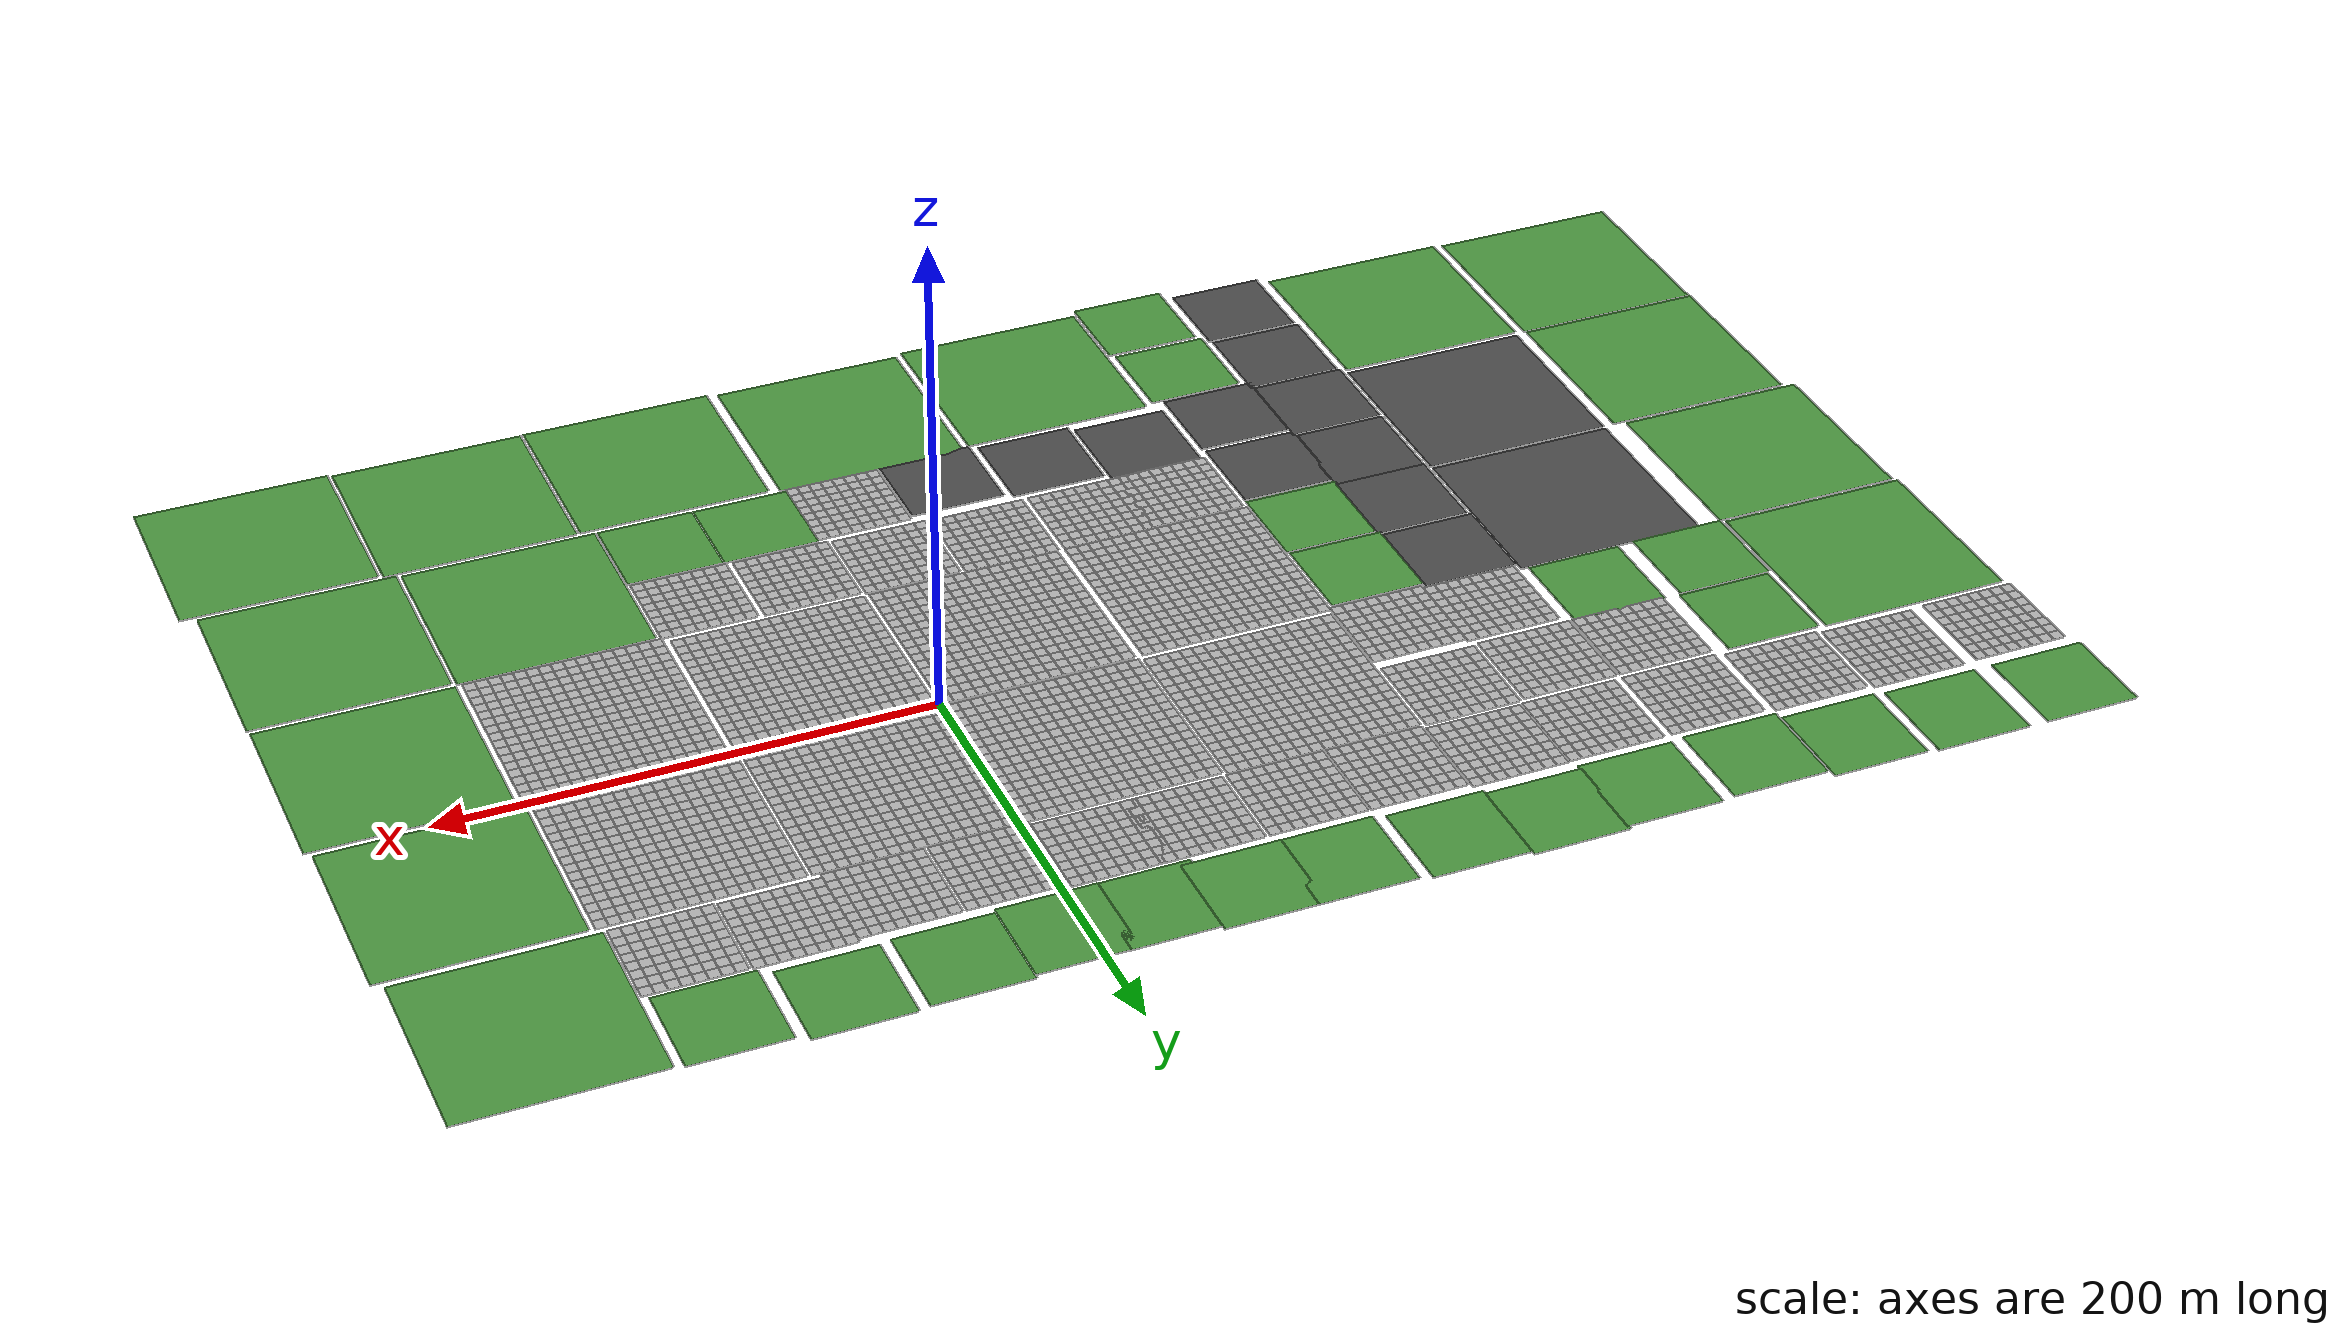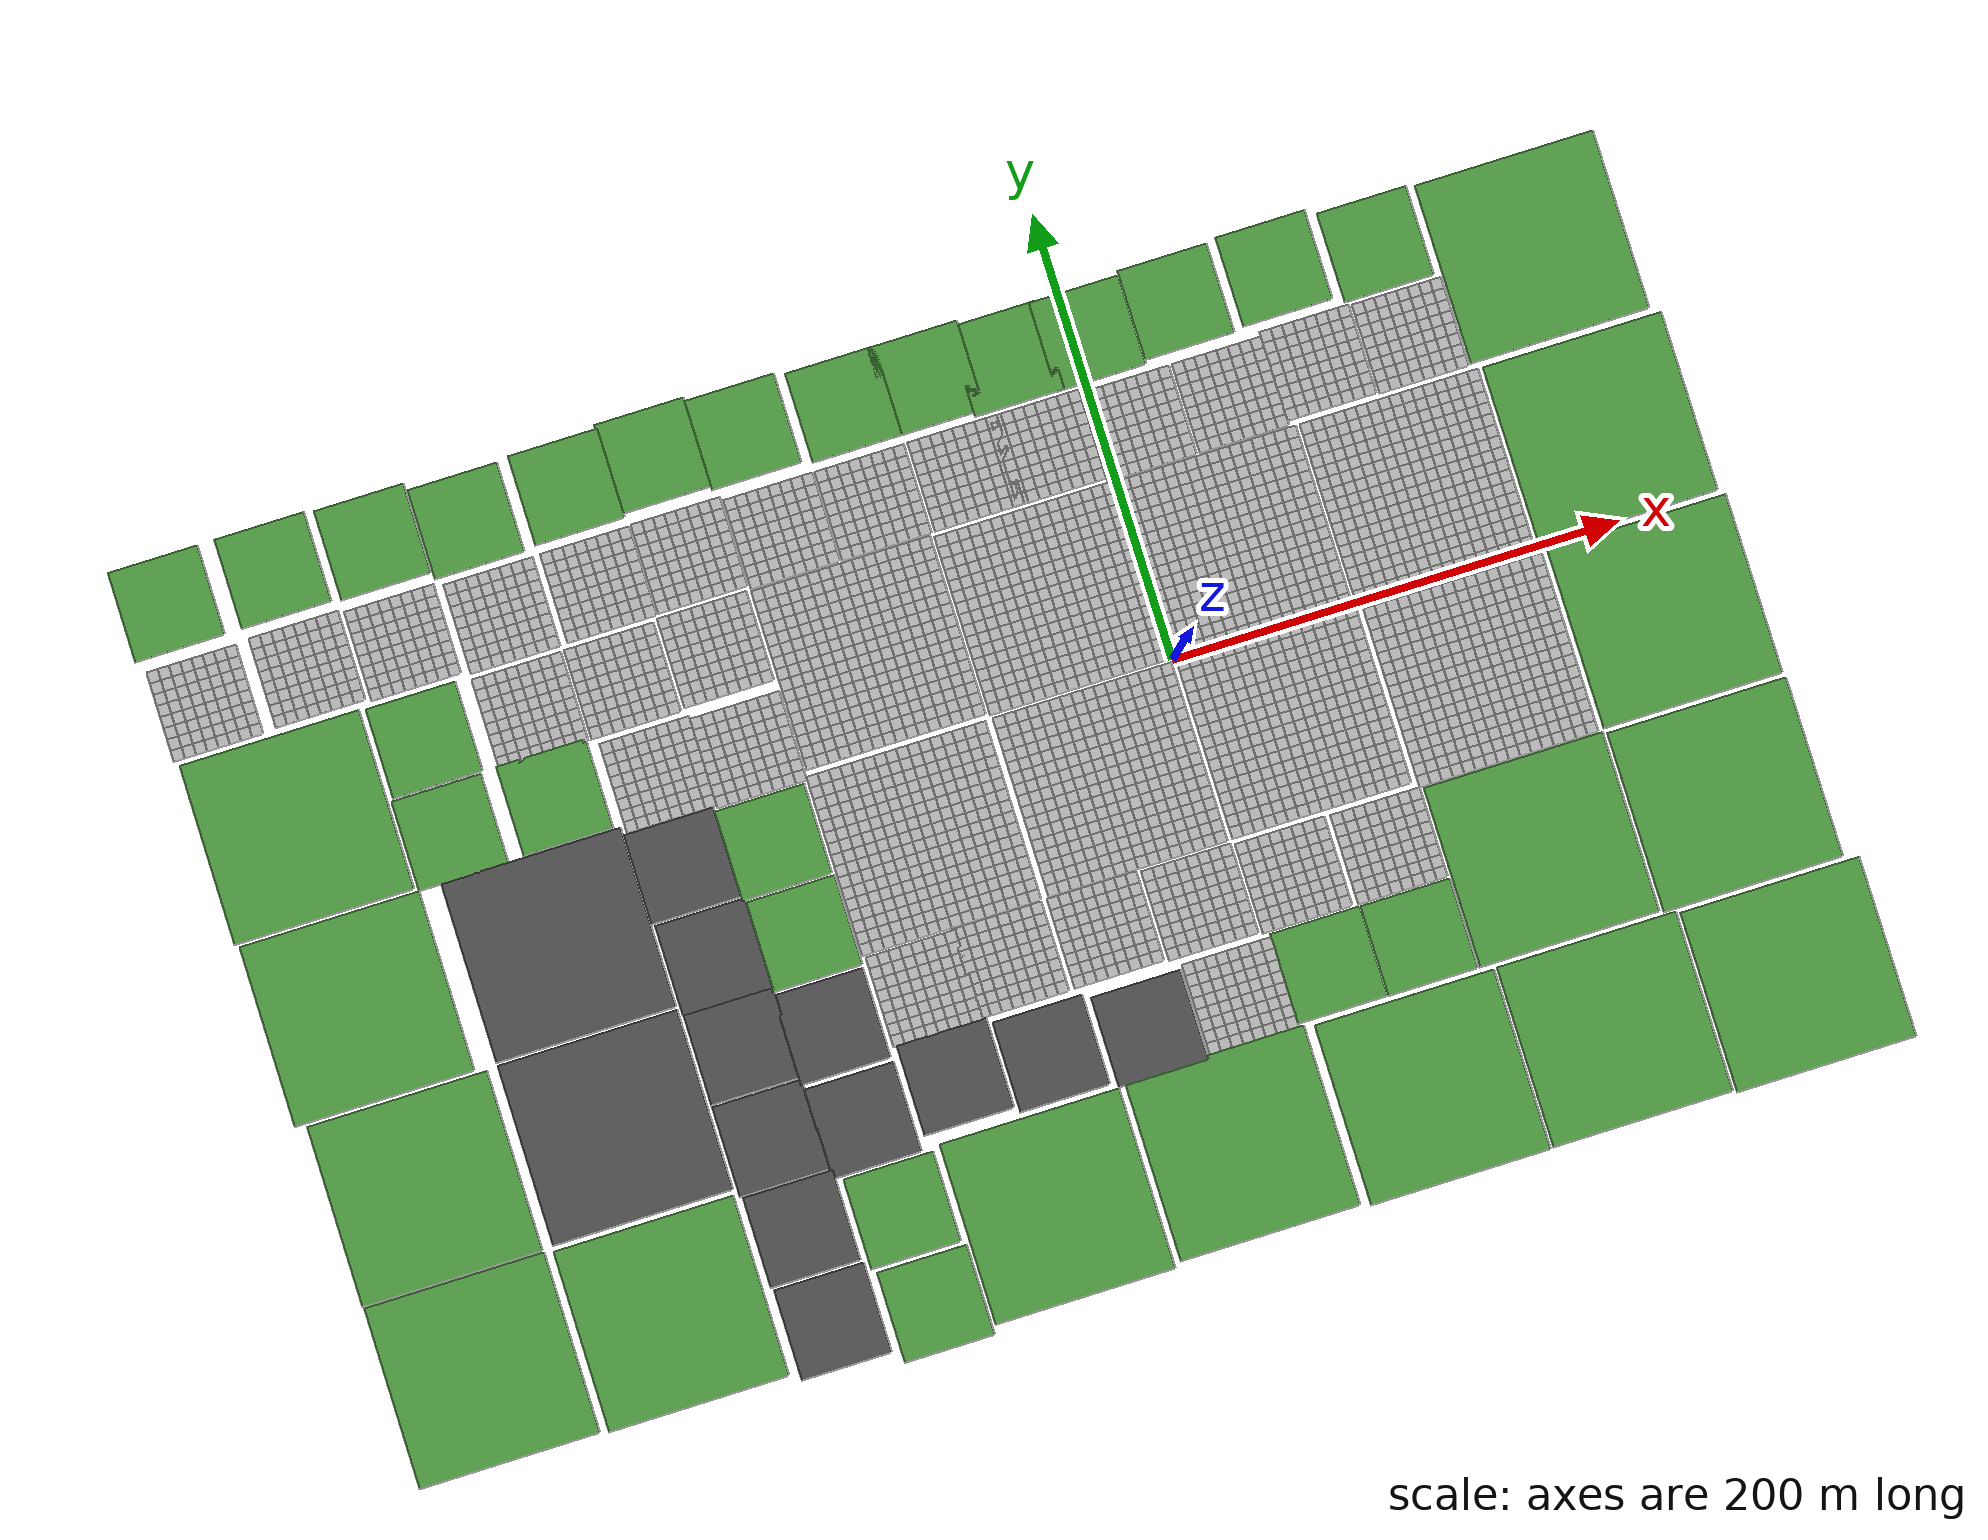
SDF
<sdf version="1.7">
 <world name="default">
  <light name="sun" type="directional">
   <pose>0 0 10 0 -0 0</pose>
   <diffuse>0.8 0.8 0.8 1</diffuse>
   <specular>0.2 0.2 0.2 1</specular>
   <attenuation>
    <range>1000</range>
    <constant>0.9</constant>
    <linear>0.01</linear>
    <quadratic>0.001</quadratic>
   </attenuation>
   <direction>-0.5 0.1 -0.9</direction>
   <spot><inner_angle>0</inner_angle><outer_angle>0</outer_angle><falloff>0</falloff></spot>
  </light>
  <gravity>0 0 -9.8</gravity>
  <magnetic_field>6e-06 2.3e-05 -4.2e-05</magnetic_field>
  <atmosphere type="adiabatic"/>
  <physics type="ode">
   <max_step_size>0.001</max_step_size>
   <real_time_factor>1</real_time_factor>
   <real_time_update_rate>1000</real_time_update_rate>
  </physics>
  <scene><ambient>0.4 0.4 0.4 1</ambient><background>0.7 0.7 0.7 1</background><shadows>1</shadows></scene>
  <spherical_coordinates>
   <surface_model>EARTH_WGS84</surface_model>
   <latitude_deg>0</latitude_deg>
   <longitude_deg>0</longitude_deg>
   <elevation>0</elevation>
   <heading_deg>0</heading_deg>
  </spherical_coordinates>
  <model name="mud_plane_80x80">
   <model name="mud_plane_40x40">
    <model name="mud_plane_20x20">
     <model name="mud_plane">
      <static>1</static>
      <link name="link">
       <collision name="collision"><geometry><box><size>10 10 0.1</size></box></geometry></collision>
       <visual name="visual_1">
        <pose>-2.5 2.5 -0.05 0 -0 0</pose>
        <cast_shadows>0</cast_shadows>
        <geometry><box><size>5 5 0.1</size></box></geometry>
        <material>
         <script>
          <uri>model://mud_plane/materials/scripts</uri>
          <uri>model://mud_plane/materials/textures</uri>
          <name>vrc/mud</name>
         </script>
        </material>
       </visual>
       <visual name="visual_2">
        <pose>2.5 2.5 -0.05 0 -0 0</pose>
        <cast_shadows>0</cast_shadows>
        <geometry><box><size>5 5 0.1</size></box></geometry>
        <material>
         <script>
          <uri>model://mud_plane/materials/scripts</uri>
          <uri>model://mud_plane/materials/textures</uri>
          <name>vrc/mud</name>
         </script>
        </material>
       </visual>
       <visual name="visual_3">
        <pose>2.5 -2.5 -0.05 0 -0 0</pose>
        <cast_shadows>0</cast_shadows>
        <geometry><box><size>5 5 0.1</size></box></geometry>
        <material>
         <script>
          <uri>model://mud_plane/materials/scripts</uri>
          <uri>model://mud_plane/materials/textures</uri>
          <name>vrc/mud</name>
         </script>
        </material>
       </visual>
       <visual name="visual_4">
        <pose>-2.5 -2.5 -0.05 0 -0 0</pose>
        <cast_shadows>0</cast_shadows>
        <geometry><box><size>5 5 0.1</size></box></geometry>
        <material>
         <script>
          <uri>model://mud_plane/materials/scripts</uri>
          <uri>model://mud_plane/materials/textures</uri>
          <name>vrc/mud</name>
         </script>
        </material>
       </visual>
      </link>
      <pose>-4.99986 -4.99991 0 0 -0 0</pose>
     </model>
     <model name="mud_plane_0">
      <static>1</static>
      <link name="link">
       <collision name="collision"><geometry><box><size>10 10 0.1</size></box></geometry></collision>
       <visual name="visual_1">
        <pose>-2.5 2.5 -0.05 0 -0 0</pose>
        <cast_shadows>0</cast_shadows>
        <geometry><box><size>5 5 0.1</size></box></geometry>
        <material>
         <script>
          <uri>model://mud_plane/materials/scripts</uri>
          <uri>model://mud_plane/materials/textures</uri>
          <name>vrc/mud</name>
         </script>
        </material>
       </visual>
       <visual name="visual_2">
        <pose>2.5 2.5 -0.05 0 -0 0</pose>
        <cast_shadows>0</cast_shadows>
        <geometry><box><size>5 5 0.1</size></box></geometry>
        <material>
         <script>
          <uri>model://mud_plane/materials/scripts</uri>
          <uri>model://mud_plane/materials/textures</uri>
          <name>vrc/mud</name>
         </script>
        </material>
       </visual>
       <visual name="visual_3">
        <pose>2.5 -2.5 -0.05 0 -0 0</pose>
        <cast_shadows>0</cast_shadows>
        <geometry><box><size>5 5 0.1</size></box></geometry>
        <material>
         <script>
          <uri>model://mud_plane/materials/scripts</uri>
          <uri>model://mud_plane/materials/textures</uri>
          <name>vrc/mud</name>
         </script>
        </material>
       </visual>
       <visual name="visual_4">
        <pose>-2.5 -2.5 -0.05 0 -0 0</pose>
        <cast_shadows>0</cast_shadows>
        <geometry><box><size>5 5 0.1</size></box></geometry>
        <material>
         <script>
          <uri>model://mud_plane/materials/scripts</uri>
          <uri>model://mud_plane/materials/textures</uri>
          <name>vrc/mud</name>
         </script>
        </material>
       </visual>
      </link>
      <pose>-4.99946 4.99954 0 0 -0 0</pose>
     </model>
     <model name="mud_plane_1">
      <static>1</static>
      <link name="link">
       <collision name="collision"><geometry><box><size>10 10 0.1</size></box></geometry></collision>
       <visual name="visual_1">
        <pose>-2.5 2.5 -0.05 0 -0 0</pose>
        <cast_shadows>0</cast_shadows>
        <geometry><box><size>5 5 0.1</size></box></geometry>
        <material>
         <script>
          <uri>model://mud_plane/materials/scripts</uri>
          <uri>model://mud_plane/materials/textures</uri>
          <name>vrc/mud</name>
         </script>
        </material>
       </visual>
       <visual name="visual_2">
        <pose>2.5 2.5 -0.05 0 -0 0</pose>
        <cast_shadows>0</cast_shadows>
        <geometry><box><size>5 5 0.1</size></box></geometry>
        <material>
         <script>
          <uri>model://mud_plane/materials/scripts</uri>
          <uri>model://mud_plane/materials/textures</uri>
          <name>vrc/mud</name>
         </script>
        </material>
       </visual>
       <visual name="visual_3">
        <pose>2.5 -2.5 -0.05 0 -0 0</pose>
        <cast_shadows>0</cast_shadows>
        <geometry><box><size>5 5 0.1</size></box></geometry>
        <material>
         <script>
          <uri>model://mud_plane/materials/scripts</uri>
          <uri>model://mud_plane/materials/textures</uri>
          <name>vrc/mud</name>
         </script>
        </material>
       </visual>
       <visual name="visual_4">
        <pose>-2.5 -2.5 -0.05 0 -0 0</pose>
        <cast_shadows>0</cast_shadows>
        <geometry><box><size>5 5 0.1</size></box></geometry>
        <material>
         <script>
          <uri>model://mud_plane/materials/scripts</uri>
          <uri>model://mud_plane/materials/textures</uri>
          <name>vrc/mud</name>
         </script>
        </material>
       </visual>
      </link>
      <pose>4.99964 -4.99949 0 0 -0 0</pose>
     </model>
     <model name="mud_plane_2">
      <static>1</static>
      <link name="link">
       <collision name="collision"><geometry><box><size>10 10 0.1</size></box></geometry></collision>
       <visual name="visual_1">
        <pose>-2.5 2.5 -0.05 0 -0 0</pose>
        <cast_shadows>0</cast_shadows>
        <geometry><box><size>5 5 0.1</size></box></geometry>
        <material>
         <script>
          <uri>model://mud_plane/materials/scripts</uri>
          <uri>model://mud_plane/materials/textures</uri>
          <name>vrc/mud</name>
         </script>
        </material>
       </visual>
       <visual name="visual_2">
        <pose>2.5 2.5 -0.05 0 -0 0</pose>
        <cast_shadows>0</cast_shadows>
        <geometry><box><size>5 5 0.1</size></box></geometry>
        <material>
         <script>
          <uri>model://mud_plane/materials/scripts</uri>
          <uri>model://mud_plane/materials/textures</uri>
          <name>vrc/mud</name>
         </script>
        </material>
       </visual>
       <visual name="visual_3">
        <pose>2.5 -2.5 -0.05 0 -0 0</pose>
        <cast_shadows>0</cast_shadows>
        <geometry><box><size>5 5 0.1</size></box></geometry>
        <material>
         <script>
          <uri>model://mud_plane/materials/scripts</uri>
          <uri>model://mud_plane/materials/textures</uri>
          <name>vrc/mud</name>
         </script>
        </material>
       </visual>
       <visual name="visual_4">
        <pose>-2.5 -2.5 -0.05 0 -0 0</pose>
        <cast_shadows>0</cast_shadows>
        <geometry><box><size>5 5 0.1</size></box></geometry>
        <material>
         <script>
          <uri>model://mud_plane/materials/scripts</uri>
          <uri>model://mud_plane/materials/textures</uri>
          <name>vrc/mud</name>
         </script>
        </material>
       </visual>
      </link>
      <pose>4.99967 4.99986 0 0 -0 0</pose>
     </model>
     <static>0</static>
     <pose>-9.99895 9.99843 0 0 -0 0</pose>
    </model>
    <model name="mud_plane_20x20_0">
     <model name="mud_plane">
      <static>1</static>
      <link name="link">
       <collision name="collision"><geometry><box><size>10 10 0.1</size></box></geometry></collision>
       <visual name="visual_1">
        <pose>-2.5 2.5 -0.05 0 -0 0</pose>
        <cast_shadows>0</cast_shadows>
        <geometry><box><size>5 5 0.1</size></box></geometry>
        <material>
         <script>
          <uri>model://mud_plane/materials/scripts</uri>
          <uri>model://mud_plane/materials/textures</uri>
          <name>vrc/mud</name>
         </script>
        </material>
       </visual>
       <visual name="visual_2">
        <pose>2.5 2.5 -0.05 0 -0 0</pose>
        <cast_shadows>0</cast_shadows>
        <geometry><box><size>5 5 0.1</size></box></geometry>
        <material>
         <script>
          <uri>model://mud_plane/materials/scripts</uri>
          <uri>model://mud_plane/materials/textures</uri>
          <name>vrc/mud</name>
         </script>
        </material>
       </visual>
       <visual name="visual_3">
        <pose>2.5 -2.5 -0.05 0 -0 0</pose>
        <cast_shadows>0</cast_shadows>
        <geometry><box><size>5 5 0.1</size></box></geometry>
        <material>
         <script>
          <uri>model://mud_plane/materials/scripts</uri>
          <uri>model://mud_plane/materials/textures</uri>
          <name>vrc/mud</name>
         </script>
        </material>
       </visual>
       <visual name="visual_4">
        <pose>-2.5 -2.5 -0.05 0 -0 0</pose>
        <cast_shadows>0</cast_shadows>
        <geometry><box><size>5 5 0.1</size></box></geometry>
        <material>
         <script>
          <uri>model://mud_plane/materials/scripts</uri>
          <uri>model://mud_plane/materials/textures</uri>
          <name>vrc/mud</name>
         </script>
        </material>
       </visual>
      </link>
      <pose>-4.99986 -4.99991 0 0 -0 0</pose>
     </model>
     <model name="mud_plane_0">
      <static>1</static>
      <link name="link">
       <collision name="collision"><geometry><box><size>10 10 0.1</size></box></geometry></collision>
       <visual name="visual_1">
        <pose>-2.5 2.5 -0.05 0 -0 0</pose>
        <cast_shadows>0</cast_shadows>
        <geometry><box><size>5 5 0.1</size></box></geometry>
        <material>
         <script>
          <uri>model://mud_plane/materials/scripts</uri>
          <uri>model://mud_plane/materials/textures</uri>
          <name>vrc/mud</name>
         </script>
        </material>
       </visual>
       <visual name="visual_2">
        <pose>2.5 2.5 -0.05 0 -0 0</pose>
        <cast_shadows>0</cast_shadows>
        <geometry><box><size>5 5 0.1</size></box></geometry>
        <material>
         <script>
          <uri>model://mud_plane/materials/scripts</uri>
          <uri>model://mud_plane/materials/textures</uri>
          <name>vrc/mud</name>
         </script>
        </material>
       </visual>
       <visual name="visual_3">
        <pose>2.5 -2.5 -0.05 0 -0 0</pose>
        <cast_shadows>0</cast_shadows>
        <geometry><box><size>5 5 0.1</size></box></geometry>
        <material>
         <script>
          <uri>model://mud_plane/materials/scripts</uri>
          <uri>model://mud_plane/materials/textures</uri>
          <name>vrc/mud</name>
         </script>
        </material>
       </visual>
       <visual name="visual_4">
        <pose>-2.5 -2.5 -0.05 0 -0 0</pose>
        <cast_shadows>0</cast_shadows>
        <geometry><box><size>5 5 0.1</size></box></geometry>
        <material>
         <script>
          <uri>model://mud_plane/materials/scripts</uri>
          <uri>model://mud_plane/materials/textures</uri>
          <name>vrc/mud</name>
         </script>
        </material>
       </visual>
      </link>
      <pose>-4.99946 4.99954 0 0 -0 0</pose>
     </model>
     <model name="mud_plane_1">
      <static>1</static>
      <link name="link">
       <collision name="collision"><geometry><box><size>10 10 0.1</size></box></geometry></collision>
       <visual name="visual_1">
        <pose>-2.5 2.5 -0.05 0 -0 0</pose>
        <cast_shadows>0</cast_shadows>
        <geometry><box><size>5 5 0.1</size></box></geometry>
        <material>
         <script>
          <uri>model://mud_plane/materials/scripts</uri>
          <uri>model://mud_plane/materials/textures</uri>
          <name>vrc/mud</name>
         </script>
        </material>
       </visual>
       <visual name="visual_2">
        <pose>2.5 2.5 -0.05 0 -0 0</pose>
        <cast_shadows>0</cast_shadows>
        <geometry><box><size>5 5 0.1</size></box></geometry>
        <material>
         <script>
          <uri>model://mud_plane/materials/scripts</uri>
          <uri>model://mud_plane/materials/textures</uri>
          <name>vrc/mud</name>
         </script>
        </material>
       </visual>
       <visual name="visual_3">
        <pose>2.5 -2.5 -0.05 0 -0 0</pose>
        <cast_shadows>0</cast_shadows>
        <geometry><box><size>5 5 0.1</size></box></geometry>
        <material>
         <script>
          <uri>model://mud_plane/materials/scripts</uri>
          <uri>model://mud_plane/materials/textures</uri>
          <name>vrc/mud</name>
         </script>
        </material>
       </visual>
       <visual name="visual_4">
        <pose>-2.5 -2.5 -0.05 0 -0 0</pose>
        <cast_shadows>0</cast_shadows>
        <geometry><box><size>5 5 0.1</size></box></geometry>
        <material>
         <script>
          <uri>model://mud_plane/materials/scripts</uri>
          <uri>model://mud_plane/materials/textures</uri>
          <name>vrc/mud</name>
         </script>
        </material>
       </visual>
      </link>
      <pose>4.99964 -4.99949 0 0 -0 0</pose>
     </model>
     <model name="mud_plane_2">
      <static>1</static>
      <link name="link">
       <collision name="collision"><geometry><box><size>10 10 0.1</size></box></geometry></collision>
       <visual name="visual_1">
        <pose>-2.5 2.5 -0.05 0 -0 0</pose>
        <cast_shadows>0</cast_shadows>
        <geometry><box><size>5 5 0.1</size></box></geometry>
        <material>
         <script>
          <uri>model://mud_plane/materials/scripts</uri>
          <uri>model://mud_plane/materials/textures</uri>
          <name>vrc/mud</name>
         </script>
        </material>
       </visual>
       <visual name="visual_2">
        <pose>2.5 2.5 -0.05 0 -0 0</pose>
        <cast_shadows>0</cast_shadows>
        <geometry><box><size>5 5 0.1</size></box></geometry>
        <material>
         <script>
          <uri>model://mud_plane/materials/scripts</uri>
          <uri>model://mud_plane/materials/textures</uri>
          <name>vrc/mud</name>
         </script>
        </material>
       </visual>
       <visual name="visual_3">
        <pose>2.5 -2.5 -0.05 0 -0 0</pose>
        <cast_shadows>0</cast_shadows>
        <geometry><box><size>5 5 0.1</size></box></geometry>
        <material>
         <script>
          <uri>model://mud_plane/materials/scripts</uri>
          <uri>model://mud_plane/materials/textures</uri>
          <name>vrc/mud</name>
         </script>
        </material>
       </visual>
       <visual name="visual_4">
        <pose>-2.5 -2.5 -0.05 0 -0 0</pose>
        <cast_shadows>0</cast_shadows>
        <geometry><box><size>5 5 0.1</size></box></geometry>
        <material>
         <script>
          <uri>model://mud_plane/materials/scripts</uri>
          <uri>model://mud_plane/materials/textures</uri>
          <name>vrc/mud</name>
         </script>
        </material>
       </visual>
      </link>
      <pose>4.99967 4.99986 0 0 -0 0</pose>
     </model>
     <static>0</static>
     <pose>9.99933 9.9997 0 0 -0 0</pose>
    </model>
    <model name="mud_plane_20x20_1">
     <model name="mud_plane">
      <static>1</static>
      <link name="link">
       <collision name="collision"><geometry><box><size>10 10 0.1</size></box></geometry></collision>
       <visual name="visual_1">
        <pose>-2.5 2.5 -0.05 0 -0 0</pose>
        <cast_shadows>0</cast_shadows>
        <geometry><box><size>5 5 0.1</size></box></geometry>
        <material>
         <script>
          <uri>model://mud_plane/materials/scripts</uri>
          <uri>model://mud_plane/materials/textures</uri>
          <name>vrc/mud</name>
         </script>
        </material>
       </visual>
       <visual name="visual_2">
        <pose>2.5 2.5 -0.05 0 -0 0</pose>
        <cast_shadows>0</cast_shadows>
        <geometry><box><size>5 5 0.1</size></box></geometry>
        <material>
         <script>
          <uri>model://mud_plane/materials/scripts</uri>
          <uri>model://mud_plane/materials/textures</uri>
          <name>vrc/mud</name>
         </script>
        </material>
       </visual>
       <visual name="visual_3">
        <pose>2.5 -2.5 -0.05 0 -0 0</pose>
        <cast_shadows>0</cast_shadows>
        <geometry><box><size>5 5 0.1</size></box></geometry>
        <material>
         <script>
          <uri>model://mud_plane/materials/scripts</uri>
          <uri>model://mud_plane/materials/textures</uri>
          <name>vrc/mud</name>
         </script>
        </material>
       </visual>
       <visual name="visual_4">
        <pose>-2.5 -2.5 -0.05 0 -0 0</pose>
        <cast_shadows>0</cast_shadows>
        <geometry><box><size>5 5 0.1</size></box></geometry>
        <material>
         <script>
          <uri>model://mud_plane/materials/scripts</uri>
          <uri>model://mud_plane/materials/textures</uri>
          <name>vrc/mud</name>
         </script>
        </material>
       </visual>
      </link>
      <pose>-4.99986 -4.99991 0 0 -0 0</pose>
     </model>
     <model name="mud_plane_0">
      <static>1</static>
      <link name="link">
       <collision name="collision"><geometry><box><size>10 10 0.1</size></box></geometry></collision>
       <visual name="visual_1">
        <pose>-2.5 2.5 -0.05 0 -0 0</pose>
        <cast_shadows>0</cast_shadows>
        <geometry><box><size>5 5 0.1</size></box></geometry>
        <material>
         <script>
          <uri>model://mud_plane/materials/scripts</uri>
          <uri>model://mud_plane/materials/textures</uri>
          <name>vrc/mud</name>
         </script>
        </material>
       </visual>
       <visual name="visual_2">
        <pose>2.5 2.5 -0.05 0 -0 0</pose>
        <cast_shadows>0</cast_shadows>
        <geometry><box><size>5 5 0.1</size></box></geometry>
        <material>
         <script>
          <uri>model://mud_plane/materials/scripts</uri>
          <uri>model://mud_plane/materials/textures</uri>
          <name>vrc/mud</name>
         </script>
        </material>
       </visual>
       <visual name="visual_3">
        <pose>2.5 -2.5 -0.05 0 -0 0</pose>
        <cast_shadows>0</cast_shadows>
        <geometry><box><size>5 5 0.1</size></box></geometry>
        <material>
         <script>
          <uri>model://mud_plane/materials/scripts</uri>
          <uri>model://mud_plane/materials/textures</uri>
          <name>vrc/mud</name>
         </script>
        </material>
       </visual>
       <visual name="visual_4">
        <pose>-2.5 -2.5 -0.05 0 -0 0</pose>
        <cast_shadows>0</cast_shadows>
        <geometry><box><size>5 5 0.1</size></box></geometry>
        <material>
         <script>
          <uri>model://mud_plane/materials/scripts</uri>
          <uri>model://mud_plane/materials/textures</uri>
          <name>vrc/mud</name>
         </script>
        </material>
       </visual>
      </link>
      <pose>-4.99946 4.99954 0 0 -0 0</pose>
     </model>
     <model name="mud_plane_1">
      <static>1</static>
      <link name="link">
       <collision name="collision"><geometry><box><size>10 10 0.1</size></box></geometry></collision>
       <visual name="visual_1">
        <pose>-2.5 2.5 -0.05 0 -0 0</pose>
        <cast_shadows>0</cast_shadows>
        <geometry><box><size>5 5 0.1</size></box></geometry>
        <material>
         <script>
          <uri>model://mud_plane/materials/scripts</uri>
          <uri>model://mud_plane/materials/textures</uri>
          <name>vrc/mud</name>
         </script>
        </material>
       </visual>
       <visual name="visual_2">
        <pose>2.5 2.5 -0.05 0 -0 0</pose>
        <cast_shadows>0</cast_shadows>
        <geometry><box><size>5 5 0.1</size></box></geometry>
        <material>
         <script>
          <uri>model://mud_plane/materials/scripts</uri>
          <uri>model://mud_plane/materials/textures</uri>
          <name>vrc/mud</name>
         </script>
        </material>
       </visual>
       <visual name="visual_3">
        <pose>2.5 -2.5 -0.05 0 -0 0</pose>
        <cast_shadows>0</cast_shadows>
        <geometry><box><size>5 5 0.1</size></box></geometry>
        <material>
         <script>
          <uri>model://mud_plane/materials/scripts</uri>
          <uri>model://mud_plane/materials/textures</uri>
          <name>vrc/mud</name>
         </script>
        </material>
       </visual>
       <visual name="visual_4">
        <pose>-2.5 -2.5 -0.05 0 -0 0</pose>
        <cast_shadows>0</cast_shadows>
        <geometry><box><size>5 5 0.1</size></box></geometry>
        <material>
         <script>
          <uri>model://mud_plane/materials/scripts</uri>
          <uri>model://mud_plane/materials/textures</uri>
          <name>vrc/mud</name>
         </script>
        </material>
       </visual>
      </link>
      <pose>4.99964 -4.99949 0 0 -0 0</pose>
     </model>
     <model name="mud_plane_2">
      <static>1</static>
      <link name="link">
       <collision name="collision"><geometry><box><size>10 10 0.1</size></box></geometry></collision>
       <visual name="visual_1">
        <pose>-2.5 2.5 -0.05 0 -0 0</pose>
        <cast_shadows>0</cast_shadows>
        <geometry><box><size>5 5 0.1</size></box></geometry>
        <material>
         <script>
          <uri>model://mud_plane/materials/scripts</uri>
          <uri>model://mud_plane/materials/textures</uri>
          <name>vrc/mud</name>
         </script>
        </material>
       </visual>
       <visual name="visual_2">
        <pose>2.5 2.5 -0.05 0 -0 0</pose>
        <cast_shadows>0</cast_shadows>
        <geometry><box><size>5 5 0.1</size></box></geometry>
        <material>
         <script>
          <uri>model://mud_plane/materials/scripts</uri>
          <uri>model://mud_plane/materials/textures</uri>
          <name>vrc/mud</name>
         </script>
        </material>
       </visual>
       <visual name="visual_3">
        <pose>2.5 -2.5 -0.05 0 -0 0</pose>
        <cast_shadows>0</cast_shadows>
        <geometry><box><size>5 5 0.1</size></box></geometry>
        <material>
         <script>
          <uri>model://mud_plane/materials/scripts</uri>
          <uri>model://mud_plane/materials/textures</uri>
          <name>vrc/mud</name>
         </script>
        </material>
       </visual>
       <visual name="visual_4">
        <pose>-2.5 -2.5 -0.05 0 -0 0</pose>
        <cast_shadows>0</cast_shadows>
        <geometry><box><size>5 5 0.1</size></box></geometry>
        <material>
         <script>
          <uri>model://mud_plane/materials/scripts</uri>
          <uri>model://mud_plane/materials/textures</uri>
          <name>vrc/mud</name>
         </script>
        </material>
       </visual>
      </link>
      <pose>4.99967 4.99986 0 0 -0 0</pose>
     </model>
     <static>0</static>
     <pose>9.9993 -9.99877 0 0 -0 0</pose>
    </model>
    <model name="mud_plane_20x20_2">
     <model name="mud_plane">
      <static>1</static>
      <link name="link">
       <collision name="collision"><geometry><box><size>10 10 0.1</size></box></geometry></collision>
       <visual name="visual_1">
        <pose>-2.5 2.5 -0.05 0 -0 0</pose>
        <cast_shadows>0</cast_shadows>
        <geometry><box><size>5 5 0.1</size></box></geometry>
        <material>
         <script>
          <uri>model://mud_plane/materials/scripts</uri>
          <uri>model://mud_plane/materials/textures</uri>
          <name>vrc/mud</name>
         </script>
        </material>
       </visual>
       <visual name="visual_2">
        <pose>2.5 2.5 -0.05 0 -0 0</pose>
        <cast_shadows>0</cast_shadows>
        <geometry><box><size>5 5 0.1</size></box></geometry>
        <material>
         <script>
          <uri>model://mud_plane/materials/scripts</uri>
          <uri>model://mud_plane/materials/textures</uri>
          <name>vrc/mud</name>
         </script>
        </material>
       </visual>
       <visual name="visual_3">
        <pose>2.5 -2.5 -0.05 0 -0 0</pose>
        <cast_shadows>0</cast_shadows>
        <geometry><box><size>5 5 0.1</size></box></geometry>
        <material>
         <script>
          <uri>model://mud_plane/materials/scripts</uri>
          <uri>model://mud_plane/materials/textures</uri>
          <name>vrc/mud</name>
         </script>
        </material>
       </visual>
       <visual name="visual_4">
        <pose>-2.5 -2.5 -0.05 0 -0 0</pose>
        <cast_shadows>0</cast_shadows>
        <geometry><box><size>5 5 0.1</size></box></geometry>
        <material>
         <script>
          <uri>model://mud_plane/materials/scripts</uri>
          <uri>model://mud_plane/materials/textures</uri>
          <name>vrc/mud</name>
         </script>
        </material>
       </visual>
      </link>
      <pose>-4.99986 -4.99991 0 0 -0 0</pose>
     </model>
     <model name="mud_plane_0">
      <static>1</static>
      <link name="link">
       <collision name="collision"><geometry><box><size>10 10 0.1</size></box></geometry></collision>
       <visual name="visual_1">
        <pose>-2.5 2.5 -0.05 0 -0 0</pose>
        <cast_shadows>0</cast_shadows>
        <geometry><box><size>5 5 0.1</size></box></geometry>
        <material>
         <script>
          <uri>model://mud_plane/materials/scripts</uri>
          <uri>model://mud_plane/materials/textures</uri>
          <name>vrc/mud</name>
         </script>
        </material>
       </visual>
       <visual name="visual_2">
        <pose>2.5 2.5 -0.05 0 -0 0</pose>
        <cast_shadows>0</cast_shadows>
        <geometry><box><size>5 5 0.1</size></box></geometry>
        <material>
         <script>
          <uri>model://mud_plane/materials/scripts</uri>
          <uri>model://mud_plane/materials/textures</uri>
          <name>vrc/mud</name>
         </script>
        </material>
       </visual>
       <visual name="visual_3">
        <pose>2.5 -2.5 -0.05 0 -0 0</pose>
        <cast_shadows>0</cast_shadows>
        <geometry><box><size>5 5 0.1</size></box></geometry>
        <material>
         <script>
          <uri>model://mud_plane/materials/scripts</uri>
          <uri>model://mud_plane/materials/textures</uri>
          <name>vrc/mud</name>
         </script>
        </material>
       </visual>
       <visual name="visual_4">
        <pose>-2.5 -2.5 -0.05 0 -0 0</pose>
        <cast_shadows>0</cast_shadows>
        <geometry><box><size>5 5 0.1</size></box></geometry>
        <material>
         <script>
          <uri>model://mud_plane/materials/scripts</uri>
          <uri>model://mud_plane/materials/textures</uri>
          <name>vrc/mud</name>
         </script>
        </material>
       </visual>
      </link>
      <pose>-4.99946 4.99954 0 0 -0 0</pose>
     </model>
     <model name="mud_plane_1">
      <static>1</static>
      <link name="link">
       <collision name="collision"><geometry><box><size>10 10 0.1</size></box></geometry></collision>
       <visual name="visual_1">
        <pose>-2.5 2.5 -0.05 0 -0 0</pose>
        <cast_shadows>0</cast_shadows>
        <geometry><box><size>5 5 0.1</size></box></geometry>
        <material>
         <script>
          <uri>model://mud_plane/materials/scripts</uri>
          <uri>model://mud_plane/materials/textures</uri>
          <name>vrc/mud</name>
         </script>
        </material>
       </visual>
       <visual name="visual_2">
        <pose>2.5 2.5 -0.05 0 -0 0</pose>
        <cast_shadows>0</cast_shadows>
        <geometry><box><size>5 5 0.1</size></box></geometry>
        <material>
         <script>
          <uri>model://mud_plane/materials/scripts</uri>
          <uri>model://mud_plane/materials/textures</uri>
          <name>vrc/mud</name>
         </script>
        </material>
       </visual>
       <visual name="visual_3">
        <pose>2.5 -2.5 -0.05 0 -0 0</pose>
        <cast_shadows>0</cast_shadows>
        <geometry><box><size>5 5 0.1</size></box></geometry>
        <material>
         <script>
          <uri>model://mud_plane/materials/scripts</uri>
          <uri>model://mud_plane/materials/textures</uri>
          <name>vrc/mud</name>
         </script>
        </material>
       </visual>
       <visual name="visual_4">
        <pose>-2.5 -2.5 -0.05 0 -0 0</pose>
        <cast_shadows>0</cast_shadows>
        <geometry><box><size>5 5 0.1</size></box></geometry>
        <material>
         <script>
          <uri>model://mud_plane/materials/scripts</uri>
          <uri>model://mud_plane/materials/textures</uri>
          <name>vrc/mud</name>
         </script>
        </material>
       </visual>
      </link>
      <pose>4.99964 -4.99949 0 0 -0 0</pose>
     </model>
     <model name="mud_plane_2">
      <static>1</static>
      <link name="link">
       <collision name="collision"><geometry><box><size>10 10 0.1</size></box></geometry></collision>
       <visual name="visual_1">
        <pose>-2.5 2.5 -0.05 0 -0 0</pose>
        <cast_shadows>0</cast_shadows>
        <geometry><box><size>5 5 0.1</size></box></geometry>
        <material>
         <script>
          <uri>model://mud_plane/materials/scripts</uri>
          <uri>model://mud_plane/materials/textures</uri>
          <name>vrc/mud</name>
         </script>
        </material>
       </visual>
       <visual name="visual_2">
        <pose>2.5 2.5 -0.05 0 -0 0</pose>
        <cast_shadows>0</cast_shadows>
        <geometry><box><size>5 5 0.1</size></box></geometry>
        <material>
         <script>
          <uri>model://mud_plane/materials/scripts</uri>
          <uri>model://mud_plane/materials/textures</uri>
          <name>vrc/mud</name>
         </script>
        </material>
       </visual>
       <visual name="visual_3">
        <pose>2.5 -2.5 -0.05 0 -0 0</pose>
        <cast_shadows>0</cast_shadows>
        <geometry><box><size>5 5 0.1</size></box></geometry>
        <material>
         <script>
          <uri>model://mud_plane/materials/scripts</uri>
          <uri>model://mud_plane/materials/textures</uri>
          <name>vrc/mud</name>
         </script>
        </material>
       </visual>
       <visual name="visual_4">
        <pose>-2.5 -2.5 -0.05 0 -0 0</pose>
        <cast_shadows>0</cast_shadows>
        <geometry><box><size>5 5 0.1</size></box></geometry>
        <material>
         <script>
          <uri>model://mud_plane/materials/scripts</uri>
          <uri>model://mud_plane/materials/textures</uri>
          <name>vrc/mud</name>
         </script>
        </material>
       </visual>
      </link>
      <pose>4.99967 4.99986 0 0 -0 0</pose>
     </model>
     <static>0</static>
     <pose>-9.99969 -9.99935 0 0 -0 0</pose>
    </model>
    <static>0</static>
    <pose>19.9986 19.9995 0 0 -0 0</pose>
   </model>
   <model name="mud_plane_40x40_0">
    <model name="mud_plane_20x20">
     <model name="mud_plane">
      <static>1</static>
      <link name="link">
       <collision name="collision"><geometry><box><size>10 10 0.1</size></box></geometry></collision>
       <visual name="visual_1">
        <pose>-2.5 2.5 -0.05 0 -0 0</pose>
        <cast_shadows>0</cast_shadows>
        <geometry><box><size>5 5 0.1</size></box></geometry>
        <material>
         <script>
          <uri>model://mud_plane/materials/scripts</uri>
          <uri>model://mud_plane/materials/textures</uri>
          <name>vrc/mud</name>
         </script>
        </material>
       </visual>
       <visual name="visual_2">
        <pose>2.5 2.5 -0.05 0 -0 0</pose>
        <cast_shadows>0</cast_shadows>
        <geometry><box><size>5 5 0.1</size></box></geometry>
        <material>
         <script>
          <uri>model://mud_plane/materials/scripts</uri>
          <uri>model://mud_plane/materials/textures</uri>
          <name>vrc/mud</name>
         </script>
        </material>
       </visual>
       <visual name="visual_3">
        <pose>2.5 -2.5 -0.05 0 -0 0</pose>
        <cast_shadows>0</cast_shadows>
        <geometry><box><size>5 5 0.1</size></box></geometry>
        <material>
         <script>
          <uri>model://mud_plane/materials/scripts</uri>
          <uri>model://mud_plane/materials/textures</uri>
          <name>vrc/mud</name>
         </script>
        </material>
       </visual>
       <visual name="visual_4">
        <pose>-2.5 -2.5 -0.05 0 -0 0</pose>
        <cast_shadows>0</cast_shadows>
        <geometry><box><size>5 5 0.1</size></box></geometry>
        <material>
         <script>
          <uri>model://mud_plane/materials/scripts</uri>
          <uri>model://mud_plane/materials/textures</uri>
          <name>vrc/mud</name>
         </script>
        </material>
       </visual>
      </link>
      <pose>-4.99986 -4.99991 0 0 -0 0</pose>
     </model>
     <model name="mud_plane_0">
      <static>1</static>
      <link name="link">
       <collision name="collision"><geometry><box><size>10 10 0.1</size></box></geometry></collision>
       <visual name="visual_1">
        <pose>-2.5 2.5 -0.05 0 -0 0</pose>
        <cast_shadows>0</cast_shadows>
        <geometry><box><size>5 5 0.1</size></box></geometry>
        <material>
         <script>
          <uri>model://mud_plane/materials/scripts</uri>
          <uri>model://mud_plane/materials/textures</uri>
          <name>vrc/mud</name>
         </script>
        </material>
       </visual>
       <visual name="visual_2">
        <pose>2.5 2.5 -0.05 0 -0 0</pose>
        <cast_shadows>0</cast_shadows>
        <geometry><box><size>5 5 0.1</size></box></geometry>
        <material>
         <script>
          <uri>model://mud_plane/materials/scripts</uri>
          <uri>model://mud_plane/materials/textures</uri>
          <name>vrc/mud</name>
         </script>
        </material>
       </visual>
       <visual name="visual_3">
        <pose>2.5 -2.5 -0.05 0 -0 0</pose>
        <cast_shadows>0</cast_shadows>
        <geometry><box><size>5 5 0.1</size></box></geometry>
        <material>
         <script>
          <uri>model://mud_plane/materials/scripts</uri>
          <uri>model://mud_plane/materials/textures</uri>
          <name>vrc/mud</name>
         </script>
        </material>
       </visual>
       <visual name="visual_4">
        <pose>-2.5 -2.5 -0.05 0 -0 0</pose>
        <cast_shadows>0</cast_shadows>
        <geometry><box><size>5 5 0.1</size></box></geometry>
        <material>
         <script>
          <uri>model://mud_plane/materials/scripts</uri>
          <uri>model://mud_plane/materials/textures</uri>
          <name>vrc/mud</name>
         </script>
        </material>
       </visual>
      </link>
      <pose>-4.99946 4.99954 0 0 -0 0</pose>
     </model>
     <model name="mud_plane_1">
      <static>1</static>
      <link name="link">
       <collision name="collision"><geometry><box><size>10 10 0.1</size></box></geometry></collision>
       <visual name="visual_1">
        <pose>-2.5 2.5 -0.05 0 -0 0</pose>
        <cast_shadows>0</cast_shadows>
        <geometry><box><size>5 5 0.1</size></box></geometry>
        <material>
         <script>
          <uri>model://mud_plane/materials/scripts</uri>
          <uri>model://mud_plane/materials/textures</uri>
          <name>vrc/mud</name>
         </script>
        </material>
       </visual>
       <visual name="visual_2">
        <pose>2.5 2.5 -0.05 0 -0 0</pose>
        <cast_shadows>0</cast_shadows>
        <geometry><box><size>5 5 0.1</size></box></geometry>
        <material>
         <script>
          <uri>model://mud_plane/materials/scripts</uri>
          <uri>model://mud_plane/materials/textures</uri>
          <name>vrc/mud</name>
         </script>
        </material>
       </visual>
       <visual name="visual_3">
        <pose>2.5 -2.5 -0.05 0 -0 0</pose>
        <cast_shadows>0</cast_shadows>
        <geometry><box><size>5 5 0.1</size></box></geometry>
        <material>
         <script>
          <uri>model://mud_plane/materials/scripts</uri>
          <uri>model://mud_plane/materials/textures</uri>
          <name>vrc/mud</name>
         </script>
        </material>
       </visual>
       <visual name="visual_4">
        <pose>-2.5 -2.5 -0.05 0 -0 0</pose>
        <cast_shadows>0</cast_shadows>
        <geometry><box><size>5 5 0.1</size></box></geometry>
        <material>
         <script>
          <uri>model://mud_plane/materials/scripts</uri>
          <uri>model://mud_plane/materials/textures</uri>
          <name>vrc/mud</name>
         </script>
        </material>
       </visual>
      </link>
      <pose>4.99964 -4.99949 0 0 -0 0</pose>
     </model>
     <model name="mud_plane_2">
      <static>1</static>
      <link name="link">
       <collision name="collision"><geometry><box><size>10 10 0.1</size></box></geometry></collision>
       <visual name="visual_1">
        <pose>-2.5 2.5 -0.05 0 -0 0</pose>
        <cast_shadows>0</cast_shadows>
        <geometry><box><size>5 5 0.1</size></box></geometry>
        <material>
         <script>
          <uri>model://mud_plane/materials/scripts</uri>
          <uri>model://mud_plane/materials/textures</uri>
          <name>vrc/mud</name>
         </script>
        </material>
       </visual>
       <visual name="visual_2">
        <pose>2.5 2.5 -0.05 0 -0 0</pose>
        <cast_shadows>0</cast_shadows>
        <geometry><box><size>5 5 0.1</size></box></geometry>
        <material>
         <script>
          <uri>model://mud_plane/materials/scripts</uri>
          <uri>model://mud_plane/materials/textures</uri>
          <name>vrc/mud</name>
         </script>
        </material>
       </visual>
       <visual name="visual_3">
        <pose>2.5 -2.5 -0.05 0 -0 0</pose>
        <cast_shadows>0</cast_shadows>
        <geometry><box><size>5 5 0.1</size></box></geometry>
        <material>
         <script>
          <uri>model://mud_plane/materials/scripts</uri>
          <uri>model://mud_plane/materials/textures</uri>
          <name>vrc/mud</name>
         </script>
        </material>
       </visual>
       <visual name="visual_4">
        <pose>-2.5 -2.5 -0.05 0 -0 0</pose>
        <cast_shadows>0</cast_shadows>
        <geometry><box><size>5 5 0.1</size></box></geometry>
        <material>
         <script>
          <uri>model://mud_plane/materials/scripts</uri>
          <uri>model://mud_plane/materials/textures</uri>
          <name>vrc/mud</name>
         </script>
        </material>
       </visual>
      </link>
      <pose>4.99967 4.99986 0 0 -0 0</pose>
     </model>
     <static>0</static>
     <pose>-9.99895 9.99843 0 0 -0 0</pose>
    </model>
    <model name="mud_plane_20x20_0">
     <model name="mud_plane">
      <static>1</static>
      <link name="link">
       <collision name="collision"><geometry><box><size>10 10 0.1</size></box></geometry></collision>
       <visual name="visual_1">
        <pose>-2.5 2.5 -0.05 0 -0 0</pose>
        <cast_shadows>0</cast_shadows>
        <geometry><box><size>5 5 0.1</size></box></geometry>
        <material>
         <script>
          <uri>model://mud_plane/materials/scripts</uri>
          <uri>model://mud_plane/materials/textures</uri>
          <name>vrc/mud</name>
         </script>
        </material>
       </visual>
       <visual name="visual_2">
        <pose>2.5 2.5 -0.05 0 -0 0</pose>
        <cast_shadows>0</cast_shadows>
        <geometry><box><size>5 5 0.1</size></box></geometry>
        <material>
         <script>
          <uri>model://mud_plane/materials/scripts</uri>
          <uri>model://mud_plane/materials/textures</uri>
          <name>vrc/mud</name>
         </script>
        </material>
       </visual>
       <visual name="visual_3">
        <pose>2.5 -2.5 -0.05 0 -0 0</pose>
        <cast_shadows>0</cast_shadows>
        <geometry><box><size>5 5 0.1</size></box></geometry>
        <material>
         <script>
          <uri>model://mud_plane/materials/scripts</uri>
          <uri>model://mud_plane/materials/textures</uri>
          <name>vrc/mud</name>
         </script>
        </material>
       </visual>
       <visual name="visual_4">
        <pose>-2.5 -2.5 -0.05 0 -0 0</pose>
        <cast_shadows>0</cast_shadows>
        <geometry><box><size>5 5 0.1</size></box></geometry>
        <material>
         <script>
          <uri>model://mud_plane/materials/scripts</uri>
          <uri>model://mud_plane/materials/textures</uri>
          <name>vrc/mud</name>
         </script>
        </material>
       </visual>
      </link>
      <pose>-4.99986 -4.99991 0 0 -0 0</pose>
     </model>
     <model name="mud_plane_0">
      <static>1</static>
      <link name="link">
       <collision name="collision"><geometry><box><size>10 10 0.1</size></box></geometry></collision>
       <visual name="visual_1">
        <pose>-2.5 2.5 -0.05 0 -0 0</pose>
        <cast_shadows>0</cast_shadows>
        <geometry><box><size>5 5 0.1</size></box></geometry>
        <material>
         <script>
          <uri>model://mud_plane/materials/scripts</uri>
          <uri>model://mud_plane/materials/textures</uri>
          <name>vrc/mud</name>
         </script>
        </material>
       </visual>
       <visual name="visual_2">
        <pose>2.5 2.5 -0.05 0 -0 0</pose>
        <cast_shadows>0</cast_shadows>
        <geometry><box><size>5 5 0.1</size></box></geometry>
        <material>
         <script>
          <uri>model://mud_plane/materials/scripts</uri>
          <uri>model://mud_plane/materials/textures</uri>
          <name>vrc/mud</name>
         </script>
        </material>
       </visual>
       <visual name="visual_3">
        <pose>2.5 -2.5 -0.05 0 -0 0</pose>
        <cast_shadows>0</cast_shadows>
        <geometry><box><size>5 5 0.1</size></box></geometry>
        <material>
         <script>
          <uri>model://mud_plane/materials/scripts</uri>
          <uri>model://mud_plane/materials/textures</uri>
          <name>vrc/mud</name>
         </script>
        </material>
       </visual>
       <visual name="visual_4">
        <pose>-2.5 -2.5 -0.05 0 -0 0</pose>
        <cast_shadows>0</cast_shadows>
        <geometry><box><size>5 5 0.1</size></box></geometry>
        <material>
         <script>
          <uri>model://mud_plane/materials/scripts</uri>
          <uri>model://mud_plane/materials/textures</uri>
          <name>vrc/mud</name>
         </script>
        </material>
       </visual>
      </link>
      <pose>-4.99946 4.99954 0 0 -0 0</pose>
     </model>
     <model name="mud_plane_1">
      <static>1</static>
      <link name="link">
       <collision name="collision"><geometry><box><size>10 10 0.1</size></box></geometry></collision>
       <visual name="visual_1">
        <pose>-2.5 2.5 -0.05 0 -0 0</pose>
        <cast_shadows>0</cast_shadows>
        <geometry><box><size>5 5 0.1</size></box></geometry>
        <material>
         <script>
          <uri>model://mud_plane/materials/scripts</uri>
          <uri>model://mud_plane/materials/textures</uri>
          <name>vrc/mud</name>
         </script>
        </material>
       </visual>
       <visual name="visual_2">
        <pose>2.5 2.5 -0.05 0 -0 0</pose>
        <cast_shadows>0</cast_shadows>
        <geometry><box><size>5 5 0.1</size></box></geometry>
        <material>
         <script>
          <uri>model://mud_plane/materials/scripts</uri>
          <uri>model://mud_plane/materials/textures</uri>
          <name>vrc/mud</name>
         </script>
        </material>
       </visual>
       <visual name="visual_3">
        <pose>2.5 -2.5 -0.05 0 -0 0</pose>
        <cast_shadows>0</cast_shadows>
        <geometry><box><size>5 5 0.1</size></box></geometry>
        <material>
         <script>
          <uri>model://mud_plane/materials/scripts</uri>
          <uri>model://mud_plane/materials/textures</uri>
          <name>vrc/mud</name>
         </script>
        </material>
       </visual>
       <visual name="visual_4">
        <pose>-2.5 -2.5 -0.05 0 -0 0</pose>
        <cast_shadows>0</cast_shadows>
        <geometry><box><size>5 5 0.1</size></box></geometry>
        <material>
         <script>
          <uri>model://mud_plane/materials/scripts</uri>
          <uri>model://mud_plane/materials/textures</uri>
          <name>vrc/mud</name>
         </script>
        </material>
       </visual>
      </link>
      <pose>4.99964 -4.99949 0 0 -0 0</pose>
     </model>
     <model name="mud_plane_2">
      <static>1</static>
      <link name="link">
       <collision name="collision"><geometry><box><size>10 10 0.1</size></box></geometry></collision>
       <visual name="visual_1">
        <pose>-2.5 2.5 -0.05 0 -0 0</pose>
        <cast_shadows>0</cast_shadows>
        <geometry><box><size>5 5 0.1</size></box></geometry>
        <material>
         <script>
          <uri>model://mud_plane/materials/scripts</uri>
          <uri>model://mud_plane/materials/textures</uri>
          <name>vrc/mud</name>
         </script>
        </material>
       </visual>
       <visual name="visual_2">
        <pose>2.5 2.5 -0.05 0 -0 0</pose>
        <cast_shadows>0</cast_shadows>
        <geometry><box><size>5 5 0.1</size></box></geometry>
        <material>
         <script>
          <uri>model://mud_plane/materials/scripts</uri>
          <uri>model://mud_plane/materials/textures</uri>
          <name>vrc/mud</name>
         </script>
        </material>
       </visual>
       <visual name="visual_3">
        <pose>2.5 -2.5 -0.05 0 -0 0</pose>
        <cast_shadows>0</cast_shadows>
        <geometry><box><size>5 5 0.1</size></box></geometry>
        <material>
         <script>
          <uri>model://mud_plane/materials/scripts</uri>
          <uri>model://mud_plane/materials/textures</uri>
          <name>vrc/mud</name>
         </script>
        </material>
       </visual>
       <visual name="visual_4">
        <pose>-2.5 -2.5 -0.05 0 -0 0</pose>
        <cast_shadows>0</cast_shadows>
        <geometry><box><size>5 5 0.1</size></box></geometry>
        <material>
         <script>
          <uri>model://mud_plane/materials/scripts</uri>
          <uri>model://mud_plane/materials/textures</uri>
          <name>vrc/mud</name>
         </script>
        </material>
       </visual>
      </link>
      <pose>4.99967 4.99986 0 0 -0 0</pose>
     </model>
     <static>0</static>
     <pose>9.99933 9.9997 0 0 -0 0</pose>
    </model>
    <model name="mud_plane_20x20_1">
     <model name="mud_plane">
      <static>1</static>
      <link name="link">
       <collision name="collision"><geometry><box><size>10 10 0.1</size></box></geometry></collision>
       <visual name="visual_1">
        <pose>-2.5 2.5 -0.05 0 -0 0</pose>
        <cast_shadows>0</cast_shadows>
        <geometry><box><size>5 5 0.1</size></box></geometry>
        <material>
         <script>
          <uri>model://mud_plane/materials/scripts</uri>
          <uri>model://mud_plane/materials/textures</uri>
          <name>vrc/mud</name>
         </script>
        </material>
       </visual>
       <visual name="visual_2">
        <pose>2.5 2.5 -0.05 0 -0 0</pose>
        <cast_shadows>0</cast_shadows>
        <geometry><box><size>5 5 0.1</size></box></geometry>
        <material>
         <script>
          <uri>model://mud_plane/materials/scripts</uri>
          <uri>model://mud_plane/materials/textures</uri>
          <name>vrc/mud</name>
         </script>
        </material>
       </visual>
       <visual name="visual_3">
        <pose>2.5 -2.5 -0.05 0 -0 0</pose>
        <cast_shadows>0</cast_shadows>
        <geometry><box><size>5 5 0.1</size></box></geometry>
        <material>
         <script>
          <uri>model://mud_plane/materials/scripts</uri>
          <uri>model://mud_plane/materials/textures</uri>
          <name>vrc/mud</name>
         </script>
        </material>
       </visual>
       <visual name="visual_4">
        <pose>-2.5 -2.5 -0.05 0 -0 0</pose>
        <cast_shadows>0</cast_shadows>
        <geometry><box><size>5 5 0.1</size></box></geometry>
        <material>
         <script>
          <uri>model://mud_plane/materials/scripts</uri>
          <uri>model://mud_plane/materials/textures</uri>
          <name>vrc/mud</name>
         </script>
        </material>
       </visual>
      </link>
      <pose>-4.99986 -4.99991 0 0 -0 0</pose>
     </model>
     <model name="mud_plane_0">
      <static>1</static>
      <link name="link">
       <collision name="collision"><geometry><box><size>10 10 0.1</size></box></geometry></collision>
       <visual name="visual_1">
        <pose>-2.5 2.5 -0.05 0 -0 0</pose>
        <cast_shadows>0</cast_shadows>
        <geometry><box><size>5 5 0.1</size></box></geometry>
        <material>
         <script>
          <uri>model://mud_plane/materials/scripts</uri>
          <uri>model://mud_plane/materials/textures</uri>
          <name>vrc/mud</name>
         </script>
        </material>
       </visual>
       <visual name="visual_2">
        <pose>2.5 2.5 -0.05 0 -0 0</pose>
        <cast_shadows>0</cast_shadows>
        <geometry><box><size>5 5 0.1</size></box></geometry>
        <material>
         <script>
          <uri>model://mud_plane/materials/scripts</uri>
          <uri>model://mud_plane/materials/textures</uri>
          <name>vrc/mud</name>
         </script>
        </material>
       </visual>
       <visual name="visual_3">
        <pose>2.5 -2.5 -0.05 0 -0 0</pose>
        <cast_shadows>0</cast_shadows>
        <geometry><box><size>5 5 0.1</size></box></geometry>
        <material>
         <script>
          <uri>model://mud_plane/materials/scripts</uri>
          <uri>model://mud_plane/materials/textures</uri>
          <name>vrc/mud</name>
         </script>
        </material>
       </visual>
       <visual name="visual_4">
        <pose>-2.5 -2.5 -0.05 0 -0 0</pose>
        <cast_shadows>0</cast_shadows>
        <geometry><box><size>5 5 0.1</size></box></geometry>
        <material>
         <script>
          <uri>model://mud_plane/materials/scripts</uri>
          <uri>model://mud_plane/materials/textures</uri>
          <name>vrc/mud</name>
         </script>
        </material>
       </visual>
      </link>
      <pose>-4.99946 4.99954 0 0 -0 0</pose>
     </model>
     <model name="mud_plane_1">
      <static>1</static>
      <link name="link">
       <collision name="collision"><geometry><box><size>10 10 0.1</size></box></geometry></collision>
       <visual name="visual_1">
        <pose>-2.5 2.5 -0.05 0 -0 0</pose>
        <cast_shadows>0</cast_shadows>
        <geometry><box><size>5 5 0.1</size></box></geometry>
        <material>
         <script>
          <uri>model://mud_plane/materials/scripts</uri>
          <uri>model://mud_plane/materials/textures</uri>
          <name>vrc/mud</name>
         </script>
        </material>
       </visual>
       <visual name="visual_2">
        <pose>2.5 2.5 -0.05 0 -0 0</pose>
        <cast_shadows>0</cast_shadows>
        <geometry><box><size>5 5 0.1</size></box></geometry>
        <material>
         <script>
          <uri>model://mud_plane/materials/scripts</uri>
          <uri>model://mud_plane/materials/textures</uri>
          <name>vrc/mud</name>
         </script>
        </material>
       </visual>
       <visual name="visual_3">
        <pose>2.5 -2.5 -0.05 0 -0 0</pose>
        <cast_shadows>0</cast_shadows>
        <geometry><box><size>5 5 0.1</size></box></geometry>
        <material>
         <script>
          <uri>model://mud_plane/materials/scripts</uri>
          <uri>model://mud_plane/materials/textures</uri>
          <name>vrc/mud</name>
         </script>
        </material>
       </visual>
       <visual name="visual_4">
        <pose>-2.5 -2.5 -0.05 0 -0 0</pose>
        <cast_shadows>0</cast_shadows>
        <geometry><box><size>5 5 0.1</size></box></geometry>
        <material>
         <script>
          <uri>model://mud_plane/materials/scripts</uri>
          <uri>model://mud_plane/materials/textures</uri>
          <name>vrc/mud</name>
         </script>
        </material>
       </visual>
      </link>
      <pose>4.99964 -4.99949 0 0 -0 0</pose>
     </model>
     <model name="mud_plane_2">
      <static>1</static>
      <link name="link">
       <collision name="collision"><geometry><box><size>10 10 0.1</size></box></geometry></collision>
       <visual name="visual_1">
        <pose>-2.5 2.5 -0.05 0 -0 0</pose>
        <cast_shadows>0</cast_shadows>
        <geometry><box><size>5 5 0.1</size></box></geometry>
        <material>
         <script>
          <uri>model://mud_plane/materials/scripts</uri>
          <uri>model://mud_plane/materials/textures</uri>
          <name>vrc/mud</name>
         </script>
        </material>
       </visual>
       <visual name="visual_2">
        <pose>2.5 2.5 -0.05 0 -0 0</pose>
        <cast_shadows>0</cast_shadows>
        <geometry><box><size>5 5 0.1</size></box></geometry>
        <material>
         <script>
          <uri>model://mud_plane/materials/scripts</uri>
          <uri>model://mud_plane/materials/textures</uri>
          <name>vrc/mud</name>
         </script>
        </material>
       </visual>
       <visual name="visual_3">
        <pose>2.5 -2.5 -0.05 0 -0 0</pose>
        <cast_shadows>0</cast_shadows>
        <geometry><box><size>5 5 0.1</size></box></geometry>
        <material>
         <script>
          <uri>model://mud_plane/materials/scripts</uri>
          <uri>model://mud_plane/materials/textures</uri>
          <name>vrc/mud</name>
         </script>
        </material>
       </visual>
       <visual name="visual_4">
        <pose>-2.5 -2.5 -0.05 0 -0 0</pose>
        <cast_shadows>0</cast_shadows>
        <geometry><box><size>5 5 0.1</size></box></geometry>
        <material>
         <script>
          <uri>model://mud_plane/materials/scripts</uri>
          <uri>model://mud_plane/materials/textures</uri>
          <name>vrc/mud</name>
         </script>
        </material>
       </visual>
      </link>
      <pose>4.99967 4.99986 0 0 -0 0</pose>
     </model>
     <static>0</static>
     <pose>9.9993 -9.99877 0 0 -0 0</pose>
    </model>
    <model name="mud_plane_20x20_2">
     <model name="mud_plane">
      <static>1</static>
      <link name="link">
       <collision name="collision"><geometry><box><size>10 10 0.1</size></box></geometry></collision>
       <visual name="visual_1">
        <pose>-2.5 2.5 -0.05 0 -0 0</pose>
        <cast_shadows>0</cast_shadows>
        <geometry><box><size>5 5 0.1</size></box></geometry>
        <material>
         <script>
          <uri>model://mud_plane/materials/scripts</uri>
          <uri>model://mud_plane/materials/textures</uri>
          <name>vrc/mud</name>
         </script>
        </material>
       </visual>
       <visual name="visual_2">
        <pose>2.5 2.5 -0.05 0 -0 0</pose>
        <cast_shadows>0</cast_shadows>
        <geometry><box><size>5 5 0.1</size></box></geometry>
        <material>
         <script>
          <uri>model://mud_plane/materials/scripts</uri>
          <uri>model://mud_plane/materials/textures</uri>
          <name>vrc/mud</name>
         </script>
        </material>
       </visual>
       <visual name="visual_3">
        <pose>2.5 -2.5 -0.05 0 -0 0</pose>
        <cast_shadows>0</cast_shadows>
        <geometry><box><size>5 5 0.1</size></box></geometry>
        <material>
         <script>
          <uri>model://mud_plane/materials/scripts</uri>
          <uri>model://mud_plane/materials/textures</uri>
          <name>vrc/mud</name>
         </script>
        </material>
       </visual>
       <visual name="visual_4">
        <pose>-2.5 -2.5 -0.05 0 -0 0</pose>
        <cast_shadows>0</cast_shadows>
        <geometry><box><size>5 5 0.1</size></box></geometry>
        <material>
         <script>
          <uri>model://mud_plane/materials/scripts</uri>
          <uri>model://mud_plane/materials/textures</uri>
          <name>vrc/mud</name>
         </script>
        </material>
       </visual>
      </link>
      <pose>-4.99986 -4.99991 0 0 -0 0</pose>
     </model>
     <model name="mud_plane_0">
      <static>1</static>
      <link name="link">
       <collision name="collision"><geometry><box><size>10 10 0.1</size></box></geometry></collision>
       <visual name="visual_1">
        <pose>-2.5 2.5 -0.05 0 -0 0</pose>
        <cast_shadows>0</cast_shadows>
        <geometry><box><size>5 5 0.1</size></box></geometry>
        <material>
         <script>
          <uri>model://mud_plane/materials/scripts</uri>
          <uri>model://mud_plane/materials/textures</uri>
          <name>vrc/mud</name>
         </script>
        </material>
       </visual>
       <visual name="visual_2">
        <pose>2.5 2.5 -0.05 0 -0 0</pose>
        <cast_shadows>0</cast_shadows>
        <geometry><box><size>5 5 0.1</size></box></geometry>
        <material>
         <script>
          <uri>model://mud_plane/materials/scripts</uri>
          <uri>model://mud_plane/materials/textures</uri>
          <name>vrc/mud</name>
         </script>
        </material>
       </visual>
       <visual name="visual_3">
        <pose>2.5 -2.5 -0.05 0 -0 0</pose>
        <cast_shadows>0</cast_shadows>
        <geometry><box><size>5 5 0.1</size></box></geometry>
        <material>
         <script>
          <uri>model://mud_plane/materials/scripts</uri>
          <uri>model://mud_plane/materials/textures</uri>
          <name>vrc/mud</name>
         </script>
        </material>
       </visual>
       <visual name="visual_4">
        <pose>-2.5 -2.5 -0.05 0 -0 0</pose>
        <cast_shadows>0</cast_shadows>
        <geometry><box><size>5 5 0.1</size></box></geometry>
        <material>
         <script>
          <uri>model://mud_plane/materials/scripts</uri>
          <uri>model://mud_plane/materials/textures</uri>
          <name>vrc/mud</name>
         </script>
        </material>
       </visual>
      </link>
      <pose>-4.99946 4.99954 0 0 -0 0</pose>
     </model>
     <model name="mud_plane_1">
      <static>1</static>
      <link name="link">
       <collision name="collision"><geometry><box><size>10 10 0.1</size></box></geometry></collision>
       <visual name="visual_1">
        <pose>-2.5 2.5 -0.05 0 -0 0</pose>
        <cast_shadows>0</cast_shadows>
        <geometry><box><size>5 5 0.1</size></box></geometry>
        <material>
         <script>
          <uri>model://mud_plane/materials/scripts</uri>
          <uri>model://mud_plane/materials/textures</uri>
          <name>vrc/mud</name>
         </script>
        </material>
       </visual>
       <visual name="visual_2">
        <pose>2.5 2.5 -0.05 0 -0 0</pose>
        <cast_shadows>0</cast_shadows>
        <geometry><box><size>5 5 0.1</size></box></geometry>
        <material>
         <script>
          <uri>model://mud_plane/materials/scripts</uri>
          <uri>model://mud_plane/materials/textures</uri>
          <name>vrc/mud</name>
         </script>
        </material>
       </visual>
       <visual name="visual_3">
        <pose>2.5 -2.5 -0.05 0 -0 0</pose>
        <cast_shadows>0</cast_shadows>
        <geometry><box><size>5 5 0.1</size></box></geometry>
        <material>
         <script>
          <uri>model://mud_plane/materials/scripts</uri>
          <uri>model://mud_plane/materials/textures</uri>
          <name>vrc/mud</name>
         </script>
        </material>
       </visual>
       <visual name="visual_4">
        <pose>-2.5 -2.5 -0.05 0 -0 0</pose>
        <cast_shadows>0</cast_shadows>
        <geometry><box><size>5 5 0.1</size></box></geometry>
        <material>
         <script>
          <uri>model://mud_plane/materials/scripts</uri>
          <uri>model://mud_plane/materials/textures</uri>
          <name>vrc/mud</name>
         </script>
        </material>
       </visual>
      </link>
      <pose>4.99964 -4.99949 0 0 -0 0</pose>
     </model>
     <model name="mud_plane_2">
      <static>1</static>
      <link name="link">
       <collision name="collision"><geometry><box><size>10 10 0.1</size></box></geometry></collision>
       <visual name="visual_1">
        <pose>-2.5 2.5 -0.05 0 -0 0</pose>
        <cast_shadows>0</cast_shadows>
        <geometry><box><size>5 5 0.1</size></box></geometry>
        <material>
         <script>
          <uri>model://mud_plane/materials/scripts</uri>
          <uri>model://mud_plane/materials/textures</uri>
          <name>vrc/mud</name>
         </script>
        </material>
       </visual>
       <visual name="visual_2">
        <pose>2.5 2.5 -0.05 0 -0 0</pose>
        <cast_shadows>0</cast_shadows>
        <geometry><box><size>5 5 0.1</size></box></geometry>
        <material>
         <script>
          <uri>model://mud_plane/materials/scripts</uri>
          <uri>model://mud_plane/materials/textures</uri>
          <name>vrc/mud</name>
         </script>
        </material>
       </visual>
       <visual name="visual_3">
        <pose>2.5 -2.5 -0.05 0 -0 0</pose>
        <cast_shadows>0</cast_shadows>
        <geometry><box><size>5 5 0.1</size></box></geometry>
        <material>
         <script>
          <uri>model://mud_plane/materials/scripts</uri>
          <uri>model://mud_plane/materials/textures</uri>
          <name>vrc/mud</name>
         </script>
        </material>
       </visual>
       <visual name="visual_4">
        <pose>-2.5 -2.5 -0.05 0 -0 0</pose>
        <cast_shadows>0</cast_shadows>
        <geometry><box><size>5 5 0.1</size></box></geometry>
        <material>
         <script>
          <uri>model://mud_plane/materials/scripts</uri>
          <uri>model://mud_plane/materials/textures</uri>
          <name>vrc/mud</name>
         </script>
        </material>
       </visual>
      </link>
      <pose>4.99967 4.99986 0 0 -0 0</pose>
     </model>
     <static>0</static>
     <pose>-9.99969 -9.99935 0 0 -0 0</pose>
    </model>
    <static>0</static>
    <pose>19.9985 -19.998 0 0 -0 0</pose>
   </model>
   <model name="mud_plane_40x40_1">
    <model name="mud_plane_20x20">
     <model name="mud_plane">
      <static>1</static>
      <link name="link">
       <collision name="collision"><geometry><box><size>10 10 0.1</size></box></geometry></collision>
       <visual name="visual_1">
        <pose>-2.5 2.5 -0.05 0 -0 0</pose>
        <cast_shadows>0</cast_shadows>
        <geometry><box><size>5 5 0.1</size></box></geometry>
        <material>
         <script>
          <uri>model://mud_plane/materials/scripts</uri>
          <uri>model://mud_plane/materials/textures</uri>
          <name>vrc/mud</name>
         </script>
        </material>
       </visual>
       <visual name="visual_2">
        <pose>2.5 2.5 -0.05 0 -0 0</pose>
        <cast_shadows>0</cast_shadows>
        <geometry><box><size>5 5 0.1</size></box></geometry>
        <material>
         <script>
          <uri>model://mud_plane/materials/scripts</uri>
          <uri>model://mud_plane/materials/textures</uri>
          <name>vrc/mud</name>
         </script>
        </material>
       </visual>
       <visual name="visual_3">
        <pose>2.5 -2.5 -0.05 0 -0 0</pose>
        <cast_shadows>0</cast_shadows>
        <geometry><box><size>5 5 0.1</size></box></geometry>
        <material>
         <script>
          <uri>model://mud_plane/materials/scripts</uri>
          <uri>model://mud_plane/materials/textures</uri>
          <name>vrc/mud</name>
         </script>
        </material>
       </visual>
       <visual name="visual_4">
        <pose>-2.5 -2.5 -0.05 0 -0 0</pose>
        <cast_shadows>0</cast_shadows>
        <geometry><box><size>5 5 0.1</size></box></geometry>
        <material>
         <script>
          <uri>model://mud_plane/materials/scripts</uri>
          <uri>model://mud_plane/materials/textures</uri>
          <name>vrc/mud</name>
         </script>
        </material>
       </visual>
      </link>
      <pose>-4.99986 -4.99991 0 0 -0 0</pose>
     </model>
     <model name="mud_plane_0">
      <static>1</static>
      <link name="link">
       <collision name="collision"><geometry><box><size>10 10 0.1</size></box></geometry></collision>
       <visual name="visual_1">
        <pose>-2.5 2.5 -0.05 0 -0 0</pose>
        <cast_shadows>0</cast_shadows>
        <geometry><box><size>5 5 0.1</size></box></geometry>
        <material>
         <script>
          <uri>model://mud_plane/materials/scripts</uri>
          <uri>model://mud_plane/materials/textures</uri>
          <name>vrc/mud</name>
         </script>
        </material>
       </visual>
       <visual name="visual_2">
        <pose>2.5 2.5 -0.05 0 -0 0</pose>
        <cast_shadows>0</cast_shadows>
        <geometry><box><size>5 5 0.1</size></box></geometry>
        <material>
         <script>
          <uri>model://mud_plane/materials/scripts</uri>
          <uri>model://mud_plane/materials/textures</uri>
          <name>vrc/mud</name>
         </script>
        </material>
       </visual>
       <visual name="visual_3">
        <pose>2.5 -2.5 -0.05 0 -0 0</pose>
        <cast_shadows>0</cast_shadows>
        <geometry><box><size>5 5 0.1</size></box></geometry>
        <material>
         <script>
          <uri>model://mud_plane/materials/scripts</uri>
          <uri>model://mud_plane/materials/textures</uri>
          <name>vrc/mud</name>
         </script>
        </material>
       </visual>
       <visual name="visual_4">
        <pose>-2.5 -2.5 -0.05 0 -0 0</pose>
        <cast_shadows>0</cast_shadows>
        <geometry><box><size>5 5 0.1</size></box></geometry>
        <material>
         <script>
          <uri>model://mud_plane/materials/scripts</uri>
          <uri>model://mud_plane/materials/textures</uri>
          <name>vrc/mud</name>
         </script>
        </material>
       </visual>
      </link>
      <pose>-4.99946 4.99954 0 0 -0 0</pose>
     </model>
     <model name="mud_plane_1">
      <static>1</static>
      <link name="link">
       <collision name="collision"><geometry><box><size>10 10 0.1</size></box></geometry></collision>
       <visual name="visual_1">
        <pose>-2.5 2.5 -0.05 0 -0 0</pose>
        <cast_shadows>0</cast_shadows>
        <geometry><box><size>5 5 0.1</size></box></geometry>
        <material>
         <script>
          <uri>model://mud_plane/materials/scripts</uri>
          <uri>model://mud_plane/materials/textures</uri>
          <name>vrc/mud</name>
         </script>
        </material>
       </visual>
       <visual name="visual_2">
        <pose>2.5 2.5 -0.05 0 -0 0</pose>
        <cast_shadows>0</cast_shadows>
        <geometry><box><size>5 5 0.1</size></box></geometry>
        <material>
         <script>
          <uri>model://mud_plane/materials/scripts</uri>
          <uri>model://mud_plane/materials/textures</uri>
          <name>vrc/mud</name>
         </script>
        </material>
       </visual>
       <visual name="visual_3">
        <pose>2.5 -2.5 -0.05 0 -0 0</pose>
        <cast_shadows>0</cast_shadows>
        <geometry><box><size>5 5 0.1</size></box></geometry>
        <material>
         <script>
          <uri>model://mud_plane/materials/scripts</uri>
          <uri>model://mud_plane/materials/textures</uri>
          <name>vrc/mud</name>
         </script>
        </material>
       </visual>
       <visual name="visual_4">
        <pose>-2.5 -2.5 -0.05 0 -0 0</pose>
        <cast_shadows>0</cast_shadows>
        <geometry><box><size>5 5 0.1</size></box></geometry>
        <material>
         <script>
          <uri>model://mud_plane/materials/scripts</uri>
          <uri>model://mud_plane/materials/textures</uri>
          <name>vrc/mud</name>
         </script>
        </material>
       </visual>
      </link>
      <pose>4.99964 -4.99949 0 0 -0 0</pose>
     </model>
     <model name="mud_plane_2">
      <static>1</static>
      <link name="link">
       <collision name="collision"><geometry><box><size>10 10 0.1</size></box></geometry></collision>
       <visual name="visual_1">
        <pose>-2.5 2.5 -0.05 0 -0 0</pose>
        <cast_shadows>0</cast_shadows>
        <geometry><box><size>5 5 0.1</size></box></geometry>
        <material>
         <script>
          <uri>model://mud_plane/materials/scripts</uri>
          <uri>model://mud_plane/materials/textures</uri>
          <name>vrc/mud</name>
         </script>
        </material>
       </visual>
       <visual name="visual_2">
        <pose>2.5 2.5 -0.05 0 -0 0</pose>
        <cast_shadows>0</cast_shadows>
        <geometry><box><size>5 5 0.1</size></box></geometry>
        <material>
         <script>
          <uri>model://mud_plane/materials/scripts</uri>
          <uri>model://mud_plane/materials/textures</uri>
          <name>vrc/mud</name>
         </script>
        </material>
       </visual>
       <visual name="visual_3">
        <pose>2.5 -2.5 -0.05 0 -0 0</pose>
        <cast_shadows>0</cast_shadows>
        <geometry><box><size>5 5 0.1</size></box></geometry>
        <material>
         <script>
          <uri>model://mud_plane/materials/scripts</uri>
          <uri>model://mud_plane/materials/textures</uri>
          <name>vrc/mud</name>
         </script>
        </material>
       </visual>
       <visual name="visual_4">
        <pose>-2.5 -2.5 -0.05 0 -0 0</pose>
        <cast_shadows>0</cast_shadows>
        <geometry><box><size>5 5 0.1</size></box></geometry>
        <material>
         <script>
          <uri>model://mud_plane/materials/scripts</uri>
          <uri>model://mud_plane/materials/textures</uri>
          <name>vrc/mud</name>
         </script>
        </material>
       </visual>
      </link>
      <pose>4.99967 4.99986 0 0 -0 0</pose>
     </model>
     <static>0</static>
     <pose>-9.99895 9.99843 0 0 -0 0</pose>
    </model>
    <model name="mud_plane_20x20_0">
     <model name="mud_plane">
      <static>1</static>
      <link name="link">
       <collision name="collision"><geometry><box><size>10 10 0.1</size></box></geometry></collision>
       <visual name="visual_1">
        <pose>-2.5 2.5 -0.05 0 -0 0</pose>
        <cast_shadows>0</cast_shadows>
        <geometry><box><size>5 5 0.1</size></box></geometry>
        <material>
         <script>
          <uri>model://mud_plane/materials/scripts</uri>
          <uri>model://mud_plane/materials/textures</uri>
          <name>vrc/mud</name>
         </script>
        </material>
       </visual>
       <visual name="visual_2">
        <pose>2.5 2.5 -0.05 0 -0 0</pose>
        <cast_shadows>0</cast_shadows>
        <geometry><box><size>5 5 0.1</size></box></geometry>
        <material>
         <script>
          <uri>model://mud_plane/materials/scripts</uri>
          <uri>model://mud_plane/materials/textures</uri>
          <name>vrc/mud</name>
         </script>
        </material>
       </visual>
       <visual name="visual_3">
        <pose>2.5 -2.5 -0.05 0 -0 0</pose>
        <cast_shadows>0</cast_shadows>
        <geometry><box><size>5 5 0.1</size></box></geometry>
        <material>
         <script>
          <uri>model://mud_plane/materials/scripts</uri>
          <uri>model://mud_plane/materials/textures</uri>
          <name>vrc/mud</name>
         </script>
        </material>
       </visual>
       <visual name="visual_4">
        <pose>-2.5 -2.5 -0.05 0 -0 0</pose>
        <cast_shadows>0</cast_shadows>
        <geometry><box><size>5 5 0.1</size></box></geometry>
        <material>
         <script>
          <uri>model://mud_plane/materials/scripts</uri>
          <uri>model://mud_plane/materials/textures</uri>
          <name>vrc/mud</name>
         </script>
        </material>
       </visual>
      </link>
      <pose>-4.99986 -4.99991 0 0 -0 0</pose>
     </model>
     <model name="mud_plane_0">
      <static>1</static>
      <link name="link">
       <collision name="collision"><geometry><box><size>10 10 0.1</size></box></geometry></collision>
       <visual name="visual_1">
        <pose>-2.5 2.5 -0.05 0 -0 0</pose>
        <cast_shadows>0</cast_shadows>
        <geometry><box><size>5 5 0.1</size></box></geometry>
        <material>
         <script>
          <uri>model://mud_plane/materials/scripts</uri>
          <uri>model://mud_plane/materials/textures</uri>
          <name>vrc/mud</name>
         </script>
        </material>
       </visual>
       <visual name="visual_2">
        <pose>2.5 2.5 -0.05 0 -0 0</pose>
        <cast_shadows>0</cast_shadows>
        <geometry><box><size>5 5 0.1</size></box></geometry>
        <material>
         <script>
          <uri>model://mud_plane/materials/scripts</uri>
          <uri>model://mud_plane/materials/textures</uri>
          <name>vrc/mud</name>
         </script>
        </material>
       </visual>
       <visual name="visual_3">
        <pose>2.5 -2.5 -0.05 0 -0 0</pose>
        <cast_shadows>0</cast_shadows>
        <geometry><box><size>5 5 0.1</size></box></geometry>
        <material>
         <script>
          <uri>model://mud_plane/materials/scripts</uri>
          <uri>model://mud_plane/materials/textures</uri>
          <name>vrc/mud</name>
         </script>
        </material>
       </visual>
       <visual name="visual_4">
        <pose>-2.5 -2.5 -0.05 0 -0 0</pose>
        <cast_shadows>0</cast_shadows>
        <geometry><box><size>5 5 0.1</size></box></geometry>
        <material>
         <script>
          <uri>model://mud_plane/materials/scripts</uri>
          <uri>model://mud_plane/materials/textures</uri>
          <name>vrc/mud</name>
         </script>
        </material>
       </visual>
      </link>
      <pose>-4.99946 4.99954 0 0 -0 0</pose>
     </model>
     <model name="mud_plane_1">
      <static>1</static>
      <link name="link">
       <collision name="collision"><geometry><box><size>10 10 0.1</size></box></geometry></collision>
       <visual name="visual_1">
        <pose>-2.5 2.5 -0.05 0 -0 0</pose>
        <cast_shadows>0</cast_shadows>
        <geometry><box><size>5 5 0.1</size></box></geometry>
        <material>
         <script>
          <uri>model://mud_plane/materials/scripts</uri>
          <uri>model://mud_plane/materials/textures</uri>
          <name>vrc/mud</name>
         </script>
        </material>
       </visual>
       <visual name="visual_2">
        <pose>2.5 2.5 -0.05 0 -0 0</pose>
        <cast_shadows>0</cast_shadows>
        <geometry><box><size>5 5 0.1</size></box></geometry>
        <material>
         <script>
          <uri>model://mud_plane/materials/scripts</uri>
          <uri>model://mud_plane/materials/textures</uri>
          <name>vrc/mud</name>
         </script>
        </material>
       </visual>
       <visual name="visual_3">
        <pose>2.5 -2.5 -0.05 0 -0 0</pose>
        <cast_shadows>0</cast_shadows>
        <geometry><box><size>5 5 0.1</size></box></geometry>
        <material>
         <script>
          <uri>model://mud_plane/materials/scripts</uri>
          <uri>model://mud_plane/materials/textures</uri>
          <name>vrc/mud</name>
         </script>
        </material>
       </visual>
       <visual name="visual_4">
        <pose>-2.5 -2.5 -0.05 0 -0 0</pose>
        <cast_shadows>0</cast_shadows>
        <geometry><box><size>5 5 0.1</size></box></geometry>
        <material>
         <script>
          <uri>model://mud_plane/materials/scripts</uri>
          <uri>model://mud_plane/materials/textures</uri>
          <name>vrc/mud</name>
         </script>
        </material>
       </visual>
      </link>
      <pose>4.99964 -4.99949 0 0 -0 0</pose>
     </model>
     <model name="mud_plane_2">
      <static>1</static>
      <link name="link">
       <collision name="collision"><geometry><box><size>10 10 0.1</size></box></geometry></collision>
       <visual name="visual_1">
        <pose>-2.5 2.5 -0.05 0 -0 0</pose>
        <cast_shadows>0</cast_shadows>
        <geometry><box><size>5 5 0.1</size></box></geometry>
        <material>
         <script>
          <uri>model://mud_plane/materials/scripts</uri>
          <uri>model://mud_plane/materials/textures</uri>
          <name>vrc/mud</name>
         </script>
        </material>
       </visual>
       <visual name="visual_2">
        <pose>2.5 2.5 -0.05 0 -0 0</pose>
        <cast_shadows>0</cast_shadows>
        <geometry><box><size>5 5 0.1</size></box></geometry>
        <material>
         <script>
          <uri>model://mud_plane/materials/scripts</uri>
          <uri>model://mud_plane/materials/textures</uri>
          <name>vrc/mud</name>
         </script>
        </material>
       </visual>
       <visual name="visual_3">
        <pose>2.5 -2.5 -0.05 0 -0 0</pose>
        <cast_shadows>0</cast_shadows>
        <geometry><box><size>5 5 0.1</size></box></geometry>
        <material>
         <script>
          <uri>model://mud_plane/materials/scripts</uri>
          <uri>model://mud_plane/materials/textures</uri>
          <name>vrc/mud</name>
         </script>
        </material>
       </visual>
       <visual name="visual_4">
        <pose>-2.5 -2.5 -0.05 0 -0 0</pose>
        <cast_shadows>0</cast_shadows>
        <geometry><box><size>5 5 0.1</size></box></geometry>
        <material>
         <script>
          <uri>model://mud_plane/materials/scripts</uri>
          <uri>model://mud_plane/materials/textures</uri>
          <name>vrc/mud</name>
         </script>
        </material>
       </visual>
      </link>
      <pose>4.99967 4.99986 0 0 -0 0</pose>
     </model>
     <static>0</static>
     <pose>9.99933 9.9997 0 0 -0 0</pose>
    </model>
    <model name="mud_plane_20x20_1">
     <model name="mud_plane">
      <static>1</static>
      <link name="link">
       <collision name="collision"><geometry><box><size>10 10 0.1</size></box></geometry></collision>
       <visual name="visual_1">
        <pose>-2.5 2.5 -0.05 0 -0 0</pose>
        <cast_shadows>0</cast_shadows>
        <geometry><box><size>5 5 0.1</size></box></geometry>
        <material>
         <script>
          <uri>model://mud_plane/materials/scripts</uri>
          <uri>model://mud_plane/materials/textures</uri>
          <name>vrc/mud</name>
         </script>
        </material>
       </visual>
       <visual name="visual_2">
        <pose>2.5 2.5 -0.05 0 -0 0</pose>
        <cast_shadows>0</cast_shadows>
        <geometry><box><size>5 5 0.1</size></box></geometry>
        <material>
         <script>
          <uri>model://mud_plane/materials/scripts</uri>
          <uri>model://mud_plane/materials/textures</uri>
          <name>vrc/mud</name>
         </script>
        </material>
       </visual>
       <visual name="visual_3">
        <pose>2.5 -2.5 -0.05 0 -0 0</pose>
        <cast_shadows>0</cast_shadows>
        <geometry><box><size>5 5 0.1</size></box></geometry>
        <material>
         <script>
          <uri>model://mud_plane/materials/scripts</uri>
          <uri>model://mud_plane/materials/textures</uri>
          <name>vrc/mud</name>
         </script>
        </material>
       </visual>
       <visual name="visual_4">
        <pose>-2.5 -2.5 -0.05 0 -0 0</pose>
        <cast_shadows>0</cast_shadows>
        <geometry><box><size>5 5 0.1</size></box></geometry>
        <material>
         <script>
          <uri>model://mud_plane/materials/scripts</uri>
          <uri>model://mud_plane/materials/textures</uri>
          <name>vrc/mud</name>
         </script>
        </material>
       </visual>
      </link>
      <pose>-4.99986 -4.99991 0 0 -0 0</pose>
     </model>
     <model name="mud_plane_0">
      <static>1</static>
      <link name="link">
       <collision name="collision"><geometry><box><size>10 10 0.1</size></box></geometry></collision>
       <visual name="visual_1">
        <pose>-2.5 2.5 -0.05 0 -0 0</pose>
        <cast_shadows>0</cast_shadows>
        <geometry><box><size>5 5 0.1</size></box></geometry>
        <material>
         <script>
          <uri>model://mud_plane/materials/scripts</uri>
          <uri>model://mud_plane/materials/textures</uri>
          <name>vrc/mud</name>
         </script>
        </material>
       </visual>
       <visual name="visual_2">
        <pose>2.5 2.5 -0.05 0 -0 0</pose>
        <cast_shadows>0</cast_shadows>
        <geometry><box><size>5 5 0.1</size></box></geometry>
        <material>
         <script>
          <uri>model://mud_plane/materials/scripts</uri>
          <uri>model://mud_plane/materials/textures</uri>
          <name>vrc/mud</name>
         </script>
        </material>
       </visual>
       <visual name="visual_3">
        <pose>2.5 -2.5 -0.05 0 -0 0</pose>
        <cast_shadows>0</cast_shadows>
        <geometry><box><size>5 5 0.1</size></box></geometry>
        <material>
         <script>
          <uri>model://mud_plane/materials/scripts</uri>
          <uri>model://mud_plane/materials/textures</uri>
          <name>vrc/mud</name>
         </script>
        </material>
       </visual>
       <visual name="visual_4">
        <pose>-2.5 -2.5 -0.05 0 -0 0</pose>
        <cast_shadows>0</cast_shadows>
        <geometry><box><size>5 5 0.1</size></box></geometry>
        <material>
         <script>
          <uri>model://mud_plane/materials/scripts</uri>
          <uri>model://mud_plane/materials/textures</uri>
          <name>vrc/mud</name>
         </script>
        </material>
       </visual>
      </link>
      <pose>-4.99946 4.99954 0 0 -0 0</pose>
     </model>
     <model name="mud_plane_1">
      <static>1</static>
      <link name="link">
       <collision name="collision"><geometry><box><size>10 10 0.1</size></box></geometry></collision>
       <visual name="visual_1">
        <pose>-2.5 2.5 -0.05 0 -0 0</pose>
        <cast_shadows>0</cast_shadows>
        <geometry><box><size>5 5 0.1</size></box></geometry>
        <material>
         <script>
          <uri>model://mud_plane/materials/scripts</uri>
          <uri>model://mud_plane/materials/textures</uri>
          <name>vrc/mud</name>
         </script>
        </material>
       </visual>
       <visual name="visual_2">
        <pose>2.5 2.5 -0.05 0 -0 0</pose>
        <cast_shadows>0</cast_shadows>
        <geometry><box><size>5 5 0.1</size></box></geometry>
        <material>
         <script>
          <uri>model://mud_plane/materials/scripts</uri>
          <uri>model://mud_plane/materials/textures</uri>
          <name>vrc/mud</name>
         </script>
        </material>
       </visual>
       <visual name="visual_3">
        <pose>2.5 -2.5 -0.05 0 -0 0</pose>
        <cast_shadows>0</cast_shadows>
        <geometry><box><size>5 5 0.1</size></box></geometry>
        <material>
         <script>
          <uri>model://mud_plane/materials/scripts</uri>
          <uri>model://mud_plane/materials/textures</uri>
          <name>vrc/mud</name>
         </script>
        </material>
       </visual>
       <visual name="visual_4">
        <pose>-2.5 -2.5 -0.05 0 -0 0</pose>
        <cast_shadows>0</cast_shadows>
        <geometry><box><size>5 5 0.1</size></box></geometry>
        <material>
         <script>
          <uri>model://mud_plane/materials/scripts</uri>
          <uri>model://mud_plane/materials/textures</uri>
          <name>vrc/mud</name>
         </script>
        </material>
       </visual>
      </link>
      <pose>4.99964 -4.99949 0 0 -0 0</pose>
     </model>
     <model name="mud_plane_2">
      <static>1</static>
      <link name="link">
       <collision name="collision"><geometry><box><size>10 10 0.1</size></box></geometry></collision>
       <visual name="visual_1">
        <pose>-2.5 2.5 -0.05 0 -0 0</pose>
        <cast_shadows>0</cast_shadows>
        <geometry><box><size>5 5 0.1</size></box></geometry>
        <material>
         <script>
          <uri>model://mud_plane/materials/scripts</uri>
          <uri>model://mud_plane/materials/textures</uri>
          <name>vrc/mud</name>
         </script>
        </material>
       </visual>
       <visual name="visual_2">
        <pose>2.5 2.5 -0.05 0 -0 0</pose>
        <cast_shadows>0</cast_shadows>
        <geometry><box><size>5 5 0.1</size></box></geometry>
        <material>
         <script>
          <uri>model://mud_plane/materials/scripts</uri>
          <uri>model://mud_plane/materials/textures</uri>
          <name>vrc/mud</name>
         </script>
        </material>
       </visual>
       <visual name="visual_3">
        <pose>2.5 -2.5 -0.05 0 -0 0</pose>
        <cast_shadows>0</cast_shadows>
        <geometry><box><size>5 5 0.1</size></box></geometry>
        <material>
         <script>
          <uri>model://mud_plane/materials/scripts</uri>
          <uri>model://mud_plane/materials/textures</uri>
          <name>vrc/mud</name>
         </script>
        </material>
       </visual>
       <visual name="visual_4">
        <pose>-2.5 -2.5 -0.05 0 -0 0</pose>
        <cast_shadows>0</cast_shadows>
        <geometry><box><size>5 5 0.1</size></box></geometry>
        <material>
         <script>
          <uri>model://mud_plane/materials/scripts</uri>
          <uri>model://mud_plane/materials/textures</uri>
          <name>vrc/mud</name>
         </script>
        </material>
       </visual>
      </link>
      <pose>4.99967 4.99986 0 0 -0 0</pose>
     </model>
     <static>0</static>
     <pose>9.9993 -9.99877 0 0 -0 0</pose>
    </model>
    <model name="mud_plane_20x20_2">
     <model name="mud_plane">
      <static>1</static>
      <link name="link">
       <collision name="collision"><geometry><box><size>10 10 0.1</size></box></geometry></collision>
       <visual name="visual_1">
        <pose>-2.5 2.5 -0.05 0 -0 0</pose>
        <cast_shadows>0</cast_shadows>
        <geometry><box><size>5 5 0.1</size></box></geometry>
        <material>
         <script>
          <uri>model://mud_plane/materials/scripts</uri>
          <uri>model://mud_plane/materials/textures</uri>
          <name>vrc/mud</name>
         </script>
        </material>
       </visual>
       <visual name="visual_2">
        <pose>2.5 2.5 -0.05 0 -0 0</pose>
        <cast_shadows>0</cast_shadows>
        <geometry><box><size>5 5 0.1</size></box></geometry>
        <material>
         <script>
          <uri>model://mud_plane/materials/scripts</uri>
          <uri>model://mud_plane/materials/textures</uri>
          <name>vrc/mud</name>
         </script>
        </material>
       </visual>
       <visual name="visual_3">
        <pose>2.5 -2.5 -0.05 0 -0 0</pose>
        <cast_shadows>0</cast_shadows>
        <geometry><box><size>5 5 0.1</size></box></geometry>
        <material>
         <script>
          <uri>model://mud_plane/materials/scripts</uri>
          <uri>model://mud_plane/materials/textures</uri>
          <name>vrc/mud</name>
         </script>
        </material>
       </visual>
       <visual name="visual_4">
        <pose>-2.5 -2.5 -0.05 0 -0 0</pose>
        <cast_shadows>0</cast_shadows>
        <geometry><box><size>5 5 0.1</size></box></geometry>
        <material>
         <script>
          <uri>model://mud_plane/materials/scripts</uri>
          <uri>model://mud_plane/materials/textures</uri>
          <name>vrc/mud</name>
         </script>
        </material>
       </visual>
      </link>
      <pose>-4.99986 -4.99991 0 0 -0 0</pose>
     </model>
     <model name="mud_plane_0">
      <static>1</static>
      <link name="link">
       <collision name="collision"><geometry><box><size>10 10 0.1</size></box></geometry></collision>
       <visual name="visual_1">
        <pose>-2.5 2.5 -0.05 0 -0 0</pose>
        <cast_shadows>0</cast_shadows>
        <geometry><box><size>5 5 0.1</size></box></geometry>
        <material>
         <script>
          <uri>model://mud_plane/materials/scripts</uri>
          <uri>model://mud_plane/materials/textures</uri>
          <name>vrc/mud</name>
         </script>
        </material>
       </visual>
       <visual name="visual_2">
        <pose>2.5 2.5 -0.05 0 -0 0</pose>
        <cast_shadows>0</cast_shadows>
        <geometry><box><size>5 5 0.1</size></box></geometry>
        <material>
         <script>
          <uri>model://mud_plane/materials/scripts</uri>
          <uri>model://mud_plane/materials/textures</uri>
          <name>vrc/mud</name>
         </script>
        </material>
       </visual>
       <visual name="visual_3">
        <pose>2.5 -2.5 -0.05 0 -0 0</pose>
        <cast_shadows>0</cast_shadows>
        <geometry><box><size>5 5 0.1</size></box></geometry>
        <material>
         <script>
          <uri>model://mud_plane/materials/scripts</uri>
          <uri>model://mud_plane/materials/textures</uri>
          <name>vrc/mud</name>
         </script>
        </material>
       </visual>
       <visual name="visual_4">
        <pose>-2.5 -2.5 -0.05 0 -0 0</pose>
        <cast_shadows>0</cast_shadows>
        <geometry><box><size>5 5 0.1</size></box></geometry>
        <material>
         <script>
          <uri>model://mud_plane/materials/scripts</uri>
          <uri>model://mud_plane/materials/textures</uri>
          <name>vrc/mud</name>
         </script>
        </material>
       </visual>
      </link>
      <pose>-4.99946 4.99954 0 0 -0 0</pose>
     </model>
     <model name="mud_plane_1">
      <static>1</static>
      <link name="link">
       <collision name="collision"><geometry><box><size>10 10 0.1</size></box></geometry></collision>
       <visual name="visual_1">
        <pose>-2.5 2.5 -0.05 0 -0 0</pose>
        <cast_shadows>0</cast_shadows>
        <geometry><box><size>5 5 0.1</size></box></geometry>
        <material>
         <script>
          <uri>model://mud_plane/materials/scripts</uri>
          <uri>model://mud_plane/materials/textures</uri>
          <name>vrc/mud</name>
         </script>
        </material>
       </visual>
       <visual name="visual_2">
        <pose>2.5 2.5 -0.05 0 -0 0</pose>
        <cast_shadows>0</cast_shadows>
        <geometry><box><size>5 5 0.1</size></box></geometry>
        <material>
         <script>
          <uri>model://mud_plane/materials/scripts</uri>
          <uri>model://mud_plane/materials/textures</uri>
          <name>vrc/mud</name>
         </script>
        </material>
       </visual>
       <visual name="visual_3">
        <pose>2.5 -2.5 -0.05 0 -0 0</pose>
        <cast_shadows>0</cast_shadows>
        <geometry><box><size>5 5 0.1</size></box></geometry>
        <material>
         <script>
          <uri>model://mud_plane/materials/scripts</uri>
          <uri>model://mud_plane/materials/textures</uri>
          <name>vrc/mud</name>
         </script>
        </material>
       </visual>
       <visual name="visual_4">
        <pose>-2.5 -2.5 -0.05 0 -0 0</pose>
        <cast_shadows>0</cast_shadows>
        <geometry><box><size>5 5 0.1</size></box></geometry>
        <material>
         <script>
          <uri>model://mud_plane/materials/scripts</uri>
          <uri>model://mud_plane/materials/textures</uri>
          <name>vrc/mud</name>
         </script>
        </material>
       </visual>
      </link>
      <pose>4.99964 -4.99949 0 0 -0 0</pose>
     </model>
     <model name="mud_plane_2">
      <static>1</static>
      <link name="link">
       <collision name="collision"><geometry><box><size>10 10 0.1</size></box></geometry></collision>
       <visual name="visual_1">
        <pose>-2.5 2.5 -0.05 0 -0 0</pose>
        <cast_shadows>0</cast_shadows>
        <geometry><box><size>5 5 0.1</size></box></geometry>
        <material>
         <script>
          <uri>model://mud_plane/materials/scripts</uri>
          <uri>model://mud_plane/materials/textures</uri>
          <name>vrc/mud</name>
         </script>
        </material>
       </visual>
       <visual name="visual_2">
        <pose>2.5 2.5 -0.05 0 -0 0</pose>
        <cast_shadows>0</cast_shadows>
        <geometry><box><size>5 5 0.1</size></box></geometry>
        <material>
         <script>
          <uri>model://mud_plane/materials/scripts</uri>
          <uri>model://mud_plane/materials/textures</uri>
          <name>vrc/mud</name>
         </script>
        </material>
       </visual>
       <visual name="visual_3">
        <pose>2.5 -2.5 -0.05 0 -0 0</pose>
        <cast_shadows>0</cast_shadows>
        <geometry><box><size>5 5 0.1</size></box></geometry>
        <material>
         <script>
          <uri>model://mud_plane/materials/scripts</uri>
          <uri>model://mud_plane/materials/textures</uri>
          <name>vrc/mud</name>
         </script>
        </material>
       </visual>
       <visual name="visual_4">
        <pose>-2.5 -2.5 -0.05 0 -0 0</pose>
        <cast_shadows>0</cast_shadows>
        <geometry><box><size>5 5 0.1</size></box></geometry>
        <material>
         <script>
          <uri>model://mud_plane/materials/scripts</uri>
          <uri>model://mud_plane/materials/textures</uri>
          <name>vrc/mud</name>
         </script>
        </material>
       </visual>
      </link>
      <pose>4.99967 4.99986 0 0 -0 0</pose>
     </model>
     <static>0</static>
     <pose>-9.99969 -9.99935 0 0 -0 0</pose>
    </model>
    <static>0</static>
    <pose>-19.9982 19.9977 0 0 -0 0</pose>
   </model>
   <model name="mud_plane_40x40_2">
    <model name="mud_plane_20x20">
     <model name="mud_plane">
      <static>1</static>
      <link name="link">
       <collision name="collision"><geometry><box><size>10 10 0.1</size></box></geometry></collision>
       <visual name="visual_1">
        <pose>-2.5 2.5 -0.05 0 -0 0</pose>
        <cast_shadows>0</cast_shadows>
        <geometry><box><size>5 5 0.1</size></box></geometry>
        <material>
         <script>
          <uri>model://mud_plane/materials/scripts</uri>
          <uri>model://mud_plane/materials/textures</uri>
          <name>vrc/mud</name>
         </script>
        </material>
       </visual>
       <visual name="visual_2">
        <pose>2.5 2.5 -0.05 0 -0 0</pose>
        <cast_shadows>0</cast_shadows>
        <geometry><box><size>5 5 0.1</size></box></geometry>
        <material>
         <script>
          <uri>model://mud_plane/materials/scripts</uri>
          <uri>model://mud_plane/materials/textures</uri>
          <name>vrc/mud</name>
         </script>
        </material>
       </visual>
       <visual name="visual_3">
        <pose>2.5 -2.5 -0.05 0 -0 0</pose>
        <cast_shadows>0</cast_shadows>
        <geometry><box><size>5 5 0.1</size></box></geometry>
        <material>
         <script>
          <uri>model://mud_plane/materials/scripts</uri>
          <uri>model://mud_plane/materials/textures</uri>
          <name>vrc/mud</name>
         </script>
        </material>
       </visual>
       <visual name="visual_4">
        <pose>-2.5 -2.5 -0.05 0 -0 0</pose>
        <cast_shadows>0</cast_shadows>
        <geometry><box><size>5 5 0.1</size></box></geometry>
        <material>
         <script>
          <uri>model://mud_plane/materials/scripts</uri>
          <uri>model://mud_plane/materials/textures</uri>
          <name>vrc/mud</name>
         </script>
        </material>
       </visual>
      </link>
      <pose>-4.99986 -4.99991 0 0 -0 0</pose>
     </model>
     <model name="mud_plane_0">
      <static>1</static>
      <link name="link">
       <collision name="collision"><geometry><box><size>10 10 0.1</size></box></geometry></collision>
       <visual name="visual_1">
        <pose>-2.5 2.5 -0.05 0 -0 0</pose>
        <cast_shadows>0</cast_shadows>
        <geometry><box><size>5 5 0.1</size></box></geometry>
        <material>
         <script>
          <uri>model://mud_plane/materials/scripts</uri>
          <uri>model://mud_plane/materials/textures</uri>
          <name>vrc/mud</name>
         </script>
        </material>
       </visual>
       <visual name="visual_2">
        <pose>2.5 2.5 -0.05 0 -0 0</pose>
        <cast_shadows>0</cast_shadows>
        <geometry><box><size>5 5 0.1</size></box></geometry>
        <material>
         <script>
          <uri>model://mud_plane/materials/scripts</uri>
          <uri>model://mud_plane/materials/textures</uri>
          <name>vrc/mud</name>
         </script>
        </material>
       </visual>
       <visual name="visual_3">
        <pose>2.5 -2.5 -0.05 0 -0 0</pose>
        <cast_shadows>0</cast_shadows>
        <geometry><box><size>5 5 0.1</size></box></geometry>
        <material>
         <script>
          <uri>model://mud_plane/materials/scripts</uri>
          <uri>model://mud_plane/materials/textures</uri>
          <name>vrc/mud</name>
         </script>
        </material>
       </visual>
       <visual name="visual_4">
        <pose>-2.5 -2.5 -0.05 0 -0 0</pose>
        <cast_shadows>0</cast_shadows>
        <geometry><box><size>5 5 0.1</size></box></geometry>
        <material>
         <script>
          <uri>model://mud_plane/materials/scripts</uri>
          <uri>model://mud_plane/materials/textures</uri>
          <name>vrc/mud</name>
         </script>
        </material>
       </visual>
      </link>
      <pose>-4.99946 4.99954 0 0 -0 0</pose>
     </model>
     <model name="mud_plane_1">
      <static>1</static>
      <link name="link">
       <collision name="collision"><geometry><box><size>10 10 0.1</size></box></geometry></collision>
       <visual name="visual_1">
        <pose>-2.5 2.5 -0.05 0 -0 0</pose>
        <cast_shadows>0</cast_shadows>
        <geometry><box><size>5 5 0.1</size></box></geometry>
        <material>
         <script>
          <uri>model://mud_plane/materials/scripts</uri>
          <uri>model://mud_plane/materials/textures</uri>
          <name>vrc/mud</name>
         </script>
        </material>
       </visual>
       <visual name="visual_2">
        <pose>2.5 2.5 -0.05 0 -0 0</pose>
        <cast_shadows>0</cast_shadows>
        <geometry><box><size>5 5 0.1</size></box></geometry>
        <material>
         <script>
          <uri>model://mud_plane/materials/scripts</uri>
          <uri>model://mud_plane/materials/textures</uri>
          <name>vrc/mud</name>
         </script>
        </material>
       </visual>
       <visual name="visual_3">
        <pose>2.5 -2.5 -0.05 0 -0 0</pose>
        <cast_shadows>0</cast_shadows>
        <geometry><box><size>5 5 0.1</size></box></geometry>
        <material>
         <script>
          <uri>model://mud_plane/materials/scripts</uri>
          <uri>model://mud_plane/materials/textures</uri>
          <name>vrc/mud</name>
         </script>
        </material>
       </visual>
       <visual name="visual_4">
        <pose>-2.5 -2.5 -0.05 0 -0 0</pose>
        <cast_shadows>0</cast_shadows>
        <geometry><box><size>5 5 0.1</size></box></geometry>
        <material>
         <script>
          <uri>model://mud_plane/materials/scripts</uri>
          <uri>model://mud_plane/materials/textures</uri>
          <name>vrc/mud</name>
         </script>
        </material>
       </visual>
      </link>
      <pose>4.99964 -4.99949 0 0 -0 0</pose>
     </model>
     <model name="mud_plane_2">
      <static>1</static>
      <link name="link">
       <collision name="collision"><geometry><box><size>10 10 0.1</size></box></geometry></collision>
       <visual name="visual_1">
        <pose>-2.5 2.5 -0.05 0 -0 0</pose>
        <cast_shadows>0</cast_shadows>
        <geometry><box><size>5 5 0.1</size></box></geometry>
        <material>
         <script>
          <uri>model://mud_plane/materials/scripts</uri>
          <uri>model://mud_plane/materials/textures</uri>
          <name>vrc/mud</name>
         </script>
        </material>
       </visual>
       <visual name="visual_2">
        <pose>2.5 2.5 -0.05 0 -0 0</pose>
        <cast_shadows>0</cast_shadows>
        <geometry><box><size>5 5 0.1</size></box></geometry>
        <material>
         <script>
          <uri>model://mud_plane/materials/scripts</uri>
          <uri>model://mud_plane/materials/textures</uri>
          <name>vrc/mud</name>
         </script>
        </material>
       </visual>
       <visual name="visual_3">
        <pose>2.5 -2.5 -0.05 0 -0 0</pose>
        <cast_shadows>0</cast_shadows>
        <geometry><box><size>5 5 0.1</size></box></geometry>
        <material>
         <script>
          <uri>model://mud_plane/materials/scripts</uri>
          <uri>model://mud_plane/materials/textures</uri>
          <name>vrc/mud</name>
         </script>
        </material>
       </visual>
       <visual name="visual_4">
        <pose>-2.5 -2.5 -0.05 0 -0 0</pose>
        <cast_shadows>0</cast_shadows>
        <geometry><box><size>5 5 0.1</size></box></geometry>
        <material>
         <script>
          <uri>model://mud_plane/materials/scripts</uri>
          <uri>model://mud_plane/materials/textures</uri>
          <name>vrc/mud</name>
         </script>
        </material>
       </visual>
      </link>
      <pose>4.99967 4.99986 0 0 -0 0</pose>
     </model>
     <static>0</static>
     <pose>-9.99895 9.99843 0 0 -0 0</pose>
    </model>
    <model name="mud_plane_20x20_0">
     <model name="mud_plane">
      <static>1</static>
      <link name="link">
       <collision name="collision"><geometry><box><size>10 10 0.1</size></box></geometry></collision>
       <visual name="visual_1">
        <pose>-2.5 2.5 -0.05 0 -0 0</pose>
        <cast_shadows>0</cast_shadows>
        <geometry><box><size>5 5 0.1</size></box></geometry>
        <material>
         <script>
          <uri>model://mud_plane/materials/scripts</uri>
          <uri>model://mud_plane/materials/textures</uri>
          <name>vrc/mud</name>
         </script>
        </material>
       </visual>
       <visual name="visual_2">
        <pose>2.5 2.5 -0.05 0 -0 0</pose>
        <cast_shadows>0</cast_shadows>
        <geometry><box><size>5 5 0.1</size></box></geometry>
        <material>
         <script>
          <uri>model://mud_plane/materials/scripts</uri>
          <uri>model://mud_plane/materials/textures</uri>
          <name>vrc/mud</name>
         </script>
        </material>
       </visual>
       <visual name="visual_3">
        <pose>2.5 -2.5 -0.05 0 -0 0</pose>
        <cast_shadows>0</cast_shadows>
        <geometry><box><size>5 5 0.1</size></box></geometry>
        <material>
         <script>
          <uri>model://mud_plane/materials/scripts</uri>
          <uri>model://mud_plane/materials/textures</uri>
          <name>vrc/mud</name>
         </script>
        </material>
       </visual>
       <visual name="visual_4">
        <pose>-2.5 -2.5 -0.05 0 -0 0</pose>
        <cast_shadows>0</cast_shadows>
        <geometry><box><size>5 5 0.1</size></box></geometry>
        <material>
         <script>
          <uri>model://mud_plane/materials/scripts</uri>
          <uri>model://mud_plane/materials/textures</uri>
          <name>vrc/mud</name>
         </script>
        </material>
       </visual>
      </link>
      <pose>-4.99986 -4.99991 0 0 -0 0</pose>
     </model>
     <model name="mud_plane_0">
      <static>1</static>
      <link name="link">
       <collision name="collision"><geometry><box><size>10 10 0.1</size></box></geometry></collision>
       <visual name="visual_1">
        <pose>-2.5 2.5 -0.05 0 -0 0</pose>
        <cast_shadows>0</cast_shadows>
        <geometry><box><size>5 5 0.1</size></box></geometry>
        <material>
         <script>
          <uri>model://mud_plane/materials/scripts</uri>
          <uri>model://mud_plane/materials/textures</uri>
          <name>vrc/mud</name>
         </script>
        </material>
       </visual>
       <visual name="visual_2">
        <pose>2.5 2.5 -0.05 0 -0 0</pose>
        <cast_shadows>0</cast_shadows>
        <geometry><box><size>5 5 0.1</size></box></geometry>
        <material>
         <script>
          <uri>model://mud_plane/materials/scripts</uri>
          <uri>model://mud_plane/materials/textures</uri>
          <name>vrc/mud</name>
         </script>
        </material>
       </visual>
       <visual name="visual_3">
        <pose>2.5 -2.5 -0.05 0 -0 0</pose>
        <cast_shadows>0</cast_shadows>
        <geometry><box><size>5 5 0.1</size></box></geometry>
        <material>
         <script>
          <uri>model://mud_plane/materials/scripts</uri>
          <uri>model://mud_plane/materials/textures</uri>
          <name>vrc/mud</name>
         </script>
        </material>
       </visual>
       <visual name="visual_4">
        <pose>-2.5 -2.5 -0.05 0 -0 0</pose>
        <cast_shadows>0</cast_shadows>
        <geometry><box><size>5 5 0.1</size></box></geometry>
        <material>
         <script>
          <uri>model://mud_plane/materials/scripts</uri>
          <uri>model://mud_plane/materials/textures</uri>
          <name>vrc/mud</name>
         </script>
        </material>
       </visual>
      </link>
      <pose>-4.99946 4.99954 0 0 -0 0</pose>
     </model>
     <model name="mud_plane_1">
      <static>1</static>
      <link name="link">
       <collision name="collision"><geometry><box><size>10 10 0.1</size></box></geometry></collision>
       <visual name="visual_1">
        <pose>-2.5 2.5 -0.05 0 -0 0</pose>
        <cast_shadows>0</cast_shadows>
        <geometry><box><size>5 5 0.1</size></box></geometry>
        <material>
         <script>
          <uri>model://mud_plane/materials/scripts</uri>
          <uri>model://mud_plane/materials/textures</uri>
          <name>vrc/mud</name>
         </script>
        </material>
       </visual>
       <visual name="visual_2">
        <pose>2.5 2.5 -0.05 0 -0 0</pose>
        <cast_shadows>0</cast_shadows>
        <geometry><box><size>5 5 0.1</size></box></geometry>
        <material>
         <script>
          <uri>model://mud_plane/materials/scripts</uri>
          <uri>model://mud_plane/materials/textures</uri>
          <name>vrc/mud</name>
         </script>
        </material>
       </visual>
       <visual name="visual_3">
        <pose>2.5 -2.5 -0.05 0 -0 0</pose>
        <cast_shadows>0</cast_shadows>
        <geometry><box><size>5 5 0.1</size></box></geometry>
        <material>
         <script>
          <uri>model://mud_plane/materials/scripts</uri>
          <uri>model://mud_plane/materials/textures</uri>
          <name>vrc/mud</name>
         </script>
        </material>
       </visual>
       <visual name="visual_4">
        <pose>-2.5 -2.5 -0.05 0 -0 0</pose>
        <cast_shadows>0</cast_shadows>
        <geometry><box><size>5 5 0.1</size></box></geometry>
        <material>
         <script>
          <uri>model://mud_plane/materials/scripts</uri>
          <uri>model://mud_plane/materials/textures</uri>
          <name>vrc/mud</name>
         </script>
        </material>
       </visual>
      </link>
      <pose>4.99964 -4.99949 0 0 -0 0</pose>
     </model>
     <model name="mud_plane_2">
      <static>1</static>
      <link name="link">
       <collision name="collision"><geometry><box><size>10 10 0.1</size></box></geometry></collision>
       <visual name="visual_1">
        <pose>-2.5 2.5 -0.05 0 -0 0</pose>
        <cast_shadows>0</cast_shadows>
        <geometry><box><size>5 5 0.1</size></box></geometry>
        <material>
         <script>
          <uri>model://mud_plane/materials/scripts</uri>
          <uri>model://mud_plane/materials/textures</uri>
          <name>vrc/mud</name>
         </script>
        </material>
       </visual>
       <visual name="visual_2">
        <pose>2.5 2.5 -0.05 0 -0 0</pose>
        <cast_shadows>0</cast_shadows>
        <geometry><box><size>5 5 0.1</size></box></geometry>
        <material>
         <script>
          <uri>model://mud_plane/materials/scripts</uri>
          <uri>model://mud_plane/materials/textures</uri>
          <name>vrc/mud</name>
         </script>
        </material>
       </visual>
       <visual name="visual_3">
        <pose>2.5 -2.5 -0.05 0 -0 0</pose>
        <cast_shadows>0</cast_shadows>
        <geometry><box><size>5 5 0.1</size></box></geometry>
        <material>
         <script>
          <uri>model://mud_plane/materials/scripts</uri>
          <uri>model://mud_plane/materials/textures</uri>
          <name>vrc/mud</name>
         </script>
        </material>
       </visual>
       <visual name="visual_4">
        <pose>-2.5 -2.5 -0.05 0 -0 0</pose>
        <cast_shadows>0</cast_shadows>
        <geometry><box><size>5 5 0.1</size></box></geometry>
        <material>
         <script>
          <uri>model://mud_plane/materials/scripts</uri>
          <uri>model://mud_plane/materials/textures</uri>
          <name>vrc/mud</name>
         </script>
        </material>
       </visual>
      </link>
      <pose>4.99967 4.99986 0 0 -0 0</pose>
     </model>
     <static>0</static>
     <pose>9.99933 9.9997 0 0 -0 0</pose>
    </model>
    <model name="mud_plane_20x20_1">
     <model name="mud_plane">
      <static>1</static>
      <link name="link">
       <collision name="collision"><geometry><box><size>10 10 0.1</size></box></geometry></collision>
       <visual name="visual_1">
        <pose>-2.5 2.5 -0.05 0 -0 0</pose>
        <cast_shadows>0</cast_shadows>
        <geometry><box><size>5 5 0.1</size></box></geometry>
        <material>
         <script>
          <uri>model://mud_plane/materials/scripts</uri>
          <uri>model://mud_plane/materials/textures</uri>
          <name>vrc/mud</name>
         </script>
        </material>
       </visual>
       <visual name="visual_2">
        <pose>2.5 2.5 -0.05 0 -0 0</pose>
        <cast_shadows>0</cast_shadows>
        <geometry><box><size>5 5 0.1</size></box></geometry>
        <material>
         <script>
          <uri>model://mud_plane/materials/scripts</uri>
          <uri>model://mud_plane/materials/textures</uri>
          <name>vrc/mud</name>
         </script>
        </material>
       </visual>
       <visual name="visual_3">
        <pose>2.5 -2.5 -0.05 0 -0 0</pose>
        <cast_shadows>0</cast_shadows>
        <geometry><box><size>5 5 0.1</size></box></geometry>
        <material>
         <script>
          <uri>model://mud_plane/materials/scripts</uri>
          <uri>model://mud_plane/materials/textures</uri>
          <name>vrc/mud</name>
         </script>
        </material>
       </visual>
       <visual name="visual_4">
        <pose>-2.5 -2.5 -0.05 0 -0 0</pose>
        <cast_shadows>0</cast_shadows>
        <geometry><box><size>5 5 0.1</size></box></geometry>
        <material>
         <script>
          <uri>model://mud_plane/materials/scripts</uri>
          <uri>model://mud_plane/materials/textures</uri>
          <name>vrc/mud</name>
         </script>
        </material>
       </visual>
      </link>
      <pose>-4.99986 -4.99991 0 0 -0 0</pose>
     </model>
     <model name="mud_plane_0">
      <static>1</static>
      <link name="link">
       <collision name="collision"><geometry><box><size>10 10 0.1</size></box></geometry></collision>
       <visual name="visual_1">
        <pose>-2.5 2.5 -0.05 0 -0 0</pose>
        <cast_shadows>0</cast_shadows>
        <geometry><box><size>5 5 0.1</size></box></geometry>
        <material>
         <script>
          <uri>model://mud_plane/materials/scripts</uri>
          <uri>model://mud_plane/materials/textures</uri>
          <name>vrc/mud</name>
         </script>
        </material>
       </visual>
       <visual name="visual_2">
        <pose>2.5 2.5 -0.05 0 -0 0</pose>
        <cast_shadows>0</cast_shadows>
        <geometry><box><size>5 5 0.1</size></box></geometry>
        <material>
         <script>
          <uri>model://mud_plane/materials/scripts</uri>
          <uri>model://mud_plane/materials/textures</uri>
          <name>vrc/mud</name>
         </script>
        </material>
       </visual>
       <visual name="visual_3">
        <pose>2.5 -2.5 -0.05 0 -0 0</pose>
        <cast_shadows>0</cast_shadows>
        <geometry><box><size>5 5 0.1</size></box></geometry>
        <material>
         <script>
          <uri>model://mud_plane/materials/scripts</uri>
          <uri>model://mud_plane/materials/textures</uri>
          <name>vrc/mud</name>
         </script>
        </material>
       </visual>
       <visual name="visual_4">
        <pose>-2.5 -2.5 -0.05 0 -0 0</pose>
        <cast_shadows>0</cast_shadows>
        <geometry><box><size>5 5 0.1</size></box></geometry>
        <material>
         <script>
          <uri>model://mud_plane/materials/scripts</uri>
          <uri>model://mud_plane/materials/textures</uri>
          <name>vrc/mud</name>
         </script>
        </material>
       </visual>
      </link>
      <pose>-4.99946 4.99954 0 0 -0 0</pose>
     </model>
     <model name="mud_plane_1">
      <static>1</static>
      <link name="link">
       <collision name="collision"><geometry><box><size>10 10 0.1</size></box></geometry></collision>
       <visual name="visual_1">
        <pose>-2.5 2.5 -0.05 0 -0 0</pose>
        <cast_shadows>0</cast_shadows>
        <geometry><box><size>5 5 0.1</size></box></geometry>
        <material>
         <script>
          <uri>model://mud_plane/materials/scripts</uri>
          <uri>model://mud_plane/materials/textures</uri>
          <name>vrc/mud</name>
         </script>
        </material>
       </visual>
       <visual name="visual_2">
        <pose>2.5 2.5 -0.05 0 -0 0</pose>
        <cast_shadows>0</cast_shadows>
        <geometry><box><size>5 5 0.1</size></box></geometry>
        <material>
         <script>
          <uri>model://mud_plane/materials/scripts</uri>
          <uri>model://mud_plane/materials/textures</uri>
          <name>vrc/mud</name>
         </script>
        </material>
       </visual>
       <visual name="visual_3">
        <pose>2.5 -2.5 -0.05 0 -0 0</pose>
        <cast_shadows>0</cast_shadows>
        <geometry><box><size>5 5 0.1</size></box></geometry>
        <material>
         <script>
          <uri>model://mud_plane/materials/scripts</uri>
          <uri>model://mud_plane/materials/textures</uri>
          <name>vrc/mud</name>
         </script>
        </material>
       </visual>
       <visual name="visual_4">
        <pose>-2.5 -2.5 -0.05 0 -0 0</pose>
        <cast_shadows>0</cast_shadows>
        <geometry><box><size>5 5 0.1</size></box></geometry>
        <material>
         <script>
          <uri>model://mud_plane/materials/scripts</uri>
          <uri>model://mud_plane/materials/textures</uri>
          <name>vrc/mud</name>
         </script>
        </material>
       </visual>
      </link>
      <pose>4.99964 -4.99949 0 0 -0 0</pose>
     </model>
     <model name="mud_plane_2">
      <static>1</static>
      <link name="link">
       <collision name="collision"><geometry><box><size>10 10 0.1</size></box></geometry></collision>
       <visual name="visual_1">
        <pose>-2.5 2.5 -0.05 0 -0 0</pose>
        <cast_shadows>0</cast_shadows>
        <geometry><box><size>5 5 0.1</size></box></geometry>
        <material>
         <script>
          <uri>model://mud_plane/materials/scripts</uri>
          <uri>model://mud_plane/materials/textures</uri>
          <name>vrc/mud</name>
         </script>
        </material>
       </visual>
       <visual name="visual_2">
        <pose>2.5 2.5 -0.05 0 -0 0</pose>
        <cast_shadows>0</cast_shadows>
        <geometry><box><size>5 5 0.1</size></box></geometry>
        <material>
         <script>
          <uri>model://mud_plane/materials/scripts</uri>
          <uri>model://mud_plane/materials/textures</uri>
          <name>vrc/mud</name>
         </script>
        </material>
       </visual>
       <visual name="visual_3">
        <pose>2.5 -2.5 -0.05 0 -0 0</pose>
        <cast_shadows>0</cast_shadows>
        <geometry><box><size>5 5 0.1</size></box></geometry>
        <material>
         <script>
          <uri>model://mud_plane/materials/scripts</uri>
          <uri>model://mud_plane/materials/textures</uri>
          <name>vrc/mud</name>
         </script>
        </material>
       </visual>
       <visual name="visual_4">
        <pose>-2.5 -2.5 -0.05 0 -0 0</pose>
        <cast_shadows>0</cast_shadows>
        <geometry><box><size>5 5 0.1</size></box></geometry>
        <material>
         <script>
          <uri>model://mud_plane/materials/scripts</uri>
          <uri>model://mud_plane/materials/textures</uri>
          <name>vrc/mud</name>
         </script>
        </material>
       </visual>
      </link>
      <pose>4.99967 4.99986 0 0 -0 0</pose>
     </model>
     <static>0</static>
     <pose>9.9993 -9.99877 0 0 -0 0</pose>
    </model>
    <model name="mud_plane_20x20_2">
     <model name="mud_plane">
      <static>1</static>
      <link name="link">
       <collision name="collision"><geometry><box><size>10 10 0.1</size></box></geometry></collision>
       <visual name="visual_1">
        <pose>-2.5 2.5 -0.05 0 -0 0</pose>
        <cast_shadows>0</cast_shadows>
        <geometry><box><size>5 5 0.1</size></box></geometry>
        <material>
         <script>
          <uri>model://mud_plane/materials/scripts</uri>
          <uri>model://mud_plane/materials/textures</uri>
          <name>vrc/mud</name>
         </script>
        </material>
       </visual>
       <visual name="visual_2">
        <pose>2.5 2.5 -0.05 0 -0 0</pose>
        <cast_shadows>0</cast_shadows>
        <geometry><box><size>5 5 0.1</size></box></geometry>
        <material>
         <script>
          <uri>model://mud_plane/materials/scripts</uri>
          <uri>model://mud_plane/materials/textures</uri>
          <name>vrc/mud</name>
         </script>
        </material>
       </visual>
       <visual name="visual_3">
        <pose>2.5 -2.5 -0.05 0 -0 0</pose>
        <cast_shadows>0</cast_shadows>
        <geometry><box><size>5 5 0.1</size></box></geometry>
        <material>
         <script>
          <uri>model://mud_plane/materials/scripts</uri>
          <uri>model://mud_plane/materials/textures</uri>
          <name>vrc/mud</name>
         </script>
        </material>
       </visual>
       <visual name="visual_4">
        <pose>-2.5 -2.5 -0.05 0 -0 0</pose>
        <cast_shadows>0</cast_shadows>
        <geometry><box><size>5 5 0.1</size></box></geometry>
        <material>
         <script>
          <uri>model://mud_plane/materials/scripts</uri>
          <uri>model://mud_plane/materials/textures</uri>
          <name>vrc/mud</name>
         </script>
        </material>
       </visual>
      </link>
      <pose>-4.99986 -4.99991 0 0 -0 0</pose>
     </model>
     <model name="mud_plane_0">
      <static>1</static>
      <link name="link">
       <collision name="collision"><geometry><box><size>10 10 0.1</size></box></geometry></collision>
       <visual name="visual_1">
        <pose>-2.5 2.5 -0.05 0 -0 0</pose>
        <cast_shadows>0</cast_shadows>
        <geometry><box><size>5 5 0.1</size></box></geometry>
        <material>
         <script>
          <uri>model://mud_plane/materials/scripts</uri>
          <uri>model://mud_plane/materials/textures</uri>
          <name>vrc/mud</name>
         </script>
        </material>
       </visual>
       <visual name="visual_2">
        <pose>2.5 2.5 -0.05 0 -0 0</pose>
        <cast_shadows>0</cast_shadows>
        <geometry><box><size>5 5 0.1</size></box></geometry>
        <material>
         <script>
          <uri>model://mud_plane/materials/scripts</uri>
          <uri>model://mud_plane/materials/textures</uri>
          <name>vrc/mud</name>
         </script>
        </material>
       </visual>
       <visual name="visual_3">
        <pose>2.5 -2.5 -0.05 0 -0 0</pose>
        <cast_shadows>0</cast_shadows>
        <geometry><box><size>5 5 0.1</size></box></geometry>
        <material>
         <script>
          <uri>model://mud_plane/materials/scripts</uri>
          <uri>model://mud_plane/materials/textures</uri>
          <name>vrc/mud</name>
         </script>
        </material>
       </visual>
       <visual name="visual_4">
        <pose>-2.5 -2.5 -0.05 0 -0 0</pose>
        <cast_shadows>0</cast_shadows>
        <geometry><box><size>5 5 0.1</size></box></geometry>
        <material>
         <script>
          <uri>model://mud_plane/materials/scripts</uri>
          <uri>model://mud_plane/materials/textures</uri>
          <name>vrc/mud</name>
         </script>
        </material>
       </visual>
      </link>
      <pose>-4.99946 4.99954 0 0 -0 0</pose>
     </model>
     <model name="mud_plane_1">
      <static>1</static>
      <link name="link">
       <collision name="collision"><geometry><box><size>10 10 0.1</size></box></geometry></collision>
       <visual name="visual_1">
        <pose>-2.5 2.5 -0.05 0 -0 0</pose>
        <cast_shadows>0</cast_shadows>
        <geometry><box><size>5 5 0.1</size></box></geometry>
        <material>
         <script>
          <uri>model://mud_plane/materials/scripts</uri>
          <uri>model://mud_plane/materials/textures</uri>
          <name>vrc/mud</name>
         </script>
        </material>
       </visual>
       <visual name="visual_2">
        <pose>2.5 2.5 -0.05 0 -0 0</pose>
        <cast_shadows>0</cast_shadows>
        <geometry><box><size>5 5 0.1</size></box></geometry>
        <material>
         <script>
          <uri>model://mud_plane/materials/scripts</uri>
          <uri>model://mud_plane/materials/textures</uri>
          <name>vrc/mud</name>
         </script>
        </material>
       </visual>
       <visual name="visual_3">
        <pose>2.5 -2.5 -0.05 0 -0 0</pose>
        <cast_shadows>0</cast_shadows>
        <geometry><box><size>5 5 0.1</size></box></geometry>
        <material>
         <script>
          <uri>model://mud_plane/materials/scripts</uri>
          <uri>model://mud_plane/materials/textures</uri>
          <name>vrc/mud</name>
         </script>
        </material>
       </visual>
       <visual name="visual_4">
        <pose>-2.5 -2.5 -0.05 0 -0 0</pose>
        <cast_shadows>0</cast_shadows>
        <geometry><box><size>5 5 0.1</size></box></geometry>
        <material>
         <script>
          <uri>model://mud_plane/materials/scripts</uri>
          <uri>model://mud_plane/materials/textures</uri>
          <name>vrc/mud</name>
         </script>
        </material>
       </visual>
      </link>
      <pose>4.99964 -4.99949 0 0 -0 0</pose>
     </model>
     <model name="mud_plane_2">
      <static>1</static>
      <link name="link">
       <collision name="collision"><geometry><box><size>10 10 0.1</size></box></geometry></collision>
       <visual name="visual_1">
        <pose>-2.5 2.5 -0.05 0 -0 0</pose>
        <cast_shadows>0</cast_shadows>
        <geometry><box><size>5 5 0.1</size></box></geometry>
        <material>
         <script>
          <uri>model://mud_plane/materials/scripts</uri>
          <uri>model://mud_plane/materials/textures</uri>
          <name>vrc/mud</name>
         </script>
        </material>
       </visual>
       <visual name="visual_2">
        <pose>2.5 2.5 -0.05 0 -0 0</pose>
        <cast_shadows>0</cast_shadows>
        <geometry><box><size>5 5 0.1</size></box></geometry>
        <material>
         <script>
          <uri>model://mud_plane/materials/scripts</uri>
          <uri>model://mud_plane/materials/textures</uri>
          <name>vrc/mud</name>
         </script>
        </material>
       </visual>
       <visual name="visual_3">
        <pose>2.5 -2.5 -0.05 0 -0 0</pose>
        <cast_shadows>0</cast_shadows>
        <geometry><box><size>5 5 0.1</size></box></geometry>
        <material>
         <script>
          <uri>model://mud_plane/materials/scripts</uri>
          <uri>model://mud_plane/materials/textures</uri>
          <name>vrc/mud</name>
         </script>
        </material>
       </visual>
       <visual name="visual_4">
        <pose>-2.5 -2.5 -0.05 0 -0 0</pose>
        <cast_shadows>0</cast_shadows>
        <geometry><box><size>5 5 0.1</size></box></geometry>
        <material>
         <script>
          <uri>model://mud_plane/materials/scripts</uri>
          <uri>model://mud_plane/materials/textures</uri>
          <name>vrc/mud</name>
         </script>
        </material>
       </visual>
      </link>
      <pose>4.99967 4.99986 0 0 -0 0</pose>
     </model>
     <static>0</static>
     <pose>-9.99969 -9.99935 0 0 -0 0</pose>
    </model>
    <static>0</static>
    <pose>-19.9989 -19.9993 0 0 -0 0</pose>
   </model>
   <static>0</static>
   <pose>40.1011 40.4629 0 0 -0 0</pose>
  </model>
  <model name="mud_plane_80x80_0">
   <model name="mud_plane_40x40">
    <model name="mud_plane_20x20">
     <model name="mud_plane">
      <static>1</static>
      <link name="link">
       <collision name="collision"><geometry><box><size>10 10 0.1</size></box></geometry></collision>
       <visual name="visual_1">
        <pose>-2.5 2.5 -0.05 0 -0 0</pose>
        <cast_shadows>0</cast_shadows>
        <geometry><box><size>5 5 0.1</size></box></geometry>
        <material>
         <script>
          <uri>model://mud_plane/materials/scripts</uri>
          <uri>model://mud_plane/materials/textures</uri>
          <name>vrc/mud</name>
         </script>
        </material>
       </visual>
       <visual name="visual_2">
        <pose>2.5 2.5 -0.05 0 -0 0</pose>
        <cast_shadows>0</cast_shadows>
        <geometry><box><size>5 5 0.1</size></box></geometry>
        <material>
         <script>
          <uri>model://mud_plane/materials/scripts</uri>
          <uri>model://mud_plane/materials/textures</uri>
          <name>vrc/mud</name>
         </script>
        </material>
       </visual>
       <visual name="visual_3">
        <pose>2.5 -2.5 -0.05 0 -0 0</pose>
        <cast_shadows>0</cast_shadows>
        <geometry><box><size>5 5 0.1</size></box></geometry>
        <material>
         <script>
          <uri>model://mud_plane/materials/scripts</uri>
          <uri>model://mud_plane/materials/textures</uri>
          <name>vrc/mud</name>
         </script>
        </material>
       </visual>
       <visual name="visual_4">
        <pose>-2.5 -2.5 -0.05 0 -0 0</pose>
        <cast_shadows>0</cast_shadows>
        <geometry><box><size>5 5 0.1</size></box></geometry>
        <material>
         <script>
          <uri>model://mud_plane/materials/scripts</uri>
          <uri>model://mud_plane/materials/textures</uri>
          <name>vrc/mud</name>
         </script>
        </material>
       </visual>
      </link>
      <pose>-4.99986 -4.99991 0 0 -0 0</pose>
     </model>
     <model name="mud_plane_0">
      <static>1</static>
      <link name="link">
       <collision name="collision"><geometry><box><size>10 10 0.1</size></box></geometry></collision>
       <visual name="visual_1">
        <pose>-2.5 2.5 -0.05 0 -0 0</pose>
        <cast_shadows>0</cast_shadows>
        <geometry><box><size>5 5 0.1</size></box></geometry>
        <material>
         <script>
          <uri>model://mud_plane/materials/scripts</uri>
          <uri>model://mud_plane/materials/textures</uri>
          <name>vrc/mud</name>
         </script>
        </material>
       </visual>
       <visual name="visual_2">
        <pose>2.5 2.5 -0.05 0 -0 0</pose>
        <cast_shadows>0</cast_shadows>
        <geometry><box><size>5 5 0.1</size></box></geometry>
        <material>
         <script>
          <uri>model://mud_plane/materials/scripts</uri>
          <uri>model://mud_plane/materials/textures</uri>
          <name>vrc/mud</name>
         </script>
        </material>
       </visual>
       <visual name="visual_3">
        <pose>2.5 -2.5 -0.05 0 -0 0</pose>
        <cast_shadows>0</cast_shadows>
        <geometry><box><size>5 5 0.1</size></box></geometry>
        <material>
         <script>
          <uri>model://mud_plane/materials/scripts</uri>
          <uri>model://mud_plane/materials/textures</uri>
          <name>vrc/mud</name>
         </script>
        </material>
       </visual>
       <visual name="visual_4">
        <pose>-2.5 -2.5 -0.05 0 -0 0</pose>
        <cast_shadows>0</cast_shadows>
        <geometry><box><size>5 5 0.1</size></box></geometry>
        <material>
         <script>
          <uri>model://mud_plane/materials/scripts</uri>
          <uri>model://mud_plane/materials/textures</uri>
          <name>vrc/mud</name>
         </script>
        </material>
       </visual>
      </link>
      <pose>-4.99946 4.99954 0 0 -0 0</pose>
     </model>
     <model name="mud_plane_1">
      <static>1</static>
      <link name="link">
       <collision name="collision"><geometry><box><size>10 10 0.1</size></box></geometry></collision>
       <visual name="visual_1">
        <pose>-2.5 2.5 -0.05 0 -0 0</pose>
        <cast_shadows>0</cast_shadows>
        <geometry><box><size>5 5 0.1</size></box></geometry>
        <material>
         <script>
          <uri>model://mud_plane/materials/scripts</uri>
          <uri>model://mud_plane/materials/textures</uri>
          <name>vrc/mud</name>
         </script>
        </material>
       </visual>
       <visual name="visual_2">
        <pose>2.5 2.5 -0.05 0 -0 0</pose>
        <cast_shadows>0</cast_shadows>
        <geometry><box><size>5 5 0.1</size></box></geometry>
        <material>
         <script>
          <uri>model://mud_plane/materials/scripts</uri>
          <uri>model://mud_plane/materials/textures</uri>
          <name>vrc/mud</name>
         </script>
        </material>
       </visual>
       <visual name="visual_3">
        <pose>2.5 -2.5 -0.05 0 -0 0</pose>
        <cast_shadows>0</cast_shadows>
        <geometry><box><size>5 5 0.1</size></box></geometry>
        <material>
         <script>
          <uri>model://mud_plane/materials/scripts</uri>
          <uri>model://mud_plane/materials/textures</uri>
          <name>vrc/mud</name>
         </script>
        </material>
       </visual>
       <visual name="visual_4">
        <pose>-2.5 -2.5 -0.05 0 -0 0</pose>
        <cast_shadows>0</cast_shadows>
        <geometry><box><size>5 5 0.1</size></box></geometry>
        <material>
         <script>
          <uri>model://mud_plane/materials/scripts</uri>
          <uri>model://mud_plane/materials/textures</uri>
          <name>vrc/mud</name>
         </script>
        </material>
       </visual>
      </link>
      <pose>4.99964 -4.99949 0 0 -0 0</pose>
     </model>
     <model name="mud_plane_2">
      <static>1</static>
      <link name="link">
       <collision name="collision"><geometry><box><size>10 10 0.1</size></box></geometry></collision>
       <visual name="visual_1">
        <pose>-2.5 2.5 -0.05 0 -0 0</pose>
        <cast_shadows>0</cast_shadows>
        <geometry><box><size>5 5 0.1</size></box></geometry>
        <material>
         <script>
          <uri>model://mud_plane/materials/scripts</uri>
          <uri>model://mud_plane/materials/textures</uri>
          <name>vrc/mud</name>
         </script>
        </material>
       </visual>
       <visual name="visual_2">
        <pose>2.5 2.5 -0.05 0 -0 0</pose>
        <cast_shadows>0</cast_shadows>
        <geometry><box><size>5 5 0.1</size></box></geometry>
        <material>
         <script>
          <uri>model://mud_plane/materials/scripts</uri>
          <uri>model://mud_plane/materials/textures</uri>
          <name>vrc/mud</name>
         </script>
        </material>
       </visual>
       <visual name="visual_3">
        <pose>2.5 -2.5 -0.05 0 -0 0</pose>
        <cast_shadows>0</cast_shadows>
        <geometry><box><size>5 5 0.1</size></box></geometry>
        <material>
         <script>
          <uri>model://mud_plane/materials/scripts</uri>
          <uri>model://mud_plane/materials/textures</uri>
          <name>vrc/mud</name>
         </script>
        </material>
       </visual>
       <visual name="visual_4">
        <pose>-2.5 -2.5 -0.05 0 -0 0</pose>
        <cast_shadows>0</cast_shadows>
        <geometry><box><size>5 5 0.1</size></box></geometry>
        <material>
         <script>
          <uri>model://mud_plane/materials/scripts</uri>
          <uri>model://mud_plane/materials/textures</uri>
          <name>vrc/mud</name>
         </script>
        </material>
       </visual>
      </link>
      <pose>4.99967 4.99986 0 0 -0 0</pose>
     </model>
     <static>0</static>
     <pose>-9.99895 9.99843 0 0 -0 0</pose>
    </model>
    <model name="mud_plane_20x20_0">
     <model name="mud_plane">
      <static>1</static>
      <link name="link">
       <collision name="collision"><geometry><box><size>10 10 0.1</size></box></geometry></collision>
       <visual name="visual_1">
        <pose>-2.5 2.5 -0.05 0 -0 0</pose>
        <cast_shadows>0</cast_shadows>
        <geometry><box><size>5 5 0.1</size></box></geometry>
        <material>
         <script>
          <uri>model://mud_plane/materials/scripts</uri>
          <uri>model://mud_plane/materials/textures</uri>
          <name>vrc/mud</name>
         </script>
        </material>
       </visual>
       <visual name="visual_2">
        <pose>2.5 2.5 -0.05 0 -0 0</pose>
        <cast_shadows>0</cast_shadows>
        <geometry><box><size>5 5 0.1</size></box></geometry>
        <material>
         <script>
          <uri>model://mud_plane/materials/scripts</uri>
          <uri>model://mud_plane/materials/textures</uri>
          <name>vrc/mud</name>
         </script>
        </material>
       </visual>
       <visual name="visual_3">
        <pose>2.5 -2.5 -0.05 0 -0 0</pose>
        <cast_shadows>0</cast_shadows>
        <geometry><box><size>5 5 0.1</size></box></geometry>
        <material>
         <script>
          <uri>model://mud_plane/materials/scripts</uri>
          <uri>model://mud_plane/materials/textures</uri>
          <name>vrc/mud</name>
         </script>
        </material>
       </visual>
       <visual name="visual_4">
        <pose>-2.5 -2.5 -0.05 0 -0 0</pose>
        <cast_shadows>0</cast_shadows>
        <geometry><box><size>5 5 0.1</size></box></geometry>
        <material>
         <script>
          <uri>model://mud_plane/materials/scripts</uri>
          <uri>model://mud_plane/materials/textures</uri>
          <name>vrc/mud</name>
         </script>
        </material>
       </visual>
      </link>
      <pose>-4.99986 -4.99991 0 0 -0 0</pose>
     </model>
     <model name="mud_plane_0">
      <static>1</static>
      <link name="link">
       <collision name="collision"><geometry><box><size>10 10 0.1</size></box></geometry></collision>
       <visual name="visual_1">
        <pose>-2.5 2.5 -0.05 0 -0 0</pose>
        <cast_shadows>0</cast_shadows>
        <geometry><box><size>5 5 0.1</size></box></geometry>
        <material>
         <script>
          <uri>model://mud_plane/materials/scripts</uri>
          <uri>model://mud_plane/materials/textures</uri>
          <name>vrc/mud</name>
         </script>
        </material>
       </visual>
       <visual name="visual_2">
        <pose>2.5 2.5 -0.05 0 -0 0</pose>
        <cast_shadows>0</cast_shadows>
        <geometry><box><size>5 5 0.1</size></box></geometry>
        <material>
         <script>
          <uri>model://mud_plane/materials/scripts</uri>
          <uri>model://mud_plane/materials/textures</uri>
          <name>vrc/mud</name>
         </script>
        </material>
       </visual>
       <visual name="visual_3">
        <pose>2.5 -2.5 -0.05 0 -0 0</pose>
        <cast_shadows>0</cast_shadows>
        <geometry><box><size>5 5 0.1</size></box></geometry>
        <material>
         <script>
          <uri>model://mud_plane/materials/scripts</uri>
          <uri>model://mud_plane/materials/textures</uri>
          <name>vrc/mud</name>
         </script>
        </material>
       </visual>
       <visual name="visual_4">
        <pose>-2.5 -2.5 -0.05 0 -0 0</pose>
        <cast_shadows>0</cast_shadows>
        <geometry><box><size>5 5 0.1</size></box></geometry>
        <material>
         <script>
          <uri>model://mud_plane/materials/scripts</uri>
          <uri>model://mud_plane/materials/textures</uri>
          <name>vrc/mud</name>
         </script>
        </material>
       </visual>
      </link>
      <pose>-4.99946 4.99954 0 0 -0 0</pose>
     </model>
     <model name="mud_plane_1">
      <static>1</static>
      <link name="link">
       <collision name="collision"><geometry><box><size>10 10 0.1</size></box></geometry></collision>
       <visual name="visual_1">
        <pose>-2.5 2.5 -0.05 0 -0 0</pose>
        <cast_shadows>0</cast_shadows>
        <geometry><box><size>5 5 0.1</size></box></geometry>
        <material>
         <script>
          <uri>model://mud_plane/materials/scripts</uri>
          <uri>model://mud_plane/materials/textures</uri>
          <name>vrc/mud</name>
         </script>
        </material>
       </visual>
       <visual name="visual_2">
        <pose>2.5 2.5 -0.05 0 -0 0</pose>
        <cast_shadows>0</cast_shadows>
        <geometry><box><size>5 5 0.1</size></box></geometry>
        <material>
         <script>
          <uri>model://mud_plane/materials/scripts</uri>
          <uri>model://mud_plane/materials/textures</uri>
          <name>vrc/mud</name>
         </script>
        </material>
       </visual>
       <visual name="visual_3">
        <pose>2.5 -2.5 -0.05 0 -0 0</pose>
        <cast_shadows>0</cast_shadows>
        <geometry><box><size>5 5 0.1</size></box></geometry>
        <material>
         <script>
          <uri>model://mud_plane/materials/scripts</uri>
          <uri>model://mud_plane/materials/textures</uri>
          <name>vrc/mud</name>
         </script>
        </material>
       </visual>
       <visual name="visual_4">
        <pose>-2.5 -2.5 -0.05 0 -0 0</pose>
        <cast_shadows>0</cast_shadows>
        <geometry><box><size>5 5 0.1</size></box></geometry>
        <material>
         <script>
          <uri>model://mud_plane/materials/scripts</uri>
          <uri>model://mud_plane/materials/textures</uri>
          <name>vrc/mud</name>
         </script>
        </material>
       </visual>
      </link>
      <pose>4.99964 -4.99949 0 0 -0 0</pose>
     </model>
     <model name="mud_plane_2">
      <static>1</static>
      <link name="link">
       <collision name="collision"><geometry><box><size>10 10 0.1</size></box></geometry></collision>
       <visual name="visual_1">
        <pose>-2.5 2.5 -0.05 0 -0 0</pose>
        <cast_shadows>0</cast_shadows>
        <geometry><box><size>5 5 0.1</size></box></geometry>
        <material>
         <script>
          <uri>model://mud_plane/materials/scripts</uri>
          <uri>model://mud_plane/materials/textures</uri>
          <name>vrc/mud</name>
         </script>
        </material>
       </visual>
       <visual name="visual_2">
        <pose>2.5 2.5 -0.05 0 -0 0</pose>
        <cast_shadows>0</cast_shadows>
        <geometry><box><size>5 5 0.1</size></box></geometry>
        <material>
         <script>
          <uri>model://mud_plane/materials/scripts</uri>
          <uri>model://mud_plane/materials/textures</uri>
          <name>vrc/mud</name>
         </script>
        </material>
       </visual>
       <visual name="visual_3">
        <pose>2.5 -2.5 -0.05 0 -0 0</pose>
        <cast_shadows>0</cast_shadows>
        <geometry><box><size>5 5 0.1</size></box></geometry>
        <material>
         <script>
          <uri>model://mud_plane/materials/scripts</uri>
          <uri>model://mud_plane/materials/textures</uri>
          <name>vrc/mud</name>
         </script>
        </material>
       </visual>
       <visual name="visual_4">
        <pose>-2.5 -2.5 -0.05 0 -0 0</pose>
        <cast_shadows>0</cast_shadows>
        <geometry><box><size>5 5 0.1</size></box></geometry>
        <material>
         <script>
          <uri>model://mud_plane/materials/scripts</uri>
          <uri>model://mud_plane/materials/textures</uri>
          <name>vrc/mud</name>
         </script>
        </material>
       </visual>
      </link>
      <pose>4.99967 4.99986 0 0 -0 0</pose>
     </model>
     <static>0</static>
     <pose>9.99933 9.9997 0 0 -0 0</pose>
    </model>
    <model name="mud_plane_20x20_1">
     <model name="mud_plane">
      <static>1</static>
      <link name="link">
       <collision name="collision"><geometry><box><size>10 10 0.1</size></box></geometry></collision>
       <visual name="visual_1">
        <pose>-2.5 2.5 -0.05 0 -0 0</pose>
        <cast_shadows>0</cast_shadows>
        <geometry><box><size>5 5 0.1</size></box></geometry>
        <material>
         <script>
          <uri>model://mud_plane/materials/scripts</uri>
          <uri>model://mud_plane/materials/textures</uri>
          <name>vrc/mud</name>
         </script>
        </material>
       </visual>
       <visual name="visual_2">
        <pose>2.5 2.5 -0.05 0 -0 0</pose>
        <cast_shadows>0</cast_shadows>
        <geometry><box><size>5 5 0.1</size></box></geometry>
        <material>
         <script>
          <uri>model://mud_plane/materials/scripts</uri>
          <uri>model://mud_plane/materials/textures</uri>
          <name>vrc/mud</name>
         </script>
        </material>
       </visual>
       <visual name="visual_3">
        <pose>2.5 -2.5 -0.05 0 -0 0</pose>
        <cast_shadows>0</cast_shadows>
        <geometry><box><size>5 5 0.1</size></box></geometry>
        <material>
         <script>
          <uri>model://mud_plane/materials/scripts</uri>
          <uri>model://mud_plane/materials/textures</uri>
          <name>vrc/mud</name>
         </script>
        </material>
       </visual>
       <visual name="visual_4">
        <pose>-2.5 -2.5 -0.05 0 -0 0</pose>
        <cast_shadows>0</cast_shadows>
        <geometry><box><size>5 5 0.1</size></box></geometry>
        <material>
         <script>
          <uri>model://mud_plane/materials/scripts</uri>
          <uri>model://mud_plane/materials/textures</uri>
          <name>vrc/mud</name>
         </script>
        </material>
       </visual>
      </link>
      <pose>-4.99986 -4.99991 0 0 -0 0</pose>
     </model>
     <model name="mud_plane_0">
      <static>1</static>
      <link name="link">
       <collision name="collision"><geometry><box><size>10 10 0.1</size></box></geometry></collision>
       <visual name="visual_1">
        <pose>-2.5 2.5 -0.05 0 -0 0</pose>
        <cast_shadows>0</cast_shadows>
        <geometry><box><size>5 5 0.1</size></box></geometry>
        <material>
         <script>
          <uri>model://mud_plane/materials/scripts</uri>
          <uri>model://mud_plane/materials/textures</uri>
          <name>vrc/mud</name>
         </script>
        </material>
       </visual>
       <visual name="visual_2">
        <pose>2.5 2.5 -0.05 0 -0 0</pose>
        <cast_shadows>0</cast_shadows>
        <geometry><box><size>5 5 0.1</size></box></geometry>
        <material>
         <script>
          <uri>model://mud_plane/materials/scripts</uri>
          <uri>model://mud_plane/materials/textures</uri>
          <name>vrc/mud</name>
         </script>
        </material>
       </visual>
       <visual name="visual_3">
        <pose>2.5 -2.5 -0.05 0 -0 0</pose>
        <cast_shadows>0</cast_shadows>
        <geometry><box><size>5 5 0.1</size></box></geometry>
        <material>
         <script>
          <uri>model://mud_plane/materials/scripts</uri>
          <uri>model://mud_plane/materials/textures</uri>
          <name>vrc/mud</name>
         </script>
        </material>
       </visual>
       <visual name="visual_4">
        <pose>-2.5 -2.5 -0.05 0 -0 0</pose>
        <cast_shadows>0</cast_shadows>
        <geometry><box><size>5 5 0.1</size></box></geometry>
        <material>
         <script>
          <uri>model://mud_plane/materials/scripts</uri>
          <uri>model://mud_plane/materials/textures</uri>
          <name>vrc/mud</name>
         </script>
        </material>
       </visual>
      </link>
      <pose>-4.99946 4.99954 0 0 -0 0</pose>
     </model>
     <model name="mud_plane_1">
      <static>1</static>
      <link name="link">
       <collision name="collision"><geometry><box><size>10 10 0.1</size></box></geometry></collision>
       <visual name="visual_1">
        <pose>-2.5 2.5 -0.05 0 -0 0</pose>
        <cast_shadows>0</cast_shadows>
        <geometry><box><size>5 5 0.1</size></box></geometry>
        <material>
         <script>
          <uri>model://mud_plane/materials/scripts</uri>
          <uri>model://mud_plane/materials/textures</uri>
          <name>vrc/mud</name>
         </script>
        </material>
       </visual>
       <visual name="visual_2">
        <pose>2.5 2.5 -0.05 0 -0 0</pose>
        <cast_shadows>0</cast_shadows>
        <geometry><box><size>5 5 0.1</size></box></geometry>
        <material>
         <script>
          <uri>model://mud_plane/materials/scripts</uri>
          <uri>model://mud_plane/materials/textures</uri>
          <name>vrc/mud</name>
         </script>
        </material>
       </visual>
       <visual name="visual_3">
        <pose>2.5 -2.5 -0.05 0 -0 0</pose>
        <cast_shadows>0</cast_shadows>
        <geometry><box><size>5 5 0.1</size></box></geometry>
        <material>
         <script>
          <uri>model://mud_plane/materials/scripts</uri>
          <uri>model://mud_plane/materials/textures</uri>
          <name>vrc/mud</name>
         </script>
        </material>
       </visual>
       <visual name="visual_4">
        <pose>-2.5 -2.5 -0.05 0 -0 0</pose>
        <cast_shadows>0</cast_shadows>
        <geometry><box><size>5 5 0.1</size></box></geometry>
        <material>
         <script>
          <uri>model://mud_plane/materials/scripts</uri>
          <uri>model://mud_plane/materials/textures</uri>
          <name>vrc/mud</name>
         </script>
        </material>
       </visual>
      </link>
      <pose>4.99964 -4.99949 0 0 -0 0</pose>
     </model>
     <model name="mud_plane_2">
      <static>1</static>
      <link name="link">
       <collision name="collision"><geometry><box><size>10 10 0.1</size></box></geometry></collision>
       <visual name="visual_1">
        <pose>-2.5 2.5 -0.05 0 -0 0</pose>
        <cast_shadows>0</cast_shadows>
        <geometry><box><size>5 5 0.1</size></box></geometry>
        <material>
         <script>
          <uri>model://mud_plane/materials/scripts</uri>
          <uri>model://mud_plane/materials/textures</uri>
          <name>vrc/mud</name>
         </script>
        </material>
       </visual>
       <visual name="visual_2">
        <pose>2.5 2.5 -0.05 0 -0 0</pose>
        <cast_shadows>0</cast_shadows>
        <geometry><box><size>5 5 0.1</size></box></geometry>
        <material>
         <script>
          <uri>model://mud_plane/materials/scripts</uri>
          <uri>model://mud_plane/materials/textures</uri>
          <name>vrc/mud</name>
         </script>
        </material>
       </visual>
       <visual name="visual_3">
        <pose>2.5 -2.5 -0.05 0 -0 0</pose>
        <cast_shadows>0</cast_shadows>
        <geometry><box><size>5 5 0.1</size></box></geometry>
        <material>
         <script>
          <uri>model://mud_plane/materials/scripts</uri>
          <uri>model://mud_plane/materials/textures</uri>
          <name>vrc/mud</name>
         </script>
        </material>
       </visual>
       <visual name="visual_4">
        <pose>-2.5 -2.5 -0.05 0 -0 0</pose>
        <cast_shadows>0</cast_shadows>
        <geometry><box><size>5 5 0.1</size></box></geometry>
        <material>
         <script>
          <uri>model://mud_plane/materials/scripts</uri>
          <uri>model://mud_plane/materials/textures</uri>
          <name>vrc/mud</name>
         </script>
        </material>
       </visual>
      </link>
      <pose>4.99967 4.99986 0 0 -0 0</pose>
     </model>
     <static>0</static>
     <pose>9.9993 -9.99877 0 0 -0 0</pose>
    </model>
    <model name="mud_plane_20x20_2">
     <model name="mud_plane">
      <static>1</static>
      <link name="link">
       <collision name="collision"><geometry><box><size>10 10 0.1</size></box></geometry></collision>
       <visual name="visual_1">
        <pose>-2.5 2.5 -0.05 0 -0 0</pose>
        <cast_shadows>0</cast_shadows>
        <geometry><box><size>5 5 0.1</size></box></geometry>
        <material>
         <script>
          <uri>model://mud_plane/materials/scripts</uri>
          <uri>model://mud_plane/materials/textures</uri>
          <name>vrc/mud</name>
         </script>
        </material>
       </visual>
       <visual name="visual_2">
        <pose>2.5 2.5 -0.05 0 -0 0</pose>
        <cast_shadows>0</cast_shadows>
        <geometry><box><size>5 5 0.1</size></box></geometry>
        <material>
         <script>
          <uri>model://mud_plane/materials/scripts</uri>
          <uri>model://mud_plane/materials/textures</uri>
          <name>vrc/mud</name>
         </script>
        </material>
       </visual>
       <visual name="visual_3">
        <pose>2.5 -2.5 -0.05 0 -0 0</pose>
        <cast_shadows>0</cast_shadows>
        <geometry><box><size>5 5 0.1</size></box></geometry>
        <material>
         <script>
          <uri>model://mud_plane/materials/scripts</uri>
          <uri>model://mud_plane/materials/textures</uri>
          <name>vrc/mud</name>
         </script>
        </material>
       </visual>
       <visual name="visual_4">
        <pose>-2.5 -2.5 -0.05 0 -0 0</pose>
        <cast_shadows>0</cast_shadows>
        <geometry><box><size>5 5 0.1</size></box></geometry>
        <material>
         <script>
          <uri>model://mud_plane/materials/scripts</uri>
          <uri>model://mud_plane/materials/textures</uri>
          <name>vrc/mud</name>
         </script>
        </material>
       </visual>
      </link>
      <pose>-4.99986 -4.99991 0 0 -0 0</pose>
     </model>
     <model name="mud_plane_0">
      <static>1</static>
      <link name="link">
       <collision name="collision"><geometry><box><size>10 10 0.1</size></box></geometry></collision>
       <visual name="visual_1">
        <pose>-2.5 2.5 -0.05 0 -0 0</pose>
        <cast_shadows>0</cast_shadows>
        <geometry><box><size>5 5 0.1</size></box></geometry>
        <material>
         <script>
          <uri>model://mud_plane/materials/scripts</uri>
          <uri>model://mud_plane/materials/textures</uri>
          <name>vrc/mud</name>
         </script>
        </material>
       </visual>
       <visual name="visual_2">
        <pose>2.5 2.5 -0.05 0 -0 0</pose>
        <cast_shadows>0</cast_shadows>
        <geometry><box><size>5 5 0.1</size></box></geometry>
        <material>
         <script>
          <uri>model://mud_plane/materials/scripts</uri>
          <uri>model://mud_plane/materials/textures</uri>
          <name>vrc/mud</name>
         </script>
        </material>
       </visual>
       <visual name="visual_3">
        <pose>2.5 -2.5 -0.05 0 -0 0</pose>
        <cast_shadows>0</cast_shadows>
        <geometry><box><size>5 5 0.1</size></box></geometry>
        <material>
         <script>
          <uri>model://mud_plane/materials/scripts</uri>
          <uri>model://mud_plane/materials/textures</uri>
          <name>vrc/mud</name>
         </script>
        </material>
       </visual>
       <visual name="visual_4">
        <pose>-2.5 -2.5 -0.05 0 -0 0</pose>
        <cast_shadows>0</cast_shadows>
        <geometry><box><size>5 5 0.1</size></box></geometry>
        <material>
         <script>
          <uri>model://mud_plane/materials/scripts</uri>
          <uri>model://mud_plane/materials/textures</uri>
          <name>vrc/mud</name>
         </script>
        </material>
       </visual>
      </link>
      <pose>-4.99946 4.99954 0 0 -0 0</pose>
     </model>
     <model name="mud_plane_1">
      <static>1</static>
      <link name="link">
       <collision name="collision"><geometry><box><size>10 10 0.1</size></box></geometry></collision>
       <visual name="visual_1">
        <pose>-2.5 2.5 -0.05 0 -0 0</pose>
        <cast_shadows>0</cast_shadows>
        <geometry><box><size>5 5 0.1</size></box></geometry>
        <material>
         <script>
          <uri>model://mud_plane/materials/scripts</uri>
          <uri>model://mud_plane/materials/textures</uri>
          <name>vrc/mud</name>
         </script>
        </material>
       </visual>
       <visual name="visual_2">
        <pose>2.5 2.5 -0.05 0 -0 0</pose>
        <cast_shadows>0</cast_shadows>
        <geometry><box><size>5 5 0.1</size></box></geometry>
        <material>
         <script>
          <uri>model://mud_plane/materials/scripts</uri>
          <uri>model://mud_plane/materials/textures</uri>
          <name>vrc/mud</name>
         </script>
        </material>
       </visual>
       <visual name="visual_3">
        <pose>2.5 -2.5 -0.05 0 -0 0</pose>
        <cast_shadows>0</cast_shadows>
        <geometry><box><size>5 5 0.1</size></box></geometry>
        <material>
         <script>
          <uri>model://mud_plane/materials/scripts</uri>
          <uri>model://mud_plane/materials/textures</uri>
          <name>vrc/mud</name>
         </script>
        </material>
       </visual>
       <visual name="visual_4">
        <pose>-2.5 -2.5 -0.05 0 -0 0</pose>
        <cast_shadows>0</cast_shadows>
        <geometry><box><size>5 5 0.1</size></box></geometry>
        <material>
         <script>
          <uri>model://mud_plane/materials/scripts</uri>
          <uri>model://mud_plane/materials/textures</uri>
          <name>vrc/mud</name>
         </script>
        </material>
       </visual>
      </link>
      <pose>4.99964 -4.99949 0 0 -0 0</pose>
     </model>
     <model name="mud_plane_2">
      <static>1</static>
      <link name="link">
       <collision name="collision"><geometry><box><size>10 10 0.1</size></box></geometry></collision>
       <visual name="visual_1">
        <pose>-2.5 2.5 -0.05 0 -0 0</pose>
        <cast_shadows>0</cast_shadows>
        <geometry><box><size>5 5 0.1</size></box></geometry>
        <material>
         <script>
          <uri>model://mud_plane/materials/scripts</uri>
          <uri>model://mud_plane/materials/textures</uri>
          <name>vrc/mud</name>
         </script>
        </material>
       </visual>
       <visual name="visual_2">
        <pose>2.5 2.5 -0.05 0 -0 0</pose>
        <cast_shadows>0</cast_shadows>
        <geometry><box><size>5 5 0.1</size></box></geometry>
        <material>
         <script>
          <uri>model://mud_plane/materials/scripts</uri>
          <uri>model://mud_plane/materials/textures</uri>
          <name>vrc/mud</name>
         </script>
        </material>
       </visual>
       <visual name="visual_3">
        <pose>2.5 -2.5 -0.05 0 -0 0</pose>
        <cast_shadows>0</cast_shadows>
        <geometry><box><size>5 5 0.1</size></box></geometry>
        <material>
         <script>
          <uri>model://mud_plane/materials/scripts</uri>
          <uri>model://mud_plane/materials/textures</uri>
          <name>vrc/mud</name>
         </script>
        </material>
       </visual>
       <visual name="visual_4">
        <pose>-2.5 -2.5 -0.05 0 -0 0</pose>
        <cast_shadows>0</cast_shadows>
        <geometry><box><size>5 5 0.1</size></box></geometry>
        <material>
         <script>
          <uri>model://mud_plane/materials/scripts</uri>
          <uri>model://mud_plane/materials/textures</uri>
          <name>vrc/mud</name>
         </script>
        </material>
       </visual>
      </link>
      <pose>4.99967 4.99986 0 0 -0 0</pose>
     </model>
     <static>0</static>
     <pose>-9.99969 -9.99935 0 0 -0 0</pose>
    </model>
    <static>0</static>
    <pose>19.9986 19.9995 0 0 -0 0</pose>
   </model>
   <model name="mud_plane_40x40_0">
    <model name="mud_plane_20x20">
     <model name="mud_plane">
      <static>1</static>
      <link name="link">
       <collision name="collision"><geometry><box><size>10 10 0.1</size></box></geometry></collision>
       <visual name="visual_1">
        <pose>-2.5 2.5 -0.05 0 -0 0</pose>
        <cast_shadows>0</cast_shadows>
        <geometry><box><size>5 5 0.1</size></box></geometry>
        <material>
         <script>
          <uri>model://mud_plane/materials/scripts</uri>
          <uri>model://mud_plane/materials/textures</uri>
          <name>vrc/mud</name>
         </script>
        </material>
       </visual>
       <visual name="visual_2">
        <pose>2.5 2.5 -0.05 0 -0 0</pose>
        <cast_shadows>0</cast_shadows>
        <geometry><box><size>5 5 0.1</size></box></geometry>
        <material>
         <script>
          <uri>model://mud_plane/materials/scripts</uri>
          <uri>model://mud_plane/materials/textures</uri>
          <name>vrc/mud</name>
         </script>
        </material>
       </visual>
       <visual name="visual_3">
        <pose>2.5 -2.5 -0.05 0 -0 0</pose>
        <cast_shadows>0</cast_shadows>
        <geometry><box><size>5 5 0.1</size></box></geometry>
        <material>
         <script>
          <uri>model://mud_plane/materials/scripts</uri>
          <uri>model://mud_plane/materials/textures</uri>
          <name>vrc/mud</name>
         </script>
        </material>
       </visual>
       <visual name="visual_4">
        <pose>-2.5 -2.5 -0.05 0 -0 0</pose>
        <cast_shadows>0</cast_shadows>
        <geometry><box><size>5 5 0.1</size></box></geometry>
        <material>
         <script>
          <uri>model://mud_plane/materials/scripts</uri>
          <uri>model://mud_plane/materials/textures</uri>
          <name>vrc/mud</name>
         </script>
        </material>
       </visual>
      </link>
      <pose>-4.99986 -4.99991 0 0 -0 0</pose>
     </model>
     <model name="mud_plane_0">
      <static>1</static>
      <link name="link">
       <collision name="collision"><geometry><box><size>10 10 0.1</size></box></geometry></collision>
       <visual name="visual_1">
        <pose>-2.5 2.5 -0.05 0 -0 0</pose>
        <cast_shadows>0</cast_shadows>
        <geometry><box><size>5 5 0.1</size></box></geometry>
        <material>
         <script>
          <uri>model://mud_plane/materials/scripts</uri>
          <uri>model://mud_plane/materials/textures</uri>
          <name>vrc/mud</name>
         </script>
        </material>
       </visual>
       <visual name="visual_2">
        <pose>2.5 2.5 -0.05 0 -0 0</pose>
        <cast_shadows>0</cast_shadows>
        <geometry><box><size>5 5 0.1</size></box></geometry>
        <material>
         <script>
          <uri>model://mud_plane/materials/scripts</uri>
          <uri>model://mud_plane/materials/textures</uri>
          <name>vrc/mud</name>
         </script>
        </material>
       </visual>
       <visual name="visual_3">
        <pose>2.5 -2.5 -0.05 0 -0 0</pose>
        <cast_shadows>0</cast_shadows>
        <geometry><box><size>5 5 0.1</size></box></geometry>
        <material>
         <script>
          <uri>model://mud_plane/materials/scripts</uri>
          <uri>model://mud_plane/materials/textures</uri>
          <name>vrc/mud</name>
         </script>
        </material>
       </visual>
       <visual name="visual_4">
        <pose>-2.5 -2.5 -0.05 0 -0 0</pose>
        <cast_shadows>0</cast_shadows>
        <geometry><box><size>5 5 0.1</size></box></geometry>
        <material>
         <script>
          <uri>model://mud_plane/materials/scripts</uri>
          <uri>model://mud_plane/materials/textures</uri>
          <name>vrc/mud</name>
         </script>
        </material>
       </visual>
      </link>
      <pose>-4.99946 4.99954 0 0 -0 0</pose>
     </model>
     <model name="mud_plane_1">
      <static>1</static>
      <link name="link">
       <collision name="collision"><geometry><box><size>10 10 0.1</size></box></geometry></collision>
       <visual name="visual_1">
        <pose>-2.5 2.5 -0.05 0 -0 0</pose>
        <cast_shadows>0</cast_shadows>
        <geometry><box><size>5 5 0.1</size></box></geometry>
        <material>
         <script>
          <uri>model://mud_plane/materials/scripts</uri>
          <uri>model://mud_plane/materials/textures</uri>
          <name>vrc/mud</name>
         </script>
        </material>
       </visual>
       <visual name="visual_2">
        <pose>2.5 2.5 -0.05 0 -0 0</pose>
        <cast_shadows>0</cast_shadows>
        <geometry><box><size>5 5 0.1</size></box></geometry>
        <material>
         <script>
          <uri>model://mud_plane/materials/scripts</uri>
          <uri>model://mud_plane/materials/textures</uri>
          <name>vrc/mud</name>
         </script>
        </material>
       </visual>
       <visual name="visual_3">
        <pose>2.5 -2.5 -0.05 0 -0 0</pose>
        <cast_shadows>0</cast_shadows>
        <geometry><box><size>5 5 0.1</size></box></geometry>
        <material>
         <script>
          <uri>model://mud_plane/materials/scripts</uri>
          <uri>model://mud_plane/materials/textures</uri>
          <name>vrc/mud</name>
         </script>
        </material>
       </visual>
       <visual name="visual_4">
        <pose>-2.5 -2.5 -0.05 0 -0 0</pose>
        <cast_shadows>0</cast_shadows>
        <geometry><box><size>5 5 0.1</size></box></geometry>
        <material>
         <script>
          <uri>model://mud_plane/materials/scripts</uri>
          <uri>model://mud_plane/materials/textures</uri>
          <name>vrc/mud</name>
         </script>
        </material>
       </visual>
      </link>
      <pose>4.99964 -4.99949 0 0 -0 0</pose>
     </model>
     <model name="mud_plane_2">
      <static>1</static>
      <link name="link">
       <collision name="collision"><geometry><box><size>10 10 0.1</size></box></geometry></collision>
       <visual name="visual_1">
        <pose>-2.5 2.5 -0.05 0 -0 0</pose>
        <cast_shadows>0</cast_shadows>
        <geometry><box><size>5 5 0.1</size></box></geometry>
        <material>
         <script>
          <uri>model://mud_plane/materials/scripts</uri>
          <uri>model://mud_plane/materials/textures</uri>
          <name>vrc/mud</name>
         </script>
        </material>
       </visual>
       <visual name="visual_2">
        <pose>2.5 2.5 -0.05 0 -0 0</pose>
        <cast_shadows>0</cast_shadows>
        <geometry><box><size>5 5 0.1</size></box></geometry>
        <material>
         <script>
          <uri>model://mud_plane/materials/scripts</uri>
          <uri>model://mud_plane/materials/textures</uri>
          <name>vrc/mud</name>
         </script>
        </material>
       </visual>
       <visual name="visual_3">
        <pose>2.5 -2.5 -0.05 0 -0 0</pose>
        <cast_shadows>0</cast_shadows>
        <geometry><box><size>5 5 0.1</size></box></geometry>
        <material>
         <script>
          <uri>model://mud_plane/materials/scripts</uri>
          <uri>model://mud_plane/materials/textures</uri>
          <name>vrc/mud</name>
         </script>
        </material>
       </visual>
       <visual name="visual_4">
        <pose>-2.5 -2.5 -0.05 0 -0 0</pose>
        <cast_shadows>0</cast_shadows>
        <geometry><box><size>5 5 0.1</size></box></geometry>
        <material>
         <script>
          <uri>model://mud_plane/materials/scripts</uri>
          <uri>model://mud_plane/materials/textures</uri>
          <name>vrc/mud</name>
         </script>
        </material>
       </visual>
      </link>
      <pose>4.99967 4.99986 0 0 -0 0</pose>
     </model>
     <static>0</static>
     <pose>-9.99895 9.99843 0 0 -0 0</pose>
    </model>
    <model name="mud_plane_20x20_0">
     <model name="mud_plane">
      <static>1</static>
      <link name="link">
       <collision name="collision"><geometry><box><size>10 10 0.1</size></box></geometry></collision>
       <visual name="visual_1">
        <pose>-2.5 2.5 -0.05 0 -0 0</pose>
        <cast_shadows>0</cast_shadows>
        <geometry><box><size>5 5 0.1</size></box></geometry>
        <material>
         <script>
          <uri>model://mud_plane/materials/scripts</uri>
          <uri>model://mud_plane/materials/textures</uri>
          <name>vrc/mud</name>
         </script>
        </material>
       </visual>
       <visual name="visual_2">
        <pose>2.5 2.5 -0.05 0 -0 0</pose>
        <cast_shadows>0</cast_shadows>
        <geometry><box><size>5 5 0.1</size></box></geometry>
        <material>
         <script>
          <uri>model://mud_plane/materials/scripts</uri>
          <uri>model://mud_plane/materials/textures</uri>
          <name>vrc/mud</name>
         </script>
        </material>
       </visual>
       <visual name="visual_3">
        <pose>2.5 -2.5 -0.05 0 -0 0</pose>
        <cast_shadows>0</cast_shadows>
        <geometry><box><size>5 5 0.1</size></box></geometry>
        <material>
         <script>
          <uri>model://mud_plane/materials/scripts</uri>
          <uri>model://mud_plane/materials/textures</uri>
          <name>vrc/mud</name>
         </script>
        </material>
       </visual>
       <visual name="visual_4">
        <pose>-2.5 -2.5 -0.05 0 -0 0</pose>
        <cast_shadows>0</cast_shadows>
        <geometry><box><size>5 5 0.1</size></box></geometry>
        <material>
         <script>
          <uri>model://mud_plane/materials/scripts</uri>
          <uri>model://mud_plane/materials/textures</uri>
          <name>vrc/mud</name>
         </script>
        </material>
       </visual>
      </link>
      <pose>-4.99986 -4.99991 0 0 -0 0</pose>
     </model>
     <model name="mud_plane_0">
      <static>1</static>
      <link name="link">
       <collision name="collision"><geometry><box><size>10 10 0.1</size></box></geometry></collision>
       <visual name="visual_1">
        <pose>-2.5 2.5 -0.05 0 -0 0</pose>
        <cast_shadows>0</cast_shadows>
        <geometry><box><size>5 5 0.1</size></box></geometry>
        <material>
         <script>
          <uri>model://mud_plane/materials/scripts</uri>
          <uri>model://mud_plane/materials/textures</uri>
          <name>vrc/mud</name>
         </script>
        </material>
       </visual>
       <visual name="visual_2">
        <pose>2.5 2.5 -0.05 0 -0 0</pose>
        <cast_shadows>0</cast_shadows>
        <geometry><box><size>5 5 0.1</size></box></geometry>
        <material>
         <script>
          <uri>model://mud_plane/materials/scripts</uri>
          <uri>model://mud_plane/materials/textures</uri>
          <name>vrc/mud</name>
         </script>
        </material>
       </visual>
       <visual name="visual_3">
        <pose>2.5 -2.5 -0.05 0 -0 0</pose>
        <cast_shadows>0</cast_shadows>
        <geometry><box><size>5 5 0.1</size></box></geometry>
        <material>
         <script>
          <uri>model://mud_plane/materials/scripts</uri>
          <uri>model://mud_plane/materials/textures</uri>
          <name>vrc/mud</name>
         </script>
        </material>
       </visual>
       <visual name="visual_4">
        <pose>-2.5 -2.5 -0.05 0 -0 0</pose>
        <cast_shadows>0</cast_shadows>
        <geometry><box><size>5 5 0.1</size></box></geometry>
        <material>
         <script>
          <uri>model://mud_plane/materials/scripts</uri>
          <uri>model://mud_plane/materials/textures</uri>
          <name>vrc/mud</name>
         </script>
        </material>
       </visual>
      </link>
      <pose>-4.99946 4.99954 0 0 -0 0</pose>
     </model>
     <model name="mud_plane_1">
      <static>1</static>
      <link name="link">
       <collision name="collision"><geometry><box><size>10 10 0.1</size></box></geometry></collision>
       <visual name="visual_1">
        <pose>-2.5 2.5 -0.05 0 -0 0</pose>
        <cast_shadows>0</cast_shadows>
        <geometry><box><size>5 5 0.1</size></box></geometry>
        <material>
         <script>
          <uri>model://mud_plane/materials/scripts</uri>
          <uri>model://mud_plane/materials/textures</uri>
          <name>vrc/mud</name>
         </script>
        </material>
       </visual>
       <visual name="visual_2">
        <pose>2.5 2.5 -0.05 0 -0 0</pose>
        <cast_shadows>0</cast_shadows>
        <geometry><box><size>5 5 0.1</size></box></geometry>
        <material>
         <script>
          <uri>model://mud_plane/materials/scripts</uri>
          <uri>model://mud_plane/materials/textures</uri>
          <name>vrc/mud</name>
         </script>
        </material>
       </visual>
       <visual name="visual_3">
        <pose>2.5 -2.5 -0.05 0 -0 0</pose>
        <cast_shadows>0</cast_shadows>
        <geometry><box><size>5 5 0.1</size></box></geometry>
        <material>
         <script>
          <uri>model://mud_plane/materials/scripts</uri>
          <uri>model://mud_plane/materials/textures</uri>
          <name>vrc/mud</name>
         </script>
        </material>
       </visual>
       <visual name="visual_4">
        <pose>-2.5 -2.5 -0.05 0 -0 0</pose>
        <cast_shadows>0</cast_shadows>
        <geometry><box><size>5 5 0.1</size></box></geometry>
        <material>
         <script>
          <uri>model://mud_plane/materials/scripts</uri>
          <uri>model://mud_plane/materials/textures</uri>
          <name>vrc/mud</name>
         </script>
        </material>
       </visual>
      </link>
      <pose>4.99964 -4.99949 0 0 -0 0</pose>
     </model>
     <model name="mud_plane_2">
      <static>1</static>
      <link name="link">
       <collision name="collision"><geometry><box><size>10 10 0.1</size></box></geometry></collision>
       <visual name="visual_1">
        <pose>-2.5 2.5 -0.05 0 -0 0</pose>
        <cast_shadows>0</cast_shadows>
        <geometry><box><size>5 5 0.1</size></box></geometry>
        <material>
         <script>
          <uri>model://mud_plane/materials/scripts</uri>
          <uri>model://mud_plane/materials/textures</uri>
          <name>vrc/mud</name>
         </script>
        </material>
       </visual>
       <visual name="visual_2">
        <pose>2.5 2.5 -0.05 0 -0 0</pose>
        <cast_shadows>0</cast_shadows>
        <geometry><box><size>5 5 0.1</size></box></geometry>
        <material>
         <script>
          <uri>model://mud_plane/materials/scripts</uri>
          <uri>model://mud_plane/materials/textures</uri>
          <name>vrc/mud</name>
         </script>
        </material>
       </visual>
       <visual name="visual_3">
        <pose>2.5 -2.5 -0.05 0 -0 0</pose>
        <cast_shadows>0</cast_shadows>
        <geometry><box><size>5 5 0.1</size></box></geometry>
        <material>
         <script>
          <uri>model://mud_plane/materials/scripts</uri>
          <uri>model://mud_plane/materials/textures</uri>
          <name>vrc/mud</name>
         </script>
        </material>
       </visual>
       <visual name="visual_4">
        <pose>-2.5 -2.5 -0.05 0 -0 0</pose>
        <cast_shadows>0</cast_shadows>
        <geometry><box><size>5 5 0.1</size></box></geometry>
        <material>
         <script>
          <uri>model://mud_plane/materials/scripts</uri>
          <uri>model://mud_plane/materials/textures</uri>
          <name>vrc/mud</name>
         </script>
        </material>
       </visual>
      </link>
      <pose>4.99967 4.99986 0 0 -0 0</pose>
     </model>
     <static>0</static>
     <pose>9.99933 9.9997 0 0 -0 0</pose>
    </model>
    <model name="mud_plane_20x20_1">
     <model name="mud_plane">
      <static>1</static>
      <link name="link">
       <collision name="collision"><geometry><box><size>10 10 0.1</size></box></geometry></collision>
       <visual name="visual_1">
        <pose>-2.5 2.5 -0.05 0 -0 0</pose>
        <cast_shadows>0</cast_shadows>
        <geometry><box><size>5 5 0.1</size></box></geometry>
        <material>
         <script>
          <uri>model://mud_plane/materials/scripts</uri>
          <uri>model://mud_plane/materials/textures</uri>
          <name>vrc/mud</name>
         </script>
        </material>
       </visual>
       <visual name="visual_2">
        <pose>2.5 2.5 -0.05 0 -0 0</pose>
        <cast_shadows>0</cast_shadows>
        <geometry><box><size>5 5 0.1</size></box></geometry>
        <material>
         <script>
          <uri>model://mud_plane/materials/scripts</uri>
          <uri>model://mud_plane/materials/textures</uri>
          <name>vrc/mud</name>
         </script>
        </material>
       </visual>
       <visual name="visual_3">
        <pose>2.5 -2.5 -0.05 0 -0 0</pose>
        <cast_shadows>0</cast_shadows>
        <geometry><box><size>5 5 0.1</size></box></geometry>
        <material>
         <script>
          <uri>model://mud_plane/materials/scripts</uri>
          <uri>model://mud_plane/materials/textures</uri>
          <name>vrc/mud</name>
         </script>
        </material>
       </visual>
       <visual name="visual_4">
        <pose>-2.5 -2.5 -0.05 0 -0 0</pose>
        <cast_shadows>0</cast_shadows>
        <geometry><box><size>5 5 0.1</size></box></geometry>
        <material>
         <script>
          <uri>model://mud_plane/materials/scripts</uri>
          <uri>model://mud_plane/materials/textures</uri>
          <name>vrc/mud</name>
         </script>
        </material>
       </visual>
      </link>
      <pose>-4.99986 -4.99991 0 0 -0 0</pose>
     </model>
     <model name="mud_plane_0">
      <static>1</static>
      <link name="link">
       <collision name="collision"><geometry><box><size>10 10 0.1</size></box></geometry></collision>
       <visual name="visual_1">
        <pose>-2.5 2.5 -0.05 0 -0 0</pose>
        <cast_shadows>0</cast_shadows>
        <geometry><box><size>5 5 0.1</size></box></geometry>
        <material>
         <script>
          <uri>model://mud_plane/materials/scripts</uri>
          <uri>model://mud_plane/materials/textures</uri>
          <name>vrc/mud</name>
         </script>
        </material>
       </visual>
       <visual name="visual_2">
        <pose>2.5 2.5 -0.05 0 -0 0</pose>
        <cast_shadows>0</cast_shadows>
        <geometry><box><size>5 5 0.1</size></box></geometry>
        <material>
         <script>
          <uri>model://mud_plane/materials/scripts</uri>
          <uri>model://mud_plane/materials/textures</uri>
          <name>vrc/mud</name>
         </script>
        </material>
       </visual>
       <visual name="visual_3">
        <pose>2.5 -2.5 -0.05 0 -0 0</pose>
        <cast_shadows>0</cast_shadows>
        <geometry><box><size>5 5 0.1</size></box></geometry>
        <material>
         <script>
          <uri>model://mud_plane/materials/scripts</uri>
          <uri>model://mud_plane/materials/textures</uri>
          <name>vrc/mud</name>
         </script>
        </material>
       </visual>
       <visual name="visual_4">
        <pose>-2.5 -2.5 -0.05 0 -0 0</pose>
        <cast_shadows>0</cast_shadows>
        <geometry><box><size>5 5 0.1</size></box></geometry>
        <material>
         <script>
          <uri>model://mud_plane/materials/scripts</uri>
          <uri>model://mud_plane/materials/textures</uri>
          <name>vrc/mud</name>
         </script>
        </material>
       </visual>
      </link>
      <pose>-4.99946 4.99954 0 0 -0 0</pose>
     </model>
     <model name="mud_plane_1">
      <static>1</static>
      <link name="link">
       <collision name="collision"><geometry><box><size>10 10 0.1</size></box></geometry></collision>
       <visual name="visual_1">
        <pose>-2.5 2.5 -0.05 0 -0 0</pose>
        <cast_shadows>0</cast_shadows>
        <geometry><box><size>5 5 0.1</size></box></geometry>
        <material>
         <script>
          <uri>model://mud_plane/materials/scripts</uri>
          <uri>model://mud_plane/materials/textures</uri>
          <name>vrc/mud</name>
         </script>
        </material>
       </visual>
       <visual name="visual_2">
        <pose>2.5 2.5 -0.05 0 -0 0</pose>
        <cast_shadows>0</cast_shadows>
        <geometry><box><size>5 5 0.1</size></box></geometry>
        <material>
         <script>
          <uri>model://mud_plane/materials/scripts</uri>
          <uri>model://mud_plane/materials/textures</uri>
          <name>vrc/mud</name>
         </script>
        </material>
       </visual>
       <visual name="visual_3">
        <pose>2.5 -2.5 -0.05 0 -0 0</pose>
        <cast_shadows>0</cast_shadows>
        <geometry><box><size>5 5 0.1</size></box></geometry>
        <material>
         <script>
          <uri>model://mud_plane/materials/scripts</uri>
          <uri>model://mud_plane/materials/textures</uri>
          <name>vrc/mud</name>
         </script>
        </material>
       </visual>
       <visual name="visual_4">
        <pose>-2.5 -2.5 -0.05 0 -0 0</pose>
        <cast_shadows>0</cast_shadows>
        <geometry><box><size>5 5 0.1</size></box></geometry>
        <material>
         <script>
          <uri>model://mud_plane/materials/scripts</uri>
          <uri>model://mud_plane/materials/textures</uri>
          <name>vrc/mud</name>
         </script>
        </material>
       </visual>
      </link>
      <pose>4.99964 -4.99949 0 0 -0 0</pose>
     </model>
     <model name="mud_plane_2">
      <static>1</static>
      <link name="link">
       <collision name="collision"><geometry><box><size>10 10 0.1</size></box></geometry></collision>
       <visual name="visual_1">
        <pose>-2.5 2.5 -0.05 0 -0 0</pose>
        <cast_shadows>0</cast_shadows>
        <geometry><box><size>5 5 0.1</size></box></geometry>
        <material>
         <script>
          <uri>model://mud_plane/materials/scripts</uri>
          <uri>model://mud_plane/materials/textures</uri>
          <name>vrc/mud</name>
         </script>
        </material>
       </visual>
       <visual name="visual_2">
        <pose>2.5 2.5 -0.05 0 -0 0</pose>
        <cast_shadows>0</cast_shadows>
        <geometry><box><size>5 5 0.1</size></box></geometry>
        <material>
         <script>
          <uri>model://mud_plane/materials/scripts</uri>
          <uri>model://mud_plane/materials/textures</uri>
          <name>vrc/mud</name>
         </script>
        </material>
       </visual>
       <visual name="visual_3">
        <pose>2.5 -2.5 -0.05 0 -0 0</pose>
        <cast_shadows>0</cast_shadows>
        <geometry><box><size>5 5 0.1</size></box></geometry>
        <material>
         <script>
          <uri>model://mud_plane/materials/scripts</uri>
          <uri>model://mud_plane/materials/textures</uri>
          <name>vrc/mud</name>
         </script>
        </material>
       </visual>
       <visual name="visual_4">
        <pose>-2.5 -2.5 -0.05 0 -0 0</pose>
        <cast_shadows>0</cast_shadows>
        <geometry><box><size>5 5 0.1</size></box></geometry>
        <material>
         <script>
          <uri>model://mud_plane/materials/scripts</uri>
          <uri>model://mud_plane/materials/textures</uri>
          <name>vrc/mud</name>
         </script>
        </material>
       </visual>
      </link>
      <pose>4.99967 4.99986 0 0 -0 0</pose>
     </model>
     <static>0</static>
     <pose>9.9993 -9.99877 0 0 -0 0</pose>
    </model>
    <model name="mud_plane_20x20_2">
     <model name="mud_plane">
      <static>1</static>
      <link name="link">
       <collision name="collision"><geometry><box><size>10 10 0.1</size></box></geometry></collision>
       <visual name="visual_1">
        <pose>-2.5 2.5 -0.05 0 -0 0</pose>
        <cast_shadows>0</cast_shadows>
        <geometry><box><size>5 5 0.1</size></box></geometry>
        <material>
         <script>
          <uri>model://mud_plane/materials/scripts</uri>
          <uri>model://mud_plane/materials/textures</uri>
          <name>vrc/mud</name>
         </script>
        </material>
       </visual>
       <visual name="visual_2">
        <pose>2.5 2.5 -0.05 0 -0 0</pose>
        <cast_shadows>0</cast_shadows>
        <geometry><box><size>5 5 0.1</size></box></geometry>
        <material>
         <script>
          <uri>model://mud_plane/materials/scripts</uri>
          <uri>model://mud_plane/materials/textures</uri>
          <name>vrc/mud</name>
         </script>
        </material>
       </visual>
       <visual name="visual_3">
        <pose>2.5 -2.5 -0.05 0 -0 0</pose>
        <cast_shadows>0</cast_shadows>
        <geometry><box><size>5 5 0.1</size></box></geometry>
        <material>
         <script>
          <uri>model://mud_plane/materials/scripts</uri>
          <uri>model://mud_plane/materials/textures</uri>
          <name>vrc/mud</name>
         </script>
        </material>
       </visual>
       <visual name="visual_4">
        <pose>-2.5 -2.5 -0.05 0 -0 0</pose>
        <cast_shadows>0</cast_shadows>
        <geometry><box><size>5 5 0.1</size></box></geometry>
        <material>
         <script>
          <uri>model://mud_plane/materials/scripts</uri>
          <uri>model://mud_plane/materials/textures</uri>
          <name>vrc/mud</name>
         </script>
        </material>
       </visual>
      </link>
      <pose>-4.99986 -4.99991 0 0 -0 0</pose>
     </model>
     <model name="mud_plane_0">
      <static>1</static>
      <link name="link">
       <collision name="collision"><geometry><box><size>10 10 0.1</size></box></geometry></collision>
       <visual name="visual_1">
        <pose>-2.5 2.5 -0.05 0 -0 0</pose>
        <cast_shadows>0</cast_shadows>
        <geometry><box><size>5 5 0.1</size></box></geometry>
        <material>
         <script>
          <uri>model://mud_plane/materials/scripts</uri>
          <uri>model://mud_plane/materials/textures</uri>
          <name>vrc/mud</name>
         </script>
        </material>
       </visual>
       <visual name="visual_2">
        <pose>2.5 2.5 -0.05 0 -0 0</pose>
        <cast_shadows>0</cast_shadows>
        <geometry><box><size>5 5 0.1</size></box></geometry>
        <material>
         <script>
          <uri>model://mud_plane/materials/scripts</uri>
          <uri>model://mud_plane/materials/textures</uri>
          <name>vrc/mud</name>
         </script>
        </material>
       </visual>
       <visual name="visual_3">
        <pose>2.5 -2.5 -0.05 0 -0 0</pose>
        <cast_shadows>0</cast_shadows>
        <geometry><box><size>5 5 0.1</size></box></geometry>
        <material>
         <script>
          <uri>model://mud_plane/materials/scripts</uri>
          <uri>model://mud_plane/materials/textures</uri>
          <name>vrc/mud</name>
         </script>
        </material>
       </visual>
       <visual name="visual_4">
        <pose>-2.5 -2.5 -0.05 0 -0 0</pose>
        <cast_shadows>0</cast_shadows>
        <geometry><box><size>5 5 0.1</size></box></geometry>
        <material>
         <script>
          <uri>model://mud_plane/materials/scripts</uri>
          <uri>model://mud_plane/materials/textures</uri>
          <name>vrc/mud</name>
         </script>
        </material>
       </visual>
      </link>
      <pose>-4.99946 4.99954 0 0 -0 0</pose>
     </model>
     <model name="mud_plane_1">
      <static>1</static>
      <link name="link">
       <collision name="collision"><geometry><box><size>10 10 0.1</size></box></geometry></collision>
       <visual name="visual_1">
        <pose>-2.5 2.5 -0.05 0 -0 0</pose>
        <cast_shadows>0</cast_shadows>
        <geometry><box><size>5 5 0.1</size></box></geometry>
        <material>
         <script>
          <uri>model://mud_plane/materials/scripts</uri>
          <uri>model://mud_plane/materials/textures</uri>
          <name>vrc/mud</name>
         </script>
        </material>
       </visual>
       <visual name="visual_2">
        <pose>2.5 2.5 -0.05 0 -0 0</pose>
        <cast_shadows>0</cast_shadows>
        <geometry><box><size>5 5 0.1</size></box></geometry>
        <material>
         <script>
          <uri>model://mud_plane/materials/scripts</uri>
          <uri>model://mud_plane/materials/textures</uri>
          <name>vrc/mud</name>
         </script>
        </material>
       </visual>
       <visual name="visual_3">
        <pose>2.5 -2.5 -0.05 0 -0 0</pose>
        <cast_shadows>0</cast_shadows>
        <geometry><box><size>5 5 0.1</size></box></geometry>
        <material>
         <script>
          <uri>model://mud_plane/materials/scripts</uri>
          <uri>model://mud_plane/materials/textures</uri>
          <name>vrc/mud</name>
         </script>
        </material>
       </visual>
       <visual name="visual_4">
        <pose>-2.5 -2.5 -0.05 0 -0 0</pose>
        <cast_shadows>0</cast_shadows>
        <geometry><box><size>5 5 0.1</size></box></geometry>
        <material>
         <script>
          <uri>model://mud_plane/materials/scripts</uri>
          <uri>model://mud_plane/materials/textures</uri>
          <name>vrc/mud</name>
         </script>
        </material>
       </visual>
      </link>
      <pose>4.99964 -4.99949 0 0 -0 0</pose>
     </model>
     <model name="mud_plane_2">
      <static>1</static>
      <link name="link">
       <collision name="collision"><geometry><box><size>10 10 0.1</size></box></geometry></collision>
       <visual name="visual_1">
        <pose>-2.5 2.5 -0.05 0 -0 0</pose>
        <cast_shadows>0</cast_shadows>
        <geometry><box><size>5 5 0.1</size></box></geometry>
        <material>
         <script>
          <uri>model://mud_plane/materials/scripts</uri>
          <uri>model://mud_plane/materials/textures</uri>
          <name>vrc/mud</name>
         </script>
        </material>
       </visual>
       <visual name="visual_2">
        <pose>2.5 2.5 -0.05 0 -0 0</pose>
        <cast_shadows>0</cast_shadows>
        <geometry><box><size>5 5 0.1</size></box></geometry>
        <material>
         <script>
          <uri>model://mud_plane/materials/scripts</uri>
          <uri>model://mud_plane/materials/textures</uri>
          <name>vrc/mud</name>
         </script>
        </material>
       </visual>
       <visual name="visual_3">
        <pose>2.5 -2.5 -0.05 0 -0 0</pose>
        <cast_shadows>0</cast_shadows>
        <geometry><box><size>5 5 0.1</size></box></geometry>
        <material>
         <script>
          <uri>model://mud_plane/materials/scripts</uri>
          <uri>model://mud_plane/materials/textures</uri>
          <name>vrc/mud</name>
         </script>
        </material>
       </visual>
       <visual name="visual_4">
        <pose>-2.5 -2.5 -0.05 0 -0 0</pose>
        <cast_shadows>0</cast_shadows>
        <geometry><box><size>5 5 0.1</size></box></geometry>
        <material>
         <script>
          <uri>model://mud_plane/materials/scripts</uri>
          <uri>model://mud_plane/materials/textures</uri>
          <name>vrc/mud</name>
         </script>
        </material>
       </visual>
      </link>
      <pose>4.99967 4.99986 0 0 -0 0</pose>
     </model>
     <static>0</static>
     <pose>-9.99969 -9.99935 0 0 -0 0</pose>
    </model>
    <static>0</static>
    <pose>19.9985 -19.998 0 0 -0 0</pose>
   </model>
   <model name="mud_plane_40x40_1">
    <model name="mud_plane_20x20">
     <model name="mud_plane">
      <static>1</static>
      <link name="link">
       <collision name="collision"><geometry><box><size>10 10 0.1</size></box></geometry></collision>
       <visual name="visual_1">
        <pose>-2.5 2.5 -0.05 0 -0 0</pose>
        <cast_shadows>0</cast_shadows>
        <geometry><box><size>5 5 0.1</size></box></geometry>
        <material>
         <script>
          <uri>model://mud_plane/materials/scripts</uri>
          <uri>model://mud_plane/materials/textures</uri>
          <name>vrc/mud</name>
         </script>
        </material>
       </visual>
       <visual name="visual_2">
        <pose>2.5 2.5 -0.05 0 -0 0</pose>
        <cast_shadows>0</cast_shadows>
        <geometry><box><size>5 5 0.1</size></box></geometry>
        <material>
         <script>
          <uri>model://mud_plane/materials/scripts</uri>
          <uri>model://mud_plane/materials/textures</uri>
          <name>vrc/mud</name>
         </script>
        </material>
       </visual>
       <visual name="visual_3">
        <pose>2.5 -2.5 -0.05 0 -0 0</pose>
        <cast_shadows>0</cast_shadows>
        <geometry><box><size>5 5 0.1</size></box></geometry>
        <material>
         <script>
          <uri>model://mud_plane/materials/scripts</uri>
          <uri>model://mud_plane/materials/textures</uri>
          <name>vrc/mud</name>
         </script>
        </material>
       </visual>
       <visual name="visual_4">
        <pose>-2.5 -2.5 -0.05 0 -0 0</pose>
        <cast_shadows>0</cast_shadows>
        <geometry><box><size>5 5 0.1</size></box></geometry>
        <material>
         <script>
          <uri>model://mud_plane/materials/scripts</uri>
          <uri>model://mud_plane/materials/textures</uri>
          <name>vrc/mud</name>
         </script>
        </material>
       </visual>
      </link>
      <pose>-4.99986 -4.99991 0 0 -0 0</pose>
     </model>
     <model name="mud_plane_0">
      <static>1</static>
      <link name="link">
       <collision name="collision"><geometry><box><size>10 10 0.1</size></box></geometry></collision>
       <visual name="visual_1">
        <pose>-2.5 2.5 -0.05 0 -0 0</pose>
        <cast_shadows>0</cast_shadows>
        <geometry><box><size>5 5 0.1</size></box></geometry>
        <material>
         <script>
          <uri>model://mud_plane/materials/scripts</uri>
          <uri>model://mud_plane/materials/textures</uri>
          <name>vrc/mud</name>
         </script>
        </material>
       </visual>
       <visual name="visual_2">
        <pose>2.5 2.5 -0.05 0 -0 0</pose>
        <cast_shadows>0</cast_shadows>
        <geometry><box><size>5 5 0.1</size></box></geometry>
        <material>
         <script>
          <uri>model://mud_plane/materials/scripts</uri>
          <uri>model://mud_plane/materials/textures</uri>
          <name>vrc/mud</name>
         </script>
        </material>
       </visual>
       <visual name="visual_3">
        <pose>2.5 -2.5 -0.05 0 -0 0</pose>
        <cast_shadows>0</cast_shadows>
        <geometry><box><size>5 5 0.1</size></box></geometry>
        <material>
         <script>
          <uri>model://mud_plane/materials/scripts</uri>
          <uri>model://mud_plane/materials/textures</uri>
          <name>vrc/mud</name>
         </script>
        </material>
       </visual>
       <visual name="visual_4">
        <pose>-2.5 -2.5 -0.05 0 -0 0</pose>
        <cast_shadows>0</cast_shadows>
        <geometry><box><size>5 5 0.1</size></box></geometry>
        <material>
         <script>
          <uri>model://mud_plane/materials/scripts</uri>
          <uri>model://mud_plane/materials/textures</uri>
          <name>vrc/mud</name>
         </script>
        </material>
       </visual>
      </link>
      <pose>-4.99946 4.99954 0 0 -0 0</pose>
     </model>
     <model name="mud_plane_1">
      <static>1</static>
      <link name="link">
       <collision name="collision"><geometry><box><size>10 10 0.1</size></box></geometry></collision>
       <visual name="visual_1">
        <pose>-2.5 2.5 -0.05 0 -0 0</pose>
        <cast_shadows>0</cast_shadows>
        <geometry><box><size>5 5 0.1</size></box></geometry>
        <material>
         <script>
          <uri>model://mud_plane/materials/scripts</uri>
          <uri>model://mud_plane/materials/textures</uri>
          <name>vrc/mud</name>
         </script>
        </material>
       </visual>
       <visual name="visual_2">
        <pose>2.5 2.5 -0.05 0 -0 0</pose>
        <cast_shadows>0</cast_shadows>
        <geometry><box><size>5 5 0.1</size></box></geometry>
        <material>
         <script>
          <uri>model://mud_plane/materials/scripts</uri>
          <uri>model://mud_plane/materials/textures</uri>
          <name>vrc/mud</name>
         </script>
        </material>
       </visual>
       <visual name="visual_3">
        <pose>2.5 -2.5 -0.05 0 -0 0</pose>
        <cast_shadows>0</cast_shadows>
        <geometry><box><size>5 5 0.1</size></box></geometry>
        <material>
         <script>
          <uri>model://mud_plane/materials/scripts</uri>
          <uri>model://mud_plane/materials/textures</uri>
          <name>vrc/mud</name>
         </script>
        </material>
       </visual>
       <visual name="visual_4">
        <pose>-2.5 -2.5 -0.05 0 -0 0</pose>
        <cast_shadows>0</cast_shadows>
        <geometry><box><size>5 5 0.1</size></box></geometry>
        <material>
         <script>
          <uri>model://mud_plane/materials/scripts</uri>
          <uri>model://mud_plane/materials/textures</uri>
          <name>vrc/mud</name>
         </script>
        </material>
       </visual>
      </link>
      <pose>4.99964 -4.99949 0 0 -0 0</pose>
     </model>
     <model name="mud_plane_2">
      <static>1</static>
      <link name="link">
       <collision name="collision"><geometry><box><size>10 10 0.1</size></box></geometry></collision>
       <visual name="visual_1">
        <pose>-2.5 2.5 -0.05 0 -0 0</pose>
        <cast_shadows>0</cast_shadows>
        <geometry><box><size>5 5 0.1</size></box></geometry>
        <material>
         <script>
          <uri>model://mud_plane/materials/scripts</uri>
          <uri>model://mud_plane/materials/textures</uri>
          <name>vrc/mud</name>
         </script>
        </material>
       </visual>
       <visual name="visual_2">
        <pose>2.5 2.5 -0.05 0 -0 0</pose>
        <cast_shadows>0</cast_shadows>
        <geometry><box><size>5 5 0.1</size></box></geometry>
        <material>
         <script>
          <uri>model://mud_plane/materials/scripts</uri>
          <uri>model://mud_plane/materials/textures</uri>
          <name>vrc/mud</name>
         </script>
        </material>
       </visual>
       <visual name="visual_3">
        <pose>2.5 -2.5 -0.05 0 -0 0</pose>
        <cast_shadows>0</cast_shadows>
        <geometry><box><size>5 5 0.1</size></box></geometry>
        <material>
         <script>
          <uri>model://mud_plane/materials/scripts</uri>
          <uri>model://mud_plane/materials/textures</uri>
          <name>vrc/mud</name>
         </script>
        </material>
       </visual>
       <visual name="visual_4">
        <pose>-2.5 -2.5 -0.05 0 -0 0</pose>
        <cast_shadows>0</cast_shadows>
        <geometry><box><size>5 5 0.1</size></box></geometry>
        <material>
         <script>
          <uri>model://mud_plane/materials/scripts</uri>
          <uri>model://mud_plane/materials/textures</uri>
          <name>vrc/mud</name>
         </script>
        </material>
       </visual>
      </link>
      <pose>4.99967 4.99986 0 0 -0 0</pose>
     </model>
     <static>0</static>
     <pose>-9.99895 9.99843 0 0 -0 0</pose>
    </model>
    <model name="mud_plane_20x20_0">
     <model name="mud_plane">
      <static>1</static>
      <link name="link">
       <collision name="collision"><geometry><box><size>10 10 0.1</size></box></geometry></collision>
       <visual name="visual_1">
        <pose>-2.5 2.5 -0.05 0 -0 0</pose>
        <cast_shadows>0</cast_shadows>
        <geometry><box><size>5 5 0.1</size></box></geometry>
        <material>
         <script>
          <uri>model://mud_plane/materials/scripts</uri>
          <uri>model://mud_plane/materials/textures</uri>
          <name>vrc/mud</name>
         </script>
        </material>
       </visual>
       <visual name="visual_2">
        <pose>2.5 2.5 -0.05 0 -0 0</pose>
        <cast_shadows>0</cast_shadows>
        <geometry><box><size>5 5 0.1</size></box></geometry>
        <material>
         <script>
          <uri>model://mud_plane/materials/scripts</uri>
          <uri>model://mud_plane/materials/textures</uri>
          <name>vrc/mud</name>
         </script>
        </material>
       </visual>
       <visual name="visual_3">
        <pose>2.5 -2.5 -0.05 0 -0 0</pose>
        <cast_shadows>0</cast_shadows>
        <geometry><box><size>5 5 0.1</size></box></geometry>
        <material>
         <script>
          <uri>model://mud_plane/materials/scripts</uri>
          <uri>model://mud_plane/materials/textures</uri>
          <name>vrc/mud</name>
         </script>
        </material>
       </visual>
       <visual name="visual_4">
        <pose>-2.5 -2.5 -0.05 0 -0 0</pose>
        <cast_shadows>0</cast_shadows>
        <geometry><box><size>5 5 0.1</size></box></geometry>
        <material>
         <script>
          <uri>model://mud_plane/materials/scripts</uri>
          <uri>model://mud_plane/materials/textures</uri>
          <name>vrc/mud</name>
         </script>
        </material>
       </visual>
      </link>
      <pose>-4.99986 -4.99991 0 0 -0 0</pose>
     </model>
     <model name="mud_plane_0">
      <static>1</static>
      <link name="link">
       <collision name="collision"><geometry><box><size>10 10 0.1</size></box></geometry></collision>
       <visual name="visual_1">
        <pose>-2.5 2.5 -0.05 0 -0 0</pose>
        <cast_shadows>0</cast_shadows>
        <geometry><box><size>5 5 0.1</size></box></geometry>
        <material>
         <script>
          <uri>model://mud_plane/materials/scripts</uri>
          <uri>model://mud_plane/materials/textures</uri>
          <name>vrc/mud</name>
         </script>
        </material>
       </visual>
       <visual name="visual_2">
        <pose>2.5 2.5 -0.05 0 -0 0</pose>
        <cast_shadows>0</cast_shadows>
        <geometry><box><size>5 5 0.1</size></box></geometry>
        <material>
         <script>
          <uri>model://mud_plane/materials/scripts</uri>
          <uri>model://mud_plane/materials/textures</uri>
          <name>vrc/mud</name>
         </script>
        </material>
       </visual>
       <visual name="visual_3">
        <pose>2.5 -2.5 -0.05 0 -0 0</pose>
        <cast_shadows>0</cast_shadows>
        <geometry><box><size>5 5 0.1</size></box></geometry>
        <material>
         <script>
          <uri>model://mud_plane/materials/scripts</uri>
          <uri>model://mud_plane/materials/textures</uri>
          <name>vrc/mud</name>
         </script>
        </material>
       </visual>
       <visual name="visual_4">
        <pose>-2.5 -2.5 -0.05 0 -0 0</pose>
        <cast_shadows>0</cast_shadows>
        <geometry><box><size>5 5 0.1</size></box></geometry>
        <material>
         <script>
          <uri>model://mud_plane/materials/scripts</uri>
          <uri>model://mud_plane/materials/textures</uri>
          <name>vrc/mud</name>
         </script>
        </material>
       </visual>
      </link>
      <pose>-4.99946 4.99954 0 0 -0 0</pose>
     </model>
     <model name="mud_plane_1">
      <static>1</static>
      <link name="link">
       <collision name="collision"><geometry><box><size>10 10 0.1</size></box></geometry></collision>
       <visual name="visual_1">
        <pose>-2.5 2.5 -0.05 0 -0 0</pose>
        <cast_shadows>0</cast_shadows>
        <geometry><box><size>5 5 0.1</size></box></geometry>
        <material>
         <script>
          <uri>model://mud_plane/materials/scripts</uri>
          <uri>model://mud_plane/materials/textures</uri>
          <name>vrc/mud</name>
         </script>
        </material>
       </visual>
       <visual name="visual_2">
        <pose>2.5 2.5 -0.05 0 -0 0</pose>
        <cast_shadows>0</cast_shadows>
        <geometry><box><size>5 5 0.1</size></box></geometry>
        <material>
         <script>
          <uri>model://mud_plane/materials/scripts</uri>
          <uri>model://mud_plane/materials/textures</uri>
          <name>vrc/mud</name>
         </script>
        </material>
       </visual>
       <visual name="visual_3">
        <pose>2.5 -2.5 -0.05 0 -0 0</pose>
        <cast_shadows>0</cast_shadows>
        <geometry><box><size>5 5 0.1</size></box></geometry>
        <material>
         <script>
          <uri>model://mud_plane/materials/scripts</uri>
          <uri>model://mud_plane/materials/textures</uri>
          <name>vrc/mud</name>
         </script>
        </material>
       </visual>
       <visual name="visual_4">
        <pose>-2.5 -2.5 -0.05 0 -0 0</pose>
        <cast_shadows>0</cast_shadows>
        <geometry><box><size>5 5 0.1</size></box></geometry>
        <material>
         <script>
          <uri>model://mud_plane/materials/scripts</uri>
          <uri>model://mud_plane/materials/textures</uri>
          <name>vrc/mud</name>
         </script>
        </material>
       </visual>
      </link>
      <pose>4.99964 -4.99949 0 0 -0 0</pose>
     </model>
     <model name="mud_plane_2">
      <static>1</static>
      <link name="link">
       <collision name="collision"><geometry><box><size>10 10 0.1</size></box></geometry></collision>
       <visual name="visual_1">
        <pose>-2.5 2.5 -0.05 0 -0 0</pose>
        <cast_shadows>0</cast_shadows>
        <geometry><box><size>5 5 0.1</size></box></geometry>
        <material>
         <script>
          <uri>model://mud_plane/materials/scripts</uri>
          <uri>model://mud_plane/materials/textures</uri>
          <name>vrc/mud</name>
         </script>
        </material>
       </visual>
       <visual name="visual_2">
        <pose>2.5 2.5 -0.05 0 -0 0</pose>
        <cast_shadows>0</cast_shadows>
        <geometry><box><size>5 5 0.1</size></box></geometry>
        <material>
         <script>
          <uri>model://mud_plane/materials/scripts</uri>
          <uri>model://mud_plane/materials/textures</uri>
          <name>vrc/mud</name>
         </script>
        </material>
       </visual>
       <visual name="visual_3">
        <pose>2.5 -2.5 -0.05 0 -0 0</pose>
        <cast_shadows>0</cast_shadows>
        <geometry><box><size>5 5 0.1</size></box></geometry>
        <material>
         <script>
          <uri>model://mud_plane/materials/scripts</uri>
          <uri>model://mud_plane/materials/textures</uri>
          <name>vrc/mud</name>
         </script>
        </material>
       </visual>
       <visual name="visual_4">
        <pose>-2.5 -2.5 -0.05 0 -0 0</pose>
        <cast_shadows>0</cast_shadows>
        <geometry><box><size>5 5 0.1</size></box></geometry>
        <material>
         <script>
          <uri>model://mud_plane/materials/scripts</uri>
          <uri>model://mud_plane/materials/textures</uri>
          <name>vrc/mud</name>
         </script>
        </material>
       </visual>
      </link>
      <pose>4.99967 4.99986 0 0 -0 0</pose>
     </model>
     <static>0</static>
     <pose>9.99933 9.9997 0 0 -0 0</pose>
    </model>
    <model name="mud_plane_20x20_1">
     <model name="mud_plane">
      <static>1</static>
      <link name="link">
       <collision name="collision"><geometry><box><size>10 10 0.1</size></box></geometry></collision>
       <visual name="visual_1">
        <pose>-2.5 2.5 -0.05 0 -0 0</pose>
        <cast_shadows>0</cast_shadows>
        <geometry><box><size>5 5 0.1</size></box></geometry>
        <material>
         <script>
          <uri>model://mud_plane/materials/scripts</uri>
          <uri>model://mud_plane/materials/textures</uri>
          <name>vrc/mud</name>
         </script>
        </material>
       </visual>
       <visual name="visual_2">
        <pose>2.5 2.5 -0.05 0 -0 0</pose>
        <cast_shadows>0</cast_shadows>
        <geometry><box><size>5 5 0.1</size></box></geometry>
        <material>
         <script>
          <uri>model://mud_plane/materials/scripts</uri>
          <uri>model://mud_plane/materials/textures</uri>
          <name>vrc/mud</name>
         </script>
        </material>
       </visual>
       <visual name="visual_3">
        <pose>2.5 -2.5 -0.05 0 -0 0</pose>
        <cast_shadows>0</cast_shadows>
        <geometry><box><size>5 5 0.1</size></box></geometry>
        <material>
         <script>
          <uri>model://mud_plane/materials/scripts</uri>
          <uri>model://mud_plane/materials/textures</uri>
          <name>vrc/mud</name>
         </script>
        </material>
       </visual>
       <visual name="visual_4">
        <pose>-2.5 -2.5 -0.05 0 -0 0</pose>
        <cast_shadows>0</cast_shadows>
        <geometry><box><size>5 5 0.1</size></box></geometry>
        <material>
         <script>
          <uri>model://mud_plane/materials/scripts</uri>
          <uri>model://mud_plane/materials/textures</uri>
          <name>vrc/mud</name>
         </script>
        </material>
       </visual>
      </link>
      <pose>-4.99986 -4.99991 0 0 -0 0</pose>
     </model>
     <model name="mud_plane_0">
      <static>1</static>
      <link name="link">
       <collision name="collision"><geometry><box><size>10 10 0.1</size></box></geometry></collision>
       <visual name="visual_1">
        <pose>-2.5 2.5 -0.05 0 -0 0</pose>
        <cast_shadows>0</cast_shadows>
        <geometry><box><size>5 5 0.1</size></box></geometry>
        <material>
         <script>
          <uri>model://mud_plane/materials/scripts</uri>
          <uri>model://mud_plane/materials/textures</uri>
          <name>vrc/mud</name>
         </script>
        </material>
       </visual>
       <visual name="visual_2">
        <pose>2.5 2.5 -0.05 0 -0 0</pose>
        <cast_shadows>0</cast_shadows>
        <geometry><box><size>5 5 0.1</size></box></geometry>
        <material>
         <script>
          <uri>model://mud_plane/materials/scripts</uri>
          <uri>model://mud_plane/materials/textures</uri>
          <name>vrc/mud</name>
         </script>
        </material>
       </visual>
       <visual name="visual_3">
        <pose>2.5 -2.5 -0.05 0 -0 0</pose>
        <cast_shadows>0</cast_shadows>
        <geometry><box><size>5 5 0.1</size></box></geometry>
        <material>
         <script>
          <uri>model://mud_plane/materials/scripts</uri>
          <uri>model://mud_plane/materials/textures</uri>
          <name>vrc/mud</name>
         </script>
        </material>
       </visual>
       <visual name="visual_4">
        <pose>-2.5 -2.5 -0.05 0 -0 0</pose>
        <cast_shadows>0</cast_shadows>
        <geometry><box><size>5 5 0.1</size></box></geometry>
        <material>
         <script>
          <uri>model://mud_plane/materials/scripts</uri>
          <uri>model://mud_plane/materials/textures</uri>
          <name>vrc/mud</name>
         </script>
        </material>
       </visual>
      </link>
      <pose>-4.99946 4.99954 0 0 -0 0</pose>
     </model>
     <model name="mud_plane_1">
      <static>1</static>
      <link name="link">
       <collision name="collision"><geometry><box><size>10 10 0.1</size></box></geometry></collision>
       <visual name="visual_1">
        <pose>-2.5 2.5 -0.05 0 -0 0</pose>
        <cast_shadows>0</cast_shadows>
        <geometry><box><size>5 5 0.1</size></box></geometry>
        <material>
         <script>
          <uri>model://mud_plane/materials/scripts</uri>
          <uri>model://mud_plane/materials/textures</uri>
          <name>vrc/mud</name>
         </script>
        </material>
       </visual>
       <visual name="visual_2">
        <pose>2.5 2.5 -0.05 0 -0 0</pose>
        <cast_shadows>0</cast_shadows>
        <geometry><box><size>5 5 0.1</size></box></geometry>
        <material>
         <script>
          <uri>model://mud_plane/materials/scripts</uri>
          <uri>model://mud_plane/materials/textures</uri>
          <name>vrc/mud</name>
         </script>
        </material>
       </visual>
       <visual name="visual_3">
        <pose>2.5 -2.5 -0.05 0 -0 0</pose>
        <cast_shadows>0</cast_shadows>
        <geometry><box><size>5 5 0.1</size></box></geometry>
        <material>
         <script>
          <uri>model://mud_plane/materials/scripts</uri>
          <uri>model://mud_plane/materials/textures</uri>
          <name>vrc/mud</name>
         </script>
        </material>
       </visual>
       <visual name="visual_4">
        <pose>-2.5 -2.5 -0.05 0 -0 0</pose>
        <cast_shadows>0</cast_shadows>
        <geometry><box><size>5 5 0.1</size></box></geometry>
        <material>
         <script>
          <uri>model://mud_plane/materials/scripts</uri>
          <uri>model://mud_plane/materials/textures</uri>
          <name>vrc/mud</name>
         </script>
        </material>
       </visual>
      </link>
      <pose>4.99964 -4.99949 0 0 -0 0</pose>
     </model>
     <model name="mud_plane_2">
      <static>1</static>
      <link name="link">
       <collision name="collision"><geometry><box><size>10 10 0.1</size></box></geometry></collision>
       <visual name="visual_1">
        <pose>-2.5 2.5 -0.05 0 -0 0</pose>
        <cast_shadows>0</cast_shadows>
        <geometry><box><size>5 5 0.1</size></box></geometry>
        <material>
         <script>
          <uri>model://mud_plane/materials/scripts</uri>
          <uri>model://mud_plane/materials/textures</uri>
          <name>vrc/mud</name>
         </script>
        </material>
       </visual>
       <visual name="visual_2">
        <pose>2.5 2.5 -0.05 0 -0 0</pose>
        <cast_shadows>0</cast_shadows>
        <geometry><box><size>5 5 0.1</size></box></geometry>
        <material>
         <script>
          <uri>model://mud_plane/materials/scripts</uri>
          <uri>model://mud_plane/materials/textures</uri>
          <name>vrc/mud</name>
         </script>
        </material>
       </visual>
       <visual name="visual_3">
        <pose>2.5 -2.5 -0.05 0 -0 0</pose>
        <cast_shadows>0</cast_shadows>
        <geometry><box><size>5 5 0.1</size></box></geometry>
        <material>
         <script>
          <uri>model://mud_plane/materials/scripts</uri>
          <uri>model://mud_plane/materials/textures</uri>
          <name>vrc/mud</name>
         </script>
        </material>
       </visual>
       <visual name="visual_4">
        <pose>-2.5 -2.5 -0.05 0 -0 0</pose>
        <cast_shadows>0</cast_shadows>
        <geometry><box><size>5 5 0.1</size></box></geometry>
        <material>
         <script>
          <uri>model://mud_plane/materials/scripts</uri>
          <uri>model://mud_plane/materials/textures</uri>
          <name>vrc/mud</name>
         </script>
        </material>
       </visual>
      </link>
      <pose>4.99967 4.99986 0 0 -0 0</pose>
     </model>
     <static>0</static>
     <pose>9.9993 -9.99877 0 0 -0 0</pose>
    </model>
    <model name="mud_plane_20x20_2">
     <model name="mud_plane">
      <static>1</static>
      <link name="link">
       <collision name="collision"><geometry><box><size>10 10 0.1</size></box></geometry></collision>
       <visual name="visual_1">
        <pose>-2.5 2.5 -0.05 0 -0 0</pose>
        <cast_shadows>0</cast_shadows>
        <geometry><box><size>5 5 0.1</size></box></geometry>
        <material>
         <script>
          <uri>model://mud_plane/materials/scripts</uri>
          <uri>model://mud_plane/materials/textures</uri>
          <name>vrc/mud</name>
         </script>
        </material>
       </visual>
       <visual name="visual_2">
        <pose>2.5 2.5 -0.05 0 -0 0</pose>
        <cast_shadows>0</cast_shadows>
        <geometry><box><size>5 5 0.1</size></box></geometry>
        <material>
         <script>
          <uri>model://mud_plane/materials/scripts</uri>
          <uri>model://mud_plane/materials/textures</uri>
          <name>vrc/mud</name>
         </script>
        </material>
       </visual>
       <visual name="visual_3">
        <pose>2.5 -2.5 -0.05 0 -0 0</pose>
        <cast_shadows>0</cast_shadows>
        <geometry><box><size>5 5 0.1</size></box></geometry>
        <material>
         <script>
          <uri>model://mud_plane/materials/scripts</uri>
          <uri>model://mud_plane/materials/textures</uri>
          <name>vrc/mud</name>
         </script>
        </material>
       </visual>
       <visual name="visual_4">
        <pose>-2.5 -2.5 -0.05 0 -0 0</pose>
        <cast_shadows>0</cast_shadows>
        <geometry><box><size>5 5 0.1</size></box></geometry>
        <material>
         <script>
          <uri>model://mud_plane/materials/scripts</uri>
          <uri>model://mud_plane/materials/textures</uri>
          <name>vrc/mud</name>
         </script>
        </material>
       </visual>
      </link>
      <pose>-4.99986 -4.99991 0 0 -0 0</pose>
     </model>
     <model name="mud_plane_0">
      <static>1</static>
      <link name="link">
       <collision name="collision"><geometry><box><size>10 10 0.1</size></box></geometry></collision>
       <visual name="visual_1">
        <pose>-2.5 2.5 -0.05 0 -0 0</pose>
        <cast_shadows>0</cast_shadows>
        <geometry><box><size>5 5 0.1</size></box></geometry>
        <material>
         <script>
          <uri>model://mud_plane/materials/scripts</uri>
          <uri>model://mud_plane/materials/textures</uri>
          <name>vrc/mud</name>
         </script>
        </material>
       </visual>
       <visual name="visual_2">
        <pose>2.5 2.5 -0.05 0 -0 0</pose>
        <cast_shadows>0</cast_shadows>
        <geometry><box><size>5 5 0.1</size></box></geometry>
        <material>
         <script>
          <uri>model://mud_plane/materials/scripts</uri>
          <uri>model://mud_plane/materials/textures</uri>
          <name>vrc/mud</name>
         </script>
        </material>
       </visual>
       <visual name="visual_3">
        <pose>2.5 -2.5 -0.05 0 -0 0</pose>
        <cast_shadows>0</cast_shadows>
        <geometry><box><size>5 5 0.1</size></box></geometry>
        <material>
         <script>
          <uri>model://mud_plane/materials/scripts</uri>
          <uri>model://mud_plane/materials/textures</uri>
          <name>vrc/mud</name>
         </script>
        </material>
       </visual>
       <visual name="visual_4">
        <pose>-2.5 -2.5 -0.05 0 -0 0</pose>
        <cast_shadows>0</cast_shadows>
        <geometry><box><size>5 5 0.1</size></box></geometry>
        <material>
         <script>
          <uri>model://mud_plane/materials/scripts</uri>
          <uri>model://mud_plane/materials/textures</uri>
          <name>vrc/mud</name>
         </script>
        </material>
       </visual>
      </link>
      <pose>-4.99946 4.99954 0 0 -0 0</pose>
     </model>
     <model name="mud_plane_1">
      <static>1</static>
      <link name="link">
       <collision name="collision"><geometry><box><size>10 10 0.1</size></box></geometry></collision>
       <visual name="visual_1">
        <pose>-2.5 2.5 -0.05 0 -0 0</pose>
        <cast_shadows>0</cast_shadows>
        <geometry><box><size>5 5 0.1</size></box></geometry>
        <material>
         <script>
          <uri>model://mud_plane/materials/scripts</uri>
          <uri>model://mud_plane/materials/textures</uri>
          <name>vrc/mud</name>
         </script>
        </material>
       </visual>
       <visual name="visual_2">
        <pose>2.5 2.5 -0.05 0 -0 0</pose>
        <cast_shadows>0</cast_shadows>
        <geometry><box><size>5 5 0.1</size></box></geometry>
        <material>
         <script>
          <uri>model://mud_plane/materials/scripts</uri>
          <uri>model://mud_plane/materials/textures</uri>
          <name>vrc/mud</name>
         </script>
        </material>
       </visual>
       <visual name="visual_3">
        <pose>2.5 -2.5 -0.05 0 -0 0</pose>
        <cast_shadows>0</cast_shadows>
        <geometry><box><size>5 5 0.1</size></box></geometry>
        <material>
         <script>
          <uri>model://mud_plane/materials/scripts</uri>
          <uri>model://mud_plane/materials/textures</uri>
          <name>vrc/mud</name>
         </script>
        </material>
       </visual>
       <visual name="visual_4">
        <pose>-2.5 -2.5 -0.05 0 -0 0</pose>
        <cast_shadows>0</cast_shadows>
        <geometry><box><size>5 5 0.1</size></box></geometry>
        <material>
         <script>
          <uri>model://mud_plane/materials/scripts</uri>
          <uri>model://mud_plane/materials/textures</uri>
          <name>vrc/mud</name>
         </script>
        </material>
       </visual>
      </link>
      <pose>4.99964 -4.99949 0 0 -0 0</pose>
     </model>
     <model name="mud_plane_2">
      <static>1</static>
      <link name="link">
       <collision name="collision"><geometry><box><size>10 10 0.1</size></box></geometry></collision>
       <visual name="visual_1">
        <pose>-2.5 2.5 -0.05 0 -0 0</pose>
        <cast_shadows>0</cast_shadows>
        <geometry><box><size>5 5 0.1</size></box></geometry>
        <material>
         <script>
          <uri>model://mud_plane/materials/scripts</uri>
          <uri>model://mud_plane/materials/textures</uri>
          <name>vrc/mud</name>
         </script>
        </material>
       </visual>
       <visual name="visual_2">
        <pose>2.5 2.5 -0.05 0 -0 0</pose>
        <cast_shadows>0</cast_shadows>
        <geometry><box><size>5 5 0.1</size></box></geometry>
        <material>
         <script>
          <uri>model://mud_plane/materials/scripts</uri>
          <uri>model://mud_plane/materials/textures</uri>
          <name>vrc/mud</name>
         </script>
        </material>
       </visual>
       <visual name="visual_3">
        <pose>2.5 -2.5 -0.05 0 -0 0</pose>
        <cast_shadows>0</cast_shadows>
        <geometry><box><size>5 5 0.1</size></box></geometry>
        <material>
         <script>
          <uri>model://mud_plane/materials/scripts</uri>
          <uri>model://mud_plane/materials/textures</uri>
          <name>vrc/mud</name>
         </script>
        </material>
       </visual>
       <visual name="visual_4">
        <pose>-2.5 -2.5 -0.05 0 -0 0</pose>
        <cast_shadows>0</cast_shadows>
        <geometry><box><size>5 5 0.1</size></box></geometry>
        <material>
         <script>
          <uri>model://mud_plane/materials/scripts</uri>
          <uri>model://mud_plane/materials/textures</uri>
          <name>vrc/mud</name>
         </script>
        </material>
       </visual>
      </link>
      <pose>4.99967 4.99986 0 0 -0 0</pose>
     </model>
     <static>0</static>
     <pose>-9.99969 -9.99935 0 0 -0 0</pose>
    </model>
    <static>0</static>
    <pose>-19.9982 19.9977 0 0 -0 0</pose>
   </model>
   <model name="mud_plane_40x40_2">
    <model name="mud_plane_20x20">
     <model name="mud_plane">
      <static>1</static>
      <link name="link">
       <collision name="collision"><geometry><box><size>10 10 0.1</size></box></geometry></collision>
       <visual name="visual_1">
        <pose>-2.5 2.5 -0.05 0 -0 0</pose>
        <cast_shadows>0</cast_shadows>
        <geometry><box><size>5 5 0.1</size></box></geometry>
        <material>
         <script>
          <uri>model://mud_plane/materials/scripts</uri>
          <uri>model://mud_plane/materials/textures</uri>
          <name>vrc/mud</name>
         </script>
        </material>
       </visual>
       <visual name="visual_2">
        <pose>2.5 2.5 -0.05 0 -0 0</pose>
        <cast_shadows>0</cast_shadows>
        <geometry><box><size>5 5 0.1</size></box></geometry>
        <material>
         <script>
          <uri>model://mud_plane/materials/scripts</uri>
          <uri>model://mud_plane/materials/textures</uri>
          <name>vrc/mud</name>
         </script>
        </material>
       </visual>
       <visual name="visual_3">
        <pose>2.5 -2.5 -0.05 0 -0 0</pose>
        <cast_shadows>0</cast_shadows>
        <geometry><box><size>5 5 0.1</size></box></geometry>
        <material>
         <script>
          <uri>model://mud_plane/materials/scripts</uri>
          <uri>model://mud_plane/materials/textures</uri>
          <name>vrc/mud</name>
         </script>
        </material>
       </visual>
       <visual name="visual_4">
        <pose>-2.5 -2.5 -0.05 0 -0 0</pose>
        <cast_shadows>0</cast_shadows>
        <geometry><box><size>5 5 0.1</size></box></geometry>
        <material>
         <script>
          <uri>model://mud_plane/materials/scripts</uri>
          <uri>model://mud_plane/materials/textures</uri>
          <name>vrc/mud</name>
         </script>
        </material>
       </visual>
      </link>
      <pose>-4.99986 -4.99991 0 0 -0 0</pose>
     </model>
     <model name="mud_plane_0">
      <static>1</static>
      <link name="link">
       <collision name="collision"><geometry><box><size>10 10 0.1</size></box></geometry></collision>
       <visual name="visual_1">
        <pose>-2.5 2.5 -0.05 0 -0 0</pose>
        <cast_shadows>0</cast_shadows>
        <geometry><box><size>5 5 0.1</size></box></geometry>
        <material>
         <script>
          <uri>model://mud_plane/materials/scripts</uri>
          <uri>model://mud_plane/materials/textures</uri>
          <name>vrc/mud</name>
         </script>
        </material>
       </visual>
       <visual name="visual_2">
        <pose>2.5 2.5 -0.05 0 -0 0</pose>
        <cast_shadows>0</cast_shadows>
        <geometry><box><size>5 5 0.1</size></box></geometry>
        <material>
         <script>
          <uri>model://mud_plane/materials/scripts</uri>
          <uri>model://mud_plane/materials/textures</uri>
          <name>vrc/mud</name>
         </script>
        </material>
       </visual>
       <visual name="visual_3">
        <pose>2.5 -2.5 -0.05 0 -0 0</pose>
        <cast_shadows>0</cast_shadows>
        <geometry><box><size>5 5 0.1</size></box></geometry>
        <material>
         <script>
          <uri>model://mud_plane/materials/scripts</uri>
          <uri>model://mud_plane/materials/textures</uri>
          <name>vrc/mud</name>
         </script>
        </material>
       </visual>
       <visual name="visual_4">
        <pose>-2.5 -2.5 -0.05 0 -0 0</pose>
        <cast_shadows>0</cast_shadows>
        <geometry><box><size>5 5 0.1</size></box></geometry>
        <material>
         <script>
          <uri>model://mud_plane/materials/scripts</uri>
          <uri>model://mud_plane/materials/textures</uri>
          <name>vrc/mud</name>
         </script>
        </material>
       </visual>
      </link>
      <pose>-4.99946 4.99954 0 0 -0 0</pose>
     </model>
     <model name="mud_plane_1">
      <static>1</static>
      <link name="link">
       <collision name="collision"><geometry><box><size>10 10 0.1</size></box></geometry></collision>
       <visual name="visual_1">
        <pose>-2.5 2.5 -0.05 0 -0 0</pose>
        <cast_shadows>0</cast_shadows>
        <geometry><box><size>5 5 0.1</size></box></geometry>
        <material>
         <script>
          <uri>model://mud_plane/materials/scripts</uri>
          <uri>model://mud_plane/materials/textures</uri>
          <name>vrc/mud</name>
         </script>
        </material>
       </visual>
       <visual name="visual_2">
        <pose>2.5 2.5 -0.05 0 -0 0</pose>
        <cast_shadows>0</cast_shadows>
        <geometry><box><size>5 5 0.1</size></box></geometry>
        <material>
         <script>
          <uri>model://mud_plane/materials/scripts</uri>
          <uri>model://mud_plane/materials/textures</uri>
          <name>vrc/mud</name>
         </script>
        </material>
       </visual>
       <visual name="visual_3">
        <pose>2.5 -2.5 -0.05 0 -0 0</pose>
        <cast_shadows>0</cast_shadows>
        <geometry><box><size>5 5 0.1</size></box></geometry>
        <material>
         <script>
          <uri>model://mud_plane/materials/scripts</uri>
          <uri>model://mud_plane/materials/textures</uri>
          <name>vrc/mud</name>
         </script>
        </material>
       </visual>
       <visual name="visual_4">
        <pose>-2.5 -2.5 -0.05 0 -0 0</pose>
        <cast_shadows>0</cast_shadows>
        <geometry><box><size>5 5 0.1</size></box></geometry>
        <material>
         <script>
          <uri>model://mud_plane/materials/scripts</uri>
          <uri>model://mud_plane/materials/textures</uri>
          <name>vrc/mud</name>
         </script>
        </material>
       </visual>
      </link>
      <pose>4.99964 -4.99949 0 0 -0 0</pose>
     </model>
     <model name="mud_plane_2">
      <static>1</static>
      <link name="link">
       <collision name="collision"><geometry><box><size>10 10 0.1</size></box></geometry></collision>
       <visual name="visual_1">
        <pose>-2.5 2.5 -0.05 0 -0 0</pose>
        <cast_shadows>0</cast_shadows>
        <geometry><box><size>5 5 0.1</size></box></geometry>
        <material>
         <script>
          <uri>model://mud_plane/materials/scripts</uri>
          <uri>model://mud_plane/materials/textures</uri>
          <name>vrc/mud</name>
         </script>
        </material>
       </visual>
       <visual name="visual_2">
        <pose>2.5 2.5 -0.05 0 -0 0</pose>
        <cast_shadows>0</cast_shadows>
        <geometry><box><size>5 5 0.1</size></box></geometry>
        <material>
         <script>
          <uri>model://mud_plane/materials/scripts</uri>
          <uri>model://mud_plane/materials/textures</uri>
          <name>vrc/mud</name>
         </script>
        </material>
       </visual>
       <visual name="visual_3">
        <pose>2.5 -2.5 -0.05 0 -0 0</pose>
        <cast_shadows>0</cast_shadows>
        <geometry><box><size>5 5 0.1</size></box></geometry>
        <material>
         <script>
          <uri>model://mud_plane/materials/scripts</uri>
          <uri>model://mud_plane/materials/textures</uri>
          <name>vrc/mud</name>
         </script>
        </material>
       </visual>
       <visual name="visual_4">
        <pose>-2.5 -2.5 -0.05 0 -0 0</pose>
        <cast_shadows>0</cast_shadows>
        <geometry><box><size>5 5 0.1</size></box></geometry>
        <material>
         <script>
          <uri>model://mud_plane/materials/scripts</uri>
          <uri>model://mud_plane/materials/textures</uri>
          <name>vrc/mud</name>
         </script>
        </material>
       </visual>
      </link>
      <pose>4.99967 4.99986 0 0 -0 0</pose>
     </model>
     <static>0</static>
     <pose>-9.99895 9.99843 0 0 -0 0</pose>
    </model>
    <model name="mud_plane_20x20_0">
     <model name="mud_plane">
      <static>1</static>
      <link name="link">
       <collision name="collision"><geometry><box><size>10 10 0.1</size></box></geometry></collision>
       <visual name="visual_1">
        <pose>-2.5 2.5 -0.05 0 -0 0</pose>
        <cast_shadows>0</cast_shadows>
        <geometry><box><size>5 5 0.1</size></box></geometry>
        <material>
         <script>
          <uri>model://mud_plane/materials/scripts</uri>
          <uri>model://mud_plane/materials/textures</uri>
          <name>vrc/mud</name>
         </script>
        </material>
       </visual>
       <visual name="visual_2">
        <pose>2.5 2.5 -0.05 0 -0 0</pose>
        <cast_shadows>0</cast_shadows>
        <geometry><box><size>5 5 0.1</size></box></geometry>
        <material>
         <script>
          <uri>model://mud_plane/materials/scripts</uri>
          <uri>model://mud_plane/materials/textures</uri>
          <name>vrc/mud</name>
         </script>
        </material>
       </visual>
       <visual name="visual_3">
        <pose>2.5 -2.5 -0.05 0 -0 0</pose>
        <cast_shadows>0</cast_shadows>
        <geometry><box><size>5 5 0.1</size></box></geometry>
        <material>
         <script>
          <uri>model://mud_plane/materials/scripts</uri>
          <uri>model://mud_plane/materials/textures</uri>
          <name>vrc/mud</name>
         </script>
        </material>
       </visual>
       <visual name="visual_4">
        <pose>-2.5 -2.5 -0.05 0 -0 0</pose>
        <cast_shadows>0</cast_shadows>
        <geometry><box><size>5 5 0.1</size></box></geometry>
        <material>
         <script>
          <uri>model://mud_plane/materials/scripts</uri>
          <uri>model://mud_plane/materials/textures</uri>
          <name>vrc/mud</name>
         </script>
        </material>
       </visual>
      </link>
      <pose>-4.99986 -4.99991 0 0 -0 0</pose>
     </model>
     <model name="mud_plane_0">
      <static>1</static>
      <link name="link">
       <collision name="collision"><geometry><box><size>10 10 0.1</size></box></geometry></collision>
       <visual name="visual_1">
        <pose>-2.5 2.5 -0.05 0 -0 0</pose>
        <cast_shadows>0</cast_shadows>
        <geometry><box><size>5 5 0.1</size></box></geometry>
        <material>
         <script>
          <uri>model://mud_plane/materials/scripts</uri>
          <uri>model://mud_plane/materials/textures</uri>
          <name>vrc/mud</name>
         </script>
        </material>
       </visual>
       <visual name="visual_2">
        <pose>2.5 2.5 -0.05 0 -0 0</pose>
        <cast_shadows>0</cast_shadows>
        <geometry><box><size>5 5 0.1</size></box></geometry>
        <material>
         <script>
          <uri>model://mud_plane/materials/scripts</uri>
          <uri>model://mud_plane/materials/textures</uri>
          <name>vrc/mud</name>
         </script>
        </material>
       </visual>
       <visual name="visual_3">
        <pose>2.5 -2.5 -0.05 0 -0 0</pose>
        <cast_shadows>0</cast_shadows>
        <geometry><box><size>5 5 0.1</size></box></geometry>
        <material>
         <script>
          <uri>model://mud_plane/materials/scripts</uri>
          <uri>model://mud_plane/materials/textures</uri>
          <name>vrc/mud</name>
         </script>
        </material>
       </visual>
       <visual name="visual_4">
        <pose>-2.5 -2.5 -0.05 0 -0 0</pose>
        <cast_shadows>0</cast_shadows>
        <geometry><box><size>5 5 0.1</size></box></geometry>
        <material>
         <script>
          <uri>model://mud_plane/materials/scripts</uri>
          <uri>model://mud_plane/materials/textures</uri>
          <name>vrc/mud</name>
         </script>
        </material>
       </visual>
      </link>
      <pose>-4.99946 4.99954 0 0 -0 0</pose>
     </model>
     <model name="mud_plane_1">
      <static>1</static>
      <link name="link">
       <collision name="collision"><geometry><box><size>10 10 0.1</size></box></geometry></collision>
       <visual name="visual_1">
        <pose>-2.5 2.5 -0.05 0 -0 0</pose>
        <cast_shadows>0</cast_shadows>
        <geometry><box><size>5 5 0.1</size></box></geometry>
        <material>
         <script>
          <uri>model://mud_plane/materials/scripts</uri>
          <uri>model://mud_plane/materials/textures</uri>
          <name>vrc/mud</name>
         </script>
        </material>
       </visual>
       <visual name="visual_2">
        <pose>2.5 2.5 -0.05 0 -0 0</pose>
        <cast_shadows>0</cast_shadows>
        <geometry><box><size>5 5 0.1</size></box></geometry>
        <material>
         <script>
          <uri>model://mud_plane/materials/scripts</uri>
          <uri>model://mud_plane/materials/textures</uri>
          <name>vrc/mud</name>
         </script>
        </material>
       </visual>
       <visual name="visual_3">
        <pose>2.5 -2.5 -0.05 0 -0 0</pose>
        <cast_shadows>0</cast_shadows>
        <geometry><box><size>5 5 0.1</size></box></geometry>
        <material>
         <script>
          <uri>model://mud_plane/materials/scripts</uri>
          <uri>model://mud_plane/materials/textures</uri>
          <name>vrc/mud</name>
         </script>
        </material>
       </visual>
       <visual name="visual_4">
        <pose>-2.5 -2.5 -0.05 0 -0 0</pose>
        <cast_shadows>0</cast_shadows>
        <geometry><box><size>5 5 0.1</size></box></geometry>
        <material>
         <script>
          <uri>model://mud_plane/materials/scripts</uri>
          <uri>model://mud_plane/materials/textures</uri>
          <name>vrc/mud</name>
         </script>
        </material>
       </visual>
      </link>
      <pose>4.99964 -4.99949 0 0 -0 0</pose>
     </model>
     <model name="mud_plane_2">
      <static>1</static>
      <link name="link">
       <collision name="collision"><geometry><box><size>10 10 0.1</size></box></geometry></collision>
       <visual name="visual_1">
        <pose>-2.5 2.5 -0.05 0 -0 0</pose>
        <cast_shadows>0</cast_shadows>
        <geometry><box><size>5 5 0.1</size></box></geometry>
        <material>
         <script>
          <uri>model://mud_plane/materials/scripts</uri>
          <uri>model://mud_plane/materials/textures</uri>
          <name>vrc/mud</name>
         </script>
        </material>
       </visual>
       <visual name="visual_2">
        <pose>2.5 2.5 -0.05 0 -0 0</pose>
        <cast_shadows>0</cast_shadows>
        <geometry><box><size>5 5 0.1</size></box></geometry>
        <material>
         <script>
          <uri>model://mud_plane/materials/scripts</uri>
          <uri>model://mud_plane/materials/textures</uri>
          <name>vrc/mud</name>
         </script>
        </material>
       </visual>
       <visual name="visual_3">
        <pose>2.5 -2.5 -0.05 0 -0 0</pose>
        <cast_shadows>0</cast_shadows>
        <geometry><box><size>5 5 0.1</size></box></geometry>
        <material>
         <script>
          <uri>model://mud_plane/materials/scripts</uri>
          <uri>model://mud_plane/materials/textures</uri>
          <name>vrc/mud</name>
         </script>
        </material>
       </visual>
       <visual name="visual_4">
        <pose>-2.5 -2.5 -0.05 0 -0 0</pose>
        <cast_shadows>0</cast_shadows>
        <geometry><box><size>5 5 0.1</size></box></geometry>
        <material>
         <script>
          <uri>model://mud_plane/materials/scripts</uri>
          <uri>model://mud_plane/materials/textures</uri>
          <name>vrc/mud</name>
         </script>
        </material>
       </visual>
      </link>
      <pose>4.99967 4.99986 0 0 -0 0</pose>
     </model>
     <static>0</static>
     <pose>9.99933 9.9997 0 0 -0 0</pose>
    </model>
    <model name="mud_plane_20x20_1">
     <model name="mud_plane">
      <static>1</static>
      <link name="link">
       <collision name="collision"><geometry><box><size>10 10 0.1</size></box></geometry></collision>
       <visual name="visual_1">
        <pose>-2.5 2.5 -0.05 0 -0 0</pose>
        <cast_shadows>0</cast_shadows>
        <geometry><box><size>5 5 0.1</size></box></geometry>
        <material>
         <script>
          <uri>model://mud_plane/materials/scripts</uri>
          <uri>model://mud_plane/materials/textures</uri>
          <name>vrc/mud</name>
         </script>
        </material>
       </visual>
       <visual name="visual_2">
        <pose>2.5 2.5 -0.05 0 -0 0</pose>
        <cast_shadows>0</cast_shadows>
        <geometry><box><size>5 5 0.1</size></box></geometry>
        <material>
         <script>
          <uri>model://mud_plane/materials/scripts</uri>
          <uri>model://mud_plane/materials/textures</uri>
          <name>vrc/mud</name>
         </script>
        </material>
       </visual>
       <visual name="visual_3">
        <pose>2.5 -2.5 -0.05 0 -0 0</pose>
        <cast_shadows>0</cast_shadows>
        <geometry><box><size>5 5 0.1</size></box></geometry>
        <material>
         <script>
          <uri>model://mud_plane/materials/scripts</uri>
          <uri>model://mud_plane/materials/textures</uri>
          <name>vrc/mud</name>
         </script>
        </material>
       </visual>
       <visual name="visual_4">
        <pose>-2.5 -2.5 -0.05 0 -0 0</pose>
        <cast_shadows>0</cast_shadows>
        <geometry><box><size>5 5 0.1</size></box></geometry>
        <material>
         <script>
          <uri>model://mud_plane/materials/scripts</uri>
          <uri>model://mud_plane/materials/textures</uri>
          <name>vrc/mud</name>
         </script>
        </material>
       </visual>
      </link>
      <pose>-4.99986 -4.99991 0 0 -0 0</pose>
     </model>
     <model name="mud_plane_0">
      <static>1</static>
      <link name="link">
       <collision name="collision"><geometry><box><size>10 10 0.1</size></box></geometry></collision>
       <visual name="visual_1">
        <pose>-2.5 2.5 -0.05 0 -0 0</pose>
        <cast_shadows>0</cast_shadows>
        <geometry><box><size>5 5 0.1</size></box></geometry>
        <material>
         <script>
          <uri>model://mud_plane/materials/scripts</uri>
          <uri>model://mud_plane/materials/textures</uri>
          <name>vrc/mud</name>
         </script>
        </material>
       </visual>
       <visual name="visual_2">
        <pose>2.5 2.5 -0.05 0 -0 0</pose>
        <cast_shadows>0</cast_shadows>
        <geometry><box><size>5 5 0.1</size></box></geometry>
        <material>
         <script>
          <uri>model://mud_plane/materials/scripts</uri>
          <uri>model://mud_plane/materials/textures</uri>
          <name>vrc/mud</name>
         </script>
        </material>
       </visual>
       <visual name="visual_3">
        <pose>2.5 -2.5 -0.05 0 -0 0</pose>
        <cast_shadows>0</cast_shadows>
        <geometry><box><size>5 5 0.1</size></box></geometry>
        <material>
         <script>
          <uri>model://mud_plane/materials/scripts</uri>
          <uri>model://mud_plane/materials/textures</uri>
          <name>vrc/mud</name>
         </script>
        </material>
       </visual>
       <visual name="visual_4">
        <pose>-2.5 -2.5 -0.05 0 -0 0</pose>
        <cast_shadows>0</cast_shadows>
        <geometry><box><size>5 5 0.1</size></box></geometry>
        <material>
         <script>
          <uri>model://mud_plane/materials/scripts</uri>
          <uri>model://mud_plane/materials/textures</uri>
          <name>vrc/mud</name>
         </script>
        </material>
       </visual>
      </link>
      <pose>-4.99946 4.99954 0 0 -0 0</pose>
     </model>
     <model name="mud_plane_1">
      <static>1</static>
      <link name="link">
       <collision name="collision"><geometry><box><size>10 10 0.1</size></box></geometry></collision>
       <visual name="visual_1">
        <pose>-2.5 2.5 -0.05 0 -0 0</pose>
        <cast_shadows>0</cast_shadows>
        <geometry><box><size>5 5 0.1</size></box></geometry>
        <material>
         <script>
          <uri>model://mud_plane/materials/scripts</uri>
          <uri>model://mud_plane/materials/textures</uri>
          <name>vrc/mud</name>
         </script>
        </material>
       </visual>
       <visual name="visual_2">
        <pose>2.5 2.5 -0.05 0 -0 0</pose>
        <cast_shadows>0</cast_shadows>
        <geometry><box><size>5 5 0.1</size></box></geometry>
        <material>
         <script>
          <uri>model://mud_plane/materials/scripts</uri>
          <uri>model://mud_plane/materials/textures</uri>
          <name>vrc/mud</name>
         </script>
        </material>
       </visual>
       <visual name="visual_3">
        <pose>2.5 -2.5 -0.05 0 -0 0</pose>
        <cast_shadows>0</cast_shadows>
        <geometry><box><size>5 5 0.1</size></box></geometry>
        <material>
         <script>
          <uri>model://mud_plane/materials/scripts</uri>
          <uri>model://mud_plane/materials/textures</uri>
          <name>vrc/mud</name>
         </script>
        </material>
       </visual>
       <visual name="visual_4">
        <pose>-2.5 -2.5 -0.05 0 -0 0</pose>
        <cast_shadows>0</cast_shadows>
        <geometry><box><size>5 5 0.1</size></box></geometry>
        <material>
         <script>
          <uri>model://mud_plane/materials/scripts</uri>
          <uri>model://mud_plane/materials/textures</uri>
          <name>vrc/mud</name>
         </script>
        </material>
       </visual>
      </link>
      <pose>4.99964 -4.99949 0 0 -0 0</pose>
     </model>
     <model name="mud_plane_2">
      <static>1</static>
      <link name="link">
       <collision name="collision"><geometry><box><size>10 10 0.1</size></box></geometry></collision>
       <visual name="visual_1">
        <pose>-2.5 2.5 -0.05 0 -0 0</pose>
        <cast_shadows>0</cast_shadows>
        <geometry><box><size>5 5 0.1</size></box></geometry>
        <material>
         <script>
          <uri>model://mud_plane/materials/scripts</uri>
          <uri>model://mud_plane/materials/textures</uri>
          <name>vrc/mud</name>
         </script>
        </material>
       </visual>
       <visual name="visual_2">
        <pose>2.5 2.5 -0.05 0 -0 0</pose>
        <cast_shadows>0</cast_shadows>
        <geometry><box><size>5 5 0.1</size></box></geometry>
        <material>
         <script>
          <uri>model://mud_plane/materials/scripts</uri>
          <uri>model://mud_plane/materials/textures</uri>
          <name>vrc/mud</name>
         </script>
        </material>
       </visual>
       <visual name="visual_3">
        <pose>2.5 -2.5 -0.05 0 -0 0</pose>
        <cast_shadows>0</cast_shadows>
        <geometry><box><size>5 5 0.1</size></box></geometry>
        <material>
         <script>
          <uri>model://mud_plane/materials/scripts</uri>
          <uri>model://mud_plane/materials/textures</uri>
          <name>vrc/mud</name>
         </script>
        </material>
       </visual>
       <visual name="visual_4">
        <pose>-2.5 -2.5 -0.05 0 -0 0</pose>
        <cast_shadows>0</cast_shadows>
        <geometry><box><size>5 5 0.1</size></box></geometry>
        <material>
         <script>
          <uri>model://mud_plane/materials/scripts</uri>
          <uri>model://mud_plane/materials/textures</uri>
          <name>vrc/mud</name>
         </script>
        </material>
       </visual>
      </link>
      <pose>4.99967 4.99986 0 0 -0 0</pose>
     </model>
     <static>0</static>
     <pose>9.9993 -9.99877 0 0 -0 0</pose>
    </model>
    <model name="mud_plane_20x20_2">
     <model name="mud_plane">
      <static>1</static>
      <link name="link">
       <collision name="collision"><geometry><box><size>10 10 0.1</size></box></geometry></collision>
       <visual name="visual_1">
        <pose>-2.5 2.5 -0.05 0 -0 0</pose>
        <cast_shadows>0</cast_shadows>
        <geometry><box><size>5 5 0.1</size></box></geometry>
        <material>
         <script>
          <uri>model://mud_plane/materials/scripts</uri>
          <uri>model://mud_plane/materials/textures</uri>
          <name>vrc/mud</name>
         </script>
        </material>
       </visual>
       <visual name="visual_2">
        <pose>2.5 2.5 -0.05 0 -0 0</pose>
        <cast_shadows>0</cast_shadows>
        <geometry><box><size>5 5 0.1</size></box></geometry>
        <material>
         <script>
          <uri>model://mud_plane/materials/scripts</uri>
          <uri>model://mud_plane/materials/textures</uri>
          <name>vrc/mud</name>
         </script>
        </material>
       </visual>
       <visual name="visual_3">
        <pose>2.5 -2.5 -0.05 0 -0 0</pose>
        <cast_shadows>0</cast_shadows>
        <geometry><box><size>5 5 0.1</size></box></geometry>
        <material>
         <script>
          <uri>model://mud_plane/materials/scripts</uri>
          <uri>model://mud_plane/materials/textures</uri>
          <name>vrc/mud</name>
         </script>
        </material>
       </visual>
       <visual name="visual_4">
        <pose>-2.5 -2.5 -0.05 0 -0 0</pose>
        <cast_shadows>0</cast_shadows>
        <geometry><box><size>5 5 0.1</size></box></geometry>
        <material>
         <script>
          <uri>model://mud_plane/materials/scripts</uri>
          <uri>model://mud_plane/materials/textures</uri>
          <name>vrc/mud</name>
         </script>
        </material>
       </visual>
      </link>
      <pose>-4.99986 -4.99991 0 0 -0 0</pose>
     </model>
     <model name="mud_plane_0">
      <static>1</static>
      <link name="link">
       <collision name="collision"><geometry><box><size>10 10 0.1</size></box></geometry></collision>
       <visual name="visual_1">
        <pose>-2.5 2.5 -0.05 0 -0 0</pose>
        <cast_shadows>0</cast_shadows>
        <geometry><box><size>5 5 0.1</size></box></geometry>
        <material>
         <script>
          <uri>model://mud_plane/materials/scripts</uri>
          <uri>model://mud_plane/materials/textures</uri>
          <name>vrc/mud</name>
         </script>
        </material>
       </visual>
       <visual name="visual_2">
        <pose>2.5 2.5 -0.05 0 -0 0</pose>
        <cast_shadows>0</cast_shadows>
        <geometry><box><size>5 5 0.1</size></box></geometry>
        <material>
         <script>
          <uri>model://mud_plane/materials/scripts</uri>
          <uri>model://mud_plane/materials/textures</uri>
          <name>vrc/mud</name>
         </script>
        </material>
       </visual>
       <visual name="visual_3">
        <pose>2.5 -2.5 -0.05 0 -0 0</pose>
        <cast_shadows>0</cast_shadows>
        <geometry><box><size>5 5 0.1</size></box></geometry>
        <material>
         <script>
          <uri>model://mud_plane/materials/scripts</uri>
          <uri>model://mud_plane/materials/textures</uri>
          <name>vrc/mud</name>
         </script>
        </material>
       </visual>
       <visual name="visual_4">
        <pose>-2.5 -2.5 -0.05 0 -0 0</pose>
        <cast_shadows>0</cast_shadows>
        <geometry><box><size>5 5 0.1</size></box></geometry>
        <material>
         <script>
          <uri>model://mud_plane/materials/scripts</uri>
          <uri>model://mud_plane/materials/textures</uri>
          <name>vrc/mud</name>
         </script>
        </material>
       </visual>
      </link>
      <pose>-4.99946 4.99954 0 0 -0 0</pose>
     </model>
     <model name="mud_plane_1">
      <static>1</static>
      <link name="link">
       <collision name="collision"><geometry><box><size>10 10 0.1</size></box></geometry></collision>
       <visual name="visual_1">
        <pose>-2.5 2.5 -0.05 0 -0 0</pose>
        <cast_shadows>0</cast_shadows>
        <geometry><box><size>5 5 0.1</size></box></geometry>
        <material>
         <script>
          <uri>model://mud_plane/materials/scripts</uri>
          <uri>model://mud_plane/materials/textures</uri>
          <name>vrc/mud</name>
         </script>
        </material>
       </visual>
       <visual name="visual_2">
        <pose>2.5 2.5 -0.05 0 -0 0</pose>
        <cast_shadows>0</cast_shadows>
        <geometry><box><size>5 5 0.1</size></box></geometry>
        <material>
         <script>
          <uri>model://mud_plane/materials/scripts</uri>
          <uri>model://mud_plane/materials/textures</uri>
          <name>vrc/mud</name>
         </script>
        </material>
       </visual>
       <visual name="visual_3">
        <pose>2.5 -2.5 -0.05 0 -0 0</pose>
        <cast_shadows>0</cast_shadows>
        <geometry><box><size>5 5 0.1</size></box></geometry>
        <material>
         <script>
          <uri>model://mud_plane/materials/scripts</uri>
          <uri>model://mud_plane/materials/textures</uri>
          <name>vrc/mud</name>
         </script>
        </material>
       </visual>
       <visual name="visual_4">
        <pose>-2.5 -2.5 -0.05 0 -0 0</pose>
        <cast_shadows>0</cast_shadows>
        <geometry><box><size>5 5 0.1</size></box></geometry>
        <material>
         <script>
          <uri>model://mud_plane/materials/scripts</uri>
          <uri>model://mud_plane/materials/textures</uri>
          <name>vrc/mud</name>
         </script>
        </material>
       </visual>
      </link>
      <pose>4.99964 -4.99949 0 0 -0 0</pose>
     </model>
     <model name="mud_plane_2">
      <static>1</static>
      <link name="link">
       <collision name="collision"><geometry><box><size>10 10 0.1</size></box></geometry></collision>
       <visual name="visual_1">
        <pose>-2.5 2.5 -0.05 0 -0 0</pose>
        <cast_shadows>0</cast_shadows>
        <geometry><box><size>5 5 0.1</size></box></geometry>
        <material>
         <script>
          <uri>model://mud_plane/materials/scripts</uri>
          <uri>model://mud_plane/materials/textures</uri>
          <name>vrc/mud</name>
         </script>
        </material>
       </visual>
       <visual name="visual_2">
        <pose>2.5 2.5 -0.05 0 -0 0</pose>
        <cast_shadows>0</cast_shadows>
        <geometry><box><size>5 5 0.1</size></box></geometry>
        <material>
         <script>
          <uri>model://mud_plane/materials/scripts</uri>
          <uri>model://mud_plane/materials/textures</uri>
          <name>vrc/mud</name>
         </script>
        </material>
       </visual>
       <visual name="visual_3">
        <pose>2.5 -2.5 -0.05 0 -0 0</pose>
        <cast_shadows>0</cast_shadows>
        <geometry><box><size>5 5 0.1</size></box></geometry>
        <material>
         <script>
          <uri>model://mud_plane/materials/scripts</uri>
          <uri>model://mud_plane/materials/textures</uri>
          <name>vrc/mud</name>
         </script>
        </material>
       </visual>
       <visual name="visual_4">
        <pose>-2.5 -2.5 -0.05 0 -0 0</pose>
        <cast_shadows>0</cast_shadows>
        <geometry><box><size>5 5 0.1</size></box></geometry>
        <material>
         <script>
          <uri>model://mud_plane/materials/scripts</uri>
          <uri>model://mud_plane/materials/textures</uri>
          <name>vrc/mud</name>
         </script>
        </material>
       </visual>
      </link>
      <pose>4.99967 4.99986 0 0 -0 0</pose>
     </model>
     <static>0</static>
     <pose>-9.99969 -9.99935 0 0 -0 0</pose>
    </model>
    <static>0</static>
    <pose>-19.9989 -19.9993 0 0 -0 0</pose>
   </model>
   <static>0</static>
   <pose>41.1505 -40.0966 0 0 -0 0</pose>
  </model>
  <model name="mud_plane_80x80_1">
   <model name="mud_plane_40x40">
    <model name="mud_plane_20x20">
     <model name="mud_plane">
      <static>1</static>
      <link name="link">
       <collision name="collision"><geometry><box><size>10 10 0.1</size></box></geometry></collision>
       <visual name="visual_1">
        <pose>-2.5 2.5 -0.05 0 -0 0</pose>
        <cast_shadows>0</cast_shadows>
        <geometry><box><size>5 5 0.1</size></box></geometry>
        <material>
         <script>
          <uri>model://mud_plane/materials/scripts</uri>
          <uri>model://mud_plane/materials/textures</uri>
          <name>vrc/mud</name>
         </script>
        </material>
       </visual>
       <visual name="visual_2">
        <pose>2.5 2.5 -0.05 0 -0 0</pose>
        <cast_shadows>0</cast_shadows>
        <geometry><box><size>5 5 0.1</size></box></geometry>
        <material>
         <script>
          <uri>model://mud_plane/materials/scripts</uri>
          <uri>model://mud_plane/materials/textures</uri>
          <name>vrc/mud</name>
         </script>
        </material>
       </visual>
       <visual name="visual_3">
        <pose>2.5 -2.5 -0.05 0 -0 0</pose>
        <cast_shadows>0</cast_shadows>
        <geometry><box><size>5 5 0.1</size></box></geometry>
        <material>
         <script>
          <uri>model://mud_plane/materials/scripts</uri>
          <uri>model://mud_plane/materials/textures</uri>
          <name>vrc/mud</name>
         </script>
        </material>
       </visual>
       <visual name="visual_4">
        <pose>-2.5 -2.5 -0.05 0 -0 0</pose>
        <cast_shadows>0</cast_shadows>
        <geometry><box><size>5 5 0.1</size></box></geometry>
        <material>
         <script>
          <uri>model://mud_plane/materials/scripts</uri>
          <uri>model://mud_plane/materials/textures</uri>
          <name>vrc/mud</name>
         </script>
        </material>
       </visual>
      </link>
      <pose>-4.99986 -4.99991 0 0 -0 0</pose>
     </model>
     <model name="mud_plane_0">
      <static>1</static>
      <link name="link">
       <collision name="collision"><geometry><box><size>10 10 0.1</size></box></geometry></collision>
       <visual name="visual_1">
        <pose>-2.5 2.5 -0.05 0 -0 0</pose>
        <cast_shadows>0</cast_shadows>
        <geometry><box><size>5 5 0.1</size></box></geometry>
        <material>
         <script>
          <uri>model://mud_plane/materials/scripts</uri>
          <uri>model://mud_plane/materials/textures</uri>
          <name>vrc/mud</name>
         </script>
        </material>
       </visual>
       <visual name="visual_2">
        <pose>2.5 2.5 -0.05 0 -0 0</pose>
        <cast_shadows>0</cast_shadows>
        <geometry><box><size>5 5 0.1</size></box></geometry>
        <material>
         <script>
          <uri>model://mud_plane/materials/scripts</uri>
          <uri>model://mud_plane/materials/textures</uri>
          <name>vrc/mud</name>
         </script>
        </material>
       </visual>
       <visual name="visual_3">
        <pose>2.5 -2.5 -0.05 0 -0 0</pose>
        <cast_shadows>0</cast_shadows>
        <geometry><box><size>5 5 0.1</size></box></geometry>
        <material>
         <script>
          <uri>model://mud_plane/materials/scripts</uri>
          <uri>model://mud_plane/materials/textures</uri>
          <name>vrc/mud</name>
         </script>
        </material>
       </visual>
       <visual name="visual_4">
        <pose>-2.5 -2.5 -0.05 0 -0 0</pose>
        <cast_shadows>0</cast_shadows>
        <geometry><box><size>5 5 0.1</size></box></geometry>
        <material>
         <script>
          <uri>model://mud_plane/materials/scripts</uri>
          <uri>model://mud_plane/materials/textures</uri>
          <name>vrc/mud</name>
         </script>
        </material>
       </visual>
      </link>
      <pose>-4.99946 4.99954 0 0 -0 0</pose>
     </model>
     <model name="mud_plane_1">
      <static>1</static>
      <link name="link">
       <collision name="collision"><geometry><box><size>10 10 0.1</size></box></geometry></collision>
       <visual name="visual_1">
        <pose>-2.5 2.5 -0.05 0 -0 0</pose>
        <cast_shadows>0</cast_shadows>
        <geometry><box><size>5 5 0.1</size></box></geometry>
        <material>
         <script>
          <uri>model://mud_plane/materials/scripts</uri>
          <uri>model://mud_plane/materials/textures</uri>
          <name>vrc/mud</name>
         </script>
        </material>
       </visual>
       <visual name="visual_2">
        <pose>2.5 2.5 -0.05 0 -0 0</pose>
        <cast_shadows>0</cast_shadows>
        <geometry><box><size>5 5 0.1</size></box></geometry>
        <material>
         <script>
          <uri>model://mud_plane/materials/scripts</uri>
          <uri>model://mud_plane/materials/textures</uri>
          <name>vrc/mud</name>
         </script>
        </material>
       </visual>
       <visual name="visual_3">
        <pose>2.5 -2.5 -0.05 0 -0 0</pose>
        <cast_shadows>0</cast_shadows>
        <geometry><box><size>5 5 0.1</size></box></geometry>
        <material>
         <script>
          <uri>model://mud_plane/materials/scripts</uri>
          <uri>model://mud_plane/materials/textures</uri>
          <name>vrc/mud</name>
         </script>
        </material>
       </visual>
       <visual name="visual_4">
        <pose>-2.5 -2.5 -0.05 0 -0 0</pose>
        <cast_shadows>0</cast_shadows>
        <geometry><box><size>5 5 0.1</size></box></geometry>
        <material>
         <script>
          <uri>model://mud_plane/materials/scripts</uri>
          <uri>model://mud_plane/materials/textures</uri>
          <name>vrc/mud</name>
         </script>
        </material>
       </visual>
      </link>
      <pose>4.99964 -4.99949 0 0 -0 0</pose>
     </model>
     <model name="mud_plane_2">
      <static>1</static>
      <link name="link">
       <collision name="collision"><geometry><box><size>10 10 0.1</size></box></geometry></collision>
       <visual name="visual_1">
        <pose>-2.5 2.5 -0.05 0 -0 0</pose>
        <cast_shadows>0</cast_shadows>
        <geometry><box><size>5 5 0.1</size></box></geometry>
        <material>
         <script>
          <uri>model://mud_plane/materials/scripts</uri>
          <uri>model://mud_plane/materials/textures</uri>
          <name>vrc/mud</name>
         </script>
        </material>
       </visual>
       <visual name="visual_2">
        <pose>2.5 2.5 -0.05 0 -0 0</pose>
        <cast_shadows>0</cast_shadows>
        <geometry><box><size>5 5 0.1</size></box></geometry>
        <material>
         <script>
          <uri>model://mud_plane/materials/scripts</uri>
          <uri>model://mud_plane/materials/textures</uri>
          <name>vrc/mud</name>
         </script>
        </material>
       </visual>
       <visual name="visual_3">
        <pose>2.5 -2.5 -0.05 0 -0 0</pose>
        <cast_shadows>0</cast_shadows>
        <geometry><box><size>5 5 0.1</size></box></geometry>
        <material>
         <script>
          <uri>model://mud_plane/materials/scripts</uri>
          <uri>model://mud_plane/materials/textures</uri>
          <name>vrc/mud</name>
         </script>
        </material>
       </visual>
       <visual name="visual_4">
        <pose>-2.5 -2.5 -0.05 0 -0 0</pose>
        <cast_shadows>0</cast_shadows>
        <geometry><box><size>5 5 0.1</size></box></geometry>
        <material>
         <script>
          <uri>model://mud_plane/materials/scripts</uri>
          <uri>model://mud_plane/materials/textures</uri>
          <name>vrc/mud</name>
         </script>
        </material>
       </visual>
      </link>
      <pose>4.99967 4.99986 0 0 -0 0</pose>
     </model>
     <static>0</static>
     <pose>-9.99895 9.99843 0 0 -0 0</pose>
    </model>
    <model name="mud_plane_20x20_0">
     <model name="mud_plane">
      <static>1</static>
      <link name="link">
       <collision name="collision"><geometry><box><size>10 10 0.1</size></box></geometry></collision>
       <visual name="visual_1">
        <pose>-2.5 2.5 -0.05 0 -0 0</pose>
        <cast_shadows>0</cast_shadows>
        <geometry><box><size>5 5 0.1</size></box></geometry>
        <material>
         <script>
          <uri>model://mud_plane/materials/scripts</uri>
          <uri>model://mud_plane/materials/textures</uri>
          <name>vrc/mud</name>
         </script>
        </material>
       </visual>
       <visual name="visual_2">
        <pose>2.5 2.5 -0.05 0 -0 0</pose>
        <cast_shadows>0</cast_shadows>
        <geometry><box><size>5 5 0.1</size></box></geometry>
        <material>
         <script>
          <uri>model://mud_plane/materials/scripts</uri>
          <uri>model://mud_plane/materials/textures</uri>
          <name>vrc/mud</name>
         </script>
        </material>
       </visual>
       <visual name="visual_3">
        <pose>2.5 -2.5 -0.05 0 -0 0</pose>
        <cast_shadows>0</cast_shadows>
        <geometry><box><size>5 5 0.1</size></box></geometry>
        <material>
         <script>
          <uri>model://mud_plane/materials/scripts</uri>
          <uri>model://mud_plane/materials/textures</uri>
          <name>vrc/mud</name>
         </script>
        </material>
       </visual>
       <visual name="visual_4">
        <pose>-2.5 -2.5 -0.05 0 -0 0</pose>
        <cast_shadows>0</cast_shadows>
        <geometry><box><size>5 5 0.1</size></box></geometry>
        <material>
         <script>
          <uri>model://mud_plane/materials/scripts</uri>
          <uri>model://mud_plane/materials/textures</uri>
          <name>vrc/mud</name>
         </script>
        </material>
       </visual>
      </link>
      <pose>-4.99986 -4.99991 0 0 -0 0</pose>
     </model>
     <model name="mud_plane_0">
      <static>1</static>
      <link name="link">
       <collision name="collision"><geometry><box><size>10 10 0.1</size></box></geometry></collision>
       <visual name="visual_1">
        <pose>-2.5 2.5 -0.05 0 -0 0</pose>
        <cast_shadows>0</cast_shadows>
        <geometry><box><size>5 5 0.1</size></box></geometry>
        <material>
         <script>
          <uri>model://mud_plane/materials/scripts</uri>
          <uri>model://mud_plane/materials/textures</uri>
          <name>vrc/mud</name>
         </script>
        </material>
       </visual>
       <visual name="visual_2">
        <pose>2.5 2.5 -0.05 0 -0 0</pose>
        <cast_shadows>0</cast_shadows>
        <geometry><box><size>5 5 0.1</size></box></geometry>
        <material>
         <script>
          <uri>model://mud_plane/materials/scripts</uri>
          <uri>model://mud_plane/materials/textures</uri>
          <name>vrc/mud</name>
         </script>
        </material>
       </visual>
       <visual name="visual_3">
        <pose>2.5 -2.5 -0.05 0 -0 0</pose>
        <cast_shadows>0</cast_shadows>
        <geometry><box><size>5 5 0.1</size></box></geometry>
        <material>
         <script>
          <uri>model://mud_plane/materials/scripts</uri>
          <uri>model://mud_plane/materials/textures</uri>
          <name>vrc/mud</name>
         </script>
        </material>
       </visual>
       <visual name="visual_4">
        <pose>-2.5 -2.5 -0.05 0 -0 0</pose>
        <cast_shadows>0</cast_shadows>
        <geometry><box><size>5 5 0.1</size></box></geometry>
        <material>
         <script>
          <uri>model://mud_plane/materials/scripts</uri>
          <uri>model://mud_plane/materials/textures</uri>
          <name>vrc/mud</name>
         </script>
        </material>
       </visual>
      </link>
      <pose>-4.99946 4.99954 0 0 -0 0</pose>
     </model>
     <model name="mud_plane_1">
      <static>1</static>
      <link name="link">
       <collision name="collision"><geometry><box><size>10 10 0.1</size></box></geometry></collision>
       <visual name="visual_1">
        <pose>-2.5 2.5 -0.05 0 -0 0</pose>
        <cast_shadows>0</cast_shadows>
        <geometry><box><size>5 5 0.1</size></box></geometry>
        <material>
         <script>
          <uri>model://mud_plane/materials/scripts</uri>
          <uri>model://mud_plane/materials/textures</uri>
          <name>vrc/mud</name>
         </script>
        </material>
       </visual>
       <visual name="visual_2">
        <pose>2.5 2.5 -0.05 0 -0 0</pose>
        <cast_shadows>0</cast_shadows>
        <geometry><box><size>5 5 0.1</size></box></geometry>
        <material>
         <script>
          <uri>model://mud_plane/materials/scripts</uri>
          <uri>model://mud_plane/materials/textures</uri>
          <name>vrc/mud</name>
         </script>
        </material>
       </visual>
       <visual name="visual_3">
        <pose>2.5 -2.5 -0.05 0 -0 0</pose>
        <cast_shadows>0</cast_shadows>
        <geometry><box><size>5 5 0.1</size></box></geometry>
        <material>
         <script>
          <uri>model://mud_plane/materials/scripts</uri>
          <uri>model://mud_plane/materials/textures</uri>
          <name>vrc/mud</name>
         </script>
        </material>
       </visual>
       <visual name="visual_4">
        <pose>-2.5 -2.5 -0.05 0 -0 0</pose>
        <cast_shadows>0</cast_shadows>
        <geometry><box><size>5 5 0.1</size></box></geometry>
        <material>
         <script>
          <uri>model://mud_plane/materials/scripts</uri>
          <uri>model://mud_plane/materials/textures</uri>
          <name>vrc/mud</name>
         </script>
        </material>
       </visual>
      </link>
      <pose>4.99964 -4.99949 0 0 -0 0</pose>
     </model>
     <model name="mud_plane_2">
      <static>1</static>
      <link name="link">
       <collision name="collision"><geometry><box><size>10 10 0.1</size></box></geometry></collision>
       <visual name="visual_1">
        <pose>-2.5 2.5 -0.05 0 -0 0</pose>
        <cast_shadows>0</cast_shadows>
        <geometry><box><size>5 5 0.1</size></box></geometry>
        <material>
         <script>
          <uri>model://mud_plane/materials/scripts</uri>
          <uri>model://mud_plane/materials/textures</uri>
          <name>vrc/mud</name>
         </script>
        </material>
       </visual>
       <visual name="visual_2">
        <pose>2.5 2.5 -0.05 0 -0 0</pose>
        <cast_shadows>0</cast_shadows>
        <geometry><box><size>5 5 0.1</size></box></geometry>
        <material>
         <script>
          <uri>model://mud_plane/materials/scripts</uri>
          <uri>model://mud_plane/materials/textures</uri>
          <name>vrc/mud</name>
         </script>
        </material>
       </visual>
       <visual name="visual_3">
        <pose>2.5 -2.5 -0.05 0 -0 0</pose>
        <cast_shadows>0</cast_shadows>
        <geometry><box><size>5 5 0.1</size></box></geometry>
        <material>
         <script>
          <uri>model://mud_plane/materials/scripts</uri>
          <uri>model://mud_plane/materials/textures</uri>
          <name>vrc/mud</name>
         </script>
        </material>
       </visual>
       <visual name="visual_4">
        <pose>-2.5 -2.5 -0.05 0 -0 0</pose>
        <cast_shadows>0</cast_shadows>
        <geometry><box><size>5 5 0.1</size></box></geometry>
        <material>
         <script>
          <uri>model://mud_plane/materials/scripts</uri>
          <uri>model://mud_plane/materials/textures</uri>
          <name>vrc/mud</name>
         </script>
        </material>
       </visual>
      </link>
      <pose>4.99967 4.99986 0 0 -0 0</pose>
     </model>
     <static>0</static>
     <pose>9.99933 9.9997 0 0 -0 0</pose>
    </model>
    <model name="mud_plane_20x20_1">
     <model name="mud_plane">
      <static>1</static>
      <link name="link">
       <collision name="collision"><geometry><box><size>10 10 0.1</size></box></geometry></collision>
       <visual name="visual_1">
        <pose>-2.5 2.5 -0.05 0 -0 0</pose>
        <cast_shadows>0</cast_shadows>
        <geometry><box><size>5 5 0.1</size></box></geometry>
        <material>
         <script>
          <uri>model://mud_plane/materials/scripts</uri>
          <uri>model://mud_plane/materials/textures</uri>
          <name>vrc/mud</name>
         </script>
        </material>
       </visual>
       <visual name="visual_2">
        <pose>2.5 2.5 -0.05 0 -0 0</pose>
        <cast_shadows>0</cast_shadows>
        <geometry><box><size>5 5 0.1</size></box></geometry>
        <material>
         <script>
          <uri>model://mud_plane/materials/scripts</uri>
          <uri>model://mud_plane/materials/textures</uri>
          <name>vrc/mud</name>
         </script>
        </material>
       </visual>
       <visual name="visual_3">
        <pose>2.5 -2.5 -0.05 0 -0 0</pose>
        <cast_shadows>0</cast_shadows>
        <geometry><box><size>5 5 0.1</size></box></geometry>
        <material>
         <script>
          <uri>model://mud_plane/materials/scripts</uri>
          <uri>model://mud_plane/materials/textures</uri>
          <name>vrc/mud</name>
         </script>
        </material>
       </visual>
       <visual name="visual_4">
        <pose>-2.5 -2.5 -0.05 0 -0 0</pose>
        <cast_shadows>0</cast_shadows>
        <geometry><box><size>5 5 0.1</size></box></geometry>
        <material>
         <script>
          <uri>model://mud_plane/materials/scripts</uri>
          <uri>model://mud_plane/materials/textures</uri>
          <name>vrc/mud</name>
         </script>
        </material>
       </visual>
      </link>
      <pose>-4.99986 -4.99991 0 0 -0 0</pose>
     </model>
     <model name="mud_plane_0">
      <static>1</static>
      <link name="link">
       <collision name="collision"><geometry><box><size>10 10 0.1</size></box></geometry></collision>
       <visual name="visual_1">
        <pose>-2.5 2.5 -0.05 0 -0 0</pose>
        <cast_shadows>0</cast_shadows>
        <geometry><box><size>5 5 0.1</size></box></geometry>
        <material>
         <script>
          <uri>model://mud_plane/materials/scripts</uri>
          <uri>model://mud_plane/materials/textures</uri>
          <name>vrc/mud</name>
         </script>
        </material>
       </visual>
       <visual name="visual_2">
        <pose>2.5 2.5 -0.05 0 -0 0</pose>
        <cast_shadows>0</cast_shadows>
        <geometry><box><size>5 5 0.1</size></box></geometry>
        <material>
         <script>
          <uri>model://mud_plane/materials/scripts</uri>
          <uri>model://mud_plane/materials/textures</uri>
          <name>vrc/mud</name>
         </script>
        </material>
       </visual>
       <visual name="visual_3">
        <pose>2.5 -2.5 -0.05 0 -0 0</pose>
        <cast_shadows>0</cast_shadows>
        <geometry><box><size>5 5 0.1</size></box></geometry>
        <material>
         <script>
          <uri>model://mud_plane/materials/scripts</uri>
          <uri>model://mud_plane/materials/textures</uri>
          <name>vrc/mud</name>
         </script>
        </material>
       </visual>
       <visual name="visual_4">
        <pose>-2.5 -2.5 -0.05 0 -0 0</pose>
        <cast_shadows>0</cast_shadows>
        <geometry><box><size>5 5 0.1</size></box></geometry>
        <material>
         <script>
          <uri>model://mud_plane/materials/scripts</uri>
          <uri>model://mud_plane/materials/textures</uri>
          <name>vrc/mud</name>
         </script>
        </material>
       </visual>
      </link>
      <pose>-4.99946 4.99954 0 0 -0 0</pose>
     </model>
     <model name="mud_plane_1">
      <static>1</static>
      <link name="link">
       <collision name="collision"><geometry><box><size>10 10 0.1</size></box></geometry></collision>
       <visual name="visual_1">
        <pose>-2.5 2.5 -0.05 0 -0 0</pose>
        <cast_shadows>0</cast_shadows>
        <geometry><box><size>5 5 0.1</size></box></geometry>
        <material>
         <script>
          <uri>model://mud_plane/materials/scripts</uri>
          <uri>model://mud_plane/materials/textures</uri>
          <name>vrc/mud</name>
         </script>
        </material>
       </visual>
       <visual name="visual_2">
        <pose>2.5 2.5 -0.05 0 -0 0</pose>
        <cast_shadows>0</cast_shadows>
        <geometry><box><size>5 5 0.1</size></box></geometry>
        <material>
         <script>
          <uri>model://mud_plane/materials/scripts</uri>
          <uri>model://mud_plane/materials/textures</uri>
          <name>vrc/mud</name>
         </script>
        </material>
       </visual>
       <visual name="visual_3">
        <pose>2.5 -2.5 -0.05 0 -0 0</pose>
        <cast_shadows>0</cast_shadows>
        <geometry><box><size>5 5 0.1</size></box></geometry>
        <material>
         <script>
          <uri>model://mud_plane/materials/scripts</uri>
          <uri>model://mud_plane/materials/textures</uri>
          <name>vrc/mud</name>
         </script>
        </material>
       </visual>
       <visual name="visual_4">
        <pose>-2.5 -2.5 -0.05 0 -0 0</pose>
        <cast_shadows>0</cast_shadows>
        <geometry><box><size>5 5 0.1</size></box></geometry>
        <material>
         <script>
          <uri>model://mud_plane/materials/scripts</uri>
          <uri>model://mud_plane/materials/textures</uri>
          <name>vrc/mud</name>
         </script>
        </material>
       </visual>
      </link>
      <pose>4.99964 -4.99949 0 0 -0 0</pose>
     </model>
     <model name="mud_plane_2">
      <static>1</static>
      <link name="link">
       <collision name="collision"><geometry><box><size>10 10 0.1</size></box></geometry></collision>
       <visual name="visual_1">
        <pose>-2.5 2.5 -0.05 0 -0 0</pose>
        <cast_shadows>0</cast_shadows>
        <geometry><box><size>5 5 0.1</size></box></geometry>
        <material>
         <script>
          <uri>model://mud_plane/materials/scripts</uri>
          <uri>model://mud_plane/materials/textures</uri>
          <name>vrc/mud</name>
         </script>
        </material>
       </visual>
       <visual name="visual_2">
        <pose>2.5 2.5 -0.05 0 -0 0</pose>
        <cast_shadows>0</cast_shadows>
        <geometry><box><size>5 5 0.1</size></box></geometry>
        <material>
         <script>
          <uri>model://mud_plane/materials/scripts</uri>
          <uri>model://mud_plane/materials/textures</uri>
          <name>vrc/mud</name>
         </script>
        </material>
       </visual>
       <visual name="visual_3">
        <pose>2.5 -2.5 -0.05 0 -0 0</pose>
        <cast_shadows>0</cast_shadows>
        <geometry><box><size>5 5 0.1</size></box></geometry>
        <material>
         <script>
          <uri>model://mud_plane/materials/scripts</uri>
          <uri>model://mud_plane/materials/textures</uri>
          <name>vrc/mud</name>
         </script>
        </material>
       </visual>
       <visual name="visual_4">
        <pose>-2.5 -2.5 -0.05 0 -0 0</pose>
        <cast_shadows>0</cast_shadows>
        <geometry><box><size>5 5 0.1</size></box></geometry>
        <material>
         <script>
          <uri>model://mud_plane/materials/scripts</uri>
          <uri>model://mud_plane/materials/textures</uri>
          <name>vrc/mud</name>
         </script>
        </material>
       </visual>
      </link>
      <pose>4.99967 4.99986 0 0 -0 0</pose>
     </model>
     <static>0</static>
     <pose>9.9993 -9.99877 0 0 -0 0</pose>
    </model>
    <model name="mud_plane_20x20_2">
     <model name="mud_plane">
      <static>1</static>
      <link name="link">
       <collision name="collision"><geometry><box><size>10 10 0.1</size></box></geometry></collision>
       <visual name="visual_1">
        <pose>-2.5 2.5 -0.05 0 -0 0</pose>
        <cast_shadows>0</cast_shadows>
        <geometry><box><size>5 5 0.1</size></box></geometry>
        <material>
         <script>
          <uri>model://mud_plane/materials/scripts</uri>
          <uri>model://mud_plane/materials/textures</uri>
          <name>vrc/mud</name>
         </script>
        </material>
       </visual>
       <visual name="visual_2">
        <pose>2.5 2.5 -0.05 0 -0 0</pose>
        <cast_shadows>0</cast_shadows>
        <geometry><box><size>5 5 0.1</size></box></geometry>
        <material>
         <script>
          <uri>model://mud_plane/materials/scripts</uri>
          <uri>model://mud_plane/materials/textures</uri>
          <name>vrc/mud</name>
         </script>
        </material>
       </visual>
       <visual name="visual_3">
        <pose>2.5 -2.5 -0.05 0 -0 0</pose>
        <cast_shadows>0</cast_shadows>
        <geometry><box><size>5 5 0.1</size></box></geometry>
        <material>
         <script>
          <uri>model://mud_plane/materials/scripts</uri>
          <uri>model://mud_plane/materials/textures</uri>
          <name>vrc/mud</name>
         </script>
        </material>
       </visual>
       <visual name="visual_4">
        <pose>-2.5 -2.5 -0.05 0 -0 0</pose>
        <cast_shadows>0</cast_shadows>
        <geometry><box><size>5 5 0.1</size></box></geometry>
        <material>
         <script>
          <uri>model://mud_plane/materials/scripts</uri>
          <uri>model://mud_plane/materials/textures</uri>
          <name>vrc/mud</name>
         </script>
        </material>
       </visual>
      </link>
      <pose>-4.99986 -4.99991 0 0 -0 0</pose>
     </model>
     <model name="mud_plane_0">
      <static>1</static>
      <link name="link">
       <collision name="collision"><geometry><box><size>10 10 0.1</size></box></geometry></collision>
       <visual name="visual_1">
        <pose>-2.5 2.5 -0.05 0 -0 0</pose>
        <cast_shadows>0</cast_shadows>
        <geometry><box><size>5 5 0.1</size></box></geometry>
        <material>
         <script>
          <uri>model://mud_plane/materials/scripts</uri>
          <uri>model://mud_plane/materials/textures</uri>
          <name>vrc/mud</name>
         </script>
        </material>
       </visual>
       <visual name="visual_2">
        <pose>2.5 2.5 -0.05 0 -0 0</pose>
        <cast_shadows>0</cast_shadows>
        <geometry><box><size>5 5 0.1</size></box></geometry>
        <material>
         <script>
          <uri>model://mud_plane/materials/scripts</uri>
          <uri>model://mud_plane/materials/textures</uri>
          <name>vrc/mud</name>
         </script>
        </material>
       </visual>
       <visual name="visual_3">
        <pose>2.5 -2.5 -0.05 0 -0 0</pose>
        <cast_shadows>0</cast_shadows>
        <geometry><box><size>5 5 0.1</size></box></geometry>
        <material>
         <script>
          <uri>model://mud_plane/materials/scripts</uri>
          <uri>model://mud_plane/materials/textures</uri>
          <name>vrc/mud</name>
         </script>
        </material>
       </visual>
       <visual name="visual_4">
        <pose>-2.5 -2.5 -0.05 0 -0 0</pose>
        <cast_shadows>0</cast_shadows>
        <geometry><box><size>5 5 0.1</size></box></geometry>
        <material>
         <script>
          <uri>model://mud_plane/materials/scripts</uri>
          <uri>model://mud_plane/materials/textures</uri>
          <name>vrc/mud</name>
         </script>
        </material>
       </visual>
      </link>
      <pose>-4.99946 4.99954 0 0 -0 0</pose>
     </model>
     <model name="mud_plane_1">
      <static>1</static>
      <link name="link">
       <collision name="collision"><geometry><box><size>10 10 0.1</size></box></geometry></collision>
       <visual name="visual_1">
        <pose>-2.5 2.5 -0.05 0 -0 0</pose>
        <cast_shadows>0</cast_shadows>
        <geometry><box><size>5 5 0.1</size></box></geometry>
        <material>
         <script>
          <uri>model://mud_plane/materials/scripts</uri>
          <uri>model://mud_plane/materials/textures</uri>
          <name>vrc/mud</name>
         </script>
        </material>
       </visual>
       <visual name="visual_2">
        <pose>2.5 2.5 -0.05 0 -0 0</pose>
        <cast_shadows>0</cast_shadows>
        <geometry><box><size>5 5 0.1</size></box></geometry>
        <material>
         <script>
          <uri>model://mud_plane/materials/scripts</uri>
          <uri>model://mud_plane/materials/textures</uri>
          <name>vrc/mud</name>
         </script>
        </material>
       </visual>
       <visual name="visual_3">
        <pose>2.5 -2.5 -0.05 0 -0 0</pose>
        <cast_shadows>0</cast_shadows>
        <geometry><box><size>5 5 0.1</size></box></geometry>
        <material>
         <script>
          <uri>model://mud_plane/materials/scripts</uri>
          <uri>model://mud_plane/materials/textures</uri>
          <name>vrc/mud</name>
         </script>
        </material>
       </visual>
       <visual name="visual_4">
        <pose>-2.5 -2.5 -0.05 0 -0 0</pose>
        <cast_shadows>0</cast_shadows>
        <geometry><box><size>5 5 0.1</size></box></geometry>
        <material>
         <script>
          <uri>model://mud_plane/materials/scripts</uri>
          <uri>model://mud_plane/materials/textures</uri>
          <name>vrc/mud</name>
         </script>
        </material>
       </visual>
      </link>
      <pose>4.99964 -4.99949 0 0 -0 0</pose>
     </model>
     <model name="mud_plane_2">
      <static>1</static>
      <link name="link">
       <collision name="collision"><geometry><box><size>10 10 0.1</size></box></geometry></collision>
       <visual name="visual_1">
        <pose>-2.5 2.5 -0.05 0 -0 0</pose>
        <cast_shadows>0</cast_shadows>
        <geometry><box><size>5 5 0.1</size></box></geometry>
        <material>
         <script>
          <uri>model://mud_plane/materials/scripts</uri>
          <uri>model://mud_plane/materials/textures</uri>
          <name>vrc/mud</name>
         </script>
        </material>
       </visual>
       <visual name="visual_2">
        <pose>2.5 2.5 -0.05 0 -0 0</pose>
        <cast_shadows>0</cast_shadows>
        <geometry><box><size>5 5 0.1</size></box></geometry>
        <material>
         <script>
          <uri>model://mud_plane/materials/scripts</uri>
          <uri>model://mud_plane/materials/textures</uri>
          <name>vrc/mud</name>
         </script>
        </material>
       </visual>
       <visual name="visual_3">
        <pose>2.5 -2.5 -0.05 0 -0 0</pose>
        <cast_shadows>0</cast_shadows>
        <geometry><box><size>5 5 0.1</size></box></geometry>
        <material>
         <script>
          <uri>model://mud_plane/materials/scripts</uri>
          <uri>model://mud_plane/materials/textures</uri>
          <name>vrc/mud</name>
         </script>
        </material>
       </visual>
       <visual name="visual_4">
        <pose>-2.5 -2.5 -0.05 0 -0 0</pose>
        <cast_shadows>0</cast_shadows>
        <geometry><box><size>5 5 0.1</size></box></geometry>
        <material>
         <script>
          <uri>model://mud_plane/materials/scripts</uri>
          <uri>model://mud_plane/materials/textures</uri>
          <name>vrc/mud</name>
         </script>
        </material>
       </visual>
      </link>
      <pose>4.99967 4.99986 0 0 -0 0</pose>
     </model>
     <static>0</static>
     <pose>-9.99969 -9.99935 0 0 -0 0</pose>
    </model>
    <static>0</static>
    <pose>19.9986 19.9995 0 0 -0 0</pose>
   </model>
   <model name="mud_plane_40x40_0">
    <model name="mud_plane_20x20">
     <model name="mud_plane">
      <static>1</static>
      <link name="link">
       <collision name="collision"><geometry><box><size>10 10 0.1</size></box></geometry></collision>
       <visual name="visual_1">
        <pose>-2.5 2.5 -0.05 0 -0 0</pose>
        <cast_shadows>0</cast_shadows>
        <geometry><box><size>5 5 0.1</size></box></geometry>
        <material>
         <script>
          <uri>model://mud_plane/materials/scripts</uri>
          <uri>model://mud_plane/materials/textures</uri>
          <name>vrc/mud</name>
         </script>
        </material>
       </visual>
       <visual name="visual_2">
        <pose>2.5 2.5 -0.05 0 -0 0</pose>
        <cast_shadows>0</cast_shadows>
        <geometry><box><size>5 5 0.1</size></box></geometry>
        <material>
         <script>
          <uri>model://mud_plane/materials/scripts</uri>
          <uri>model://mud_plane/materials/textures</uri>
          <name>vrc/mud</name>
         </script>
        </material>
       </visual>
       <visual name="visual_3">
        <pose>2.5 -2.5 -0.05 0 -0 0</pose>
        <cast_shadows>0</cast_shadows>
        <geometry><box><size>5 5 0.1</size></box></geometry>
        <material>
         <script>
          <uri>model://mud_plane/materials/scripts</uri>
          <uri>model://mud_plane/materials/textures</uri>
          <name>vrc/mud</name>
         </script>
        </material>
       </visual>
       <visual name="visual_4">
        <pose>-2.5 -2.5 -0.05 0 -0 0</pose>
        <cast_shadows>0</cast_shadows>
        <geometry><box><size>5 5 0.1</size></box></geometry>
        <material>
         <script>
          <uri>model://mud_plane/materials/scripts</uri>
          <uri>model://mud_plane/materials/textures</uri>
          <name>vrc/mud</name>
         </script>
        </material>
       </visual>
      </link>
      <pose>-4.99986 -4.99991 0 0 -0 0</pose>
     </model>
     <model name="mud_plane_0">
      <static>1</static>
      <link name="link">
       <collision name="collision"><geometry><box><size>10 10 0.1</size></box></geometry></collision>
       <visual name="visual_1">
        <pose>-2.5 2.5 -0.05 0 -0 0</pose>
        <cast_shadows>0</cast_shadows>
        <geometry><box><size>5 5 0.1</size></box></geometry>
        <material>
         <script>
          <uri>model://mud_plane/materials/scripts</uri>
          <uri>model://mud_plane/materials/textures</uri>
          <name>vrc/mud</name>
         </script>
        </material>
       </visual>
       <visual name="visual_2">
        <pose>2.5 2.5 -0.05 0 -0 0</pose>
        <cast_shadows>0</cast_shadows>
        <geometry><box><size>5 5 0.1</size></box></geometry>
        <material>
         <script>
          <uri>model://mud_plane/materials/scripts</uri>
          <uri>model://mud_plane/materials/textures</uri>
          <name>vrc/mud</name>
         </script>
        </material>
       </visual>
       <visual name="visual_3">
        <pose>2.5 -2.5 -0.05 0 -0 0</pose>
        <cast_shadows>0</cast_shadows>
        <geometry><box><size>5 5 0.1</size></box></geometry>
        <material>
         <script>
          <uri>model://mud_plane/materials/scripts</uri>
          <uri>model://mud_plane/materials/textures</uri>
          <name>vrc/mud</name>
         </script>
        </material>
       </visual>
       <visual name="visual_4">
        <pose>-2.5 -2.5 -0.05 0 -0 0</pose>
        <cast_shadows>0</cast_shadows>
        <geometry><box><size>5 5 0.1</size></box></geometry>
        <material>
         <script>
          <uri>model://mud_plane/materials/scripts</uri>
          <uri>model://mud_plane/materials/textures</uri>
          <name>vrc/mud</name>
         </script>
        </material>
       </visual>
      </link>
      <pose>-4.99946 4.99954 0 0 -0 0</pose>
     </model>
     <model name="mud_plane_1">
      <static>1</static>
      <link name="link">
       <collision name="collision"><geometry><box><size>10 10 0.1</size></box></geometry></collision>
       <visual name="visual_1">
        <pose>-2.5 2.5 -0.05 0 -0 0</pose>
        <cast_shadows>0</cast_shadows>
        <geometry><box><size>5 5 0.1</size></box></geometry>
        <material>
         <script>
          <uri>model://mud_plane/materials/scripts</uri>
          <uri>model://mud_plane/materials/textures</uri>
          <name>vrc/mud</name>
         </script>
        </material>
       </visual>
       <visual name="visual_2">
        <pose>2.5 2.5 -0.05 0 -0 0</pose>
        <cast_shadows>0</cast_shadows>
        <geometry><box><size>5 5 0.1</size></box></geometry>
        <material>
         <script>
          <uri>model://mud_plane/materials/scripts</uri>
          <uri>model://mud_plane/materials/textures</uri>
          <name>vrc/mud</name>
         </script>
        </material>
       </visual>
       <visual name="visual_3">
        <pose>2.5 -2.5 -0.05 0 -0 0</pose>
        <cast_shadows>0</cast_shadows>
        <geometry><box><size>5 5 0.1</size></box></geometry>
        <material>
         <script>
          <uri>model://mud_plane/materials/scripts</uri>
          <uri>model://mud_plane/materials/textures</uri>
          <name>vrc/mud</name>
         </script>
        </material>
       </visual>
       <visual name="visual_4">
        <pose>-2.5 -2.5 -0.05 0 -0 0</pose>
        <cast_shadows>0</cast_shadows>
        <geometry><box><size>5 5 0.1</size></box></geometry>
        <material>
         <script>
          <uri>model://mud_plane/materials/scripts</uri>
          <uri>model://mud_plane/materials/textures</uri>
          <name>vrc/mud</name>
         </script>
        </material>
       </visual>
      </link>
      <pose>4.99964 -4.99949 0 0 -0 0</pose>
     </model>
     <model name="mud_plane_2">
      <static>1</static>
      <link name="link">
       <collision name="collision"><geometry><box><size>10 10 0.1</size></box></geometry></collision>
       <visual name="visual_1">
        <pose>-2.5 2.5 -0.05 0 -0 0</pose>
        <cast_shadows>0</cast_shadows>
        <geometry><box><size>5 5 0.1</size></box></geometry>
        <material>
         <script>
          <uri>model://mud_plane/materials/scripts</uri>
          <uri>model://mud_plane/materials/textures</uri>
          <name>vrc/mud</name>
         </script>
        </material>
       </visual>
       <visual name="visual_2">
        <pose>2.5 2.5 -0.05 0 -0 0</pose>
        <cast_shadows>0</cast_shadows>
        <geometry><box><size>5 5 0.1</size></box></geometry>
        <material>
         <script>
          <uri>model://mud_plane/materials/scripts</uri>
          <uri>model://mud_plane/materials/textures</uri>
          <name>vrc/mud</name>
         </script>
        </material>
       </visual>
       <visual name="visual_3">
        <pose>2.5 -2.5 -0.05 0 -0 0</pose>
        <cast_shadows>0</cast_shadows>
        <geometry><box><size>5 5 0.1</size></box></geometry>
        <material>
         <script>
          <uri>model://mud_plane/materials/scripts</uri>
          <uri>model://mud_plane/materials/textures</uri>
          <name>vrc/mud</name>
         </script>
        </material>
       </visual>
       <visual name="visual_4">
        <pose>-2.5 -2.5 -0.05 0 -0 0</pose>
        <cast_shadows>0</cast_shadows>
        <geometry><box><size>5 5 0.1</size></box></geometry>
        <material>
         <script>
          <uri>model://mud_plane/materials/scripts</uri>
          <uri>model://mud_plane/materials/textures</uri>
          <name>vrc/mud</name>
         </script>
        </material>
       </visual>
      </link>
      <pose>4.99967 4.99986 0 0 -0 0</pose>
     </model>
     <static>0</static>
     <pose>-9.99895 9.99843 0 0 -0 0</pose>
    </model>
    <model name="mud_plane_20x20_0">
     <model name="mud_plane">
      <static>1</static>
      <link name="link">
       <collision name="collision"><geometry><box><size>10 10 0.1</size></box></geometry></collision>
       <visual name="visual_1">
        <pose>-2.5 2.5 -0.05 0 -0 0</pose>
        <cast_shadows>0</cast_shadows>
        <geometry><box><size>5 5 0.1</size></box></geometry>
        <material>
         <script>
          <uri>model://mud_plane/materials/scripts</uri>
          <uri>model://mud_plane/materials/textures</uri>
          <name>vrc/mud</name>
         </script>
        </material>
       </visual>
       <visual name="visual_2">
        <pose>2.5 2.5 -0.05 0 -0 0</pose>
        <cast_shadows>0</cast_shadows>
        <geometry><box><size>5 5 0.1</size></box></geometry>
        <material>
         <script>
          <uri>model://mud_plane/materials/scripts</uri>
          <uri>model://mud_plane/materials/textures</uri>
          <name>vrc/mud</name>
         </script>
        </material>
       </visual>
       <visual name="visual_3">
        <pose>2.5 -2.5 -0.05 0 -0 0</pose>
        <cast_shadows>0</cast_shadows>
        <geometry><box><size>5 5 0.1</size></box></geometry>
        <material>
         <script>
          <uri>model://mud_plane/materials/scripts</uri>
          <uri>model://mud_plane/materials/textures</uri>
          <name>vrc/mud</name>
         </script>
        </material>
       </visual>
       <visual name="visual_4">
        <pose>-2.5 -2.5 -0.05 0 -0 0</pose>
        <cast_shadows>0</cast_shadows>
        <geometry><box><size>5 5 0.1</size></box></geometry>
        <material>
         <script>
          <uri>model://mud_plane/materials/scripts</uri>
          <uri>model://mud_plane/materials/textures</uri>
          <name>vrc/mud</name>
         </script>
        </material>
       </visual>
      </link>
      <pose>-4.99986 -4.99991 0 0 -0 0</pose>
     </model>
     <model name="mud_plane_0">
      <static>1</static>
      <link name="link">
       <collision name="collision"><geometry><box><size>10 10 0.1</size></box></geometry></collision>
       <visual name="visual_1">
        <pose>-2.5 2.5 -0.05 0 -0 0</pose>
        <cast_shadows>0</cast_shadows>
        <geometry><box><size>5 5 0.1</size></box></geometry>
        <material>
         <script>
          <uri>model://mud_plane/materials/scripts</uri>
          <uri>model://mud_plane/materials/textures</uri>
          <name>vrc/mud</name>
         </script>
        </material>
       </visual>
       <visual name="visual_2">
        <pose>2.5 2.5 -0.05 0 -0 0</pose>
        <cast_shadows>0</cast_shadows>
        <geometry><box><size>5 5 0.1</size></box></geometry>
        <material>
         <script>
          <uri>model://mud_plane/materials/scripts</uri>
          <uri>model://mud_plane/materials/textures</uri>
          <name>vrc/mud</name>
         </script>
        </material>
       </visual>
       <visual name="visual_3">
        <pose>2.5 -2.5 -0.05 0 -0 0</pose>
        <cast_shadows>0</cast_shadows>
        <geometry><box><size>5 5 0.1</size></box></geometry>
        <material>
         <script>
          <uri>model://mud_plane/materials/scripts</uri>
          <uri>model://mud_plane/materials/textures</uri>
          <name>vrc/mud</name>
         </script>
        </material>
       </visual>
       <visual name="visual_4">
        <pose>-2.5 -2.5 -0.05 0 -0 0</pose>
        <cast_shadows>0</cast_shadows>
        <geometry><box><size>5 5 0.1</size></box></geometry>
        <material>
         <script>
          <uri>model://mud_plane/materials/scripts</uri>
          <uri>model://mud_plane/materials/textures</uri>
          <name>vrc/mud</name>
         </script>
        </material>
       </visual>
      </link>
      <pose>-4.99946 4.99954 0 0 -0 0</pose>
     </model>
     <model name="mud_plane_1">
      <static>1</static>
      <link name="link">
       <collision name="collision"><geometry><box><size>10 10 0.1</size></box></geometry></collision>
       <visual name="visual_1">
        <pose>-2.5 2.5 -0.05 0 -0 0</pose>
        <cast_shadows>0</cast_shadows>
        <geometry><box><size>5 5 0.1</size></box></geometry>
        <material>
         <script>
          <uri>model://mud_plane/materials/scripts</uri>
          <uri>model://mud_plane/materials/textures</uri>
          <name>vrc/mud</name>
         </script>
        </material>
       </visual>
       <visual name="visual_2">
        <pose>2.5 2.5 -0.05 0 -0 0</pose>
        <cast_shadows>0</cast_shadows>
        <geometry><box><size>5 5 0.1</size></box></geometry>
        <material>
         <script>
          <uri>model://mud_plane/materials/scripts</uri>
          <uri>model://mud_plane/materials/textures</uri>
          <name>vrc/mud</name>
         </script>
        </material>
       </visual>
       <visual name="visual_3">
        <pose>2.5 -2.5 -0.05 0 -0 0</pose>
        <cast_shadows>0</cast_shadows>
        <geometry><box><size>5 5 0.1</size></box></geometry>
        <material>
         <script>
          <uri>model://mud_plane/materials/scripts</uri>
          <uri>model://mud_plane/materials/textures</uri>
          <name>vrc/mud</name>
         </script>
        </material>
       </visual>
       <visual name="visual_4">
        <pose>-2.5 -2.5 -0.05 0 -0 0</pose>
        <cast_shadows>0</cast_shadows>
        <geometry><box><size>5 5 0.1</size></box></geometry>
        <material>
         <script>
          <uri>model://mud_plane/materials/scripts</uri>
          <uri>model://mud_plane/materials/textures</uri>
          <name>vrc/mud</name>
         </script>
        </material>
       </visual>
      </link>
      <pose>4.99964 -4.99949 0 0 -0 0</pose>
     </model>
     <model name="mud_plane_2">
      <static>1</static>
      <link name="link">
       <collision name="collision"><geometry><box><size>10 10 0.1</size></box></geometry></collision>
       <visual name="visual_1">
        <pose>-2.5 2.5 -0.05 0 -0 0</pose>
        <cast_shadows>0</cast_shadows>
        <geometry><box><size>5 5 0.1</size></box></geometry>
        <material>
         <script>
          <uri>model://mud_plane/materials/scripts</uri>
          <uri>model://mud_plane/materials/textures</uri>
          <name>vrc/mud</name>
         </script>
        </material>
       </visual>
       <visual name="visual_2">
        <pose>2.5 2.5 -0.05 0 -0 0</pose>
        <cast_shadows>0</cast_shadows>
        <geometry><box><size>5 5 0.1</size></box></geometry>
        <material>
         <script>
          <uri>model://mud_plane/materials/scripts</uri>
          <uri>model://mud_plane/materials/textures</uri>
          <name>vrc/mud</name>
         </script>
        </material>
       </visual>
       <visual name="visual_3">
        <pose>2.5 -2.5 -0.05 0 -0 0</pose>
        <cast_shadows>0</cast_shadows>
        <geometry><box><size>5 5 0.1</size></box></geometry>
        <material>
         <script>
          <uri>model://mud_plane/materials/scripts</uri>
          <uri>model://mud_plane/materials/textures</uri>
          <name>vrc/mud</name>
         </script>
        </material>
       </visual>
       <visual name="visual_4">
        <pose>-2.5 -2.5 -0.05 0 -0 0</pose>
        <cast_shadows>0</cast_shadows>
        <geometry><box><size>5 5 0.1</size></box></geometry>
        <material>
         <script>
          <uri>model://mud_plane/materials/scripts</uri>
          <uri>model://mud_plane/materials/textures</uri>
          <name>vrc/mud</name>
         </script>
        </material>
       </visual>
      </link>
      <pose>4.99967 4.99986 0 0 -0 0</pose>
     </model>
     <static>0</static>
     <pose>9.99933 9.9997 0 0 -0 0</pose>
    </model>
    <model name="mud_plane_20x20_1">
     <model name="mud_plane">
      <static>1</static>
      <link name="link">
       <collision name="collision"><geometry><box><size>10 10 0.1</size></box></geometry></collision>
       <visual name="visual_1">
        <pose>-2.5 2.5 -0.05 0 -0 0</pose>
        <cast_shadows>0</cast_shadows>
        <geometry><box><size>5 5 0.1</size></box></geometry>
        <material>
         <script>
          <uri>model://mud_plane/materials/scripts</uri>
          <uri>model://mud_plane/materials/textures</uri>
          <name>vrc/mud</name>
         </script>
        </material>
       </visual>
       <visual name="visual_2">
        <pose>2.5 2.5 -0.05 0 -0 0</pose>
        <cast_shadows>0</cast_shadows>
        <geometry><box><size>5 5 0.1</size></box></geometry>
        <material>
         <script>
          <uri>model://mud_plane/materials/scripts</uri>
          <uri>model://mud_plane/materials/textures</uri>
          <name>vrc/mud</name>
         </script>
        </material>
       </visual>
       <visual name="visual_3">
        <pose>2.5 -2.5 -0.05 0 -0 0</pose>
        <cast_shadows>0</cast_shadows>
        <geometry><box><size>5 5 0.1</size></box></geometry>
        <material>
         <script>
          <uri>model://mud_plane/materials/scripts</uri>
          <uri>model://mud_plane/materials/textures</uri>
          <name>vrc/mud</name>
         </script>
        </material>
       </visual>
       <visual name="visual_4">
        <pose>-2.5 -2.5 -0.05 0 -0 0</pose>
        <cast_shadows>0</cast_shadows>
        <geometry><box><size>5 5 0.1</size></box></geometry>
        <material>
         <script>
          <uri>model://mud_plane/materials/scripts</uri>
          <uri>model://mud_plane/materials/textures</uri>
          <name>vrc/mud</name>
         </script>
        </material>
       </visual>
      </link>
      <pose>-4.99986 -4.99991 0 0 -0 0</pose>
     </model>
     <model name="mud_plane_0">
      <static>1</static>
      <link name="link">
       <collision name="collision"><geometry><box><size>10 10 0.1</size></box></geometry></collision>
       <visual name="visual_1">
        <pose>-2.5 2.5 -0.05 0 -0 0</pose>
        <cast_shadows>0</cast_shadows>
        <geometry><box><size>5 5 0.1</size></box></geometry>
        <material>
         <script>
          <uri>model://mud_plane/materials/scripts</uri>
          <uri>model://mud_plane/materials/textures</uri>
          <name>vrc/mud</name>
         </script>
        </material>
       </visual>
       <visual name="visual_2">
        <pose>2.5 2.5 -0.05 0 -0 0</pose>
        <cast_shadows>0</cast_shadows>
        <geometry><box><size>5 5 0.1</size></box></geometry>
        <material>
         <script>
          <uri>model://mud_plane/materials/scripts</uri>
          <uri>model://mud_plane/materials/textures</uri>
          <name>vrc/mud</name>
         </script>
        </material>
       </visual>
       <visual name="visual_3">
        <pose>2.5 -2.5 -0.05 0 -0 0</pose>
        <cast_shadows>0</cast_shadows>
        <geometry><box><size>5 5 0.1</size></box></geometry>
        <material>
         <script>
          <uri>model://mud_plane/materials/scripts</uri>
          <uri>model://mud_plane/materials/textures</uri>
          <name>vrc/mud</name>
         </script>
        </material>
       </visual>
       <visual name="visual_4">
        <pose>-2.5 -2.5 -0.05 0 -0 0</pose>
        <cast_shadows>0</cast_shadows>
        <geometry><box><size>5 5 0.1</size></box></geometry>
        <material>
         <script>
          <uri>model://mud_plane/materials/scripts</uri>
          <uri>model://mud_plane/materials/textures</uri>
          <name>vrc/mud</name>
         </script>
        </material>
       </visual>
      </link>
      <pose>-4.99946 4.99954 0 0 -0 0</pose>
     </model>
     <model name="mud_plane_1">
      <static>1</static>
      <link name="link">
       <collision name="collision"><geometry><box><size>10 10 0.1</size></box></geometry></collision>
       <visual name="visual_1">
        <pose>-2.5 2.5 -0.05 0 -0 0</pose>
        <cast_shadows>0</cast_shadows>
        <geometry><box><size>5 5 0.1</size></box></geometry>
        <material>
         <script>
          <uri>model://mud_plane/materials/scripts</uri>
          <uri>model://mud_plane/materials/textures</uri>
          <name>vrc/mud</name>
         </script>
        </material>
       </visual>
       <visual name="visual_2">
        <pose>2.5 2.5 -0.05 0 -0 0</pose>
        <cast_shadows>0</cast_shadows>
        <geometry><box><size>5 5 0.1</size></box></geometry>
        <material>
         <script>
          <uri>model://mud_plane/materials/scripts</uri>
          <uri>model://mud_plane/materials/textures</uri>
          <name>vrc/mud</name>
         </script>
        </material>
       </visual>
       <visual name="visual_3">
        <pose>2.5 -2.5 -0.05 0 -0 0</pose>
        <cast_shadows>0</cast_shadows>
        <geometry><box><size>5 5 0.1</size></box></geometry>
        <material>
         <script>
          <uri>model://mud_plane/materials/scripts</uri>
          <uri>model://mud_plane/materials/textures</uri>
          <name>vrc/mud</name>
         </script>
        </material>
       </visual>
       <visual name="visual_4">
        <pose>-2.5 -2.5 -0.05 0 -0 0</pose>
        <cast_shadows>0</cast_shadows>
        <geometry><box><size>5 5 0.1</size></box></geometry>
        <material>
         <script>
          <uri>model://mud_plane/materials/scripts</uri>
          <uri>model://mud_plane/materials/textures</uri>
          <name>vrc/mud</name>
         </script>
        </material>
       </visual>
      </link>
      <pose>4.99964 -4.99949 0 0 -0 0</pose>
     </model>
     <model name="mud_plane_2">
      <static>1</static>
      <link name="link">
       <collision name="collision"><geometry><box><size>10 10 0.1</size></box></geometry></collision>
       <visual name="visual_1">
        <pose>-2.5 2.5 -0.05 0 -0 0</pose>
        <cast_shadows>0</cast_shadows>
        <geometry><box><size>5 5 0.1</size></box></geometry>
        <material>
         <script>
          <uri>model://mud_plane/materials/scripts</uri>
          <uri>model://mud_plane/materials/textures</uri>
          <name>vrc/mud</name>
         </script>
        </material>
       </visual>
       <visual name="visual_2">
        <pose>2.5 2.5 -0.05 0 -0 0</pose>
        <cast_shadows>0</cast_shadows>
        <geometry><box><size>5 5 0.1</size></box></geometry>
        <material>
         <script>
          <uri>model://mud_plane/materials/scripts</uri>
          <uri>model://mud_plane/materials/textures</uri>
          <name>vrc/mud</name>
         </script>
        </material>
       </visual>
       <visual name="visual_3">
        <pose>2.5 -2.5 -0.05 0 -0 0</pose>
        <cast_shadows>0</cast_shadows>
        <geometry><box><size>5 5 0.1</size></box></geometry>
        <material>
         <script>
          <uri>model://mud_plane/materials/scripts</uri>
          <uri>model://mud_plane/materials/textures</uri>
          <name>vrc/mud</name>
         </script>
        </material>
       </visual>
       <visual name="visual_4">
        <pose>-2.5 -2.5 -0.05 0 -0 0</pose>
        <cast_shadows>0</cast_shadows>
        <geometry><box><size>5 5 0.1</size></box></geometry>
        <material>
         <script>
          <uri>model://mud_plane/materials/scripts</uri>
          <uri>model://mud_plane/materials/textures</uri>
          <name>vrc/mud</name>
         </script>
        </material>
       </visual>
      </link>
      <pose>4.99967 4.99986 0 0 -0 0</pose>
     </model>
     <static>0</static>
     <pose>9.9993 -9.99877 0 0 -0 0</pose>
    </model>
    <model name="mud_plane_20x20_2">
     <model name="mud_plane">
      <static>1</static>
      <link name="link">
       <collision name="collision"><geometry><box><size>10 10 0.1</size></box></geometry></collision>
       <visual name="visual_1">
        <pose>-2.5 2.5 -0.05 0 -0 0</pose>
        <cast_shadows>0</cast_shadows>
        <geometry><box><size>5 5 0.1</size></box></geometry>
        <material>
         <script>
          <uri>model://mud_plane/materials/scripts</uri>
          <uri>model://mud_plane/materials/textures</uri>
          <name>vrc/mud</name>
         </script>
        </material>
       </visual>
       <visual name="visual_2">
        <pose>2.5 2.5 -0.05 0 -0 0</pose>
        <cast_shadows>0</cast_shadows>
        <geometry><box><size>5 5 0.1</size></box></geometry>
        <material>
         <script>
          <uri>model://mud_plane/materials/scripts</uri>
          <uri>model://mud_plane/materials/textures</uri>
          <name>vrc/mud</name>
         </script>
        </material>
       </visual>
       <visual name="visual_3">
        <pose>2.5 -2.5 -0.05 0 -0 0</pose>
        <cast_shadows>0</cast_shadows>
        <geometry><box><size>5 5 0.1</size></box></geometry>
        <material>
         <script>
          <uri>model://mud_plane/materials/scripts</uri>
          <uri>model://mud_plane/materials/textures</uri>
          <name>vrc/mud</name>
         </script>
        </material>
       </visual>
       <visual name="visual_4">
        <pose>-2.5 -2.5 -0.05 0 -0 0</pose>
        <cast_shadows>0</cast_shadows>
        <geometry><box><size>5 5 0.1</size></box></geometry>
        <material>
         <script>
          <uri>model://mud_plane/materials/scripts</uri>
          <uri>model://mud_plane/materials/textures</uri>
          <name>vrc/mud</name>
         </script>
        </material>
       </visual>
      </link>
      <pose>-4.99986 -4.99991 0 0 -0 0</pose>
     </model>
     <model name="mud_plane_0">
      <static>1</static>
      <link name="link">
       <collision name="collision"><geometry><box><size>10 10 0.1</size></box></geometry></collision>
       <visual name="visual_1">
        <pose>-2.5 2.5 -0.05 0 -0 0</pose>
        <cast_shadows>0</cast_shadows>
        <geometry><box><size>5 5 0.1</size></box></geometry>
        <material>
         <script>
          <uri>model://mud_plane/materials/scripts</uri>
          <uri>model://mud_plane/materials/textures</uri>
          <name>vrc/mud</name>
         </script>
        </material>
       </visual>
       <visual name="visual_2">
        <pose>2.5 2.5 -0.05 0 -0 0</pose>
        <cast_shadows>0</cast_shadows>
        <geometry><box><size>5 5 0.1</size></box></geometry>
        <material>
         <script>
          <uri>model://mud_plane/materials/scripts</uri>
          <uri>model://mud_plane/materials/textures</uri>
          <name>vrc/mud</name>
         </script>
        </material>
       </visual>
       <visual name="visual_3">
        <pose>2.5 -2.5 -0.05 0 -0 0</pose>
        <cast_shadows>0</cast_shadows>
        <geometry><box><size>5 5 0.1</size></box></geometry>
        <material>
         <script>
          <uri>model://mud_plane/materials/scripts</uri>
          <uri>model://mud_plane/materials/textures</uri>
          <name>vrc/mud</name>
         </script>
        </material>
       </visual>
       <visual name="visual_4">
        <pose>-2.5 -2.5 -0.05 0 -0 0</pose>
        <cast_shadows>0</cast_shadows>
        <geometry><box><size>5 5 0.1</size></box></geometry>
        <material>
         <script>
          <uri>model://mud_plane/materials/scripts</uri>
          <uri>model://mud_plane/materials/textures</uri>
          <name>vrc/mud</name>
         </script>
        </material>
       </visual>
      </link>
      <pose>-4.99946 4.99954 0 0 -0 0</pose>
     </model>
     <model name="mud_plane_1">
      <static>1</static>
      <link name="link">
       <collision name="collision"><geometry><box><size>10 10 0.1</size></box></geometry></collision>
       <visual name="visual_1">
        <pose>-2.5 2.5 -0.05 0 -0 0</pose>
        <cast_shadows>0</cast_shadows>
        <geometry><box><size>5 5 0.1</size></box></geometry>
        <material>
         <script>
          <uri>model://mud_plane/materials/scripts</uri>
          <uri>model://mud_plane/materials/textures</uri>
          <name>vrc/mud</name>
         </script>
        </material>
       </visual>
       <visual name="visual_2">
        <pose>2.5 2.5 -0.05 0 -0 0</pose>
        <cast_shadows>0</cast_shadows>
        <geometry><box><size>5 5 0.1</size></box></geometry>
        <material>
         <script>
          <uri>model://mud_plane/materials/scripts</uri>
          <uri>model://mud_plane/materials/textures</uri>
          <name>vrc/mud</name>
         </script>
        </material>
       </visual>
       <visual name="visual_3">
        <pose>2.5 -2.5 -0.05 0 -0 0</pose>
        <cast_shadows>0</cast_shadows>
        <geometry><box><size>5 5 0.1</size></box></geometry>
        <material>
         <script>
          <uri>model://mud_plane/materials/scripts</uri>
          <uri>model://mud_plane/materials/textures</uri>
          <name>vrc/mud</name>
         </script>
        </material>
       </visual>
       <visual name="visual_4">
        <pose>-2.5 -2.5 -0.05 0 -0 0</pose>
        <cast_shadows>0</cast_shadows>
        <geometry><box><size>5 5 0.1</size></box></geometry>
        <material>
         <script>
          <uri>model://mud_plane/materials/scripts</uri>
          <uri>model://mud_plane/materials/textures</uri>
          <name>vrc/mud</name>
         </script>
        </material>
       </visual>
      </link>
      <pose>4.99964 -4.99949 0 0 -0 0</pose>
     </model>
     <model name="mud_plane_2">
      <static>1</static>
      <link name="link">
       <collision name="collision"><geometry><box><size>10 10 0.1</size></box></geometry></collision>
       <visual name="visual_1">
        <pose>-2.5 2.5 -0.05 0 -0 0</pose>
        <cast_shadows>0</cast_shadows>
        <geometry><box><size>5 5 0.1</size></box></geometry>
        <material>
         <script>
          <uri>model://mud_plane/materials/scripts</uri>
          <uri>model://mud_plane/materials/textures</uri>
          <name>vrc/mud</name>
         </script>
        </material>
       </visual>
       <visual name="visual_2">
        <pose>2.5 2.5 -0.05 0 -0 0</pose>
        <cast_shadows>0</cast_shadows>
        <geometry><box><size>5 5 0.1</size></box></geometry>
        <material>
         <script>
          <uri>model://mud_plane/materials/scripts</uri>
          <uri>model://mud_plane/materials/textures</uri>
          <name>vrc/mud</name>
         </script>
        </material>
       </visual>
       <visual name="visual_3">
        <pose>2.5 -2.5 -0.05 0 -0 0</pose>
        <cast_shadows>0</cast_shadows>
        <geometry><box><size>5 5 0.1</size></box></geometry>
        <material>
         <script>
          <uri>model://mud_plane/materials/scripts</uri>
          <uri>model://mud_plane/materials/textures</uri>
          <name>vrc/mud</name>
         </script>
        </material>
       </visual>
       <visual name="visual_4">
        <pose>-2.5 -2.5 -0.05 0 -0 0</pose>
        <cast_shadows>0</cast_shadows>
        <geometry><box><size>5 5 0.1</size></box></geometry>
        <material>
         <script>
          <uri>model://mud_plane/materials/scripts</uri>
          <uri>model://mud_plane/materials/textures</uri>
          <name>vrc/mud</name>
         </script>
        </material>
       </visual>
      </link>
      <pose>4.99967 4.99986 0 0 -0 0</pose>
     </model>
     <static>0</static>
     <pose>-9.99969 -9.99935 0 0 -0 0</pose>
    </model>
    <static>0</static>
    <pose>19.9985 -19.998 0 0 -0 0</pose>
   </model>
   <model name="mud_plane_40x40_1">
    <model name="mud_plane_20x20">
     <model name="mud_plane">
      <static>1</static>
      <link name="link">
       <collision name="collision"><geometry><box><size>10 10 0.1</size></box></geometry></collision>
       <visual name="visual_1">
        <pose>-2.5 2.5 -0.05 0 -0 0</pose>
        <cast_shadows>0</cast_shadows>
        <geometry><box><size>5 5 0.1</size></box></geometry>
        <material>
         <script>
          <uri>model://mud_plane/materials/scripts</uri>
          <uri>model://mud_plane/materials/textures</uri>
          <name>vrc/mud</name>
         </script>
        </material>
       </visual>
       <visual name="visual_2">
        <pose>2.5 2.5 -0.05 0 -0 0</pose>
        <cast_shadows>0</cast_shadows>
        <geometry><box><size>5 5 0.1</size></box></geometry>
        <material>
         <script>
          <uri>model://mud_plane/materials/scripts</uri>
          <uri>model://mud_plane/materials/textures</uri>
          <name>vrc/mud</name>
         </script>
        </material>
       </visual>
       <visual name="visual_3">
        <pose>2.5 -2.5 -0.05 0 -0 0</pose>
        <cast_shadows>0</cast_shadows>
        <geometry><box><size>5 5 0.1</size></box></geometry>
        <material>
         <script>
          <uri>model://mud_plane/materials/scripts</uri>
          <uri>model://mud_plane/materials/textures</uri>
          <name>vrc/mud</name>
         </script>
        </material>
       </visual>
       <visual name="visual_4">
        <pose>-2.5 -2.5 -0.05 0 -0 0</pose>
        <cast_shadows>0</cast_shadows>
        <geometry><box><size>5 5 0.1</size></box></geometry>
        <material>
         <script>
          <uri>model://mud_plane/materials/scripts</uri>
          <uri>model://mud_plane/materials/textures</uri>
          <name>vrc/mud</name>
         </script>
        </material>
       </visual>
      </link>
      <pose>-4.99986 -4.99991 0 0 -0 0</pose>
     </model>
     <model name="mud_plane_0">
      <static>1</static>
      <link name="link">
       <collision name="collision"><geometry><box><size>10 10 0.1</size></box></geometry></collision>
       <visual name="visual_1">
        <pose>-2.5 2.5 -0.05 0 -0 0</pose>
        <cast_shadows>0</cast_shadows>
        <geometry><box><size>5 5 0.1</size></box></geometry>
        <material>
         <script>
          <uri>model://mud_plane/materials/scripts</uri>
          <uri>model://mud_plane/materials/textures</uri>
          <name>vrc/mud</name>
         </script>
        </material>
       </visual>
       <visual name="visual_2">
        <pose>2.5 2.5 -0.05 0 -0 0</pose>
        <cast_shadows>0</cast_shadows>
        <geometry><box><size>5 5 0.1</size></box></geometry>
        <material>
         <script>
          <uri>model://mud_plane/materials/scripts</uri>
          <uri>model://mud_plane/materials/textures</uri>
          <name>vrc/mud</name>
         </script>
        </material>
       </visual>
       <visual name="visual_3">
        <pose>2.5 -2.5 -0.05 0 -0 0</pose>
        <cast_shadows>0</cast_shadows>
        <geometry><box><size>5 5 0.1</size></box></geometry>
        <material>
         <script>
          <uri>model://mud_plane/materials/scripts</uri>
          <uri>model://mud_plane/materials/textures</uri>
          <name>vrc/mud</name>
         </script>
        </material>
       </visual>
       <visual name="visual_4">
        <pose>-2.5 -2.5 -0.05 0 -0 0</pose>
        <cast_shadows>0</cast_shadows>
        <geometry><box><size>5 5 0.1</size></box></geometry>
        <material>
         <script>
          <uri>model://mud_plane/materials/scripts</uri>
          <uri>model://mud_plane/materials/textures</uri>
          <name>vrc/mud</name>
         </script>
        </material>
       </visual>
      </link>
      <pose>-4.99946 4.99954 0 0 -0 0</pose>
     </model>
     <model name="mud_plane_1">
      <static>1</static>
      <link name="link">
       <collision name="collision"><geometry><box><size>10 10 0.1</size></box></geometry></collision>
       <visual name="visual_1">
        <pose>-2.5 2.5 -0.05 0 -0 0</pose>
        <cast_shadows>0</cast_shadows>
        <geometry><box><size>5 5 0.1</size></box></geometry>
        <material>
         <script>
          <uri>model://mud_plane/materials/scripts</uri>
          <uri>model://mud_plane/materials/textures</uri>
          <name>vrc/mud</name>
         </script>
        </material>
       </visual>
       <visual name="visual_2">
        <pose>2.5 2.5 -0.05 0 -0 0</pose>
        <cast_shadows>0</cast_shadows>
        <geometry><box><size>5 5 0.1</size></box></geometry>
        <material>
         <script>
          <uri>model://mud_plane/materials/scripts</uri>
          <uri>model://mud_plane/materials/textures</uri>
          <name>vrc/mud</name>
         </script>
        </material>
       </visual>
       <visual name="visual_3">
        <pose>2.5 -2.5 -0.05 0 -0 0</pose>
        <cast_shadows>0</cast_shadows>
        <geometry><box><size>5 5 0.1</size></box></geometry>
        <material>
         <script>
          <uri>model://mud_plane/materials/scripts</uri>
          <uri>model://mud_plane/materials/textures</uri>
          <name>vrc/mud</name>
         </script>
        </material>
       </visual>
       <visual name="visual_4">
        <pose>-2.5 -2.5 -0.05 0 -0 0</pose>
        <cast_shadows>0</cast_shadows>
        <geometry><box><size>5 5 0.1</size></box></geometry>
        <material>
         <script>
          <uri>model://mud_plane/materials/scripts</uri>
          <uri>model://mud_plane/materials/textures</uri>
          <name>vrc/mud</name>
         </script>
        </material>
       </visual>
      </link>
      <pose>4.99964 -4.99949 0 0 -0 0</pose>
     </model>
     <model name="mud_plane_2">
      <static>1</static>
      <link name="link">
       <collision name="collision"><geometry><box><size>10 10 0.1</size></box></geometry></collision>
       <visual name="visual_1">
        <pose>-2.5 2.5 -0.05 0 -0 0</pose>
        <cast_shadows>0</cast_shadows>
        <geometry><box><size>5 5 0.1</size></box></geometry>
        <material>
         <script>
          <uri>model://mud_plane/materials/scripts</uri>
          <uri>model://mud_plane/materials/textures</uri>
          <name>vrc/mud</name>
         </script>
        </material>
       </visual>
       <visual name="visual_2">
        <pose>2.5 2.5 -0.05 0 -0 0</pose>
        <cast_shadows>0</cast_shadows>
        <geometry><box><size>5 5 0.1</size></box></geometry>
        <material>
         <script>
          <uri>model://mud_plane/materials/scripts</uri>
          <uri>model://mud_plane/materials/textures</uri>
          <name>vrc/mud</name>
         </script>
        </material>
       </visual>
       <visual name="visual_3">
        <pose>2.5 -2.5 -0.05 0 -0 0</pose>
        <cast_shadows>0</cast_shadows>
        <geometry><box><size>5 5 0.1</size></box></geometry>
        <material>
         <script>
          <uri>model://mud_plane/materials/scripts</uri>
          <uri>model://mud_plane/materials/textures</uri>
          <name>vrc/mud</name>
         </script>
        </material>
       </visual>
       <visual name="visual_4">
        <pose>-2.5 -2.5 -0.05 0 -0 0</pose>
        <cast_shadows>0</cast_shadows>
        <geometry><box><size>5 5 0.1</size></box></geometry>
        <material>
         <script>
          <uri>model://mud_plane/materials/scripts</uri>
          <uri>model://mud_plane/materials/textures</uri>
          <name>vrc/mud</name>
         </script>
        </material>
       </visual>
      </link>
      <pose>4.99967 4.99986 0 0 -0 0</pose>
     </model>
     <static>0</static>
     <pose>-9.99895 9.99843 0 0 -0 0</pose>
    </model>
    <model name="mud_plane_20x20_0">
     <model name="mud_plane">
      <static>1</static>
      <link name="link">
       <collision name="collision"><geometry><box><size>10 10 0.1</size></box></geometry></collision>
       <visual name="visual_1">
        <pose>-2.5 2.5 -0.05 0 -0 0</pose>
        <cast_shadows>0</cast_shadows>
        <geometry><box><size>5 5 0.1</size></box></geometry>
        <material>
         <script>
          <uri>model://mud_plane/materials/scripts</uri>
          <uri>model://mud_plane/materials/textures</uri>
          <name>vrc/mud</name>
         </script>
        </material>
       </visual>
       <visual name="visual_2">
        <pose>2.5 2.5 -0.05 0 -0 0</pose>
        <cast_shadows>0</cast_shadows>
        <geometry><box><size>5 5 0.1</size></box></geometry>
        <material>
         <script>
          <uri>model://mud_plane/materials/scripts</uri>
          <uri>model://mud_plane/materials/textures</uri>
          <name>vrc/mud</name>
         </script>
        </material>
       </visual>
       <visual name="visual_3">
        <pose>2.5 -2.5 -0.05 0 -0 0</pose>
        <cast_shadows>0</cast_shadows>
        <geometry><box><size>5 5 0.1</size></box></geometry>
        <material>
         <script>
          <uri>model://mud_plane/materials/scripts</uri>
          <uri>model://mud_plane/materials/textures</uri>
          <name>vrc/mud</name>
         </script>
        </material>
       </visual>
       <visual name="visual_4">
        <pose>-2.5 -2.5 -0.05 0 -0 0</pose>
        <cast_shadows>0</cast_shadows>
        <geometry><box><size>5 5 0.1</size></box></geometry>
        <material>
         <script>
          <uri>model://mud_plane/materials/scripts</uri>
          <uri>model://mud_plane/materials/textures</uri>
          <name>vrc/mud</name>
         </script>
        </material>
       </visual>
      </link>
      <pose>-4.99986 -4.99991 0 0 -0 0</pose>
     </model>
     <model name="mud_plane_0">
      <static>1</static>
      <link name="link">
       <collision name="collision"><geometry><box><size>10 10 0.1</size></box></geometry></collision>
       <visual name="visual_1">
        <pose>-2.5 2.5 -0.05 0 -0 0</pose>
        <cast_shadows>0</cast_shadows>
        <geometry><box><size>5 5 0.1</size></box></geometry>
        <material>
         <script>
          <uri>model://mud_plane/materials/scripts</uri>
          <uri>model://mud_plane/materials/textures</uri>
          <name>vrc/mud</name>
         </script>
        </material>
       </visual>
       <visual name="visual_2">
        <pose>2.5 2.5 -0.05 0 -0 0</pose>
        <cast_shadows>0</cast_shadows>
        <geometry><box><size>5 5 0.1</size></box></geometry>
        <material>
         <script>
          <uri>model://mud_plane/materials/scripts</uri>
          <uri>model://mud_plane/materials/textures</uri>
          <name>vrc/mud</name>
         </script>
        </material>
       </visual>
       <visual name="visual_3">
        <pose>2.5 -2.5 -0.05 0 -0 0</pose>
        <cast_shadows>0</cast_shadows>
        <geometry><box><size>5 5 0.1</size></box></geometry>
        <material>
         <script>
          <uri>model://mud_plane/materials/scripts</uri>
          <uri>model://mud_plane/materials/textures</uri>
          <name>vrc/mud</name>
         </script>
        </material>
       </visual>
       <visual name="visual_4">
        <pose>-2.5 -2.5 -0.05 0 -0 0</pose>
        <cast_shadows>0</cast_shadows>
        <geometry><box><size>5 5 0.1</size></box></geometry>
        <material>
         <script>
          <uri>model://mud_plane/materials/scripts</uri>
          <uri>model://mud_plane/materials/textures</uri>
          <name>vrc/mud</name>
         </script>
        </material>
       </visual>
      </link>
      <pose>-4.99946 4.99954 0 0 -0 0</pose>
     </model>
     <model name="mud_plane_1">
      <static>1</static>
      <link name="link">
       <collision name="collision"><geometry><box><size>10 10 0.1</size></box></geometry></collision>
       <visual name="visual_1">
        <pose>-2.5 2.5 -0.05 0 -0 0</pose>
        <cast_shadows>0</cast_shadows>
        <geometry><box><size>5 5 0.1</size></box></geometry>
        <material>
         <script>
          <uri>model://mud_plane/materials/scripts</uri>
          <uri>model://mud_plane/materials/textures</uri>
          <name>vrc/mud</name>
         </script>
        </material>
       </visual>
       <visual name="visual_2">
        <pose>2.5 2.5 -0.05 0 -0 0</pose>
        <cast_shadows>0</cast_shadows>
        <geometry><box><size>5 5 0.1</size></box></geometry>
        <material>
         <script>
          <uri>model://mud_plane/materials/scripts</uri>
          <uri>model://mud_plane/materials/textures</uri>
          <name>vrc/mud</name>
         </script>
        </material>
       </visual>
       <visual name="visual_3">
        <pose>2.5 -2.5 -0.05 0 -0 0</pose>
        <cast_shadows>0</cast_shadows>
        <geometry><box><size>5 5 0.1</size></box></geometry>
        <material>
         <script>
          <uri>model://mud_plane/materials/scripts</uri>
          <uri>model://mud_plane/materials/textures</uri>
          <name>vrc/mud</name>
         </script>
        </material>
       </visual>
       <visual name="visual_4">
        <pose>-2.5 -2.5 -0.05 0 -0 0</pose>
        <cast_shadows>0</cast_shadows>
        <geometry><box><size>5 5 0.1</size></box></geometry>
        <material>
         <script>
          <uri>model://mud_plane/materials/scripts</uri>
          <uri>model://mud_plane/materials/textures</uri>
          <name>vrc/mud</name>
         </script>
        </material>
       </visual>
      </link>
      <pose>4.99964 -4.99949 0 0 -0 0</pose>
     </model>
     <model name="mud_plane_2">
      <static>1</static>
      <link name="link">
       <collision name="collision"><geometry><box><size>10 10 0.1</size></box></geometry></collision>
       <visual name="visual_1">
        <pose>-2.5 2.5 -0.05 0 -0 0</pose>
        <cast_shadows>0</cast_shadows>
        <geometry><box><size>5 5 0.1</size></box></geometry>
        <material>
         <script>
          <uri>model://mud_plane/materials/scripts</uri>
          <uri>model://mud_plane/materials/textures</uri>
          <name>vrc/mud</name>
         </script>
        </material>
       </visual>
       <visual name="visual_2">
        <pose>2.5 2.5 -0.05 0 -0 0</pose>
        <cast_shadows>0</cast_shadows>
        <geometry><box><size>5 5 0.1</size></box></geometry>
        <material>
         <script>
          <uri>model://mud_plane/materials/scripts</uri>
          <uri>model://mud_plane/materials/textures</uri>
          <name>vrc/mud</name>
         </script>
        </material>
       </visual>
       <visual name="visual_3">
        <pose>2.5 -2.5 -0.05 0 -0 0</pose>
        <cast_shadows>0</cast_shadows>
        <geometry><box><size>5 5 0.1</size></box></geometry>
        <material>
         <script>
          <uri>model://mud_plane/materials/scripts</uri>
          <uri>model://mud_plane/materials/textures</uri>
          <name>vrc/mud</name>
         </script>
        </material>
       </visual>
       <visual name="visual_4">
        <pose>-2.5 -2.5 -0.05 0 -0 0</pose>
        <cast_shadows>0</cast_shadows>
        <geometry><box><size>5 5 0.1</size></box></geometry>
        <material>
         <script>
          <uri>model://mud_plane/materials/scripts</uri>
          <uri>model://mud_plane/materials/textures</uri>
          <name>vrc/mud</name>
         </script>
        </material>
       </visual>
      </link>
      <pose>4.99967 4.99986 0 0 -0 0</pose>
     </model>
     <static>0</static>
     <pose>9.99933 9.9997 0 0 -0 0</pose>
    </model>
    <model name="mud_plane_20x20_1">
     <model name="mud_plane">
      <static>1</static>
      <link name="link">
       <collision name="collision"><geometry><box><size>10 10 0.1</size></box></geometry></collision>
       <visual name="visual_1">
        <pose>-2.5 2.5 -0.05 0 -0 0</pose>
        <cast_shadows>0</cast_shadows>
        <geometry><box><size>5 5 0.1</size></box></geometry>
        <material>
         <script>
          <uri>model://mud_plane/materials/scripts</uri>
          <uri>model://mud_plane/materials/textures</uri>
          <name>vrc/mud</name>
         </script>
        </material>
       </visual>
       <visual name="visual_2">
        <pose>2.5 2.5 -0.05 0 -0 0</pose>
        <cast_shadows>0</cast_shadows>
        <geometry><box><size>5 5 0.1</size></box></geometry>
        <material>
         <script>
          <uri>model://mud_plane/materials/scripts</uri>
          <uri>model://mud_plane/materials/textures</uri>
          <name>vrc/mud</name>
         </script>
        </material>
       </visual>
       <visual name="visual_3">
        <pose>2.5 -2.5 -0.05 0 -0 0</pose>
        <cast_shadows>0</cast_shadows>
        <geometry><box><size>5 5 0.1</size></box></geometry>
        <material>
         <script>
          <uri>model://mud_plane/materials/scripts</uri>
          <uri>model://mud_plane/materials/textures</uri>
          <name>vrc/mud</name>
         </script>
        </material>
       </visual>
       <visual name="visual_4">
        <pose>-2.5 -2.5 -0.05 0 -0 0</pose>
        <cast_shadows>0</cast_shadows>
        <geometry><box><size>5 5 0.1</size></box></geometry>
        <material>
         <script>
          <uri>model://mud_plane/materials/scripts</uri>
          <uri>model://mud_plane/materials/textures</uri>
          <name>vrc/mud</name>
         </script>
        </material>
       </visual>
      </link>
      <pose>-4.99986 -4.99991 0 0 -0 0</pose>
     </model>
     <model name="mud_plane_0">
      <static>1</static>
      <link name="link">
       <collision name="collision"><geometry><box><size>10 10 0.1</size></box></geometry></collision>
       <visual name="visual_1">
        <pose>-2.5 2.5 -0.05 0 -0 0</pose>
        <cast_shadows>0</cast_shadows>
        <geometry><box><size>5 5 0.1</size></box></geometry>
        <material>
         <script>
          <uri>model://mud_plane/materials/scripts</uri>
          <uri>model://mud_plane/materials/textures</uri>
          <name>vrc/mud</name>
         </script>
        </material>
       </visual>
       <visual name="visual_2">
        <pose>2.5 2.5 -0.05 0 -0 0</pose>
        <cast_shadows>0</cast_shadows>
        <geometry><box><size>5 5 0.1</size></box></geometry>
        <material>
         <script>
          <uri>model://mud_plane/materials/scripts</uri>
          <uri>model://mud_plane/materials/textures</uri>
          <name>vrc/mud</name>
         </script>
        </material>
       </visual>
       <visual name="visual_3">
        <pose>2.5 -2.5 -0.05 0 -0 0</pose>
        <cast_shadows>0</cast_shadows>
        <geometry><box><size>5 5 0.1</size></box></geometry>
        <material>
         <script>
          <uri>model://mud_plane/materials/scripts</uri>
          <uri>model://mud_plane/materials/textures</uri>
          <name>vrc/mud</name>
         </script>
        </material>
       </visual>
       <visual name="visual_4">
        <pose>-2.5 -2.5 -0.05 0 -0 0</pose>
        <cast_shadows>0</cast_shadows>
        <geometry><box><size>5 5 0.1</size></box></geometry>
        <material>
         <script>
          <uri>model://mud_plane/materials/scripts</uri>
          <uri>model://mud_plane/materials/textures</uri>
          <name>vrc/mud</name>
         </script>
        </material>
       </visual>
      </link>
      <pose>-4.99946 4.99954 0 0 -0 0</pose>
     </model>
     <model name="mud_plane_1">
      <static>1</static>
      <link name="link">
       <collision name="collision"><geometry><box><size>10 10 0.1</size></box></geometry></collision>
       <visual name="visual_1">
        <pose>-2.5 2.5 -0.05 0 -0 0</pose>
        <cast_shadows>0</cast_shadows>
        <geometry><box><size>5 5 0.1</size></box></geometry>
        <material>
         <script>
          <uri>model://mud_plane/materials/scripts</uri>
          <uri>model://mud_plane/materials/textures</uri>
          <name>vrc/mud</name>
         </script>
        </material>
       </visual>
       <visual name="visual_2">
        <pose>2.5 2.5 -0.05 0 -0 0</pose>
        <cast_shadows>0</cast_shadows>
        <geometry><box><size>5 5 0.1</size></box></geometry>
        <material>
         <script>
          <uri>model://mud_plane/materials/scripts</uri>
          <uri>model://mud_plane/materials/textures</uri>
          <name>vrc/mud</name>
         </script>
        </material>
       </visual>
       <visual name="visual_3">
        <pose>2.5 -2.5 -0.05 0 -0 0</pose>
        <cast_shadows>0</cast_shadows>
        <geometry><box><size>5 5 0.1</size></box></geometry>
        <material>
         <script>
          <uri>model://mud_plane/materials/scripts</uri>
          <uri>model://mud_plane/materials/textures</uri>
          <name>vrc/mud</name>
         </script>
        </material>
       </visual>
       <visual name="visual_4">
        <pose>-2.5 -2.5 -0.05 0 -0 0</pose>
        <cast_shadows>0</cast_shadows>
        <geometry><box><size>5 5 0.1</size></box></geometry>
        <material>
         <script>
          <uri>model://mud_plane/materials/scripts</uri>
          <uri>model://mud_plane/materials/textures</uri>
          <name>vrc/mud</name>
         </script>
        </material>
       </visual>
      </link>
      <pose>4.99964 -4.99949 0 0 -0 0</pose>
     </model>
     <model name="mud_plane_2">
      <static>1</static>
      <link name="link">
       <collision name="collision"><geometry><box><size>10 10 0.1</size></box></geometry></collision>
       <visual name="visual_1">
        <pose>-2.5 2.5 -0.05 0 -0 0</pose>
        <cast_shadows>0</cast_shadows>
        <geometry><box><size>5 5 0.1</size></box></geometry>
        <material>
         <script>
          <uri>model://mud_plane/materials/scripts</uri>
          <uri>model://mud_plane/materials/textures</uri>
          <name>vrc/mud</name>
         </script>
        </material>
       </visual>
       <visual name="visual_2">
        <pose>2.5 2.5 -0.05 0 -0 0</pose>
        <cast_shadows>0</cast_shadows>
        <geometry><box><size>5 5 0.1</size></box></geometry>
        <material>
         <script>
          <uri>model://mud_plane/materials/scripts</uri>
          <uri>model://mud_plane/materials/textures</uri>
          <name>vrc/mud</name>
         </script>
        </material>
       </visual>
       <visual name="visual_3">
        <pose>2.5 -2.5 -0.05 0 -0 0</pose>
        <cast_shadows>0</cast_shadows>
        <geometry><box><size>5 5 0.1</size></box></geometry>
        <material>
         <script>
          <uri>model://mud_plane/materials/scripts</uri>
          <uri>model://mud_plane/materials/textures</uri>
          <name>vrc/mud</name>
         </script>
        </material>
       </visual>
       <visual name="visual_4">
        <pose>-2.5 -2.5 -0.05 0 -0 0</pose>
        <cast_shadows>0</cast_shadows>
        <geometry><box><size>5 5 0.1</size></box></geometry>
        <material>
         <script>
          <uri>model://mud_plane/materials/scripts</uri>
          <uri>model://mud_plane/materials/textures</uri>
          <name>vrc/mud</name>
         </script>
        </material>
       </visual>
      </link>
      <pose>4.99967 4.99986 0 0 -0 0</pose>
     </model>
     <static>0</static>
     <pose>9.9993 -9.99877 0 0 -0 0</pose>
    </model>
    <model name="mud_plane_20x20_2">
     <model name="mud_plane">
      <static>1</static>
      <link name="link">
       <collision name="collision"><geometry><box><size>10 10 0.1</size></box></geometry></collision>
       <visual name="visual_1">
        <pose>-2.5 2.5 -0.05 0 -0 0</pose>
        <cast_shadows>0</cast_shadows>
        <geometry><box><size>5 5 0.1</size></box></geometry>
        <material>
         <script>
          <uri>model://mud_plane/materials/scripts</uri>
          <uri>model://mud_plane/materials/textures</uri>
          <name>vrc/mud</name>
         </script>
        </material>
       </visual>
       <visual name="visual_2">
        <pose>2.5 2.5 -0.05 0 -0 0</pose>
        <cast_shadows>0</cast_shadows>
        <geometry><box><size>5 5 0.1</size></box></geometry>
        <material>
         <script>
          <uri>model://mud_plane/materials/scripts</uri>
          <uri>model://mud_plane/materials/textures</uri>
          <name>vrc/mud</name>
         </script>
        </material>
       </visual>
       <visual name="visual_3">
        <pose>2.5 -2.5 -0.05 0 -0 0</pose>
        <cast_shadows>0</cast_shadows>
        <geometry><box><size>5 5 0.1</size></box></geometry>
        <material>
         <script>
          <uri>model://mud_plane/materials/scripts</uri>
          <uri>model://mud_plane/materials/textures</uri>
          <name>vrc/mud</name>
         </script>
        </material>
       </visual>
       <visual name="visual_4">
        <pose>-2.5 -2.5 -0.05 0 -0 0</pose>
        <cast_shadows>0</cast_shadows>
        <geometry><box><size>5 5 0.1</size></box></geometry>
        <material>
         <script>
          <uri>model://mud_plane/materials/scripts</uri>
          <uri>model://mud_plane/materials/textures</uri>
          <name>vrc/mud</name>
         </script>
        </material>
       </visual>
      </link>
      <pose>-4.99986 -4.99991 0 0 -0 0</pose>
     </model>
     <model name="mud_plane_0">
      <static>1</static>
      <link name="link">
       <collision name="collision"><geometry><box><size>10 10 0.1</size></box></geometry></collision>
       <visual name="visual_1">
        <pose>-2.5 2.5 -0.05 0 -0 0</pose>
        <cast_shadows>0</cast_shadows>
        <geometry><box><size>5 5 0.1</size></box></geometry>
        <material>
         <script>
          <uri>model://mud_plane/materials/scripts</uri>
          <uri>model://mud_plane/materials/textures</uri>
          <name>vrc/mud</name>
         </script>
        </material>
       </visual>
       <visual name="visual_2">
        <pose>2.5 2.5 -0.05 0 -0 0</pose>
        <cast_shadows>0</cast_shadows>
        <geometry><box><size>5 5 0.1</size></box></geometry>
        <material>
         <script>
          <uri>model://mud_plane/materials/scripts</uri>
          <uri>model://mud_plane/materials/textures</uri>
          <name>vrc/mud</name>
         </script>
        </material>
       </visual>
       <visual name="visual_3">
        <pose>2.5 -2.5 -0.05 0 -0 0</pose>
        <cast_shadows>0</cast_shadows>
        <geometry><box><size>5 5 0.1</size></box></geometry>
        <material>
         <script>
          <uri>model://mud_plane/materials/scripts</uri>
          <uri>model://mud_plane/materials/textures</uri>
          <name>vrc/mud</name>
         </script>
        </material>
       </visual>
       <visual name="visual_4">
        <pose>-2.5 -2.5 -0.05 0 -0 0</pose>
        <cast_shadows>0</cast_shadows>
        <geometry><box><size>5 5 0.1</size></box></geometry>
        <material>
         <script>
          <uri>model://mud_plane/materials/scripts</uri>
          <uri>model://mud_plane/materials/textures</uri>
          <name>vrc/mud</name>
         </script>
        </material>
       </visual>
      </link>
      <pose>-4.99946 4.99954 0 0 -0 0</pose>
     </model>
     <model name="mud_plane_1">
      <static>1</static>
      <link name="link">
       <collision name="collision"><geometry><box><size>10 10 0.1</size></box></geometry></collision>
       <visual name="visual_1">
        <pose>-2.5 2.5 -0.05 0 -0 0</pose>
        <cast_shadows>0</cast_shadows>
        <geometry><box><size>5 5 0.1</size></box></geometry>
        <material>
         <script>
          <uri>model://mud_plane/materials/scripts</uri>
          <uri>model://mud_plane/materials/textures</uri>
          <name>vrc/mud</name>
         </script>
        </material>
       </visual>
       <visual name="visual_2">
        <pose>2.5 2.5 -0.05 0 -0 0</pose>
        <cast_shadows>0</cast_shadows>
        <geometry><box><size>5 5 0.1</size></box></geometry>
        <material>
         <script>
          <uri>model://mud_plane/materials/scripts</uri>
          <uri>model://mud_plane/materials/textures</uri>
          <name>vrc/mud</name>
         </script>
        </material>
       </visual>
       <visual name="visual_3">
        <pose>2.5 -2.5 -0.05 0 -0 0</pose>
        <cast_shadows>0</cast_shadows>
        <geometry><box><size>5 5 0.1</size></box></geometry>
        <material>
         <script>
          <uri>model://mud_plane/materials/scripts</uri>
          <uri>model://mud_plane/materials/textures</uri>
          <name>vrc/mud</name>
         </script>
        </material>
       </visual>
       <visual name="visual_4">
        <pose>-2.5 -2.5 -0.05 0 -0 0</pose>
        <cast_shadows>0</cast_shadows>
        <geometry><box><size>5 5 0.1</size></box></geometry>
        <material>
         <script>
          <uri>model://mud_plane/materials/scripts</uri>
          <uri>model://mud_plane/materials/textures</uri>
          <name>vrc/mud</name>
         </script>
        </material>
       </visual>
      </link>
      <pose>4.99964 -4.99949 0 0 -0 0</pose>
     </model>
     <model name="mud_plane_2">
      <static>1</static>
      <link name="link">
       <collision name="collision"><geometry><box><size>10 10 0.1</size></box></geometry></collision>
       <visual name="visual_1">
        <pose>-2.5 2.5 -0.05 0 -0 0</pose>
        <cast_shadows>0</cast_shadows>
        <geometry><box><size>5 5 0.1</size></box></geometry>
        <material>
         <script>
          <uri>model://mud_plane/materials/scripts</uri>
          <uri>model://mud_plane/materials/textures</uri>
          <name>vrc/mud</name>
         </script>
        </material>
       </visual>
       <visual name="visual_2">
        <pose>2.5 2.5 -0.05 0 -0 0</pose>
        <cast_shadows>0</cast_shadows>
        <geometry><box><size>5 5 0.1</size></box></geometry>
        <material>
         <script>
          <uri>model://mud_plane/materials/scripts</uri>
          <uri>model://mud_plane/materials/textures</uri>
          <name>vrc/mud</name>
         </script>
        </material>
       </visual>
       <visual name="visual_3">
        <pose>2.5 -2.5 -0.05 0 -0 0</pose>
        <cast_shadows>0</cast_shadows>
        <geometry><box><size>5 5 0.1</size></box></geometry>
        <material>
         <script>
          <uri>model://mud_plane/materials/scripts</uri>
          <uri>model://mud_plane/materials/textures</uri>
          <name>vrc/mud</name>
         </script>
        </material>
       </visual>
       <visual name="visual_4">
        <pose>-2.5 -2.5 -0.05 0 -0 0</pose>
        <cast_shadows>0</cast_shadows>
        <geometry><box><size>5 5 0.1</size></box></geometry>
        <material>
         <script>
          <uri>model://mud_plane/materials/scripts</uri>
          <uri>model://mud_plane/materials/textures</uri>
          <name>vrc/mud</name>
         </script>
        </material>
       </visual>
      </link>
      <pose>4.99967 4.99986 0 0 -0 0</pose>
     </model>
     <static>0</static>
     <pose>-9.99969 -9.99935 0 0 -0 0</pose>
    </model>
    <static>0</static>
    <pose>-19.9982 19.9977 0 0 -0 0</pose>
   </model>
   <model name="mud_plane_40x40_2">
    <model name="mud_plane_20x20">
     <model name="mud_plane">
      <static>1</static>
      <link name="link">
       <collision name="collision"><geometry><box><size>10 10 0.1</size></box></geometry></collision>
       <visual name="visual_1">
        <pose>-2.5 2.5 -0.05 0 -0 0</pose>
        <cast_shadows>0</cast_shadows>
        <geometry><box><size>5 5 0.1</size></box></geometry>
        <material>
         <script>
          <uri>model://mud_plane/materials/scripts</uri>
          <uri>model://mud_plane/materials/textures</uri>
          <name>vrc/mud</name>
         </script>
        </material>
       </visual>
       <visual name="visual_2">
        <pose>2.5 2.5 -0.05 0 -0 0</pose>
        <cast_shadows>0</cast_shadows>
        <geometry><box><size>5 5 0.1</size></box></geometry>
        <material>
         <script>
          <uri>model://mud_plane/materials/scripts</uri>
          <uri>model://mud_plane/materials/textures</uri>
          <name>vrc/mud</name>
         </script>
        </material>
       </visual>
       <visual name="visual_3">
        <pose>2.5 -2.5 -0.05 0 -0 0</pose>
        <cast_shadows>0</cast_shadows>
        <geometry><box><size>5 5 0.1</size></box></geometry>
        <material>
         <script>
          <uri>model://mud_plane/materials/scripts</uri>
          <uri>model://mud_plane/materials/textures</uri>
          <name>vrc/mud</name>
         </script>
        </material>
       </visual>
       <visual name="visual_4">
        <pose>-2.5 -2.5 -0.05 0 -0 0</pose>
        <cast_shadows>0</cast_shadows>
        <geometry><box><size>5 5 0.1</size></box></geometry>
        <material>
         <script>
          <uri>model://mud_plane/materials/scripts</uri>
          <uri>model://mud_plane/materials/textures</uri>
          <name>vrc/mud</name>
         </script>
        </material>
       </visual>
      </link>
      <pose>-4.99986 -4.99991 0 0 -0 0</pose>
     </model>
     <model name="mud_plane_0">
      <static>1</static>
      <link name="link">
       <collision name="collision"><geometry><box><size>10 10 0.1</size></box></geometry></collision>
       <visual name="visual_1">
        <pose>-2.5 2.5 -0.05 0 -0 0</pose>
        <cast_shadows>0</cast_shadows>
        <geometry><box><size>5 5 0.1</size></box></geometry>
        <material>
         <script>
          <uri>model://mud_plane/materials/scripts</uri>
          <uri>model://mud_plane/materials/textures</uri>
          <name>vrc/mud</name>
         </script>
        </material>
       </visual>
       <visual name="visual_2">
        <pose>2.5 2.5 -0.05 0 -0 0</pose>
        <cast_shadows>0</cast_shadows>
        <geometry><box><size>5 5 0.1</size></box></geometry>
        <material>
         <script>
          <uri>model://mud_plane/materials/scripts</uri>
          <uri>model://mud_plane/materials/textures</uri>
          <name>vrc/mud</name>
         </script>
        </material>
       </visual>
       <visual name="visual_3">
        <pose>2.5 -2.5 -0.05 0 -0 0</pose>
        <cast_shadows>0</cast_shadows>
        <geometry><box><size>5 5 0.1</size></box></geometry>
        <material>
         <script>
          <uri>model://mud_plane/materials/scripts</uri>
          <uri>model://mud_plane/materials/textures</uri>
          <name>vrc/mud</name>
         </script>
        </material>
       </visual>
       <visual name="visual_4">
        <pose>-2.5 -2.5 -0.05 0 -0 0</pose>
        <cast_shadows>0</cast_shadows>
        <geometry><box><size>5 5 0.1</size></box></geometry>
        <material>
         <script>
          <uri>model://mud_plane/materials/scripts</uri>
          <uri>model://mud_plane/materials/textures</uri>
          <name>vrc/mud</name>
         </script>
        </material>
       </visual>
      </link>
      <pose>-4.99946 4.99954 0 0 -0 0</pose>
     </model>
     <model name="mud_plane_1">
      <static>1</static>
      <link name="link">
       <collision name="collision"><geometry><box><size>10 10 0.1</size></box></geometry></collision>
       <visual name="visual_1">
        <pose>-2.5 2.5 -0.05 0 -0 0</pose>
        <cast_shadows>0</cast_shadows>
        <geometry><box><size>5 5 0.1</size></box></geometry>
        <material>
         <script>
          <uri>model://mud_plane/materials/scripts</uri>
          <uri>model://mud_plane/materials/textures</uri>
          <name>vrc/mud</name>
         </script>
        </material>
       </visual>
       <visual name="visual_2">
        <pose>2.5 2.5 -0.05 0 -0 0</pose>
        <cast_shadows>0</cast_shadows>
        <geometry><box><size>5 5 0.1</size></box></geometry>
        <material>
         <script>
          <uri>model://mud_plane/materials/scripts</uri>
          <uri>model://mud_plane/materials/textures</uri>
          <name>vrc/mud</name>
         </script>
        </material>
       </visual>
       <visual name="visual_3">
        <pose>2.5 -2.5 -0.05 0 -0 0</pose>
        <cast_shadows>0</cast_shadows>
        <geometry><box><size>5 5 0.1</size></box></geometry>
        <material>
         <script>
          <uri>model://mud_plane/materials/scripts</uri>
          <uri>model://mud_plane/materials/textures</uri>
          <name>vrc/mud</name>
         </script>
        </material>
       </visual>
       <visual name="visual_4">
        <pose>-2.5 -2.5 -0.05 0 -0 0</pose>
        <cast_shadows>0</cast_shadows>
        <geometry><box><size>5 5 0.1</size></box></geometry>
        <material>
         <script>
          <uri>model://mud_plane/materials/scripts</uri>
          <uri>model://mud_plane/materials/textures</uri>
          <name>vrc/mud</name>
         </script>
        </material>
       </visual>
      </link>
      <pose>4.99964 -4.99949 0 0 -0 0</pose>
     </model>
     <model name="mud_plane_2">
      <static>1</static>
      <link name="link">
       <collision name="collision"><geometry><box><size>10 10 0.1</size></box></geometry></collision>
       <visual name="visual_1">
        <pose>-2.5 2.5 -0.05 0 -0 0</pose>
        <cast_shadows>0</cast_shadows>
        <geometry><box><size>5 5 0.1</size></box></geometry>
        <material>
         <script>
          <uri>model://mud_plane/materials/scripts</uri>
          <uri>model://mud_plane/materials/textures</uri>
          <name>vrc/mud</name>
         </script>
        </material>
       </visual>
       <visual name="visual_2">
        <pose>2.5 2.5 -0.05 0 -0 0</pose>
        <cast_shadows>0</cast_shadows>
        <geometry><box><size>5 5 0.1</size></box></geometry>
        <material>
         <script>
          <uri>model://mud_plane/materials/scripts</uri>
          <uri>model://mud_plane/materials/textures</uri>
          <name>vrc/mud</name>
         </script>
        </material>
       </visual>
       <visual name="visual_3">
        <pose>2.5 -2.5 -0.05 0 -0 0</pose>
        <cast_shadows>0</cast_shadows>
        <geometry><box><size>5 5 0.1</size></box></geometry>
        <material>
         <script>
          <uri>model://mud_plane/materials/scripts</uri>
          <uri>model://mud_plane/materials/textures</uri>
          <name>vrc/mud</name>
         </script>
        </material>
       </visual>
       <visual name="visual_4">
        <pose>-2.5 -2.5 -0.05 0 -0 0</pose>
        <cast_shadows>0</cast_shadows>
        <geometry><box><size>5 5 0.1</size></box></geometry>
        <material>
         <script>
          <uri>model://mud_plane/materials/scripts</uri>
          <uri>model://mud_plane/materials/textures</uri>
          <name>vrc/mud</name>
         </script>
        </material>
       </visual>
      </link>
      <pose>4.99967 4.99986 0 0 -0 0</pose>
     </model>
     <static>0</static>
     <pose>-9.99895 9.99843 0 0 -0 0</pose>
    </model>
    <model name="mud_plane_20x20_0">
     <model name="mud_plane">
      <static>1</static>
      <link name="link">
       <collision name="collision"><geometry><box><size>10 10 0.1</size></box></geometry></collision>
       <visual name="visual_1">
        <pose>-2.5 2.5 -0.05 0 -0 0</pose>
        <cast_shadows>0</cast_shadows>
        <geometry><box><size>5 5 0.1</size></box></geometry>
        <material>
         <script>
          <uri>model://mud_plane/materials/scripts</uri>
          <uri>model://mud_plane/materials/textures</uri>
          <name>vrc/mud</name>
         </script>
        </material>
       </visual>
       <visual name="visual_2">
        <pose>2.5 2.5 -0.05 0 -0 0</pose>
        <cast_shadows>0</cast_shadows>
        <geometry><box><size>5 5 0.1</size></box></geometry>
        <material>
         <script>
          <uri>model://mud_plane/materials/scripts</uri>
          <uri>model://mud_plane/materials/textures</uri>
          <name>vrc/mud</name>
         </script>
        </material>
       </visual>
       <visual name="visual_3">
        <pose>2.5 -2.5 -0.05 0 -0 0</pose>
        <cast_shadows>0</cast_shadows>
        <geometry><box><size>5 5 0.1</size></box></geometry>
        <material>
         <script>
          <uri>model://mud_plane/materials/scripts</uri>
          <uri>model://mud_plane/materials/textures</uri>
          <name>vrc/mud</name>
         </script>
        </material>
       </visual>
       <visual name="visual_4">
        <pose>-2.5 -2.5 -0.05 0 -0 0</pose>
        <cast_shadows>0</cast_shadows>
        <geometry><box><size>5 5 0.1</size></box></geometry>
        <material>
         <script>
          <uri>model://mud_plane/materials/scripts</uri>
          <uri>model://mud_plane/materials/textures</uri>
          <name>vrc/mud</name>
         </script>
        </material>
       </visual>
      </link>
      <pose>-4.99986 -4.99991 0 0 -0 0</pose>
     </model>
     <model name="mud_plane_0">
      <static>1</static>
      <link name="link">
       <collision name="collision"><geometry><box><size>10 10 0.1</size></box></geometry></collision>
       <visual name="visual_1">
        <pose>-2.5 2.5 -0.05 0 -0 0</pose>
        <cast_shadows>0</cast_shadows>
        <geometry><box><size>5 5 0.1</size></box></geometry>
        <material>
         <script>
          <uri>model://mud_plane/materials/scripts</uri>
          <uri>model://mud_plane/materials/textures</uri>
          <name>vrc/mud</name>
         </script>
        </material>
       </visual>
       <visual name="visual_2">
        <pose>2.5 2.5 -0.05 0 -0 0</pose>
        <cast_shadows>0</cast_shadows>
        <geometry><box><size>5 5 0.1</size></box></geometry>
        <material>
         <script>
          <uri>model://mud_plane/materials/scripts</uri>
          <uri>model://mud_plane/materials/textures</uri>
          <name>vrc/mud</name>
         </script>
        </material>
       </visual>
       <visual name="visual_3">
        <pose>2.5 -2.5 -0.05 0 -0 0</pose>
        <cast_shadows>0</cast_shadows>
        <geometry><box><size>5 5 0.1</size></box></geometry>
        <material>
         <script>
          <uri>model://mud_plane/materials/scripts</uri>
          <uri>model://mud_plane/materials/textures</uri>
          <name>vrc/mud</name>
         </script>
        </material>
       </visual>
       <visual name="visual_4">
        <pose>-2.5 -2.5 -0.05 0 -0 0</pose>
        <cast_shadows>0</cast_shadows>
        <geometry><box><size>5 5 0.1</size></box></geometry>
        <material>
         <script>
          <uri>model://mud_plane/materials/scripts</uri>
          <uri>model://mud_plane/materials/textures</uri>
          <name>vrc/mud</name>
         </script>
        </material>
       </visual>
      </link>
      <pose>-4.99946 4.99954 0 0 -0 0</pose>
     </model>
     <model name="mud_plane_1">
      <static>1</static>
      <link name="link">
       <collision name="collision"><geometry><box><size>10 10 0.1</size></box></geometry></collision>
       <visual name="visual_1">
        <pose>-2.5 2.5 -0.05 0 -0 0</pose>
        <cast_shadows>0</cast_shadows>
        <geometry><box><size>5 5 0.1</size></box></geometry>
        <material>
         <script>
          <uri>model://mud_plane/materials/scripts</uri>
          <uri>model://mud_plane/materials/textures</uri>
          <name>vrc/mud</name>
         </script>
        </material>
       </visual>
       <visual name="visual_2">
        <pose>2.5 2.5 -0.05 0 -0 0</pose>
        <cast_shadows>0</cast_shadows>
        <geometry><box><size>5 5 0.1</size></box></geometry>
        <material>
         <script>
          <uri>model://mud_plane/materials/scripts</uri>
          <uri>model://mud_plane/materials/textures</uri>
          <name>vrc/mud</name>
         </script>
        </material>
       </visual>
       <visual name="visual_3">
        <pose>2.5 -2.5 -0.05 0 -0 0</pose>
        <cast_shadows>0</cast_shadows>
        <geometry><box><size>5 5 0.1</size></box></geometry>
        <material>
         <script>
          <uri>model://mud_plane/materials/scripts</uri>
          <uri>model://mud_plane/materials/textures</uri>
          <name>vrc/mud</name>
         </script>
        </material>
       </visual>
       <visual name="visual_4">
        <pose>-2.5 -2.5 -0.05 0 -0 0</pose>
        <cast_shadows>0</cast_shadows>
        <geometry><box><size>5 5 0.1</size></box></geometry>
        <material>
         <script>
          <uri>model://mud_plane/materials/scripts</uri>
          <uri>model://mud_plane/materials/textures</uri>
          <name>vrc/mud</name>
         </script>
        </material>
       </visual>
      </link>
      <pose>4.99964 -4.99949 0 0 -0 0</pose>
     </model>
     <model name="mud_plane_2">
      <static>1</static>
      <link name="link">
       <collision name="collision"><geometry><box><size>10 10 0.1</size></box></geometry></collision>
       <visual name="visual_1">
        <pose>-2.5 2.5 -0.05 0 -0 0</pose>
        <cast_shadows>0</cast_shadows>
        <geometry><box><size>5 5 0.1</size></box></geometry>
        <material>
         <script>
          <uri>model://mud_plane/materials/scripts</uri>
          <uri>model://mud_plane/materials/textures</uri>
          <name>vrc/mud</name>
         </script>
        </material>
       </visual>
       <visual name="visual_2">
        <pose>2.5 2.5 -0.05 0 -0 0</pose>
        <cast_shadows>0</cast_shadows>
        <geometry><box><size>5 5 0.1</size></box></geometry>
        <material>
         <script>
          <uri>model://mud_plane/materials/scripts</uri>
          <uri>model://mud_plane/materials/textures</uri>
          <name>vrc/mud</name>
         </script>
        </material>
       </visual>
       <visual name="visual_3">
        <pose>2.5 -2.5 -0.05 0 -0 0</pose>
        <cast_shadows>0</cast_shadows>
        <geometry><box><size>5 5 0.1</size></box></geometry>
        <material>
         <script>
          <uri>model://mud_plane/materials/scripts</uri>
          <uri>model://mud_plane/materials/textures</uri>
          <name>vrc/mud</name>
         </script>
        </material>
       </visual>
       <visual name="visual_4">
        <pose>-2.5 -2.5 -0.05 0 -0 0</pose>
        <cast_shadows>0</cast_shadows>
        <geometry><box><size>5 5 0.1</size></box></geometry>
        <material>
         <script>
          <uri>model://mud_plane/materials/scripts</uri>
          <uri>model://mud_plane/materials/textures</uri>
          <name>vrc/mud</name>
         </script>
        </material>
       </visual>
      </link>
      <pose>4.99967 4.99986 0 0 -0 0</pose>
     </model>
     <static>0</static>
     <pose>9.99933 9.9997 0 0 -0 0</pose>
    </model>
    <model name="mud_plane_20x20_1">
     <model name="mud_plane">
      <static>1</static>
      <link name="link">
       <collision name="collision"><geometry><box><size>10 10 0.1</size></box></geometry></collision>
       <visual name="visual_1">
        <pose>-2.5 2.5 -0.05 0 -0 0</pose>
        <cast_shadows>0</cast_shadows>
        <geometry><box><size>5 5 0.1</size></box></geometry>
        <material>
         <script>
          <uri>model://mud_plane/materials/scripts</uri>
          <uri>model://mud_plane/materials/textures</uri>
          <name>vrc/mud</name>
         </script>
        </material>
       </visual>
       <visual name="visual_2">
        <pose>2.5 2.5 -0.05 0 -0 0</pose>
        <cast_shadows>0</cast_shadows>
        <geometry><box><size>5 5 0.1</size></box></geometry>
        <material>
         <script>
          <uri>model://mud_plane/materials/scripts</uri>
          <uri>model://mud_plane/materials/textures</uri>
          <name>vrc/mud</name>
         </script>
        </material>
       </visual>
       <visual name="visual_3">
        <pose>2.5 -2.5 -0.05 0 -0 0</pose>
        <cast_shadows>0</cast_shadows>
        <geometry><box><size>5 5 0.1</size></box></geometry>
        <material>
         <script>
          <uri>model://mud_plane/materials/scripts</uri>
          <uri>model://mud_plane/materials/textures</uri>
          <name>vrc/mud</name>
         </script>
        </material>
       </visual>
       <visual name="visual_4">
        <pose>-2.5 -2.5 -0.05 0 -0 0</pose>
        <cast_shadows>0</cast_shadows>
        <geometry><box><size>5 5 0.1</size></box></geometry>
        <material>
         <script>
          <uri>model://mud_plane/materials/scripts</uri>
          <uri>model://mud_plane/materials/textures</uri>
          <name>vrc/mud</name>
         </script>
        </material>
       </visual>
      </link>
      <pose>-4.99986 -4.99991 0 0 -0 0</pose>
     </model>
     <model name="mud_plane_0">
      <static>1</static>
      <link name="link">
       <collision name="collision"><geometry><box><size>10 10 0.1</size></box></geometry></collision>
       <visual name="visual_1">
        <pose>-2.5 2.5 -0.05 0 -0 0</pose>
        <cast_shadows>0</cast_shadows>
        <geometry><box><size>5 5 0.1</size></box></geometry>
        <material>
         <script>
          <uri>model://mud_plane/materials/scripts</uri>
          <uri>model://mud_plane/materials/textures</uri>
          <name>vrc/mud</name>
         </script>
        </material>
       </visual>
       <visual name="visual_2">
        <pose>2.5 2.5 -0.05 0 -0 0</pose>
        <cast_shadows>0</cast_shadows>
        <geometry><box><size>5 5 0.1</size></box></geometry>
        <material>
         <script>
          <uri>model://mud_plane/materials/scripts</uri>
          <uri>model://mud_plane/materials/textures</uri>
          <name>vrc/mud</name>
         </script>
        </material>
       </visual>
       <visual name="visual_3">
        <pose>2.5 -2.5 -0.05 0 -0 0</pose>
        <cast_shadows>0</cast_shadows>
        <geometry><box><size>5 5 0.1</size></box></geometry>
        <material>
         <script>
          <uri>model://mud_plane/materials/scripts</uri>
          <uri>model://mud_plane/materials/textures</uri>
          <name>vrc/mud</name>
         </script>
        </material>
       </visual>
       <visual name="visual_4">
        <pose>-2.5 -2.5 -0.05 0 -0 0</pose>
        <cast_shadows>0</cast_shadows>
        <geometry><box><size>5 5 0.1</size></box></geometry>
        <material>
         <script>
          <uri>model://mud_plane/materials/scripts</uri>
          <uri>model://mud_plane/materials/textures</uri>
          <name>vrc/mud</name>
         </script>
        </material>
       </visual>
      </link>
      <pose>-4.99946 4.99954 0 0 -0 0</pose>
     </model>
     <model name="mud_plane_1">
      <static>1</static>
      <link name="link">
       <collision name="collision"><geometry><box><size>10 10 0.1</size></box></geometry></collision>
       <visual name="visual_1">
        <pose>-2.5 2.5 -0.05 0 -0 0</pose>
        <cast_shadows>0</cast_shadows>
        <geometry><box><size>5 5 0.1</size></box></geometry>
        <material>
         <script>
          <uri>model://mud_plane/materials/scripts</uri>
          <uri>model://mud_plane/materials/textures</uri>
          <name>vrc/mud</name>
         </script>
        </material>
       </visual>
       <visual name="visual_2">
        <pose>2.5 2.5 -0.05 0 -0 0</pose>
        <cast_shadows>0</cast_shadows>
        <geometry><box><size>5 5 0.1</size></box></geometry>
        <material>
         <script>
          <uri>model://mud_plane/materials/scripts</uri>
          <uri>model://mud_plane/materials/textures</uri>
          <name>vrc/mud</name>
         </script>
        </material>
       </visual>
       <visual name="visual_3">
        <pose>2.5 -2.5 -0.05 0 -0 0</pose>
        <cast_shadows>0</cast_shadows>
        <geometry><box><size>5 5 0.1</size></box></geometry>
        <material>
         <script>
          <uri>model://mud_plane/materials/scripts</uri>
          <uri>model://mud_plane/materials/textures</uri>
          <name>vrc/mud</name>
         </script>
        </material>
       </visual>
       <visual name="visual_4">
        <pose>-2.5 -2.5 -0.05 0 -0 0</pose>
        <cast_shadows>0</cast_shadows>
        <geometry><box><size>5 5 0.1</size></box></geometry>
        <material>
         <script>
          <uri>model://mud_plane/materials/scripts</uri>
          <uri>model://mud_plane/materials/textures</uri>
          <name>vrc/mud</name>
         </script>
        </material>
       </visual>
      </link>
      <pose>4.99964 -4.99949 0 0 -0 0</pose>
     </model>
     <model name="mud_plane_2">
      <static>1</static>
      <link name="link">
       <collision name="collision"><geometry><box><size>10 10 0.1</size></box></geometry></collision>
       <visual name="visual_1">
        <pose>-2.5 2.5 -0.05 0 -0 0</pose>
        <cast_shadows>0</cast_shadows>
        <geometry><box><size>5 5 0.1</size></box></geometry>
        <material>
         <script>
          <uri>model://mud_plane/materials/scripts</uri>
          <uri>model://mud_plane/materials/textures</uri>
          <name>vrc/mud</name>
         </script>
        </material>
       </visual>
       <visual name="visual_2">
        <pose>2.5 2.5 -0.05 0 -0 0</pose>
        <cast_shadows>0</cast_shadows>
        <geometry><box><size>5 5 0.1</size></box></geometry>
        <material>
         <script>
          <uri>model://mud_plane/materials/scripts</uri>
          <uri>model://mud_plane/materials/textures</uri>
          <name>vrc/mud</name>
         </script>
        </material>
       </visual>
       <visual name="visual_3">
        <pose>2.5 -2.5 -0.05 0 -0 0</pose>
        <cast_shadows>0</cast_shadows>
        <geometry><box><size>5 5 0.1</size></box></geometry>
        <material>
         <script>
          <uri>model://mud_plane/materials/scripts</uri>
          <uri>model://mud_plane/materials/textures</uri>
          <name>vrc/mud</name>
         </script>
        </material>
       </visual>
       <visual name="visual_4">
        <pose>-2.5 -2.5 -0.05 0 -0 0</pose>
        <cast_shadows>0</cast_shadows>
        <geometry><box><size>5 5 0.1</size></box></geometry>
        <material>
         <script>
          <uri>model://mud_plane/materials/scripts</uri>
          <uri>model://mud_plane/materials/textures</uri>
          <name>vrc/mud</name>
         </script>
        </material>
       </visual>
      </link>
      <pose>4.99967 4.99986 0 0 -0 0</pose>
     </model>
     <static>0</static>
     <pose>9.9993 -9.99877 0 0 -0 0</pose>
    </model>
    <model name="mud_plane_20x20_2">
     <model name="mud_plane">
      <static>1</static>
      <link name="link">
       <collision name="collision"><geometry><box><size>10 10 0.1</size></box></geometry></collision>
       <visual name="visual_1">
        <pose>-2.5 2.5 -0.05 0 -0 0</pose>
        <cast_shadows>0</cast_shadows>
        <geometry><box><size>5 5 0.1</size></box></geometry>
        <material>
         <script>
          <uri>model://mud_plane/materials/scripts</uri>
          <uri>model://mud_plane/materials/textures</uri>
          <name>vrc/mud</name>
         </script>
        </material>
       </visual>
       <visual name="visual_2">
        <pose>2.5 2.5 -0.05 0 -0 0</pose>
        <cast_shadows>0</cast_shadows>
        <geometry><box><size>5 5 0.1</size></box></geometry>
        <material>
         <script>
          <uri>model://mud_plane/materials/scripts</uri>
          <uri>model://mud_plane/materials/textures</uri>
          <name>vrc/mud</name>
         </script>
        </material>
       </visual>
       <visual name="visual_3">
        <pose>2.5 -2.5 -0.05 0 -0 0</pose>
        <cast_shadows>0</cast_shadows>
        <geometry><box><size>5 5 0.1</size></box></geometry>
        <material>
         <script>
          <uri>model://mud_plane/materials/scripts</uri>
          <uri>model://mud_plane/materials/textures</uri>
          <name>vrc/mud</name>
         </script>
        </material>
       </visual>
       <visual name="visual_4">
        <pose>-2.5 -2.5 -0.05 0 -0 0</pose>
        <cast_shadows>0</cast_shadows>
        <geometry><box><size>5 5 0.1</size></box></geometry>
        <material>
         <script>
          <uri>model://mud_plane/materials/scripts</uri>
          <uri>model://mud_plane/materials/textures</uri>
          <name>vrc/mud</name>
         </script>
        </material>
       </visual>
      </link>
      <pose>-4.99986 -4.99991 0 0 -0 0</pose>
     </model>
     <model name="mud_plane_0">
      <static>1</static>
      <link name="link">
       <collision name="collision"><geometry><box><size>10 10 0.1</size></box></geometry></collision>
       <visual name="visual_1">
        <pose>-2.5 2.5 -0.05 0 -0 0</pose>
        <cast_shadows>0</cast_shadows>
        <geometry><box><size>5 5 0.1</size></box></geometry>
        <material>
         <script>
          <uri>model://mud_plane/materials/scripts</uri>
          <uri>model://mud_plane/materials/textures</uri>
          <name>vrc/mud</name>
         </script>
        </material>
       </visual>
       <visual name="visual_2">
        <pose>2.5 2.5 -0.05 0 -0 0</pose>
        <cast_shadows>0</cast_shadows>
        <geometry><box><size>5 5 0.1</size></box></geometry>
        <material>
         <script>
          <uri>model://mud_plane/materials/scripts</uri>
          <uri>model://mud_plane/materials/textures</uri>
          <name>vrc/mud</name>
         </script>
        </material>
       </visual>
       <visual name="visual_3">
        <pose>2.5 -2.5 -0.05 0 -0 0</pose>
        <cast_shadows>0</cast_shadows>
        <geometry><box><size>5 5 0.1</size></box></geometry>
        <material>
         <script>
          <uri>model://mud_plane/materials/scripts</uri>
          <uri>model://mud_plane/materials/textures</uri>
          <name>vrc/mud</name>
         </script>
        </material>
       </visual>
       <visual name="visual_4">
        <pose>-2.5 -2.5 -0.05 0 -0 0</pose>
        <cast_shadows>0</cast_shadows>
        <geometry><box><size>5 5 0.1</size></box></geometry>
        <material>
         <script>
          <uri>model://mud_plane/materials/scripts</uri>
          <uri>model://mud_plane/materials/textures</uri>
          <name>vrc/mud</name>
         </script>
        </material>
       </visual>
      </link>
      <pose>-4.99946 4.99954 0 0 -0 0</pose>
     </model>
     <model name="mud_plane_1">
      <static>1</static>
      <link name="link">
       <collision name="collision"><geometry><box><size>10 10 0.1</size></box></geometry></collision>
       <visual name="visual_1">
        <pose>-2.5 2.5 -0.05 0 -0 0</pose>
        <cast_shadows>0</cast_shadows>
        <geometry><box><size>5 5 0.1</size></box></geometry>
        <material>
         <script>
          <uri>model://mud_plane/materials/scripts</uri>
          <uri>model://mud_plane/materials/textures</uri>
          <name>vrc/mud</name>
         </script>
        </material>
       </visual>
       <visual name="visual_2">
        <pose>2.5 2.5 -0.05 0 -0 0</pose>
        <cast_shadows>0</cast_shadows>
        <geometry><box><size>5 5 0.1</size></box></geometry>
        <material>
         <script>
          <uri>model://mud_plane/materials/scripts</uri>
          <uri>model://mud_plane/materials/textures</uri>
          <name>vrc/mud</name>
         </script>
        </material>
       </visual>
       <visual name="visual_3">
        <pose>2.5 -2.5 -0.05 0 -0 0</pose>
        <cast_shadows>0</cast_shadows>
        <geometry><box><size>5 5 0.1</size></box></geometry>
        <material>
         <script>
          <uri>model://mud_plane/materials/scripts</uri>
          <uri>model://mud_plane/materials/textures</uri>
          <name>vrc/mud</name>
         </script>
        </material>
       </visual>
       <visual name="visual_4">
        <pose>-2.5 -2.5 -0.05 0 -0 0</pose>
        <cast_shadows>0</cast_shadows>
        <geometry><box><size>5 5 0.1</size></box></geometry>
        <material>
         <script>
          <uri>model://mud_plane/materials/scripts</uri>
          <uri>model://mud_plane/materials/textures</uri>
          <name>vrc/mud</name>
         </script>
        </material>
       </visual>
      </link>
      <pose>4.99964 -4.99949 0 0 -0 0</pose>
     </model>
     <model name="mud_plane_2">
      <static>1</static>
      <link name="link">
       <collision name="collision"><geometry><box><size>10 10 0.1</size></box></geometry></collision>
       <visual name="visual_1">
        <pose>-2.5 2.5 -0.05 0 -0 0</pose>
        <cast_shadows>0</cast_shadows>
        <geometry><box><size>5 5 0.1</size></box></geometry>
        <material>
         <script>
          <uri>model://mud_plane/materials/scripts</uri>
          <uri>model://mud_plane/materials/textures</uri>
          <name>vrc/mud</name>
         </script>
        </material>
       </visual>
       <visual name="visual_2">
        <pose>2.5 2.5 -0.05 0 -0 0</pose>
        <cast_shadows>0</cast_shadows>
        <geometry><box><size>5 5 0.1</size></box></geometry>
        <material>
         <script>
          <uri>model://mud_plane/materials/scripts</uri>
          <uri>model://mud_plane/materials/textures</uri>
          <name>vrc/mud</name>
         </script>
        </material>
       </visual>
       <visual name="visual_3">
        <pose>2.5 -2.5 -0.05 0 -0 0</pose>
        <cast_shadows>0</cast_shadows>
        <geometry><box><size>5 5 0.1</size></box></geometry>
        <material>
         <script>
          <uri>model://mud_plane/materials/scripts</uri>
          <uri>model://mud_plane/materials/textures</uri>
          <name>vrc/mud</name>
         </script>
        </material>
       </visual>
       <visual name="visual_4">
        <pose>-2.5 -2.5 -0.05 0 -0 0</pose>
        <cast_shadows>0</cast_shadows>
        <geometry><box><size>5 5 0.1</size></box></geometry>
        <material>
         <script>
          <uri>model://mud_plane/materials/scripts</uri>
          <uri>model://mud_plane/materials/textures</uri>
          <name>vrc/mud</name>
         </script>
        </material>
       </visual>
      </link>
      <pose>4.99967 4.99986 0 0 -0 0</pose>
     </model>
     <static>0</static>
     <pose>-9.99969 -9.99935 0 0 -0 0</pose>
    </model>
    <static>0</static>
    <pose>-19.9989 -19.9993 0 0 -0 0</pose>
   </model>
   <static>0</static>
   <pose>-41.5873 41.0041 0 0 -0 0</pose>
  </model>
  <model name="mud_plane_80x80_2">
   <model name="mud_plane_40x40">
    <model name="mud_plane_20x20">
     <model name="mud_plane">
      <static>1</static>
      <link name="link">
       <collision name="collision"><geometry><box><size>10 10 0.1</size></box></geometry></collision>
       <visual name="visual_1">
        <pose>-2.5 2.5 -0.05 0 -0 0</pose>
        <cast_shadows>0</cast_shadows>
        <geometry><box><size>5 5 0.1</size></box></geometry>
        <material>
         <script>
          <uri>model://mud_plane/materials/scripts</uri>
          <uri>model://mud_plane/materials/textures</uri>
          <name>vrc/mud</name>
         </script>
        </material>
       </visual>
       <visual name="visual_2">
        <pose>2.5 2.5 -0.05 0 -0 0</pose>
        <cast_shadows>0</cast_shadows>
        <geometry><box><size>5 5 0.1</size></box></geometry>
        <material>
         <script>
          <uri>model://mud_plane/materials/scripts</uri>
          <uri>model://mud_plane/materials/textures</uri>
          <name>vrc/mud</name>
         </script>
        </material>
       </visual>
       <visual name="visual_3">
        <pose>2.5 -2.5 -0.05 0 -0 0</pose>
        <cast_shadows>0</cast_shadows>
        <geometry><box><size>5 5 0.1</size></box></geometry>
        <material>
         <script>
          <uri>model://mud_plane/materials/scripts</uri>
          <uri>model://mud_plane/materials/textures</uri>
          <name>vrc/mud</name>
         </script>
        </material>
       </visual>
       <visual name="visual_4">
        <pose>-2.5 -2.5 -0.05 0 -0 0</pose>
        <cast_shadows>0</cast_shadows>
        <geometry><box><size>5 5 0.1</size></box></geometry>
        <material>
         <script>
          <uri>model://mud_plane/materials/scripts</uri>
          <uri>model://mud_plane/materials/textures</uri>
          <name>vrc/mud</name>
         </script>
        </material>
       </visual>
      </link>
      <pose>-4.99986 -4.99991 0 0 -0 0</pose>
     </model>
     <model name="mud_plane_0">
      <static>1</static>
      <link name="link">
       <collision name="collision"><geometry><box><size>10 10 0.1</size></box></geometry></collision>
       <visual name="visual_1">
        <pose>-2.5 2.5 -0.05 0 -0 0</pose>
        <cast_shadows>0</cast_shadows>
        <geometry><box><size>5 5 0.1</size></box></geometry>
        <material>
         <script>
          <uri>model://mud_plane/materials/scripts</uri>
          <uri>model://mud_plane/materials/textures</uri>
          <name>vrc/mud</name>
         </script>
        </material>
       </visual>
       <visual name="visual_2">
        <pose>2.5 2.5 -0.05 0 -0 0</pose>
        <cast_shadows>0</cast_shadows>
        <geometry><box><size>5 5 0.1</size></box></geometry>
        <material>
         <script>
          <uri>model://mud_plane/materials/scripts</uri>
          <uri>model://mud_plane/materials/textures</uri>
          <name>vrc/mud</name>
         </script>
        </material>
       </visual>
       <visual name="visual_3">
        <pose>2.5 -2.5 -0.05 0 -0 0</pose>
        <cast_shadows>0</cast_shadows>
        <geometry><box><size>5 5 0.1</size></box></geometry>
        <material>
         <script>
          <uri>model://mud_plane/materials/scripts</uri>
          <uri>model://mud_plane/materials/textures</uri>
          <name>vrc/mud</name>
         </script>
        </material>
       </visual>
       <visual name="visual_4">
        <pose>-2.5 -2.5 -0.05 0 -0 0</pose>
        <cast_shadows>0</cast_shadows>
        <geometry><box><size>5 5 0.1</size></box></geometry>
        <material>
         <script>
          <uri>model://mud_plane/materials/scripts</uri>
          <uri>model://mud_plane/materials/textures</uri>
          <name>vrc/mud</name>
         </script>
        </material>
       </visual>
      </link>
      <pose>-4.99946 4.99954 0 0 -0 0</pose>
     </model>
     <model name="mud_plane_1">
      <static>1</static>
      <link name="link">
       <collision name="collision"><geometry><box><size>10 10 0.1</size></box></geometry></collision>
       <visual name="visual_1">
        <pose>-2.5 2.5 -0.05 0 -0 0</pose>
        <cast_shadows>0</cast_shadows>
        <geometry><box><size>5 5 0.1</size></box></geometry>
        <material>
         <script>
          <uri>model://mud_plane/materials/scripts</uri>
          <uri>model://mud_plane/materials/textures</uri>
          <name>vrc/mud</name>
         </script>
        </material>
       </visual>
       <visual name="visual_2">
        <pose>2.5 2.5 -0.05 0 -0 0</pose>
        <cast_shadows>0</cast_shadows>
        <geometry><box><size>5 5 0.1</size></box></geometry>
        <material>
         <script>
          <uri>model://mud_plane/materials/scripts</uri>
          <uri>model://mud_plane/materials/textures</uri>
          <name>vrc/mud</name>
         </script>
        </material>
       </visual>
       <visual name="visual_3">
        <pose>2.5 -2.5 -0.05 0 -0 0</pose>
        <cast_shadows>0</cast_shadows>
        <geometry><box><size>5 5 0.1</size></box></geometry>
        <material>
         <script>
          <uri>model://mud_plane/materials/scripts</uri>
          <uri>model://mud_plane/materials/textures</uri>
          <name>vrc/mud</name>
         </script>
        </material>
       </visual>
       <visual name="visual_4">
        <pose>-2.5 -2.5 -0.05 0 -0 0</pose>
        <cast_shadows>0</cast_shadows>
        <geometry><box><size>5 5 0.1</size></box></geometry>
        <material>
         <script>
          <uri>model://mud_plane/materials/scripts</uri>
          <uri>model://mud_plane/materials/textures</uri>
          <name>vrc/mud</name>
         </script>
        </material>
       </visual>
      </link>
      <pose>4.99964 -4.99949 0 0 -0 0</pose>
     </model>
     <model name="mud_plane_2">
      <static>1</static>
      <link name="link">
       <collision name="collision"><geometry><box><size>10 10 0.1</size></box></geometry></collision>
       <visual name="visual_1">
        <pose>-2.5 2.5 -0.05 0 -0 0</pose>
        <cast_shadows>0</cast_shadows>
        <geometry><box><size>5 5 0.1</size></box></geometry>
        <material>
         <script>
          <uri>model://mud_plane/materials/scripts</uri>
          <uri>model://mud_plane/materials/textures</uri>
          <name>vrc/mud</name>
         </script>
        </material>
       </visual>
       <visual name="visual_2">
        <pose>2.5 2.5 -0.05 0 -0 0</pose>
        <cast_shadows>0</cast_shadows>
        <geometry><box><size>5 5 0.1</size></box></geometry>
        <material>
         <script>
          <uri>model://mud_plane/materials/scripts</uri>
          <uri>model://mud_plane/materials/textures</uri>
          <name>vrc/mud</name>
         </script>
        </material>
       </visual>
       <visual name="visual_3">
        <pose>2.5 -2.5 -0.05 0 -0 0</pose>
        <cast_shadows>0</cast_shadows>
        <geometry><box><size>5 5 0.1</size></box></geometry>
        <material>
         <script>
          <uri>model://mud_plane/materials/scripts</uri>
          <uri>model://mud_plane/materials/textures</uri>
          <name>vrc/mud</name>
         </script>
        </material>
       </visual>
       <visual name="visual_4">
        <pose>-2.5 -2.5 -0.05 0 -0 0</pose>
        <cast_shadows>0</cast_shadows>
        <geometry><box><size>5 5 0.1</size></box></geometry>
        <material>
         <script>
          <uri>model://mud_plane/materials/scripts</uri>
          <uri>model://mud_plane/materials/textures</uri>
          <name>vrc/mud</name>
         </script>
        </material>
       </visual>
      </link>
      <pose>4.99967 4.99986 0 0 -0 0</pose>
     </model>
     <static>0</static>
     <pose>-9.99895 9.99843 0 0 -0 0</pose>
    </model>
    <model name="mud_plane_20x20_0">
     <model name="mud_plane">
      <static>1</static>
      <link name="link">
       <collision name="collision"><geometry><box><size>10 10 0.1</size></box></geometry></collision>
       <visual name="visual_1">
        <pose>-2.5 2.5 -0.05 0 -0 0</pose>
        <cast_shadows>0</cast_shadows>
        <geometry><box><size>5 5 0.1</size></box></geometry>
        <material>
         <script>
          <uri>model://mud_plane/materials/scripts</uri>
          <uri>model://mud_plane/materials/textures</uri>
          <name>vrc/mud</name>
         </script>
        </material>
       </visual>
       <visual name="visual_2">
        <pose>2.5 2.5 -0.05 0 -0 0</pose>
        <cast_shadows>0</cast_shadows>
        <geometry><box><size>5 5 0.1</size></box></geometry>
        <material>
         <script>
          <uri>model://mud_plane/materials/scripts</uri>
          <uri>model://mud_plane/materials/textures</uri>
          <name>vrc/mud</name>
         </script>
        </material>
       </visual>
       <visual name="visual_3">
        <pose>2.5 -2.5 -0.05 0 -0 0</pose>
        <cast_shadows>0</cast_shadows>
        <geometry><box><size>5 5 0.1</size></box></geometry>
        <material>
         <script>
          <uri>model://mud_plane/materials/scripts</uri>
          <uri>model://mud_plane/materials/textures</uri>
          <name>vrc/mud</name>
         </script>
        </material>
       </visual>
       <visual name="visual_4">
        <pose>-2.5 -2.5 -0.05 0 -0 0</pose>
        <cast_shadows>0</cast_shadows>
        <geometry><box><size>5 5 0.1</size></box></geometry>
        <material>
         <script>
          <uri>model://mud_plane/materials/scripts</uri>
          <uri>model://mud_plane/materials/textures</uri>
          <name>vrc/mud</name>
         </script>
        </material>
       </visual>
      </link>
      <pose>-4.99986 -4.99991 0 0 -0 0</pose>
     </model>
     <model name="mud_plane_0">
      <static>1</static>
      <link name="link">
       <collision name="collision"><geometry><box><size>10 10 0.1</size></box></geometry></collision>
       <visual name="visual_1">
        <pose>-2.5 2.5 -0.05 0 -0 0</pose>
        <cast_shadows>0</cast_shadows>
        <geometry><box><size>5 5 0.1</size></box></geometry>
        <material>
         <script>
          <uri>model://mud_plane/materials/scripts</uri>
          <uri>model://mud_plane/materials/textures</uri>
          <name>vrc/mud</name>
         </script>
        </material>
       </visual>
       <visual name="visual_2">
        <pose>2.5 2.5 -0.05 0 -0 0</pose>
        <cast_shadows>0</cast_shadows>
        <geometry><box><size>5 5 0.1</size></box></geometry>
        <material>
         <script>
          <uri>model://mud_plane/materials/scripts</uri>
          <uri>model://mud_plane/materials/textures</uri>
          <name>vrc/mud</name>
         </script>
        </material>
       </visual>
       <visual name="visual_3">
        <pose>2.5 -2.5 -0.05 0 -0 0</pose>
        <cast_shadows>0</cast_shadows>
        <geometry><box><size>5 5 0.1</size></box></geometry>
        <material>
         <script>
          <uri>model://mud_plane/materials/scripts</uri>
          <uri>model://mud_plane/materials/textures</uri>
          <name>vrc/mud</name>
         </script>
        </material>
       </visual>
       <visual name="visual_4">
        <pose>-2.5 -2.5 -0.05 0 -0 0</pose>
        <cast_shadows>0</cast_shadows>
        <geometry><box><size>5 5 0.1</size></box></geometry>
        <material>
         <script>
          <uri>model://mud_plane/materials/scripts</uri>
          <uri>model://mud_plane/materials/textures</uri>
          <name>vrc/mud</name>
         </script>
        </material>
       </visual>
      </link>
      <pose>-4.99946 4.99954 0 0 -0 0</pose>
     </model>
     <model name="mud_plane_1">
      <static>1</static>
      <link name="link">
       <collision name="collision"><geometry><box><size>10 10 0.1</size></box></geometry></collision>
       <visual name="visual_1">
        <pose>-2.5 2.5 -0.05 0 -0 0</pose>
        <cast_shadows>0</cast_shadows>
        <geometry><box><size>5 5 0.1</size></box></geometry>
        <material>
         <script>
          <uri>model://mud_plane/materials/scripts</uri>
          <uri>model://mud_plane/materials/textures</uri>
          <name>vrc/mud</name>
         </script>
        </material>
       </visual>
       <visual name="visual_2">
        <pose>2.5 2.5 -0.05 0 -0 0</pose>
        <cast_shadows>0</cast_shadows>
        <geometry><box><size>5 5 0.1</size></box></geometry>
        <material>
         <script>
          <uri>model://mud_plane/materials/scripts</uri>
          <uri>model://mud_plane/materials/textures</uri>
          <name>vrc/mud</name>
         </script>
        </material>
       </visual>
       <visual name="visual_3">
        <pose>2.5 -2.5 -0.05 0 -0 0</pose>
        <cast_shadows>0</cast_shadows>
        <geometry><box><size>5 5 0.1</size></box></geometry>
        <material>
         <script>
          <uri>model://mud_plane/materials/scripts</uri>
          <uri>model://mud_plane/materials/textures</uri>
          <name>vrc/mud</name>
         </script>
        </material>
       </visual>
       <visual name="visual_4">
        <pose>-2.5 -2.5 -0.05 0 -0 0</pose>
        <cast_shadows>0</cast_shadows>
        <geometry><box><size>5 5 0.1</size></box></geometry>
        <material>
         <script>
          <uri>model://mud_plane/materials/scripts</uri>
          <uri>model://mud_plane/materials/textures</uri>
          <name>vrc/mud</name>
         </script>
        </material>
       </visual>
      </link>
      <pose>4.99964 -4.99949 0 0 -0 0</pose>
     </model>
     <model name="mud_plane_2">
      <static>1</static>
      <link name="link">
       <collision name="collision"><geometry><box><size>10 10 0.1</size></box></geometry></collision>
       <visual name="visual_1">
        <pose>-2.5 2.5 -0.05 0 -0 0</pose>
        <cast_shadows>0</cast_shadows>
        <geometry><box><size>5 5 0.1</size></box></geometry>
        <material>
         <script>
          <uri>model://mud_plane/materials/scripts</uri>
          <uri>model://mud_plane/materials/textures</uri>
          <name>vrc/mud</name>
         </script>
        </material>
       </visual>
       <visual name="visual_2">
        <pose>2.5 2.5 -0.05 0 -0 0</pose>
        <cast_shadows>0</cast_shadows>
        <geometry><box><size>5 5 0.1</size></box></geometry>
        <material>
         <script>
          <uri>model://mud_plane/materials/scripts</uri>
          <uri>model://mud_plane/materials/textures</uri>
          <name>vrc/mud</name>
         </script>
        </material>
       </visual>
       <visual name="visual_3">
        <pose>2.5 -2.5 -0.05 0 -0 0</pose>
        <cast_shadows>0</cast_shadows>
        <geometry><box><size>5 5 0.1</size></box></geometry>
        <material>
         <script>
          <uri>model://mud_plane/materials/scripts</uri>
          <uri>model://mud_plane/materials/textures</uri>
          <name>vrc/mud</name>
         </script>
        </material>
       </visual>
       <visual name="visual_4">
        <pose>-2.5 -2.5 -0.05 0 -0 0</pose>
        <cast_shadows>0</cast_shadows>
        <geometry><box><size>5 5 0.1</size></box></geometry>
        <material>
         <script>
          <uri>model://mud_plane/materials/scripts</uri>
          <uri>model://mud_plane/materials/textures</uri>
          <name>vrc/mud</name>
         </script>
        </material>
       </visual>
      </link>
      <pose>4.99967 4.99986 0 0 -0 0</pose>
     </model>
     <static>0</static>
     <pose>9.99933 9.9997 0 0 -0 0</pose>
    </model>
    <model name="mud_plane_20x20_1">
     <model name="mud_plane">
      <static>1</static>
      <link name="link">
       <collision name="collision"><geometry><box><size>10 10 0.1</size></box></geometry></collision>
       <visual name="visual_1">
        <pose>-2.5 2.5 -0.05 0 -0 0</pose>
        <cast_shadows>0</cast_shadows>
        <geometry><box><size>5 5 0.1</size></box></geometry>
        <material>
         <script>
          <uri>model://mud_plane/materials/scripts</uri>
          <uri>model://mud_plane/materials/textures</uri>
          <name>vrc/mud</name>
         </script>
        </material>
       </visual>
       <visual name="visual_2">
        <pose>2.5 2.5 -0.05 0 -0 0</pose>
        <cast_shadows>0</cast_shadows>
        <geometry><box><size>5 5 0.1</size></box></geometry>
        <material>
         <script>
          <uri>model://mud_plane/materials/scripts</uri>
          <uri>model://mud_plane/materials/textures</uri>
          <name>vrc/mud</name>
         </script>
        </material>
       </visual>
       <visual name="visual_3">
        <pose>2.5 -2.5 -0.05 0 -0 0</pose>
        <cast_shadows>0</cast_shadows>
        <geometry><box><size>5 5 0.1</size></box></geometry>
        <material>
         <script>
          <uri>model://mud_plane/materials/scripts</uri>
          <uri>model://mud_plane/materials/textures</uri>
          <name>vrc/mud</name>
         </script>
        </material>
       </visual>
       <visual name="visual_4">
        <pose>-2.5 -2.5 -0.05 0 -0 0</pose>
        <cast_shadows>0</cast_shadows>
        <geometry><box><size>5 5 0.1</size></box></geometry>
        <material>
         <script>
          <uri>model://mud_plane/materials/scripts</uri>
          <uri>model://mud_plane/materials/textures</uri>
          <name>vrc/mud</name>
         </script>
        </material>
       </visual>
      </link>
      <pose>-4.99986 -4.99991 0 0 -0 0</pose>
     </model>
     <model name="mud_plane_0">
      <static>1</static>
      <link name="link">
       <collision name="collision"><geometry><box><size>10 10 0.1</size></box></geometry></collision>
       <visual name="visual_1">
        <pose>-2.5 2.5 -0.05 0 -0 0</pose>
        <cast_shadows>0</cast_shadows>
        <geometry><box><size>5 5 0.1</size></box></geometry>
        <material>
         <script>
          <uri>model://mud_plane/materials/scripts</uri>
          <uri>model://mud_plane/materials/textures</uri>
          <name>vrc/mud</name>
         </script>
        </material>
       </visual>
       <visual name="visual_2">
        <pose>2.5 2.5 -0.05 0 -0 0</pose>
        <cast_shadows>0</cast_shadows>
        <geometry><box><size>5 5 0.1</size></box></geometry>
        <material>
         <script>
          <uri>model://mud_plane/materials/scripts</uri>
          <uri>model://mud_plane/materials/textures</uri>
          <name>vrc/mud</name>
         </script>
        </material>
       </visual>
       <visual name="visual_3">
        <pose>2.5 -2.5 -0.05 0 -0 0</pose>
        <cast_shadows>0</cast_shadows>
        <geometry><box><size>5 5 0.1</size></box></geometry>
        <material>
         <script>
          <uri>model://mud_plane/materials/scripts</uri>
          <uri>model://mud_plane/materials/textures</uri>
          <name>vrc/mud</name>
         </script>
        </material>
       </visual>
       <visual name="visual_4">
        <pose>-2.5 -2.5 -0.05 0 -0 0</pose>
        <cast_shadows>0</cast_shadows>
        <geometry><box><size>5 5 0.1</size></box></geometry>
        <material>
         <script>
          <uri>model://mud_plane/materials/scripts</uri>
          <uri>model://mud_plane/materials/textures</uri>
          <name>vrc/mud</name>
         </script>
        </material>
       </visual>
      </link>
      <pose>-4.99946 4.99954 0 0 -0 0</pose>
     </model>
     <model name="mud_plane_1">
      <static>1</static>
      <link name="link">
       <collision name="collision"><geometry><box><size>10 10 0.1</size></box></geometry></collision>
       <visual name="visual_1">
        <pose>-2.5 2.5 -0.05 0 -0 0</pose>
        <cast_shadows>0</cast_shadows>
        <geometry><box><size>5 5 0.1</size></box></geometry>
        <material>
         <script>
          <uri>model://mud_plane/materials/scripts</uri>
          <uri>model://mud_plane/materials/textures</uri>
          <name>vrc/mud</name>
         </script>
        </material>
       </visual>
       <visual name="visual_2">
        <pose>2.5 2.5 -0.05 0 -0 0</pose>
        <cast_shadows>0</cast_shadows>
        <geometry><box><size>5 5 0.1</size></box></geometry>
        <material>
         <script>
          <uri>model://mud_plane/materials/scripts</uri>
          <uri>model://mud_plane/materials/textures</uri>
          <name>vrc/mud</name>
         </script>
        </material>
       </visual>
       <visual name="visual_3">
        <pose>2.5 -2.5 -0.05 0 -0 0</pose>
        <cast_shadows>0</cast_shadows>
        <geometry><box><size>5 5 0.1</size></box></geometry>
        <material>
         <script>
          <uri>model://mud_plane/materials/scripts</uri>
          <uri>model://mud_plane/materials/textures</uri>
          <name>vrc/mud</name>
         </script>
        </material>
       </visual>
       <visual name="visual_4">
        <pose>-2.5 -2.5 -0.05 0 -0 0</pose>
        <cast_shadows>0</cast_shadows>
        <geometry><box><size>5 5 0.1</size></box></geometry>
        <material>
         <script>
          <uri>model://mud_plane/materials/scripts</uri>
          <uri>model://mud_plane/materials/textures</uri>
          <name>vrc/mud</name>
         </script>
        </material>
       </visual>
      </link>
      <pose>4.99964 -4.99949 0 0 -0 0</pose>
     </model>
     <model name="mud_plane_2">
      <static>1</static>
      <link name="link">
       <collision name="collision"><geometry><box><size>10 10 0.1</size></box></geometry></collision>
       <visual name="visual_1">
        <pose>-2.5 2.5 -0.05 0 -0 0</pose>
        <cast_shadows>0</cast_shadows>
        <geometry><box><size>5 5 0.1</size></box></geometry>
        <material>
         <script>
          <uri>model://mud_plane/materials/scripts</uri>
          <uri>model://mud_plane/materials/textures</uri>
          <name>vrc/mud</name>
         </script>
        </material>
       </visual>
       <visual name="visual_2">
        <pose>2.5 2.5 -0.05 0 -0 0</pose>
        <cast_shadows>0</cast_shadows>
        <geometry><box><size>5 5 0.1</size></box></geometry>
        <material>
         <script>
          <uri>model://mud_plane/materials/scripts</uri>
          <uri>model://mud_plane/materials/textures</uri>
          <name>vrc/mud</name>
         </script>
        </material>
       </visual>
       <visual name="visual_3">
        <pose>2.5 -2.5 -0.05 0 -0 0</pose>
        <cast_shadows>0</cast_shadows>
        <geometry><box><size>5 5 0.1</size></box></geometry>
        <material>
         <script>
          <uri>model://mud_plane/materials/scripts</uri>
          <uri>model://mud_plane/materials/textures</uri>
          <name>vrc/mud</name>
         </script>
        </material>
       </visual>
       <visual name="visual_4">
        <pose>-2.5 -2.5 -0.05 0 -0 0</pose>
        <cast_shadows>0</cast_shadows>
        <geometry><box><size>5 5 0.1</size></box></geometry>
        <material>
         <script>
          <uri>model://mud_plane/materials/scripts</uri>
          <uri>model://mud_plane/materials/textures</uri>
          <name>vrc/mud</name>
         </script>
        </material>
       </visual>
      </link>
      <pose>4.99967 4.99986 0 0 -0 0</pose>
     </model>
     <static>0</static>
     <pose>9.9993 -9.99877 0 0 -0 0</pose>
    </model>
    <model name="mud_plane_20x20_2">
     <model name="mud_plane">
      <static>1</static>
      <link name="link">
       <collision name="collision"><geometry><box><size>10 10 0.1</size></box></geometry></collision>
       <visual name="visual_1">
        <pose>-2.5 2.5 -0.05 0 -0 0</pose>
        <cast_shadows>0</cast_shadows>
        <geometry><box><size>5 5 0.1</size></box></geometry>
        <material>
         <script>
          <uri>model://mud_plane/materials/scripts</uri>
          <uri>model://mud_plane/materials/textures</uri>
          <name>vrc/mud</name>
         </script>
        </material>
       </visual>
       <visual name="visual_2">
        <pose>2.5 2.5 -0.05 0 -0 0</pose>
        <cast_shadows>0</cast_shadows>
        <geometry><box><size>5 5 0.1</size></box></geometry>
        <material>
         <script>
          <uri>model://mud_plane/materials/scripts</uri>
          <uri>model://mud_plane/materials/textures</uri>
          <name>vrc/mud</name>
         </script>
        </material>
       </visual>
       <visual name="visual_3">
        <pose>2.5 -2.5 -0.05 0 -0 0</pose>
        <cast_shadows>0</cast_shadows>
        <geometry><box><size>5 5 0.1</size></box></geometry>
        <material>
         <script>
          <uri>model://mud_plane/materials/scripts</uri>
          <uri>model://mud_plane/materials/textures</uri>
          <name>vrc/mud</name>
         </script>
        </material>
       </visual>
       <visual name="visual_4">
        <pose>-2.5 -2.5 -0.05 0 -0 0</pose>
        <cast_shadows>0</cast_shadows>
        <geometry><box><size>5 5 0.1</size></box></geometry>
        <material>
         <script>
          <uri>model://mud_plane/materials/scripts</uri>
          <uri>model://mud_plane/materials/textures</uri>
          <name>vrc/mud</name>
         </script>
        </material>
       </visual>
      </link>
      <pose>-4.99986 -4.99991 0 0 -0 0</pose>
     </model>
     <model name="mud_plane_0">
      <static>1</static>
      <link name="link">
       <collision name="collision"><geometry><box><size>10 10 0.1</size></box></geometry></collision>
       <visual name="visual_1">
        <pose>-2.5 2.5 -0.05 0 -0 0</pose>
        <cast_shadows>0</cast_shadows>
        <geometry><box><size>5 5 0.1</size></box></geometry>
        <material>
         <script>
          <uri>model://mud_plane/materials/scripts</uri>
          <uri>model://mud_plane/materials/textures</uri>
          <name>vrc/mud</name>
         </script>
        </material>
       </visual>
       <visual name="visual_2">
        <pose>2.5 2.5 -0.05 0 -0 0</pose>
        <cast_shadows>0</cast_shadows>
        <geometry><box><size>5 5 0.1</size></box></geometry>
        <material>
         <script>
          <uri>model://mud_plane/materials/scripts</uri>
          <uri>model://mud_plane/materials/textures</uri>
          <name>vrc/mud</name>
         </script>
        </material>
       </visual>
       <visual name="visual_3">
        <pose>2.5 -2.5 -0.05 0 -0 0</pose>
        <cast_shadows>0</cast_shadows>
        <geometry><box><size>5 5 0.1</size></box></geometry>
        <material>
         <script>
          <uri>model://mud_plane/materials/scripts</uri>
          <uri>model://mud_plane/materials/textures</uri>
          <name>vrc/mud</name>
         </script>
        </material>
       </visual>
       <visual name="visual_4">
        <pose>-2.5 -2.5 -0.05 0 -0 0</pose>
        <cast_shadows>0</cast_shadows>
        <geometry><box><size>5 5 0.1</size></box></geometry>
        <material>
         <script>
          <uri>model://mud_plane/materials/scripts</uri>
          <uri>model://mud_plane/materials/textures</uri>
          <name>vrc/mud</name>
         </script>
        </material>
       </visual>
      </link>
      <pose>-4.99946 4.99954 0 0 -0 0</pose>
     </model>
     <model name="mud_plane_1">
      <static>1</static>
      <link name="link">
       <collision name="collision"><geometry><box><size>10 10 0.1</size></box></geometry></collision>
       <visual name="visual_1">
        <pose>-2.5 2.5 -0.05 0 -0 0</pose>
        <cast_shadows>0</cast_shadows>
        <geometry><box><size>5 5 0.1</size></box></geometry>
        <material>
         <script>
          <uri>model://mud_plane/materials/scripts</uri>
          <uri>model://mud_plane/materials/textures</uri>
          <name>vrc/mud</name>
         </script>
        </material>
       </visual>
       <visual name="visual_2">
        <pose>2.5 2.5 -0.05 0 -0 0</pose>
        <cast_shadows>0</cast_shadows>
        <geometry><box><size>5 5 0.1</size></box></geometry>
        <material>
         <script>
          <uri>model://mud_plane/materials/scripts</uri>
          <uri>model://mud_plane/materials/textures</uri>
          <name>vrc/mud</name>
         </script>
        </material>
       </visual>
       <visual name="visual_3">
        <pose>2.5 -2.5 -0.05 0 -0 0</pose>
        <cast_shadows>0</cast_shadows>
        <geometry><box><size>5 5 0.1</size></box></geometry>
        <material>
         <script>
          <uri>model://mud_plane/materials/scripts</uri>
          <uri>model://mud_plane/materials/textures</uri>
          <name>vrc/mud</name>
         </script>
        </material>
       </visual>
       <visual name="visual_4">
        <pose>-2.5 -2.5 -0.05 0 -0 0</pose>
        <cast_shadows>0</cast_shadows>
        <geometry><box><size>5 5 0.1</size></box></geometry>
        <material>
         <script>
          <uri>model://mud_plane/materials/scripts</uri>
          <uri>model://mud_plane/materials/textures</uri>
          <name>vrc/mud</name>
         </script>
        </material>
       </visual>
      </link>
      <pose>4.99964 -4.99949 0 0 -0 0</pose>
     </model>
     <model name="mud_plane_2">
      <static>1</static>
      <link name="link">
       <collision name="collision"><geometry><box><size>10 10 0.1</size></box></geometry></collision>
       <visual name="visual_1">
        <pose>-2.5 2.5 -0.05 0 -0 0</pose>
        <cast_shadows>0</cast_shadows>
        <geometry><box><size>5 5 0.1</size></box></geometry>
        <material>
         <script>
          <uri>model://mud_plane/materials/scripts</uri>
          <uri>model://mud_plane/materials/textures</uri>
          <name>vrc/mud</name>
         </script>
        </material>
       </visual>
       <visual name="visual_2">
        <pose>2.5 2.5 -0.05 0 -0 0</pose>
        <cast_shadows>0</cast_shadows>
        <geometry><box><size>5 5 0.1</size></box></geometry>
        <material>
         <script>
          <uri>model://mud_plane/materials/scripts</uri>
          <uri>model://mud_plane/materials/textures</uri>
          <name>vrc/mud</name>
         </script>
        </material>
       </visual>
       <visual name="visual_3">
        <pose>2.5 -2.5 -0.05 0 -0 0</pose>
        <cast_shadows>0</cast_shadows>
        <geometry><box><size>5 5 0.1</size></box></geometry>
        <material>
         <script>
          <uri>model://mud_plane/materials/scripts</uri>
          <uri>model://mud_plane/materials/textures</uri>
          <name>vrc/mud</name>
         </script>
        </material>
       </visual>
       <visual name="visual_4">
        <pose>-2.5 -2.5 -0.05 0 -0 0</pose>
        <cast_shadows>0</cast_shadows>
        <geometry><box><size>5 5 0.1</size></box></geometry>
        <material>
         <script>
          <uri>model://mud_plane/materials/scripts</uri>
          <uri>model://mud_plane/materials/textures</uri>
          <name>vrc/mud</name>
         </script>
        </material>
       </visual>
      </link>
      <pose>4.99967 4.99986 0 0 -0 0</pose>
     </model>
     <static>0</static>
     <pose>-9.99969 -9.99935 0 0 -0 0</pose>
    </model>
    <static>0</static>
    <pose>19.9986 19.9995 0 0 -0 0</pose>
   </model>
   <model name="mud_plane_40x40_0">
    <model name="mud_plane_20x20">
     <model name="mud_plane">
      <static>1</static>
      <link name="link">
       <collision name="collision"><geometry><box><size>10 10 0.1</size></box></geometry></collision>
       <visual name="visual_1">
        <pose>-2.5 2.5 -0.05 0 -0 0</pose>
        <cast_shadows>0</cast_shadows>
        <geometry><box><size>5 5 0.1</size></box></geometry>
        <material>
         <script>
          <uri>model://mud_plane/materials/scripts</uri>
          <uri>model://mud_plane/materials/textures</uri>
          <name>vrc/mud</name>
         </script>
        </material>
       </visual>
       <visual name="visual_2">
        <pose>2.5 2.5 -0.05 0 -0 0</pose>
        <cast_shadows>0</cast_shadows>
        <geometry><box><size>5 5 0.1</size></box></geometry>
        <material>
         <script>
          <uri>model://mud_plane/materials/scripts</uri>
          <uri>model://mud_plane/materials/textures</uri>
          <name>vrc/mud</name>
         </script>
        </material>
       </visual>
       <visual name="visual_3">
        <pose>2.5 -2.5 -0.05 0 -0 0</pose>
        <cast_shadows>0</cast_shadows>
        <geometry><box><size>5 5 0.1</size></box></geometry>
        <material>
         <script>
          <uri>model://mud_plane/materials/scripts</uri>
          <uri>model://mud_plane/materials/textures</uri>
          <name>vrc/mud</name>
         </script>
        </material>
       </visual>
       <visual name="visual_4">
        <pose>-2.5 -2.5 -0.05 0 -0 0</pose>
        <cast_shadows>0</cast_shadows>
        <geometry><box><size>5 5 0.1</size></box></geometry>
        <material>
         <script>
          <uri>model://mud_plane/materials/scripts</uri>
          <uri>model://mud_plane/materials/textures</uri>
          <name>vrc/mud</name>
         </script>
        </material>
       </visual>
      </link>
      <pose>-4.99986 -4.99991 0 0 -0 0</pose>
     </model>
     <model name="mud_plane_0">
      <static>1</static>
      <link name="link">
       <collision name="collision"><geometry><box><size>10 10 0.1</size></box></geometry></collision>
       <visual name="visual_1">
        <pose>-2.5 2.5 -0.05 0 -0 0</pose>
        <cast_shadows>0</cast_shadows>
        <geometry><box><size>5 5 0.1</size></box></geometry>
        <material>
         <script>
          <uri>model://mud_plane/materials/scripts</uri>
          <uri>model://mud_plane/materials/textures</uri>
          <name>vrc/mud</name>
         </script>
        </material>
       </visual>
       <visual name="visual_2">
        <pose>2.5 2.5 -0.05 0 -0 0</pose>
        <cast_shadows>0</cast_shadows>
        <geometry><box><size>5 5 0.1</size></box></geometry>
        <material>
         <script>
          <uri>model://mud_plane/materials/scripts</uri>
          <uri>model://mud_plane/materials/textures</uri>
          <name>vrc/mud</name>
         </script>
        </material>
       </visual>
       <visual name="visual_3">
        <pose>2.5 -2.5 -0.05 0 -0 0</pose>
        <cast_shadows>0</cast_shadows>
        <geometry><box><size>5 5 0.1</size></box></geometry>
        <material>
         <script>
          <uri>model://mud_plane/materials/scripts</uri>
          <uri>model://mud_plane/materials/textures</uri>
          <name>vrc/mud</name>
         </script>
        </material>
       </visual>
       <visual name="visual_4">
        <pose>-2.5 -2.5 -0.05 0 -0 0</pose>
        <cast_shadows>0</cast_shadows>
        <geometry><box><size>5 5 0.1</size></box></geometry>
        <material>
         <script>
          <uri>model://mud_plane/materials/scripts</uri>
          <uri>model://mud_plane/materials/textures</uri>
          <name>vrc/mud</name>
         </script>
        </material>
       </visual>
      </link>
      <pose>-4.99946 4.99954 0 0 -0 0</pose>
     </model>
     <model name="mud_plane_1">
      <static>1</static>
      <link name="link">
       <collision name="collision"><geometry><box><size>10 10 0.1</size></box></geometry></collision>
       <visual name="visual_1">
        <pose>-2.5 2.5 -0.05 0 -0 0</pose>
        <cast_shadows>0</cast_shadows>
        <geometry><box><size>5 5 0.1</size></box></geometry>
        <material>
         <script>
          <uri>model://mud_plane/materials/scripts</uri>
          <uri>model://mud_plane/materials/textures</uri>
          <name>vrc/mud</name>
         </script>
        </material>
       </visual>
       <visual name="visual_2">
        <pose>2.5 2.5 -0.05 0 -0 0</pose>
        <cast_shadows>0</cast_shadows>
        <geometry><box><size>5 5 0.1</size></box></geometry>
        <material>
         <script>
          <uri>model://mud_plane/materials/scripts</uri>
          <uri>model://mud_plane/materials/textures</uri>
          <name>vrc/mud</name>
         </script>
        </material>
       </visual>
       <visual name="visual_3">
        <pose>2.5 -2.5 -0.05 0 -0 0</pose>
        <cast_shadows>0</cast_shadows>
        <geometry><box><size>5 5 0.1</size></box></geometry>
        <material>
         <script>
          <uri>model://mud_plane/materials/scripts</uri>
          <uri>model://mud_plane/materials/textures</uri>
          <name>vrc/mud</name>
         </script>
        </material>
       </visual>
       <visual name="visual_4">
        <pose>-2.5 -2.5 -0.05 0 -0 0</pose>
        <cast_shadows>0</cast_shadows>
        <geometry><box><size>5 5 0.1</size></box></geometry>
        <material>
         <script>
          <uri>model://mud_plane/materials/scripts</uri>
          <uri>model://mud_plane/materials/textures</uri>
          <name>vrc/mud</name>
         </script>
        </material>
       </visual>
      </link>
      <pose>4.99964 -4.99949 0 0 -0 0</pose>
     </model>
     <model name="mud_plane_2">
      <static>1</static>
      <link name="link">
       <collision name="collision"><geometry><box><size>10 10 0.1</size></box></geometry></collision>
       <visual name="visual_1">
        <pose>-2.5 2.5 -0.05 0 -0 0</pose>
        <cast_shadows>0</cast_shadows>
        <geometry><box><size>5 5 0.1</size></box></geometry>
        <material>
         <script>
          <uri>model://mud_plane/materials/scripts</uri>
          <uri>model://mud_plane/materials/textures</uri>
          <name>vrc/mud</name>
         </script>
        </material>
       </visual>
       <visual name="visual_2">
        <pose>2.5 2.5 -0.05 0 -0 0</pose>
        <cast_shadows>0</cast_shadows>
        <geometry><box><size>5 5 0.1</size></box></geometry>
        <material>
         <script>
          <uri>model://mud_plane/materials/scripts</uri>
          <uri>model://mud_plane/materials/textures</uri>
          <name>vrc/mud</name>
         </script>
        </material>
       </visual>
       <visual name="visual_3">
        <pose>2.5 -2.5 -0.05 0 -0 0</pose>
        <cast_shadows>0</cast_shadows>
        <geometry><box><size>5 5 0.1</size></box></geometry>
        <material>
         <script>
          <uri>model://mud_plane/materials/scripts</uri>
          <uri>model://mud_plane/materials/textures</uri>
          <name>vrc/mud</name>
         </script>
        </material>
       </visual>
       <visual name="visual_4">
        <pose>-2.5 -2.5 -0.05 0 -0 0</pose>
        <cast_shadows>0</cast_shadows>
        <geometry><box><size>5 5 0.1</size></box></geometry>
        <material>
         <script>
          <uri>model://mud_plane/materials/scripts</uri>
          <uri>model://mud_plane/materials/textures</uri>
          <name>vrc/mud</name>
         </script>
        </material>
       </visual>
      </link>
      <pose>4.99967 4.99986 0 0 -0 0</pose>
     </model>
     <static>0</static>
     <pose>-9.99895 9.99843 0 0 -0 0</pose>
    </model>
    <model name="mud_plane_20x20_0">
     <model name="mud_plane">
      <static>1</static>
      <link name="link">
       <collision name="collision"><geometry><box><size>10 10 0.1</size></box></geometry></collision>
       <visual name="visual_1">
        <pose>-2.5 2.5 -0.05 0 -0 0</pose>
        <cast_shadows>0</cast_shadows>
        <geometry><box><size>5 5 0.1</size></box></geometry>
        <material>
         <script>
          <uri>model://mud_plane/materials/scripts</uri>
          <uri>model://mud_plane/materials/textures</uri>
          <name>vrc/mud</name>
         </script>
        </material>
       </visual>
       <visual name="visual_2">
        <pose>2.5 2.5 -0.05 0 -0 0</pose>
        <cast_shadows>0</cast_shadows>
        <geometry><box><size>5 5 0.1</size></box></geometry>
        <material>
         <script>
          <uri>model://mud_plane/materials/scripts</uri>
          <uri>model://mud_plane/materials/textures</uri>
          <name>vrc/mud</name>
         </script>
        </material>
       </visual>
       <visual name="visual_3">
        <pose>2.5 -2.5 -0.05 0 -0 0</pose>
        <cast_shadows>0</cast_shadows>
        <geometry><box><size>5 5 0.1</size></box></geometry>
        <material>
         <script>
          <uri>model://mud_plane/materials/scripts</uri>
          <uri>model://mud_plane/materials/textures</uri>
          <name>vrc/mud</name>
         </script>
        </material>
       </visual>
       <visual name="visual_4">
        <pose>-2.5 -2.5 -0.05 0 -0 0</pose>
        <cast_shadows>0</cast_shadows>
        <geometry><box><size>5 5 0.1</size></box></geometry>
        <material>
         <script>
          <uri>model://mud_plane/materials/scripts</uri>
          <uri>model://mud_plane/materials/textures</uri>
          <name>vrc/mud</name>
         </script>
        </material>
       </visual>
      </link>
      <pose>-4.99986 -4.99991 0 0 -0 0</pose>
     </model>
     <model name="mud_plane_0">
      <static>1</static>
      <link name="link">
       <collision name="collision"><geometry><box><size>10 10 0.1</size></box></geometry></collision>
       <visual name="visual_1">
        <pose>-2.5 2.5 -0.05 0 -0 0</pose>
        <cast_shadows>0</cast_shadows>
        <geometry><box><size>5 5 0.1</size></box></geometry>
        <material>
         <script>
          <uri>model://mud_plane/materials/scripts</uri>
          <uri>model://mud_plane/materials/textures</uri>
          <name>vrc/mud</name>
         </script>
        </material>
       </visual>
       <visual name="visual_2">
        <pose>2.5 2.5 -0.05 0 -0 0</pose>
        <cast_shadows>0</cast_shadows>
        <geometry><box><size>5 5 0.1</size></box></geometry>
        <material>
         <script>
          <uri>model://mud_plane/materials/scripts</uri>
          <uri>model://mud_plane/materials/textures</uri>
          <name>vrc/mud</name>
         </script>
        </material>
       </visual>
       <visual name="visual_3">
        <pose>2.5 -2.5 -0.05 0 -0 0</pose>
        <cast_shadows>0</cast_shadows>
        <geometry><box><size>5 5 0.1</size></box></geometry>
        <material>
         <script>
          <uri>model://mud_plane/materials/scripts</uri>
          <uri>model://mud_plane/materials/textures</uri>
          <name>vrc/mud</name>
         </script>
        </material>
       </visual>
       <visual name="visual_4">
        <pose>-2.5 -2.5 -0.05 0 -0 0</pose>
        <cast_shadows>0</cast_shadows>
        <geometry><box><size>5 5 0.1</size></box></geometry>
        <material>
         <script>
          <uri>model://mud_plane/materials/scripts</uri>
          <uri>model://mud_plane/materials/textures</uri>
          <name>vrc/mud</name>
         </script>
        </material>
       </visual>
      </link>
      <pose>-4.99946 4.99954 0 0 -0 0</pose>
     </model>
     <model name="mud_plane_1">
      <static>1</static>
      <link name="link">
       <collision name="collision"><geometry><box><size>10 10 0.1</size></box></geometry></collision>
       <visual name="visual_1">
        <pose>-2.5 2.5 -0.05 0 -0 0</pose>
        <cast_shadows>0</cast_shadows>
        <geometry><box><size>5 5 0.1</size></box></geometry>
        <material>
         <script>
          <uri>model://mud_plane/materials/scripts</uri>
          <uri>model://mud_plane/materials/textures</uri>
          <name>vrc/mud</name>
         </script>
        </material>
       </visual>
       <visual name="visual_2">
        <pose>2.5 2.5 -0.05 0 -0 0</pose>
        <cast_shadows>0</cast_shadows>
        <geometry><box><size>5 5 0.1</size></box></geometry>
        <material>
         <script>
          <uri>model://mud_plane/materials/scripts</uri>
          <uri>model://mud_plane/materials/textures</uri>
          <name>vrc/mud</name>
         </script>
        </material>
       </visual>
       <visual name="visual_3">
        <pose>2.5 -2.5 -0.05 0 -0 0</pose>
        <cast_shadows>0</cast_shadows>
        <geometry><box><size>5 5 0.1</size></box></geometry>
        <material>
         <script>
          <uri>model://mud_plane/materials/scripts</uri>
          <uri>model://mud_plane/materials/textures</uri>
          <name>vrc/mud</name>
         </script>
        </material>
       </visual>
       <visual name="visual_4">
        <pose>-2.5 -2.5 -0.05 0 -0 0</pose>
        <cast_shadows>0</cast_shadows>
        <geometry><box><size>5 5 0.1</size></box></geometry>
        <material>
         <script>
          <uri>model://mud_plane/materials/scripts</uri>
          <uri>model://mud_plane/materials/textures</uri>
          <name>vrc/mud</name>
         </script>
        </material>
       </visual>
      </link>
      <pose>4.99964 -4.99949 0 0 -0 0</pose>
     </model>
     <model name="mud_plane_2">
      <static>1</static>
      <link name="link">
       <collision name="collision"><geometry><box><size>10 10 0.1</size></box></geometry></collision>
       <visual name="visual_1">
        <pose>-2.5 2.5 -0.05 0 -0 0</pose>
        <cast_shadows>0</cast_shadows>
        <geometry><box><size>5 5 0.1</size></box></geometry>
        <material>
         <script>
          <uri>model://mud_plane/materials/scripts</uri>
          <uri>model://mud_plane/materials/textures</uri>
          <name>vrc/mud</name>
         </script>
        </material>
       </visual>
       <visual name="visual_2">
        <pose>2.5 2.5 -0.05 0 -0 0</pose>
        <cast_shadows>0</cast_shadows>
        <geometry><box><size>5 5 0.1</size></box></geometry>
        <material>
         <script>
          <uri>model://mud_plane/materials/scripts</uri>
          <uri>model://mud_plane/materials/textures</uri>
          <name>vrc/mud</name>
         </script>
        </material>
       </visual>
       <visual name="visual_3">
        <pose>2.5 -2.5 -0.05 0 -0 0</pose>
        <cast_shadows>0</cast_shadows>
        <geometry><box><size>5 5 0.1</size></box></geometry>
        <material>
         <script>
          <uri>model://mud_plane/materials/scripts</uri>
          <uri>model://mud_plane/materials/textures</uri>
          <name>vrc/mud</name>
         </script>
        </material>
       </visual>
       <visual name="visual_4">
        <pose>-2.5 -2.5 -0.05 0 -0 0</pose>
        <cast_shadows>0</cast_shadows>
        <geometry><box><size>5 5 0.1</size></box></geometry>
        <material>
         <script>
          <uri>model://mud_plane/materials/scripts</uri>
          <uri>model://mud_plane/materials/textures</uri>
          <name>vrc/mud</name>
         </script>
        </material>
       </visual>
      </link>
      <pose>4.99967 4.99986 0 0 -0 0</pose>
     </model>
     <static>0</static>
     <pose>9.99933 9.9997 0 0 -0 0</pose>
    </model>
    <model name="mud_plane_20x20_1">
     <model name="mud_plane">
      <static>1</static>
      <link name="link">
       <collision name="collision"><geometry><box><size>10 10 0.1</size></box></geometry></collision>
       <visual name="visual_1">
        <pose>-2.5 2.5 -0.05 0 -0 0</pose>
        <cast_shadows>0</cast_shadows>
        <geometry><box><size>5 5 0.1</size></box></geometry>
        <material>
         <script>
          <uri>model://mud_plane/materials/scripts</uri>
          <uri>model://mud_plane/materials/textures</uri>
          <name>vrc/mud</name>
         </script>
        </material>
       </visual>
       <visual name="visual_2">
        <pose>2.5 2.5 -0.05 0 -0 0</pose>
        <cast_shadows>0</cast_shadows>
        <geometry><box><size>5 5 0.1</size></box></geometry>
        <material>
         <script>
          <uri>model://mud_plane/materials/scripts</uri>
          <uri>model://mud_plane/materials/textures</uri>
          <name>vrc/mud</name>
         </script>
        </material>
       </visual>
       <visual name="visual_3">
        <pose>2.5 -2.5 -0.05 0 -0 0</pose>
        <cast_shadows>0</cast_shadows>
        <geometry><box><size>5 5 0.1</size></box></geometry>
        <material>
         <script>
          <uri>model://mud_plane/materials/scripts</uri>
          <uri>model://mud_plane/materials/textures</uri>
          <name>vrc/mud</name>
         </script>
        </material>
       </visual>
       <visual name="visual_4">
        <pose>-2.5 -2.5 -0.05 0 -0 0</pose>
        <cast_shadows>0</cast_shadows>
        <geometry><box><size>5 5 0.1</size></box></geometry>
        <material>
         <script>
          <uri>model://mud_plane/materials/scripts</uri>
          <uri>model://mud_plane/materials/textures</uri>
          <name>vrc/mud</name>
         </script>
        </material>
       </visual>
      </link>
      <pose>-4.99986 -4.99991 0 0 -0 0</pose>
     </model>
     <model name="mud_plane_0">
      <static>1</static>
      <link name="link">
       <collision name="collision"><geometry><box><size>10 10 0.1</size></box></geometry></collision>
       <visual name="visual_1">
        <pose>-2.5 2.5 -0.05 0 -0 0</pose>
        <cast_shadows>0</cast_shadows>
        <geometry><box><size>5 5 0.1</size></box></geometry>
        <material>
         <script>
          <uri>model://mud_plane/materials/scripts</uri>
          <uri>model://mud_plane/materials/textures</uri>
          <name>vrc/mud</name>
         </script>
        </material>
       </visual>
       <visual name="visual_2">
        <pose>2.5 2.5 -0.05 0 -0 0</pose>
        <cast_shadows>0</cast_shadows>
        <geometry><box><size>5 5 0.1</size></box></geometry>
        <material>
         <script>
          <uri>model://mud_plane/materials/scripts</uri>
          <uri>model://mud_plane/materials/textures</uri>
          <name>vrc/mud</name>
         </script>
        </material>
       </visual>
       <visual name="visual_3">
        <pose>2.5 -2.5 -0.05 0 -0 0</pose>
        <cast_shadows>0</cast_shadows>
        <geometry><box><size>5 5 0.1</size></box></geometry>
        <material>
         <script>
          <uri>model://mud_plane/materials/scripts</uri>
          <uri>model://mud_plane/materials/textures</uri>
          <name>vrc/mud</name>
         </script>
        </material>
       </visual>
       <visual name="visual_4">
        <pose>-2.5 -2.5 -0.05 0 -0 0</pose>
        <cast_shadows>0</cast_shadows>
        <geometry><box><size>5 5 0.1</size></box></geometry>
        <material>
         <script>
          <uri>model://mud_plane/materials/scripts</uri>
          <uri>model://mud_plane/materials/textures</uri>
          <name>vrc/mud</name>
         </script>
        </material>
       </visual>
      </link>
      <pose>-4.99946 4.99954 0 0 -0 0</pose>
     </model>
     <model name="mud_plane_1">
      <static>1</static>
      <link name="link">
       <collision name="collision"><geometry><box><size>10 10 0.1</size></box></geometry></collision>
       <visual name="visual_1">
        <pose>-2.5 2.5 -0.05 0 -0 0</pose>
        <cast_shadows>0</cast_shadows>
        <geometry><box><size>5 5 0.1</size></box></geometry>
        <material>
         <script>
          <uri>model://mud_plane/materials/scripts</uri>
          <uri>model://mud_plane/materials/textures</uri>
          <name>vrc/mud</name>
         </script>
        </material>
       </visual>
       <visual name="visual_2">
        <pose>2.5 2.5 -0.05 0 -0 0</pose>
        <cast_shadows>0</cast_shadows>
        <geometry><box><size>5 5 0.1</size></box></geometry>
        <material>
         <script>
          <uri>model://mud_plane/materials/scripts</uri>
          <uri>model://mud_plane/materials/textures</uri>
          <name>vrc/mud</name>
         </script>
        </material>
       </visual>
       <visual name="visual_3">
        <pose>2.5 -2.5 -0.05 0 -0 0</pose>
        <cast_shadows>0</cast_shadows>
        <geometry><box><size>5 5 0.1</size></box></geometry>
        <material>
         <script>
          <uri>model://mud_plane/materials/scripts</uri>
          <uri>model://mud_plane/materials/textures</uri>
          <name>vrc/mud</name>
         </script>
        </material>
       </visual>
       <visual name="visual_4">
        <pose>-2.5 -2.5 -0.05 0 -0 0</pose>
        <cast_shadows>0</cast_shadows>
        <geometry><box><size>5 5 0.1</size></box></geometry>
        <material>
         <script>
          <uri>model://mud_plane/materials/scripts</uri>
          <uri>model://mud_plane/materials/textures</uri>
          <name>vrc/mud</name>
         </script>
        </material>
       </visual>
      </link>
      <pose>4.99964 -4.99949 0 0 -0 0</pose>
     </model>
     <model name="mud_plane_2">
      <static>1</static>
      <link name="link">
       <collision name="collision"><geometry><box><size>10 10 0.1</size></box></geometry></collision>
       <visual name="visual_1">
        <pose>-2.5 2.5 -0.05 0 -0 0</pose>
        <cast_shadows>0</cast_shadows>
        <geometry><box><size>5 5 0.1</size></box></geometry>
        <material>
         <script>
          <uri>model://mud_plane/materials/scripts</uri>
          <uri>model://mud_plane/materials/textures</uri>
          <name>vrc/mud</name>
         </script>
        </material>
       </visual>
       <visual name="visual_2">
        <pose>2.5 2.5 -0.05 0 -0 0</pose>
        <cast_shadows>0</cast_shadows>
        <geometry><box><size>5 5 0.1</size></box></geometry>
        <material>
         <script>
          <uri>model://mud_plane/materials/scripts</uri>
          <uri>model://mud_plane/materials/textures</uri>
          <name>vrc/mud</name>
         </script>
        </material>
       </visual>
       <visual name="visual_3">
        <pose>2.5 -2.5 -0.05 0 -0 0</pose>
        <cast_shadows>0</cast_shadows>
        <geometry><box><size>5 5 0.1</size></box></geometry>
        <material>
         <script>
          <uri>model://mud_plane/materials/scripts</uri>
          <uri>model://mud_plane/materials/textures</uri>
          <name>vrc/mud</name>
         </script>
        </material>
       </visual>
       <visual name="visual_4">
        <pose>-2.5 -2.5 -0.05 0 -0 0</pose>
        <cast_shadows>0</cast_shadows>
        <geometry><box><size>5 5 0.1</size></box></geometry>
        <material>
         <script>
          <uri>model://mud_plane/materials/scripts</uri>
          <uri>model://mud_plane/materials/textures</uri>
          <name>vrc/mud</name>
         </script>
        </material>
       </visual>
      </link>
      <pose>4.99967 4.99986 0 0 -0 0</pose>
     </model>
     <static>0</static>
     <pose>9.9993 -9.99877 0 0 -0 0</pose>
    </model>
    <model name="mud_plane_20x20_2">
     <model name="mud_plane">
      <static>1</static>
      <link name="link">
       <collision name="collision"><geometry><box><size>10 10 0.1</size></box></geometry></collision>
       <visual name="visual_1">
        <pose>-2.5 2.5 -0.05 0 -0 0</pose>
        <cast_shadows>0</cast_shadows>
        <geometry><box><size>5 5 0.1</size></box></geometry>
        <material>
         <script>
          <uri>model://mud_plane/materials/scripts</uri>
          <uri>model://mud_plane/materials/textures</uri>
          <name>vrc/mud</name>
         </script>
        </material>
       </visual>
       <visual name="visual_2">
        <pose>2.5 2.5 -0.05 0 -0 0</pose>
        <cast_shadows>0</cast_shadows>
        <geometry><box><size>5 5 0.1</size></box></geometry>
        <material>
         <script>
          <uri>model://mud_plane/materials/scripts</uri>
          <uri>model://mud_plane/materials/textures</uri>
          <name>vrc/mud</name>
         </script>
        </material>
       </visual>
       <visual name="visual_3">
        <pose>2.5 -2.5 -0.05 0 -0 0</pose>
        <cast_shadows>0</cast_shadows>
        <geometry><box><size>5 5 0.1</size></box></geometry>
        <material>
         <script>
          <uri>model://mud_plane/materials/scripts</uri>
          <uri>model://mud_plane/materials/textures</uri>
          <name>vrc/mud</name>
         </script>
        </material>
       </visual>
       <visual name="visual_4">
        <pose>-2.5 -2.5 -0.05 0 -0 0</pose>
        <cast_shadows>0</cast_shadows>
        <geometry><box><size>5 5 0.1</size></box></geometry>
        <material>
         <script>
          <uri>model://mud_plane/materials/scripts</uri>
          <uri>model://mud_plane/materials/textures</uri>
          <name>vrc/mud</name>
         </script>
        </material>
       </visual>
      </link>
      <pose>-4.99986 -4.99991 0 0 -0 0</pose>
     </model>
     <model name="mud_plane_0">
      <static>1</static>
      <link name="link">
       <collision name="collision"><geometry><box><size>10 10 0.1</size></box></geometry></collision>
       <visual name="visual_1">
        <pose>-2.5 2.5 -0.05 0 -0 0</pose>
        <cast_shadows>0</cast_shadows>
        <geometry><box><size>5 5 0.1</size></box></geometry>
        <material>
         <script>
          <uri>model://mud_plane/materials/scripts</uri>
          <uri>model://mud_plane/materials/textures</uri>
          <name>vrc/mud</name>
         </script>
        </material>
       </visual>
       <visual name="visual_2">
        <pose>2.5 2.5 -0.05 0 -0 0</pose>
        <cast_shadows>0</cast_shadows>
        <geometry><box><size>5 5 0.1</size></box></geometry>
        <material>
         <script>
          <uri>model://mud_plane/materials/scripts</uri>
          <uri>model://mud_plane/materials/textures</uri>
          <name>vrc/mud</name>
         </script>
        </material>
       </visual>
       <visual name="visual_3">
        <pose>2.5 -2.5 -0.05 0 -0 0</pose>
        <cast_shadows>0</cast_shadows>
        <geometry><box><size>5 5 0.1</size></box></geometry>
        <material>
         <script>
          <uri>model://mud_plane/materials/scripts</uri>
          <uri>model://mud_plane/materials/textures</uri>
          <name>vrc/mud</name>
         </script>
        </material>
       </visual>
       <visual name="visual_4">
        <pose>-2.5 -2.5 -0.05 0 -0 0</pose>
        <cast_shadows>0</cast_shadows>
        <geometry><box><size>5 5 0.1</size></box></geometry>
        <material>
         <script>
          <uri>model://mud_plane/materials/scripts</uri>
          <uri>model://mud_plane/materials/textures</uri>
          <name>vrc/mud</name>
         </script>
        </material>
       </visual>
      </link>
      <pose>-4.99946 4.99954 0 0 -0 0</pose>
     </model>
     <model name="mud_plane_1">
      <static>1</static>
      <link name="link">
       <collision name="collision"><geometry><box><size>10 10 0.1</size></box></geometry></collision>
       <visual name="visual_1">
        <pose>-2.5 2.5 -0.05 0 -0 0</pose>
        <cast_shadows>0</cast_shadows>
        <geometry><box><size>5 5 0.1</size></box></geometry>
        <material>
         <script>
          <uri>model://mud_plane/materials/scripts</uri>
          <uri>model://mud_plane/materials/textures</uri>
          <name>vrc/mud</name>
         </script>
        </material>
       </visual>
       <visual name="visual_2">
        <pose>2.5 2.5 -0.05 0 -0 0</pose>
        <cast_shadows>0</cast_shadows>
        <geometry><box><size>5 5 0.1</size></box></geometry>
        <material>
         <script>
          <uri>model://mud_plane/materials/scripts</uri>
          <uri>model://mud_plane/materials/textures</uri>
          <name>vrc/mud</name>
         </script>
        </material>
       </visual>
       <visual name="visual_3">
        <pose>2.5 -2.5 -0.05 0 -0 0</pose>
        <cast_shadows>0</cast_shadows>
        <geometry><box><size>5 5 0.1</size></box></geometry>
        <material>
         <script>
          <uri>model://mud_plane/materials/scripts</uri>
          <uri>model://mud_plane/materials/textures</uri>
          <name>vrc/mud</name>
         </script>
        </material>
       </visual>
       <visual name="visual_4">
        <pose>-2.5 -2.5 -0.05 0 -0 0</pose>
        <cast_shadows>0</cast_shadows>
        <geometry><box><size>5 5 0.1</size></box></geometry>
        <material>
         <script>
          <uri>model://mud_plane/materials/scripts</uri>
          <uri>model://mud_plane/materials/textures</uri>
          <name>vrc/mud</name>
         </script>
        </material>
       </visual>
      </link>
      <pose>4.99964 -4.99949 0 0 -0 0</pose>
     </model>
     <model name="mud_plane_2">
      <static>1</static>
      <link name="link">
       <collision name="collision"><geometry><box><size>10 10 0.1</size></box></geometry></collision>
       <visual name="visual_1">
        <pose>-2.5 2.5 -0.05 0 -0 0</pose>
        <cast_shadows>0</cast_shadows>
        <geometry><box><size>5 5 0.1</size></box></geometry>
        <material>
         <script>
          <uri>model://mud_plane/materials/scripts</uri>
          <uri>model://mud_plane/materials/textures</uri>
          <name>vrc/mud</name>
         </script>
        </material>
       </visual>
       <visual name="visual_2">
        <pose>2.5 2.5 -0.05 0 -0 0</pose>
        <cast_shadows>0</cast_shadows>
        <geometry><box><size>5 5 0.1</size></box></geometry>
        <material>
         <script>
          <uri>model://mud_plane/materials/scripts</uri>
          <uri>model://mud_plane/materials/textures</uri>
          <name>vrc/mud</name>
         </script>
        </material>
       </visual>
       <visual name="visual_3">
        <pose>2.5 -2.5 -0.05 0 -0 0</pose>
        <cast_shadows>0</cast_shadows>
        <geometry><box><size>5 5 0.1</size></box></geometry>
        <material>
         <script>
          <uri>model://mud_plane/materials/scripts</uri>
          <uri>model://mud_plane/materials/textures</uri>
          <name>vrc/mud</name>
         </script>
        </material>
       </visual>
       <visual name="visual_4">
        <pose>-2.5 -2.5 -0.05 0 -0 0</pose>
        <cast_shadows>0</cast_shadows>
        <geometry><box><size>5 5 0.1</size></box></geometry>
        <material>
         <script>
          <uri>model://mud_plane/materials/scripts</uri>
          <uri>model://mud_plane/materials/textures</uri>
          <name>vrc/mud</name>
         </script>
        </material>
       </visual>
      </link>
      <pose>4.99967 4.99986 0 0 -0 0</pose>
     </model>
     <static>0</static>
     <pose>-9.99969 -9.99935 0 0 -0 0</pose>
    </model>
    <static>0</static>
    <pose>19.9985 -19.998 0 0 -0 0</pose>
   </model>
   <model name="mud_plane_40x40_1">
    <model name="mud_plane_20x20">
     <model name="mud_plane">
      <static>1</static>
      <link name="link">
       <collision name="collision"><geometry><box><size>10 10 0.1</size></box></geometry></collision>
       <visual name="visual_1">
        <pose>-2.5 2.5 -0.05 0 -0 0</pose>
        <cast_shadows>0</cast_shadows>
        <geometry><box><size>5 5 0.1</size></box></geometry>
        <material>
         <script>
          <uri>model://mud_plane/materials/scripts</uri>
          <uri>model://mud_plane/materials/textures</uri>
          <name>vrc/mud</name>
         </script>
        </material>
       </visual>
       <visual name="visual_2">
        <pose>2.5 2.5 -0.05 0 -0 0</pose>
        <cast_shadows>0</cast_shadows>
        <geometry><box><size>5 5 0.1</size></box></geometry>
        <material>
         <script>
          <uri>model://mud_plane/materials/scripts</uri>
          <uri>model://mud_plane/materials/textures</uri>
          <name>vrc/mud</name>
         </script>
        </material>
       </visual>
       <visual name="visual_3">
        <pose>2.5 -2.5 -0.05 0 -0 0</pose>
        <cast_shadows>0</cast_shadows>
        <geometry><box><size>5 5 0.1</size></box></geometry>
        <material>
         <script>
          <uri>model://mud_plane/materials/scripts</uri>
          <uri>model://mud_plane/materials/textures</uri>
          <name>vrc/mud</name>
         </script>
        </material>
       </visual>
       <visual name="visual_4">
        <pose>-2.5 -2.5 -0.05 0 -0 0</pose>
        <cast_shadows>0</cast_shadows>
        <geometry><box><size>5 5 0.1</size></box></geometry>
        <material>
         <script>
          <uri>model://mud_plane/materials/scripts</uri>
          <uri>model://mud_plane/materials/textures</uri>
          <name>vrc/mud</name>
         </script>
        </material>
       </visual>
      </link>
      <pose>-4.99986 -4.99991 0 0 -0 0</pose>
     </model>
     <model name="mud_plane_0">
      <static>1</static>
      <link name="link">
       <collision name="collision"><geometry><box><size>10 10 0.1</size></box></geometry></collision>
       <visual name="visual_1">
        <pose>-2.5 2.5 -0.05 0 -0 0</pose>
        <cast_shadows>0</cast_shadows>
        <geometry><box><size>5 5 0.1</size></box></geometry>
        <material>
         <script>
          <uri>model://mud_plane/materials/scripts</uri>
          <uri>model://mud_plane/materials/textures</uri>
          <name>vrc/mud</name>
         </script>
        </material>
       </visual>
       <visual name="visual_2">
        <pose>2.5 2.5 -0.05 0 -0 0</pose>
        <cast_shadows>0</cast_shadows>
        <geometry><box><size>5 5 0.1</size></box></geometry>
        <material>
         <script>
          <uri>model://mud_plane/materials/scripts</uri>
          <uri>model://mud_plane/materials/textures</uri>
          <name>vrc/mud</name>
         </script>
        </material>
       </visual>
       <visual name="visual_3">
        <pose>2.5 -2.5 -0.05 0 -0 0</pose>
        <cast_shadows>0</cast_shadows>
        <geometry><box><size>5 5 0.1</size></box></geometry>
        <material>
         <script>
          <uri>model://mud_plane/materials/scripts</uri>
          <uri>model://mud_plane/materials/textures</uri>
          <name>vrc/mud</name>
         </script>
        </material>
       </visual>
       <visual name="visual_4">
        <pose>-2.5 -2.5 -0.05 0 -0 0</pose>
        <cast_shadows>0</cast_shadows>
        <geometry><box><size>5 5 0.1</size></box></geometry>
        <material>
         <script>
          <uri>model://mud_plane/materials/scripts</uri>
          <uri>model://mud_plane/materials/textures</uri>
          <name>vrc/mud</name>
         </script>
        </material>
       </visual>
      </link>
      <pose>-4.99946 4.99954 0 0 -0 0</pose>
     </model>
     <model name="mud_plane_1">
      <static>1</static>
      <link name="link">
       <collision name="collision"><geometry><box><size>10 10 0.1</size></box></geometry></collision>
       <visual name="visual_1">
        <pose>-2.5 2.5 -0.05 0 -0 0</pose>
        <cast_shadows>0</cast_shadows>
        <geometry><box><size>5 5 0.1</size></box></geometry>
        <material>
         <script>
          <uri>model://mud_plane/materials/scripts</uri>
          <uri>model://mud_plane/materials/textures</uri>
          <name>vrc/mud</name>
         </script>
        </material>
       </visual>
       <visual name="visual_2">
        <pose>2.5 2.5 -0.05 0 -0 0</pose>
        <cast_shadows>0</cast_shadows>
        <geometry><box><size>5 5 0.1</size></box></geometry>
        <material>
         <script>
          <uri>model://mud_plane/materials/scripts</uri>
          <uri>model://mud_plane/materials/textures</uri>
          <name>vrc/mud</name>
         </script>
        </material>
       </visual>
       <visual name="visual_3">
        <pose>2.5 -2.5 -0.05 0 -0 0</pose>
        <cast_shadows>0</cast_shadows>
        <geometry><box><size>5 5 0.1</size></box></geometry>
        <material>
         <script>
          <uri>model://mud_plane/materials/scripts</uri>
          <uri>model://mud_plane/materials/textures</uri>
          <name>vrc/mud</name>
         </script>
        </material>
       </visual>
       <visual name="visual_4">
        <pose>-2.5 -2.5 -0.05 0 -0 0</pose>
        <cast_shadows>0</cast_shadows>
        <geometry><box><size>5 5 0.1</size></box></geometry>
        <material>
         <script>
          <uri>model://mud_plane/materials/scripts</uri>
          <uri>model://mud_plane/materials/textures</uri>
          <name>vrc/mud</name>
         </script>
        </material>
       </visual>
      </link>
      <pose>4.99964 -4.99949 0 0 -0 0</pose>
     </model>
     <model name="mud_plane_2">
      <static>1</static>
      <link name="link">
       <collision name="collision"><geometry><box><size>10 10 0.1</size></box></geometry></collision>
       <visual name="visual_1">
        <pose>-2.5 2.5 -0.05 0 -0 0</pose>
        <cast_shadows>0</cast_shadows>
        <geometry><box><size>5 5 0.1</size></box></geometry>
        <material>
         <script>
          <uri>model://mud_plane/materials/scripts</uri>
          <uri>model://mud_plane/materials/textures</uri>
          <name>vrc/mud</name>
         </script>
        </material>
       </visual>
       <visual name="visual_2">
        <pose>2.5 2.5 -0.05 0 -0 0</pose>
        <cast_shadows>0</cast_shadows>
        <geometry><box><size>5 5 0.1</size></box></geometry>
        <material>
         <script>
          <uri>model://mud_plane/materials/scripts</uri>
          <uri>model://mud_plane/materials/textures</uri>
          <name>vrc/mud</name>
         </script>
        </material>
       </visual>
       <visual name="visual_3">
        <pose>2.5 -2.5 -0.05 0 -0 0</pose>
        <cast_shadows>0</cast_shadows>
        <geometry><box><size>5 5 0.1</size></box></geometry>
        <material>
         <script>
          <uri>model://mud_plane/materials/scripts</uri>
          <uri>model://mud_plane/materials/textures</uri>
          <name>vrc/mud</name>
         </script>
        </material>
       </visual>
       <visual name="visual_4">
        <pose>-2.5 -2.5 -0.05 0 -0 0</pose>
        <cast_shadows>0</cast_shadows>
        <geometry><box><size>5 5 0.1</size></box></geometry>
        <material>
         <script>
          <uri>model://mud_plane/materials/scripts</uri>
          <uri>model://mud_plane/materials/textures</uri>
          <name>vrc/mud</name>
         </script>
        </material>
       </visual>
      </link>
      <pose>4.99967 4.99986 0 0 -0 0</pose>
     </model>
     <static>0</static>
     <pose>-9.99895 9.99843 0 0 -0 0</pose>
    </model>
    <model name="mud_plane_20x20_0">
     <model name="mud_plane">
      <static>1</static>
      <link name="link">
       <collision name="collision"><geometry><box><size>10 10 0.1</size></box></geometry></collision>
       <visual name="visual_1">
        <pose>-2.5 2.5 -0.05 0 -0 0</pose>
        <cast_shadows>0</cast_shadows>
        <geometry><box><size>5 5 0.1</size></box></geometry>
        <material>
         <script>
          <uri>model://mud_plane/materials/scripts</uri>
          <uri>model://mud_plane/materials/textures</uri>
          <name>vrc/mud</name>
         </script>
        </material>
       </visual>
       <visual name="visual_2">
        <pose>2.5 2.5 -0.05 0 -0 0</pose>
        <cast_shadows>0</cast_shadows>
        <geometry><box><size>5 5 0.1</size></box></geometry>
        <material>
         <script>
          <uri>model://mud_plane/materials/scripts</uri>
          <uri>model://mud_plane/materials/textures</uri>
          <name>vrc/mud</name>
         </script>
        </material>
       </visual>
       <visual name="visual_3">
        <pose>2.5 -2.5 -0.05 0 -0 0</pose>
        <cast_shadows>0</cast_shadows>
        <geometry><box><size>5 5 0.1</size></box></geometry>
        <material>
         <script>
          <uri>model://mud_plane/materials/scripts</uri>
          <uri>model://mud_plane/materials/textures</uri>
          <name>vrc/mud</name>
         </script>
        </material>
       </visual>
       <visual name="visual_4">
        <pose>-2.5 -2.5 -0.05 0 -0 0</pose>
        <cast_shadows>0</cast_shadows>
        <geometry><box><size>5 5 0.1</size></box></geometry>
        <material>
         <script>
          <uri>model://mud_plane/materials/scripts</uri>
          <uri>model://mud_plane/materials/textures</uri>
          <name>vrc/mud</name>
         </script>
        </material>
       </visual>
      </link>
      <pose>-4.99986 -4.99991 0 0 -0 0</pose>
     </model>
     <model name="mud_plane_0">
      <static>1</static>
      <link name="link">
       <collision name="collision"><geometry><box><size>10 10 0.1</size></box></geometry></collision>
       <visual name="visual_1">
        <pose>-2.5 2.5 -0.05 0 -0 0</pose>
        <cast_shadows>0</cast_shadows>
        <geometry><box><size>5 5 0.1</size></box></geometry>
        <material>
         <script>
          <uri>model://mud_plane/materials/scripts</uri>
          <uri>model://mud_plane/materials/textures</uri>
          <name>vrc/mud</name>
         </script>
        </material>
       </visual>
       <visual name="visual_2">
        <pose>2.5 2.5 -0.05 0 -0 0</pose>
        <cast_shadows>0</cast_shadows>
        <geometry><box><size>5 5 0.1</size></box></geometry>
        <material>
         <script>
          <uri>model://mud_plane/materials/scripts</uri>
          <uri>model://mud_plane/materials/textures</uri>
          <name>vrc/mud</name>
         </script>
        </material>
       </visual>
       <visual name="visual_3">
        <pose>2.5 -2.5 -0.05 0 -0 0</pose>
        <cast_shadows>0</cast_shadows>
        <geometry><box><size>5 5 0.1</size></box></geometry>
        <material>
         <script>
          <uri>model://mud_plane/materials/scripts</uri>
          <uri>model://mud_plane/materials/textures</uri>
          <name>vrc/mud</name>
         </script>
        </material>
       </visual>
       <visual name="visual_4">
        <pose>-2.5 -2.5 -0.05 0 -0 0</pose>
        <cast_shadows>0</cast_shadows>
        <geometry><box><size>5 5 0.1</size></box></geometry>
        <material>
         <script>
          <uri>model://mud_plane/materials/scripts</uri>
          <uri>model://mud_plane/materials/textures</uri>
          <name>vrc/mud</name>
         </script>
        </material>
       </visual>
      </link>
      <pose>-4.99946 4.99954 0 0 -0 0</pose>
     </model>
     <model name="mud_plane_1">
      <static>1</static>
      <link name="link">
       <collision name="collision"><geometry><box><size>10 10 0.1</size></box></geometry></collision>
       <visual name="visual_1">
        <pose>-2.5 2.5 -0.05 0 -0 0</pose>
        <cast_shadows>0</cast_shadows>
        <geometry><box><size>5 5 0.1</size></box></geometry>
        <material>
         <script>
          <uri>model://mud_plane/materials/scripts</uri>
          <uri>model://mud_plane/materials/textures</uri>
          <name>vrc/mud</name>
         </script>
        </material>
       </visual>
       <visual name="visual_2">
        <pose>2.5 2.5 -0.05 0 -0 0</pose>
        <cast_shadows>0</cast_shadows>
        <geometry><box><size>5 5 0.1</size></box></geometry>
        <material>
         <script>
          <uri>model://mud_plane/materials/scripts</uri>
          <uri>model://mud_plane/materials/textures</uri>
          <name>vrc/mud</name>
         </script>
        </material>
       </visual>
       <visual name="visual_3">
        <pose>2.5 -2.5 -0.05 0 -0 0</pose>
        <cast_shadows>0</cast_shadows>
        <geometry><box><size>5 5 0.1</size></box></geometry>
        <material>
         <script>
          <uri>model://mud_plane/materials/scripts</uri>
          <uri>model://mud_plane/materials/textures</uri>
          <name>vrc/mud</name>
         </script>
        </material>
       </visual>
       <visual name="visual_4">
        <pose>-2.5 -2.5 -0.05 0 -0 0</pose>
        <cast_shadows>0</cast_shadows>
        <geometry><box><size>5 5 0.1</size></box></geometry>
        <material>
         <script>
          <uri>model://mud_plane/materials/scripts</uri>
          <uri>model://mud_plane/materials/textures</uri>
          <name>vrc/mud</name>
         </script>
        </material>
       </visual>
      </link>
      <pose>4.99964 -4.99949 0 0 -0 0</pose>
     </model>
     <model name="mud_plane_2">
      <static>1</static>
      <link name="link">
       <collision name="collision"><geometry><box><size>10 10 0.1</size></box></geometry></collision>
       <visual name="visual_1">
        <pose>-2.5 2.5 -0.05 0 -0 0</pose>
        <cast_shadows>0</cast_shadows>
        <geometry><box><size>5 5 0.1</size></box></geometry>
        <material>
         <script>
          <uri>model://mud_plane/materials/scripts</uri>
          <uri>model://mud_plane/materials/textures</uri>
          <name>vrc/mud</name>
         </script>
        </material>
       </visual>
       <visual name="visual_2">
        <pose>2.5 2.5 -0.05 0 -0 0</pose>
        <cast_shadows>0</cast_shadows>
        <geometry><box><size>5 5 0.1</size></box></geometry>
        <material>
         <script>
          <uri>model://mud_plane/materials/scripts</uri>
          <uri>model://mud_plane/materials/textures</uri>
          <name>vrc/mud</name>
         </script>
        </material>
       </visual>
       <visual name="visual_3">
        <pose>2.5 -2.5 -0.05 0 -0 0</pose>
        <cast_shadows>0</cast_shadows>
        <geometry><box><size>5 5 0.1</size></box></geometry>
        <material>
         <script>
          <uri>model://mud_plane/materials/scripts</uri>
          <uri>model://mud_plane/materials/textures</uri>
          <name>vrc/mud</name>
         </script>
        </material>
       </visual>
       <visual name="visual_4">
        <pose>-2.5 -2.5 -0.05 0 -0 0</pose>
        <cast_shadows>0</cast_shadows>
        <geometry><box><size>5 5 0.1</size></box></geometry>
        <material>
         <script>
          <uri>model://mud_plane/materials/scripts</uri>
          <uri>model://mud_plane/materials/textures</uri>
          <name>vrc/mud</name>
         </script>
        </material>
       </visual>
      </link>
      <pose>4.99967 4.99986 0 0 -0 0</pose>
     </model>
     <static>0</static>
     <pose>9.99933 9.9997 0 0 -0 0</pose>
    </model>
    <model name="mud_plane_20x20_1">
     <model name="mud_plane">
      <static>1</static>
      <link name="link">
       <collision name="collision"><geometry><box><size>10 10 0.1</size></box></geometry></collision>
       <visual name="visual_1">
        <pose>-2.5 2.5 -0.05 0 -0 0</pose>
        <cast_shadows>0</cast_shadows>
        <geometry><box><size>5 5 0.1</size></box></geometry>
        <material>
         <script>
          <uri>model://mud_plane/materials/scripts</uri>
          <uri>model://mud_plane/materials/textures</uri>
          <name>vrc/mud</name>
         </script>
        </material>
       </visual>
       <visual name="visual_2">
        <pose>2.5 2.5 -0.05 0 -0 0</pose>
        <cast_shadows>0</cast_shadows>
        <geometry><box><size>5 5 0.1</size></box></geometry>
        <material>
         <script>
          <uri>model://mud_plane/materials/scripts</uri>
          <uri>model://mud_plane/materials/textures</uri>
          <name>vrc/mud</name>
         </script>
        </material>
       </visual>
       <visual name="visual_3">
        <pose>2.5 -2.5 -0.05 0 -0 0</pose>
        <cast_shadows>0</cast_shadows>
        <geometry><box><size>5 5 0.1</size></box></geometry>
        <material>
         <script>
          <uri>model://mud_plane/materials/scripts</uri>
          <uri>model://mud_plane/materials/textures</uri>
          <name>vrc/mud</name>
         </script>
        </material>
       </visual>
       <visual name="visual_4">
        <pose>-2.5 -2.5 -0.05 0 -0 0</pose>
        <cast_shadows>0</cast_shadows>
        <geometry><box><size>5 5 0.1</size></box></geometry>
        <material>
         <script>
          <uri>model://mud_plane/materials/scripts</uri>
          <uri>model://mud_plane/materials/textures</uri>
          <name>vrc/mud</name>
         </script>
        </material>
       </visual>
      </link>
      <pose>-4.99986 -4.99991 0 0 -0 0</pose>
     </model>
     <model name="mud_plane_0">
      <static>1</static>
      <link name="link">
       <collision name="collision"><geometry><box><size>10 10 0.1</size></box></geometry></collision>
       <visual name="visual_1">
        <pose>-2.5 2.5 -0.05 0 -0 0</pose>
        <cast_shadows>0</cast_shadows>
        <geometry><box><size>5 5 0.1</size></box></geometry>
        <material>
         <script>
          <uri>model://mud_plane/materials/scripts</uri>
          <uri>model://mud_plane/materials/textures</uri>
          <name>vrc/mud</name>
         </script>
        </material>
       </visual>
       <visual name="visual_2">
        <pose>2.5 2.5 -0.05 0 -0 0</pose>
        <cast_shadows>0</cast_shadows>
        <geometry><box><size>5 5 0.1</size></box></geometry>
        <material>
         <script>
          <uri>model://mud_plane/materials/scripts</uri>
          <uri>model://mud_plane/materials/textures</uri>
          <name>vrc/mud</name>
         </script>
        </material>
       </visual>
       <visual name="visual_3">
        <pose>2.5 -2.5 -0.05 0 -0 0</pose>
        <cast_shadows>0</cast_shadows>
        <geometry><box><size>5 5 0.1</size></box></geometry>
        <material>
         <script>
          <uri>model://mud_plane/materials/scripts</uri>
          <uri>model://mud_plane/materials/textures</uri>
          <name>vrc/mud</name>
         </script>
        </material>
       </visual>
       <visual name="visual_4">
        <pose>-2.5 -2.5 -0.05 0 -0 0</pose>
        <cast_shadows>0</cast_shadows>
        <geometry><box><size>5 5 0.1</size></box></geometry>
        <material>
         <script>
          <uri>model://mud_plane/materials/scripts</uri>
          <uri>model://mud_plane/materials/textures</uri>
          <name>vrc/mud</name>
         </script>
        </material>
       </visual>
      </link>
      <pose>-4.99946 4.99954 0 0 -0 0</pose>
     </model>
     <model name="mud_plane_1">
      <static>1</static>
      <link name="link">
       <collision name="collision"><geometry><box><size>10 10 0.1</size></box></geometry></collision>
       <visual name="visual_1">
        <pose>-2.5 2.5 -0.05 0 -0 0</pose>
        <cast_shadows>0</cast_shadows>
        <geometry><box><size>5 5 0.1</size></box></geometry>
        <material>
         <script>
          <uri>model://mud_plane/materials/scripts</uri>
          <uri>model://mud_plane/materials/textures</uri>
          <name>vrc/mud</name>
         </script>
        </material>
       </visual>
       <visual name="visual_2">
        <pose>2.5 2.5 -0.05 0 -0 0</pose>
        <cast_shadows>0</cast_shadows>
        <geometry><box><size>5 5 0.1</size></box></geometry>
        <material>
         <script>
          <uri>model://mud_plane/materials/scripts</uri>
          <uri>model://mud_plane/materials/textures</uri>
          <name>vrc/mud</name>
         </script>
        </material>
       </visual>
       <visual name="visual_3">
        <pose>2.5 -2.5 -0.05 0 -0 0</pose>
        <cast_shadows>0</cast_shadows>
        <geometry><box><size>5 5 0.1</size></box></geometry>
        <material>
         <script>
          <uri>model://mud_plane/materials/scripts</uri>
          <uri>model://mud_plane/materials/textures</uri>
          <name>vrc/mud</name>
         </script>
        </material>
       </visual>
       <visual name="visual_4">
        <pose>-2.5 -2.5 -0.05 0 -0 0</pose>
        <cast_shadows>0</cast_shadows>
        <geometry><box><size>5 5 0.1</size></box></geometry>
        <material>
         <script>
          <uri>model://mud_plane/materials/scripts</uri>
          <uri>model://mud_plane/materials/textures</uri>
          <name>vrc/mud</name>
         </script>
        </material>
       </visual>
      </link>
      <pose>4.99964 -4.99949 0 0 -0 0</pose>
     </model>
     <model name="mud_plane_2">
      <static>1</static>
      <link name="link">
       <collision name="collision"><geometry><box><size>10 10 0.1</size></box></geometry></collision>
       <visual name="visual_1">
        <pose>-2.5 2.5 -0.05 0 -0 0</pose>
        <cast_shadows>0</cast_shadows>
        <geometry><box><size>5 5 0.1</size></box></geometry>
        <material>
         <script>
          <uri>model://mud_plane/materials/scripts</uri>
          <uri>model://mud_plane/materials/textures</uri>
          <name>vrc/mud</name>
         </script>
        </material>
       </visual>
       <visual name="visual_2">
        <pose>2.5 2.5 -0.05 0 -0 0</pose>
        <cast_shadows>0</cast_shadows>
        <geometry><box><size>5 5 0.1</size></box></geometry>
        <material>
         <script>
          <uri>model://mud_plane/materials/scripts</uri>
          <uri>model://mud_plane/materials/textures</uri>
          <name>vrc/mud</name>
         </script>
        </material>
       </visual>
       <visual name="visual_3">
        <pose>2.5 -2.5 -0.05 0 -0 0</pose>
        <cast_shadows>0</cast_shadows>
        <geometry><box><size>5 5 0.1</size></box></geometry>
        <material>
         <script>
          <uri>model://mud_plane/materials/scripts</uri>
          <uri>model://mud_plane/materials/textures</uri>
          <name>vrc/mud</name>
         </script>
        </material>
       </visual>
       <visual name="visual_4">
        <pose>-2.5 -2.5 -0.05 0 -0 0</pose>
        <cast_shadows>0</cast_shadows>
        <geometry><box><size>5 5 0.1</size></box></geometry>
        <material>
         <script>
          <uri>model://mud_plane/materials/scripts</uri>
          <uri>model://mud_plane/materials/textures</uri>
          <name>vrc/mud</name>
         </script>
        </material>
       </visual>
      </link>
      <pose>4.99967 4.99986 0 0 -0 0</pose>
     </model>
     <static>0</static>
     <pose>9.9993 -9.99877 0 0 -0 0</pose>
    </model>
    <model name="mud_plane_20x20_2">
     <model name="mud_plane">
      <static>1</static>
      <link name="link">
       <collision name="collision"><geometry><box><size>10 10 0.1</size></box></geometry></collision>
       <visual name="visual_1">
        <pose>-2.5 2.5 -0.05 0 -0 0</pose>
        <cast_shadows>0</cast_shadows>
        <geometry><box><size>5 5 0.1</size></box></geometry>
        <material>
         <script>
          <uri>model://mud_plane/materials/scripts</uri>
          <uri>model://mud_plane/materials/textures</uri>
          <name>vrc/mud</name>
         </script>
        </material>
       </visual>
       <visual name="visual_2">
        <pose>2.5 2.5 -0.05 0 -0 0</pose>
        <cast_shadows>0</cast_shadows>
        <geometry><box><size>5 5 0.1</size></box></geometry>
        <material>
         <script>
          <uri>model://mud_plane/materials/scripts</uri>
          <uri>model://mud_plane/materials/textures</uri>
          <name>vrc/mud</name>
         </script>
        </material>
       </visual>
       <visual name="visual_3">
        <pose>2.5 -2.5 -0.05 0 -0 0</pose>
        <cast_shadows>0</cast_shadows>
        <geometry><box><size>5 5 0.1</size></box></geometry>
        <material>
         <script>
          <uri>model://mud_plane/materials/scripts</uri>
          <uri>model://mud_plane/materials/textures</uri>
          <name>vrc/mud</name>
         </script>
        </material>
       </visual>
       <visual name="visual_4">
        <pose>-2.5 -2.5 -0.05 0 -0 0</pose>
        <cast_shadows>0</cast_shadows>
        <geometry><box><size>5 5 0.1</size></box></geometry>
        <material>
         <script>
          <uri>model://mud_plane/materials/scripts</uri>
          <uri>model://mud_plane/materials/textures</uri>
          <name>vrc/mud</name>
         </script>
        </material>
       </visual>
      </link>
      <pose>-4.99986 -4.99991 0 0 -0 0</pose>
     </model>
     <model name="mud_plane_0">
      <static>1</static>
      <link name="link">
       <collision name="collision"><geometry><box><size>10 10 0.1</size></box></geometry></collision>
       <visual name="visual_1">
        <pose>-2.5 2.5 -0.05 0 -0 0</pose>
        <cast_shadows>0</cast_shadows>
        <geometry><box><size>5 5 0.1</size></box></geometry>
        <material>
         <script>
          <uri>model://mud_plane/materials/scripts</uri>
          <uri>model://mud_plane/materials/textures</uri>
          <name>vrc/mud</name>
         </script>
        </material>
       </visual>
       <visual name="visual_2">
        <pose>2.5 2.5 -0.05 0 -0 0</pose>
        <cast_shadows>0</cast_shadows>
        <geometry><box><size>5 5 0.1</size></box></geometry>
        <material>
         <script>
          <uri>model://mud_plane/materials/scripts</uri>
          <uri>model://mud_plane/materials/textures</uri>
          <name>vrc/mud</name>
         </script>
        </material>
       </visual>
       <visual name="visual_3">
        <pose>2.5 -2.5 -0.05 0 -0 0</pose>
        <cast_shadows>0</cast_shadows>
        <geometry><box><size>5 5 0.1</size></box></geometry>
        <material>
         <script>
          <uri>model://mud_plane/materials/scripts</uri>
          <uri>model://mud_plane/materials/textures</uri>
          <name>vrc/mud</name>
         </script>
        </material>
       </visual>
       <visual name="visual_4">
        <pose>-2.5 -2.5 -0.05 0 -0 0</pose>
        <cast_shadows>0</cast_shadows>
        <geometry><box><size>5 5 0.1</size></box></geometry>
        <material>
         <script>
          <uri>model://mud_plane/materials/scripts</uri>
          <uri>model://mud_plane/materials/textures</uri>
          <name>vrc/mud</name>
         </script>
        </material>
       </visual>
      </link>
      <pose>-4.99946 4.99954 0 0 -0 0</pose>
     </model>
     <model name="mud_plane_1">
      <static>1</static>
      <link name="link">
       <collision name="collision"><geometry><box><size>10 10 0.1</size></box></geometry></collision>
       <visual name="visual_1">
        <pose>-2.5 2.5 -0.05 0 -0 0</pose>
        <cast_shadows>0</cast_shadows>
        <geometry><box><size>5 5 0.1</size></box></geometry>
        <material>
         <script>
          <uri>model://mud_plane/materials/scripts</uri>
          <uri>model://mud_plane/materials/textures</uri>
          <name>vrc/mud</name>
         </script>
        </material>
       </visual>
       <visual name="visual_2">
        <pose>2.5 2.5 -0.05 0 -0 0</pose>
        <cast_shadows>0</cast_shadows>
        <geometry><box><size>5 5 0.1</size></box></geometry>
        <material>
         <script>
          <uri>model://mud_plane/materials/scripts</uri>
          <uri>model://mud_plane/materials/textures</uri>
          <name>vrc/mud</name>
         </script>
        </material>
       </visual>
       <visual name="visual_3">
        <pose>2.5 -2.5 -0.05 0 -0 0</pose>
        <cast_shadows>0</cast_shadows>
        <geometry><box><size>5 5 0.1</size></box></geometry>
        <material>
         <script>
          <uri>model://mud_plane/materials/scripts</uri>
          <uri>model://mud_plane/materials/textures</uri>
          <name>vrc/mud</name>
         </script>
        </material>
       </visual>
       <visual name="visual_4">
        <pose>-2.5 -2.5 -0.05 0 -0 0</pose>
        <cast_shadows>0</cast_shadows>
        <geometry><box><size>5 5 0.1</size></box></geometry>
        <material>
         <script>
          <uri>model://mud_plane/materials/scripts</uri>
          <uri>model://mud_plane/materials/textures</uri>
          <name>vrc/mud</name>
         </script>
        </material>
       </visual>
      </link>
      <pose>4.99964 -4.99949 0 0 -0 0</pose>
     </model>
     <model name="mud_plane_2">
      <static>1</static>
      <link name="link">
       <collision name="collision"><geometry><box><size>10 10 0.1</size></box></geometry></collision>
       <visual name="visual_1">
        <pose>-2.5 2.5 -0.05 0 -0 0</pose>
        <cast_shadows>0</cast_shadows>
        <geometry><box><size>5 5 0.1</size></box></geometry>
        <material>
         <script>
          <uri>model://mud_plane/materials/scripts</uri>
          <uri>model://mud_plane/materials/textures</uri>
          <name>vrc/mud</name>
         </script>
        </material>
       </visual>
       <visual name="visual_2">
        <pose>2.5 2.5 -0.05 0 -0 0</pose>
        <cast_shadows>0</cast_shadows>
        <geometry><box><size>5 5 0.1</size></box></geometry>
        <material>
         <script>
          <uri>model://mud_plane/materials/scripts</uri>
          <uri>model://mud_plane/materials/textures</uri>
          <name>vrc/mud</name>
         </script>
        </material>
       </visual>
       <visual name="visual_3">
        <pose>2.5 -2.5 -0.05 0 -0 0</pose>
        <cast_shadows>0</cast_shadows>
        <geometry><box><size>5 5 0.1</size></box></geometry>
        <material>
         <script>
          <uri>model://mud_plane/materials/scripts</uri>
          <uri>model://mud_plane/materials/textures</uri>
          <name>vrc/mud</name>
         </script>
        </material>
       </visual>
       <visual name="visual_4">
        <pose>-2.5 -2.5 -0.05 0 -0 0</pose>
        <cast_shadows>0</cast_shadows>
        <geometry><box><size>5 5 0.1</size></box></geometry>
        <material>
         <script>
          <uri>model://mud_plane/materials/scripts</uri>
          <uri>model://mud_plane/materials/textures</uri>
          <name>vrc/mud</name>
         </script>
        </material>
       </visual>
      </link>
      <pose>4.99967 4.99986 0 0 -0 0</pose>
     </model>
     <static>0</static>
     <pose>-9.99969 -9.99935 0 0 -0 0</pose>
    </model>
    <static>0</static>
    <pose>-19.9982 19.9977 0 0 -0 0</pose>
   </model>
   <model name="mud_plane_40x40_2">
    <model name="mud_plane_20x20">
     <model name="mud_plane">
      <static>1</static>
      <link name="link">
       <collision name="collision"><geometry><box><size>10 10 0.1</size></box></geometry></collision>
       <visual name="visual_1">
        <pose>-2.5 2.5 -0.05 0 -0 0</pose>
        <cast_shadows>0</cast_shadows>
        <geometry><box><size>5 5 0.1</size></box></geometry>
        <material>
         <script>
          <uri>model://mud_plane/materials/scripts</uri>
          <uri>model://mud_plane/materials/textures</uri>
          <name>vrc/mud</name>
         </script>
        </material>
       </visual>
       <visual name="visual_2">
        <pose>2.5 2.5 -0.05 0 -0 0</pose>
        <cast_shadows>0</cast_shadows>
        <geometry><box><size>5 5 0.1</size></box></geometry>
        <material>
         <script>
          <uri>model://mud_plane/materials/scripts</uri>
          <uri>model://mud_plane/materials/textures</uri>
          <name>vrc/mud</name>
         </script>
        </material>
       </visual>
       <visual name="visual_3">
        <pose>2.5 -2.5 -0.05 0 -0 0</pose>
        <cast_shadows>0</cast_shadows>
        <geometry><box><size>5 5 0.1</size></box></geometry>
        <material>
         <script>
          <uri>model://mud_plane/materials/scripts</uri>
          <uri>model://mud_plane/materials/textures</uri>
          <name>vrc/mud</name>
         </script>
        </material>
       </visual>
       <visual name="visual_4">
        <pose>-2.5 -2.5 -0.05 0 -0 0</pose>
        <cast_shadows>0</cast_shadows>
        <geometry><box><size>5 5 0.1</size></box></geometry>
        <material>
         <script>
          <uri>model://mud_plane/materials/scripts</uri>
          <uri>model://mud_plane/materials/textures</uri>
          <name>vrc/mud</name>
         </script>
        </material>
       </visual>
      </link>
      <pose>-4.99986 -4.99991 0 0 -0 0</pose>
     </model>
     <model name="mud_plane_0">
      <static>1</static>
      <link name="link">
       <collision name="collision"><geometry><box><size>10 10 0.1</size></box></geometry></collision>
       <visual name="visual_1">
        <pose>-2.5 2.5 -0.05 0 -0 0</pose>
        <cast_shadows>0</cast_shadows>
        <geometry><box><size>5 5 0.1</size></box></geometry>
        <material>
         <script>
          <uri>model://mud_plane/materials/scripts</uri>
          <uri>model://mud_plane/materials/textures</uri>
          <name>vrc/mud</name>
         </script>
        </material>
       </visual>
       <visual name="visual_2">
        <pose>2.5 2.5 -0.05 0 -0 0</pose>
        <cast_shadows>0</cast_shadows>
        <geometry><box><size>5 5 0.1</size></box></geometry>
        <material>
         <script>
          <uri>model://mud_plane/materials/scripts</uri>
          <uri>model://mud_plane/materials/textures</uri>
          <name>vrc/mud</name>
         </script>
        </material>
       </visual>
       <visual name="visual_3">
        <pose>2.5 -2.5 -0.05 0 -0 0</pose>
        <cast_shadows>0</cast_shadows>
        <geometry><box><size>5 5 0.1</size></box></geometry>
        <material>
         <script>
          <uri>model://mud_plane/materials/scripts</uri>
          <uri>model://mud_plane/materials/textures</uri>
          <name>vrc/mud</name>
         </script>
        </material>
       </visual>
       <visual name="visual_4">
        <pose>-2.5 -2.5 -0.05 0 -0 0</pose>
        <cast_shadows>0</cast_shadows>
        <geometry><box><size>5 5 0.1</size></box></geometry>
        <material>
         <script>
          <uri>model://mud_plane/materials/scripts</uri>
          <uri>model://mud_plane/materials/textures</uri>
          <name>vrc/mud</name>
         </script>
        </material>
       </visual>
      </link>
      <pose>-4.99946 4.99954 0 0 -0 0</pose>
     </model>
     <model name="mud_plane_1">
      <static>1</static>
      <link name="link">
       <collision name="collision"><geometry><box><size>10 10 0.1</size></box></geometry></collision>
       <visual name="visual_1">
        <pose>-2.5 2.5 -0.05 0 -0 0</pose>
        <cast_shadows>0</cast_shadows>
        <geometry><box><size>5 5 0.1</size></box></geometry>
        <material>
         <script>
          <uri>model://mud_plane/materials/scripts</uri>
          <uri>model://mud_plane/materials/textures</uri>
          <name>vrc/mud</name>
         </script>
        </material>
       </visual>
       <visual name="visual_2">
        <pose>2.5 2.5 -0.05 0 -0 0</pose>
        <cast_shadows>0</cast_shadows>
        <geometry><box><size>5 5 0.1</size></box></geometry>
        <material>
         <script>
          <uri>model://mud_plane/materials/scripts</uri>
          <uri>model://mud_plane/materials/textures</uri>
          <name>vrc/mud</name>
         </script>
        </material>
       </visual>
       <visual name="visual_3">
        <pose>2.5 -2.5 -0.05 0 -0 0</pose>
        <cast_shadows>0</cast_shadows>
        <geometry><box><size>5 5 0.1</size></box></geometry>
        <material>
         <script>
          <uri>model://mud_plane/materials/scripts</uri>
          <uri>model://mud_plane/materials/textures</uri>
          <name>vrc/mud</name>
         </script>
        </material>
       </visual>
       <visual name="visual_4">
        <pose>-2.5 -2.5 -0.05 0 -0 0</pose>
        <cast_shadows>0</cast_shadows>
        <geometry><box><size>5 5 0.1</size></box></geometry>
        <material>
         <script>
          <uri>model://mud_plane/materials/scripts</uri>
          <uri>model://mud_plane/materials/textures</uri>
          <name>vrc/mud</name>
         </script>
        </material>
       </visual>
      </link>
      <pose>4.99964 -4.99949 0 0 -0 0</pose>
     </model>
     <model name="mud_plane_2">
      <static>1</static>
      <link name="link">
       <collision name="collision"><geometry><box><size>10 10 0.1</size></box></geometry></collision>
       <visual name="visual_1">
        <pose>-2.5 2.5 -0.05 0 -0 0</pose>
        <cast_shadows>0</cast_shadows>
        <geometry><box><size>5 5 0.1</size></box></geometry>
        <material>
         <script>
          <uri>model://mud_plane/materials/scripts</uri>
          <uri>model://mud_plane/materials/textures</uri>
          <name>vrc/mud</name>
         </script>
        </material>
       </visual>
       <visual name="visual_2">
        <pose>2.5 2.5 -0.05 0 -0 0</pose>
        <cast_shadows>0</cast_shadows>
        <geometry><box><size>5 5 0.1</size></box></geometry>
        <material>
         <script>
          <uri>model://mud_plane/materials/scripts</uri>
          <uri>model://mud_plane/materials/textures</uri>
          <name>vrc/mud</name>
         </script>
        </material>
       </visual>
       <visual name="visual_3">
        <pose>2.5 -2.5 -0.05 0 -0 0</pose>
        <cast_shadows>0</cast_shadows>
        <geometry><box><size>5 5 0.1</size></box></geometry>
        <material>
         <script>
          <uri>model://mud_plane/materials/scripts</uri>
          <uri>model://mud_plane/materials/textures</uri>
          <name>vrc/mud</name>
         </script>
        </material>
       </visual>
       <visual name="visual_4">
        <pose>-2.5 -2.5 -0.05 0 -0 0</pose>
        <cast_shadows>0</cast_shadows>
        <geometry><box><size>5 5 0.1</size></box></geometry>
        <material>
         <script>
          <uri>model://mud_plane/materials/scripts</uri>
          <uri>model://mud_plane/materials/textures</uri>
          <name>vrc/mud</name>
         </script>
        </material>
       </visual>
      </link>
      <pose>4.99967 4.99986 0 0 -0 0</pose>
     </model>
     <static>0</static>
     <pose>-9.99895 9.99843 0 0 -0 0</pose>
    </model>
    <model name="mud_plane_20x20_0">
     <model name="mud_plane">
      <static>1</static>
      <link name="link">
       <collision name="collision"><geometry><box><size>10 10 0.1</size></box></geometry></collision>
       <visual name="visual_1">
        <pose>-2.5 2.5 -0.05 0 -0 0</pose>
        <cast_shadows>0</cast_shadows>
        <geometry><box><size>5 5 0.1</size></box></geometry>
        <material>
         <script>
          <uri>model://mud_plane/materials/scripts</uri>
          <uri>model://mud_plane/materials/textures</uri>
          <name>vrc/mud</name>
         </script>
        </material>
       </visual>
       <visual name="visual_2">
        <pose>2.5 2.5 -0.05 0 -0 0</pose>
        <cast_shadows>0</cast_shadows>
        <geometry><box><size>5 5 0.1</size></box></geometry>
        <material>
         <script>
          <uri>model://mud_plane/materials/scripts</uri>
          <uri>model://mud_plane/materials/textures</uri>
          <name>vrc/mud</name>
         </script>
        </material>
       </visual>
       <visual name="visual_3">
        <pose>2.5 -2.5 -0.05 0 -0 0</pose>
        <cast_shadows>0</cast_shadows>
        <geometry><box><size>5 5 0.1</size></box></geometry>
        <material>
         <script>
          <uri>model://mud_plane/materials/scripts</uri>
          <uri>model://mud_plane/materials/textures</uri>
          <name>vrc/mud</name>
         </script>
        </material>
       </visual>
       <visual name="visual_4">
        <pose>-2.5 -2.5 -0.05 0 -0 0</pose>
        <cast_shadows>0</cast_shadows>
        <geometry><box><size>5 5 0.1</size></box></geometry>
        <material>
         <script>
          <uri>model://mud_plane/materials/scripts</uri>
          <uri>model://mud_plane/materials/textures</uri>
          <name>vrc/mud</name>
         </script>
        </material>
       </visual>
      </link>
      <pose>-4.99986 -4.99991 0 0 -0 0</pose>
     </model>
     <model name="mud_plane_0">
      <static>1</static>
      <link name="link">
       <collision name="collision"><geometry><box><size>10 10 0.1</size></box></geometry></collision>
       <visual name="visual_1">
        <pose>-2.5 2.5 -0.05 0 -0 0</pose>
        <cast_shadows>0</cast_shadows>
        <geometry><box><size>5 5 0.1</size></box></geometry>
        <material>
         <script>
          <uri>model://mud_plane/materials/scripts</uri>
          <uri>model://mud_plane/materials/textures</uri>
          <name>vrc/mud</name>
         </script>
        </material>
       </visual>
       <visual name="visual_2">
        <pose>2.5 2.5 -0.05 0 -0 0</pose>
        <cast_shadows>0</cast_shadows>
        <geometry><box><size>5 5 0.1</size></box></geometry>
        <material>
         <script>
          <uri>model://mud_plane/materials/scripts</uri>
          <uri>model://mud_plane/materials/textures</uri>
          <name>vrc/mud</name>
         </script>
        </material>
       </visual>
       <visual name="visual_3">
        <pose>2.5 -2.5 -0.05 0 -0 0</pose>
        <cast_shadows>0</cast_shadows>
        <geometry><box><size>5 5 0.1</size></box></geometry>
        <material>
         <script>
          <uri>model://mud_plane/materials/scripts</uri>
          <uri>model://mud_plane/materials/textures</uri>
          <name>vrc/mud</name>
         </script>
        </material>
       </visual>
       <visual name="visual_4">
        <pose>-2.5 -2.5 -0.05 0 -0 0</pose>
        <cast_shadows>0</cast_shadows>
        <geometry><box><size>5 5 0.1</size></box></geometry>
        <material>
         <script>
          <uri>model://mud_plane/materials/scripts</uri>
          <uri>model://mud_plane/materials/textures</uri>
          <name>vrc/mud</name>
         </script>
        </material>
       </visual>
      </link>
      <pose>-4.99946 4.99954 0 0 -0 0</pose>
     </model>
     <model name="mud_plane_1">
      <static>1</static>
      <link name="link">
       <collision name="collision"><geometry><box><size>10 10 0.1</size></box></geometry></collision>
       <visual name="visual_1">
        <pose>-2.5 2.5 -0.05 0 -0 0</pose>
        <cast_shadows>0</cast_shadows>
        <geometry><box><size>5 5 0.1</size></box></geometry>
        <material>
         <script>
          <uri>model://mud_plane/materials/scripts</uri>
          <uri>model://mud_plane/materials/textures</uri>
          <name>vrc/mud</name>
         </script>
        </material>
       </visual>
       <visual name="visual_2">
        <pose>2.5 2.5 -0.05 0 -0 0</pose>
        <cast_shadows>0</cast_shadows>
        <geometry><box><size>5 5 0.1</size></box></geometry>
        <material>
         <script>
          <uri>model://mud_plane/materials/scripts</uri>
          <uri>model://mud_plane/materials/textures</uri>
          <name>vrc/mud</name>
         </script>
        </material>
       </visual>
       <visual name="visual_3">
        <pose>2.5 -2.5 -0.05 0 -0 0</pose>
        <cast_shadows>0</cast_shadows>
        <geometry><box><size>5 5 0.1</size></box></geometry>
        <material>
         <script>
          <uri>model://mud_plane/materials/scripts</uri>
          <uri>model://mud_plane/materials/textures</uri>
          <name>vrc/mud</name>
         </script>
        </material>
       </visual>
       <visual name="visual_4">
        <pose>-2.5 -2.5 -0.05 0 -0 0</pose>
        <cast_shadows>0</cast_shadows>
        <geometry><box><size>5 5 0.1</size></box></geometry>
        <material>
         <script>
          <uri>model://mud_plane/materials/scripts</uri>
          <uri>model://mud_plane/materials/textures</uri>
          <name>vrc/mud</name>
         </script>
        </material>
       </visual>
      </link>
      <pose>4.99964 -4.99949 0 0 -0 0</pose>
     </model>
     <model name="mud_plane_2">
      <static>1</static>
      <link name="link">
       <collision name="collision"><geometry><box><size>10 10 0.1</size></box></geometry></collision>
       <visual name="visual_1">
        <pose>-2.5 2.5 -0.05 0 -0 0</pose>
        <cast_shadows>0</cast_shadows>
        <geometry><box><size>5 5 0.1</size></box></geometry>
        <material>
         <script>
          <uri>model://mud_plane/materials/scripts</uri>
          <uri>model://mud_plane/materials/textures</uri>
          <name>vrc/mud</name>
         </script>
        </material>
       </visual>
       <visual name="visual_2">
        <pose>2.5 2.5 -0.05 0 -0 0</pose>
        <cast_shadows>0</cast_shadows>
        <geometry><box><size>5 5 0.1</size></box></geometry>
        <material>
         <script>
          <uri>model://mud_plane/materials/scripts</uri>
          <uri>model://mud_plane/materials/textures</uri>
          <name>vrc/mud</name>
         </script>
        </material>
       </visual>
       <visual name="visual_3">
        <pose>2.5 -2.5 -0.05 0 -0 0</pose>
        <cast_shadows>0</cast_shadows>
        <geometry><box><size>5 5 0.1</size></box></geometry>
        <material>
         <script>
          <uri>model://mud_plane/materials/scripts</uri>
          <uri>model://mud_plane/materials/textures</uri>
          <name>vrc/mud</name>
         </script>
        </material>
       </visual>
       <visual name="visual_4">
        <pose>-2.5 -2.5 -0.05 0 -0 0</pose>
        <cast_shadows>0</cast_shadows>
        <geometry><box><size>5 5 0.1</size></box></geometry>
        <material>
         <script>
          <uri>model://mud_plane/materials/scripts</uri>
          <uri>model://mud_plane/materials/textures</uri>
          <name>vrc/mud</name>
         </script>
        </material>
       </visual>
      </link>
      <pose>4.99967 4.99986 0 0 -0 0</pose>
     </model>
     <static>0</static>
     <pose>9.99933 9.9997 0 0 -0 0</pose>
    </model>
    <model name="mud_plane_20x20_1">
     <model name="mud_plane">
      <static>1</static>
      <link name="link">
       <collision name="collision"><geometry><box><size>10 10 0.1</size></box></geometry></collision>
       <visual name="visual_1">
        <pose>-2.5 2.5 -0.05 0 -0 0</pose>
        <cast_shadows>0</cast_shadows>
        <geometry><box><size>5 5 0.1</size></box></geometry>
        <material>
         <script>
          <uri>model://mud_plane/materials/scripts</uri>
          <uri>model://mud_plane/materials/textures</uri>
          <name>vrc/mud</name>
         </script>
        </material>
       </visual>
       <visual name="visual_2">
        <pose>2.5 2.5 -0.05 0 -0 0</pose>
        <cast_shadows>0</cast_shadows>
        <geometry><box><size>5 5 0.1</size></box></geometry>
        <material>
         <script>
          <uri>model://mud_plane/materials/scripts</uri>
          <uri>model://mud_plane/materials/textures</uri>
          <name>vrc/mud</name>
         </script>
        </material>
       </visual>
       <visual name="visual_3">
        <pose>2.5 -2.5 -0.05 0 -0 0</pose>
        <cast_shadows>0</cast_shadows>
        <geometry><box><size>5 5 0.1</size></box></geometry>
        <material>
         <script>
          <uri>model://mud_plane/materials/scripts</uri>
          <uri>model://mud_plane/materials/textures</uri>
          <name>vrc/mud</name>
         </script>
        </material>
       </visual>
       <visual name="visual_4">
        <pose>-2.5 -2.5 -0.05 0 -0 0</pose>
        <cast_shadows>0</cast_shadows>
        <geometry><box><size>5 5 0.1</size></box></geometry>
        <material>
         <script>
          <uri>model://mud_plane/materials/scripts</uri>
          <uri>model://mud_plane/materials/textures</uri>
          <name>vrc/mud</name>
         </script>
        </material>
       </visual>
      </link>
      <pose>-4.99986 -4.99991 0 0 -0 0</pose>
     </model>
     <model name="mud_plane_0">
      <static>1</static>
      <link name="link">
       <collision name="collision"><geometry><box><size>10 10 0.1</size></box></geometry></collision>
       <visual name="visual_1">
        <pose>-2.5 2.5 -0.05 0 -0 0</pose>
        <cast_shadows>0</cast_shadows>
        <geometry><box><size>5 5 0.1</size></box></geometry>
        <material>
         <script>
          <uri>model://mud_plane/materials/scripts</uri>
          <uri>model://mud_plane/materials/textures</uri>
          <name>vrc/mud</name>
         </script>
        </material>
       </visual>
       <visual name="visual_2">
        <pose>2.5 2.5 -0.05 0 -0 0</pose>
        <cast_shadows>0</cast_shadows>
        <geometry><box><size>5 5 0.1</size></box></geometry>
        <material>
         <script>
          <uri>model://mud_plane/materials/scripts</uri>
          <uri>model://mud_plane/materials/textures</uri>
          <name>vrc/mud</name>
         </script>
        </material>
       </visual>
       <visual name="visual_3">
        <pose>2.5 -2.5 -0.05 0 -0 0</pose>
        <cast_shadows>0</cast_shadows>
        <geometry><box><size>5 5 0.1</size></box></geometry>
        <material>
         <script>
          <uri>model://mud_plane/materials/scripts</uri>
          <uri>model://mud_plane/materials/textures</uri>
          <name>vrc/mud</name>
         </script>
        </material>
       </visual>
       <visual name="visual_4">
        <pose>-2.5 -2.5 -0.05 0 -0 0</pose>
        <cast_shadows>0</cast_shadows>
        <geometry><box><size>5 5 0.1</size></box></geometry>
        <material>
         <script>
          <uri>model://mud_plane/materials/scripts</uri>
          <uri>model://mud_plane/materials/textures</uri>
          <name>vrc/mud</name>
         </script>
        </material>
       </visual>
      </link>
      <pose>-4.99946 4.99954 0 0 -0 0</pose>
     </model>
     <model name="mud_plane_1">
      <static>1</static>
      <link name="link">
       <collision name="collision"><geometry><box><size>10 10 0.1</size></box></geometry></collision>
       <visual name="visual_1">
        <pose>-2.5 2.5 -0.05 0 -0 0</pose>
        <cast_shadows>0</cast_shadows>
        <geometry><box><size>5 5 0.1</size></box></geometry>
        <material>
         <script>
          <uri>model://mud_plane/materials/scripts</uri>
          <uri>model://mud_plane/materials/textures</uri>
          <name>vrc/mud</name>
         </script>
        </material>
       </visual>
       <visual name="visual_2">
        <pose>2.5 2.5 -0.05 0 -0 0</pose>
        <cast_shadows>0</cast_shadows>
        <geometry><box><size>5 5 0.1</size></box></geometry>
        <material>
         <script>
          <uri>model://mud_plane/materials/scripts</uri>
          <uri>model://mud_plane/materials/textures</uri>
          <name>vrc/mud</name>
         </script>
        </material>
       </visual>
       <visual name="visual_3">
        <pose>2.5 -2.5 -0.05 0 -0 0</pose>
        <cast_shadows>0</cast_shadows>
        <geometry><box><size>5 5 0.1</size></box></geometry>
        <material>
         <script>
          <uri>model://mud_plane/materials/scripts</uri>
          <uri>model://mud_plane/materials/textures</uri>
          <name>vrc/mud</name>
         </script>
        </material>
       </visual>
       <visual name="visual_4">
        <pose>-2.5 -2.5 -0.05 0 -0 0</pose>
        <cast_shadows>0</cast_shadows>
        <geometry><box><size>5 5 0.1</size></box></geometry>
        <material>
         <script>
          <uri>model://mud_plane/materials/scripts</uri>
          <uri>model://mud_plane/materials/textures</uri>
          <name>vrc/mud</name>
         </script>
        </material>
       </visual>
      </link>
      <pose>4.99964 -4.99949 0 0 -0 0</pose>
     </model>
     <model name="mud_plane_2">
      <static>1</static>
      <link name="link">
       <collision name="collision"><geometry><box><size>10 10 0.1</size></box></geometry></collision>
       <visual name="visual_1">
        <pose>-2.5 2.5 -0.05 0 -0 0</pose>
        <cast_shadows>0</cast_shadows>
        <geometry><box><size>5 5 0.1</size></box></geometry>
        <material>
         <script>
          <uri>model://mud_plane/materials/scripts</uri>
          <uri>model://mud_plane/materials/textures</uri>
          <name>vrc/mud</name>
         </script>
        </material>
       </visual>
       <visual name="visual_2">
        <pose>2.5 2.5 -0.05 0 -0 0</pose>
        <cast_shadows>0</cast_shadows>
        <geometry><box><size>5 5 0.1</size></box></geometry>
        <material>
         <script>
          <uri>model://mud_plane/materials/scripts</uri>
          <uri>model://mud_plane/materials/textures</uri>
          <name>vrc/mud</name>
         </script>
        </material>
       </visual>
       <visual name="visual_3">
        <pose>2.5 -2.5 -0.05 0 -0 0</pose>
        <cast_shadows>0</cast_shadows>
        <geometry><box><size>5 5 0.1</size></box></geometry>
        <material>
         <script>
          <uri>model://mud_plane/materials/scripts</uri>
          <uri>model://mud_plane/materials/textures</uri>
          <name>vrc/mud</name>
         </script>
        </material>
       </visual>
       <visual name="visual_4">
        <pose>-2.5 -2.5 -0.05 0 -0 0</pose>
        <cast_shadows>0</cast_shadows>
        <geometry><box><size>5 5 0.1</size></box></geometry>
        <material>
         <script>
          <uri>model://mud_plane/materials/scripts</uri>
          <uri>model://mud_plane/materials/textures</uri>
          <name>vrc/mud</name>
         </script>
        </material>
       </visual>
      </link>
      <pose>4.99967 4.99986 0 0 -0 0</pose>
     </model>
     <static>0</static>
     <pose>9.9993 -9.99877 0 0 -0 0</pose>
    </model>
    <model name="mud_plane_20x20_2">
     <model name="mud_plane">
      <static>1</static>
      <link name="link">
       <collision name="collision"><geometry><box><size>10 10 0.1</size></box></geometry></collision>
       <visual name="visual_1">
        <pose>-2.5 2.5 -0.05 0 -0 0</pose>
        <cast_shadows>0</cast_shadows>
        <geometry><box><size>5 5 0.1</size></box></geometry>
        <material>
         <script>
          <uri>model://mud_plane/materials/scripts</uri>
          <uri>model://mud_plane/materials/textures</uri>
          <name>vrc/mud</name>
         </script>
        </material>
       </visual>
       <visual name="visual_2">
        <pose>2.5 2.5 -0.05 0 -0 0</pose>
        <cast_shadows>0</cast_shadows>
        <geometry><box><size>5 5 0.1</size></box></geometry>
        <material>
         <script>
          <uri>model://mud_plane/materials/scripts</uri>
          <uri>model://mud_plane/materials/textures</uri>
          <name>vrc/mud</name>
         </script>
        </material>
       </visual>
       <visual name="visual_3">
        <pose>2.5 -2.5 -0.05 0 -0 0</pose>
        <cast_shadows>0</cast_shadows>
        <geometry><box><size>5 5 0.1</size></box></geometry>
        <material>
         <script>
          <uri>model://mud_plane/materials/scripts</uri>
          <uri>model://mud_plane/materials/textures</uri>
          <name>vrc/mud</name>
         </script>
        </material>
       </visual>
       <visual name="visual_4">
        <pose>-2.5 -2.5 -0.05 0 -0 0</pose>
        <cast_shadows>0</cast_shadows>
        <geometry><box><size>5 5 0.1</size></box></geometry>
        <material>
         <script>
          <uri>model://mud_plane/materials/scripts</uri>
          <uri>model://mud_plane/materials/textures</uri>
          <name>vrc/mud</name>
         </script>
        </material>
       </visual>
      </link>
      <pose>-4.99986 -4.99991 0 0 -0 0</pose>
     </model>
     <model name="mud_plane_0">
      <static>1</static>
      <link name="link">
       <collision name="collision"><geometry><box><size>10 10 0.1</size></box></geometry></collision>
       <visual name="visual_1">
        <pose>-2.5 2.5 -0.05 0 -0 0</pose>
        <cast_shadows>0</cast_shadows>
        <geometry><box><size>5 5 0.1</size></box></geometry>
        <material>
         <script>
          <uri>model://mud_plane/materials/scripts</uri>
          <uri>model://mud_plane/materials/textures</uri>
          <name>vrc/mud</name>
         </script>
        </material>
       </visual>
       <visual name="visual_2">
        <pose>2.5 2.5 -0.05 0 -0 0</pose>
        <cast_shadows>0</cast_shadows>
        <geometry><box><size>5 5 0.1</size></box></geometry>
        <material>
         <script>
          <uri>model://mud_plane/materials/scripts</uri>
          <uri>model://mud_plane/materials/textures</uri>
          <name>vrc/mud</name>
         </script>
        </material>
       </visual>
       <visual name="visual_3">
        <pose>2.5 -2.5 -0.05 0 -0 0</pose>
        <cast_shadows>0</cast_shadows>
        <geometry><box><size>5 5 0.1</size></box></geometry>
        <material>
         <script>
          <uri>model://mud_plane/materials/scripts</uri>
          <uri>model://mud_plane/materials/textures</uri>
          <name>vrc/mud</name>
         </script>
        </material>
       </visual>
       <visual name="visual_4">
        <pose>-2.5 -2.5 -0.05 0 -0 0</pose>
        <cast_shadows>0</cast_shadows>
        <geometry><box><size>5 5 0.1</size></box></geometry>
        <material>
         <script>
          <uri>model://mud_plane/materials/scripts</uri>
          <uri>model://mud_plane/materials/textures</uri>
          <name>vrc/mud</name>
         </script>
        </material>
       </visual>
      </link>
      <pose>-4.99946 4.99954 0 0 -0 0</pose>
     </model>
     <model name="mud_plane_1">
      <static>1</static>
      <link name="link">
       <collision name="collision"><geometry><box><size>10 10 0.1</size></box></geometry></collision>
       <visual name="visual_1">
        <pose>-2.5 2.5 -0.05 0 -0 0</pose>
        <cast_shadows>0</cast_shadows>
        <geometry><box><size>5 5 0.1</size></box></geometry>
        <material>
         <script>
          <uri>model://mud_plane/materials/scripts</uri>
          <uri>model://mud_plane/materials/textures</uri>
          <name>vrc/mud</name>
         </script>
        </material>
       </visual>
       <visual name="visual_2">
        <pose>2.5 2.5 -0.05 0 -0 0</pose>
        <cast_shadows>0</cast_shadows>
        <geometry><box><size>5 5 0.1</size></box></geometry>
        <material>
         <script>
          <uri>model://mud_plane/materials/scripts</uri>
          <uri>model://mud_plane/materials/textures</uri>
          <name>vrc/mud</name>
         </script>
        </material>
       </visual>
       <visual name="visual_3">
        <pose>2.5 -2.5 -0.05 0 -0 0</pose>
        <cast_shadows>0</cast_shadows>
        <geometry><box><size>5 5 0.1</size></box></geometry>
        <material>
         <script>
          <uri>model://mud_plane/materials/scripts</uri>
          <uri>model://mud_plane/materials/textures</uri>
          <name>vrc/mud</name>
         </script>
        </material>
       </visual>
       <visual name="visual_4">
        <pose>-2.5 -2.5 -0.05 0 -0 0</pose>
        <cast_shadows>0</cast_shadows>
        <geometry><box><size>5 5 0.1</size></box></geometry>
        <material>
         <script>
          <uri>model://mud_plane/materials/scripts</uri>
          <uri>model://mud_plane/materials/textures</uri>
          <name>vrc/mud</name>
         </script>
        </material>
       </visual>
      </link>
      <pose>4.99964 -4.99949 0 0 -0 0</pose>
     </model>
     <model name="mud_plane_2">
      <static>1</static>
      <link name="link">
       <collision name="collision"><geometry><box><size>10 10 0.1</size></box></geometry></collision>
       <visual name="visual_1">
        <pose>-2.5 2.5 -0.05 0 -0 0</pose>
        <cast_shadows>0</cast_shadows>
        <geometry><box><size>5 5 0.1</size></box></geometry>
        <material>
         <script>
          <uri>model://mud_plane/materials/scripts</uri>
          <uri>model://mud_plane/materials/textures</uri>
          <name>vrc/mud</name>
         </script>
        </material>
       </visual>
       <visual name="visual_2">
        <pose>2.5 2.5 -0.05 0 -0 0</pose>
        <cast_shadows>0</cast_shadows>
        <geometry><box><size>5 5 0.1</size></box></geometry>
        <material>
         <script>
          <uri>model://mud_plane/materials/scripts</uri>
          <uri>model://mud_plane/materials/textures</uri>
          <name>vrc/mud</name>
         </script>
        </material>
       </visual>
       <visual name="visual_3">
        <pose>2.5 -2.5 -0.05 0 -0 0</pose>
        <cast_shadows>0</cast_shadows>
        <geometry><box><size>5 5 0.1</size></box></geometry>
        <material>
         <script>
          <uri>model://mud_plane/materials/scripts</uri>
          <uri>model://mud_plane/materials/textures</uri>
          <name>vrc/mud</name>
         </script>
        </material>
       </visual>
       <visual name="visual_4">
        <pose>-2.5 -2.5 -0.05 0 -0 0</pose>
        <cast_shadows>0</cast_shadows>
        <geometry><box><size>5 5 0.1</size></box></geometry>
        <material>
         <script>
          <uri>model://mud_plane/materials/scripts</uri>
          <uri>model://mud_plane/materials/textures</uri>
          <name>vrc/mud</name>
         </script>
        </material>
       </visual>
      </link>
      <pose>4.99967 4.99986 0 0 -0 0</pose>
     </model>
     <static>0</static>
     <pose>-9.99969 -9.99935 0 0 -0 0</pose>
    </model>
    <static>0</static>
    <pose>-19.9989 -19.9993 0 0 -0 0</pose>
   </model>
   <static>0</static>
   <pose>-40.9522 -40.3255 0 0 -0 0</pose>
  </model>
  <model name="mud_plane_80x80_3">
   <model name="mud_plane_40x40">
    <model name="mud_plane_20x20">
     <model name="mud_plane">
      <static>1</static>
      <link name="link">
       <collision name="collision"><geometry><box><size>10 10 0.1</size></box></geometry></collision>
       <visual name="visual_1">
        <pose>-2.5 2.5 -0.05 0 -0 0</pose>
        <cast_shadows>0</cast_shadows>
        <geometry><box><size>5 5 0.1</size></box></geometry>
        <material>
         <script>
          <uri>model://mud_plane/materials/scripts</uri>
          <uri>model://mud_plane/materials/textures</uri>
          <name>vrc/mud</name>
         </script>
        </material>
       </visual>
       <visual name="visual_2">
        <pose>2.5 2.5 -0.05 0 -0 0</pose>
        <cast_shadows>0</cast_shadows>
        <geometry><box><size>5 5 0.1</size></box></geometry>
        <material>
         <script>
          <uri>model://mud_plane/materials/scripts</uri>
          <uri>model://mud_plane/materials/textures</uri>
          <name>vrc/mud</name>
         </script>
        </material>
       </visual>
       <visual name="visual_3">
        <pose>2.5 -2.5 -0.05 0 -0 0</pose>
        <cast_shadows>0</cast_shadows>
        <geometry><box><size>5 5 0.1</size></box></geometry>
        <material>
         <script>
          <uri>model://mud_plane/materials/scripts</uri>
          <uri>model://mud_plane/materials/textures</uri>
          <name>vrc/mud</name>
         </script>
        </material>
       </visual>
       <visual name="visual_4">
        <pose>-2.5 -2.5 -0.05 0 -0 0</pose>
        <cast_shadows>0</cast_shadows>
        <geometry><box><size>5 5 0.1</size></box></geometry>
        <material>
         <script>
          <uri>model://mud_plane/materials/scripts</uri>
          <uri>model://mud_plane/materials/textures</uri>
          <name>vrc/mud</name>
         </script>
        </material>
       </visual>
      </link>
      <pose>-4.99986 -4.99991 0 0 -0 0</pose>
     </model>
     <model name="mud_plane_0">
      <static>1</static>
      <link name="link">
       <collision name="collision"><geometry><box><size>10 10 0.1</size></box></geometry></collision>
       <visual name="visual_1">
        <pose>-2.5 2.5 -0.05 0 -0 0</pose>
        <cast_shadows>0</cast_shadows>
        <geometry><box><size>5 5 0.1</size></box></geometry>
        <material>
         <script>
          <uri>model://mud_plane/materials/scripts</uri>
          <uri>model://mud_plane/materials/textures</uri>
          <name>vrc/mud</name>
         </script>
        </material>
       </visual>
       <visual name="visual_2">
        <pose>2.5 2.5 -0.05 0 -0 0</pose>
        <cast_shadows>0</cast_shadows>
        <geometry><box><size>5 5 0.1</size></box></geometry>
        <material>
         <script>
          <uri>model://mud_plane/materials/scripts</uri>
          <uri>model://mud_plane/materials/textures</uri>
          <name>vrc/mud</name>
         </script>
        </material>
       </visual>
       <visual name="visual_3">
        <pose>2.5 -2.5 -0.05 0 -0 0</pose>
        <cast_shadows>0</cast_shadows>
        <geometry><box><size>5 5 0.1</size></box></geometry>
        <material>
         <script>
          <uri>model://mud_plane/materials/scripts</uri>
          <uri>model://mud_plane/materials/textures</uri>
          <name>vrc/mud</name>
         </script>
        </material>
       </visual>
       <visual name="visual_4">
        <pose>-2.5 -2.5 -0.05 0 -0 0</pose>
        <cast_shadows>0</cast_shadows>
        <geometry><box><size>5 5 0.1</size></box></geometry>
        <material>
         <script>
          <uri>model://mud_plane/materials/scripts</uri>
          <uri>model://mud_plane/materials/textures</uri>
          <name>vrc/mud</name>
         </script>
        </material>
       </visual>
      </link>
      <pose>-4.99946 4.99954 0 0 -0 0</pose>
     </model>
     <model name="mud_plane_1">
      <static>1</static>
      <link name="link">
       <collision name="collision"><geometry><box><size>10 10 0.1</size></box></geometry></collision>
       <visual name="visual_1">
        <pose>-2.5 2.5 -0.05 0 -0 0</pose>
        <cast_shadows>0</cast_shadows>
        <geometry><box><size>5 5 0.1</size></box></geometry>
        <material>
         <script>
          <uri>model://mud_plane/materials/scripts</uri>
          <uri>model://mud_plane/materials/textures</uri>
          <name>vrc/mud</name>
         </script>
        </material>
       </visual>
       <visual name="visual_2">
        <pose>2.5 2.5 -0.05 0 -0 0</pose>
        <cast_shadows>0</cast_shadows>
        <geometry><box><size>5 5 0.1</size></box></geometry>
        <material>
         <script>
          <uri>model://mud_plane/materials/scripts</uri>
          <uri>model://mud_plane/materials/textures</uri>
          <name>vrc/mud</name>
         </script>
        </material>
       </visual>
       <visual name="visual_3">
        <pose>2.5 -2.5 -0.05 0 -0 0</pose>
        <cast_shadows>0</cast_shadows>
        <geometry><box><size>5 5 0.1</size></box></geometry>
        <material>
         <script>
          <uri>model://mud_plane/materials/scripts</uri>
          <uri>model://mud_plane/materials/textures</uri>
          <name>vrc/mud</name>
         </script>
        </material>
       </visual>
       <visual name="visual_4">
        <pose>-2.5 -2.5 -0.05 0 -0 0</pose>
        <cast_shadows>0</cast_shadows>
        <geometry><box><size>5 5 0.1</size></box></geometry>
        <material>
         <script>
          <uri>model://mud_plane/materials/scripts</uri>
          <uri>model://mud_plane/materials/textures</uri>
          <name>vrc/mud</name>
         </script>
        </material>
       </visual>
      </link>
      <pose>4.99964 -4.99949 0 0 -0 0</pose>
     </model>
     <model name="mud_plane_2">
      <static>1</static>
      <link name="link">
       <collision name="collision"><geometry><box><size>10 10 0.1</size></box></geometry></collision>
       <visual name="visual_1">
        <pose>-2.5 2.5 -0.05 0 -0 0</pose>
        <cast_shadows>0</cast_shadows>
        <geometry><box><size>5 5 0.1</size></box></geometry>
        <material>
         <script>
          <uri>model://mud_plane/materials/scripts</uri>
          <uri>model://mud_plane/materials/textures</uri>
          <name>vrc/mud</name>
         </script>
        </material>
       </visual>
       <visual name="visual_2">
        <pose>2.5 2.5 -0.05 0 -0 0</pose>
        <cast_shadows>0</cast_shadows>
        <geometry><box><size>5 5 0.1</size></box></geometry>
        <material>
         <script>
          <uri>model://mud_plane/materials/scripts</uri>
          <uri>model://mud_plane/materials/textures</uri>
          <name>vrc/mud</name>
         </script>
        </material>
       </visual>
       <visual name="visual_3">
        <pose>2.5 -2.5 -0.05 0 -0 0</pose>
        <cast_shadows>0</cast_shadows>
        <geometry><box><size>5 5 0.1</size></box></geometry>
        <material>
         <script>
          <uri>model://mud_plane/materials/scripts</uri>
          <uri>model://mud_plane/materials/textures</uri>
          <name>vrc/mud</name>
         </script>
        </material>
       </visual>
       <visual name="visual_4">
        <pose>-2.5 -2.5 -0.05 0 -0 0</pose>
        <cast_shadows>0</cast_shadows>
        <geometry><box><size>5 5 0.1</size></box></geometry>
        <material>
         <script>
          <uri>model://mud_plane/materials/scripts</uri>
          <uri>model://mud_plane/materials/textures</uri>
          <name>vrc/mud</name>
         </script>
        </material>
       </visual>
      </link>
      <pose>4.99967 4.99986 0 0 -0 0</pose>
     </model>
     <static>0</static>
     <pose>-9.99895 9.99843 0 0 -0 0</pose>
    </model>
    <model name="mud_plane_20x20_0">
     <model name="mud_plane">
      <static>1</static>
      <link name="link">
       <collision name="collision"><geometry><box><size>10 10 0.1</size></box></geometry></collision>
       <visual name="visual_1">
        <pose>-2.5 2.5 -0.05 0 -0 0</pose>
        <cast_shadows>0</cast_shadows>
        <geometry><box><size>5 5 0.1</size></box></geometry>
        <material>
         <script>
          <uri>model://mud_plane/materials/scripts</uri>
          <uri>model://mud_plane/materials/textures</uri>
          <name>vrc/mud</name>
         </script>
        </material>
       </visual>
       <visual name="visual_2">
        <pose>2.5 2.5 -0.05 0 -0 0</pose>
        <cast_shadows>0</cast_shadows>
        <geometry><box><size>5 5 0.1</size></box></geometry>
        <material>
         <script>
          <uri>model://mud_plane/materials/scripts</uri>
          <uri>model://mud_plane/materials/textures</uri>
          <name>vrc/mud</name>
         </script>
        </material>
       </visual>
       <visual name="visual_3">
        <pose>2.5 -2.5 -0.05 0 -0 0</pose>
        <cast_shadows>0</cast_shadows>
        <geometry><box><size>5 5 0.1</size></box></geometry>
        <material>
         <script>
          <uri>model://mud_plane/materials/scripts</uri>
          <uri>model://mud_plane/materials/textures</uri>
          <name>vrc/mud</name>
         </script>
        </material>
       </visual>
       <visual name="visual_4">
        <pose>-2.5 -2.5 -0.05 0 -0 0</pose>
        <cast_shadows>0</cast_shadows>
        <geometry><box><size>5 5 0.1</size></box></geometry>
        <material>
         <script>
          <uri>model://mud_plane/materials/scripts</uri>
          <uri>model://mud_plane/materials/textures</uri>
          <name>vrc/mud</name>
         </script>
        </material>
       </visual>
      </link>
      <pose>-4.99986 -4.99991 0 0 -0 0</pose>
     </model>
     <model name="mud_plane_0">
      <static>1</static>
      <link name="link">
       <collision name="collision"><geometry><box><size>10 10 0.1</size></box></geometry></collision>
       <visual name="visual_1">
        <pose>-2.5 2.5 -0.05 0 -0 0</pose>
        <cast_shadows>0</cast_shadows>
        <geometry><box><size>5 5 0.1</size></box></geometry>
        <material>
         <script>
          <uri>model://mud_plane/materials/scripts</uri>
          <uri>model://mud_plane/materials/textures</uri>
          <name>vrc/mud</name>
         </script>
        </material>
       </visual>
       <visual name="visual_2">
        <pose>2.5 2.5 -0.05 0 -0 0</pose>
        <cast_shadows>0</cast_shadows>
        <geometry><box><size>5 5 0.1</size></box></geometry>
        <material>
         <script>
          <uri>model://mud_plane/materials/scripts</uri>
          <uri>model://mud_plane/materials/textures</uri>
          <name>vrc/mud</name>
         </script>
        </material>
       </visual>
       <visual name="visual_3">
        <pose>2.5 -2.5 -0.05 0 -0 0</pose>
        <cast_shadows>0</cast_shadows>
        <geometry><box><size>5 5 0.1</size></box></geometry>
        <material>
         <script>
          <uri>model://mud_plane/materials/scripts</uri>
          <uri>model://mud_plane/materials/textures</uri>
          <name>vrc/mud</name>
         </script>
        </material>
       </visual>
       <visual name="visual_4">
        <pose>-2.5 -2.5 -0.05 0 -0 0</pose>
        <cast_shadows>0</cast_shadows>
        <geometry><box><size>5 5 0.1</size></box></geometry>
        <material>
         <script>
          <uri>model://mud_plane/materials/scripts</uri>
          <uri>model://mud_plane/materials/textures</uri>
          <name>vrc/mud</name>
         </script>
        </material>
       </visual>
      </link>
      <pose>-4.99946 4.99954 0 0 -0 0</pose>
     </model>
     <model name="mud_plane_1">
      <static>1</static>
      <link name="link">
       <collision name="collision"><geometry><box><size>10 10 0.1</size></box></geometry></collision>
       <visual name="visual_1">
        <pose>-2.5 2.5 -0.05 0 -0 0</pose>
        <cast_shadows>0</cast_shadows>
        <geometry><box><size>5 5 0.1</size></box></geometry>
        <material>
         <script>
          <uri>model://mud_plane/materials/scripts</uri>
          <uri>model://mud_plane/materials/textures</uri>
          <name>vrc/mud</name>
         </script>
        </material>
       </visual>
       <visual name="visual_2">
        <pose>2.5 2.5 -0.05 0 -0 0</pose>
        <cast_shadows>0</cast_shadows>
        <geometry><box><size>5 5 0.1</size></box></geometry>
        <material>
         <script>
          <uri>model://mud_plane/materials/scripts</uri>
          <uri>model://mud_plane/materials/textures</uri>
          <name>vrc/mud</name>
         </script>
        </material>
       </visual>
       <visual name="visual_3">
        <pose>2.5 -2.5 -0.05 0 -0 0</pose>
        <cast_shadows>0</cast_shadows>
        <geometry><box><size>5 5 0.1</size></box></geometry>
        <material>
         <script>
          <uri>model://mud_plane/materials/scripts</uri>
          <uri>model://mud_plane/materials/textures</uri>
          <name>vrc/mud</name>
         </script>
        </material>
       </visual>
       <visual name="visual_4">
        <pose>-2.5 -2.5 -0.05 0 -0 0</pose>
        <cast_shadows>0</cast_shadows>
        <geometry><box><size>5 5 0.1</size></box></geometry>
        <material>
         <script>
          <uri>model://mud_plane/materials/scripts</uri>
          <uri>model://mud_plane/materials/textures</uri>
          <name>vrc/mud</name>
         </script>
        </material>
       </visual>
      </link>
      <pose>4.99964 -4.99949 0 0 -0 0</pose>
     </model>
     <model name="mud_plane_2">
      <static>1</static>
      <link name="link">
       <collision name="collision"><geometry><box><size>10 10 0.1</size></box></geometry></collision>
       <visual name="visual_1">
        <pose>-2.5 2.5 -0.05 0 -0 0</pose>
        <cast_shadows>0</cast_shadows>
        <geometry><box><size>5 5 0.1</size></box></geometry>
        <material>
         <script>
          <uri>model://mud_plane/materials/scripts</uri>
          <uri>model://mud_plane/materials/textures</uri>
          <name>vrc/mud</name>
         </script>
        </material>
       </visual>
       <visual name="visual_2">
        <pose>2.5 2.5 -0.05 0 -0 0</pose>
        <cast_shadows>0</cast_shadows>
        <geometry><box><size>5 5 0.1</size></box></geometry>
        <material>
         <script>
          <uri>model://mud_plane/materials/scripts</uri>
          <uri>model://mud_plane/materials/textures</uri>
          <name>vrc/mud</name>
         </script>
        </material>
       </visual>
       <visual name="visual_3">
        <pose>2.5 -2.5 -0.05 0 -0 0</pose>
        <cast_shadows>0</cast_shadows>
        <geometry><box><size>5 5 0.1</size></box></geometry>
        <material>
         <script>
          <uri>model://mud_plane/materials/scripts</uri>
          <uri>model://mud_plane/materials/textures</uri>
          <name>vrc/mud</name>
         </script>
        </material>
       </visual>
       <visual name="visual_4">
        <pose>-2.5 -2.5 -0.05 0 -0 0</pose>
        <cast_shadows>0</cast_shadows>
        <geometry><box><size>5 5 0.1</size></box></geometry>
        <material>
         <script>
          <uri>model://mud_plane/materials/scripts</uri>
          <uri>model://mud_plane/materials/textures</uri>
          <name>vrc/mud</name>
         </script>
        </material>
       </visual>
      </link>
      <pose>4.99967 4.99986 0 0 -0 0</pose>
     </model>
     <static>0</static>
     <pose>9.99933 9.9997 0 0 -0 0</pose>
    </model>
    <model name="mud_plane_20x20_1">
     <model name="mud_plane">
      <static>1</static>
      <link name="link">
       <collision name="collision"><geometry><box><size>10 10 0.1</size></box></geometry></collision>
       <visual name="visual_1">
        <pose>-2.5 2.5 -0.05 0 -0 0</pose>
        <cast_shadows>0</cast_shadows>
        <geometry><box><size>5 5 0.1</size></box></geometry>
        <material>
         <script>
          <uri>model://mud_plane/materials/scripts</uri>
          <uri>model://mud_plane/materials/textures</uri>
          <name>vrc/mud</name>
         </script>
        </material>
       </visual>
       <visual name="visual_2">
        <pose>2.5 2.5 -0.05 0 -0 0</pose>
        <cast_shadows>0</cast_shadows>
        <geometry><box><size>5 5 0.1</size></box></geometry>
        <material>
         <script>
          <uri>model://mud_plane/materials/scripts</uri>
          <uri>model://mud_plane/materials/textures</uri>
          <name>vrc/mud</name>
         </script>
        </material>
       </visual>
       <visual name="visual_3">
        <pose>2.5 -2.5 -0.05 0 -0 0</pose>
        <cast_shadows>0</cast_shadows>
        <geometry><box><size>5 5 0.1</size></box></geometry>
        <material>
         <script>
          <uri>model://mud_plane/materials/scripts</uri>
          <uri>model://mud_plane/materials/textures</uri>
          <name>vrc/mud</name>
         </script>
        </material>
       </visual>
       <visual name="visual_4">
        <pose>-2.5 -2.5 -0.05 0 -0 0</pose>
        <cast_shadows>0</cast_shadows>
        <geometry><box><size>5 5 0.1</size></box></geometry>
        <material>
         <script>
          <uri>model://mud_plane/materials/scripts</uri>
          <uri>model://mud_plane/materials/textures</uri>
          <name>vrc/mud</name>
         </script>
        </material>
       </visual>
      </link>
      <pose>-4.99986 -4.99991 0 0 -0 0</pose>
     </model>
     <model name="mud_plane_0">
      <static>1</static>
      <link name="link">
       <collision name="collision"><geometry><box><size>10 10 0.1</size></box></geometry></collision>
       <visual name="visual_1">
        <pose>-2.5 2.5 -0.05 0 -0 0</pose>
        <cast_shadows>0</cast_shadows>
        <geometry><box><size>5 5 0.1</size></box></geometry>
        <material>
         <script>
          <uri>model://mud_plane/materials/scripts</uri>
          <uri>model://mud_plane/materials/textures</uri>
          <name>vrc/mud</name>
         </script>
        </material>
       </visual>
       <visual name="visual_2">
        <pose>2.5 2.5 -0.05 0 -0 0</pose>
        <cast_shadows>0</cast_shadows>
        <geometry><box><size>5 5 0.1</size></box></geometry>
        <material>
         <script>
          <uri>model://mud_plane/materials/scripts</uri>
          <uri>model://mud_plane/materials/textures</uri>
          <name>vrc/mud</name>
         </script>
        </material>
       </visual>
       <visual name="visual_3">
        <pose>2.5 -2.5 -0.05 0 -0 0</pose>
        <cast_shadows>0</cast_shadows>
        <geometry><box><size>5 5 0.1</size></box></geometry>
        <material>
         <script>
          <uri>model://mud_plane/materials/scripts</uri>
          <uri>model://mud_plane/materials/textures</uri>
          <name>vrc/mud</name>
         </script>
        </material>
       </visual>
       <visual name="visual_4">
        <pose>-2.5 -2.5 -0.05 0 -0 0</pose>
        <cast_shadows>0</cast_shadows>
        <geometry><box><size>5 5 0.1</size></box></geometry>
        <material>
         <script>
          <uri>model://mud_plane/materials/scripts</uri>
          <uri>model://mud_plane/materials/textures</uri>
          <name>vrc/mud</name>
         </script>
        </material>
       </visual>
      </link>
      <pose>-4.99946 4.99954 0 0 -0 0</pose>
     </model>
     <model name="mud_plane_1">
      <static>1</static>
      <link name="link">
       <collision name="collision"><geometry><box><size>10 10 0.1</size></box></geometry></collision>
       <visual name="visual_1">
        <pose>-2.5 2.5 -0.05 0 -0 0</pose>
        <cast_shadows>0</cast_shadows>
        <geometry><box><size>5 5 0.1</size></box></geometry>
        <material>
         <script>
          <uri>model://mud_plane/materials/scripts</uri>
          <uri>model://mud_plane/materials/textures</uri>
          <name>vrc/mud</name>
         </script>
        </material>
       </visual>
       <visual name="visual_2">
        <pose>2.5 2.5 -0.05 0 -0 0</pose>
        <cast_shadows>0</cast_shadows>
        <geometry><box><size>5 5 0.1</size></box></geometry>
        <material>
         <script>
          <uri>model://mud_plane/materials/scripts</uri>
          <uri>model://mud_plane/materials/textures</uri>
          <name>vrc/mud</name>
         </script>
        </material>
       </visual>
       <visual name="visual_3">
        <pose>2.5 -2.5 -0.05 0 -0 0</pose>
        <cast_shadows>0</cast_shadows>
        <geometry><box><size>5 5 0.1</size></box></geometry>
        <material>
         <script>
          <uri>model://mud_plane/materials/scripts</uri>
          <uri>model://mud_plane/materials/textures</uri>
          <name>vrc/mud</name>
         </script>
        </material>
       </visual>
       <visual name="visual_4">
        <pose>-2.5 -2.5 -0.05 0 -0 0</pose>
        <cast_shadows>0</cast_shadows>
        <geometry><box><size>5 5 0.1</size></box></geometry>
        <material>
         <script>
          <uri>model://mud_plane/materials/scripts</uri>
          <uri>model://mud_plane/materials/textures</uri>
          <name>vrc/mud</name>
         </script>
        </material>
       </visual>
      </link>
      <pose>4.99964 -4.99949 0 0 -0 0</pose>
     </model>
     <model name="mud_plane_2">
      <static>1</static>
      <link name="link">
       <collision name="collision"><geometry><box><size>10 10 0.1</size></box></geometry></collision>
       <visual name="visual_1">
        <pose>-2.5 2.5 -0.05 0 -0 0</pose>
        <cast_shadows>0</cast_shadows>
        <geometry><box><size>5 5 0.1</size></box></geometry>
        <material>
         <script>
          <uri>model://mud_plane/materials/scripts</uri>
          <uri>model://mud_plane/materials/textures</uri>
          <name>vrc/mud</name>
         </script>
        </material>
       </visual>
       <visual name="visual_2">
        <pose>2.5 2.5 -0.05 0 -0 0</pose>
        <cast_shadows>0</cast_shadows>
        <geometry><box><size>5 5 0.1</size></box></geometry>
        <material>
         <script>
          <uri>model://mud_plane/materials/scripts</uri>
          <uri>model://mud_plane/materials/textures</uri>
          <name>vrc/mud</name>
         </script>
        </material>
       </visual>
       <visual name="visual_3">
        <pose>2.5 -2.5 -0.05 0 -0 0</pose>
        <cast_shadows>0</cast_shadows>
        <geometry><box><size>5 5 0.1</size></box></geometry>
        <material>
         <script>
          <uri>model://mud_plane/materials/scripts</uri>
          <uri>model://mud_plane/materials/textures</uri>
          <name>vrc/mud</name>
         </script>
        </material>
       </visual>
       <visual name="visual_4">
        <pose>-2.5 -2.5 -0.05 0 -0 0</pose>
        <cast_shadows>0</cast_shadows>
        <geometry><box><size>5 5 0.1</size></box></geometry>
        <material>
         <script>
          <uri>model://mud_plane/materials/scripts</uri>
          <uri>model://mud_plane/materials/textures</uri>
          <name>vrc/mud</name>
         </script>
        </material>
       </visual>
      </link>
      <pose>4.99967 4.99986 0 0 -0 0</pose>
     </model>
     <static>0</static>
     <pose>9.9993 -9.99877 0 0 -0 0</pose>
    </model>
    <model name="mud_plane_20x20_2">
     <model name="mud_plane">
      <static>1</static>
      <link name="link">
       <collision name="collision"><geometry><box><size>10 10 0.1</size></box></geometry></collision>
       <visual name="visual_1">
        <pose>-2.5 2.5 -0.05 0 -0 0</pose>
        <cast_shadows>0</cast_shadows>
        <geometry><box><size>5 5 0.1</size></box></geometry>
        <material>
         <script>
          <uri>model://mud_plane/materials/scripts</uri>
          <uri>model://mud_plane/materials/textures</uri>
          <name>vrc/mud</name>
         </script>
        </material>
       </visual>
       <visual name="visual_2">
        <pose>2.5 2.5 -0.05 0 -0 0</pose>
        <cast_shadows>0</cast_shadows>
        <geometry><box><size>5 5 0.1</size></box></geometry>
        <material>
         <script>
          <uri>model://mud_plane/materials/scripts</uri>
          <uri>model://mud_plane/materials/textures</uri>
          <name>vrc/mud</name>
         </script>
        </material>
       </visual>
       <visual name="visual_3">
        <pose>2.5 -2.5 -0.05 0 -0 0</pose>
        <cast_shadows>0</cast_shadows>
        <geometry><box><size>5 5 0.1</size></box></geometry>
        <material>
         <script>
          <uri>model://mud_plane/materials/scripts</uri>
          <uri>model://mud_plane/materials/textures</uri>
          <name>vrc/mud</name>
         </script>
        </material>
       </visual>
       <visual name="visual_4">
        <pose>-2.5 -2.5 -0.05 0 -0 0</pose>
        <cast_shadows>0</cast_shadows>
        <geometry><box><size>5 5 0.1</size></box></geometry>
        <material>
         <script>
          <uri>model://mud_plane/materials/scripts</uri>
          <uri>model://mud_plane/materials/textures</uri>
          <name>vrc/mud</name>
         </script>
        </material>
       </visual>
      </link>
      <pose>-4.99986 -4.99991 0 0 -0 0</pose>
     </model>
     <model name="mud_plane_0">
      <static>1</static>
      <link name="link">
       <collision name="collision"><geometry><box><size>10 10 0.1</size></box></geometry></collision>
       <visual name="visual_1">
        <pose>-2.5 2.5 -0.05 0 -0 0</pose>
        <cast_shadows>0</cast_shadows>
        <geometry><box><size>5 5 0.1</size></box></geometry>
        <material>
         <script>
          <uri>model://mud_plane/materials/scripts</uri>
          <uri>model://mud_plane/materials/textures</uri>
          <name>vrc/mud</name>
         </script>
        </material>
       </visual>
       <visual name="visual_2">
        <pose>2.5 2.5 -0.05 0 -0 0</pose>
        <cast_shadows>0</cast_shadows>
        <geometry><box><size>5 5 0.1</size></box></geometry>
        <material>
         <script>
          <uri>model://mud_plane/materials/scripts</uri>
          <uri>model://mud_plane/materials/textures</uri>
          <name>vrc/mud</name>
         </script>
        </material>
       </visual>
       <visual name="visual_3">
        <pose>2.5 -2.5 -0.05 0 -0 0</pose>
        <cast_shadows>0</cast_shadows>
        <geometry><box><size>5 5 0.1</size></box></geometry>
        <material>
         <script>
          <uri>model://mud_plane/materials/scripts</uri>
          <uri>model://mud_plane/materials/textures</uri>
          <name>vrc/mud</name>
         </script>
        </material>
       </visual>
       <visual name="visual_4">
        <pose>-2.5 -2.5 -0.05 0 -0 0</pose>
        <cast_shadows>0</cast_shadows>
        <geometry><box><size>5 5 0.1</size></box></geometry>
        <material>
         <script>
          <uri>model://mud_plane/materials/scripts</uri>
          <uri>model://mud_plane/materials/textures</uri>
          <name>vrc/mud</name>
         </script>
        </material>
       </visual>
      </link>
      <pose>-4.99946 4.99954 0 0 -0 0</pose>
     </model>
     <model name="mud_plane_1">
      <static>1</static>
      <link name="link">
       <collision name="collision"><geometry><box><size>10 10 0.1</size></box></geometry></collision>
       <visual name="visual_1">
        <pose>-2.5 2.5 -0.05 0 -0 0</pose>
        <cast_shadows>0</cast_shadows>
        <geometry><box><size>5 5 0.1</size></box></geometry>
        <material>
         <script>
          <uri>model://mud_plane/materials/scripts</uri>
          <uri>model://mud_plane/materials/textures</uri>
          <name>vrc/mud</name>
         </script>
        </material>
       </visual>
       <visual name="visual_2">
        <pose>2.5 2.5 -0.05 0 -0 0</pose>
        <cast_shadows>0</cast_shadows>
        <geometry><box><size>5 5 0.1</size></box></geometry>
        <material>
         <script>
          <uri>model://mud_plane/materials/scripts</uri>
          <uri>model://mud_plane/materials/textures</uri>
          <name>vrc/mud</name>
         </script>
        </material>
       </visual>
       <visual name="visual_3">
        <pose>2.5 -2.5 -0.05 0 -0 0</pose>
        <cast_shadows>0</cast_shadows>
        <geometry><box><size>5 5 0.1</size></box></geometry>
        <material>
         <script>
          <uri>model://mud_plane/materials/scripts</uri>
          <uri>model://mud_plane/materials/textures</uri>
          <name>vrc/mud</name>
         </script>
        </material>
       </visual>
       <visual name="visual_4">
        <pose>-2.5 -2.5 -0.05 0 -0 0</pose>
        <cast_shadows>0</cast_shadows>
        <geometry><box><size>5 5 0.1</size></box></geometry>
        <material>
         <script>
          <uri>model://mud_plane/materials/scripts</uri>
          <uri>model://mud_plane/materials/textures</uri>
          <name>vrc/mud</name>
         </script>
        </material>
       </visual>
      </link>
      <pose>4.99964 -4.99949 0 0 -0 0</pose>
     </model>
     <model name="mud_plane_2">
      <static>1</static>
      <link name="link">
       <collision name="collision"><geometry><box><size>10 10 0.1</size></box></geometry></collision>
       <visual name="visual_1">
        <pose>-2.5 2.5 -0.05 0 -0 0</pose>
        <cast_shadows>0</cast_shadows>
        <geometry><box><size>5 5 0.1</size></box></geometry>
        <material>
         <script>
          <uri>model://mud_plane/materials/scripts</uri>
          <uri>model://mud_plane/materials/textures</uri>
          <name>vrc/mud</name>
         </script>
        </material>
       </visual>
       <visual name="visual_2">
        <pose>2.5 2.5 -0.05 0 -0 0</pose>
        <cast_shadows>0</cast_shadows>
        <geometry><box><size>5 5 0.1</size></box></geometry>
        <material>
         <script>
          <uri>model://mud_plane/materials/scripts</uri>
          <uri>model://mud_plane/materials/textures</uri>
          <name>vrc/mud</name>
         </script>
        </material>
       </visual>
       <visual name="visual_3">
        <pose>2.5 -2.5 -0.05 0 -0 0</pose>
        <cast_shadows>0</cast_shadows>
        <geometry><box><size>5 5 0.1</size></box></geometry>
        <material>
         <script>
          <uri>model://mud_plane/materials/scripts</uri>
          <uri>model://mud_plane/materials/textures</uri>
          <name>vrc/mud</name>
         </script>
        </material>
       </visual>
       <visual name="visual_4">
        <pose>-2.5 -2.5 -0.05 0 -0 0</pose>
        <cast_shadows>0</cast_shadows>
        <geometry><box><size>5 5 0.1</size></box></geometry>
        <material>
         <script>
          <uri>model://mud_plane/materials/scripts</uri>
          <uri>model://mud_plane/materials/textures</uri>
          <name>vrc/mud</name>
         </script>
        </material>
       </visual>
      </link>
      <pose>4.99967 4.99986 0 0 -0 0</pose>
     </model>
     <static>0</static>
     <pose>-9.99969 -9.99935 0 0 -0 0</pose>
    </model>
    <static>0</static>
    <pose>19.9986 19.9995 0 0 -0 0</pose>
   </model>
   <model name="mud_plane_40x40_0">
    <model name="mud_plane_20x20">
     <model name="mud_plane">
      <static>1</static>
      <link name="link">
       <collision name="collision"><geometry><box><size>10 10 0.1</size></box></geometry></collision>
       <visual name="visual_1">
        <pose>-2.5 2.5 -0.05 0 -0 0</pose>
        <cast_shadows>0</cast_shadows>
        <geometry><box><size>5 5 0.1</size></box></geometry>
        <material>
         <script>
          <uri>model://mud_plane/materials/scripts</uri>
          <uri>model://mud_plane/materials/textures</uri>
          <name>vrc/mud</name>
         </script>
        </material>
       </visual>
       <visual name="visual_2">
        <pose>2.5 2.5 -0.05 0 -0 0</pose>
        <cast_shadows>0</cast_shadows>
        <geometry><box><size>5 5 0.1</size></box></geometry>
        <material>
         <script>
          <uri>model://mud_plane/materials/scripts</uri>
          <uri>model://mud_plane/materials/textures</uri>
          <name>vrc/mud</name>
         </script>
        </material>
       </visual>
       <visual name="visual_3">
        <pose>2.5 -2.5 -0.05 0 -0 0</pose>
        <cast_shadows>0</cast_shadows>
        <geometry><box><size>5 5 0.1</size></box></geometry>
        <material>
         <script>
          <uri>model://mud_plane/materials/scripts</uri>
          <uri>model://mud_plane/materials/textures</uri>
          <name>vrc/mud</name>
         </script>
        </material>
       </visual>
       <visual name="visual_4">
        <pose>-2.5 -2.5 -0.05 0 -0 0</pose>
        <cast_shadows>0</cast_shadows>
        <geometry><box><size>5 5 0.1</size></box></geometry>
        <material>
         <script>
          <uri>model://mud_plane/materials/scripts</uri>
          <uri>model://mud_plane/materials/textures</uri>
          <name>vrc/mud</name>
         </script>
        </material>
       </visual>
      </link>
      <pose>-4.99986 -4.99991 0 0 -0 0</pose>
     </model>
     <model name="mud_plane_0">
      <static>1</static>
      <link name="link">
       <collision name="collision"><geometry><box><size>10 10 0.1</size></box></geometry></collision>
       <visual name="visual_1">
        <pose>-2.5 2.5 -0.05 0 -0 0</pose>
        <cast_shadows>0</cast_shadows>
        <geometry><box><size>5 5 0.1</size></box></geometry>
        <material>
         <script>
          <uri>model://mud_plane/materials/scripts</uri>
          <uri>model://mud_plane/materials/textures</uri>
          <name>vrc/mud</name>
         </script>
        </material>
       </visual>
       <visual name="visual_2">
        <pose>2.5 2.5 -0.05 0 -0 0</pose>
        <cast_shadows>0</cast_shadows>
        <geometry><box><size>5 5 0.1</size></box></geometry>
        <material>
         <script>
          <uri>model://mud_plane/materials/scripts</uri>
          <uri>model://mud_plane/materials/textures</uri>
          <name>vrc/mud</name>
         </script>
        </material>
       </visual>
       <visual name="visual_3">
        <pose>2.5 -2.5 -0.05 0 -0 0</pose>
        <cast_shadows>0</cast_shadows>
        <geometry><box><size>5 5 0.1</size></box></geometry>
        <material>
         <script>
          <uri>model://mud_plane/materials/scripts</uri>
          <uri>model://mud_plane/materials/textures</uri>
          <name>vrc/mud</name>
         </script>
        </material>
       </visual>
       <visual name="visual_4">
        <pose>-2.5 -2.5 -0.05 0 -0 0</pose>
        <cast_shadows>0</cast_shadows>
        <geometry><box><size>5 5 0.1</size></box></geometry>
        <material>
         <script>
          <uri>model://mud_plane/materials/scripts</uri>
          <uri>model://mud_plane/materials/textures</uri>
          <name>vrc/mud</name>
         </script>
        </material>
       </visual>
      </link>
      <pose>-4.99946 4.99954 0 0 -0 0</pose>
     </model>
     <model name="mud_plane_1">
      <static>1</static>
      <link name="link">
       <collision name="collision"><geometry><box><size>10 10 0.1</size></box></geometry></collision>
       <visual name="visual_1">
        <pose>-2.5 2.5 -0.05 0 -0 0</pose>
        <cast_shadows>0</cast_shadows>
        <geometry><box><size>5 5 0.1</size></box></geometry>
        <material>
         <script>
          <uri>model://mud_plane/materials/scripts</uri>
          <uri>model://mud_plane/materials/textures</uri>
          <name>vrc/mud</name>
         </script>
        </material>
       </visual>
       <visual name="visual_2">
        <pose>2.5 2.5 -0.05 0 -0 0</pose>
        <cast_shadows>0</cast_shadows>
        <geometry><box><size>5 5 0.1</size></box></geometry>
        <material>
         <script>
          <uri>model://mud_plane/materials/scripts</uri>
          <uri>model://mud_plane/materials/textures</uri>
          <name>vrc/mud</name>
         </script>
        </material>
       </visual>
       <visual name="visual_3">
        <pose>2.5 -2.5 -0.05 0 -0 0</pose>
        <cast_shadows>0</cast_shadows>
        <geometry><box><size>5 5 0.1</size></box></geometry>
        <material>
         <script>
          <uri>model://mud_plane/materials/scripts</uri>
          <uri>model://mud_plane/materials/textures</uri>
          <name>vrc/mud</name>
         </script>
        </material>
       </visual>
       <visual name="visual_4">
        <pose>-2.5 -2.5 -0.05 0 -0 0</pose>
        <cast_shadows>0</cast_shadows>
        <geometry><box><size>5 5 0.1</size></box></geometry>
        <material>
         <script>
          <uri>model://mud_plane/materials/scripts</uri>
          <uri>model://mud_plane/materials/textures</uri>
          <name>vrc/mud</name>
         </script>
        </material>
       </visual>
      </link>
      <pose>4.99964 -4.99949 0 0 -0 0</pose>
     </model>
     <model name="mud_plane_2">
      <static>1</static>
      <link name="link">
       <collision name="collision"><geometry><box><size>10 10 0.1</size></box></geometry></collision>
       <visual name="visual_1">
        <pose>-2.5 2.5 -0.05 0 -0 0</pose>
        <cast_shadows>0</cast_shadows>
        <geometry><box><size>5 5 0.1</size></box></geometry>
        <material>
         <script>
          <uri>model://mud_plane/materials/scripts</uri>
          <uri>model://mud_plane/materials/textures</uri>
          <name>vrc/mud</name>
         </script>
        </material>
       </visual>
       <visual name="visual_2">
        <pose>2.5 2.5 -0.05 0 -0 0</pose>
        <cast_shadows>0</cast_shadows>
        <geometry><box><size>5 5 0.1</size></box></geometry>
        <material>
         <script>
          <uri>model://mud_plane/materials/scripts</uri>
          <uri>model://mud_plane/materials/textures</uri>
          <name>vrc/mud</name>
         </script>
        </material>
       </visual>
       <visual name="visual_3">
        <pose>2.5 -2.5 -0.05 0 -0 0</pose>
        <cast_shadows>0</cast_shadows>
        <geometry><box><size>5 5 0.1</size></box></geometry>
        <material>
         <script>
          <uri>model://mud_plane/materials/scripts</uri>
          <uri>model://mud_plane/materials/textures</uri>
          <name>vrc/mud</name>
         </script>
        </material>
       </visual>
       <visual name="visual_4">
        <pose>-2.5 -2.5 -0.05 0 -0 0</pose>
        <cast_shadows>0</cast_shadows>
        <geometry><box><size>5 5 0.1</size></box></geometry>
        <material>
         <script>
          <uri>model://mud_plane/materials/scripts</uri>
          <uri>model://mud_plane/materials/textures</uri>
          <name>vrc/mud</name>
         </script>
        </material>
       </visual>
      </link>
      <pose>4.99967 4.99986 0 0 -0 0</pose>
     </model>
     <static>0</static>
     <pose>-9.99895 9.99843 0 0 -0 0</pose>
    </model>
    <model name="mud_plane_20x20_0">
     <model name="mud_plane">
      <static>1</static>
      <link name="link">
       <collision name="collision"><geometry><box><size>10 10 0.1</size></box></geometry></collision>
       <visual name="visual_1">
        <pose>-2.5 2.5 -0.05 0 -0 0</pose>
        <cast_shadows>0</cast_shadows>
        <geometry><box><size>5 5 0.1</size></box></geometry>
        <material>
         <script>
          <uri>model://mud_plane/materials/scripts</uri>
          <uri>model://mud_plane/materials/textures</uri>
          <name>vrc/mud</name>
         </script>
        </material>
       </visual>
       <visual name="visual_2">
        <pose>2.5 2.5 -0.05 0 -0 0</pose>
        <cast_shadows>0</cast_shadows>
        <geometry><box><size>5 5 0.1</size></box></geometry>
        <material>
         <script>
          <uri>model://mud_plane/materials/scripts</uri>
          <uri>model://mud_plane/materials/textures</uri>
          <name>vrc/mud</name>
         </script>
        </material>
       </visual>
       <visual name="visual_3">
        <pose>2.5 -2.5 -0.05 0 -0 0</pose>
        <cast_shadows>0</cast_shadows>
        <geometry><box><size>5 5 0.1</size></box></geometry>
        <material>
         <script>
          <uri>model://mud_plane/materials/scripts</uri>
          <uri>model://mud_plane/materials/textures</uri>
          <name>vrc/mud</name>
         </script>
        </material>
       </visual>
       <visual name="visual_4">
        <pose>-2.5 -2.5 -0.05 0 -0 0</pose>
        <cast_shadows>0</cast_shadows>
        <geometry><box><size>5 5 0.1</size></box></geometry>
        <material>
         <script>
          <uri>model://mud_plane/materials/scripts</uri>
          <uri>model://mud_plane/materials/textures</uri>
          <name>vrc/mud</name>
         </script>
        </material>
       </visual>
      </link>
      <pose>-4.99986 -4.99991 0 0 -0 0</pose>
     </model>
     <model name="mud_plane_0">
      <static>1</static>
      <link name="link">
       <collision name="collision"><geometry><box><size>10 10 0.1</size></box></geometry></collision>
       <visual name="visual_1">
        <pose>-2.5 2.5 -0.05 0 -0 0</pose>
        <cast_shadows>0</cast_shadows>
        <geometry><box><size>5 5 0.1</size></box></geometry>
        <material>
         <script>
          <uri>model://mud_plane/materials/scripts</uri>
          <uri>model://mud_plane/materials/textures</uri>
          <name>vrc/mud</name>
         </script>
        </material>
       </visual>
       <visual name="visual_2">
        <pose>2.5 2.5 -0.05 0 -0 0</pose>
        <cast_shadows>0</cast_shadows>
        <geometry><box><size>5 5 0.1</size></box></geometry>
        <material>
         <script>
          <uri>model://mud_plane/materials/scripts</uri>
          <uri>model://mud_plane/materials/textures</uri>
          <name>vrc/mud</name>
         </script>
        </material>
       </visual>
       <visual name="visual_3">
        <pose>2.5 -2.5 -0.05 0 -0 0</pose>
        <cast_shadows>0</cast_shadows>
        <geometry><box><size>5 5 0.1</size></box></geometry>
        <material>
         <script>
          <uri>model://mud_plane/materials/scripts</uri>
          <uri>model://mud_plane/materials/textures</uri>
          <name>vrc/mud</name>
         </script>
        </material>
       </visual>
       <visual name="visual_4">
        <pose>-2.5 -2.5 -0.05 0 -0 0</pose>
        <cast_shadows>0</cast_shadows>
        <geometry><box><size>5 5 0.1</size></box></geometry>
        <material>
         <script>
          <uri>model://mud_plane/materials/scripts</uri>
          <uri>model://mud_plane/materials/textures</uri>
          <name>vrc/mud</name>
         </script>
        </material>
       </visual>
      </link>
      <pose>-4.99946 4.99954 0 0 -0 0</pose>
     </model>
     <model name="mud_plane_1">
      <static>1</static>
      <link name="link">
       <collision name="collision"><geometry><box><size>10 10 0.1</size></box></geometry></collision>
       <visual name="visual_1">
        <pose>-2.5 2.5 -0.05 0 -0 0</pose>
        <cast_shadows>0</cast_shadows>
        <geometry><box><size>5 5 0.1</size></box></geometry>
        <material>
         <script>
          <uri>model://mud_plane/materials/scripts</uri>
          <uri>model://mud_plane/materials/textures</uri>
          <name>vrc/mud</name>
         </script>
        </material>
       </visual>
       <visual name="visual_2">
        <pose>2.5 2.5 -0.05 0 -0 0</pose>
        <cast_shadows>0</cast_shadows>
        <geometry><box><size>5 5 0.1</size></box></geometry>
        <material>
         <script>
          <uri>model://mud_plane/materials/scripts</uri>
          <uri>model://mud_plane/materials/textures</uri>
          <name>vrc/mud</name>
         </script>
        </material>
       </visual>
       <visual name="visual_3">
        <pose>2.5 -2.5 -0.05 0 -0 0</pose>
        <cast_shadows>0</cast_shadows>
        <geometry><box><size>5 5 0.1</size></box></geometry>
        <material>
         <script>
          <uri>model://mud_plane/materials/scripts</uri>
          <uri>model://mud_plane/materials/textures</uri>
          <name>vrc/mud</name>
         </script>
        </material>
       </visual>
       <visual name="visual_4">
        <pose>-2.5 -2.5 -0.05 0 -0 0</pose>
        <cast_shadows>0</cast_shadows>
        <geometry><box><size>5 5 0.1</size></box></geometry>
        <material>
         <script>
          <uri>model://mud_plane/materials/scripts</uri>
          <uri>model://mud_plane/materials/textures</uri>
          <name>vrc/mud</name>
         </script>
        </material>
       </visual>
      </link>
      <pose>4.99964 -4.99949 0 0 -0 0</pose>
     </model>
     <model name="mud_plane_2">
      <static>1</static>
      <link name="link">
       <collision name="collision"><geometry><box><size>10 10 0.1</size></box></geometry></collision>
       <visual name="visual_1">
        <pose>-2.5 2.5 -0.05 0 -0 0</pose>
        <cast_shadows>0</cast_shadows>
        <geometry><box><size>5 5 0.1</size></box></geometry>
        <material>
         <script>
          <uri>model://mud_plane/materials/scripts</uri>
          <uri>model://mud_plane/materials/textures</uri>
          <name>vrc/mud</name>
         </script>
        </material>
       </visual>
       <visual name="visual_2">
        <pose>2.5 2.5 -0.05 0 -0 0</pose>
        <cast_shadows>0</cast_shadows>
        <geometry><box><size>5 5 0.1</size></box></geometry>
        <material>
         <script>
          <uri>model://mud_plane/materials/scripts</uri>
          <uri>model://mud_plane/materials/textures</uri>
          <name>vrc/mud</name>
         </script>
        </material>
       </visual>
       <visual name="visual_3">
        <pose>2.5 -2.5 -0.05 0 -0 0</pose>
        <cast_shadows>0</cast_shadows>
        <geometry><box><size>5 5 0.1</size></box></geometry>
        <material>
         <script>
          <uri>model://mud_plane/materials/scripts</uri>
          <uri>model://mud_plane/materials/textures</uri>
          <name>vrc/mud</name>
         </script>
        </material>
       </visual>
       <visual name="visual_4">
        <pose>-2.5 -2.5 -0.05 0 -0 0</pose>
        <cast_shadows>0</cast_shadows>
        <geometry><box><size>5 5 0.1</size></box></geometry>
        <material>
         <script>
          <uri>model://mud_plane/materials/scripts</uri>
          <uri>model://mud_plane/materials/textures</uri>
          <name>vrc/mud</name>
         </script>
        </material>
       </visual>
      </link>
      <pose>4.99967 4.99986 0 0 -0 0</pose>
     </model>
     <static>0</static>
     <pose>9.99933 9.9997 0 0 -0 0</pose>
    </model>
    <model name="mud_plane_20x20_1">
     <model name="mud_plane">
      <static>1</static>
      <link name="link">
       <collision name="collision"><geometry><box><size>10 10 0.1</size></box></geometry></collision>
       <visual name="visual_1">
        <pose>-2.5 2.5 -0.05 0 -0 0</pose>
        <cast_shadows>0</cast_shadows>
        <geometry><box><size>5 5 0.1</size></box></geometry>
        <material>
         <script>
          <uri>model://mud_plane/materials/scripts</uri>
          <uri>model://mud_plane/materials/textures</uri>
          <name>vrc/mud</name>
         </script>
        </material>
       </visual>
       <visual name="visual_2">
        <pose>2.5 2.5 -0.05 0 -0 0</pose>
        <cast_shadows>0</cast_shadows>
        <geometry><box><size>5 5 0.1</size></box></geometry>
        <material>
         <script>
          <uri>model://mud_plane/materials/scripts</uri>
          <uri>model://mud_plane/materials/textures</uri>
          <name>vrc/mud</name>
         </script>
        </material>
       </visual>
       <visual name="visual_3">
        <pose>2.5 -2.5 -0.05 0 -0 0</pose>
        <cast_shadows>0</cast_shadows>
        <geometry><box><size>5 5 0.1</size></box></geometry>
        <material>
         <script>
          <uri>model://mud_plane/materials/scripts</uri>
          <uri>model://mud_plane/materials/textures</uri>
          <name>vrc/mud</name>
         </script>
        </material>
       </visual>
       <visual name="visual_4">
        <pose>-2.5 -2.5 -0.05 0 -0 0</pose>
        <cast_shadows>0</cast_shadows>
        <geometry><box><size>5 5 0.1</size></box></geometry>
        <material>
         <script>
          <uri>model://mud_plane/materials/scripts</uri>
          <uri>model://mud_plane/materials/textures</uri>
          <name>vrc/mud</name>
         </script>
        </material>
       </visual>
      </link>
      <pose>-4.99986 -4.99991 0 0 -0 0</pose>
     </model>
     <model name="mud_plane_0">
      <static>1</static>
      <link name="link">
       <collision name="collision"><geometry><box><size>10 10 0.1</size></box></geometry></collision>
       <visual name="visual_1">
        <pose>-2.5 2.5 -0.05 0 -0 0</pose>
        <cast_shadows>0</cast_shadows>
        <geometry><box><size>5 5 0.1</size></box></geometry>
        <material>
         <script>
          <uri>model://mud_plane/materials/scripts</uri>
          <uri>model://mud_plane/materials/textures</uri>
          <name>vrc/mud</name>
         </script>
        </material>
       </visual>
       <visual name="visual_2">
        <pose>2.5 2.5 -0.05 0 -0 0</pose>
        <cast_shadows>0</cast_shadows>
        <geometry><box><size>5 5 0.1</size></box></geometry>
        <material>
         <script>
          <uri>model://mud_plane/materials/scripts</uri>
          <uri>model://mud_plane/materials/textures</uri>
          <name>vrc/mud</name>
         </script>
        </material>
       </visual>
       <visual name="visual_3">
        <pose>2.5 -2.5 -0.05 0 -0 0</pose>
        <cast_shadows>0</cast_shadows>
        <geometry><box><size>5 5 0.1</size></box></geometry>
        <material>
         <script>
          <uri>model://mud_plane/materials/scripts</uri>
          <uri>model://mud_plane/materials/textures</uri>
          <name>vrc/mud</name>
         </script>
        </material>
       </visual>
       <visual name="visual_4">
        <pose>-2.5 -2.5 -0.05 0 -0 0</pose>
        <cast_shadows>0</cast_shadows>
        <geometry><box><size>5 5 0.1</size></box></geometry>
        <material>
         <script>
          <uri>model://mud_plane/materials/scripts</uri>
          <uri>model://mud_plane/materials/textures</uri>
          <name>vrc/mud</name>
         </script>
        </material>
       </visual>
      </link>
      <pose>-4.99946 4.99954 0 0 -0 0</pose>
     </model>
     <model name="mud_plane_1">
      <static>1</static>
      <link name="link">
       <collision name="collision"><geometry><box><size>10 10 0.1</size></box></geometry></collision>
       <visual name="visual_1">
        <pose>-2.5 2.5 -0.05 0 -0 0</pose>
        <cast_shadows>0</cast_shadows>
        <geometry><box><size>5 5 0.1</size></box></geometry>
        <material>
         <script>
          <uri>model://mud_plane/materials/scripts</uri>
          <uri>model://mud_plane/materials/textures</uri>
          <name>vrc/mud</name>
         </script>
        </material>
       </visual>
       <visual name="visual_2">
        <pose>2.5 2.5 -0.05 0 -0 0</pose>
        <cast_shadows>0</cast_shadows>
        <geometry><box><size>5 5 0.1</size></box></geometry>
        <material>
         <script>
          <uri>model://mud_plane/materials/scripts</uri>
          <uri>model://mud_plane/materials/textures</uri>
          <name>vrc/mud</name>
         </script>
        </material>
       </visual>
       <visual name="visual_3">
        <pose>2.5 -2.5 -0.05 0 -0 0</pose>
        <cast_shadows>0</cast_shadows>
        <geometry><box><size>5 5 0.1</size></box></geometry>
        <material>
         <script>
          <uri>model://mud_plane/materials/scripts</uri>
          <uri>model://mud_plane/materials/textures</uri>
          <name>vrc/mud</name>
         </script>
        </material>
       </visual>
       <visual name="visual_4">
        <pose>-2.5 -2.5 -0.05 0 -0 0</pose>
        <cast_shadows>0</cast_shadows>
        <geometry><box><size>5 5 0.1</size></box></geometry>
        <material>
         <script>
          <uri>model://mud_plane/materials/scripts</uri>
          <uri>model://mud_plane/materials/textures</uri>
          <name>vrc/mud</name>
         </script>
        </material>
       </visual>
      </link>
      <pose>4.99964 -4.99949 0 0 -0 0</pose>
     </model>
     <model name="mud_plane_2">
      <static>1</static>
      <link name="link">
       <collision name="collision"><geometry><box><size>10 10 0.1</size></box></geometry></collision>
       <visual name="visual_1">
        <pose>-2.5 2.5 -0.05 0 -0 0</pose>
        <cast_shadows>0</cast_shadows>
        <geometry><box><size>5 5 0.1</size></box></geometry>
        <material>
         <script>
          <uri>model://mud_plane/materials/scripts</uri>
          <uri>model://mud_plane/materials/textures</uri>
          <name>vrc/mud</name>
         </script>
        </material>
       </visual>
       <visual name="visual_2">
        <pose>2.5 2.5 -0.05 0 -0 0</pose>
        <cast_shadows>0</cast_shadows>
        <geometry><box><size>5 5 0.1</size></box></geometry>
        <material>
         <script>
          <uri>model://mud_plane/materials/scripts</uri>
          <uri>model://mud_plane/materials/textures</uri>
          <name>vrc/mud</name>
         </script>
        </material>
       </visual>
       <visual name="visual_3">
        <pose>2.5 -2.5 -0.05 0 -0 0</pose>
        <cast_shadows>0</cast_shadows>
        <geometry><box><size>5 5 0.1</size></box></geometry>
        <material>
         <script>
          <uri>model://mud_plane/materials/scripts</uri>
          <uri>model://mud_plane/materials/textures</uri>
          <name>vrc/mud</name>
         </script>
        </material>
       </visual>
       <visual name="visual_4">
        <pose>-2.5 -2.5 -0.05 0 -0 0</pose>
        <cast_shadows>0</cast_shadows>
        <geometry><box><size>5 5 0.1</size></box></geometry>
        <material>
         <script>
          <uri>model://mud_plane/materials/scripts</uri>
          <uri>model://mud_plane/materials/textures</uri>
          <name>vrc/mud</name>
         </script>
        </material>
       </visual>
      </link>
      <pose>4.99967 4.99986 0 0 -0 0</pose>
     </model>
     <static>0</static>
     <pose>9.9993 -9.99877 0 0 -0 0</pose>
    </model>
    <model name="mud_plane_20x20_2">
     <model name="mud_plane">
      <static>1</static>
      <link name="link">
       <collision name="collision"><geometry><box><size>10 10 0.1</size></box></geometry></collision>
       <visual name="visual_1">
        <pose>-2.5 2.5 -0.05 0 -0 0</pose>
        <cast_shadows>0</cast_shadows>
        <geometry><box><size>5 5 0.1</size></box></geometry>
        <material>
         <script>
          <uri>model://mud_plane/materials/scripts</uri>
          <uri>model://mud_plane/materials/textures</uri>
          <name>vrc/mud</name>
         </script>
        </material>
       </visual>
       <visual name="visual_2">
        <pose>2.5 2.5 -0.05 0 -0 0</pose>
        <cast_shadows>0</cast_shadows>
        <geometry><box><size>5 5 0.1</size></box></geometry>
        <material>
         <script>
          <uri>model://mud_plane/materials/scripts</uri>
          <uri>model://mud_plane/materials/textures</uri>
          <name>vrc/mud</name>
         </script>
        </material>
       </visual>
       <visual name="visual_3">
        <pose>2.5 -2.5 -0.05 0 -0 0</pose>
        <cast_shadows>0</cast_shadows>
        <geometry><box><size>5 5 0.1</size></box></geometry>
        <material>
         <script>
          <uri>model://mud_plane/materials/scripts</uri>
          <uri>model://mud_plane/materials/textures</uri>
          <name>vrc/mud</name>
         </script>
        </material>
       </visual>
       <visual name="visual_4">
        <pose>-2.5 -2.5 -0.05 0 -0 0</pose>
        <cast_shadows>0</cast_shadows>
        <geometry><box><size>5 5 0.1</size></box></geometry>
        <material>
         <script>
          <uri>model://mud_plane/materials/scripts</uri>
          <uri>model://mud_plane/materials/textures</uri>
          <name>vrc/mud</name>
         </script>
        </material>
       </visual>
      </link>
      <pose>-4.99986 -4.99991 0 0 -0 0</pose>
     </model>
     <model name="mud_plane_0">
      <static>1</static>
      <link name="link">
       <collision name="collision"><geometry><box><size>10 10 0.1</size></box></geometry></collision>
       <visual name="visual_1">
        <pose>-2.5 2.5 -0.05 0 -0 0</pose>
        <cast_shadows>0</cast_shadows>
        <geometry><box><size>5 5 0.1</size></box></geometry>
        <material>
         <script>
          <uri>model://mud_plane/materials/scripts</uri>
          <uri>model://mud_plane/materials/textures</uri>
          <name>vrc/mud</name>
         </script>
        </material>
       </visual>
       <visual name="visual_2">
        <pose>2.5 2.5 -0.05 0 -0 0</pose>
        <cast_shadows>0</cast_shadows>
        <geometry><box><size>5 5 0.1</size></box></geometry>
        <material>
         <script>
          <uri>model://mud_plane/materials/scripts</uri>
          <uri>model://mud_plane/materials/textures</uri>
          <name>vrc/mud</name>
         </script>
        </material>
       </visual>
       <visual name="visual_3">
        <pose>2.5 -2.5 -0.05 0 -0 0</pose>
        <cast_shadows>0</cast_shadows>
        <geometry><box><size>5 5 0.1</size></box></geometry>
        <material>
         <script>
          <uri>model://mud_plane/materials/scripts</uri>
          <uri>model://mud_plane/materials/textures</uri>
          <name>vrc/mud</name>
         </script>
        </material>
       </visual>
       <visual name="visual_4">
        <pose>-2.5 -2.5 -0.05 0 -0 0</pose>
        <cast_shadows>0</cast_shadows>
        <geometry><box><size>5 5 0.1</size></box></geometry>
        <material>
         <script>
          <uri>model://mud_plane/materials/scripts</uri>
          <uri>model://mud_plane/materials/textures</uri>
          <name>vrc/mud</name>
         </script>
        </material>
       </visual>
      </link>
      <pose>-4.99946 4.99954 0 0 -0 0</pose>
     </model>
     <model name="mud_plane_1">
      <static>1</static>
      <link name="link">
       <collision name="collision"><geometry><box><size>10 10 0.1</size></box></geometry></collision>
       <visual name="visual_1">
        <pose>-2.5 2.5 -0.05 0 -0 0</pose>
        <cast_shadows>0</cast_shadows>
        <geometry><box><size>5 5 0.1</size></box></geometry>
        <material>
         <script>
          <uri>model://mud_plane/materials/scripts</uri>
          <uri>model://mud_plane/materials/textures</uri>
          <name>vrc/mud</name>
         </script>
        </material>
       </visual>
       <visual name="visual_2">
        <pose>2.5 2.5 -0.05 0 -0 0</pose>
        <cast_shadows>0</cast_shadows>
        <geometry><box><size>5 5 0.1</size></box></geometry>
        <material>
         <script>
          <uri>model://mud_plane/materials/scripts</uri>
          <uri>model://mud_plane/materials/textures</uri>
          <name>vrc/mud</name>
         </script>
        </material>
       </visual>
       <visual name="visual_3">
        <pose>2.5 -2.5 -0.05 0 -0 0</pose>
        <cast_shadows>0</cast_shadows>
        <geometry><box><size>5 5 0.1</size></box></geometry>
        <material>
         <script>
          <uri>model://mud_plane/materials/scripts</uri>
          <uri>model://mud_plane/materials/textures</uri>
          <name>vrc/mud</name>
         </script>
        </material>
       </visual>
       <visual name="visual_4">
        <pose>-2.5 -2.5 -0.05 0 -0 0</pose>
        <cast_shadows>0</cast_shadows>
        <geometry><box><size>5 5 0.1</size></box></geometry>
        <material>
         <script>
          <uri>model://mud_plane/materials/scripts</uri>
          <uri>model://mud_plane/materials/textures</uri>
          <name>vrc/mud</name>
         </script>
        </material>
       </visual>
      </link>
      <pose>4.99964 -4.99949 0 0 -0 0</pose>
     </model>
     <model name="mud_plane_2">
      <static>1</static>
      <link name="link">
       <collision name="collision"><geometry><box><size>10 10 0.1</size></box></geometry></collision>
       <visual name="visual_1">
        <pose>-2.5 2.5 -0.05 0 -0 0</pose>
        <cast_shadows>0</cast_shadows>
        <geometry><box><size>5 5 0.1</size></box></geometry>
        <material>
         <script>
          <uri>model://mud_plane/materials/scripts</uri>
          <uri>model://mud_plane/materials/textures</uri>
          <name>vrc/mud</name>
         </script>
        </material>
       </visual>
       <visual name="visual_2">
        <pose>2.5 2.5 -0.05 0 -0 0</pose>
        <cast_shadows>0</cast_shadows>
        <geometry><box><size>5 5 0.1</size></box></geometry>
        <material>
         <script>
          <uri>model://mud_plane/materials/scripts</uri>
          <uri>model://mud_plane/materials/textures</uri>
          <name>vrc/mud</name>
         </script>
        </material>
       </visual>
       <visual name="visual_3">
        <pose>2.5 -2.5 -0.05 0 -0 0</pose>
        <cast_shadows>0</cast_shadows>
        <geometry><box><size>5 5 0.1</size></box></geometry>
        <material>
         <script>
          <uri>model://mud_plane/materials/scripts</uri>
          <uri>model://mud_plane/materials/textures</uri>
          <name>vrc/mud</name>
         </script>
        </material>
       </visual>
       <visual name="visual_4">
        <pose>-2.5 -2.5 -0.05 0 -0 0</pose>
        <cast_shadows>0</cast_shadows>
        <geometry><box><size>5 5 0.1</size></box></geometry>
        <material>
         <script>
          <uri>model://mud_plane/materials/scripts</uri>
          <uri>model://mud_plane/materials/textures</uri>
          <name>vrc/mud</name>
         </script>
        </material>
       </visual>
      </link>
      <pose>4.99967 4.99986 0 0 -0 0</pose>
     </model>
     <static>0</static>
     <pose>-9.99969 -9.99935 0 0 -0 0</pose>
    </model>
    <static>0</static>
    <pose>19.9985 -19.998 0 0 -0 0</pose>
   </model>
   <model name="mud_plane_40x40_1">
    <model name="mud_plane_20x20">
     <model name="mud_plane">
      <static>1</static>
      <link name="link">
       <collision name="collision"><geometry><box><size>10 10 0.1</size></box></geometry></collision>
       <visual name="visual_1">
        <pose>-2.5 2.5 -0.05 0 -0 0</pose>
        <cast_shadows>0</cast_shadows>
        <geometry><box><size>5 5 0.1</size></box></geometry>
        <material>
         <script>
          <uri>model://mud_plane/materials/scripts</uri>
          <uri>model://mud_plane/materials/textures</uri>
          <name>vrc/mud</name>
         </script>
        </material>
       </visual>
       <visual name="visual_2">
        <pose>2.5 2.5 -0.05 0 -0 0</pose>
        <cast_shadows>0</cast_shadows>
        <geometry><box><size>5 5 0.1</size></box></geometry>
        <material>
         <script>
          <uri>model://mud_plane/materials/scripts</uri>
          <uri>model://mud_plane/materials/textures</uri>
          <name>vrc/mud</name>
         </script>
        </material>
       </visual>
       <visual name="visual_3">
        <pose>2.5 -2.5 -0.05 0 -0 0</pose>
        <cast_shadows>0</cast_shadows>
        <geometry><box><size>5 5 0.1</size></box></geometry>
        <material>
         <script>
          <uri>model://mud_plane/materials/scripts</uri>
          <uri>model://mud_plane/materials/textures</uri>
          <name>vrc/mud</name>
         </script>
        </material>
       </visual>
       <visual name="visual_4">
        <pose>-2.5 -2.5 -0.05 0 -0 0</pose>
        <cast_shadows>0</cast_shadows>
        <geometry><box><size>5 5 0.1</size></box></geometry>
        <material>
         <script>
          <uri>model://mud_plane/materials/scripts</uri>
          <uri>model://mud_plane/materials/textures</uri>
          <name>vrc/mud</name>
         </script>
        </material>
       </visual>
      </link>
      <pose>-4.99986 -4.99991 0 0 -0 0</pose>
     </model>
     <model name="mud_plane_0">
      <static>1</static>
      <link name="link">
       <collision name="collision"><geometry><box><size>10 10 0.1</size></box></geometry></collision>
       <visual name="visual_1">
        <pose>-2.5 2.5 -0.05 0 -0 0</pose>
        <cast_shadows>0</cast_shadows>
        <geometry><box><size>5 5 0.1</size></box></geometry>
        <material>
         <script>
          <uri>model://mud_plane/materials/scripts</uri>
          <uri>model://mud_plane/materials/textures</uri>
          <name>vrc/mud</name>
         </script>
        </material>
       </visual>
       <visual name="visual_2">
        <pose>2.5 2.5 -0.05 0 -0 0</pose>
        <cast_shadows>0</cast_shadows>
        <geometry><box><size>5 5 0.1</size></box></geometry>
        <material>
         <script>
          <uri>model://mud_plane/materials/scripts</uri>
          <uri>model://mud_plane/materials/textures</uri>
          <name>vrc/mud</name>
         </script>
        </material>
       </visual>
       <visual name="visual_3">
        <pose>2.5 -2.5 -0.05 0 -0 0</pose>
        <cast_shadows>0</cast_shadows>
        <geometry><box><size>5 5 0.1</size></box></geometry>
        <material>
         <script>
          <uri>model://mud_plane/materials/scripts</uri>
          <uri>model://mud_plane/materials/textures</uri>
          <name>vrc/mud</name>
         </script>
        </material>
       </visual>
       <visual name="visual_4">
        <pose>-2.5 -2.5 -0.05 0 -0 0</pose>
        <cast_shadows>0</cast_shadows>
        <geometry><box><size>5 5 0.1</size></box></geometry>
        <material>
         <script>
          <uri>model://mud_plane/materials/scripts</uri>
          <uri>model://mud_plane/materials/textures</uri>
          <name>vrc/mud</name>
         </script>
        </material>
       </visual>
      </link>
      <pose>-4.99946 4.99954 0 0 -0 0</pose>
     </model>
     <model name="mud_plane_1">
      <static>1</static>
      <link name="link">
       <collision name="collision"><geometry><box><size>10 10 0.1</size></box></geometry></collision>
       <visual name="visual_1">
        <pose>-2.5 2.5 -0.05 0 -0 0</pose>
        <cast_shadows>0</cast_shadows>
        <geometry><box><size>5 5 0.1</size></box></geometry>
        <material>
         <script>
          <uri>model://mud_plane/materials/scripts</uri>
          <uri>model://mud_plane/materials/textures</uri>
          <name>vrc/mud</name>
         </script>
        </material>
       </visual>
       <visual name="visual_2">
        <pose>2.5 2.5 -0.05 0 -0 0</pose>
        <cast_shadows>0</cast_shadows>
        <geometry><box><size>5 5 0.1</size></box></geometry>
        <material>
         <script>
          <uri>model://mud_plane/materials/scripts</uri>
          <uri>model://mud_plane/materials/textures</uri>
          <name>vrc/mud</name>
         </script>
        </material>
       </visual>
       <visual name="visual_3">
        <pose>2.5 -2.5 -0.05 0 -0 0</pose>
        <cast_shadows>0</cast_shadows>
        <geometry><box><size>5 5 0.1</size></box></geometry>
        <material>
         <script>
          <uri>model://mud_plane/materials/scripts</uri>
          <uri>model://mud_plane/materials/textures</uri>
          <name>vrc/mud</name>
         </script>
        </material>
       </visual>
       <visual name="visual_4">
        <pose>-2.5 -2.5 -0.05 0 -0 0</pose>
        <cast_shadows>0</cast_shadows>
        <geometry><box><size>5 5 0.1</size></box></geometry>
        <material>
         <script>
          <uri>model://mud_plane/materials/scripts</uri>
          <uri>model://mud_plane/materials/textures</uri>
          <name>vrc/mud</name>
         </script>
        </material>
       </visual>
      </link>
      <pose>4.99964 -4.99949 0 0 -0 0</pose>
     </model>
     <model name="mud_plane_2">
      <static>1</static>
      <link name="link">
       <collision name="collision"><geometry><box><size>10 10 0.1</size></box></geometry></collision>
       <visual name="visual_1">
        <pose>-2.5 2.5 -0.05 0 -0 0</pose>
        <cast_shadows>0</cast_shadows>
        <geometry><box><size>5 5 0.1</size></box></geometry>
        <material>
         <script>
          <uri>model://mud_plane/materials/scripts</uri>
          <uri>model://mud_plane/materials/textures</uri>
          <name>vrc/mud</name>
         </script>
        </material>
       </visual>
       <visual name="visual_2">
        <pose>2.5 2.5 -0.05 0 -0 0</pose>
        <cast_shadows>0</cast_shadows>
        <geometry><box><size>5 5 0.1</size></box></geometry>
        <material>
         <script>
          <uri>model://mud_plane/materials/scripts</uri>
          <uri>model://mud_plane/materials/textures</uri>
          <name>vrc/mud</name>
         </script>
        </material>
       </visual>
       <visual name="visual_3">
        <pose>2.5 -2.5 -0.05 0 -0 0</pose>
        <cast_shadows>0</cast_shadows>
        <geometry><box><size>5 5 0.1</size></box></geometry>
        <material>
         <script>
          <uri>model://mud_plane/materials/scripts</uri>
          <uri>model://mud_plane/materials/textures</uri>
          <name>vrc/mud</name>
         </script>
        </material>
       </visual>
       <visual name="visual_4">
        <pose>-2.5 -2.5 -0.05 0 -0 0</pose>
        <cast_shadows>0</cast_shadows>
        <geometry><box><size>5 5 0.1</size></box></geometry>
        <material>
         <script>
          <uri>model://mud_plane/materials/scripts</uri>
          <uri>model://mud_plane/materials/textures</uri>
          <name>vrc/mud</name>
         </script>
        </material>
       </visual>
      </link>
      <pose>4.99967 4.99986 0 0 -0 0</pose>
     </model>
     <static>0</static>
     <pose>-9.99895 9.99843 0 0 -0 0</pose>
    </model>
    <model name="mud_plane_20x20_0">
     <model name="mud_plane">
      <static>1</static>
      <link name="link">
       <collision name="collision"><geometry><box><size>10 10 0.1</size></box></geometry></collision>
       <visual name="visual_1">
        <pose>-2.5 2.5 -0.05 0 -0 0</pose>
        <cast_shadows>0</cast_shadows>
        <geometry><box><size>5 5 0.1</size></box></geometry>
        <material>
         <script>
          <uri>model://mud_plane/materials/scripts</uri>
          <uri>model://mud_plane/materials/textures</uri>
          <name>vrc/mud</name>
         </script>
        </material>
       </visual>
       <visual name="visual_2">
        <pose>2.5 2.5 -0.05 0 -0 0</pose>
        <cast_shadows>0</cast_shadows>
        <geometry><box><size>5 5 0.1</size></box></geometry>
        <material>
         <script>
          <uri>model://mud_plane/materials/scripts</uri>
          <uri>model://mud_plane/materials/textures</uri>
          <name>vrc/mud</name>
         </script>
        </material>
       </visual>
       <visual name="visual_3">
        <pose>2.5 -2.5 -0.05 0 -0 0</pose>
        <cast_shadows>0</cast_shadows>
        <geometry><box><size>5 5 0.1</size></box></geometry>
        <material>
         <script>
          <uri>model://mud_plane/materials/scripts</uri>
          <uri>model://mud_plane/materials/textures</uri>
          <name>vrc/mud</name>
         </script>
        </material>
       </visual>
       <visual name="visual_4">
        <pose>-2.5 -2.5 -0.05 0 -0 0</pose>
        <cast_shadows>0</cast_shadows>
        <geometry><box><size>5 5 0.1</size></box></geometry>
        <material>
         <script>
          <uri>model://mud_plane/materials/scripts</uri>
          <uri>model://mud_plane/materials/textures</uri>
          <name>vrc/mud</name>
         </script>
        </material>
       </visual>
      </link>
      <pose>-4.99986 -4.99991 0 0 -0 0</pose>
     </model>
     <model name="mud_plane_0">
      <static>1</static>
      <link name="link">
       <collision name="collision"><geometry><box><size>10 10 0.1</size></box></geometry></collision>
       <visual name="visual_1">
        <pose>-2.5 2.5 -0.05 0 -0 0</pose>
        <cast_shadows>0</cast_shadows>
        <geometry><box><size>5 5 0.1</size></box></geometry>
        <material>
         <script>
          <uri>model://mud_plane/materials/scripts</uri>
          <uri>model://mud_plane/materials/textures</uri>
          <name>vrc/mud</name>
         </script>
        </material>
       </visual>
       <visual name="visual_2">
        <pose>2.5 2.5 -0.05 0 -0 0</pose>
        <cast_shadows>0</cast_shadows>
        <geometry><box><size>5 5 0.1</size></box></geometry>
        <material>
         <script>
          <uri>model://mud_plane/materials/scripts</uri>
          <uri>model://mud_plane/materials/textures</uri>
          <name>vrc/mud</name>
         </script>
        </material>
       </visual>
       <visual name="visual_3">
        <pose>2.5 -2.5 -0.05 0 -0 0</pose>
        <cast_shadows>0</cast_shadows>
        <geometry><box><size>5 5 0.1</size></box></geometry>
        <material>
         <script>
          <uri>model://mud_plane/materials/scripts</uri>
          <uri>model://mud_plane/materials/textures</uri>
          <name>vrc/mud</name>
         </script>
        </material>
       </visual>
       <visual name="visual_4">
        <pose>-2.5 -2.5 -0.05 0 -0 0</pose>
        <cast_shadows>0</cast_shadows>
        <geometry><box><size>5 5 0.1</size></box></geometry>
        <material>
         <script>
          <uri>model://mud_plane/materials/scripts</uri>
          <uri>model://mud_plane/materials/textures</uri>
          <name>vrc/mud</name>
         </script>
        </material>
       </visual>
      </link>
      <pose>-4.99946 4.99954 0 0 -0 0</pose>
     </model>
     <model name="mud_plane_1">
      <static>1</static>
      <link name="link">
       <collision name="collision"><geometry><box><size>10 10 0.1</size></box></geometry></collision>
       <visual name="visual_1">
        <pose>-2.5 2.5 -0.05 0 -0 0</pose>
        <cast_shadows>0</cast_shadows>
        <geometry><box><size>5 5 0.1</size></box></geometry>
        <material>
         <script>
          <uri>model://mud_plane/materials/scripts</uri>
          <uri>model://mud_plane/materials/textures</uri>
          <name>vrc/mud</name>
         </script>
        </material>
       </visual>
       <visual name="visual_2">
        <pose>2.5 2.5 -0.05 0 -0 0</pose>
        <cast_shadows>0</cast_shadows>
        <geometry><box><size>5 5 0.1</size></box></geometry>
        <material>
         <script>
          <uri>model://mud_plane/materials/scripts</uri>
          <uri>model://mud_plane/materials/textures</uri>
          <name>vrc/mud</name>
         </script>
        </material>
       </visual>
       <visual name="visual_3">
        <pose>2.5 -2.5 -0.05 0 -0 0</pose>
        <cast_shadows>0</cast_shadows>
        <geometry><box><size>5 5 0.1</size></box></geometry>
        <material>
         <script>
          <uri>model://mud_plane/materials/scripts</uri>
          <uri>model://mud_plane/materials/textures</uri>
          <name>vrc/mud</name>
         </script>
        </material>
       </visual>
       <visual name="visual_4">
        <pose>-2.5 -2.5 -0.05 0 -0 0</pose>
        <cast_shadows>0</cast_shadows>
        <geometry><box><size>5 5 0.1</size></box></geometry>
        <material>
         <script>
          <uri>model://mud_plane/materials/scripts</uri>
          <uri>model://mud_plane/materials/textures</uri>
          <name>vrc/mud</name>
         </script>
        </material>
       </visual>
      </link>
      <pose>4.99964 -4.99949 0 0 -0 0</pose>
     </model>
     <model name="mud_plane_2">
      <static>1</static>
      <link name="link">
       <collision name="collision"><geometry><box><size>10 10 0.1</size></box></geometry></collision>
       <visual name="visual_1">
        <pose>-2.5 2.5 -0.05 0 -0 0</pose>
        <cast_shadows>0</cast_shadows>
        <geometry><box><size>5 5 0.1</size></box></geometry>
        <material>
         <script>
          <uri>model://mud_plane/materials/scripts</uri>
          <uri>model://mud_plane/materials/textures</uri>
          <name>vrc/mud</name>
         </script>
        </material>
       </visual>
       <visual name="visual_2">
        <pose>2.5 2.5 -0.05 0 -0 0</pose>
        <cast_shadows>0</cast_shadows>
        <geometry><box><size>5 5 0.1</size></box></geometry>
        <material>
         <script>
          <uri>model://mud_plane/materials/scripts</uri>
          <uri>model://mud_plane/materials/textures</uri>
          <name>vrc/mud</name>
         </script>
        </material>
       </visual>
       <visual name="visual_3">
        <pose>2.5 -2.5 -0.05 0 -0 0</pose>
        <cast_shadows>0</cast_shadows>
        <geometry><box><size>5 5 0.1</size></box></geometry>
        <material>
         <script>
          <uri>model://mud_plane/materials/scripts</uri>
          <uri>model://mud_plane/materials/textures</uri>
          <name>vrc/mud</name>
         </script>
        </material>
       </visual>
       <visual name="visual_4">
        <pose>-2.5 -2.5 -0.05 0 -0 0</pose>
        <cast_shadows>0</cast_shadows>
        <geometry><box><size>5 5 0.1</size></box></geometry>
        <material>
         <script>
          <uri>model://mud_plane/materials/scripts</uri>
          <uri>model://mud_plane/materials/textures</uri>
          <name>vrc/mud</name>
         </script>
        </material>
       </visual>
      </link>
      <pose>4.99967 4.99986 0 0 -0 0</pose>
     </model>
     <static>0</static>
     <pose>9.99933 9.9997 0 0 -0 0</pose>
    </model>
    <model name="mud_plane_20x20_1">
     <model name="mud_plane">
      <static>1</static>
      <link name="link">
       <collision name="collision"><geometry><box><size>10 10 0.1</size></box></geometry></collision>
       <visual name="visual_1">
        <pose>-2.5 2.5 -0.05 0 -0 0</pose>
        <cast_shadows>0</cast_shadows>
        <geometry><box><size>5 5 0.1</size></box></geometry>
        <material>
         <script>
          <uri>model://mud_plane/materials/scripts</uri>
          <uri>model://mud_plane/materials/textures</uri>
          <name>vrc/mud</name>
         </script>
        </material>
       </visual>
       <visual name="visual_2">
        <pose>2.5 2.5 -0.05 0 -0 0</pose>
        <cast_shadows>0</cast_shadows>
        <geometry><box><size>5 5 0.1</size></box></geometry>
        <material>
         <script>
          <uri>model://mud_plane/materials/scripts</uri>
          <uri>model://mud_plane/materials/textures</uri>
          <name>vrc/mud</name>
         </script>
        </material>
       </visual>
       <visual name="visual_3">
        <pose>2.5 -2.5 -0.05 0 -0 0</pose>
        <cast_shadows>0</cast_shadows>
        <geometry><box><size>5 5 0.1</size></box></geometry>
        <material>
         <script>
          <uri>model://mud_plane/materials/scripts</uri>
          <uri>model://mud_plane/materials/textures</uri>
          <name>vrc/mud</name>
         </script>
        </material>
       </visual>
       <visual name="visual_4">
        <pose>-2.5 -2.5 -0.05 0 -0 0</pose>
        <cast_shadows>0</cast_shadows>
        <geometry><box><size>5 5 0.1</size></box></geometry>
        <material>
         <script>
          <uri>model://mud_plane/materials/scripts</uri>
          <uri>model://mud_plane/materials/textures</uri>
          <name>vrc/mud</name>
         </script>
        </material>
       </visual>
      </link>
      <pose>-4.99986 -4.99991 0 0 -0 0</pose>
     </model>
     <model name="mud_plane_0">
      <static>1</static>
      <link name="link">
       <collision name="collision"><geometry><box><size>10 10 0.1</size></box></geometry></collision>
       <visual name="visual_1">
        <pose>-2.5 2.5 -0.05 0 -0 0</pose>
        <cast_shadows>0</cast_shadows>
        <geometry><box><size>5 5 0.1</size></box></geometry>
        <material>
         <script>
          <uri>model://mud_plane/materials/scripts</uri>
          <uri>model://mud_plane/materials/textures</uri>
          <name>vrc/mud</name>
         </script>
        </material>
       </visual>
       <visual name="visual_2">
        <pose>2.5 2.5 -0.05 0 -0 0</pose>
        <cast_shadows>0</cast_shadows>
        <geometry><box><size>5 5 0.1</size></box></geometry>
        <material>
         <script>
          <uri>model://mud_plane/materials/scripts</uri>
          <uri>model://mud_plane/materials/textures</uri>
          <name>vrc/mud</name>
         </script>
        </material>
       </visual>
       <visual name="visual_3">
        <pose>2.5 -2.5 -0.05 0 -0 0</pose>
        <cast_shadows>0</cast_shadows>
        <geometry><box><size>5 5 0.1</size></box></geometry>
        <material>
         <script>
          <uri>model://mud_plane/materials/scripts</uri>
          <uri>model://mud_plane/materials/textures</uri>
          <name>vrc/mud</name>
         </script>
        </material>
       </visual>
       <visual name="visual_4">
        <pose>-2.5 -2.5 -0.05 0 -0 0</pose>
        <cast_shadows>0</cast_shadows>
        <geometry><box><size>5 5 0.1</size></box></geometry>
        <material>
         <script>
          <uri>model://mud_plane/materials/scripts</uri>
          <uri>model://mud_plane/materials/textures</uri>
          <name>vrc/mud</name>
         </script>
        </material>
       </visual>
      </link>
      <pose>-4.99946 4.99954 0 0 -0 0</pose>
     </model>
     <model name="mud_plane_1">
      <static>1</static>
      <link name="link">
       <collision name="collision"><geometry><box><size>10 10 0.1</size></box></geometry></collision>
       <visual name="visual_1">
        <pose>-2.5 2.5 -0.05 0 -0 0</pose>
        <cast_shadows>0</cast_shadows>
        <geometry><box><size>5 5 0.1</size></box></geometry>
        <material>
         <script>
          <uri>model://mud_plane/materials/scripts</uri>
          <uri>model://mud_plane/materials/textures</uri>
          <name>vrc/mud</name>
         </script>
        </material>
       </visual>
       <visual name="visual_2">
        <pose>2.5 2.5 -0.05 0 -0 0</pose>
        <cast_shadows>0</cast_shadows>
        <geometry><box><size>5 5 0.1</size></box></geometry>
        <material>
         <script>
          <uri>model://mud_plane/materials/scripts</uri>
          <uri>model://mud_plane/materials/textures</uri>
          <name>vrc/mud</name>
         </script>
        </material>
       </visual>
       <visual name="visual_3">
        <pose>2.5 -2.5 -0.05 0 -0 0</pose>
        <cast_shadows>0</cast_shadows>
        <geometry><box><size>5 5 0.1</size></box></geometry>
        <material>
         <script>
          <uri>model://mud_plane/materials/scripts</uri>
          <uri>model://mud_plane/materials/textures</uri>
          <name>vrc/mud</name>
         </script>
        </material>
       </visual>
       <visual name="visual_4">
        <pose>-2.5 -2.5 -0.05 0 -0 0</pose>
        <cast_shadows>0</cast_shadows>
        <geometry><box><size>5 5 0.1</size></box></geometry>
        <material>
         <script>
          <uri>model://mud_plane/materials/scripts</uri>
          <uri>model://mud_plane/materials/textures</uri>
          <name>vrc/mud</name>
         </script>
        </material>
       </visual>
      </link>
      <pose>4.99964 -4.99949 0 0 -0 0</pose>
     </model>
     <model name="mud_plane_2">
      <static>1</static>
      <link name="link">
       <collision name="collision"><geometry><box><size>10 10 0.1</size></box></geometry></collision>
       <visual name="visual_1">
        <pose>-2.5 2.5 -0.05 0 -0 0</pose>
        <cast_shadows>0</cast_shadows>
        <geometry><box><size>5 5 0.1</size></box></geometry>
        <material>
         <script>
          <uri>model://mud_plane/materials/scripts</uri>
          <uri>model://mud_plane/materials/textures</uri>
          <name>vrc/mud</name>
         </script>
        </material>
       </visual>
       <visual name="visual_2">
        <pose>2.5 2.5 -0.05 0 -0 0</pose>
        <cast_shadows>0</cast_shadows>
        <geometry><box><size>5 5 0.1</size></box></geometry>
        <material>
         <script>
          <uri>model://mud_plane/materials/scripts</uri>
          <uri>model://mud_plane/materials/textures</uri>
          <name>vrc/mud</name>
         </script>
        </material>
       </visual>
       <visual name="visual_3">
        <pose>2.5 -2.5 -0.05 0 -0 0</pose>
        <cast_shadows>0</cast_shadows>
        <geometry><box><size>5 5 0.1</size></box></geometry>
        <material>
         <script>
          <uri>model://mud_plane/materials/scripts</uri>
          <uri>model://mud_plane/materials/textures</uri>
          <name>vrc/mud</name>
         </script>
        </material>
       </visual>
       <visual name="visual_4">
        <pose>-2.5 -2.5 -0.05 0 -0 0</pose>
        <cast_shadows>0</cast_shadows>
        <geometry><box><size>5 5 0.1</size></box></geometry>
        <material>
         <script>
          <uri>model://mud_plane/materials/scripts</uri>
          <uri>model://mud_plane/materials/textures</uri>
          <name>vrc/mud</name>
         </script>
        </material>
       </visual>
      </link>
      <pose>4.99967 4.99986 0 0 -0 0</pose>
     </model>
     <static>0</static>
     <pose>9.9993 -9.99877 0 0 -0 0</pose>
    </model>
    <model name="mud_plane_20x20_2">
     <model name="mud_plane">
      <static>1</static>
      <link name="link">
       <collision name="collision"><geometry><box><size>10 10 0.1</size></box></geometry></collision>
       <visual name="visual_1">
        <pose>-2.5 2.5 -0.05 0 -0 0</pose>
        <cast_shadows>0</cast_shadows>
        <geometry><box><size>5 5 0.1</size></box></geometry>
        <material>
         <script>
          <uri>model://mud_plane/materials/scripts</uri>
          <uri>model://mud_plane/materials/textures</uri>
          <name>vrc/mud</name>
         </script>
        </material>
       </visual>
       <visual name="visual_2">
        <pose>2.5 2.5 -0.05 0 -0 0</pose>
        <cast_shadows>0</cast_shadows>
        <geometry><box><size>5 5 0.1</size></box></geometry>
        <material>
         <script>
          <uri>model://mud_plane/materials/scripts</uri>
          <uri>model://mud_plane/materials/textures</uri>
          <name>vrc/mud</name>
         </script>
        </material>
       </visual>
       <visual name="visual_3">
        <pose>2.5 -2.5 -0.05 0 -0 0</pose>
        <cast_shadows>0</cast_shadows>
        <geometry><box><size>5 5 0.1</size></box></geometry>
        <material>
         <script>
          <uri>model://mud_plane/materials/scripts</uri>
          <uri>model://mud_plane/materials/textures</uri>
          <name>vrc/mud</name>
         </script>
        </material>
       </visual>
       <visual name="visual_4">
        <pose>-2.5 -2.5 -0.05 0 -0 0</pose>
        <cast_shadows>0</cast_shadows>
        <geometry><box><size>5 5 0.1</size></box></geometry>
        <material>
         <script>
          <uri>model://mud_plane/materials/scripts</uri>
          <uri>model://mud_plane/materials/textures</uri>
          <name>vrc/mud</name>
         </script>
        </material>
       </visual>
      </link>
      <pose>-4.99986 -4.99991 0 0 -0 0</pose>
     </model>
     <model name="mud_plane_0">
      <static>1</static>
      <link name="link">
       <collision name="collision"><geometry><box><size>10 10 0.1</size></box></geometry></collision>
       <visual name="visual_1">
        <pose>-2.5 2.5 -0.05 0 -0 0</pose>
        <cast_shadows>0</cast_shadows>
        <geometry><box><size>5 5 0.1</size></box></geometry>
        <material>
         <script>
          <uri>model://mud_plane/materials/scripts</uri>
          <uri>model://mud_plane/materials/textures</uri>
          <name>vrc/mud</name>
         </script>
        </material>
       </visual>
       <visual name="visual_2">
        <pose>2.5 2.5 -0.05 0 -0 0</pose>
        <cast_shadows>0</cast_shadows>
        <geometry><box><size>5 5 0.1</size></box></geometry>
        <material>
         <script>
          <uri>model://mud_plane/materials/scripts</uri>
          <uri>model://mud_plane/materials/textures</uri>
          <name>vrc/mud</name>
         </script>
        </material>
       </visual>
       <visual name="visual_3">
        <pose>2.5 -2.5 -0.05 0 -0 0</pose>
        <cast_shadows>0</cast_shadows>
        <geometry><box><size>5 5 0.1</size></box></geometry>
        <material>
         <script>
          <uri>model://mud_plane/materials/scripts</uri>
          <uri>model://mud_plane/materials/textures</uri>
          <name>vrc/mud</name>
         </script>
        </material>
       </visual>
       <visual name="visual_4">
        <pose>-2.5 -2.5 -0.05 0 -0 0</pose>
        <cast_shadows>0</cast_shadows>
        <geometry><box><size>5 5 0.1</size></box></geometry>
        <material>
         <script>
          <uri>model://mud_plane/materials/scripts</uri>
          <uri>model://mud_plane/materials/textures</uri>
          <name>vrc/mud</name>
         </script>
        </material>
       </visual>
      </link>
      <pose>-4.99946 4.99954 0 0 -0 0</pose>
     </model>
     <model name="mud_plane_1">
      <static>1</static>
      <link name="link">
       <collision name="collision"><geometry><box><size>10 10 0.1</size></box></geometry></collision>
       <visual name="visual_1">
        <pose>-2.5 2.5 -0.05 0 -0 0</pose>
        <cast_shadows>0</cast_shadows>
        <geometry><box><size>5 5 0.1</size></box></geometry>
        <material>
         <script>
          <uri>model://mud_plane/materials/scripts</uri>
          <uri>model://mud_plane/materials/textures</uri>
          <name>vrc/mud</name>
         </script>
        </material>
       </visual>
       <visual name="visual_2">
        <pose>2.5 2.5 -0.05 0 -0 0</pose>
        <cast_shadows>0</cast_shadows>
        <geometry><box><size>5 5 0.1</size></box></geometry>
        <material>
         <script>
          <uri>model://mud_plane/materials/scripts</uri>
          <uri>model://mud_plane/materials/textures</uri>
          <name>vrc/mud</name>
         </script>
        </material>
       </visual>
       <visual name="visual_3">
        <pose>2.5 -2.5 -0.05 0 -0 0</pose>
        <cast_shadows>0</cast_shadows>
        <geometry><box><size>5 5 0.1</size></box></geometry>
        <material>
         <script>
          <uri>model://mud_plane/materials/scripts</uri>
          <uri>model://mud_plane/materials/textures</uri>
          <name>vrc/mud</name>
         </script>
        </material>
       </visual>
       <visual name="visual_4">
        <pose>-2.5 -2.5 -0.05 0 -0 0</pose>
        <cast_shadows>0</cast_shadows>
        <geometry><box><size>5 5 0.1</size></box></geometry>
        <material>
         <script>
          <uri>model://mud_plane/materials/scripts</uri>
          <uri>model://mud_plane/materials/textures</uri>
          <name>vrc/mud</name>
         </script>
        </material>
       </visual>
      </link>
      <pose>4.99964 -4.99949 0 0 -0 0</pose>
     </model>
     <model name="mud_plane_2">
      <static>1</static>
      <link name="link">
       <collision name="collision"><geometry><box><size>10 10 0.1</size></box></geometry></collision>
       <visual name="visual_1">
        <pose>-2.5 2.5 -0.05 0 -0 0</pose>
        <cast_shadows>0</cast_shadows>
        <geometry><box><size>5 5 0.1</size></box></geometry>
        <material>
         <script>
          <uri>model://mud_plane/materials/scripts</uri>
          <uri>model://mud_plane/materials/textures</uri>
          <name>vrc/mud</name>
         </script>
        </material>
       </visual>
       <visual name="visual_2">
        <pose>2.5 2.5 -0.05 0 -0 0</pose>
        <cast_shadows>0</cast_shadows>
        <geometry><box><size>5 5 0.1</size></box></geometry>
        <material>
         <script>
          <uri>model://mud_plane/materials/scripts</uri>
          <uri>model://mud_plane/materials/textures</uri>
          <name>vrc/mud</name>
         </script>
        </material>
       </visual>
       <visual name="visual_3">
        <pose>2.5 -2.5 -0.05 0 -0 0</pose>
        <cast_shadows>0</cast_shadows>
        <geometry><box><size>5 5 0.1</size></box></geometry>
        <material>
         <script>
          <uri>model://mud_plane/materials/scripts</uri>
          <uri>model://mud_plane/materials/textures</uri>
          <name>vrc/mud</name>
         </script>
        </material>
       </visual>
       <visual name="visual_4">
        <pose>-2.5 -2.5 -0.05 0 -0 0</pose>
        <cast_shadows>0</cast_shadows>
        <geometry><box><size>5 5 0.1</size></box></geometry>
        <material>
         <script>
          <uri>model://mud_plane/materials/scripts</uri>
          <uri>model://mud_plane/materials/textures</uri>
          <name>vrc/mud</name>
         </script>
        </material>
       </visual>
      </link>
      <pose>4.99967 4.99986 0 0 -0 0</pose>
     </model>
     <static>0</static>
     <pose>-9.99969 -9.99935 0 0 -0 0</pose>
    </model>
    <static>0</static>
    <pose>-19.9982 19.9977 0 0 -0 0</pose>
   </model>
   <model name="mud_plane_40x40_2">
    <model name="mud_plane_20x20">
     <model name="mud_plane">
      <static>1</static>
      <link name="link">
       <collision name="collision"><geometry><box><size>10 10 0.1</size></box></geometry></collision>
       <visual name="visual_1">
        <pose>-2.5 2.5 -0.05 0 -0 0</pose>
        <cast_shadows>0</cast_shadows>
        <geometry><box><size>5 5 0.1</size></box></geometry>
        <material>
         <script>
          <uri>model://mud_plane/materials/scripts</uri>
          <uri>model://mud_plane/materials/textures</uri>
          <name>vrc/mud</name>
         </script>
        </material>
       </visual>
       <visual name="visual_2">
        <pose>2.5 2.5 -0.05 0 -0 0</pose>
        <cast_shadows>0</cast_shadows>
        <geometry><box><size>5 5 0.1</size></box></geometry>
        <material>
         <script>
          <uri>model://mud_plane/materials/scripts</uri>
          <uri>model://mud_plane/materials/textures</uri>
          <name>vrc/mud</name>
         </script>
        </material>
       </visual>
       <visual name="visual_3">
        <pose>2.5 -2.5 -0.05 0 -0 0</pose>
        <cast_shadows>0</cast_shadows>
        <geometry><box><size>5 5 0.1</size></box></geometry>
        <material>
         <script>
          <uri>model://mud_plane/materials/scripts</uri>
          <uri>model://mud_plane/materials/textures</uri>
          <name>vrc/mud</name>
         </script>
        </material>
       </visual>
       <visual name="visual_4">
        <pose>-2.5 -2.5 -0.05 0 -0 0</pose>
        <cast_shadows>0</cast_shadows>
        <geometry><box><size>5 5 0.1</size></box></geometry>
        <material>
         <script>
          <uri>model://mud_plane/materials/scripts</uri>
          <uri>model://mud_plane/materials/textures</uri>
          <name>vrc/mud</name>
         </script>
        </material>
       </visual>
      </link>
      <pose>-4.99986 -4.99991 0 0 -0 0</pose>
     </model>
     <model name="mud_plane_0">
      <static>1</static>
      <link name="link">
       <collision name="collision"><geometry><box><size>10 10 0.1</size></box></geometry></collision>
       <visual name="visual_1">
        <pose>-2.5 2.5 -0.05 0 -0 0</pose>
        <cast_shadows>0</cast_shadows>
        <geometry><box><size>5 5 0.1</size></box></geometry>
        <material>
         <script>
          <uri>model://mud_plane/materials/scripts</uri>
          <uri>model://mud_plane/materials/textures</uri>
          <name>vrc/mud</name>
         </script>
        </material>
       </visual>
       <visual name="visual_2">
        <pose>2.5 2.5 -0.05 0 -0 0</pose>
        <cast_shadows>0</cast_shadows>
        <geometry><box><size>5 5 0.1</size></box></geometry>
        <material>
         <script>
          <uri>model://mud_plane/materials/scripts</uri>
          <uri>model://mud_plane/materials/textures</uri>
          <name>vrc/mud</name>
         </script>
        </material>
       </visual>
       <visual name="visual_3">
        <pose>2.5 -2.5 -0.05 0 -0 0</pose>
        <cast_shadows>0</cast_shadows>
        <geometry><box><size>5 5 0.1</size></box></geometry>
        <material>
         <script>
          <uri>model://mud_plane/materials/scripts</uri>
          <uri>model://mud_plane/materials/textures</uri>
          <name>vrc/mud</name>
         </script>
        </material>
       </visual>
       <visual name="visual_4">
        <pose>-2.5 -2.5 -0.05 0 -0 0</pose>
        <cast_shadows>0</cast_shadows>
        <geometry><box><size>5 5 0.1</size></box></geometry>
        <material>
         <script>
          <uri>model://mud_plane/materials/scripts</uri>
          <uri>model://mud_plane/materials/textures</uri>
          <name>vrc/mud</name>
         </script>
        </material>
       </visual>
      </link>
      <pose>-4.99946 4.99954 0 0 -0 0</pose>
     </model>
     <model name="mud_plane_1">
      <static>1</static>
      <link name="link">
       <collision name="collision"><geometry><box><size>10 10 0.1</size></box></geometry></collision>
       <visual name="visual_1">
        <pose>-2.5 2.5 -0.05 0 -0 0</pose>
        <cast_shadows>0</cast_shadows>
        <geometry><box><size>5 5 0.1</size></box></geometry>
        <material>
         <script>
          <uri>model://mud_plane/materials/scripts</uri>
          <uri>model://mud_plane/materials/textures</uri>
          <name>vrc/mud</name>
         </script>
        </material>
       </visual>
       <visual name="visual_2">
        <pose>2.5 2.5 -0.05 0 -0 0</pose>
        <cast_shadows>0</cast_shadows>
        <geometry><box><size>5 5 0.1</size></box></geometry>
        <material>
         <script>
          <uri>model://mud_plane/materials/scripts</uri>
          <uri>model://mud_plane/materials/textures</uri>
          <name>vrc/mud</name>
         </script>
        </material>
       </visual>
       <visual name="visual_3">
        <pose>2.5 -2.5 -0.05 0 -0 0</pose>
        <cast_shadows>0</cast_shadows>
        <geometry><box><size>5 5 0.1</size></box></geometry>
        <material>
         <script>
          <uri>model://mud_plane/materials/scripts</uri>
          <uri>model://mud_plane/materials/textures</uri>
          <name>vrc/mud</name>
         </script>
        </material>
       </visual>
       <visual name="visual_4">
        <pose>-2.5 -2.5 -0.05 0 -0 0</pose>
        <cast_shadows>0</cast_shadows>
        <geometry><box><size>5 5 0.1</size></box></geometry>
        <material>
         <script>
          <uri>model://mud_plane/materials/scripts</uri>
          <uri>model://mud_plane/materials/textures</uri>
          <name>vrc/mud</name>
         </script>
        </material>
       </visual>
      </link>
      <pose>4.99964 -4.99949 0 0 -0 0</pose>
     </model>
     <model name="mud_plane_2">
      <static>1</static>
      <link name="link">
       <collision name="collision"><geometry><box><size>10 10 0.1</size></box></geometry></collision>
       <visual name="visual_1">
        <pose>-2.5 2.5 -0.05 0 -0 0</pose>
        <cast_shadows>0</cast_shadows>
        <geometry><box><size>5 5 0.1</size></box></geometry>
        <material>
         <script>
          <uri>model://mud_plane/materials/scripts</uri>
          <uri>model://mud_plane/materials/textures</uri>
          <name>vrc/mud</name>
         </script>
        </material>
       </visual>
       <visual name="visual_2">
        <pose>2.5 2.5 -0.05 0 -0 0</pose>
        <cast_shadows>0</cast_shadows>
        <geometry><box><size>5 5 0.1</size></box></geometry>
        <material>
         <script>
          <uri>model://mud_plane/materials/scripts</uri>
          <uri>model://mud_plane/materials/textures</uri>
          <name>vrc/mud</name>
         </script>
        </material>
       </visual>
       <visual name="visual_3">
        <pose>2.5 -2.5 -0.05 0 -0 0</pose>
        <cast_shadows>0</cast_shadows>
        <geometry><box><size>5 5 0.1</size></box></geometry>
        <material>
         <script>
          <uri>model://mud_plane/materials/scripts</uri>
          <uri>model://mud_plane/materials/textures</uri>
          <name>vrc/mud</name>
         </script>
        </material>
       </visual>
       <visual name="visual_4">
        <pose>-2.5 -2.5 -0.05 0 -0 0</pose>
        <cast_shadows>0</cast_shadows>
        <geometry><box><size>5 5 0.1</size></box></geometry>
        <material>
         <script>
          <uri>model://mud_plane/materials/scripts</uri>
          <uri>model://mud_plane/materials/textures</uri>
          <name>vrc/mud</name>
         </script>
        </material>
       </visual>
      </link>
      <pose>4.99967 4.99986 0 0 -0 0</pose>
     </model>
     <static>0</static>
     <pose>-9.99895 9.99843 0 0 -0 0</pose>
    </model>
    <model name="mud_plane_20x20_0">
     <model name="mud_plane">
      <static>1</static>
      <link name="link">
       <collision name="collision"><geometry><box><size>10 10 0.1</size></box></geometry></collision>
       <visual name="visual_1">
        <pose>-2.5 2.5 -0.05 0 -0 0</pose>
        <cast_shadows>0</cast_shadows>
        <geometry><box><size>5 5 0.1</size></box></geometry>
        <material>
         <script>
          <uri>model://mud_plane/materials/scripts</uri>
          <uri>model://mud_plane/materials/textures</uri>
          <name>vrc/mud</name>
         </script>
        </material>
       </visual>
       <visual name="visual_2">
        <pose>2.5 2.5 -0.05 0 -0 0</pose>
        <cast_shadows>0</cast_shadows>
        <geometry><box><size>5 5 0.1</size></box></geometry>
        <material>
         <script>
          <uri>model://mud_plane/materials/scripts</uri>
          <uri>model://mud_plane/materials/textures</uri>
          <name>vrc/mud</name>
         </script>
        </material>
       </visual>
       <visual name="visual_3">
        <pose>2.5 -2.5 -0.05 0 -0 0</pose>
        <cast_shadows>0</cast_shadows>
        <geometry><box><size>5 5 0.1</size></box></geometry>
        <material>
         <script>
          <uri>model://mud_plane/materials/scripts</uri>
          <uri>model://mud_plane/materials/textures</uri>
          <name>vrc/mud</name>
         </script>
        </material>
       </visual>
       <visual name="visual_4">
        <pose>-2.5 -2.5 -0.05 0 -0 0</pose>
        <cast_shadows>0</cast_shadows>
        <geometry><box><size>5 5 0.1</size></box></geometry>
        <material>
         <script>
          <uri>model://mud_plane/materials/scripts</uri>
          <uri>model://mud_plane/materials/textures</uri>
          <name>vrc/mud</name>
         </script>
        </material>
       </visual>
      </link>
      <pose>-4.99986 -4.99991 0 0 -0 0</pose>
     </model>
     <model name="mud_plane_0">
      <static>1</static>
      <link name="link">
       <collision name="collision"><geometry><box><size>10 10 0.1</size></box></geometry></collision>
       <visual name="visual_1">
        <pose>-2.5 2.5 -0.05 0 -0 0</pose>
        <cast_shadows>0</cast_shadows>
        <geometry><box><size>5 5 0.1</size></box></geometry>
        <material>
         <script>
          <uri>model://mud_plane/materials/scripts</uri>
          <uri>model://mud_plane/materials/textures</uri>
          <name>vrc/mud</name>
         </script>
        </material>
       </visual>
       <visual name="visual_2">
        <pose>2.5 2.5 -0.05 0 -0 0</pose>
        <cast_shadows>0</cast_shadows>
        <geometry><box><size>5 5 0.1</size></box></geometry>
        <material>
         <script>
          <uri>model://mud_plane/materials/scripts</uri>
          <uri>model://mud_plane/materials/textures</uri>
          <name>vrc/mud</name>
         </script>
        </material>
       </visual>
       <visual name="visual_3">
        <pose>2.5 -2.5 -0.05 0 -0 0</pose>
        <cast_shadows>0</cast_shadows>
        <geometry><box><size>5 5 0.1</size></box></geometry>
        <material>
         <script>
          <uri>model://mud_plane/materials/scripts</uri>
          <uri>model://mud_plane/materials/textures</uri>
          <name>vrc/mud</name>
         </script>
        </material>
       </visual>
       <visual name="visual_4">
        <pose>-2.5 -2.5 -0.05 0 -0 0</pose>
        <cast_shadows>0</cast_shadows>
        <geometry><box><size>5 5 0.1</size></box></geometry>
        <material>
         <script>
          <uri>model://mud_plane/materials/scripts</uri>
          <uri>model://mud_plane/materials/textures</uri>
          <name>vrc/mud</name>
         </script>
        </material>
       </visual>
      </link>
      <pose>-4.99946 4.99954 0 0 -0 0</pose>
     </model>
     <model name="mud_plane_1">
      <static>1</static>
      <link name="link">
       <collision name="collision"><geometry><box><size>10 10 0.1</size></box></geometry></collision>
       <visual name="visual_1">
        <pose>-2.5 2.5 -0.05 0 -0 0</pose>
        <cast_shadows>0</cast_shadows>
        <geometry><box><size>5 5 0.1</size></box></geometry>
        <material>
         <script>
          <uri>model://mud_plane/materials/scripts</uri>
          <uri>model://mud_plane/materials/textures</uri>
          <name>vrc/mud</name>
         </script>
        </material>
       </visual>
       <visual name="visual_2">
        <pose>2.5 2.5 -0.05 0 -0 0</pose>
        <cast_shadows>0</cast_shadows>
        <geometry><box><size>5 5 0.1</size></box></geometry>
        <material>
         <script>
          <uri>model://mud_plane/materials/scripts</uri>
          <uri>model://mud_plane/materials/textures</uri>
          <name>vrc/mud</name>
         </script>
        </material>
       </visual>
       <visual name="visual_3">
        <pose>2.5 -2.5 -0.05 0 -0 0</pose>
        <cast_shadows>0</cast_shadows>
        <geometry><box><size>5 5 0.1</size></box></geometry>
        <material>
         <script>
          <uri>model://mud_plane/materials/scripts</uri>
          <uri>model://mud_plane/materials/textures</uri>
          <name>vrc/mud</name>
         </script>
        </material>
       </visual>
       <visual name="visual_4">
        <pose>-2.5 -2.5 -0.05 0 -0 0</pose>
        <cast_shadows>0</cast_shadows>
        <geometry><box><size>5 5 0.1</size></box></geometry>
        <material>
         <script>
          <uri>model://mud_plane/materials/scripts</uri>
          <uri>model://mud_plane/materials/textures</uri>
          <name>vrc/mud</name>
         </script>
        </material>
       </visual>
      </link>
      <pose>4.99964 -4.99949 0 0 -0 0</pose>
     </model>
     <model name="mud_plane_2">
      <static>1</static>
      <link name="link">
       <collision name="collision"><geometry><box><size>10 10 0.1</size></box></geometry></collision>
       <visual name="visual_1">
        <pose>-2.5 2.5 -0.05 0 -0 0</pose>
        <cast_shadows>0</cast_shadows>
        <geometry><box><size>5 5 0.1</size></box></geometry>
        <material>
         <script>
          <uri>model://mud_plane/materials/scripts</uri>
          <uri>model://mud_plane/materials/textures</uri>
          <name>vrc/mud</name>
         </script>
        </material>
       </visual>
       <visual name="visual_2">
        <pose>2.5 2.5 -0.05 0 -0 0</pose>
        <cast_shadows>0</cast_shadows>
        <geometry><box><size>5 5 0.1</size></box></geometry>
        <material>
         <script>
          <uri>model://mud_plane/materials/scripts</uri>
          <uri>model://mud_plane/materials/textures</uri>
          <name>vrc/mud</name>
         </script>
        </material>
       </visual>
       <visual name="visual_3">
        <pose>2.5 -2.5 -0.05 0 -0 0</pose>
        <cast_shadows>0</cast_shadows>
        <geometry><box><size>5 5 0.1</size></box></geometry>
        <material>
         <script>
          <uri>model://mud_plane/materials/scripts</uri>
          <uri>model://mud_plane/materials/textures</uri>
          <name>vrc/mud</name>
         </script>
        </material>
       </visual>
       <visual name="visual_4">
        <pose>-2.5 -2.5 -0.05 0 -0 0</pose>
        <cast_shadows>0</cast_shadows>
        <geometry><box><size>5 5 0.1</size></box></geometry>
        <material>
         <script>
          <uri>model://mud_plane/materials/scripts</uri>
          <uri>model://mud_plane/materials/textures</uri>
          <name>vrc/mud</name>
         </script>
        </material>
       </visual>
      </link>
      <pose>4.99967 4.99986 0 0 -0 0</pose>
     </model>
     <static>0</static>
     <pose>9.99933 9.9997 0 0 -0 0</pose>
    </model>
    <model name="mud_plane_20x20_1">
     <model name="mud_plane">
      <static>1</static>
      <link name="link">
       <collision name="collision"><geometry><box><size>10 10 0.1</size></box></geometry></collision>
       <visual name="visual_1">
        <pose>-2.5 2.5 -0.05 0 -0 0</pose>
        <cast_shadows>0</cast_shadows>
        <geometry><box><size>5 5 0.1</size></box></geometry>
        <material>
         <script>
          <uri>model://mud_plane/materials/scripts</uri>
          <uri>model://mud_plane/materials/textures</uri>
          <name>vrc/mud</name>
         </script>
        </material>
       </visual>
       <visual name="visual_2">
        <pose>2.5 2.5 -0.05 0 -0 0</pose>
        <cast_shadows>0</cast_shadows>
        <geometry><box><size>5 5 0.1</size></box></geometry>
        <material>
         <script>
          <uri>model://mud_plane/materials/scripts</uri>
          <uri>model://mud_plane/materials/textures</uri>
          <name>vrc/mud</name>
         </script>
        </material>
       </visual>
       <visual name="visual_3">
        <pose>2.5 -2.5 -0.05 0 -0 0</pose>
        <cast_shadows>0</cast_shadows>
        <geometry><box><size>5 5 0.1</size></box></geometry>
        <material>
         <script>
          <uri>model://mud_plane/materials/scripts</uri>
          <uri>model://mud_plane/materials/textures</uri>
          <name>vrc/mud</name>
         </script>
        </material>
       </visual>
       <visual name="visual_4">
        <pose>-2.5 -2.5 -0.05 0 -0 0</pose>
        <cast_shadows>0</cast_shadows>
        <geometry><box><size>5 5 0.1</size></box></geometry>
        <material>
         <script>
          <uri>model://mud_plane/materials/scripts</uri>
          <uri>model://mud_plane/materials/textures</uri>
          <name>vrc/mud</name>
         </script>
        </material>
       </visual>
      </link>
      <pose>-4.99986 -4.99991 0 0 -0 0</pose>
     </model>
     <model name="mud_plane_0">
      <static>1</static>
      <link name="link">
       <collision name="collision"><geometry><box><size>10 10 0.1</size></box></geometry></collision>
       <visual name="visual_1">
        <pose>-2.5 2.5 -0.05 0 -0 0</pose>
        <cast_shadows>0</cast_shadows>
        <geometry><box><size>5 5 0.1</size></box></geometry>
        <material>
         <script>
          <uri>model://mud_plane/materials/scripts</uri>
          <uri>model://mud_plane/materials/textures</uri>
          <name>vrc/mud</name>
         </script>
        </material>
       </visual>
       <visual name="visual_2">
        <pose>2.5 2.5 -0.05 0 -0 0</pose>
        <cast_shadows>0</cast_shadows>
        <geometry><box><size>5 5 0.1</size></box></geometry>
        <material>
         <script>
          <uri>model://mud_plane/materials/scripts</uri>
          <uri>model://mud_plane/materials/textures</uri>
          <name>vrc/mud</name>
         </script>
        </material>
       </visual>
       <visual name="visual_3">
        <pose>2.5 -2.5 -0.05 0 -0 0</pose>
        <cast_shadows>0</cast_shadows>
        <geometry><box><size>5 5 0.1</size></box></geometry>
        <material>
         <script>
          <uri>model://mud_plane/materials/scripts</uri>
          <uri>model://mud_plane/materials/textures</uri>
          <name>vrc/mud</name>
         </script>
        </material>
       </visual>
       <visual name="visual_4">
        <pose>-2.5 -2.5 -0.05 0 -0 0</pose>
        <cast_shadows>0</cast_shadows>
        <geometry><box><size>5 5 0.1</size></box></geometry>
        <material>
         <script>
          <uri>model://mud_plane/materials/scripts</uri>
          <uri>model://mud_plane/materials/textures</uri>
          <name>vrc/mud</name>
         </script>
        </material>
       </visual>
      </link>
      <pose>-4.99946 4.99954 0 0 -0 0</pose>
     </model>
     <model name="mud_plane_1">
      <static>1</static>
      <link name="link">
       <collision name="collision"><geometry><box><size>10 10 0.1</size></box></geometry></collision>
       <visual name="visual_1">
        <pose>-2.5 2.5 -0.05 0 -0 0</pose>
        <cast_shadows>0</cast_shadows>
        <geometry><box><size>5 5 0.1</size></box></geometry>
        <material>
         <script>
          <uri>model://mud_plane/materials/scripts</uri>
          <uri>model://mud_plane/materials/textures</uri>
          <name>vrc/mud</name>
         </script>
        </material>
       </visual>
       <visual name="visual_2">
        <pose>2.5 2.5 -0.05 0 -0 0</pose>
        <cast_shadows>0</cast_shadows>
        <geometry><box><size>5 5 0.1</size></box></geometry>
        <material>
         <script>
          <uri>model://mud_plane/materials/scripts</uri>
          <uri>model://mud_plane/materials/textures</uri>
          <name>vrc/mud</name>
         </script>
        </material>
       </visual>
       <visual name="visual_3">
        <pose>2.5 -2.5 -0.05 0 -0 0</pose>
        <cast_shadows>0</cast_shadows>
        <geometry><box><size>5 5 0.1</size></box></geometry>
        <material>
         <script>
          <uri>model://mud_plane/materials/scripts</uri>
          <uri>model://mud_plane/materials/textures</uri>
          <name>vrc/mud</name>
         </script>
        </material>
       </visual>
       <visual name="visual_4">
        <pose>-2.5 -2.5 -0.05 0 -0 0</pose>
        <cast_shadows>0</cast_shadows>
        <geometry><box><size>5 5 0.1</size></box></geometry>
        <material>
         <script>
          <uri>model://mud_plane/materials/scripts</uri>
          <uri>model://mud_plane/materials/textures</uri>
          <name>vrc/mud</name>
         </script>
        </material>
       </visual>
      </link>
      <pose>4.99964 -4.99949 0 0 -0 0</pose>
     </model>
     <model name="mud_plane_2">
      <static>1</static>
      <link name="link">
       <collision name="collision"><geometry><box><size>10 10 0.1</size></box></geometry></collision>
       <visual name="visual_1">
        <pose>-2.5 2.5 -0.05 0 -0 0</pose>
        <cast_shadows>0</cast_shadows>
        <geometry><box><size>5 5 0.1</size></box></geometry>
        <material>
         <script>
          <uri>model://mud_plane/materials/scripts</uri>
          <uri>model://mud_plane/materials/textures</uri>
          <name>vrc/mud</name>
         </script>
        </material>
       </visual>
       <visual name="visual_2">
        <pose>2.5 2.5 -0.05 0 -0 0</pose>
        <cast_shadows>0</cast_shadows>
        <geometry><box><size>5 5 0.1</size></box></geometry>
        <material>
         <script>
          <uri>model://mud_plane/materials/scripts</uri>
          <uri>model://mud_plane/materials/textures</uri>
          <name>vrc/mud</name>
         </script>
        </material>
       </visual>
       <visual name="visual_3">
        <pose>2.5 -2.5 -0.05 0 -0 0</pose>
        <cast_shadows>0</cast_shadows>
        <geometry><box><size>5 5 0.1</size></box></geometry>
        <material>
         <script>
          <uri>model://mud_plane/materials/scripts</uri>
          <uri>model://mud_plane/materials/textures</uri>
          <name>vrc/mud</name>
         </script>
        </material>
       </visual>
       <visual name="visual_4">
        <pose>-2.5 -2.5 -0.05 0 -0 0</pose>
        <cast_shadows>0</cast_shadows>
        <geometry><box><size>5 5 0.1</size></box></geometry>
        <material>
         <script>
          <uri>model://mud_plane/materials/scripts</uri>
          <uri>model://mud_plane/materials/textures</uri>
          <name>vrc/mud</name>
         </script>
        </material>
       </visual>
      </link>
      <pose>4.99967 4.99986 0 0 -0 0</pose>
     </model>
     <static>0</static>
     <pose>9.9993 -9.99877 0 0 -0 0</pose>
    </model>
    <model name="mud_plane_20x20_2">
     <model name="mud_plane">
      <static>1</static>
      <link name="link">
       <collision name="collision"><geometry><box><size>10 10 0.1</size></box></geometry></collision>
       <visual name="visual_1">
        <pose>-2.5 2.5 -0.05 0 -0 0</pose>
        <cast_shadows>0</cast_shadows>
        <geometry><box><size>5 5 0.1</size></box></geometry>
        <material>
         <script>
          <uri>model://mud_plane/materials/scripts</uri>
          <uri>model://mud_plane/materials/textures</uri>
          <name>vrc/mud</name>
         </script>
        </material>
       </visual>
       <visual name="visual_2">
        <pose>2.5 2.5 -0.05 0 -0 0</pose>
        <cast_shadows>0</cast_shadows>
        <geometry><box><size>5 5 0.1</size></box></geometry>
        <material>
         <script>
          <uri>model://mud_plane/materials/scripts</uri>
          <uri>model://mud_plane/materials/textures</uri>
          <name>vrc/mud</name>
         </script>
        </material>
       </visual>
       <visual name="visual_3">
        <pose>2.5 -2.5 -0.05 0 -0 0</pose>
        <cast_shadows>0</cast_shadows>
        <geometry><box><size>5 5 0.1</size></box></geometry>
        <material>
         <script>
          <uri>model://mud_plane/materials/scripts</uri>
          <uri>model://mud_plane/materials/textures</uri>
          <name>vrc/mud</name>
         </script>
        </material>
       </visual>
       <visual name="visual_4">
        <pose>-2.5 -2.5 -0.05 0 -0 0</pose>
        <cast_shadows>0</cast_shadows>
        <geometry><box><size>5 5 0.1</size></box></geometry>
        <material>
         <script>
          <uri>model://mud_plane/materials/scripts</uri>
          <uri>model://mud_plane/materials/textures</uri>
          <name>vrc/mud</name>
         </script>
        </material>
       </visual>
      </link>
      <pose>-4.99986 -4.99991 0 0 -0 0</pose>
     </model>
     <model name="mud_plane_0">
      <static>1</static>
      <link name="link">
       <collision name="collision"><geometry><box><size>10 10 0.1</size></box></geometry></collision>
       <visual name="visual_1">
        <pose>-2.5 2.5 -0.05 0 -0 0</pose>
        <cast_shadows>0</cast_shadows>
        <geometry><box><size>5 5 0.1</size></box></geometry>
        <material>
         <script>
          <uri>model://mud_plane/materials/scripts</uri>
          <uri>model://mud_plane/materials/textures</uri>
          <name>vrc/mud</name>
         </script>
        </material>
       </visual>
       <visual name="visual_2">
        <pose>2.5 2.5 -0.05 0 -0 0</pose>
        <cast_shadows>0</cast_shadows>
        <geometry><box><size>5 5 0.1</size></box></geometry>
        <material>
         <script>
          <uri>model://mud_plane/materials/scripts</uri>
          <uri>model://mud_plane/materials/textures</uri>
          <name>vrc/mud</name>
         </script>
        </material>
       </visual>
       <visual name="visual_3">
        <pose>2.5 -2.5 -0.05 0 -0 0</pose>
        <cast_shadows>0</cast_shadows>
        <geometry><box><size>5 5 0.1</size></box></geometry>
        <material>
         <script>
          <uri>model://mud_plane/materials/scripts</uri>
          <uri>model://mud_plane/materials/textures</uri>
          <name>vrc/mud</name>
         </script>
        </material>
       </visual>
       <visual name="visual_4">
        <pose>-2.5 -2.5 -0.05 0 -0 0</pose>
        <cast_shadows>0</cast_shadows>
        <geometry><box><size>5 5 0.1</size></box></geometry>
        <material>
         <script>
          <uri>model://mud_plane/materials/scripts</uri>
          <uri>model://mud_plane/materials/textures</uri>
          <name>vrc/mud</name>
         </script>
        </material>
       </visual>
      </link>
      <pose>-4.99946 4.99954 0 0 -0 0</pose>
     </model>
     <model name="mud_plane_1">
      <static>1</static>
      <link name="link">
       <collision name="collision"><geometry><box><size>10 10 0.1</size></box></geometry></collision>
       <visual name="visual_1">
        <pose>-2.5 2.5 -0.05 0 -0 0</pose>
        <cast_shadows>0</cast_shadows>
        <geometry><box><size>5 5 0.1</size></box></geometry>
        <material>
         <script>
          <uri>model://mud_plane/materials/scripts</uri>
          <uri>model://mud_plane/materials/textures</uri>
          <name>vrc/mud</name>
         </script>
        </material>
       </visual>
       <visual name="visual_2">
        <pose>2.5 2.5 -0.05 0 -0 0</pose>
        <cast_shadows>0</cast_shadows>
        <geometry><box><size>5 5 0.1</size></box></geometry>
        <material>
         <script>
          <uri>model://mud_plane/materials/scripts</uri>
          <uri>model://mud_plane/materials/textures</uri>
          <name>vrc/mud</name>
         </script>
        </material>
       </visual>
       <visual name="visual_3">
        <pose>2.5 -2.5 -0.05 0 -0 0</pose>
        <cast_shadows>0</cast_shadows>
        <geometry><box><size>5 5 0.1</size></box></geometry>
        <material>
         <script>
          <uri>model://mud_plane/materials/scripts</uri>
          <uri>model://mud_plane/materials/textures</uri>
          <name>vrc/mud</name>
         </script>
        </material>
       </visual>
       <visual name="visual_4">
        <pose>-2.5 -2.5 -0.05 0 -0 0</pose>
        <cast_shadows>0</cast_shadows>
        <geometry><box><size>5 5 0.1</size></box></geometry>
        <material>
         <script>
          <uri>model://mud_plane/materials/scripts</uri>
          <uri>model://mud_plane/materials/textures</uri>
          <name>vrc/mud</name>
         </script>
        </material>
       </visual>
      </link>
      <pose>4.99964 -4.99949 0 0 -0 0</pose>
     </model>
     <model name="mud_plane_2">
      <static>1</static>
      <link name="link">
       <collision name="collision"><geometry><box><size>10 10 0.1</size></box></geometry></collision>
       <visual name="visual_1">
        <pose>-2.5 2.5 -0.05 0 -0 0</pose>
        <cast_shadows>0</cast_shadows>
        <geometry><box><size>5 5 0.1</size></box></geometry>
        <material>
         <script>
          <uri>model://mud_plane/materials/scripts</uri>
          <uri>model://mud_plane/materials/textures</uri>
          <name>vrc/mud</name>
         </script>
        </material>
       </visual>
       <visual name="visual_2">
        <pose>2.5 2.5 -0.05 0 -0 0</pose>
        <cast_shadows>0</cast_shadows>
        <geometry><box><size>5 5 0.1</size></box></geometry>
        <material>
         <script>
          <uri>model://mud_plane/materials/scripts</uri>
          <uri>model://mud_plane/materials/textures</uri>
          <name>vrc/mud</name>
         </script>
        </material>
       </visual>
       <visual name="visual_3">
        <pose>2.5 -2.5 -0.05 0 -0 0</pose>
        <cast_shadows>0</cast_shadows>
        <geometry><box><size>5 5 0.1</size></box></geometry>
        <material>
         <script>
          <uri>model://mud_plane/materials/scripts</uri>
          <uri>model://mud_plane/materials/textures</uri>
          <name>vrc/mud</name>
         </script>
        </material>
       </visual>
       <visual name="visual_4">
        <pose>-2.5 -2.5 -0.05 0 -0 0</pose>
        <cast_shadows>0</cast_shadows>
        <geometry><box><size>5 5 0.1</size></box></geometry>
        <material>
         <script>
          <uri>model://mud_plane/materials/scripts</uri>
          <uri>model://mud_plane/materials/textures</uri>
          <name>vrc/mud</name>
         </script>
        </material>
       </visual>
      </link>
      <pose>4.99967 4.99986 0 0 -0 0</pose>
     </model>
     <static>0</static>
     <pose>-9.99969 -9.99935 0 0 -0 0</pose>
    </model>
    <static>0</static>
    <pose>-19.9989 -19.9993 0 0 -0 0</pose>
   </model>
   <static>0</static>
   <pose>-123.082 42.0534 0 0 -0 0</pose>
  </model>
  <model name="mud_plane_80x80_4">
   <model name="mud_plane_40x40">
    <model name="mud_plane_20x20">
     <model name="mud_plane">
      <static>1</static>
      <link name="link">
       <collision name="collision"><geometry><box><size>10 10 0.1</size></box></geometry></collision>
       <visual name="visual_1">
        <pose>-2.5 2.5 -0.05 0 -0 0</pose>
        <cast_shadows>0</cast_shadows>
        <geometry><box><size>5 5 0.1</size></box></geometry>
        <material>
         <script>
          <uri>model://mud_plane/materials/scripts</uri>
          <uri>model://mud_plane/materials/textures</uri>
          <name>vrc/mud</name>
         </script>
        </material>
       </visual>
       <visual name="visual_2">
        <pose>2.5 2.5 -0.05 0 -0 0</pose>
        <cast_shadows>0</cast_shadows>
        <geometry><box><size>5 5 0.1</size></box></geometry>
        <material>
         <script>
          <uri>model://mud_plane/materials/scripts</uri>
          <uri>model://mud_plane/materials/textures</uri>
          <name>vrc/mud</name>
         </script>
        </material>
       </visual>
       <visual name="visual_3">
        <pose>2.5 -2.5 -0.05 0 -0 0</pose>
        <cast_shadows>0</cast_shadows>
        <geometry><box><size>5 5 0.1</size></box></geometry>
        <material>
         <script>
          <uri>model://mud_plane/materials/scripts</uri>
          <uri>model://mud_plane/materials/textures</uri>
          <name>vrc/mud</name>
         </script>
        </material>
       </visual>
       <visual name="visual_4">
        <pose>-2.5 -2.5 -0.05 0 -0 0</pose>
        <cast_shadows>0</cast_shadows>
        <geometry><box><size>5 5 0.1</size></box></geometry>
        <material>
         <script>
          <uri>model://mud_plane/materials/scripts</uri>
          <uri>model://mud_plane/materials/textures</uri>
          <name>vrc/mud</name>
         </script>
        </material>
       </visual>
      </link>
      <pose>-4.99986 -4.99991 0 0 -0 0</pose>
     </model>
     <model name="mud_plane_0">
      <static>1</static>
      <link name="link">
       <collision name="collision"><geometry><box><size>10 10 0.1</size></box></geometry></collision>
       <visual name="visual_1">
        <pose>-2.5 2.5 -0.05 0 -0 0</pose>
        <cast_shadows>0</cast_shadows>
        <geometry><box><size>5 5 0.1</size></box></geometry>
        <material>
         <script>
          <uri>model://mud_plane/materials/scripts</uri>
          <uri>model://mud_plane/materials/textures</uri>
          <name>vrc/mud</name>
         </script>
        </material>
       </visual>
       <visual name="visual_2">
        <pose>2.5 2.5 -0.05 0 -0 0</pose>
        <cast_shadows>0</cast_shadows>
        <geometry><box><size>5 5 0.1</size></box></geometry>
        <material>
         <script>
          <uri>model://mud_plane/materials/scripts</uri>
          <uri>model://mud_plane/materials/textures</uri>
          <name>vrc/mud</name>
         </script>
        </material>
       </visual>
       <visual name="visual_3">
        <pose>2.5 -2.5 -0.05 0 -0 0</pose>
        <cast_shadows>0</cast_shadows>
        <geometry><box><size>5 5 0.1</size></box></geometry>
        <material>
         <script>
          <uri>model://mud_plane/materials/scripts</uri>
          <uri>model://mud_plane/materials/textures</uri>
          <name>vrc/mud</name>
         </script>
        </material>
       </visual>
       <visual name="visual_4">
        <pose>-2.5 -2.5 -0.05 0 -0 0</pose>
        <cast_shadows>0</cast_shadows>
        <geometry><box><size>5 5 0.1</size></box></geometry>
        <material>
         <script>
          <uri>model://mud_plane/materials/scripts</uri>
          <uri>model://mud_plane/materials/textures</uri>
          <name>vrc/mud</name>
         </script>
        </material>
       </visual>
      </link>
      <pose>-4.99946 4.99954 0 0 -0 0</pose>
     </model>
     <model name="mud_plane_1">
      <static>1</static>
      <link name="link">
       <collision name="collision"><geometry><box><size>10 10 0.1</size></box></geometry></collision>
       <visual name="visual_1">
        <pose>-2.5 2.5 -0.05 0 -0 0</pose>
        <cast_shadows>0</cast_shadows>
        <geometry><box><size>5 5 0.1</size></box></geometry>
        <material>
         <script>
          <uri>model://mud_plane/materials/scripts</uri>
          <uri>model://mud_plane/materials/textures</uri>
          <name>vrc/mud</name>
         </script>
        </material>
       </visual>
       <visual name="visual_2">
        <pose>2.5 2.5 -0.05 0 -0 0</pose>
        <cast_shadows>0</cast_shadows>
        <geometry><box><size>5 5 0.1</size></box></geometry>
        <material>
         <script>
          <uri>model://mud_plane/materials/scripts</uri>
          <uri>model://mud_plane/materials/textures</uri>
          <name>vrc/mud</name>
         </script>
        </material>
       </visual>
       <visual name="visual_3">
        <pose>2.5 -2.5 -0.05 0 -0 0</pose>
        <cast_shadows>0</cast_shadows>
        <geometry><box><size>5 5 0.1</size></box></geometry>
        <material>
         <script>
          <uri>model://mud_plane/materials/scripts</uri>
          <uri>model://mud_plane/materials/textures</uri>
          <name>vrc/mud</name>
         </script>
        </material>
       </visual>
       <visual name="visual_4">
        <pose>-2.5 -2.5 -0.05 0 -0 0</pose>
        <cast_shadows>0</cast_shadows>
        <geometry><box><size>5 5 0.1</size></box></geometry>
        <material>
         <script>
          <uri>model://mud_plane/materials/scripts</uri>
          <uri>model://mud_plane/materials/textures</uri>
          <name>vrc/mud</name>
         </script>
        </material>
       </visual>
      </link>
      <pose>4.99964 -4.99949 0 0 -0 0</pose>
     </model>
     <model name="mud_plane_2">
      <static>1</static>
      <link name="link">
       <collision name="collision"><geometry><box><size>10 10 0.1</size></box></geometry></collision>
       <visual name="visual_1">
        <pose>-2.5 2.5 -0.05 0 -0 0</pose>
        <cast_shadows>0</cast_shadows>
        <geometry><box><size>5 5 0.1</size></box></geometry>
        <material>
         <script>
          <uri>model://mud_plane/materials/scripts</uri>
          <uri>model://mud_plane/materials/textures</uri>
          <name>vrc/mud</name>
         </script>
        </material>
       </visual>
       <visual name="visual_2">
        <pose>2.5 2.5 -0.05 0 -0 0</pose>
        <cast_shadows>0</cast_shadows>
        <geometry><box><size>5 5 0.1</size></box></geometry>
        <material>
         <script>
          <uri>model://mud_plane/materials/scripts</uri>
          <uri>model://mud_plane/materials/textures</uri>
          <name>vrc/mud</name>
         </script>
        </material>
       </visual>
       <visual name="visual_3">
        <pose>2.5 -2.5 -0.05 0 -0 0</pose>
        <cast_shadows>0</cast_shadows>
        <geometry><box><size>5 5 0.1</size></box></geometry>
        <material>
         <script>
          <uri>model://mud_plane/materials/scripts</uri>
          <uri>model://mud_plane/materials/textures</uri>
          <name>vrc/mud</name>
         </script>
        </material>
       </visual>
       <visual name="visual_4">
        <pose>-2.5 -2.5 -0.05 0 -0 0</pose>
        <cast_shadows>0</cast_shadows>
        <geometry><box><size>5 5 0.1</size></box></geometry>
        <material>
         <script>
          <uri>model://mud_plane/materials/scripts</uri>
          <uri>model://mud_plane/materials/textures</uri>
          <name>vrc/mud</name>
         </script>
        </material>
       </visual>
      </link>
      <pose>4.99967 4.99986 0 0 -0 0</pose>
     </model>
     <static>0</static>
     <pose>-9.99895 9.99843 0 0 -0 0</pose>
    </model>
    <model name="mud_plane_20x20_0">
     <model name="mud_plane">
      <static>1</static>
      <link name="link">
       <collision name="collision"><geometry><box><size>10 10 0.1</size></box></geometry></collision>
       <visual name="visual_1">
        <pose>-2.5 2.5 -0.05 0 -0 0</pose>
        <cast_shadows>0</cast_shadows>
        <geometry><box><size>5 5 0.1</size></box></geometry>
        <material>
         <script>
          <uri>model://mud_plane/materials/scripts</uri>
          <uri>model://mud_plane/materials/textures</uri>
          <name>vrc/mud</name>
         </script>
        </material>
       </visual>
       <visual name="visual_2">
        <pose>2.5 2.5 -0.05 0 -0 0</pose>
        <cast_shadows>0</cast_shadows>
        <geometry><box><size>5 5 0.1</size></box></geometry>
        <material>
         <script>
          <uri>model://mud_plane/materials/scripts</uri>
          <uri>model://mud_plane/materials/textures</uri>
          <name>vrc/mud</name>
         </script>
        </material>
       </visual>
       <visual name="visual_3">
        <pose>2.5 -2.5 -0.05 0 -0 0</pose>
        <cast_shadows>0</cast_shadows>
        <geometry><box><size>5 5 0.1</size></box></geometry>
        <material>
         <script>
          <uri>model://mud_plane/materials/scripts</uri>
          <uri>model://mud_plane/materials/textures</uri>
          <name>vrc/mud</name>
         </script>
        </material>
       </visual>
       <visual name="visual_4">
        <pose>-2.5 -2.5 -0.05 0 -0 0</pose>
        <cast_shadows>0</cast_shadows>
        <geometry><box><size>5 5 0.1</size></box></geometry>
        <material>
         <script>
          <uri>model://mud_plane/materials/scripts</uri>
          <uri>model://mud_plane/materials/textures</uri>
          <name>vrc/mud</name>
         </script>
        </material>
       </visual>
      </link>
      <pose>-4.99986 -4.99991 0 0 -0 0</pose>
     </model>
     <model name="mud_plane_0">
      <static>1</static>
      <link name="link">
       <collision name="collision"><geometry><box><size>10 10 0.1</size></box></geometry></collision>
       <visual name="visual_1">
        <pose>-2.5 2.5 -0.05 0 -0 0</pose>
        <cast_shadows>0</cast_shadows>
        <geometry><box><size>5 5 0.1</size></box></geometry>
        <material>
         <script>
          <uri>model://mud_plane/materials/scripts</uri>
          <uri>model://mud_plane/materials/textures</uri>
          <name>vrc/mud</name>
         </script>
        </material>
       </visual>
       <visual name="visual_2">
        <pose>2.5 2.5 -0.05 0 -0 0</pose>
        <cast_shadows>0</cast_shadows>
        <geometry><box><size>5 5 0.1</size></box></geometry>
        <material>
         <script>
          <uri>model://mud_plane/materials/scripts</uri>
          <uri>model://mud_plane/materials/textures</uri>
          <name>vrc/mud</name>
         </script>
        </material>
       </visual>
       <visual name="visual_3">
        <pose>2.5 -2.5 -0.05 0 -0 0</pose>
        <cast_shadows>0</cast_shadows>
        <geometry><box><size>5 5 0.1</size></box></geometry>
        <material>
         <script>
          <uri>model://mud_plane/materials/scripts</uri>
          <uri>model://mud_plane/materials/textures</uri>
          <name>vrc/mud</name>
         </script>
        </material>
       </visual>
       <visual name="visual_4">
        <pose>-2.5 -2.5 -0.05 0 -0 0</pose>
        <cast_shadows>0</cast_shadows>
        <geometry><box><size>5 5 0.1</size></box></geometry>
        <material>
         <script>
          <uri>model://mud_plane/materials/scripts</uri>
          <uri>model://mud_plane/materials/textures</uri>
          <name>vrc/mud</name>
         </script>
        </material>
       </visual>
      </link>
      <pose>-4.99946 4.99954 0 0 -0 0</pose>
     </model>
     <model name="mud_plane_1">
      <static>1</static>
      <link name="link">
       <collision name="collision"><geometry><box><size>10 10 0.1</size></box></geometry></collision>
       <visual name="visual_1">
        <pose>-2.5 2.5 -0.05 0 -0 0</pose>
        <cast_shadows>0</cast_shadows>
        <geometry><box><size>5 5 0.1</size></box></geometry>
        <material>
         <script>
          <uri>model://mud_plane/materials/scripts</uri>
          <uri>model://mud_plane/materials/textures</uri>
          <name>vrc/mud</name>
         </script>
        </material>
       </visual>
       <visual name="visual_2">
        <pose>2.5 2.5 -0.05 0 -0 0</pose>
        <cast_shadows>0</cast_shadows>
        <geometry><box><size>5 5 0.1</size></box></geometry>
        <material>
         <script>
          <uri>model://mud_plane/materials/scripts</uri>
          <uri>model://mud_plane/materials/textures</uri>
          <name>vrc/mud</name>
         </script>
        </material>
       </visual>
       <visual name="visual_3">
        <pose>2.5 -2.5 -0.05 0 -0 0</pose>
        <cast_shadows>0</cast_shadows>
        <geometry><box><size>5 5 0.1</size></box></geometry>
        <material>
         <script>
          <uri>model://mud_plane/materials/scripts</uri>
          <uri>model://mud_plane/materials/textures</uri>
          <name>vrc/mud</name>
         </script>
        </material>
       </visual>
       <visual name="visual_4">
        <pose>-2.5 -2.5 -0.05 0 -0 0</pose>
        <cast_shadows>0</cast_shadows>
        <geometry><box><size>5 5 0.1</size></box></geometry>
        <material>
         <script>
          <uri>model://mud_plane/materials/scripts</uri>
          <uri>model://mud_plane/materials/textures</uri>
          <name>vrc/mud</name>
         </script>
        </material>
       </visual>
      </link>
      <pose>4.99964 -4.99949 0 0 -0 0</pose>
     </model>
     <model name="mud_plane_2">
      <static>1</static>
      <link name="link">
       <collision name="collision"><geometry><box><size>10 10 0.1</size></box></geometry></collision>
       <visual name="visual_1">
        <pose>-2.5 2.5 -0.05 0 -0 0</pose>
        <cast_shadows>0</cast_shadows>
        <geometry><box><size>5 5 0.1</size></box></geometry>
        <material>
         <script>
          <uri>model://mud_plane/materials/scripts</uri>
          <uri>model://mud_plane/materials/textures</uri>
          <name>vrc/mud</name>
         </script>
        </material>
       </visual>
       <visual name="visual_2">
        <pose>2.5 2.5 -0.05 0 -0 0</pose>
        <cast_shadows>0</cast_shadows>
        <geometry><box><size>5 5 0.1</size></box></geometry>
        <material>
         <script>
          <uri>model://mud_plane/materials/scripts</uri>
          <uri>model://mud_plane/materials/textures</uri>
          <name>vrc/mud</name>
         </script>
        </material>
       </visual>
       <visual name="visual_3">
        <pose>2.5 -2.5 -0.05 0 -0 0</pose>
        <cast_shadows>0</cast_shadows>
        <geometry><box><size>5 5 0.1</size></box></geometry>
        <material>
         <script>
          <uri>model://mud_plane/materials/scripts</uri>
          <uri>model://mud_plane/materials/textures</uri>
          <name>vrc/mud</name>
         </script>
        </material>
       </visual>
       <visual name="visual_4">
        <pose>-2.5 -2.5 -0.05 0 -0 0</pose>
        <cast_shadows>0</cast_shadows>
        <geometry><box><size>5 5 0.1</size></box></geometry>
        <material>
         <script>
          <uri>model://mud_plane/materials/scripts</uri>
          <uri>model://mud_plane/materials/textures</uri>
          <name>vrc/mud</name>
         </script>
        </material>
       </visual>
      </link>
      <pose>4.99967 4.99986 0 0 -0 0</pose>
     </model>
     <static>0</static>
     <pose>9.99933 9.9997 0 0 -0 0</pose>
    </model>
    <model name="mud_plane_20x20_1">
     <model name="mud_plane">
      <static>1</static>
      <link name="link">
       <collision name="collision"><geometry><box><size>10 10 0.1</size></box></geometry></collision>
       <visual name="visual_1">
        <pose>-2.5 2.5 -0.05 0 -0 0</pose>
        <cast_shadows>0</cast_shadows>
        <geometry><box><size>5 5 0.1</size></box></geometry>
        <material>
         <script>
          <uri>model://mud_plane/materials/scripts</uri>
          <uri>model://mud_plane/materials/textures</uri>
          <name>vrc/mud</name>
         </script>
        </material>
       </visual>
       <visual name="visual_2">
        <pose>2.5 2.5 -0.05 0 -0 0</pose>
        <cast_shadows>0</cast_shadows>
        <geometry><box><size>5 5 0.1</size></box></geometry>
        <material>
         <script>
          <uri>model://mud_plane/materials/scripts</uri>
          <uri>model://mud_plane/materials/textures</uri>
          <name>vrc/mud</name>
         </script>
        </material>
       </visual>
       <visual name="visual_3">
        <pose>2.5 -2.5 -0.05 0 -0 0</pose>
        <cast_shadows>0</cast_shadows>
        <geometry><box><size>5 5 0.1</size></box></geometry>
        <material>
         <script>
          <uri>model://mud_plane/materials/scripts</uri>
          <uri>model://mud_plane/materials/textures</uri>
          <name>vrc/mud</name>
         </script>
        </material>
       </visual>
       <visual name="visual_4">
        <pose>-2.5 -2.5 -0.05 0 -0 0</pose>
        <cast_shadows>0</cast_shadows>
        <geometry><box><size>5 5 0.1</size></box></geometry>
        <material>
         <script>
          <uri>model://mud_plane/materials/scripts</uri>
          <uri>model://mud_plane/materials/textures</uri>
          <name>vrc/mud</name>
         </script>
        </material>
       </visual>
      </link>
      <pose>-4.99986 -4.99991 0 0 -0 0</pose>
     </model>
     <model name="mud_plane_0">
      <static>1</static>
      <link name="link">
       <collision name="collision"><geometry><box><size>10 10 0.1</size></box></geometry></collision>
       <visual name="visual_1">
        <pose>-2.5 2.5 -0.05 0 -0 0</pose>
        <cast_shadows>0</cast_shadows>
        <geometry><box><size>5 5 0.1</size></box></geometry>
        <material>
         <script>
          <uri>model://mud_plane/materials/scripts</uri>
          <uri>model://mud_plane/materials/textures</uri>
          <name>vrc/mud</name>
         </script>
        </material>
       </visual>
       <visual name="visual_2">
        <pose>2.5 2.5 -0.05 0 -0 0</pose>
        <cast_shadows>0</cast_shadows>
        <geometry><box><size>5 5 0.1</size></box></geometry>
        <material>
         <script>
          <uri>model://mud_plane/materials/scripts</uri>
          <uri>model://mud_plane/materials/textures</uri>
          <name>vrc/mud</name>
         </script>
        </material>
       </visual>
       <visual name="visual_3">
        <pose>2.5 -2.5 -0.05 0 -0 0</pose>
        <cast_shadows>0</cast_shadows>
        <geometry><box><size>5 5 0.1</size></box></geometry>
        <material>
         <script>
          <uri>model://mud_plane/materials/scripts</uri>
          <uri>model://mud_plane/materials/textures</uri>
          <name>vrc/mud</name>
         </script>
        </material>
       </visual>
       <visual name="visual_4">
        <pose>-2.5 -2.5 -0.05 0 -0 0</pose>
        <cast_shadows>0</cast_shadows>
        <geometry><box><size>5 5 0.1</size></box></geometry>
        <material>
         <script>
          <uri>model://mud_plane/materials/scripts</uri>
          <uri>model://mud_plane/materials/textures</uri>
          <name>vrc/mud</name>
         </script>
        </material>
       </visual>
      </link>
      <pose>-4.99946 4.99954 0 0 -0 0</pose>
     </model>
     <model name="mud_plane_1">
      <static>1</static>
      <link name="link">
       <collision name="collision"><geometry><box><size>10 10 0.1</size></box></geometry></collision>
       <visual name="visual_1">
        <pose>-2.5 2.5 -0.05 0 -0 0</pose>
        <cast_shadows>0</cast_shadows>
        <geometry><box><size>5 5 0.1</size></box></geometry>
        <material>
         <script>
          <uri>model://mud_plane/materials/scripts</uri>
          <uri>model://mud_plane/materials/textures</uri>
          <name>vrc/mud</name>
         </script>
        </material>
       </visual>
       <visual name="visual_2">
        <pose>2.5 2.5 -0.05 0 -0 0</pose>
        <cast_shadows>0</cast_shadows>
        <geometry><box><size>5 5 0.1</size></box></geometry>
        <material>
         <script>
          <uri>model://mud_plane/materials/scripts</uri>
          <uri>model://mud_plane/materials/textures</uri>
          <name>vrc/mud</name>
         </script>
        </material>
       </visual>
       <visual name="visual_3">
        <pose>2.5 -2.5 -0.05 0 -0 0</pose>
        <cast_shadows>0</cast_shadows>
        <geometry><box><size>5 5 0.1</size></box></geometry>
        <material>
         <script>
          <uri>model://mud_plane/materials/scripts</uri>
          <uri>model://mud_plane/materials/textures</uri>
          <name>vrc/mud</name>
         </script>
        </material>
       </visual>
       <visual name="visual_4">
        <pose>-2.5 -2.5 -0.05 0 -0 0</pose>
        <cast_shadows>0</cast_shadows>
        <geometry><box><size>5 5 0.1</size></box></geometry>
        <material>
         <script>
          <uri>model://mud_plane/materials/scripts</uri>
          <uri>model://mud_plane/materials/textures</uri>
          <name>vrc/mud</name>
         </script>
        </material>
       </visual>
      </link>
      <pose>4.99964 -4.99949 0 0 -0 0</pose>
     </model>
     <model name="mud_plane_2">
      <static>1</static>
      <link name="link">
       <collision name="collision"><geometry><box><size>10 10 0.1</size></box></geometry></collision>
       <visual name="visual_1">
        <pose>-2.5 2.5 -0.05 0 -0 0</pose>
        <cast_shadows>0</cast_shadows>
        <geometry><box><size>5 5 0.1</size></box></geometry>
        <material>
         <script>
          <uri>model://mud_plane/materials/scripts</uri>
          <uri>model://mud_plane/materials/textures</uri>
          <name>vrc/mud</name>
         </script>
        </material>
       </visual>
       <visual name="visual_2">
        <pose>2.5 2.5 -0.05 0 -0 0</pose>
        <cast_shadows>0</cast_shadows>
        <geometry><box><size>5 5 0.1</size></box></geometry>
        <material>
         <script>
          <uri>model://mud_plane/materials/scripts</uri>
          <uri>model://mud_plane/materials/textures</uri>
          <name>vrc/mud</name>
         </script>
        </material>
       </visual>
       <visual name="visual_3">
        <pose>2.5 -2.5 -0.05 0 -0 0</pose>
        <cast_shadows>0</cast_shadows>
        <geometry><box><size>5 5 0.1</size></box></geometry>
        <material>
         <script>
          <uri>model://mud_plane/materials/scripts</uri>
          <uri>model://mud_plane/materials/textures</uri>
          <name>vrc/mud</name>
         </script>
        </material>
       </visual>
       <visual name="visual_4">
        <pose>-2.5 -2.5 -0.05 0 -0 0</pose>
        <cast_shadows>0</cast_shadows>
        <geometry><box><size>5 5 0.1</size></box></geometry>
        <material>
         <script>
          <uri>model://mud_plane/materials/scripts</uri>
          <uri>model://mud_plane/materials/textures</uri>
          <name>vrc/mud</name>
         </script>
        </material>
       </visual>
      </link>
      <pose>4.99967 4.99986 0 0 -0 0</pose>
     </model>
     <static>0</static>
     <pose>9.9993 -9.99877 0 0 -0 0</pose>
    </model>
    <model name="mud_plane_20x20_2">
     <model name="mud_plane">
      <static>1</static>
      <link name="link">
       <collision name="collision"><geometry><box><size>10 10 0.1</size></box></geometry></collision>
       <visual name="visual_1">
        <pose>-2.5 2.5 -0.05 0 -0 0</pose>
        <cast_shadows>0</cast_shadows>
        <geometry><box><size>5 5 0.1</size></box></geometry>
        <material>
         <script>
          <uri>model://mud_plane/materials/scripts</uri>
          <uri>model://mud_plane/materials/textures</uri>
          <name>vrc/mud</name>
         </script>
        </material>
       </visual>
       <visual name="visual_2">
        <pose>2.5 2.5 -0.05 0 -0 0</pose>
        <cast_shadows>0</cast_shadows>
        <geometry><box><size>5 5 0.1</size></box></geometry>
        <material>
         <script>
          <uri>model://mud_plane/materials/scripts</uri>
          <uri>model://mud_plane/materials/textures</uri>
          <name>vrc/mud</name>
         </script>
        </material>
       </visual>
       <visual name="visual_3">
        <pose>2.5 -2.5 -0.05 0 -0 0</pose>
        <cast_shadows>0</cast_shadows>
        <geometry><box><size>5 5 0.1</size></box></geometry>
        <material>
         <script>
          <uri>model://mud_plane/materials/scripts</uri>
          <uri>model://mud_plane/materials/textures</uri>
          <name>vrc/mud</name>
         </script>
        </material>
       </visual>
       <visual name="visual_4">
        <pose>-2.5 -2.5 -0.05 0 -0 0</pose>
        <cast_shadows>0</cast_shadows>
        <geometry><box><size>5 5 0.1</size></box></geometry>
        <material>
         <script>
          <uri>model://mud_plane/materials/scripts</uri>
          <uri>model://mud_plane/materials/textures</uri>
          <name>vrc/mud</name>
         </script>
        </material>
       </visual>
      </link>
      <pose>-4.99986 -4.99991 0 0 -0 0</pose>
     </model>
     <model name="mud_plane_0">
      <static>1</static>
      <link name="link">
       <collision name="collision"><geometry><box><size>10 10 0.1</size></box></geometry></collision>
       <visual name="visual_1">
        <pose>-2.5 2.5 -0.05 0 -0 0</pose>
        <cast_shadows>0</cast_shadows>
        <geometry><box><size>5 5 0.1</size></box></geometry>
        <material>
         <script>
          <uri>model://mud_plane/materials/scripts</uri>
          <uri>model://mud_plane/materials/textures</uri>
          <name>vrc/mud</name>
         </script>
        </material>
       </visual>
       <visual name="visual_2">
        <pose>2.5 2.5 -0.05 0 -0 0</pose>
        <cast_shadows>0</cast_shadows>
        <geometry><box><size>5 5 0.1</size></box></geometry>
        <material>
         <script>
          <uri>model://mud_plane/materials/scripts</uri>
          <uri>model://mud_plane/materials/textures</uri>
          <name>vrc/mud</name>
         </script>
        </material>
       </visual>
       <visual name="visual_3">
        <pose>2.5 -2.5 -0.05 0 -0 0</pose>
        <cast_shadows>0</cast_shadows>
        <geometry><box><size>5 5 0.1</size></box></geometry>
        <material>
         <script>
          <uri>model://mud_plane/materials/scripts</uri>
          <uri>model://mud_plane/materials/textures</uri>
          <name>vrc/mud</name>
         </script>
        </material>
       </visual>
       <visual name="visual_4">
        <pose>-2.5 -2.5 -0.05 0 -0 0</pose>
        <cast_shadows>0</cast_shadows>
        <geometry><box><size>5 5 0.1</size></box></geometry>
        <material>
         <script>
          <uri>model://mud_plane/materials/scripts</uri>
          <uri>model://mud_plane/materials/textures</uri>
          <name>vrc/mud</name>
         </script>
        </material>
       </visual>
      </link>
      <pose>-4.99946 4.99954 0 0 -0 0</pose>
     </model>
     <model name="mud_plane_1">
      <static>1</static>
      <link name="link">
       <collision name="collision"><geometry><box><size>10 10 0.1</size></box></geometry></collision>
       <visual name="visual_1">
        <pose>-2.5 2.5 -0.05 0 -0 0</pose>
        <cast_shadows>0</cast_shadows>
        <geometry><box><size>5 5 0.1</size></box></geometry>
        <material>
         <script>
          <uri>model://mud_plane/materials/scripts</uri>
          <uri>model://mud_plane/materials/textures</uri>
          <name>vrc/mud</name>
         </script>
        </material>
       </visual>
       <visual name="visual_2">
        <pose>2.5 2.5 -0.05 0 -0 0</pose>
        <cast_shadows>0</cast_shadows>
        <geometry><box><size>5 5 0.1</size></box></geometry>
        <material>
         <script>
          <uri>model://mud_plane/materials/scripts</uri>
          <uri>model://mud_plane/materials/textures</uri>
          <name>vrc/mud</name>
         </script>
        </material>
       </visual>
       <visual name="visual_3">
        <pose>2.5 -2.5 -0.05 0 -0 0</pose>
        <cast_shadows>0</cast_shadows>
        <geometry><box><size>5 5 0.1</size></box></geometry>
        <material>
         <script>
          <uri>model://mud_plane/materials/scripts</uri>
          <uri>model://mud_plane/materials/textures</uri>
          <name>vrc/mud</name>
         </script>
        </material>
       </visual>
       <visual name="visual_4">
        <pose>-2.5 -2.5 -0.05 0 -0 0</pose>
        <cast_shadows>0</cast_shadows>
        <geometry><box><size>5 5 0.1</size></box></geometry>
        <material>
         <script>
          <uri>model://mud_plane/materials/scripts</uri>
          <uri>model://mud_plane/materials/textures</uri>
          <name>vrc/mud</name>
         </script>
        </material>
       </visual>
      </link>
      <pose>4.99964 -4.99949 0 0 -0 0</pose>
     </model>
     <model name="mud_plane_2">
      <static>1</static>
      <link name="link">
       <collision name="collision"><geometry><box><size>10 10 0.1</size></box></geometry></collision>
       <visual name="visual_1">
        <pose>-2.5 2.5 -0.05 0 -0 0</pose>
        <cast_shadows>0</cast_shadows>
        <geometry><box><size>5 5 0.1</size></box></geometry>
        <material>
         <script>
          <uri>model://mud_plane/materials/scripts</uri>
          <uri>model://mud_plane/materials/textures</uri>
          <name>vrc/mud</name>
         </script>
        </material>
       </visual>
       <visual name="visual_2">
        <pose>2.5 2.5 -0.05 0 -0 0</pose>
        <cast_shadows>0</cast_shadows>
        <geometry><box><size>5 5 0.1</size></box></geometry>
        <material>
         <script>
          <uri>model://mud_plane/materials/scripts</uri>
          <uri>model://mud_plane/materials/textures</uri>
          <name>vrc/mud</name>
         </script>
        </material>
       </visual>
       <visual name="visual_3">
        <pose>2.5 -2.5 -0.05 0 -0 0</pose>
        <cast_shadows>0</cast_shadows>
        <geometry><box><size>5 5 0.1</size></box></geometry>
        <material>
         <script>
          <uri>model://mud_plane/materials/scripts</uri>
          <uri>model://mud_plane/materials/textures</uri>
          <name>vrc/mud</name>
         </script>
        </material>
       </visual>
       <visual name="visual_4">
        <pose>-2.5 -2.5 -0.05 0 -0 0</pose>
        <cast_shadows>0</cast_shadows>
        <geometry><box><size>5 5 0.1</size></box></geometry>
        <material>
         <script>
          <uri>model://mud_plane/materials/scripts</uri>
          <uri>model://mud_plane/materials/textures</uri>
          <name>vrc/mud</name>
         </script>
        </material>
       </visual>
      </link>
      <pose>4.99967 4.99986 0 0 -0 0</pose>
     </model>
     <static>0</static>
     <pose>-9.99969 -9.99935 0 0 -0 0</pose>
    </model>
    <static>0</static>
    <pose>19.9986 19.9995 0 0 -0 0</pose>
   </model>
   <model name="mud_plane_40x40_0">
    <model name="mud_plane_20x20">
     <model name="mud_plane">
      <static>1</static>
      <link name="link">
       <collision name="collision"><geometry><box><size>10 10 0.1</size></box></geometry></collision>
       <visual name="visual_1">
        <pose>-2.5 2.5 -0.05 0 -0 0</pose>
        <cast_shadows>0</cast_shadows>
        <geometry><box><size>5 5 0.1</size></box></geometry>
        <material>
         <script>
          <uri>model://mud_plane/materials/scripts</uri>
          <uri>model://mud_plane/materials/textures</uri>
          <name>vrc/mud</name>
         </script>
        </material>
       </visual>
       <visual name="visual_2">
        <pose>2.5 2.5 -0.05 0 -0 0</pose>
        <cast_shadows>0</cast_shadows>
        <geometry><box><size>5 5 0.1</size></box></geometry>
        <material>
         <script>
          <uri>model://mud_plane/materials/scripts</uri>
          <uri>model://mud_plane/materials/textures</uri>
          <name>vrc/mud</name>
         </script>
        </material>
       </visual>
       <visual name="visual_3">
        <pose>2.5 -2.5 -0.05 0 -0 0</pose>
        <cast_shadows>0</cast_shadows>
        <geometry><box><size>5 5 0.1</size></box></geometry>
        <material>
         <script>
          <uri>model://mud_plane/materials/scripts</uri>
          <uri>model://mud_plane/materials/textures</uri>
          <name>vrc/mud</name>
         </script>
        </material>
       </visual>
       <visual name="visual_4">
        <pose>-2.5 -2.5 -0.05 0 -0 0</pose>
        <cast_shadows>0</cast_shadows>
        <geometry><box><size>5 5 0.1</size></box></geometry>
        <material>
         <script>
          <uri>model://mud_plane/materials/scripts</uri>
          <uri>model://mud_plane/materials/textures</uri>
          <name>vrc/mud</name>
         </script>
        </material>
       </visual>
      </link>
      <pose>-4.99986 -4.99991 0 0 -0 0</pose>
     </model>
     <model name="mud_plane_0">
      <static>1</static>
      <link name="link">
       <collision name="collision"><geometry><box><size>10 10 0.1</size></box></geometry></collision>
       <visual name="visual_1">
        <pose>-2.5 2.5 -0.05 0 -0 0</pose>
        <cast_shadows>0</cast_shadows>
        <geometry><box><size>5 5 0.1</size></box></geometry>
        <material>
         <script>
          <uri>model://mud_plane/materials/scripts</uri>
          <uri>model://mud_plane/materials/textures</uri>
          <name>vrc/mud</name>
         </script>
        </material>
       </visual>
       <visual name="visual_2">
        <pose>2.5 2.5 -0.05 0 -0 0</pose>
        <cast_shadows>0</cast_shadows>
        <geometry><box><size>5 5 0.1</size></box></geometry>
        <material>
         <script>
          <uri>model://mud_plane/materials/scripts</uri>
          <uri>model://mud_plane/materials/textures</uri>
          <name>vrc/mud</name>
         </script>
        </material>
       </visual>
       <visual name="visual_3">
        <pose>2.5 -2.5 -0.05 0 -0 0</pose>
        <cast_shadows>0</cast_shadows>
        <geometry><box><size>5 5 0.1</size></box></geometry>
        <material>
         <script>
          <uri>model://mud_plane/materials/scripts</uri>
          <uri>model://mud_plane/materials/textures</uri>
          <name>vrc/mud</name>
         </script>
        </material>
       </visual>
       <visual name="visual_4">
        <pose>-2.5 -2.5 -0.05 0 -0 0</pose>
        <cast_shadows>0</cast_shadows>
        <geometry><box><size>5 5 0.1</size></box></geometry>
        <material>
         <script>
          <uri>model://mud_plane/materials/scripts</uri>
          <uri>model://mud_plane/materials/textures</uri>
          <name>vrc/mud</name>
         </script>
        </material>
       </visual>
      </link>
      <pose>-4.99946 4.99954 0 0 -0 0</pose>
     </model>
     <model name="mud_plane_1">
      <static>1</static>
      <link name="link">
       <collision name="collision"><geometry><box><size>10 10 0.1</size></box></geometry></collision>
       <visual name="visual_1">
        <pose>-2.5 2.5 -0.05 0 -0 0</pose>
        <cast_shadows>0</cast_shadows>
        <geometry><box><size>5 5 0.1</size></box></geometry>
        <material>
         <script>
          <uri>model://mud_plane/materials/scripts</uri>
          <uri>model://mud_plane/materials/textures</uri>
          <name>vrc/mud</name>
         </script>
        </material>
       </visual>
       <visual name="visual_2">
        <pose>2.5 2.5 -0.05 0 -0 0</pose>
        <cast_shadows>0</cast_shadows>
        <geometry><box><size>5 5 0.1</size></box></geometry>
        <material>
         <script>
          <uri>model://mud_plane/materials/scripts</uri>
          <uri>model://mud_plane/materials/textures</uri>
          <name>vrc/mud</name>
         </script>
        </material>
       </visual>
       <visual name="visual_3">
        <pose>2.5 -2.5 -0.05 0 -0 0</pose>
        <cast_shadows>0</cast_shadows>
        <geometry><box><size>5 5 0.1</size></box></geometry>
        <material>
         <script>
          <uri>model://mud_plane/materials/scripts</uri>
          <uri>model://mud_plane/materials/textures</uri>
          <name>vrc/mud</name>
         </script>
        </material>
       </visual>
       <visual name="visual_4">
        <pose>-2.5 -2.5 -0.05 0 -0 0</pose>
        <cast_shadows>0</cast_shadows>
        <geometry><box><size>5 5 0.1</size></box></geometry>
        <material>
         <script>
          <uri>model://mud_plane/materials/scripts</uri>
          <uri>model://mud_plane/materials/textures</uri>
          <name>vrc/mud</name>
         </script>
        </material>
       </visual>
      </link>
      <pose>4.99964 -4.99949 0 0 -0 0</pose>
     </model>
     <model name="mud_plane_2">
      <static>1</static>
      <link name="link">
       <collision name="collision"><geometry><box><size>10 10 0.1</size></box></geometry></collision>
       <visual name="visual_1">
        <pose>-2.5 2.5 -0.05 0 -0 0</pose>
        <cast_shadows>0</cast_shadows>
        <geometry><box><size>5 5 0.1</size></box></geometry>
        <material>
         <script>
          <uri>model://mud_plane/materials/scripts</uri>
          <uri>model://mud_plane/materials/textures</uri>
          <name>vrc/mud</name>
         </script>
        </material>
       </visual>
       <visual name="visual_2">
        <pose>2.5 2.5 -0.05 0 -0 0</pose>
        <cast_shadows>0</cast_shadows>
        <geometry><box><size>5 5 0.1</size></box></geometry>
        <material>
         <script>
          <uri>model://mud_plane/materials/scripts</uri>
          <uri>model://mud_plane/materials/textures</uri>
          <name>vrc/mud</name>
         </script>
        </material>
       </visual>
       <visual name="visual_3">
        <pose>2.5 -2.5 -0.05 0 -0 0</pose>
        <cast_shadows>0</cast_shadows>
        <geometry><box><size>5 5 0.1</size></box></geometry>
        <material>
         <script>
          <uri>model://mud_plane/materials/scripts</uri>
          <uri>model://mud_plane/materials/textures</uri>
          <name>vrc/mud</name>
         </script>
        </material>
       </visual>
       <visual name="visual_4">
        <pose>-2.5 -2.5 -0.05 0 -0 0</pose>
        <cast_shadows>0</cast_shadows>
        <geometry><box><size>5 5 0.1</size></box></geometry>
        <material>
         <script>
          <uri>model://mud_plane/materials/scripts</uri>
          <uri>model://mud_plane/materials/textures</uri>
          <name>vrc/mud</name>
         </script>
        </material>
       </visual>
      </link>
      <pose>4.99967 4.99986 0 0 -0 0</pose>
     </model>
     <static>0</static>
     <pose>-9.99895 9.99843 0 0 -0 0</pose>
    </model>
    <model name="mud_plane_20x20_0">
     <model name="mud_plane">
      <static>1</static>
      <link name="link">
       <collision name="collision"><geometry><box><size>10 10 0.1</size></box></geometry></collision>
       <visual name="visual_1">
        <pose>-2.5 2.5 -0.05 0 -0 0</pose>
        <cast_shadows>0</cast_shadows>
        <geometry><box><size>5 5 0.1</size></box></geometry>
        <material>
         <script>
          <uri>model://mud_plane/materials/scripts</uri>
          <uri>model://mud_plane/materials/textures</uri>
          <name>vrc/mud</name>
         </script>
        </material>
       </visual>
       <visual name="visual_2">
        <pose>2.5 2.5 -0.05 0 -0 0</pose>
        <cast_shadows>0</cast_shadows>
        <geometry><box><size>5 5 0.1</size></box></geometry>
        <material>
         <script>
          <uri>model://mud_plane/materials/scripts</uri>
          <uri>model://mud_plane/materials/textures</uri>
          <name>vrc/mud</name>
         </script>
        </material>
       </visual>
       <visual name="visual_3">
        <pose>2.5 -2.5 -0.05 0 -0 0</pose>
        <cast_shadows>0</cast_shadows>
        <geometry><box><size>5 5 0.1</size></box></geometry>
        <material>
         <script>
          <uri>model://mud_plane/materials/scripts</uri>
          <uri>model://mud_plane/materials/textures</uri>
          <name>vrc/mud</name>
         </script>
        </material>
       </visual>
       <visual name="visual_4">
        <pose>-2.5 -2.5 -0.05 0 -0 0</pose>
        <cast_shadows>0</cast_shadows>
        <geometry><box><size>5 5 0.1</size></box></geometry>
        <material>
         <script>
          <uri>model://mud_plane/materials/scripts</uri>
          <uri>model://mud_plane/materials/textures</uri>
          <name>vrc/mud</name>
         </script>
        </material>
       </visual>
      </link>
      <pose>-4.99986 -4.99991 0 0 -0 0</pose>
     </model>
     <model name="mud_plane_0">
      <static>1</static>
      <link name="link">
       <collision name="collision"><geometry><box><size>10 10 0.1</size></box></geometry></collision>
       <visual name="visual_1">
        <pose>-2.5 2.5 -0.05 0 -0 0</pose>
        <cast_shadows>0</cast_shadows>
        <geometry><box><size>5 5 0.1</size></box></geometry>
        <material>
         <script>
          <uri>model://mud_plane/materials/scripts</uri>
          <uri>model://mud_plane/materials/textures</uri>
          <name>vrc/mud</name>
         </script>
        </material>
       </visual>
       <visual name="visual_2">
        <pose>2.5 2.5 -0.05 0 -0 0</pose>
        <cast_shadows>0</cast_shadows>
        <geometry><box><size>5 5 0.1</size></box></geometry>
        <material>
         <script>
          <uri>model://mud_plane/materials/scripts</uri>
          <uri>model://mud_plane/materials/textures</uri>
          <name>vrc/mud</name>
         </script>
        </material>
       </visual>
       <visual name="visual_3">
        <pose>2.5 -2.5 -0.05 0 -0 0</pose>
        <cast_shadows>0</cast_shadows>
        <geometry><box><size>5 5 0.1</size></box></geometry>
        <material>
         <script>
          <uri>model://mud_plane/materials/scripts</uri>
          <uri>model://mud_plane/materials/textures</uri>
          <name>vrc/mud</name>
         </script>
        </material>
       </visual>
       <visual name="visual_4">
        <pose>-2.5 -2.5 -0.05 0 -0 0</pose>
        <cast_shadows>0</cast_shadows>
        <geometry><box><size>5 5 0.1</size></box></geometry>
        <material>
         <script>
          <uri>model://mud_plane/materials/scripts</uri>
          <uri>model://mud_plane/materials/textures</uri>
          <name>vrc/mud</name>
         </script>
        </material>
       </visual>
      </link>
      <pose>-4.99946 4.99954 0 0 -0 0</pose>
     </model>
     <model name="mud_plane_1">
      <static>1</static>
      <link name="link">
       <collision name="collision"><geometry><box><size>10 10 0.1</size></box></geometry></collision>
       <visual name="visual_1">
        <pose>-2.5 2.5 -0.05 0 -0 0</pose>
        <cast_shadows>0</cast_shadows>
        <geometry><box><size>5 5 0.1</size></box></geometry>
        <material>
         <script>
          <uri>model://mud_plane/materials/scripts</uri>
          <uri>model://mud_plane/materials/textures</uri>
          <name>vrc/mud</name>
         </script>
        </material>
       </visual>
       <visual name="visual_2">
        <pose>2.5 2.5 -0.05 0 -0 0</pose>
        <cast_shadows>0</cast_shadows>
        <geometry><box><size>5 5 0.1</size></box></geometry>
        <material>
         <script>
          <uri>model://mud_plane/materials/scripts</uri>
          <uri>model://mud_plane/materials/textures</uri>
          <name>vrc/mud</name>
         </script>
        </material>
       </visual>
       <visual name="visual_3">
        <pose>2.5 -2.5 -0.05 0 -0 0</pose>
        <cast_shadows>0</cast_shadows>
        <geometry><box><size>5 5 0.1</size></box></geometry>
        <material>
         <script>
          <uri>model://mud_plane/materials/scripts</uri>
          <uri>model://mud_plane/materials/textures</uri>
          <name>vrc/mud</name>
         </script>
        </material>
       </visual>
       <visual name="visual_4">
        <pose>-2.5 -2.5 -0.05 0 -0 0</pose>
        <cast_shadows>0</cast_shadows>
        <geometry><box><size>5 5 0.1</size></box></geometry>
        <material>
         <script>
          <uri>model://mud_plane/materials/scripts</uri>
          <uri>model://mud_plane/materials/textures</uri>
          <name>vrc/mud</name>
         </script>
        </material>
       </visual>
      </link>
      <pose>4.99964 -4.99949 0 0 -0 0</pose>
     </model>
     <model name="mud_plane_2">
      <static>1</static>
      <link name="link">
       <collision name="collision"><geometry><box><size>10 10 0.1</size></box></geometry></collision>
       <visual name="visual_1">
        <pose>-2.5 2.5 -0.05 0 -0 0</pose>
        <cast_shadows>0</cast_shadows>
        <geometry><box><size>5 5 0.1</size></box></geometry>
        <material>
         <script>
          <uri>model://mud_plane/materials/scripts</uri>
          <uri>model://mud_plane/materials/textures</uri>
          <name>vrc/mud</name>
         </script>
        </material>
       </visual>
       <visual name="visual_2">
        <pose>2.5 2.5 -0.05 0 -0 0</pose>
        <cast_shadows>0</cast_shadows>
        <geometry><box><size>5 5 0.1</size></box></geometry>
        <material>
         <script>
          <uri>model://mud_plane/materials/scripts</uri>
          <uri>model://mud_plane/materials/textures</uri>
          <name>vrc/mud</name>
         </script>
        </material>
       </visual>
       <visual name="visual_3">
        <pose>2.5 -2.5 -0.05 0 -0 0</pose>
        <cast_shadows>0</cast_shadows>
        <geometry><box><size>5 5 0.1</size></box></geometry>
        <material>
         <script>
          <uri>model://mud_plane/materials/scripts</uri>
          <uri>model://mud_plane/materials/textures</uri>
          <name>vrc/mud</name>
         </script>
        </material>
       </visual>
       <visual name="visual_4">
        <pose>-2.5 -2.5 -0.05 0 -0 0</pose>
        <cast_shadows>0</cast_shadows>
        <geometry><box><size>5 5 0.1</size></box></geometry>
        <material>
         <script>
          <uri>model://mud_plane/materials/scripts</uri>
          <uri>model://mud_plane/materials/textures</uri>
          <name>vrc/mud</name>
         </script>
        </material>
       </visual>
      </link>
      <pose>4.99967 4.99986 0 0 -0 0</pose>
     </model>
     <static>0</static>
     <pose>9.99933 9.9997 0 0 -0 0</pose>
    </model>
    <model name="mud_plane_20x20_1">
     <model name="mud_plane">
      <static>1</static>
      <link name="link">
       <collision name="collision"><geometry><box><size>10 10 0.1</size></box></geometry></collision>
       <visual name="visual_1">
        <pose>-2.5 2.5 -0.05 0 -0 0</pose>
        <cast_shadows>0</cast_shadows>
        <geometry><box><size>5 5 0.1</size></box></geometry>
        <material>
         <script>
          <uri>model://mud_plane/materials/scripts</uri>
          <uri>model://mud_plane/materials/textures</uri>
          <name>vrc/mud</name>
         </script>
        </material>
       </visual>
       <visual name="visual_2">
        <pose>2.5 2.5 -0.05 0 -0 0</pose>
        <cast_shadows>0</cast_shadows>
        <geometry><box><size>5 5 0.1</size></box></geometry>
        <material>
         <script>
          <uri>model://mud_plane/materials/scripts</uri>
          <uri>model://mud_plane/materials/textures</uri>
          <name>vrc/mud</name>
         </script>
        </material>
       </visual>
       <visual name="visual_3">
        <pose>2.5 -2.5 -0.05 0 -0 0</pose>
        <cast_shadows>0</cast_shadows>
        <geometry><box><size>5 5 0.1</size></box></geometry>
        <material>
         <script>
          <uri>model://mud_plane/materials/scripts</uri>
          <uri>model://mud_plane/materials/textures</uri>
          <name>vrc/mud</name>
         </script>
        </material>
       </visual>
       <visual name="visual_4">
        <pose>-2.5 -2.5 -0.05 0 -0 0</pose>
        <cast_shadows>0</cast_shadows>
        <geometry><box><size>5 5 0.1</size></box></geometry>
        <material>
         <script>
          <uri>model://mud_plane/materials/scripts</uri>
          <uri>model://mud_plane/materials/textures</uri>
          <name>vrc/mud</name>
         </script>
        </material>
       </visual>
      </link>
      <pose>-4.99986 -4.99991 0 0 -0 0</pose>
     </model>
     <model name="mud_plane_0">
      <static>1</static>
      <link name="link">
       <collision name="collision"><geometry><box><size>10 10 0.1</size></box></geometry></collision>
       <visual name="visual_1">
        <pose>-2.5 2.5 -0.05 0 -0 0</pose>
        <cast_shadows>0</cast_shadows>
        <geometry><box><size>5 5 0.1</size></box></geometry>
        <material>
         <script>
          <uri>model://mud_plane/materials/scripts</uri>
          <uri>model://mud_plane/materials/textures</uri>
          <name>vrc/mud</name>
         </script>
        </material>
       </visual>
       <visual name="visual_2">
        <pose>2.5 2.5 -0.05 0 -0 0</pose>
        <cast_shadows>0</cast_shadows>
        <geometry><box><size>5 5 0.1</size></box></geometry>
        <material>
         <script>
          <uri>model://mud_plane/materials/scripts</uri>
          <uri>model://mud_plane/materials/textures</uri>
          <name>vrc/mud</name>
         </script>
        </material>
       </visual>
       <visual name="visual_3">
        <pose>2.5 -2.5 -0.05 0 -0 0</pose>
        <cast_shadows>0</cast_shadows>
        <geometry><box><size>5 5 0.1</size></box></geometry>
        <material>
         <script>
          <uri>model://mud_plane/materials/scripts</uri>
          <uri>model://mud_plane/materials/textures</uri>
          <name>vrc/mud</name>
         </script>
        </material>
       </visual>
       <visual name="visual_4">
        <pose>-2.5 -2.5 -0.05 0 -0 0</pose>
        <cast_shadows>0</cast_shadows>
        <geometry><box><size>5 5 0.1</size></box></geometry>
        <material>
         <script>
          <uri>model://mud_plane/materials/scripts</uri>
          <uri>model://mud_plane/materials/textures</uri>
          <name>vrc/mud</name>
         </script>
        </material>
       </visual>
      </link>
      <pose>-4.99946 4.99954 0 0 -0 0</pose>
     </model>
     <model name="mud_plane_1">
      <static>1</static>
      <link name="link">
       <collision name="collision"><geometry><box><size>10 10 0.1</size></box></geometry></collision>
       <visual name="visual_1">
        <pose>-2.5 2.5 -0.05 0 -0 0</pose>
        <cast_shadows>0</cast_shadows>
        <geometry><box><size>5 5 0.1</size></box></geometry>
        <material>
         <script>
          <uri>model://mud_plane/materials/scripts</uri>
          <uri>model://mud_plane/materials/textures</uri>
          <name>vrc/mud</name>
         </script>
        </material>
       </visual>
       <visual name="visual_2">
        <pose>2.5 2.5 -0.05 0 -0 0</pose>
        <cast_shadows>0</cast_shadows>
        <geometry><box><size>5 5 0.1</size></box></geometry>
        <material>
         <script>
          <uri>model://mud_plane/materials/scripts</uri>
          <uri>model://mud_plane/materials/textures</uri>
          <name>vrc/mud</name>
         </script>
        </material>
       </visual>
       <visual name="visual_3">
        <pose>2.5 -2.5 -0.05 0 -0 0</pose>
        <cast_shadows>0</cast_shadows>
        <geometry><box><size>5 5 0.1</size></box></geometry>
        <material>
         <script>
          <uri>model://mud_plane/materials/scripts</uri>
          <uri>model://mud_plane/materials/textures</uri>
          <name>vrc/mud</name>
         </script>
        </material>
       </visual>
       <visual name="visual_4">
        <pose>-2.5 -2.5 -0.05 0 -0 0</pose>
        <cast_shadows>0</cast_shadows>
        <geometry><box><size>5 5 0.1</size></box></geometry>
        <material>
         <script>
          <uri>model://mud_plane/materials/scripts</uri>
          <uri>model://mud_plane/materials/textures</uri>
          <name>vrc/mud</name>
         </script>
        </material>
       </visual>
      </link>
      <pose>4.99964 -4.99949 0 0 -0 0</pose>
     </model>
     <model name="mud_plane_2">
      <static>1</static>
      <link name="link">
       <collision name="collision"><geometry><box><size>10 10 0.1</size></box></geometry></collision>
       <visual name="visual_1">
        <pose>-2.5 2.5 -0.05 0 -0 0</pose>
        <cast_shadows>0</cast_shadows>
        <geometry><box><size>5 5 0.1</size></box></geometry>
        <material>
         <script>
          <uri>model://mud_plane/materials/scripts</uri>
          <uri>model://mud_plane/materials/textures</uri>
          <name>vrc/mud</name>
         </script>
        </material>
       </visual>
       <visual name="visual_2">
        <pose>2.5 2.5 -0.05 0 -0 0</pose>
        <cast_shadows>0</cast_shadows>
        <geometry><box><size>5 5 0.1</size></box></geometry>
        <material>
         <script>
          <uri>model://mud_plane/materials/scripts</uri>
          <uri>model://mud_plane/materials/textures</uri>
          <name>vrc/mud</name>
         </script>
        </material>
       </visual>
       <visual name="visual_3">
        <pose>2.5 -2.5 -0.05 0 -0 0</pose>
        <cast_shadows>0</cast_shadows>
        <geometry><box><size>5 5 0.1</size></box></geometry>
        <material>
         <script>
          <uri>model://mud_plane/materials/scripts</uri>
          <uri>model://mud_plane/materials/textures</uri>
          <name>vrc/mud</name>
         </script>
        </material>
       </visual>
       <visual name="visual_4">
        <pose>-2.5 -2.5 -0.05 0 -0 0</pose>
        <cast_shadows>0</cast_shadows>
        <geometry><box><size>5 5 0.1</size></box></geometry>
        <material>
         <script>
          <uri>model://mud_plane/materials/scripts</uri>
          <uri>model://mud_plane/materials/textures</uri>
          <name>vrc/mud</name>
         </script>
        </material>
       </visual>
      </link>
      <pose>4.99967 4.99986 0 0 -0 0</pose>
     </model>
     <static>0</static>
     <pose>9.9993 -9.99877 0 0 -0 0</pose>
    </model>
    <model name="mud_plane_20x20_2">
     <model name="mud_plane">
      <static>1</static>
      <link name="link">
       <collision name="collision"><geometry><box><size>10 10 0.1</size></box></geometry></collision>
       <visual name="visual_1">
        <pose>-2.5 2.5 -0.05 0 -0 0</pose>
        <cast_shadows>0</cast_shadows>
        <geometry><box><size>5 5 0.1</size></box></geometry>
        <material>
         <script>
          <uri>model://mud_plane/materials/scripts</uri>
          <uri>model://mud_plane/materials/textures</uri>
          <name>vrc/mud</name>
         </script>
        </material>
       </visual>
       <visual name="visual_2">
        <pose>2.5 2.5 -0.05 0 -0 0</pose>
        <cast_shadows>0</cast_shadows>
        <geometry><box><size>5 5 0.1</size></box></geometry>
        <material>
         <script>
          <uri>model://mud_plane/materials/scripts</uri>
          <uri>model://mud_plane/materials/textures</uri>
          <name>vrc/mud</name>
         </script>
        </material>
       </visual>
       <visual name="visual_3">
        <pose>2.5 -2.5 -0.05 0 -0 0</pose>
        <cast_shadows>0</cast_shadows>
        <geometry><box><size>5 5 0.1</size></box></geometry>
        <material>
         <script>
          <uri>model://mud_plane/materials/scripts</uri>
          <uri>model://mud_plane/materials/textures</uri>
          <name>vrc/mud</name>
         </script>
        </material>
       </visual>
       <visual name="visual_4">
        <pose>-2.5 -2.5 -0.05 0 -0 0</pose>
        <cast_shadows>0</cast_shadows>
        <geometry><box><size>5 5 0.1</size></box></geometry>
        <material>
         <script>
          <uri>model://mud_plane/materials/scripts</uri>
          <uri>model://mud_plane/materials/textures</uri>
          <name>vrc/mud</name>
         </script>
        </material>
       </visual>
      </link>
      <pose>-4.99986 -4.99991 0 0 -0 0</pose>
     </model>
     <model name="mud_plane_0">
      <static>1</static>
      <link name="link">
       <collision name="collision"><geometry><box><size>10 10 0.1</size></box></geometry></collision>
       <visual name="visual_1">
        <pose>-2.5 2.5 -0.05 0 -0 0</pose>
        <cast_shadows>0</cast_shadows>
        <geometry><box><size>5 5 0.1</size></box></geometry>
        <material>
         <script>
          <uri>model://mud_plane/materials/scripts</uri>
          <uri>model://mud_plane/materials/textures</uri>
          <name>vrc/mud</name>
         </script>
        </material>
       </visual>
       <visual name="visual_2">
        <pose>2.5 2.5 -0.05 0 -0 0</pose>
        <cast_shadows>0</cast_shadows>
        <geometry><box><size>5 5 0.1</size></box></geometry>
        <material>
         <script>
          <uri>model://mud_plane/materials/scripts</uri>
          <uri>model://mud_plane/materials/textures</uri>
          <name>vrc/mud</name>
         </script>
        </material>
       </visual>
       <visual name="visual_3">
        <pose>2.5 -2.5 -0.05 0 -0 0</pose>
        <cast_shadows>0</cast_shadows>
        <geometry><box><size>5 5 0.1</size></box></geometry>
        <material>
         <script>
          <uri>model://mud_plane/materials/scripts</uri>
          <uri>model://mud_plane/materials/textures</uri>
          <name>vrc/mud</name>
         </script>
        </material>
       </visual>
       <visual name="visual_4">
        <pose>-2.5 -2.5 -0.05 0 -0 0</pose>
        <cast_shadows>0</cast_shadows>
        <geometry><box><size>5 5 0.1</size></box></geometry>
        <material>
         <script>
          <uri>model://mud_plane/materials/scripts</uri>
          <uri>model://mud_plane/materials/textures</uri>
          <name>vrc/mud</name>
         </script>
        </material>
       </visual>
      </link>
      <pose>-4.99946 4.99954 0 0 -0 0</pose>
     </model>
     <model name="mud_plane_1">
      <static>1</static>
      <link name="link">
       <collision name="collision"><geometry><box><size>10 10 0.1</size></box></geometry></collision>
       <visual name="visual_1">
        <pose>-2.5 2.5 -0.05 0 -0 0</pose>
        <cast_shadows>0</cast_shadows>
        <geometry><box><size>5 5 0.1</size></box></geometry>
        <material>
         <script>
          <uri>model://mud_plane/materials/scripts</uri>
          <uri>model://mud_plane/materials/textures</uri>
          <name>vrc/mud</name>
         </script>
        </material>
       </visual>
       <visual name="visual_2">
        <pose>2.5 2.5 -0.05 0 -0 0</pose>
        <cast_shadows>0</cast_shadows>
        <geometry><box><size>5 5 0.1</size></box></geometry>
        <material>
         <script>
          <uri>model://mud_plane/materials/scripts</uri>
          <uri>model://mud_plane/materials/textures</uri>
          <name>vrc/mud</name>
         </script>
        </material>
       </visual>
       <visual name="visual_3">
        <pose>2.5 -2.5 -0.05 0 -0 0</pose>
        <cast_shadows>0</cast_shadows>
        <geometry><box><size>5 5 0.1</size></box></geometry>
        <material>
         <script>
          <uri>model://mud_plane/materials/scripts</uri>
          <uri>model://mud_plane/materials/textures</uri>
          <name>vrc/mud</name>
         </script>
        </material>
       </visual>
       <visual name="visual_4">
        <pose>-2.5 -2.5 -0.05 0 -0 0</pose>
        <cast_shadows>0</cast_shadows>
        <geometry><box><size>5 5 0.1</size></box></geometry>
        <material>
         <script>
          <uri>model://mud_plane/materials/scripts</uri>
          <uri>model://mud_plane/materials/textures</uri>
          <name>vrc/mud</name>
         </script>
        </material>
       </visual>
      </link>
      <pose>4.99964 -4.99949 0 0 -0 0</pose>
     </model>
     <model name="mud_plane_2">
      <static>1</static>
      <link name="link">
       <collision name="collision"><geometry><box><size>10 10 0.1</size></box></geometry></collision>
       <visual name="visual_1">
        <pose>-2.5 2.5 -0.05 0 -0 0</pose>
        <cast_shadows>0</cast_shadows>
        <geometry><box><size>5 5 0.1</size></box></geometry>
        <material>
         <script>
          <uri>model://mud_plane/materials/scripts</uri>
          <uri>model://mud_plane/materials/textures</uri>
          <name>vrc/mud</name>
         </script>
        </material>
       </visual>
       <visual name="visual_2">
        <pose>2.5 2.5 -0.05 0 -0 0</pose>
        <cast_shadows>0</cast_shadows>
        <geometry><box><size>5 5 0.1</size></box></geometry>
        <material>
         <script>
          <uri>model://mud_plane/materials/scripts</uri>
          <uri>model://mud_plane/materials/textures</uri>
          <name>vrc/mud</name>
         </script>
        </material>
       </visual>
       <visual name="visual_3">
        <pose>2.5 -2.5 -0.05 0 -0 0</pose>
        <cast_shadows>0</cast_shadows>
        <geometry><box><size>5 5 0.1</size></box></geometry>
        <material>
         <script>
          <uri>model://mud_plane/materials/scripts</uri>
          <uri>model://mud_plane/materials/textures</uri>
          <name>vrc/mud</name>
         </script>
        </material>
       </visual>
       <visual name="visual_4">
        <pose>-2.5 -2.5 -0.05 0 -0 0</pose>
        <cast_shadows>0</cast_shadows>
        <geometry><box><size>5 5 0.1</size></box></geometry>
        <material>
         <script>
          <uri>model://mud_plane/materials/scripts</uri>
          <uri>model://mud_plane/materials/textures</uri>
          <name>vrc/mud</name>
         </script>
        </material>
       </visual>
      </link>
      <pose>4.99967 4.99986 0 0 -0 0</pose>
     </model>
     <static>0</static>
     <pose>-9.99969 -9.99935 0 0 -0 0</pose>
    </model>
    <static>0</static>
    <pose>19.9985 -19.998 0 0 -0 0</pose>
   </model>
   <model name="mud_plane_40x40_1">
    <model name="mud_plane_20x20">
     <model name="mud_plane">
      <static>1</static>
      <link name="link">
       <collision name="collision"><geometry><box><size>10 10 0.1</size></box></geometry></collision>
       <visual name="visual_1">
        <pose>-2.5 2.5 -0.05 0 -0 0</pose>
        <cast_shadows>0</cast_shadows>
        <geometry><box><size>5 5 0.1</size></box></geometry>
        <material>
         <script>
          <uri>model://mud_plane/materials/scripts</uri>
          <uri>model://mud_plane/materials/textures</uri>
          <name>vrc/mud</name>
         </script>
        </material>
       </visual>
       <visual name="visual_2">
        <pose>2.5 2.5 -0.05 0 -0 0</pose>
        <cast_shadows>0</cast_shadows>
        <geometry><box><size>5 5 0.1</size></box></geometry>
        <material>
         <script>
          <uri>model://mud_plane/materials/scripts</uri>
          <uri>model://mud_plane/materials/textures</uri>
          <name>vrc/mud</name>
         </script>
        </material>
       </visual>
       <visual name="visual_3">
        <pose>2.5 -2.5 -0.05 0 -0 0</pose>
        <cast_shadows>0</cast_shadows>
        <geometry><box><size>5 5 0.1</size></box></geometry>
        <material>
         <script>
          <uri>model://mud_plane/materials/scripts</uri>
          <uri>model://mud_plane/materials/textures</uri>
          <name>vrc/mud</name>
         </script>
        </material>
       </visual>
       <visual name="visual_4">
        <pose>-2.5 -2.5 -0.05 0 -0 0</pose>
        <cast_shadows>0</cast_shadows>
        <geometry><box><size>5 5 0.1</size></box></geometry>
        <material>
         <script>
          <uri>model://mud_plane/materials/scripts</uri>
          <uri>model://mud_plane/materials/textures</uri>
          <name>vrc/mud</name>
         </script>
        </material>
       </visual>
      </link>
      <pose>-4.99986 -4.99991 0 0 -0 0</pose>
     </model>
     <model name="mud_plane_0">
      <static>1</static>
      <link name="link">
       <collision name="collision"><geometry><box><size>10 10 0.1</size></box></geometry></collision>
       <visual name="visual_1">
        <pose>-2.5 2.5 -0.05 0 -0 0</pose>
        <cast_shadows>0</cast_shadows>
        <geometry><box><size>5 5 0.1</size></box></geometry>
        <material>
         <script>
          <uri>model://mud_plane/materials/scripts</uri>
          <uri>model://mud_plane/materials/textures</uri>
          <name>vrc/mud</name>
         </script>
        </material>
       </visual>
       <visual name="visual_2">
        <pose>2.5 2.5 -0.05 0 -0 0</pose>
        <cast_shadows>0</cast_shadows>
        <geometry><box><size>5 5 0.1</size></box></geometry>
        <material>
         <script>
          <uri>model://mud_plane/materials/scripts</uri>
          <uri>model://mud_plane/materials/textures</uri>
          <name>vrc/mud</name>
         </script>
        </material>
       </visual>
       <visual name="visual_3">
        <pose>2.5 -2.5 -0.05 0 -0 0</pose>
        <cast_shadows>0</cast_shadows>
        <geometry><box><size>5 5 0.1</size></box></geometry>
        <material>
         <script>
          <uri>model://mud_plane/materials/scripts</uri>
          <uri>model://mud_plane/materials/textures</uri>
          <name>vrc/mud</name>
         </script>
        </material>
       </visual>
       <visual name="visual_4">
        <pose>-2.5 -2.5 -0.05 0 -0 0</pose>
        <cast_shadows>0</cast_shadows>
        <geometry><box><size>5 5 0.1</size></box></geometry>
        <material>
         <script>
          <uri>model://mud_plane/materials/scripts</uri>
          <uri>model://mud_plane/materials/textures</uri>
          <name>vrc/mud</name>
         </script>
        </material>
       </visual>
      </link>
      <pose>-4.99946 4.99954 0 0 -0 0</pose>
     </model>
     <model name="mud_plane_1">
      <static>1</static>
      <link name="link">
       <collision name="collision"><geometry><box><size>10 10 0.1</size></box></geometry></collision>
       <visual name="visual_1">
        <pose>-2.5 2.5 -0.05 0 -0 0</pose>
        <cast_shadows>0</cast_shadows>
        <geometry><box><size>5 5 0.1</size></box></geometry>
        <material>
         <script>
          <uri>model://mud_plane/materials/scripts</uri>
          <uri>model://mud_plane/materials/textures</uri>
          <name>vrc/mud</name>
         </script>
        </material>
       </visual>
       <visual name="visual_2">
        <pose>2.5 2.5 -0.05 0 -0 0</pose>
        <cast_shadows>0</cast_shadows>
        <geometry><box><size>5 5 0.1</size></box></geometry>
        <material>
         <script>
          <uri>model://mud_plane/materials/scripts</uri>
          <uri>model://mud_plane/materials/textures</uri>
          <name>vrc/mud</name>
         </script>
        </material>
       </visual>
       <visual name="visual_3">
        <pose>2.5 -2.5 -0.05 0 -0 0</pose>
        <cast_shadows>0</cast_shadows>
        <geometry><box><size>5 5 0.1</size></box></geometry>
        <material>
         <script>
          <uri>model://mud_plane/materials/scripts</uri>
          <uri>model://mud_plane/materials/textures</uri>
          <name>vrc/mud</name>
         </script>
        </material>
       </visual>
       <visual name="visual_4">
        <pose>-2.5 -2.5 -0.05 0 -0 0</pose>
        <cast_shadows>0</cast_shadows>
        <geometry><box><size>5 5 0.1</size></box></geometry>
        <material>
         <script>
          <uri>model://mud_plane/materials/scripts</uri>
          <uri>model://mud_plane/materials/textures</uri>
          <name>vrc/mud</name>
         </script>
        </material>
       </visual>
      </link>
      <pose>4.99964 -4.99949 0 0 -0 0</pose>
     </model>
     <model name="mud_plane_2">
      <static>1</static>
      <link name="link">
       <collision name="collision"><geometry><box><size>10 10 0.1</size></box></geometry></collision>
       <visual name="visual_1">
        <pose>-2.5 2.5 -0.05 0 -0 0</pose>
        <cast_shadows>0</cast_shadows>
        <geometry><box><size>5 5 0.1</size></box></geometry>
        <material>
         <script>
          <uri>model://mud_plane/materials/scripts</uri>
          <uri>model://mud_plane/materials/textures</uri>
          <name>vrc/mud</name>
         </script>
        </material>
       </visual>
       <visual name="visual_2">
        <pose>2.5 2.5 -0.05 0 -0 0</pose>
        <cast_shadows>0</cast_shadows>
        <geometry><box><size>5 5 0.1</size></box></geometry>
        <material>
         <script>
          <uri>model://mud_plane/materials/scripts</uri>
          <uri>model://mud_plane/materials/textures</uri>
          <name>vrc/mud</name>
         </script>
        </material>
       </visual>
       <visual name="visual_3">
        <pose>2.5 -2.5 -0.05 0 -0 0</pose>
        <cast_shadows>0</cast_shadows>
        <geometry><box><size>5 5 0.1</size></box></geometry>
        <material>
         <script>
          <uri>model://mud_plane/materials/scripts</uri>
          <uri>model://mud_plane/materials/textures</uri>
          <name>vrc/mud</name>
         </script>
        </material>
       </visual>
       <visual name="visual_4">
        <pose>-2.5 -2.5 -0.05 0 -0 0</pose>
        <cast_shadows>0</cast_shadows>
        <geometry><box><size>5 5 0.1</size></box></geometry>
        <material>
         <script>
          <uri>model://mud_plane/materials/scripts</uri>
          <uri>model://mud_plane/materials/textures</uri>
          <name>vrc/mud</name>
         </script>
        </material>
       </visual>
      </link>
      <pose>4.99967 4.99986 0 0 -0 0</pose>
     </model>
     <static>0</static>
     <pose>-9.99895 9.99843 0 0 -0 0</pose>
    </model>
    <model name="mud_plane_20x20_0">
     <model name="mud_plane">
      <static>1</static>
      <link name="link">
       <collision name="collision"><geometry><box><size>10 10 0.1</size></box></geometry></collision>
       <visual name="visual_1">
        <pose>-2.5 2.5 -0.05 0 -0 0</pose>
        <cast_shadows>0</cast_shadows>
        <geometry><box><size>5 5 0.1</size></box></geometry>
        <material>
         <script>
          <uri>model://mud_plane/materials/scripts</uri>
          <uri>model://mud_plane/materials/textures</uri>
          <name>vrc/mud</name>
         </script>
        </material>
       </visual>
       <visual name="visual_2">
        <pose>2.5 2.5 -0.05 0 -0 0</pose>
        <cast_shadows>0</cast_shadows>
        <geometry><box><size>5 5 0.1</size></box></geometry>
        <material>
         <script>
          <uri>model://mud_plane/materials/scripts</uri>
          <uri>model://mud_plane/materials/textures</uri>
          <name>vrc/mud</name>
         </script>
        </material>
       </visual>
       <visual name="visual_3">
        <pose>2.5 -2.5 -0.05 0 -0 0</pose>
        <cast_shadows>0</cast_shadows>
        <geometry><box><size>5 5 0.1</size></box></geometry>
        <material>
         <script>
          <uri>model://mud_plane/materials/scripts</uri>
          <uri>model://mud_plane/materials/textures</uri>
          <name>vrc/mud</name>
         </script>
        </material>
       </visual>
       <visual name="visual_4">
        <pose>-2.5 -2.5 -0.05 0 -0 0</pose>
        <cast_shadows>0</cast_shadows>
        <geometry><box><size>5 5 0.1</size></box></geometry>
        <material>
         <script>
          <uri>model://mud_plane/materials/scripts</uri>
          <uri>model://mud_plane/materials/textures</uri>
          <name>vrc/mud</name>
         </script>
        </material>
       </visual>
      </link>
      <pose>-4.99986 -4.99991 0 0 -0 0</pose>
     </model>
     <model name="mud_plane_0">
      <static>1</static>
      <link name="link">
       <collision name="collision"><geometry><box><size>10 10 0.1</size></box></geometry></collision>
       <visual name="visual_1">
        <pose>-2.5 2.5 -0.05 0 -0 0</pose>
        <cast_shadows>0</cast_shadows>
        <geometry><box><size>5 5 0.1</size></box></geometry>
        <material>
         <script>
          <uri>model://mud_plane/materials/scripts</uri>
          <uri>model://mud_plane/materials/textures</uri>
          <name>vrc/mud</name>
         </script>
        </material>
       </visual>
       <visual name="visual_2">
        <pose>2.5 2.5 -0.05 0 -0 0</pose>
        <cast_shadows>0</cast_shadows>
        <geometry><box><size>5 5 0.1</size></box></geometry>
        <material>
         <script>
          <uri>model://mud_plane/materials/scripts</uri>
          <uri>model://mud_plane/materials/textures</uri>
          <name>vrc/mud</name>
         </script>
        </material>
       </visual>
       <visual name="visual_3">
        <pose>2.5 -2.5 -0.05 0 -0 0</pose>
        <cast_shadows>0</cast_shadows>
        <geometry><box><size>5 5 0.1</size></box></geometry>
        <material>
         <script>
          <uri>model://mud_plane/materials/scripts</uri>
          <uri>model://mud_plane/materials/textures</uri>
          <name>vrc/mud</name>
         </script>
        </material>
       </visual>
       <visual name="visual_4">
        <pose>-2.5 -2.5 -0.05 0 -0 0</pose>
        <cast_shadows>0</cast_shadows>
        <geometry><box><size>5 5 0.1</size></box></geometry>
        <material>
         <script>
          <uri>model://mud_plane/materials/scripts</uri>
          <uri>model://mud_plane/materials/textures</uri>
          <name>vrc/mud</name>
         </script>
        </material>
       </visual>
      </link>
      <pose>-4.99946 4.99954 0 0 -0 0</pose>
     </model>
     <model name="mud_plane_1">
      <static>1</static>
      <link name="link">
       <collision name="collision"><geometry><box><size>10 10 0.1</size></box></geometry></collision>
       <visual name="visual_1">
        <pose>-2.5 2.5 -0.05 0 -0 0</pose>
        <cast_shadows>0</cast_shadows>
        <geometry><box><size>5 5 0.1</size></box></geometry>
        <material>
         <script>
          <uri>model://mud_plane/materials/scripts</uri>
          <uri>model://mud_plane/materials/textures</uri>
          <name>vrc/mud</name>
         </script>
        </material>
       </visual>
       <visual name="visual_2">
        <pose>2.5 2.5 -0.05 0 -0 0</pose>
        <cast_shadows>0</cast_shadows>
        <geometry><box><size>5 5 0.1</size></box></geometry>
        <material>
         <script>
          <uri>model://mud_plane/materials/scripts</uri>
          <uri>model://mud_plane/materials/textures</uri>
          <name>vrc/mud</name>
         </script>
        </material>
       </visual>
       <visual name="visual_3">
        <pose>2.5 -2.5 -0.05 0 -0 0</pose>
        <cast_shadows>0</cast_shadows>
        <geometry><box><size>5 5 0.1</size></box></geometry>
        <material>
         <script>
          <uri>model://mud_plane/materials/scripts</uri>
          <uri>model://mud_plane/materials/textures</uri>
          <name>vrc/mud</name>
         </script>
        </material>
       </visual>
       <visual name="visual_4">
        <pose>-2.5 -2.5 -0.05 0 -0 0</pose>
        <cast_shadows>0</cast_shadows>
        <geometry><box><size>5 5 0.1</size></box></geometry>
        <material>
         <script>
          <uri>model://mud_plane/materials/scripts</uri>
          <uri>model://mud_plane/materials/textures</uri>
          <name>vrc/mud</name>
         </script>
        </material>
       </visual>
      </link>
      <pose>4.99964 -4.99949 0 0 -0 0</pose>
     </model>
     <model name="mud_plane_2">
      <static>1</static>
      <link name="link">
       <collision name="collision"><geometry><box><size>10 10 0.1</size></box></geometry></collision>
       <visual name="visual_1">
        <pose>-2.5 2.5 -0.05 0 -0 0</pose>
        <cast_shadows>0</cast_shadows>
        <geometry><box><size>5 5 0.1</size></box></geometry>
        <material>
         <script>
          <uri>model://mud_plane/materials/scripts</uri>
          <uri>model://mud_plane/materials/textures</uri>
          <name>vrc/mud</name>
         </script>
        </material>
       </visual>
       <visual name="visual_2">
        <pose>2.5 2.5 -0.05 0 -0 0</pose>
        <cast_shadows>0</cast_shadows>
        <geometry><box><size>5 5 0.1</size></box></geometry>
        <material>
         <script>
          <uri>model://mud_plane/materials/scripts</uri>
          <uri>model://mud_plane/materials/textures</uri>
          <name>vrc/mud</name>
         </script>
        </material>
       </visual>
       <visual name="visual_3">
        <pose>2.5 -2.5 -0.05 0 -0 0</pose>
        <cast_shadows>0</cast_shadows>
        <geometry><box><size>5 5 0.1</size></box></geometry>
        <material>
         <script>
          <uri>model://mud_plane/materials/scripts</uri>
          <uri>model://mud_plane/materials/textures</uri>
          <name>vrc/mud</name>
         </script>
        </material>
       </visual>
       <visual name="visual_4">
        <pose>-2.5 -2.5 -0.05 0 -0 0</pose>
        <cast_shadows>0</cast_shadows>
        <geometry><box><size>5 5 0.1</size></box></geometry>
        <material>
         <script>
          <uri>model://mud_plane/materials/scripts</uri>
          <uri>model://mud_plane/materials/textures</uri>
          <name>vrc/mud</name>
         </script>
        </material>
       </visual>
      </link>
      <pose>4.99967 4.99986 0 0 -0 0</pose>
     </model>
     <static>0</static>
     <pose>9.99933 9.9997 0 0 -0 0</pose>
    </model>
    <model name="mud_plane_20x20_1">
     <model name="mud_plane">
      <static>1</static>
      <link name="link">
       <collision name="collision"><geometry><box><size>10 10 0.1</size></box></geometry></collision>
       <visual name="visual_1">
        <pose>-2.5 2.5 -0.05 0 -0 0</pose>
        <cast_shadows>0</cast_shadows>
        <geometry><box><size>5 5 0.1</size></box></geometry>
        <material>
         <script>
          <uri>model://mud_plane/materials/scripts</uri>
          <uri>model://mud_plane/materials/textures</uri>
          <name>vrc/mud</name>
         </script>
        </material>
       </visual>
       <visual name="visual_2">
        <pose>2.5 2.5 -0.05 0 -0 0</pose>
        <cast_shadows>0</cast_shadows>
        <geometry><box><size>5 5 0.1</size></box></geometry>
        <material>
         <script>
          <uri>model://mud_plane/materials/scripts</uri>
          <uri>model://mud_plane/materials/textures</uri>
          <name>vrc/mud</name>
         </script>
        </material>
       </visual>
       <visual name="visual_3">
        <pose>2.5 -2.5 -0.05 0 -0 0</pose>
        <cast_shadows>0</cast_shadows>
        <geometry><box><size>5 5 0.1</size></box></geometry>
        <material>
         <script>
          <uri>model://mud_plane/materials/scripts</uri>
          <uri>model://mud_plane/materials/textures</uri>
          <name>vrc/mud</name>
         </script>
        </material>
       </visual>
       <visual name="visual_4">
        <pose>-2.5 -2.5 -0.05 0 -0 0</pose>
        <cast_shadows>0</cast_shadows>
        <geometry><box><size>5 5 0.1</size></box></geometry>
        <material>
         <script>
          <uri>model://mud_plane/materials/scripts</uri>
          <uri>model://mud_plane/materials/textures</uri>
          <name>vrc/mud</name>
         </script>
        </material>
       </visual>
      </link>
      <pose>-4.99986 -4.99991 0 0 -0 0</pose>
     </model>
     <model name="mud_plane_0">
      <static>1</static>
      <link name="link">
       <collision name="collision"><geometry><box><size>10 10 0.1</size></box></geometry></collision>
       <visual name="visual_1">
        <pose>-2.5 2.5 -0.05 0 -0 0</pose>
        <cast_shadows>0</cast_shadows>
        <geometry><box><size>5 5 0.1</size></box></geometry>
        <material>
         <script>
          <uri>model://mud_plane/materials/scripts</uri>
          <uri>model://mud_plane/materials/textures</uri>
          <name>vrc/mud</name>
         </script>
        </material>
       </visual>
       <visual name="visual_2">
        <pose>2.5 2.5 -0.05 0 -0 0</pose>
        <cast_shadows>0</cast_shadows>
        <geometry><box><size>5 5 0.1</size></box></geometry>
        <material>
         <script>
          <uri>model://mud_plane/materials/scripts</uri>
          <uri>model://mud_plane/materials/textures</uri>
          <name>vrc/mud</name>
         </script>
        </material>
       </visual>
       <visual name="visual_3">
        <pose>2.5 -2.5 -0.05 0 -0 0</pose>
        <cast_shadows>0</cast_shadows>
        <geometry><box><size>5 5 0.1</size></box></geometry>
        <material>
         <script>
          <uri>model://mud_plane/materials/scripts</uri>
          <uri>model://mud_plane/materials/textures</uri>
          <name>vrc/mud</name>
         </script>
        </material>
       </visual>
       <visual name="visual_4">
        <pose>-2.5 -2.5 -0.05 0 -0 0</pose>
        <cast_shadows>0</cast_shadows>
        <geometry><box><size>5 5 0.1</size></box></geometry>
        <material>
         <script>
          <uri>model://mud_plane/materials/scripts</uri>
          <uri>model://mud_plane/materials/textures</uri>
          <name>vrc/mud</name>
         </script>
        </material>
       </visual>
      </link>
      <pose>-4.99946 4.99954 0 0 -0 0</pose>
     </model>
     <model name="mud_plane_1">
      <static>1</static>
      <link name="link">
       <collision name="collision"><geometry><box><size>10 10 0.1</size></box></geometry></collision>
       <visual name="visual_1">
        <pose>-2.5 2.5 -0.05 0 -0 0</pose>
        <cast_shadows>0</cast_shadows>
        <geometry><box><size>5 5 0.1</size></box></geometry>
        <material>
         <script>
          <uri>model://mud_plane/materials/scripts</uri>
          <uri>model://mud_plane/materials/textures</uri>
          <name>vrc/mud</name>
         </script>
        </material>
       </visual>
       <visual name="visual_2">
        <pose>2.5 2.5 -0.05 0 -0 0</pose>
        <cast_shadows>0</cast_shadows>
        <geometry><box><size>5 5 0.1</size></box></geometry>
        <material>
         <script>
          <uri>model://mud_plane/materials/scripts</uri>
          <uri>model://mud_plane/materials/textures</uri>
          <name>vrc/mud</name>
         </script>
        </material>
       </visual>
       <visual name="visual_3">
        <pose>2.5 -2.5 -0.05 0 -0 0</pose>
        <cast_shadows>0</cast_shadows>
        <geometry><box><size>5 5 0.1</size></box></geometry>
        <material>
         <script>
          <uri>model://mud_plane/materials/scripts</uri>
          <uri>model://mud_plane/materials/textures</uri>
          <name>vrc/mud</name>
         </script>
        </material>
       </visual>
       <visual name="visual_4">
        <pose>-2.5 -2.5 -0.05 0 -0 0</pose>
        <cast_shadows>0</cast_shadows>
        <geometry><box><size>5 5 0.1</size></box></geometry>
        <material>
         <script>
          <uri>model://mud_plane/materials/scripts</uri>
          <uri>model://mud_plane/materials/textures</uri>
          <name>vrc/mud</name>
         </script>
        </material>
       </visual>
      </link>
      <pose>4.99964 -4.99949 0 0 -0 0</pose>
     </model>
     <model name="mud_plane_2">
      <static>1</static>
      <link name="link">
       <collision name="collision"><geometry><box><size>10 10 0.1</size></box></geometry></collision>
       <visual name="visual_1">
        <pose>-2.5 2.5 -0.05 0 -0 0</pose>
        <cast_shadows>0</cast_shadows>
        <geometry><box><size>5 5 0.1</size></box></geometry>
        <material>
         <script>
          <uri>model://mud_plane/materials/scripts</uri>
          <uri>model://mud_plane/materials/textures</uri>
          <name>vrc/mud</name>
         </script>
        </material>
       </visual>
       <visual name="visual_2">
        <pose>2.5 2.5 -0.05 0 -0 0</pose>
        <cast_shadows>0</cast_shadows>
        <geometry><box><size>5 5 0.1</size></box></geometry>
        <material>
         <script>
          <uri>model://mud_plane/materials/scripts</uri>
          <uri>model://mud_plane/materials/textures</uri>
          <name>vrc/mud</name>
         </script>
        </material>
       </visual>
       <visual name="visual_3">
        <pose>2.5 -2.5 -0.05 0 -0 0</pose>
        <cast_shadows>0</cast_shadows>
        <geometry><box><size>5 5 0.1</size></box></geometry>
        <material>
         <script>
          <uri>model://mud_plane/materials/scripts</uri>
          <uri>model://mud_plane/materials/textures</uri>
          <name>vrc/mud</name>
         </script>
        </material>
       </visual>
       <visual name="visual_4">
        <pose>-2.5 -2.5 -0.05 0 -0 0</pose>
        <cast_shadows>0</cast_shadows>
        <geometry><box><size>5 5 0.1</size></box></geometry>
        <material>
         <script>
          <uri>model://mud_plane/materials/scripts</uri>
          <uri>model://mud_plane/materials/textures</uri>
          <name>vrc/mud</name>
         </script>
        </material>
       </visual>
      </link>
      <pose>4.99967 4.99986 0 0 -0 0</pose>
     </model>
     <static>0</static>
     <pose>9.9993 -9.99877 0 0 -0 0</pose>
    </model>
    <model name="mud_plane_20x20_2">
     <model name="mud_plane">
      <static>1</static>
      <link name="link">
       <collision name="collision"><geometry><box><size>10 10 0.1</size></box></geometry></collision>
       <visual name="visual_1">
        <pose>-2.5 2.5 -0.05 0 -0 0</pose>
        <cast_shadows>0</cast_shadows>
        <geometry><box><size>5 5 0.1</size></box></geometry>
        <material>
         <script>
          <uri>model://mud_plane/materials/scripts</uri>
          <uri>model://mud_plane/materials/textures</uri>
          <name>vrc/mud</name>
         </script>
        </material>
       </visual>
       <visual name="visual_2">
        <pose>2.5 2.5 -0.05 0 -0 0</pose>
        <cast_shadows>0</cast_shadows>
        <geometry><box><size>5 5 0.1</size></box></geometry>
        <material>
         <script>
          <uri>model://mud_plane/materials/scripts</uri>
          <uri>model://mud_plane/materials/textures</uri>
          <name>vrc/mud</name>
         </script>
        </material>
       </visual>
       <visual name="visual_3">
        <pose>2.5 -2.5 -0.05 0 -0 0</pose>
        <cast_shadows>0</cast_shadows>
        <geometry><box><size>5 5 0.1</size></box></geometry>
        <material>
         <script>
          <uri>model://mud_plane/materials/scripts</uri>
          <uri>model://mud_plane/materials/textures</uri>
          <name>vrc/mud</name>
         </script>
        </material>
       </visual>
       <visual name="visual_4">
        <pose>-2.5 -2.5 -0.05 0 -0 0</pose>
        <cast_shadows>0</cast_shadows>
        <geometry><box><size>5 5 0.1</size></box></geometry>
        <material>
         <script>
          <uri>model://mud_plane/materials/scripts</uri>
          <uri>model://mud_plane/materials/textures</uri>
          <name>vrc/mud</name>
         </script>
        </material>
       </visual>
      </link>
      <pose>-4.99986 -4.99991 0 0 -0 0</pose>
     </model>
     <model name="mud_plane_0">
      <static>1</static>
      <link name="link">
       <collision name="collision"><geometry><box><size>10 10 0.1</size></box></geometry></collision>
       <visual name="visual_1">
        <pose>-2.5 2.5 -0.05 0 -0 0</pose>
        <cast_shadows>0</cast_shadows>
        <geometry><box><size>5 5 0.1</size></box></geometry>
        <material>
         <script>
          <uri>model://mud_plane/materials/scripts</uri>
          <uri>model://mud_plane/materials/textures</uri>
          <name>vrc/mud</name>
         </script>
        </material>
       </visual>
       <visual name="visual_2">
        <pose>2.5 2.5 -0.05 0 -0 0</pose>
        <cast_shadows>0</cast_shadows>
        <geometry><box><size>5 5 0.1</size></box></geometry>
        <material>
         <script>
          <uri>model://mud_plane/materials/scripts</uri>
          <uri>model://mud_plane/materials/textures</uri>
          <name>vrc/mud</name>
         </script>
        </material>
       </visual>
       <visual name="visual_3">
        <pose>2.5 -2.5 -0.05 0 -0 0</pose>
        <cast_shadows>0</cast_shadows>
        <geometry><box><size>5 5 0.1</size></box></geometry>
        <material>
         <script>
          <uri>model://mud_plane/materials/scripts</uri>
          <uri>model://mud_plane/materials/textures</uri>
          <name>vrc/mud</name>
         </script>
        </material>
       </visual>
       <visual name="visual_4">
        <pose>-2.5 -2.5 -0.05 0 -0 0</pose>
        <cast_shadows>0</cast_shadows>
        <geometry><box><size>5 5 0.1</size></box></geometry>
        <material>
         <script>
          <uri>model://mud_plane/materials/scripts</uri>
          <uri>model://mud_plane/materials/textures</uri>
          <name>vrc/mud</name>
         </script>
        </material>
       </visual>
      </link>
      <pose>-4.99946 4.99954 0 0 -0 0</pose>
     </model>
     <model name="mud_plane_1">
      <static>1</static>
      <link name="link">
       <collision name="collision"><geometry><box><size>10 10 0.1</size></box></geometry></collision>
       <visual name="visual_1">
        <pose>-2.5 2.5 -0.05 0 -0 0</pose>
        <cast_shadows>0</cast_shadows>
        <geometry><box><size>5 5 0.1</size></box></geometry>
        <material>
         <script>
          <uri>model://mud_plane/materials/scripts</uri>
          <uri>model://mud_plane/materials/textures</uri>
          <name>vrc/mud</name>
         </script>
        </material>
       </visual>
       <visual name="visual_2">
        <pose>2.5 2.5 -0.05 0 -0 0</pose>
        <cast_shadows>0</cast_shadows>
        <geometry><box><size>5 5 0.1</size></box></geometry>
        <material>
         <script>
          <uri>model://mud_plane/materials/scripts</uri>
          <uri>model://mud_plane/materials/textures</uri>
          <name>vrc/mud</name>
         </script>
        </material>
       </visual>
       <visual name="visual_3">
        <pose>2.5 -2.5 -0.05 0 -0 0</pose>
        <cast_shadows>0</cast_shadows>
        <geometry><box><size>5 5 0.1</size></box></geometry>
        <material>
         <script>
          <uri>model://mud_plane/materials/scripts</uri>
          <uri>model://mud_plane/materials/textures</uri>
          <name>vrc/mud</name>
         </script>
        </material>
       </visual>
       <visual name="visual_4">
        <pose>-2.5 -2.5 -0.05 0 -0 0</pose>
        <cast_shadows>0</cast_shadows>
        <geometry><box><size>5 5 0.1</size></box></geometry>
        <material>
         <script>
          <uri>model://mud_plane/materials/scripts</uri>
          <uri>model://mud_plane/materials/textures</uri>
          <name>vrc/mud</name>
         </script>
        </material>
       </visual>
      </link>
      <pose>4.99964 -4.99949 0 0 -0 0</pose>
     </model>
     <model name="mud_plane_2">
      <static>1</static>
      <link name="link">
       <collision name="collision"><geometry><box><size>10 10 0.1</size></box></geometry></collision>
       <visual name="visual_1">
        <pose>-2.5 2.5 -0.05 0 -0 0</pose>
        <cast_shadows>0</cast_shadows>
        <geometry><box><size>5 5 0.1</size></box></geometry>
        <material>
         <script>
          <uri>model://mud_plane/materials/scripts</uri>
          <uri>model://mud_plane/materials/textures</uri>
          <name>vrc/mud</name>
         </script>
        </material>
       </visual>
       <visual name="visual_2">
        <pose>2.5 2.5 -0.05 0 -0 0</pose>
        <cast_shadows>0</cast_shadows>
        <geometry><box><size>5 5 0.1</size></box></geometry>
        <material>
         <script>
          <uri>model://mud_plane/materials/scripts</uri>
          <uri>model://mud_plane/materials/textures</uri>
          <name>vrc/mud</name>
         </script>
        </material>
       </visual>
       <visual name="visual_3">
        <pose>2.5 -2.5 -0.05 0 -0 0</pose>
        <cast_shadows>0</cast_shadows>
        <geometry><box><size>5 5 0.1</size></box></geometry>
        <material>
         <script>
          <uri>model://mud_plane/materials/scripts</uri>
          <uri>model://mud_plane/materials/textures</uri>
          <name>vrc/mud</name>
         </script>
        </material>
       </visual>
       <visual name="visual_4">
        <pose>-2.5 -2.5 -0.05 0 -0 0</pose>
        <cast_shadows>0</cast_shadows>
        <geometry><box><size>5 5 0.1</size></box></geometry>
        <material>
         <script>
          <uri>model://mud_plane/materials/scripts</uri>
          <uri>model://mud_plane/materials/textures</uri>
          <name>vrc/mud</name>
         </script>
        </material>
       </visual>
      </link>
      <pose>4.99967 4.99986 0 0 -0 0</pose>
     </model>
     <static>0</static>
     <pose>-9.99969 -9.99935 0 0 -0 0</pose>
    </model>
    <static>0</static>
    <pose>-19.9982 19.9977 0 0 -0 0</pose>
   </model>
   <model name="mud_plane_40x40_2">
    <model name="mud_plane_20x20">
     <model name="mud_plane">
      <static>1</static>
      <link name="link">
       <collision name="collision"><geometry><box><size>10 10 0.1</size></box></geometry></collision>
       <visual name="visual_1">
        <pose>-2.5 2.5 -0.05 0 -0 0</pose>
        <cast_shadows>0</cast_shadows>
        <geometry><box><size>5 5 0.1</size></box></geometry>
        <material>
         <script>
          <uri>model://mud_plane/materials/scripts</uri>
          <uri>model://mud_plane/materials/textures</uri>
          <name>vrc/mud</name>
         </script>
        </material>
       </visual>
       <visual name="visual_2">
        <pose>2.5 2.5 -0.05 0 -0 0</pose>
        <cast_shadows>0</cast_shadows>
        <geometry><box><size>5 5 0.1</size></box></geometry>
        <material>
         <script>
          <uri>model://mud_plane/materials/scripts</uri>
          <uri>model://mud_plane/materials/textures</uri>
          <name>vrc/mud</name>
         </script>
        </material>
       </visual>
       <visual name="visual_3">
        <pose>2.5 -2.5 -0.05 0 -0 0</pose>
        <cast_shadows>0</cast_shadows>
        <geometry><box><size>5 5 0.1</size></box></geometry>
        <material>
         <script>
          <uri>model://mud_plane/materials/scripts</uri>
          <uri>model://mud_plane/materials/textures</uri>
          <name>vrc/mud</name>
         </script>
        </material>
       </visual>
       <visual name="visual_4">
        <pose>-2.5 -2.5 -0.05 0 -0 0</pose>
        <cast_shadows>0</cast_shadows>
        <geometry><box><size>5 5 0.1</size></box></geometry>
        <material>
         <script>
          <uri>model://mud_plane/materials/scripts</uri>
          <uri>model://mud_plane/materials/textures</uri>
          <name>vrc/mud</name>
         </script>
        </material>
       </visual>
      </link>
      <pose>-4.99986 -4.99991 0 0 -0 0</pose>
     </model>
     <model name="mud_plane_0">
      <static>1</static>
      <link name="link">
       <collision name="collision"><geometry><box><size>10 10 0.1</size></box></geometry></collision>
       <visual name="visual_1">
        <pose>-2.5 2.5 -0.05 0 -0 0</pose>
        <cast_shadows>0</cast_shadows>
        <geometry><box><size>5 5 0.1</size></box></geometry>
        <material>
         <script>
          <uri>model://mud_plane/materials/scripts</uri>
          <uri>model://mud_plane/materials/textures</uri>
          <name>vrc/mud</name>
         </script>
        </material>
       </visual>
       <visual name="visual_2">
        <pose>2.5 2.5 -0.05 0 -0 0</pose>
        <cast_shadows>0</cast_shadows>
        <geometry><box><size>5 5 0.1</size></box></geometry>
        <material>
         <script>
          <uri>model://mud_plane/materials/scripts</uri>
          <uri>model://mud_plane/materials/textures</uri>
          <name>vrc/mud</name>
         </script>
        </material>
       </visual>
       <visual name="visual_3">
        <pose>2.5 -2.5 -0.05 0 -0 0</pose>
        <cast_shadows>0</cast_shadows>
        <geometry><box><size>5 5 0.1</size></box></geometry>
        <material>
         <script>
          <uri>model://mud_plane/materials/scripts</uri>
          <uri>model://mud_plane/materials/textures</uri>
          <name>vrc/mud</name>
         </script>
        </material>
       </visual>
       <visual name="visual_4">
        <pose>-2.5 -2.5 -0.05 0 -0 0</pose>
        <cast_shadows>0</cast_shadows>
        <geometry><box><size>5 5 0.1</size></box></geometry>
        <material>
         <script>
          <uri>model://mud_plane/materials/scripts</uri>
          <uri>model://mud_plane/materials/textures</uri>
          <name>vrc/mud</name>
         </script>
        </material>
       </visual>
      </link>
      <pose>-4.99946 4.99954 0 0 -0 0</pose>
     </model>
     <model name="mud_plane_1">
      <static>1</static>
      <link name="link">
       <collision name="collision"><geometry><box><size>10 10 0.1</size></box></geometry></collision>
       <visual name="visual_1">
        <pose>-2.5 2.5 -0.05 0 -0 0</pose>
        <cast_shadows>0</cast_shadows>
        <geometry><box><size>5 5 0.1</size></box></geometry>
        <material>
         <script>
          <uri>model://mud_plane/materials/scripts</uri>
          <uri>model://mud_plane/materials/textures</uri>
          <name>vrc/mud</name>
         </script>
        </material>
       </visual>
       <visual name="visual_2">
        <pose>2.5 2.5 -0.05 0 -0 0</pose>
        <cast_shadows>0</cast_shadows>
        <geometry><box><size>5 5 0.1</size></box></geometry>
        <material>
         <script>
          <uri>model://mud_plane/materials/scripts</uri>
          <uri>model://mud_plane/materials/textures</uri>
          <name>vrc/mud</name>
         </script>
        </material>
       </visual>
       <visual name="visual_3">
        <pose>2.5 -2.5 -0.05 0 -0 0</pose>
        <cast_shadows>0</cast_shadows>
        <geometry><box><size>5 5 0.1</size></box></geometry>
        <material>
         <script>
          <uri>model://mud_plane/materials/scripts</uri>
          <uri>model://mud_plane/materials/textures</uri>
          <name>vrc/mud</name>
         </script>
        </material>
       </visual>
       <visual name="visual_4">
        <pose>-2.5 -2.5 -0.05 0 -0 0</pose>
        <cast_shadows>0</cast_shadows>
        <geometry><box><size>5 5 0.1</size></box></geometry>
        <material>
         <script>
          <uri>model://mud_plane/materials/scripts</uri>
          <uri>model://mud_plane/materials/textures</uri>
          <name>vrc/mud</name>
         </script>
        </material>
       </visual>
      </link>
      <pose>4.99964 -4.99949 0 0 -0 0</pose>
     </model>
     <model name="mud_plane_2">
      <static>1</static>
      <link name="link">
       <collision name="collision"><geometry><box><size>10 10 0.1</size></box></geometry></collision>
       <visual name="visual_1">
        <pose>-2.5 2.5 -0.05 0 -0 0</pose>
        <cast_shadows>0</cast_shadows>
        <geometry><box><size>5 5 0.1</size></box></geometry>
        <material>
         <script>
          <uri>model://mud_plane/materials/scripts</uri>
          <uri>model://mud_plane/materials/textures</uri>
          <name>vrc/mud</name>
         </script>
        </material>
       </visual>
       <visual name="visual_2">
        <pose>2.5 2.5 -0.05 0 -0 0</pose>
        <cast_shadows>0</cast_shadows>
        <geometry><box><size>5 5 0.1</size></box></geometry>
        <material>
         <script>
          <uri>model://mud_plane/materials/scripts</uri>
          <uri>model://mud_plane/materials/textures</uri>
          <name>vrc/mud</name>
         </script>
        </material>
       </visual>
       <visual name="visual_3">
        <pose>2.5 -2.5 -0.05 0 -0 0</pose>
        <cast_shadows>0</cast_shadows>
        <geometry><box><size>5 5 0.1</size></box></geometry>
        <material>
         <script>
          <uri>model://mud_plane/materials/scripts</uri>
          <uri>model://mud_plane/materials/textures</uri>
          <name>vrc/mud</name>
         </script>
        </material>
       </visual>
       <visual name="visual_4">
        <pose>-2.5 -2.5 -0.05 0 -0 0</pose>
        <cast_shadows>0</cast_shadows>
        <geometry><box><size>5 5 0.1</size></box></geometry>
        <material>
         <script>
          <uri>model://mud_plane/materials/scripts</uri>
          <uri>model://mud_plane/materials/textures</uri>
          <name>vrc/mud</name>
         </script>
        </material>
       </visual>
      </link>
      <pose>4.99967 4.99986 0 0 -0 0</pose>
     </model>
     <static>0</static>
     <pose>-9.99895 9.99843 0 0 -0 0</pose>
    </model>
    <model name="mud_plane_20x20_0">
     <model name="mud_plane">
      <static>1</static>
      <link name="link">
       <collision name="collision"><geometry><box><size>10 10 0.1</size></box></geometry></collision>
       <visual name="visual_1">
        <pose>-2.5 2.5 -0.05 0 -0 0</pose>
        <cast_shadows>0</cast_shadows>
        <geometry><box><size>5 5 0.1</size></box></geometry>
        <material>
         <script>
          <uri>model://mud_plane/materials/scripts</uri>
          <uri>model://mud_plane/materials/textures</uri>
          <name>vrc/mud</name>
         </script>
        </material>
       </visual>
       <visual name="visual_2">
        <pose>2.5 2.5 -0.05 0 -0 0</pose>
        <cast_shadows>0</cast_shadows>
        <geometry><box><size>5 5 0.1</size></box></geometry>
        <material>
         <script>
          <uri>model://mud_plane/materials/scripts</uri>
          <uri>model://mud_plane/materials/textures</uri>
          <name>vrc/mud</name>
         </script>
        </material>
       </visual>
       <visual name="visual_3">
        <pose>2.5 -2.5 -0.05 0 -0 0</pose>
        <cast_shadows>0</cast_shadows>
        <geometry><box><size>5 5 0.1</size></box></geometry>
        <material>
         <script>
          <uri>model://mud_plane/materials/scripts</uri>
          <uri>model://mud_plane/materials/textures</uri>
          <name>vrc/mud</name>
         </script>
        </material>
       </visual>
       <visual name="visual_4">
        <pose>-2.5 -2.5 -0.05 0 -0 0</pose>
        <cast_shadows>0</cast_shadows>
        <geometry><box><size>5 5 0.1</size></box></geometry>
        <material>
         <script>
          <uri>model://mud_plane/materials/scripts</uri>
          <uri>model://mud_plane/materials/textures</uri>
          <name>vrc/mud</name>
         </script>
        </material>
       </visual>
      </link>
      <pose>-4.99986 -4.99991 0 0 -0 0</pose>
     </model>
     <model name="mud_plane_0">
      <static>1</static>
      <link name="link">
       <collision name="collision"><geometry><box><size>10 10 0.1</size></box></geometry></collision>
       <visual name="visual_1">
        <pose>-2.5 2.5 -0.05 0 -0 0</pose>
        <cast_shadows>0</cast_shadows>
        <geometry><box><size>5 5 0.1</size></box></geometry>
        <material>
         <script>
          <uri>model://mud_plane/materials/scripts</uri>
          <uri>model://mud_plane/materials/textures</uri>
          <name>vrc/mud</name>
         </script>
        </material>
       </visual>
       <visual name="visual_2">
        <pose>2.5 2.5 -0.05 0 -0 0</pose>
        <cast_shadows>0</cast_shadows>
        <geometry><box><size>5 5 0.1</size></box></geometry>
        <material>
         <script>
          <uri>model://mud_plane/materials/scripts</uri>
          <uri>model://mud_plane/materials/textures</uri>
          <name>vrc/mud</name>
         </script>
        </material>
       </visual>
       <visual name="visual_3">
        <pose>2.5 -2.5 -0.05 0 -0 0</pose>
        <cast_shadows>0</cast_shadows>
        <geometry><box><size>5 5 0.1</size></box></geometry>
        <material>
         <script>
          <uri>model://mud_plane/materials/scripts</uri>
          <uri>model://mud_plane/materials/textures</uri>
          <name>vrc/mud</name>
         </script>
        </material>
       </visual>
       <visual name="visual_4">
        <pose>-2.5 -2.5 -0.05 0 -0 0</pose>
        <cast_shadows>0</cast_shadows>
        <geometry><box><size>5 5 0.1</size></box></geometry>
        <material>
         <script>
          <uri>model://mud_plane/materials/scripts</uri>
          <uri>model://mud_plane/materials/textures</uri>
          <name>vrc/mud</name>
         </script>
        </material>
       </visual>
      </link>
      <pose>-4.99946 4.99954 0 0 -0 0</pose>
     </model>
     <model name="mud_plane_1">
      <static>1</static>
      <link name="link">
       <collision name="collision"><geometry><box><size>10 10 0.1</size></box></geometry></collision>
       <visual name="visual_1">
        <pose>-2.5 2.5 -0.05 0 -0 0</pose>
        <cast_shadows>0</cast_shadows>
        <geometry><box><size>5 5 0.1</size></box></geometry>
        <material>
         <script>
          <uri>model://mud_plane/materials/scripts</uri>
          <uri>model://mud_plane/materials/textures</uri>
          <name>vrc/mud</name>
         </script>
        </material>
       </visual>
       <visual name="visual_2">
        <pose>2.5 2.5 -0.05 0 -0 0</pose>
        <cast_shadows>0</cast_shadows>
        <geometry><box><size>5 5 0.1</size></box></geometry>
        <material>
         <script>
          <uri>model://mud_plane/materials/scripts</uri>
          <uri>model://mud_plane/materials/textures</uri>
          <name>vrc/mud</name>
         </script>
        </material>
       </visual>
       <visual name="visual_3">
        <pose>2.5 -2.5 -0.05 0 -0 0</pose>
        <cast_shadows>0</cast_shadows>
        <geometry><box><size>5 5 0.1</size></box></geometry>
        <material>
         <script>
          <uri>model://mud_plane/materials/scripts</uri>
          <uri>model://mud_plane/materials/textures</uri>
          <name>vrc/mud</name>
         </script>
        </material>
       </visual>
       <visual name="visual_4">
        <pose>-2.5 -2.5 -0.05 0 -0 0</pose>
        <cast_shadows>0</cast_shadows>
        <geometry><box><size>5 5 0.1</size></box></geometry>
        <material>
         <script>
          <uri>model://mud_plane/materials/scripts</uri>
          <uri>model://mud_plane/materials/textures</uri>
          <name>vrc/mud</name>
         </script>
        </material>
       </visual>
      </link>
      <pose>4.99964 -4.99949 0 0 -0 0</pose>
     </model>
     <model name="mud_plane_2">
      <static>1</static>
      <link name="link">
       <collision name="collision"><geometry><box><size>10 10 0.1</size></box></geometry></collision>
       <visual name="visual_1">
        <pose>-2.5 2.5 -0.05 0 -0 0</pose>
        <cast_shadows>0</cast_shadows>
        <geometry><box><size>5 5 0.1</size></box></geometry>
        <material>
         <script>
          <uri>model://mud_plane/materials/scripts</uri>
          <uri>model://mud_plane/materials/textures</uri>
          <name>vrc/mud</name>
         </script>
        </material>
       </visual>
       <visual name="visual_2">
        <pose>2.5 2.5 -0.05 0 -0 0</pose>
        <cast_shadows>0</cast_shadows>
        <geometry><box><size>5 5 0.1</size></box></geometry>
        <material>
         <script>
          <uri>model://mud_plane/materials/scripts</uri>
          <uri>model://mud_plane/materials/textures</uri>
          <name>vrc/mud</name>
         </script>
        </material>
       </visual>
       <visual name="visual_3">
        <pose>2.5 -2.5 -0.05 0 -0 0</pose>
        <cast_shadows>0</cast_shadows>
        <geometry><box><size>5 5 0.1</size></box></geometry>
        <material>
         <script>
          <uri>model://mud_plane/materials/scripts</uri>
          <uri>model://mud_plane/materials/textures</uri>
          <name>vrc/mud</name>
         </script>
        </material>
       </visual>
       <visual name="visual_4">
        <pose>-2.5 -2.5 -0.05 0 -0 0</pose>
        <cast_shadows>0</cast_shadows>
        <geometry><box><size>5 5 0.1</size></box></geometry>
        <material>
         <script>
          <uri>model://mud_plane/materials/scripts</uri>
          <uri>model://mud_plane/materials/textures</uri>
          <name>vrc/mud</name>
         </script>
        </material>
       </visual>
      </link>
      <pose>4.99967 4.99986 0 0 -0 0</pose>
     </model>
     <static>0</static>
     <pose>9.99933 9.9997 0 0 -0 0</pose>
    </model>
    <model name="mud_plane_20x20_1">
     <model name="mud_plane">
      <static>1</static>
      <link name="link">
       <collision name="collision"><geometry><box><size>10 10 0.1</size></box></geometry></collision>
       <visual name="visual_1">
        <pose>-2.5 2.5 -0.05 0 -0 0</pose>
        <cast_shadows>0</cast_shadows>
        <geometry><box><size>5 5 0.1</size></box></geometry>
        <material>
         <script>
          <uri>model://mud_plane/materials/scripts</uri>
          <uri>model://mud_plane/materials/textures</uri>
          <name>vrc/mud</name>
         </script>
        </material>
       </visual>
       <visual name="visual_2">
        <pose>2.5 2.5 -0.05 0 -0 0</pose>
        <cast_shadows>0</cast_shadows>
        <geometry><box><size>5 5 0.1</size></box></geometry>
        <material>
         <script>
          <uri>model://mud_plane/materials/scripts</uri>
          <uri>model://mud_plane/materials/textures</uri>
          <name>vrc/mud</name>
         </script>
        </material>
       </visual>
       <visual name="visual_3">
        <pose>2.5 -2.5 -0.05 0 -0 0</pose>
        <cast_shadows>0</cast_shadows>
        <geometry><box><size>5 5 0.1</size></box></geometry>
        <material>
         <script>
          <uri>model://mud_plane/materials/scripts</uri>
          <uri>model://mud_plane/materials/textures</uri>
          <name>vrc/mud</name>
         </script>
        </material>
       </visual>
       <visual name="visual_4">
        <pose>-2.5 -2.5 -0.05 0 -0 0</pose>
        <cast_shadows>0</cast_shadows>
        <geometry><box><size>5 5 0.1</size></box></geometry>
        <material>
         <script>
          <uri>model://mud_plane/materials/scripts</uri>
          <uri>model://mud_plane/materials/textures</uri>
          <name>vrc/mud</name>
         </script>
        </material>
       </visual>
      </link>
      <pose>-4.99986 -4.99991 0 0 -0 0</pose>
     </model>
     <model name="mud_plane_0">
      <static>1</static>
      <link name="link">
       <collision name="collision"><geometry><box><size>10 10 0.1</size></box></geometry></collision>
       <visual name="visual_1">
        <pose>-2.5 2.5 -0.05 0 -0 0</pose>
        <cast_shadows>0</cast_shadows>
        <geometry><box><size>5 5 0.1</size></box></geometry>
        <material>
         <script>
          <uri>model://mud_plane/materials/scripts</uri>
          <uri>model://mud_plane/materials/textures</uri>
          <name>vrc/mud</name>
         </script>
        </material>
       </visual>
       <visual name="visual_2">
        <pose>2.5 2.5 -0.05 0 -0 0</pose>
        <cast_shadows>0</cast_shadows>
        <geometry><box><size>5 5 0.1</size></box></geometry>
        <material>
         <script>
          <uri>model://mud_plane/materials/scripts</uri>
          <uri>model://mud_plane/materials/textures</uri>
          <name>vrc/mud</name>
         </script>
        </material>
       </visual>
       <visual name="visual_3">
        <pose>2.5 -2.5 -0.05 0 -0 0</pose>
        <cast_shadows>0</cast_shadows>
        <geometry><box><size>5 5 0.1</size></box></geometry>
        <material>
         <script>
          <uri>model://mud_plane/materials/scripts</uri>
          <uri>model://mud_plane/materials/textures</uri>
          <name>vrc/mud</name>
         </script>
        </material>
       </visual>
       <visual name="visual_4">
        <pose>-2.5 -2.5 -0.05 0 -0 0</pose>
        <cast_shadows>0</cast_shadows>
        <geometry><box><size>5 5 0.1</size></box></geometry>
        <material>
         <script>
          <uri>model://mud_plane/materials/scripts</uri>
          <uri>model://mud_plane/materials/textures</uri>
          <name>vrc/mud</name>
         </script>
        </material>
       </visual>
      </link>
      <pose>-4.99946 4.99954 0 0 -0 0</pose>
     </model>
     <model name="mud_plane_1">
      <static>1</static>
      <link name="link">
       <collision name="collision"><geometry><box><size>10 10 0.1</size></box></geometry></collision>
       <visual name="visual_1">
        <pose>-2.5 2.5 -0.05 0 -0 0</pose>
        <cast_shadows>0</cast_shadows>
        <geometry><box><size>5 5 0.1</size></box></geometry>
        <material>
         <script>
          <uri>model://mud_plane/materials/scripts</uri>
          <uri>model://mud_plane/materials/textures</uri>
          <name>vrc/mud</name>
         </script>
        </material>
       </visual>
       <visual name="visual_2">
        <pose>2.5 2.5 -0.05 0 -0 0</pose>
        <cast_shadows>0</cast_shadows>
        <geometry><box><size>5 5 0.1</size></box></geometry>
        <material>
         <script>
          <uri>model://mud_plane/materials/scripts</uri>
          <uri>model://mud_plane/materials/textures</uri>
          <name>vrc/mud</name>
         </script>
        </material>
       </visual>
       <visual name="visual_3">
        <pose>2.5 -2.5 -0.05 0 -0 0</pose>
        <cast_shadows>0</cast_shadows>
        <geometry><box><size>5 5 0.1</size></box></geometry>
        <material>
         <script>
          <uri>model://mud_plane/materials/scripts</uri>
          <uri>model://mud_plane/materials/textures</uri>
          <name>vrc/mud</name>
         </script>
        </material>
       </visual>
       <visual name="visual_4">
        <pose>-2.5 -2.5 -0.05 0 -0 0</pose>
        <cast_shadows>0</cast_shadows>
        <geometry><box><size>5 5 0.1</size></box></geometry>
        <material>
         <script>
          <uri>model://mud_plane/materials/scripts</uri>
          <uri>model://mud_plane/materials/textures</uri>
          <name>vrc/mud</name>
         </script>
        </material>
       </visual>
      </link>
      <pose>4.99964 -4.99949 0 0 -0 0</pose>
     </model>
     <model name="mud_plane_2">
      <static>1</static>
      <link name="link">
       <collision name="collision"><geometry><box><size>10 10 0.1</size></box></geometry></collision>
       <visual name="visual_1">
        <pose>-2.5 2.5 -0.05 0 -0 0</pose>
        <cast_shadows>0</cast_shadows>
        <geometry><box><size>5 5 0.1</size></box></geometry>
        <material>
         <script>
          <uri>model://mud_plane/materials/scripts</uri>
          <uri>model://mud_plane/materials/textures</uri>
          <name>vrc/mud</name>
         </script>
        </material>
       </visual>
       <visual name="visual_2">
        <pose>2.5 2.5 -0.05 0 -0 0</pose>
        <cast_shadows>0</cast_shadows>
        <geometry><box><size>5 5 0.1</size></box></geometry>
        <material>
         <script>
          <uri>model://mud_plane/materials/scripts</uri>
          <uri>model://mud_plane/materials/textures</uri>
          <name>vrc/mud</name>
         </script>
        </material>
       </visual>
       <visual name="visual_3">
        <pose>2.5 -2.5 -0.05 0 -0 0</pose>
        <cast_shadows>0</cast_shadows>
        <geometry><box><size>5 5 0.1</size></box></geometry>
        <material>
         <script>
          <uri>model://mud_plane/materials/scripts</uri>
          <uri>model://mud_plane/materials/textures</uri>
          <name>vrc/mud</name>
         </script>
        </material>
       </visual>
       <visual name="visual_4">
        <pose>-2.5 -2.5 -0.05 0 -0 0</pose>
        <cast_shadows>0</cast_shadows>
        <geometry><box><size>5 5 0.1</size></box></geometry>
        <material>
         <script>
          <uri>model://mud_plane/materials/scripts</uri>
          <uri>model://mud_plane/materials/textures</uri>
          <name>vrc/mud</name>
         </script>
        </material>
       </visual>
      </link>
      <pose>4.99967 4.99986 0 0 -0 0</pose>
     </model>
     <static>0</static>
     <pose>9.9993 -9.99877 0 0 -0 0</pose>
    </model>
    <model name="mud_plane_20x20_2">
     <model name="mud_plane">
      <static>1</static>
      <link name="link">
       <collision name="collision"><geometry><box><size>10 10 0.1</size></box></geometry></collision>
       <visual name="visual_1">
        <pose>-2.5 2.5 -0.05 0 -0 0</pose>
        <cast_shadows>0</cast_shadows>
        <geometry><box><size>5 5 0.1</size></box></geometry>
        <material>
         <script>
          <uri>model://mud_plane/materials/scripts</uri>
          <uri>model://mud_plane/materials/textures</uri>
          <name>vrc/mud</name>
         </script>
        </material>
       </visual>
       <visual name="visual_2">
        <pose>2.5 2.5 -0.05 0 -0 0</pose>
        <cast_shadows>0</cast_shadows>
        <geometry><box><size>5 5 0.1</size></box></geometry>
        <material>
         <script>
          <uri>model://mud_plane/materials/scripts</uri>
          <uri>model://mud_plane/materials/textures</uri>
          <name>vrc/mud</name>
         </script>
        </material>
       </visual>
       <visual name="visual_3">
        <pose>2.5 -2.5 -0.05 0 -0 0</pose>
        <cast_shadows>0</cast_shadows>
        <geometry><box><size>5 5 0.1</size></box></geometry>
        <material>
         <script>
          <uri>model://mud_plane/materials/scripts</uri>
          <uri>model://mud_plane/materials/textures</uri>
          <name>vrc/mud</name>
         </script>
        </material>
       </visual>
       <visual name="visual_4">
        <pose>-2.5 -2.5 -0.05 0 -0 0</pose>
        <cast_shadows>0</cast_shadows>
        <geometry><box><size>5 5 0.1</size></box></geometry>
        <material>
         <script>
          <uri>model://mud_plane/materials/scripts</uri>
          <uri>model://mud_plane/materials/textures</uri>
          <name>vrc/mud</name>
         </script>
        </material>
       </visual>
      </link>
      <pose>-4.99986 -4.99991 0 0 -0 0</pose>
     </model>
     <model name="mud_plane_0">
      <static>1</static>
      <link name="link">
       <collision name="collision"><geometry><box><size>10 10 0.1</size></box></geometry></collision>
       <visual name="visual_1">
        <pose>-2.5 2.5 -0.05 0 -0 0</pose>
        <cast_shadows>0</cast_shadows>
        <geometry><box><size>5 5 0.1</size></box></geometry>
        <material>
         <script>
          <uri>model://mud_plane/materials/scripts</uri>
          <uri>model://mud_plane/materials/textures</uri>
          <name>vrc/mud</name>
         </script>
        </material>
       </visual>
       <visual name="visual_2">
        <pose>2.5 2.5 -0.05 0 -0 0</pose>
        <cast_shadows>0</cast_shadows>
        <geometry><box><size>5 5 0.1</size></box></geometry>
        <material>
         <script>
          <uri>model://mud_plane/materials/scripts</uri>
          <uri>model://mud_plane/materials/textures</uri>
          <name>vrc/mud</name>
         </script>
        </material>
       </visual>
       <visual name="visual_3">
        <pose>2.5 -2.5 -0.05 0 -0 0</pose>
        <cast_shadows>0</cast_shadows>
        <geometry><box><size>5 5 0.1</size></box></geometry>
        <material>
         <script>
          <uri>model://mud_plane/materials/scripts</uri>
          <uri>model://mud_plane/materials/textures</uri>
          <name>vrc/mud</name>
         </script>
        </material>
       </visual>
       <visual name="visual_4">
        <pose>-2.5 -2.5 -0.05 0 -0 0</pose>
        <cast_shadows>0</cast_shadows>
        <geometry><box><size>5 5 0.1</size></box></geometry>
        <material>
         <script>
          <uri>model://mud_plane/materials/scripts</uri>
          <uri>model://mud_plane/materials/textures</uri>
          <name>vrc/mud</name>
         </script>
        </material>
       </visual>
      </link>
      <pose>-4.99946 4.99954 0 0 -0 0</pose>
     </model>
     <model name="mud_plane_1">
      <static>1</static>
      <link name="link">
       <collision name="collision"><geometry><box><size>10 10 0.1</size></box></geometry></collision>
       <visual name="visual_1">
        <pose>-2.5 2.5 -0.05 0 -0 0</pose>
        <cast_shadows>0</cast_shadows>
        <geometry><box><size>5 5 0.1</size></box></geometry>
        <material>
         <script>
          <uri>model://mud_plane/materials/scripts</uri>
          <uri>model://mud_plane/materials/textures</uri>
          <name>vrc/mud</name>
         </script>
        </material>
       </visual>
       <visual name="visual_2">
        <pose>2.5 2.5 -0.05 0 -0 0</pose>
        <cast_shadows>0</cast_shadows>
        <geometry><box><size>5 5 0.1</size></box></geometry>
        <material>
         <script>
          <uri>model://mud_plane/materials/scripts</uri>
          <uri>model://mud_plane/materials/textures</uri>
          <name>vrc/mud</name>
         </script>
        </material>
       </visual>
       <visual name="visual_3">
        <pose>2.5 -2.5 -0.05 0 -0 0</pose>
        <cast_shadows>0</cast_shadows>
        <geometry><box><size>5 5 0.1</size></box></geometry>
        <material>
         <script>
          <uri>model://mud_plane/materials/scripts</uri>
          <uri>model://mud_plane/materials/textures</uri>
          <name>vrc/mud</name>
         </script>
        </material>
       </visual>
       <visual name="visual_4">
        <pose>-2.5 -2.5 -0.05 0 -0 0</pose>
        <cast_shadows>0</cast_shadows>
        <geometry><box><size>5 5 0.1</size></box></geometry>
        <material>
         <script>
          <uri>model://mud_plane/materials/scripts</uri>
          <uri>model://mud_plane/materials/textures</uri>
          <name>vrc/mud</name>
         </script>
        </material>
       </visual>
      </link>
      <pose>4.99964 -4.99949 0 0 -0 0</pose>
     </model>
     <model name="mud_plane_2">
      <static>1</static>
      <link name="link">
       <collision name="collision"><geometry><box><size>10 10 0.1</size></box></geometry></collision>
       <visual name="visual_1">
        <pose>-2.5 2.5 -0.05 0 -0 0</pose>
        <cast_shadows>0</cast_shadows>
        <geometry><box><size>5 5 0.1</size></box></geometry>
        <material>
         <script>
          <uri>model://mud_plane/materials/scripts</uri>
          <uri>model://mud_plane/materials/textures</uri>
          <name>vrc/mud</name>
         </script>
        </material>
       </visual>
       <visual name="visual_2">
        <pose>2.5 2.5 -0.05 0 -0 0</pose>
        <cast_shadows>0</cast_shadows>
        <geometry><box><size>5 5 0.1</size></box></geometry>
        <material>
         <script>
          <uri>model://mud_plane/materials/scripts</uri>
          <uri>model://mud_plane/materials/textures</uri>
          <name>vrc/mud</name>
         </script>
        </material>
       </visual>
       <visual name="visual_3">
        <pose>2.5 -2.5 -0.05 0 -0 0</pose>
        <cast_shadows>0</cast_shadows>
        <geometry><box><size>5 5 0.1</size></box></geometry>
        <material>
         <script>
          <uri>model://mud_plane/materials/scripts</uri>
          <uri>model://mud_plane/materials/textures</uri>
          <name>vrc/mud</name>
         </script>
        </material>
       </visual>
       <visual name="visual_4">
        <pose>-2.5 -2.5 -0.05 0 -0 0</pose>
        <cast_shadows>0</cast_shadows>
        <geometry><box><size>5 5 0.1</size></box></geometry>
        <material>
         <script>
          <uri>model://mud_plane/materials/scripts</uri>
          <uri>model://mud_plane/materials/textures</uri>
          <name>vrc/mud</name>
         </script>
        </material>
       </visual>
      </link>
      <pose>4.99967 4.99986 0 0 -0 0</pose>
     </model>
     <static>0</static>
     <pose>-9.99969 -9.99935 0 0 -0 0</pose>
    </model>
    <static>0</static>
    <pose>-19.9989 -19.9993 0 0 -0 0</pose>
   </model>
   <static>0</static>
   <pose>-124.144 -40.594 0 0 -0 0</pose>
  </model>
  <model name="mud_plane_80x80_5">
   <model name="mud_plane_40x40">
    <model name="mud_plane_20x20">
     <model name="mud_plane">
      <static>1</static>
      <link name="link">
       <collision name="collision"><geometry><box><size>10 10 0.1</size></box></geometry></collision>
       <visual name="visual_1">
        <pose>-2.5 2.5 -0.05 0 -0 0</pose>
        <cast_shadows>0</cast_shadows>
        <geometry><box><size>5 5 0.1</size></box></geometry>
        <material>
         <script>
          <uri>model://mud_plane/materials/scripts</uri>
          <uri>model://mud_plane/materials/textures</uri>
          <name>vrc/mud</name>
         </script>
        </material>
       </visual>
       <visual name="visual_2">
        <pose>2.5 2.5 -0.05 0 -0 0</pose>
        <cast_shadows>0</cast_shadows>
        <geometry><box><size>5 5 0.1</size></box></geometry>
        <material>
         <script>
          <uri>model://mud_plane/materials/scripts</uri>
          <uri>model://mud_plane/materials/textures</uri>
          <name>vrc/mud</name>
         </script>
        </material>
       </visual>
       <visual name="visual_3">
        <pose>2.5 -2.5 -0.05 0 -0 0</pose>
        <cast_shadows>0</cast_shadows>
        <geometry><box><size>5 5 0.1</size></box></geometry>
        <material>
         <script>
          <uri>model://mud_plane/materials/scripts</uri>
          <uri>model://mud_plane/materials/textures</uri>
          <name>vrc/mud</name>
         </script>
        </material>
       </visual>
       <visual name="visual_4">
        <pose>-2.5 -2.5 -0.05 0 -0 0</pose>
        <cast_shadows>0</cast_shadows>
        <geometry><box><size>5 5 0.1</size></box></geometry>
        <material>
         <script>
          <uri>model://mud_plane/materials/scripts</uri>
          <uri>model://mud_plane/materials/textures</uri>
          <name>vrc/mud</name>
         </script>
        </material>
       </visual>
      </link>
      <pose>-4.99986 -4.99991 0 0 -0 0</pose>
     </model>
     <model name="mud_plane_0">
      <static>1</static>
      <link name="link">
       <collision name="collision"><geometry><box><size>10 10 0.1</size></box></geometry></collision>
       <visual name="visual_1">
        <pose>-2.5 2.5 -0.05 0 -0 0</pose>
        <cast_shadows>0</cast_shadows>
        <geometry><box><size>5 5 0.1</size></box></geometry>
        <material>
         <script>
          <uri>model://mud_plane/materials/scripts</uri>
          <uri>model://mud_plane/materials/textures</uri>
          <name>vrc/mud</name>
         </script>
        </material>
       </visual>
       <visual name="visual_2">
        <pose>2.5 2.5 -0.05 0 -0 0</pose>
        <cast_shadows>0</cast_shadows>
        <geometry><box><size>5 5 0.1</size></box></geometry>
        <material>
         <script>
          <uri>model://mud_plane/materials/scripts</uri>
          <uri>model://mud_plane/materials/textures</uri>
          <name>vrc/mud</name>
         </script>
        </material>
       </visual>
       <visual name="visual_3">
        <pose>2.5 -2.5 -0.05 0 -0 0</pose>
        <cast_shadows>0</cast_shadows>
        <geometry><box><size>5 5 0.1</size></box></geometry>
        <material>
         <script>
          <uri>model://mud_plane/materials/scripts</uri>
          <uri>model://mud_plane/materials/textures</uri>
          <name>vrc/mud</name>
         </script>
        </material>
       </visual>
       <visual name="visual_4">
        <pose>-2.5 -2.5 -0.05 0 -0 0</pose>
        <cast_shadows>0</cast_shadows>
        <geometry><box><size>5 5 0.1</size></box></geometry>
        <material>
         <script>
          <uri>model://mud_plane/materials/scripts</uri>
          <uri>model://mud_plane/materials/textures</uri>
          <name>vrc/mud</name>
         </script>
        </material>
       </visual>
      </link>
      <pose>-4.99946 4.99954 0 0 -0 0</pose>
     </model>
     <model name="mud_plane_1">
      <static>1</static>
      <link name="link">
       <collision name="collision"><geometry><box><size>10 10 0.1</size></box></geometry></collision>
       <visual name="visual_1">
        <pose>-2.5 2.5 -0.05 0 -0 0</pose>
        <cast_shadows>0</cast_shadows>
        <geometry><box><size>5 5 0.1</size></box></geometry>
        <material>
         <script>
          <uri>model://mud_plane/materials/scripts</uri>
          <uri>model://mud_plane/materials/textures</uri>
          <name>vrc/mud</name>
         </script>
        </material>
       </visual>
       <visual name="visual_2">
        <pose>2.5 2.5 -0.05 0 -0 0</pose>
        <cast_shadows>0</cast_shadows>
        <geometry><box><size>5 5 0.1</size></box></geometry>
        <material>
         <script>
          <uri>model://mud_plane/materials/scripts</uri>
          <uri>model://mud_plane/materials/textures</uri>
          <name>vrc/mud</name>
         </script>
        </material>
       </visual>
       <visual name="visual_3">
        <pose>2.5 -2.5 -0.05 0 -0 0</pose>
        <cast_shadows>0</cast_shadows>
        <geometry><box><size>5 5 0.1</size></box></geometry>
        <material>
         <script>
          <uri>model://mud_plane/materials/scripts</uri>
          <uri>model://mud_plane/materials/textures</uri>
          <name>vrc/mud</name>
         </script>
        </material>
       </visual>
       <visual name="visual_4">
        <pose>-2.5 -2.5 -0.05 0 -0 0</pose>
        <cast_shadows>0</cast_shadows>
        <geometry><box><size>5 5 0.1</size></box></geometry>
        <material>
         <script>
          <uri>model://mud_plane/materials/scripts</uri>
          <uri>model://mud_plane/materials/textures</uri>
          <name>vrc/mud</name>
         </script>
        </material>
       </visual>
      </link>
      <pose>4.99964 -4.99949 0 0 -0 0</pose>
     </model>
     <model name="mud_plane_2">
      <static>1</static>
      <link name="link">
       <collision name="collision"><geometry><box><size>10 10 0.1</size></box></geometry></collision>
       <visual name="visual_1">
        <pose>-2.5 2.5 -0.05 0 -0 0</pose>
        <cast_shadows>0</cast_shadows>
        <geometry><box><size>5 5 0.1</size></box></geometry>
        <material>
         <script>
          <uri>model://mud_plane/materials/scripts</uri>
          <uri>model://mud_plane/materials/textures</uri>
          <name>vrc/mud</name>
         </script>
        </material>
       </visual>
       <visual name="visual_2">
        <pose>2.5 2.5 -0.05 0 -0 0</pose>
        <cast_shadows>0</cast_shadows>
        <geometry><box><size>5 5 0.1</size></box></geometry>
        <material>
         <script>
          <uri>model://mud_plane/materials/scripts</uri>
          <uri>model://mud_plane/materials/textures</uri>
          <name>vrc/mud</name>
         </script>
        </material>
       </visual>
       <visual name="visual_3">
        <pose>2.5 -2.5 -0.05 0 -0 0</pose>
        <cast_shadows>0</cast_shadows>
        <geometry><box><size>5 5 0.1</size></box></geometry>
        <material>
         <script>
          <uri>model://mud_plane/materials/scripts</uri>
          <uri>model://mud_plane/materials/textures</uri>
          <name>vrc/mud</name>
         </script>
        </material>
       </visual>
       <visual name="visual_4">
        <pose>-2.5 -2.5 -0.05 0 -0 0</pose>
        <cast_shadows>0</cast_shadows>
        <geometry><box><size>5 5 0.1</size></box></geometry>
        <material>
         <script>
          <uri>model://mud_plane/materials/scripts</uri>
          <uri>model://mud_plane/materials/textures</uri>
          <name>vrc/mud</name>
         </script>
        </material>
       </visual>
      </link>
      <pose>4.99967 4.99986 0 0 -0 0</pose>
     </model>
     <static>0</static>
     <pose>-9.99895 9.99843 0 0 -0 0</pose>
    </model>
    <model name="mud_plane_20x20_0">
     <model name="mud_plane">
      <static>1</static>
      <link name="link">
       <collision name="collision"><geometry><box><size>10 10 0.1</size></box></geometry></collision>
       <visual name="visual_1">
        <pose>-2.5 2.5 -0.05 0 -0 0</pose>
        <cast_shadows>0</cast_shadows>
        <geometry><box><size>5 5 0.1</size></box></geometry>
        <material>
         <script>
          <uri>model://mud_plane/materials/scripts</uri>
          <uri>model://mud_plane/materials/textures</uri>
          <name>vrc/mud</name>
         </script>
        </material>
       </visual>
       <visual name="visual_2">
        <pose>2.5 2.5 -0.05 0 -0 0</pose>
        <cast_shadows>0</cast_shadows>
        <geometry><box><size>5 5 0.1</size></box></geometry>
        <material>
         <script>
          <uri>model://mud_plane/materials/scripts</uri>
          <uri>model://mud_plane/materials/textures</uri>
          <name>vrc/mud</name>
         </script>
        </material>
       </visual>
       <visual name="visual_3">
        <pose>2.5 -2.5 -0.05 0 -0 0</pose>
        <cast_shadows>0</cast_shadows>
        <geometry><box><size>5 5 0.1</size></box></geometry>
        <material>
         <script>
          <uri>model://mud_plane/materials/scripts</uri>
          <uri>model://mud_plane/materials/textures</uri>
          <name>vrc/mud</name>
         </script>
        </material>
       </visual>
       <visual name="visual_4">
        <pose>-2.5 -2.5 -0.05 0 -0 0</pose>
        <cast_shadows>0</cast_shadows>
        <geometry><box><size>5 5 0.1</size></box></geometry>
        <material>
         <script>
          <uri>model://mud_plane/materials/scripts</uri>
          <uri>model://mud_plane/materials/textures</uri>
          <name>vrc/mud</name>
         </script>
        </material>
       </visual>
      </link>
      <pose>-4.99986 -4.99991 0 0 -0 0</pose>
     </model>
     <model name="mud_plane_0">
      <static>1</static>
      <link name="link">
       <collision name="collision"><geometry><box><size>10 10 0.1</size></box></geometry></collision>
       <visual name="visual_1">
        <pose>-2.5 2.5 -0.05 0 -0 0</pose>
        <cast_shadows>0</cast_shadows>
        <geometry><box><size>5 5 0.1</size></box></geometry>
        <material>
         <script>
          <uri>model://mud_plane/materials/scripts</uri>
          <uri>model://mud_plane/materials/textures</uri>
          <name>vrc/mud</name>
         </script>
        </material>
       </visual>
       <visual name="visual_2">
        <pose>2.5 2.5 -0.05 0 -0 0</pose>
        <cast_shadows>0</cast_shadows>
        <geometry><box><size>5 5 0.1</size></box></geometry>
        <material>
         <script>
          <uri>model://mud_plane/materials/scripts</uri>
          <uri>model://mud_plane/materials/textures</uri>
          <name>vrc/mud</name>
         </script>
        </material>
       </visual>
       <visual name="visual_3">
        <pose>2.5 -2.5 -0.05 0 -0 0</pose>
        <cast_shadows>0</cast_shadows>
        <geometry><box><size>5 5 0.1</size></box></geometry>
        <material>
         <script>
          <uri>model://mud_plane/materials/scripts</uri>
          <uri>model://mud_plane/materials/textures</uri>
          <name>vrc/mud</name>
         </script>
        </material>
       </visual>
       <visual name="visual_4">
        <pose>-2.5 -2.5 -0.05 0 -0 0</pose>
        <cast_shadows>0</cast_shadows>
        <geometry><box><size>5 5 0.1</size></box></geometry>
        <material>
         <script>
          <uri>model://mud_plane/materials/scripts</uri>
          <uri>model://mud_plane/materials/textures</uri>
          <name>vrc/mud</name>
         </script>
        </material>
       </visual>
      </link>
      <pose>-4.99946 4.99954 0 0 -0 0</pose>
     </model>
     <model name="mud_plane_1">
      <static>1</static>
      <link name="link">
       <collision name="collision"><geometry><box><size>10 10 0.1</size></box></geometry></collision>
       <visual name="visual_1">
        <pose>-2.5 2.5 -0.05 0 -0 0</pose>
        <cast_shadows>0</cast_shadows>
        <geometry><box><size>5 5 0.1</size></box></geometry>
        <material>
         <script>
          <uri>model://mud_plane/materials/scripts</uri>
          <uri>model://mud_plane/materials/textures</uri>
          <name>vrc/mud</name>
         </script>
        </material>
       </visual>
       <visual name="visual_2">
        <pose>2.5 2.5 -0.05 0 -0 0</pose>
        <cast_shadows>0</cast_shadows>
        <geometry><box><size>5 5 0.1</size></box></geometry>
        <material>
         <script>
          <uri>model://mud_plane/materials/scripts</uri>
          <uri>model://mud_plane/materials/textures</uri>
          <name>vrc/mud</name>
         </script>
        </material>
       </visual>
       <visual name="visual_3">
        <pose>2.5 -2.5 -0.05 0 -0 0</pose>
        <cast_shadows>0</cast_shadows>
        <geometry><box><size>5 5 0.1</size></box></geometry>
        <material>
         <script>
          <uri>model://mud_plane/materials/scripts</uri>
          <uri>model://mud_plane/materials/textures</uri>
          <name>vrc/mud</name>
         </script>
        </material>
       </visual>
       <visual name="visual_4">
        <pose>-2.5 -2.5 -0.05 0 -0 0</pose>
        <cast_shadows>0</cast_shadows>
        <geometry><box><size>5 5 0.1</size></box></geometry>
        <material>
         <script>
          <uri>model://mud_plane/materials/scripts</uri>
          <uri>model://mud_plane/materials/textures</uri>
          <name>vrc/mud</name>
         </script>
        </material>
       </visual>
      </link>
      <pose>4.99964 -4.99949 0 0 -0 0</pose>
     </model>
     <model name="mud_plane_2">
      <static>1</static>
      <link name="link">
       <collision name="collision"><geometry><box><size>10 10 0.1</size></box></geometry></collision>
       <visual name="visual_1">
        <pose>-2.5 2.5 -0.05 0 -0 0</pose>
        <cast_shadows>0</cast_shadows>
        <geometry><box><size>5 5 0.1</size></box></geometry>
        <material>
         <script>
          <uri>model://mud_plane/materials/scripts</uri>
          <uri>model://mud_plane/materials/textures</uri>
          <name>vrc/mud</name>
         </script>
        </material>
       </visual>
       <visual name="visual_2">
        <pose>2.5 2.5 -0.05 0 -0 0</pose>
        <cast_shadows>0</cast_shadows>
        <geometry><box><size>5 5 0.1</size></box></geometry>
        <material>
         <script>
          <uri>model://mud_plane/materials/scripts</uri>
          <uri>model://mud_plane/materials/textures</uri>
          <name>vrc/mud</name>
         </script>
        </material>
       </visual>
       <visual name="visual_3">
        <pose>2.5 -2.5 -0.05 0 -0 0</pose>
        <cast_shadows>0</cast_shadows>
        <geometry><box><size>5 5 0.1</size></box></geometry>
        <material>
         <script>
          <uri>model://mud_plane/materials/scripts</uri>
          <uri>model://mud_plane/materials/textures</uri>
          <name>vrc/mud</name>
         </script>
        </material>
       </visual>
       <visual name="visual_4">
        <pose>-2.5 -2.5 -0.05 0 -0 0</pose>
        <cast_shadows>0</cast_shadows>
        <geometry><box><size>5 5 0.1</size></box></geometry>
        <material>
         <script>
          <uri>model://mud_plane/materials/scripts</uri>
          <uri>model://mud_plane/materials/textures</uri>
          <name>vrc/mud</name>
         </script>
        </material>
       </visual>
      </link>
      <pose>4.99967 4.99986 0 0 -0 0</pose>
     </model>
     <static>0</static>
     <pose>9.99933 9.9997 0 0 -0 0</pose>
    </model>
    <model name="mud_plane_20x20_1">
     <model name="mud_plane">
      <static>1</static>
      <link name="link">
       <collision name="collision"><geometry><box><size>10 10 0.1</size></box></geometry></collision>
       <visual name="visual_1">
        <pose>-2.5 2.5 -0.05 0 -0 0</pose>
        <cast_shadows>0</cast_shadows>
        <geometry><box><size>5 5 0.1</size></box></geometry>
        <material>
         <script>
          <uri>model://mud_plane/materials/scripts</uri>
          <uri>model://mud_plane/materials/textures</uri>
          <name>vrc/mud</name>
         </script>
        </material>
       </visual>
       <visual name="visual_2">
        <pose>2.5 2.5 -0.05 0 -0 0</pose>
        <cast_shadows>0</cast_shadows>
        <geometry><box><size>5 5 0.1</size></box></geometry>
        <material>
         <script>
          <uri>model://mud_plane/materials/scripts</uri>
          <uri>model://mud_plane/materials/textures</uri>
          <name>vrc/mud</name>
         </script>
        </material>
       </visual>
       <visual name="visual_3">
        <pose>2.5 -2.5 -0.05 0 -0 0</pose>
        <cast_shadows>0</cast_shadows>
        <geometry><box><size>5 5 0.1</size></box></geometry>
        <material>
         <script>
          <uri>model://mud_plane/materials/scripts</uri>
          <uri>model://mud_plane/materials/textures</uri>
          <name>vrc/mud</name>
         </script>
        </material>
       </visual>
       <visual name="visual_4">
        <pose>-2.5 -2.5 -0.05 0 -0 0</pose>
        <cast_shadows>0</cast_shadows>
        <geometry><box><size>5 5 0.1</size></box></geometry>
        <material>
         <script>
          <uri>model://mud_plane/materials/scripts</uri>
          <uri>model://mud_plane/materials/textures</uri>
          <name>vrc/mud</name>
         </script>
        </material>
       </visual>
      </link>
      <pose>-4.99986 -4.99991 0 0 -0 0</pose>
     </model>
     <model name="mud_plane_0">
      <static>1</static>
      <link name="link">
       <collision name="collision"><geometry><box><size>10 10 0.1</size></box></geometry></collision>
       <visual name="visual_1">
        <pose>-2.5 2.5 -0.05 0 -0 0</pose>
        <cast_shadows>0</cast_shadows>
        <geometry><box><size>5 5 0.1</size></box></geometry>
        <material>
         <script>
          <uri>model://mud_plane/materials/scripts</uri>
          <uri>model://mud_plane/materials/textures</uri>
          <name>vrc/mud</name>
         </script>
        </material>
       </visual>
       <visual name="visual_2">
        <pose>2.5 2.5 -0.05 0 -0 0</pose>
        <cast_shadows>0</cast_shadows>
        <geometry><box><size>5 5 0.1</size></box></geometry>
        <material>
         <script>
          <uri>model://mud_plane/materials/scripts</uri>
          <uri>model://mud_plane/materials/textures</uri>
          <name>vrc/mud</name>
         </script>
        </material>
       </visual>
       <visual name="visual_3">
        <pose>2.5 -2.5 -0.05 0 -0 0</pose>
        <cast_shadows>0</cast_shadows>
        <geometry><box><size>5 5 0.1</size></box></geometry>
        <material>
         <script>
          <uri>model://mud_plane/materials/scripts</uri>
          <uri>model://mud_plane/materials/textures</uri>
          <name>vrc/mud</name>
         </script>
        </material>
       </visual>
       <visual name="visual_4">
        <pose>-2.5 -2.5 -0.05 0 -0 0</pose>
        <cast_shadows>0</cast_shadows>
        <geometry><box><size>5 5 0.1</size></box></geometry>
        <material>
         <script>
          <uri>model://mud_plane/materials/scripts</uri>
          <uri>model://mud_plane/materials/textures</uri>
          <name>vrc/mud</name>
         </script>
        </material>
       </visual>
      </link>
      <pose>-4.99946 4.99954 0 0 -0 0</pose>
     </model>
     <model name="mud_plane_1">
      <static>1</static>
      <link name="link">
       <collision name="collision"><geometry><box><size>10 10 0.1</size></box></geometry></collision>
       <visual name="visual_1">
        <pose>-2.5 2.5 -0.05 0 -0 0</pose>
        <cast_shadows>0</cast_shadows>
        <geometry><box><size>5 5 0.1</size></box></geometry>
        <material>
         <script>
          <uri>model://mud_plane/materials/scripts</uri>
          <uri>model://mud_plane/materials/textures</uri>
          <name>vrc/mud</name>
         </script>
        </material>
       </visual>
       <visual name="visual_2">
        <pose>2.5 2.5 -0.05 0 -0 0</pose>
        <cast_shadows>0</cast_shadows>
        <geometry><box><size>5 5 0.1</size></box></geometry>
        <material>
         <script>
          <uri>model://mud_plane/materials/scripts</uri>
          <uri>model://mud_plane/materials/textures</uri>
          <name>vrc/mud</name>
         </script>
        </material>
       </visual>
       <visual name="visual_3">
        <pose>2.5 -2.5 -0.05 0 -0 0</pose>
        <cast_shadows>0</cast_shadows>
        <geometry><box><size>5 5 0.1</size></box></geometry>
        <material>
         <script>
          <uri>model://mud_plane/materials/scripts</uri>
          <uri>model://mud_plane/materials/textures</uri>
          <name>vrc/mud</name>
         </script>
        </material>
       </visual>
       <visual name="visual_4">
        <pose>-2.5 -2.5 -0.05 0 -0 0</pose>
        <cast_shadows>0</cast_shadows>
        <geometry><box><size>5 5 0.1</size></box></geometry>
        <material>
         <script>
          <uri>model://mud_plane/materials/scripts</uri>
          <uri>model://mud_plane/materials/textures</uri>
          <name>vrc/mud</name>
         </script>
        </material>
       </visual>
      </link>
      <pose>4.99964 -4.99949 0 0 -0 0</pose>
     </model>
     <model name="mud_plane_2">
      <static>1</static>
      <link name="link">
       <collision name="collision"><geometry><box><size>10 10 0.1</size></box></geometry></collision>
       <visual name="visual_1">
        <pose>-2.5 2.5 -0.05 0 -0 0</pose>
        <cast_shadows>0</cast_shadows>
        <geometry><box><size>5 5 0.1</size></box></geometry>
        <material>
         <script>
          <uri>model://mud_plane/materials/scripts</uri>
          <uri>model://mud_plane/materials/textures</uri>
          <name>vrc/mud</name>
         </script>
        </material>
       </visual>
       <visual name="visual_2">
        <pose>2.5 2.5 -0.05 0 -0 0</pose>
        <cast_shadows>0</cast_shadows>
        <geometry><box><size>5 5 0.1</size></box></geometry>
        <material>
         <script>
          <uri>model://mud_plane/materials/scripts</uri>
          <uri>model://mud_plane/materials/textures</uri>
          <name>vrc/mud</name>
         </script>
        </material>
       </visual>
       <visual name="visual_3">
        <pose>2.5 -2.5 -0.05 0 -0 0</pose>
        <cast_shadows>0</cast_shadows>
        <geometry><box><size>5 5 0.1</size></box></geometry>
        <material>
         <script>
          <uri>model://mud_plane/materials/scripts</uri>
          <uri>model://mud_plane/materials/textures</uri>
          <name>vrc/mud</name>
         </script>
        </material>
       </visual>
       <visual name="visual_4">
        <pose>-2.5 -2.5 -0.05 0 -0 0</pose>
        <cast_shadows>0</cast_shadows>
        <geometry><box><size>5 5 0.1</size></box></geometry>
        <material>
         <script>
          <uri>model://mud_plane/materials/scripts</uri>
          <uri>model://mud_plane/materials/textures</uri>
          <name>vrc/mud</name>
         </script>
        </material>
       </visual>
      </link>
      <pose>4.99967 4.99986 0 0 -0 0</pose>
     </model>
     <static>0</static>
     <pose>9.9993 -9.99877 0 0 -0 0</pose>
    </model>
    <model name="mud_plane_20x20_2">
     <model name="mud_plane">
      <static>1</static>
      <link name="link">
       <collision name="collision"><geometry><box><size>10 10 0.1</size></box></geometry></collision>
       <visual name="visual_1">
        <pose>-2.5 2.5 -0.05 0 -0 0</pose>
        <cast_shadows>0</cast_shadows>
        <geometry><box><size>5 5 0.1</size></box></geometry>
        <material>
         <script>
          <uri>model://mud_plane/materials/scripts</uri>
          <uri>model://mud_plane/materials/textures</uri>
          <name>vrc/mud</name>
         </script>
        </material>
       </visual>
       <visual name="visual_2">
        <pose>2.5 2.5 -0.05 0 -0 0</pose>
        <cast_shadows>0</cast_shadows>
        <geometry><box><size>5 5 0.1</size></box></geometry>
        <material>
         <script>
          <uri>model://mud_plane/materials/scripts</uri>
          <uri>model://mud_plane/materials/textures</uri>
          <name>vrc/mud</name>
         </script>
        </material>
       </visual>
       <visual name="visual_3">
        <pose>2.5 -2.5 -0.05 0 -0 0</pose>
        <cast_shadows>0</cast_shadows>
        <geometry><box><size>5 5 0.1</size></box></geometry>
        <material>
         <script>
          <uri>model://mud_plane/materials/scripts</uri>
          <uri>model://mud_plane/materials/textures</uri>
          <name>vrc/mud</name>
         </script>
        </material>
       </visual>
       <visual name="visual_4">
        <pose>-2.5 -2.5 -0.05 0 -0 0</pose>
        <cast_shadows>0</cast_shadows>
        <geometry><box><size>5 5 0.1</size></box></geometry>
        <material>
         <script>
          <uri>model://mud_plane/materials/scripts</uri>
          <uri>model://mud_plane/materials/textures</uri>
          <name>vrc/mud</name>
         </script>
        </material>
       </visual>
      </link>
      <pose>-4.99986 -4.99991 0 0 -0 0</pose>
     </model>
     <model name="mud_plane_0">
      <static>1</static>
      <link name="link">
       <collision name="collision"><geometry><box><size>10 10 0.1</size></box></geometry></collision>
       <visual name="visual_1">
        <pose>-2.5 2.5 -0.05 0 -0 0</pose>
        <cast_shadows>0</cast_shadows>
        <geometry><box><size>5 5 0.1</size></box></geometry>
        <material>
         <script>
          <uri>model://mud_plane/materials/scripts</uri>
          <uri>model://mud_plane/materials/textures</uri>
          <name>vrc/mud</name>
         </script>
        </material>
       </visual>
       <visual name="visual_2">
        <pose>2.5 2.5 -0.05 0 -0 0</pose>
        <cast_shadows>0</cast_shadows>
        <geometry><box><size>5 5 0.1</size></box></geometry>
        <material>
         <script>
          <uri>model://mud_plane/materials/scripts</uri>
          <uri>model://mud_plane/materials/textures</uri>
          <name>vrc/mud</name>
         </script>
        </material>
       </visual>
       <visual name="visual_3">
        <pose>2.5 -2.5 -0.05 0 -0 0</pose>
        <cast_shadows>0</cast_shadows>
        <geometry><box><size>5 5 0.1</size></box></geometry>
        <material>
         <script>
          <uri>model://mud_plane/materials/scripts</uri>
          <uri>model://mud_plane/materials/textures</uri>
          <name>vrc/mud</name>
         </script>
        </material>
       </visual>
       <visual name="visual_4">
        <pose>-2.5 -2.5 -0.05 0 -0 0</pose>
        <cast_shadows>0</cast_shadows>
        <geometry><box><size>5 5 0.1</size></box></geometry>
        <material>
         <script>
          <uri>model://mud_plane/materials/scripts</uri>
          <uri>model://mud_plane/materials/textures</uri>
          <name>vrc/mud</name>
         </script>
        </material>
       </visual>
      </link>
      <pose>-4.99946 4.99954 0 0 -0 0</pose>
     </model>
     <model name="mud_plane_1">
      <static>1</static>
      <link name="link">
       <collision name="collision"><geometry><box><size>10 10 0.1</size></box></geometry></collision>
       <visual name="visual_1">
        <pose>-2.5 2.5 -0.05 0 -0 0</pose>
        <cast_shadows>0</cast_shadows>
        <geometry><box><size>5 5 0.1</size></box></geometry>
        <material>
         <script>
          <uri>model://mud_plane/materials/scripts</uri>
          <uri>model://mud_plane/materials/textures</uri>
          <name>vrc/mud</name>
         </script>
        </material>
       </visual>
       <visual name="visual_2">
        <pose>2.5 2.5 -0.05 0 -0 0</pose>
        <cast_shadows>0</cast_shadows>
        <geometry><box><size>5 5 0.1</size></box></geometry>
        <material>
         <script>
          <uri>model://mud_plane/materials/scripts</uri>
          <uri>model://mud_plane/materials/textures</uri>
          <name>vrc/mud</name>
         </script>
        </material>
       </visual>
       <visual name="visual_3">
        <pose>2.5 -2.5 -0.05 0 -0 0</pose>
        <cast_shadows>0</cast_shadows>
        <geometry><box><size>5 5 0.1</size></box></geometry>
        <material>
         <script>
          <uri>model://mud_plane/materials/scripts</uri>
          <uri>model://mud_plane/materials/textures</uri>
          <name>vrc/mud</name>
         </script>
        </material>
       </visual>
       <visual name="visual_4">
        <pose>-2.5 -2.5 -0.05 0 -0 0</pose>
        <cast_shadows>0</cast_shadows>
        <geometry><box><size>5 5 0.1</size></box></geometry>
        <material>
         <script>
          <uri>model://mud_plane/materials/scripts</uri>
          <uri>model://mud_plane/materials/textures</uri>
          <name>vrc/mud</name>
         </script>
        </material>
       </visual>
      </link>
      <pose>4.99964 -4.99949 0 0 -0 0</pose>
     </model>
     <model name="mud_plane_2">
      <static>1</static>
      <link name="link">
       <collision name="collision"><geometry><box><size>10 10 0.1</size></box></geometry></collision>
       <visual name="visual_1">
        <pose>-2.5 2.5 -0.05 0 -0 0</pose>
        <cast_shadows>0</cast_shadows>
        <geometry><box><size>5 5 0.1</size></box></geometry>
        <material>
         <script>
          <uri>model://mud_plane/materials/scripts</uri>
          <uri>model://mud_plane/materials/textures</uri>
          <name>vrc/mud</name>
         </script>
        </material>
       </visual>
       <visual name="visual_2">
        <pose>2.5 2.5 -0.05 0 -0 0</pose>
        <cast_shadows>0</cast_shadows>
        <geometry><box><size>5 5 0.1</size></box></geometry>
        <material>
         <script>
          <uri>model://mud_plane/materials/scripts</uri>
          <uri>model://mud_plane/materials/textures</uri>
          <name>vrc/mud</name>
         </script>
        </material>
       </visual>
       <visual name="visual_3">
        <pose>2.5 -2.5 -0.05 0 -0 0</pose>
        <cast_shadows>0</cast_shadows>
        <geometry><box><size>5 5 0.1</size></box></geometry>
        <material>
         <script>
          <uri>model://mud_plane/materials/scripts</uri>
          <uri>model://mud_plane/materials/textures</uri>
          <name>vrc/mud</name>
         </script>
        </material>
       </visual>
       <visual name="visual_4">
        <pose>-2.5 -2.5 -0.05 0 -0 0</pose>
        <cast_shadows>0</cast_shadows>
        <geometry><box><size>5 5 0.1</size></box></geometry>
        <material>
         <script>
          <uri>model://mud_plane/materials/scripts</uri>
          <uri>model://mud_plane/materials/textures</uri>
          <name>vrc/mud</name>
         </script>
        </material>
       </visual>
      </link>
      <pose>4.99967 4.99986 0 0 -0 0</pose>
     </model>
     <static>0</static>
     <pose>-9.99969 -9.99935 0 0 -0 0</pose>
    </model>
    <static>0</static>
    <pose>19.9986 19.9995 0 0 -0 0</pose>
   </model>
   <model name="mud_plane_40x40_0">
    <model name="mud_plane_20x20">
     <model name="mud_plane">
      <static>1</static>
      <link name="link">
       <collision name="collision"><geometry><box><size>10 10 0.1</size></box></geometry></collision>
       <visual name="visual_1">
        <pose>-2.5 2.5 -0.05 0 -0 0</pose>
        <cast_shadows>0</cast_shadows>
        <geometry><box><size>5 5 0.1</size></box></geometry>
        <material>
         <script>
          <uri>model://mud_plane/materials/scripts</uri>
          <uri>model://mud_plane/materials/textures</uri>
          <name>vrc/mud</name>
         </script>
        </material>
       </visual>
       <visual name="visual_2">
        <pose>2.5 2.5 -0.05 0 -0 0</pose>
        <cast_shadows>0</cast_shadows>
        <geometry><box><size>5 5 0.1</size></box></geometry>
        <material>
         <script>
          <uri>model://mud_plane/materials/scripts</uri>
          <uri>model://mud_plane/materials/textures</uri>
          <name>vrc/mud</name>
         </script>
        </material>
       </visual>
       <visual name="visual_3">
        <pose>2.5 -2.5 -0.05 0 -0 0</pose>
        <cast_shadows>0</cast_shadows>
        <geometry><box><size>5 5 0.1</size></box></geometry>
        <material>
         <script>
          <uri>model://mud_plane/materials/scripts</uri>
          <uri>model://mud_plane/materials/textures</uri>
          <name>vrc/mud</name>
         </script>
        </material>
       </visual>
       <visual name="visual_4">
        <pose>-2.5 -2.5 -0.05 0 -0 0</pose>
        <cast_shadows>0</cast_shadows>
        <geometry><box><size>5 5 0.1</size></box></geometry>
        <material>
         <script>
          <uri>model://mud_plane/materials/scripts</uri>
          <uri>model://mud_plane/materials/textures</uri>
          <name>vrc/mud</name>
         </script>
        </material>
       </visual>
      </link>
      <pose>-4.99986 -4.99991 0 0 -0 0</pose>
     </model>
     <model name="mud_plane_0">
      <static>1</static>
      <link name="link">
       <collision name="collision"><geometry><box><size>10 10 0.1</size></box></geometry></collision>
       <visual name="visual_1">
        <pose>-2.5 2.5 -0.05 0 -0 0</pose>
        <cast_shadows>0</cast_shadows>
        <geometry><box><size>5 5 0.1</size></box></geometry>
        <material>
         <script>
          <uri>model://mud_plane/materials/scripts</uri>
          <uri>model://mud_plane/materials/textures</uri>
          <name>vrc/mud</name>
         </script>
        </material>
       </visual>
       <visual name="visual_2">
        <pose>2.5 2.5 -0.05 0 -0 0</pose>
        <cast_shadows>0</cast_shadows>
        <geometry><box><size>5 5 0.1</size></box></geometry>
        <material>
         <script>
          <uri>model://mud_plane/materials/scripts</uri>
          <uri>model://mud_plane/materials/textures</uri>
          <name>vrc/mud</name>
         </script>
        </material>
       </visual>
       <visual name="visual_3">
        <pose>2.5 -2.5 -0.05 0 -0 0</pose>
        <cast_shadows>0</cast_shadows>
        <geometry><box><size>5 5 0.1</size></box></geometry>
        <material>
         <script>
          <uri>model://mud_plane/materials/scripts</uri>
          <uri>model://mud_plane/materials/textures</uri>
          <name>vrc/mud</name>
         </script>
        </material>
       </visual>
       <visual name="visual_4">
        <pose>-2.5 -2.5 -0.05 0 -0 0</pose>
        <cast_shadows>0</cast_shadows>
        <geometry><box><size>5 5 0.1</size></box></geometry>
        <material>
         <script>
          <uri>model://mud_plane/materials/scripts</uri>
          <uri>model://mud_plane/materials/textures</uri>
          <name>vrc/mud</name>
         </script>
        </material>
       </visual>
      </link>
      <pose>-4.99946 4.99954 0 0 -0 0</pose>
     </model>
     <model name="mud_plane_1">
      <static>1</static>
      <link name="link">
       <collision name="collision"><geometry><box><size>10 10 0.1</size></box></geometry></collision>
       <visual name="visual_1">
        <pose>-2.5 2.5 -0.05 0 -0 0</pose>
        <cast_shadows>0</cast_shadows>
        <geometry><box><size>5 5 0.1</size></box></geometry>
        <material>
         <script>
          <uri>model://mud_plane/materials/scripts</uri>
          <uri>model://mud_plane/materials/textures</uri>
          <name>vrc/mud</name>
         </script>
        </material>
       </visual>
       <visual name="visual_2">
        <pose>2.5 2.5 -0.05 0 -0 0</pose>
        <cast_shadows>0</cast_shadows>
        <geometry><box><size>5 5 0.1</size></box></geometry>
        <material>
         <script>
          <uri>model://mud_plane/materials/scripts</uri>
          <uri>model://mud_plane/materials/textures</uri>
          <name>vrc/mud</name>
         </script>
        </material>
       </visual>
       <visual name="visual_3">
        <pose>2.5 -2.5 -0.05 0 -0 0</pose>
        <cast_shadows>0</cast_shadows>
        <geometry><box><size>5 5 0.1</size></box></geometry>
        <material>
         <script>
          <uri>model://mud_plane/materials/scripts</uri>
          <uri>model://mud_plane/materials/textures</uri>
          <name>vrc/mud</name>
         </script>
        </material>
       </visual>
       <visual name="visual_4">
        <pose>-2.5 -2.5 -0.05 0 -0 0</pose>
        <cast_shadows>0</cast_shadows>
        <geometry><box><size>5 5 0.1</size></box></geometry>
        <material>
         <script>
          <uri>model://mud_plane/materials/scripts</uri>
          <uri>model://mud_plane/materials/textures</uri>
          <name>vrc/mud</name>
         </script>
        </material>
       </visual>
      </link>
      <pose>4.99964 -4.99949 0 0 -0 0</pose>
     </model>
     <model name="mud_plane_2">
      <static>1</static>
      <link name="link">
       <collision name="collision"><geometry><box><size>10 10 0.1</size></box></geometry></collision>
       <visual name="visual_1">
        <pose>-2.5 2.5 -0.05 0 -0 0</pose>
        <cast_shadows>0</cast_shadows>
        <geometry><box><size>5 5 0.1</size></box></geometry>
        <material>
         <script>
          <uri>model://mud_plane/materials/scripts</uri>
          <uri>model://mud_plane/materials/textures</uri>
          <name>vrc/mud</name>
         </script>
        </material>
       </visual>
       <visual name="visual_2">
        <pose>2.5 2.5 -0.05 0 -0 0</pose>
        <cast_shadows>0</cast_shadows>
        <geometry><box><size>5 5 0.1</size></box></geometry>
        <material>
         <script>
          <uri>model://mud_plane/materials/scripts</uri>
          <uri>model://mud_plane/materials/textures</uri>
          <name>vrc/mud</name>
         </script>
        </material>
       </visual>
       <visual name="visual_3">
        <pose>2.5 -2.5 -0.05 0 -0 0</pose>
        <cast_shadows>0</cast_shadows>
        <geometry><box><size>5 5 0.1</size></box></geometry>
        <material>
         <script>
          <uri>model://mud_plane/materials/scripts</uri>
          <uri>model://mud_plane/materials/textures</uri>
          <name>vrc/mud</name>
         </script>
        </material>
       </visual>
       <visual name="visual_4">
        <pose>-2.5 -2.5 -0.05 0 -0 0</pose>
        <cast_shadows>0</cast_shadows>
        <geometry><box><size>5 5 0.1</size></box></geometry>
        <material>
         <script>
          <uri>model://mud_plane/materials/scripts</uri>
          <uri>model://mud_plane/materials/textures</uri>
          <name>vrc/mud</name>
         </script>
        </material>
       </visual>
      </link>
      <pose>4.99967 4.99986 0 0 -0 0</pose>
     </model>
     <static>0</static>
     <pose>-9.99895 9.99843 0 0 -0 0</pose>
    </model>
    <model name="mud_plane_20x20_0">
     <model name="mud_plane">
      <static>1</static>
      <link name="link">
       <collision name="collision"><geometry><box><size>10 10 0.1</size></box></geometry></collision>
       <visual name="visual_1">
        <pose>-2.5 2.5 -0.05 0 -0 0</pose>
        <cast_shadows>0</cast_shadows>
        <geometry><box><size>5 5 0.1</size></box></geometry>
        <material>
         <script>
          <uri>model://mud_plane/materials/scripts</uri>
          <uri>model://mud_plane/materials/textures</uri>
          <name>vrc/mud</name>
         </script>
        </material>
       </visual>
       <visual name="visual_2">
        <pose>2.5 2.5 -0.05 0 -0 0</pose>
        <cast_shadows>0</cast_shadows>
        <geometry><box><size>5 5 0.1</size></box></geometry>
        <material>
         <script>
          <uri>model://mud_plane/materials/scripts</uri>
          <uri>model://mud_plane/materials/textures</uri>
          <name>vrc/mud</name>
         </script>
        </material>
       </visual>
       <visual name="visual_3">
        <pose>2.5 -2.5 -0.05 0 -0 0</pose>
        <cast_shadows>0</cast_shadows>
        <geometry><box><size>5 5 0.1</size></box></geometry>
        <material>
         <script>
          <uri>model://mud_plane/materials/scripts</uri>
          <uri>model://mud_plane/materials/textures</uri>
          <name>vrc/mud</name>
         </script>
        </material>
       </visual>
       <visual name="visual_4">
        <pose>-2.5 -2.5 -0.05 0 -0 0</pose>
        <cast_shadows>0</cast_shadows>
        <geometry><box><size>5 5 0.1</size></box></geometry>
        <material>
         <script>
          <uri>model://mud_plane/materials/scripts</uri>
          <uri>model://mud_plane/materials/textures</uri>
          <name>vrc/mud</name>
         </script>
        </material>
       </visual>
      </link>
      <pose>-4.99986 -4.99991 0 0 -0 0</pose>
     </model>
     <model name="mud_plane_0">
      <static>1</static>
      <link name="link">
       <collision name="collision"><geometry><box><size>10 10 0.1</size></box></geometry></collision>
       <visual name="visual_1">
        <pose>-2.5 2.5 -0.05 0 -0 0</pose>
        <cast_shadows>0</cast_shadows>
        <geometry><box><size>5 5 0.1</size></box></geometry>
        <material>
         <script>
          <uri>model://mud_plane/materials/scripts</uri>
          <uri>model://mud_plane/materials/textures</uri>
          <name>vrc/mud</name>
         </script>
        </material>
       </visual>
       <visual name="visual_2">
        <pose>2.5 2.5 -0.05 0 -0 0</pose>
        <cast_shadows>0</cast_shadows>
        <geometry><box><size>5 5 0.1</size></box></geometry>
        <material>
         <script>
          <uri>model://mud_plane/materials/scripts</uri>
          <uri>model://mud_plane/materials/textures</uri>
          <name>vrc/mud</name>
         </script>
        </material>
       </visual>
       <visual name="visual_3">
        <pose>2.5 -2.5 -0.05 0 -0 0</pose>
        <cast_shadows>0</cast_shadows>
        <geometry><box><size>5 5 0.1</size></box></geometry>
        <material>
         <script>
          <uri>model://mud_plane/materials/scripts</uri>
          <uri>model://mud_plane/materials/textures</uri>
          <name>vrc/mud</name>
         </script>
        </material>
       </visual>
       <visual name="visual_4">
        <pose>-2.5 -2.5 -0.05 0 -0 0</pose>
        <cast_shadows>0</cast_shadows>
        <geometry><box><size>5 5 0.1</size></box></geometry>
        <material>
         <script>
          <uri>model://mud_plane/materials/scripts</uri>
          <uri>model://mud_plane/materials/textures</uri>
          <name>vrc/mud</name>
         </script>
        </material>
       </visual>
      </link>
      <pose>-4.99946 4.99954 0 0 -0 0</pose>
     </model>
     <model name="mud_plane_1">
      <static>1</static>
      <link name="link">
       <collision name="collision"><geometry><box><size>10 10 0.1</size></box></geometry></collision>
       <visual name="visual_1">
        <pose>-2.5 2.5 -0.05 0 -0 0</pose>
        <cast_shadows>0</cast_shadows>
        <geometry><box><size>5 5 0.1</size></box></geometry>
        <material>
         <script>
          <uri>model://mud_plane/materials/scripts</uri>
          <uri>model://mud_plane/materials/textures</uri>
          <name>vrc/mud</name>
         </script>
        </material>
       </visual>
       <visual name="visual_2">
        <pose>2.5 2.5 -0.05 0 -0 0</pose>
        <cast_shadows>0</cast_shadows>
        <geometry><box><size>5 5 0.1</size></box></geometry>
        <material>
         <script>
          <uri>model://mud_plane/materials/scripts</uri>
          <uri>model://mud_plane/materials/textures</uri>
          <name>vrc/mud</name>
         </script>
        </material>
       </visual>
       <visual name="visual_3">
        <pose>2.5 -2.5 -0.05 0 -0 0</pose>
        <cast_shadows>0</cast_shadows>
        <geometry><box><size>5 5 0.1</size></box></geometry>
        <material>
         <script>
          <uri>model://mud_plane/materials/scripts</uri>
          <uri>model://mud_plane/materials/textures</uri>
          <name>vrc/mud</name>
         </script>
        </material>
       </visual>
       <visual name="visual_4">
        <pose>-2.5 -2.5 -0.05 0 -0 0</pose>
        <cast_shadows>0</cast_shadows>
        <geometry><box><size>5 5 0.1</size></box></geometry>
        <material>
         <script>
          <uri>model://mud_plane/materials/scripts</uri>
          <uri>model://mud_plane/materials/textures</uri>
          <name>vrc/mud</name>
         </script>
        </material>
       </visual>
      </link>
      <pose>4.99964 -4.99949 0 0 -0 0</pose>
     </model>
     <model name="mud_plane_2">
      <static>1</static>
      <link name="link">
       <collision name="collision"><geometry><box><size>10 10 0.1</size></box></geometry></collision>
       <visual name="visual_1">
        <pose>-2.5 2.5 -0.05 0 -0 0</pose>
        <cast_shadows>0</cast_shadows>
        <geometry><box><size>5 5 0.1</size></box></geometry>
        <material>
         <script>
          <uri>model://mud_plane/materials/scripts</uri>
          <uri>model://mud_plane/materials/textures</uri>
          <name>vrc/mud</name>
         </script>
        </material>
       </visual>
       <visual name="visual_2">
        <pose>2.5 2.5 -0.05 0 -0 0</pose>
        <cast_shadows>0</cast_shadows>
        <geometry><box><size>5 5 0.1</size></box></geometry>
        <material>
         <script>
          <uri>model://mud_plane/materials/scripts</uri>
          <uri>model://mud_plane/materials/textures</uri>
          <name>vrc/mud</name>
         </script>
        </material>
       </visual>
       <visual name="visual_3">
        <pose>2.5 -2.5 -0.05 0 -0 0</pose>
        <cast_shadows>0</cast_shadows>
        <geometry><box><size>5 5 0.1</size></box></geometry>
        <material>
         <script>
          <uri>model://mud_plane/materials/scripts</uri>
          <uri>model://mud_plane/materials/textures</uri>
          <name>vrc/mud</name>
         </script>
        </material>
       </visual>
       <visual name="visual_4">
        <pose>-2.5 -2.5 -0.05 0 -0 0</pose>
        <cast_shadows>0</cast_shadows>
        <geometry><box><size>5 5 0.1</size></box></geometry>
        <material>
         <script>
          <uri>model://mud_plane/materials/scripts</uri>
          <uri>model://mud_plane/materials/textures</uri>
          <name>vrc/mud</name>
         </script>
        </material>
       </visual>
      </link>
      <pose>4.99967 4.99986 0 0 -0 0</pose>
     </model>
     <static>0</static>
     <pose>9.99933 9.9997 0 0 -0 0</pose>
    </model>
    <model name="mud_plane_20x20_1">
     <model name="mud_plane">
      <static>1</static>
      <link name="link">
       <collision name="collision"><geometry><box><size>10 10 0.1</size></box></geometry></collision>
       <visual name="visual_1">
        <pose>-2.5 2.5 -0.05 0 -0 0</pose>
        <cast_shadows>0</cast_shadows>
        <geometry><box><size>5 5 0.1</size></box></geometry>
        <material>
         <script>
          <uri>model://mud_plane/materials/scripts</uri>
          <uri>model://mud_plane/materials/textures</uri>
          <name>vrc/mud</name>
         </script>
        </material>
       </visual>
       <visual name="visual_2">
        <pose>2.5 2.5 -0.05 0 -0 0</pose>
        <cast_shadows>0</cast_shadows>
        <geometry><box><size>5 5 0.1</size></box></geometry>
        <material>
         <script>
          <uri>model://mud_plane/materials/scripts</uri>
          <uri>model://mud_plane/materials/textures</uri>
          <name>vrc/mud</name>
         </script>
        </material>
       </visual>
       <visual name="visual_3">
        <pose>2.5 -2.5 -0.05 0 -0 0</pose>
        <cast_shadows>0</cast_shadows>
        <geometry><box><size>5 5 0.1</size></box></geometry>
        <material>
         <script>
          <uri>model://mud_plane/materials/scripts</uri>
          <uri>model://mud_plane/materials/textures</uri>
          <name>vrc/mud</name>
         </script>
        </material>
       </visual>
       <visual name="visual_4">
        <pose>-2.5 -2.5 -0.05 0 -0 0</pose>
        <cast_shadows>0</cast_shadows>
        <geometry><box><size>5 5 0.1</size></box></geometry>
        <material>
         <script>
          <uri>model://mud_plane/materials/scripts</uri>
          <uri>model://mud_plane/materials/textures</uri>
          <name>vrc/mud</name>
         </script>
        </material>
       </visual>
      </link>
      <pose>-4.99986 -4.99991 0 0 -0 0</pose>
     </model>
     <model name="mud_plane_0">
      <static>1</static>
      <link name="link">
       <collision name="collision"><geometry><box><size>10 10 0.1</size></box></geometry></collision>
       <visual name="visual_1">
        <pose>-2.5 2.5 -0.05 0 -0 0</pose>
        <cast_shadows>0</cast_shadows>
        <geometry><box><size>5 5 0.1</size></box></geometry>
        <material>
         <script>
          <uri>model://mud_plane/materials/scripts</uri>
          <uri>model://mud_plane/materials/textures</uri>
          <name>vrc/mud</name>
         </script>
        </material>
       </visual>
       <visual name="visual_2">
        <pose>2.5 2.5 -0.05 0 -0 0</pose>
        <cast_shadows>0</cast_shadows>
        <geometry><box><size>5 5 0.1</size></box></geometry>
        <material>
         <script>
          <uri>model://mud_plane/materials/scripts</uri>
          <uri>model://mud_plane/materials/textures</uri>
          <name>vrc/mud</name>
         </script>
        </material>
       </visual>
       <visual name="visual_3">
        <pose>2.5 -2.5 -0.05 0 -0 0</pose>
        <cast_shadows>0</cast_shadows>
        <geometry><box><size>5 5 0.1</size></box></geometry>
        <material>
         <script>
          <uri>model://mud_plane/materials/scripts</uri>
          <uri>model://mud_plane/materials/textures</uri>
          <name>vrc/mud</name>
         </script>
        </material>
       </visual>
       <visual name="visual_4">
        <pose>-2.5 -2.5 -0.05 0 -0 0</pose>
        <cast_shadows>0</cast_shadows>
        <geometry><box><size>5 5 0.1</size></box></geometry>
        <material>
         <script>
          <uri>model://mud_plane/materials/scripts</uri>
          <uri>model://mud_plane/materials/textures</uri>
          <name>vrc/mud</name>
         </script>
        </material>
       </visual>
      </link>
      <pose>-4.99946 4.99954 0 0 -0 0</pose>
     </model>
     <model name="mud_plane_1">
      <static>1</static>
      <link name="link">
       <collision name="collision"><geometry><box><size>10 10 0.1</size></box></geometry></collision>
       <visual name="visual_1">
        <pose>-2.5 2.5 -0.05 0 -0 0</pose>
        <cast_shadows>0</cast_shadows>
        <geometry><box><size>5 5 0.1</size></box></geometry>
        <material>
         <script>
          <uri>model://mud_plane/materials/scripts</uri>
          <uri>model://mud_plane/materials/textures</uri>
          <name>vrc/mud</name>
         </script>
        </material>
       </visual>
       <visual name="visual_2">
        <pose>2.5 2.5 -0.05 0 -0 0</pose>
        <cast_shadows>0</cast_shadows>
        <geometry><box><size>5 5 0.1</size></box></geometry>
        <material>
         <script>
          <uri>model://mud_plane/materials/scripts</uri>
          <uri>model://mud_plane/materials/textures</uri>
          <name>vrc/mud</name>
         </script>
        </material>
       </visual>
       <visual name="visual_3">
        <pose>2.5 -2.5 -0.05 0 -0 0</pose>
        <cast_shadows>0</cast_shadows>
        <geometry><box><size>5 5 0.1</size></box></geometry>
        <material>
         <script>
          <uri>model://mud_plane/materials/scripts</uri>
          <uri>model://mud_plane/materials/textures</uri>
          <name>vrc/mud</name>
         </script>
        </material>
       </visual>
       <visual name="visual_4">
        <pose>-2.5 -2.5 -0.05 0 -0 0</pose>
        <cast_shadows>0</cast_shadows>
        <geometry><box><size>5 5 0.1</size></box></geometry>
        <material>
         <script>
          <uri>model://mud_plane/materials/scripts</uri>
          <uri>model://mud_plane/materials/textures</uri>
          <name>vrc/mud</name>
         </script>
        </material>
       </visual>
      </link>
      <pose>4.99964 -4.99949 0 0 -0 0</pose>
     </model>
     <model name="mud_plane_2">
      <static>1</static>
      <link name="link">
       <collision name="collision"><geometry><box><size>10 10 0.1</size></box></geometry></collision>
       <visual name="visual_1">
        <pose>-2.5 2.5 -0.05 0 -0 0</pose>
        <cast_shadows>0</cast_shadows>
        <geometry><box><size>5 5 0.1</size></box></geometry>
        <material>
         <script>
          <uri>model://mud_plane/materials/scripts</uri>
          <uri>model://mud_plane/materials/textures</uri>
          <name>vrc/mud</name>
         </script>
        </material>
       </visual>
       <visual name="visual_2">
        <pose>2.5 2.5 -0.05 0 -0 0</pose>
        <cast_shadows>0</cast_shadows>
        <geometry><box><size>5 5 0.1</size></box></geometry>
        <material>
         <script>
          <uri>model://mud_plane/materials/scripts</uri>
          <uri>model://mud_plane/materials/textures</uri>
          <name>vrc/mud</name>
         </script>
        </material>
       </visual>
       <visual name="visual_3">
        <pose>2.5 -2.5 -0.05 0 -0 0</pose>
        <cast_shadows>0</cast_shadows>
        <geometry><box><size>5 5 0.1</size></box></geometry>
        <material>
         <script>
          <uri>model://mud_plane/materials/scripts</uri>
          <uri>model://mud_plane/materials/textures</uri>
          <name>vrc/mud</name>
         </script>
        </material>
       </visual>
       <visual name="visual_4">
        <pose>-2.5 -2.5 -0.05 0 -0 0</pose>
        <cast_shadows>0</cast_shadows>
        <geometry><box><size>5 5 0.1</size></box></geometry>
        <material>
         <script>
          <uri>model://mud_plane/materials/scripts</uri>
          <uri>model://mud_plane/materials/textures</uri>
          <name>vrc/mud</name>
         </script>
        </material>
       </visual>
      </link>
      <pose>4.99967 4.99986 0 0 -0 0</pose>
     </model>
     <static>0</static>
     <pose>9.9993 -9.99877 0 0 -0 0</pose>
    </model>
    <model name="mud_plane_20x20_2">
     <model name="mud_plane">
      <static>1</static>
      <link name="link">
       <collision name="collision"><geometry><box><size>10 10 0.1</size></box></geometry></collision>
       <visual name="visual_1">
        <pose>-2.5 2.5 -0.05 0 -0 0</pose>
        <cast_shadows>0</cast_shadows>
        <geometry><box><size>5 5 0.1</size></box></geometry>
        <material>
         <script>
          <uri>model://mud_plane/materials/scripts</uri>
          <uri>model://mud_plane/materials/textures</uri>
          <name>vrc/mud</name>
         </script>
        </material>
       </visual>
       <visual name="visual_2">
        <pose>2.5 2.5 -0.05 0 -0 0</pose>
        <cast_shadows>0</cast_shadows>
        <geometry><box><size>5 5 0.1</size></box></geometry>
        <material>
         <script>
          <uri>model://mud_plane/materials/scripts</uri>
          <uri>model://mud_plane/materials/textures</uri>
          <name>vrc/mud</name>
         </script>
        </material>
       </visual>
       <visual name="visual_3">
        <pose>2.5 -2.5 -0.05 0 -0 0</pose>
        <cast_shadows>0</cast_shadows>
        <geometry><box><size>5 5 0.1</size></box></geometry>
        <material>
         <script>
          <uri>model://mud_plane/materials/scripts</uri>
          <uri>model://mud_plane/materials/textures</uri>
          <name>vrc/mud</name>
         </script>
        </material>
       </visual>
       <visual name="visual_4">
        <pose>-2.5 -2.5 -0.05 0 -0 0</pose>
        <cast_shadows>0</cast_shadows>
        <geometry><box><size>5 5 0.1</size></box></geometry>
        <material>
         <script>
          <uri>model://mud_plane/materials/scripts</uri>
          <uri>model://mud_plane/materials/textures</uri>
          <name>vrc/mud</name>
         </script>
        </material>
       </visual>
      </link>
      <pose>-4.99986 -4.99991 0 0 -0 0</pose>
     </model>
     <model name="mud_plane_0">
      <static>1</static>
      <link name="link">
       <collision name="collision"><geometry><box><size>10 10 0.1</size></box></geometry></collision>
       <visual name="visual_1">
        <pose>-2.5 2.5 -0.05 0 -0 0</pose>
        <cast_shadows>0</cast_shadows>
        <geometry><box><size>5 5 0.1</size></box></geometry>
        <material>
         <script>
          <uri>model://mud_plane/materials/scripts</uri>
          <uri>model://mud_plane/materials/textures</uri>
          <name>vrc/mud</name>
         </script>
        </material>
       </visual>
       <visual name="visual_2">
        <pose>2.5 2.5 -0.05 0 -0 0</pose>
        <cast_shadows>0</cast_shadows>
        <geometry><box><size>5 5 0.1</size></box></geometry>
        <material>
         <script>
          <uri>model://mud_plane/materials/scripts</uri>
          <uri>model://mud_plane/materials/textures</uri>
          <name>vrc/mud</name>
         </script>
        </material>
       </visual>
       <visual name="visual_3">
        <pose>2.5 -2.5 -0.05 0 -0 0</pose>
        <cast_shadows>0</cast_shadows>
        <geometry><box><size>5 5 0.1</size></box></geometry>
        <material>
         <script>
          <uri>model://mud_plane/materials/scripts</uri>
          <uri>model://mud_plane/materials/textures</uri>
          <name>vrc/mud</name>
         </script>
        </material>
       </visual>
       <visual name="visual_4">
        <pose>-2.5 -2.5 -0.05 0 -0 0</pose>
        <cast_shadows>0</cast_shadows>
        <geometry><box><size>5 5 0.1</size></box></geometry>
        <material>
         <script>
          <uri>model://mud_plane/materials/scripts</uri>
          <uri>model://mud_plane/materials/textures</uri>
          <name>vrc/mud</name>
         </script>
        </material>
       </visual>
      </link>
      <pose>-4.99946 4.99954 0 0 -0 0</pose>
     </model>
     <model name="mud_plane_1">
      <static>1</static>
      <link name="link">
       <collision name="collision"><geometry><box><size>10 10 0.1</size></box></geometry></collision>
       <visual name="visual_1">
        <pose>-2.5 2.5 -0.05 0 -0 0</pose>
        <cast_shadows>0</cast_shadows>
        <geometry><box><size>5 5 0.1</size></box></geometry>
        <material>
         <script>
          <uri>model://mud_plane/materials/scripts</uri>
          <uri>model://mud_plane/materials/textures</uri>
          <name>vrc/mud</name>
         </script>
        </material>
       </visual>
       <visual name="visual_2">
        <pose>2.5 2.5 -0.05 0 -0 0</pose>
        <cast_shadows>0</cast_shadows>
        <geometry><box><size>5 5 0.1</size></box></geometry>
        <material>
         <script>
          <uri>model://mud_plane/materials/scripts</uri>
          <uri>model://mud_plane/materials/textures</uri>
          <name>vrc/mud</name>
         </script>
        </material>
       </visual>
       <visual name="visual_3">
        <pose>2.5 -2.5 -0.05 0 -0 0</pose>
        <cast_shadows>0</cast_shadows>
        <geometry><box><size>5 5 0.1</size></box></geometry>
        <material>
         <script>
          <uri>model://mud_plane/materials/scripts</uri>
          <uri>model://mud_plane/materials/textures</uri>
          <name>vrc/mud</name>
         </script>
        </material>
       </visual>
       <visual name="visual_4">
        <pose>-2.5 -2.5 -0.05 0 -0 0</pose>
        <cast_shadows>0</cast_shadows>
        <geometry><box><size>5 5 0.1</size></box></geometry>
        <material>
         <script>
          <uri>model://mud_plane/materials/scripts</uri>
          <uri>model://mud_plane/materials/textures</uri>
          <name>vrc/mud</name>
         </script>
        </material>
       </visual>
      </link>
      <pose>4.99964 -4.99949 0 0 -0 0</pose>
     </model>
     <model name="mud_plane_2">
      <static>1</static>
      <link name="link">
       <collision name="collision"><geometry><box><size>10 10 0.1</size></box></geometry></collision>
       <visual name="visual_1">
        <pose>-2.5 2.5 -0.05 0 -0 0</pose>
        <cast_shadows>0</cast_shadows>
        <geometry><box><size>5 5 0.1</size></box></geometry>
        <material>
         <script>
          <uri>model://mud_plane/materials/scripts</uri>
          <uri>model://mud_plane/materials/textures</uri>
          <name>vrc/mud</name>
         </script>
        </material>
       </visual>
       <visual name="visual_2">
        <pose>2.5 2.5 -0.05 0 -0 0</pose>
        <cast_shadows>0</cast_shadows>
        <geometry><box><size>5 5 0.1</size></box></geometry>
        <material>
         <script>
          <uri>model://mud_plane/materials/scripts</uri>
          <uri>model://mud_plane/materials/textures</uri>
          <name>vrc/mud</name>
         </script>
        </material>
       </visual>
       <visual name="visual_3">
        <pose>2.5 -2.5 -0.05 0 -0 0</pose>
        <cast_shadows>0</cast_shadows>
        <geometry><box><size>5 5 0.1</size></box></geometry>
        <material>
         <script>
          <uri>model://mud_plane/materials/scripts</uri>
          <uri>model://mud_plane/materials/textures</uri>
          <name>vrc/mud</name>
         </script>
        </material>
       </visual>
       <visual name="visual_4">
        <pose>-2.5 -2.5 -0.05 0 -0 0</pose>
        <cast_shadows>0</cast_shadows>
        <geometry><box><size>5 5 0.1</size></box></geometry>
        <material>
         <script>
          <uri>model://mud_plane/materials/scripts</uri>
          <uri>model://mud_plane/materials/textures</uri>
          <name>vrc/mud</name>
         </script>
        </material>
       </visual>
      </link>
      <pose>4.99967 4.99986 0 0 -0 0</pose>
     </model>
     <static>0</static>
     <pose>-9.99969 -9.99935 0 0 -0 0</pose>
    </model>
    <static>0</static>
    <pose>19.9985 -19.998 0 0 -0 0</pose>
   </model>
   <model name="mud_plane_40x40_1">
    <model name="mud_plane_20x20">
     <model name="mud_plane">
      <static>1</static>
      <link name="link">
       <collision name="collision"><geometry><box><size>10 10 0.1</size></box></geometry></collision>
       <visual name="visual_1">
        <pose>-2.5 2.5 -0.05 0 -0 0</pose>
        <cast_shadows>0</cast_shadows>
        <geometry><box><size>5 5 0.1</size></box></geometry>
        <material>
         <script>
          <uri>model://mud_plane/materials/scripts</uri>
          <uri>model://mud_plane/materials/textures</uri>
          <name>vrc/mud</name>
         </script>
        </material>
       </visual>
       <visual name="visual_2">
        <pose>2.5 2.5 -0.05 0 -0 0</pose>
        <cast_shadows>0</cast_shadows>
        <geometry><box><size>5 5 0.1</size></box></geometry>
        <material>
         <script>
          <uri>model://mud_plane/materials/scripts</uri>
          <uri>model://mud_plane/materials/textures</uri>
          <name>vrc/mud</name>
         </script>
        </material>
       </visual>
       <visual name="visual_3">
        <pose>2.5 -2.5 -0.05 0 -0 0</pose>
        <cast_shadows>0</cast_shadows>
        <geometry><box><size>5 5 0.1</size></box></geometry>
        <material>
         <script>
          <uri>model://mud_plane/materials/scripts</uri>
          <uri>model://mud_plane/materials/textures</uri>
          <name>vrc/mud</name>
         </script>
        </material>
       </visual>
       <visual name="visual_4">
        <pose>-2.5 -2.5 -0.05 0 -0 0</pose>
        <cast_shadows>0</cast_shadows>
        <geometry><box><size>5 5 0.1</size></box></geometry>
        <material>
         <script>
          <uri>model://mud_plane/materials/scripts</uri>
          <uri>model://mud_plane/materials/textures</uri>
          <name>vrc/mud</name>
         </script>
        </material>
       </visual>
      </link>
      <pose>-4.99986 -4.99991 0 0 -0 0</pose>
     </model>
     <model name="mud_plane_0">
      <static>1</static>
      <link name="link">
       <collision name="collision"><geometry><box><size>10 10 0.1</size></box></geometry></collision>
       <visual name="visual_1">
        <pose>-2.5 2.5 -0.05 0 -0 0</pose>
        <cast_shadows>0</cast_shadows>
        <geometry><box><size>5 5 0.1</size></box></geometry>
        <material>
         <script>
          <uri>model://mud_plane/materials/scripts</uri>
          <uri>model://mud_plane/materials/textures</uri>
          <name>vrc/mud</name>
         </script>
        </material>
       </visual>
       <visual name="visual_2">
        <pose>2.5 2.5 -0.05 0 -0 0</pose>
        <cast_shadows>0</cast_shadows>
        <geometry><box><size>5 5 0.1</size></box></geometry>
        <material>
         <script>
          <uri>model://mud_plane/materials/scripts</uri>
          <uri>model://mud_plane/materials/textures</uri>
          <name>vrc/mud</name>
         </script>
        </material>
       </visual>
       <visual name="visual_3">
        <pose>2.5 -2.5 -0.05 0 -0 0</pose>
        <cast_shadows>0</cast_shadows>
        <geometry><box><size>5 5 0.1</size></box></geometry>
        <material>
         <script>
          <uri>model://mud_plane/materials/scripts</uri>
          <uri>model://mud_plane/materials/textures</uri>
          <name>vrc/mud</name>
         </script>
        </material>
       </visual>
       <visual name="visual_4">
        <pose>-2.5 -2.5 -0.05 0 -0 0</pose>
        <cast_shadows>0</cast_shadows>
        <geometry><box><size>5 5 0.1</size></box></geometry>
        <material>
         <script>
          <uri>model://mud_plane/materials/scripts</uri>
          <uri>model://mud_plane/materials/textures</uri>
          <name>vrc/mud</name>
         </script>
        </material>
       </visual>
      </link>
      <pose>-4.99946 4.99954 0 0 -0 0</pose>
     </model>
     <model name="mud_plane_1">
      <static>1</static>
      <link name="link">
       <collision name="collision"><geometry><box><size>10 10 0.1</size></box></geometry></collision>
       <visual name="visual_1">
        <pose>-2.5 2.5 -0.05 0 -0 0</pose>
        <cast_shadows>0</cast_shadows>
        <geometry><box><size>5 5 0.1</size></box></geometry>
        <material>
         <script>
          <uri>model://mud_plane/materials/scripts</uri>
          <uri>model://mud_plane/materials/textures</uri>
          <name>vrc/mud</name>
         </script>
        </material>
       </visual>
       <visual name="visual_2">
        <pose>2.5 2.5 -0.05 0 -0 0</pose>
        <cast_shadows>0</cast_shadows>
        <geometry><box><size>5 5 0.1</size></box></geometry>
        <material>
         <script>
          <uri>model://mud_plane/materials/scripts</uri>
          <uri>model://mud_plane/materials/textures</uri>
          <name>vrc/mud</name>
         </script>
        </material>
       </visual>
       <visual name="visual_3">
        <pose>2.5 -2.5 -0.05 0 -0 0</pose>
        <cast_shadows>0</cast_shadows>
        <geometry><box><size>5 5 0.1</size></box></geometry>
        <material>
         <script>
          <uri>model://mud_plane/materials/scripts</uri>
          <uri>model://mud_plane/materials/textures</uri>
          <name>vrc/mud</name>
         </script>
        </material>
       </visual>
       <visual name="visual_4">
        <pose>-2.5 -2.5 -0.05 0 -0 0</pose>
        <cast_shadows>0</cast_shadows>
        <geometry><box><size>5 5 0.1</size></box></geometry>
        <material>
         <script>
          <uri>model://mud_plane/materials/scripts</uri>
          <uri>model://mud_plane/materials/textures</uri>
          <name>vrc/mud</name>
         </script>
        </material>
       </visual>
      </link>
      <pose>4.99964 -4.99949 0 0 -0 0</pose>
     </model>
     <model name="mud_plane_2">
      <static>1</static>
      <link name="link">
       <collision name="collision"><geometry><box><size>10 10 0.1</size></box></geometry></collision>
       <visual name="visual_1">
        <pose>-2.5 2.5 -0.05 0 -0 0</pose>
        <cast_shadows>0</cast_shadows>
        <geometry><box><size>5 5 0.1</size></box></geometry>
        <material>
         <script>
          <uri>model://mud_plane/materials/scripts</uri>
          <uri>model://mud_plane/materials/textures</uri>
          <name>vrc/mud</name>
         </script>
        </material>
       </visual>
       <visual name="visual_2">
        <pose>2.5 2.5 -0.05 0 -0 0</pose>
        <cast_shadows>0</cast_shadows>
        <geometry><box><size>5 5 0.1</size></box></geometry>
        <material>
         <script>
          <uri>model://mud_plane/materials/scripts</uri>
          <uri>model://mud_plane/materials/textures</uri>
          <name>vrc/mud</name>
         </script>
        </material>
       </visual>
       <visual name="visual_3">
        <pose>2.5 -2.5 -0.05 0 -0 0</pose>
        <cast_shadows>0</cast_shadows>
        <geometry><box><size>5 5 0.1</size></box></geometry>
        <material>
         <script>
          <uri>model://mud_plane/materials/scripts</uri>
          <uri>model://mud_plane/materials/textures</uri>
          <name>vrc/mud</name>
         </script>
        </material>
       </visual>
       <visual name="visual_4">
        <pose>-2.5 -2.5 -0.05 0 -0 0</pose>
        <cast_shadows>0</cast_shadows>
        <geometry><box><size>5 5 0.1</size></box></geometry>
        <material>
         <script>
          <uri>model://mud_plane/materials/scripts</uri>
          <uri>model://mud_plane/materials/textures</uri>
          <name>vrc/mud</name>
         </script>
        </material>
       </visual>
      </link>
      <pose>4.99967 4.99986 0 0 -0 0</pose>
     </model>
     <static>0</static>
     <pose>-9.99895 9.99843 0 0 -0 0</pose>
    </model>
    <model name="mud_plane_20x20_0">
     <model name="mud_plane">
      <static>1</static>
      <link name="link">
       <collision name="collision"><geometry><box><size>10 10 0.1</size></box></geometry></collision>
       <visual name="visual_1">
        <pose>-2.5 2.5 -0.05 0 -0 0</pose>
        <cast_shadows>0</cast_shadows>
        <geometry><box><size>5 5 0.1</size></box></geometry>
        <material>
         <script>
          <uri>model://mud_plane/materials/scripts</uri>
          <uri>model://mud_plane/materials/textures</uri>
          <name>vrc/mud</name>
         </script>
        </material>
       </visual>
       <visual name="visual_2">
        <pose>2.5 2.5 -0.05 0 -0 0</pose>
        <cast_shadows>0</cast_shadows>
        <geometry><box><size>5 5 0.1</size></box></geometry>
        <material>
         <script>
          <uri>model://mud_plane/materials/scripts</uri>
          <uri>model://mud_plane/materials/textures</uri>
          <name>vrc/mud</name>
         </script>
        </material>
       </visual>
       <visual name="visual_3">
        <pose>2.5 -2.5 -0.05 0 -0 0</pose>
        <cast_shadows>0</cast_shadows>
        <geometry><box><size>5 5 0.1</size></box></geometry>
        <material>
         <script>
          <uri>model://mud_plane/materials/scripts</uri>
          <uri>model://mud_plane/materials/textures</uri>
          <name>vrc/mud</name>
         </script>
        </material>
       </visual>
       <visual name="visual_4">
        <pose>-2.5 -2.5 -0.05 0 -0 0</pose>
        <cast_shadows>0</cast_shadows>
        <geometry><box><size>5 5 0.1</size></box></geometry>
        <material>
         <script>
          <uri>model://mud_plane/materials/scripts</uri>
          <uri>model://mud_plane/materials/textures</uri>
          <name>vrc/mud</name>
         </script>
        </material>
       </visual>
      </link>
      <pose>-4.99986 -4.99991 0 0 -0 0</pose>
     </model>
     <model name="mud_plane_0">
      <static>1</static>
      <link name="link">
       <collision name="collision"><geometry><box><size>10 10 0.1</size></box></geometry></collision>
       <visual name="visual_1">
        <pose>-2.5 2.5 -0.05 0 -0 0</pose>
        <cast_shadows>0</cast_shadows>
        <geometry><box><size>5 5 0.1</size></box></geometry>
        <material>
         <script>
          <uri>model://mud_plane/materials/scripts</uri>
          <uri>model://mud_plane/materials/textures</uri>
          <name>vrc/mud</name>
         </script>
        </material>
       </visual>
       <visual name="visual_2">
        <pose>2.5 2.5 -0.05 0 -0 0</pose>
        <cast_shadows>0</cast_shadows>
        <geometry><box><size>5 5 0.1</size></box></geometry>
        <material>
         <script>
          <uri>model://mud_plane/materials/scripts</uri>
          <uri>model://mud_plane/materials/textures</uri>
          <name>vrc/mud</name>
         </script>
        </material>
       </visual>
       <visual name="visual_3">
        <pose>2.5 -2.5 -0.05 0 -0 0</pose>
        <cast_shadows>0</cast_shadows>
        <geometry><box><size>5 5 0.1</size></box></geometry>
        <material>
         <script>
          <uri>model://mud_plane/materials/scripts</uri>
          <uri>model://mud_plane/materials/textures</uri>
          <name>vrc/mud</name>
         </script>
        </material>
       </visual>
       <visual name="visual_4">
        <pose>-2.5 -2.5 -0.05 0 -0 0</pose>
        <cast_shadows>0</cast_shadows>
        <geometry><box><size>5 5 0.1</size></box></geometry>
        <material>
         <script>
          <uri>model://mud_plane/materials/scripts</uri>
          <uri>model://mud_plane/materials/textures</uri>
          <name>vrc/mud</name>
         </script>
        </material>
       </visual>
      </link>
      <pose>-4.99946 4.99954 0 0 -0 0</pose>
     </model>
     <model name="mud_plane_1">
      <static>1</static>
      <link name="link">
       <collision name="collision"><geometry><box><size>10 10 0.1</size></box></geometry></collision>
       <visual name="visual_1">
        <pose>-2.5 2.5 -0.05 0 -0 0</pose>
        <cast_shadows>0</cast_shadows>
        <geometry><box><size>5 5 0.1</size></box></geometry>
        <material>
         <script>
          <uri>model://mud_plane/materials/scripts</uri>
          <uri>model://mud_plane/materials/textures</uri>
          <name>vrc/mud</name>
         </script>
        </material>
       </visual>
       <visual name="visual_2">
        <pose>2.5 2.5 -0.05 0 -0 0</pose>
        <cast_shadows>0</cast_shadows>
        <geometry><box><size>5 5 0.1</size></box></geometry>
        <material>
         <script>
          <uri>model://mud_plane/materials/scripts</uri>
          <uri>model://mud_plane/materials/textures</uri>
          <name>vrc/mud</name>
         </script>
        </material>
       </visual>
       <visual name="visual_3">
        <pose>2.5 -2.5 -0.05 0 -0 0</pose>
        <cast_shadows>0</cast_shadows>
        <geometry><box><size>5 5 0.1</size></box></geometry>
        <material>
         <script>
          <uri>model://mud_plane/materials/scripts</uri>
          <uri>model://mud_plane/materials/textures</uri>
          <name>vrc/mud</name>
         </script>
        </material>
       </visual>
       <visual name="visual_4">
        <pose>-2.5 -2.5 -0.05 0 -0 0</pose>
        <cast_shadows>0</cast_shadows>
        <geometry><box><size>5 5 0.1</size></box></geometry>
        <material>
         <script>
          <uri>model://mud_plane/materials/scripts</uri>
          <uri>model://mud_plane/materials/textures</uri>
          <name>vrc/mud</name>
         </script>
        </material>
       </visual>
      </link>
      <pose>4.99964 -4.99949 0 0 -0 0</pose>
     </model>
     <model name="mud_plane_2">
      <static>1</static>
      <link name="link">
       <collision name="collision"><geometry><box><size>10 10 0.1</size></box></geometry></collision>
       <visual name="visual_1">
        <pose>-2.5 2.5 -0.05 0 -0 0</pose>
        <cast_shadows>0</cast_shadows>
        <geometry><box><size>5 5 0.1</size></box></geometry>
        <material>
         <script>
          <uri>model://mud_plane/materials/scripts</uri>
          <uri>model://mud_plane/materials/textures</uri>
          <name>vrc/mud</name>
         </script>
        </material>
       </visual>
       <visual name="visual_2">
        <pose>2.5 2.5 -0.05 0 -0 0</pose>
        <cast_shadows>0</cast_shadows>
        <geometry><box><size>5 5 0.1</size></box></geometry>
        <material>
         <script>
          <uri>model://mud_plane/materials/scripts</uri>
          <uri>model://mud_plane/materials/textures</uri>
          <name>vrc/mud</name>
         </script>
        </material>
       </visual>
       <visual name="visual_3">
        <pose>2.5 -2.5 -0.05 0 -0 0</pose>
        <cast_shadows>0</cast_shadows>
        <geometry><box><size>5 5 0.1</size></box></geometry>
        <material>
         <script>
          <uri>model://mud_plane/materials/scripts</uri>
          <uri>model://mud_plane/materials/textures</uri>
          <name>vrc/mud</name>
         </script>
        </material>
       </visual>
       <visual name="visual_4">
        <pose>-2.5 -2.5 -0.05 0 -0 0</pose>
        <cast_shadows>0</cast_shadows>
        <geometry><box><size>5 5 0.1</size></box></geometry>
        <material>
         <script>
          <uri>model://mud_plane/materials/scripts</uri>
          <uri>model://mud_plane/materials/textures</uri>
          <name>vrc/mud</name>
         </script>
        </material>
       </visual>
      </link>
      <pose>4.99967 4.99986 0 0 -0 0</pose>
     </model>
     <static>0</static>
     <pose>9.99933 9.9997 0 0 -0 0</pose>
    </model>
    <model name="mud_plane_20x20_1">
     <model name="mud_plane">
      <static>1</static>
      <link name="link">
       <collision name="collision"><geometry><box><size>10 10 0.1</size></box></geometry></collision>
       <visual name="visual_1">
        <pose>-2.5 2.5 -0.05 0 -0 0</pose>
        <cast_shadows>0</cast_shadows>
        <geometry><box><size>5 5 0.1</size></box></geometry>
        <material>
         <script>
          <uri>model://mud_plane/materials/scripts</uri>
          <uri>model://mud_plane/materials/textures</uri>
          <name>vrc/mud</name>
         </script>
        </material>
       </visual>
       <visual name="visual_2">
        <pose>2.5 2.5 -0.05 0 -0 0</pose>
        <cast_shadows>0</cast_shadows>
        <geometry><box><size>5 5 0.1</size></box></geometry>
        <material>
         <script>
          <uri>model://mud_plane/materials/scripts</uri>
          <uri>model://mud_plane/materials/textures</uri>
          <name>vrc/mud</name>
         </script>
        </material>
       </visual>
       <visual name="visual_3">
        <pose>2.5 -2.5 -0.05 0 -0 0</pose>
        <cast_shadows>0</cast_shadows>
        <geometry><box><size>5 5 0.1</size></box></geometry>
        <material>
         <script>
          <uri>model://mud_plane/materials/scripts</uri>
          <uri>model://mud_plane/materials/textures</uri>
          <name>vrc/mud</name>
         </script>
        </material>
       </visual>
       <visual name="visual_4">
        <pose>-2.5 -2.5 -0.05 0 -0 0</pose>
        <cast_shadows>0</cast_shadows>
        <geometry><box><size>5 5 0.1</size></box></geometry>
        <material>
         <script>
          <uri>model://mud_plane/materials/scripts</uri>
          <uri>model://mud_plane/materials/textures</uri>
          <name>vrc/mud</name>
         </script>
        </material>
       </visual>
      </link>
      <pose>-4.99986 -4.99991 0 0 -0 0</pose>
     </model>
     <model name="mud_plane_0">
      <static>1</static>
      <link name="link">
       <collision name="collision"><geometry><box><size>10 10 0.1</size></box></geometry></collision>
       <visual name="visual_1">
        <pose>-2.5 2.5 -0.05 0 -0 0</pose>
        <cast_shadows>0</cast_shadows>
        <geometry><box><size>5 5 0.1</size></box></geometry>
        <material>
         <script>
          <uri>model://mud_plane/materials/scripts</uri>
          <uri>model://mud_plane/materials/textures</uri>
          <name>vrc/mud</name>
         </script>
        </material>
       </visual>
       <visual name="visual_2">
        <pose>2.5 2.5 -0.05 0 -0 0</pose>
        <cast_shadows>0</cast_shadows>
        <geometry><box><size>5 5 0.1</size></box></geometry>
        <material>
         <script>
          <uri>model://mud_plane/materials/scripts</uri>
          <uri>model://mud_plane/materials/textures</uri>
          <name>vrc/mud</name>
         </script>
        </material>
       </visual>
       <visual name="visual_3">
        <pose>2.5 -2.5 -0.05 0 -0 0</pose>
        <cast_shadows>0</cast_shadows>
        <geometry><box><size>5 5 0.1</size></box></geometry>
        <material>
         <script>
          <uri>model://mud_plane/materials/scripts</uri>
          <uri>model://mud_plane/materials/textures</uri>
          <name>vrc/mud</name>
         </script>
        </material>
       </visual>
       <visual name="visual_4">
        <pose>-2.5 -2.5 -0.05 0 -0 0</pose>
        <cast_shadows>0</cast_shadows>
        <geometry><box><size>5 5 0.1</size></box></geometry>
        <material>
         <script>
          <uri>model://mud_plane/materials/scripts</uri>
          <uri>model://mud_plane/materials/textures</uri>
          <name>vrc/mud</name>
         </script>
        </material>
       </visual>
      </link>
      <pose>-4.99946 4.99954 0 0 -0 0</pose>
     </model>
     <model name="mud_plane_1">
      <static>1</static>
      <link name="link">
       <collision name="collision"><geometry><box><size>10 10 0.1</size></box></geometry></collision>
       <visual name="visual_1">
        <pose>-2.5 2.5 -0.05 0 -0 0</pose>
        <cast_shadows>0</cast_shadows>
        <geometry><box><size>5 5 0.1</size></box></geometry>
        <material>
         <script>
          <uri>model://mud_plane/materials/scripts</uri>
          <uri>model://mud_plane/materials/textures</uri>
          <name>vrc/mud</name>
         </script>
        </material>
       </visual>
       <visual name="visual_2">
        <pose>2.5 2.5 -0.05 0 -0 0</pose>
        <cast_shadows>0</cast_shadows>
        <geometry><box><size>5 5 0.1</size></box></geometry>
        <material>
         <script>
          <uri>model://mud_plane/materials/scripts</uri>
          <uri>model://mud_plane/materials/textures</uri>
          <name>vrc/mud</name>
         </script>
        </material>
       </visual>
       <visual name="visual_3">
        <pose>2.5 -2.5 -0.05 0 -0 0</pose>
        <cast_shadows>0</cast_shadows>
        <geometry><box><size>5 5 0.1</size></box></geometry>
        <material>
         <script>
          <uri>model://mud_plane/materials/scripts</uri>
          <uri>model://mud_plane/materials/textures</uri>
          <name>vrc/mud</name>
         </script>
        </material>
       </visual>
       <visual name="visual_4">
        <pose>-2.5 -2.5 -0.05 0 -0 0</pose>
        <cast_shadows>0</cast_shadows>
        <geometry><box><size>5 5 0.1</size></box></geometry>
        <material>
         <script>
          <uri>model://mud_plane/materials/scripts</uri>
          <uri>model://mud_plane/materials/textures</uri>
          <name>vrc/mud</name>
         </script>
        </material>
       </visual>
      </link>
      <pose>4.99964 -4.99949 0 0 -0 0</pose>
     </model>
     <model name="mud_plane_2">
      <static>1</static>
      <link name="link">
       <collision name="collision"><geometry><box><size>10 10 0.1</size></box></geometry></collision>
       <visual name="visual_1">
        <pose>-2.5 2.5 -0.05 0 -0 0</pose>
        <cast_shadows>0</cast_shadows>
        <geometry><box><size>5 5 0.1</size></box></geometry>
        <material>
         <script>
          <uri>model://mud_plane/materials/scripts</uri>
          <uri>model://mud_plane/materials/textures</uri>
          <name>vrc/mud</name>
         </script>
        </material>
       </visual>
       <visual name="visual_2">
        <pose>2.5 2.5 -0.05 0 -0 0</pose>
        <cast_shadows>0</cast_shadows>
        <geometry><box><size>5 5 0.1</size></box></geometry>
        <material>
         <script>
          <uri>model://mud_plane/materials/scripts</uri>
          <uri>model://mud_plane/materials/textures</uri>
          <name>vrc/mud</name>
         </script>
        </material>
       </visual>
       <visual name="visual_3">
        <pose>2.5 -2.5 -0.05 0 -0 0</pose>
        <cast_shadows>0</cast_shadows>
        <geometry><box><size>5 5 0.1</size></box></geometry>
        <material>
         <script>
          <uri>model://mud_plane/materials/scripts</uri>
          <uri>model://mud_plane/materials/textures</uri>
          <name>vrc/mud</name>
         </script>
        </material>
       </visual>
       <visual name="visual_4">
        <pose>-2.5 -2.5 -0.05 0 -0 0</pose>
        <cast_shadows>0</cast_shadows>
        <geometry><box><size>5 5 0.1</size></box></geometry>
        <material>
         <script>
          <uri>model://mud_plane/materials/scripts</uri>
          <uri>model://mud_plane/materials/textures</uri>
          <name>vrc/mud</name>
         </script>
        </material>
       </visual>
      </link>
      <pose>4.99967 4.99986 0 0 -0 0</pose>
     </model>
     <static>0</static>
     <pose>9.9993 -9.99877 0 0 -0 0</pose>
    </model>
    <model name="mud_plane_20x20_2">
     <model name="mud_plane">
      <static>1</static>
      <link name="link">
       <collision name="collision"><geometry><box><size>10 10 0.1</size></box></geometry></collision>
       <visual name="visual_1">
        <pose>-2.5 2.5 -0.05 0 -0 0</pose>
        <cast_shadows>0</cast_shadows>
        <geometry><box><size>5 5 0.1</size></box></geometry>
        <material>
         <script>
          <uri>model://mud_plane/materials/scripts</uri>
          <uri>model://mud_plane/materials/textures</uri>
          <name>vrc/mud</name>
         </script>
        </material>
       </visual>
       <visual name="visual_2">
        <pose>2.5 2.5 -0.05 0 -0 0</pose>
        <cast_shadows>0</cast_shadows>
        <geometry><box><size>5 5 0.1</size></box></geometry>
        <material>
         <script>
          <uri>model://mud_plane/materials/scripts</uri>
          <uri>model://mud_plane/materials/textures</uri>
          <name>vrc/mud</name>
         </script>
        </material>
       </visual>
       <visual name="visual_3">
        <pose>2.5 -2.5 -0.05 0 -0 0</pose>
        <cast_shadows>0</cast_shadows>
        <geometry><box><size>5 5 0.1</size></box></geometry>
        <material>
         <script>
          <uri>model://mud_plane/materials/scripts</uri>
          <uri>model://mud_plane/materials/textures</uri>
          <name>vrc/mud</name>
         </script>
        </material>
       </visual>
       <visual name="visual_4">
        <pose>-2.5 -2.5 -0.05 0 -0 0</pose>
        <cast_shadows>0</cast_shadows>
        <geometry><box><size>5 5 0.1</size></box></geometry>
        <material>
         <script>
          <uri>model://mud_plane/materials/scripts</uri>
          <uri>model://mud_plane/materials/textures</uri>
          <name>vrc/mud</name>
         </script>
        </material>
       </visual>
      </link>
      <pose>-4.99986 -4.99991 0 0 -0 0</pose>
     </model>
     <model name="mud_plane_0">
      <static>1</static>
      <link name="link">
       <collision name="collision"><geometry><box><size>10 10 0.1</size></box></geometry></collision>
       <visual name="visual_1">
        <pose>-2.5 2.5 -0.05 0 -0 0</pose>
        <cast_shadows>0</cast_shadows>
        <geometry><box><size>5 5 0.1</size></box></geometry>
        <material>
         <script>
          <uri>model://mud_plane/materials/scripts</uri>
          <uri>model://mud_plane/materials/textures</uri>
          <name>vrc/mud</name>
         </script>
        </material>
       </visual>
       <visual name="visual_2">
        <pose>2.5 2.5 -0.05 0 -0 0</pose>
        <cast_shadows>0</cast_shadows>
        <geometry><box><size>5 5 0.1</size></box></geometry>
        <material>
         <script>
          <uri>model://mud_plane/materials/scripts</uri>
          <uri>model://mud_plane/materials/textures</uri>
          <name>vrc/mud</name>
         </script>
        </material>
       </visual>
       <visual name="visual_3">
        <pose>2.5 -2.5 -0.05 0 -0 0</pose>
        <cast_shadows>0</cast_shadows>
        <geometry><box><size>5 5 0.1</size></box></geometry>
        <material>
         <script>
          <uri>model://mud_plane/materials/scripts</uri>
          <uri>model://mud_plane/materials/textures</uri>
          <name>vrc/mud</name>
         </script>
        </material>
       </visual>
       <visual name="visual_4">
        <pose>-2.5 -2.5 -0.05 0 -0 0</pose>
        <cast_shadows>0</cast_shadows>
        <geometry><box><size>5 5 0.1</size></box></geometry>
        <material>
         <script>
          <uri>model://mud_plane/materials/scripts</uri>
          <uri>model://mud_plane/materials/textures</uri>
          <name>vrc/mud</name>
         </script>
        </material>
       </visual>
      </link>
      <pose>-4.99946 4.99954 0 0 -0 0</pose>
     </model>
     <model name="mud_plane_1">
      <static>1</static>
      <link name="link">
       <collision name="collision"><geometry><box><size>10 10 0.1</size></box></geometry></collision>
       <visual name="visual_1">
        <pose>-2.5 2.5 -0.05 0 -0 0</pose>
        <cast_shadows>0</cast_shadows>
        <geometry><box><size>5 5 0.1</size></box></geometry>
        <material>
         <script>
          <uri>model://mud_plane/materials/scripts</uri>
          <uri>model://mud_plane/materials/textures</uri>
          <name>vrc/mud</name>
         </script>
        </material>
       </visual>
       <visual name="visual_2">
        <pose>2.5 2.5 -0.05 0 -0 0</pose>
        <cast_shadows>0</cast_shadows>
        <geometry><box><size>5 5 0.1</size></box></geometry>
        <material>
         <script>
          <uri>model://mud_plane/materials/scripts</uri>
          <uri>model://mud_plane/materials/textures</uri>
          <name>vrc/mud</name>
         </script>
        </material>
       </visual>
       <visual name="visual_3">
        <pose>2.5 -2.5 -0.05 0 -0 0</pose>
        <cast_shadows>0</cast_shadows>
        <geometry><box><size>5 5 0.1</size></box></geometry>
        <material>
         <script>
          <uri>model://mud_plane/materials/scripts</uri>
          <uri>model://mud_plane/materials/textures</uri>
          <name>vrc/mud</name>
         </script>
        </material>
       </visual>
       <visual name="visual_4">
        <pose>-2.5 -2.5 -0.05 0 -0 0</pose>
        <cast_shadows>0</cast_shadows>
        <geometry><box><size>5 5 0.1</size></box></geometry>
        <material>
         <script>
          <uri>model://mud_plane/materials/scripts</uri>
          <uri>model://mud_plane/materials/textures</uri>
          <name>vrc/mud</name>
         </script>
        </material>
       </visual>
      </link>
      <pose>4.99964 -4.99949 0 0 -0 0</pose>
     </model>
     <model name="mud_plane_2">
      <static>1</static>
      <link name="link">
       <collision name="collision"><geometry><box><size>10 10 0.1</size></box></geometry></collision>
       <visual name="visual_1">
        <pose>-2.5 2.5 -0.05 0 -0 0</pose>
        <cast_shadows>0</cast_shadows>
        <geometry><box><size>5 5 0.1</size></box></geometry>
        <material>
         <script>
          <uri>model://mud_plane/materials/scripts</uri>
          <uri>model://mud_plane/materials/textures</uri>
          <name>vrc/mud</name>
         </script>
        </material>
       </visual>
       <visual name="visual_2">
        <pose>2.5 2.5 -0.05 0 -0 0</pose>
        <cast_shadows>0</cast_shadows>
        <geometry><box><size>5 5 0.1</size></box></geometry>
        <material>
         <script>
          <uri>model://mud_plane/materials/scripts</uri>
          <uri>model://mud_plane/materials/textures</uri>
          <name>vrc/mud</name>
         </script>
        </material>
       </visual>
       <visual name="visual_3">
        <pose>2.5 -2.5 -0.05 0 -0 0</pose>
        <cast_shadows>0</cast_shadows>
        <geometry><box><size>5 5 0.1</size></box></geometry>
        <material>
         <script>
          <uri>model://mud_plane/materials/scripts</uri>
          <uri>model://mud_plane/materials/textures</uri>
          <name>vrc/mud</name>
         </script>
        </material>
       </visual>
       <visual name="visual_4">
        <pose>-2.5 -2.5 -0.05 0 -0 0</pose>
        <cast_shadows>0</cast_shadows>
        <geometry><box><size>5 5 0.1</size></box></geometry>
        <material>
         <script>
          <uri>model://mud_plane/materials/scripts</uri>
          <uri>model://mud_plane/materials/textures</uri>
          <name>vrc/mud</name>
         </script>
        </material>
       </visual>
      </link>
      <pose>4.99967 4.99986 0 0 -0 0</pose>
     </model>
     <static>0</static>
     <pose>-9.99969 -9.99935 0 0 -0 0</pose>
    </model>
    <static>0</static>
    <pose>-19.9982 19.9977 0 0 -0 0</pose>
   </model>
   <model name="mud_plane_40x40_2">
    <model name="mud_plane_20x20">
     <model name="mud_plane">
      <static>1</static>
      <link name="link">
       <collision name="collision"><geometry><box><size>10 10 0.1</size></box></geometry></collision>
       <visual name="visual_1">
        <pose>-2.5 2.5 -0.05 0 -0 0</pose>
        <cast_shadows>0</cast_shadows>
        <geometry><box><size>5 5 0.1</size></box></geometry>
        <material>
         <script>
          <uri>model://mud_plane/materials/scripts</uri>
          <uri>model://mud_plane/materials/textures</uri>
          <name>vrc/mud</name>
         </script>
        </material>
       </visual>
       <visual name="visual_2">
        <pose>2.5 2.5 -0.05 0 -0 0</pose>
        <cast_shadows>0</cast_shadows>
        <geometry><box><size>5 5 0.1</size></box></geometry>
        <material>
         <script>
          <uri>model://mud_plane/materials/scripts</uri>
          <uri>model://mud_plane/materials/textures</uri>
          <name>vrc/mud</name>
         </script>
        </material>
       </visual>
       <visual name="visual_3">
        <pose>2.5 -2.5 -0.05 0 -0 0</pose>
        <cast_shadows>0</cast_shadows>
        <geometry><box><size>5 5 0.1</size></box></geometry>
        <material>
         <script>
          <uri>model://mud_plane/materials/scripts</uri>
          <uri>model://mud_plane/materials/textures</uri>
          <name>vrc/mud</name>
         </script>
        </material>
       </visual>
       <visual name="visual_4">
        <pose>-2.5 -2.5 -0.05 0 -0 0</pose>
        <cast_shadows>0</cast_shadows>
        <geometry><box><size>5 5 0.1</size></box></geometry>
        <material>
         <script>
          <uri>model://mud_plane/materials/scripts</uri>
          <uri>model://mud_plane/materials/textures</uri>
          <name>vrc/mud</name>
         </script>
        </material>
       </visual>
      </link>
      <pose>-4.99986 -4.99991 0 0 -0 0</pose>
     </model>
     <model name="mud_plane_0">
      <static>1</static>
      <link name="link">
       <collision name="collision"><geometry><box><size>10 10 0.1</size></box></geometry></collision>
       <visual name="visual_1">
        <pose>-2.5 2.5 -0.05 0 -0 0</pose>
        <cast_shadows>0</cast_shadows>
        <geometry><box><size>5 5 0.1</size></box></geometry>
        <material>
         <script>
          <uri>model://mud_plane/materials/scripts</uri>
          <uri>model://mud_plane/materials/textures</uri>
          <name>vrc/mud</name>
         </script>
        </material>
       </visual>
       <visual name="visual_2">
        <pose>2.5 2.5 -0.05 0 -0 0</pose>
        <cast_shadows>0</cast_shadows>
        <geometry><box><size>5 5 0.1</size></box></geometry>
        <material>
         <script>
          <uri>model://mud_plane/materials/scripts</uri>
          <uri>model://mud_plane/materials/textures</uri>
          <name>vrc/mud</name>
         </script>
        </material>
       </visual>
       <visual name="visual_3">
        <pose>2.5 -2.5 -0.05 0 -0 0</pose>
        <cast_shadows>0</cast_shadows>
        <geometry><box><size>5 5 0.1</size></box></geometry>
        <material>
         <script>
          <uri>model://mud_plane/materials/scripts</uri>
          <uri>model://mud_plane/materials/textures</uri>
          <name>vrc/mud</name>
         </script>
        </material>
       </visual>
       <visual name="visual_4">
        <pose>-2.5 -2.5 -0.05 0 -0 0</pose>
        <cast_shadows>0</cast_shadows>
        <geometry><box><size>5 5 0.1</size></box></geometry>
        <material>
         <script>
          <uri>model://mud_plane/materials/scripts</uri>
          <uri>model://mud_plane/materials/textures</uri>
          <name>vrc/mud</name>
         </script>
        </material>
       </visual>
      </link>
      <pose>-4.99946 4.99954 0 0 -0 0</pose>
     </model>
     <model name="mud_plane_1">
      <static>1</static>
      <link name="link">
       <collision name="collision"><geometry><box><size>10 10 0.1</size></box></geometry></collision>
       <visual name="visual_1">
        <pose>-2.5 2.5 -0.05 0 -0 0</pose>
        <cast_shadows>0</cast_shadows>
        <geometry><box><size>5 5 0.1</size></box></geometry>
        <material>
         <script>
          <uri>model://mud_plane/materials/scripts</uri>
          <uri>model://mud_plane/materials/textures</uri>
          <name>vrc/mud</name>
         </script>
        </material>
       </visual>
       <visual name="visual_2">
        <pose>2.5 2.5 -0.05 0 -0 0</pose>
        <cast_shadows>0</cast_shadows>
        <geometry><box><size>5 5 0.1</size></box></geometry>
        <material>
         <script>
          <uri>model://mud_plane/materials/scripts</uri>
          <uri>model://mud_plane/materials/textures</uri>
          <name>vrc/mud</name>
         </script>
        </material>
       </visual>
       <visual name="visual_3">
        <pose>2.5 -2.5 -0.05 0 -0 0</pose>
        <cast_shadows>0</cast_shadows>
        <geometry><box><size>5 5 0.1</size></box></geometry>
        <material>
         <script>
          <uri>model://mud_plane/materials/scripts</uri>
          <uri>model://mud_plane/materials/textures</uri>
          <name>vrc/mud</name>
         </script>
        </material>
       </visual>
       <visual name="visual_4">
        <pose>-2.5 -2.5 -0.05 0 -0 0</pose>
        <cast_shadows>0</cast_shadows>
        <geometry><box><size>5 5 0.1</size></box></geometry>
        <material>
         <script>
          <uri>model://mud_plane/materials/scripts</uri>
          <uri>model://mud_plane/materials/textures</uri>
          <name>vrc/mud</name>
         </script>
        </material>
       </visual>
      </link>
      <pose>4.99964 -4.99949 0 0 -0 0</pose>
     </model>
     <model name="mud_plane_2">
      <static>1</static>
      <link name="link">
       <collision name="collision"><geometry><box><size>10 10 0.1</size></box></geometry></collision>
       <visual name="visual_1">
        <pose>-2.5 2.5 -0.05 0 -0 0</pose>
        <cast_shadows>0</cast_shadows>
        <geometry><box><size>5 5 0.1</size></box></geometry>
        <material>
         <script>
          <uri>model://mud_plane/materials/scripts</uri>
          <uri>model://mud_plane/materials/textures</uri>
          <name>vrc/mud</name>
         </script>
        </material>
       </visual>
       <visual name="visual_2">
        <pose>2.5 2.5 -0.05 0 -0 0</pose>
        <cast_shadows>0</cast_shadows>
        <geometry><box><size>5 5 0.1</size></box></geometry>
        <material>
         <script>
          <uri>model://mud_plane/materials/scripts</uri>
          <uri>model://mud_plane/materials/textures</uri>
          <name>vrc/mud</name>
         </script>
        </material>
       </visual>
       <visual name="visual_3">
        <pose>2.5 -2.5 -0.05 0 -0 0</pose>
        <cast_shadows>0</cast_shadows>
        <geometry><box><size>5 5 0.1</size></box></geometry>
        <material>
         <script>
          <uri>model://mud_plane/materials/scripts</uri>
          <uri>model://mud_plane/materials/textures</uri>
          <name>vrc/mud</name>
         </script>
        </material>
       </visual>
       <visual name="visual_4">
        <pose>-2.5 -2.5 -0.05 0 -0 0</pose>
        <cast_shadows>0</cast_shadows>
        <geometry><box><size>5 5 0.1</size></box></geometry>
        <material>
         <script>
          <uri>model://mud_plane/materials/scripts</uri>
          <uri>model://mud_plane/materials/textures</uri>
          <name>vrc/mud</name>
         </script>
        </material>
       </visual>
      </link>
      <pose>4.99967 4.99986 0 0 -0 0</pose>
     </model>
     <static>0</static>
     <pose>-9.99895 9.99843 0 0 -0 0</pose>
    </model>
    <model name="mud_plane_20x20_0">
     <model name="mud_plane">
      <static>1</static>
      <link name="link">
       <collision name="collision"><geometry><box><size>10 10 0.1</size></box></geometry></collision>
       <visual name="visual_1">
        <pose>-2.5 2.5 -0.05 0 -0 0</pose>
        <cast_shadows>0</cast_shadows>
        <geometry><box><size>5 5 0.1</size></box></geometry>
        <material>
         <script>
          <uri>model://mud_plane/materials/scripts</uri>
          <uri>model://mud_plane/materials/textures</uri>
          <name>vrc/mud</name>
         </script>
        </material>
       </visual>
       <visual name="visual_2">
        <pose>2.5 2.5 -0.05 0 -0 0</pose>
        <cast_shadows>0</cast_shadows>
        <geometry><box><size>5 5 0.1</size></box></geometry>
        <material>
         <script>
          <uri>model://mud_plane/materials/scripts</uri>
          <uri>model://mud_plane/materials/textures</uri>
          <name>vrc/mud</name>
         </script>
        </material>
       </visual>
       <visual name="visual_3">
        <pose>2.5 -2.5 -0.05 0 -0 0</pose>
        <cast_shadows>0</cast_shadows>
        <geometry><box><size>5 5 0.1</size></box></geometry>
        <material>
         <script>
          <uri>model://mud_plane/materials/scripts</uri>
          <uri>model://mud_plane/materials/textures</uri>
          <name>vrc/mud</name>
         </script>
        </material>
       </visual>
       <visual name="visual_4">
        <pose>-2.5 -2.5 -0.05 0 -0 0</pose>
        <cast_shadows>0</cast_shadows>
        <geometry><box><size>5 5 0.1</size></box></geometry>
        <material>
         <script>
          <uri>model://mud_plane/materials/scripts</uri>
          <uri>model://mud_plane/materials/textures</uri>
          <name>vrc/mud</name>
         </script>
        </material>
       </visual>
      </link>
      <pose>-4.99986 -4.99991 0 0 -0 0</pose>
     </model>
     <model name="mud_plane_0">
      <static>1</static>
      <link name="link">
       <collision name="collision"><geometry><box><size>10 10 0.1</size></box></geometry></collision>
       <visual name="visual_1">
        <pose>-2.5 2.5 -0.05 0 -0 0</pose>
        <cast_shadows>0</cast_shadows>
        <geometry><box><size>5 5 0.1</size></box></geometry>
        <material>
         <script>
          <uri>model://mud_plane/materials/scripts</uri>
          <uri>model://mud_plane/materials/textures</uri>
          <name>vrc/mud</name>
         </script>
        </material>
       </visual>
       <visual name="visual_2">
        <pose>2.5 2.5 -0.05 0 -0 0</pose>
        <cast_shadows>0</cast_shadows>
        <geometry><box><size>5 5 0.1</size></box></geometry>
        <material>
         <script>
          <uri>model://mud_plane/materials/scripts</uri>
          <uri>model://mud_plane/materials/textures</uri>
          <name>vrc/mud</name>
         </script>
        </material>
       </visual>
       <visual name="visual_3">
        <pose>2.5 -2.5 -0.05 0 -0 0</pose>
        <cast_shadows>0</cast_shadows>
        <geometry><box><size>5 5 0.1</size></box></geometry>
        <material>
         <script>
          <uri>model://mud_plane/materials/scripts</uri>
          <uri>model://mud_plane/materials/textures</uri>
          <name>vrc/mud</name>
         </script>
        </material>
       </visual>
       <visual name="visual_4">
        <pose>-2.5 -2.5 -0.05 0 -0 0</pose>
        <cast_shadows>0</cast_shadows>
        <geometry><box><size>5 5 0.1</size></box></geometry>
        <material>
         <script>
          <uri>model://mud_plane/materials/scripts</uri>
          <uri>model://mud_plane/materials/textures</uri>
          <name>vrc/mud</name>
         </script>
        </material>
       </visual>
      </link>
      <pose>-4.99946 4.99954 0 0 -0 0</pose>
     </model>
     <model name="mud_plane_1">
      <static>1</static>
      <link name="link">
       <collision name="collision"><geometry><box><size>10 10 0.1</size></box></geometry></collision>
       <visual name="visual_1">
        <pose>-2.5 2.5 -0.05 0 -0 0</pose>
        <cast_shadows>0</cast_shadows>
        <geometry><box><size>5 5 0.1</size></box></geometry>
        <material>
         <script>
          <uri>model://mud_plane/materials/scripts</uri>
          <uri>model://mud_plane/materials/textures</uri>
          <name>vrc/mud</name>
         </script>
        </material>
       </visual>
       <visual name="visual_2">
        <pose>2.5 2.5 -0.05 0 -0 0</pose>
        <cast_shadows>0</cast_shadows>
        <geometry><box><size>5 5 0.1</size></box></geometry>
        <material>
         <script>
          <uri>model://mud_plane/materials/scripts</uri>
          <uri>model://mud_plane/materials/textures</uri>
          <name>vrc/mud</name>
         </script>
        </material>
       </visual>
       <visual name="visual_3">
        <pose>2.5 -2.5 -0.05 0 -0 0</pose>
        <cast_shadows>0</cast_shadows>
        <geometry><box><size>5 5 0.1</size></box></geometry>
        <material>
         <script>
          <uri>model://mud_plane/materials/scripts</uri>
          <uri>model://mud_plane/materials/textures</uri>
          <name>vrc/mud</name>
         </script>
        </material>
       </visual>
       <visual name="visual_4">
        <pose>-2.5 -2.5 -0.05 0 -0 0</pose>
        <cast_shadows>0</cast_shadows>
        <geometry><box><size>5 5 0.1</size></box></geometry>
        <material>
         <script>
          <uri>model://mud_plane/materials/scripts</uri>
          <uri>model://mud_plane/materials/textures</uri>
          <name>vrc/mud</name>
         </script>
        </material>
       </visual>
      </link>
      <pose>4.99964 -4.99949 0 0 -0 0</pose>
     </model>
     <model name="mud_plane_2">
      <static>1</static>
      <link name="link">
       <collision name="collision"><geometry><box><size>10 10 0.1</size></box></geometry></collision>
       <visual name="visual_1">
        <pose>-2.5 2.5 -0.05 0 -0 0</pose>
        <cast_shadows>0</cast_shadows>
        <geometry><box><size>5 5 0.1</size></box></geometry>
        <material>
         <script>
          <uri>model://mud_plane/materials/scripts</uri>
          <uri>model://mud_plane/materials/textures</uri>
          <name>vrc/mud</name>
         </script>
        </material>
       </visual>
       <visual name="visual_2">
        <pose>2.5 2.5 -0.05 0 -0 0</pose>
        <cast_shadows>0</cast_shadows>
        <geometry><box><size>5 5 0.1</size></box></geometry>
        <material>
         <script>
          <uri>model://mud_plane/materials/scripts</uri>
          <uri>model://mud_plane/materials/textures</uri>
          <name>vrc/mud</name>
         </script>
        </material>
       </visual>
       <visual name="visual_3">
        <pose>2.5 -2.5 -0.05 0 -0 0</pose>
        <cast_shadows>0</cast_shadows>
        <geometry><box><size>5 5 0.1</size></box></geometry>
        <material>
         <script>
          <uri>model://mud_plane/materials/scripts</uri>
          <uri>model://mud_plane/materials/textures</uri>
          <name>vrc/mud</name>
         </script>
        </material>
       </visual>
       <visual name="visual_4">
        <pose>-2.5 -2.5 -0.05 0 -0 0</pose>
        <cast_shadows>0</cast_shadows>
        <geometry><box><size>5 5 0.1</size></box></geometry>
        <material>
         <script>
          <uri>model://mud_plane/materials/scripts</uri>
          <uri>model://mud_plane/materials/textures</uri>
          <name>vrc/mud</name>
         </script>
        </material>
       </visual>
      </link>
      <pose>4.99967 4.99986 0 0 -0 0</pose>
     </model>
     <static>0</static>
     <pose>9.99933 9.9997 0 0 -0 0</pose>
    </model>
    <model name="mud_plane_20x20_1">
     <model name="mud_plane">
      <static>1</static>
      <link name="link">
       <collision name="collision"><geometry><box><size>10 10 0.1</size></box></geometry></collision>
       <visual name="visual_1">
        <pose>-2.5 2.5 -0.05 0 -0 0</pose>
        <cast_shadows>0</cast_shadows>
        <geometry><box><size>5 5 0.1</size></box></geometry>
        <material>
         <script>
          <uri>model://mud_plane/materials/scripts</uri>
          <uri>model://mud_plane/materials/textures</uri>
          <name>vrc/mud</name>
         </script>
        </material>
       </visual>
       <visual name="visual_2">
        <pose>2.5 2.5 -0.05 0 -0 0</pose>
        <cast_shadows>0</cast_shadows>
        <geometry><box><size>5 5 0.1</size></box></geometry>
        <material>
         <script>
          <uri>model://mud_plane/materials/scripts</uri>
          <uri>model://mud_plane/materials/textures</uri>
          <name>vrc/mud</name>
         </script>
        </material>
       </visual>
       <visual name="visual_3">
        <pose>2.5 -2.5 -0.05 0 -0 0</pose>
        <cast_shadows>0</cast_shadows>
        <geometry><box><size>5 5 0.1</size></box></geometry>
        <material>
         <script>
          <uri>model://mud_plane/materials/scripts</uri>
          <uri>model://mud_plane/materials/textures</uri>
          <name>vrc/mud</name>
         </script>
        </material>
       </visual>
       <visual name="visual_4">
        <pose>-2.5 -2.5 -0.05 0 -0 0</pose>
        <cast_shadows>0</cast_shadows>
        <geometry><box><size>5 5 0.1</size></box></geometry>
        <material>
         <script>
          <uri>model://mud_plane/materials/scripts</uri>
          <uri>model://mud_plane/materials/textures</uri>
          <name>vrc/mud</name>
         </script>
        </material>
       </visual>
      </link>
      <pose>-4.99986 -4.99991 0 0 -0 0</pose>
     </model>
     <model name="mud_plane_0">
      <static>1</static>
      <link name="link">
       <collision name="collision"><geometry><box><size>10 10 0.1</size></box></geometry></collision>
       <visual name="visual_1">
        <pose>-2.5 2.5 -0.05 0 -0 0</pose>
        <cast_shadows>0</cast_shadows>
        <geometry><box><size>5 5 0.1</size></box></geometry>
        <material>
         <script>
          <uri>model://mud_plane/materials/scripts</uri>
          <uri>model://mud_plane/materials/textures</uri>
          <name>vrc/mud</name>
         </script>
        </material>
       </visual>
       <visual name="visual_2">
        <pose>2.5 2.5 -0.05 0 -0 0</pose>
        <cast_shadows>0</cast_shadows>
        <geometry><box><size>5 5 0.1</size></box></geometry>
        <material>
         <script>
          <uri>model://mud_plane/materials/scripts</uri>
          <uri>model://mud_plane/materials/textures</uri>
          <name>vrc/mud</name>
         </script>
        </material>
       </visual>
       <visual name="visual_3">
        <pose>2.5 -2.5 -0.05 0 -0 0</pose>
        <cast_shadows>0</cast_shadows>
        <geometry><box><size>5 5 0.1</size></box></geometry>
        <material>
         <script>
          <uri>model://mud_plane/materials/scripts</uri>
          <uri>model://mud_plane/materials/textures</uri>
          <name>vrc/mud</name>
         </script>
        </material>
       </visual>
       <visual name="visual_4">
        <pose>-2.5 -2.5 -0.05 0 -0 0</pose>
        <cast_shadows>0</cast_shadows>
        <geometry><box><size>5 5 0.1</size></box></geometry>
        <material>
         <script>
          <uri>model://mud_plane/materials/scripts</uri>
          <uri>model://mud_plane/materials/textures</uri>
          <name>vrc/mud</name>
         </script>
        </material>
       </visual>
      </link>
      <pose>-4.99946 4.99954 0 0 -0 0</pose>
     </model>
     <model name="mud_plane_1">
      <static>1</static>
      <link name="link">
       <collision name="collision"><geometry><box><size>10 10 0.1</size></box></geometry></collision>
       <visual name="visual_1">
        <pose>-2.5 2.5 -0.05 0 -0 0</pose>
        <cast_shadows>0</cast_shadows>
        <geometry><box><size>5 5 0.1</size></box></geometry>
        <material>
         <script>
          <uri>model://mud_plane/materials/scripts</uri>
          <uri>model://mud_plane/materials/textures</uri>
          <name>vrc/mud</name>
         </script>
        </material>
       </visual>
       <visual name="visual_2">
        <pose>2.5 2.5 -0.05 0 -0 0</pose>
        <cast_shadows>0</cast_shadows>
        <geometry><box><size>5 5 0.1</size></box></geometry>
        <material>
         <script>
          <uri>model://mud_plane/materials/scripts</uri>
          <uri>model://mud_plane/materials/textures</uri>
          <name>vrc/mud</name>
         </script>
        </material>
       </visual>
       <visual name="visual_3">
        <pose>2.5 -2.5 -0.05 0 -0 0</pose>
        <cast_shadows>0</cast_shadows>
        <geometry><box><size>5 5 0.1</size></box></geometry>
        <material>
         <script>
          <uri>model://mud_plane/materials/scripts</uri>
          <uri>model://mud_plane/materials/textures</uri>
          <name>vrc/mud</name>
         </script>
        </material>
       </visual>
       <visual name="visual_4">
        <pose>-2.5 -2.5 -0.05 0 -0 0</pose>
        <cast_shadows>0</cast_shadows>
        <geometry><box><size>5 5 0.1</size></box></geometry>
        <material>
         <script>
          <uri>model://mud_plane/materials/scripts</uri>
          <uri>model://mud_plane/materials/textures</uri>
          <name>vrc/mud</name>
         </script>
        </material>
       </visual>
      </link>
      <pose>4.99964 -4.99949 0 0 -0 0</pose>
     </model>
     <model name="mud_plane_2">
      <static>1</static>
      <link name="link">
       <collision name="collision"><geometry><box><size>10 10 0.1</size></box></geometry></collision>
       <visual name="visual_1">
        <pose>-2.5 2.5 -0.05 0 -0 0</pose>
        <cast_shadows>0</cast_shadows>
        <geometry><box><size>5 5 0.1</size></box></geometry>
        <material>
         <script>
          <uri>model://mud_plane/materials/scripts</uri>
          <uri>model://mud_plane/materials/textures</uri>
          <name>vrc/mud</name>
         </script>
        </material>
       </visual>
       <visual name="visual_2">
        <pose>2.5 2.5 -0.05 0 -0 0</pose>
        <cast_shadows>0</cast_shadows>
        <geometry><box><size>5 5 0.1</size></box></geometry>
        <material>
         <script>
          <uri>model://mud_plane/materials/scripts</uri>
          <uri>model://mud_plane/materials/textures</uri>
          <name>vrc/mud</name>
         </script>
        </material>
       </visual>
       <visual name="visual_3">
        <pose>2.5 -2.5 -0.05 0 -0 0</pose>
        <cast_shadows>0</cast_shadows>
        <geometry><box><size>5 5 0.1</size></box></geometry>
        <material>
         <script>
          <uri>model://mud_plane/materials/scripts</uri>
          <uri>model://mud_plane/materials/textures</uri>
          <name>vrc/mud</name>
         </script>
        </material>
       </visual>
       <visual name="visual_4">
        <pose>-2.5 -2.5 -0.05 0 -0 0</pose>
        <cast_shadows>0</cast_shadows>
        <geometry><box><size>5 5 0.1</size></box></geometry>
        <material>
         <script>
          <uri>model://mud_plane/materials/scripts</uri>
          <uri>model://mud_plane/materials/textures</uri>
          <name>vrc/mud</name>
         </script>
        </material>
       </visual>
      </link>
      <pose>4.99967 4.99986 0 0 -0 0</pose>
     </model>
     <static>0</static>
     <pose>9.9993 -9.99877 0 0 -0 0</pose>
    </model>
    <model name="mud_plane_20x20_2">
     <model name="mud_plane">
      <static>1</static>
      <link name="link">
       <collision name="collision"><geometry><box><size>10 10 0.1</size></box></geometry></collision>
       <visual name="visual_1">
        <pose>-2.5 2.5 -0.05 0 -0 0</pose>
        <cast_shadows>0</cast_shadows>
        <geometry><box><size>5 5 0.1</size></box></geometry>
        <material>
         <script>
          <uri>model://mud_plane/materials/scripts</uri>
          <uri>model://mud_plane/materials/textures</uri>
          <name>vrc/mud</name>
         </script>
        </material>
       </visual>
       <visual name="visual_2">
        <pose>2.5 2.5 -0.05 0 -0 0</pose>
        <cast_shadows>0</cast_shadows>
        <geometry><box><size>5 5 0.1</size></box></geometry>
        <material>
         <script>
          <uri>model://mud_plane/materials/scripts</uri>
          <uri>model://mud_plane/materials/textures</uri>
          <name>vrc/mud</name>
         </script>
        </material>
       </visual>
       <visual name="visual_3">
        <pose>2.5 -2.5 -0.05 0 -0 0</pose>
        <cast_shadows>0</cast_shadows>
        <geometry><box><size>5 5 0.1</size></box></geometry>
        <material>
         <script>
          <uri>model://mud_plane/materials/scripts</uri>
          <uri>model://mud_plane/materials/textures</uri>
          <name>vrc/mud</name>
         </script>
        </material>
       </visual>
       <visual name="visual_4">
        <pose>-2.5 -2.5 -0.05 0 -0 0</pose>
        <cast_shadows>0</cast_shadows>
        <geometry><box><size>5 5 0.1</size></box></geometry>
        <material>
         <script>
          <uri>model://mud_plane/materials/scripts</uri>
          <uri>model://mud_plane/materials/textures</uri>
          <name>vrc/mud</name>
         </script>
        </material>
       </visual>
      </link>
      <pose>-4.99986 -4.99991 0 0 -0 0</pose>
     </model>
     <model name="mud_plane_0">
      <static>1</static>
      <link name="link">
       <collision name="collision"><geometry><box><size>10 10 0.1</size></box></geometry></collision>
       <visual name="visual_1">
        <pose>-2.5 2.5 -0.05 0 -0 0</pose>
        <cast_shadows>0</cast_shadows>
        <geometry><box><size>5 5 0.1</size></box></geometry>
        <material>
         <script>
          <uri>model://mud_plane/materials/scripts</uri>
          <uri>model://mud_plane/materials/textures</uri>
          <name>vrc/mud</name>
         </script>
        </material>
       </visual>
       <visual name="visual_2">
        <pose>2.5 2.5 -0.05 0 -0 0</pose>
        <cast_shadows>0</cast_shadows>
        <geometry><box><size>5 5 0.1</size></box></geometry>
        <material>
         <script>
          <uri>model://mud_plane/materials/scripts</uri>
          <uri>model://mud_plane/materials/textures</uri>
          <name>vrc/mud</name>
         </script>
        </material>
       </visual>
       <visual name="visual_3">
        <pose>2.5 -2.5 -0.05 0 -0 0</pose>
        <cast_shadows>0</cast_shadows>
        <geometry><box><size>5 5 0.1</size></box></geometry>
        <material>
         <script>
          <uri>model://mud_plane/materials/scripts</uri>
          <uri>model://mud_plane/materials/textures</uri>
          <name>vrc/mud</name>
         </script>
        </material>
       </visual>
       <visual name="visual_4">
        <pose>-2.5 -2.5 -0.05 0 -0 0</pose>
        <cast_shadows>0</cast_shadows>
        <geometry><box><size>5 5 0.1</size></box></geometry>
        <material>
         <script>
          <uri>model://mud_plane/materials/scripts</uri>
          <uri>model://mud_plane/materials/textures</uri>
          <name>vrc/mud</name>
         </script>
        </material>
       </visual>
      </link>
      <pose>-4.99946 4.99954 0 0 -0 0</pose>
     </model>
     <model name="mud_plane_1">
      <static>1</static>
      <link name="link">
       <collision name="collision"><geometry><box><size>10 10 0.1</size></box></geometry></collision>
       <visual name="visual_1">
        <pose>-2.5 2.5 -0.05 0 -0 0</pose>
        <cast_shadows>0</cast_shadows>
        <geometry><box><size>5 5 0.1</size></box></geometry>
        <material>
         <script>
          <uri>model://mud_plane/materials/scripts</uri>
          <uri>model://mud_plane/materials/textures</uri>
          <name>vrc/mud</name>
         </script>
        </material>
       </visual>
       <visual name="visual_2">
        <pose>2.5 2.5 -0.05 0 -0 0</pose>
        <cast_shadows>0</cast_shadows>
        <geometry><box><size>5 5 0.1</size></box></geometry>
        <material>
         <script>
          <uri>model://mud_plane/materials/scripts</uri>
          <uri>model://mud_plane/materials/textures</uri>
          <name>vrc/mud</name>
         </script>
        </material>
       </visual>
       <visual name="visual_3">
        <pose>2.5 -2.5 -0.05 0 -0 0</pose>
        <cast_shadows>0</cast_shadows>
        <geometry><box><size>5 5 0.1</size></box></geometry>
        <material>
         <script>
          <uri>model://mud_plane/materials/scripts</uri>
          <uri>model://mud_plane/materials/textures</uri>
          <name>vrc/mud</name>
         </script>
        </material>
       </visual>
       <visual name="visual_4">
        <pose>-2.5 -2.5 -0.05 0 -0 0</pose>
        <cast_shadows>0</cast_shadows>
        <geometry><box><size>5 5 0.1</size></box></geometry>
        <material>
         <script>
          <uri>model://mud_plane/materials/scripts</uri>
          <uri>model://mud_plane/materials/textures</uri>
          <name>vrc/mud</name>
         </script>
        </material>
       </visual>
      </link>
      <pose>4.99964 -4.99949 0 0 -0 0</pose>
     </model>
     <model name="mud_plane_2">
      <static>1</static>
      <link name="link">
       <collision name="collision"><geometry><box><size>10 10 0.1</size></box></geometry></collision>
       <visual name="visual_1">
        <pose>-2.5 2.5 -0.05 0 -0 0</pose>
        <cast_shadows>0</cast_shadows>
        <geometry><box><size>5 5 0.1</size></box></geometry>
        <material>
         <script>
          <uri>model://mud_plane/materials/scripts</uri>
          <uri>model://mud_plane/materials/textures</uri>
          <name>vrc/mud</name>
         </script>
        </material>
       </visual>
       <visual name="visual_2">
        <pose>2.5 2.5 -0.05 0 -0 0</pose>
        <cast_shadows>0</cast_shadows>
        <geometry><box><size>5 5 0.1</size></box></geometry>
        <material>
         <script>
          <uri>model://mud_plane/materials/scripts</uri>
          <uri>model://mud_plane/materials/textures</uri>
          <name>vrc/mud</name>
         </script>
        </material>
       </visual>
       <visual name="visual_3">
        <pose>2.5 -2.5 -0.05 0 -0 0</pose>
        <cast_shadows>0</cast_shadows>
        <geometry><box><size>5 5 0.1</size></box></geometry>
        <material>
         <script>
          <uri>model://mud_plane/materials/scripts</uri>
          <uri>model://mud_plane/materials/textures</uri>
          <name>vrc/mud</name>
         </script>
        </material>
       </visual>
       <visual name="visual_4">
        <pose>-2.5 -2.5 -0.05 0 -0 0</pose>
        <cast_shadows>0</cast_shadows>
        <geometry><box><size>5 5 0.1</size></box></geometry>
        <material>
         <script>
          <uri>model://mud_plane/materials/scripts</uri>
          <uri>model://mud_plane/materials/textures</uri>
          <name>vrc/mud</name>
         </script>
        </material>
       </visual>
      </link>
      <pose>4.99967 4.99986 0 0 -0 0</pose>
     </model>
     <static>0</static>
     <pose>-9.99969 -9.99935 0 0 -0 0</pose>
    </model>
    <static>0</static>
    <pose>-19.9989 -19.9993 0 0 -0 0</pose>
   </model>
   <static>0</static>
   <pose>123.857 -42.9997 0 0 -0 0</pose>
  </model>
  <model name="mud_plane_80x80_6">
   <model name="mud_plane_40x40">
    <model name="mud_plane_20x20">
     <model name="mud_plane">
      <static>1</static>
      <link name="link">
       <collision name="collision"><geometry><box><size>10 10 0.1</size></box></geometry></collision>
       <visual name="visual_1">
        <pose>-2.5 2.5 -0.05 0 -0 0</pose>
        <cast_shadows>0</cast_shadows>
        <geometry><box><size>5 5 0.1</size></box></geometry>
        <material>
         <script>
          <uri>model://mud_plane/materials/scripts</uri>
          <uri>model://mud_plane/materials/textures</uri>
          <name>vrc/mud</name>
         </script>
        </material>
       </visual>
       <visual name="visual_2">
        <pose>2.5 2.5 -0.05 0 -0 0</pose>
        <cast_shadows>0</cast_shadows>
        <geometry><box><size>5 5 0.1</size></box></geometry>
        <material>
         <script>
          <uri>model://mud_plane/materials/scripts</uri>
          <uri>model://mud_plane/materials/textures</uri>
          <name>vrc/mud</name>
         </script>
        </material>
       </visual>
       <visual name="visual_3">
        <pose>2.5 -2.5 -0.05 0 -0 0</pose>
        <cast_shadows>0</cast_shadows>
        <geometry><box><size>5 5 0.1</size></box></geometry>
        <material>
         <script>
          <uri>model://mud_plane/materials/scripts</uri>
          <uri>model://mud_plane/materials/textures</uri>
          <name>vrc/mud</name>
         </script>
        </material>
       </visual>
       <visual name="visual_4">
        <pose>-2.5 -2.5 -0.05 0 -0 0</pose>
        <cast_shadows>0</cast_shadows>
        <geometry><box><size>5 5 0.1</size></box></geometry>
        <material>
         <script>
          <uri>model://mud_plane/materials/scripts</uri>
          <uri>model://mud_plane/materials/textures</uri>
          <name>vrc/mud</name>
         </script>
        </material>
       </visual>
      </link>
      <pose>-4.99986 -4.99991 0 0 -0 0</pose>
     </model>
     <model name="mud_plane_0">
      <static>1</static>
      <link name="link">
       <collision name="collision"><geometry><box><size>10 10 0.1</size></box></geometry></collision>
       <visual name="visual_1">
        <pose>-2.5 2.5 -0.05 0 -0 0</pose>
        <cast_shadows>0</cast_shadows>
        <geometry><box><size>5 5 0.1</size></box></geometry>
        <material>
         <script>
          <uri>model://mud_plane/materials/scripts</uri>
          <uri>model://mud_plane/materials/textures</uri>
          <name>vrc/mud</name>
         </script>
        </material>
       </visual>
       <visual name="visual_2">
        <pose>2.5 2.5 -0.05 0 -0 0</pose>
        <cast_shadows>0</cast_shadows>
        <geometry><box><size>5 5 0.1</size></box></geometry>
        <material>
         <script>
          <uri>model://mud_plane/materials/scripts</uri>
          <uri>model://mud_plane/materials/textures</uri>
          <name>vrc/mud</name>
         </script>
        </material>
       </visual>
       <visual name="visual_3">
        <pose>2.5 -2.5 -0.05 0 -0 0</pose>
        <cast_shadows>0</cast_shadows>
        <geometry><box><size>5 5 0.1</size></box></geometry>
        <material>
         <script>
          <uri>model://mud_plane/materials/scripts</uri>
          <uri>model://mud_plane/materials/textures</uri>
          <name>vrc/mud</name>
         </script>
        </material>
       </visual>
       <visual name="visual_4">
        <pose>-2.5 -2.5 -0.05 0 -0 0</pose>
        <cast_shadows>0</cast_shadows>
        <geometry><box><size>5 5 0.1</size></box></geometry>
        <material>
         <script>
          <uri>model://mud_plane/materials/scripts</uri>
          <uri>model://mud_plane/materials/textures</uri>
          <name>vrc/mud</name>
         </script>
        </material>
       </visual>
      </link>
      <pose>-4.99946 4.99954 0 0 -0 0</pose>
     </model>
     <model name="mud_plane_1">
      <static>1</static>
      <link name="link">
       <collision name="collision"><geometry><box><size>10 10 0.1</size></box></geometry></collision>
       <visual name="visual_1">
        <pose>-2.5 2.5 -0.05 0 -0 0</pose>
        <cast_shadows>0</cast_shadows>
        <geometry><box><size>5 5 0.1</size></box></geometry>
        <material>
         <script>
          <uri>model://mud_plane/materials/scripts</uri>
          <uri>model://mud_plane/materials/textures</uri>
          <name>vrc/mud</name>
         </script>
        </material>
       </visual>
       <visual name="visual_2">
        <pose>2.5 2.5 -0.05 0 -0 0</pose>
        <cast_shadows>0</cast_shadows>
        <geometry><box><size>5 5 0.1</size></box></geometry>
        <material>
         <script>
          <uri>model://mud_plane/materials/scripts</uri>
          <uri>model://mud_plane/materials/textures</uri>
          <name>vrc/mud</name>
         </script>
        </material>
       </visual>
       <visual name="visual_3">
        <pose>2.5 -2.5 -0.05 0 -0 0</pose>
        <cast_shadows>0</cast_shadows>
        <geometry><box><size>5 5 0.1</size></box></geometry>
        <material>
         <script>
          <uri>model://mud_plane/materials/scripts</uri>
          <uri>model://mud_plane/materials/textures</uri>
          <name>vrc/mud</name>
         </script>
        </material>
       </visual>
       <visual name="visual_4">
        <pose>-2.5 -2.5 -0.05 0 -0 0</pose>
        <cast_shadows>0</cast_shadows>
        <geometry><box><size>5 5 0.1</size></box></geometry>
        <material>
         <script>
          <uri>model://mud_plane/materials/scripts</uri>
          <uri>model://mud_plane/materials/textures</uri>
          <name>vrc/mud</name>
         </script>
        </material>
       </visual>
      </link>
      <pose>4.99964 -4.99949 0 0 -0 0</pose>
     </model>
     <model name="mud_plane_2">
      <static>1</static>
      <link name="link">
       <collision name="collision"><geometry><box><size>10 10 0.1</size></box></geometry></collision>
       <visual name="visual_1">
        <pose>-2.5 2.5 -0.05 0 -0 0</pose>
        <cast_shadows>0</cast_shadows>
        <geometry><box><size>5 5 0.1</size></box></geometry>
        <material>
         <script>
          <uri>model://mud_plane/materials/scripts</uri>
          <uri>model://mud_plane/materials/textures</uri>
          <name>vrc/mud</name>
         </script>
        </material>
       </visual>
       <visual name="visual_2">
        <pose>2.5 2.5 -0.05 0 -0 0</pose>
        <cast_shadows>0</cast_shadows>
        <geometry><box><size>5 5 0.1</size></box></geometry>
        <material>
         <script>
          <uri>model://mud_plane/materials/scripts</uri>
          <uri>model://mud_plane/materials/textures</uri>
          <name>vrc/mud</name>
         </script>
        </material>
       </visual>
       <visual name="visual_3">
        <pose>2.5 -2.5 -0.05 0 -0 0</pose>
        <cast_shadows>0</cast_shadows>
        <geometry><box><size>5 5 0.1</size></box></geometry>
        <material>
         <script>
          <uri>model://mud_plane/materials/scripts</uri>
          <uri>model://mud_plane/materials/textures</uri>
          <name>vrc/mud</name>
         </script>
        </material>
       </visual>
       <visual name="visual_4">
        <pose>-2.5 -2.5 -0.05 0 -0 0</pose>
        <cast_shadows>0</cast_shadows>
        <geometry><box><size>5 5 0.1</size></box></geometry>
        <material>
         <script>
          <uri>model://mud_plane/materials/scripts</uri>
          <uri>model://mud_plane/materials/textures</uri>
          <name>vrc/mud</name>
         </script>
        </material>
       </visual>
      </link>
      <pose>4.99967 4.99986 0 0 -0 0</pose>
     </model>
     <static>0</static>
     <pose>-9.99895 9.99843 0 0 -0 0</pose>
    </model>
    <model name="mud_plane_20x20_0">
     <model name="mud_plane">
      <static>1</static>
      <link name="link">
       <collision name="collision"><geometry><box><size>10 10 0.1</size></box></geometry></collision>
       <visual name="visual_1">
        <pose>-2.5 2.5 -0.05 0 -0 0</pose>
        <cast_shadows>0</cast_shadows>
        <geometry><box><size>5 5 0.1</size></box></geometry>
        <material>
         <script>
          <uri>model://mud_plane/materials/scripts</uri>
          <uri>model://mud_plane/materials/textures</uri>
          <name>vrc/mud</name>
         </script>
        </material>
       </visual>
       <visual name="visual_2">
        <pose>2.5 2.5 -0.05 0 -0 0</pose>
        <cast_shadows>0</cast_shadows>
        <geometry><box><size>5 5 0.1</size></box></geometry>
        <material>
         <script>
          <uri>model://mud_plane/materials/scripts</uri>
          <uri>model://mud_plane/materials/textures</uri>
          <name>vrc/mud</name>
         </script>
        </material>
       </visual>
       <visual name="visual_3">
        <pose>2.5 -2.5 -0.05 0 -0 0</pose>
        <cast_shadows>0</cast_shadows>
        <geometry><box><size>5 5 0.1</size></box></geometry>
        <material>
         <script>
          <uri>model://mud_plane/materials/scripts</uri>
          <uri>model://mud_plane/materials/textures</uri>
          <name>vrc/mud</name>
         </script>
        </material>
       </visual>
       <visual name="visual_4">
        <pose>-2.5 -2.5 -0.05 0 -0 0</pose>
        <cast_shadows>0</cast_shadows>
        <geometry><box><size>5 5 0.1</size></box></geometry>
        <material>
         <script>
          <uri>model://mud_plane/materials/scripts</uri>
          <uri>model://mud_plane/materials/textures</uri>
          <name>vrc/mud</name>
         </script>
        </material>
       </visual>
      </link>
      <pose>-4.99986 -4.99991 0 0 -0 0</pose>
     </model>
     <model name="mud_plane_0">
      <static>1</static>
      <link name="link">
       <collision name="collision"><geometry><box><size>10 10 0.1</size></box></geometry></collision>
       <visual name="visual_1">
        <pose>-2.5 2.5 -0.05 0 -0 0</pose>
        <cast_shadows>0</cast_shadows>
        <geometry><box><size>5 5 0.1</size></box></geometry>
        <material>
         <script>
          <uri>model://mud_plane/materials/scripts</uri>
          <uri>model://mud_plane/materials/textures</uri>
          <name>vrc/mud</name>
         </script>
        </material>
       </visual>
       <visual name="visual_2">
        <pose>2.5 2.5 -0.05 0 -0 0</pose>
        <cast_shadows>0</cast_shadows>
        <geometry><box><size>5 5 0.1</size></box></geometry>
        <material>
         <script>
          <uri>model://mud_plane/materials/scripts</uri>
          <uri>model://mud_plane/materials/textures</uri>
          <name>vrc/mud</name>
         </script>
        </material>
       </visual>
       <visual name="visual_3">
        <pose>2.5 -2.5 -0.05 0 -0 0</pose>
        <cast_shadows>0</cast_shadows>
        <geometry><box><size>5 5 0.1</size></box></geometry>
        <material>
         <script>
          <uri>model://mud_plane/materials/scripts</uri>
          <uri>model://mud_plane/materials/textures</uri>
          <name>vrc/mud</name>
         </script>
        </material>
       </visual>
       <visual name="visual_4">
        <pose>-2.5 -2.5 -0.05 0 -0 0</pose>
        <cast_shadows>0</cast_shadows>
        <geometry><box><size>5 5 0.1</size></box></geometry>
        <material>
         <script>
          <uri>model://mud_plane/materials/scripts</uri>
          <uri>model://mud_plane/materials/textures</uri>
          <name>vrc/mud</name>
         </script>
        </material>
       </visual>
      </link>
      <pose>-4.99946 4.99954 0 0 -0 0</pose>
     </model>
     <model name="mud_plane_1">
      <static>1</static>
      <link name="link">
       <collision name="collision"><geometry><box><size>10 10 0.1</size></box></geometry></collision>
       <visual name="visual_1">
        <pose>-2.5 2.5 -0.05 0 -0 0</pose>
        <cast_shadows>0</cast_shadows>
        <geometry><box><size>5 5 0.1</size></box></geometry>
        <material>
         <script>
          <uri>model://mud_plane/materials/scripts</uri>
          <uri>model://mud_plane/materials/textures</uri>
          <name>vrc/mud</name>
         </script>
        </material>
       </visual>
       <visual name="visual_2">
        <pose>2.5 2.5 -0.05 0 -0 0</pose>
        <cast_shadows>0</cast_shadows>
        <geometry><box><size>5 5 0.1</size></box></geometry>
        <material>
         <script>
          <uri>model://mud_plane/materials/scripts</uri>
          <uri>model://mud_plane/materials/textures</uri>
          <name>vrc/mud</name>
         </script>
        </material>
       </visual>
       <visual name="visual_3">
        <pose>2.5 -2.5 -0.05 0 -0 0</pose>
        <cast_shadows>0</cast_shadows>
        <geometry><box><size>5 5 0.1</size></box></geometry>
        <material>
         <script>
          <uri>model://mud_plane/materials/scripts</uri>
          <uri>model://mud_plane/materials/textures</uri>
          <name>vrc/mud</name>
         </script>
        </material>
       </visual>
       <visual name="visual_4">
        <pose>-2.5 -2.5 -0.05 0 -0 0</pose>
        <cast_shadows>0</cast_shadows>
        <geometry><box><size>5 5 0.1</size></box></geometry>
        <material>
         <script>
          <uri>model://mud_plane/materials/scripts</uri>
          <uri>model://mud_plane/materials/textures</uri>
          <name>vrc/mud</name>
         </script>
        </material>
       </visual>
      </link>
      <pose>4.99964 -4.99949 0 0 -0 0</pose>
     </model>
     <model name="mud_plane_2">
      <static>1</static>
      <link name="link">
       <collision name="collision"><geometry><box><size>10 10 0.1</size></box></geometry></collision>
       <visual name="visual_1">
        <pose>-2.5 2.5 -0.05 0 -0 0</pose>
        <cast_shadows>0</cast_shadows>
        <geometry><box><size>5 5 0.1</size></box></geometry>
        <material>
         <script>
          <uri>model://mud_plane/materials/scripts</uri>
          <uri>model://mud_plane/materials/textures</uri>
          <name>vrc/mud</name>
         </script>
        </material>
       </visual>
       <visual name="visual_2">
        <pose>2.5 2.5 -0.05 0 -0 0</pose>
        <cast_shadows>0</cast_shadows>
        <geometry><box><size>5 5 0.1</size></box></geometry>
        <material>
         <script>
          <uri>model://mud_plane/materials/scripts</uri>
          <uri>model://mud_plane/materials/textures</uri>
          <name>vrc/mud</name>
         </script>
        </material>
       </visual>
       <visual name="visual_3">
        <pose>2.5 -2.5 -0.05 0 -0 0</pose>
        <cast_shadows>0</cast_shadows>
        <geometry><box><size>5 5 0.1</size></box></geometry>
        <material>
         <script>
          <uri>model://mud_plane/materials/scripts</uri>
          <uri>model://mud_plane/materials/textures</uri>
          <name>vrc/mud</name>
         </script>
        </material>
       </visual>
       <visual name="visual_4">
        <pose>-2.5 -2.5 -0.05 0 -0 0</pose>
        <cast_shadows>0</cast_shadows>
        <geometry><box><size>5 5 0.1</size></box></geometry>
        <material>
         <script>
          <uri>model://mud_plane/materials/scripts</uri>
          <uri>model://mud_plane/materials/textures</uri>
          <name>vrc/mud</name>
         </script>
        </material>
       </visual>
      </link>
      <pose>4.99967 4.99986 0 0 -0 0</pose>
     </model>
     <static>0</static>
     <pose>9.99933 9.9997 0 0 -0 0</pose>
    </model>
    <model name="mud_plane_20x20_1">
     <model name="mud_plane">
      <static>1</static>
      <link name="link">
       <collision name="collision"><geometry><box><size>10 10 0.1</size></box></geometry></collision>
       <visual name="visual_1">
        <pose>-2.5 2.5 -0.05 0 -0 0</pose>
        <cast_shadows>0</cast_shadows>
        <geometry><box><size>5 5 0.1</size></box></geometry>
        <material>
         <script>
          <uri>model://mud_plane/materials/scripts</uri>
          <uri>model://mud_plane/materials/textures</uri>
          <name>vrc/mud</name>
         </script>
        </material>
       </visual>
       <visual name="visual_2">
        <pose>2.5 2.5 -0.05 0 -0 0</pose>
        <cast_shadows>0</cast_shadows>
        <geometry><box><size>5 5 0.1</size></box></geometry>
        <material>
         <script>
          <uri>model://mud_plane/materials/scripts</uri>
          <uri>model://mud_plane/materials/textures</uri>
          <name>vrc/mud</name>
         </script>
        </material>
       </visual>
       <visual name="visual_3">
        <pose>2.5 -2.5 -0.05 0 -0 0</pose>
        <cast_shadows>0</cast_shadows>
        <geometry><box><size>5 5 0.1</size></box></geometry>
        <material>
         <script>
          <uri>model://mud_plane/materials/scripts</uri>
          <uri>model://mud_plane/materials/textures</uri>
          <name>vrc/mud</name>
         </script>
        </material>
       </visual>
       <visual name="visual_4">
        <pose>-2.5 -2.5 -0.05 0 -0 0</pose>
        <cast_shadows>0</cast_shadows>
        <geometry><box><size>5 5 0.1</size></box></geometry>
        <material>
         <script>
          <uri>model://mud_plane/materials/scripts</uri>
          <uri>model://mud_plane/materials/textures</uri>
          <name>vrc/mud</name>
         </script>
        </material>
       </visual>
      </link>
      <pose>-4.99986 -4.99991 0 0 -0 0</pose>
     </model>
     <model name="mud_plane_0">
      <static>1</static>
      <link name="link">
       <collision name="collision"><geometry><box><size>10 10 0.1</size></box></geometry></collision>
       <visual name="visual_1">
        <pose>-2.5 2.5 -0.05 0 -0 0</pose>
        <cast_shadows>0</cast_shadows>
        <geometry><box><size>5 5 0.1</size></box></geometry>
        <material>
         <script>
          <uri>model://mud_plane/materials/scripts</uri>
          <uri>model://mud_plane/materials/textures</uri>
          <name>vrc/mud</name>
         </script>
        </material>
       </visual>
       <visual name="visual_2">
        <pose>2.5 2.5 -0.05 0 -0 0</pose>
        <cast_shadows>0</cast_shadows>
        <geometry><box><size>5 5 0.1</size></box></geometry>
        <material>
         <script>
          <uri>model://mud_plane/materials/scripts</uri>
          <uri>model://mud_plane/materials/textures</uri>
          <name>vrc/mud</name>
         </script>
        </material>
       </visual>
       <visual name="visual_3">
        <pose>2.5 -2.5 -0.05 0 -0 0</pose>
        <cast_shadows>0</cast_shadows>
        <geometry><box><size>5 5 0.1</size></box></geometry>
        <material>
         <script>
          <uri>model://mud_plane/materials/scripts</uri>
          <uri>model://mud_plane/materials/textures</uri>
          <name>vrc/mud</name>
         </script>
        </material>
       </visual>
       <visual name="visual_4">
        <pose>-2.5 -2.5 -0.05 0 -0 0</pose>
        <cast_shadows>0</cast_shadows>
        <geometry><box><size>5 5 0.1</size></box></geometry>
        <material>
         <script>
          <uri>model://mud_plane/materials/scripts</uri>
          <uri>model://mud_plane/materials/textures</uri>
          <name>vrc/mud</name>
         </script>
        </material>
       </visual>
      </link>
      <pose>-4.99946 4.99954 0 0 -0 0</pose>
     </model>
     <model name="mud_plane_1">
      <static>1</static>
      <link name="link">
       <collision name="collision"><geometry><box><size>10 10 0.1</size></box></geometry></collision>
       <visual name="visual_1">
        <pose>-2.5 2.5 -0.05 0 -0 0</pose>
        <cast_shadows>0</cast_shadows>
        <geometry><box><size>5 5 0.1</size></box></geometry>
        <material>
         <script>
          <uri>model://mud_plane/materials/scripts</uri>
          <uri>model://mud_plane/materials/textures</uri>
          <name>vrc/mud</name>
         </script>
        </material>
       </visual>
       <visual name="visual_2">
        <pose>2.5 2.5 -0.05 0 -0 0</pose>
        <cast_shadows>0</cast_shadows>
        <geometry><box><size>5 5 0.1</size></box></geometry>
        <material>
         <script>
          <uri>model://mud_plane/materials/scripts</uri>
          <uri>model://mud_plane/materials/textures</uri>
          <name>vrc/mud</name>
         </script>
        </material>
       </visual>
       <visual name="visual_3">
        <pose>2.5 -2.5 -0.05 0 -0 0</pose>
        <cast_shadows>0</cast_shadows>
        <geometry><box><size>5 5 0.1</size></box></geometry>
        <material>
         <script>
          <uri>model://mud_plane/materials/scripts</uri>
          <uri>model://mud_plane/materials/textures</uri>
          <name>vrc/mud</name>
         </script>
        </material>
       </visual>
       <visual name="visual_4">
        <pose>-2.5 -2.5 -0.05 0 -0 0</pose>
        <cast_shadows>0</cast_shadows>
        <geometry><box><size>5 5 0.1</size></box></geometry>
        <material>
         <script>
          <uri>model://mud_plane/materials/scripts</uri>
          <uri>model://mud_plane/materials/textures</uri>
          <name>vrc/mud</name>
         </script>
        </material>
       </visual>
      </link>
      <pose>4.99964 -4.99949 0 0 -0 0</pose>
     </model>
     <model name="mud_plane_2">
      <static>1</static>
      <link name="link">
       <collision name="collision"><geometry><box><size>10 10 0.1</size></box></geometry></collision>
       <visual name="visual_1">
        <pose>-2.5 2.5 -0.05 0 -0 0</pose>
        <cast_shadows>0</cast_shadows>
        <geometry><box><size>5 5 0.1</size></box></geometry>
        <material>
         <script>
          <uri>model://mud_plane/materials/scripts</uri>
          <uri>model://mud_plane/materials/textures</uri>
          <name>vrc/mud</name>
         </script>
        </material>
       </visual>
       <visual name="visual_2">
        <pose>2.5 2.5 -0.05 0 -0 0</pose>
        <cast_shadows>0</cast_shadows>
        <geometry><box><size>5 5 0.1</size></box></geometry>
        <material>
         <script>
          <uri>model://mud_plane/materials/scripts</uri>
          <uri>model://mud_plane/materials/textures</uri>
          <name>vrc/mud</name>
         </script>
        </material>
       </visual>
       <visual name="visual_3">
        <pose>2.5 -2.5 -0.05 0 -0 0</pose>
        <cast_shadows>0</cast_shadows>
        <geometry><box><size>5 5 0.1</size></box></geometry>
        <material>
         <script>
          <uri>model://mud_plane/materials/scripts</uri>
          <uri>model://mud_plane/materials/textures</uri>
          <name>vrc/mud</name>
         </script>
        </material>
       </visual>
       <visual name="visual_4">
        <pose>-2.5 -2.5 -0.05 0 -0 0</pose>
        <cast_shadows>0</cast_shadows>
        <geometry><box><size>5 5 0.1</size></box></geometry>
        <material>
         <script>
          <uri>model://mud_plane/materials/scripts</uri>
          <uri>model://mud_plane/materials/textures</uri>
          <name>vrc/mud</name>
         </script>
        </material>
       </visual>
      </link>
      <pose>4.99967 4.99986 0 0 -0 0</pose>
     </model>
     <static>0</static>
     <pose>9.9993 -9.99877 0 0 -0 0</pose>
    </model>
    <model name="mud_plane_20x20_2">
     <model name="mud_plane">
      <static>1</static>
      <link name="link">
       <collision name="collision"><geometry><box><size>10 10 0.1</size></box></geometry></collision>
       <visual name="visual_1">
        <pose>-2.5 2.5 -0.05 0 -0 0</pose>
        <cast_shadows>0</cast_shadows>
        <geometry><box><size>5 5 0.1</size></box></geometry>
        <material>
         <script>
          <uri>model://mud_plane/materials/scripts</uri>
          <uri>model://mud_plane/materials/textures</uri>
          <name>vrc/mud</name>
         </script>
        </material>
       </visual>
       <visual name="visual_2">
        <pose>2.5 2.5 -0.05 0 -0 0</pose>
        <cast_shadows>0</cast_shadows>
        <geometry><box><size>5 5 0.1</size></box></geometry>
        <material>
         <script>
          <uri>model://mud_plane/materials/scripts</uri>
          <uri>model://mud_plane/materials/textures</uri>
          <name>vrc/mud</name>
         </script>
        </material>
       </visual>
       <visual name="visual_3">
        <pose>2.5 -2.5 -0.05 0 -0 0</pose>
        <cast_shadows>0</cast_shadows>
        <geometry><box><size>5 5 0.1</size></box></geometry>
        <material>
         <script>
          <uri>model://mud_plane/materials/scripts</uri>
          <uri>model://mud_plane/materials/textures</uri>
          <name>vrc/mud</name>
         </script>
        </material>
       </visual>
       <visual name="visual_4">
        <pose>-2.5 -2.5 -0.05 0 -0 0</pose>
        <cast_shadows>0</cast_shadows>
        <geometry><box><size>5 5 0.1</size></box></geometry>
        <material>
         <script>
          <uri>model://mud_plane/materials/scripts</uri>
          <uri>model://mud_plane/materials/textures</uri>
          <name>vrc/mud</name>
         </script>
        </material>
       </visual>
      </link>
      <pose>-4.99986 -4.99991 0 0 -0 0</pose>
     </model>
     <model name="mud_plane_0">
      <static>1</static>
      <link name="link">
       <collision name="collision"><geometry><box><size>10 10 0.1</size></box></geometry></collision>
       <visual name="visual_1">
        <pose>-2.5 2.5 -0.05 0 -0 0</pose>
        <cast_shadows>0</cast_shadows>
        <geometry><box><size>5 5 0.1</size></box></geometry>
        <material>
         <script>
          <uri>model://mud_plane/materials/scripts</uri>
          <uri>model://mud_plane/materials/textures</uri>
          <name>vrc/mud</name>
         </script>
        </material>
       </visual>
       <visual name="visual_2">
        <pose>2.5 2.5 -0.05 0 -0 0</pose>
        <cast_shadows>0</cast_shadows>
        <geometry><box><size>5 5 0.1</size></box></geometry>
        <material>
         <script>
          <uri>model://mud_plane/materials/scripts</uri>
          <uri>model://mud_plane/materials/textures</uri>
          <name>vrc/mud</name>
         </script>
        </material>
       </visual>
       <visual name="visual_3">
        <pose>2.5 -2.5 -0.05 0 -0 0</pose>
        <cast_shadows>0</cast_shadows>
        <geometry><box><size>5 5 0.1</size></box></geometry>
        <material>
         <script>
          <uri>model://mud_plane/materials/scripts</uri>
          <uri>model://mud_plane/materials/textures</uri>
          <name>vrc/mud</name>
         </script>
        </material>
       </visual>
       <visual name="visual_4">
        <pose>-2.5 -2.5 -0.05 0 -0 0</pose>
        <cast_shadows>0</cast_shadows>
        <geometry><box><size>5 5 0.1</size></box></geometry>
        <material>
         <script>
          <uri>model://mud_plane/materials/scripts</uri>
          <uri>model://mud_plane/materials/textures</uri>
          <name>vrc/mud</name>
         </script>
        </material>
       </visual>
      </link>
      <pose>-4.99946 4.99954 0 0 -0 0</pose>
     </model>
     <model name="mud_plane_1">
      <static>1</static>
      <link name="link">
       <collision name="collision"><geometry><box><size>10 10 0.1</size></box></geometry></collision>
       <visual name="visual_1">
        <pose>-2.5 2.5 -0.05 0 -0 0</pose>
        <cast_shadows>0</cast_shadows>
        <geometry><box><size>5 5 0.1</size></box></geometry>
        <material>
         <script>
          <uri>model://mud_plane/materials/scripts</uri>
          <uri>model://mud_plane/materials/textures</uri>
          <name>vrc/mud</name>
         </script>
        </material>
       </visual>
       <visual name="visual_2">
        <pose>2.5 2.5 -0.05 0 -0 0</pose>
        <cast_shadows>0</cast_shadows>
        <geometry><box><size>5 5 0.1</size></box></geometry>
        <material>
         <script>
          <uri>model://mud_plane/materials/scripts</uri>
          <uri>model://mud_plane/materials/textures</uri>
          <name>vrc/mud</name>
         </script>
        </material>
       </visual>
       <visual name="visual_3">
        <pose>2.5 -2.5 -0.05 0 -0 0</pose>
        <cast_shadows>0</cast_shadows>
        <geometry><box><size>5 5 0.1</size></box></geometry>
        <material>
         <script>
          <uri>model://mud_plane/materials/scripts</uri>
          <uri>model://mud_plane/materials/textures</uri>
          <name>vrc/mud</name>
         </script>
        </material>
       </visual>
       <visual name="visual_4">
        <pose>-2.5 -2.5 -0.05 0 -0 0</pose>
        <cast_shadows>0</cast_shadows>
        <geometry><box><size>5 5 0.1</size></box></geometry>
        <material>
         <script>
          <uri>model://mud_plane/materials/scripts</uri>
          <uri>model://mud_plane/materials/textures</uri>
          <name>vrc/mud</name>
         </script>
        </material>
       </visual>
      </link>
      <pose>4.99964 -4.99949 0 0 -0 0</pose>
     </model>
     <model name="mud_plane_2">
      <static>1</static>
      <link name="link">
       <collision name="collision"><geometry><box><size>10 10 0.1</size></box></geometry></collision>
       <visual name="visual_1">
        <pose>-2.5 2.5 -0.05 0 -0 0</pose>
        <cast_shadows>0</cast_shadows>
        <geometry><box><size>5 5 0.1</size></box></geometry>
        <material>
         <script>
          <uri>model://mud_plane/materials/scripts</uri>
          <uri>model://mud_plane/materials/textures</uri>
          <name>vrc/mud</name>
         </script>
        </material>
       </visual>
       <visual name="visual_2">
        <pose>2.5 2.5 -0.05 0 -0 0</pose>
        <cast_shadows>0</cast_shadows>
        <geometry><box><size>5 5 0.1</size></box></geometry>
        <material>
         <script>
          <uri>model://mud_plane/materials/scripts</uri>
          <uri>model://mud_plane/materials/textures</uri>
          <name>vrc/mud</name>
         </script>
        </material>
       </visual>
       <visual name="visual_3">
        <pose>2.5 -2.5 -0.05 0 -0 0</pose>
        <cast_shadows>0</cast_shadows>
        <geometry><box><size>5 5 0.1</size></box></geometry>
        <material>
         <script>
          <uri>model://mud_plane/materials/scripts</uri>
          <uri>model://mud_plane/materials/textures</uri>
          <name>vrc/mud</name>
         </script>
        </material>
       </visual>
       <visual name="visual_4">
        <pose>-2.5 -2.5 -0.05 0 -0 0</pose>
        <cast_shadows>0</cast_shadows>
        <geometry><box><size>5 5 0.1</size></box></geometry>
        <material>
         <script>
          <uri>model://mud_plane/materials/scripts</uri>
          <uri>model://mud_plane/materials/textures</uri>
          <name>vrc/mud</name>
         </script>
        </material>
       </visual>
      </link>
      <pose>4.99967 4.99986 0 0 -0 0</pose>
     </model>
     <static>0</static>
     <pose>-9.99969 -9.99935 0 0 -0 0</pose>
    </model>
    <static>0</static>
    <pose>19.9986 19.9995 0 0 -0 0</pose>
   </model>
   <model name="mud_plane_40x40_0">
    <model name="mud_plane_20x20">
     <model name="mud_plane">
      <static>1</static>
      <link name="link">
       <collision name="collision"><geometry><box><size>10 10 0.1</size></box></geometry></collision>
       <visual name="visual_1">
        <pose>-2.5 2.5 -0.05 0 -0 0</pose>
        <cast_shadows>0</cast_shadows>
        <geometry><box><size>5 5 0.1</size></box></geometry>
        <material>
         <script>
          <uri>model://mud_plane/materials/scripts</uri>
          <uri>model://mud_plane/materials/textures</uri>
          <name>vrc/mud</name>
         </script>
        </material>
       </visual>
       <visual name="visual_2">
        <pose>2.5 2.5 -0.05 0 -0 0</pose>
        <cast_shadows>0</cast_shadows>
        <geometry><box><size>5 5 0.1</size></box></geometry>
        <material>
         <script>
          <uri>model://mud_plane/materials/scripts</uri>
          <uri>model://mud_plane/materials/textures</uri>
          <name>vrc/mud</name>
         </script>
        </material>
       </visual>
       <visual name="visual_3">
        <pose>2.5 -2.5 -0.05 0 -0 0</pose>
        <cast_shadows>0</cast_shadows>
        <geometry><box><size>5 5 0.1</size></box></geometry>
        <material>
         <script>
          <uri>model://mud_plane/materials/scripts</uri>
          <uri>model://mud_plane/materials/textures</uri>
          <name>vrc/mud</name>
         </script>
        </material>
       </visual>
       <visual name="visual_4">
        <pose>-2.5 -2.5 -0.05 0 -0 0</pose>
        <cast_shadows>0</cast_shadows>
        <geometry><box><size>5 5 0.1</size></box></geometry>
        <material>
         <script>
          <uri>model://mud_plane/materials/scripts</uri>
          <uri>model://mud_plane/materials/textures</uri>
          <name>vrc/mud</name>
         </script>
        </material>
       </visual>
      </link>
      <pose>-4.99986 -4.99991 0 0 -0 0</pose>
     </model>
     <model name="mud_plane_0">
      <static>1</static>
      <link name="link">
       <collision name="collision"><geometry><box><size>10 10 0.1</size></box></geometry></collision>
       <visual name="visual_1">
        <pose>-2.5 2.5 -0.05 0 -0 0</pose>
        <cast_shadows>0</cast_shadows>
        <geometry><box><size>5 5 0.1</size></box></geometry>
        <material>
         <script>
          <uri>model://mud_plane/materials/scripts</uri>
          <uri>model://mud_plane/materials/textures</uri>
          <name>vrc/mud</name>
         </script>
        </material>
       </visual>
       <visual name="visual_2">
        <pose>2.5 2.5 -0.05 0 -0 0</pose>
        <cast_shadows>0</cast_shadows>
        <geometry><box><size>5 5 0.1</size></box></geometry>
        <material>
         <script>
          <uri>model://mud_plane/materials/scripts</uri>
          <uri>model://mud_plane/materials/textures</uri>
          <name>vrc/mud</name>
         </script>
        </material>
       </visual>
       <visual name="visual_3">
        <pose>2.5 -2.5 -0.05 0 -0 0</pose>
        <cast_shadows>0</cast_shadows>
        <geometry><box><size>5 5 0.1</size></box></geometry>
        <material>
         <script>
          <uri>model://mud_plane/materials/scripts</uri>
          <uri>model://mud_plane/materials/textures</uri>
          <name>vrc/mud</name>
         </script>
        </material>
       </visual>
       <visual name="visual_4">
        <pose>-2.5 -2.5 -0.05 0 -0 0</pose>
        <cast_shadows>0</cast_shadows>
        <geometry><box><size>5 5 0.1</size></box></geometry>
        <material>
         <script>
          <uri>model://mud_plane/materials/scripts</uri>
          <uri>model://mud_plane/materials/textures</uri>
          <name>vrc/mud</name>
         </script>
        </material>
       </visual>
      </link>
      <pose>-4.99946 4.99954 0 0 -0 0</pose>
     </model>
     <model name="mud_plane_1">
      <static>1</static>
      <link name="link">
       <collision name="collision"><geometry><box><size>10 10 0.1</size></box></geometry></collision>
       <visual name="visual_1">
        <pose>-2.5 2.5 -0.05 0 -0 0</pose>
        <cast_shadows>0</cast_shadows>
        <geometry><box><size>5 5 0.1</size></box></geometry>
        <material>
         <script>
          <uri>model://mud_plane/materials/scripts</uri>
          <uri>model://mud_plane/materials/textures</uri>
          <name>vrc/mud</name>
         </script>
        </material>
       </visual>
       <visual name="visual_2">
        <pose>2.5 2.5 -0.05 0 -0 0</pose>
        <cast_shadows>0</cast_shadows>
        <geometry><box><size>5 5 0.1</size></box></geometry>
        <material>
         <script>
          <uri>model://mud_plane/materials/scripts</uri>
          <uri>model://mud_plane/materials/textures</uri>
          <name>vrc/mud</name>
         </script>
        </material>
       </visual>
       <visual name="visual_3">
        <pose>2.5 -2.5 -0.05 0 -0 0</pose>
        <cast_shadows>0</cast_shadows>
        <geometry><box><size>5 5 0.1</size></box></geometry>
        <material>
         <script>
          <uri>model://mud_plane/materials/scripts</uri>
          <uri>model://mud_plane/materials/textures</uri>
          <name>vrc/mud</name>
         </script>
        </material>
       </visual>
       <visual name="visual_4">
        <pose>-2.5 -2.5 -0.05 0 -0 0</pose>
        <cast_shadows>0</cast_shadows>
        <geometry><box><size>5 5 0.1</size></box></geometry>
        <material>
         <script>
          <uri>model://mud_plane/materials/scripts</uri>
          <uri>model://mud_plane/materials/textures</uri>
          <name>vrc/mud</name>
         </script>
        </material>
       </visual>
      </link>
      <pose>4.99964 -4.99949 0 0 -0 0</pose>
     </model>
     <model name="mud_plane_2">
      <static>1</static>
      <link name="link">
       <collision name="collision"><geometry><box><size>10 10 0.1</size></box></geometry></collision>
       <visual name="visual_1">
        <pose>-2.5 2.5 -0.05 0 -0 0</pose>
        <cast_shadows>0</cast_shadows>
        <geometry><box><size>5 5 0.1</size></box></geometry>
        <material>
         <script>
          <uri>model://mud_plane/materials/scripts</uri>
          <uri>model://mud_plane/materials/textures</uri>
          <name>vrc/mud</name>
         </script>
        </material>
       </visual>
       <visual name="visual_2">
        <pose>2.5 2.5 -0.05 0 -0 0</pose>
        <cast_shadows>0</cast_shadows>
        <geometry><box><size>5 5 0.1</size></box></geometry>
        <material>
         <script>
          <uri>model://mud_plane/materials/scripts</uri>
          <uri>model://mud_plane/materials/textures</uri>
          <name>vrc/mud</name>
         </script>
        </material>
       </visual>
       <visual name="visual_3">
        <pose>2.5 -2.5 -0.05 0 -0 0</pose>
        <cast_shadows>0</cast_shadows>
        <geometry><box><size>5 5 0.1</size></box></geometry>
        <material>
         <script>
          <uri>model://mud_plane/materials/scripts</uri>
          <uri>model://mud_plane/materials/textures</uri>
          <name>vrc/mud</name>
         </script>
        </material>
       </visual>
       <visual name="visual_4">
        <pose>-2.5 -2.5 -0.05 0 -0 0</pose>
        <cast_shadows>0</cast_shadows>
        <geometry><box><size>5 5 0.1</size></box></geometry>
        <material>
         <script>
          <uri>model://mud_plane/materials/scripts</uri>
          <uri>model://mud_plane/materials/textures</uri>
          <name>vrc/mud</name>
         </script>
        </material>
       </visual>
      </link>
      <pose>4.99967 4.99986 0 0 -0 0</pose>
     </model>
     <static>0</static>
     <pose>-9.99895 9.99843 0 0 -0 0</pose>
    </model>
    <model name="mud_plane_20x20_0">
     <model name="mud_plane">
      <static>1</static>
      <link name="link">
       <collision name="collision"><geometry><box><size>10 10 0.1</size></box></geometry></collision>
       <visual name="visual_1">
        <pose>-2.5 2.5 -0.05 0 -0 0</pose>
        <cast_shadows>0</cast_shadows>
        <geometry><box><size>5 5 0.1</size></box></geometry>
        <material>
         <script>
          <uri>model://mud_plane/materials/scripts</uri>
          <uri>model://mud_plane/materials/textures</uri>
          <name>vrc/mud</name>
         </script>
        </material>
       </visual>
       <visual name="visual_2">
        <pose>2.5 2.5 -0.05 0 -0 0</pose>
        <cast_shadows>0</cast_shadows>
        <geometry><box><size>5 5 0.1</size></box></geometry>
        <material>
         <script>
          <uri>model://mud_plane/materials/scripts</uri>
          <uri>model://mud_plane/materials/textures</uri>
          <name>vrc/mud</name>
         </script>
        </material>
       </visual>
       <visual name="visual_3">
        <pose>2.5 -2.5 -0.05 0 -0 0</pose>
        <cast_shadows>0</cast_shadows>
        <geometry><box><size>5 5 0.1</size></box></geometry>
        <material>
         <script>
          <uri>model://mud_plane/materials/scripts</uri>
          <uri>model://mud_plane/materials/textures</uri>
          <name>vrc/mud</name>
         </script>
        </material>
       </visual>
       <visual name="visual_4">
        <pose>-2.5 -2.5 -0.05 0 -0 0</pose>
        <cast_shadows>0</cast_shadows>
        <geometry><box><size>5 5 0.1</size></box></geometry>
        <material>
         <script>
          <uri>model://mud_plane/materials/scripts</uri>
          <uri>model://mud_plane/materials/textures</uri>
          <name>vrc/mud</name>
         </script>
        </material>
       </visual>
      </link>
      <pose>-4.99986 -4.99991 0 0 -0 0</pose>
     </model>
     <model name="mud_plane_0">
      <static>1</static>
      <link name="link">
       <collision name="collision"><geometry><box><size>10 10 0.1</size></box></geometry></collision>
       <visual name="visual_1">
        <pose>-2.5 2.5 -0.05 0 -0 0</pose>
        <cast_shadows>0</cast_shadows>
        <geometry><box><size>5 5 0.1</size></box></geometry>
        <material>
         <script>
          <uri>model://mud_plane/materials/scripts</uri>
          <uri>model://mud_plane/materials/textures</uri>
          <name>vrc/mud</name>
         </script>
        </material>
       </visual>
       <visual name="visual_2">
        <pose>2.5 2.5 -0.05 0 -0 0</pose>
        <cast_shadows>0</cast_shadows>
        <geometry><box><size>5 5 0.1</size></box></geometry>
        <material>
         <script>
          <uri>model://mud_plane/materials/scripts</uri>
          <uri>model://mud_plane/materials/textures</uri>
          <name>vrc/mud</name>
         </script>
        </material>
       </visual>
       <visual name="visual_3">
        <pose>2.5 -2.5 -0.05 0 -0 0</pose>
        <cast_shadows>0</cast_shadows>
        <geometry><box><size>5 5 0.1</size></box></geometry>
        <material>
         <script>
          <uri>model://mud_plane/materials/scripts</uri>
          <uri>model://mud_plane/materials/textures</uri>
          <name>vrc/mud</name>
         </script>
        </material>
       </visual>
       <visual name="visual_4">
        <pose>-2.5 -2.5 -0.05 0 -0 0</pose>
        <cast_shadows>0</cast_shadows>
        <geometry><box><size>5 5 0.1</size></box></geometry>
        <material>
         <script>
          <uri>model://mud_plane/materials/scripts</uri>
          <uri>model://mud_plane/materials/textures</uri>
          <name>vrc/mud</name>
         </script>
        </material>
       </visual>
      </link>
      <pose>-4.99946 4.99954 0 0 -0 0</pose>
     </model>
     <model name="mud_plane_1">
      <static>1</static>
      <link name="link">
       <collision name="collision"><geometry><box><size>10 10 0.1</size></box></geometry></collision>
       <visual name="visual_1">
        <pose>-2.5 2.5 -0.05 0 -0 0</pose>
        <cast_shadows>0</cast_shadows>
        <geometry><box><size>5 5 0.1</size></box></geometry>
        <material>
         <script>
          <uri>model://mud_plane/materials/scripts</uri>
          <uri>model://mud_plane/materials/textures</uri>
          <name>vrc/mud</name>
         </script>
        </material>
       </visual>
       <visual name="visual_2">
        <pose>2.5 2.5 -0.05 0 -0 0</pose>
        <cast_shadows>0</cast_shadows>
        <geometry><box><size>5 5 0.1</size></box></geometry>
        <material>
         <script>
          <uri>model://mud_plane/materials/scripts</uri>
          <uri>model://mud_plane/materials/textures</uri>
          <name>vrc/mud</name>
         </script>
        </material>
       </visual>
       <visual name="visual_3">
        <pose>2.5 -2.5 -0.05 0 -0 0</pose>
        <cast_shadows>0</cast_shadows>
        <geometry><box><size>5 5 0.1</size></box></geometry>
        <material>
         <script>
          <uri>model://mud_plane/materials/scripts</uri>
          <uri>model://mud_plane/materials/textures</uri>
          <name>vrc/mud</name>
         </script>
        </material>
       </visual>
       <visual name="visual_4">
        <pose>-2.5 -2.5 -0.05 0 -0 0</pose>
        <cast_shadows>0</cast_shadows>
        <geometry><box><size>5 5 0.1</size></box></geometry>
        <material>
         <script>
          <uri>model://mud_plane/materials/scripts</uri>
          <uri>model://mud_plane/materials/textures</uri>
          <name>vrc/mud</name>
         </script>
        </material>
       </visual>
      </link>
      <pose>4.99964 -4.99949 0 0 -0 0</pose>
     </model>
     <model name="mud_plane_2">
      <static>1</static>
      <link name="link">
       <collision name="collision"><geometry><box><size>10 10 0.1</size></box></geometry></collision>
       <visual name="visual_1">
        <pose>-2.5 2.5 -0.05 0 -0 0</pose>
        <cast_shadows>0</cast_shadows>
        <geometry><box><size>5 5 0.1</size></box></geometry>
        <material>
         <script>
          <uri>model://mud_plane/materials/scripts</uri>
          <uri>model://mud_plane/materials/textures</uri>
          <name>vrc/mud</name>
         </script>
        </material>
       </visual>
       <visual name="visual_2">
        <pose>2.5 2.5 -0.05 0 -0 0</pose>
        <cast_shadows>0</cast_shadows>
        <geometry><box><size>5 5 0.1</size></box></geometry>
        <material>
         <script>
          <uri>model://mud_plane/materials/scripts</uri>
          <uri>model://mud_plane/materials/textures</uri>
          <name>vrc/mud</name>
         </script>
        </material>
       </visual>
       <visual name="visual_3">
        <pose>2.5 -2.5 -0.05 0 -0 0</pose>
        <cast_shadows>0</cast_shadows>
        <geometry><box><size>5 5 0.1</size></box></geometry>
        <material>
         <script>
          <uri>model://mud_plane/materials/scripts</uri>
          <uri>model://mud_plane/materials/textures</uri>
          <name>vrc/mud</name>
         </script>
        </material>
       </visual>
       <visual name="visual_4">
        <pose>-2.5 -2.5 -0.05 0 -0 0</pose>
        <cast_shadows>0</cast_shadows>
        <geometry><box><size>5 5 0.1</size></box></geometry>
        <material>
         <script>
          <uri>model://mud_plane/materials/scripts</uri>
          <uri>model://mud_plane/materials/textures</uri>
          <name>vrc/mud</name>
         </script>
        </material>
       </visual>
      </link>
      <pose>4.99967 4.99986 0 0 -0 0</pose>
     </model>
     <static>0</static>
     <pose>9.99933 9.9997 0 0 -0 0</pose>
    </model>
    <model name="mud_plane_20x20_1">
     <model name="mud_plane">
      <static>1</static>
      <link name="link">
       <collision name="collision"><geometry><box><size>10 10 0.1</size></box></geometry></collision>
       <visual name="visual_1">
        <pose>-2.5 2.5 -0.05 0 -0 0</pose>
        <cast_shadows>0</cast_shadows>
        <geometry><box><size>5 5 0.1</size></box></geometry>
        <material>
         <script>
          <uri>model://mud_plane/materials/scripts</uri>
          <uri>model://mud_plane/materials/textures</uri>
          <name>vrc/mud</name>
         </script>
        </material>
       </visual>
       <visual name="visual_2">
        <pose>2.5 2.5 -0.05 0 -0 0</pose>
        <cast_shadows>0</cast_shadows>
        <geometry><box><size>5 5 0.1</size></box></geometry>
        <material>
         <script>
          <uri>model://mud_plane/materials/scripts</uri>
          <uri>model://mud_plane/materials/textures</uri>
          <name>vrc/mud</name>
         </script>
        </material>
       </visual>
       <visual name="visual_3">
        <pose>2.5 -2.5 -0.05 0 -0 0</pose>
        <cast_shadows>0</cast_shadows>
        <geometry><box><size>5 5 0.1</size></box></geometry>
        <material>
         <script>
          <uri>model://mud_plane/materials/scripts</uri>
          <uri>model://mud_plane/materials/textures</uri>
          <name>vrc/mud</name>
         </script>
        </material>
       </visual>
       <visual name="visual_4">
        <pose>-2.5 -2.5 -0.05 0 -0 0</pose>
        <cast_shadows>0</cast_shadows>
        <geometry><box><size>5 5 0.1</size></box></geometry>
        <material>
         <script>
          <uri>model://mud_plane/materials/scripts</uri>
          <uri>model://mud_plane/materials/textures</uri>
          <name>vrc/mud</name>
         </script>
        </material>
       </visual>
      </link>
      <pose>-4.99986 -4.99991 0 0 -0 0</pose>
     </model>
     <model name="mud_plane_0">
      <static>1</static>
      <link name="link">
       <collision name="collision"><geometry><box><size>10 10 0.1</size></box></geometry></collision>
       <visual name="visual_1">
        <pose>-2.5 2.5 -0.05 0 -0 0</pose>
        <cast_shadows>0</cast_shadows>
        <geometry><box><size>5 5 0.1</size></box></geometry>
        <material>
         <script>
          <uri>model://mud_plane/materials/scripts</uri>
          <uri>model://mud_plane/materials/textures</uri>
          <name>vrc/mud</name>
         </script>
        </material>
       </visual>
       <visual name="visual_2">
        <pose>2.5 2.5 -0.05 0 -0 0</pose>
        <cast_shadows>0</cast_shadows>
        <geometry><box><size>5 5 0.1</size></box></geometry>
        <material>
         <script>
          <uri>model://mud_plane/materials/scripts</uri>
          <uri>model://mud_plane/materials/textures</uri>
          <name>vrc/mud</name>
         </script>
        </material>
       </visual>
       <visual name="visual_3">
        <pose>2.5 -2.5 -0.05 0 -0 0</pose>
        <cast_shadows>0</cast_shadows>
        <geometry><box><size>5 5 0.1</size></box></geometry>
        <material>
         <script>
          <uri>model://mud_plane/materials/scripts</uri>
          <uri>model://mud_plane/materials/textures</uri>
          <name>vrc/mud</name>
         </script>
        </material>
       </visual>
       <visual name="visual_4">
        <pose>-2.5 -2.5 -0.05 0 -0 0</pose>
        <cast_shadows>0</cast_shadows>
        <geometry><box><size>5 5 0.1</size></box></geometry>
        <material>
         <script>
          <uri>model://mud_plane/materials/scripts</uri>
          <uri>model://mud_plane/materials/textures</uri>
          <name>vrc/mud</name>
         </script>
        </material>
       </visual>
      </link>
      <pose>-4.99946 4.99954 0 0 -0 0</pose>
     </model>
     <model name="mud_plane_1">
      <static>1</static>
      <link name="link">
       <collision name="collision"><geometry><box><size>10 10 0.1</size></box></geometry></collision>
       <visual name="visual_1">
        <pose>-2.5 2.5 -0.05 0 -0 0</pose>
        <cast_shadows>0</cast_shadows>
        <geometry><box><size>5 5 0.1</size></box></geometry>
        <material>
         <script>
          <uri>model://mud_plane/materials/scripts</uri>
          <uri>model://mud_plane/materials/textures</uri>
          <name>vrc/mud</name>
         </script>
        </material>
       </visual>
       <visual name="visual_2">
        <pose>2.5 2.5 -0.05 0 -0 0</pose>
        <cast_shadows>0</cast_shadows>
        <geometry><box><size>5 5 0.1</size></box></geometry>
        <material>
         <script>
          <uri>model://mud_plane/materials/scripts</uri>
          <uri>model://mud_plane/materials/textures</uri>
          <name>vrc/mud</name>
         </script>
        </material>
       </visual>
       <visual name="visual_3">
        <pose>2.5 -2.5 -0.05 0 -0 0</pose>
        <cast_shadows>0</cast_shadows>
        <geometry><box><size>5 5 0.1</size></box></geometry>
        <material>
         <script>
          <uri>model://mud_plane/materials/scripts</uri>
          <uri>model://mud_plane/materials/textures</uri>
          <name>vrc/mud</name>
         </script>
        </material>
       </visual>
       <visual name="visual_4">
        <pose>-2.5 -2.5 -0.05 0 -0 0</pose>
        <cast_shadows>0</cast_shadows>
        <geometry><box><size>5 5 0.1</size></box></geometry>
        <material>
         <script>
          <uri>model://mud_plane/materials/scripts</uri>
          <uri>model://mud_plane/materials/textures</uri>
          <name>vrc/mud</name>
         </script>
        </material>
       </visual>
      </link>
      <pose>4.99964 -4.99949 0 0 -0 0</pose>
     </model>
     <model name="mud_plane_2">
      <static>1</static>
      <link name="link">
       <collision name="collision"><geometry><box><size>10 10 0.1</size></box></geometry></collision>
       <visual name="visual_1">
        <pose>-2.5 2.5 -0.05 0 -0 0</pose>
        <cast_shadows>0</cast_shadows>
        <geometry><box><size>5 5 0.1</size></box></geometry>
        <material>
         <script>
          <uri>model://mud_plane/materials/scripts</uri>
          <uri>model://mud_plane/materials/textures</uri>
          <name>vrc/mud</name>
         </script>
        </material>
       </visual>
       <visual name="visual_2">
        <pose>2.5 2.5 -0.05 0 -0 0</pose>
        <cast_shadows>0</cast_shadows>
        <geometry><box><size>5 5 0.1</size></box></geometry>
        <material>
         <script>
          <uri>model://mud_plane/materials/scripts</uri>
          <uri>model://mud_plane/materials/textures</uri>
          <name>vrc/mud</name>
         </script>
        </material>
       </visual>
       <visual name="visual_3">
        <pose>2.5 -2.5 -0.05 0 -0 0</pose>
        <cast_shadows>0</cast_shadows>
        <geometry><box><size>5 5 0.1</size></box></geometry>
        <material>
         <script>
          <uri>model://mud_plane/materials/scripts</uri>
          <uri>model://mud_plane/materials/textures</uri>
          <name>vrc/mud</name>
         </script>
        </material>
       </visual>
       <visual name="visual_4">
        <pose>-2.5 -2.5 -0.05 0 -0 0</pose>
        <cast_shadows>0</cast_shadows>
        <geometry><box><size>5 5 0.1</size></box></geometry>
        <material>
         <script>
          <uri>model://mud_plane/materials/scripts</uri>
          <uri>model://mud_plane/materials/textures</uri>
          <name>vrc/mud</name>
         </script>
        </material>
       </visual>
      </link>
      <pose>4.99967 4.99986 0 0 -0 0</pose>
     </model>
     <static>0</static>
     <pose>9.9993 -9.99877 0 0 -0 0</pose>
    </model>
    <model name="mud_plane_20x20_2">
     <model name="mud_plane">
      <static>1</static>
      <link name="link">
       <collision name="collision"><geometry><box><size>10 10 0.1</size></box></geometry></collision>
       <visual name="visual_1">
        <pose>-2.5 2.5 -0.05 0 -0 0</pose>
        <cast_shadows>0</cast_shadows>
        <geometry><box><size>5 5 0.1</size></box></geometry>
        <material>
         <script>
          <uri>model://mud_plane/materials/scripts</uri>
          <uri>model://mud_plane/materials/textures</uri>
          <name>vrc/mud</name>
         </script>
        </material>
       </visual>
       <visual name="visual_2">
        <pose>2.5 2.5 -0.05 0 -0 0</pose>
        <cast_shadows>0</cast_shadows>
        <geometry><box><size>5 5 0.1</size></box></geometry>
        <material>
         <script>
          <uri>model://mud_plane/materials/scripts</uri>
          <uri>model://mud_plane/materials/textures</uri>
          <name>vrc/mud</name>
         </script>
        </material>
       </visual>
       <visual name="visual_3">
        <pose>2.5 -2.5 -0.05 0 -0 0</pose>
        <cast_shadows>0</cast_shadows>
        <geometry><box><size>5 5 0.1</size></box></geometry>
        <material>
         <script>
          <uri>model://mud_plane/materials/scripts</uri>
          <uri>model://mud_plane/materials/textures</uri>
          <name>vrc/mud</name>
         </script>
        </material>
       </visual>
       <visual name="visual_4">
        <pose>-2.5 -2.5 -0.05 0 -0 0</pose>
        <cast_shadows>0</cast_shadows>
        <geometry><box><size>5 5 0.1</size></box></geometry>
        <material>
         <script>
          <uri>model://mud_plane/materials/scripts</uri>
          <uri>model://mud_plane/materials/textures</uri>
          <name>vrc/mud</name>
         </script>
        </material>
       </visual>
      </link>
      <pose>-4.99986 -4.99991 0 0 -0 0</pose>
     </model>
     <model name="mud_plane_0">
      <static>1</static>
      <link name="link">
       <collision name="collision"><geometry><box><size>10 10 0.1</size></box></geometry></collision>
       <visual name="visual_1">
        <pose>-2.5 2.5 -0.05 0 -0 0</pose>
        <cast_shadows>0</cast_shadows>
        <geometry><box><size>5 5 0.1</size></box></geometry>
        <material>
         <script>
          <uri>model://mud_plane/materials/scripts</uri>
          <uri>model://mud_plane/materials/textures</uri>
          <name>vrc/mud</name>
         </script>
        </material>
       </visual>
       <visual name="visual_2">
        <pose>2.5 2.5 -0.05 0 -0 0</pose>
        <cast_shadows>0</cast_shadows>
        <geometry><box><size>5 5 0.1</size></box></geometry>
        <material>
         <script>
          <uri>model://mud_plane/materials/scripts</uri>
          <uri>model://mud_plane/materials/textures</uri>
          <name>vrc/mud</name>
         </script>
        </material>
       </visual>
       <visual name="visual_3">
        <pose>2.5 -2.5 -0.05 0 -0 0</pose>
        <cast_shadows>0</cast_shadows>
        <geometry><box><size>5 5 0.1</size></box></geometry>
        <material>
         <script>
          <uri>model://mud_plane/materials/scripts</uri>
          <uri>model://mud_plane/materials/textures</uri>
          <name>vrc/mud</name>
         </script>
        </material>
       </visual>
       <visual name="visual_4">
        <pose>-2.5 -2.5 -0.05 0 -0 0</pose>
        <cast_shadows>0</cast_shadows>
        <geometry><box><size>5 5 0.1</size></box></geometry>
        <material>
         <script>
          <uri>model://mud_plane/materials/scripts</uri>
          <uri>model://mud_plane/materials/textures</uri>
          <name>vrc/mud</name>
         </script>
        </material>
       </visual>
      </link>
      <pose>-4.99946 4.99954 0 0 -0 0</pose>
     </model>
     <model name="mud_plane_1">
      <static>1</static>
      <link name="link">
       <collision name="collision"><geometry><box><size>10 10 0.1</size></box></geometry></collision>
       <visual name="visual_1">
        <pose>-2.5 2.5 -0.05 0 -0 0</pose>
        <cast_shadows>0</cast_shadows>
        <geometry><box><size>5 5 0.1</size></box></geometry>
        <material>
         <script>
          <uri>model://mud_plane/materials/scripts</uri>
          <uri>model://mud_plane/materials/textures</uri>
          <name>vrc/mud</name>
         </script>
        </material>
       </visual>
       <visual name="visual_2">
        <pose>2.5 2.5 -0.05 0 -0 0</pose>
        <cast_shadows>0</cast_shadows>
        <geometry><box><size>5 5 0.1</size></box></geometry>
        <material>
         <script>
          <uri>model://mud_plane/materials/scripts</uri>
          <uri>model://mud_plane/materials/textures</uri>
          <name>vrc/mud</name>
         </script>
        </material>
       </visual>
       <visual name="visual_3">
        <pose>2.5 -2.5 -0.05 0 -0 0</pose>
        <cast_shadows>0</cast_shadows>
        <geometry><box><size>5 5 0.1</size></box></geometry>
        <material>
         <script>
          <uri>model://mud_plane/materials/scripts</uri>
          <uri>model://mud_plane/materials/textures</uri>
          <name>vrc/mud</name>
         </script>
        </material>
       </visual>
       <visual name="visual_4">
        <pose>-2.5 -2.5 -0.05 0 -0 0</pose>
        <cast_shadows>0</cast_shadows>
        <geometry><box><size>5 5 0.1</size></box></geometry>
        <material>
         <script>
          <uri>model://mud_plane/materials/scripts</uri>
          <uri>model://mud_plane/materials/textures</uri>
          <name>vrc/mud</name>
         </script>
        </material>
       </visual>
      </link>
      <pose>4.99964 -4.99949 0 0 -0 0</pose>
     </model>
     <model name="mud_plane_2">
      <static>1</static>
      <link name="link">
       <collision name="collision"><geometry><box><size>10 10 0.1</size></box></geometry></collision>
       <visual name="visual_1">
        <pose>-2.5 2.5 -0.05 0 -0 0</pose>
        <cast_shadows>0</cast_shadows>
        <geometry><box><size>5 5 0.1</size></box></geometry>
        <material>
         <script>
          <uri>model://mud_plane/materials/scripts</uri>
          <uri>model://mud_plane/materials/textures</uri>
          <name>vrc/mud</name>
         </script>
        </material>
       </visual>
       <visual name="visual_2">
        <pose>2.5 2.5 -0.05 0 -0 0</pose>
        <cast_shadows>0</cast_shadows>
        <geometry><box><size>5 5 0.1</size></box></geometry>
        <material>
         <script>
          <uri>model://mud_plane/materials/scripts</uri>
          <uri>model://mud_plane/materials/textures</uri>
          <name>vrc/mud</name>
         </script>
        </material>
       </visual>
       <visual name="visual_3">
        <pose>2.5 -2.5 -0.05 0 -0 0</pose>
        <cast_shadows>0</cast_shadows>
        <geometry><box><size>5 5 0.1</size></box></geometry>
        <material>
         <script>
          <uri>model://mud_plane/materials/scripts</uri>
          <uri>model://mud_plane/materials/textures</uri>
          <name>vrc/mud</name>
         </script>
        </material>
       </visual>
       <visual name="visual_4">
        <pose>-2.5 -2.5 -0.05 0 -0 0</pose>
        <cast_shadows>0</cast_shadows>
        <geometry><box><size>5 5 0.1</size></box></geometry>
        <material>
         <script>
          <uri>model://mud_plane/materials/scripts</uri>
          <uri>model://mud_plane/materials/textures</uri>
          <name>vrc/mud</name>
         </script>
        </material>
       </visual>
      </link>
      <pose>4.99967 4.99986 0 0 -0 0</pose>
     </model>
     <static>0</static>
     <pose>-9.99969 -9.99935 0 0 -0 0</pose>
    </model>
    <static>0</static>
    <pose>19.9985 -19.998 0 0 -0 0</pose>
   </model>
   <model name="mud_plane_40x40_1">
    <model name="mud_plane_20x20">
     <model name="mud_plane">
      <static>1</static>
      <link name="link">
       <collision name="collision"><geometry><box><size>10 10 0.1</size></box></geometry></collision>
       <visual name="visual_1">
        <pose>-2.5 2.5 -0.05 0 -0 0</pose>
        <cast_shadows>0</cast_shadows>
        <geometry><box><size>5 5 0.1</size></box></geometry>
        <material>
         <script>
          <uri>model://mud_plane/materials/scripts</uri>
          <uri>model://mud_plane/materials/textures</uri>
          <name>vrc/mud</name>
         </script>
        </material>
       </visual>
       <visual name="visual_2">
        <pose>2.5 2.5 -0.05 0 -0 0</pose>
        <cast_shadows>0</cast_shadows>
        <geometry><box><size>5 5 0.1</size></box></geometry>
        <material>
         <script>
          <uri>model://mud_plane/materials/scripts</uri>
          <uri>model://mud_plane/materials/textures</uri>
          <name>vrc/mud</name>
         </script>
        </material>
       </visual>
       <visual name="visual_3">
        <pose>2.5 -2.5 -0.05 0 -0 0</pose>
        <cast_shadows>0</cast_shadows>
        <geometry><box><size>5 5 0.1</size></box></geometry>
        <material>
         <script>
          <uri>model://mud_plane/materials/scripts</uri>
          <uri>model://mud_plane/materials/textures</uri>
          <name>vrc/mud</name>
         </script>
        </material>
       </visual>
       <visual name="visual_4">
        <pose>-2.5 -2.5 -0.05 0 -0 0</pose>
        <cast_shadows>0</cast_shadows>
        <geometry><box><size>5 5 0.1</size></box></geometry>
        <material>
         <script>
          <uri>model://mud_plane/materials/scripts</uri>
          <uri>model://mud_plane/materials/textures</uri>
          <name>vrc/mud</name>
         </script>
        </material>
       </visual>
      </link>
      <pose>-4.99986 -4.99991 0 0 -0 0</pose>
     </model>
     <model name="mud_plane_0">
      <static>1</static>
      <link name="link">
       <collision name="collision"><geometry><box><size>10 10 0.1</size></box></geometry></collision>
       <visual name="visual_1">
        <pose>-2.5 2.5 -0.05 0 -0 0</pose>
        <cast_shadows>0</cast_shadows>
        <geometry><box><size>5 5 0.1</size></box></geometry>
        <material>
         <script>
          <uri>model://mud_plane/materials/scripts</uri>
          <uri>model://mud_plane/materials/textures</uri>
          <name>vrc/mud</name>
         </script>
        </material>
       </visual>
       <visual name="visual_2">
        <pose>2.5 2.5 -0.05 0 -0 0</pose>
        <cast_shadows>0</cast_shadows>
        <geometry><box><size>5 5 0.1</size></box></geometry>
        <material>
         <script>
          <uri>model://mud_plane/materials/scripts</uri>
          <uri>model://mud_plane/materials/textures</uri>
          <name>vrc/mud</name>
         </script>
        </material>
       </visual>
       <visual name="visual_3">
        <pose>2.5 -2.5 -0.05 0 -0 0</pose>
        <cast_shadows>0</cast_shadows>
        <geometry><box><size>5 5 0.1</size></box></geometry>
        <material>
         <script>
          <uri>model://mud_plane/materials/scripts</uri>
          <uri>model://mud_plane/materials/textures</uri>
          <name>vrc/mud</name>
         </script>
        </material>
       </visual>
       <visual name="visual_4">
        <pose>-2.5 -2.5 -0.05 0 -0 0</pose>
        <cast_shadows>0</cast_shadows>
        <geometry><box><size>5 5 0.1</size></box></geometry>
        <material>
         <script>
          <uri>model://mud_plane/materials/scripts</uri>
          <uri>model://mud_plane/materials/textures</uri>
          <name>vrc/mud</name>
         </script>
        </material>
       </visual>
      </link>
      <pose>-4.99946 4.99954 0 0 -0 0</pose>
     </model>
     <model name="mud_plane_1">
      <static>1</static>
      <link name="link">
       <collision name="collision"><geometry><box><size>10 10 0.1</size></box></geometry></collision>
       <visual name="visual_1">
        <pose>-2.5 2.5 -0.05 0 -0 0</pose>
        <cast_shadows>0</cast_shadows>
        <geometry><box><size>5 5 0.1</size></box></geometry>
        <material>
         <script>
          <uri>model://mud_plane/materials/scripts</uri>
          <uri>model://mud_plane/materials/textures</uri>
          <name>vrc/mud</name>
         </script>
        </material>
       </visual>
       <visual name="visual_2">
        <pose>2.5 2.5 -0.05 0 -0 0</pose>
        <cast_shadows>0</cast_shadows>
        <geometry><box><size>5 5 0.1</size></box></geometry>
        <material>
         <script>
          <uri>model://mud_plane/materials/scripts</uri>
          <uri>model://mud_plane/materials/textures</uri>
          <name>vrc/mud</name>
         </script>
        </material>
       </visual>
       <visual name="visual_3">
        <pose>2.5 -2.5 -0.05 0 -0 0</pose>
        <cast_shadows>0</cast_shadows>
        <geometry><box><size>5 5 0.1</size></box></geometry>
        <material>
         <script>
          <uri>model://mud_plane/materials/scripts</uri>
          <uri>model://mud_plane/materials/textures</uri>
          <name>vrc/mud</name>
         </script>
        </material>
       </visual>
       <visual name="visual_4">
        <pose>-2.5 -2.5 -0.05 0 -0 0</pose>
        <cast_shadows>0</cast_shadows>
        <geometry><box><size>5 5 0.1</size></box></geometry>
        <material>
         <script>
          <uri>model://mud_plane/materials/scripts</uri>
          <uri>model://mud_plane/materials/textures</uri>
          <name>vrc/mud</name>
         </script>
        </material>
       </visual>
      </link>
      <pose>4.99964 -4.99949 0 0 -0 0</pose>
     </model>
     <model name="mud_plane_2">
      <static>1</static>
      <link name="link">
       <collision name="collision"><geometry><box><size>10 10 0.1</size></box></geometry></collision>
       <visual name="visual_1">
        <pose>-2.5 2.5 -0.05 0 -0 0</pose>
        <cast_shadows>0</cast_shadows>
        <geometry><box><size>5 5 0.1</size></box></geometry>
        <material>
         <script>
          <uri>model://mud_plane/materials/scripts</uri>
          <uri>model://mud_plane/materials/textures</uri>
          <name>vrc/mud</name>
         </script>
        </material>
       </visual>
       <visual name="visual_2">
        <pose>2.5 2.5 -0.05 0 -0 0</pose>
        <cast_shadows>0</cast_shadows>
        <geometry><box><size>5 5 0.1</size></box></geometry>
        <material>
         <script>
          <uri>model://mud_plane/materials/scripts</uri>
          <uri>model://mud_plane/materials/textures</uri>
          <name>vrc/mud</name>
         </script>
        </material>
       </visual>
       <visual name="visual_3">
        <pose>2.5 -2.5 -0.05 0 -0 0</pose>
        <cast_shadows>0</cast_shadows>
        <geometry><box><size>5 5 0.1</size></box></geometry>
        <material>
         <script>
          <uri>model://mud_plane/materials/scripts</uri>
          <uri>model://mud_plane/materials/textures</uri>
          <name>vrc/mud</name>
         </script>
        </material>
       </visual>
       <visual name="visual_4">
        <pose>-2.5 -2.5 -0.05 0 -0 0</pose>
        <cast_shadows>0</cast_shadows>
        <geometry><box><size>5 5 0.1</size></box></geometry>
        <material>
         <script>
          <uri>model://mud_plane/materials/scripts</uri>
          <uri>model://mud_plane/materials/textures</uri>
          <name>vrc/mud</name>
         </script>
        </material>
       </visual>
      </link>
      <pose>4.99967 4.99986 0 0 -0 0</pose>
     </model>
     <static>0</static>
     <pose>-9.99895 9.99843 0 0 -0 0</pose>
    </model>
    <model name="mud_plane_20x20_0">
     <model name="mud_plane">
      <static>1</static>
      <link name="link">
       <collision name="collision"><geometry><box><size>10 10 0.1</size></box></geometry></collision>
       <visual name="visual_1">
        <pose>-2.5 2.5 -0.05 0 -0 0</pose>
        <cast_shadows>0</cast_shadows>
        <geometry><box><size>5 5 0.1</size></box></geometry>
        <material>
         <script>
          <uri>model://mud_plane/materials/scripts</uri>
          <uri>model://mud_plane/materials/textures</uri>
          <name>vrc/mud</name>
         </script>
        </material>
       </visual>
       <visual name="visual_2">
        <pose>2.5 2.5 -0.05 0 -0 0</pose>
        <cast_shadows>0</cast_shadows>
        <geometry><box><size>5 5 0.1</size></box></geometry>
        <material>
         <script>
          <uri>model://mud_plane/materials/scripts</uri>
          <uri>model://mud_plane/materials/textures</uri>
          <name>vrc/mud</name>
         </script>
        </material>
       </visual>
       <visual name="visual_3">
        <pose>2.5 -2.5 -0.05 0 -0 0</pose>
        <cast_shadows>0</cast_shadows>
        <geometry><box><size>5 5 0.1</size></box></geometry>
        <material>
         <script>
          <uri>model://mud_plane/materials/scripts</uri>
          <uri>model://mud_plane/materials/textures</uri>
          <name>vrc/mud</name>
         </script>
        </material>
       </visual>
       <visual name="visual_4">
        <pose>-2.5 -2.5 -0.05 0 -0 0</pose>
        <cast_shadows>0</cast_shadows>
        <geometry><box><size>5 5 0.1</size></box></geometry>
        <material>
         <script>
          <uri>model://mud_plane/materials/scripts</uri>
          <uri>model://mud_plane/materials/textures</uri>
          <name>vrc/mud</name>
         </script>
        </material>
       </visual>
      </link>
      <pose>-4.99986 -4.99991 0 0 -0 0</pose>
     </model>
     <model name="mud_plane_0">
      <static>1</static>
      <link name="link">
       <collision name="collision"><geometry><box><size>10 10 0.1</size></box></geometry></collision>
       <visual name="visual_1">
        <pose>-2.5 2.5 -0.05 0 -0 0</pose>
        <cast_shadows>0</cast_shadows>
        <geometry><box><size>5 5 0.1</size></box></geometry>
        <material>
         <script>
          <uri>model://mud_plane/materials/scripts</uri>
          <uri>model://mud_plane/materials/textures</uri>
          <name>vrc/mud</name>
         </script>
        </material>
       </visual>
       <visual name="visual_2">
        <pose>2.5 2.5 -0.05 0 -0 0</pose>
        <cast_shadows>0</cast_shadows>
        <geometry><box><size>5 5 0.1</size></box></geometry>
        <material>
         <script>
          <uri>model://mud_plane/materials/scripts</uri>
          <uri>model://mud_plane/materials/textures</uri>
          <name>vrc/mud</name>
         </script>
        </material>
       </visual>
       <visual name="visual_3">
        <pose>2.5 -2.5 -0.05 0 -0 0</pose>
        <cast_shadows>0</cast_shadows>
        <geometry><box><size>5 5 0.1</size></box></geometry>
        <material>
         <script>
          <uri>model://mud_plane/materials/scripts</uri>
          <uri>model://mud_plane/materials/textures</uri>
          <name>vrc/mud</name>
         </script>
        </material>
       </visual>
       <visual name="visual_4">
        <pose>-2.5 -2.5 -0.05 0 -0 0</pose>
        <cast_shadows>0</cast_shadows>
        <geometry><box><size>5 5 0.1</size></box></geometry>
        <material>
         <script>
          <uri>model://mud_plane/materials/scripts</uri>
          <uri>model://mud_plane/materials/textures</uri>
          <name>vrc/mud</name>
         </script>
        </material>
       </visual>
      </link>
      <pose>-4.99946 4.99954 0 0 -0 0</pose>
     </model>
     <model name="mud_plane_1">
      <static>1</static>
      <link name="link">
       <collision name="collision"><geometry><box><size>10 10 0.1</size></box></geometry></collision>
       <visual name="visual_1">
        <pose>-2.5 2.5 -0.05 0 -0 0</pose>
        <cast_shadows>0</cast_shadows>
        <geometry><box><size>5 5 0.1</size></box></geometry>
        <material>
         <script>
          <uri>model://mud_plane/materials/scripts</uri>
          <uri>model://mud_plane/materials/textures</uri>
          <name>vrc/mud</name>
         </script>
        </material>
       </visual>
       <visual name="visual_2">
        <pose>2.5 2.5 -0.05 0 -0 0</pose>
        <cast_shadows>0</cast_shadows>
        <geometry><box><size>5 5 0.1</size></box></geometry>
        <material>
         <script>
          <uri>model://mud_plane/materials/scripts</uri>
          <uri>model://mud_plane/materials/textures</uri>
          <name>vrc/mud</name>
         </script>
        </material>
       </visual>
       <visual name="visual_3">
        <pose>2.5 -2.5 -0.05 0 -0 0</pose>
        <cast_shadows>0</cast_shadows>
        <geometry><box><size>5 5 0.1</size></box></geometry>
        <material>
         <script>
          <uri>model://mud_plane/materials/scripts</uri>
          <uri>model://mud_plane/materials/textures</uri>
          <name>vrc/mud</name>
         </script>
        </material>
       </visual>
       <visual name="visual_4">
        <pose>-2.5 -2.5 -0.05 0 -0 0</pose>
        <cast_shadows>0</cast_shadows>
        <geometry><box><size>5 5 0.1</size></box></geometry>
        <material>
         <script>
          <uri>model://mud_plane/materials/scripts</uri>
          <uri>model://mud_plane/materials/textures</uri>
          <name>vrc/mud</name>
         </script>
        </material>
       </visual>
      </link>
      <pose>4.99964 -4.99949 0 0 -0 0</pose>
     </model>
     <model name="mud_plane_2">
      <static>1</static>
      <link name="link">
       <collision name="collision"><geometry><box><size>10 10 0.1</size></box></geometry></collision>
       <visual name="visual_1">
        <pose>-2.5 2.5 -0.05 0 -0 0</pose>
        <cast_shadows>0</cast_shadows>
        <geometry><box><size>5 5 0.1</size></box></geometry>
        <material>
         <script>
          <uri>model://mud_plane/materials/scripts</uri>
          <uri>model://mud_plane/materials/textures</uri>
          <name>vrc/mud</name>
         </script>
        </material>
       </visual>
       <visual name="visual_2">
        <pose>2.5 2.5 -0.05 0 -0 0</pose>
        <cast_shadows>0</cast_shadows>
        <geometry><box><size>5 5 0.1</size></box></geometry>
        <material>
         <script>
          <uri>model://mud_plane/materials/scripts</uri>
          <uri>model://mud_plane/materials/textures</uri>
          <name>vrc/mud</name>
         </script>
        </material>
       </visual>
       <visual name="visual_3">
        <pose>2.5 -2.5 -0.05 0 -0 0</pose>
        <cast_shadows>0</cast_shadows>
        <geometry><box><size>5 5 0.1</size></box></geometry>
        <material>
         <script>
          <uri>model://mud_plane/materials/scripts</uri>
          <uri>model://mud_plane/materials/textures</uri>
          <name>vrc/mud</name>
         </script>
        </material>
       </visual>
       <visual name="visual_4">
        <pose>-2.5 -2.5 -0.05 0 -0 0</pose>
        <cast_shadows>0</cast_shadows>
        <geometry><box><size>5 5 0.1</size></box></geometry>
        <material>
         <script>
          <uri>model://mud_plane/materials/scripts</uri>
          <uri>model://mud_plane/materials/textures</uri>
          <name>vrc/mud</name>
         </script>
        </material>
       </visual>
      </link>
      <pose>4.99967 4.99986 0 0 -0 0</pose>
     </model>
     <static>0</static>
     <pose>9.99933 9.9997 0 0 -0 0</pose>
    </model>
    <model name="mud_plane_20x20_1">
     <model name="mud_plane">
      <static>1</static>
      <link name="link">
       <collision name="collision"><geometry><box><size>10 10 0.1</size></box></geometry></collision>
       <visual name="visual_1">
        <pose>-2.5 2.5 -0.05 0 -0 0</pose>
        <cast_shadows>0</cast_shadows>
        <geometry><box><size>5 5 0.1</size></box></geometry>
        <material>
         <script>
          <uri>model://mud_plane/materials/scripts</uri>
          <uri>model://mud_plane/materials/textures</uri>
          <name>vrc/mud</name>
         </script>
        </material>
       </visual>
       <visual name="visual_2">
        <pose>2.5 2.5 -0.05 0 -0 0</pose>
        <cast_shadows>0</cast_shadows>
        <geometry><box><size>5 5 0.1</size></box></geometry>
        <material>
         <script>
          <uri>model://mud_plane/materials/scripts</uri>
          <uri>model://mud_plane/materials/textures</uri>
          <name>vrc/mud</name>
         </script>
        </material>
       </visual>
       <visual name="visual_3">
        <pose>2.5 -2.5 -0.05 0 -0 0</pose>
        <cast_shadows>0</cast_shadows>
        <geometry><box><size>5 5 0.1</size></box></geometry>
        <material>
         <script>
          <uri>model://mud_plane/materials/scripts</uri>
          <uri>model://mud_plane/materials/textures</uri>
          <name>vrc/mud</name>
         </script>
        </material>
       </visual>
       <visual name="visual_4">
        <pose>-2.5 -2.5 -0.05 0 -0 0</pose>
        <cast_shadows>0</cast_shadows>
        <geometry><box><size>5 5 0.1</size></box></geometry>
        <material>
         <script>
          <uri>model://mud_plane/materials/scripts</uri>
          <uri>model://mud_plane/materials/textures</uri>
          <name>vrc/mud</name>
         </script>
        </material>
       </visual>
      </link>
      <pose>-4.99986 -4.99991 0 0 -0 0</pose>
     </model>
     <model name="mud_plane_0">
      <static>1</static>
      <link name="link">
       <collision name="collision"><geometry><box><size>10 10 0.1</size></box></geometry></collision>
       <visual name="visual_1">
        <pose>-2.5 2.5 -0.05 0 -0 0</pose>
        <cast_shadows>0</cast_shadows>
        <geometry><box><size>5 5 0.1</size></box></geometry>
        <material>
         <script>
          <uri>model://mud_plane/materials/scripts</uri>
          <uri>model://mud_plane/materials/textures</uri>
          <name>vrc/mud</name>
         </script>
        </material>
       </visual>
       <visual name="visual_2">
        <pose>2.5 2.5 -0.05 0 -0 0</pose>
        <cast_shadows>0</cast_shadows>
        <geometry><box><size>5 5 0.1</size></box></geometry>
        <material>
         <script>
          <uri>model://mud_plane/materials/scripts</uri>
          <uri>model://mud_plane/materials/textures</uri>
          <name>vrc/mud</name>
         </script>
        </material>
       </visual>
       <visual name="visual_3">
        <pose>2.5 -2.5 -0.05 0 -0 0</pose>
        <cast_shadows>0</cast_shadows>
        <geometry><box><size>5 5 0.1</size></box></geometry>
        <material>
         <script>
          <uri>model://mud_plane/materials/scripts</uri>
          <uri>model://mud_plane/materials/textures</uri>
          <name>vrc/mud</name>
         </script>
        </material>
       </visual>
       <visual name="visual_4">
        <pose>-2.5 -2.5 -0.05 0 -0 0</pose>
        <cast_shadows>0</cast_shadows>
        <geometry><box><size>5 5 0.1</size></box></geometry>
        <material>
         <script>
          <uri>model://mud_plane/materials/scripts</uri>
          <uri>model://mud_plane/materials/textures</uri>
          <name>vrc/mud</name>
         </script>
        </material>
       </visual>
      </link>
      <pose>-4.99946 4.99954 0 0 -0 0</pose>
     </model>
     <model name="mud_plane_1">
      <static>1</static>
      <link name="link">
       <collision name="collision"><geometry><box><size>10 10 0.1</size></box></geometry></collision>
       <visual name="visual_1">
        <pose>-2.5 2.5 -0.05 0 -0 0</pose>
        <cast_shadows>0</cast_shadows>
        <geometry><box><size>5 5 0.1</size></box></geometry>
        <material>
         <script>
          <uri>model://mud_plane/materials/scripts</uri>
          <uri>model://mud_plane/materials/textures</uri>
          <name>vrc/mud</name>
         </script>
        </material>
       </visual>
       <visual name="visual_2">
        <pose>2.5 2.5 -0.05 0 -0 0</pose>
        <cast_shadows>0</cast_shadows>
        <geometry><box><size>5 5 0.1</size></box></geometry>
        <material>
         <script>
          <uri>model://mud_plane/materials/scripts</uri>
          <uri>model://mud_plane/materials/textures</uri>
          <name>vrc/mud</name>
         </script>
        </material>
       </visual>
       <visual name="visual_3">
        <pose>2.5 -2.5 -0.05 0 -0 0</pose>
        <cast_shadows>0</cast_shadows>
        <geometry><box><size>5 5 0.1</size></box></geometry>
        <material>
         <script>
          <uri>model://mud_plane/materials/scripts</uri>
          <uri>model://mud_plane/materials/textures</uri>
          <name>vrc/mud</name>
         </script>
        </material>
       </visual>
       <visual name="visual_4">
        <pose>-2.5 -2.5 -0.05 0 -0 0</pose>
        <cast_shadows>0</cast_shadows>
        <geometry><box><size>5 5 0.1</size></box></geometry>
        <material>
         <script>
          <uri>model://mud_plane/materials/scripts</uri>
          <uri>model://mud_plane/materials/textures</uri>
          <name>vrc/mud</name>
         </script>
        </material>
       </visual>
      </link>
      <pose>4.99964 -4.99949 0 0 -0 0</pose>
     </model>
     <model name="mud_plane_2">
      <static>1</static>
      <link name="link">
       <collision name="collision"><geometry><box><size>10 10 0.1</size></box></geometry></collision>
       <visual name="visual_1">
        <pose>-2.5 2.5 -0.05 0 -0 0</pose>
        <cast_shadows>0</cast_shadows>
        <geometry><box><size>5 5 0.1</size></box></geometry>
        <material>
         <script>
          <uri>model://mud_plane/materials/scripts</uri>
          <uri>model://mud_plane/materials/textures</uri>
          <name>vrc/mud</name>
         </script>
        </material>
       </visual>
       <visual name="visual_2">
        <pose>2.5 2.5 -0.05 0 -0 0</pose>
        <cast_shadows>0</cast_shadows>
        <geometry><box><size>5 5 0.1</size></box></geometry>
        <material>
         <script>
          <uri>model://mud_plane/materials/scripts</uri>
          <uri>model://mud_plane/materials/textures</uri>
          <name>vrc/mud</name>
         </script>
        </material>
       </visual>
       <visual name="visual_3">
        <pose>2.5 -2.5 -0.05 0 -0 0</pose>
        <cast_shadows>0</cast_shadows>
        <geometry><box><size>5 5 0.1</size></box></geometry>
        <material>
         <script>
          <uri>model://mud_plane/materials/scripts</uri>
          <uri>model://mud_plane/materials/textures</uri>
          <name>vrc/mud</name>
         </script>
        </material>
       </visual>
       <visual name="visual_4">
        <pose>-2.5 -2.5 -0.05 0 -0 0</pose>
        <cast_shadows>0</cast_shadows>
        <geometry><box><size>5 5 0.1</size></box></geometry>
        <material>
         <script>
          <uri>model://mud_plane/materials/scripts</uri>
          <uri>model://mud_plane/materials/textures</uri>
          <name>vrc/mud</name>
         </script>
        </material>
       </visual>
      </link>
      <pose>4.99967 4.99986 0 0 -0 0</pose>
     </model>
     <static>0</static>
     <pose>9.9993 -9.99877 0 0 -0 0</pose>
    </model>
    <model name="mud_plane_20x20_2">
     <model name="mud_plane">
      <static>1</static>
      <link name="link">
       <collision name="collision"><geometry><box><size>10 10 0.1</size></box></geometry></collision>
       <visual name="visual_1">
        <pose>-2.5 2.5 -0.05 0 -0 0</pose>
        <cast_shadows>0</cast_shadows>
        <geometry><box><size>5 5 0.1</size></box></geometry>
        <material>
         <script>
          <uri>model://mud_plane/materials/scripts</uri>
          <uri>model://mud_plane/materials/textures</uri>
          <name>vrc/mud</name>
         </script>
        </material>
       </visual>
       <visual name="visual_2">
        <pose>2.5 2.5 -0.05 0 -0 0</pose>
        <cast_shadows>0</cast_shadows>
        <geometry><box><size>5 5 0.1</size></box></geometry>
        <material>
         <script>
          <uri>model://mud_plane/materials/scripts</uri>
          <uri>model://mud_plane/materials/textures</uri>
          <name>vrc/mud</name>
         </script>
        </material>
       </visual>
       <visual name="visual_3">
        <pose>2.5 -2.5 -0.05 0 -0 0</pose>
        <cast_shadows>0</cast_shadows>
        <geometry><box><size>5 5 0.1</size></box></geometry>
        <material>
         <script>
          <uri>model://mud_plane/materials/scripts</uri>
          <uri>model://mud_plane/materials/textures</uri>
          <name>vrc/mud</name>
         </script>
        </material>
       </visual>
       <visual name="visual_4">
        <pose>-2.5 -2.5 -0.05 0 -0 0</pose>
        <cast_shadows>0</cast_shadows>
        <geometry><box><size>5 5 0.1</size></box></geometry>
        <material>
         <script>
          <uri>model://mud_plane/materials/scripts</uri>
          <uri>model://mud_plane/materials/textures</uri>
          <name>vrc/mud</name>
         </script>
        </material>
       </visual>
      </link>
      <pose>-4.99986 -4.99991 0 0 -0 0</pose>
     </model>
     <model name="mud_plane_0">
      <static>1</static>
      <link name="link">
       <collision name="collision"><geometry><box><size>10 10 0.1</size></box></geometry></collision>
       <visual name="visual_1">
        <pose>-2.5 2.5 -0.05 0 -0 0</pose>
        <cast_shadows>0</cast_shadows>
        <geometry><box><size>5 5 0.1</size></box></geometry>
        <material>
         <script>
          <uri>model://mud_plane/materials/scripts</uri>
          <uri>model://mud_plane/materials/textures</uri>
          <name>vrc/mud</name>
         </script>
        </material>
       </visual>
       <visual name="visual_2">
        <pose>2.5 2.5 -0.05 0 -0 0</pose>
        <cast_shadows>0</cast_shadows>
        <geometry><box><size>5 5 0.1</size></box></geometry>
        <material>
         <script>
          <uri>model://mud_plane/materials/scripts</uri>
          <uri>model://mud_plane/materials/textures</uri>
          <name>vrc/mud</name>
         </script>
        </material>
       </visual>
       <visual name="visual_3">
        <pose>2.5 -2.5 -0.05 0 -0 0</pose>
        <cast_shadows>0</cast_shadows>
        <geometry><box><size>5 5 0.1</size></box></geometry>
        <material>
         <script>
          <uri>model://mud_plane/materials/scripts</uri>
          <uri>model://mud_plane/materials/textures</uri>
          <name>vrc/mud</name>
         </script>
        </material>
       </visual>
       <visual name="visual_4">
        <pose>-2.5 -2.5 -0.05 0 -0 0</pose>
        <cast_shadows>0</cast_shadows>
        <geometry><box><size>5 5 0.1</size></box></geometry>
        <material>
         <script>
          <uri>model://mud_plane/materials/scripts</uri>
          <uri>model://mud_plane/materials/textures</uri>
          <name>vrc/mud</name>
         </script>
        </material>
       </visual>
      </link>
      <pose>-4.99946 4.99954 0 0 -0 0</pose>
     </model>
     <model name="mud_plane_1">
      <static>1</static>
      <link name="link">
       <collision name="collision"><geometry><box><size>10 10 0.1</size></box></geometry></collision>
       <visual name="visual_1">
        <pose>-2.5 2.5 -0.05 0 -0 0</pose>
        <cast_shadows>0</cast_shadows>
        <geometry><box><size>5 5 0.1</size></box></geometry>
        <material>
         <script>
          <uri>model://mud_plane/materials/scripts</uri>
          <uri>model://mud_plane/materials/textures</uri>
          <name>vrc/mud</name>
         </script>
        </material>
       </visual>
       <visual name="visual_2">
        <pose>2.5 2.5 -0.05 0 -0 0</pose>
        <cast_shadows>0</cast_shadows>
        <geometry><box><size>5 5 0.1</size></box></geometry>
        <material>
         <script>
          <uri>model://mud_plane/materials/scripts</uri>
          <uri>model://mud_plane/materials/textures</uri>
          <name>vrc/mud</name>
         </script>
        </material>
       </visual>
       <visual name="visual_3">
        <pose>2.5 -2.5 -0.05 0 -0 0</pose>
        <cast_shadows>0</cast_shadows>
        <geometry><box><size>5 5 0.1</size></box></geometry>
        <material>
         <script>
          <uri>model://mud_plane/materials/scripts</uri>
          <uri>model://mud_plane/materials/textures</uri>
          <name>vrc/mud</name>
         </script>
        </material>
       </visual>
       <visual name="visual_4">
        <pose>-2.5 -2.5 -0.05 0 -0 0</pose>
        <cast_shadows>0</cast_shadows>
        <geometry><box><size>5 5 0.1</size></box></geometry>
        <material>
         <script>
          <uri>model://mud_plane/materials/scripts</uri>
          <uri>model://mud_plane/materials/textures</uri>
          <name>vrc/mud</name>
         </script>
        </material>
       </visual>
      </link>
      <pose>4.99964 -4.99949 0 0 -0 0</pose>
     </model>
     <model name="mud_plane_2">
      <static>1</static>
      <link name="link">
       <collision name="collision"><geometry><box><size>10 10 0.1</size></box></geometry></collision>
       <visual name="visual_1">
        <pose>-2.5 2.5 -0.05 0 -0 0</pose>
        <cast_shadows>0</cast_shadows>
        <geometry><box><size>5 5 0.1</size></box></geometry>
        <material>
         <script>
          <uri>model://mud_plane/materials/scripts</uri>
          <uri>model://mud_plane/materials/textures</uri>
          <name>vrc/mud</name>
         </script>
        </material>
       </visual>
       <visual name="visual_2">
        <pose>2.5 2.5 -0.05 0 -0 0</pose>
        <cast_shadows>0</cast_shadows>
        <geometry><box><size>5 5 0.1</size></box></geometry>
        <material>
         <script>
          <uri>model://mud_plane/materials/scripts</uri>
          <uri>model://mud_plane/materials/textures</uri>
          <name>vrc/mud</name>
         </script>
        </material>
       </visual>
       <visual name="visual_3">
        <pose>2.5 -2.5 -0.05 0 -0 0</pose>
        <cast_shadows>0</cast_shadows>
        <geometry><box><size>5 5 0.1</size></box></geometry>
        <material>
         <script>
          <uri>model://mud_plane/materials/scripts</uri>
          <uri>model://mud_plane/materials/textures</uri>
          <name>vrc/mud</name>
         </script>
        </material>
       </visual>
       <visual name="visual_4">
        <pose>-2.5 -2.5 -0.05 0 -0 0</pose>
        <cast_shadows>0</cast_shadows>
        <geometry><box><size>5 5 0.1</size></box></geometry>
        <material>
         <script>
          <uri>model://mud_plane/materials/scripts</uri>
          <uri>model://mud_plane/materials/textures</uri>
          <name>vrc/mud</name>
         </script>
        </material>
       </visual>
      </link>
      <pose>4.99967 4.99986 0 0 -0 0</pose>
     </model>
     <static>0</static>
     <pose>-9.99969 -9.99935 0 0 -0 0</pose>
    </model>
    <static>0</static>
    <pose>-19.9982 19.9977 0 0 -0 0</pose>
   </model>
   <model name="mud_plane_40x40_2">
    <model name="mud_plane_20x20">
     <model name="mud_plane">
      <static>1</static>
      <link name="link">
       <collision name="collision"><geometry><box><size>10 10 0.1</size></box></geometry></collision>
       <visual name="visual_1">
        <pose>-2.5 2.5 -0.05 0 -0 0</pose>
        <cast_shadows>0</cast_shadows>
        <geometry><box><size>5 5 0.1</size></box></geometry>
        <material>
         <script>
          <uri>model://mud_plane/materials/scripts</uri>
          <uri>model://mud_plane/materials/textures</uri>
          <name>vrc/mud</name>
         </script>
        </material>
       </visual>
       <visual name="visual_2">
        <pose>2.5 2.5 -0.05 0 -0 0</pose>
        <cast_shadows>0</cast_shadows>
        <geometry><box><size>5 5 0.1</size></box></geometry>
        <material>
         <script>
          <uri>model://mud_plane/materials/scripts</uri>
          <uri>model://mud_plane/materials/textures</uri>
          <name>vrc/mud</name>
         </script>
        </material>
       </visual>
       <visual name="visual_3">
        <pose>2.5 -2.5 -0.05 0 -0 0</pose>
        <cast_shadows>0</cast_shadows>
        <geometry><box><size>5 5 0.1</size></box></geometry>
        <material>
         <script>
          <uri>model://mud_plane/materials/scripts</uri>
          <uri>model://mud_plane/materials/textures</uri>
          <name>vrc/mud</name>
         </script>
        </material>
       </visual>
       <visual name="visual_4">
        <pose>-2.5 -2.5 -0.05 0 -0 0</pose>
        <cast_shadows>0</cast_shadows>
        <geometry><box><size>5 5 0.1</size></box></geometry>
        <material>
         <script>
          <uri>model://mud_plane/materials/scripts</uri>
          <uri>model://mud_plane/materials/textures</uri>
          <name>vrc/mud</name>
         </script>
        </material>
       </visual>
      </link>
      <pose>-4.99986 -4.99991 0 0 -0 0</pose>
     </model>
     <model name="mud_plane_0">
      <static>1</static>
      <link name="link">
       <collision name="collision"><geometry><box><size>10 10 0.1</size></box></geometry></collision>
       <visual name="visual_1">
        <pose>-2.5 2.5 -0.05 0 -0 0</pose>
        <cast_shadows>0</cast_shadows>
        <geometry><box><size>5 5 0.1</size></box></geometry>
        <material>
         <script>
          <uri>model://mud_plane/materials/scripts</uri>
          <uri>model://mud_plane/materials/textures</uri>
          <name>vrc/mud</name>
         </script>
        </material>
       </visual>
       <visual name="visual_2">
        <pose>2.5 2.5 -0.05 0 -0 0</pose>
        <cast_shadows>0</cast_shadows>
        <geometry><box><size>5 5 0.1</size></box></geometry>
        <material>
         <script>
          <uri>model://mud_plane/materials/scripts</uri>
          <uri>model://mud_plane/materials/textures</uri>
          <name>vrc/mud</name>
         </script>
        </material>
       </visual>
       <visual name="visual_3">
        <pose>2.5 -2.5 -0.05 0 -0 0</pose>
        <cast_shadows>0</cast_shadows>
        <geometry><box><size>5 5 0.1</size></box></geometry>
        <material>
         <script>
          <uri>model://mud_plane/materials/scripts</uri>
          <uri>model://mud_plane/materials/textures</uri>
          <name>vrc/mud</name>
         </script>
        </material>
       </visual>
       <visual name="visual_4">
        <pose>-2.5 -2.5 -0.05 0 -0 0</pose>
        <cast_shadows>0</cast_shadows>
        <geometry><box><size>5 5 0.1</size></box></geometry>
        <material>
         <script>
          <uri>model://mud_plane/materials/scripts</uri>
          <uri>model://mud_plane/materials/textures</uri>
          <name>vrc/mud</name>
         </script>
        </material>
       </visual>
      </link>
      <pose>-4.99946 4.99954 0 0 -0 0</pose>
     </model>
     <model name="mud_plane_1">
      <static>1</static>
      <link name="link">
       <collision name="collision"><geometry><box><size>10 10 0.1</size></box></geometry></collision>
       <visual name="visual_1">
        <pose>-2.5 2.5 -0.05 0 -0 0</pose>
        <cast_shadows>0</cast_shadows>
        <geometry><box><size>5 5 0.1</size></box></geometry>
        <material>
         <script>
          <uri>model://mud_plane/materials/scripts</uri>
          <uri>model://mud_plane/materials/textures</uri>
          <name>vrc/mud</name>
         </script>
        </material>
       </visual>
       <visual name="visual_2">
        <pose>2.5 2.5 -0.05 0 -0 0</pose>
        <cast_shadows>0</cast_shadows>
        <geometry><box><size>5 5 0.1</size></box></geometry>
        <material>
         <script>
          <uri>model://mud_plane/materials/scripts</uri>
          <uri>model://mud_plane/materials/textures</uri>
          <name>vrc/mud</name>
         </script>
        </material>
       </visual>
       <visual name="visual_3">
        <pose>2.5 -2.5 -0.05 0 -0 0</pose>
        <cast_shadows>0</cast_shadows>
        <geometry><box><size>5 5 0.1</size></box></geometry>
        <material>
         <script>
          <uri>model://mud_plane/materials/scripts</uri>
          <uri>model://mud_plane/materials/textures</uri>
          <name>vrc/mud</name>
         </script>
        </material>
       </visual>
       <visual name="visual_4">
        <pose>-2.5 -2.5 -0.05 0 -0 0</pose>
        <cast_shadows>0</cast_shadows>
        <geometry><box><size>5 5 0.1</size></box></geometry>
        <material>
         <script>
          <uri>model://mud_plane/materials/scripts</uri>
          <uri>model://mud_plane/materials/textures</uri>
          <name>vrc/mud</name>
         </script>
        </material>
       </visual>
      </link>
      <pose>4.99964 -4.99949 0 0 -0 0</pose>
     </model>
     <model name="mud_plane_2">
      <static>1</static>
      <link name="link">
       <collision name="collision"><geometry><box><size>10 10 0.1</size></box></geometry></collision>
       <visual name="visual_1">
        <pose>-2.5 2.5 -0.05 0 -0 0</pose>
        <cast_shadows>0</cast_shadows>
        <geometry><box><size>5 5 0.1</size></box></geometry>
        <material>
         <script>
          <uri>model://mud_plane/materials/scripts</uri>
          <uri>model://mud_plane/materials/textures</uri>
          <name>vrc/mud</name>
         </script>
        </material>
       </visual>
       <visual name="visual_2">
        <pose>2.5 2.5 -0.05 0 -0 0</pose>
        <cast_shadows>0</cast_shadows>
        <geometry><box><size>5 5 0.1</size></box></geometry>
        <material>
         <script>
          <uri>model://mud_plane/materials/scripts</uri>
          <uri>model://mud_plane/materials/textures</uri>
          <name>vrc/mud</name>
         </script>
        </material>
       </visual>
       <visual name="visual_3">
        <pose>2.5 -2.5 -0.05 0 -0 0</pose>
        <cast_shadows>0</cast_shadows>
        <geometry><box><size>5 5 0.1</size></box></geometry>
        <material>
         <script>
          <uri>model://mud_plane/materials/scripts</uri>
          <uri>model://mud_plane/materials/textures</uri>
          <name>vrc/mud</name>
         </script>
        </material>
       </visual>
       <visual name="visual_4">
        <pose>-2.5 -2.5 -0.05 0 -0 0</pose>
        <cast_shadows>0</cast_shadows>
        <geometry><box><size>5 5 0.1</size></box></geometry>
        <material>
         <script>
          <uri>model://mud_plane/materials/scripts</uri>
          <uri>model://mud_plane/materials/textures</uri>
          <name>vrc/mud</name>
         </script>
        </material>
       </visual>
      </link>
      <pose>4.99967 4.99986 0 0 -0 0</pose>
     </model>
     <static>0</static>
     <pose>-9.99895 9.99843 0 0 -0 0</pose>
    </model>
    <model name="mud_plane_20x20_0">
     <model name="mud_plane">
      <static>1</static>
      <link name="link">
       <collision name="collision"><geometry><box><size>10 10 0.1</size></box></geometry></collision>
       <visual name="visual_1">
        <pose>-2.5 2.5 -0.05 0 -0 0</pose>
        <cast_shadows>0</cast_shadows>
        <geometry><box><size>5 5 0.1</size></box></geometry>
        <material>
         <script>
          <uri>model://mud_plane/materials/scripts</uri>
          <uri>model://mud_plane/materials/textures</uri>
          <name>vrc/mud</name>
         </script>
        </material>
       </visual>
       <visual name="visual_2">
        <pose>2.5 2.5 -0.05 0 -0 0</pose>
        <cast_shadows>0</cast_shadows>
        <geometry><box><size>5 5 0.1</size></box></geometry>
        <material>
         <script>
          <uri>model://mud_plane/materials/scripts</uri>
          <uri>model://mud_plane/materials/textures</uri>
          <name>vrc/mud</name>
         </script>
        </material>
       </visual>
       <visual name="visual_3">
        <pose>2.5 -2.5 -0.05 0 -0 0</pose>
        <cast_shadows>0</cast_shadows>
        <geometry><box><size>5 5 0.1</size></box></geometry>
        <material>
         <script>
          <uri>model://mud_plane/materials/scripts</uri>
          <uri>model://mud_plane/materials/textures</uri>
          <name>vrc/mud</name>
         </script>
        </material>
       </visual>
       <visual name="visual_4">
        <pose>-2.5 -2.5 -0.05 0 -0 0</pose>
        <cast_shadows>0</cast_shadows>
        <geometry><box><size>5 5 0.1</size></box></geometry>
        <material>
         <script>
          <uri>model://mud_plane/materials/scripts</uri>
          <uri>model://mud_plane/materials/textures</uri>
          <name>vrc/mud</name>
         </script>
        </material>
       </visual>
      </link>
      <pose>-4.99986 -4.99991 0 0 -0 0</pose>
     </model>
     <model name="mud_plane_0">
      <static>1</static>
      <link name="link">
       <collision name="collision"><geometry><box><size>10 10 0.1</size></box></geometry></collision>
       <visual name="visual_1">
        <pose>-2.5 2.5 -0.05 0 -0 0</pose>
        <cast_shadows>0</cast_shadows>
        <geometry><box><size>5 5 0.1</size></box></geometry>
        <material>
         <script>
          <uri>model://mud_plane/materials/scripts</uri>
          <uri>model://mud_plane/materials/textures</uri>
          <name>vrc/mud</name>
         </script>
        </material>
       </visual>
       <visual name="visual_2">
        <pose>2.5 2.5 -0.05 0 -0 0</pose>
        <cast_shadows>0</cast_shadows>
        <geometry><box><size>5 5 0.1</size></box></geometry>
        <material>
         <script>
          <uri>model://mud_plane/materials/scripts</uri>
          <uri>model://mud_plane/materials/textures</uri>
          <name>vrc/mud</name>
         </script>
        </material>
       </visual>
       <visual name="visual_3">
        <pose>2.5 -2.5 -0.05 0 -0 0</pose>
        <cast_shadows>0</cast_shadows>
        <geometry><box><size>5 5 0.1</size></box></geometry>
        <material>
         <script>
          <uri>model://mud_plane/materials/scripts</uri>
          <uri>model://mud_plane/materials/textures</uri>
          <name>vrc/mud</name>
         </script>
        </material>
       </visual>
       <visual name="visual_4">
        <pose>-2.5 -2.5 -0.05 0 -0 0</pose>
        <cast_shadows>0</cast_shadows>
        <geometry><box><size>5 5 0.1</size></box></geometry>
        <material>
         <script>
          <uri>model://mud_plane/materials/scripts</uri>
          <uri>model://mud_plane/materials/textures</uri>
          <name>vrc/mud</name>
         </script>
        </material>
       </visual>
      </link>
      <pose>-4.99946 4.99954 0 0 -0 0</pose>
     </model>
     <model name="mud_plane_1">
      <static>1</static>
      <link name="link">
       <collision name="collision"><geometry><box><size>10 10 0.1</size></box></geometry></collision>
       <visual name="visual_1">
        <pose>-2.5 2.5 -0.05 0 -0 0</pose>
        <cast_shadows>0</cast_shadows>
        <geometry><box><size>5 5 0.1</size></box></geometry>
        <material>
         <script>
          <uri>model://mud_plane/materials/scripts</uri>
          <uri>model://mud_plane/materials/textures</uri>
          <name>vrc/mud</name>
         </script>
        </material>
       </visual>
       <visual name="visual_2">
        <pose>2.5 2.5 -0.05 0 -0 0</pose>
        <cast_shadows>0</cast_shadows>
        <geometry><box><size>5 5 0.1</size></box></geometry>
        <material>
         <script>
          <uri>model://mud_plane/materials/scripts</uri>
          <uri>model://mud_plane/materials/textures</uri>
          <name>vrc/mud</name>
         </script>
        </material>
       </visual>
       <visual name="visual_3">
        <pose>2.5 -2.5 -0.05 0 -0 0</pose>
        <cast_shadows>0</cast_shadows>
        <geometry><box><size>5 5 0.1</size></box></geometry>
        <material>
         <script>
          <uri>model://mud_plane/materials/scripts</uri>
          <uri>model://mud_plane/materials/textures</uri>
          <name>vrc/mud</name>
         </script>
        </material>
       </visual>
       <visual name="visual_4">
        <pose>-2.5 -2.5 -0.05 0 -0 0</pose>
        <cast_shadows>0</cast_shadows>
        <geometry><box><size>5 5 0.1</size></box></geometry>
        <material>
         <script>
          <uri>model://mud_plane/materials/scripts</uri>
          <uri>model://mud_plane/materials/textures</uri>
          <name>vrc/mud</name>
         </script>
        </material>
       </visual>
      </link>
      <pose>4.99964 -4.99949 0 0 -0 0</pose>
     </model>
     <model name="mud_plane_2">
      <static>1</static>
      <link name="link">
       <collision name="collision"><geometry><box><size>10 10 0.1</size></box></geometry></collision>
       <visual name="visual_1">
        <pose>-2.5 2.5 -0.05 0 -0 0</pose>
        <cast_shadows>0</cast_shadows>
        <geometry><box><size>5 5 0.1</size></box></geometry>
        <material>
         <script>
          <uri>model://mud_plane/materials/scripts</uri>
          <uri>model://mud_plane/materials/textures</uri>
          <name>vrc/mud</name>
         </script>
        </material>
       </visual>
       <visual name="visual_2">
        <pose>2.5 2.5 -0.05 0 -0 0</pose>
        <cast_shadows>0</cast_shadows>
        <geometry><box><size>5 5 0.1</size></box></geometry>
        <material>
         <script>
          <uri>model://mud_plane/materials/scripts</uri>
          <uri>model://mud_plane/materials/textures</uri>
          <name>vrc/mud</name>
         </script>
        </material>
       </visual>
       <visual name="visual_3">
        <pose>2.5 -2.5 -0.05 0 -0 0</pose>
        <cast_shadows>0</cast_shadows>
        <geometry><box><size>5 5 0.1</size></box></geometry>
        <material>
         <script>
          <uri>model://mud_plane/materials/scripts</uri>
          <uri>model://mud_plane/materials/textures</uri>
          <name>vrc/mud</name>
         </script>
        </material>
       </visual>
       <visual name="visual_4">
        <pose>-2.5 -2.5 -0.05 0 -0 0</pose>
        <cast_shadows>0</cast_shadows>
        <geometry><box><size>5 5 0.1</size></box></geometry>
        <material>
         <script>
          <uri>model://mud_plane/materials/scripts</uri>
          <uri>model://mud_plane/materials/textures</uri>
          <name>vrc/mud</name>
         </script>
        </material>
       </visual>
      </link>
      <pose>4.99967 4.99986 0 0 -0 0</pose>
     </model>
     <static>0</static>
     <pose>9.99933 9.9997 0 0 -0 0</pose>
    </model>
    <model name="mud_plane_20x20_1">
     <model name="mud_plane">
      <static>1</static>
      <link name="link">
       <collision name="collision"><geometry><box><size>10 10 0.1</size></box></geometry></collision>
       <visual name="visual_1">
        <pose>-2.5 2.5 -0.05 0 -0 0</pose>
        <cast_shadows>0</cast_shadows>
        <geometry><box><size>5 5 0.1</size></box></geometry>
        <material>
         <script>
          <uri>model://mud_plane/materials/scripts</uri>
          <uri>model://mud_plane/materials/textures</uri>
          <name>vrc/mud</name>
         </script>
        </material>
       </visual>
       <visual name="visual_2">
        <pose>2.5 2.5 -0.05 0 -0 0</pose>
        <cast_shadows>0</cast_shadows>
        <geometry><box><size>5 5 0.1</size></box></geometry>
        <material>
         <script>
          <uri>model://mud_plane/materials/scripts</uri>
          <uri>model://mud_plane/materials/textures</uri>
          <name>vrc/mud</name>
         </script>
        </material>
       </visual>
       <visual name="visual_3">
        <pose>2.5 -2.5 -0.05 0 -0 0</pose>
        <cast_shadows>0</cast_shadows>
        <geometry><box><size>5 5 0.1</size></box></geometry>
        <material>
         <script>
          <uri>model://mud_plane/materials/scripts</uri>
          <uri>model://mud_plane/materials/textures</uri>
          <name>vrc/mud</name>
         </script>
        </material>
       </visual>
       <visual name="visual_4">
        <pose>-2.5 -2.5 -0.05 0 -0 0</pose>
        <cast_shadows>0</cast_shadows>
        <geometry><box><size>5 5 0.1</size></box></geometry>
        <material>
         <script>
          <uri>model://mud_plane/materials/scripts</uri>
          <uri>model://mud_plane/materials/textures</uri>
          <name>vrc/mud</name>
         </script>
        </material>
       </visual>
      </link>
      <pose>-4.99986 -4.99991 0 0 -0 0</pose>
     </model>
     <model name="mud_plane_0">
      <static>1</static>
      <link name="link">
       <collision name="collision"><geometry><box><size>10 10 0.1</size></box></geometry></collision>
       <visual name="visual_1">
        <pose>-2.5 2.5 -0.05 0 -0 0</pose>
        <cast_shadows>0</cast_shadows>
        <geometry><box><size>5 5 0.1</size></box></geometry>
        <material>
         <script>
          <uri>model://mud_plane/materials/scripts</uri>
          <uri>model://mud_plane/materials/textures</uri>
          <name>vrc/mud</name>
         </script>
        </material>
       </visual>
       <visual name="visual_2">
        <pose>2.5 2.5 -0.05 0 -0 0</pose>
        <cast_shadows>0</cast_shadows>
        <geometry><box><size>5 5 0.1</size></box></geometry>
        <material>
         <script>
          <uri>model://mud_plane/materials/scripts</uri>
          <uri>model://mud_plane/materials/textures</uri>
          <name>vrc/mud</name>
         </script>
        </material>
       </visual>
       <visual name="visual_3">
        <pose>2.5 -2.5 -0.05 0 -0 0</pose>
        <cast_shadows>0</cast_shadows>
        <geometry><box><size>5 5 0.1</size></box></geometry>
        <material>
         <script>
          <uri>model://mud_plane/materials/scripts</uri>
          <uri>model://mud_plane/materials/textures</uri>
          <name>vrc/mud</name>
         </script>
        </material>
       </visual>
       <visual name="visual_4">
        <pose>-2.5 -2.5 -0.05 0 -0 0</pose>
        <cast_shadows>0</cast_shadows>
        <geometry><box><size>5 5 0.1</size></box></geometry>
        <material>
         <script>
          <uri>model://mud_plane/materials/scripts</uri>
          <uri>model://mud_plane/materials/textures</uri>
          <name>vrc/mud</name>
         </script>
        </material>
       </visual>
      </link>
      <pose>-4.99946 4.99954 0 0 -0 0</pose>
     </model>
     <model name="mud_plane_1">
      <static>1</static>
      <link name="link">
       <collision name="collision"><geometry><box><size>10 10 0.1</size></box></geometry></collision>
       <visual name="visual_1">
        <pose>-2.5 2.5 -0.05 0 -0 0</pose>
        <cast_shadows>0</cast_shadows>
        <geometry><box><size>5 5 0.1</size></box></geometry>
        <material>
         <script>
          <uri>model://mud_plane/materials/scripts</uri>
          <uri>model://mud_plane/materials/textures</uri>
          <name>vrc/mud</name>
         </script>
        </material>
       </visual>
       <visual name="visual_2">
        <pose>2.5 2.5 -0.05 0 -0 0</pose>
        <cast_shadows>0</cast_shadows>
        <geometry><box><size>5 5 0.1</size></box></geometry>
        <material>
         <script>
          <uri>model://mud_plane/materials/scripts</uri>
          <uri>model://mud_plane/materials/textures</uri>
          <name>vrc/mud</name>
         </script>
        </material>
       </visual>
       <visual name="visual_3">
        <pose>2.5 -2.5 -0.05 0 -0 0</pose>
        <cast_shadows>0</cast_shadows>
        <geometry><box><size>5 5 0.1</size></box></geometry>
        <material>
         <script>
          <uri>model://mud_plane/materials/scripts</uri>
          <uri>model://mud_plane/materials/textures</uri>
          <name>vrc/mud</name>
         </script>
        </material>
       </visual>
       <visual name="visual_4">
        <pose>-2.5 -2.5 -0.05 0 -0 0</pose>
        <cast_shadows>0</cast_shadows>
        <geometry><box><size>5 5 0.1</size></box></geometry>
        <material>
         <script>
          <uri>model://mud_plane/materials/scripts</uri>
          <uri>model://mud_plane/materials/textures</uri>
          <name>vrc/mud</name>
         </script>
        </material>
       </visual>
      </link>
      <pose>4.99964 -4.99949 0 0 -0 0</pose>
     </model>
     <model name="mud_plane_2">
      <static>1</static>
      <link name="link">
       <collision name="collision"><geometry><box><size>10 10 0.1</size></box></geometry></collision>
       <visual name="visual_1">
        <pose>-2.5 2.5 -0.05 0 -0 0</pose>
        <cast_shadows>0</cast_shadows>
        <geometry><box><size>5 5 0.1</size></box></geometry>
        <material>
         <script>
          <uri>model://mud_plane/materials/scripts</uri>
          <uri>model://mud_plane/materials/textures</uri>
          <name>vrc/mud</name>
         </script>
        </material>
       </visual>
       <visual name="visual_2">
        <pose>2.5 2.5 -0.05 0 -0 0</pose>
        <cast_shadows>0</cast_shadows>
        <geometry><box><size>5 5 0.1</size></box></geometry>
        <material>
         <script>
          <uri>model://mud_plane/materials/scripts</uri>
          <uri>model://mud_plane/materials/textures</uri>
          <name>vrc/mud</name>
         </script>
        </material>
       </visual>
       <visual name="visual_3">
        <pose>2.5 -2.5 -0.05 0 -0 0</pose>
        <cast_shadows>0</cast_shadows>
        <geometry><box><size>5 5 0.1</size></box></geometry>
        <material>
         <script>
          <uri>model://mud_plane/materials/scripts</uri>
          <uri>model://mud_plane/materials/textures</uri>
          <name>vrc/mud</name>
         </script>
        </material>
       </visual>
       <visual name="visual_4">
        <pose>-2.5 -2.5 -0.05 0 -0 0</pose>
        <cast_shadows>0</cast_shadows>
        <geometry><box><size>5 5 0.1</size></box></geometry>
        <material>
         <script>
          <uri>model://mud_plane/materials/scripts</uri>
          <uri>model://mud_plane/materials/textures</uri>
          <name>vrc/mud</name>
         </script>
        </material>
       </visual>
      </link>
      <pose>4.99967 4.99986 0 0 -0 0</pose>
     </model>
     <static>0</static>
     <pose>9.9993 -9.99877 0 0 -0 0</pose>
    </model>
    <model name="mud_plane_20x20_2">
     <model name="mud_plane">
      <static>1</static>
      <link name="link">
       <collision name="collision"><geometry><box><size>10 10 0.1</size></box></geometry></collision>
       <visual name="visual_1">
        <pose>-2.5 2.5 -0.05 0 -0 0</pose>
        <cast_shadows>0</cast_shadows>
        <geometry><box><size>5 5 0.1</size></box></geometry>
        <material>
         <script>
          <uri>model://mud_plane/materials/scripts</uri>
          <uri>model://mud_plane/materials/textures</uri>
          <name>vrc/mud</name>
         </script>
        </material>
       </visual>
       <visual name="visual_2">
        <pose>2.5 2.5 -0.05 0 -0 0</pose>
        <cast_shadows>0</cast_shadows>
        <geometry><box><size>5 5 0.1</size></box></geometry>
        <material>
         <script>
          <uri>model://mud_plane/materials/scripts</uri>
          <uri>model://mud_plane/materials/textures</uri>
          <name>vrc/mud</name>
         </script>
        </material>
       </visual>
       <visual name="visual_3">
        <pose>2.5 -2.5 -0.05 0 -0 0</pose>
        <cast_shadows>0</cast_shadows>
        <geometry><box><size>5 5 0.1</size></box></geometry>
        <material>
         <script>
          <uri>model://mud_plane/materials/scripts</uri>
          <uri>model://mud_plane/materials/textures</uri>
          <name>vrc/mud</name>
         </script>
        </material>
       </visual>
       <visual name="visual_4">
        <pose>-2.5 -2.5 -0.05 0 -0 0</pose>
        <cast_shadows>0</cast_shadows>
        <geometry><box><size>5 5 0.1</size></box></geometry>
        <material>
         <script>
          <uri>model://mud_plane/materials/scripts</uri>
          <uri>model://mud_plane/materials/textures</uri>
          <name>vrc/mud</name>
         </script>
        </material>
       </visual>
      </link>
      <pose>-4.99986 -4.99991 0 0 -0 0</pose>
     </model>
     <model name="mud_plane_0">
      <static>1</static>
      <link name="link">
       <collision name="collision"><geometry><box><size>10 10 0.1</size></box></geometry></collision>
       <visual name="visual_1">
        <pose>-2.5 2.5 -0.05 0 -0 0</pose>
        <cast_shadows>0</cast_shadows>
        <geometry><box><size>5 5 0.1</size></box></geometry>
        <material>
         <script>
          <uri>model://mud_plane/materials/scripts</uri>
          <uri>model://mud_plane/materials/textures</uri>
          <name>vrc/mud</name>
         </script>
        </material>
       </visual>
       <visual name="visual_2">
        <pose>2.5 2.5 -0.05 0 -0 0</pose>
        <cast_shadows>0</cast_shadows>
        <geometry><box><size>5 5 0.1</size></box></geometry>
        <material>
         <script>
          <uri>model://mud_plane/materials/scripts</uri>
          <uri>model://mud_plane/materials/textures</uri>
          <name>vrc/mud</name>
         </script>
        </material>
       </visual>
       <visual name="visual_3">
        <pose>2.5 -2.5 -0.05 0 -0 0</pose>
        <cast_shadows>0</cast_shadows>
        <geometry><box><size>5 5 0.1</size></box></geometry>
        <material>
         <script>
          <uri>model://mud_plane/materials/scripts</uri>
          <uri>model://mud_plane/materials/textures</uri>
          <name>vrc/mud</name>
         </script>
        </material>
       </visual>
       <visual name="visual_4">
        <pose>-2.5 -2.5 -0.05 0 -0 0</pose>
        <cast_shadows>0</cast_shadows>
        <geometry><box><size>5 5 0.1</size></box></geometry>
        <material>
         <script>
          <uri>model://mud_plane/materials/scripts</uri>
          <uri>model://mud_plane/materials/textures</uri>
          <name>vrc/mud</name>
         </script>
        </material>
       </visual>
      </link>
      <pose>-4.99946 4.99954 0 0 -0 0</pose>
     </model>
     <model name="mud_plane_1">
      <static>1</static>
      <link name="link">
       <collision name="collision"><geometry><box><size>10 10 0.1</size></box></geometry></collision>
       <visual name="visual_1">
        <pose>-2.5 2.5 -0.05 0 -0 0</pose>
        <cast_shadows>0</cast_shadows>
        <geometry><box><size>5 5 0.1</size></box></geometry>
        <material>
         <script>
          <uri>model://mud_plane/materials/scripts</uri>
          <uri>model://mud_plane/materials/textures</uri>
          <name>vrc/mud</name>
         </script>
        </material>
       </visual>
       <visual name="visual_2">
        <pose>2.5 2.5 -0.05 0 -0 0</pose>
        <cast_shadows>0</cast_shadows>
        <geometry><box><size>5 5 0.1</size></box></geometry>
        <material>
         <script>
          <uri>model://mud_plane/materials/scripts</uri>
          <uri>model://mud_plane/materials/textures</uri>
          <name>vrc/mud</name>
         </script>
        </material>
       </visual>
       <visual name="visual_3">
        <pose>2.5 -2.5 -0.05 0 -0 0</pose>
        <cast_shadows>0</cast_shadows>
        <geometry><box><size>5 5 0.1</size></box></geometry>
        <material>
         <script>
          <uri>model://mud_plane/materials/scripts</uri>
          <uri>model://mud_plane/materials/textures</uri>
          <name>vrc/mud</name>
         </script>
        </material>
       </visual>
       <visual name="visual_4">
        <pose>-2.5 -2.5 -0.05 0 -0 0</pose>
        <cast_shadows>0</cast_shadows>
        <geometry><box><size>5 5 0.1</size></box></geometry>
        <material>
         <script>
          <uri>model://mud_plane/materials/scripts</uri>
          <uri>model://mud_plane/materials/textures</uri>
          <name>vrc/mud</name>
         </script>
        </material>
       </visual>
      </link>
      <pose>4.99964 -4.99949 0 0 -0 0</pose>
     </model>
     <model name="mud_plane_2">
      <static>1</static>
      <link name="link">
       <collision name="collision"><geometry><box><size>10 10 0.1</size></box></geometry></collision>
       <visual name="visual_1">
        <pose>-2.5 2.5 -0.05 0 -0 0</pose>
        <cast_shadows>0</cast_shadows>
        <geometry><box><size>5 5 0.1</size></box></geometry>
        <material>
         <script>
          <uri>model://mud_plane/materials/scripts</uri>
          <uri>model://mud_plane/materials/textures</uri>
          <name>vrc/mud</name>
         </script>
        </material>
       </visual>
       <visual name="visual_2">
        <pose>2.5 2.5 -0.05 0 -0 0</pose>
        <cast_shadows>0</cast_shadows>
        <geometry><box><size>5 5 0.1</size></box></geometry>
        <material>
         <script>
          <uri>model://mud_plane/materials/scripts</uri>
          <uri>model://mud_plane/materials/textures</uri>
          <name>vrc/mud</name>
         </script>
        </material>
       </visual>
       <visual name="visual_3">
        <pose>2.5 -2.5 -0.05 0 -0 0</pose>
        <cast_shadows>0</cast_shadows>
        <geometry><box><size>5 5 0.1</size></box></geometry>
        <material>
         <script>
          <uri>model://mud_plane/materials/scripts</uri>
          <uri>model://mud_plane/materials/textures</uri>
          <name>vrc/mud</name>
         </script>
        </material>
       </visual>
       <visual name="visual_4">
        <pose>-2.5 -2.5 -0.05 0 -0 0</pose>
        <cast_shadows>0</cast_shadows>
        <geometry><box><size>5 5 0.1</size></box></geometry>
        <material>
         <script>
          <uri>model://mud_plane/materials/scripts</uri>
          <uri>model://mud_plane/materials/textures</uri>
          <name>vrc/mud</name>
         </script>
        </material>
       </visual>
      </link>
      <pose>4.99967 4.99986 0 0 -0 0</pose>
     </model>
     <static>0</static>
     <pose>-9.99969 -9.99935 0 0 -0 0</pose>
    </model>
    <static>0</static>
    <pose>-19.9989 -19.9993 0 0 -0 0</pose>
   </model>
   <static>0</static>
   <pose>121.689 40.3973 0 0 -0 0</pose>
  </model>
  <model name="grass_plane_80x80_0">
   <pose>125.478 -123.701 -0.05 0 -0 0</pose>
   <static>1</static>
   <link name="link">
    <collision name="collision"><geometry><box><size>80 80 0.1</size></box></geometry></collision>
    <visual name="grass">
     <cast_shadows>0</cast_shadows>
     <geometry><box><size>80 80 0.1</size></box></geometry>
     <material>
      <script><uri>file://media/materials/scripts/gazebo.material</uri><name>Gazebo/Grass</name></script>
     </material>
    </visual>
   </link>
  </model>
  <model name="grass_plane_80x80_1">
   <pose>206.365 -42.4813 -0.05 0 -0 0</pose>
   <static>1</static>
   <link name="link">
    <collision name="collision"><geometry><box><size>80 80 0.1</size></box></geometry></collision>
    <visual name="grass">
     <cast_shadows>0</cast_shadows>
     <geometry><box><size>80 80 0.1</size></box></geometry>
     <material>
      <script><uri>file://media/materials/scripts/gazebo.material</uri><name>Gazebo/Grass</name></script>
     </material>
    </visual>
   </link>
  </model>
  <model name="grass_plane_80x80_2">
   <pose>207.12 -124.743 -0.05 0 -0 0</pose>
   <static>1</static>
   <link name="link">
    <collision name="collision"><geometry><box><size>80 80 0.1</size></box></geometry></collision>
    <visual name="grass">
     <cast_shadows>0</cast_shadows>
     <geometry><box><size>80 80 0.1</size></box></geometry>
     <material>
      <script><uri>file://media/materials/scripts/gazebo.material</uri><name>Gazebo/Grass</name></script>
     </material>
    </visual>
   </link>
  </model>
  <model name="grass_plane_80x80_3">
   <pose>203.732 40.1713 -0.05 0 -0 0</pose>
   <static>1</static>
   <link name="link">
    <collision name="collision"><geometry><box><size>80 80 0.1</size></box></geometry></collision>
    <visual name="grass">
     <cast_shadows>0</cast_shadows>
     <geometry><box><size>80 80 0.1</size></box></geometry>
     <material>
      <script><uri>file://media/materials/scripts/gazebo.material</uri><name>Gazebo/Grass</name></script>
     </material>
    </visual>
   </link>
  </model>
  <model name="grass_plane_80x80_4">
   <pose>199.473 123.215 -0.05 0 -0 0</pose>
   <static>1</static>
   <link name="link">
    <collision name="collision"><geometry><box><size>80 80 0.1</size></box></geometry></collision>
    <visual name="grass">
     <cast_shadows>0</cast_shadows>
     <geometry><box><size>80 80 0.1</size></box></geometry>
     <material>
      <script><uri>file://media/materials/scripts/gazebo.material</uri><name>Gazebo/Grass</name></script>
     </material>
    </visual>
   </link>
  </model>
  <model name="mud_plane_40x40_3">
   <model name="mud_plane_20x20">
    <model name="mud_plane">
     <static>1</static>
     <link name="link">
      <collision name="collision"><geometry><box><size>10 10 0.1</size></box></geometry></collision>
      <visual name="visual_1">
       <pose>-2.5 2.5 -0.05 0 -0 0</pose>
       <cast_shadows>0</cast_shadows>
       <geometry><box><size>5 5 0.1</size></box></geometry>
       <material>
        <script>
         <uri>model://mud_plane/materials/scripts</uri>
         <uri>model://mud_plane/materials/textures</uri>
         <name>vrc/mud</name>
        </script>
       </material>
      </visual>
      <visual name="visual_2">
       <pose>2.5 2.5 -0.05 0 -0 0</pose>
       <cast_shadows>0</cast_shadows>
       <geometry><box><size>5 5 0.1</size></box></geometry>
       <material>
        <script>
         <uri>model://mud_plane/materials/scripts</uri>
         <uri>model://mud_plane/materials/textures</uri>
         <name>vrc/mud</name>
        </script>
       </material>
      </visual>
      <visual name="visual_3">
       <pose>2.5 -2.5 -0.05 0 -0 0</pose>
       <cast_shadows>0</cast_shadows>
       <geometry><box><size>5 5 0.1</size></box></geometry>
       <material>
        <script>
         <uri>model://mud_plane/materials/scripts</uri>
         <uri>model://mud_plane/materials/textures</uri>
         <name>vrc/mud</name>
        </script>
       </material>
      </visual>
      <visual name="visual_4">
       <pose>-2.5 -2.5 -0.05 0 -0 0</pose>
       <cast_shadows>0</cast_shadows>
       <geometry><box><size>5 5 0.1</size></box></geometry>
       <material>
        <script>
         <uri>model://mud_plane/materials/scripts</uri>
         <uri>model://mud_plane/materials/textures</uri>
         <name>vrc/mud</name>
        </script>
       </material>
      </visual>
     </link>
     <pose>-4.99986 -4.99991 0 0 -0 0</pose>
    </model>
    <model name="mud_plane_0">
     <static>1</static>
     <link name="link">
      <collision name="collision"><geometry><box><size>10 10 0.1</size></box></geometry></collision>
      <visual name="visual_1">
       <pose>-2.5 2.5 -0.05 0 -0 0</pose>
       <cast_shadows>0</cast_shadows>
       <geometry><box><size>5 5 0.1</size></box></geometry>
       <material>
        <script>
         <uri>model://mud_plane/materials/scripts</uri>
         <uri>model://mud_plane/materials/textures</uri>
         <name>vrc/mud</name>
        </script>
       </material>
      </visual>
      <visual name="visual_2">
       <pose>2.5 2.5 -0.05 0 -0 0</pose>
       <cast_shadows>0</cast_shadows>
       <geometry><box><size>5 5 0.1</size></box></geometry>
       <material>
        <script>
         <uri>model://mud_plane/materials/scripts</uri>
         <uri>model://mud_plane/materials/textures</uri>
         <name>vrc/mud</name>
        </script>
       </material>
      </visual>
      <visual name="visual_3">
       <pose>2.5 -2.5 -0.05 0 -0 0</pose>
       <cast_shadows>0</cast_shadows>
       <geometry><box><size>5 5 0.1</size></box></geometry>
       <material>
        <script>
         <uri>model://mud_plane/materials/scripts</uri>
         <uri>model://mud_plane/materials/textures</uri>
         <name>vrc/mud</name>
        </script>
       </material>
      </visual>
      <visual name="visual_4">
       <pose>-2.5 -2.5 -0.05 0 -0 0</pose>
       <cast_shadows>0</cast_shadows>
       <geometry><box><size>5 5 0.1</size></box></geometry>
       <material>
        <script>
         <uri>model://mud_plane/materials/scripts</uri>
         <uri>model://mud_plane/materials/textures</uri>
         <name>vrc/mud</name>
        </script>
       </material>
      </visual>
     </link>
     <pose>-4.99946 4.99954 0 0 -0 0</pose>
    </model>
    <model name="mud_plane_1">
     <static>1</static>
     <link name="link">
      <collision name="collision"><geometry><box><size>10 10 0.1</size></box></geometry></collision>
      <visual name="visual_1">
       <pose>-2.5 2.5 -0.05 0 -0 0</pose>
       <cast_shadows>0</cast_shadows>
       <geometry><box><size>5 5 0.1</size></box></geometry>
       <material>
        <script>
         <uri>model://mud_plane/materials/scripts</uri>
         <uri>model://mud_plane/materials/textures</uri>
         <name>vrc/mud</name>
        </script>
       </material>
      </visual>
      <visual name="visual_2">
       <pose>2.5 2.5 -0.05 0 -0 0</pose>
       <cast_shadows>0</cast_shadows>
       <geometry><box><size>5 5 0.1</size></box></geometry>
       <material>
        <script>
         <uri>model://mud_plane/materials/scripts</uri>
         <uri>model://mud_plane/materials/textures</uri>
         <name>vrc/mud</name>
        </script>
       </material>
      </visual>
      <visual name="visual_3">
       <pose>2.5 -2.5 -0.05 0 -0 0</pose>
       <cast_shadows>0</cast_shadows>
       <geometry><box><size>5 5 0.1</size></box></geometry>
       <material>
        <script>
         <uri>model://mud_plane/materials/scripts</uri>
         <uri>model://mud_plane/materials/textures</uri>
         <name>vrc/mud</name>
        </script>
       </material>
      </visual>
      <visual name="visual_4">
       <pose>-2.5 -2.5 -0.05 0 -0 0</pose>
       <cast_shadows>0</cast_shadows>
       <geometry><box><size>5 5 0.1</size></box></geometry>
       <material>
        <script>
         <uri>model://mud_plane/materials/scripts</uri>
         <uri>model://mud_plane/materials/textures</uri>
         <name>vrc/mud</name>
        </script>
       </material>
      </visual>
     </link>
     <pose>4.99964 -4.99949 0 0 -0 0</pose>
    </model>
    <model name="mud_plane_2">
     <static>1</static>
     <link name="link">
      <collision name="collision"><geometry><box><size>10 10 0.1</size></box></geometry></collision>
      <visual name="visual_1">
       <pose>-2.5 2.5 -0.05 0 -0 0</pose>
       <cast_shadows>0</cast_shadows>
       <geometry><box><size>5 5 0.1</size></box></geometry>
       <material>
        <script>
         <uri>model://mud_plane/materials/scripts</uri>
         <uri>model://mud_plane/materials/textures</uri>
         <name>vrc/mud</name>
        </script>
       </material>
      </visual>
      <visual name="visual_2">
       <pose>2.5 2.5 -0.05 0 -0 0</pose>
       <cast_shadows>0</cast_shadows>
       <geometry><box><size>5 5 0.1</size></box></geometry>
       <material>
        <script>
         <uri>model://mud_plane/materials/scripts</uri>
         <uri>model://mud_plane/materials/textures</uri>
         <name>vrc/mud</name>
        </script>
       </material>
      </visual>
      <visual name="visual_3">
       <pose>2.5 -2.5 -0.05 0 -0 0</pose>
       <cast_shadows>0</cast_shadows>
       <geometry><box><size>5 5 0.1</size></box></geometry>
       <material>
        <script>
         <uri>model://mud_plane/materials/scripts</uri>
         <uri>model://mud_plane/materials/textures</uri>
         <name>vrc/mud</name>
        </script>
       </material>
      </visual>
      <visual name="visual_4">
       <pose>-2.5 -2.5 -0.05 0 -0 0</pose>
       <cast_shadows>0</cast_shadows>
       <geometry><box><size>5 5 0.1</size></box></geometry>
       <material>
        <script>
         <uri>model://mud_plane/materials/scripts</uri>
         <uri>model://mud_plane/materials/textures</uri>
         <name>vrc/mud</name>
        </script>
       </material>
      </visual>
     </link>
     <pose>4.99967 4.99986 0 0 -0 0</pose>
    </model>
    <static>0</static>
    <pose>-9.99895 9.99843 0 0 -0 0</pose>
   </model>
   <model name="mud_plane_20x20_0">
    <model name="mud_plane">
     <static>1</static>
     <link name="link">
      <collision name="collision"><geometry><box><size>10 10 0.1</size></box></geometry></collision>
      <visual name="visual_1">
       <pose>-2.5 2.5 -0.05 0 -0 0</pose>
       <cast_shadows>0</cast_shadows>
       <geometry><box><size>5 5 0.1</size></box></geometry>
       <material>
        <script>
         <uri>model://mud_plane/materials/scripts</uri>
         <uri>model://mud_plane/materials/textures</uri>
         <name>vrc/mud</name>
        </script>
       </material>
      </visual>
      <visual name="visual_2">
       <pose>2.5 2.5 -0.05 0 -0 0</pose>
       <cast_shadows>0</cast_shadows>
       <geometry><box><size>5 5 0.1</size></box></geometry>
       <material>
        <script>
         <uri>model://mud_plane/materials/scripts</uri>
         <uri>model://mud_plane/materials/textures</uri>
         <name>vrc/mud</name>
        </script>
       </material>
      </visual>
      <visual name="visual_3">
       <pose>2.5 -2.5 -0.05 0 -0 0</pose>
       <cast_shadows>0</cast_shadows>
       <geometry><box><size>5 5 0.1</size></box></geometry>
       <material>
        <script>
         <uri>model://mud_plane/materials/scripts</uri>
         <uri>model://mud_plane/materials/textures</uri>
         <name>vrc/mud</name>
        </script>
       </material>
      </visual>
      <visual name="visual_4">
       <pose>-2.5 -2.5 -0.05 0 -0 0</pose>
       <cast_shadows>0</cast_shadows>
       <geometry><box><size>5 5 0.1</size></box></geometry>
       <material>
        <script>
         <uri>model://mud_plane/materials/scripts</uri>
         <uri>model://mud_plane/materials/textures</uri>
         <name>vrc/mud</name>
        </script>
       </material>
      </visual>
     </link>
     <pose>-4.99986 -4.99991 0 0 -0 0</pose>
    </model>
    <model name="mud_plane_0">
     <static>1</static>
     <link name="link">
      <collision name="collision"><geometry><box><size>10 10 0.1</size></box></geometry></collision>
      <visual name="visual_1">
       <pose>-2.5 2.5 -0.05 0 -0 0</pose>
       <cast_shadows>0</cast_shadows>
       <geometry><box><size>5 5 0.1</size></box></geometry>
       <material>
        <script>
         <uri>model://mud_plane/materials/scripts</uri>
         <uri>model://mud_plane/materials/textures</uri>
         <name>vrc/mud</name>
        </script>
       </material>
      </visual>
      <visual name="visual_2">
       <pose>2.5 2.5 -0.05 0 -0 0</pose>
       <cast_shadows>0</cast_shadows>
       <geometry><box><size>5 5 0.1</size></box></geometry>
       <material>
        <script>
         <uri>model://mud_plane/materials/scripts</uri>
         <uri>model://mud_plane/materials/textures</uri>
         <name>vrc/mud</name>
        </script>
       </material>
      </visual>
      <visual name="visual_3">
       <pose>2.5 -2.5 -0.05 0 -0 0</pose>
       <cast_shadows>0</cast_shadows>
       <geometry><box><size>5 5 0.1</size></box></geometry>
       <material>
        <script>
         <uri>model://mud_plane/materials/scripts</uri>
         <uri>model://mud_plane/materials/textures</uri>
         <name>vrc/mud</name>
        </script>
       </material>
      </visual>
      <visual name="visual_4">
       <pose>-2.5 -2.5 -0.05 0 -0 0</pose>
       <cast_shadows>0</cast_shadows>
       <geometry><box><size>5 5 0.1</size></box></geometry>
       <material>
        <script>
         <uri>model://mud_plane/materials/scripts</uri>
         <uri>model://mud_plane/materials/textures</uri>
         <name>vrc/mud</name>
        </script>
       </material>
      </visual>
     </link>
     <pose>-4.99946 4.99954 0 0 -0 0</pose>
    </model>
    <model name="mud_plane_1">
     <static>1</static>
     <link name="link">
      <collision name="collision"><geometry><box><size>10 10 0.1</size></box></geometry></collision>
      <visual name="visual_1">
       <pose>-2.5 2.5 -0.05 0 -0 0</pose>
       <cast_shadows>0</cast_shadows>
       <geometry><box><size>5 5 0.1</size></box></geometry>
       <material>
        <script>
         <uri>model://mud_plane/materials/scripts</uri>
         <uri>model://mud_plane/materials/textures</uri>
         <name>vrc/mud</name>
        </script>
       </material>
      </visual>
      <visual name="visual_2">
       <pose>2.5 2.5 -0.05 0 -0 0</pose>
       <cast_shadows>0</cast_shadows>
       <geometry><box><size>5 5 0.1</size></box></geometry>
       <material>
        <script>
         <uri>model://mud_plane/materials/scripts</uri>
         <uri>model://mud_plane/materials/textures</uri>
         <name>vrc/mud</name>
        </script>
       </material>
      </visual>
      <visual name="visual_3">
       <pose>2.5 -2.5 -0.05 0 -0 0</pose>
       <cast_shadows>0</cast_shadows>
       <geometry><box><size>5 5 0.1</size></box></geometry>
       <material>
        <script>
         <uri>model://mud_plane/materials/scripts</uri>
         <uri>model://mud_plane/materials/textures</uri>
         <name>vrc/mud</name>
        </script>
       </material>
      </visual>
      <visual name="visual_4">
       <pose>-2.5 -2.5 -0.05 0 -0 0</pose>
       <cast_shadows>0</cast_shadows>
       <geometry><box><size>5 5 0.1</size></box></geometry>
       <material>
        <script>
         <uri>model://mud_plane/materials/scripts</uri>
         <uri>model://mud_plane/materials/textures</uri>
         <name>vrc/mud</name>
        </script>
       </material>
      </visual>
     </link>
     <pose>4.99964 -4.99949 0 0 -0 0</pose>
    </model>
    <model name="mud_plane_2">
     <static>1</static>
     <link name="link">
      <collision name="collision"><geometry><box><size>10 10 0.1</size></box></geometry></collision>
      <visual name="visual_1">
       <pose>-2.5 2.5 -0.05 0 -0 0</pose>
       <cast_shadows>0</cast_shadows>
       <geometry><box><size>5 5 0.1</size></box></geometry>
       <material>
        <script>
         <uri>model://mud_plane/materials/scripts</uri>
         <uri>model://mud_plane/materials/textures</uri>
         <name>vrc/mud</name>
        </script>
       </material>
      </visual>
      <visual name="visual_2">
       <pose>2.5 2.5 -0.05 0 -0 0</pose>
       <cast_shadows>0</cast_shadows>
       <geometry><box><size>5 5 0.1</size></box></geometry>
       <material>
        <script>
         <uri>model://mud_plane/materials/scripts</uri>
         <uri>model://mud_plane/materials/textures</uri>
         <name>vrc/mud</name>
        </script>
       </material>
      </visual>
      <visual name="visual_3">
       <pose>2.5 -2.5 -0.05 0 -0 0</pose>
       <cast_shadows>0</cast_shadows>
       <geometry><box><size>5 5 0.1</size></box></geometry>
       <material>
        <script>
         <uri>model://mud_plane/materials/scripts</uri>
         <uri>model://mud_plane/materials/textures</uri>
         <name>vrc/mud</name>
        </script>
       </material>
      </visual>
      <visual name="visual_4">
       <pose>-2.5 -2.5 -0.05 0 -0 0</pose>
       <cast_shadows>0</cast_shadows>
       <geometry><box><size>5 5 0.1</size></box></geometry>
       <material>
        <script>
         <uri>model://mud_plane/materials/scripts</uri>
         <uri>model://mud_plane/materials/textures</uri>
         <name>vrc/mud</name>
        </script>
       </material>
      </visual>
     </link>
     <pose>4.99967 4.99986 0 0 -0 0</pose>
    </model>
    <static>0</static>
    <pose>9.99933 9.9997 0 0 -0 0</pose>
   </model>
   <model name="mud_plane_20x20_1">
    <model name="mud_plane">
     <static>1</static>
     <link name="link">
      <collision name="collision"><geometry><box><size>10 10 0.1</size></box></geometry></collision>
      <visual name="visual_1">
       <pose>-2.5 2.5 -0.05 0 -0 0</pose>
       <cast_shadows>0</cast_shadows>
       <geometry><box><size>5 5 0.1</size></box></geometry>
       <material>
        <script>
         <uri>model://mud_plane/materials/scripts</uri>
         <uri>model://mud_plane/materials/textures</uri>
         <name>vrc/mud</name>
        </script>
       </material>
      </visual>
      <visual name="visual_2">
       <pose>2.5 2.5 -0.05 0 -0 0</pose>
       <cast_shadows>0</cast_shadows>
       <geometry><box><size>5 5 0.1</size></box></geometry>
       <material>
        <script>
         <uri>model://mud_plane/materials/scripts</uri>
         <uri>model://mud_plane/materials/textures</uri>
         <name>vrc/mud</name>
        </script>
       </material>
      </visual>
      <visual name="visual_3">
       <pose>2.5 -2.5 -0.05 0 -0 0</pose>
       <cast_shadows>0</cast_shadows>
       <geometry><box><size>5 5 0.1</size></box></geometry>
       <material>
        <script>
         <uri>model://mud_plane/materials/scripts</uri>
         <uri>model://mud_plane/materials/textures</uri>
         <name>vrc/mud</name>
        </script>
       </material>
      </visual>
      <visual name="visual_4">
       <pose>-2.5 -2.5 -0.05 0 -0 0</pose>
       <cast_shadows>0</cast_shadows>
       <geometry><box><size>5 5 0.1</size></box></geometry>
       <material>
        <script>
         <uri>model://mud_plane/materials/scripts</uri>
         <uri>model://mud_plane/materials/textures</uri>
         <name>vrc/mud</name>
        </script>
       </material>
      </visual>
     </link>
     <pose>-4.99986 -4.99991 0 0 -0 0</pose>
    </model>
    <model name="mud_plane_0">
     <static>1</static>
     <link name="link">
      <collision name="collision"><geometry><box><size>10 10 0.1</size></box></geometry></collision>
      <visual name="visual_1">
       <pose>-2.5 2.5 -0.05 0 -0 0</pose>
       <cast_shadows>0</cast_shadows>
       <geometry><box><size>5 5 0.1</size></box></geometry>
       <material>
        <script>
         <uri>model://mud_plane/materials/scripts</uri>
         <uri>model://mud_plane/materials/textures</uri>
         <name>vrc/mud</name>
        </script>
       </material>
      </visual>
      <visual name="visual_2">
       <pose>2.5 2.5 -0.05 0 -0 0</pose>
       <cast_shadows>0</cast_shadows>
       <geometry><box><size>5 5 0.1</size></box></geometry>
       <material>
        <script>
         <uri>model://mud_plane/materials/scripts</uri>
         <uri>model://mud_plane/materials/textures</uri>
         <name>vrc/mud</name>
        </script>
       </material>
      </visual>
      <visual name="visual_3">
       <pose>2.5 -2.5 -0.05 0 -0 0</pose>
       <cast_shadows>0</cast_shadows>
       <geometry><box><size>5 5 0.1</size></box></geometry>
       <material>
        <script>
         <uri>model://mud_plane/materials/scripts</uri>
         <uri>model://mud_plane/materials/textures</uri>
         <name>vrc/mud</name>
        </script>
       </material>
      </visual>
      <visual name="visual_4">
       <pose>-2.5 -2.5 -0.05 0 -0 0</pose>
       <cast_shadows>0</cast_shadows>
       <geometry><box><size>5 5 0.1</size></box></geometry>
       <material>
        <script>
         <uri>model://mud_plane/materials/scripts</uri>
         <uri>model://mud_plane/materials/textures</uri>
         <name>vrc/mud</name>
        </script>
       </material>
      </visual>
     </link>
     <pose>-4.99946 4.99954 0 0 -0 0</pose>
    </model>
    <model name="mud_plane_1">
     <static>1</static>
     <link name="link">
      <collision name="collision"><geometry><box><size>10 10 0.1</size></box></geometry></collision>
      <visual name="visual_1">
       <pose>-2.5 2.5 -0.05 0 -0 0</pose>
       <cast_shadows>0</cast_shadows>
       <geometry><box><size>5 5 0.1</size></box></geometry>
       <material>
        <script>
         <uri>model://mud_plane/materials/scripts</uri>
         <uri>model://mud_plane/materials/textures</uri>
         <name>vrc/mud</name>
        </script>
       </material>
      </visual>
      <visual name="visual_2">
       <pose>2.5 2.5 -0.05 0 -0 0</pose>
       <cast_shadows>0</cast_shadows>
       <geometry><box><size>5 5 0.1</size></box></geometry>
       <material>
        <script>
         <uri>model://mud_plane/materials/scripts</uri>
         <uri>model://mud_plane/materials/textures</uri>
         <name>vrc/mud</name>
        </script>
       </material>
      </visual>
      <visual name="visual_3">
       <pose>2.5 -2.5 -0.05 0 -0 0</pose>
       <cast_shadows>0</cast_shadows>
       <geometry><box><size>5 5 0.1</size></box></geometry>
       <material>
        <script>
         <uri>model://mud_plane/materials/scripts</uri>
         <uri>model://mud_plane/materials/textures</uri>
         <name>vrc/mud</name>
        </script>
       </material>
      </visual>
      <visual name="visual_4">
       <pose>-2.5 -2.5 -0.05 0 -0 0</pose>
       <cast_shadows>0</cast_shadows>
       <geometry><box><size>5 5 0.1</size></box></geometry>
       <material>
        <script>
         <uri>model://mud_plane/materials/scripts</uri>
         <uri>model://mud_plane/materials/textures</uri>
         <name>vrc/mud</name>
        </script>
       </material>
      </visual>
     </link>
     <pose>4.99964 -4.99949 0 0 -0 0</pose>
    </model>
    <model name="mud_plane_2">
     <static>1</static>
     <link name="link">
      <collision name="collision"><geometry><box><size>10 10 0.1</size></box></geometry></collision>
      <visual name="visual_1">
       <pose>-2.5 2.5 -0.05 0 -0 0</pose>
       <cast_shadows>0</cast_shadows>
       <geometry><box><size>5 5 0.1</size></box></geometry>
       <material>
        <script>
         <uri>model://mud_plane/materials/scripts</uri>
         <uri>model://mud_plane/materials/textures</uri>
         <name>vrc/mud</name>
        </script>
       </material>
      </visual>
      <visual name="visual_2">
       <pose>2.5 2.5 -0.05 0 -0 0</pose>
       <cast_shadows>0</cast_shadows>
       <geometry><box><size>5 5 0.1</size></box></geometry>
       <material>
        <script>
         <uri>model://mud_plane/materials/scripts</uri>
         <uri>model://mud_plane/materials/textures</uri>
         <name>vrc/mud</name>
        </script>
       </material>
      </visual>
      <visual name="visual_3">
       <pose>2.5 -2.5 -0.05 0 -0 0</pose>
       <cast_shadows>0</cast_shadows>
       <geometry><box><size>5 5 0.1</size></box></geometry>
       <material>
        <script>
         <uri>model://mud_plane/materials/scripts</uri>
         <uri>model://mud_plane/materials/textures</uri>
         <name>vrc/mud</name>
        </script>
       </material>
      </visual>
      <visual name="visual_4">
       <pose>-2.5 -2.5 -0.05 0 -0 0</pose>
       <cast_shadows>0</cast_shadows>
       <geometry><box><size>5 5 0.1</size></box></geometry>
       <material>
        <script>
         <uri>model://mud_plane/materials/scripts</uri>
         <uri>model://mud_plane/materials/textures</uri>
         <name>vrc/mud</name>
        </script>
       </material>
      </visual>
     </link>
     <pose>4.99967 4.99986 0 0 -0 0</pose>
    </model>
    <static>0</static>
    <pose>9.9993 -9.99877 0 0 -0 0</pose>
   </model>
   <model name="mud_plane_20x20_2">
    <model name="mud_plane">
     <static>1</static>
     <link name="link">
      <collision name="collision"><geometry><box><size>10 10 0.1</size></box></geometry></collision>
      <visual name="visual_1">
       <pose>-2.5 2.5 -0.05 0 -0 0</pose>
       <cast_shadows>0</cast_shadows>
       <geometry><box><size>5 5 0.1</size></box></geometry>
       <material>
        <script>
         <uri>model://mud_plane/materials/scripts</uri>
         <uri>model://mud_plane/materials/textures</uri>
         <name>vrc/mud</name>
        </script>
       </material>
      </visual>
      <visual name="visual_2">
       <pose>2.5 2.5 -0.05 0 -0 0</pose>
       <cast_shadows>0</cast_shadows>
       <geometry><box><size>5 5 0.1</size></box></geometry>
       <material>
        <script>
         <uri>model://mud_plane/materials/scripts</uri>
         <uri>model://mud_plane/materials/textures</uri>
         <name>vrc/mud</name>
        </script>
       </material>
      </visual>
      <visual name="visual_3">
       <pose>2.5 -2.5 -0.05 0 -0 0</pose>
       <cast_shadows>0</cast_shadows>
       <geometry><box><size>5 5 0.1</size></box></geometry>
       <material>
        <script>
         <uri>model://mud_plane/materials/scripts</uri>
         <uri>model://mud_plane/materials/textures</uri>
         <name>vrc/mud</name>
        </script>
       </material>
      </visual>
      <visual name="visual_4">
       <pose>-2.5 -2.5 -0.05 0 -0 0</pose>
       <cast_shadows>0</cast_shadows>
       <geometry><box><size>5 5 0.1</size></box></geometry>
       <material>
        <script>
         <uri>model://mud_plane/materials/scripts</uri>
         <uri>model://mud_plane/materials/textures</uri>
         <name>vrc/mud</name>
        </script>
       </material>
      </visual>
     </link>
     <pose>-4.99986 -4.99991 0 0 -0 0</pose>
    </model>
    <model name="mud_plane_0">
     <static>1</static>
     <link name="link">
      <collision name="collision"><geometry><box><size>10 10 0.1</size></box></geometry></collision>
      <visual name="visual_1">
       <pose>-2.5 2.5 -0.05 0 -0 0</pose>
       <cast_shadows>0</cast_shadows>
       <geometry><box><size>5 5 0.1</size></box></geometry>
       <material>
        <script>
         <uri>model://mud_plane/materials/scripts</uri>
         <uri>model://mud_plane/materials/textures</uri>
         <name>vrc/mud</name>
        </script>
       </material>
      </visual>
      <visual name="visual_2">
       <pose>2.5 2.5 -0.05 0 -0 0</pose>
       <cast_shadows>0</cast_shadows>
       <geometry><box><size>5 5 0.1</size></box></geometry>
       <material>
        <script>
         <uri>model://mud_plane/materials/scripts</uri>
         <uri>model://mud_plane/materials/textures</uri>
         <name>vrc/mud</name>
        </script>
       </material>
      </visual>
      <visual name="visual_3">
       <pose>2.5 -2.5 -0.05 0 -0 0</pose>
       <cast_shadows>0</cast_shadows>
       <geometry><box><size>5 5 0.1</size></box></geometry>
       <material>
        <script>
         <uri>model://mud_plane/materials/scripts</uri>
         <uri>model://mud_plane/materials/textures</uri>
         <name>vrc/mud</name>
        </script>
       </material>
      </visual>
      <visual name="visual_4">
       <pose>-2.5 -2.5 -0.05 0 -0 0</pose>
       <cast_shadows>0</cast_shadows>
       <geometry><box><size>5 5 0.1</size></box></geometry>
       <material>
        <script>
         <uri>model://mud_plane/materials/scripts</uri>
         <uri>model://mud_plane/materials/textures</uri>
         <name>vrc/mud</name>
        </script>
       </material>
      </visual>
     </link>
     <pose>-4.99946 4.99954 0 0 -0 0</pose>
    </model>
    <model name="mud_plane_1">
     <static>1</static>
     <link name="link">
      <collision name="collision"><geometry><box><size>10 10 0.1</size></box></geometry></collision>
      <visual name="visual_1">
       <pose>-2.5 2.5 -0.05 0 -0 0</pose>
       <cast_shadows>0</cast_shadows>
       <geometry><box><size>5 5 0.1</size></box></geometry>
       <material>
        <script>
         <uri>model://mud_plane/materials/scripts</uri>
         <uri>model://mud_plane/materials/textures</uri>
         <name>vrc/mud</name>
        </script>
       </material>
      </visual>
      <visual name="visual_2">
       <pose>2.5 2.5 -0.05 0 -0 0</pose>
       <cast_shadows>0</cast_shadows>
       <geometry><box><size>5 5 0.1</size></box></geometry>
       <material>
        <script>
         <uri>model://mud_plane/materials/scripts</uri>
         <uri>model://mud_plane/materials/textures</uri>
         <name>vrc/mud</name>
        </script>
       </material>
      </visual>
      <visual name="visual_3">
       <pose>2.5 -2.5 -0.05 0 -0 0</pose>
       <cast_shadows>0</cast_shadows>
       <geometry><box><size>5 5 0.1</size></box></geometry>
       <material>
        <script>
         <uri>model://mud_plane/materials/scripts</uri>
         <uri>model://mud_plane/materials/textures</uri>
         <name>vrc/mud</name>
        </script>
       </material>
      </visual>
      <visual name="visual_4">
       <pose>-2.5 -2.5 -0.05 0 -0 0</pose>
       <cast_shadows>0</cast_shadows>
       <geometry><box><size>5 5 0.1</size></box></geometry>
       <material>
        <script>
         <uri>model://mud_plane/materials/scripts</uri>
         <uri>model://mud_plane/materials/textures</uri>
         <name>vrc/mud</name>
        </script>
       </material>
      </visual>
     </link>
     <pose>4.99964 -4.99949 0 0 -0 0</pose>
    </model>
    <model name="mud_plane_2">
     <static>1</static>
     <link name="link">
      <collision name="collision"><geometry><box><size>10 10 0.1</size></box></geometry></collision>
      <visual name="visual_1">
       <pose>-2.5 2.5 -0.05 0 -0 0</pose>
       <cast_shadows>0</cast_shadows>
       <geometry><box><size>5 5 0.1</size></box></geometry>
       <material>
        <script>
         <uri>model://mud_plane/materials/scripts</uri>
         <uri>model://mud_plane/materials/textures</uri>
         <name>vrc/mud</name>
        </script>
       </material>
      </visual>
      <visual name="visual_2">
       <pose>2.5 2.5 -0.05 0 -0 0</pose>
       <cast_shadows>0</cast_shadows>
       <geometry><box><size>5 5 0.1</size></box></geometry>
       <material>
        <script>
         <uri>model://mud_plane/materials/scripts</uri>
         <uri>model://mud_plane/materials/textures</uri>
         <name>vrc/mud</name>
        </script>
       </material>
      </visual>
      <visual name="visual_3">
       <pose>2.5 -2.5 -0.05 0 -0 0</pose>
       <cast_shadows>0</cast_shadows>
       <geometry><box><size>5 5 0.1</size></box></geometry>
       <material>
        <script>
         <uri>model://mud_plane/materials/scripts</uri>
         <uri>model://mud_plane/materials/textures</uri>
         <name>vrc/mud</name>
        </script>
       </material>
      </visual>
      <visual name="visual_4">
       <pose>-2.5 -2.5 -0.05 0 -0 0</pose>
       <cast_shadows>0</cast_shadows>
       <geometry><box><size>5 5 0.1</size></box></geometry>
       <material>
        <script>
         <uri>model://mud_plane/materials/scripts</uri>
         <uri>model://mud_plane/materials/textures</uri>
         <name>vrc/mud</name>
        </script>
       </material>
      </visual>
     </link>
     <pose>4.99967 4.99986 0 0 -0 0</pose>
    </model>
    <static>0</static>
    <pose>-9.99969 -9.99935 0 0 -0 0</pose>
   </model>
   <static>0</static>
   <pose>63.9312 -102.777 0 0 -0 0</pose>
  </model>
  <model name="mud_plane_40x40_4">
   <model name="mud_plane_20x20">
    <model name="mud_plane">
     <static>1</static>
     <link name="link">
      <collision name="collision"><geometry><box><size>10 10 0.1</size></box></geometry></collision>
      <visual name="visual_1">
       <pose>-2.5 2.5 -0.05 0 -0 0</pose>
       <cast_shadows>0</cast_shadows>
       <geometry><box><size>5 5 0.1</size></box></geometry>
       <material>
        <script>
         <uri>model://mud_plane/materials/scripts</uri>
         <uri>model://mud_plane/materials/textures</uri>
         <name>vrc/mud</name>
        </script>
       </material>
      </visual>
      <visual name="visual_2">
       <pose>2.5 2.5 -0.05 0 -0 0</pose>
       <cast_shadows>0</cast_shadows>
       <geometry><box><size>5 5 0.1</size></box></geometry>
       <material>
        <script>
         <uri>model://mud_plane/materials/scripts</uri>
         <uri>model://mud_plane/materials/textures</uri>
         <name>vrc/mud</name>
        </script>
       </material>
      </visual>
      <visual name="visual_3">
       <pose>2.5 -2.5 -0.05 0 -0 0</pose>
       <cast_shadows>0</cast_shadows>
       <geometry><box><size>5 5 0.1</size></box></geometry>
       <material>
        <script>
         <uri>model://mud_plane/materials/scripts</uri>
         <uri>model://mud_plane/materials/textures</uri>
         <name>vrc/mud</name>
        </script>
       </material>
      </visual>
      <visual name="visual_4">
       <pose>-2.5 -2.5 -0.05 0 -0 0</pose>
       <cast_shadows>0</cast_shadows>
       <geometry><box><size>5 5 0.1</size></box></geometry>
       <material>
        <script>
         <uri>model://mud_plane/materials/scripts</uri>
         <uri>model://mud_plane/materials/textures</uri>
         <name>vrc/mud</name>
        </script>
       </material>
      </visual>
     </link>
     <pose>-4.99986 -4.99991 0 0 -0 0</pose>
    </model>
    <model name="mud_plane_0">
     <static>1</static>
     <link name="link">
      <collision name="collision"><geometry><box><size>10 10 0.1</size></box></geometry></collision>
      <visual name="visual_1">
       <pose>-2.5 2.5 -0.05 0 -0 0</pose>
       <cast_shadows>0</cast_shadows>
       <geometry><box><size>5 5 0.1</size></box></geometry>
       <material>
        <script>
         <uri>model://mud_plane/materials/scripts</uri>
         <uri>model://mud_plane/materials/textures</uri>
         <name>vrc/mud</name>
        </script>
       </material>
      </visual>
      <visual name="visual_2">
       <pose>2.5 2.5 -0.05 0 -0 0</pose>
       <cast_shadows>0</cast_shadows>
       <geometry><box><size>5 5 0.1</size></box></geometry>
       <material>
        <script>
         <uri>model://mud_plane/materials/scripts</uri>
         <uri>model://mud_plane/materials/textures</uri>
         <name>vrc/mud</name>
        </script>
       </material>
      </visual>
      <visual name="visual_3">
       <pose>2.5 -2.5 -0.05 0 -0 0</pose>
       <cast_shadows>0</cast_shadows>
       <geometry><box><size>5 5 0.1</size></box></geometry>
       <material>
        <script>
         <uri>model://mud_plane/materials/scripts</uri>
         <uri>model://mud_plane/materials/textures</uri>
         <name>vrc/mud</name>
        </script>
       </material>
      </visual>
      <visual name="visual_4">
       <pose>-2.5 -2.5 -0.05 0 -0 0</pose>
       <cast_shadows>0</cast_shadows>
       <geometry><box><size>5 5 0.1</size></box></geometry>
       <material>
        <script>
         <uri>model://mud_plane/materials/scripts</uri>
         <uri>model://mud_plane/materials/textures</uri>
         <name>vrc/mud</name>
        </script>
       </material>
      </visual>
     </link>
     <pose>-4.99946 4.99954 0 0 -0 0</pose>
    </model>
    <model name="mud_plane_1">
     <static>1</static>
     <link name="link">
      <collision name="collision"><geometry><box><size>10 10 0.1</size></box></geometry></collision>
      <visual name="visual_1">
       <pose>-2.5 2.5 -0.05 0 -0 0</pose>
       <cast_shadows>0</cast_shadows>
       <geometry><box><size>5 5 0.1</size></box></geometry>
       <material>
        <script>
         <uri>model://mud_plane/materials/scripts</uri>
         <uri>model://mud_plane/materials/textures</uri>
         <name>vrc/mud</name>
        </script>
       </material>
      </visual>
      <visual name="visual_2">
       <pose>2.5 2.5 -0.05 0 -0 0</pose>
       <cast_shadows>0</cast_shadows>
       <geometry><box><size>5 5 0.1</size></box></geometry>
       <material>
        <script>
         <uri>model://mud_plane/materials/scripts</uri>
         <uri>model://mud_plane/materials/textures</uri>
         <name>vrc/mud</name>
        </script>
       </material>
      </visual>
      <visual name="visual_3">
       <pose>2.5 -2.5 -0.05 0 -0 0</pose>
       <cast_shadows>0</cast_shadows>
       <geometry><box><size>5 5 0.1</size></box></geometry>
       <material>
        <script>
         <uri>model://mud_plane/materials/scripts</uri>
         <uri>model://mud_plane/materials/textures</uri>
         <name>vrc/mud</name>
        </script>
       </material>
      </visual>
      <visual name="visual_4">
       <pose>-2.5 -2.5 -0.05 0 -0 0</pose>
       <cast_shadows>0</cast_shadows>
       <geometry><box><size>5 5 0.1</size></box></geometry>
       <material>
        <script>
         <uri>model://mud_plane/materials/scripts</uri>
         <uri>model://mud_plane/materials/textures</uri>
         <name>vrc/mud</name>
        </script>
       </material>
      </visual>
     </link>
     <pose>4.99964 -4.99949 0 0 -0 0</pose>
    </model>
    <model name="mud_plane_2">
     <static>1</static>
     <link name="link">
      <collision name="collision"><geometry><box><size>10 10 0.1</size></box></geometry></collision>
      <visual name="visual_1">
       <pose>-2.5 2.5 -0.05 0 -0 0</pose>
       <cast_shadows>0</cast_shadows>
       <geometry><box><size>5 5 0.1</size></box></geometry>
       <material>
        <script>
         <uri>model://mud_plane/materials/scripts</uri>
         <uri>model://mud_plane/materials/textures</uri>
         <name>vrc/mud</name>
        </script>
       </material>
      </visual>
      <visual name="visual_2">
       <pose>2.5 2.5 -0.05 0 -0 0</pose>
       <cast_shadows>0</cast_shadows>
       <geometry><box><size>5 5 0.1</size></box></geometry>
       <material>
        <script>
         <uri>model://mud_plane/materials/scripts</uri>
         <uri>model://mud_plane/materials/textures</uri>
         <name>vrc/mud</name>
        </script>
       </material>
      </visual>
      <visual name="visual_3">
       <pose>2.5 -2.5 -0.05 0 -0 0</pose>
       <cast_shadows>0</cast_shadows>
       <geometry><box><size>5 5 0.1</size></box></geometry>
       <material>
        <script>
         <uri>model://mud_plane/materials/scripts</uri>
         <uri>model://mud_plane/materials/textures</uri>
         <name>vrc/mud</name>
        </script>
       </material>
      </visual>
      <visual name="visual_4">
       <pose>-2.5 -2.5 -0.05 0 -0 0</pose>
       <cast_shadows>0</cast_shadows>
       <geometry><box><size>5 5 0.1</size></box></geometry>
       <material>
        <script>
         <uri>model://mud_plane/materials/scripts</uri>
         <uri>model://mud_plane/materials/textures</uri>
         <name>vrc/mud</name>
        </script>
       </material>
      </visual>
     </link>
     <pose>4.99967 4.99986 0 0 -0 0</pose>
    </model>
    <static>0</static>
    <pose>-9.99895 9.99843 0 0 -0 0</pose>
   </model>
   <model name="mud_plane_20x20_0">
    <model name="mud_plane">
     <static>1</static>
     <link name="link">
      <collision name="collision"><geometry><box><size>10 10 0.1</size></box></geometry></collision>
      <visual name="visual_1">
       <pose>-2.5 2.5 -0.05 0 -0 0</pose>
       <cast_shadows>0</cast_shadows>
       <geometry><box><size>5 5 0.1</size></box></geometry>
       <material>
        <script>
         <uri>model://mud_plane/materials/scripts</uri>
         <uri>model://mud_plane/materials/textures</uri>
         <name>vrc/mud</name>
        </script>
       </material>
      </visual>
      <visual name="visual_2">
       <pose>2.5 2.5 -0.05 0 -0 0</pose>
       <cast_shadows>0</cast_shadows>
       <geometry><box><size>5 5 0.1</size></box></geometry>
       <material>
        <script>
         <uri>model://mud_plane/materials/scripts</uri>
         <uri>model://mud_plane/materials/textures</uri>
         <name>vrc/mud</name>
        </script>
       </material>
      </visual>
      <visual name="visual_3">
       <pose>2.5 -2.5 -0.05 0 -0 0</pose>
       <cast_shadows>0</cast_shadows>
       <geometry><box><size>5 5 0.1</size></box></geometry>
       <material>
        <script>
         <uri>model://mud_plane/materials/scripts</uri>
         <uri>model://mud_plane/materials/textures</uri>
         <name>vrc/mud</name>
        </script>
       </material>
      </visual>
      <visual name="visual_4">
       <pose>-2.5 -2.5 -0.05 0 -0 0</pose>
       <cast_shadows>0</cast_shadows>
       <geometry><box><size>5 5 0.1</size></box></geometry>
       <material>
        <script>
         <uri>model://mud_plane/materials/scripts</uri>
         <uri>model://mud_plane/materials/textures</uri>
         <name>vrc/mud</name>
        </script>
       </material>
      </visual>
     </link>
     <pose>-4.99986 -4.99991 0 0 -0 0</pose>
    </model>
    <model name="mud_plane_0">
     <static>1</static>
     <link name="link">
      <collision name="collision"><geometry><box><size>10 10 0.1</size></box></geometry></collision>
      <visual name="visual_1">
       <pose>-2.5 2.5 -0.05 0 -0 0</pose>
       <cast_shadows>0</cast_shadows>
       <geometry><box><size>5 5 0.1</size></box></geometry>
       <material>
        <script>
         <uri>model://mud_plane/materials/scripts</uri>
         <uri>model://mud_plane/materials/textures</uri>
         <name>vrc/mud</name>
        </script>
       </material>
      </visual>
      <visual name="visual_2">
       <pose>2.5 2.5 -0.05 0 -0 0</pose>
       <cast_shadows>0</cast_shadows>
       <geometry><box><size>5 5 0.1</size></box></geometry>
       <material>
        <script>
         <uri>model://mud_plane/materials/scripts</uri>
         <uri>model://mud_plane/materials/textures</uri>
         <name>vrc/mud</name>
        </script>
       </material>
      </visual>
      <visual name="visual_3">
       <pose>2.5 -2.5 -0.05 0 -0 0</pose>
       <cast_shadows>0</cast_shadows>
       <geometry><box><size>5 5 0.1</size></box></geometry>
       <material>
        <script>
         <uri>model://mud_plane/materials/scripts</uri>
         <uri>model://mud_plane/materials/textures</uri>
         <name>vrc/mud</name>
        </script>
       </material>
      </visual>
      <visual name="visual_4">
       <pose>-2.5 -2.5 -0.05 0 -0 0</pose>
       <cast_shadows>0</cast_shadows>
       <geometry><box><size>5 5 0.1</size></box></geometry>
       <material>
        <script>
         <uri>model://mud_plane/materials/scripts</uri>
         <uri>model://mud_plane/materials/textures</uri>
         <name>vrc/mud</name>
        </script>
       </material>
      </visual>
     </link>
     <pose>-4.99946 4.99954 0 0 -0 0</pose>
    </model>
    <model name="mud_plane_1">
     <static>1</static>
     <link name="link">
      <collision name="collision"><geometry><box><size>10 10 0.1</size></box></geometry></collision>
      <visual name="visual_1">
       <pose>-2.5 2.5 -0.05 0 -0 0</pose>
       <cast_shadows>0</cast_shadows>
       <geometry><box><size>5 5 0.1</size></box></geometry>
       <material>
        <script>
         <uri>model://mud_plane/materials/scripts</uri>
         <uri>model://mud_plane/materials/textures</uri>
         <name>vrc/mud</name>
        </script>
       </material>
      </visual>
      <visual name="visual_2">
       <pose>2.5 2.5 -0.05 0 -0 0</pose>
       <cast_shadows>0</cast_shadows>
       <geometry><box><size>5 5 0.1</size></box></geometry>
       <material>
        <script>
         <uri>model://mud_plane/materials/scripts</uri>
         <uri>model://mud_plane/materials/textures</uri>
         <name>vrc/mud</name>
        </script>
       </material>
      </visual>
      <visual name="visual_3">
       <pose>2.5 -2.5 -0.05 0 -0 0</pose>
       <cast_shadows>0</cast_shadows>
       <geometry><box><size>5 5 0.1</size></box></geometry>
       <material>
        <script>
         <uri>model://mud_plane/materials/scripts</uri>
         <uri>model://mud_plane/materials/textures</uri>
         <name>vrc/mud</name>
        </script>
       </material>
      </visual>
      <visual name="visual_4">
       <pose>-2.5 -2.5 -0.05 0 -0 0</pose>
       <cast_shadows>0</cast_shadows>
       <geometry><box><size>5 5 0.1</size></box></geometry>
       <material>
        <script>
         <uri>model://mud_plane/materials/scripts</uri>
         <uri>model://mud_plane/materials/textures</uri>
         <name>vrc/mud</name>
        </script>
       </material>
      </visual>
     </link>
     <pose>4.99964 -4.99949 0 0 -0 0</pose>
    </model>
    <model name="mud_plane_2">
     <static>1</static>
     <link name="link">
      <collision name="collision"><geometry><box><size>10 10 0.1</size></box></geometry></collision>
      <visual name="visual_1">
       <pose>-2.5 2.5 -0.05 0 -0 0</pose>
       <cast_shadows>0</cast_shadows>
       <geometry><box><size>5 5 0.1</size></box></geometry>
       <material>
        <script>
         <uri>model://mud_plane/materials/scripts</uri>
         <uri>model://mud_plane/materials/textures</uri>
         <name>vrc/mud</name>
        </script>
       </material>
      </visual>
      <visual name="visual_2">
       <pose>2.5 2.5 -0.05 0 -0 0</pose>
       <cast_shadows>0</cast_shadows>
       <geometry><box><size>5 5 0.1</size></box></geometry>
       <material>
        <script>
         <uri>model://mud_plane/materials/scripts</uri>
         <uri>model://mud_plane/materials/textures</uri>
         <name>vrc/mud</name>
        </script>
       </material>
      </visual>
      <visual name="visual_3">
       <pose>2.5 -2.5 -0.05 0 -0 0</pose>
       <cast_shadows>0</cast_shadows>
       <geometry><box><size>5 5 0.1</size></box></geometry>
       <material>
        <script>
         <uri>model://mud_plane/materials/scripts</uri>
         <uri>model://mud_plane/materials/textures</uri>
         <name>vrc/mud</name>
        </script>
       </material>
      </visual>
      <visual name="visual_4">
       <pose>-2.5 -2.5 -0.05 0 -0 0</pose>
       <cast_shadows>0</cast_shadows>
       <geometry><box><size>5 5 0.1</size></box></geometry>
       <material>
        <script>
         <uri>model://mud_plane/materials/scripts</uri>
         <uri>model://mud_plane/materials/textures</uri>
         <name>vrc/mud</name>
        </script>
       </material>
      </visual>
     </link>
     <pose>4.99967 4.99986 0 0 -0 0</pose>
    </model>
    <static>0</static>
    <pose>9.99933 9.9997 0 0 -0 0</pose>
   </model>
   <model name="mud_plane_20x20_1">
    <model name="mud_plane">
     <static>1</static>
     <link name="link">
      <collision name="collision"><geometry><box><size>10 10 0.1</size></box></geometry></collision>
      <visual name="visual_1">
       <pose>-2.5 2.5 -0.05 0 -0 0</pose>
       <cast_shadows>0</cast_shadows>
       <geometry><box><size>5 5 0.1</size></box></geometry>
       <material>
        <script>
         <uri>model://mud_plane/materials/scripts</uri>
         <uri>model://mud_plane/materials/textures</uri>
         <name>vrc/mud</name>
        </script>
       </material>
      </visual>
      <visual name="visual_2">
       <pose>2.5 2.5 -0.05 0 -0 0</pose>
       <cast_shadows>0</cast_shadows>
       <geometry><box><size>5 5 0.1</size></box></geometry>
       <material>
        <script>
         <uri>model://mud_plane/materials/scripts</uri>
         <uri>model://mud_plane/materials/textures</uri>
         <name>vrc/mud</name>
        </script>
       </material>
      </visual>
      <visual name="visual_3">
       <pose>2.5 -2.5 -0.05 0 -0 0</pose>
       <cast_shadows>0</cast_shadows>
       <geometry><box><size>5 5 0.1</size></box></geometry>
       <material>
        <script>
         <uri>model://mud_plane/materials/scripts</uri>
         <uri>model://mud_plane/materials/textures</uri>
         <name>vrc/mud</name>
        </script>
       </material>
      </visual>
      <visual name="visual_4">
       <pose>-2.5 -2.5 -0.05 0 -0 0</pose>
       <cast_shadows>0</cast_shadows>
       <geometry><box><size>5 5 0.1</size></box></geometry>
       <material>
        <script>
         <uri>model://mud_plane/materials/scripts</uri>
         <uri>model://mud_plane/materials/textures</uri>
         <name>vrc/mud</name>
        </script>
       </material>
      </visual>
     </link>
     <pose>-4.99986 -4.99991 0 0 -0 0</pose>
    </model>
    <model name="mud_plane_0">
     <static>1</static>
     <link name="link">
      <collision name="collision"><geometry><box><size>10 10 0.1</size></box></geometry></collision>
      <visual name="visual_1">
       <pose>-2.5 2.5 -0.05 0 -0 0</pose>
       <cast_shadows>0</cast_shadows>
       <geometry><box><size>5 5 0.1</size></box></geometry>
       <material>
        <script>
         <uri>model://mud_plane/materials/scripts</uri>
         <uri>model://mud_plane/materials/textures</uri>
         <name>vrc/mud</name>
        </script>
       </material>
      </visual>
      <visual name="visual_2">
       <pose>2.5 2.5 -0.05 0 -0 0</pose>
       <cast_shadows>0</cast_shadows>
       <geometry><box><size>5 5 0.1</size></box></geometry>
       <material>
        <script>
         <uri>model://mud_plane/materials/scripts</uri>
         <uri>model://mud_plane/materials/textures</uri>
         <name>vrc/mud</name>
        </script>
       </material>
      </visual>
      <visual name="visual_3">
       <pose>2.5 -2.5 -0.05 0 -0 0</pose>
       <cast_shadows>0</cast_shadows>
       <geometry><box><size>5 5 0.1</size></box></geometry>
       <material>
        <script>
         <uri>model://mud_plane/materials/scripts</uri>
         <uri>model://mud_plane/materials/textures</uri>
         <name>vrc/mud</name>
        </script>
       </material>
      </visual>
      <visual name="visual_4">
       <pose>-2.5 -2.5 -0.05 0 -0 0</pose>
       <cast_shadows>0</cast_shadows>
       <geometry><box><size>5 5 0.1</size></box></geometry>
       <material>
        <script>
         <uri>model://mud_plane/materials/scripts</uri>
         <uri>model://mud_plane/materials/textures</uri>
         <name>vrc/mud</name>
        </script>
       </material>
      </visual>
     </link>
     <pose>-4.99946 4.99954 0 0 -0 0</pose>
    </model>
    <model name="mud_plane_1">
     <static>1</static>
     <link name="link">
      <collision name="collision"><geometry><box><size>10 10 0.1</size></box></geometry></collision>
      <visual name="visual_1">
       <pose>-2.5 2.5 -0.05 0 -0 0</pose>
       <cast_shadows>0</cast_shadows>
       <geometry><box><size>5 5 0.1</size></box></geometry>
       <material>
        <script>
         <uri>model://mud_plane/materials/scripts</uri>
         <uri>model://mud_plane/materials/textures</uri>
         <name>vrc/mud</name>
        </script>
       </material>
      </visual>
      <visual name="visual_2">
       <pose>2.5 2.5 -0.05 0 -0 0</pose>
       <cast_shadows>0</cast_shadows>
       <geometry><box><size>5 5 0.1</size></box></geometry>
       <material>
        <script>
         <uri>model://mud_plane/materials/scripts</uri>
         <uri>model://mud_plane/materials/textures</uri>
         <name>vrc/mud</name>
        </script>
       </material>
      </visual>
      <visual name="visual_3">
       <pose>2.5 -2.5 -0.05 0 -0 0</pose>
       <cast_shadows>0</cast_shadows>
       <geometry><box><size>5 5 0.1</size></box></geometry>
       <material>
        <script>
         <uri>model://mud_plane/materials/scripts</uri>
         <uri>model://mud_plane/materials/textures</uri>
         <name>vrc/mud</name>
        </script>
       </material>
      </visual>
      <visual name="visual_4">
       <pose>-2.5 -2.5 -0.05 0 -0 0</pose>
       <cast_shadows>0</cast_shadows>
       <geometry><box><size>5 5 0.1</size></box></geometry>
       <material>
        <script>
         <uri>model://mud_plane/materials/scripts</uri>
         <uri>model://mud_plane/materials/textures</uri>
         <name>vrc/mud</name>
        </script>
       </material>
      </visual>
     </link>
     <pose>4.99964 -4.99949 0 0 -0 0</pose>
    </model>
    <model name="mud_plane_2">
     <static>1</static>
     <link name="link">
      <collision name="collision"><geometry><box><size>10 10 0.1</size></box></geometry></collision>
      <visual name="visual_1">
       <pose>-2.5 2.5 -0.05 0 -0 0</pose>
       <cast_shadows>0</cast_shadows>
       <geometry><box><size>5 5 0.1</size></box></geometry>
       <material>
        <script>
         <uri>model://mud_plane/materials/scripts</uri>
         <uri>model://mud_plane/materials/textures</uri>
         <name>vrc/mud</name>
        </script>
       </material>
      </visual>
      <visual name="visual_2">
       <pose>2.5 2.5 -0.05 0 -0 0</pose>
       <cast_shadows>0</cast_shadows>
       <geometry><box><size>5 5 0.1</size></box></geometry>
       <material>
        <script>
         <uri>model://mud_plane/materials/scripts</uri>
         <uri>model://mud_plane/materials/textures</uri>
         <name>vrc/mud</name>
        </script>
       </material>
      </visual>
      <visual name="visual_3">
       <pose>2.5 -2.5 -0.05 0 -0 0</pose>
       <cast_shadows>0</cast_shadows>
       <geometry><box><size>5 5 0.1</size></box></geometry>
       <material>
        <script>
         <uri>model://mud_plane/materials/scripts</uri>
         <uri>model://mud_plane/materials/textures</uri>
         <name>vrc/mud</name>
        </script>
       </material>
      </visual>
      <visual name="visual_4">
       <pose>-2.5 -2.5 -0.05 0 -0 0</pose>
       <cast_shadows>0</cast_shadows>
       <geometry><box><size>5 5 0.1</size></box></geometry>
       <material>
        <script>
         <uri>model://mud_plane/materials/scripts</uri>
         <uri>model://mud_plane/materials/textures</uri>
         <name>vrc/mud</name>
        </script>
       </material>
      </visual>
     </link>
     <pose>4.99967 4.99986 0 0 -0 0</pose>
    </model>
    <static>0</static>
    <pose>9.9993 -9.99877 0 0 -0 0</pose>
   </model>
   <model name="mud_plane_20x20_2">
    <model name="mud_plane">
     <static>1</static>
     <link name="link">
      <collision name="collision"><geometry><box><size>10 10 0.1</size></box></geometry></collision>
      <visual name="visual_1">
       <pose>-2.5 2.5 -0.05 0 -0 0</pose>
       <cast_shadows>0</cast_shadows>
       <geometry><box><size>5 5 0.1</size></box></geometry>
       <material>
        <script>
         <uri>model://mud_plane/materials/scripts</uri>
         <uri>model://mud_plane/materials/textures</uri>
         <name>vrc/mud</name>
        </script>
       </material>
      </visual>
      <visual name="visual_2">
       <pose>2.5 2.5 -0.05 0 -0 0</pose>
       <cast_shadows>0</cast_shadows>
       <geometry><box><size>5 5 0.1</size></box></geometry>
       <material>
        <script>
         <uri>model://mud_plane/materials/scripts</uri>
         <uri>model://mud_plane/materials/textures</uri>
         <name>vrc/mud</name>
        </script>
       </material>
      </visual>
      <visual name="visual_3">
       <pose>2.5 -2.5 -0.05 0 -0 0</pose>
       <cast_shadows>0</cast_shadows>
       <geometry><box><size>5 5 0.1</size></box></geometry>
       <material>
        <script>
         <uri>model://mud_plane/materials/scripts</uri>
         <uri>model://mud_plane/materials/textures</uri>
         <name>vrc/mud</name>
        </script>
       </material>
      </visual>
      <visual name="visual_4">
       <pose>-2.5 -2.5 -0.05 0 -0 0</pose>
       <cast_shadows>0</cast_shadows>
       <geometry><box><size>5 5 0.1</size></box></geometry>
       <material>
        <script>
         <uri>model://mud_plane/materials/scripts</uri>
         <uri>model://mud_plane/materials/textures</uri>
         <name>vrc/mud</name>
        </script>
       </material>
      </visual>
     </link>
     <pose>-4.99986 -4.99991 0 0 -0 0</pose>
    </model>
    <model name="mud_plane_0">
     <static>1</static>
     <link name="link">
      <collision name="collision"><geometry><box><size>10 10 0.1</size></box></geometry></collision>
      <visual name="visual_1">
       <pose>-2.5 2.5 -0.05 0 -0 0</pose>
       <cast_shadows>0</cast_shadows>
       <geometry><box><size>5 5 0.1</size></box></geometry>
       <material>
        <script>
         <uri>model://mud_plane/materials/scripts</uri>
         <uri>model://mud_plane/materials/textures</uri>
         <name>vrc/mud</name>
        </script>
       </material>
      </visual>
      <visual name="visual_2">
       <pose>2.5 2.5 -0.05 0 -0 0</pose>
       <cast_shadows>0</cast_shadows>
       <geometry><box><size>5 5 0.1</size></box></geometry>
       <material>
        <script>
         <uri>model://mud_plane/materials/scripts</uri>
         <uri>model://mud_plane/materials/textures</uri>
         <name>vrc/mud</name>
        </script>
       </material>
      </visual>
      <visual name="visual_3">
       <pose>2.5 -2.5 -0.05 0 -0 0</pose>
       <cast_shadows>0</cast_shadows>
       <geometry><box><size>5 5 0.1</size></box></geometry>
       <material>
        <script>
         <uri>model://mud_plane/materials/scripts</uri>
         <uri>model://mud_plane/materials/textures</uri>
         <name>vrc/mud</name>
        </script>
       </material>
      </visual>
      <visual name="visual_4">
       <pose>-2.5 -2.5 -0.05 0 -0 0</pose>
       <cast_shadows>0</cast_shadows>
       <geometry><box><size>5 5 0.1</size></box></geometry>
       <material>
        <script>
         <uri>model://mud_plane/materials/scripts</uri>
         <uri>model://mud_plane/materials/textures</uri>
         <name>vrc/mud</name>
        </script>
       </material>
      </visual>
     </link>
     <pose>-4.99946 4.99954 0 0 -0 0</pose>
    </model>
    <model name="mud_plane_1">
     <static>1</static>
     <link name="link">
      <collision name="collision"><geometry><box><size>10 10 0.1</size></box></geometry></collision>
      <visual name="visual_1">
       <pose>-2.5 2.5 -0.05 0 -0 0</pose>
       <cast_shadows>0</cast_shadows>
       <geometry><box><size>5 5 0.1</size></box></geometry>
       <material>
        <script>
         <uri>model://mud_plane/materials/scripts</uri>
         <uri>model://mud_plane/materials/textures</uri>
         <name>vrc/mud</name>
        </script>
       </material>
      </visual>
      <visual name="visual_2">
       <pose>2.5 2.5 -0.05 0 -0 0</pose>
       <cast_shadows>0</cast_shadows>
       <geometry><box><size>5 5 0.1</size></box></geometry>
       <material>
        <script>
         <uri>model://mud_plane/materials/scripts</uri>
         <uri>model://mud_plane/materials/textures</uri>
         <name>vrc/mud</name>
        </script>
       </material>
      </visual>
      <visual name="visual_3">
       <pose>2.5 -2.5 -0.05 0 -0 0</pose>
       <cast_shadows>0</cast_shadows>
       <geometry><box><size>5 5 0.1</size></box></geometry>
       <material>
        <script>
         <uri>model://mud_plane/materials/scripts</uri>
         <uri>model://mud_plane/materials/textures</uri>
         <name>vrc/mud</name>
        </script>
       </material>
      </visual>
      <visual name="visual_4">
       <pose>-2.5 -2.5 -0.05 0 -0 0</pose>
       <cast_shadows>0</cast_shadows>
       <geometry><box><size>5 5 0.1</size></box></geometry>
       <material>
        <script>
         <uri>model://mud_plane/materials/scripts</uri>
         <uri>model://mud_plane/materials/textures</uri>
         <name>vrc/mud</name>
        </script>
       </material>
      </visual>
     </link>
     <pose>4.99964 -4.99949 0 0 -0 0</pose>
    </model>
    <model name="mud_plane_2">
     <static>1</static>
     <link name="link">
      <collision name="collision"><geometry><box><size>10 10 0.1</size></box></geometry></collision>
      <visual name="visual_1">
       <pose>-2.5 2.5 -0.05 0 -0 0</pose>
       <cast_shadows>0</cast_shadows>
       <geometry><box><size>5 5 0.1</size></box></geometry>
       <material>
        <script>
         <uri>model://mud_plane/materials/scripts</uri>
         <uri>model://mud_plane/materials/textures</uri>
         <name>vrc/mud</name>
        </script>
       </material>
      </visual>
      <visual name="visual_2">
       <pose>2.5 2.5 -0.05 0 -0 0</pose>
       <cast_shadows>0</cast_shadows>
       <geometry><box><size>5 5 0.1</size></box></geometry>
       <material>
        <script>
         <uri>model://mud_plane/materials/scripts</uri>
         <uri>model://mud_plane/materials/textures</uri>
         <name>vrc/mud</name>
        </script>
       </material>
      </visual>
      <visual name="visual_3">
       <pose>2.5 -2.5 -0.05 0 -0 0</pose>
       <cast_shadows>0</cast_shadows>
       <geometry><box><size>5 5 0.1</size></box></geometry>
       <material>
        <script>
         <uri>model://mud_plane/materials/scripts</uri>
         <uri>model://mud_plane/materials/textures</uri>
         <name>vrc/mud</name>
        </script>
       </material>
      </visual>
      <visual name="visual_4">
       <pose>-2.5 -2.5 -0.05 0 -0 0</pose>
       <cast_shadows>0</cast_shadows>
       <geometry><box><size>5 5 0.1</size></box></geometry>
       <material>
        <script>
         <uri>model://mud_plane/materials/scripts</uri>
         <uri>model://mud_plane/materials/textures</uri>
         <name>vrc/mud</name>
        </script>
       </material>
      </visual>
     </link>
     <pose>4.99967 4.99986 0 0 -0 0</pose>
    </model>
    <static>0</static>
    <pose>-9.99969 -9.99935 0 0 -0 0</pose>
   </model>
   <static>0</static>
   <pose>-20.1428 -101.551 0 0 -0 0</pose>
  </model>
  <model name="mud_plane_40x40_5">
   <model name="mud_plane_20x20">
    <model name="mud_plane">
     <static>1</static>
     <link name="link">
      <collision name="collision"><geometry><box><size>10 10 0.1</size></box></geometry></collision>
      <visual name="visual_1">
       <pose>-2.5 2.5 -0.05 0 -0 0</pose>
       <cast_shadows>0</cast_shadows>
       <geometry><box><size>5 5 0.1</size></box></geometry>
       <material>
        <script>
         <uri>model://mud_plane/materials/scripts</uri>
         <uri>model://mud_plane/materials/textures</uri>
         <name>vrc/mud</name>
        </script>
       </material>
      </visual>
      <visual name="visual_2">
       <pose>2.5 2.5 -0.05 0 -0 0</pose>
       <cast_shadows>0</cast_shadows>
       <geometry><box><size>5 5 0.1</size></box></geometry>
       <material>
        <script>
         <uri>model://mud_plane/materials/scripts</uri>
         <uri>model://mud_plane/materials/textures</uri>
         <name>vrc/mud</name>
        </script>
       </material>
      </visual>
      <visual name="visual_3">
       <pose>2.5 -2.5 -0.05 0 -0 0</pose>
       <cast_shadows>0</cast_shadows>
       <geometry><box><size>5 5 0.1</size></box></geometry>
       <material>
        <script>
         <uri>model://mud_plane/materials/scripts</uri>
         <uri>model://mud_plane/materials/textures</uri>
         <name>vrc/mud</name>
        </script>
       </material>
      </visual>
      <visual name="visual_4">
       <pose>-2.5 -2.5 -0.05 0 -0 0</pose>
       <cast_shadows>0</cast_shadows>
       <geometry><box><size>5 5 0.1</size></box></geometry>
       <material>
        <script>
         <uri>model://mud_plane/materials/scripts</uri>
         <uri>model://mud_plane/materials/textures</uri>
         <name>vrc/mud</name>
        </script>
       </material>
      </visual>
     </link>
     <pose>-4.99986 -4.99991 0 0 -0 0</pose>
    </model>
    <model name="mud_plane_0">
     <static>1</static>
     <link name="link">
      <collision name="collision"><geometry><box><size>10 10 0.1</size></box></geometry></collision>
      <visual name="visual_1">
       <pose>-2.5 2.5 -0.05 0 -0 0</pose>
       <cast_shadows>0</cast_shadows>
       <geometry><box><size>5 5 0.1</size></box></geometry>
       <material>
        <script>
         <uri>model://mud_plane/materials/scripts</uri>
         <uri>model://mud_plane/materials/textures</uri>
         <name>vrc/mud</name>
        </script>
       </material>
      </visual>
      <visual name="visual_2">
       <pose>2.5 2.5 -0.05 0 -0 0</pose>
       <cast_shadows>0</cast_shadows>
       <geometry><box><size>5 5 0.1</size></box></geometry>
       <material>
        <script>
         <uri>model://mud_plane/materials/scripts</uri>
         <uri>model://mud_plane/materials/textures</uri>
         <name>vrc/mud</name>
        </script>
       </material>
      </visual>
      <visual name="visual_3">
       <pose>2.5 -2.5 -0.05 0 -0 0</pose>
       <cast_shadows>0</cast_shadows>
       <geometry><box><size>5 5 0.1</size></box></geometry>
       <material>
        <script>
         <uri>model://mud_plane/materials/scripts</uri>
         <uri>model://mud_plane/materials/textures</uri>
         <name>vrc/mud</name>
        </script>
       </material>
      </visual>
      <visual name="visual_4">
       <pose>-2.5 -2.5 -0.05 0 -0 0</pose>
       <cast_shadows>0</cast_shadows>
       <geometry><box><size>5 5 0.1</size></box></geometry>
       <material>
        <script>
         <uri>model://mud_plane/materials/scripts</uri>
         <uri>model://mud_plane/materials/textures</uri>
         <name>vrc/mud</name>
        </script>
       </material>
      </visual>
     </link>
     <pose>-4.99946 4.99954 0 0 -0 0</pose>
    </model>
    <model name="mud_plane_1">
     <static>1</static>
     <link name="link">
      <collision name="collision"><geometry><box><size>10 10 0.1</size></box></geometry></collision>
      <visual name="visual_1">
       <pose>-2.5 2.5 -0.05 0 -0 0</pose>
       <cast_shadows>0</cast_shadows>
       <geometry><box><size>5 5 0.1</size></box></geometry>
       <material>
        <script>
         <uri>model://mud_plane/materials/scripts</uri>
         <uri>model://mud_plane/materials/textures</uri>
         <name>vrc/mud</name>
        </script>
       </material>
      </visual>
      <visual name="visual_2">
       <pose>2.5 2.5 -0.05 0 -0 0</pose>
       <cast_shadows>0</cast_shadows>
       <geometry><box><size>5 5 0.1</size></box></geometry>
       <material>
        <script>
         <uri>model://mud_plane/materials/scripts</uri>
         <uri>model://mud_plane/materials/textures</uri>
         <name>vrc/mud</name>
        </script>
       </material>
      </visual>
      <visual name="visual_3">
       <pose>2.5 -2.5 -0.05 0 -0 0</pose>
       <cast_shadows>0</cast_shadows>
       <geometry><box><size>5 5 0.1</size></box></geometry>
       <material>
        <script>
         <uri>model://mud_plane/materials/scripts</uri>
         <uri>model://mud_plane/materials/textures</uri>
         <name>vrc/mud</name>
        </script>
       </material>
      </visual>
      <visual name="visual_4">
       <pose>-2.5 -2.5 -0.05 0 -0 0</pose>
       <cast_shadows>0</cast_shadows>
       <geometry><box><size>5 5 0.1</size></box></geometry>
       <material>
        <script>
         <uri>model://mud_plane/materials/scripts</uri>
         <uri>model://mud_plane/materials/textures</uri>
         <name>vrc/mud</name>
        </script>
       </material>
      </visual>
     </link>
     <pose>4.99964 -4.99949 0 0 -0 0</pose>
    </model>
    <model name="mud_plane_2">
     <static>1</static>
     <link name="link">
      <collision name="collision"><geometry><box><size>10 10 0.1</size></box></geometry></collision>
      <visual name="visual_1">
       <pose>-2.5 2.5 -0.05 0 -0 0</pose>
       <cast_shadows>0</cast_shadows>
       <geometry><box><size>5 5 0.1</size></box></geometry>
       <material>
        <script>
         <uri>model://mud_plane/materials/scripts</uri>
         <uri>model://mud_plane/materials/textures</uri>
         <name>vrc/mud</name>
        </script>
       </material>
      </visual>
      <visual name="visual_2">
       <pose>2.5 2.5 -0.05 0 -0 0</pose>
       <cast_shadows>0</cast_shadows>
       <geometry><box><size>5 5 0.1</size></box></geometry>
       <material>
        <script>
         <uri>model://mud_plane/materials/scripts</uri>
         <uri>model://mud_plane/materials/textures</uri>
         <name>vrc/mud</name>
        </script>
       </material>
      </visual>
      <visual name="visual_3">
       <pose>2.5 -2.5 -0.05 0 -0 0</pose>
       <cast_shadows>0</cast_shadows>
       <geometry><box><size>5 5 0.1</size></box></geometry>
       <material>
        <script>
         <uri>model://mud_plane/materials/scripts</uri>
         <uri>model://mud_plane/materials/textures</uri>
         <name>vrc/mud</name>
        </script>
       </material>
      </visual>
      <visual name="visual_4">
       <pose>-2.5 -2.5 -0.05 0 -0 0</pose>
       <cast_shadows>0</cast_shadows>
       <geometry><box><size>5 5 0.1</size></box></geometry>
       <material>
        <script>
         <uri>model://mud_plane/materials/scripts</uri>
         <uri>model://mud_plane/materials/textures</uri>
         <name>vrc/mud</name>
        </script>
       </material>
      </visual>
     </link>
     <pose>4.99967 4.99986 0 0 -0 0</pose>
    </model>
    <static>0</static>
    <pose>-9.99895 9.99843 0 0 -0 0</pose>
   </model>
   <model name="mud_plane_20x20_0">
    <model name="mud_plane">
     <static>1</static>
     <link name="link">
      <collision name="collision"><geometry><box><size>10 10 0.1</size></box></geometry></collision>
      <visual name="visual_1">
       <pose>-2.5 2.5 -0.05 0 -0 0</pose>
       <cast_shadows>0</cast_shadows>
       <geometry><box><size>5 5 0.1</size></box></geometry>
       <material>
        <script>
         <uri>model://mud_plane/materials/scripts</uri>
         <uri>model://mud_plane/materials/textures</uri>
         <name>vrc/mud</name>
        </script>
       </material>
      </visual>
      <visual name="visual_2">
       <pose>2.5 2.5 -0.05 0 -0 0</pose>
       <cast_shadows>0</cast_shadows>
       <geometry><box><size>5 5 0.1</size></box></geometry>
       <material>
        <script>
         <uri>model://mud_plane/materials/scripts</uri>
         <uri>model://mud_plane/materials/textures</uri>
         <name>vrc/mud</name>
        </script>
       </material>
      </visual>
      <visual name="visual_3">
       <pose>2.5 -2.5 -0.05 0 -0 0</pose>
       <cast_shadows>0</cast_shadows>
       <geometry><box><size>5 5 0.1</size></box></geometry>
       <material>
        <script>
         <uri>model://mud_plane/materials/scripts</uri>
         <uri>model://mud_plane/materials/textures</uri>
         <name>vrc/mud</name>
        </script>
       </material>
      </visual>
      <visual name="visual_4">
       <pose>-2.5 -2.5 -0.05 0 -0 0</pose>
       <cast_shadows>0</cast_shadows>
       <geometry><box><size>5 5 0.1</size></box></geometry>
       <material>
        <script>
         <uri>model://mud_plane/materials/scripts</uri>
         <uri>model://mud_plane/materials/textures</uri>
         <name>vrc/mud</name>
        </script>
       </material>
      </visual>
     </link>
     <pose>-4.99986 -4.99991 0 0 -0 0</pose>
    </model>
    <model name="mud_plane_0">
     <static>1</static>
     <link name="link">
      <collision name="collision"><geometry><box><size>10 10 0.1</size></box></geometry></collision>
      <visual name="visual_1">
       <pose>-2.5 2.5 -0.05 0 -0 0</pose>
       <cast_shadows>0</cast_shadows>
       <geometry><box><size>5 5 0.1</size></box></geometry>
       <material>
        <script>
         <uri>model://mud_plane/materials/scripts</uri>
         <uri>model://mud_plane/materials/textures</uri>
         <name>vrc/mud</name>
        </script>
       </material>
      </visual>
      <visual name="visual_2">
       <pose>2.5 2.5 -0.05 0 -0 0</pose>
       <cast_shadows>0</cast_shadows>
       <geometry><box><size>5 5 0.1</size></box></geometry>
       <material>
        <script>
         <uri>model://mud_plane/materials/scripts</uri>
         <uri>model://mud_plane/materials/textures</uri>
         <name>vrc/mud</name>
        </script>
       </material>
      </visual>
      <visual name="visual_3">
       <pose>2.5 -2.5 -0.05 0 -0 0</pose>
       <cast_shadows>0</cast_shadows>
       <geometry><box><size>5 5 0.1</size></box></geometry>
       <material>
        <script>
         <uri>model://mud_plane/materials/scripts</uri>
         <uri>model://mud_plane/materials/textures</uri>
         <name>vrc/mud</name>
        </script>
       </material>
      </visual>
      <visual name="visual_4">
       <pose>-2.5 -2.5 -0.05 0 -0 0</pose>
       <cast_shadows>0</cast_shadows>
       <geometry><box><size>5 5 0.1</size></box></geometry>
       <material>
        <script>
         <uri>model://mud_plane/materials/scripts</uri>
         <uri>model://mud_plane/materials/textures</uri>
         <name>vrc/mud</name>
        </script>
       </material>
      </visual>
     </link>
     <pose>-4.99946 4.99954 0 0 -0 0</pose>
    </model>
    <model name="mud_plane_1">
     <static>1</static>
     <link name="link">
      <collision name="collision"><geometry><box><size>10 10 0.1</size></box></geometry></collision>
      <visual name="visual_1">
       <pose>-2.5 2.5 -0.05 0 -0 0</pose>
       <cast_shadows>0</cast_shadows>
       <geometry><box><size>5 5 0.1</size></box></geometry>
       <material>
        <script>
         <uri>model://mud_plane/materials/scripts</uri>
         <uri>model://mud_plane/materials/textures</uri>
         <name>vrc/mud</name>
        </script>
       </material>
      </visual>
      <visual name="visual_2">
       <pose>2.5 2.5 -0.05 0 -0 0</pose>
       <cast_shadows>0</cast_shadows>
       <geometry><box><size>5 5 0.1</size></box></geometry>
       <material>
        <script>
         <uri>model://mud_plane/materials/scripts</uri>
         <uri>model://mud_plane/materials/textures</uri>
         <name>vrc/mud</name>
        </script>
       </material>
      </visual>
      <visual name="visual_3">
       <pose>2.5 -2.5 -0.05 0 -0 0</pose>
       <cast_shadows>0</cast_shadows>
       <geometry><box><size>5 5 0.1</size></box></geometry>
       <material>
        <script>
         <uri>model://mud_plane/materials/scripts</uri>
         <uri>model://mud_plane/materials/textures</uri>
         <name>vrc/mud</name>
        </script>
       </material>
      </visual>
      <visual name="visual_4">
       <pose>-2.5 -2.5 -0.05 0 -0 0</pose>
       <cast_shadows>0</cast_shadows>
       <geometry><box><size>5 5 0.1</size></box></geometry>
       <material>
        <script>
         <uri>model://mud_plane/materials/scripts</uri>
         <uri>model://mud_plane/materials/textures</uri>
         <name>vrc/mud</name>
        </script>
       </material>
      </visual>
     </link>
     <pose>4.99964 -4.99949 0 0 -0 0</pose>
    </model>
    <model name="mud_plane_2">
     <static>1</static>
     <link name="link">
      <collision name="collision"><geometry><box><size>10 10 0.1</size></box></geometry></collision>
      <visual name="visual_1">
       <pose>-2.5 2.5 -0.05 0 -0 0</pose>
       <cast_shadows>0</cast_shadows>
       <geometry><box><size>5 5 0.1</size></box></geometry>
       <material>
        <script>
         <uri>model://mud_plane/materials/scripts</uri>
         <uri>model://mud_plane/materials/textures</uri>
         <name>vrc/mud</name>
        </script>
       </material>
      </visual>
      <visual name="visual_2">
       <pose>2.5 2.5 -0.05 0 -0 0</pose>
       <cast_shadows>0</cast_shadows>
       <geometry><box><size>5 5 0.1</size></box></geometry>
       <material>
        <script>
         <uri>model://mud_plane/materials/scripts</uri>
         <uri>model://mud_plane/materials/textures</uri>
         <name>vrc/mud</name>
        </script>
       </material>
      </visual>
      <visual name="visual_3">
       <pose>2.5 -2.5 -0.05 0 -0 0</pose>
       <cast_shadows>0</cast_shadows>
       <geometry><box><size>5 5 0.1</size></box></geometry>
       <material>
        <script>
         <uri>model://mud_plane/materials/scripts</uri>
         <uri>model://mud_plane/materials/textures</uri>
         <name>vrc/mud</name>
        </script>
       </material>
      </visual>
      <visual name="visual_4">
       <pose>-2.5 -2.5 -0.05 0 -0 0</pose>
       <cast_shadows>0</cast_shadows>
       <geometry><box><size>5 5 0.1</size></box></geometry>
       <material>
        <script>
         <uri>model://mud_plane/materials/scripts</uri>
         <uri>model://mud_plane/materials/textures</uri>
         <name>vrc/mud</name>
        </script>
       </material>
      </visual>
     </link>
     <pose>4.99967 4.99986 0 0 -0 0</pose>
    </model>
    <static>0</static>
    <pose>9.99933 9.9997 0 0 -0 0</pose>
   </model>
   <model name="mud_plane_20x20_1">
    <model name="mud_plane">
     <static>1</static>
     <link name="link">
      <collision name="collision"><geometry><box><size>10 10 0.1</size></box></geometry></collision>
      <visual name="visual_1">
       <pose>-2.5 2.5 -0.05 0 -0 0</pose>
       <cast_shadows>0</cast_shadows>
       <geometry><box><size>5 5 0.1</size></box></geometry>
       <material>
        <script>
         <uri>model://mud_plane/materials/scripts</uri>
         <uri>model://mud_plane/materials/textures</uri>
         <name>vrc/mud</name>
        </script>
       </material>
      </visual>
      <visual name="visual_2">
       <pose>2.5 2.5 -0.05 0 -0 0</pose>
       <cast_shadows>0</cast_shadows>
       <geometry><box><size>5 5 0.1</size></box></geometry>
       <material>
        <script>
         <uri>model://mud_plane/materials/scripts</uri>
         <uri>model://mud_plane/materials/textures</uri>
         <name>vrc/mud</name>
        </script>
       </material>
      </visual>
      <visual name="visual_3">
       <pose>2.5 -2.5 -0.05 0 -0 0</pose>
       <cast_shadows>0</cast_shadows>
       <geometry><box><size>5 5 0.1</size></box></geometry>
       <material>
        <script>
         <uri>model://mud_plane/materials/scripts</uri>
         <uri>model://mud_plane/materials/textures</uri>
         <name>vrc/mud</name>
        </script>
       </material>
      </visual>
      <visual name="visual_4">
       <pose>-2.5 -2.5 -0.05 0 -0 0</pose>
       <cast_shadows>0</cast_shadows>
       <geometry><box><size>5 5 0.1</size></box></geometry>
       <material>
        <script>
         <uri>model://mud_plane/materials/scripts</uri>
         <uri>model://mud_plane/materials/textures</uri>
         <name>vrc/mud</name>
        </script>
       </material>
      </visual>
     </link>
     <pose>-4.99986 -4.99991 0 0 -0 0</pose>
    </model>
    <model name="mud_plane_0">
     <static>1</static>
     <link name="link">
      <collision name="collision"><geometry><box><size>10 10 0.1</size></box></geometry></collision>
      <visual name="visual_1">
       <pose>-2.5 2.5 -0.05 0 -0 0</pose>
       <cast_shadows>0</cast_shadows>
       <geometry><box><size>5 5 0.1</size></box></geometry>
       <material>
        <script>
         <uri>model://mud_plane/materials/scripts</uri>
         <uri>model://mud_plane/materials/textures</uri>
         <name>vrc/mud</name>
        </script>
       </material>
      </visual>
      <visual name="visual_2">
       <pose>2.5 2.5 -0.05 0 -0 0</pose>
       <cast_shadows>0</cast_shadows>
       <geometry><box><size>5 5 0.1</size></box></geometry>
       <material>
        <script>
         <uri>model://mud_plane/materials/scripts</uri>
         <uri>model://mud_plane/materials/textures</uri>
         <name>vrc/mud</name>
        </script>
       </material>
      </visual>
      <visual name="visual_3">
       <pose>2.5 -2.5 -0.05 0 -0 0</pose>
       <cast_shadows>0</cast_shadows>
       <geometry><box><size>5 5 0.1</size></box></geometry>
       <material>
        <script>
         <uri>model://mud_plane/materials/scripts</uri>
         <uri>model://mud_plane/materials/textures</uri>
         <name>vrc/mud</name>
        </script>
       </material>
      </visual>
      <visual name="visual_4">
       <pose>-2.5 -2.5 -0.05 0 -0 0</pose>
       <cast_shadows>0</cast_shadows>
       <geometry><box><size>5 5 0.1</size></box></geometry>
       <material>
        <script>
         <uri>model://mud_plane/materials/scripts</uri>
         <uri>model://mud_plane/materials/textures</uri>
         <name>vrc/mud</name>
        </script>
       </material>
      </visual>
     </link>
     <pose>-4.99946 4.99954 0 0 -0 0</pose>
    </model>
    <model name="mud_plane_1">
     <static>1</static>
     <link name="link">
      <collision name="collision"><geometry><box><size>10 10 0.1</size></box></geometry></collision>
      <visual name="visual_1">
       <pose>-2.5 2.5 -0.05 0 -0 0</pose>
       <cast_shadows>0</cast_shadows>
       <geometry><box><size>5 5 0.1</size></box></geometry>
       <material>
        <script>
         <uri>model://mud_plane/materials/scripts</uri>
         <uri>model://mud_plane/materials/textures</uri>
         <name>vrc/mud</name>
        </script>
       </material>
      </visual>
      <visual name="visual_2">
       <pose>2.5 2.5 -0.05 0 -0 0</pose>
       <cast_shadows>0</cast_shadows>
       <geometry><box><size>5 5 0.1</size></box></geometry>
       <material>
        <script>
         <uri>model://mud_plane/materials/scripts</uri>
         <uri>model://mud_plane/materials/textures</uri>
         <name>vrc/mud</name>
        </script>
       </material>
      </visual>
      <visual name="visual_3">
       <pose>2.5 -2.5 -0.05 0 -0 0</pose>
       <cast_shadows>0</cast_shadows>
       <geometry><box><size>5 5 0.1</size></box></geometry>
       <material>
        <script>
         <uri>model://mud_plane/materials/scripts</uri>
         <uri>model://mud_plane/materials/textures</uri>
         <name>vrc/mud</name>
        </script>
       </material>
      </visual>
      <visual name="visual_4">
       <pose>-2.5 -2.5 -0.05 0 -0 0</pose>
       <cast_shadows>0</cast_shadows>
       <geometry><box><size>5 5 0.1</size></box></geometry>
       <material>
        <script>
         <uri>model://mud_plane/materials/scripts</uri>
         <uri>model://mud_plane/materials/textures</uri>
         <name>vrc/mud</name>
        </script>
       </material>
      </visual>
     </link>
     <pose>4.99964 -4.99949 0 0 -0 0</pose>
    </model>
    <model name="mud_plane_2">
     <static>1</static>
     <link name="link">
      <collision name="collision"><geometry><box><size>10 10 0.1</size></box></geometry></collision>
      <visual name="visual_1">
       <pose>-2.5 2.5 -0.05 0 -0 0</pose>
       <cast_shadows>0</cast_shadows>
       <geometry><box><size>5 5 0.1</size></box></geometry>
       <material>
        <script>
         <uri>model://mud_plane/materials/scripts</uri>
         <uri>model://mud_plane/materials/textures</uri>
         <name>vrc/mud</name>
        </script>
       </material>
      </visual>
      <visual name="visual_2">
       <pose>2.5 2.5 -0.05 0 -0 0</pose>
       <cast_shadows>0</cast_shadows>
       <geometry><box><size>5 5 0.1</size></box></geometry>
       <material>
        <script>
         <uri>model://mud_plane/materials/scripts</uri>
         <uri>model://mud_plane/materials/textures</uri>
         <name>vrc/mud</name>
        </script>
       </material>
      </visual>
      <visual name="visual_3">
       <pose>2.5 -2.5 -0.05 0 -0 0</pose>
       <cast_shadows>0</cast_shadows>
       <geometry><box><size>5 5 0.1</size></box></geometry>
       <material>
        <script>
         <uri>model://mud_plane/materials/scripts</uri>
         <uri>model://mud_plane/materials/textures</uri>
         <name>vrc/mud</name>
        </script>
       </material>
      </visual>
      <visual name="visual_4">
       <pose>-2.5 -2.5 -0.05 0 -0 0</pose>
       <cast_shadows>0</cast_shadows>
       <geometry><box><size>5 5 0.1</size></box></geometry>
       <material>
        <script>
         <uri>model://mud_plane/materials/scripts</uri>
         <uri>model://mud_plane/materials/textures</uri>
         <name>vrc/mud</name>
        </script>
       </material>
      </visual>
     </link>
     <pose>4.99967 4.99986 0 0 -0 0</pose>
    </model>
    <static>0</static>
    <pose>9.9993 -9.99877 0 0 -0 0</pose>
   </model>
   <model name="mud_plane_20x20_2">
    <model name="mud_plane">
     <static>1</static>
     <link name="link">
      <collision name="collision"><geometry><box><size>10 10 0.1</size></box></geometry></collision>
      <visual name="visual_1">
       <pose>-2.5 2.5 -0.05 0 -0 0</pose>
       <cast_shadows>0</cast_shadows>
       <geometry><box><size>5 5 0.1</size></box></geometry>
       <material>
        <script>
         <uri>model://mud_plane/materials/scripts</uri>
         <uri>model://mud_plane/materials/textures</uri>
         <name>vrc/mud</name>
        </script>
       </material>
      </visual>
      <visual name="visual_2">
       <pose>2.5 2.5 -0.05 0 -0 0</pose>
       <cast_shadows>0</cast_shadows>
       <geometry><box><size>5 5 0.1</size></box></geometry>
       <material>
        <script>
         <uri>model://mud_plane/materials/scripts</uri>
         <uri>model://mud_plane/materials/textures</uri>
         <name>vrc/mud</name>
        </script>
       </material>
      </visual>
      <visual name="visual_3">
       <pose>2.5 -2.5 -0.05 0 -0 0</pose>
       <cast_shadows>0</cast_shadows>
       <geometry><box><size>5 5 0.1</size></box></geometry>
       <material>
        <script>
         <uri>model://mud_plane/materials/scripts</uri>
         <uri>model://mud_plane/materials/textures</uri>
         <name>vrc/mud</name>
        </script>
       </material>
      </visual>
      <visual name="visual_4">
       <pose>-2.5 -2.5 -0.05 0 -0 0</pose>
       <cast_shadows>0</cast_shadows>
       <geometry><box><size>5 5 0.1</size></box></geometry>
       <material>
        <script>
         <uri>model://mud_plane/materials/scripts</uri>
         <uri>model://mud_plane/materials/textures</uri>
         <name>vrc/mud</name>
        </script>
       </material>
      </visual>
     </link>
     <pose>-4.99986 -4.99991 0 0 -0 0</pose>
    </model>
    <model name="mud_plane_0">
     <static>1</static>
     <link name="link">
      <collision name="collision"><geometry><box><size>10 10 0.1</size></box></geometry></collision>
      <visual name="visual_1">
       <pose>-2.5 2.5 -0.05 0 -0 0</pose>
       <cast_shadows>0</cast_shadows>
       <geometry><box><size>5 5 0.1</size></box></geometry>
       <material>
        <script>
         <uri>model://mud_plane/materials/scripts</uri>
         <uri>model://mud_plane/materials/textures</uri>
         <name>vrc/mud</name>
        </script>
       </material>
      </visual>
      <visual name="visual_2">
       <pose>2.5 2.5 -0.05 0 -0 0</pose>
       <cast_shadows>0</cast_shadows>
       <geometry><box><size>5 5 0.1</size></box></geometry>
       <material>
        <script>
         <uri>model://mud_plane/materials/scripts</uri>
         <uri>model://mud_plane/materials/textures</uri>
         <name>vrc/mud</name>
        </script>
       </material>
      </visual>
      <visual name="visual_3">
       <pose>2.5 -2.5 -0.05 0 -0 0</pose>
       <cast_shadows>0</cast_shadows>
       <geometry><box><size>5 5 0.1</size></box></geometry>
       <material>
        <script>
         <uri>model://mud_plane/materials/scripts</uri>
         <uri>model://mud_plane/materials/textures</uri>
         <name>vrc/mud</name>
        </script>
       </material>
      </visual>
      <visual name="visual_4">
       <pose>-2.5 -2.5 -0.05 0 -0 0</pose>
       <cast_shadows>0</cast_shadows>
       <geometry><box><size>5 5 0.1</size></box></geometry>
       <material>
        <script>
         <uri>model://mud_plane/materials/scripts</uri>
         <uri>model://mud_plane/materials/textures</uri>
         <name>vrc/mud</name>
        </script>
       </material>
      </visual>
     </link>
     <pose>-4.99946 4.99954 0 0 -0 0</pose>
    </model>
    <model name="mud_plane_1">
     <static>1</static>
     <link name="link">
      <collision name="collision"><geometry><box><size>10 10 0.1</size></box></geometry></collision>
      <visual name="visual_1">
       <pose>-2.5 2.5 -0.05 0 -0 0</pose>
       <cast_shadows>0</cast_shadows>
       <geometry><box><size>5 5 0.1</size></box></geometry>
       <material>
        <script>
         <uri>model://mud_plane/materials/scripts</uri>
         <uri>model://mud_plane/materials/textures</uri>
         <name>vrc/mud</name>
        </script>
       </material>
      </visual>
      <visual name="visual_2">
       <pose>2.5 2.5 -0.05 0 -0 0</pose>
       <cast_shadows>0</cast_shadows>
       <geometry><box><size>5 5 0.1</size></box></geometry>
       <material>
        <script>
         <uri>model://mud_plane/materials/scripts</uri>
         <uri>model://mud_plane/materials/textures</uri>
         <name>vrc/mud</name>
        </script>
       </material>
      </visual>
      <visual name="visual_3">
       <pose>2.5 -2.5 -0.05 0 -0 0</pose>
       <cast_shadows>0</cast_shadows>
       <geometry><box><size>5 5 0.1</size></box></geometry>
       <material>
        <script>
         <uri>model://mud_plane/materials/scripts</uri>
         <uri>model://mud_plane/materials/textures</uri>
         <name>vrc/mud</name>
        </script>
       </material>
      </visual>
      <visual name="visual_4">
       <pose>-2.5 -2.5 -0.05 0 -0 0</pose>
       <cast_shadows>0</cast_shadows>
       <geometry><box><size>5 5 0.1</size></box></geometry>
       <material>
        <script>
         <uri>model://mud_plane/materials/scripts</uri>
         <uri>model://mud_plane/materials/textures</uri>
         <name>vrc/mud</name>
        </script>
       </material>
      </visual>
     </link>
     <pose>4.99964 -4.99949 0 0 -0 0</pose>
    </model>
    <model name="mud_plane_2">
     <static>1</static>
     <link name="link">
      <collision name="collision"><geometry><box><size>10 10 0.1</size></box></geometry></collision>
      <visual name="visual_1">
       <pose>-2.5 2.5 -0.05 0 -0 0</pose>
       <cast_shadows>0</cast_shadows>
       <geometry><box><size>5 5 0.1</size></box></geometry>
       <material>
        <script>
         <uri>model://mud_plane/materials/scripts</uri>
         <uri>model://mud_plane/materials/textures</uri>
         <name>vrc/mud</name>
        </script>
       </material>
      </visual>
      <visual name="visual_2">
       <pose>2.5 2.5 -0.05 0 -0 0</pose>
       <cast_shadows>0</cast_shadows>
       <geometry><box><size>5 5 0.1</size></box></geometry>
       <material>
        <script>
         <uri>model://mud_plane/materials/scripts</uri>
         <uri>model://mud_plane/materials/textures</uri>
         <name>vrc/mud</name>
        </script>
       </material>
      </visual>
      <visual name="visual_3">
       <pose>2.5 -2.5 -0.05 0 -0 0</pose>
       <cast_shadows>0</cast_shadows>
       <geometry><box><size>5 5 0.1</size></box></geometry>
       <material>
        <script>
         <uri>model://mud_plane/materials/scripts</uri>
         <uri>model://mud_plane/materials/textures</uri>
         <name>vrc/mud</name>
        </script>
       </material>
      </visual>
      <visual name="visual_4">
       <pose>-2.5 -2.5 -0.05 0 -0 0</pose>
       <cast_shadows>0</cast_shadows>
       <geometry><box><size>5 5 0.1</size></box></geometry>
       <material>
        <script>
         <uri>model://mud_plane/materials/scripts</uri>
         <uri>model://mud_plane/materials/textures</uri>
         <name>vrc/mud</name>
        </script>
       </material>
      </visual>
     </link>
     <pose>4.99967 4.99986 0 0 -0 0</pose>
    </model>
    <static>0</static>
    <pose>-9.99969 -9.99935 0 0 -0 0</pose>
   </model>
   <static>0</static>
   <pose>21.4671 -102.424 0 0 -0 0</pose>
  </model>
  <model name="grass_plane_40x40_1">
   <pose>24.2794 -143.496 -0.05 0 -0 0</pose>
   <static>1</static>
   <link name="link">
    <collision name="collision"><geometry><box><size>40 40 0.1</size></box></geometry></collision>
    <visual name="grass">
     <cast_shadows>0</cast_shadows>
     <geometry><box><size>40 40 0.1</size></box></geometry>
     <material>
      <script><uri>file://media/materials/scripts/gazebo.material</uri><name>Gazebo/Grass</name></script>
     </material>
    </visual>
   </link>
  </model>
  <model name="grass_plane_40x40_2">
   <pose>64.5131 -143.685 -0.05 0 -0 0</pose>
   <static>1</static>
   <link name="link">
    <collision name="collision"><geometry><box><size>40 40 0.1</size></box></geometry></collision>
    <visual name="grass">
     <cast_shadows>0</cast_shadows>
     <geometry><box><size>40 40 0.1</size></box></geometry>
     <material>
      <script><uri>file://media/materials/scripts/gazebo.material</uri><name>Gazebo/Grass</name></script>
     </material>
    </visual>
   </link>
  </model>
  <model name="asphalt_plane_40x40_2">
   <pose>-141.521 -141.375 -0.05 0 -0 0</pose>
   <static>1</static>
   <link name="link">
    <collision name="collision"><geometry><box><size>40 40 0.1</size></box></geometry></collision>
    <visual name="visual">
     <cast_shadows>0</cast_shadows>
     <geometry><box><size>40 40 0.1</size></box></geometry>
     <material>
      <script>
       <uri>model://asphalt_plane_40x40/materials/scripts</uri>
       <uri>model://asphalt_plane_40x40/materials/textures</uri>
       <name>vrc/asphalt</name>
      </script>
     </material>
    </visual>
   </link>
  </model>
  <model name="asphalt_plane_40x40_4">
   <pose>-285.943 -118.799 -0.05 0 -0 0</pose>
   <static>1</static>
   <link name="link">
    <collision name="collision"><geometry><box><size>80 80 0.1</size></box></geometry></collision>
    <visual name="visual">
     <cast_shadows>0</cast_shadows>
     <geometry><box><size>80 80 0.1</size></box></geometry>
     <material>
      <script>
       <uri>model://asphalt_plane_40x40/materials/scripts</uri>
       <uri>model://asphalt_plane_40x40/materials/textures</uri>
       <name>vrc/asphalt</name>
      </script>
     </material>
    </visual>
   </link>
  </model>
  <model name="asphalt_plane_40x40_5">
   <pose>-285.997 -37.5573 -0.05 0 -0 0</pose>
   <static>1</static>
   <link name="link">
    <collision name="collision"><geometry><box><size>80 80 0.1</size></box></geometry></collision>
    <visual name="visual">
     <cast_shadows>0</cast_shadows>
     <geometry><box><size>80 80 0.1</size></box></geometry>
     <material>
      <script>
       <uri>model://asphalt_plane_40x40/materials/scripts</uri>
       <uri>model://asphalt_plane_40x40/materials/textures</uri>
       <name>vrc/asphalt</name>
      </script>
     </material>
    </visual>
   </link>
  </model>
  <model name="asphalt_plane_40x40_7">
   <pose>-225.74 -21.094 -0.05 0 -0 0</pose>
   <static>1</static>
   <link name="link">
    <collision name="collision"><geometry><box><size>40 40 0.1</size></box></geometry></collision>
    <visual name="visual">
     <cast_shadows>0</cast_shadows>
     <geometry><box><size>40 40 0.1</size></box></geometry>
     <material>
      <script>
       <uri>model://asphalt_plane_40x40/materials/scripts</uri>
       <uri>model://asphalt_plane_40x40/materials/textures</uri>
       <name>vrc/asphalt</name>
      </script>
     </material>
    </visual>
   </link>
  </model>
  <model name="asphalt_plane_40x40_8">
   <pose>-224.428 -62.0416 -0.05 0 -0 0</pose>
   <static>1</static>
   <link name="link">
    <collision name="collision"><geometry><box><size>40 40 0.1</size></box></geometry></collision>
    <visual name="visual">
     <cast_shadows>0</cast_shadows>
     <geometry><box><size>40 40 0.1</size></box></geometry>
     <material>
      <script>
       <uri>model://asphalt_plane_40x40/materials/scripts</uri>
       <uri>model://asphalt_plane_40x40/materials/textures</uri>
       <name>vrc/asphalt</name>
      </script>
     </material>
    </visual>
   </link>
  </model>
  <model name="asphalt_plane_40x40_9">
   <pose>-224.173 -102.017 -0.05 0 -0 0</pose>
   <static>1</static>
   <link name="link">
    <collision name="collision"><geometry><box><size>40 40 0.1</size></box></geometry></collision>
    <visual name="visual">
     <cast_shadows>0</cast_shadows>
     <geometry><box><size>40 40 0.1</size></box></geometry>
     <material>
      <script>
       <uri>model://asphalt_plane_40x40/materials/scripts</uri>
       <uri>model://asphalt_plane_40x40/materials/textures</uri>
       <name>vrc/asphalt</name>
      </script>
     </material>
    </visual>
   </link>
  </model>
  <model name="grass_plane_40x40_4">
   <pose>-185.775 -23.0855 -0.05 0 -0 0</pose>
   <static>1</static>
   <link name="link">
    <collision name="collision"><geometry><box><size>40 40 0.1</size></box></geometry></collision>
    <visual name="grass">
     <cast_shadows>0</cast_shadows>
     <geometry><box><size>40 40 0.1</size></box></geometry>
     <material>
      <script><uri>file://media/materials/scripts/gazebo.material</uri><name>Gazebo/Grass</name></script>
     </material>
    </visual>
   </link>
  </model>
  <model name="grass_plane_40x40_5">
   <pose>-185.032 -64.0572 -0.05 0 -0 0</pose>
   <static>1</static>
   <link name="link">
    <collision name="collision"><geometry><box><size>40 40 0.1</size></box></geometry></collision>
    <visual name="grass">
     <cast_shadows>0</cast_shadows>
     <geometry><box><size>40 40 0.1</size></box></geometry>
     <material>
      <script><uri>file://media/materials/scripts/gazebo.material</uri><name>Gazebo/Grass</name></script>
     </material>
    </visual>
   </link>
  </model>
  <model name="asphalt_plane_40x40_10">
   <pose>-224.133 -142.857 -0.05 0 -0 0</pose>
   <static>1</static>
   <link name="link">
    <collision name="collision"><geometry><box><size>40 40 0.1</size></box></geometry></collision>
    <visual name="visual">
     <cast_shadows>0</cast_shadows>
     <geometry><box><size>40 40 0.1</size></box></geometry>
     <material>
      <script>
       <uri>model://asphalt_plane_40x40/materials/scripts</uri>
       <uri>model://asphalt_plane_40x40/materials/textures</uri>
       <name>vrc/asphalt</name>
      </script>
     </material>
    </visual>
   </link>
  </model>
  <model name="asphalt_plane_40x40">
   <pose>-223.051 -183.488 -0.05 0 -0 0</pose>
   <static>1</static>
   <link name="link">
    <collision name="collision"><geometry><box><size>40 40 0.1</size></box></geometry></collision>
    <visual name="visual">
     <cast_shadows>0</cast_shadows>
     <geometry><box><size>40 40 0.1</size></box></geometry>
     <material>
      <script>
       <uri>model://asphalt_plane_40x40/materials/scripts</uri>
       <uri>model://asphalt_plane_40x40/materials/textures</uri>
       <name>vrc/asphalt</name>
      </script>
     </material>
    </visual>
   </link>
  </model>
  <model name="grass_plane_80x80_7">
   <pose>-375.83 -37.8171 -0.05 0 -0 0</pose>
   <static>1</static>
   <link name="link">
    <collision name="collision"><geometry><box><size>80 80 0.1</size></box></geometry></collision>
    <visual name="grass">
     <cast_shadows>0</cast_shadows>
     <geometry><box><size>80 80 0.1</size></box></geometry>
     <material>
      <script><uri>file://media/materials/scripts/gazebo.material</uri><name>Gazebo/Grass</name></script>
     </material>
    </visual>
   </link>
  </model>
  <model name="grass_plane_80x80_8">
   <pose>-370.819 -119.411 -0.05 0 -0 0</pose>
   <static>1</static>
   <link name="link">
    <collision name="collision"><geometry><box><size>80 80 0.1</size></box></geometry></collision>
    <visual name="grass">
     <cast_shadows>0</cast_shadows>
     <geometry><box><size>80 80 0.1</size></box></geometry>
     <material>
      <script><uri>file://media/materials/scripts/gazebo.material</uri><name>Gazebo/Grass</name></script>
     </material>
    </visual>
   </link>
  </model>
  <model name="asphalt_plane_40x40_3">
   <pose>-185.276 -105.339 -0.05 0 -0 0</pose>
   <static>1</static>
   <link name="link">
    <collision name="collision"><geometry><box><size>40 40 0.1</size></box></geometry></collision>
    <visual name="visual">
     <cast_shadows>0</cast_shadows>
     <geometry><box><size>40 40 0.1</size></box></geometry>
     <material>
      <script>
       <uri>model://asphalt_plane_40x40/materials/scripts</uri>
       <uri>model://asphalt_plane_40x40/materials/textures</uri>
       <name>vrc/asphalt</name>
      </script>
     </material>
    </visual>
   </link>
  </model>
  <model name="asphalt_plane_40x40_6">
   <pose>-184.598 -147.353 -0.05 0 -0 0</pose>
   <static>1</static>
   <link name="link">
    <collision name="collision"><geometry><box><size>40 40 0.1</size></box></geometry></collision>
    <visual name="visual">
     <cast_shadows>0</cast_shadows>
     <geometry><box><size>40 40 0.1</size></box></geometry>
     <material>
      <script>
       <uri>model://asphalt_plane_40x40/materials/scripts</uri>
       <uri>model://asphalt_plane_40x40/materials/textures</uri>
       <name>vrc/asphalt</name>
      </script>
     </material>
    </visual>
   </link>
  </model>
  <model name="mud_plane_40x40_6">
   <model name="mud_plane_20x20">
    <model name="mud_plane">
     <static>1</static>
     <link name="link">
      <collision name="collision"><geometry><box><size>10 10 0.1</size></box></geometry></collision>
      <visual name="visual_1">
       <pose>-2.5 2.5 -0.05 0 -0 0</pose>
       <cast_shadows>0</cast_shadows>
       <geometry><box><size>5 5 0.1</size></box></geometry>
       <material>
        <script>
         <uri>model://mud_plane/materials/scripts</uri>
         <uri>model://mud_plane/materials/textures</uri>
         <name>vrc/mud</name>
        </script>
       </material>
      </visual>
      <visual name="visual_2">
       <pose>2.5 2.5 -0.05 0 -0 0</pose>
       <cast_shadows>0</cast_shadows>
       <geometry><box><size>5 5 0.1</size></box></geometry>
       <material>
        <script>
         <uri>model://mud_plane/materials/scripts</uri>
         <uri>model://mud_plane/materials/textures</uri>
         <name>vrc/mud</name>
        </script>
       </material>
      </visual>
      <visual name="visual_3">
       <pose>2.5 -2.5 -0.05 0 -0 0</pose>
       <cast_shadows>0</cast_shadows>
       <geometry><box><size>5 5 0.1</size></box></geometry>
       <material>
        <script>
         <uri>model://mud_plane/materials/scripts</uri>
         <uri>model://mud_plane/materials/textures</uri>
         <name>vrc/mud</name>
        </script>
       </material>
      </visual>
      <visual name="visual_4">
       <pose>-2.5 -2.5 -0.05 0 -0 0</pose>
       <cast_shadows>0</cast_shadows>
       <geometry><box><size>5 5 0.1</size></box></geometry>
       <material>
        <script>
         <uri>model://mud_plane/materials/scripts</uri>
         <uri>model://mud_plane/materials/textures</uri>
         <name>vrc/mud</name>
        </script>
       </material>
      </visual>
     </link>
     <pose>-4.99986 -4.99991 0 0 -0 0</pose>
    </model>
    <model name="mud_plane_0">
     <static>1</static>
     <link name="link">
      <collision name="collision"><geometry><box><size>10 10 0.1</size></box></geometry></collision>
      <visual name="visual_1">
       <pose>-2.5 2.5 -0.05 0 -0 0</pose>
       <cast_shadows>0</cast_shadows>
       <geometry><box><size>5 5 0.1</size></box></geometry>
       <material>
        <script>
         <uri>model://mud_plane/materials/scripts</uri>
         <uri>model://mud_plane/materials/textures</uri>
         <name>vrc/mud</name>
        </script>
       </material>
      </visual>
      <visual name="visual_2">
       <pose>2.5 2.5 -0.05 0 -0 0</pose>
       <cast_shadows>0</cast_shadows>
       <geometry><box><size>5 5 0.1</size></box></geometry>
       <material>
        <script>
         <uri>model://mud_plane/materials/scripts</uri>
         <uri>model://mud_plane/materials/textures</uri>
         <name>vrc/mud</name>
        </script>
       </material>
      </visual>
      <visual name="visual_3">
       <pose>2.5 -2.5 -0.05 0 -0 0</pose>
       <cast_shadows>0</cast_shadows>
       <geometry><box><size>5 5 0.1</size></box></geometry>
       <material>
        <script>
         <uri>model://mud_plane/materials/scripts</uri>
         <uri>model://mud_plane/materials/textures</uri>
         <name>vrc/mud</name>
        </script>
       </material>
      </visual>
      <visual name="visual_4">
       <pose>-2.5 -2.5 -0.05 0 -0 0</pose>
       <cast_shadows>0</cast_shadows>
       <geometry><box><size>5 5 0.1</size></box></geometry>
       <material>
        <script>
         <uri>model://mud_plane/materials/scripts</uri>
         <uri>model://mud_plane/materials/textures</uri>
         <name>vrc/mud</name>
        </script>
       </material>
      </visual>
     </link>
     <pose>-4.99946 4.99954 0 0 -0 0</pose>
    </model>
    <model name="mud_plane_1">
     <static>1</static>
     <link name="link">
      <collision name="collision"><geometry><box><size>10 10 0.1</size></box></geometry></collision>
      <visual name="visual_1">
       <pose>-2.5 2.5 -0.05 0 -0 0</pose>
       <cast_shadows>0</cast_shadows>
       <geometry><box><size>5 5 0.1</size></box></geometry>
       <material>
        <script>
         <uri>model://mud_plane/materials/scripts</uri>
         <uri>model://mud_plane/materials/textures</uri>
         <name>vrc/mud</name>
        </script>
       </material>
      </visual>
      <visual name="visual_2">
       <pose>2.5 2.5 -0.05 0 -0 0</pose>
       <cast_shadows>0</cast_shadows>
       <geometry><box><size>5 5 0.1</size></box></geometry>
       <material>
        <script>
         <uri>model://mud_plane/materials/scripts</uri>
         <uri>model://mud_plane/materials/textures</uri>
         <name>vrc/mud</name>
        </script>
       </material>
      </visual>
      <visual name="visual_3">
       <pose>2.5 -2.5 -0.05 0 -0 0</pose>
       <cast_shadows>0</cast_shadows>
       <geometry><box><size>5 5 0.1</size></box></geometry>
       <material>
        <script>
         <uri>model://mud_plane/materials/scripts</uri>
         <uri>model://mud_plane/materials/textures</uri>
         <name>vrc/mud</name>
        </script>
       </material>
      </visual>
      <visual name="visual_4">
       <pose>-2.5 -2.5 -0.05 0 -0 0</pose>
       <cast_shadows>0</cast_shadows>
       <geometry><box><size>5 5 0.1</size></box></geometry>
       <material>
        <script>
         <uri>model://mud_plane/materials/scripts</uri>
         <uri>model://mud_plane/materials/textures</uri>
         <name>vrc/mud</name>
        </script>
       </material>
      </visual>
     </link>
     <pose>4.99964 -4.99949 0 0 -0 0</pose>
    </model>
    <model name="mud_plane_2">
     <static>1</static>
     <link name="link">
      <collision name="collision"><geometry><box><size>10 10 0.1</size></box></geometry></collision>
      <visual name="visual_1">
       <pose>-2.5 2.5 -0.05 0 -0 0</pose>
       <cast_shadows>0</cast_shadows>
       <geometry><box><size>5 5 0.1</size></box></geometry>
       <material>
        <script>
         <uri>model://mud_plane/materials/scripts</uri>
         <uri>model://mud_plane/materials/textures</uri>
         <name>vrc/mud</name>
        </script>
       </material>
      </visual>
      <visual name="visual_2">
       <pose>2.5 2.5 -0.05 0 -0 0</pose>
       <cast_shadows>0</cast_shadows>
       <geometry><box><size>5 5 0.1</size></box></geometry>
       <material>
        <script>
         <uri>model://mud_plane/materials/scripts</uri>
         <uri>model://mud_plane/materials/textures</uri>
         <name>vrc/mud</name>
        </script>
       </material>
      </visual>
      <visual name="visual_3">
       <pose>2.5 -2.5 -0.05 0 -0 0</pose>
       <cast_shadows>0</cast_shadows>
       <geometry><box><size>5 5 0.1</size></box></geometry>
       <material>
        <script>
         <uri>model://mud_plane/materials/scripts</uri>
         <uri>model://mud_plane/materials/textures</uri>
         <name>vrc/mud</name>
        </script>
       </material>
      </visual>
      <visual name="visual_4">
       <pose>-2.5 -2.5 -0.05 0 -0 0</pose>
       <cast_shadows>0</cast_shadows>
       <geometry><box><size>5 5 0.1</size></box></geometry>
       <material>
        <script>
         <uri>model://mud_plane/materials/scripts</uri>
         <uri>model://mud_plane/materials/textures</uri>
         <name>vrc/mud</name>
        </script>
       </material>
      </visual>
     </link>
     <pose>4.99967 4.99986 0 0 -0 0</pose>
    </model>
    <static>0</static>
    <pose>-9.99895 9.99843 0 0 -0 0</pose>
   </model>
   <model name="mud_plane_20x20_0">
    <model name="mud_plane">
     <static>1</static>
     <link name="link">
      <collision name="collision"><geometry><box><size>10 10 0.1</size></box></geometry></collision>
      <visual name="visual_1">
       <pose>-2.5 2.5 -0.05 0 -0 0</pose>
       <cast_shadows>0</cast_shadows>
       <geometry><box><size>5 5 0.1</size></box></geometry>
       <material>
        <script>
         <uri>model://mud_plane/materials/scripts</uri>
         <uri>model://mud_plane/materials/textures</uri>
         <name>vrc/mud</name>
        </script>
       </material>
      </visual>
      <visual name="visual_2">
       <pose>2.5 2.5 -0.05 0 -0 0</pose>
       <cast_shadows>0</cast_shadows>
       <geometry><box><size>5 5 0.1</size></box></geometry>
       <material>
        <script>
         <uri>model://mud_plane/materials/scripts</uri>
         <uri>model://mud_plane/materials/textures</uri>
         <name>vrc/mud</name>
        </script>
       </material>
      </visual>
      <visual name="visual_3">
       <pose>2.5 -2.5 -0.05 0 -0 0</pose>
       <cast_shadows>0</cast_shadows>
       <geometry><box><size>5 5 0.1</size></box></geometry>
       <material>
        <script>
         <uri>model://mud_plane/materials/scripts</uri>
         <uri>model://mud_plane/materials/textures</uri>
         <name>vrc/mud</name>
        </script>
       </material>
      </visual>
      <visual name="visual_4">
       <pose>-2.5 -2.5 -0.05 0 -0 0</pose>
       <cast_shadows>0</cast_shadows>
       <geometry><box><size>5 5 0.1</size></box></geometry>
       <material>
        <script>
         <uri>model://mud_plane/materials/scripts</uri>
         <uri>model://mud_plane/materials/textures</uri>
         <name>vrc/mud</name>
        </script>
       </material>
      </visual>
     </link>
     <pose>-4.99986 -4.99991 0 0 -0 0</pose>
    </model>
    <model name="mud_plane_0">
     <static>1</static>
     <link name="link">
      <collision name="collision"><geometry><box><size>10 10 0.1</size></box></geometry></collision>
      <visual name="visual_1">
       <pose>-2.5 2.5 -0.05 0 -0 0</pose>
       <cast_shadows>0</cast_shadows>
       <geometry><box><size>5 5 0.1</size></box></geometry>
       <material>
        <script>
         <uri>model://mud_plane/materials/scripts</uri>
         <uri>model://mud_plane/materials/textures</uri>
         <name>vrc/mud</name>
        </script>
       </material>
      </visual>
      <visual name="visual_2">
       <pose>2.5 2.5 -0.05 0 -0 0</pose>
       <cast_shadows>0</cast_shadows>
       <geometry><box><size>5 5 0.1</size></box></geometry>
       <material>
        <script>
         <uri>model://mud_plane/materials/scripts</uri>
         <uri>model://mud_plane/materials/textures</uri>
         <name>vrc/mud</name>
        </script>
       </material>
      </visual>
      <visual name="visual_3">
       <pose>2.5 -2.5 -0.05 0 -0 0</pose>
       <cast_shadows>0</cast_shadows>
       <geometry><box><size>5 5 0.1</size></box></geometry>
       <material>
        <script>
         <uri>model://mud_plane/materials/scripts</uri>
         <uri>model://mud_plane/materials/textures</uri>
         <name>vrc/mud</name>
        </script>
       </material>
      </visual>
      <visual name="visual_4">
       <pose>-2.5 -2.5 -0.05 0 -0 0</pose>
       <cast_shadows>0</cast_shadows>
       <geometry><box><size>5 5 0.1</size></box></geometry>
       <material>
        <script>
         <uri>model://mud_plane/materials/scripts</uri>
         <uri>model://mud_plane/materials/textures</uri>
         <name>vrc/mud</name>
        </script>
       </material>
      </visual>
     </link>
     <pose>-4.99946 4.99954 0 0 -0 0</pose>
    </model>
    <model name="mud_plane_1">
     <static>1</static>
     <link name="link">
      <collision name="collision"><geometry><box><size>10 10 0.1</size></box></geometry></collision>
      <visual name="visual_1">
       <pose>-2.5 2.5 -0.05 0 -0 0</pose>
       <cast_shadows>0</cast_shadows>
       <geometry><box><size>5 5 0.1</size></box></geometry>
       <material>
        <script>
         <uri>model://mud_plane/materials/scripts</uri>
         <uri>model://mud_plane/materials/textures</uri>
         <name>vrc/mud</name>
        </script>
       </material>
      </visual>
      <visual name="visual_2">
       <pose>2.5 2.5 -0.05 0 -0 0</pose>
       <cast_shadows>0</cast_shadows>
       <geometry><box><size>5 5 0.1</size></box></geometry>
       <material>
        <script>
         <uri>model://mud_plane/materials/scripts</uri>
         <uri>model://mud_plane/materials/textures</uri>
         <name>vrc/mud</name>
        </script>
       </material>
      </visual>
      <visual name="visual_3">
       <pose>2.5 -2.5 -0.05 0 -0 0</pose>
       <cast_shadows>0</cast_shadows>
       <geometry><box><size>5 5 0.1</size></box></geometry>
       <material>
        <script>
         <uri>model://mud_plane/materials/scripts</uri>
         <uri>model://mud_plane/materials/textures</uri>
         <name>vrc/mud</name>
        </script>
       </material>
      </visual>
      <visual name="visual_4">
       <pose>-2.5 -2.5 -0.05 0 -0 0</pose>
       <cast_shadows>0</cast_shadows>
       <geometry><box><size>5 5 0.1</size></box></geometry>
       <material>
        <script>
         <uri>model://mud_plane/materials/scripts</uri>
         <uri>model://mud_plane/materials/textures</uri>
         <name>vrc/mud</name>
        </script>
       </material>
      </visual>
     </link>
     <pose>4.99964 -4.99949 0 0 -0 0</pose>
    </model>
    <model name="mud_plane_2">
     <static>1</static>
     <link name="link">
      <collision name="collision"><geometry><box><size>10 10 0.1</size></box></geometry></collision>
      <visual name="visual_1">
       <pose>-2.5 2.5 -0.05 0 -0 0</pose>
       <cast_shadows>0</cast_shadows>
       <geometry><box><size>5 5 0.1</size></box></geometry>
       <material>
        <script>
         <uri>model://mud_plane/materials/scripts</uri>
         <uri>model://mud_plane/materials/textures</uri>
         <name>vrc/mud</name>
        </script>
       </material>
      </visual>
      <visual name="visual_2">
       <pose>2.5 2.5 -0.05 0 -0 0</pose>
       <cast_shadows>0</cast_shadows>
       <geometry><box><size>5 5 0.1</size></box></geometry>
       <material>
        <script>
         <uri>model://mud_plane/materials/scripts</uri>
         <uri>model://mud_plane/materials/textures</uri>
         <name>vrc/mud</name>
        </script>
       </material>
      </visual>
      <visual name="visual_3">
       <pose>2.5 -2.5 -0.05 0 -0 0</pose>
       <cast_shadows>0</cast_shadows>
       <geometry><box><size>5 5 0.1</size></box></geometry>
       <material>
        <script>
         <uri>model://mud_plane/materials/scripts</uri>
         <uri>model://mud_plane/materials/textures</uri>
         <name>vrc/mud</name>
        </script>
       </material>
      </visual>
      <visual name="visual_4">
       <pose>-2.5 -2.5 -0.05 0 -0 0</pose>
       <cast_shadows>0</cast_shadows>
       <geometry><box><size>5 5 0.1</size></box></geometry>
       <material>
        <script>
         <uri>model://mud_plane/materials/scripts</uri>
         <uri>model://mud_plane/materials/textures</uri>
         <name>vrc/mud</name>
        </script>
       </material>
      </visual>
     </link>
     <pose>4.99967 4.99986 0 0 -0 0</pose>
    </model>
    <static>0</static>
    <pose>9.99933 9.9997 0 0 -0 0</pose>
   </model>
   <model name="mud_plane_20x20_1">
    <model name="mud_plane">
     <static>1</static>
     <link name="link">
      <collision name="collision"><geometry><box><size>10 10 0.1</size></box></geometry></collision>
      <visual name="visual_1">
       <pose>-2.5 2.5 -0.05 0 -0 0</pose>
       <cast_shadows>0</cast_shadows>
       <geometry><box><size>5 5 0.1</size></box></geometry>
       <material>
        <script>
         <uri>model://mud_plane/materials/scripts</uri>
         <uri>model://mud_plane/materials/textures</uri>
         <name>vrc/mud</name>
        </script>
       </material>
      </visual>
      <visual name="visual_2">
       <pose>2.5 2.5 -0.05 0 -0 0</pose>
       <cast_shadows>0</cast_shadows>
       <geometry><box><size>5 5 0.1</size></box></geometry>
       <material>
        <script>
         <uri>model://mud_plane/materials/scripts</uri>
         <uri>model://mud_plane/materials/textures</uri>
         <name>vrc/mud</name>
        </script>
       </material>
      </visual>
      <visual name="visual_3">
       <pose>2.5 -2.5 -0.05 0 -0 0</pose>
       <cast_shadows>0</cast_shadows>
       <geometry><box><size>5 5 0.1</size></box></geometry>
       <material>
        <script>
         <uri>model://mud_plane/materials/scripts</uri>
         <uri>model://mud_plane/materials/textures</uri>
         <name>vrc/mud</name>
        </script>
       </material>
      </visual>
      <visual name="visual_4">
       <pose>-2.5 -2.5 -0.05 0 -0 0</pose>
       <cast_shadows>0</cast_shadows>
       <geometry><box><size>5 5 0.1</size></box></geometry>
       <material>
        <script>
         <uri>model://mud_plane/materials/scripts</uri>
         <uri>model://mud_plane/materials/textures</uri>
         <name>vrc/mud</name>
        </script>
       </material>
      </visual>
     </link>
     <pose>-4.99986 -4.99991 0 0 -0 0</pose>
    </model>
    <model name="mud_plane_0">
     <static>1</static>
     <link name="link">
      <collision name="collision"><geometry><box><size>10 10 0.1</size></box></geometry></collision>
      <visual name="visual_1">
       <pose>-2.5 2.5 -0.05 0 -0 0</pose>
       <cast_shadows>0</cast_shadows>
       <geometry><box><size>5 5 0.1</size></box></geometry>
       <material>
        <script>
         <uri>model://mud_plane/materials/scripts</uri>
         <uri>model://mud_plane/materials/textures</uri>
         <name>vrc/mud</name>
        </script>
       </material>
      </visual>
      <visual name="visual_2">
       <pose>2.5 2.5 -0.05 0 -0 0</pose>
       <cast_shadows>0</cast_shadows>
       <geometry><box><size>5 5 0.1</size></box></geometry>
       <material>
        <script>
         <uri>model://mud_plane/materials/scripts</uri>
         <uri>model://mud_plane/materials/textures</uri>
         <name>vrc/mud</name>
        </script>
       </material>
      </visual>
      <visual name="visual_3">
       <pose>2.5 -2.5 -0.05 0 -0 0</pose>
       <cast_shadows>0</cast_shadows>
       <geometry><box><size>5 5 0.1</size></box></geometry>
       <material>
        <script>
         <uri>model://mud_plane/materials/scripts</uri>
         <uri>model://mud_plane/materials/textures</uri>
         <name>vrc/mud</name>
        </script>
       </material>
      </visual>
      <visual name="visual_4">
       <pose>-2.5 -2.5 -0.05 0 -0 0</pose>
       <cast_shadows>0</cast_shadows>
       <geometry><box><size>5 5 0.1</size></box></geometry>
       <material>
        <script>
         <uri>model://mud_plane/materials/scripts</uri>
         <uri>model://mud_plane/materials/textures</uri>
         <name>vrc/mud</name>
        </script>
       </material>
      </visual>
     </link>
     <pose>-4.99946 4.99954 0 0 -0 0</pose>
    </model>
    <model name="mud_plane_1">
     <static>1</static>
     <link name="link">
      <collision name="collision"><geometry><box><size>10 10 0.1</size></box></geometry></collision>
      <visual name="visual_1">
       <pose>-2.5 2.5 -0.05 0 -0 0</pose>
       <cast_shadows>0</cast_shadows>
       <geometry><box><size>5 5 0.1</size></box></geometry>
       <material>
        <script>
         <uri>model://mud_plane/materials/scripts</uri>
         <uri>model://mud_plane/materials/textures</uri>
         <name>vrc/mud</name>
        </script>
       </material>
      </visual>
      <visual name="visual_2">
       <pose>2.5 2.5 -0.05 0 -0 0</pose>
       <cast_shadows>0</cast_shadows>
       <geometry><box><size>5 5 0.1</size></box></geometry>
       <material>
        <script>
         <uri>model://mud_plane/materials/scripts</uri>
         <uri>model://mud_plane/materials/textures</uri>
         <name>vrc/mud</name>
        </script>
       </material>
      </visual>
      <visual name="visual_3">
       <pose>2.5 -2.5 -0.05 0 -0 0</pose>
       <cast_shadows>0</cast_shadows>
       <geometry><box><size>5 5 0.1</size></box></geometry>
       <material>
        <script>
         <uri>model://mud_plane/materials/scripts</uri>
         <uri>model://mud_plane/materials/textures</uri>
         <name>vrc/mud</name>
        </script>
       </material>
      </visual>
      <visual name="visual_4">
       <pose>-2.5 -2.5 -0.05 0 -0 0</pose>
       <cast_shadows>0</cast_shadows>
       <geometry><box><size>5 5 0.1</size></box></geometry>
       <material>
        <script>
         <uri>model://mud_plane/materials/scripts</uri>
         <uri>model://mud_plane/materials/textures</uri>
         <name>vrc/mud</name>
        </script>
       </material>
      </visual>
     </link>
     <pose>4.99964 -4.99949 0 0 -0 0</pose>
    </model>
    <model name="mud_plane_2">
     <static>1</static>
     <link name="link">
      <collision name="collision"><geometry><box><size>10 10 0.1</size></box></geometry></collision>
      <visual name="visual_1">
       <pose>-2.5 2.5 -0.05 0 -0 0</pose>
       <cast_shadows>0</cast_shadows>
       <geometry><box><size>5 5 0.1</size></box></geometry>
       <material>
        <script>
         <uri>model://mud_plane/materials/scripts</uri>
         <uri>model://mud_plane/materials/textures</uri>
         <name>vrc/mud</name>
        </script>
       </material>
      </visual>
      <visual name="visual_2">
       <pose>2.5 2.5 -0.05 0 -0 0</pose>
       <cast_shadows>0</cast_shadows>
       <geometry><box><size>5 5 0.1</size></box></geometry>
       <material>
        <script>
         <uri>model://mud_plane/materials/scripts</uri>
         <uri>model://mud_plane/materials/textures</uri>
         <name>vrc/mud</name>
        </script>
       </material>
      </visual>
      <visual name="visual_3">
       <pose>2.5 -2.5 -0.05 0 -0 0</pose>
       <cast_shadows>0</cast_shadows>
       <geometry><box><size>5 5 0.1</size></box></geometry>
       <material>
        <script>
         <uri>model://mud_plane/materials/scripts</uri>
         <uri>model://mud_plane/materials/textures</uri>
         <name>vrc/mud</name>
        </script>
       </material>
      </visual>
      <visual name="visual_4">
       <pose>-2.5 -2.5 -0.05 0 -0 0</pose>
       <cast_shadows>0</cast_shadows>
       <geometry><box><size>5 5 0.1</size></box></geometry>
       <material>
        <script>
         <uri>model://mud_plane/materials/scripts</uri>
         <uri>model://mud_plane/materials/textures</uri>
         <name>vrc/mud</name>
        </script>
       </material>
      </visual>
     </link>
     <pose>4.99967 4.99986 0 0 -0 0</pose>
    </model>
    <static>0</static>
    <pose>9.9993 -9.99877 0 0 -0 0</pose>
   </model>
   <model name="mud_plane_20x20_2">
    <model name="mud_plane">
     <static>1</static>
     <link name="link">
      <collision name="collision"><geometry><box><size>10 10 0.1</size></box></geometry></collision>
      <visual name="visual_1">
       <pose>-2.5 2.5 -0.05 0 -0 0</pose>
       <cast_shadows>0</cast_shadows>
       <geometry><box><size>5 5 0.1</size></box></geometry>
       <material>
        <script>
         <uri>model://mud_plane/materials/scripts</uri>
         <uri>model://mud_plane/materials/textures</uri>
         <name>vrc/mud</name>
        </script>
       </material>
      </visual>
      <visual name="visual_2">
       <pose>2.5 2.5 -0.05 0 -0 0</pose>
       <cast_shadows>0</cast_shadows>
       <geometry><box><size>5 5 0.1</size></box></geometry>
       <material>
        <script>
         <uri>model://mud_plane/materials/scripts</uri>
         <uri>model://mud_plane/materials/textures</uri>
         <name>vrc/mud</name>
        </script>
       </material>
      </visual>
      <visual name="visual_3">
       <pose>2.5 -2.5 -0.05 0 -0 0</pose>
       <cast_shadows>0</cast_shadows>
       <geometry><box><size>5 5 0.1</size></box></geometry>
       <material>
        <script>
         <uri>model://mud_plane/materials/scripts</uri>
         <uri>model://mud_plane/materials/textures</uri>
         <name>vrc/mud</name>
        </script>
       </material>
      </visual>
      <visual name="visual_4">
       <pose>-2.5 -2.5 -0.05 0 -0 0</pose>
       <cast_shadows>0</cast_shadows>
       <geometry><box><size>5 5 0.1</size></box></geometry>
       <material>
        <script>
         <uri>model://mud_plane/materials/scripts</uri>
         <uri>model://mud_plane/materials/textures</uri>
         <name>vrc/mud</name>
        </script>
       </material>
      </visual>
     </link>
     <pose>-4.99986 -4.99991 0 0 -0 0</pose>
    </model>
    <model name="mud_plane_0">
     <static>1</static>
     <link name="link">
      <collision name="collision"><geometry><box><size>10 10 0.1</size></box></geometry></collision>
      <visual name="visual_1">
       <pose>-2.5 2.5 -0.05 0 -0 0</pose>
       <cast_shadows>0</cast_shadows>
       <geometry><box><size>5 5 0.1</size></box></geometry>
       <material>
        <script>
         <uri>model://mud_plane/materials/scripts</uri>
         <uri>model://mud_plane/materials/textures</uri>
         <name>vrc/mud</name>
        </script>
       </material>
      </visual>
      <visual name="visual_2">
       <pose>2.5 2.5 -0.05 0 -0 0</pose>
       <cast_shadows>0</cast_shadows>
       <geometry><box><size>5 5 0.1</size></box></geometry>
       <material>
        <script>
         <uri>model://mud_plane/materials/scripts</uri>
         <uri>model://mud_plane/materials/textures</uri>
         <name>vrc/mud</name>
        </script>
       </material>
      </visual>
      <visual name="visual_3">
       <pose>2.5 -2.5 -0.05 0 -0 0</pose>
       <cast_shadows>0</cast_shadows>
       <geometry><box><size>5 5 0.1</size></box></geometry>
       <material>
        <script>
         <uri>model://mud_plane/materials/scripts</uri>
         <uri>model://mud_plane/materials/textures</uri>
         <name>vrc/mud</name>
        </script>
       </material>
      </visual>
      <visual name="visual_4">
       <pose>-2.5 -2.5 -0.05 0 -0 0</pose>
       <cast_shadows>0</cast_shadows>
       <geometry><box><size>5 5 0.1</size></box></geometry>
       <material>
        <script>
         <uri>model://mud_plane/materials/scripts</uri>
         <uri>model://mud_plane/materials/textures</uri>
         <name>vrc/mud</name>
        </script>
       </material>
      </visual>
     </link>
     <pose>-4.99946 4.99954 0 0 -0 0</pose>
    </model>
    <model name="mud_plane_1">
     <static>1</static>
     <link name="link">
      <collision name="collision"><geometry><box><size>10 10 0.1</size></box></geometry></collision>
      <visual name="visual_1">
       <pose>-2.5 2.5 -0.05 0 -0 0</pose>
       <cast_shadows>0</cast_shadows>
       <geometry><box><size>5 5 0.1</size></box></geometry>
       <material>
        <script>
         <uri>model://mud_plane/materials/scripts</uri>
         <uri>model://mud_plane/materials/textures</uri>
         <name>vrc/mud</name>
        </script>
       </material>
      </visual>
      <visual name="visual_2">
       <pose>2.5 2.5 -0.05 0 -0 0</pose>
       <cast_shadows>0</cast_shadows>
       <geometry><box><size>5 5 0.1</size></box></geometry>
       <material>
        <script>
         <uri>model://mud_plane/materials/scripts</uri>
         <uri>model://mud_plane/materials/textures</uri>
         <name>vrc/mud</name>
        </script>
       </material>
      </visual>
      <visual name="visual_3">
       <pose>2.5 -2.5 -0.05 0 -0 0</pose>
       <cast_shadows>0</cast_shadows>
       <geometry><box><size>5 5 0.1</size></box></geometry>
       <material>
        <script>
         <uri>model://mud_plane/materials/scripts</uri>
         <uri>model://mud_plane/materials/textures</uri>
         <name>vrc/mud</name>
        </script>
       </material>
      </visual>
      <visual name="visual_4">
       <pose>-2.5 -2.5 -0.05 0 -0 0</pose>
       <cast_shadows>0</cast_shadows>
       <geometry><box><size>5 5 0.1</size></box></geometry>
       <material>
        <script>
         <uri>model://mud_plane/materials/scripts</uri>
         <uri>model://mud_plane/materials/textures</uri>
         <name>vrc/mud</name>
        </script>
       </material>
      </visual>
     </link>
     <pose>4.99964 -4.99949 0 0 -0 0</pose>
    </model>
    <model name="mud_plane_2">
     <static>1</static>
     <link name="link">
      <collision name="collision"><geometry><box><size>10 10 0.1</size></box></geometry></collision>
      <visual name="visual_1">
       <pose>-2.5 2.5 -0.05 0 -0 0</pose>
       <cast_shadows>0</cast_shadows>
       <geometry><box><size>5 5 0.1</size></box></geometry>
       <material>
        <script>
         <uri>model://mud_plane/materials/scripts</uri>
         <uri>model://mud_plane/materials/textures</uri>
         <name>vrc/mud</name>
        </script>
       </material>
      </visual>
      <visual name="visual_2">
       <pose>2.5 2.5 -0.05 0 -0 0</pose>
       <cast_shadows>0</cast_shadows>
       <geometry><box><size>5 5 0.1</size></box></geometry>
       <material>
        <script>
         <uri>model://mud_plane/materials/scripts</uri>
         <uri>model://mud_plane/materials/textures</uri>
         <name>vrc/mud</name>
        </script>
       </material>
      </visual>
      <visual name="visual_3">
       <pose>2.5 -2.5 -0.05 0 -0 0</pose>
       <cast_shadows>0</cast_shadows>
       <geometry><box><size>5 5 0.1</size></box></geometry>
       <material>
        <script>
         <uri>model://mud_plane/materials/scripts</uri>
         <uri>model://mud_plane/materials/textures</uri>
         <name>vrc/mud</name>
        </script>
       </material>
      </visual>
      <visual name="visual_4">
       <pose>-2.5 -2.5 -0.05 0 -0 0</pose>
       <cast_shadows>0</cast_shadows>
       <geometry><box><size>5 5 0.1</size></box></geometry>
       <material>
        <script>
         <uri>model://mud_plane/materials/scripts</uri>
         <uri>model://mud_plane/materials/textures</uri>
         <name>vrc/mud</name>
        </script>
       </material>
      </visual>
     </link>
     <pose>4.99967 4.99986 0 0 -0 0</pose>
    </model>
    <static>0</static>
    <pose>-9.99969 -9.99935 0 0 -0 0</pose>
   </model>
   <static>0</static>
   <pose>-61.9513 -100.795 0 0 -0 0</pose>
  </model>
  <model name="grass_plane_40x40_6">
   <pose>-179.998 -188.702 -0.05 0 -0 0</pose>
   <static>1</static>
   <link name="link">
    <collision name="collision"><geometry><box><size>40 40 0.1</size></box></geometry></collision>
    <visual name="grass">
     <cast_shadows>0</cast_shadows>
     <geometry><box><size>40 40 0.1</size></box></geometry>
     <material>
      <script><uri>file://media/materials/scripts/gazebo.material</uri><name>Gazebo/Grass</name></script>
     </material>
    </visual>
   </link>
  </model>
  <model name="grass_plane_80x80_9">
   <pose>-370.334 -200.148 -0.05 0 -0 0</pose>
   <static>1</static>
   <link name="link">
    <collision name="collision"><geometry><box><size>80 80 0.1</size></box></geometry></collision>
    <visual name="grass">
     <cast_shadows>0</cast_shadows>
     <geometry><box><size>80 80 0.1</size></box></geometry>
     <material>
      <script><uri>file://media/materials/scripts/gazebo.material</uri><name>Gazebo/Grass</name></script>
     </material>
    </visual>
   </link>
  </model>
  <model name="grass_plane_80x80_10">
   <pose>-286.57 -201.184 -0.05 0 -0 0</pose>
   <static>1</static>
   <link name="link">
    <collision name="collision"><geometry><box><size>80 80 0.1</size></box></geometry></collision>
    <visual name="grass">
     <cast_shadows>0</cast_shadows>
     <geometry><box><size>80 80 0.1</size></box></geometry>
     <material>
      <script><uri>file://media/materials/scripts/gazebo.material</uri><name>Gazebo/Grass</name></script>
     </material>
    </visual>
   </link>
  </model>
  <model name="asphalt_plane_40x40_11">
   <pose>-222.075 -224.765 -0.05 0 -0 0</pose>
   <static>1</static>
   <link name="link">
    <collision name="collision"><geometry><box><size>40 40 0.1</size></box></geometry></collision>
    <visual name="visual">
     <cast_shadows>0</cast_shadows>
     <geometry><box><size>40 40 0.1</size></box></geometry>
     <material>
      <script>
       <uri>model://asphalt_plane_40x40/materials/scripts</uri>
       <uri>model://asphalt_plane_40x40/materials/textures</uri>
       <name>vrc/asphalt</name>
      </script>
     </material>
    </visual>
   </link>
  </model>
  <model name="grass_plane_40x40_7">
   <pose>-178.124 -230.654 -0.05 0 -0 0</pose>
   <static>1</static>
   <link name="link">
    <collision name="collision"><geometry><box><size>40 40 0.1</size></box></geometry></collision>
    <visual name="grass">
     <cast_shadows>0</cast_shadows>
     <geometry><box><size>40 40 0.1</size></box></geometry>
     <material>
      <script><uri>file://media/materials/scripts/gazebo.material</uri><name>Gazebo/Grass</name></script>
     </material>
    </visual>
   </link>
  </model>
  <model name="grass_plane_80x80_11">
   <pose>-116.565 -206.733 -0.05 0 -0 0</pose>
   <static>1</static>
   <link name="link">
    <collision name="collision"><geometry><box><size>80 80 0.1</size></box></geometry></collision>
    <visual name="grass">
     <cast_shadows>0</cast_shadows>
     <geometry><box><size>80 80 0.1</size></box></geometry>
     <material>
      <script><uri>file://media/materials/scripts/gazebo.material</uri><name>Gazebo/Grass</name></script>
     </material>
    </visual>
   </link>
  </model>
  <model name="grass_plane_80x80_12">
   <pose>-33.5727 -204.646 -0.05 0 -0 0</pose>
   <static>1</static>
   <link name="link">
    <collision name="collision"><geometry><box><size>80 80 0.1</size></box></geometry></collision>
    <visual name="grass">
     <cast_shadows>0</cast_shadows>
     <geometry><box><size>80 80 0.1</size></box></geometry>
     <material>
      <script><uri>file://media/materials/scripts/gazebo.material</uri><name>Gazebo/Grass</name></script>
     </material>
    </visual>
   </link>
  </model>
  <model name="grass_plane_80x80_13">
   <pose>50.7386 -206.165 -0.05 0 -0 0</pose>
   <static>1</static>
   <link name="link">
    <collision name="collision"><geometry><box><size>80 80 0.1</size></box></geometry></collision>
    <visual name="grass">
     <cast_shadows>0</cast_shadows>
     <geometry><box><size>80 80 0.1</size></box></geometry>
     <material>
      <script><uri>file://media/materials/scripts/gazebo.material</uri><name>Gazebo/Grass</name></script>
     </material>
    </visual>
   </link>
  </model>
  <model name="grass_plane_80x80_14">
   <pose>132.085 -205.867 -0.05 0 -0 0</pose>
   <static>1</static>
   <link name="link">
    <collision name="collision"><geometry><box><size>80 80 0.1</size></box></geometry></collision>
    <visual name="grass">
     <cast_shadows>0</cast_shadows>
     <geometry><box><size>80 80 0.1</size></box></geometry>
     <material>
      <script><uri>file://media/materials/scripts/gazebo.material</uri><name>Gazebo/Grass</name></script>
     </material>
    </visual>
   </link>
  </model>
  <model name="asphalt_plane_40x40_0">
   <pose>-99.6737 -144.097 -0.05 0 -0 0</pose>
   <static>1</static>
   <link name="link">
    <collision name="collision"><geometry><box><size>40 40 0.1</size></box></geometry></collision>
    <visual name="visual">
     <cast_shadows>0</cast_shadows>
     <geometry><box><size>40 40 0.1</size></box></geometry>
     <material>
      <script>
       <uri>model://asphalt_plane_40x40/materials/scripts</uri>
       <uri>model://asphalt_plane_40x40/materials/textures</uri>
       <name>vrc/asphalt</name>
      </script>
     </material>
    </visual>
   </link>
  </model>
  <model name="asphalt_plane_40x40_1">
   <pose>-56.572 -146.486 -0.05 0 -0 0</pose>
   <static>1</static>
   <link name="link">
    <collision name="collision"><geometry><box><size>40 40 0.1</size></box></geometry></collision>
    <visual name="visual">
     <cast_shadows>0</cast_shadows>
     <geometry><box><size>40 40 0.1</size></box></geometry>
     <material>
      <script>
       <uri>model://asphalt_plane_40x40/materials/scripts</uri>
       <uri>model://asphalt_plane_40x40/materials/textures</uri>
       <name>vrc/asphalt</name>
      </script>
     </material>
    </visual>
   </link>
  </model>
  <model name="mud_plane_40x40_7">
   <model name="mud_plane_20x20">
    <model name="mud_plane">
     <static>1</static>
     <link name="link">
      <collision name="collision"><geometry><box><size>10 10 0.1</size></box></geometry></collision>
      <visual name="visual_1">
       <pose>-2.5 2.5 -0.05 0 -0 0</pose>
       <cast_shadows>0</cast_shadows>
       <geometry><box><size>5 5 0.1</size></box></geometry>
       <material>
        <script>
         <uri>model://mud_plane/materials/scripts</uri>
         <uri>model://mud_plane/materials/textures</uri>
         <name>vrc/mud</name>
        </script>
       </material>
      </visual>
      <visual name="visual_2">
       <pose>2.5 2.5 -0.05 0 -0 0</pose>
       <cast_shadows>0</cast_shadows>
       <geometry><box><size>5 5 0.1</size></box></geometry>
       <material>
        <script>
         <uri>model://mud_plane/materials/scripts</uri>
         <uri>model://mud_plane/materials/textures</uri>
         <name>vrc/mud</name>
        </script>
       </material>
      </visual>
      <visual name="visual_3">
       <pose>2.5 -2.5 -0.05 0 -0 0</pose>
       <cast_shadows>0</cast_shadows>
       <geometry><box><size>5 5 0.1</size></box></geometry>
       <material>
        <script>
         <uri>model://mud_plane/materials/scripts</uri>
         <uri>model://mud_plane/materials/textures</uri>
         <name>vrc/mud</name>
        </script>
       </material>
      </visual>
      <visual name="visual_4">
       <pose>-2.5 -2.5 -0.05 0 -0 0</pose>
       <cast_shadows>0</cast_shadows>
       <geometry><box><size>5 5 0.1</size></box></geometry>
       <material>
        <script>
         <uri>model://mud_plane/materials/scripts</uri>
         <uri>model://mud_plane/materials/textures</uri>
         <name>vrc/mud</name>
        </script>
       </material>
      </visual>
     </link>
     <pose>-4.99986 -4.99991 0 0 -0 0</pose>
    </model>
    <model name="mud_plane_0">
     <static>1</static>
     <link name="link">
      <collision name="collision"><geometry><box><size>10 10 0.1</size></box></geometry></collision>
      <visual name="visual_1">
       <pose>-2.5 2.5 -0.05 0 -0 0</pose>
       <cast_shadows>0</cast_shadows>
       <geometry><box><size>5 5 0.1</size></box></geometry>
       <material>
        <script>
         <uri>model://mud_plane/materials/scripts</uri>
         <uri>model://mud_plane/materials/textures</uri>
         <name>vrc/mud</name>
        </script>
       </material>
      </visual>
      <visual name="visual_2">
       <pose>2.5 2.5 -0.05 0 -0 0</pose>
       <cast_shadows>0</cast_shadows>
       <geometry><box><size>5 5 0.1</size></box></geometry>
       <material>
        <script>
         <uri>model://mud_plane/materials/scripts</uri>
         <uri>model://mud_plane/materials/textures</uri>
         <name>vrc/mud</name>
        </script>
       </material>
      </visual>
      <visual name="visual_3">
       <pose>2.5 -2.5 -0.05 0 -0 0</pose>
       <cast_shadows>0</cast_shadows>
       <geometry><box><size>5 5 0.1</size></box></geometry>
       <material>
        <script>
         <uri>model://mud_plane/materials/scripts</uri>
         <uri>model://mud_plane/materials/textures</uri>
         <name>vrc/mud</name>
        </script>
       </material>
      </visual>
      <visual name="visual_4">
       <pose>-2.5 -2.5 -0.05 0 -0 0</pose>
       <cast_shadows>0</cast_shadows>
       <geometry><box><size>5 5 0.1</size></box></geometry>
       <material>
        <script>
         <uri>model://mud_plane/materials/scripts</uri>
         <uri>model://mud_plane/materials/textures</uri>
         <name>vrc/mud</name>
        </script>
       </material>
      </visual>
     </link>
     <pose>-4.99946 4.99954 0 0 -0 0</pose>
    </model>
    <model name="mud_plane_1">
     <static>1</static>
     <link name="link">
      <collision name="collision"><geometry><box><size>10 10 0.1</size></box></geometry></collision>
      <visual name="visual_1">
       <pose>-2.5 2.5 -0.05 0 -0 0</pose>
       <cast_shadows>0</cast_shadows>
       <geometry><box><size>5 5 0.1</size></box></geometry>
       <material>
        <script>
         <uri>model://mud_plane/materials/scripts</uri>
         <uri>model://mud_plane/materials/textures</uri>
         <name>vrc/mud</name>
        </script>
       </material>
      </visual>
      <visual name="visual_2">
       <pose>2.5 2.5 -0.05 0 -0 0</pose>
       <cast_shadows>0</cast_shadows>
       <geometry><box><size>5 5 0.1</size></box></geometry>
       <material>
        <script>
         <uri>model://mud_plane/materials/scripts</uri>
         <uri>model://mud_plane/materials/textures</uri>
         <name>vrc/mud</name>
        </script>
       </material>
      </visual>
      <visual name="visual_3">
       <pose>2.5 -2.5 -0.05 0 -0 0</pose>
       <cast_shadows>0</cast_shadows>
       <geometry><box><size>5 5 0.1</size></box></geometry>
       <material>
        <script>
         <uri>model://mud_plane/materials/scripts</uri>
         <uri>model://mud_plane/materials/textures</uri>
         <name>vrc/mud</name>
        </script>
       </material>
      </visual>
      <visual name="visual_4">
       <pose>-2.5 -2.5 -0.05 0 -0 0</pose>
       <cast_shadows>0</cast_shadows>
       <geometry><box><size>5 5 0.1</size></box></geometry>
       <material>
        <script>
         <uri>model://mud_plane/materials/scripts</uri>
         <uri>model://mud_plane/materials/textures</uri>
         <name>vrc/mud</name>
        </script>
       </material>
      </visual>
     </link>
     <pose>4.99964 -4.99949 0 0 -0 0</pose>
    </model>
    <model name="mud_plane_2">
     <static>1</static>
     <link name="link">
      <collision name="collision"><geometry><box><size>10 10 0.1</size></box></geometry></collision>
      <visual name="visual_1">
       <pose>-2.5 2.5 -0.05 0 -0 0</pose>
       <cast_shadows>0</cast_shadows>
       <geometry><box><size>5 5 0.1</size></box></geometry>
       <material>
        <script>
         <uri>model://mud_plane/materials/scripts</uri>
         <uri>model://mud_plane/materials/textures</uri>
         <name>vrc/mud</name>
        </script>
       </material>
      </visual>
      <visual name="visual_2">
       <pose>2.5 2.5 -0.05 0 -0 0</pose>
       <cast_shadows>0</cast_shadows>
       <geometry><box><size>5 5 0.1</size></box></geometry>
       <material>
        <script>
         <uri>model://mud_plane/materials/scripts</uri>
         <uri>model://mud_plane/materials/textures</uri>
         <name>vrc/mud</name>
        </script>
       </material>
      </visual>
      <visual name="visual_3">
       <pose>2.5 -2.5 -0.05 0 -0 0</pose>
       <cast_shadows>0</cast_shadows>
       <geometry><box><size>5 5 0.1</size></box></geometry>
       <material>
        <script>
         <uri>model://mud_plane/materials/scripts</uri>
         <uri>model://mud_plane/materials/textures</uri>
         <name>vrc/mud</name>
        </script>
       </material>
      </visual>
      <visual name="visual_4">
       <pose>-2.5 -2.5 -0.05 0 -0 0</pose>
       <cast_shadows>0</cast_shadows>
       <geometry><box><size>5 5 0.1</size></box></geometry>
       <material>
        <script>
         <uri>model://mud_plane/materials/scripts</uri>
         <uri>model://mud_plane/materials/textures</uri>
         <name>vrc/mud</name>
        </script>
       </material>
      </visual>
     </link>
     <pose>4.99967 4.99986 0 0 -0 0</pose>
    </model>
    <static>0</static>
    <pose>-9.99895 9.99843 0 0 -0 0</pose>
   </model>
   <model name="mud_plane_20x20_0">
    <model name="mud_plane">
     <static>1</static>
     <link name="link">
      <collision name="collision"><geometry><box><size>10 10 0.1</size></box></geometry></collision>
      <visual name="visual_1">
       <pose>-2.5 2.5 -0.05 0 -0 0</pose>
       <cast_shadows>0</cast_shadows>
       <geometry><box><size>5 5 0.1</size></box></geometry>
       <material>
        <script>
         <uri>model://mud_plane/materials/scripts</uri>
         <uri>model://mud_plane/materials/textures</uri>
         <name>vrc/mud</name>
        </script>
       </material>
      </visual>
      <visual name="visual_2">
       <pose>2.5 2.5 -0.05 0 -0 0</pose>
       <cast_shadows>0</cast_shadows>
       <geometry><box><size>5 5 0.1</size></box></geometry>
       <material>
        <script>
         <uri>model://mud_plane/materials/scripts</uri>
         <uri>model://mud_plane/materials/textures</uri>
         <name>vrc/mud</name>
        </script>
       </material>
      </visual>
      <visual name="visual_3">
       <pose>2.5 -2.5 -0.05 0 -0 0</pose>
       <cast_shadows>0</cast_shadows>
       <geometry><box><size>5 5 0.1</size></box></geometry>
       <material>
        <script>
         <uri>model://mud_plane/materials/scripts</uri>
         <uri>model://mud_plane/materials/textures</uri>
         <name>vrc/mud</name>
        </script>
       </material>
      </visual>
      <visual name="visual_4">
       <pose>-2.5 -2.5 -0.05 0 -0 0</pose>
       <cast_shadows>0</cast_shadows>
       <geometry><box><size>5 5 0.1</size></box></geometry>
       <material>
        <script>
         <uri>model://mud_plane/materials/scripts</uri>
         <uri>model://mud_plane/materials/textures</uri>
         <name>vrc/mud</name>
        </script>
       </material>
      </visual>
     </link>
     <pose>-4.99986 -4.99991 0 0 -0 0</pose>
    </model>
    <model name="mud_plane_0">
     <static>1</static>
     <link name="link">
      <collision name="collision"><geometry><box><size>10 10 0.1</size></box></geometry></collision>
      <visual name="visual_1">
       <pose>-2.5 2.5 -0.05 0 -0 0</pose>
       <cast_shadows>0</cast_shadows>
       <geometry><box><size>5 5 0.1</size></box></geometry>
       <material>
        <script>
         <uri>model://mud_plane/materials/scripts</uri>
         <uri>model://mud_plane/materials/textures</uri>
         <name>vrc/mud</name>
        </script>
       </material>
      </visual>
      <visual name="visual_2">
       <pose>2.5 2.5 -0.05 0 -0 0</pose>
       <cast_shadows>0</cast_shadows>
       <geometry><box><size>5 5 0.1</size></box></geometry>
       <material>
        <script>
         <uri>model://mud_plane/materials/scripts</uri>
         <uri>model://mud_plane/materials/textures</uri>
         <name>vrc/mud</name>
        </script>
       </material>
      </visual>
      <visual name="visual_3">
       <pose>2.5 -2.5 -0.05 0 -0 0</pose>
       <cast_shadows>0</cast_shadows>
       <geometry><box><size>5 5 0.1</size></box></geometry>
       <material>
        <script>
         <uri>model://mud_plane/materials/scripts</uri>
         <uri>model://mud_plane/materials/textures</uri>
         <name>vrc/mud</name>
        </script>
       </material>
      </visual>
      <visual name="visual_4">
       <pose>-2.5 -2.5 -0.05 0 -0 0</pose>
       <cast_shadows>0</cast_shadows>
       <geometry><box><size>5 5 0.1</size></box></geometry>
       <material>
        <script>
         <uri>model://mud_plane/materials/scripts</uri>
         <uri>model://mud_plane/materials/textures</uri>
         <name>vrc/mud</name>
        </script>
       </material>
      </visual>
     </link>
     <pose>-4.99946 4.99954 0 0 -0 0</pose>
    </model>
    <model name="mud_plane_1">
     <static>1</static>
     <link name="link">
      <collision name="collision"><geometry><box><size>10 10 0.1</size></box></geometry></collision>
      <visual name="visual_1">
       <pose>-2.5 2.5 -0.05 0 -0 0</pose>
       <cast_shadows>0</cast_shadows>
       <geometry><box><size>5 5 0.1</size></box></geometry>
       <material>
        <script>
         <uri>model://mud_plane/materials/scripts</uri>
         <uri>model://mud_plane/materials/textures</uri>
         <name>vrc/mud</name>
        </script>
       </material>
      </visual>
      <visual name="visual_2">
       <pose>2.5 2.5 -0.05 0 -0 0</pose>
       <cast_shadows>0</cast_shadows>
       <geometry><box><size>5 5 0.1</size></box></geometry>
       <material>
        <script>
         <uri>model://mud_plane/materials/scripts</uri>
         <uri>model://mud_plane/materials/textures</uri>
         <name>vrc/mud</name>
        </script>
       </material>
      </visual>
      <visual name="visual_3">
       <pose>2.5 -2.5 -0.05 0 -0 0</pose>
       <cast_shadows>0</cast_shadows>
       <geometry><box><size>5 5 0.1</size></box></geometry>
       <material>
        <script>
         <uri>model://mud_plane/materials/scripts</uri>
         <uri>model://mud_plane/materials/textures</uri>
         <name>vrc/mud</name>
        </script>
       </material>
      </visual>
      <visual name="visual_4">
       <pose>-2.5 -2.5 -0.05 0 -0 0</pose>
       <cast_shadows>0</cast_shadows>
       <geometry><box><size>5 5 0.1</size></box></geometry>
       <material>
        <script>
         <uri>model://mud_plane/materials/scripts</uri>
         <uri>model://mud_plane/materials/textures</uri>
         <name>vrc/mud</name>
        </script>
       </material>
      </visual>
     </link>
     <pose>4.99964 -4.99949 0 0 -0 0</pose>
    </model>
    <model name="mud_plane_2">
     <static>1</static>
     <link name="link">
      <collision name="collision"><geometry><box><size>10 10 0.1</size></box></geometry></collision>
      <visual name="visual_1">
       <pose>-2.5 2.5 -0.05 0 -0 0</pose>
       <cast_shadows>0</cast_shadows>
       <geometry><box><size>5 5 0.1</size></box></geometry>
       <material>
        <script>
         <uri>model://mud_plane/materials/scripts</uri>
         <uri>model://mud_plane/materials/textures</uri>
         <name>vrc/mud</name>
        </script>
       </material>
      </visual>
      <visual name="visual_2">
       <pose>2.5 2.5 -0.05 0 -0 0</pose>
       <cast_shadows>0</cast_shadows>
       <geometry><box><size>5 5 0.1</size></box></geometry>
       <material>
        <script>
         <uri>model://mud_plane/materials/scripts</uri>
         <uri>model://mud_plane/materials/textures</uri>
         <name>vrc/mud</name>
        </script>
       </material>
      </visual>
      <visual name="visual_3">
       <pose>2.5 -2.5 -0.05 0 -0 0</pose>
       <cast_shadows>0</cast_shadows>
       <geometry><box><size>5 5 0.1</size></box></geometry>
       <material>
        <script>
         <uri>model://mud_plane/materials/scripts</uri>
         <uri>model://mud_plane/materials/textures</uri>
         <name>vrc/mud</name>
        </script>
       </material>
      </visual>
      <visual name="visual_4">
       <pose>-2.5 -2.5 -0.05 0 -0 0</pose>
       <cast_shadows>0</cast_shadows>
       <geometry><box><size>5 5 0.1</size></box></geometry>
       <material>
        <script>
         <uri>model://mud_plane/materials/scripts</uri>
         <uri>model://mud_plane/materials/textures</uri>
         <name>vrc/mud</name>
        </script>
       </material>
      </visual>
     </link>
     <pose>4.99967 4.99986 0 0 -0 0</pose>
    </model>
    <static>0</static>
    <pose>9.99933 9.9997 0 0 -0 0</pose>
   </model>
   <model name="mud_plane_20x20_1">
    <model name="mud_plane">
     <static>1</static>
     <link name="link">
      <collision name="collision"><geometry><box><size>10 10 0.1</size></box></geometry></collision>
      <visual name="visual_1">
       <pose>-2.5 2.5 -0.05 0 -0 0</pose>
       <cast_shadows>0</cast_shadows>
       <geometry><box><size>5 5 0.1</size></box></geometry>
       <material>
        <script>
         <uri>model://mud_plane/materials/scripts</uri>
         <uri>model://mud_plane/materials/textures</uri>
         <name>vrc/mud</name>
        </script>
       </material>
      </visual>
      <visual name="visual_2">
       <pose>2.5 2.5 -0.05 0 -0 0</pose>
       <cast_shadows>0</cast_shadows>
       <geometry><box><size>5 5 0.1</size></box></geometry>
       <material>
        <script>
         <uri>model://mud_plane/materials/scripts</uri>
         <uri>model://mud_plane/materials/textures</uri>
         <name>vrc/mud</name>
        </script>
       </material>
      </visual>
      <visual name="visual_3">
       <pose>2.5 -2.5 -0.05 0 -0 0</pose>
       <cast_shadows>0</cast_shadows>
       <geometry><box><size>5 5 0.1</size></box></geometry>
       <material>
        <script>
         <uri>model://mud_plane/materials/scripts</uri>
         <uri>model://mud_plane/materials/textures</uri>
         <name>vrc/mud</name>
        </script>
       </material>
      </visual>
      <visual name="visual_4">
       <pose>-2.5 -2.5 -0.05 0 -0 0</pose>
       <cast_shadows>0</cast_shadows>
       <geometry><box><size>5 5 0.1</size></box></geometry>
       <material>
        <script>
         <uri>model://mud_plane/materials/scripts</uri>
         <uri>model://mud_plane/materials/textures</uri>
         <name>vrc/mud</name>
        </script>
       </material>
      </visual>
     </link>
     <pose>-4.99986 -4.99991 0 0 -0 0</pose>
    </model>
    <model name="mud_plane_0">
     <static>1</static>
     <link name="link">
      <collision name="collision"><geometry><box><size>10 10 0.1</size></box></geometry></collision>
      <visual name="visual_1">
       <pose>-2.5 2.5 -0.05 0 -0 0</pose>
       <cast_shadows>0</cast_shadows>
       <geometry><box><size>5 5 0.1</size></box></geometry>
       <material>
        <script>
         <uri>model://mud_plane/materials/scripts</uri>
         <uri>model://mud_plane/materials/textures</uri>
         <name>vrc/mud</name>
        </script>
       </material>
      </visual>
      <visual name="visual_2">
       <pose>2.5 2.5 -0.05 0 -0 0</pose>
       <cast_shadows>0</cast_shadows>
       <geometry><box><size>5 5 0.1</size></box></geometry>
       <material>
        <script>
         <uri>model://mud_plane/materials/scripts</uri>
         <uri>model://mud_plane/materials/textures</uri>
         <name>vrc/mud</name>
        </script>
       </material>
      </visual>
      <visual name="visual_3">
       <pose>2.5 -2.5 -0.05 0 -0 0</pose>
       <cast_shadows>0</cast_shadows>
       <geometry><box><size>5 5 0.1</size></box></geometry>
       <material>
        <script>
         <uri>model://mud_plane/materials/scripts</uri>
         <uri>model://mud_plane/materials/textures</uri>
         <name>vrc/mud</name>
        </script>
       </material>
      </visual>
      <visual name="visual_4">
       <pose>-2.5 -2.5 -0.05 0 -0 0</pose>
       <cast_shadows>0</cast_shadows>
       <geometry><box><size>5 5 0.1</size></box></geometry>
       <material>
        <script>
         <uri>model://mud_plane/materials/scripts</uri>
         <uri>model://mud_plane/materials/textures</uri>
         <name>vrc/mud</name>
        </script>
       </material>
      </visual>
     </link>
     <pose>-4.99946 4.99954 0 0 -0 0</pose>
    </model>
    <model name="mud_plane_1">
     <static>1</static>
     <link name="link">
      <collision name="collision"><geometry><box><size>10 10 0.1</size></box></geometry></collision>
      <visual name="visual_1">
       <pose>-2.5 2.5 -0.05 0 -0 0</pose>
       <cast_shadows>0</cast_shadows>
       <geometry><box><size>5 5 0.1</size></box></geometry>
       <material>
        <script>
         <uri>model://mud_plane/materials/scripts</uri>
         <uri>model://mud_plane/materials/textures</uri>
         <name>vrc/mud</name>
        </script>
       </material>
      </visual>
      <visual name="visual_2">
       <pose>2.5 2.5 -0.05 0 -0 0</pose>
       <cast_shadows>0</cast_shadows>
       <geometry><box><size>5 5 0.1</size></box></geometry>
       <material>
        <script>
         <uri>model://mud_plane/materials/scripts</uri>
         <uri>model://mud_plane/materials/textures</uri>
         <name>vrc/mud</name>
        </script>
       </material>
      </visual>
      <visual name="visual_3">
       <pose>2.5 -2.5 -0.05 0 -0 0</pose>
       <cast_shadows>0</cast_shadows>
       <geometry><box><size>5 5 0.1</size></box></geometry>
       <material>
        <script>
         <uri>model://mud_plane/materials/scripts</uri>
         <uri>model://mud_plane/materials/textures</uri>
         <name>vrc/mud</name>
        </script>
       </material>
      </visual>
      <visual name="visual_4">
       <pose>-2.5 -2.5 -0.05 0 -0 0</pose>
       <cast_shadows>0</cast_shadows>
       <geometry><box><size>5 5 0.1</size></box></geometry>
       <material>
        <script>
         <uri>model://mud_plane/materials/scripts</uri>
         <uri>model://mud_plane/materials/textures</uri>
         <name>vrc/mud</name>
        </script>
       </material>
      </visual>
     </link>
     <pose>4.99964 -4.99949 0 0 -0 0</pose>
    </model>
    <model name="mud_plane_2">
     <static>1</static>
     <link name="link">
      <collision name="collision"><geometry><box><size>10 10 0.1</size></box></geometry></collision>
      <visual name="visual_1">
       <pose>-2.5 2.5 -0.05 0 -0 0</pose>
       <cast_shadows>0</cast_shadows>
       <geometry><box><size>5 5 0.1</size></box></geometry>
       <material>
        <script>
         <uri>model://mud_plane/materials/scripts</uri>
         <uri>model://mud_plane/materials/textures</uri>
         <name>vrc/mud</name>
        </script>
       </material>
      </visual>
      <visual name="visual_2">
       <pose>2.5 2.5 -0.05 0 -0 0</pose>
       <cast_shadows>0</cast_shadows>
       <geometry><box><size>5 5 0.1</size></box></geometry>
       <material>
        <script>
         <uri>model://mud_plane/materials/scripts</uri>
         <uri>model://mud_plane/materials/textures</uri>
         <name>vrc/mud</name>
        </script>
       </material>
      </visual>
      <visual name="visual_3">
       <pose>2.5 -2.5 -0.05 0 -0 0</pose>
       <cast_shadows>0</cast_shadows>
       <geometry><box><size>5 5 0.1</size></box></geometry>
       <material>
        <script>
         <uri>model://mud_plane/materials/scripts</uri>
         <uri>model://mud_plane/materials/textures</uri>
         <name>vrc/mud</name>
        </script>
       </material>
      </visual>
      <visual name="visual_4">
       <pose>-2.5 -2.5 -0.05 0 -0 0</pose>
       <cast_shadows>0</cast_shadows>
       <geometry><box><size>5 5 0.1</size></box></geometry>
       <material>
        <script>
         <uri>model://mud_plane/materials/scripts</uri>
         <uri>model://mud_plane/materials/textures</uri>
         <name>vrc/mud</name>
        </script>
       </material>
      </visual>
     </link>
     <pose>4.99967 4.99986 0 0 -0 0</pose>
    </model>
    <static>0</static>
    <pose>9.9993 -9.99877 0 0 -0 0</pose>
   </model>
   <model name="mud_plane_20x20_2">
    <model name="mud_plane">
     <static>1</static>
     <link name="link">
      <collision name="collision"><geometry><box><size>10 10 0.1</size></box></geometry></collision>
      <visual name="visual_1">
       <pose>-2.5 2.5 -0.05 0 -0 0</pose>
       <cast_shadows>0</cast_shadows>
       <geometry><box><size>5 5 0.1</size></box></geometry>
       <material>
        <script>
         <uri>model://mud_plane/materials/scripts</uri>
         <uri>model://mud_plane/materials/textures</uri>
         <name>vrc/mud</name>
        </script>
       </material>
      </visual>
      <visual name="visual_2">
       <pose>2.5 2.5 -0.05 0 -0 0</pose>
       <cast_shadows>0</cast_shadows>
       <geometry><box><size>5 5 0.1</size></box></geometry>
       <material>
        <script>
         <uri>model://mud_plane/materials/scripts</uri>
         <uri>model://mud_plane/materials/textures</uri>
         <name>vrc/mud</name>
        </script>
       </material>
      </visual>
      <visual name="visual_3">
       <pose>2.5 -2.5 -0.05 0 -0 0</pose>
       <cast_shadows>0</cast_shadows>
       <geometry><box><size>5 5 0.1</size></box></geometry>
       <material>
        <script>
         <uri>model://mud_plane/materials/scripts</uri>
         <uri>model://mud_plane/materials/textures</uri>
         <name>vrc/mud</name>
        </script>
       </material>
      </visual>
      <visual name="visual_4">
       <pose>-2.5 -2.5 -0.05 0 -0 0</pose>
       <cast_shadows>0</cast_shadows>
       <geometry><box><size>5 5 0.1</size></box></geometry>
       <material>
        <script>
         <uri>model://mud_plane/materials/scripts</uri>
         <uri>model://mud_plane/materials/textures</uri>
         <name>vrc/mud</name>
        </script>
       </material>
      </visual>
     </link>
     <pose>-4.99986 -4.99991 0 0 -0 0</pose>
    </model>
    <model name="mud_plane_0">
     <static>1</static>
     <link name="link">
      <collision name="collision"><geometry><box><size>10 10 0.1</size></box></geometry></collision>
      <visual name="visual_1">
       <pose>-2.5 2.5 -0.05 0 -0 0</pose>
       <cast_shadows>0</cast_shadows>
       <geometry><box><size>5 5 0.1</size></box></geometry>
       <material>
        <script>
         <uri>model://mud_plane/materials/scripts</uri>
         <uri>model://mud_plane/materials/textures</uri>
         <name>vrc/mud</name>
        </script>
       </material>
      </visual>
      <visual name="visual_2">
       <pose>2.5 2.5 -0.05 0 -0 0</pose>
       <cast_shadows>0</cast_shadows>
       <geometry><box><size>5 5 0.1</size></box></geometry>
       <material>
        <script>
         <uri>model://mud_plane/materials/scripts</uri>
         <uri>model://mud_plane/materials/textures</uri>
         <name>vrc/mud</name>
        </script>
       </material>
      </visual>
      <visual name="visual_3">
       <pose>2.5 -2.5 -0.05 0 -0 0</pose>
       <cast_shadows>0</cast_shadows>
       <geometry><box><size>5 5 0.1</size></box></geometry>
       <material>
        <script>
         <uri>model://mud_plane/materials/scripts</uri>
         <uri>model://mud_plane/materials/textures</uri>
         <name>vrc/mud</name>
        </script>
       </material>
      </visual>
      <visual name="visual_4">
       <pose>-2.5 -2.5 -0.05 0 -0 0</pose>
       <cast_shadows>0</cast_shadows>
       <geometry><box><size>5 5 0.1</size></box></geometry>
       <material>
        <script>
         <uri>model://mud_plane/materials/scripts</uri>
         <uri>model://mud_plane/materials/textures</uri>
         <name>vrc/mud</name>
        </script>
       </material>
      </visual>
     </link>
     <pose>-4.99946 4.99954 0 0 -0 0</pose>
    </model>
    <model name="mud_plane_1">
     <static>1</static>
     <link name="link">
      <collision name="collision"><geometry><box><size>10 10 0.1</size></box></geometry></collision>
      <visual name="visual_1">
       <pose>-2.5 2.5 -0.05 0 -0 0</pose>
       <cast_shadows>0</cast_shadows>
       <geometry><box><size>5 5 0.1</size></box></geometry>
       <material>
        <script>
         <uri>model://mud_plane/materials/scripts</uri>
         <uri>model://mud_plane/materials/textures</uri>
         <name>vrc/mud</name>
        </script>
       </material>
      </visual>
      <visual name="visual_2">
       <pose>2.5 2.5 -0.05 0 -0 0</pose>
       <cast_shadows>0</cast_shadows>
       <geometry><box><size>5 5 0.1</size></box></geometry>
       <material>
        <script>
         <uri>model://mud_plane/materials/scripts</uri>
         <uri>model://mud_plane/materials/textures</uri>
         <name>vrc/mud</name>
        </script>
       </material>
      </visual>
      <visual name="visual_3">
       <pose>2.5 -2.5 -0.05 0 -0 0</pose>
       <cast_shadows>0</cast_shadows>
       <geometry><box><size>5 5 0.1</size></box></geometry>
       <material>
        <script>
         <uri>model://mud_plane/materials/scripts</uri>
         <uri>model://mud_plane/materials/textures</uri>
         <name>vrc/mud</name>
        </script>
       </material>
      </visual>
      <visual name="visual_4">
       <pose>-2.5 -2.5 -0.05 0 -0 0</pose>
       <cast_shadows>0</cast_shadows>
       <geometry><box><size>5 5 0.1</size></box></geometry>
       <material>
        <script>
         <uri>model://mud_plane/materials/scripts</uri>
         <uri>model://mud_plane/materials/textures</uri>
         <name>vrc/mud</name>
        </script>
       </material>
      </visual>
     </link>
     <pose>4.99964 -4.99949 0 0 -0 0</pose>
    </model>
    <model name="mud_plane_2">
     <static>1</static>
     <link name="link">
      <collision name="collision"><geometry><box><size>10 10 0.1</size></box></geometry></collision>
      <visual name="visual_1">
       <pose>-2.5 2.5 -0.05 0 -0 0</pose>
       <cast_shadows>0</cast_shadows>
       <geometry><box><size>5 5 0.1</size></box></geometry>
       <material>
        <script>
         <uri>model://mud_plane/materials/scripts</uri>
         <uri>model://mud_plane/materials/textures</uri>
         <name>vrc/mud</name>
        </script>
       </material>
      </visual>
      <visual name="visual_2">
       <pose>2.5 2.5 -0.05 0 -0 0</pose>
       <cast_shadows>0</cast_shadows>
       <geometry><box><size>5 5 0.1</size></box></geometry>
       <material>
        <script>
         <uri>model://mud_plane/materials/scripts</uri>
         <uri>model://mud_plane/materials/textures</uri>
         <name>vrc/mud</name>
        </script>
       </material>
      </visual>
      <visual name="visual_3">
       <pose>2.5 -2.5 -0.05 0 -0 0</pose>
       <cast_shadows>0</cast_shadows>
       <geometry><box><size>5 5 0.1</size></box></geometry>
       <material>
        <script>
         <uri>model://mud_plane/materials/scripts</uri>
         <uri>model://mud_plane/materials/textures</uri>
         <name>vrc/mud</name>
        </script>
       </material>
      </visual>
      <visual name="visual_4">
       <pose>-2.5 -2.5 -0.05 0 -0 0</pose>
       <cast_shadows>0</cast_shadows>
       <geometry><box><size>5 5 0.1</size></box></geometry>
       <material>
        <script>
         <uri>model://mud_plane/materials/scripts</uri>
         <uri>model://mud_plane/materials/textures</uri>
         <name>vrc/mud</name>
        </script>
       </material>
      </visual>
     </link>
     <pose>4.99967 4.99986 0 0 -0 0</pose>
    </model>
    <static>0</static>
    <pose>-9.99969 -9.99935 0 0 -0 0</pose>
   </model>
   <static>0</static>
   <pose>-142.937 -101.57 0 0 -0 0</pose>
  </model>
  <model name="mud_plane_40x40_8">
   <model name="mud_plane_20x20">
    <model name="mud_plane">
     <static>1</static>
     <link name="link">
      <collision name="collision"><geometry><box><size>10 10 0.1</size></box></geometry></collision>
      <visual name="visual_1">
       <pose>-2.5 2.5 -0.05 0 -0 0</pose>
       <cast_shadows>0</cast_shadows>
       <geometry><box><size>5 5 0.1</size></box></geometry>
       <material>
        <script>
         <uri>model://mud_plane/materials/scripts</uri>
         <uri>model://mud_plane/materials/textures</uri>
         <name>vrc/mud</name>
        </script>
       </material>
      </visual>
      <visual name="visual_2">
       <pose>2.5 2.5 -0.05 0 -0 0</pose>
       <cast_shadows>0</cast_shadows>
       <geometry><box><size>5 5 0.1</size></box></geometry>
       <material>
        <script>
         <uri>model://mud_plane/materials/scripts</uri>
         <uri>model://mud_plane/materials/textures</uri>
         <name>vrc/mud</name>
        </script>
       </material>
      </visual>
      <visual name="visual_3">
       <pose>2.5 -2.5 -0.05 0 -0 0</pose>
       <cast_shadows>0</cast_shadows>
       <geometry><box><size>5 5 0.1</size></box></geometry>
       <material>
        <script>
         <uri>model://mud_plane/materials/scripts</uri>
         <uri>model://mud_plane/materials/textures</uri>
         <name>vrc/mud</name>
        </script>
       </material>
      </visual>
      <visual name="visual_4">
       <pose>-2.5 -2.5 -0.05 0 -0 0</pose>
       <cast_shadows>0</cast_shadows>
       <geometry><box><size>5 5 0.1</size></box></geometry>
       <material>
        <script>
         <uri>model://mud_plane/materials/scripts</uri>
         <uri>model://mud_plane/materials/textures</uri>
         <name>vrc/mud</name>
        </script>
       </material>
      </visual>
     </link>
     <pose>-4.99986 -4.99991 0 0 -0 0</pose>
    </model>
    <model name="mud_plane_0">
     <static>1</static>
     <link name="link">
      <collision name="collision"><geometry><box><size>10 10 0.1</size></box></geometry></collision>
      <visual name="visual_1">
       <pose>-2.5 2.5 -0.05 0 -0 0</pose>
       <cast_shadows>0</cast_shadows>
       <geometry><box><size>5 5 0.1</size></box></geometry>
       <material>
        <script>
         <uri>model://mud_plane/materials/scripts</uri>
         <uri>model://mud_plane/materials/textures</uri>
         <name>vrc/mud</name>
        </script>
       </material>
      </visual>
      <visual name="visual_2">
       <pose>2.5 2.5 -0.05 0 -0 0</pose>
       <cast_shadows>0</cast_shadows>
       <geometry><box><size>5 5 0.1</size></box></geometry>
       <material>
        <script>
         <uri>model://mud_plane/materials/scripts</uri>
         <uri>model://mud_plane/materials/textures</uri>
         <name>vrc/mud</name>
        </script>
       </material>
      </visual>
      <visual name="visual_3">
       <pose>2.5 -2.5 -0.05 0 -0 0</pose>
       <cast_shadows>0</cast_shadows>
       <geometry><box><size>5 5 0.1</size></box></geometry>
       <material>
        <script>
         <uri>model://mud_plane/materials/scripts</uri>
         <uri>model://mud_plane/materials/textures</uri>
         <name>vrc/mud</name>
        </script>
       </material>
      </visual>
      <visual name="visual_4">
       <pose>-2.5 -2.5 -0.05 0 -0 0</pose>
       <cast_shadows>0</cast_shadows>
       <geometry><box><size>5 5 0.1</size></box></geometry>
       <material>
        <script>
         <uri>model://mud_plane/materials/scripts</uri>
         <uri>model://mud_plane/materials/textures</uri>
         <name>vrc/mud</name>
        </script>
       </material>
      </visual>
     </link>
     <pose>-4.99946 4.99954 0 0 -0 0</pose>
    </model>
    <model name="mud_plane_1">
     <static>1</static>
     <link name="link">
      <collision name="collision"><geometry><box><size>10 10 0.1</size></box></geometry></collision>
      <visual name="visual_1">
       <pose>-2.5 2.5 -0.05 0 -0 0</pose>
       <cast_shadows>0</cast_shadows>
       <geometry><box><size>5 5 0.1</size></box></geometry>
       <material>
        <script>
         <uri>model://mud_plane/materials/scripts</uri>
         <uri>model://mud_plane/materials/textures</uri>
         <name>vrc/mud</name>
        </script>
       </material>
      </visual>
      <visual name="visual_2">
       <pose>2.5 2.5 -0.05 0 -0 0</pose>
       <cast_shadows>0</cast_shadows>
       <geometry><box><size>5 5 0.1</size></box></geometry>
       <material>
        <script>
         <uri>model://mud_plane/materials/scripts</uri>
         <uri>model://mud_plane/materials/textures</uri>
         <name>vrc/mud</name>
        </script>
       </material>
      </visual>
      <visual name="visual_3">
       <pose>2.5 -2.5 -0.05 0 -0 0</pose>
       <cast_shadows>0</cast_shadows>
       <geometry><box><size>5 5 0.1</size></box></geometry>
       <material>
        <script>
         <uri>model://mud_plane/materials/scripts</uri>
         <uri>model://mud_plane/materials/textures</uri>
         <name>vrc/mud</name>
        </script>
       </material>
      </visual>
      <visual name="visual_4">
       <pose>-2.5 -2.5 -0.05 0 -0 0</pose>
       <cast_shadows>0</cast_shadows>
       <geometry><box><size>5 5 0.1</size></box></geometry>
       <material>
        <script>
         <uri>model://mud_plane/materials/scripts</uri>
         <uri>model://mud_plane/materials/textures</uri>
         <name>vrc/mud</name>
        </script>
       </material>
      </visual>
     </link>
     <pose>4.99964 -4.99949 0 0 -0 0</pose>
    </model>
    <model name="mud_plane_2">
     <static>1</static>
     <link name="link">
      <collision name="collision"><geometry><box><size>10 10 0.1</size></box></geometry></collision>
      <visual name="visual_1">
       <pose>-2.5 2.5 -0.05 0 -0 0</pose>
       <cast_shadows>0</cast_shadows>
       <geometry><box><size>5 5 0.1</size></box></geometry>
       <material>
        <script>
         <uri>model://mud_plane/materials/scripts</uri>
         <uri>model://mud_plane/materials/textures</uri>
         <name>vrc/mud</name>
        </script>
       </material>
      </visual>
      <visual name="visual_2">
       <pose>2.5 2.5 -0.05 0 -0 0</pose>
       <cast_shadows>0</cast_shadows>
       <geometry><box><size>5 5 0.1</size></box></geometry>
       <material>
        <script>
         <uri>model://mud_plane/materials/scripts</uri>
         <uri>model://mud_plane/materials/textures</uri>
         <name>vrc/mud</name>
        </script>
       </material>
      </visual>
      <visual name="visual_3">
       <pose>2.5 -2.5 -0.05 0 -0 0</pose>
       <cast_shadows>0</cast_shadows>
       <geometry><box><size>5 5 0.1</size></box></geometry>
       <material>
        <script>
         <uri>model://mud_plane/materials/scripts</uri>
         <uri>model://mud_plane/materials/textures</uri>
         <name>vrc/mud</name>
        </script>
       </material>
      </visual>
      <visual name="visual_4">
       <pose>-2.5 -2.5 -0.05 0 -0 0</pose>
       <cast_shadows>0</cast_shadows>
       <geometry><box><size>5 5 0.1</size></box></geometry>
       <material>
        <script>
         <uri>model://mud_plane/materials/scripts</uri>
         <uri>model://mud_plane/materials/textures</uri>
         <name>vrc/mud</name>
        </script>
       </material>
      </visual>
     </link>
     <pose>4.99967 4.99986 0 0 -0 0</pose>
    </model>
    <static>0</static>
    <pose>-9.99895 9.99843 0 0 -0 0</pose>
   </model>
   <model name="mud_plane_20x20_0">
    <model name="mud_plane">
     <static>1</static>
     <link name="link">
      <collision name="collision"><geometry><box><size>10 10 0.1</size></box></geometry></collision>
      <visual name="visual_1">
       <pose>-2.5 2.5 -0.05 0 -0 0</pose>
       <cast_shadows>0</cast_shadows>
       <geometry><box><size>5 5 0.1</size></box></geometry>
       <material>
        <script>
         <uri>model://mud_plane/materials/scripts</uri>
         <uri>model://mud_plane/materials/textures</uri>
         <name>vrc/mud</name>
        </script>
       </material>
      </visual>
      <visual name="visual_2">
       <pose>2.5 2.5 -0.05 0 -0 0</pose>
       <cast_shadows>0</cast_shadows>
       <geometry><box><size>5 5 0.1</size></box></geometry>
       <material>
        <script>
         <uri>model://mud_plane/materials/scripts</uri>
         <uri>model://mud_plane/materials/textures</uri>
         <name>vrc/mud</name>
        </script>
       </material>
      </visual>
      <visual name="visual_3">
       <pose>2.5 -2.5 -0.05 0 -0 0</pose>
       <cast_shadows>0</cast_shadows>
       <geometry><box><size>5 5 0.1</size></box></geometry>
       <material>
        <script>
         <uri>model://mud_plane/materials/scripts</uri>
         <uri>model://mud_plane/materials/textures</uri>
         <name>vrc/mud</name>
        </script>
       </material>
      </visual>
      <visual name="visual_4">
       <pose>-2.5 -2.5 -0.05 0 -0 0</pose>
       <cast_shadows>0</cast_shadows>
       <geometry><box><size>5 5 0.1</size></box></geometry>
       <material>
        <script>
         <uri>model://mud_plane/materials/scripts</uri>
         <uri>model://mud_plane/materials/textures</uri>
         <name>vrc/mud</name>
        </script>
       </material>
      </visual>
     </link>
     <pose>-4.99986 -4.99991 0 0 -0 0</pose>
    </model>
    <model name="mud_plane_0">
     <static>1</static>
     <link name="link">
      <collision name="collision"><geometry><box><size>10 10 0.1</size></box></geometry></collision>
      <visual name="visual_1">
       <pose>-2.5 2.5 -0.05 0 -0 0</pose>
       <cast_shadows>0</cast_shadows>
       <geometry><box><size>5 5 0.1</size></box></geometry>
       <material>
        <script>
         <uri>model://mud_plane/materials/scripts</uri>
         <uri>model://mud_plane/materials/textures</uri>
         <name>vrc/mud</name>
        </script>
       </material>
      </visual>
      <visual name="visual_2">
       <pose>2.5 2.5 -0.05 0 -0 0</pose>
       <cast_shadows>0</cast_shadows>
       <geometry><box><size>5 5 0.1</size></box></geometry>
       <material>
        <script>
         <uri>model://mud_plane/materials/scripts</uri>
         <uri>model://mud_plane/materials/textures</uri>
         <name>vrc/mud</name>
        </script>
       </material>
      </visual>
      <visual name="visual_3">
       <pose>2.5 -2.5 -0.05 0 -0 0</pose>
       <cast_shadows>0</cast_shadows>
       <geometry><box><size>5 5 0.1</size></box></geometry>
       <material>
        <script>
         <uri>model://mud_plane/materials/scripts</uri>
         <uri>model://mud_plane/materials/textures</uri>
         <name>vrc/mud</name>
        </script>
       </material>
      </visual>
      <visual name="visual_4">
       <pose>-2.5 -2.5 -0.05 0 -0 0</pose>
       <cast_shadows>0</cast_shadows>
       <geometry><box><size>5 5 0.1</size></box></geometry>
       <material>
        <script>
         <uri>model://mud_plane/materials/scripts</uri>
         <uri>model://mud_plane/materials/textures</uri>
         <name>vrc/mud</name>
        </script>
       </material>
      </visual>
     </link>
     <pose>-4.99946 4.99954 0 0 -0 0</pose>
    </model>
    <model name="mud_plane_1">
     <static>1</static>
     <link name="link">
      <collision name="collision"><geometry><box><size>10 10 0.1</size></box></geometry></collision>
      <visual name="visual_1">
       <pose>-2.5 2.5 -0.05 0 -0 0</pose>
       <cast_shadows>0</cast_shadows>
       <geometry><box><size>5 5 0.1</size></box></geometry>
       <material>
        <script>
         <uri>model://mud_plane/materials/scripts</uri>
         <uri>model://mud_plane/materials/textures</uri>
         <name>vrc/mud</name>
        </script>
       </material>
      </visual>
      <visual name="visual_2">
       <pose>2.5 2.5 -0.05 0 -0 0</pose>
       <cast_shadows>0</cast_shadows>
       <geometry><box><size>5 5 0.1</size></box></geometry>
       <material>
        <script>
         <uri>model://mud_plane/materials/scripts</uri>
         <uri>model://mud_plane/materials/textures</uri>
         <name>vrc/mud</name>
        </script>
       </material>
      </visual>
      <visual name="visual_3">
       <pose>2.5 -2.5 -0.05 0 -0 0</pose>
       <cast_shadows>0</cast_shadows>
       <geometry><box><size>5 5 0.1</size></box></geometry>
       <material>
        <script>
         <uri>model://mud_plane/materials/scripts</uri>
         <uri>model://mud_plane/materials/textures</uri>
         <name>vrc/mud</name>
        </script>
       </material>
      </visual>
      <visual name="visual_4">
       <pose>-2.5 -2.5 -0.05 0 -0 0</pose>
       <cast_shadows>0</cast_shadows>
       <geometry><box><size>5 5 0.1</size></box></geometry>
       <material>
        <script>
         <uri>model://mud_plane/materials/scripts</uri>
         <uri>model://mud_plane/materials/textures</uri>
         <name>vrc/mud</name>
        </script>
       </material>
      </visual>
     </link>
     <pose>4.99964 -4.99949 0 0 -0 0</pose>
    </model>
    <model name="mud_plane_2">
     <static>1</static>
     <link name="link">
      <collision name="collision"><geometry><box><size>10 10 0.1</size></box></geometry></collision>
      <visual name="visual_1">
       <pose>-2.5 2.5 -0.05 0 -0 0</pose>
       <cast_shadows>0</cast_shadows>
       <geometry><box><size>5 5 0.1</size></box></geometry>
       <material>
        <script>
         <uri>model://mud_plane/materials/scripts</uri>
         <uri>model://mud_plane/materials/textures</uri>
         <name>vrc/mud</name>
        </script>
       </material>
      </visual>
      <visual name="visual_2">
       <pose>2.5 2.5 -0.05 0 -0 0</pose>
       <cast_shadows>0</cast_shadows>
       <geometry><box><size>5 5 0.1</size></box></geometry>
       <material>
        <script>
         <uri>model://mud_plane/materials/scripts</uri>
         <uri>model://mud_plane/materials/textures</uri>
         <name>vrc/mud</name>
        </script>
       </material>
      </visual>
      <visual name="visual_3">
       <pose>2.5 -2.5 -0.05 0 -0 0</pose>
       <cast_shadows>0</cast_shadows>
       <geometry><box><size>5 5 0.1</size></box></geometry>
       <material>
        <script>
         <uri>model://mud_plane/materials/scripts</uri>
         <uri>model://mud_plane/materials/textures</uri>
         <name>vrc/mud</name>
        </script>
       </material>
      </visual>
      <visual name="visual_4">
       <pose>-2.5 -2.5 -0.05 0 -0 0</pose>
       <cast_shadows>0</cast_shadows>
       <geometry><box><size>5 5 0.1</size></box></geometry>
       <material>
        <script>
         <uri>model://mud_plane/materials/scripts</uri>
         <uri>model://mud_plane/materials/textures</uri>
         <name>vrc/mud</name>
        </script>
       </material>
      </visual>
     </link>
     <pose>4.99967 4.99986 0 0 -0 0</pose>
    </model>
    <static>0</static>
    <pose>9.99933 9.9997 0 0 -0 0</pose>
   </model>
   <model name="mud_plane_20x20_1">
    <model name="mud_plane">
     <static>1</static>
     <link name="link">
      <collision name="collision"><geometry><box><size>10 10 0.1</size></box></geometry></collision>
      <visual name="visual_1">
       <pose>-2.5 2.5 -0.05 0 -0 0</pose>
       <cast_shadows>0</cast_shadows>
       <geometry><box><size>5 5 0.1</size></box></geometry>
       <material>
        <script>
         <uri>model://mud_plane/materials/scripts</uri>
         <uri>model://mud_plane/materials/textures</uri>
         <name>vrc/mud</name>
        </script>
       </material>
      </visual>
      <visual name="visual_2">
       <pose>2.5 2.5 -0.05 0 -0 0</pose>
       <cast_shadows>0</cast_shadows>
       <geometry><box><size>5 5 0.1</size></box></geometry>
       <material>
        <script>
         <uri>model://mud_plane/materials/scripts</uri>
         <uri>model://mud_plane/materials/textures</uri>
         <name>vrc/mud</name>
        </script>
       </material>
      </visual>
      <visual name="visual_3">
       <pose>2.5 -2.5 -0.05 0 -0 0</pose>
       <cast_shadows>0</cast_shadows>
       <geometry><box><size>5 5 0.1</size></box></geometry>
       <material>
        <script>
         <uri>model://mud_plane/materials/scripts</uri>
         <uri>model://mud_plane/materials/textures</uri>
         <name>vrc/mud</name>
        </script>
       </material>
      </visual>
      <visual name="visual_4">
       <pose>-2.5 -2.5 -0.05 0 -0 0</pose>
       <cast_shadows>0</cast_shadows>
       <geometry><box><size>5 5 0.1</size></box></geometry>
       <material>
        <script>
         <uri>model://mud_plane/materials/scripts</uri>
         <uri>model://mud_plane/materials/textures</uri>
         <name>vrc/mud</name>
        </script>
       </material>
      </visual>
     </link>
     <pose>-4.99986 -4.99991 0 0 -0 0</pose>
    </model>
    <model name="mud_plane_0">
     <static>1</static>
     <link name="link">
      <collision name="collision"><geometry><box><size>10 10 0.1</size></box></geometry></collision>
      <visual name="visual_1">
       <pose>-2.5 2.5 -0.05 0 -0 0</pose>
       <cast_shadows>0</cast_shadows>
       <geometry><box><size>5 5 0.1</size></box></geometry>
       <material>
        <script>
         <uri>model://mud_plane/materials/scripts</uri>
         <uri>model://mud_plane/materials/textures</uri>
         <name>vrc/mud</name>
        </script>
       </material>
      </visual>
      <visual name="visual_2">
       <pose>2.5 2.5 -0.05 0 -0 0</pose>
       <cast_shadows>0</cast_shadows>
       <geometry><box><size>5 5 0.1</size></box></geometry>
       <material>
        <script>
         <uri>model://mud_plane/materials/scripts</uri>
         <uri>model://mud_plane/materials/textures</uri>
         <name>vrc/mud</name>
        </script>
       </material>
      </visual>
      <visual name="visual_3">
       <pose>2.5 -2.5 -0.05 0 -0 0</pose>
       <cast_shadows>0</cast_shadows>
       <geometry><box><size>5 5 0.1</size></box></geometry>
       <material>
        <script>
         <uri>model://mud_plane/materials/scripts</uri>
         <uri>model://mud_plane/materials/textures</uri>
         <name>vrc/mud</name>
        </script>
       </material>
      </visual>
      <visual name="visual_4">
       <pose>-2.5 -2.5 -0.05 0 -0 0</pose>
       <cast_shadows>0</cast_shadows>
       <geometry><box><size>5 5 0.1</size></box></geometry>
       <material>
        <script>
         <uri>model://mud_plane/materials/scripts</uri>
         <uri>model://mud_plane/materials/textures</uri>
         <name>vrc/mud</name>
        </script>
       </material>
      </visual>
     </link>
     <pose>-4.99946 4.99954 0 0 -0 0</pose>
    </model>
    <model name="mud_plane_1">
     <static>1</static>
     <link name="link">
      <collision name="collision"><geometry><box><size>10 10 0.1</size></box></geometry></collision>
      <visual name="visual_1">
       <pose>-2.5 2.5 -0.05 0 -0 0</pose>
       <cast_shadows>0</cast_shadows>
       <geometry><box><size>5 5 0.1</size></box></geometry>
       <material>
        <script>
         <uri>model://mud_plane/materials/scripts</uri>
         <uri>model://mud_plane/materials/textures</uri>
         <name>vrc/mud</name>
        </script>
       </material>
      </visual>
      <visual name="visual_2">
       <pose>2.5 2.5 -0.05 0 -0 0</pose>
       <cast_shadows>0</cast_shadows>
       <geometry><box><size>5 5 0.1</size></box></geometry>
       <material>
        <script>
         <uri>model://mud_plane/materials/scripts</uri>
         <uri>model://mud_plane/materials/textures</uri>
         <name>vrc/mud</name>
        </script>
       </material>
      </visual>
      <visual name="visual_3">
       <pose>2.5 -2.5 -0.05 0 -0 0</pose>
       <cast_shadows>0</cast_shadows>
       <geometry><box><size>5 5 0.1</size></box></geometry>
       <material>
        <script>
         <uri>model://mud_plane/materials/scripts</uri>
         <uri>model://mud_plane/materials/textures</uri>
         <name>vrc/mud</name>
        </script>
       </material>
      </visual>
      <visual name="visual_4">
       <pose>-2.5 -2.5 -0.05 0 -0 0</pose>
       <cast_shadows>0</cast_shadows>
       <geometry><box><size>5 5 0.1</size></box></geometry>
       <material>
        <script>
         <uri>model://mud_plane/materials/scripts</uri>
         <uri>model://mud_plane/materials/textures</uri>
         <name>vrc/mud</name>
        </script>
       </material>
      </visual>
     </link>
     <pose>4.99964 -4.99949 0 0 -0 0</pose>
    </model>
    <model name="mud_plane_2">
     <static>1</static>
     <link name="link">
      <collision name="collision"><geometry><box><size>10 10 0.1</size></box></geometry></collision>
      <visual name="visual_1">
       <pose>-2.5 2.5 -0.05 0 -0 0</pose>
       <cast_shadows>0</cast_shadows>
       <geometry><box><size>5 5 0.1</size></box></geometry>
       <material>
        <script>
         <uri>model://mud_plane/materials/scripts</uri>
         <uri>model://mud_plane/materials/textures</uri>
         <name>vrc/mud</name>
        </script>
       </material>
      </visual>
      <visual name="visual_2">
       <pose>2.5 2.5 -0.05 0 -0 0</pose>
       <cast_shadows>0</cast_shadows>
       <geometry><box><size>5 5 0.1</size></box></geometry>
       <material>
        <script>
         <uri>model://mud_plane/materials/scripts</uri>
         <uri>model://mud_plane/materials/textures</uri>
         <name>vrc/mud</name>
        </script>
       </material>
      </visual>
      <visual name="visual_3">
       <pose>2.5 -2.5 -0.05 0 -0 0</pose>
       <cast_shadows>0</cast_shadows>
       <geometry><box><size>5 5 0.1</size></box></geometry>
       <material>
        <script>
         <uri>model://mud_plane/materials/scripts</uri>
         <uri>model://mud_plane/materials/textures</uri>
         <name>vrc/mud</name>
        </script>
       </material>
      </visual>
      <visual name="visual_4">
       <pose>-2.5 -2.5 -0.05 0 -0 0</pose>
       <cast_shadows>0</cast_shadows>
       <geometry><box><size>5 5 0.1</size></box></geometry>
       <material>
        <script>
         <uri>model://mud_plane/materials/scripts</uri>
         <uri>model://mud_plane/materials/textures</uri>
         <name>vrc/mud</name>
        </script>
       </material>
      </visual>
     </link>
     <pose>4.99967 4.99986 0 0 -0 0</pose>
    </model>
    <static>0</static>
    <pose>9.9993 -9.99877 0 0 -0 0</pose>
   </model>
   <model name="mud_plane_20x20_2">
    <model name="mud_plane">
     <static>1</static>
     <link name="link">
      <collision name="collision"><geometry><box><size>10 10 0.1</size></box></geometry></collision>
      <visual name="visual_1">
       <pose>-2.5 2.5 -0.05 0 -0 0</pose>
       <cast_shadows>0</cast_shadows>
       <geometry><box><size>5 5 0.1</size></box></geometry>
       <material>
        <script>
         <uri>model://mud_plane/materials/scripts</uri>
         <uri>model://mud_plane/materials/textures</uri>
         <name>vrc/mud</name>
        </script>
       </material>
      </visual>
      <visual name="visual_2">
       <pose>2.5 2.5 -0.05 0 -0 0</pose>
       <cast_shadows>0</cast_shadows>
       <geometry><box><size>5 5 0.1</size></box></geometry>
       <material>
        <script>
         <uri>model://mud_plane/materials/scripts</uri>
         <uri>model://mud_plane/materials/textures</uri>
         <name>vrc/mud</name>
        </script>
       </material>
      </visual>
      <visual name="visual_3">
       <pose>2.5 -2.5 -0.05 0 -0 0</pose>
       <cast_shadows>0</cast_shadows>
       <geometry><box><size>5 5 0.1</size></box></geometry>
       <material>
        <script>
         <uri>model://mud_plane/materials/scripts</uri>
         <uri>model://mud_plane/materials/textures</uri>
         <name>vrc/mud</name>
        </script>
       </material>
      </visual>
      <visual name="visual_4">
       <pose>-2.5 -2.5 -0.05 0 -0 0</pose>
       <cast_shadows>0</cast_shadows>
       <geometry><box><size>5 5 0.1</size></box></geometry>
       <material>
        <script>
         <uri>model://mud_plane/materials/scripts</uri>
         <uri>model://mud_plane/materials/textures</uri>
         <name>vrc/mud</name>
        </script>
       </material>
      </visual>
     </link>
     <pose>-4.99986 -4.99991 0 0 -0 0</pose>
    </model>
    <model name="mud_plane_0">
     <static>1</static>
     <link name="link">
      <collision name="collision"><geometry><box><size>10 10 0.1</size></box></geometry></collision>
      <visual name="visual_1">
       <pose>-2.5 2.5 -0.05 0 -0 0</pose>
       <cast_shadows>0</cast_shadows>
       <geometry><box><size>5 5 0.1</size></box></geometry>
       <material>
        <script>
         <uri>model://mud_plane/materials/scripts</uri>
         <uri>model://mud_plane/materials/textures</uri>
         <name>vrc/mud</name>
        </script>
       </material>
      </visual>
      <visual name="visual_2">
       <pose>2.5 2.5 -0.05 0 -0 0</pose>
       <cast_shadows>0</cast_shadows>
       <geometry><box><size>5 5 0.1</size></box></geometry>
       <material>
        <script>
         <uri>model://mud_plane/materials/scripts</uri>
         <uri>model://mud_plane/materials/textures</uri>
         <name>vrc/mud</name>
        </script>
       </material>
      </visual>
      <visual name="visual_3">
       <pose>2.5 -2.5 -0.05 0 -0 0</pose>
       <cast_shadows>0</cast_shadows>
       <geometry><box><size>5 5 0.1</size></box></geometry>
       <material>
        <script>
         <uri>model://mud_plane/materials/scripts</uri>
         <uri>model://mud_plane/materials/textures</uri>
         <name>vrc/mud</name>
        </script>
       </material>
      </visual>
      <visual name="visual_4">
       <pose>-2.5 -2.5 -0.05 0 -0 0</pose>
       <cast_shadows>0</cast_shadows>
       <geometry><box><size>5 5 0.1</size></box></geometry>
       <material>
        <script>
         <uri>model://mud_plane/materials/scripts</uri>
         <uri>model://mud_plane/materials/textures</uri>
         <name>vrc/mud</name>
        </script>
       </material>
      </visual>
     </link>
     <pose>-4.99946 4.99954 0 0 -0 0</pose>
    </model>
    <model name="mud_plane_1">
     <static>1</static>
     <link name="link">
      <collision name="collision"><geometry><box><size>10 10 0.1</size></box></geometry></collision>
      <visual name="visual_1">
       <pose>-2.5 2.5 -0.05 0 -0 0</pose>
       <cast_shadows>0</cast_shadows>
       <geometry><box><size>5 5 0.1</size></box></geometry>
       <material>
        <script>
         <uri>model://mud_plane/materials/scripts</uri>
         <uri>model://mud_plane/materials/textures</uri>
         <name>vrc/mud</name>
        </script>
       </material>
      </visual>
      <visual name="visual_2">
       <pose>2.5 2.5 -0.05 0 -0 0</pose>
       <cast_shadows>0</cast_shadows>
       <geometry><box><size>5 5 0.1</size></box></geometry>
       <material>
        <script>
         <uri>model://mud_plane/materials/scripts</uri>
         <uri>model://mud_plane/materials/textures</uri>
         <name>vrc/mud</name>
        </script>
       </material>
      </visual>
      <visual name="visual_3">
       <pose>2.5 -2.5 -0.05 0 -0 0</pose>
       <cast_shadows>0</cast_shadows>
       <geometry><box><size>5 5 0.1</size></box></geometry>
       <material>
        <script>
         <uri>model://mud_plane/materials/scripts</uri>
         <uri>model://mud_plane/materials/textures</uri>
         <name>vrc/mud</name>
        </script>
       </material>
      </visual>
      <visual name="visual_4">
       <pose>-2.5 -2.5 -0.05 0 -0 0</pose>
       <cast_shadows>0</cast_shadows>
       <geometry><box><size>5 5 0.1</size></box></geometry>
       <material>
        <script>
         <uri>model://mud_plane/materials/scripts</uri>
         <uri>model://mud_plane/materials/textures</uri>
         <name>vrc/mud</name>
        </script>
       </material>
      </visual>
     </link>
     <pose>4.99964 -4.99949 0 0 -0 0</pose>
    </model>
    <model name="mud_plane_2">
     <static>1</static>
     <link name="link">
      <collision name="collision"><geometry><box><size>10 10 0.1</size></box></geometry></collision>
      <visual name="visual_1">
       <pose>-2.5 2.5 -0.05 0 -0 0</pose>
       <cast_shadows>0</cast_shadows>
       <geometry><box><size>5 5 0.1</size></box></geometry>
       <material>
        <script>
         <uri>model://mud_plane/materials/scripts</uri>
         <uri>model://mud_plane/materials/textures</uri>
         <name>vrc/mud</name>
        </script>
       </material>
      </visual>
      <visual name="visual_2">
       <pose>2.5 2.5 -0.05 0 -0 0</pose>
       <cast_shadows>0</cast_shadows>
       <geometry><box><size>5 5 0.1</size></box></geometry>
       <material>
        <script>
         <uri>model://mud_plane/materials/scripts</uri>
         <uri>model://mud_plane/materials/textures</uri>
         <name>vrc/mud</name>
        </script>
       </material>
      </visual>
      <visual name="visual_3">
       <pose>2.5 -2.5 -0.05 0 -0 0</pose>
       <cast_shadows>0</cast_shadows>
       <geometry><box><size>5 5 0.1</size></box></geometry>
       <material>
        <script>
         <uri>model://mud_plane/materials/scripts</uri>
         <uri>model://mud_plane/materials/textures</uri>
         <name>vrc/mud</name>
        </script>
       </material>
      </visual>
      <visual name="visual_4">
       <pose>-2.5 -2.5 -0.05 0 -0 0</pose>
       <cast_shadows>0</cast_shadows>
       <geometry><box><size>5 5 0.1</size></box></geometry>
       <material>
        <script>
         <uri>model://mud_plane/materials/scripts</uri>
         <uri>model://mud_plane/materials/textures</uri>
         <name>vrc/mud</name>
        </script>
       </material>
      </visual>
     </link>
     <pose>4.99967 4.99986 0 0 -0 0</pose>
    </model>
    <static>0</static>
    <pose>-9.99969 -9.99935 0 0 -0 0</pose>
   </model>
   <static>0</static>
   <pose>-104.37 -101.045 0 0 -0 0</pose>
  </model>
  <model name="mud_plane_40x40_9">
   <model name="mud_plane_20x20">
    <model name="mud_plane">
     <static>1</static>
     <link name="link">
      <collision name="collision"><geometry><box><size>10 10 0.1</size></box></geometry></collision>
      <visual name="visual_1">
       <pose>-2.5 2.5 -0.05 0 -0 0</pose>
       <cast_shadows>0</cast_shadows>
       <geometry><box><size>5 5 0.1</size></box></geometry>
       <material>
        <script>
         <uri>model://mud_plane/materials/scripts</uri>
         <uri>model://mud_plane/materials/textures</uri>
         <name>vrc/mud</name>
        </script>
       </material>
      </visual>
      <visual name="visual_2">
       <pose>2.5 2.5 -0.05 0 -0 0</pose>
       <cast_shadows>0</cast_shadows>
       <geometry><box><size>5 5 0.1</size></box></geometry>
       <material>
        <script>
         <uri>model://mud_plane/materials/scripts</uri>
         <uri>model://mud_plane/materials/textures</uri>
         <name>vrc/mud</name>
        </script>
       </material>
      </visual>
      <visual name="visual_3">
       <pose>2.5 -2.5 -0.05 0 -0 0</pose>
       <cast_shadows>0</cast_shadows>
       <geometry><box><size>5 5 0.1</size></box></geometry>
       <material>
        <script>
         <uri>model://mud_plane/materials/scripts</uri>
         <uri>model://mud_plane/materials/textures</uri>
         <name>vrc/mud</name>
        </script>
       </material>
      </visual>
      <visual name="visual_4">
       <pose>-2.5 -2.5 -0.05 0 -0 0</pose>
       <cast_shadows>0</cast_shadows>
       <geometry><box><size>5 5 0.1</size></box></geometry>
       <material>
        <script>
         <uri>model://mud_plane/materials/scripts</uri>
         <uri>model://mud_plane/materials/textures</uri>
         <name>vrc/mud</name>
        </script>
       </material>
      </visual>
     </link>
     <pose>-4.99986 -4.99991 0 0 -0 0</pose>
    </model>
    <model name="mud_plane_0">
     <static>1</static>
     <link name="link">
      <collision name="collision"><geometry><box><size>10 10 0.1</size></box></geometry></collision>
      <visual name="visual_1">
       <pose>-2.5 2.5 -0.05 0 -0 0</pose>
       <cast_shadows>0</cast_shadows>
       <geometry><box><size>5 5 0.1</size></box></geometry>
       <material>
        <script>
         <uri>model://mud_plane/materials/scripts</uri>
         <uri>model://mud_plane/materials/textures</uri>
         <name>vrc/mud</name>
        </script>
       </material>
      </visual>
      <visual name="visual_2">
       <pose>2.5 2.5 -0.05 0 -0 0</pose>
       <cast_shadows>0</cast_shadows>
       <geometry><box><size>5 5 0.1</size></box></geometry>
       <material>
        <script>
         <uri>model://mud_plane/materials/scripts</uri>
         <uri>model://mud_plane/materials/textures</uri>
         <name>vrc/mud</name>
        </script>
       </material>
      </visual>
      <visual name="visual_3">
       <pose>2.5 -2.5 -0.05 0 -0 0</pose>
       <cast_shadows>0</cast_shadows>
       <geometry><box><size>5 5 0.1</size></box></geometry>
       <material>
        <script>
         <uri>model://mud_plane/materials/scripts</uri>
         <uri>model://mud_plane/materials/textures</uri>
         <name>vrc/mud</name>
        </script>
       </material>
      </visual>
      <visual name="visual_4">
       <pose>-2.5 -2.5 -0.05 0 -0 0</pose>
       <cast_shadows>0</cast_shadows>
       <geometry><box><size>5 5 0.1</size></box></geometry>
       <material>
        <script>
         <uri>model://mud_plane/materials/scripts</uri>
         <uri>model://mud_plane/materials/textures</uri>
         <name>vrc/mud</name>
        </script>
       </material>
      </visual>
     </link>
     <pose>-4.99946 4.99954 0 0 -0 0</pose>
    </model>
    <model name="mud_plane_1">
     <static>1</static>
     <link name="link">
      <collision name="collision"><geometry><box><size>10 10 0.1</size></box></geometry></collision>
      <visual name="visual_1">
       <pose>-2.5 2.5 -0.05 0 -0 0</pose>
       <cast_shadows>0</cast_shadows>
       <geometry><box><size>5 5 0.1</size></box></geometry>
       <material>
        <script>
         <uri>model://mud_plane/materials/scripts</uri>
         <uri>model://mud_plane/materials/textures</uri>
         <name>vrc/mud</name>
        </script>
       </material>
      </visual>
      <visual name="visual_2">
       <pose>2.5 2.5 -0.05 0 -0 0</pose>
       <cast_shadows>0</cast_shadows>
       <geometry><box><size>5 5 0.1</size></box></geometry>
       <material>
        <script>
         <uri>model://mud_plane/materials/scripts</uri>
         <uri>model://mud_plane/materials/textures</uri>
         <name>vrc/mud</name>
        </script>
       </material>
      </visual>
      <visual name="visual_3">
       <pose>2.5 -2.5 -0.05 0 -0 0</pose>
       <cast_shadows>0</cast_shadows>
       <geometry><box><size>5 5 0.1</size></box></geometry>
       <material>
        <script>
         <uri>model://mud_plane/materials/scripts</uri>
         <uri>model://mud_plane/materials/textures</uri>
         <name>vrc/mud</name>
        </script>
       </material>
      </visual>
      <visual name="visual_4">
       <pose>-2.5 -2.5 -0.05 0 -0 0</pose>
       <cast_shadows>0</cast_shadows>
       <geometry><box><size>5 5 0.1</size></box></geometry>
       <material>
        <script>
         <uri>model://mud_plane/materials/scripts</uri>
         <uri>model://mud_plane/materials/textures</uri>
         <name>vrc/mud</name>
        </script>
       </material>
      </visual>
     </link>
     <pose>4.99964 -4.99949 0 0 -0 0</pose>
    </model>
    <model name="mud_plane_2">
     <static>1</static>
     <link name="link">
      <collision name="collision"><geometry><box><size>10 10 0.1</size></box></geometry></collision>
      <visual name="visual_1">
       <pose>-2.5 2.5 -0.05 0 -0 0</pose>
       <cast_shadows>0</cast_shadows>
       <geometry><box><size>5 5 0.1</size></box></geometry>
       <material>
        <script>
         <uri>model://mud_plane/materials/scripts</uri>
         <uri>model://mud_plane/materials/textures</uri>
         <name>vrc/mud</name>
        </script>
       </material>
      </visual>
      <visual name="visual_2">
       <pose>2.5 2.5 -0.05 0 -0 0</pose>
       <cast_shadows>0</cast_shadows>
       <geometry><box><size>5 5 0.1</size></box></geometry>
       <material>
        <script>
         <uri>model://mud_plane/materials/scripts</uri>
         <uri>model://mud_plane/materials/textures</uri>
         <name>vrc/mud</name>
        </script>
       </material>
      </visual>
      <visual name="visual_3">
       <pose>2.5 -2.5 -0.05 0 -0 0</pose>
       <cast_shadows>0</cast_shadows>
       <geometry><box><size>5 5 0.1</size></box></geometry>
       <material>
        <script>
         <uri>model://mud_plane/materials/scripts</uri>
         <uri>model://mud_plane/materials/textures</uri>
         <name>vrc/mud</name>
        </script>
       </material>
      </visual>
      <visual name="visual_4">
       <pose>-2.5 -2.5 -0.05 0 -0 0</pose>
       <cast_shadows>0</cast_shadows>
       <geometry><box><size>5 5 0.1</size></box></geometry>
       <material>
        <script>
         <uri>model://mud_plane/materials/scripts</uri>
         <uri>model://mud_plane/materials/textures</uri>
         <name>vrc/mud</name>
        </script>
       </material>
      </visual>
     </link>
     <pose>4.99967 4.99986 0 0 -0 0</pose>
    </model>
    <static>0</static>
    <pose>-9.99895 9.99843 0 0 -0 0</pose>
   </model>
   <model name="mud_plane_20x20_0">
    <model name="mud_plane">
     <static>1</static>
     <link name="link">
      <collision name="collision"><geometry><box><size>10 10 0.1</size></box></geometry></collision>
      <visual name="visual_1">
       <pose>-2.5 2.5 -0.05 0 -0 0</pose>
       <cast_shadows>0</cast_shadows>
       <geometry><box><size>5 5 0.1</size></box></geometry>
       <material>
        <script>
         <uri>model://mud_plane/materials/scripts</uri>
         <uri>model://mud_plane/materials/textures</uri>
         <name>vrc/mud</name>
        </script>
       </material>
      </visual>
      <visual name="visual_2">
       <pose>2.5 2.5 -0.05 0 -0 0</pose>
       <cast_shadows>0</cast_shadows>
       <geometry><box><size>5 5 0.1</size></box></geometry>
       <material>
        <script>
         <uri>model://mud_plane/materials/scripts</uri>
         <uri>model://mud_plane/materials/textures</uri>
         <name>vrc/mud</name>
        </script>
       </material>
      </visual>
      <visual name="visual_3">
       <pose>2.5 -2.5 -0.05 0 -0 0</pose>
       <cast_shadows>0</cast_shadows>
       <geometry><box><size>5 5 0.1</size></box></geometry>
       <material>
        <script>
         <uri>model://mud_plane/materials/scripts</uri>
         <uri>model://mud_plane/materials/textures</uri>
         <name>vrc/mud</name>
        </script>
       </material>
      </visual>
      <visual name="visual_4">
       <pose>-2.5 -2.5 -0.05 0 -0 0</pose>
       <cast_shadows>0</cast_shadows>
       <geometry><box><size>5 5 0.1</size></box></geometry>
       <material>
        <script>
         <uri>model://mud_plane/materials/scripts</uri>
         <uri>model://mud_plane/materials/textures</uri>
         <name>vrc/mud</name>
        </script>
       </material>
      </visual>
     </link>
     <pose>-4.99986 -4.99991 0 0 -0 0</pose>
    </model>
    <model name="mud_plane_0">
     <static>1</static>
     <link name="link">
      <collision name="collision"><geometry><box><size>10 10 0.1</size></box></geometry></collision>
      <visual name="visual_1">
       <pose>-2.5 2.5 -0.05 0 -0 0</pose>
       <cast_shadows>0</cast_shadows>
       <geometry><box><size>5 5 0.1</size></box></geometry>
       <material>
        <script>
         <uri>model://mud_plane/materials/scripts</uri>
         <uri>model://mud_plane/materials/textures</uri>
         <name>vrc/mud</name>
        </script>
       </material>
      </visual>
      <visual name="visual_2">
       <pose>2.5 2.5 -0.05 0 -0 0</pose>
       <cast_shadows>0</cast_shadows>
       <geometry><box><size>5 5 0.1</size></box></geometry>
       <material>
        <script>
         <uri>model://mud_plane/materials/scripts</uri>
         <uri>model://mud_plane/materials/textures</uri>
         <name>vrc/mud</name>
        </script>
       </material>
      </visual>
      <visual name="visual_3">
       <pose>2.5 -2.5 -0.05 0 -0 0</pose>
       <cast_shadows>0</cast_shadows>
       <geometry><box><size>5 5 0.1</size></box></geometry>
       <material>
        <script>
         <uri>model://mud_plane/materials/scripts</uri>
         <uri>model://mud_plane/materials/textures</uri>
         <name>vrc/mud</name>
        </script>
       </material>
      </visual>
      <visual name="visual_4">
       <pose>-2.5 -2.5 -0.05 0 -0 0</pose>
       <cast_shadows>0</cast_shadows>
       <geometry><box><size>5 5 0.1</size></box></geometry>
       <material>
        <script>
         <uri>model://mud_plane/materials/scripts</uri>
         <uri>model://mud_plane/materials/textures</uri>
         <name>vrc/mud</name>
        </script>
       </material>
      </visual>
     </link>
     <pose>-4.99946 4.99954 0 0 -0 0</pose>
    </model>
    <model name="mud_plane_1">
     <static>1</static>
     <link name="link">
      <collision name="collision"><geometry><box><size>10 10 0.1</size></box></geometry></collision>
      <visual name="visual_1">
       <pose>-2.5 2.5 -0.05 0 -0 0</pose>
       <cast_shadows>0</cast_shadows>
       <geometry><box><size>5 5 0.1</size></box></geometry>
       <material>
        <script>
         <uri>model://mud_plane/materials/scripts</uri>
         <uri>model://mud_plane/materials/textures</uri>
         <name>vrc/mud</name>
        </script>
       </material>
      </visual>
      <visual name="visual_2">
       <pose>2.5 2.5 -0.05 0 -0 0</pose>
       <cast_shadows>0</cast_shadows>
       <geometry><box><size>5 5 0.1</size></box></geometry>
       <material>
        <script>
         <uri>model://mud_plane/materials/scripts</uri>
         <uri>model://mud_plane/materials/textures</uri>
         <name>vrc/mud</name>
        </script>
       </material>
      </visual>
      <visual name="visual_3">
       <pose>2.5 -2.5 -0.05 0 -0 0</pose>
       <cast_shadows>0</cast_shadows>
       <geometry><box><size>5 5 0.1</size></box></geometry>
       <material>
        <script>
         <uri>model://mud_plane/materials/scripts</uri>
         <uri>model://mud_plane/materials/textures</uri>
         <name>vrc/mud</name>
        </script>
       </material>
      </visual>
      <visual name="visual_4">
       <pose>-2.5 -2.5 -0.05 0 -0 0</pose>
       <cast_shadows>0</cast_shadows>
       <geometry><box><size>5 5 0.1</size></box></geometry>
       <material>
        <script>
         <uri>model://mud_plane/materials/scripts</uri>
         <uri>model://mud_plane/materials/textures</uri>
         <name>vrc/mud</name>
        </script>
       </material>
      </visual>
     </link>
     <pose>4.99964 -4.99949 0 0 -0 0</pose>
    </model>
    <model name="mud_plane_2">
     <static>1</static>
     <link name="link">
      <collision name="collision"><geometry><box><size>10 10 0.1</size></box></geometry></collision>
      <visual name="visual_1">
       <pose>-2.5 2.5 -0.05 0 -0 0</pose>
       <cast_shadows>0</cast_shadows>
       <geometry><box><size>5 5 0.1</size></box></geometry>
       <material>
        <script>
         <uri>model://mud_plane/materials/scripts</uri>
         <uri>model://mud_plane/materials/textures</uri>
         <name>vrc/mud</name>
        </script>
       </material>
      </visual>
      <visual name="visual_2">
       <pose>2.5 2.5 -0.05 0 -0 0</pose>
       <cast_shadows>0</cast_shadows>
       <geometry><box><size>5 5 0.1</size></box></geometry>
       <material>
        <script>
         <uri>model://mud_plane/materials/scripts</uri>
         <uri>model://mud_plane/materials/textures</uri>
         <name>vrc/mud</name>
        </script>
       </material>
      </visual>
      <visual name="visual_3">
       <pose>2.5 -2.5 -0.05 0 -0 0</pose>
       <cast_shadows>0</cast_shadows>
       <geometry><box><size>5 5 0.1</size></box></geometry>
       <material>
        <script>
         <uri>model://mud_plane/materials/scripts</uri>
         <uri>model://mud_plane/materials/textures</uri>
         <name>vrc/mud</name>
        </script>
       </material>
      </visual>
      <visual name="visual_4">
       <pose>-2.5 -2.5 -0.05 0 -0 0</pose>
       <cast_shadows>0</cast_shadows>
       <geometry><box><size>5 5 0.1</size></box></geometry>
       <material>
        <script>
         <uri>model://mud_plane/materials/scripts</uri>
         <uri>model://mud_plane/materials/textures</uri>
         <name>vrc/mud</name>
        </script>
       </material>
      </visual>
     </link>
     <pose>4.99967 4.99986 0 0 -0 0</pose>
    </model>
    <static>0</static>
    <pose>9.99933 9.9997 0 0 -0 0</pose>
   </model>
   <model name="mud_plane_20x20_1">
    <model name="mud_plane">
     <static>1</static>
     <link name="link">
      <collision name="collision"><geometry><box><size>10 10 0.1</size></box></geometry></collision>
      <visual name="visual_1">
       <pose>-2.5 2.5 -0.05 0 -0 0</pose>
       <cast_shadows>0</cast_shadows>
       <geometry><box><size>5 5 0.1</size></box></geometry>
       <material>
        <script>
         <uri>model://mud_plane/materials/scripts</uri>
         <uri>model://mud_plane/materials/textures</uri>
         <name>vrc/mud</name>
        </script>
       </material>
      </visual>
      <visual name="visual_2">
       <pose>2.5 2.5 -0.05 0 -0 0</pose>
       <cast_shadows>0</cast_shadows>
       <geometry><box><size>5 5 0.1</size></box></geometry>
       <material>
        <script>
         <uri>model://mud_plane/materials/scripts</uri>
         <uri>model://mud_plane/materials/textures</uri>
         <name>vrc/mud</name>
        </script>
       </material>
      </visual>
      <visual name="visual_3">
       <pose>2.5 -2.5 -0.05 0 -0 0</pose>
       <cast_shadows>0</cast_shadows>
       <geometry><box><size>5 5 0.1</size></box></geometry>
       <material>
        <script>
         <uri>model://mud_plane/materials/scripts</uri>
         <uri>model://mud_plane/materials/textures</uri>
         <name>vrc/mud</name>
        </script>
       </material>
      </visual>
      <visual name="visual_4">
       <pose>-2.5 -2.5 -0.05 0 -0 0</pose>
       <cast_shadows>0</cast_shadows>
       <geometry><box><size>5 5 0.1</size></box></geometry>
       <material>
        <script>
         <uri>model://mud_plane/materials/scripts</uri>
         <uri>model://mud_plane/materials/textures</uri>
         <name>vrc/mud</name>
        </script>
       </material>
      </visual>
     </link>
     <pose>-4.99986 -4.99991 0 0 -0 0</pose>
    </model>
    <model name="mud_plane_0">
     <static>1</static>
     <link name="link">
      <collision name="collision"><geometry><box><size>10 10 0.1</size></box></geometry></collision>
      <visual name="visual_1">
       <pose>-2.5 2.5 -0.05 0 -0 0</pose>
       <cast_shadows>0</cast_shadows>
       <geometry><box><size>5 5 0.1</size></box></geometry>
       <material>
        <script>
         <uri>model://mud_plane/materials/scripts</uri>
         <uri>model://mud_plane/materials/textures</uri>
         <name>vrc/mud</name>
        </script>
       </material>
      </visual>
      <visual name="visual_2">
       <pose>2.5 2.5 -0.05 0 -0 0</pose>
       <cast_shadows>0</cast_shadows>
       <geometry><box><size>5 5 0.1</size></box></geometry>
       <material>
        <script>
         <uri>model://mud_plane/materials/scripts</uri>
         <uri>model://mud_plane/materials/textures</uri>
         <name>vrc/mud</name>
        </script>
       </material>
      </visual>
      <visual name="visual_3">
       <pose>2.5 -2.5 -0.05 0 -0 0</pose>
       <cast_shadows>0</cast_shadows>
       <geometry><box><size>5 5 0.1</size></box></geometry>
       <material>
        <script>
         <uri>model://mud_plane/materials/scripts</uri>
         <uri>model://mud_plane/materials/textures</uri>
         <name>vrc/mud</name>
        </script>
       </material>
      </visual>
      <visual name="visual_4">
       <pose>-2.5 -2.5 -0.05 0 -0 0</pose>
       <cast_shadows>0</cast_shadows>
       <geometry><box><size>5 5 0.1</size></box></geometry>
       <material>
        <script>
         <uri>model://mud_plane/materials/scripts</uri>
         <uri>model://mud_plane/materials/textures</uri>
         <name>vrc/mud</name>
        </script>
       </material>
      </visual>
     </link>
     <pose>-4.99946 4.99954 0 0 -0 0</pose>
    </model>
    <model name="mud_plane_1">
     <static>1</static>
     <link name="link">
      <collision name="collision"><geometry><box><size>10 10 0.1</size></box></geometry></collision>
      <visual name="visual_1">
       <pose>-2.5 2.5 -0.05 0 -0 0</pose>
       <cast_shadows>0</cast_shadows>
       <geometry><box><size>5 5 0.1</size></box></geometry>
       <material>
        <script>
         <uri>model://mud_plane/materials/scripts</uri>
         <uri>model://mud_plane/materials/textures</uri>
         <name>vrc/mud</name>
        </script>
       </material>
      </visual>
      <visual name="visual_2">
       <pose>2.5 2.5 -0.05 0 -0 0</pose>
       <cast_shadows>0</cast_shadows>
       <geometry><box><size>5 5 0.1</size></box></geometry>
       <material>
        <script>
         <uri>model://mud_plane/materials/scripts</uri>
         <uri>model://mud_plane/materials/textures</uri>
         <name>vrc/mud</name>
        </script>
       </material>
      </visual>
      <visual name="visual_3">
       <pose>2.5 -2.5 -0.05 0 -0 0</pose>
       <cast_shadows>0</cast_shadows>
       <geometry><box><size>5 5 0.1</size></box></geometry>
       <material>
        <script>
         <uri>model://mud_plane/materials/scripts</uri>
         <uri>model://mud_plane/materials/textures</uri>
         <name>vrc/mud</name>
        </script>
       </material>
      </visual>
      <visual name="visual_4">
       <pose>-2.5 -2.5 -0.05 0 -0 0</pose>
       <cast_shadows>0</cast_shadows>
       <geometry><box><size>5 5 0.1</size></box></geometry>
       <material>
        <script>
         <uri>model://mud_plane/materials/scripts</uri>
         <uri>model://mud_plane/materials/textures</uri>
         <name>vrc/mud</name>
        </script>
       </material>
      </visual>
     </link>
     <pose>4.99964 -4.99949 0 0 -0 0</pose>
    </model>
    <model name="mud_plane_2">
     <static>1</static>
     <link name="link">
      <collision name="collision"><geometry><box><size>10 10 0.1</size></box></geometry></collision>
      <visual name="visual_1">
       <pose>-2.5 2.5 -0.05 0 -0 0</pose>
       <cast_shadows>0</cast_shadows>
       <geometry><box><size>5 5 0.1</size></box></geometry>
       <material>
        <script>
         <uri>model://mud_plane/materials/scripts</uri>
         <uri>model://mud_plane/materials/textures</uri>
         <name>vrc/mud</name>
        </script>
       </material>
      </visual>
      <visual name="visual_2">
       <pose>2.5 2.5 -0.05 0 -0 0</pose>
       <cast_shadows>0</cast_shadows>
       <geometry><box><size>5 5 0.1</size></box></geometry>
       <material>
        <script>
         <uri>model://mud_plane/materials/scripts</uri>
         <uri>model://mud_plane/materials/textures</uri>
         <name>vrc/mud</name>
        </script>
       </material>
      </visual>
      <visual name="visual_3">
       <pose>2.5 -2.5 -0.05 0 -0 0</pose>
       <cast_shadows>0</cast_shadows>
       <geometry><box><size>5 5 0.1</size></box></geometry>
       <material>
        <script>
         <uri>model://mud_plane/materials/scripts</uri>
         <uri>model://mud_plane/materials/textures</uri>
         <name>vrc/mud</name>
        </script>
       </material>
      </visual>
      <visual name="visual_4">
       <pose>-2.5 -2.5 -0.05 0 -0 0</pose>
       <cast_shadows>0</cast_shadows>
       <geometry><box><size>5 5 0.1</size></box></geometry>
       <material>
        <script>
         <uri>model://mud_plane/materials/scripts</uri>
         <uri>model://mud_plane/materials/textures</uri>
         <name>vrc/mud</name>
        </script>
       </material>
      </visual>
     </link>
     <pose>4.99967 4.99986 0 0 -0 0</pose>
    </model>
    <static>0</static>
    <pose>9.9993 -9.99877 0 0 -0 0</pose>
   </model>
   <model name="mud_plane_20x20_2">
    <model name="mud_plane">
     <static>1</static>
     <link name="link">
      <collision name="collision"><geometry><box><size>10 10 0.1</size></box></geometry></collision>
      <visual name="visual_1">
       <pose>-2.5 2.5 -0.05 0 -0 0</pose>
       <cast_shadows>0</cast_shadows>
       <geometry><box><size>5 5 0.1</size></box></geometry>
       <material>
        <script>
         <uri>model://mud_plane/materials/scripts</uri>
         <uri>model://mud_plane/materials/textures</uri>
         <name>vrc/mud</name>
        </script>
       </material>
      </visual>
      <visual name="visual_2">
       <pose>2.5 2.5 -0.05 0 -0 0</pose>
       <cast_shadows>0</cast_shadows>
       <geometry><box><size>5 5 0.1</size></box></geometry>
       <material>
        <script>
         <uri>model://mud_plane/materials/scripts</uri>
         <uri>model://mud_plane/materials/textures</uri>
         <name>vrc/mud</name>
        </script>
       </material>
      </visual>
      <visual name="visual_3">
       <pose>2.5 -2.5 -0.05 0 -0 0</pose>
       <cast_shadows>0</cast_shadows>
       <geometry><box><size>5 5 0.1</size></box></geometry>
       <material>
        <script>
         <uri>model://mud_plane/materials/scripts</uri>
         <uri>model://mud_plane/materials/textures</uri>
         <name>vrc/mud</name>
        </script>
       </material>
      </visual>
      <visual name="visual_4">
       <pose>-2.5 -2.5 -0.05 0 -0 0</pose>
       <cast_shadows>0</cast_shadows>
       <geometry><box><size>5 5 0.1</size></box></geometry>
       <material>
        <script>
         <uri>model://mud_plane/materials/scripts</uri>
         <uri>model://mud_plane/materials/textures</uri>
         <name>vrc/mud</name>
        </script>
       </material>
      </visual>
     </link>
     <pose>-4.99986 -4.99991 0 0 -0 0</pose>
    </model>
    <model name="mud_plane_0">
     <static>1</static>
     <link name="link">
      <collision name="collision"><geometry><box><size>10 10 0.1</size></box></geometry></collision>
      <visual name="visual_1">
       <pose>-2.5 2.5 -0.05 0 -0 0</pose>
       <cast_shadows>0</cast_shadows>
       <geometry><box><size>5 5 0.1</size></box></geometry>
       <material>
        <script>
         <uri>model://mud_plane/materials/scripts</uri>
         <uri>model://mud_plane/materials/textures</uri>
         <name>vrc/mud</name>
        </script>
       </material>
      </visual>
      <visual name="visual_2">
       <pose>2.5 2.5 -0.05 0 -0 0</pose>
       <cast_shadows>0</cast_shadows>
       <geometry><box><size>5 5 0.1</size></box></geometry>
       <material>
        <script>
         <uri>model://mud_plane/materials/scripts</uri>
         <uri>model://mud_plane/materials/textures</uri>
         <name>vrc/mud</name>
        </script>
       </material>
      </visual>
      <visual name="visual_3">
       <pose>2.5 -2.5 -0.05 0 -0 0</pose>
       <cast_shadows>0</cast_shadows>
       <geometry><box><size>5 5 0.1</size></box></geometry>
       <material>
        <script>
         <uri>model://mud_plane/materials/scripts</uri>
         <uri>model://mud_plane/materials/textures</uri>
         <name>vrc/mud</name>
        </script>
       </material>
      </visual>
      <visual name="visual_4">
       <pose>-2.5 -2.5 -0.05 0 -0 0</pose>
       <cast_shadows>0</cast_shadows>
       <geometry><box><size>5 5 0.1</size></box></geometry>
       <material>
        <script>
         <uri>model://mud_plane/materials/scripts</uri>
         <uri>model://mud_plane/materials/textures</uri>
         <name>vrc/mud</name>
        </script>
       </material>
      </visual>
     </link>
     <pose>-4.99946 4.99954 0 0 -0 0</pose>
    </model>
    <model name="mud_plane_1">
     <static>1</static>
     <link name="link">
      <collision name="collision"><geometry><box><size>10 10 0.1</size></box></geometry></collision>
      <visual name="visual_1">
       <pose>-2.5 2.5 -0.05 0 -0 0</pose>
       <cast_shadows>0</cast_shadows>
       <geometry><box><size>5 5 0.1</size></box></geometry>
       <material>
        <script>
         <uri>model://mud_plane/materials/scripts</uri>
         <uri>model://mud_plane/materials/textures</uri>
         <name>vrc/mud</name>
        </script>
       </material>
      </visual>
      <visual name="visual_2">
       <pose>2.5 2.5 -0.05 0 -0 0</pose>
       <cast_shadows>0</cast_shadows>
       <geometry><box><size>5 5 0.1</size></box></geometry>
       <material>
        <script>
         <uri>model://mud_plane/materials/scripts</uri>
         <uri>model://mud_plane/materials/textures</uri>
         <name>vrc/mud</name>
        </script>
       </material>
      </visual>
      <visual name="visual_3">
       <pose>2.5 -2.5 -0.05 0 -0 0</pose>
       <cast_shadows>0</cast_shadows>
       <geometry><box><size>5 5 0.1</size></box></geometry>
       <material>
        <script>
         <uri>model://mud_plane/materials/scripts</uri>
         <uri>model://mud_plane/materials/textures</uri>
         <name>vrc/mud</name>
        </script>
       </material>
      </visual>
      <visual name="visual_4">
       <pose>-2.5 -2.5 -0.05 0 -0 0</pose>
       <cast_shadows>0</cast_shadows>
       <geometry><box><size>5 5 0.1</size></box></geometry>
       <material>
        <script>
         <uri>model://mud_plane/materials/scripts</uri>
         <uri>model://mud_plane/materials/textures</uri>
         <name>vrc/mud</name>
        </script>
       </material>
      </visual>
     </link>
     <pose>4.99964 -4.99949 0 0 -0 0</pose>
    </model>
    <model name="mud_plane_2">
     <static>1</static>
     <link name="link">
      <collision name="collision"><geometry><box><size>10 10 0.1</size></box></geometry></collision>
      <visual name="visual_1">
       <pose>-2.5 2.5 -0.05 0 -0 0</pose>
       <cast_shadows>0</cast_shadows>
       <geometry><box><size>5 5 0.1</size></box></geometry>
       <material>
        <script>
         <uri>model://mud_plane/materials/scripts</uri>
         <uri>model://mud_plane/materials/textures</uri>
         <name>vrc/mud</name>
        </script>
       </material>
      </visual>
      <visual name="visual_2">
       <pose>2.5 2.5 -0.05 0 -0 0</pose>
       <cast_shadows>0</cast_shadows>
       <geometry><box><size>5 5 0.1</size></box></geometry>
       <material>
        <script>
         <uri>model://mud_plane/materials/scripts</uri>
         <uri>model://mud_plane/materials/textures</uri>
         <name>vrc/mud</name>
        </script>
       </material>
      </visual>
      <visual name="visual_3">
       <pose>2.5 -2.5 -0.05 0 -0 0</pose>
       <cast_shadows>0</cast_shadows>
       <geometry><box><size>5 5 0.1</size></box></geometry>
       <material>
        <script>
         <uri>model://mud_plane/materials/scripts</uri>
         <uri>model://mud_plane/materials/textures</uri>
         <name>vrc/mud</name>
        </script>
       </material>
      </visual>
      <visual name="visual_4">
       <pose>-2.5 -2.5 -0.05 0 -0 0</pose>
       <cast_shadows>0</cast_shadows>
       <geometry><box><size>5 5 0.1</size></box></geometry>
       <material>
        <script>
         <uri>model://mud_plane/materials/scripts</uri>
         <uri>model://mud_plane/materials/textures</uri>
         <name>vrc/mud</name>
        </script>
       </material>
      </visual>
     </link>
     <pose>4.99967 4.99986 0 0 -0 0</pose>
    </model>
    <static>0</static>
    <pose>-9.99969 -9.99935 0 0 -0 0</pose>
   </model>
   <static>0</static>
   <pose>-15.5512 -144.66 0 0 -0 0</pose>
  </model>
  <model name="grass_plane_80x80_15">
   <pose>213.642 -206.983 -0.05 0 -0 0</pose>
   <static>1</static>
   <link name="link">
    <collision name="collision"><geometry><box><size>80 80 0.1</size></box></geometry></collision>
    <visual name="grass">
     <cast_shadows>0</cast_shadows>
     <geometry><box><size>80 80 0.1</size></box></geometry>
     <material>
      <script><uri>file://media/materials/scripts/gazebo.material</uri><name>Gazebo/Grass</name></script>
     </material>
    </visual>
   </link>
  </model>
  <model name="mud_plane_40x40_10">
   <model name="mud_plane_20x20">
    <model name="mud_plane">
     <static>1</static>
     <link name="link">
      <collision name="collision"><geometry><box><size>10 10 0.1</size></box></geometry></collision>
      <visual name="visual_1">
       <pose>-2.5 2.5 -0.05 0 -0 0</pose>
       <cast_shadows>0</cast_shadows>
       <geometry><box><size>5 5 0.1</size></box></geometry>
       <material>
        <script>
         <uri>model://mud_plane/materials/scripts</uri>
         <uri>model://mud_plane/materials/textures</uri>
         <name>vrc/mud</name>
        </script>
       </material>
      </visual>
      <visual name="visual_2">
       <pose>2.5 2.5 -0.05 0 -0 0</pose>
       <cast_shadows>0</cast_shadows>
       <geometry><box><size>5 5 0.1</size></box></geometry>
       <material>
        <script>
         <uri>model://mud_plane/materials/scripts</uri>
         <uri>model://mud_plane/materials/textures</uri>
         <name>vrc/mud</name>
        </script>
       </material>
      </visual>
      <visual name="visual_3">
       <pose>2.5 -2.5 -0.05 0 -0 0</pose>
       <cast_shadows>0</cast_shadows>
       <geometry><box><size>5 5 0.1</size></box></geometry>
       <material>
        <script>
         <uri>model://mud_plane/materials/scripts</uri>
         <uri>model://mud_plane/materials/textures</uri>
         <name>vrc/mud</name>
        </script>
       </material>
      </visual>
      <visual name="visual_4">
       <pose>-2.5 -2.5 -0.05 0 -0 0</pose>
       <cast_shadows>0</cast_shadows>
       <geometry><box><size>5 5 0.1</size></box></geometry>
       <material>
        <script>
         <uri>model://mud_plane/materials/scripts</uri>
         <uri>model://mud_plane/materials/textures</uri>
         <name>vrc/mud</name>
        </script>
       </material>
      </visual>
     </link>
     <pose>-4.99986 -4.99991 0 0 -0 0</pose>
    </model>
    <model name="mud_plane_0">
     <static>1</static>
     <link name="link">
      <collision name="collision"><geometry><box><size>10 10 0.1</size></box></geometry></collision>
      <visual name="visual_1">
       <pose>-2.5 2.5 -0.05 0 -0 0</pose>
       <cast_shadows>0</cast_shadows>
       <geometry><box><size>5 5 0.1</size></box></geometry>
       <material>
        <script>
         <uri>model://mud_plane/materials/scripts</uri>
         <uri>model://mud_plane/materials/textures</uri>
         <name>vrc/mud</name>
        </script>
       </material>
      </visual>
      <visual name="visual_2">
       <pose>2.5 2.5 -0.05 0 -0 0</pose>
       <cast_shadows>0</cast_shadows>
       <geometry><box><size>5 5 0.1</size></box></geometry>
       <material>
        <script>
         <uri>model://mud_plane/materials/scripts</uri>
         <uri>model://mud_plane/materials/textures</uri>
         <name>vrc/mud</name>
        </script>
       </material>
      </visual>
      <visual name="visual_3">
       <pose>2.5 -2.5 -0.05 0 -0 0</pose>
       <cast_shadows>0</cast_shadows>
       <geometry><box><size>5 5 0.1</size></box></geometry>
       <material>
        <script>
         <uri>model://mud_plane/materials/scripts</uri>
         <uri>model://mud_plane/materials/textures</uri>
         <name>vrc/mud</name>
        </script>
       </material>
      </visual>
      <visual name="visual_4">
       <pose>-2.5 -2.5 -0.05 0 -0 0</pose>
       <cast_shadows>0</cast_shadows>
       <geometry><box><size>5 5 0.1</size></box></geometry>
       <material>
        <script>
         <uri>model://mud_plane/materials/scripts</uri>
         <uri>model://mud_plane/materials/textures</uri>
         <name>vrc/mud</name>
        </script>
       </material>
      </visual>
     </link>
     <pose>-4.99946 4.99954 0 0 -0 0</pose>
    </model>
    <model name="mud_plane_1">
     <static>1</static>
     <link name="link">
      <collision name="collision"><geometry><box><size>10 10 0.1</size></box></geometry></collision>
      <visual name="visual_1">
       <pose>-2.5 2.5 -0.05 0 -0 0</pose>
       <cast_shadows>0</cast_shadows>
       <geometry><box><size>5 5 0.1</size></box></geometry>
       <material>
        <script>
         <uri>model://mud_plane/materials/scripts</uri>
         <uri>model://mud_plane/materials/textures</uri>
         <name>vrc/mud</name>
        </script>
       </material>
      </visual>
      <visual name="visual_2">
       <pose>2.5 2.5 -0.05 0 -0 0</pose>
       <cast_shadows>0</cast_shadows>
       <geometry><box><size>5 5 0.1</size></box></geometry>
       <material>
        <script>
         <uri>model://mud_plane/materials/scripts</uri>
         <uri>model://mud_plane/materials/textures</uri>
         <name>vrc/mud</name>
        </script>
       </material>
      </visual>
      <visual name="visual_3">
       <pose>2.5 -2.5 -0.05 0 -0 0</pose>
       <cast_shadows>0</cast_shadows>
       <geometry><box><size>5 5 0.1</size></box></geometry>
       <material>
        <script>
         <uri>model://mud_plane/materials/scripts</uri>
         <uri>model://mud_plane/materials/textures</uri>
         <name>vrc/mud</name>
        </script>
       </material>
      </visual>
      <visual name="visual_4">
       <pose>-2.5 -2.5 -0.05 0 -0 0</pose>
       <cast_shadows>0</cast_shadows>
       <geometry><box><size>5 5 0.1</size></box></geometry>
       <material>
        <script>
         <uri>model://mud_plane/materials/scripts</uri>
         <uri>model://mud_plane/materials/textures</uri>
         <name>vrc/mud</name>
        </script>
       </material>
      </visual>
     </link>
     <pose>4.99964 -4.99949 0 0 -0 0</pose>
    </model>
    <model name="mud_plane_2">
     <static>1</static>
     <link name="link">
      <collision name="collision"><geometry><box><size>10 10 0.1</size></box></geometry></collision>
      <visual name="visual_1">
       <pose>-2.5 2.5 -0.05 0 -0 0</pose>
       <cast_shadows>0</cast_shadows>
       <geometry><box><size>5 5 0.1</size></box></geometry>
       <material>
        <script>
         <uri>model://mud_plane/materials/scripts</uri>
         <uri>model://mud_plane/materials/textures</uri>
         <name>vrc/mud</name>
        </script>
       </material>
      </visual>
      <visual name="visual_2">
       <pose>2.5 2.5 -0.05 0 -0 0</pose>
       <cast_shadows>0</cast_shadows>
       <geometry><box><size>5 5 0.1</size></box></geometry>
       <material>
        <script>
         <uri>model://mud_plane/materials/scripts</uri>
         <uri>model://mud_plane/materials/textures</uri>
         <name>vrc/mud</name>
        </script>
       </material>
      </visual>
      <visual name="visual_3">
       <pose>2.5 -2.5 -0.05 0 -0 0</pose>
       <cast_shadows>0</cast_shadows>
       <geometry><box><size>5 5 0.1</size></box></geometry>
       <material>
        <script>
         <uri>model://mud_plane/materials/scripts</uri>
         <uri>model://mud_plane/materials/textures</uri>
         <name>vrc/mud</name>
        </script>
       </material>
      </visual>
      <visual name="visual_4">
       <pose>-2.5 -2.5 -0.05 0 -0 0</pose>
       <cast_shadows>0</cast_shadows>
       <geometry><box><size>5 5 0.1</size></box></geometry>
       <material>
        <script>
         <uri>model://mud_plane/materials/scripts</uri>
         <uri>model://mud_plane/materials/textures</uri>
         <name>vrc/mud</name>
        </script>
       </material>
      </visual>
     </link>
     <pose>4.99967 4.99986 0 0 -0 0</pose>
    </model>
    <static>0</static>
    <pose>-9.99895 9.99843 0 0 -0 0</pose>
   </model>
   <model name="mud_plane_20x20_0">
    <model name="mud_plane">
     <static>1</static>
     <link name="link">
      <collision name="collision"><geometry><box><size>10 10 0.1</size></box></geometry></collision>
      <visual name="visual_1">
       <pose>-2.5 2.5 -0.05 0 -0 0</pose>
       <cast_shadows>0</cast_shadows>
       <geometry><box><size>5 5 0.1</size></box></geometry>
       <material>
        <script>
         <uri>model://mud_plane/materials/scripts</uri>
         <uri>model://mud_plane/materials/textures</uri>
         <name>vrc/mud</name>
        </script>
       </material>
      </visual>
      <visual name="visual_2">
       <pose>2.5 2.5 -0.05 0 -0 0</pose>
       <cast_shadows>0</cast_shadows>
       <geometry><box><size>5 5 0.1</size></box></geometry>
       <material>
        <script>
         <uri>model://mud_plane/materials/scripts</uri>
         <uri>model://mud_plane/materials/textures</uri>
         <name>vrc/mud</name>
        </script>
       </material>
      </visual>
      <visual name="visual_3">
       <pose>2.5 -2.5 -0.05 0 -0 0</pose>
       <cast_shadows>0</cast_shadows>
       <geometry><box><size>5 5 0.1</size></box></geometry>
       <material>
        <script>
         <uri>model://mud_plane/materials/scripts</uri>
         <uri>model://mud_plane/materials/textures</uri>
         <name>vrc/mud</name>
        </script>
       </material>
      </visual>
      <visual name="visual_4">
       <pose>-2.5 -2.5 -0.05 0 -0 0</pose>
       <cast_shadows>0</cast_shadows>
       <geometry><box><size>5 5 0.1</size></box></geometry>
       <material>
        <script>
         <uri>model://mud_plane/materials/scripts</uri>
         <uri>model://mud_plane/materials/textures</uri>
         <name>vrc/mud</name>
        </script>
       </material>
      </visual>
     </link>
     <pose>-4.99986 -4.99991 0 0 -0 0</pose>
    </model>
    <model name="mud_plane_0">
     <static>1</static>
     <link name="link">
      <collision name="collision"><geometry><box><size>10 10 0.1</size></box></geometry></collision>
      <visual name="visual_1">
       <pose>-2.5 2.5 -0.05 0 -0 0</pose>
       <cast_shadows>0</cast_shadows>
       <geometry><box><size>5 5 0.1</size></box></geometry>
       <material>
        <script>
         <uri>model://mud_plane/materials/scripts</uri>
         <uri>model://mud_plane/materials/textures</uri>
         <name>vrc/mud</name>
        </script>
       </material>
      </visual>
      <visual name="visual_2">
       <pose>2.5 2.5 -0.05 0 -0 0</pose>
       <cast_shadows>0</cast_shadows>
       <geometry><box><size>5 5 0.1</size></box></geometry>
       <material>
        <script>
         <uri>model://mud_plane/materials/scripts</uri>
         <uri>model://mud_plane/materials/textures</uri>
         <name>vrc/mud</name>
        </script>
       </material>
      </visual>
      <visual name="visual_3">
       <pose>2.5 -2.5 -0.05 0 -0 0</pose>
       <cast_shadows>0</cast_shadows>
       <geometry><box><size>5 5 0.1</size></box></geometry>
       <material>
        <script>
         <uri>model://mud_plane/materials/scripts</uri>
         <uri>model://mud_plane/materials/textures</uri>
         <name>vrc/mud</name>
        </script>
       </material>
      </visual>
      <visual name="visual_4">
       <pose>-2.5 -2.5 -0.05 0 -0 0</pose>
       <cast_shadows>0</cast_shadows>
       <geometry><box><size>5 5 0.1</size></box></geometry>
       <material>
        <script>
         <uri>model://mud_plane/materials/scripts</uri>
         <uri>model://mud_plane/materials/textures</uri>
         <name>vrc/mud</name>
        </script>
       </material>
      </visual>
     </link>
     <pose>-4.99946 4.99954 0 0 -0 0</pose>
    </model>
    <model name="mud_plane_1">
     <static>1</static>
     <link name="link">
      <collision name="collision"><geometry><box><size>10 10 0.1</size></box></geometry></collision>
      <visual name="visual_1">
       <pose>-2.5 2.5 -0.05 0 -0 0</pose>
       <cast_shadows>0</cast_shadows>
       <geometry><box><size>5 5 0.1</size></box></geometry>
       <material>
        <script>
         <uri>model://mud_plane/materials/scripts</uri>
         <uri>model://mud_plane/materials/textures</uri>
         <name>vrc/mud</name>
        </script>
       </material>
      </visual>
      <visual name="visual_2">
       <pose>2.5 2.5 -0.05 0 -0 0</pose>
       <cast_shadows>0</cast_shadows>
       <geometry><box><size>5 5 0.1</size></box></geometry>
       <material>
        <script>
         <uri>model://mud_plane/materials/scripts</uri>
         <uri>model://mud_plane/materials/textures</uri>
         <name>vrc/mud</name>
        </script>
       </material>
      </visual>
      <visual name="visual_3">
       <pose>2.5 -2.5 -0.05 0 -0 0</pose>
       <cast_shadows>0</cast_shadows>
       <geometry><box><size>5 5 0.1</size></box></geometry>
       <material>
        <script>
         <uri>model://mud_plane/materials/scripts</uri>
         <uri>model://mud_plane/materials/textures</uri>
         <name>vrc/mud</name>
        </script>
       </material>
      </visual>
      <visual name="visual_4">
       <pose>-2.5 -2.5 -0.05 0 -0 0</pose>
       <cast_shadows>0</cast_shadows>
       <geometry><box><size>5 5 0.1</size></box></geometry>
       <material>
        <script>
         <uri>model://mud_plane/materials/scripts</uri>
         <uri>model://mud_plane/materials/textures</uri>
         <name>vrc/mud</name>
        </script>
       </material>
      </visual>
     </link>
     <pose>4.99964 -4.99949 0 0 -0 0</pose>
    </model>
    <model name="mud_plane_2">
     <static>1</static>
     <link name="link">
      <collision name="collision"><geometry><box><size>10 10 0.1</size></box></geometry></collision>
      <visual name="visual_1">
       <pose>-2.5 2.5 -0.05 0 -0 0</pose>
       <cast_shadows>0</cast_shadows>
       <geometry><box><size>5 5 0.1</size></box></geometry>
       <material>
        <script>
         <uri>model://mud_plane/materials/scripts</uri>
         <uri>model://mud_plane/materials/textures</uri>
         <name>vrc/mud</name>
        </script>
       </material>
      </visual>
      <visual name="visual_2">
       <pose>2.5 2.5 -0.05 0 -0 0</pose>
       <cast_shadows>0</cast_shadows>
       <geometry><box><size>5 5 0.1</size></box></geometry>
       <material>
        <script>
         <uri>model://mud_plane/materials/scripts</uri>
         <uri>model://mud_plane/materials/textures</uri>
         <name>vrc/mud</name>
        </script>
       </material>
      </visual>
      <visual name="visual_3">
       <pose>2.5 -2.5 -0.05 0 -0 0</pose>
       <cast_shadows>0</cast_shadows>
       <geometry><box><size>5 5 0.1</size></box></geometry>
       <material>
        <script>
         <uri>model://mud_plane/materials/scripts</uri>
         <uri>model://mud_plane/materials/textures</uri>
         <name>vrc/mud</name>
        </script>
       </material>
      </visual>
      <visual name="visual_4">
       <pose>-2.5 -2.5 -0.05 0 -0 0</pose>
       <cast_shadows>0</cast_shadows>
       <geometry><box><size>5 5 0.1</size></box></geometry>
       <material>
        <script>
         <uri>model://mud_plane/materials/scripts</uri>
         <uri>model://mud_plane/materials/textures</uri>
         <name>vrc/mud</name>
        </script>
       </material>
      </visual>
     </link>
     <pose>4.99967 4.99986 0 0 -0 0</pose>
    </model>
    <static>0</static>
    <pose>9.99933 9.9997 0 0 -0 0</pose>
   </model>
   <model name="mud_plane_20x20_1">
    <model name="mud_plane">
     <static>1</static>
     <link name="link">
      <collision name="collision"><geometry><box><size>10 10 0.1</size></box></geometry></collision>
      <visual name="visual_1">
       <pose>-2.5 2.5 -0.05 0 -0 0</pose>
       <cast_shadows>0</cast_shadows>
       <geometry><box><size>5 5 0.1</size></box></geometry>
       <material>
        <script>
         <uri>model://mud_plane/materials/scripts</uri>
         <uri>model://mud_plane/materials/textures</uri>
         <name>vrc/mud</name>
        </script>
       </material>
      </visual>
      <visual name="visual_2">
       <pose>2.5 2.5 -0.05 0 -0 0</pose>
       <cast_shadows>0</cast_shadows>
       <geometry><box><size>5 5 0.1</size></box></geometry>
       <material>
        <script>
         <uri>model://mud_plane/materials/scripts</uri>
         <uri>model://mud_plane/materials/textures</uri>
         <name>vrc/mud</name>
        </script>
       </material>
      </visual>
      <visual name="visual_3">
       <pose>2.5 -2.5 -0.05 0 -0 0</pose>
       <cast_shadows>0</cast_shadows>
       <geometry><box><size>5 5 0.1</size></box></geometry>
       <material>
        <script>
         <uri>model://mud_plane/materials/scripts</uri>
         <uri>model://mud_plane/materials/textures</uri>
         <name>vrc/mud</name>
        </script>
       </material>
      </visual>
      <visual name="visual_4">
       <pose>-2.5 -2.5 -0.05 0 -0 0</pose>
       <cast_shadows>0</cast_shadows>
       <geometry><box><size>5 5 0.1</size></box></geometry>
       <material>
        <script>
         <uri>model://mud_plane/materials/scripts</uri>
         <uri>model://mud_plane/materials/textures</uri>
         <name>vrc/mud</name>
        </script>
       </material>
      </visual>
     </link>
     <pose>-4.99986 -4.99991 0 0 -0 0</pose>
    </model>
    <model name="mud_plane_0">
     <static>1</static>
     <link name="link">
      <collision name="collision"><geometry><box><size>10 10 0.1</size></box></geometry></collision>
      <visual name="visual_1">
       <pose>-2.5 2.5 -0.05 0 -0 0</pose>
       <cast_shadows>0</cast_shadows>
       <geometry><box><size>5 5 0.1</size></box></geometry>
       <material>
        <script>
         <uri>model://mud_plane/materials/scripts</uri>
         <uri>model://mud_plane/materials/textures</uri>
         <name>vrc/mud</name>
        </script>
       </material>
      </visual>
      <visual name="visual_2">
       <pose>2.5 2.5 -0.05 0 -0 0</pose>
       <cast_shadows>0</cast_shadows>
       <geometry><box><size>5 5 0.1</size></box></geometry>
       <material>
        <script>
         <uri>model://mud_plane/materials/scripts</uri>
         <uri>model://mud_plane/materials/textures</uri>
         <name>vrc/mud</name>
        </script>
       </material>
      </visual>
      <visual name="visual_3">
       <pose>2.5 -2.5 -0.05 0 -0 0</pose>
       <cast_shadows>0</cast_shadows>
       <geometry><box><size>5 5 0.1</size></box></geometry>
       <material>
        <script>
         <uri>model://mud_plane/materials/scripts</uri>
         <uri>model://mud_plane/materials/textures</uri>
         <name>vrc/mud</name>
        </script>
       </material>
      </visual>
      <visual name="visual_4">
       <pose>-2.5 -2.5 -0.05 0 -0 0</pose>
       <cast_shadows>0</cast_shadows>
       <geometry><box><size>5 5 0.1</size></box></geometry>
       <material>
        <script>
         <uri>model://mud_plane/materials/scripts</uri>
         <uri>model://mud_plane/materials/textures</uri>
         <name>vrc/mud</name>
        </script>
       </material>
      </visual>
     </link>
     <pose>-4.99946 4.99954 0 0 -0 0</pose>
    </model>
    <model name="mud_plane_1">
     <static>1</static>
     <link name="link">
      <collision name="collision"><geometry><box><size>10 10 0.1</size></box></geometry></collision>
      <visual name="visual_1">
       <pose>-2.5 2.5 -0.05 0 -0 0</pose>
       <cast_shadows>0</cast_shadows>
       <geometry><box><size>5 5 0.1</size></box></geometry>
       <material>
        <script>
         <uri>model://mud_plane/materials/scripts</uri>
         <uri>model://mud_plane/materials/textures</uri>
         <name>vrc/mud</name>
        </script>
       </material>
      </visual>
      <visual name="visual_2">
       <pose>2.5 2.5 -0.05 0 -0 0</pose>
       <cast_shadows>0</cast_shadows>
       <geometry><box><size>5 5 0.1</size></box></geometry>
       <material>
        <script>
         <uri>model://mud_plane/materials/scripts</uri>
         <uri>model://mud_plane/materials/textures</uri>
         <name>vrc/mud</name>
        </script>
       </material>
      </visual>
      <visual name="visual_3">
       <pose>2.5 -2.5 -0.05 0 -0 0</pose>
       <cast_shadows>0</cast_shadows>
       <geometry><box><size>5 5 0.1</size></box></geometry>
       <material>
        <script>
         <uri>model://mud_plane/materials/scripts</uri>
         <uri>model://mud_plane/materials/textures</uri>
         <name>vrc/mud</name>
        </script>
       </material>
      </visual>
      <visual name="visual_4">
       <pose>-2.5 -2.5 -0.05 0 -0 0</pose>
       <cast_shadows>0</cast_shadows>
       <geometry><box><size>5 5 0.1</size></box></geometry>
       <material>
        <script>
         <uri>model://mud_plane/materials/scripts</uri>
         <uri>model://mud_plane/materials/textures</uri>
         <name>vrc/mud</name>
        </script>
       </material>
      </visual>
     </link>
     <pose>4.99964 -4.99949 0 0 -0 0</pose>
    </model>
    <model name="mud_plane_2">
     <static>1</static>
     <link name="link">
      <collision name="collision"><geometry><box><size>10 10 0.1</size></box></geometry></collision>
      <visual name="visual_1">
       <pose>-2.5 2.5 -0.05 0 -0 0</pose>
       <cast_shadows>0</cast_shadows>
       <geometry><box><size>5 5 0.1</size></box></geometry>
       <material>
        <script>
         <uri>model://mud_plane/materials/scripts</uri>
         <uri>model://mud_plane/materials/textures</uri>
         <name>vrc/mud</name>
        </script>
       </material>
      </visual>
      <visual name="visual_2">
       <pose>2.5 2.5 -0.05 0 -0 0</pose>
       <cast_shadows>0</cast_shadows>
       <geometry><box><size>5 5 0.1</size></box></geometry>
       <material>
        <script>
         <uri>model://mud_plane/materials/scripts</uri>
         <uri>model://mud_plane/materials/textures</uri>
         <name>vrc/mud</name>
        </script>
       </material>
      </visual>
      <visual name="visual_3">
       <pose>2.5 -2.5 -0.05 0 -0 0</pose>
       <cast_shadows>0</cast_shadows>
       <geometry><box><size>5 5 0.1</size></box></geometry>
       <material>
        <script>
         <uri>model://mud_plane/materials/scripts</uri>
         <uri>model://mud_plane/materials/textures</uri>
         <name>vrc/mud</name>
        </script>
       </material>
      </visual>
      <visual name="visual_4">
       <pose>-2.5 -2.5 -0.05 0 -0 0</pose>
       <cast_shadows>0</cast_shadows>
       <geometry><box><size>5 5 0.1</size></box></geometry>
       <material>
        <script>
         <uri>model://mud_plane/materials/scripts</uri>
         <uri>model://mud_plane/materials/textures</uri>
         <name>vrc/mud</name>
        </script>
       </material>
      </visual>
     </link>
     <pose>4.99967 4.99986 0 0 -0 0</pose>
    </model>
    <static>0</static>
    <pose>9.9993 -9.99877 0 0 -0 0</pose>
   </model>
   <model name="mud_plane_20x20_2">
    <model name="mud_plane">
     <static>1</static>
     <link name="link">
      <collision name="collision"><geometry><box><size>10 10 0.1</size></box></geometry></collision>
      <visual name="visual_1">
       <pose>-2.5 2.5 -0.05 0 -0 0</pose>
       <cast_shadows>0</cast_shadows>
       <geometry><box><size>5 5 0.1</size></box></geometry>
       <material>
        <script>
         <uri>model://mud_plane/materials/scripts</uri>
         <uri>model://mud_plane/materials/textures</uri>
         <name>vrc/mud</name>
        </script>
       </material>
      </visual>
      <visual name="visual_2">
       <pose>2.5 2.5 -0.05 0 -0 0</pose>
       <cast_shadows>0</cast_shadows>
       <geometry><box><size>5 5 0.1</size></box></geometry>
       <material>
        <script>
         <uri>model://mud_plane/materials/scripts</uri>
         <uri>model://mud_plane/materials/textures</uri>
         <name>vrc/mud</name>
        </script>
       </material>
      </visual>
      <visual name="visual_3">
       <pose>2.5 -2.5 -0.05 0 -0 0</pose>
       <cast_shadows>0</cast_shadows>
       <geometry><box><size>5 5 0.1</size></box></geometry>
       <material>
        <script>
         <uri>model://mud_plane/materials/scripts</uri>
         <uri>model://mud_plane/materials/textures</uri>
         <name>vrc/mud</name>
        </script>
       </material>
      </visual>
      <visual name="visual_4">
       <pose>-2.5 -2.5 -0.05 0 -0 0</pose>
       <cast_shadows>0</cast_shadows>
       <geometry><box><size>5 5 0.1</size></box></geometry>
       <material>
        <script>
         <uri>model://mud_plane/materials/scripts</uri>
         <uri>model://mud_plane/materials/textures</uri>
         <name>vrc/mud</name>
        </script>
       </material>
      </visual>
     </link>
     <pose>-4.99986 -4.99991 0 0 -0 0</pose>
    </model>
    <model name="mud_plane_0">
     <static>1</static>
     <link name="link">
      <collision name="collision"><geometry><box><size>10 10 0.1</size></box></geometry></collision>
      <visual name="visual_1">
       <pose>-2.5 2.5 -0.05 0 -0 0</pose>
       <cast_shadows>0</cast_shadows>
       <geometry><box><size>5 5 0.1</size></box></geometry>
       <material>
        <script>
         <uri>model://mud_plane/materials/scripts</uri>
         <uri>model://mud_plane/materials/textures</uri>
         <name>vrc/mud</name>
        </script>
       </material>
      </visual>
      <visual name="visual_2">
       <pose>2.5 2.5 -0.05 0 -0 0</pose>
       <cast_shadows>0</cast_shadows>
       <geometry><box><size>5 5 0.1</size></box></geometry>
       <material>
        <script>
         <uri>model://mud_plane/materials/scripts</uri>
         <uri>model://mud_plane/materials/textures</uri>
         <name>vrc/mud</name>
        </script>
       </material>
      </visual>
      <visual name="visual_3">
       <pose>2.5 -2.5 -0.05 0 -0 0</pose>
       <cast_shadows>0</cast_shadows>
       <geometry><box><size>5 5 0.1</size></box></geometry>
       <material>
        <script>
         <uri>model://mud_plane/materials/scripts</uri>
         <uri>model://mud_plane/materials/textures</uri>
         <name>vrc/mud</name>
        </script>
       </material>
      </visual>
      <visual name="visual_4">
       <pose>-2.5 -2.5 -0.05 0 -0 0</pose>
       <cast_shadows>0</cast_shadows>
       <geometry><box><size>5 5 0.1</size></box></geometry>
       <material>
        <script>
         <uri>model://mud_plane/materials/scripts</uri>
         <uri>model://mud_plane/materials/textures</uri>
         <name>vrc/mud</name>
        </script>
       </material>
      </visual>
     </link>
     <pose>-4.99946 4.99954 0 0 -0 0</pose>
    </model>
    <model name="mud_plane_1">
     <static>1</static>
     <link name="link">
      <collision name="collision"><geometry><box><size>10 10 0.1</size></box></geometry></collision>
      <visual name="visual_1">
       <pose>-2.5 2.5 -0.05 0 -0 0</pose>
       <cast_shadows>0</cast_shadows>
       <geometry><box><size>5 5 0.1</size></box></geometry>
       <material>
        <script>
         <uri>model://mud_plane/materials/scripts</uri>
         <uri>model://mud_plane/materials/textures</uri>
         <name>vrc/mud</name>
        </script>
       </material>
      </visual>
      <visual name="visual_2">
       <pose>2.5 2.5 -0.05 0 -0 0</pose>
       <cast_shadows>0</cast_shadows>
       <geometry><box><size>5 5 0.1</size></box></geometry>
       <material>
        <script>
         <uri>model://mud_plane/materials/scripts</uri>
         <uri>model://mud_plane/materials/textures</uri>
         <name>vrc/mud</name>
        </script>
       </material>
      </visual>
      <visual name="visual_3">
       <pose>2.5 -2.5 -0.05 0 -0 0</pose>
       <cast_shadows>0</cast_shadows>
       <geometry><box><size>5 5 0.1</size></box></geometry>
       <material>
        <script>
         <uri>model://mud_plane/materials/scripts</uri>
         <uri>model://mud_plane/materials/textures</uri>
         <name>vrc/mud</name>
        </script>
       </material>
      </visual>
      <visual name="visual_4">
       <pose>-2.5 -2.5 -0.05 0 -0 0</pose>
       <cast_shadows>0</cast_shadows>
       <geometry><box><size>5 5 0.1</size></box></geometry>
       <material>
        <script>
         <uri>model://mud_plane/materials/scripts</uri>
         <uri>model://mud_plane/materials/textures</uri>
         <name>vrc/mud</name>
        </script>
       </material>
      </visual>
     </link>
     <pose>4.99964 -4.99949 0 0 -0 0</pose>
    </model>
    <model name="mud_plane_2">
     <static>1</static>
     <link name="link">
      <collision name="collision"><geometry><box><size>10 10 0.1</size></box></geometry></collision>
      <visual name="visual_1">
       <pose>-2.5 2.5 -0.05 0 -0 0</pose>
       <cast_shadows>0</cast_shadows>
       <geometry><box><size>5 5 0.1</size></box></geometry>
       <material>
        <script>
         <uri>model://mud_plane/materials/scripts</uri>
         <uri>model://mud_plane/materials/textures</uri>
         <name>vrc/mud</name>
        </script>
       </material>
      </visual>
      <visual name="visual_2">
       <pose>2.5 2.5 -0.05 0 -0 0</pose>
       <cast_shadows>0</cast_shadows>
       <geometry><box><size>5 5 0.1</size></box></geometry>
       <material>
        <script>
         <uri>model://mud_plane/materials/scripts</uri>
         <uri>model://mud_plane/materials/textures</uri>
         <name>vrc/mud</name>
        </script>
       </material>
      </visual>
      <visual name="visual_3">
       <pose>2.5 -2.5 -0.05 0 -0 0</pose>
       <cast_shadows>0</cast_shadows>
       <geometry><box><size>5 5 0.1</size></box></geometry>
       <material>
        <script>
         <uri>model://mud_plane/materials/scripts</uri>
         <uri>model://mud_plane/materials/textures</uri>
         <name>vrc/mud</name>
        </script>
       </material>
      </visual>
      <visual name="visual_4">
       <pose>-2.5 -2.5 -0.05 0 -0 0</pose>
       <cast_shadows>0</cast_shadows>
       <geometry><box><size>5 5 0.1</size></box></geometry>
       <material>
        <script>
         <uri>model://mud_plane/materials/scripts</uri>
         <uri>model://mud_plane/materials/textures</uri>
         <name>vrc/mud</name>
        </script>
       </material>
      </visual>
     </link>
     <pose>4.99967 4.99986 0 0 -0 0</pose>
    </model>
    <static>0</static>
    <pose>-9.99969 -9.99935 0 0 -0 0</pose>
   </model>
   <static>0</static>
   <pose>138.357 102.626 0 0 -0 0</pose>
  </model>
  <model name="mud_plane_40x40_11">
   <model name="mud_plane_20x20">
    <model name="mud_plane">
     <static>1</static>
     <link name="link">
      <collision name="collision"><geometry><box><size>10 10 0.1</size></box></geometry></collision>
      <visual name="visual_1">
       <pose>-2.5 2.5 -0.05 0 -0 0</pose>
       <cast_shadows>0</cast_shadows>
       <geometry><box><size>5 5 0.1</size></box></geometry>
       <material>
        <script>
         <uri>model://mud_plane/materials/scripts</uri>
         <uri>model://mud_plane/materials/textures</uri>
         <name>vrc/mud</name>
        </script>
       </material>
      </visual>
      <visual name="visual_2">
       <pose>2.5 2.5 -0.05 0 -0 0</pose>
       <cast_shadows>0</cast_shadows>
       <geometry><box><size>5 5 0.1</size></box></geometry>
       <material>
        <script>
         <uri>model://mud_plane/materials/scripts</uri>
         <uri>model://mud_plane/materials/textures</uri>
         <name>vrc/mud</name>
        </script>
       </material>
      </visual>
      <visual name="visual_3">
       <pose>2.5 -2.5 -0.05 0 -0 0</pose>
       <cast_shadows>0</cast_shadows>
       <geometry><box><size>5 5 0.1</size></box></geometry>
       <material>
        <script>
         <uri>model://mud_plane/materials/scripts</uri>
         <uri>model://mud_plane/materials/textures</uri>
         <name>vrc/mud</name>
        </script>
       </material>
      </visual>
      <visual name="visual_4">
       <pose>-2.5 -2.5 -0.05 0 -0 0</pose>
       <cast_shadows>0</cast_shadows>
       <geometry><box><size>5 5 0.1</size></box></geometry>
       <material>
        <script>
         <uri>model://mud_plane/materials/scripts</uri>
         <uri>model://mud_plane/materials/textures</uri>
         <name>vrc/mud</name>
        </script>
       </material>
      </visual>
     </link>
     <pose>-4.99986 -4.99991 0 0 -0 0</pose>
    </model>
    <model name="mud_plane_0">
     <static>1</static>
     <link name="link">
      <collision name="collision"><geometry><box><size>10 10 0.1</size></box></geometry></collision>
      <visual name="visual_1">
       <pose>-2.5 2.5 -0.05 0 -0 0</pose>
       <cast_shadows>0</cast_shadows>
       <geometry><box><size>5 5 0.1</size></box></geometry>
       <material>
        <script>
         <uri>model://mud_plane/materials/scripts</uri>
         <uri>model://mud_plane/materials/textures</uri>
         <name>vrc/mud</name>
        </script>
       </material>
      </visual>
      <visual name="visual_2">
       <pose>2.5 2.5 -0.05 0 -0 0</pose>
       <cast_shadows>0</cast_shadows>
       <geometry><box><size>5 5 0.1</size></box></geometry>
       <material>
        <script>
         <uri>model://mud_plane/materials/scripts</uri>
         <uri>model://mud_plane/materials/textures</uri>
         <name>vrc/mud</name>
        </script>
       </material>
      </visual>
      <visual name="visual_3">
       <pose>2.5 -2.5 -0.05 0 -0 0</pose>
       <cast_shadows>0</cast_shadows>
       <geometry><box><size>5 5 0.1</size></box></geometry>
       <material>
        <script>
         <uri>model://mud_plane/materials/scripts</uri>
         <uri>model://mud_plane/materials/textures</uri>
         <name>vrc/mud</name>
        </script>
       </material>
      </visual>
      <visual name="visual_4">
       <pose>-2.5 -2.5 -0.05 0 -0 0</pose>
       <cast_shadows>0</cast_shadows>
       <geometry><box><size>5 5 0.1</size></box></geometry>
       <material>
        <script>
         <uri>model://mud_plane/materials/scripts</uri>
         <uri>model://mud_plane/materials/textures</uri>
         <name>vrc/mud</name>
        </script>
       </material>
      </visual>
     </link>
     <pose>-4.99946 4.99954 0 0 -0 0</pose>
    </model>
    <model name="mud_plane_1">
     <static>1</static>
     <link name="link">
      <collision name="collision"><geometry><box><size>10 10 0.1</size></box></geometry></collision>
      <visual name="visual_1">
       <pose>-2.5 2.5 -0.05 0 -0 0</pose>
       <cast_shadows>0</cast_shadows>
       <geometry><box><size>5 5 0.1</size></box></geometry>
       <material>
        <script>
         <uri>model://mud_plane/materials/scripts</uri>
         <uri>model://mud_plane/materials/textures</uri>
         <name>vrc/mud</name>
        </script>
       </material>
      </visual>
      <visual name="visual_2">
       <pose>2.5 2.5 -0.05 0 -0 0</pose>
       <cast_shadows>0</cast_shadows>
       <geometry><box><size>5 5 0.1</size></box></geometry>
       <material>
        <script>
         <uri>model://mud_plane/materials/scripts</uri>
         <uri>model://mud_plane/materials/textures</uri>
         <name>vrc/mud</name>
        </script>
       </material>
      </visual>
      <visual name="visual_3">
       <pose>2.5 -2.5 -0.05 0 -0 0</pose>
       <cast_shadows>0</cast_shadows>
       <geometry><box><size>5 5 0.1</size></box></geometry>
       <material>
        <script>
         <uri>model://mud_plane/materials/scripts</uri>
         <uri>model://mud_plane/materials/textures</uri>
         <name>vrc/mud</name>
        </script>
       </material>
      </visual>
      <visual name="visual_4">
       <pose>-2.5 -2.5 -0.05 0 -0 0</pose>
       <cast_shadows>0</cast_shadows>
       <geometry><box><size>5 5 0.1</size></box></geometry>
       <material>
        <script>
         <uri>model://mud_plane/materials/scripts</uri>
         <uri>model://mud_plane/materials/textures</uri>
         <name>vrc/mud</name>
        </script>
       </material>
      </visual>
     </link>
     <pose>4.99964 -4.99949 0 0 -0 0</pose>
    </model>
    <model name="mud_plane_2">
     <static>1</static>
     <link name="link">
      <collision name="collision"><geometry><box><size>10 10 0.1</size></box></geometry></collision>
      <visual name="visual_1">
       <pose>-2.5 2.5 -0.05 0 -0 0</pose>
       <cast_shadows>0</cast_shadows>
       <geometry><box><size>5 5 0.1</size></box></geometry>
       <material>
        <script>
         <uri>model://mud_plane/materials/scripts</uri>
         <uri>model://mud_plane/materials/textures</uri>
         <name>vrc/mud</name>
        </script>
       </material>
      </visual>
      <visual name="visual_2">
       <pose>2.5 2.5 -0.05 0 -0 0</pose>
       <cast_shadows>0</cast_shadows>
       <geometry><box><size>5 5 0.1</size></box></geometry>
       <material>
        <script>
         <uri>model://mud_plane/materials/scripts</uri>
         <uri>model://mud_plane/materials/textures</uri>
         <name>vrc/mud</name>
        </script>
       </material>
      </visual>
      <visual name="visual_3">
       <pose>2.5 -2.5 -0.05 0 -0 0</pose>
       <cast_shadows>0</cast_shadows>
       <geometry><box><size>5 5 0.1</size></box></geometry>
       <material>
        <script>
         <uri>model://mud_plane/materials/scripts</uri>
         <uri>model://mud_plane/materials/textures</uri>
         <name>vrc/mud</name>
        </script>
       </material>
      </visual>
      <visual name="visual_4">
       <pose>-2.5 -2.5 -0.05 0 -0 0</pose>
       <cast_shadows>0</cast_shadows>
       <geometry><box><size>5 5 0.1</size></box></geometry>
       <material>
        <script>
         <uri>model://mud_plane/materials/scripts</uri>
         <uri>model://mud_plane/materials/textures</uri>
         <name>vrc/mud</name>
        </script>
       </material>
      </visual>
     </link>
     <pose>4.99967 4.99986 0 0 -0 0</pose>
    </model>
    <static>0</static>
    <pose>-9.99895 9.99843 0 0 -0 0</pose>
   </model>
   <model name="mud_plane_20x20_0">
    <model name="mud_plane">
     <static>1</static>
     <link name="link">
      <collision name="collision"><geometry><box><size>10 10 0.1</size></box></geometry></collision>
      <visual name="visual_1">
       <pose>-2.5 2.5 -0.05 0 -0 0</pose>
       <cast_shadows>0</cast_shadows>
       <geometry><box><size>5 5 0.1</size></box></geometry>
       <material>
        <script>
         <uri>model://mud_plane/materials/scripts</uri>
         <uri>model://mud_plane/materials/textures</uri>
         <name>vrc/mud</name>
        </script>
       </material>
      </visual>
      <visual name="visual_2">
       <pose>2.5 2.5 -0.05 0 -0 0</pose>
       <cast_shadows>0</cast_shadows>
       <geometry><box><size>5 5 0.1</size></box></geometry>
       <material>
        <script>
         <uri>model://mud_plane/materials/scripts</uri>
         <uri>model://mud_plane/materials/textures</uri>
         <name>vrc/mud</name>
        </script>
       </material>
      </visual>
      <visual name="visual_3">
       <pose>2.5 -2.5 -0.05 0 -0 0</pose>
       <cast_shadows>0</cast_shadows>
       <geometry><box><size>5 5 0.1</size></box></geometry>
       <material>
        <script>
         <uri>model://mud_plane/materials/scripts</uri>
         <uri>model://mud_plane/materials/textures</uri>
         <name>vrc/mud</name>
        </script>
       </material>
      </visual>
      <visual name="visual_4">
       <pose>-2.5 -2.5 -0.05 0 -0 0</pose>
       <cast_shadows>0</cast_shadows>
       <geometry><box><size>5 5 0.1</size></box></geometry>
       <material>
        <script>
         <uri>model://mud_plane/materials/scripts</uri>
         <uri>model://mud_plane/materials/textures</uri>
         <name>vrc/mud</name>
        </script>
       </material>
      </visual>
     </link>
     <pose>-4.99986 -4.99991 0 0 -0 0</pose>
    </model>
    <model name="mud_plane_0">
     <static>1</static>
     <link name="link">
      <collision name="collision"><geometry><box><size>10 10 0.1</size></box></geometry></collision>
      <visual name="visual_1">
       <pose>-2.5 2.5 -0.05 0 -0 0</pose>
       <cast_shadows>0</cast_shadows>
       <geometry><box><size>5 5 0.1</size></box></geometry>
       <material>
        <script>
         <uri>model://mud_plane/materials/scripts</uri>
         <uri>model://mud_plane/materials/textures</uri>
         <name>vrc/mud</name>
        </script>
       </material>
      </visual>
      <visual name="visual_2">
       <pose>2.5 2.5 -0.05 0 -0 0</pose>
       <cast_shadows>0</cast_shadows>
       <geometry><box><size>5 5 0.1</size></box></geometry>
       <material>
        <script>
         <uri>model://mud_plane/materials/scripts</uri>
         <uri>model://mud_plane/materials/textures</uri>
         <name>vrc/mud</name>
        </script>
       </material>
      </visual>
      <visual name="visual_3">
       <pose>2.5 -2.5 -0.05 0 -0 0</pose>
       <cast_shadows>0</cast_shadows>
       <geometry><box><size>5 5 0.1</size></box></geometry>
       <material>
        <script>
         <uri>model://mud_plane/materials/scripts</uri>
         <uri>model://mud_plane/materials/textures</uri>
         <name>vrc/mud</name>
        </script>
       </material>
      </visual>
      <visual name="visual_4">
       <pose>-2.5 -2.5 -0.05 0 -0 0</pose>
       <cast_shadows>0</cast_shadows>
       <geometry><box><size>5 5 0.1</size></box></geometry>
       <material>
        <script>
         <uri>model://mud_plane/materials/scripts</uri>
         <uri>model://mud_plane/materials/textures</uri>
         <name>vrc/mud</name>
        </script>
       </material>
      </visual>
     </link>
     <pose>-4.99946 4.99954 0 0 -0 0</pose>
    </model>
    <model name="mud_plane_1">
     <static>1</static>
     <link name="link">
      <collision name="collision"><geometry><box><size>10 10 0.1</size></box></geometry></collision>
      <visual name="visual_1">
       <pose>-2.5 2.5 -0.05 0 -0 0</pose>
       <cast_shadows>0</cast_shadows>
       <geometry><box><size>5 5 0.1</size></box></geometry>
       <material>
        <script>
         <uri>model://mud_plane/materials/scripts</uri>
         <uri>model://mud_plane/materials/textures</uri>
         <name>vrc/mud</name>
        </script>
       </material>
      </visual>
      <visual name="visual_2">
       <pose>2.5 2.5 -0.05 0 -0 0</pose>
       <cast_shadows>0</cast_shadows>
       <geometry><box><size>5 5 0.1</size></box></geometry>
       <material>
        <script>
         <uri>model://mud_plane/materials/scripts</uri>
         <uri>model://mud_plane/materials/textures</uri>
         <name>vrc/mud</name>
        </script>
       </material>
      </visual>
      <visual name="visual_3">
       <pose>2.5 -2.5 -0.05 0 -0 0</pose>
       <cast_shadows>0</cast_shadows>
       <geometry><box><size>5 5 0.1</size></box></geometry>
       <material>
        <script>
         <uri>model://mud_plane/materials/scripts</uri>
         <uri>model://mud_plane/materials/textures</uri>
         <name>vrc/mud</name>
        </script>
       </material>
      </visual>
      <visual name="visual_4">
       <pose>-2.5 -2.5 -0.05 0 -0 0</pose>
       <cast_shadows>0</cast_shadows>
       <geometry><box><size>5 5 0.1</size></box></geometry>
       <material>
        <script>
         <uri>model://mud_plane/materials/scripts</uri>
         <uri>model://mud_plane/materials/textures</uri>
         <name>vrc/mud</name>
        </script>
       </material>
      </visual>
     </link>
     <pose>4.99964 -4.99949 0 0 -0 0</pose>
    </model>
    <model name="mud_plane_2">
     <static>1</static>
     <link name="link">
      <collision name="collision"><geometry><box><size>10 10 0.1</size></box></geometry></collision>
      <visual name="visual_1">
       <pose>-2.5 2.5 -0.05 0 -0 0</pose>
       <cast_shadows>0</cast_shadows>
       <geometry><box><size>5 5 0.1</size></box></geometry>
       <material>
        <script>
         <uri>model://mud_plane/materials/scripts</uri>
         <uri>model://mud_plane/materials/textures</uri>
         <name>vrc/mud</name>
        </script>
       </material>
      </visual>
      <visual name="visual_2">
       <pose>2.5 2.5 -0.05 0 -0 0</pose>
       <cast_shadows>0</cast_shadows>
       <geometry><box><size>5 5 0.1</size></box></geometry>
       <material>
        <script>
         <uri>model://mud_plane/materials/scripts</uri>
         <uri>model://mud_plane/materials/textures</uri>
         <name>vrc/mud</name>
        </script>
       </material>
      </visual>
      <visual name="visual_3">
       <pose>2.5 -2.5 -0.05 0 -0 0</pose>
       <cast_shadows>0</cast_shadows>
       <geometry><box><size>5 5 0.1</size></box></geometry>
       <material>
        <script>
         <uri>model://mud_plane/materials/scripts</uri>
         <uri>model://mud_plane/materials/textures</uri>
         <name>vrc/mud</name>
        </script>
       </material>
      </visual>
      <visual name="visual_4">
       <pose>-2.5 -2.5 -0.05 0 -0 0</pose>
       <cast_shadows>0</cast_shadows>
       <geometry><box><size>5 5 0.1</size></box></geometry>
       <material>
        <script>
         <uri>model://mud_plane/materials/scripts</uri>
         <uri>model://mud_plane/materials/textures</uri>
         <name>vrc/mud</name>
        </script>
       </material>
      </visual>
     </link>
     <pose>4.99967 4.99986 0 0 -0 0</pose>
    </model>
    <static>0</static>
    <pose>9.99933 9.9997 0 0 -0 0</pose>
   </model>
   <model name="mud_plane_20x20_1">
    <model name="mud_plane">
     <static>1</static>
     <link name="link">
      <collision name="collision"><geometry><box><size>10 10 0.1</size></box></geometry></collision>
      <visual name="visual_1">
       <pose>-2.5 2.5 -0.05 0 -0 0</pose>
       <cast_shadows>0</cast_shadows>
       <geometry><box><size>5 5 0.1</size></box></geometry>
       <material>
        <script>
         <uri>model://mud_plane/materials/scripts</uri>
         <uri>model://mud_plane/materials/textures</uri>
         <name>vrc/mud</name>
        </script>
       </material>
      </visual>
      <visual name="visual_2">
       <pose>2.5 2.5 -0.05 0 -0 0</pose>
       <cast_shadows>0</cast_shadows>
       <geometry><box><size>5 5 0.1</size></box></geometry>
       <material>
        <script>
         <uri>model://mud_plane/materials/scripts</uri>
         <uri>model://mud_plane/materials/textures</uri>
         <name>vrc/mud</name>
        </script>
       </material>
      </visual>
      <visual name="visual_3">
       <pose>2.5 -2.5 -0.05 0 -0 0</pose>
       <cast_shadows>0</cast_shadows>
       <geometry><box><size>5 5 0.1</size></box></geometry>
       <material>
        <script>
         <uri>model://mud_plane/materials/scripts</uri>
         <uri>model://mud_plane/materials/textures</uri>
         <name>vrc/mud</name>
        </script>
       </material>
      </visual>
      <visual name="visual_4">
       <pose>-2.5 -2.5 -0.05 0 -0 0</pose>
       <cast_shadows>0</cast_shadows>
       <geometry><box><size>5 5 0.1</size></box></geometry>
       <material>
        <script>
         <uri>model://mud_plane/materials/scripts</uri>
         <uri>model://mud_plane/materials/textures</uri>
         <name>vrc/mud</name>
        </script>
       </material>
      </visual>
     </link>
     <pose>-4.99986 -4.99991 0 0 -0 0</pose>
    </model>
    <model name="mud_plane_0">
     <static>1</static>
     <link name="link">
      <collision name="collision"><geometry><box><size>10 10 0.1</size></box></geometry></collision>
      <visual name="visual_1">
       <pose>-2.5 2.5 -0.05 0 -0 0</pose>
       <cast_shadows>0</cast_shadows>
       <geometry><box><size>5 5 0.1</size></box></geometry>
       <material>
        <script>
         <uri>model://mud_plane/materials/scripts</uri>
         <uri>model://mud_plane/materials/textures</uri>
         <name>vrc/mud</name>
        </script>
       </material>
      </visual>
      <visual name="visual_2">
       <pose>2.5 2.5 -0.05 0 -0 0</pose>
       <cast_shadows>0</cast_shadows>
       <geometry><box><size>5 5 0.1</size></box></geometry>
       <material>
        <script>
         <uri>model://mud_plane/materials/scripts</uri>
         <uri>model://mud_plane/materials/textures</uri>
         <name>vrc/mud</name>
        </script>
       </material>
      </visual>
      <visual name="visual_3">
       <pose>2.5 -2.5 -0.05 0 -0 0</pose>
       <cast_shadows>0</cast_shadows>
       <geometry><box><size>5 5 0.1</size></box></geometry>
       <material>
        <script>
         <uri>model://mud_plane/materials/scripts</uri>
         <uri>model://mud_plane/materials/textures</uri>
         <name>vrc/mud</name>
        </script>
       </material>
      </visual>
      <visual name="visual_4">
       <pose>-2.5 -2.5 -0.05 0 -0 0</pose>
       <cast_shadows>0</cast_shadows>
       <geometry><box><size>5 5 0.1</size></box></geometry>
       <material>
        <script>
         <uri>model://mud_plane/materials/scripts</uri>
         <uri>model://mud_plane/materials/textures</uri>
         <name>vrc/mud</name>
        </script>
       </material>
      </visual>
     </link>
     <pose>-4.99946 4.99954 0 0 -0 0</pose>
    </model>
    <model name="mud_plane_1">
     <static>1</static>
     <link name="link">
      <collision name="collision"><geometry><box><size>10 10 0.1</size></box></geometry></collision>
      <visual name="visual_1">
       <pose>-2.5 2.5 -0.05 0 -0 0</pose>
       <cast_shadows>0</cast_shadows>
       <geometry><box><size>5 5 0.1</size></box></geometry>
       <material>
        <script>
         <uri>model://mud_plane/materials/scripts</uri>
         <uri>model://mud_plane/materials/textures</uri>
         <name>vrc/mud</name>
        </script>
       </material>
      </visual>
      <visual name="visual_2">
       <pose>2.5 2.5 -0.05 0 -0 0</pose>
       <cast_shadows>0</cast_shadows>
       <geometry><box><size>5 5 0.1</size></box></geometry>
       <material>
        <script>
         <uri>model://mud_plane/materials/scripts</uri>
         <uri>model://mud_plane/materials/textures</uri>
         <name>vrc/mud</name>
        </script>
       </material>
      </visual>
      <visual name="visual_3">
       <pose>2.5 -2.5 -0.05 0 -0 0</pose>
       <cast_shadows>0</cast_shadows>
       <geometry><box><size>5 5 0.1</size></box></geometry>
       <material>
        <script>
         <uri>model://mud_plane/materials/scripts</uri>
         <uri>model://mud_plane/materials/textures</uri>
         <name>vrc/mud</name>
        </script>
       </material>
      </visual>
      <visual name="visual_4">
       <pose>-2.5 -2.5 -0.05 0 -0 0</pose>
       <cast_shadows>0</cast_shadows>
       <geometry><box><size>5 5 0.1</size></box></geometry>
       <material>
        <script>
         <uri>model://mud_plane/materials/scripts</uri>
         <uri>model://mud_plane/materials/textures</uri>
         <name>vrc/mud</name>
        </script>
       </material>
      </visual>
     </link>
     <pose>4.99964 -4.99949 0 0 -0 0</pose>
    </model>
    <model name="mud_plane_2">
     <static>1</static>
     <link name="link">
      <collision name="collision"><geometry><box><size>10 10 0.1</size></box></geometry></collision>
      <visual name="visual_1">
       <pose>-2.5 2.5 -0.05 0 -0 0</pose>
       <cast_shadows>0</cast_shadows>
       <geometry><box><size>5 5 0.1</size></box></geometry>
       <material>
        <script>
         <uri>model://mud_plane/materials/scripts</uri>
         <uri>model://mud_plane/materials/textures</uri>
         <name>vrc/mud</name>
        </script>
       </material>
      </visual>
      <visual name="visual_2">
       <pose>2.5 2.5 -0.05 0 -0 0</pose>
       <cast_shadows>0</cast_shadows>
       <geometry><box><size>5 5 0.1</size></box></geometry>
       <material>
        <script>
         <uri>model://mud_plane/materials/scripts</uri>
         <uri>model://mud_plane/materials/textures</uri>
         <name>vrc/mud</name>
        </script>
       </material>
      </visual>
      <visual name="visual_3">
       <pose>2.5 -2.5 -0.05 0 -0 0</pose>
       <cast_shadows>0</cast_shadows>
       <geometry><box><size>5 5 0.1</size></box></geometry>
       <material>
        <script>
         <uri>model://mud_plane/materials/scripts</uri>
         <uri>model://mud_plane/materials/textures</uri>
         <name>vrc/mud</name>
        </script>
       </material>
      </visual>
      <visual name="visual_4">
       <pose>-2.5 -2.5 -0.05 0 -0 0</pose>
       <cast_shadows>0</cast_shadows>
       <geometry><box><size>5 5 0.1</size></box></geometry>
       <material>
        <script>
         <uri>model://mud_plane/materials/scripts</uri>
         <uri>model://mud_plane/materials/textures</uri>
         <name>vrc/mud</name>
        </script>
       </material>
      </visual>
     </link>
     <pose>4.99967 4.99986 0 0 -0 0</pose>
    </model>
    <static>0</static>
    <pose>9.9993 -9.99877 0 0 -0 0</pose>
   </model>
   <model name="mud_plane_20x20_2">
    <model name="mud_plane">
     <static>1</static>
     <link name="link">
      <collision name="collision"><geometry><box><size>10 10 0.1</size></box></geometry></collision>
      <visual name="visual_1">
       <pose>-2.5 2.5 -0.05 0 -0 0</pose>
       <cast_shadows>0</cast_shadows>
       <geometry><box><size>5 5 0.1</size></box></geometry>
       <material>
        <script>
         <uri>model://mud_plane/materials/scripts</uri>
         <uri>model://mud_plane/materials/textures</uri>
         <name>vrc/mud</name>
        </script>
       </material>
      </visual>
      <visual name="visual_2">
       <pose>2.5 2.5 -0.05 0 -0 0</pose>
       <cast_shadows>0</cast_shadows>
       <geometry><box><size>5 5 0.1</size></box></geometry>
       <material>
        <script>
         <uri>model://mud_plane/materials/scripts</uri>
         <uri>model://mud_plane/materials/textures</uri>
         <name>vrc/mud</name>
        </script>
       </material>
      </visual>
      <visual name="visual_3">
       <pose>2.5 -2.5 -0.05 0 -0 0</pose>
       <cast_shadows>0</cast_shadows>
       <geometry><box><size>5 5 0.1</size></box></geometry>
       <material>
        <script>
         <uri>model://mud_plane/materials/scripts</uri>
         <uri>model://mud_plane/materials/textures</uri>
         <name>vrc/mud</name>
        </script>
       </material>
      </visual>
      <visual name="visual_4">
       <pose>-2.5 -2.5 -0.05 0 -0 0</pose>
       <cast_shadows>0</cast_shadows>
       <geometry><box><size>5 5 0.1</size></box></geometry>
       <material>
        <script>
         <uri>model://mud_plane/materials/scripts</uri>
         <uri>model://mud_plane/materials/textures</uri>
         <name>vrc/mud</name>
        </script>
       </material>
      </visual>
     </link>
     <pose>-4.99986 -4.99991 0 0 -0 0</pose>
    </model>
    <model name="mud_plane_0">
     <static>1</static>
     <link name="link">
      <collision name="collision"><geometry><box><size>10 10 0.1</size></box></geometry></collision>
      <visual name="visual_1">
       <pose>-2.5 2.5 -0.05 0 -0 0</pose>
       <cast_shadows>0</cast_shadows>
       <geometry><box><size>5 5 0.1</size></box></geometry>
       <material>
        <script>
         <uri>model://mud_plane/materials/scripts</uri>
         <uri>model://mud_plane/materials/textures</uri>
         <name>vrc/mud</name>
        </script>
       </material>
      </visual>
      <visual name="visual_2">
       <pose>2.5 2.5 -0.05 0 -0 0</pose>
       <cast_shadows>0</cast_shadows>
       <geometry><box><size>5 5 0.1</size></box></geometry>
       <material>
        <script>
         <uri>model://mud_plane/materials/scripts</uri>
         <uri>model://mud_plane/materials/textures</uri>
         <name>vrc/mud</name>
        </script>
       </material>
      </visual>
      <visual name="visual_3">
       <pose>2.5 -2.5 -0.05 0 -0 0</pose>
       <cast_shadows>0</cast_shadows>
       <geometry><box><size>5 5 0.1</size></box></geometry>
       <material>
        <script>
         <uri>model://mud_plane/materials/scripts</uri>
         <uri>model://mud_plane/materials/textures</uri>
         <name>vrc/mud</name>
        </script>
       </material>
      </visual>
      <visual name="visual_4">
       <pose>-2.5 -2.5 -0.05 0 -0 0</pose>
       <cast_shadows>0</cast_shadows>
       <geometry><box><size>5 5 0.1</size></box></geometry>
       <material>
        <script>
         <uri>model://mud_plane/materials/scripts</uri>
         <uri>model://mud_plane/materials/textures</uri>
         <name>vrc/mud</name>
        </script>
       </material>
      </visual>
     </link>
     <pose>-4.99946 4.99954 0 0 -0 0</pose>
    </model>
    <model name="mud_plane_1">
     <static>1</static>
     <link name="link">
      <collision name="collision"><geometry><box><size>10 10 0.1</size></box></geometry></collision>
      <visual name="visual_1">
       <pose>-2.5 2.5 -0.05 0 -0 0</pose>
       <cast_shadows>0</cast_shadows>
       <geometry><box><size>5 5 0.1</size></box></geometry>
       <material>
        <script>
         <uri>model://mud_plane/materials/scripts</uri>
         <uri>model://mud_plane/materials/textures</uri>
         <name>vrc/mud</name>
        </script>
       </material>
      </visual>
      <visual name="visual_2">
       <pose>2.5 2.5 -0.05 0 -0 0</pose>
       <cast_shadows>0</cast_shadows>
       <geometry><box><size>5 5 0.1</size></box></geometry>
       <material>
        <script>
         <uri>model://mud_plane/materials/scripts</uri>
         <uri>model://mud_plane/materials/textures</uri>
         <name>vrc/mud</name>
        </script>
       </material>
      </visual>
      <visual name="visual_3">
       <pose>2.5 -2.5 -0.05 0 -0 0</pose>
       <cast_shadows>0</cast_shadows>
       <geometry><box><size>5 5 0.1</size></box></geometry>
       <material>
        <script>
         <uri>model://mud_plane/materials/scripts</uri>
         <uri>model://mud_plane/materials/textures</uri>
         <name>vrc/mud</name>
        </script>
       </material>
      </visual>
      <visual name="visual_4">
       <pose>-2.5 -2.5 -0.05 0 -0 0</pose>
       <cast_shadows>0</cast_shadows>
       <geometry><box><size>5 5 0.1</size></box></geometry>
       <material>
        <script>
         <uri>model://mud_plane/materials/scripts</uri>
         <uri>model://mud_plane/materials/textures</uri>
         <name>vrc/mud</name>
        </script>
       </material>
      </visual>
     </link>
     <pose>4.99964 -4.99949 0 0 -0 0</pose>
    </model>
    <model name="mud_plane_2">
     <static>1</static>
     <link name="link">
      <collision name="collision"><geometry><box><size>10 10 0.1</size></box></geometry></collision>
      <visual name="visual_1">
       <pose>-2.5 2.5 -0.05 0 -0 0</pose>
       <cast_shadows>0</cast_shadows>
       <geometry><box><size>5 5 0.1</size></box></geometry>
       <material>
        <script>
         <uri>model://mud_plane/materials/scripts</uri>
         <uri>model://mud_plane/materials/textures</uri>
         <name>vrc/mud</name>
        </script>
       </material>
      </visual>
      <visual name="visual_2">
       <pose>2.5 2.5 -0.05 0 -0 0</pose>
       <cast_shadows>0</cast_shadows>
       <geometry><box><size>5 5 0.1</size></box></geometry>
       <material>
        <script>
         <uri>model://mud_plane/materials/scripts</uri>
         <uri>model://mud_plane/materials/textures</uri>
         <name>vrc/mud</name>
        </script>
       </material>
      </visual>
      <visual name="visual_3">
       <pose>2.5 -2.5 -0.05 0 -0 0</pose>
       <cast_shadows>0</cast_shadows>
       <geometry><box><size>5 5 0.1</size></box></geometry>
       <material>
        <script>
         <uri>model://mud_plane/materials/scripts</uri>
         <uri>model://mud_plane/materials/textures</uri>
         <name>vrc/mud</name>
        </script>
       </material>
      </visual>
      <visual name="visual_4">
       <pose>-2.5 -2.5 -0.05 0 -0 0</pose>
       <cast_shadows>0</cast_shadows>
       <geometry><box><size>5 5 0.1</size></box></geometry>
       <material>
        <script>
         <uri>model://mud_plane/materials/scripts</uri>
         <uri>model://mud_plane/materials/textures</uri>
         <name>vrc/mud</name>
        </script>
       </material>
      </visual>
     </link>
     <pose>4.99967 4.99986 0 0 -0 0</pose>
    </model>
    <static>0</static>
    <pose>-9.99969 -9.99935 0 0 -0 0</pose>
   </model>
   <static>0</static>
   <pose>97.1828 103.187 0 0 -0 0</pose>
  </model>
  <model name="mud_plane_40x40_12">
   <model name="mud_plane_20x20">
    <model name="mud_plane">
     <static>1</static>
     <link name="link">
      <collision name="collision"><geometry><box><size>10 10 0.1</size></box></geometry></collision>
      <visual name="visual_1">
       <pose>-2.5 2.5 -0.05 0 -0 0</pose>
       <cast_shadows>0</cast_shadows>
       <geometry><box><size>5 5 0.1</size></box></geometry>
       <material>
        <script>
         <uri>model://mud_plane/materials/scripts</uri>
         <uri>model://mud_plane/materials/textures</uri>
         <name>vrc/mud</name>
        </script>
       </material>
      </visual>
      <visual name="visual_2">
       <pose>2.5 2.5 -0.05 0 -0 0</pose>
       <cast_shadows>0</cast_shadows>
       <geometry><box><size>5 5 0.1</size></box></geometry>
       <material>
        <script>
         <uri>model://mud_plane/materials/scripts</uri>
         <uri>model://mud_plane/materials/textures</uri>
         <name>vrc/mud</name>
        </script>
       </material>
      </visual>
      <visual name="visual_3">
       <pose>2.5 -2.5 -0.05 0 -0 0</pose>
       <cast_shadows>0</cast_shadows>
       <geometry><box><size>5 5 0.1</size></box></geometry>
       <material>
        <script>
         <uri>model://mud_plane/materials/scripts</uri>
         <uri>model://mud_plane/materials/textures</uri>
         <name>vrc/mud</name>
        </script>
       </material>
      </visual>
      <visual name="visual_4">
       <pose>-2.5 -2.5 -0.05 0 -0 0</pose>
       <cast_shadows>0</cast_shadows>
       <geometry><box><size>5 5 0.1</size></box></geometry>
       <material>
        <script>
         <uri>model://mud_plane/materials/scripts</uri>
         <uri>model://mud_plane/materials/textures</uri>
         <name>vrc/mud</name>
        </script>
       </material>
      </visual>
     </link>
     <pose>-4.99986 -4.99991 0 0 -0 0</pose>
    </model>
    <model name="mud_plane_0">
     <static>1</static>
     <link name="link">
      <collision name="collision"><geometry><box><size>10 10 0.1</size></box></geometry></collision>
      <visual name="visual_1">
       <pose>-2.5 2.5 -0.05 0 -0 0</pose>
       <cast_shadows>0</cast_shadows>
       <geometry><box><size>5 5 0.1</size></box></geometry>
       <material>
        <script>
         <uri>model://mud_plane/materials/scripts</uri>
         <uri>model://mud_plane/materials/textures</uri>
         <name>vrc/mud</name>
        </script>
       </material>
      </visual>
      <visual name="visual_2">
       <pose>2.5 2.5 -0.05 0 -0 0</pose>
       <cast_shadows>0</cast_shadows>
       <geometry><box><size>5 5 0.1</size></box></geometry>
       <material>
        <script>
         <uri>model://mud_plane/materials/scripts</uri>
         <uri>model://mud_plane/materials/textures</uri>
         <name>vrc/mud</name>
        </script>
       </material>
      </visual>
      <visual name="visual_3">
       <pose>2.5 -2.5 -0.05 0 -0 0</pose>
       <cast_shadows>0</cast_shadows>
       <geometry><box><size>5 5 0.1</size></box></geometry>
       <material>
        <script>
         <uri>model://mud_plane/materials/scripts</uri>
         <uri>model://mud_plane/materials/textures</uri>
         <name>vrc/mud</name>
        </script>
       </material>
      </visual>
      <visual name="visual_4">
       <pose>-2.5 -2.5 -0.05 0 -0 0</pose>
       <cast_shadows>0</cast_shadows>
       <geometry><box><size>5 5 0.1</size></box></geometry>
       <material>
        <script>
         <uri>model://mud_plane/materials/scripts</uri>
         <uri>model://mud_plane/materials/textures</uri>
         <name>vrc/mud</name>
        </script>
       </material>
      </visual>
     </link>
     <pose>-4.99946 4.99954 0 0 -0 0</pose>
    </model>
    <model name="mud_plane_1">
     <static>1</static>
     <link name="link">
      <collision name="collision"><geometry><box><size>10 10 0.1</size></box></geometry></collision>
      <visual name="visual_1">
       <pose>-2.5 2.5 -0.05 0 -0 0</pose>
       <cast_shadows>0</cast_shadows>
       <geometry><box><size>5 5 0.1</size></box></geometry>
       <material>
        <script>
         <uri>model://mud_plane/materials/scripts</uri>
         <uri>model://mud_plane/materials/textures</uri>
         <name>vrc/mud</name>
        </script>
       </material>
      </visual>
      <visual name="visual_2">
       <pose>2.5 2.5 -0.05 0 -0 0</pose>
       <cast_shadows>0</cast_shadows>
       <geometry><box><size>5 5 0.1</size></box></geometry>
       <material>
        <script>
         <uri>model://mud_plane/materials/scripts</uri>
         <uri>model://mud_plane/materials/textures</uri>
         <name>vrc/mud</name>
        </script>
       </material>
      </visual>
      <visual name="visual_3">
       <pose>2.5 -2.5 -0.05 0 -0 0</pose>
       <cast_shadows>0</cast_shadows>
       <geometry><box><size>5 5 0.1</size></box></geometry>
       <material>
        <script>
         <uri>model://mud_plane/materials/scripts</uri>
         <uri>model://mud_plane/materials/textures</uri>
         <name>vrc/mud</name>
        </script>
       </material>
      </visual>
      <visual name="visual_4">
       <pose>-2.5 -2.5 -0.05 0 -0 0</pose>
       <cast_shadows>0</cast_shadows>
       <geometry><box><size>5 5 0.1</size></box></geometry>
       <material>
        <script>
         <uri>model://mud_plane/materials/scripts</uri>
         <uri>model://mud_plane/materials/textures</uri>
         <name>vrc/mud</name>
        </script>
       </material>
      </visual>
     </link>
     <pose>4.99964 -4.99949 0 0 -0 0</pose>
    </model>
    <model name="mud_plane_2">
     <static>1</static>
     <link name="link">
      <collision name="collision"><geometry><box><size>10 10 0.1</size></box></geometry></collision>
      <visual name="visual_1">
       <pose>-2.5 2.5 -0.05 0 -0 0</pose>
       <cast_shadows>0</cast_shadows>
       <geometry><box><size>5 5 0.1</size></box></geometry>
       <material>
        <script>
         <uri>model://mud_plane/materials/scripts</uri>
         <uri>model://mud_plane/materials/textures</uri>
         <name>vrc/mud</name>
        </script>
       </material>
      </visual>
      <visual name="visual_2">
       <pose>2.5 2.5 -0.05 0 -0 0</pose>
       <cast_shadows>0</cast_shadows>
       <geometry><box><size>5 5 0.1</size></box></geometry>
       <material>
        <script>
         <uri>model://mud_plane/materials/scripts</uri>
         <uri>model://mud_plane/materials/textures</uri>
         <name>vrc/mud</name>
        </script>
       </material>
      </visual>
      <visual name="visual_3">
       <pose>2.5 -2.5 -0.05 0 -0 0</pose>
       <cast_shadows>0</cast_shadows>
       <geometry><box><size>5 5 0.1</size></box></geometry>
       <material>
        <script>
         <uri>model://mud_plane/materials/scripts</uri>
         <uri>model://mud_plane/materials/textures</uri>
         <name>vrc/mud</name>
        </script>
       </material>
      </visual>
      <visual name="visual_4">
       <pose>-2.5 -2.5 -0.05 0 -0 0</pose>
       <cast_shadows>0</cast_shadows>
       <geometry><box><size>5 5 0.1</size></box></geometry>
       <material>
        <script>
         <uri>model://mud_plane/materials/scripts</uri>
         <uri>model://mud_plane/materials/textures</uri>
         <name>vrc/mud</name>
        </script>
       </material>
      </visual>
     </link>
     <pose>4.99967 4.99986 0 0 -0 0</pose>
    </model>
    <static>0</static>
    <pose>-9.99895 9.99843 0 0 -0 0</pose>
   </model>
   <model name="mud_plane_20x20_0">
    <model name="mud_plane">
     <static>1</static>
     <link name="link">
      <collision name="collision"><geometry><box><size>10 10 0.1</size></box></geometry></collision>
      <visual name="visual_1">
       <pose>-2.5 2.5 -0.05 0 -0 0</pose>
       <cast_shadows>0</cast_shadows>
       <geometry><box><size>5 5 0.1</size></box></geometry>
       <material>
        <script>
         <uri>model://mud_plane/materials/scripts</uri>
         <uri>model://mud_plane/materials/textures</uri>
         <name>vrc/mud</name>
        </script>
       </material>
      </visual>
      <visual name="visual_2">
       <pose>2.5 2.5 -0.05 0 -0 0</pose>
       <cast_shadows>0</cast_shadows>
       <geometry><box><size>5 5 0.1</size></box></geometry>
       <material>
        <script>
         <uri>model://mud_plane/materials/scripts</uri>
         <uri>model://mud_plane/materials/textures</uri>
         <name>vrc/mud</name>
        </script>
       </material>
      </visual>
      <visual name="visual_3">
       <pose>2.5 -2.5 -0.05 0 -0 0</pose>
       <cast_shadows>0</cast_shadows>
       <geometry><box><size>5 5 0.1</size></box></geometry>
       <material>
        <script>
         <uri>model://mud_plane/materials/scripts</uri>
         <uri>model://mud_plane/materials/textures</uri>
         <name>vrc/mud</name>
        </script>
       </material>
      </visual>
      <visual name="visual_4">
       <pose>-2.5 -2.5 -0.05 0 -0 0</pose>
       <cast_shadows>0</cast_shadows>
       <geometry><box><size>5 5 0.1</size></box></geometry>
       <material>
        <script>
         <uri>model://mud_plane/materials/scripts</uri>
         <uri>model://mud_plane/materials/textures</uri>
         <name>vrc/mud</name>
        </script>
       </material>
      </visual>
     </link>
     <pose>-4.99986 -4.99991 0 0 -0 0</pose>
    </model>
    <model name="mud_plane_0">
     <static>1</static>
     <link name="link">
      <collision name="collision"><geometry><box><size>10 10 0.1</size></box></geometry></collision>
      <visual name="visual_1">
       <pose>-2.5 2.5 -0.05 0 -0 0</pose>
       <cast_shadows>0</cast_shadows>
       <geometry><box><size>5 5 0.1</size></box></geometry>
       <material>
        <script>
         <uri>model://mud_plane/materials/scripts</uri>
         <uri>model://mud_plane/materials/textures</uri>
         <name>vrc/mud</name>
        </script>
       </material>
      </visual>
      <visual name="visual_2">
       <pose>2.5 2.5 -0.05 0 -0 0</pose>
       <cast_shadows>0</cast_shadows>
       <geometry><box><size>5 5 0.1</size></box></geometry>
       <material>
        <script>
         <uri>model://mud_plane/materials/scripts</uri>
         <uri>model://mud_plane/materials/textures</uri>
         <name>vrc/mud</name>
        </script>
       </material>
      </visual>
      <visual name="visual_3">
       <pose>2.5 -2.5 -0.05 0 -0 0</pose>
       <cast_shadows>0</cast_shadows>
       <geometry><box><size>5 5 0.1</size></box></geometry>
       <material>
        <script>
         <uri>model://mud_plane/materials/scripts</uri>
         <uri>model://mud_plane/materials/textures</uri>
         <name>vrc/mud</name>
        </script>
       </material>
      </visual>
      <visual name="visual_4">
       <pose>-2.5 -2.5 -0.05 0 -0 0</pose>
       <cast_shadows>0</cast_shadows>
       <geometry><box><size>5 5 0.1</size></box></geometry>
       <material>
        <script>
         <uri>model://mud_plane/materials/scripts</uri>
         <uri>model://mud_plane/materials/textures</uri>
         <name>vrc/mud</name>
        </script>
       </material>
      </visual>
     </link>
     <pose>-4.99946 4.99954 0 0 -0 0</pose>
    </model>
    <model name="mud_plane_1">
     <static>1</static>
     <link name="link">
      <collision name="collision"><geometry><box><size>10 10 0.1</size></box></geometry></collision>
      <visual name="visual_1">
       <pose>-2.5 2.5 -0.05 0 -0 0</pose>
       <cast_shadows>0</cast_shadows>
       <geometry><box><size>5 5 0.1</size></box></geometry>
       <material>
        <script>
         <uri>model://mud_plane/materials/scripts</uri>
         <uri>model://mud_plane/materials/textures</uri>
         <name>vrc/mud</name>
        </script>
       </material>
      </visual>
      <visual name="visual_2">
       <pose>2.5 2.5 -0.05 0 -0 0</pose>
       <cast_shadows>0</cast_shadows>
       <geometry><box><size>5 5 0.1</size></box></geometry>
       <material>
        <script>
         <uri>model://mud_plane/materials/scripts</uri>
         <uri>model://mud_plane/materials/textures</uri>
         <name>vrc/mud</name>
        </script>
       </material>
      </visual>
      <visual name="visual_3">
       <pose>2.5 -2.5 -0.05 0 -0 0</pose>
       <cast_shadows>0</cast_shadows>
       <geometry><box><size>5 5 0.1</size></box></geometry>
       <material>
        <script>
         <uri>model://mud_plane/materials/scripts</uri>
         <uri>model://mud_plane/materials/textures</uri>
         <name>vrc/mud</name>
        </script>
       </material>
      </visual>
      <visual name="visual_4">
       <pose>-2.5 -2.5 -0.05 0 -0 0</pose>
       <cast_shadows>0</cast_shadows>
       <geometry><box><size>5 5 0.1</size></box></geometry>
       <material>
        <script>
         <uri>model://mud_plane/materials/scripts</uri>
         <uri>model://mud_plane/materials/textures</uri>
         <name>vrc/mud</name>
        </script>
       </material>
      </visual>
     </link>
     <pose>4.99964 -4.99949 0 0 -0 0</pose>
    </model>
    <model name="mud_plane_2">
     <static>1</static>
     <link name="link">
      <collision name="collision"><geometry><box><size>10 10 0.1</size></box></geometry></collision>
      <visual name="visual_1">
       <pose>-2.5 2.5 -0.05 0 -0 0</pose>
       <cast_shadows>0</cast_shadows>
       <geometry><box><size>5 5 0.1</size></box></geometry>
       <material>
        <script>
         <uri>model://mud_plane/materials/scripts</uri>
         <uri>model://mud_plane/materials/textures</uri>
         <name>vrc/mud</name>
        </script>
       </material>
      </visual>
      <visual name="visual_2">
       <pose>2.5 2.5 -0.05 0 -0 0</pose>
       <cast_shadows>0</cast_shadows>
       <geometry><box><size>5 5 0.1</size></box></geometry>
       <material>
        <script>
         <uri>model://mud_plane/materials/scripts</uri>
         <uri>model://mud_plane/materials/textures</uri>
         <name>vrc/mud</name>
        </script>
       </material>
      </visual>
      <visual name="visual_3">
       <pose>2.5 -2.5 -0.05 0 -0 0</pose>
       <cast_shadows>0</cast_shadows>
       <geometry><box><size>5 5 0.1</size></box></geometry>
       <material>
        <script>
         <uri>model://mud_plane/materials/scripts</uri>
         <uri>model://mud_plane/materials/textures</uri>
         <name>vrc/mud</name>
        </script>
       </material>
      </visual>
      <visual name="visual_4">
       <pose>-2.5 -2.5 -0.05 0 -0 0</pose>
       <cast_shadows>0</cast_shadows>
       <geometry><box><size>5 5 0.1</size></box></geometry>
       <material>
        <script>
         <uri>model://mud_plane/materials/scripts</uri>
         <uri>model://mud_plane/materials/textures</uri>
         <name>vrc/mud</name>
        </script>
       </material>
      </visual>
     </link>
     <pose>4.99967 4.99986 0 0 -0 0</pose>
    </model>
    <static>0</static>
    <pose>9.99933 9.9997 0 0 -0 0</pose>
   </model>
   <model name="mud_plane_20x20_1">
    <model name="mud_plane">
     <static>1</static>
     <link name="link">
      <collision name="collision"><geometry><box><size>10 10 0.1</size></box></geometry></collision>
      <visual name="visual_1">
       <pose>-2.5 2.5 -0.05 0 -0 0</pose>
       <cast_shadows>0</cast_shadows>
       <geometry><box><size>5 5 0.1</size></box></geometry>
       <material>
        <script>
         <uri>model://mud_plane/materials/scripts</uri>
         <uri>model://mud_plane/materials/textures</uri>
         <name>vrc/mud</name>
        </script>
       </material>
      </visual>
      <visual name="visual_2">
       <pose>2.5 2.5 -0.05 0 -0 0</pose>
       <cast_shadows>0</cast_shadows>
       <geometry><box><size>5 5 0.1</size></box></geometry>
       <material>
        <script>
         <uri>model://mud_plane/materials/scripts</uri>
         <uri>model://mud_plane/materials/textures</uri>
         <name>vrc/mud</name>
        </script>
       </material>
      </visual>
      <visual name="visual_3">
       <pose>2.5 -2.5 -0.05 0 -0 0</pose>
       <cast_shadows>0</cast_shadows>
       <geometry><box><size>5 5 0.1</size></box></geometry>
       <material>
        <script>
         <uri>model://mud_plane/materials/scripts</uri>
         <uri>model://mud_plane/materials/textures</uri>
         <name>vrc/mud</name>
        </script>
       </material>
      </visual>
      <visual name="visual_4">
       <pose>-2.5 -2.5 -0.05 0 -0 0</pose>
       <cast_shadows>0</cast_shadows>
       <geometry><box><size>5 5 0.1</size></box></geometry>
       <material>
        <script>
         <uri>model://mud_plane/materials/scripts</uri>
         <uri>model://mud_plane/materials/textures</uri>
         <name>vrc/mud</name>
        </script>
       </material>
      </visual>
     </link>
     <pose>-4.99986 -4.99991 0 0 -0 0</pose>
    </model>
    <model name="mud_plane_0">
     <static>1</static>
     <link name="link">
      <collision name="collision"><geometry><box><size>10 10 0.1</size></box></geometry></collision>
      <visual name="visual_1">
       <pose>-2.5 2.5 -0.05 0 -0 0</pose>
       <cast_shadows>0</cast_shadows>
       <geometry><box><size>5 5 0.1</size></box></geometry>
       <material>
        <script>
         <uri>model://mud_plane/materials/scripts</uri>
         <uri>model://mud_plane/materials/textures</uri>
         <name>vrc/mud</name>
        </script>
       </material>
      </visual>
      <visual name="visual_2">
       <pose>2.5 2.5 -0.05 0 -0 0</pose>
       <cast_shadows>0</cast_shadows>
       <geometry><box><size>5 5 0.1</size></box></geometry>
       <material>
        <script>
         <uri>model://mud_plane/materials/scripts</uri>
         <uri>model://mud_plane/materials/textures</uri>
         <name>vrc/mud</name>
        </script>
       </material>
      </visual>
      <visual name="visual_3">
       <pose>2.5 -2.5 -0.05 0 -0 0</pose>
       <cast_shadows>0</cast_shadows>
       <geometry><box><size>5 5 0.1</size></box></geometry>
       <material>
        <script>
         <uri>model://mud_plane/materials/scripts</uri>
         <uri>model://mud_plane/materials/textures</uri>
         <name>vrc/mud</name>
        </script>
       </material>
      </visual>
      <visual name="visual_4">
       <pose>-2.5 -2.5 -0.05 0 -0 0</pose>
       <cast_shadows>0</cast_shadows>
       <geometry><box><size>5 5 0.1</size></box></geometry>
       <material>
        <script>
         <uri>model://mud_plane/materials/scripts</uri>
         <uri>model://mud_plane/materials/textures</uri>
         <name>vrc/mud</name>
        </script>
       </material>
      </visual>
     </link>
     <pose>-4.99946 4.99954 0 0 -0 0</pose>
    </model>
    <model name="mud_plane_1">
     <static>1</static>
     <link name="link">
      <collision name="collision"><geometry><box><size>10 10 0.1</size></box></geometry></collision>
      <visual name="visual_1">
       <pose>-2.5 2.5 -0.05 0 -0 0</pose>
       <cast_shadows>0</cast_shadows>
       <geometry><box><size>5 5 0.1</size></box></geometry>
       <material>
        <script>
         <uri>model://mud_plane/materials/scripts</uri>
         <uri>model://mud_plane/materials/textures</uri>
         <name>vrc/mud</name>
        </script>
       </material>
      </visual>
      <visual name="visual_2">
       <pose>2.5 2.5 -0.05 0 -0 0</pose>
       <cast_shadows>0</cast_shadows>
       <geometry><box><size>5 5 0.1</size></box></geometry>
       <material>
        <script>
         <uri>model://mud_plane/materials/scripts</uri>
         <uri>model://mud_plane/materials/textures</uri>
         <name>vrc/mud</name>
        </script>
       </material>
      </visual>
      <visual name="visual_3">
       <pose>2.5 -2.5 -0.05 0 -0 0</pose>
       <cast_shadows>0</cast_shadows>
       <geometry><box><size>5 5 0.1</size></box></geometry>
       <material>
        <script>
         <uri>model://mud_plane/materials/scripts</uri>
         <uri>model://mud_plane/materials/textures</uri>
         <name>vrc/mud</name>
        </script>
       </material>
      </visual>
      <visual name="visual_4">
       <pose>-2.5 -2.5 -0.05 0 -0 0</pose>
       <cast_shadows>0</cast_shadows>
       <geometry><box><size>5 5 0.1</size></box></geometry>
       <material>
        <script>
         <uri>model://mud_plane/materials/scripts</uri>
         <uri>model://mud_plane/materials/textures</uri>
         <name>vrc/mud</name>
        </script>
       </material>
      </visual>
     </link>
     <pose>4.99964 -4.99949 0 0 -0 0</pose>
    </model>
    <model name="mud_plane_2">
     <static>1</static>
     <link name="link">
      <collision name="collision"><geometry><box><size>10 10 0.1</size></box></geometry></collision>
      <visual name="visual_1">
       <pose>-2.5 2.5 -0.05 0 -0 0</pose>
       <cast_shadows>0</cast_shadows>
       <geometry><box><size>5 5 0.1</size></box></geometry>
       <material>
        <script>
         <uri>model://mud_plane/materials/scripts</uri>
         <uri>model://mud_plane/materials/textures</uri>
         <name>vrc/mud</name>
        </script>
       </material>
      </visual>
      <visual name="visual_2">
       <pose>2.5 2.5 -0.05 0 -0 0</pose>
       <cast_shadows>0</cast_shadows>
       <geometry><box><size>5 5 0.1</size></box></geometry>
       <material>
        <script>
         <uri>model://mud_plane/materials/scripts</uri>
         <uri>model://mud_plane/materials/textures</uri>
         <name>vrc/mud</name>
        </script>
       </material>
      </visual>
      <visual name="visual_3">
       <pose>2.5 -2.5 -0.05 0 -0 0</pose>
       <cast_shadows>0</cast_shadows>
       <geometry><box><size>5 5 0.1</size></box></geometry>
       <material>
        <script>
         <uri>model://mud_plane/materials/scripts</uri>
         <uri>model://mud_plane/materials/textures</uri>
         <name>vrc/mud</name>
        </script>
       </material>
      </visual>
      <visual name="visual_4">
       <pose>-2.5 -2.5 -0.05 0 -0 0</pose>
       <cast_shadows>0</cast_shadows>
       <geometry><box><size>5 5 0.1</size></box></geometry>
       <material>
        <script>
         <uri>model://mud_plane/materials/scripts</uri>
         <uri>model://mud_plane/materials/textures</uri>
         <name>vrc/mud</name>
        </script>
       </material>
      </visual>
     </link>
     <pose>4.99967 4.99986 0 0 -0 0</pose>
    </model>
    <static>0</static>
    <pose>9.9993 -9.99877 0 0 -0 0</pose>
   </model>
   <model name="mud_plane_20x20_2">
    <model name="mud_plane">
     <static>1</static>
     <link name="link">
      <collision name="collision"><geometry><box><size>10 10 0.1</size></box></geometry></collision>
      <visual name="visual_1">
       <pose>-2.5 2.5 -0.05 0 -0 0</pose>
       <cast_shadows>0</cast_shadows>
       <geometry><box><size>5 5 0.1</size></box></geometry>
       <material>
        <script>
         <uri>model://mud_plane/materials/scripts</uri>
         <uri>model://mud_plane/materials/textures</uri>
         <name>vrc/mud</name>
        </script>
       </material>
      </visual>
      <visual name="visual_2">
       <pose>2.5 2.5 -0.05 0 -0 0</pose>
       <cast_shadows>0</cast_shadows>
       <geometry><box><size>5 5 0.1</size></box></geometry>
       <material>
        <script>
         <uri>model://mud_plane/materials/scripts</uri>
         <uri>model://mud_plane/materials/textures</uri>
         <name>vrc/mud</name>
        </script>
       </material>
      </visual>
      <visual name="visual_3">
       <pose>2.5 -2.5 -0.05 0 -0 0</pose>
       <cast_shadows>0</cast_shadows>
       <geometry><box><size>5 5 0.1</size></box></geometry>
       <material>
        <script>
         <uri>model://mud_plane/materials/scripts</uri>
         <uri>model://mud_plane/materials/textures</uri>
         <name>vrc/mud</name>
        </script>
       </material>
      </visual>
      <visual name="visual_4">
       <pose>-2.5 -2.5 -0.05 0 -0 0</pose>
       <cast_shadows>0</cast_shadows>
       <geometry><box><size>5 5 0.1</size></box></geometry>
       <material>
        <script>
         <uri>model://mud_plane/materials/scripts</uri>
         <uri>model://mud_plane/materials/textures</uri>
         <name>vrc/mud</name>
        </script>
       </material>
      </visual>
     </link>
     <pose>-4.99986 -4.99991 0 0 -0 0</pose>
    </model>
    <model name="mud_plane_0">
     <static>1</static>
     <link name="link">
      <collision name="collision"><geometry><box><size>10 10 0.1</size></box></geometry></collision>
      <visual name="visual_1">
       <pose>-2.5 2.5 -0.05 0 -0 0</pose>
       <cast_shadows>0</cast_shadows>
       <geometry><box><size>5 5 0.1</size></box></geometry>
       <material>
        <script>
         <uri>model://mud_plane/materials/scripts</uri>
         <uri>model://mud_plane/materials/textures</uri>
         <name>vrc/mud</name>
        </script>
       </material>
      </visual>
      <visual name="visual_2">
       <pose>2.5 2.5 -0.05 0 -0 0</pose>
       <cast_shadows>0</cast_shadows>
       <geometry><box><size>5 5 0.1</size></box></geometry>
       <material>
        <script>
         <uri>model://mud_plane/materials/scripts</uri>
         <uri>model://mud_plane/materials/textures</uri>
         <name>vrc/mud</name>
        </script>
       </material>
      </visual>
      <visual name="visual_3">
       <pose>2.5 -2.5 -0.05 0 -0 0</pose>
       <cast_shadows>0</cast_shadows>
       <geometry><box><size>5 5 0.1</size></box></geometry>
       <material>
        <script>
         <uri>model://mud_plane/materials/scripts</uri>
         <uri>model://mud_plane/materials/textures</uri>
         <name>vrc/mud</name>
        </script>
       </material>
      </visual>
      <visual name="visual_4">
       <pose>-2.5 -2.5 -0.05 0 -0 0</pose>
       <cast_shadows>0</cast_shadows>
       <geometry><box><size>5 5 0.1</size></box></geometry>
       <material>
        <script>
         <uri>model://mud_plane/materials/scripts</uri>
         <uri>model://mud_plane/materials/textures</uri>
         <name>vrc/mud</name>
        </script>
       </material>
      </visual>
     </link>
     <pose>-4.99946 4.99954 0 0 -0 0</pose>
    </model>
    <model name="mud_plane_1">
     <static>1</static>
     <link name="link">
      <collision name="collision"><geometry><box><size>10 10 0.1</size></box></geometry></collision>
      <visual name="visual_1">
       <pose>-2.5 2.5 -0.05 0 -0 0</pose>
       <cast_shadows>0</cast_shadows>
       <geometry><box><size>5 5 0.1</size></box></geometry>
       <material>
        <script>
         <uri>model://mud_plane/materials/scripts</uri>
         <uri>model://mud_plane/materials/textures</uri>
         <name>vrc/mud</name>
        </script>
       </material>
      </visual>
      <visual name="visual_2">
       <pose>2.5 2.5 -0.05 0 -0 0</pose>
       <cast_shadows>0</cast_shadows>
       <geometry><box><size>5 5 0.1</size></box></geometry>
       <material>
        <script>
         <uri>model://mud_plane/materials/scripts</uri>
         <uri>model://mud_plane/materials/textures</uri>
         <name>vrc/mud</name>
        </script>
       </material>
      </visual>
      <visual name="visual_3">
       <pose>2.5 -2.5 -0.05 0 -0 0</pose>
       <cast_shadows>0</cast_shadows>
       <geometry><box><size>5 5 0.1</size></box></geometry>
       <material>
        <script>
         <uri>model://mud_plane/materials/scripts</uri>
         <uri>model://mud_plane/materials/textures</uri>
         <name>vrc/mud</name>
        </script>
       </material>
      </visual>
      <visual name="visual_4">
       <pose>-2.5 -2.5 -0.05 0 -0 0</pose>
       <cast_shadows>0</cast_shadows>
       <geometry><box><size>5 5 0.1</size></box></geometry>
       <material>
        <script>
         <uri>model://mud_plane/materials/scripts</uri>
         <uri>model://mud_plane/materials/textures</uri>
         <name>vrc/mud</name>
        </script>
       </material>
      </visual>
     </link>
     <pose>4.99964 -4.99949 0 0 -0 0</pose>
    </model>
    <model name="mud_plane_2">
     <static>1</static>
     <link name="link">
      <collision name="collision"><geometry><box><size>10 10 0.1</size></box></geometry></collision>
      <visual name="visual_1">
       <pose>-2.5 2.5 -0.05 0 -0 0</pose>
       <cast_shadows>0</cast_shadows>
       <geometry><box><size>5 5 0.1</size></box></geometry>
       <material>
        <script>
         <uri>model://mud_plane/materials/scripts</uri>
         <uri>model://mud_plane/materials/textures</uri>
         <name>vrc/mud</name>
        </script>
       </material>
      </visual>
      <visual name="visual_2">
       <pose>2.5 2.5 -0.05 0 -0 0</pose>
       <cast_shadows>0</cast_shadows>
       <geometry><box><size>5 5 0.1</size></box></geometry>
       <material>
        <script>
         <uri>model://mud_plane/materials/scripts</uri>
         <uri>model://mud_plane/materials/textures</uri>
         <name>vrc/mud</name>
        </script>
       </material>
      </visual>
      <visual name="visual_3">
       <pose>2.5 -2.5 -0.05 0 -0 0</pose>
       <cast_shadows>0</cast_shadows>
       <geometry><box><size>5 5 0.1</size></box></geometry>
       <material>
        <script>
         <uri>model://mud_plane/materials/scripts</uri>
         <uri>model://mud_plane/materials/textures</uri>
         <name>vrc/mud</name>
        </script>
       </material>
      </visual>
      <visual name="visual_4">
       <pose>-2.5 -2.5 -0.05 0 -0 0</pose>
       <cast_shadows>0</cast_shadows>
       <geometry><box><size>5 5 0.1</size></box></geometry>
       <material>
        <script>
         <uri>model://mud_plane/materials/scripts</uri>
         <uri>model://mud_plane/materials/textures</uri>
         <name>vrc/mud</name>
        </script>
       </material>
      </visual>
     </link>
     <pose>4.99967 4.99986 0 0 -0 0</pose>
    </model>
    <static>0</static>
    <pose>-9.99969 -9.99935 0 0 -0 0</pose>
   </model>
   <static>0</static>
   <pose>57.3527 101.272 0 0 -0 0</pose>
  </model>
  <model name="mud_plane_40x40_13">
   <model name="mud_plane_20x20">
    <model name="mud_plane">
     <static>1</static>
     <link name="link">
      <collision name="collision"><geometry><box><size>10 10 0.1</size></box></geometry></collision>
      <visual name="visual_1">
       <pose>-2.5 2.5 -0.05 0 -0 0</pose>
       <cast_shadows>0</cast_shadows>
       <geometry><box><size>5 5 0.1</size></box></geometry>
       <material>
        <script>
         <uri>model://mud_plane/materials/scripts</uri>
         <uri>model://mud_plane/materials/textures</uri>
         <name>vrc/mud</name>
        </script>
       </material>
      </visual>
      <visual name="visual_2">
       <pose>2.5 2.5 -0.05 0 -0 0</pose>
       <cast_shadows>0</cast_shadows>
       <geometry><box><size>5 5 0.1</size></box></geometry>
       <material>
        <script>
         <uri>model://mud_plane/materials/scripts</uri>
         <uri>model://mud_plane/materials/textures</uri>
         <name>vrc/mud</name>
        </script>
       </material>
      </visual>
      <visual name="visual_3">
       <pose>2.5 -2.5 -0.05 0 -0 0</pose>
       <cast_shadows>0</cast_shadows>
       <geometry><box><size>5 5 0.1</size></box></geometry>
       <material>
        <script>
         <uri>model://mud_plane/materials/scripts</uri>
         <uri>model://mud_plane/materials/textures</uri>
         <name>vrc/mud</name>
        </script>
       </material>
      </visual>
      <visual name="visual_4">
       <pose>-2.5 -2.5 -0.05 0 -0 0</pose>
       <cast_shadows>0</cast_shadows>
       <geometry><box><size>5 5 0.1</size></box></geometry>
       <material>
        <script>
         <uri>model://mud_plane/materials/scripts</uri>
         <uri>model://mud_plane/materials/textures</uri>
         <name>vrc/mud</name>
        </script>
       </material>
      </visual>
     </link>
     <pose>-4.99986 -4.99991 0 0 -0 0</pose>
    </model>
    <model name="mud_plane_0">
     <static>1</static>
     <link name="link">
      <collision name="collision"><geometry><box><size>10 10 0.1</size></box></geometry></collision>
      <visual name="visual_1">
       <pose>-2.5 2.5 -0.05 0 -0 0</pose>
       <cast_shadows>0</cast_shadows>
       <geometry><box><size>5 5 0.1</size></box></geometry>
       <material>
        <script>
         <uri>model://mud_plane/materials/scripts</uri>
         <uri>model://mud_plane/materials/textures</uri>
         <name>vrc/mud</name>
        </script>
       </material>
      </visual>
      <visual name="visual_2">
       <pose>2.5 2.5 -0.05 0 -0 0</pose>
       <cast_shadows>0</cast_shadows>
       <geometry><box><size>5 5 0.1</size></box></geometry>
       <material>
        <script>
         <uri>model://mud_plane/materials/scripts</uri>
         <uri>model://mud_plane/materials/textures</uri>
         <name>vrc/mud</name>
        </script>
       </material>
      </visual>
      <visual name="visual_3">
       <pose>2.5 -2.5 -0.05 0 -0 0</pose>
       <cast_shadows>0</cast_shadows>
       <geometry><box><size>5 5 0.1</size></box></geometry>
       <material>
        <script>
         <uri>model://mud_plane/materials/scripts</uri>
         <uri>model://mud_plane/materials/textures</uri>
         <name>vrc/mud</name>
        </script>
       </material>
      </visual>
      <visual name="visual_4">
       <pose>-2.5 -2.5 -0.05 0 -0 0</pose>
       <cast_shadows>0</cast_shadows>
       <geometry><box><size>5 5 0.1</size></box></geometry>
       <material>
        <script>
         <uri>model://mud_plane/materials/scripts</uri>
         <uri>model://mud_plane/materials/textures</uri>
         <name>vrc/mud</name>
        </script>
       </material>
      </visual>
     </link>
     <pose>-4.99946 4.99954 0 0 -0 0</pose>
    </model>
    <model name="mud_plane_1">
     <static>1</static>
     <link name="link">
      <collision name="collision"><geometry><box><size>10 10 0.1</size></box></geometry></collision>
      <visual name="visual_1">
       <pose>-2.5 2.5 -0.05 0 -0 0</pose>
       <cast_shadows>0</cast_shadows>
       <geometry><box><size>5 5 0.1</size></box></geometry>
       <material>
        <script>
         <uri>model://mud_plane/materials/scripts</uri>
         <uri>model://mud_plane/materials/textures</uri>
         <name>vrc/mud</name>
        </script>
       </material>
      </visual>
      <visual name="visual_2">
       <pose>2.5 2.5 -0.05 0 -0 0</pose>
       <cast_shadows>0</cast_shadows>
       <geometry><box><size>5 5 0.1</size></box></geometry>
       <material>
        <script>
         <uri>model://mud_plane/materials/scripts</uri>
         <uri>model://mud_plane/materials/textures</uri>
         <name>vrc/mud</name>
        </script>
       </material>
      </visual>
      <visual name="visual_3">
       <pose>2.5 -2.5 -0.05 0 -0 0</pose>
       <cast_shadows>0</cast_shadows>
       <geometry><box><size>5 5 0.1</size></box></geometry>
       <material>
        <script>
         <uri>model://mud_plane/materials/scripts</uri>
         <uri>model://mud_plane/materials/textures</uri>
         <name>vrc/mud</name>
        </script>
       </material>
      </visual>
      <visual name="visual_4">
       <pose>-2.5 -2.5 -0.05 0 -0 0</pose>
       <cast_shadows>0</cast_shadows>
       <geometry><box><size>5 5 0.1</size></box></geometry>
       <material>
        <script>
         <uri>model://mud_plane/materials/scripts</uri>
         <uri>model://mud_plane/materials/textures</uri>
         <name>vrc/mud</name>
        </script>
       </material>
      </visual>
     </link>
     <pose>4.99964 -4.99949 0 0 -0 0</pose>
    </model>
    <model name="mud_plane_2">
     <static>1</static>
     <link name="link">
      <collision name="collision"><geometry><box><size>10 10 0.1</size></box></geometry></collision>
      <visual name="visual_1">
       <pose>-2.5 2.5 -0.05 0 -0 0</pose>
       <cast_shadows>0</cast_shadows>
       <geometry><box><size>5 5 0.1</size></box></geometry>
       <material>
        <script>
         <uri>model://mud_plane/materials/scripts</uri>
         <uri>model://mud_plane/materials/textures</uri>
         <name>vrc/mud</name>
        </script>
       </material>
      </visual>
      <visual name="visual_2">
       <pose>2.5 2.5 -0.05 0 -0 0</pose>
       <cast_shadows>0</cast_shadows>
       <geometry><box><size>5 5 0.1</size></box></geometry>
       <material>
        <script>
         <uri>model://mud_plane/materials/scripts</uri>
         <uri>model://mud_plane/materials/textures</uri>
         <name>vrc/mud</name>
        </script>
       </material>
      </visual>
      <visual name="visual_3">
       <pose>2.5 -2.5 -0.05 0 -0 0</pose>
       <cast_shadows>0</cast_shadows>
       <geometry><box><size>5 5 0.1</size></box></geometry>
       <material>
        <script>
         <uri>model://mud_plane/materials/scripts</uri>
         <uri>model://mud_plane/materials/textures</uri>
         <name>vrc/mud</name>
        </script>
       </material>
      </visual>
      <visual name="visual_4">
       <pose>-2.5 -2.5 -0.05 0 -0 0</pose>
       <cast_shadows>0</cast_shadows>
       <geometry><box><size>5 5 0.1</size></box></geometry>
       <material>
        <script>
         <uri>model://mud_plane/materials/scripts</uri>
         <uri>model://mud_plane/materials/textures</uri>
         <name>vrc/mud</name>
        </script>
       </material>
      </visual>
     </link>
     <pose>4.99967 4.99986 0 0 -0 0</pose>
    </model>
    <static>0</static>
    <pose>-9.99895 9.99843 0 0 -0 0</pose>
   </model>
   <model name="mud_plane_20x20_0">
    <model name="mud_plane">
     <static>1</static>
     <link name="link">
      <collision name="collision"><geometry><box><size>10 10 0.1</size></box></geometry></collision>
      <visual name="visual_1">
       <pose>-2.5 2.5 -0.05 0 -0 0</pose>
       <cast_shadows>0</cast_shadows>
       <geometry><box><size>5 5 0.1</size></box></geometry>
       <material>
        <script>
         <uri>model://mud_plane/materials/scripts</uri>
         <uri>model://mud_plane/materials/textures</uri>
         <name>vrc/mud</name>
        </script>
       </material>
      </visual>
      <visual name="visual_2">
       <pose>2.5 2.5 -0.05 0 -0 0</pose>
       <cast_shadows>0</cast_shadows>
       <geometry><box><size>5 5 0.1</size></box></geometry>
       <material>
        <script>
         <uri>model://mud_plane/materials/scripts</uri>
         <uri>model://mud_plane/materials/textures</uri>
         <name>vrc/mud</name>
        </script>
       </material>
      </visual>
      <visual name="visual_3">
       <pose>2.5 -2.5 -0.05 0 -0 0</pose>
       <cast_shadows>0</cast_shadows>
       <geometry><box><size>5 5 0.1</size></box></geometry>
       <material>
        <script>
         <uri>model://mud_plane/materials/scripts</uri>
         <uri>model://mud_plane/materials/textures</uri>
         <name>vrc/mud</name>
        </script>
       </material>
      </visual>
      <visual name="visual_4">
       <pose>-2.5 -2.5 -0.05 0 -0 0</pose>
       <cast_shadows>0</cast_shadows>
       <geometry><box><size>5 5 0.1</size></box></geometry>
       <material>
        <script>
         <uri>model://mud_plane/materials/scripts</uri>
         <uri>model://mud_plane/materials/textures</uri>
         <name>vrc/mud</name>
        </script>
       </material>
      </visual>
     </link>
     <pose>-4.99986 -4.99991 0 0 -0 0</pose>
    </model>
    <model name="mud_plane_0">
     <static>1</static>
     <link name="link">
      <collision name="collision"><geometry><box><size>10 10 0.1</size></box></geometry></collision>
      <visual name="visual_1">
       <pose>-2.5 2.5 -0.05 0 -0 0</pose>
       <cast_shadows>0</cast_shadows>
       <geometry><box><size>5 5 0.1</size></box></geometry>
       <material>
        <script>
         <uri>model://mud_plane/materials/scripts</uri>
         <uri>model://mud_plane/materials/textures</uri>
         <name>vrc/mud</name>
        </script>
       </material>
      </visual>
      <visual name="visual_2">
       <pose>2.5 2.5 -0.05 0 -0 0</pose>
       <cast_shadows>0</cast_shadows>
       <geometry><box><size>5 5 0.1</size></box></geometry>
       <material>
        <script>
         <uri>model://mud_plane/materials/scripts</uri>
         <uri>model://mud_plane/materials/textures</uri>
         <name>vrc/mud</name>
        </script>
       </material>
      </visual>
      <visual name="visual_3">
       <pose>2.5 -2.5 -0.05 0 -0 0</pose>
       <cast_shadows>0</cast_shadows>
       <geometry><box><size>5 5 0.1</size></box></geometry>
       <material>
        <script>
         <uri>model://mud_plane/materials/scripts</uri>
         <uri>model://mud_plane/materials/textures</uri>
         <name>vrc/mud</name>
        </script>
       </material>
      </visual>
      <visual name="visual_4">
       <pose>-2.5 -2.5 -0.05 0 -0 0</pose>
       <cast_shadows>0</cast_shadows>
       <geometry><box><size>5 5 0.1</size></box></geometry>
       <material>
        <script>
         <uri>model://mud_plane/materials/scripts</uri>
         <uri>model://mud_plane/materials/textures</uri>
         <name>vrc/mud</name>
        </script>
       </material>
      </visual>
     </link>
     <pose>-4.99946 4.99954 0 0 -0 0</pose>
    </model>
    <model name="mud_plane_1">
     <static>1</static>
     <link name="link">
      <collision name="collision"><geometry><box><size>10 10 0.1</size></box></geometry></collision>
      <visual name="visual_1">
       <pose>-2.5 2.5 -0.05 0 -0 0</pose>
       <cast_shadows>0</cast_shadows>
       <geometry><box><size>5 5 0.1</size></box></geometry>
       <material>
        <script>
         <uri>model://mud_plane/materials/scripts</uri>
         <uri>model://mud_plane/materials/textures</uri>
         <name>vrc/mud</name>
        </script>
       </material>
      </visual>
      <visual name="visual_2">
       <pose>2.5 2.5 -0.05 0 -0 0</pose>
       <cast_shadows>0</cast_shadows>
       <geometry><box><size>5 5 0.1</size></box></geometry>
       <material>
        <script>
         <uri>model://mud_plane/materials/scripts</uri>
         <uri>model://mud_plane/materials/textures</uri>
         <name>vrc/mud</name>
        </script>
       </material>
      </visual>
      <visual name="visual_3">
       <pose>2.5 -2.5 -0.05 0 -0 0</pose>
       <cast_shadows>0</cast_shadows>
       <geometry><box><size>5 5 0.1</size></box></geometry>
       <material>
        <script>
         <uri>model://mud_plane/materials/scripts</uri>
         <uri>model://mud_plane/materials/textures</uri>
         <name>vrc/mud</name>
        </script>
       </material>
      </visual>
      <visual name="visual_4">
       <pose>-2.5 -2.5 -0.05 0 -0 0</pose>
       <cast_shadows>0</cast_shadows>
       <geometry><box><size>5 5 0.1</size></box></geometry>
       <material>
        <script>
         <uri>model://mud_plane/materials/scripts</uri>
         <uri>model://mud_plane/materials/textures</uri>
         <name>vrc/mud</name>
        </script>
       </material>
      </visual>
     </link>
     <pose>4.99964 -4.99949 0 0 -0 0</pose>
    </model>
    <model name="mud_plane_2">
     <static>1</static>
     <link name="link">
      <collision name="collision"><geometry><box><size>10 10 0.1</size></box></geometry></collision>
      <visual name="visual_1">
       <pose>-2.5 2.5 -0.05 0 -0 0</pose>
       <cast_shadows>0</cast_shadows>
       <geometry><box><size>5 5 0.1</size></box></geometry>
       <material>
        <script>
         <uri>model://mud_plane/materials/scripts</uri>
         <uri>model://mud_plane/materials/textures</uri>
         <name>vrc/mud</name>
        </script>
       </material>
      </visual>
      <visual name="visual_2">
       <pose>2.5 2.5 -0.05 0 -0 0</pose>
       <cast_shadows>0</cast_shadows>
       <geometry><box><size>5 5 0.1</size></box></geometry>
       <material>
        <script>
         <uri>model://mud_plane/materials/scripts</uri>
         <uri>model://mud_plane/materials/textures</uri>
         <name>vrc/mud</name>
        </script>
       </material>
      </visual>
      <visual name="visual_3">
       <pose>2.5 -2.5 -0.05 0 -0 0</pose>
       <cast_shadows>0</cast_shadows>
       <geometry><box><size>5 5 0.1</size></box></geometry>
       <material>
        <script>
         <uri>model://mud_plane/materials/scripts</uri>
         <uri>model://mud_plane/materials/textures</uri>
         <name>vrc/mud</name>
        </script>
       </material>
      </visual>
      <visual name="visual_4">
       <pose>-2.5 -2.5 -0.05 0 -0 0</pose>
       <cast_shadows>0</cast_shadows>
       <geometry><box><size>5 5 0.1</size></box></geometry>
       <material>
        <script>
         <uri>model://mud_plane/materials/scripts</uri>
         <uri>model://mud_plane/materials/textures</uri>
         <name>vrc/mud</name>
        </script>
       </material>
      </visual>
     </link>
     <pose>4.99967 4.99986 0 0 -0 0</pose>
    </model>
    <static>0</static>
    <pose>9.99933 9.9997 0 0 -0 0</pose>
   </model>
   <model name="mud_plane_20x20_1">
    <model name="mud_plane">
     <static>1</static>
     <link name="link">
      <collision name="collision"><geometry><box><size>10 10 0.1</size></box></geometry></collision>
      <visual name="visual_1">
       <pose>-2.5 2.5 -0.05 0 -0 0</pose>
       <cast_shadows>0</cast_shadows>
       <geometry><box><size>5 5 0.1</size></box></geometry>
       <material>
        <script>
         <uri>model://mud_plane/materials/scripts</uri>
         <uri>model://mud_plane/materials/textures</uri>
         <name>vrc/mud</name>
        </script>
       </material>
      </visual>
      <visual name="visual_2">
       <pose>2.5 2.5 -0.05 0 -0 0</pose>
       <cast_shadows>0</cast_shadows>
       <geometry><box><size>5 5 0.1</size></box></geometry>
       <material>
        <script>
         <uri>model://mud_plane/materials/scripts</uri>
         <uri>model://mud_plane/materials/textures</uri>
         <name>vrc/mud</name>
        </script>
       </material>
      </visual>
      <visual name="visual_3">
       <pose>2.5 -2.5 -0.05 0 -0 0</pose>
       <cast_shadows>0</cast_shadows>
       <geometry><box><size>5 5 0.1</size></box></geometry>
       <material>
        <script>
         <uri>model://mud_plane/materials/scripts</uri>
         <uri>model://mud_plane/materials/textures</uri>
         <name>vrc/mud</name>
        </script>
       </material>
      </visual>
      <visual name="visual_4">
       <pose>-2.5 -2.5 -0.05 0 -0 0</pose>
       <cast_shadows>0</cast_shadows>
       <geometry><box><size>5 5 0.1</size></box></geometry>
       <material>
        <script>
         <uri>model://mud_plane/materials/scripts</uri>
         <uri>model://mud_plane/materials/textures</uri>
         <name>vrc/mud</name>
        </script>
       </material>
      </visual>
     </link>
     <pose>-4.99986 -4.99991 0 0 -0 0</pose>
    </model>
    <model name="mud_plane_0">
     <static>1</static>
     <link name="link">
      <collision name="collision"><geometry><box><size>10 10 0.1</size></box></geometry></collision>
      <visual name="visual_1">
       <pose>-2.5 2.5 -0.05 0 -0 0</pose>
       <cast_shadows>0</cast_shadows>
       <geometry><box><size>5 5 0.1</size></box></geometry>
       <material>
        <script>
         <uri>model://mud_plane/materials/scripts</uri>
         <uri>model://mud_plane/materials/textures</uri>
         <name>vrc/mud</name>
        </script>
       </material>
      </visual>
      <visual name="visual_2">
       <pose>2.5 2.5 -0.05 0 -0 0</pose>
       <cast_shadows>0</cast_shadows>
       <geometry><box><size>5 5 0.1</size></box></geometry>
       <material>
        <script>
         <uri>model://mud_plane/materials/scripts</uri>
         <uri>model://mud_plane/materials/textures</uri>
         <name>vrc/mud</name>
        </script>
       </material>
      </visual>
      <visual name="visual_3">
       <pose>2.5 -2.5 -0.05 0 -0 0</pose>
       <cast_shadows>0</cast_shadows>
       <geometry><box><size>5 5 0.1</size></box></geometry>
       <material>
        <script>
         <uri>model://mud_plane/materials/scripts</uri>
         <uri>model://mud_plane/materials/textures</uri>
         <name>vrc/mud</name>
        </script>
       </material>
      </visual>
      <visual name="visual_4">
       <pose>-2.5 -2.5 -0.05 0 -0 0</pose>
       <cast_shadows>0</cast_shadows>
       <geometry><box><size>5 5 0.1</size></box></geometry>
       <material>
        <script>
         <uri>model://mud_plane/materials/scripts</uri>
         <uri>model://mud_plane/materials/textures</uri>
         <name>vrc/mud</name>
        </script>
       </material>
      </visual>
     </link>
     <pose>-4.99946 4.99954 0 0 -0 0</pose>
    </model>
    <model name="mud_plane_1">
     <static>1</static>
     <link name="link">
      <collision name="collision"><geometry><box><size>10 10 0.1</size></box></geometry></collision>
      <visual name="visual_1">
       <pose>-2.5 2.5 -0.05 0 -0 0</pose>
       <cast_shadows>0</cast_shadows>
       <geometry><box><size>5 5 0.1</size></box></geometry>
       <material>
        <script>
         <uri>model://mud_plane/materials/scripts</uri>
         <uri>model://mud_plane/materials/textures</uri>
         <name>vrc/mud</name>
        </script>
       </material>
      </visual>
      <visual name="visual_2">
       <pose>2.5 2.5 -0.05 0 -0 0</pose>
       <cast_shadows>0</cast_shadows>
       <geometry><box><size>5 5 0.1</size></box></geometry>
       <material>
        <script>
         <uri>model://mud_plane/materials/scripts</uri>
         <uri>model://mud_plane/materials/textures</uri>
         <name>vrc/mud</name>
        </script>
       </material>
      </visual>
      <visual name="visual_3">
       <pose>2.5 -2.5 -0.05 0 -0 0</pose>
       <cast_shadows>0</cast_shadows>
       <geometry><box><size>5 5 0.1</size></box></geometry>
       <material>
        <script>
         <uri>model://mud_plane/materials/scripts</uri>
         <uri>model://mud_plane/materials/textures</uri>
         <name>vrc/mud</name>
        </script>
       </material>
      </visual>
      <visual name="visual_4">
       <pose>-2.5 -2.5 -0.05 0 -0 0</pose>
       <cast_shadows>0</cast_shadows>
       <geometry><box><size>5 5 0.1</size></box></geometry>
       <material>
        <script>
         <uri>model://mud_plane/materials/scripts</uri>
         <uri>model://mud_plane/materials/textures</uri>
         <name>vrc/mud</name>
        </script>
       </material>
      </visual>
     </link>
     <pose>4.99964 -4.99949 0 0 -0 0</pose>
    </model>
    <model name="mud_plane_2">
     <static>1</static>
     <link name="link">
      <collision name="collision"><geometry><box><size>10 10 0.1</size></box></geometry></collision>
      <visual name="visual_1">
       <pose>-2.5 2.5 -0.05 0 -0 0</pose>
       <cast_shadows>0</cast_shadows>
       <geometry><box><size>5 5 0.1</size></box></geometry>
       <material>
        <script>
         <uri>model://mud_plane/materials/scripts</uri>
         <uri>model://mud_plane/materials/textures</uri>
         <name>vrc/mud</name>
        </script>
       </material>
      </visual>
      <visual name="visual_2">
       <pose>2.5 2.5 -0.05 0 -0 0</pose>
       <cast_shadows>0</cast_shadows>
       <geometry><box><size>5 5 0.1</size></box></geometry>
       <material>
        <script>
         <uri>model://mud_plane/materials/scripts</uri>
         <uri>model://mud_plane/materials/textures</uri>
         <name>vrc/mud</name>
        </script>
       </material>
      </visual>
      <visual name="visual_3">
       <pose>2.5 -2.5 -0.05 0 -0 0</pose>
       <cast_shadows>0</cast_shadows>
       <geometry><box><size>5 5 0.1</size></box></geometry>
       <material>
        <script>
         <uri>model://mud_plane/materials/scripts</uri>
         <uri>model://mud_plane/materials/textures</uri>
         <name>vrc/mud</name>
        </script>
       </material>
      </visual>
      <visual name="visual_4">
       <pose>-2.5 -2.5 -0.05 0 -0 0</pose>
       <cast_shadows>0</cast_shadows>
       <geometry><box><size>5 5 0.1</size></box></geometry>
       <material>
        <script>
         <uri>model://mud_plane/materials/scripts</uri>
         <uri>model://mud_plane/materials/textures</uri>
         <name>vrc/mud</name>
        </script>
       </material>
      </visual>
     </link>
     <pose>4.99967 4.99986 0 0 -0 0</pose>
    </model>
    <static>0</static>
    <pose>9.9993 -9.99877 0 0 -0 0</pose>
   </model>
   <model name="mud_plane_20x20_2">
    <model name="mud_plane">
     <static>1</static>
     <link name="link">
      <collision name="collision"><geometry><box><size>10 10 0.1</size></box></geometry></collision>
      <visual name="visual_1">
       <pose>-2.5 2.5 -0.05 0 -0 0</pose>
       <cast_shadows>0</cast_shadows>
       <geometry><box><size>5 5 0.1</size></box></geometry>
       <material>
        <script>
         <uri>model://mud_plane/materials/scripts</uri>
         <uri>model://mud_plane/materials/textures</uri>
         <name>vrc/mud</name>
        </script>
       </material>
      </visual>
      <visual name="visual_2">
       <pose>2.5 2.5 -0.05 0 -0 0</pose>
       <cast_shadows>0</cast_shadows>
       <geometry><box><size>5 5 0.1</size></box></geometry>
       <material>
        <script>
         <uri>model://mud_plane/materials/scripts</uri>
         <uri>model://mud_plane/materials/textures</uri>
         <name>vrc/mud</name>
        </script>
       </material>
      </visual>
      <visual name="visual_3">
       <pose>2.5 -2.5 -0.05 0 -0 0</pose>
       <cast_shadows>0</cast_shadows>
       <geometry><box><size>5 5 0.1</size></box></geometry>
       <material>
        <script>
         <uri>model://mud_plane/materials/scripts</uri>
         <uri>model://mud_plane/materials/textures</uri>
         <name>vrc/mud</name>
        </script>
       </material>
      </visual>
      <visual name="visual_4">
       <pose>-2.5 -2.5 -0.05 0 -0 0</pose>
       <cast_shadows>0</cast_shadows>
       <geometry><box><size>5 5 0.1</size></box></geometry>
       <material>
        <script>
         <uri>model://mud_plane/materials/scripts</uri>
         <uri>model://mud_plane/materials/textures</uri>
         <name>vrc/mud</name>
        </script>
       </material>
      </visual>
     </link>
     <pose>-4.99986 -4.99991 0 0 -0 0</pose>
    </model>
    <model name="mud_plane_0">
     <static>1</static>
     <link name="link">
      <collision name="collision"><geometry><box><size>10 10 0.1</size></box></geometry></collision>
      <visual name="visual_1">
       <pose>-2.5 2.5 -0.05 0 -0 0</pose>
       <cast_shadows>0</cast_shadows>
       <geometry><box><size>5 5 0.1</size></box></geometry>
       <material>
        <script>
         <uri>model://mud_plane/materials/scripts</uri>
         <uri>model://mud_plane/materials/textures</uri>
         <name>vrc/mud</name>
        </script>
       </material>
      </visual>
      <visual name="visual_2">
       <pose>2.5 2.5 -0.05 0 -0 0</pose>
       <cast_shadows>0</cast_shadows>
       <geometry><box><size>5 5 0.1</size></box></geometry>
       <material>
        <script>
         <uri>model://mud_plane/materials/scripts</uri>
         <uri>model://mud_plane/materials/textures</uri>
         <name>vrc/mud</name>
        </script>
       </material>
      </visual>
      <visual name="visual_3">
       <pose>2.5 -2.5 -0.05 0 -0 0</pose>
       <cast_shadows>0</cast_shadows>
       <geometry><box><size>5 5 0.1</size></box></geometry>
       <material>
        <script>
         <uri>model://mud_plane/materials/scripts</uri>
         <uri>model://mud_plane/materials/textures</uri>
         <name>vrc/mud</name>
        </script>
       </material>
      </visual>
      <visual name="visual_4">
       <pose>-2.5 -2.5 -0.05 0 -0 0</pose>
       <cast_shadows>0</cast_shadows>
       <geometry><box><size>5 5 0.1</size></box></geometry>
       <material>
        <script>
         <uri>model://mud_plane/materials/scripts</uri>
         <uri>model://mud_plane/materials/textures</uri>
         <name>vrc/mud</name>
        </script>
       </material>
      </visual>
     </link>
     <pose>-4.99946 4.99954 0 0 -0 0</pose>
    </model>
    <model name="mud_plane_1">
     <static>1</static>
     <link name="link">
      <collision name="collision"><geometry><box><size>10 10 0.1</size></box></geometry></collision>
      <visual name="visual_1">
       <pose>-2.5 2.5 -0.05 0 -0 0</pose>
       <cast_shadows>0</cast_shadows>
       <geometry><box><size>5 5 0.1</size></box></geometry>
       <material>
        <script>
         <uri>model://mud_plane/materials/scripts</uri>
         <uri>model://mud_plane/materials/textures</uri>
         <name>vrc/mud</name>
        </script>
       </material>
      </visual>
      <visual name="visual_2">
       <pose>2.5 2.5 -0.05 0 -0 0</pose>
       <cast_shadows>0</cast_shadows>
       <geometry><box><size>5 5 0.1</size></box></geometry>
       <material>
        <script>
         <uri>model://mud_plane/materials/scripts</uri>
         <uri>model://mud_plane/materials/textures</uri>
         <name>vrc/mud</name>
        </script>
       </material>
      </visual>
      <visual name="visual_3">
       <pose>2.5 -2.5 -0.05 0 -0 0</pose>
       <cast_shadows>0</cast_shadows>
       <geometry><box><size>5 5 0.1</size></box></geometry>
       <material>
        <script>
         <uri>model://mud_plane/materials/scripts</uri>
         <uri>model://mud_plane/materials/textures</uri>
         <name>vrc/mud</name>
        </script>
       </material>
      </visual>
      <visual name="visual_4">
       <pose>-2.5 -2.5 -0.05 0 -0 0</pose>
       <cast_shadows>0</cast_shadows>
       <geometry><box><size>5 5 0.1</size></box></geometry>
       <material>
        <script>
         <uri>model://mud_plane/materials/scripts</uri>
         <uri>model://mud_plane/materials/textures</uri>
         <name>vrc/mud</name>
        </script>
       </material>
      </visual>
     </link>
     <pose>4.99964 -4.99949 0 0 -0 0</pose>
    </model>
    <model name="mud_plane_2">
     <static>1</static>
     <link name="link">
      <collision name="collision"><geometry><box><size>10 10 0.1</size></box></geometry></collision>
      <visual name="visual_1">
       <pose>-2.5 2.5 -0.05 0 -0 0</pose>
       <cast_shadows>0</cast_shadows>
       <geometry><box><size>5 5 0.1</size></box></geometry>
       <material>
        <script>
         <uri>model://mud_plane/materials/scripts</uri>
         <uri>model://mud_plane/materials/textures</uri>
         <name>vrc/mud</name>
        </script>
       </material>
      </visual>
      <visual name="visual_2">
       <pose>2.5 2.5 -0.05 0 -0 0</pose>
       <cast_shadows>0</cast_shadows>
       <geometry><box><size>5 5 0.1</size></box></geometry>
       <material>
        <script>
         <uri>model://mud_plane/materials/scripts</uri>
         <uri>model://mud_plane/materials/textures</uri>
         <name>vrc/mud</name>
        </script>
       </material>
      </visual>
      <visual name="visual_3">
       <pose>2.5 -2.5 -0.05 0 -0 0</pose>
       <cast_shadows>0</cast_shadows>
       <geometry><box><size>5 5 0.1</size></box></geometry>
       <material>
        <script>
         <uri>model://mud_plane/materials/scripts</uri>
         <uri>model://mud_plane/materials/textures</uri>
         <name>vrc/mud</name>
        </script>
       </material>
      </visual>
      <visual name="visual_4">
       <pose>-2.5 -2.5 -0.05 0 -0 0</pose>
       <cast_shadows>0</cast_shadows>
       <geometry><box><size>5 5 0.1</size></box></geometry>
       <material>
        <script>
         <uri>model://mud_plane/materials/scripts</uri>
         <uri>model://mud_plane/materials/textures</uri>
         <name>vrc/mud</name>
        </script>
       </material>
      </visual>
     </link>
     <pose>4.99967 4.99986 0 0 -0 0</pose>
    </model>
    <static>0</static>
    <pose>-9.99969 -9.99935 0 0 -0 0</pose>
   </model>
   <static>0</static>
   <pose>16.0566 101.188 0 0 -0 0</pose>
  </model>
  <model name="mud_plane_40x40_14">
   <model name="mud_plane_20x20">
    <model name="mud_plane">
     <static>1</static>
     <link name="link">
      <collision name="collision"><geometry><box><size>10 10 0.1</size></box></geometry></collision>
      <visual name="visual_1">
       <pose>-2.5 2.5 -0.05 0 -0 0</pose>
       <cast_shadows>0</cast_shadows>
       <geometry><box><size>5 5 0.1</size></box></geometry>
       <material>
        <script>
         <uri>model://mud_plane/materials/scripts</uri>
         <uri>model://mud_plane/materials/textures</uri>
         <name>vrc/mud</name>
        </script>
       </material>
      </visual>
      <visual name="visual_2">
       <pose>2.5 2.5 -0.05 0 -0 0</pose>
       <cast_shadows>0</cast_shadows>
       <geometry><box><size>5 5 0.1</size></box></geometry>
       <material>
        <script>
         <uri>model://mud_plane/materials/scripts</uri>
         <uri>model://mud_plane/materials/textures</uri>
         <name>vrc/mud</name>
        </script>
       </material>
      </visual>
      <visual name="visual_3">
       <pose>2.5 -2.5 -0.05 0 -0 0</pose>
       <cast_shadows>0</cast_shadows>
       <geometry><box><size>5 5 0.1</size></box></geometry>
       <material>
        <script>
         <uri>model://mud_plane/materials/scripts</uri>
         <uri>model://mud_plane/materials/textures</uri>
         <name>vrc/mud</name>
        </script>
       </material>
      </visual>
      <visual name="visual_4">
       <pose>-2.5 -2.5 -0.05 0 -0 0</pose>
       <cast_shadows>0</cast_shadows>
       <geometry><box><size>5 5 0.1</size></box></geometry>
       <material>
        <script>
         <uri>model://mud_plane/materials/scripts</uri>
         <uri>model://mud_plane/materials/textures</uri>
         <name>vrc/mud</name>
        </script>
       </material>
      </visual>
     </link>
     <pose>-4.99986 -4.99991 0 0 -0 0</pose>
    </model>
    <model name="mud_plane_0">
     <static>1</static>
     <link name="link">
      <collision name="collision"><geometry><box><size>10 10 0.1</size></box></geometry></collision>
      <visual name="visual_1">
       <pose>-2.5 2.5 -0.05 0 -0 0</pose>
       <cast_shadows>0</cast_shadows>
       <geometry><box><size>5 5 0.1</size></box></geometry>
       <material>
        <script>
         <uri>model://mud_plane/materials/scripts</uri>
         <uri>model://mud_plane/materials/textures</uri>
         <name>vrc/mud</name>
        </script>
       </material>
      </visual>
      <visual name="visual_2">
       <pose>2.5 2.5 -0.05 0 -0 0</pose>
       <cast_shadows>0</cast_shadows>
       <geometry><box><size>5 5 0.1</size></box></geometry>
       <material>
        <script>
         <uri>model://mud_plane/materials/scripts</uri>
         <uri>model://mud_plane/materials/textures</uri>
         <name>vrc/mud</name>
        </script>
       </material>
      </visual>
      <visual name="visual_3">
       <pose>2.5 -2.5 -0.05 0 -0 0</pose>
       <cast_shadows>0</cast_shadows>
       <geometry><box><size>5 5 0.1</size></box></geometry>
       <material>
        <script>
         <uri>model://mud_plane/materials/scripts</uri>
         <uri>model://mud_plane/materials/textures</uri>
         <name>vrc/mud</name>
        </script>
       </material>
      </visual>
      <visual name="visual_4">
       <pose>-2.5 -2.5 -0.05 0 -0 0</pose>
       <cast_shadows>0</cast_shadows>
       <geometry><box><size>5 5 0.1</size></box></geometry>
       <material>
        <script>
         <uri>model://mud_plane/materials/scripts</uri>
         <uri>model://mud_plane/materials/textures</uri>
         <name>vrc/mud</name>
        </script>
       </material>
      </visual>
     </link>
     <pose>-4.99946 4.99954 0 0 -0 0</pose>
    </model>
    <model name="mud_plane_1">
     <static>1</static>
     <link name="link">
      <collision name="collision"><geometry><box><size>10 10 0.1</size></box></geometry></collision>
      <visual name="visual_1">
       <pose>-2.5 2.5 -0.05 0 -0 0</pose>
       <cast_shadows>0</cast_shadows>
       <geometry><box><size>5 5 0.1</size></box></geometry>
       <material>
        <script>
         <uri>model://mud_plane/materials/scripts</uri>
         <uri>model://mud_plane/materials/textures</uri>
         <name>vrc/mud</name>
        </script>
       </material>
      </visual>
      <visual name="visual_2">
       <pose>2.5 2.5 -0.05 0 -0 0</pose>
       <cast_shadows>0</cast_shadows>
       <geometry><box><size>5 5 0.1</size></box></geometry>
       <material>
        <script>
         <uri>model://mud_plane/materials/scripts</uri>
         <uri>model://mud_plane/materials/textures</uri>
         <name>vrc/mud</name>
        </script>
       </material>
      </visual>
      <visual name="visual_3">
       <pose>2.5 -2.5 -0.05 0 -0 0</pose>
       <cast_shadows>0</cast_shadows>
       <geometry><box><size>5 5 0.1</size></box></geometry>
       <material>
        <script>
         <uri>model://mud_plane/materials/scripts</uri>
         <uri>model://mud_plane/materials/textures</uri>
         <name>vrc/mud</name>
        </script>
       </material>
      </visual>
      <visual name="visual_4">
       <pose>-2.5 -2.5 -0.05 0 -0 0</pose>
       <cast_shadows>0</cast_shadows>
       <geometry><box><size>5 5 0.1</size></box></geometry>
       <material>
        <script>
         <uri>model://mud_plane/materials/scripts</uri>
         <uri>model://mud_plane/materials/textures</uri>
         <name>vrc/mud</name>
        </script>
       </material>
      </visual>
     </link>
     <pose>4.99964 -4.99949 0 0 -0 0</pose>
    </model>
    <model name="mud_plane_2">
     <static>1</static>
     <link name="link">
      <collision name="collision"><geometry><box><size>10 10 0.1</size></box></geometry></collision>
      <visual name="visual_1">
       <pose>-2.5 2.5 -0.05 0 -0 0</pose>
       <cast_shadows>0</cast_shadows>
       <geometry><box><size>5 5 0.1</size></box></geometry>
       <material>
        <script>
         <uri>model://mud_plane/materials/scripts</uri>
         <uri>model://mud_plane/materials/textures</uri>
         <name>vrc/mud</name>
        </script>
       </material>
      </visual>
      <visual name="visual_2">
       <pose>2.5 2.5 -0.05 0 -0 0</pose>
       <cast_shadows>0</cast_shadows>
       <geometry><box><size>5 5 0.1</size></box></geometry>
       <material>
        <script>
         <uri>model://mud_plane/materials/scripts</uri>
         <uri>model://mud_plane/materials/textures</uri>
         <name>vrc/mud</name>
        </script>
       </material>
      </visual>
      <visual name="visual_3">
       <pose>2.5 -2.5 -0.05 0 -0 0</pose>
       <cast_shadows>0</cast_shadows>
       <geometry><box><size>5 5 0.1</size></box></geometry>
       <material>
        <script>
         <uri>model://mud_plane/materials/scripts</uri>
         <uri>model://mud_plane/materials/textures</uri>
         <name>vrc/mud</name>
        </script>
       </material>
      </visual>
      <visual name="visual_4">
       <pose>-2.5 -2.5 -0.05 0 -0 0</pose>
       <cast_shadows>0</cast_shadows>
       <geometry><box><size>5 5 0.1</size></box></geometry>
       <material>
        <script>
         <uri>model://mud_plane/materials/scripts</uri>
         <uri>model://mud_plane/materials/textures</uri>
         <name>vrc/mud</name>
        </script>
       </material>
      </visual>
     </link>
     <pose>4.99967 4.99986 0 0 -0 0</pose>
    </model>
    <static>0</static>
    <pose>-9.99895 9.99843 0 0 -0 0</pose>
   </model>
   <model name="mud_plane_20x20_0">
    <model name="mud_plane">
     <static>1</static>
     <link name="link">
      <collision name="collision"><geometry><box><size>10 10 0.1</size></box></geometry></collision>
      <visual name="visual_1">
       <pose>-2.5 2.5 -0.05 0 -0 0</pose>
       <cast_shadows>0</cast_shadows>
       <geometry><box><size>5 5 0.1</size></box></geometry>
       <material>
        <script>
         <uri>model://mud_plane/materials/scripts</uri>
         <uri>model://mud_plane/materials/textures</uri>
         <name>vrc/mud</name>
        </script>
       </material>
      </visual>
      <visual name="visual_2">
       <pose>2.5 2.5 -0.05 0 -0 0</pose>
       <cast_shadows>0</cast_shadows>
       <geometry><box><size>5 5 0.1</size></box></geometry>
       <material>
        <script>
         <uri>model://mud_plane/materials/scripts</uri>
         <uri>model://mud_plane/materials/textures</uri>
         <name>vrc/mud</name>
        </script>
       </material>
      </visual>
      <visual name="visual_3">
       <pose>2.5 -2.5 -0.05 0 -0 0</pose>
       <cast_shadows>0</cast_shadows>
       <geometry><box><size>5 5 0.1</size></box></geometry>
       <material>
        <script>
         <uri>model://mud_plane/materials/scripts</uri>
         <uri>model://mud_plane/materials/textures</uri>
         <name>vrc/mud</name>
        </script>
       </material>
      </visual>
      <visual name="visual_4">
       <pose>-2.5 -2.5 -0.05 0 -0 0</pose>
       <cast_shadows>0</cast_shadows>
       <geometry><box><size>5 5 0.1</size></box></geometry>
       <material>
        <script>
         <uri>model://mud_plane/materials/scripts</uri>
         <uri>model://mud_plane/materials/textures</uri>
         <name>vrc/mud</name>
        </script>
       </material>
      </visual>
     </link>
     <pose>-4.99986 -4.99991 0 0 -0 0</pose>
    </model>
    <model name="mud_plane_0">
     <static>1</static>
     <link name="link">
      <collision name="collision"><geometry><box><size>10 10 0.1</size></box></geometry></collision>
      <visual name="visual_1">
       <pose>-2.5 2.5 -0.05 0 -0 0</pose>
       <cast_shadows>0</cast_shadows>
       <geometry><box><size>5 5 0.1</size></box></geometry>
       <material>
        <script>
         <uri>model://mud_plane/materials/scripts</uri>
         <uri>model://mud_plane/materials/textures</uri>
         <name>vrc/mud</name>
        </script>
       </material>
      </visual>
      <visual name="visual_2">
       <pose>2.5 2.5 -0.05 0 -0 0</pose>
       <cast_shadows>0</cast_shadows>
       <geometry><box><size>5 5 0.1</size></box></geometry>
       <material>
        <script>
         <uri>model://mud_plane/materials/scripts</uri>
         <uri>model://mud_plane/materials/textures</uri>
         <name>vrc/mud</name>
        </script>
       </material>
      </visual>
      <visual name="visual_3">
       <pose>2.5 -2.5 -0.05 0 -0 0</pose>
       <cast_shadows>0</cast_shadows>
       <geometry><box><size>5 5 0.1</size></box></geometry>
       <material>
        <script>
         <uri>model://mud_plane/materials/scripts</uri>
         <uri>model://mud_plane/materials/textures</uri>
         <name>vrc/mud</name>
        </script>
       </material>
      </visual>
      <visual name="visual_4">
       <pose>-2.5 -2.5 -0.05 0 -0 0</pose>
       <cast_shadows>0</cast_shadows>
       <geometry><box><size>5 5 0.1</size></box></geometry>
       <material>
        <script>
         <uri>model://mud_plane/materials/scripts</uri>
         <uri>model://mud_plane/materials/textures</uri>
         <name>vrc/mud</name>
        </script>
       </material>
      </visual>
     </link>
     <pose>-4.99946 4.99954 0 0 -0 0</pose>
    </model>
    <model name="mud_plane_1">
     <static>1</static>
     <link name="link">
      <collision name="collision"><geometry><box><size>10 10 0.1</size></box></geometry></collision>
      <visual name="visual_1">
       <pose>-2.5 2.5 -0.05 0 -0 0</pose>
       <cast_shadows>0</cast_shadows>
       <geometry><box><size>5 5 0.1</size></box></geometry>
       <material>
        <script>
         <uri>model://mud_plane/materials/scripts</uri>
         <uri>model://mud_plane/materials/textures</uri>
         <name>vrc/mud</name>
        </script>
       </material>
      </visual>
      <visual name="visual_2">
       <pose>2.5 2.5 -0.05 0 -0 0</pose>
       <cast_shadows>0</cast_shadows>
       <geometry><box><size>5 5 0.1</size></box></geometry>
       <material>
        <script>
         <uri>model://mud_plane/materials/scripts</uri>
         <uri>model://mud_plane/materials/textures</uri>
         <name>vrc/mud</name>
        </script>
       </material>
      </visual>
      <visual name="visual_3">
       <pose>2.5 -2.5 -0.05 0 -0 0</pose>
       <cast_shadows>0</cast_shadows>
       <geometry><box><size>5 5 0.1</size></box></geometry>
       <material>
        <script>
         <uri>model://mud_plane/materials/scripts</uri>
         <uri>model://mud_plane/materials/textures</uri>
         <name>vrc/mud</name>
        </script>
       </material>
      </visual>
      <visual name="visual_4">
       <pose>-2.5 -2.5 -0.05 0 -0 0</pose>
       <cast_shadows>0</cast_shadows>
       <geometry><box><size>5 5 0.1</size></box></geometry>
       <material>
        <script>
         <uri>model://mud_plane/materials/scripts</uri>
         <uri>model://mud_plane/materials/textures</uri>
         <name>vrc/mud</name>
        </script>
       </material>
      </visual>
     </link>
     <pose>4.99964 -4.99949 0 0 -0 0</pose>
    </model>
    <model name="mud_plane_2">
     <static>1</static>
     <link name="link">
      <collision name="collision"><geometry><box><size>10 10 0.1</size></box></geometry></collision>
      <visual name="visual_1">
       <pose>-2.5 2.5 -0.05 0 -0 0</pose>
       <cast_shadows>0</cast_shadows>
       <geometry><box><size>5 5 0.1</size></box></geometry>
       <material>
        <script>
         <uri>model://mud_plane/materials/scripts</uri>
         <uri>model://mud_plane/materials/textures</uri>
         <name>vrc/mud</name>
        </script>
       </material>
      </visual>
      <visual name="visual_2">
       <pose>2.5 2.5 -0.05 0 -0 0</pose>
       <cast_shadows>0</cast_shadows>
       <geometry><box><size>5 5 0.1</size></box></geometry>
       <material>
        <script>
         <uri>model://mud_plane/materials/scripts</uri>
         <uri>model://mud_plane/materials/textures</uri>
         <name>vrc/mud</name>
        </script>
       </material>
      </visual>
      <visual name="visual_3">
       <pose>2.5 -2.5 -0.05 0 -0 0</pose>
       <cast_shadows>0</cast_shadows>
       <geometry><box><size>5 5 0.1</size></box></geometry>
       <material>
        <script>
         <uri>model://mud_plane/materials/scripts</uri>
         <uri>model://mud_plane/materials/textures</uri>
         <name>vrc/mud</name>
        </script>
       </material>
      </visual>
      <visual name="visual_4">
       <pose>-2.5 -2.5 -0.05 0 -0 0</pose>
       <cast_shadows>0</cast_shadows>
       <geometry><box><size>5 5 0.1</size></box></geometry>
       <material>
        <script>
         <uri>model://mud_plane/materials/scripts</uri>
         <uri>model://mud_plane/materials/textures</uri>
         <name>vrc/mud</name>
        </script>
       </material>
      </visual>
     </link>
     <pose>4.99967 4.99986 0 0 -0 0</pose>
    </model>
    <static>0</static>
    <pose>9.99933 9.9997 0 0 -0 0</pose>
   </model>
   <model name="mud_plane_20x20_1">
    <model name="mud_plane">
     <static>1</static>
     <link name="link">
      <collision name="collision"><geometry><box><size>10 10 0.1</size></box></geometry></collision>
      <visual name="visual_1">
       <pose>-2.5 2.5 -0.05 0 -0 0</pose>
       <cast_shadows>0</cast_shadows>
       <geometry><box><size>5 5 0.1</size></box></geometry>
       <material>
        <script>
         <uri>model://mud_plane/materials/scripts</uri>
         <uri>model://mud_plane/materials/textures</uri>
         <name>vrc/mud</name>
        </script>
       </material>
      </visual>
      <visual name="visual_2">
       <pose>2.5 2.5 -0.05 0 -0 0</pose>
       <cast_shadows>0</cast_shadows>
       <geometry><box><size>5 5 0.1</size></box></geometry>
       <material>
        <script>
         <uri>model://mud_plane/materials/scripts</uri>
         <uri>model://mud_plane/materials/textures</uri>
         <name>vrc/mud</name>
        </script>
       </material>
      </visual>
      <visual name="visual_3">
       <pose>2.5 -2.5 -0.05 0 -0 0</pose>
       <cast_shadows>0</cast_shadows>
       <geometry><box><size>5 5 0.1</size></box></geometry>
       <material>
        <script>
         <uri>model://mud_plane/materials/scripts</uri>
         <uri>model://mud_plane/materials/textures</uri>
         <name>vrc/mud</name>
        </script>
       </material>
      </visual>
      <visual name="visual_4">
       <pose>-2.5 -2.5 -0.05 0 -0 0</pose>
       <cast_shadows>0</cast_shadows>
       <geometry><box><size>5 5 0.1</size></box></geometry>
       <material>
        <script>
         <uri>model://mud_plane/materials/scripts</uri>
         <uri>model://mud_plane/materials/textures</uri>
         <name>vrc/mud</name>
        </script>
       </material>
      </visual>
     </link>
     <pose>-4.99986 -4.99991 0 0 -0 0</pose>
    </model>
    <model name="mud_plane_0">
     <static>1</static>
     <link name="link">
      <collision name="collision"><geometry><box><size>10 10 0.1</size></box></geometry></collision>
      <visual name="visual_1">
       <pose>-2.5 2.5 -0.05 0 -0 0</pose>
       <cast_shadows>0</cast_shadows>
       <geometry><box><size>5 5 0.1</size></box></geometry>
       <material>
        <script>
         <uri>model://mud_plane/materials/scripts</uri>
         <uri>model://mud_plane/materials/textures</uri>
         <name>vrc/mud</name>
        </script>
       </material>
      </visual>
      <visual name="visual_2">
       <pose>2.5 2.5 -0.05 0 -0 0</pose>
       <cast_shadows>0</cast_shadows>
       <geometry><box><size>5 5 0.1</size></box></geometry>
       <material>
        <script>
         <uri>model://mud_plane/materials/scripts</uri>
         <uri>model://mud_plane/materials/textures</uri>
         <name>vrc/mud</name>
        </script>
       </material>
      </visual>
      <visual name="visual_3">
       <pose>2.5 -2.5 -0.05 0 -0 0</pose>
       <cast_shadows>0</cast_shadows>
       <geometry><box><size>5 5 0.1</size></box></geometry>
       <material>
        <script>
         <uri>model://mud_plane/materials/scripts</uri>
         <uri>model://mud_plane/materials/textures</uri>
         <name>vrc/mud</name>
        </script>
       </material>
      </visual>
      <visual name="visual_4">
       <pose>-2.5 -2.5 -0.05 0 -0 0</pose>
       <cast_shadows>0</cast_shadows>
       <geometry><box><size>5 5 0.1</size></box></geometry>
       <material>
        <script>
         <uri>model://mud_plane/materials/scripts</uri>
         <uri>model://mud_plane/materials/textures</uri>
         <name>vrc/mud</name>
        </script>
       </material>
      </visual>
     </link>
     <pose>-4.99946 4.99954 0 0 -0 0</pose>
    </model>
    <model name="mud_plane_1">
     <static>1</static>
     <link name="link">
      <collision name="collision"><geometry><box><size>10 10 0.1</size></box></geometry></collision>
      <visual name="visual_1">
       <pose>-2.5 2.5 -0.05 0 -0 0</pose>
       <cast_shadows>0</cast_shadows>
       <geometry><box><size>5 5 0.1</size></box></geometry>
       <material>
        <script>
         <uri>model://mud_plane/materials/scripts</uri>
         <uri>model://mud_plane/materials/textures</uri>
         <name>vrc/mud</name>
        </script>
       </material>
      </visual>
      <visual name="visual_2">
       <pose>2.5 2.5 -0.05 0 -0 0</pose>
       <cast_shadows>0</cast_shadows>
       <geometry><box><size>5 5 0.1</size></box></geometry>
       <material>
        <script>
         <uri>model://mud_plane/materials/scripts</uri>
         <uri>model://mud_plane/materials/textures</uri>
         <name>vrc/mud</name>
        </script>
       </material>
      </visual>
      <visual name="visual_3">
       <pose>2.5 -2.5 -0.05 0 -0 0</pose>
       <cast_shadows>0</cast_shadows>
       <geometry><box><size>5 5 0.1</size></box></geometry>
       <material>
        <script>
         <uri>model://mud_plane/materials/scripts</uri>
         <uri>model://mud_plane/materials/textures</uri>
         <name>vrc/mud</name>
        </script>
       </material>
      </visual>
      <visual name="visual_4">
       <pose>-2.5 -2.5 -0.05 0 -0 0</pose>
       <cast_shadows>0</cast_shadows>
       <geometry><box><size>5 5 0.1</size></box></geometry>
       <material>
        <script>
         <uri>model://mud_plane/materials/scripts</uri>
         <uri>model://mud_plane/materials/textures</uri>
         <name>vrc/mud</name>
        </script>
       </material>
      </visual>
     </link>
     <pose>4.99964 -4.99949 0 0 -0 0</pose>
    </model>
    <model name="mud_plane_2">
     <static>1</static>
     <link name="link">
      <collision name="collision"><geometry><box><size>10 10 0.1</size></box></geometry></collision>
      <visual name="visual_1">
       <pose>-2.5 2.5 -0.05 0 -0 0</pose>
       <cast_shadows>0</cast_shadows>
       <geometry><box><size>5 5 0.1</size></box></geometry>
       <material>
        <script>
         <uri>model://mud_plane/materials/scripts</uri>
         <uri>model://mud_plane/materials/textures</uri>
         <name>vrc/mud</name>
        </script>
       </material>
      </visual>
      <visual name="visual_2">
       <pose>2.5 2.5 -0.05 0 -0 0</pose>
       <cast_shadows>0</cast_shadows>
       <geometry><box><size>5 5 0.1</size></box></geometry>
       <material>
        <script>
         <uri>model://mud_plane/materials/scripts</uri>
         <uri>model://mud_plane/materials/textures</uri>
         <name>vrc/mud</name>
        </script>
       </material>
      </visual>
      <visual name="visual_3">
       <pose>2.5 -2.5 -0.05 0 -0 0</pose>
       <cast_shadows>0</cast_shadows>
       <geometry><box><size>5 5 0.1</size></box></geometry>
       <material>
        <script>
         <uri>model://mud_plane/materials/scripts</uri>
         <uri>model://mud_plane/materials/textures</uri>
         <name>vrc/mud</name>
        </script>
       </material>
      </visual>
      <visual name="visual_4">
       <pose>-2.5 -2.5 -0.05 0 -0 0</pose>
       <cast_shadows>0</cast_shadows>
       <geometry><box><size>5 5 0.1</size></box></geometry>
       <material>
        <script>
         <uri>model://mud_plane/materials/scripts</uri>
         <uri>model://mud_plane/materials/textures</uri>
         <name>vrc/mud</name>
        </script>
       </material>
      </visual>
     </link>
     <pose>4.99967 4.99986 0 0 -0 0</pose>
    </model>
    <static>0</static>
    <pose>9.9993 -9.99877 0 0 -0 0</pose>
   </model>
   <model name="mud_plane_20x20_2">
    <model name="mud_plane">
     <static>1</static>
     <link name="link">
      <collision name="collision"><geometry><box><size>10 10 0.1</size></box></geometry></collision>
      <visual name="visual_1">
       <pose>-2.5 2.5 -0.05 0 -0 0</pose>
       <cast_shadows>0</cast_shadows>
       <geometry><box><size>5 5 0.1</size></box></geometry>
       <material>
        <script>
         <uri>model://mud_plane/materials/scripts</uri>
         <uri>model://mud_plane/materials/textures</uri>
         <name>vrc/mud</name>
        </script>
       </material>
      </visual>
      <visual name="visual_2">
       <pose>2.5 2.5 -0.05 0 -0 0</pose>
       <cast_shadows>0</cast_shadows>
       <geometry><box><size>5 5 0.1</size></box></geometry>
       <material>
        <script>
         <uri>model://mud_plane/materials/scripts</uri>
         <uri>model://mud_plane/materials/textures</uri>
         <name>vrc/mud</name>
        </script>
       </material>
      </visual>
      <visual name="visual_3">
       <pose>2.5 -2.5 -0.05 0 -0 0</pose>
       <cast_shadows>0</cast_shadows>
       <geometry><box><size>5 5 0.1</size></box></geometry>
       <material>
        <script>
         <uri>model://mud_plane/materials/scripts</uri>
         <uri>model://mud_plane/materials/textures</uri>
         <name>vrc/mud</name>
        </script>
       </material>
      </visual>
      <visual name="visual_4">
       <pose>-2.5 -2.5 -0.05 0 -0 0</pose>
       <cast_shadows>0</cast_shadows>
       <geometry><box><size>5 5 0.1</size></box></geometry>
       <material>
        <script>
         <uri>model://mud_plane/materials/scripts</uri>
         <uri>model://mud_plane/materials/textures</uri>
         <name>vrc/mud</name>
        </script>
       </material>
      </visual>
     </link>
     <pose>-4.99986 -4.99991 0 0 -0 0</pose>
    </model>
    <model name="mud_plane_0">
     <static>1</static>
     <link name="link">
      <collision name="collision"><geometry><box><size>10 10 0.1</size></box></geometry></collision>
      <visual name="visual_1">
       <pose>-2.5 2.5 -0.05 0 -0 0</pose>
       <cast_shadows>0</cast_shadows>
       <geometry><box><size>5 5 0.1</size></box></geometry>
       <material>
        <script>
         <uri>model://mud_plane/materials/scripts</uri>
         <uri>model://mud_plane/materials/textures</uri>
         <name>vrc/mud</name>
        </script>
       </material>
      </visual>
      <visual name="visual_2">
       <pose>2.5 2.5 -0.05 0 -0 0</pose>
       <cast_shadows>0</cast_shadows>
       <geometry><box><size>5 5 0.1</size></box></geometry>
       <material>
        <script>
         <uri>model://mud_plane/materials/scripts</uri>
         <uri>model://mud_plane/materials/textures</uri>
         <name>vrc/mud</name>
        </script>
       </material>
      </visual>
      <visual name="visual_3">
       <pose>2.5 -2.5 -0.05 0 -0 0</pose>
       <cast_shadows>0</cast_shadows>
       <geometry><box><size>5 5 0.1</size></box></geometry>
       <material>
        <script>
         <uri>model://mud_plane/materials/scripts</uri>
         <uri>model://mud_plane/materials/textures</uri>
         <name>vrc/mud</name>
        </script>
       </material>
      </visual>
      <visual name="visual_4">
       <pose>-2.5 -2.5 -0.05 0 -0 0</pose>
       <cast_shadows>0</cast_shadows>
       <geometry><box><size>5 5 0.1</size></box></geometry>
       <material>
        <script>
         <uri>model://mud_plane/materials/scripts</uri>
         <uri>model://mud_plane/materials/textures</uri>
         <name>vrc/mud</name>
        </script>
       </material>
      </visual>
     </link>
     <pose>-4.99946 4.99954 0 0 -0 0</pose>
    </model>
    <model name="mud_plane_1">
     <static>1</static>
     <link name="link">
      <collision name="collision"><geometry><box><size>10 10 0.1</size></box></geometry></collision>
      <visual name="visual_1">
       <pose>-2.5 2.5 -0.05 0 -0 0</pose>
       <cast_shadows>0</cast_shadows>
       <geometry><box><size>5 5 0.1</size></box></geometry>
       <material>
        <script>
         <uri>model://mud_plane/materials/scripts</uri>
         <uri>model://mud_plane/materials/textures</uri>
         <name>vrc/mud</name>
        </script>
       </material>
      </visual>
      <visual name="visual_2">
       <pose>2.5 2.5 -0.05 0 -0 0</pose>
       <cast_shadows>0</cast_shadows>
       <geometry><box><size>5 5 0.1</size></box></geometry>
       <material>
        <script>
         <uri>model://mud_plane/materials/scripts</uri>
         <uri>model://mud_plane/materials/textures</uri>
         <name>vrc/mud</name>
        </script>
       </material>
      </visual>
      <visual name="visual_3">
       <pose>2.5 -2.5 -0.05 0 -0 0</pose>
       <cast_shadows>0</cast_shadows>
       <geometry><box><size>5 5 0.1</size></box></geometry>
       <material>
        <script>
         <uri>model://mud_plane/materials/scripts</uri>
         <uri>model://mud_plane/materials/textures</uri>
         <name>vrc/mud</name>
        </script>
       </material>
      </visual>
      <visual name="visual_4">
       <pose>-2.5 -2.5 -0.05 0 -0 0</pose>
       <cast_shadows>0</cast_shadows>
       <geometry><box><size>5 5 0.1</size></box></geometry>
       <material>
        <script>
         <uri>model://mud_plane/materials/scripts</uri>
         <uri>model://mud_plane/materials/textures</uri>
         <name>vrc/mud</name>
        </script>
       </material>
      </visual>
     </link>
     <pose>4.99964 -4.99949 0 0 -0 0</pose>
    </model>
    <model name="mud_plane_2">
     <static>1</static>
     <link name="link">
      <collision name="collision"><geometry><box><size>10 10 0.1</size></box></geometry></collision>
      <visual name="visual_1">
       <pose>-2.5 2.5 -0.05 0 -0 0</pose>
       <cast_shadows>0</cast_shadows>
       <geometry><box><size>5 5 0.1</size></box></geometry>
       <material>
        <script>
         <uri>model://mud_plane/materials/scripts</uri>
         <uri>model://mud_plane/materials/textures</uri>
         <name>vrc/mud</name>
        </script>
       </material>
      </visual>
      <visual name="visual_2">
       <pose>2.5 2.5 -0.05 0 -0 0</pose>
       <cast_shadows>0</cast_shadows>
       <geometry><box><size>5 5 0.1</size></box></geometry>
       <material>
        <script>
         <uri>model://mud_plane/materials/scripts</uri>
         <uri>model://mud_plane/materials/textures</uri>
         <name>vrc/mud</name>
        </script>
       </material>
      </visual>
      <visual name="visual_3">
       <pose>2.5 -2.5 -0.05 0 -0 0</pose>
       <cast_shadows>0</cast_shadows>
       <geometry><box><size>5 5 0.1</size></box></geometry>
       <material>
        <script>
         <uri>model://mud_plane/materials/scripts</uri>
         <uri>model://mud_plane/materials/textures</uri>
         <name>vrc/mud</name>
        </script>
       </material>
      </visual>
      <visual name="visual_4">
       <pose>-2.5 -2.5 -0.05 0 -0 0</pose>
       <cast_shadows>0</cast_shadows>
       <geometry><box><size>5 5 0.1</size></box></geometry>
       <material>
        <script>
         <uri>model://mud_plane/materials/scripts</uri>
         <uri>model://mud_plane/materials/textures</uri>
         <name>vrc/mud</name>
        </script>
       </material>
      </visual>
     </link>
     <pose>4.99967 4.99986 0 0 -0 0</pose>
    </model>
    <static>0</static>
    <pose>-9.99969 -9.99935 0 0 -0 0</pose>
   </model>
   <static>0</static>
   <pose>-142.833 102.874 0 0 -0 0</pose>
  </model>
  <model name="mud_plane_40x40_15">
   <model name="mud_plane_20x20">
    <model name="mud_plane">
     <static>1</static>
     <link name="link">
      <collision name="collision"><geometry><box><size>10 10 0.1</size></box></geometry></collision>
      <visual name="visual_1">
       <pose>-2.5 2.5 -0.05 0 -0 0</pose>
       <cast_shadows>0</cast_shadows>
       <geometry><box><size>5 5 0.1</size></box></geometry>
       <material>
        <script>
         <uri>model://mud_plane/materials/scripts</uri>
         <uri>model://mud_plane/materials/textures</uri>
         <name>vrc/mud</name>
        </script>
       </material>
      </visual>
      <visual name="visual_2">
       <pose>2.5 2.5 -0.05 0 -0 0</pose>
       <cast_shadows>0</cast_shadows>
       <geometry><box><size>5 5 0.1</size></box></geometry>
       <material>
        <script>
         <uri>model://mud_plane/materials/scripts</uri>
         <uri>model://mud_plane/materials/textures</uri>
         <name>vrc/mud</name>
        </script>
       </material>
      </visual>
      <visual name="visual_3">
       <pose>2.5 -2.5 -0.05 0 -0 0</pose>
       <cast_shadows>0</cast_shadows>
       <geometry><box><size>5 5 0.1</size></box></geometry>
       <material>
        <script>
         <uri>model://mud_plane/materials/scripts</uri>
         <uri>model://mud_plane/materials/textures</uri>
         <name>vrc/mud</name>
        </script>
       </material>
      </visual>
      <visual name="visual_4">
       <pose>-2.5 -2.5 -0.05 0 -0 0</pose>
       <cast_shadows>0</cast_shadows>
       <geometry><box><size>5 5 0.1</size></box></geometry>
       <material>
        <script>
         <uri>model://mud_plane/materials/scripts</uri>
         <uri>model://mud_plane/materials/textures</uri>
         <name>vrc/mud</name>
        </script>
       </material>
      </visual>
     </link>
     <pose>-4.99986 -4.99991 0 0 -0 0</pose>
    </model>
    <model name="mud_plane_0">
     <static>1</static>
     <link name="link">
      <collision name="collision"><geometry><box><size>10 10 0.1</size></box></geometry></collision>
      <visual name="visual_1">
       <pose>-2.5 2.5 -0.05 0 -0 0</pose>
       <cast_shadows>0</cast_shadows>
       <geometry><box><size>5 5 0.1</size></box></geometry>
       <material>
        <script>
         <uri>model://mud_plane/materials/scripts</uri>
         <uri>model://mud_plane/materials/textures</uri>
         <name>vrc/mud</name>
        </script>
       </material>
      </visual>
      <visual name="visual_2">
       <pose>2.5 2.5 -0.05 0 -0 0</pose>
       <cast_shadows>0</cast_shadows>
       <geometry><box><size>5 5 0.1</size></box></geometry>
       <material>
        <script>
         <uri>model://mud_plane/materials/scripts</uri>
         <uri>model://mud_plane/materials/textures</uri>
         <name>vrc/mud</name>
        </script>
       </material>
      </visual>
      <visual name="visual_3">
       <pose>2.5 -2.5 -0.05 0 -0 0</pose>
       <cast_shadows>0</cast_shadows>
       <geometry><box><size>5 5 0.1</size></box></geometry>
       <material>
        <script>
         <uri>model://mud_plane/materials/scripts</uri>
         <uri>model://mud_plane/materials/textures</uri>
         <name>vrc/mud</name>
        </script>
       </material>
      </visual>
      <visual name="visual_4">
       <pose>-2.5 -2.5 -0.05 0 -0 0</pose>
       <cast_shadows>0</cast_shadows>
       <geometry><box><size>5 5 0.1</size></box></geometry>
       <material>
        <script>
         <uri>model://mud_plane/materials/scripts</uri>
         <uri>model://mud_plane/materials/textures</uri>
         <name>vrc/mud</name>
        </script>
       </material>
      </visual>
     </link>
     <pose>-4.99946 4.99954 0 0 -0 0</pose>
    </model>
    <model name="mud_plane_1">
     <static>1</static>
     <link name="link">
      <collision name="collision"><geometry><box><size>10 10 0.1</size></box></geometry></collision>
      <visual name="visual_1">
       <pose>-2.5 2.5 -0.05 0 -0 0</pose>
       <cast_shadows>0</cast_shadows>
       <geometry><box><size>5 5 0.1</size></box></geometry>
       <material>
        <script>
         <uri>model://mud_plane/materials/scripts</uri>
         <uri>model://mud_plane/materials/textures</uri>
         <name>vrc/mud</name>
        </script>
       </material>
      </visual>
      <visual name="visual_2">
       <pose>2.5 2.5 -0.05 0 -0 0</pose>
       <cast_shadows>0</cast_shadows>
       <geometry><box><size>5 5 0.1</size></box></geometry>
       <material>
        <script>
         <uri>model://mud_plane/materials/scripts</uri>
         <uri>model://mud_plane/materials/textures</uri>
         <name>vrc/mud</name>
        </script>
       </material>
      </visual>
      <visual name="visual_3">
       <pose>2.5 -2.5 -0.05 0 -0 0</pose>
       <cast_shadows>0</cast_shadows>
       <geometry><box><size>5 5 0.1</size></box></geometry>
       <material>
        <script>
         <uri>model://mud_plane/materials/scripts</uri>
         <uri>model://mud_plane/materials/textures</uri>
         <name>vrc/mud</name>
        </script>
       </material>
      </visual>
      <visual name="visual_4">
       <pose>-2.5 -2.5 -0.05 0 -0 0</pose>
       <cast_shadows>0</cast_shadows>
       <geometry><box><size>5 5 0.1</size></box></geometry>
       <material>
        <script>
         <uri>model://mud_plane/materials/scripts</uri>
         <uri>model://mud_plane/materials/textures</uri>
         <name>vrc/mud</name>
        </script>
       </material>
      </visual>
     </link>
     <pose>4.99964 -4.99949 0 0 -0 0</pose>
    </model>
    <model name="mud_plane_2">
     <static>1</static>
     <link name="link">
      <collision name="collision"><geometry><box><size>10 10 0.1</size></box></geometry></collision>
      <visual name="visual_1">
       <pose>-2.5 2.5 -0.05 0 -0 0</pose>
       <cast_shadows>0</cast_shadows>
       <geometry><box><size>5 5 0.1</size></box></geometry>
       <material>
        <script>
         <uri>model://mud_plane/materials/scripts</uri>
         <uri>model://mud_plane/materials/textures</uri>
         <name>vrc/mud</name>
        </script>
       </material>
      </visual>
      <visual name="visual_2">
       <pose>2.5 2.5 -0.05 0 -0 0</pose>
       <cast_shadows>0</cast_shadows>
       <geometry><box><size>5 5 0.1</size></box></geometry>
       <material>
        <script>
         <uri>model://mud_plane/materials/scripts</uri>
         <uri>model://mud_plane/materials/textures</uri>
         <name>vrc/mud</name>
        </script>
       </material>
      </visual>
      <visual name="visual_3">
       <pose>2.5 -2.5 -0.05 0 -0 0</pose>
       <cast_shadows>0</cast_shadows>
       <geometry><box><size>5 5 0.1</size></box></geometry>
       <material>
        <script>
         <uri>model://mud_plane/materials/scripts</uri>
         <uri>model://mud_plane/materials/textures</uri>
         <name>vrc/mud</name>
        </script>
       </material>
      </visual>
      <visual name="visual_4">
       <pose>-2.5 -2.5 -0.05 0 -0 0</pose>
       <cast_shadows>0</cast_shadows>
       <geometry><box><size>5 5 0.1</size></box></geometry>
       <material>
        <script>
         <uri>model://mud_plane/materials/scripts</uri>
         <uri>model://mud_plane/materials/textures</uri>
         <name>vrc/mud</name>
        </script>
       </material>
      </visual>
     </link>
     <pose>4.99967 4.99986 0 0 -0 0</pose>
    </model>
    <static>0</static>
    <pose>-9.99895 9.99843 0 0 -0 0</pose>
   </model>
   <model name="mud_plane_20x20_0">
    <model name="mud_plane">
     <static>1</static>
     <link name="link">
      <collision name="collision"><geometry><box><size>10 10 0.1</size></box></geometry></collision>
      <visual name="visual_1">
       <pose>-2.5 2.5 -0.05 0 -0 0</pose>
       <cast_shadows>0</cast_shadows>
       <geometry><box><size>5 5 0.1</size></box></geometry>
       <material>
        <script>
         <uri>model://mud_plane/materials/scripts</uri>
         <uri>model://mud_plane/materials/textures</uri>
         <name>vrc/mud</name>
        </script>
       </material>
      </visual>
      <visual name="visual_2">
       <pose>2.5 2.5 -0.05 0 -0 0</pose>
       <cast_shadows>0</cast_shadows>
       <geometry><box><size>5 5 0.1</size></box></geometry>
       <material>
        <script>
         <uri>model://mud_plane/materials/scripts</uri>
         <uri>model://mud_plane/materials/textures</uri>
         <name>vrc/mud</name>
        </script>
       </material>
      </visual>
      <visual name="visual_3">
       <pose>2.5 -2.5 -0.05 0 -0 0</pose>
       <cast_shadows>0</cast_shadows>
       <geometry><box><size>5 5 0.1</size></box></geometry>
       <material>
        <script>
         <uri>model://mud_plane/materials/scripts</uri>
         <uri>model://mud_plane/materials/textures</uri>
         <name>vrc/mud</name>
        </script>
       </material>
      </visual>
      <visual name="visual_4">
       <pose>-2.5 -2.5 -0.05 0 -0 0</pose>
       <cast_shadows>0</cast_shadows>
       <geometry><box><size>5 5 0.1</size></box></geometry>
       <material>
        <script>
         <uri>model://mud_plane/materials/scripts</uri>
         <uri>model://mud_plane/materials/textures</uri>
         <name>vrc/mud</name>
        </script>
       </material>
      </visual>
     </link>
     <pose>-4.99986 -4.99991 0 0 -0 0</pose>
    </model>
    <model name="mud_plane_0">
     <static>1</static>
     <link name="link">
      <collision name="collision"><geometry><box><size>10 10 0.1</size></box></geometry></collision>
      <visual name="visual_1">
       <pose>-2.5 2.5 -0.05 0 -0 0</pose>
       <cast_shadows>0</cast_shadows>
       <geometry><box><size>5 5 0.1</size></box></geometry>
       <material>
        <script>
         <uri>model://mud_plane/materials/scripts</uri>
         <uri>model://mud_plane/materials/textures</uri>
         <name>vrc/mud</name>
        </script>
       </material>
      </visual>
      <visual name="visual_2">
       <pose>2.5 2.5 -0.05 0 -0 0</pose>
       <cast_shadows>0</cast_shadows>
       <geometry><box><size>5 5 0.1</size></box></geometry>
       <material>
        <script>
         <uri>model://mud_plane/materials/scripts</uri>
         <uri>model://mud_plane/materials/textures</uri>
         <name>vrc/mud</name>
        </script>
       </material>
      </visual>
      <visual name="visual_3">
       <pose>2.5 -2.5 -0.05 0 -0 0</pose>
       <cast_shadows>0</cast_shadows>
       <geometry><box><size>5 5 0.1</size></box></geometry>
       <material>
        <script>
         <uri>model://mud_plane/materials/scripts</uri>
         <uri>model://mud_plane/materials/textures</uri>
         <name>vrc/mud</name>
        </script>
       </material>
      </visual>
      <visual name="visual_4">
       <pose>-2.5 -2.5 -0.05 0 -0 0</pose>
       <cast_shadows>0</cast_shadows>
       <geometry><box><size>5 5 0.1</size></box></geometry>
       <material>
        <script>
         <uri>model://mud_plane/materials/scripts</uri>
         <uri>model://mud_plane/materials/textures</uri>
         <name>vrc/mud</name>
        </script>
       </material>
      </visual>
     </link>
     <pose>-4.99946 4.99954 0 0 -0 0</pose>
    </model>
    <model name="mud_plane_1">
     <static>1</static>
     <link name="link">
      <collision name="collision"><geometry><box><size>10 10 0.1</size></box></geometry></collision>
      <visual name="visual_1">
       <pose>-2.5 2.5 -0.05 0 -0 0</pose>
       <cast_shadows>0</cast_shadows>
       <geometry><box><size>5 5 0.1</size></box></geometry>
       <material>
        <script>
         <uri>model://mud_plane/materials/scripts</uri>
         <uri>model://mud_plane/materials/textures</uri>
         <name>vrc/mud</name>
        </script>
       </material>
      </visual>
      <visual name="visual_2">
       <pose>2.5 2.5 -0.05 0 -0 0</pose>
       <cast_shadows>0</cast_shadows>
       <geometry><box><size>5 5 0.1</size></box></geometry>
       <material>
        <script>
         <uri>model://mud_plane/materials/scripts</uri>
         <uri>model://mud_plane/materials/textures</uri>
         <name>vrc/mud</name>
        </script>
       </material>
      </visual>
      <visual name="visual_3">
       <pose>2.5 -2.5 -0.05 0 -0 0</pose>
       <cast_shadows>0</cast_shadows>
       <geometry><box><size>5 5 0.1</size></box></geometry>
       <material>
        <script>
         <uri>model://mud_plane/materials/scripts</uri>
         <uri>model://mud_plane/materials/textures</uri>
         <name>vrc/mud</name>
        </script>
       </material>
      </visual>
      <visual name="visual_4">
       <pose>-2.5 -2.5 -0.05 0 -0 0</pose>
       <cast_shadows>0</cast_shadows>
       <geometry><box><size>5 5 0.1</size></box></geometry>
       <material>
        <script>
         <uri>model://mud_plane/materials/scripts</uri>
         <uri>model://mud_plane/materials/textures</uri>
         <name>vrc/mud</name>
        </script>
       </material>
      </visual>
     </link>
     <pose>4.99964 -4.99949 0 0 -0 0</pose>
    </model>
    <model name="mud_plane_2">
     <static>1</static>
     <link name="link">
      <collision name="collision"><geometry><box><size>10 10 0.1</size></box></geometry></collision>
      <visual name="visual_1">
       <pose>-2.5 2.5 -0.05 0 -0 0</pose>
       <cast_shadows>0</cast_shadows>
       <geometry><box><size>5 5 0.1</size></box></geometry>
       <material>
        <script>
         <uri>model://mud_plane/materials/scripts</uri>
         <uri>model://mud_plane/materials/textures</uri>
         <name>vrc/mud</name>
        </script>
       </material>
      </visual>
      <visual name="visual_2">
       <pose>2.5 2.5 -0.05 0 -0 0</pose>
       <cast_shadows>0</cast_shadows>
       <geometry><box><size>5 5 0.1</size></box></geometry>
       <material>
        <script>
         <uri>model://mud_plane/materials/scripts</uri>
         <uri>model://mud_plane/materials/textures</uri>
         <name>vrc/mud</name>
        </script>
       </material>
      </visual>
      <visual name="visual_3">
       <pose>2.5 -2.5 -0.05 0 -0 0</pose>
       <cast_shadows>0</cast_shadows>
       <geometry><box><size>5 5 0.1</size></box></geometry>
       <material>
        <script>
         <uri>model://mud_plane/materials/scripts</uri>
         <uri>model://mud_plane/materials/textures</uri>
         <name>vrc/mud</name>
        </script>
       </material>
      </visual>
      <visual name="visual_4">
       <pose>-2.5 -2.5 -0.05 0 -0 0</pose>
       <cast_shadows>0</cast_shadows>
       <geometry><box><size>5 5 0.1</size></box></geometry>
       <material>
        <script>
         <uri>model://mud_plane/materials/scripts</uri>
         <uri>model://mud_plane/materials/textures</uri>
         <name>vrc/mud</name>
        </script>
       </material>
      </visual>
     </link>
     <pose>4.99967 4.99986 0 0 -0 0</pose>
    </model>
    <static>0</static>
    <pose>9.99933 9.9997 0 0 -0 0</pose>
   </model>
   <model name="mud_plane_20x20_1">
    <model name="mud_plane">
     <static>1</static>
     <link name="link">
      <collision name="collision"><geometry><box><size>10 10 0.1</size></box></geometry></collision>
      <visual name="visual_1">
       <pose>-2.5 2.5 -0.05 0 -0 0</pose>
       <cast_shadows>0</cast_shadows>
       <geometry><box><size>5 5 0.1</size></box></geometry>
       <material>
        <script>
         <uri>model://mud_plane/materials/scripts</uri>
         <uri>model://mud_plane/materials/textures</uri>
         <name>vrc/mud</name>
        </script>
       </material>
      </visual>
      <visual name="visual_2">
       <pose>2.5 2.5 -0.05 0 -0 0</pose>
       <cast_shadows>0</cast_shadows>
       <geometry><box><size>5 5 0.1</size></box></geometry>
       <material>
        <script>
         <uri>model://mud_plane/materials/scripts</uri>
         <uri>model://mud_plane/materials/textures</uri>
         <name>vrc/mud</name>
        </script>
       </material>
      </visual>
      <visual name="visual_3">
       <pose>2.5 -2.5 -0.05 0 -0 0</pose>
       <cast_shadows>0</cast_shadows>
       <geometry><box><size>5 5 0.1</size></box></geometry>
       <material>
        <script>
         <uri>model://mud_plane/materials/scripts</uri>
         <uri>model://mud_plane/materials/textures</uri>
         <name>vrc/mud</name>
        </script>
       </material>
      </visual>
      <visual name="visual_4">
       <pose>-2.5 -2.5 -0.05 0 -0 0</pose>
       <cast_shadows>0</cast_shadows>
       <geometry><box><size>5 5 0.1</size></box></geometry>
       <material>
        <script>
         <uri>model://mud_plane/materials/scripts</uri>
         <uri>model://mud_plane/materials/textures</uri>
         <name>vrc/mud</name>
        </script>
       </material>
      </visual>
     </link>
     <pose>-4.99986 -4.99991 0 0 -0 0</pose>
    </model>
    <model name="mud_plane_0">
     <static>1</static>
     <link name="link">
      <collision name="collision"><geometry><box><size>10 10 0.1</size></box></geometry></collision>
      <visual name="visual_1">
       <pose>-2.5 2.5 -0.05 0 -0 0</pose>
       <cast_shadows>0</cast_shadows>
       <geometry><box><size>5 5 0.1</size></box></geometry>
       <material>
        <script>
         <uri>model://mud_plane/materials/scripts</uri>
         <uri>model://mud_plane/materials/textures</uri>
         <name>vrc/mud</name>
        </script>
       </material>
      </visual>
      <visual name="visual_2">
       <pose>2.5 2.5 -0.05 0 -0 0</pose>
       <cast_shadows>0</cast_shadows>
       <geometry><box><size>5 5 0.1</size></box></geometry>
       <material>
        <script>
         <uri>model://mud_plane/materials/scripts</uri>
         <uri>model://mud_plane/materials/textures</uri>
         <name>vrc/mud</name>
        </script>
       </material>
      </visual>
      <visual name="visual_3">
       <pose>2.5 -2.5 -0.05 0 -0 0</pose>
       <cast_shadows>0</cast_shadows>
       <geometry><box><size>5 5 0.1</size></box></geometry>
       <material>
        <script>
         <uri>model://mud_plane/materials/scripts</uri>
         <uri>model://mud_plane/materials/textures</uri>
         <name>vrc/mud</name>
        </script>
       </material>
      </visual>
      <visual name="visual_4">
       <pose>-2.5 -2.5 -0.05 0 -0 0</pose>
       <cast_shadows>0</cast_shadows>
       <geometry><box><size>5 5 0.1</size></box></geometry>
       <material>
        <script>
         <uri>model://mud_plane/materials/scripts</uri>
         <uri>model://mud_plane/materials/textures</uri>
         <name>vrc/mud</name>
        </script>
       </material>
      </visual>
     </link>
     <pose>-4.99946 4.99954 0 0 -0 0</pose>
    </model>
    <model name="mud_plane_1">
     <static>1</static>
     <link name="link">
      <collision name="collision"><geometry><box><size>10 10 0.1</size></box></geometry></collision>
      <visual name="visual_1">
       <pose>-2.5 2.5 -0.05 0 -0 0</pose>
       <cast_shadows>0</cast_shadows>
       <geometry><box><size>5 5 0.1</size></box></geometry>
       <material>
        <script>
         <uri>model://mud_plane/materials/scripts</uri>
         <uri>model://mud_plane/materials/textures</uri>
         <name>vrc/mud</name>
        </script>
       </material>
      </visual>
      <visual name="visual_2">
       <pose>2.5 2.5 -0.05 0 -0 0</pose>
       <cast_shadows>0</cast_shadows>
       <geometry><box><size>5 5 0.1</size></box></geometry>
       <material>
        <script>
         <uri>model://mud_plane/materials/scripts</uri>
         <uri>model://mud_plane/materials/textures</uri>
         <name>vrc/mud</name>
        </script>
       </material>
      </visual>
      <visual name="visual_3">
       <pose>2.5 -2.5 -0.05 0 -0 0</pose>
       <cast_shadows>0</cast_shadows>
       <geometry><box><size>5 5 0.1</size></box></geometry>
       <material>
        <script>
         <uri>model://mud_plane/materials/scripts</uri>
         <uri>model://mud_plane/materials/textures</uri>
         <name>vrc/mud</name>
        </script>
       </material>
      </visual>
      <visual name="visual_4">
       <pose>-2.5 -2.5 -0.05 0 -0 0</pose>
       <cast_shadows>0</cast_shadows>
       <geometry><box><size>5 5 0.1</size></box></geometry>
       <material>
        <script>
         <uri>model://mud_plane/materials/scripts</uri>
         <uri>model://mud_plane/materials/textures</uri>
         <name>vrc/mud</name>
        </script>
       </material>
      </visual>
     </link>
     <pose>4.99964 -4.99949 0 0 -0 0</pose>
    </model>
    <model name="mud_plane_2">
     <static>1</static>
     <link name="link">
      <collision name="collision"><geometry><box><size>10 10 0.1</size></box></geometry></collision>
      <visual name="visual_1">
       <pose>-2.5 2.5 -0.05 0 -0 0</pose>
       <cast_shadows>0</cast_shadows>
       <geometry><box><size>5 5 0.1</size></box></geometry>
       <material>
        <script>
         <uri>model://mud_plane/materials/scripts</uri>
         <uri>model://mud_plane/materials/textures</uri>
         <name>vrc/mud</name>
        </script>
       </material>
      </visual>
      <visual name="visual_2">
       <pose>2.5 2.5 -0.05 0 -0 0</pose>
       <cast_shadows>0</cast_shadows>
       <geometry><box><size>5 5 0.1</size></box></geometry>
       <material>
        <script>
         <uri>model://mud_plane/materials/scripts</uri>
         <uri>model://mud_plane/materials/textures</uri>
         <name>vrc/mud</name>
        </script>
       </material>
      </visual>
      <visual name="visual_3">
       <pose>2.5 -2.5 -0.05 0 -0 0</pose>
       <cast_shadows>0</cast_shadows>
       <geometry><box><size>5 5 0.1</size></box></geometry>
       <material>
        <script>
         <uri>model://mud_plane/materials/scripts</uri>
         <uri>model://mud_plane/materials/textures</uri>
         <name>vrc/mud</name>
        </script>
       </material>
      </visual>
      <visual name="visual_4">
       <pose>-2.5 -2.5 -0.05 0 -0 0</pose>
       <cast_shadows>0</cast_shadows>
       <geometry><box><size>5 5 0.1</size></box></geometry>
       <material>
        <script>
         <uri>model://mud_plane/materials/scripts</uri>
         <uri>model://mud_plane/materials/textures</uri>
         <name>vrc/mud</name>
        </script>
       </material>
      </visual>
     </link>
     <pose>4.99967 4.99986 0 0 -0 0</pose>
    </model>
    <static>0</static>
    <pose>9.9993 -9.99877 0 0 -0 0</pose>
   </model>
   <model name="mud_plane_20x20_2">
    <model name="mud_plane">
     <static>1</static>
     <link name="link">
      <collision name="collision"><geometry><box><size>10 10 0.1</size></box></geometry></collision>
      <visual name="visual_1">
       <pose>-2.5 2.5 -0.05 0 -0 0</pose>
       <cast_shadows>0</cast_shadows>
       <geometry><box><size>5 5 0.1</size></box></geometry>
       <material>
        <script>
         <uri>model://mud_plane/materials/scripts</uri>
         <uri>model://mud_plane/materials/textures</uri>
         <name>vrc/mud</name>
        </script>
       </material>
      </visual>
      <visual name="visual_2">
       <pose>2.5 2.5 -0.05 0 -0 0</pose>
       <cast_shadows>0</cast_shadows>
       <geometry><box><size>5 5 0.1</size></box></geometry>
       <material>
        <script>
         <uri>model://mud_plane/materials/scripts</uri>
         <uri>model://mud_plane/materials/textures</uri>
         <name>vrc/mud</name>
        </script>
       </material>
      </visual>
      <visual name="visual_3">
       <pose>2.5 -2.5 -0.05 0 -0 0</pose>
       <cast_shadows>0</cast_shadows>
       <geometry><box><size>5 5 0.1</size></box></geometry>
       <material>
        <script>
         <uri>model://mud_plane/materials/scripts</uri>
         <uri>model://mud_plane/materials/textures</uri>
         <name>vrc/mud</name>
        </script>
       </material>
      </visual>
      <visual name="visual_4">
       <pose>-2.5 -2.5 -0.05 0 -0 0</pose>
       <cast_shadows>0</cast_shadows>
       <geometry><box><size>5 5 0.1</size></box></geometry>
       <material>
        <script>
         <uri>model://mud_plane/materials/scripts</uri>
         <uri>model://mud_plane/materials/textures</uri>
         <name>vrc/mud</name>
        </script>
       </material>
      </visual>
     </link>
     <pose>-4.99986 -4.99991 0 0 -0 0</pose>
    </model>
    <model name="mud_plane_0">
     <static>1</static>
     <link name="link">
      <collision name="collision"><geometry><box><size>10 10 0.1</size></box></geometry></collision>
      <visual name="visual_1">
       <pose>-2.5 2.5 -0.05 0 -0 0</pose>
       <cast_shadows>0</cast_shadows>
       <geometry><box><size>5 5 0.1</size></box></geometry>
       <material>
        <script>
         <uri>model://mud_plane/materials/scripts</uri>
         <uri>model://mud_plane/materials/textures</uri>
         <name>vrc/mud</name>
        </script>
       </material>
      </visual>
      <visual name="visual_2">
       <pose>2.5 2.5 -0.05 0 -0 0</pose>
       <cast_shadows>0</cast_shadows>
       <geometry><box><size>5 5 0.1</size></box></geometry>
       <material>
        <script>
         <uri>model://mud_plane/materials/scripts</uri>
         <uri>model://mud_plane/materials/textures</uri>
         <name>vrc/mud</name>
        </script>
       </material>
      </visual>
      <visual name="visual_3">
       <pose>2.5 -2.5 -0.05 0 -0 0</pose>
       <cast_shadows>0</cast_shadows>
       <geometry><box><size>5 5 0.1</size></box></geometry>
       <material>
        <script>
         <uri>model://mud_plane/materials/scripts</uri>
         <uri>model://mud_plane/materials/textures</uri>
         <name>vrc/mud</name>
        </script>
       </material>
      </visual>
      <visual name="visual_4">
       <pose>-2.5 -2.5 -0.05 0 -0 0</pose>
       <cast_shadows>0</cast_shadows>
       <geometry><box><size>5 5 0.1</size></box></geometry>
       <material>
        <script>
         <uri>model://mud_plane/materials/scripts</uri>
         <uri>model://mud_plane/materials/textures</uri>
         <name>vrc/mud</name>
        </script>
       </material>
      </visual>
     </link>
     <pose>-4.99946 4.99954 0 0 -0 0</pose>
    </model>
    <model name="mud_plane_1">
     <static>1</static>
     <link name="link">
      <collision name="collision"><geometry><box><size>10 10 0.1</size></box></geometry></collision>
      <visual name="visual_1">
       <pose>-2.5 2.5 -0.05 0 -0 0</pose>
       <cast_shadows>0</cast_shadows>
       <geometry><box><size>5 5 0.1</size></box></geometry>
       <material>
        <script>
         <uri>model://mud_plane/materials/scripts</uri>
         <uri>model://mud_plane/materials/textures</uri>
         <name>vrc/mud</name>
        </script>
       </material>
      </visual>
      <visual name="visual_2">
       <pose>2.5 2.5 -0.05 0 -0 0</pose>
       <cast_shadows>0</cast_shadows>
       <geometry><box><size>5 5 0.1</size></box></geometry>
       <material>
        <script>
         <uri>model://mud_plane/materials/scripts</uri>
         <uri>model://mud_plane/materials/textures</uri>
         <name>vrc/mud</name>
        </script>
       </material>
      </visual>
      <visual name="visual_3">
       <pose>2.5 -2.5 -0.05 0 -0 0</pose>
       <cast_shadows>0</cast_shadows>
       <geometry><box><size>5 5 0.1</size></box></geometry>
       <material>
        <script>
         <uri>model://mud_plane/materials/scripts</uri>
         <uri>model://mud_plane/materials/textures</uri>
         <name>vrc/mud</name>
        </script>
       </material>
      </visual>
      <visual name="visual_4">
       <pose>-2.5 -2.5 -0.05 0 -0 0</pose>
       <cast_shadows>0</cast_shadows>
       <geometry><box><size>5 5 0.1</size></box></geometry>
       <material>
        <script>
         <uri>model://mud_plane/materials/scripts</uri>
         <uri>model://mud_plane/materials/textures</uri>
         <name>vrc/mud</name>
        </script>
       </material>
      </visual>
     </link>
     <pose>4.99964 -4.99949 0 0 -0 0</pose>
    </model>
    <model name="mud_plane_2">
     <static>1</static>
     <link name="link">
      <collision name="collision"><geometry><box><size>10 10 0.1</size></box></geometry></collision>
      <visual name="visual_1">
       <pose>-2.5 2.5 -0.05 0 -0 0</pose>
       <cast_shadows>0</cast_shadows>
       <geometry><box><size>5 5 0.1</size></box></geometry>
       <material>
        <script>
         <uri>model://mud_plane/materials/scripts</uri>
         <uri>model://mud_plane/materials/textures</uri>
         <name>vrc/mud</name>
        </script>
       </material>
      </visual>
      <visual name="visual_2">
       <pose>2.5 2.5 -0.05 0 -0 0</pose>
       <cast_shadows>0</cast_shadows>
       <geometry><box><size>5 5 0.1</size></box></geometry>
       <material>
        <script>
         <uri>model://mud_plane/materials/scripts</uri>
         <uri>model://mud_plane/materials/textures</uri>
         <name>vrc/mud</name>
        </script>
       </material>
      </visual>
      <visual name="visual_3">
       <pose>2.5 -2.5 -0.05 0 -0 0</pose>
       <cast_shadows>0</cast_shadows>
       <geometry><box><size>5 5 0.1</size></box></geometry>
       <material>
        <script>
         <uri>model://mud_plane/materials/scripts</uri>
         <uri>model://mud_plane/materials/textures</uri>
         <name>vrc/mud</name>
        </script>
       </material>
      </visual>
      <visual name="visual_4">
       <pose>-2.5 -2.5 -0.05 0 -0 0</pose>
       <cast_shadows>0</cast_shadows>
       <geometry><box><size>5 5 0.1</size></box></geometry>
       <material>
        <script>
         <uri>model://mud_plane/materials/scripts</uri>
         <uri>model://mud_plane/materials/textures</uri>
         <name>vrc/mud</name>
        </script>
       </material>
      </visual>
     </link>
     <pose>4.99967 4.99986 0 0 -0 0</pose>
    </model>
    <static>0</static>
    <pose>-9.99969 -9.99935 0 0 -0 0</pose>
   </model>
   <static>0</static>
   <pose>-102.062 102.779 0 0 -0 0</pose>
  </model>
  <model name="mud_plane_40x40_16">
   <model name="mud_plane_20x20">
    <model name="mud_plane">
     <static>1</static>
     <link name="link">
      <collision name="collision"><geometry><box><size>10 10 0.1</size></box></geometry></collision>
      <visual name="visual_1">
       <pose>-2.5 2.5 -0.05 0 -0 0</pose>
       <cast_shadows>0</cast_shadows>
       <geometry><box><size>5 5 0.1</size></box></geometry>
       <material>
        <script>
         <uri>model://mud_plane/materials/scripts</uri>
         <uri>model://mud_plane/materials/textures</uri>
         <name>vrc/mud</name>
        </script>
       </material>
      </visual>
      <visual name="visual_2">
       <pose>2.5 2.5 -0.05 0 -0 0</pose>
       <cast_shadows>0</cast_shadows>
       <geometry><box><size>5 5 0.1</size></box></geometry>
       <material>
        <script>
         <uri>model://mud_plane/materials/scripts</uri>
         <uri>model://mud_plane/materials/textures</uri>
         <name>vrc/mud</name>
        </script>
       </material>
      </visual>
      <visual name="visual_3">
       <pose>2.5 -2.5 -0.05 0 -0 0</pose>
       <cast_shadows>0</cast_shadows>
       <geometry><box><size>5 5 0.1</size></box></geometry>
       <material>
        <script>
         <uri>model://mud_plane/materials/scripts</uri>
         <uri>model://mud_plane/materials/textures</uri>
         <name>vrc/mud</name>
        </script>
       </material>
      </visual>
      <visual name="visual_4">
       <pose>-2.5 -2.5 -0.05 0 -0 0</pose>
       <cast_shadows>0</cast_shadows>
       <geometry><box><size>5 5 0.1</size></box></geometry>
       <material>
        <script>
         <uri>model://mud_plane/materials/scripts</uri>
         <uri>model://mud_plane/materials/textures</uri>
         <name>vrc/mud</name>
        </script>
       </material>
      </visual>
     </link>
     <pose>-4.99986 -4.99991 0 0 -0 0</pose>
    </model>
    <model name="mud_plane_0">
     <static>1</static>
     <link name="link">
      <collision name="collision"><geometry><box><size>10 10 0.1</size></box></geometry></collision>
      <visual name="visual_1">
       <pose>-2.5 2.5 -0.05 0 -0 0</pose>
       <cast_shadows>0</cast_shadows>
       <geometry><box><size>5 5 0.1</size></box></geometry>
       <material>
        <script>
         <uri>model://mud_plane/materials/scripts</uri>
         <uri>model://mud_plane/materials/textures</uri>
         <name>vrc/mud</name>
        </script>
       </material>
      </visual>
      <visual name="visual_2">
       <pose>2.5 2.5 -0.05 0 -0 0</pose>
       <cast_shadows>0</cast_shadows>
       <geometry><box><size>5 5 0.1</size></box></geometry>
       <material>
        <script>
         <uri>model://mud_plane/materials/scripts</uri>
         <uri>model://mud_plane/materials/textures</uri>
         <name>vrc/mud</name>
        </script>
       </material>
      </visual>
      <visual name="visual_3">
       <pose>2.5 -2.5 -0.05 0 -0 0</pose>
       <cast_shadows>0</cast_shadows>
       <geometry><box><size>5 5 0.1</size></box></geometry>
       <material>
        <script>
         <uri>model://mud_plane/materials/scripts</uri>
         <uri>model://mud_plane/materials/textures</uri>
         <name>vrc/mud</name>
        </script>
       </material>
      </visual>
      <visual name="visual_4">
       <pose>-2.5 -2.5 -0.05 0 -0 0</pose>
       <cast_shadows>0</cast_shadows>
       <geometry><box><size>5 5 0.1</size></box></geometry>
       <material>
        <script>
         <uri>model://mud_plane/materials/scripts</uri>
         <uri>model://mud_plane/materials/textures</uri>
         <name>vrc/mud</name>
        </script>
       </material>
      </visual>
     </link>
     <pose>-4.99946 4.99954 0 0 -0 0</pose>
    </model>
    <model name="mud_plane_1">
     <static>1</static>
     <link name="link">
      <collision name="collision"><geometry><box><size>10 10 0.1</size></box></geometry></collision>
      <visual name="visual_1">
       <pose>-2.5 2.5 -0.05 0 -0 0</pose>
       <cast_shadows>0</cast_shadows>
       <geometry><box><size>5 5 0.1</size></box></geometry>
       <material>
        <script>
         <uri>model://mud_plane/materials/scripts</uri>
         <uri>model://mud_plane/materials/textures</uri>
         <name>vrc/mud</name>
        </script>
       </material>
      </visual>
      <visual name="visual_2">
       <pose>2.5 2.5 -0.05 0 -0 0</pose>
       <cast_shadows>0</cast_shadows>
       <geometry><box><size>5 5 0.1</size></box></geometry>
       <material>
        <script>
         <uri>model://mud_plane/materials/scripts</uri>
         <uri>model://mud_plane/materials/textures</uri>
         <name>vrc/mud</name>
        </script>
       </material>
      </visual>
      <visual name="visual_3">
       <pose>2.5 -2.5 -0.05 0 -0 0</pose>
       <cast_shadows>0</cast_shadows>
       <geometry><box><size>5 5 0.1</size></box></geometry>
       <material>
        <script>
         <uri>model://mud_plane/materials/scripts</uri>
         <uri>model://mud_plane/materials/textures</uri>
         <name>vrc/mud</name>
        </script>
       </material>
      </visual>
      <visual name="visual_4">
       <pose>-2.5 -2.5 -0.05 0 -0 0</pose>
       <cast_shadows>0</cast_shadows>
       <geometry><box><size>5 5 0.1</size></box></geometry>
       <material>
        <script>
         <uri>model://mud_plane/materials/scripts</uri>
         <uri>model://mud_plane/materials/textures</uri>
         <name>vrc/mud</name>
        </script>
       </material>
      </visual>
     </link>
     <pose>4.99964 -4.99949 0 0 -0 0</pose>
    </model>
    <model name="mud_plane_2">
     <static>1</static>
     <link name="link">
      <collision name="collision"><geometry><box><size>10 10 0.1</size></box></geometry></collision>
      <visual name="visual_1">
       <pose>-2.5 2.5 -0.05 0 -0 0</pose>
       <cast_shadows>0</cast_shadows>
       <geometry><box><size>5 5 0.1</size></box></geometry>
       <material>
        <script>
         <uri>model://mud_plane/materials/scripts</uri>
         <uri>model://mud_plane/materials/textures</uri>
         <name>vrc/mud</name>
        </script>
       </material>
      </visual>
      <visual name="visual_2">
       <pose>2.5 2.5 -0.05 0 -0 0</pose>
       <cast_shadows>0</cast_shadows>
       <geometry><box><size>5 5 0.1</size></box></geometry>
       <material>
        <script>
         <uri>model://mud_plane/materials/scripts</uri>
         <uri>model://mud_plane/materials/textures</uri>
         <name>vrc/mud</name>
        </script>
       </material>
      </visual>
      <visual name="visual_3">
       <pose>2.5 -2.5 -0.05 0 -0 0</pose>
       <cast_shadows>0</cast_shadows>
       <geometry><box><size>5 5 0.1</size></box></geometry>
       <material>
        <script>
         <uri>model://mud_plane/materials/scripts</uri>
         <uri>model://mud_plane/materials/textures</uri>
         <name>vrc/mud</name>
        </script>
       </material>
      </visual>
      <visual name="visual_4">
       <pose>-2.5 -2.5 -0.05 0 -0 0</pose>
       <cast_shadows>0</cast_shadows>
       <geometry><box><size>5 5 0.1</size></box></geometry>
       <material>
        <script>
         <uri>model://mud_plane/materials/scripts</uri>
         <uri>model://mud_plane/materials/textures</uri>
         <name>vrc/mud</name>
        </script>
       </material>
      </visual>
     </link>
     <pose>4.99967 4.99986 0 0 -0 0</pose>
    </model>
    <static>0</static>
    <pose>-9.99895 9.99843 0 0 -0 0</pose>
   </model>
   <model name="mud_plane_20x20_0">
    <model name="mud_plane">
     <static>1</static>
     <link name="link">
      <collision name="collision"><geometry><box><size>10 10 0.1</size></box></geometry></collision>
      <visual name="visual_1">
       <pose>-2.5 2.5 -0.05 0 -0 0</pose>
       <cast_shadows>0</cast_shadows>
       <geometry><box><size>5 5 0.1</size></box></geometry>
       <material>
        <script>
         <uri>model://mud_plane/materials/scripts</uri>
         <uri>model://mud_plane/materials/textures</uri>
         <name>vrc/mud</name>
        </script>
       </material>
      </visual>
      <visual name="visual_2">
       <pose>2.5 2.5 -0.05 0 -0 0</pose>
       <cast_shadows>0</cast_shadows>
       <geometry><box><size>5 5 0.1</size></box></geometry>
       <material>
        <script>
         <uri>model://mud_plane/materials/scripts</uri>
         <uri>model://mud_plane/materials/textures</uri>
         <name>vrc/mud</name>
        </script>
       </material>
      </visual>
      <visual name="visual_3">
       <pose>2.5 -2.5 -0.05 0 -0 0</pose>
       <cast_shadows>0</cast_shadows>
       <geometry><box><size>5 5 0.1</size></box></geometry>
       <material>
        <script>
         <uri>model://mud_plane/materials/scripts</uri>
         <uri>model://mud_plane/materials/textures</uri>
         <name>vrc/mud</name>
        </script>
       </material>
      </visual>
      <visual name="visual_4">
       <pose>-2.5 -2.5 -0.05 0 -0 0</pose>
       <cast_shadows>0</cast_shadows>
       <geometry><box><size>5 5 0.1</size></box></geometry>
       <material>
        <script>
         <uri>model://mud_plane/materials/scripts</uri>
         <uri>model://mud_plane/materials/textures</uri>
         <name>vrc/mud</name>
        </script>
       </material>
      </visual>
     </link>
     <pose>-4.99986 -4.99991 0 0 -0 0</pose>
    </model>
    <model name="mud_plane_0">
     <static>1</static>
     <link name="link">
      <collision name="collision"><geometry><box><size>10 10 0.1</size></box></geometry></collision>
      <visual name="visual_1">
       <pose>-2.5 2.5 -0.05 0 -0 0</pose>
       <cast_shadows>0</cast_shadows>
       <geometry><box><size>5 5 0.1</size></box></geometry>
       <material>
        <script>
         <uri>model://mud_plane/materials/scripts</uri>
         <uri>model://mud_plane/materials/textures</uri>
         <name>vrc/mud</name>
        </script>
       </material>
      </visual>
      <visual name="visual_2">
       <pose>2.5 2.5 -0.05 0 -0 0</pose>
       <cast_shadows>0</cast_shadows>
       <geometry><box><size>5 5 0.1</size></box></geometry>
       <material>
        <script>
         <uri>model://mud_plane/materials/scripts</uri>
         <uri>model://mud_plane/materials/textures</uri>
         <name>vrc/mud</name>
        </script>
       </material>
      </visual>
      <visual name="visual_3">
       <pose>2.5 -2.5 -0.05 0 -0 0</pose>
       <cast_shadows>0</cast_shadows>
       <geometry><box><size>5 5 0.1</size></box></geometry>
       <material>
        <script>
         <uri>model://mud_plane/materials/scripts</uri>
         <uri>model://mud_plane/materials/textures</uri>
         <name>vrc/mud</name>
        </script>
       </material>
      </visual>
      <visual name="visual_4">
       <pose>-2.5 -2.5 -0.05 0 -0 0</pose>
       <cast_shadows>0</cast_shadows>
       <geometry><box><size>5 5 0.1</size></box></geometry>
       <material>
        <script>
         <uri>model://mud_plane/materials/scripts</uri>
         <uri>model://mud_plane/materials/textures</uri>
         <name>vrc/mud</name>
        </script>
       </material>
      </visual>
     </link>
     <pose>-4.99946 4.99954 0 0 -0 0</pose>
    </model>
    <model name="mud_plane_1">
     <static>1</static>
     <link name="link">
      <collision name="collision"><geometry><box><size>10 10 0.1</size></box></geometry></collision>
      <visual name="visual_1">
       <pose>-2.5 2.5 -0.05 0 -0 0</pose>
       <cast_shadows>0</cast_shadows>
       <geometry><box><size>5 5 0.1</size></box></geometry>
       <material>
        <script>
         <uri>model://mud_plane/materials/scripts</uri>
         <uri>model://mud_plane/materials/textures</uri>
         <name>vrc/mud</name>
        </script>
       </material>
      </visual>
      <visual name="visual_2">
       <pose>2.5 2.5 -0.05 0 -0 0</pose>
       <cast_shadows>0</cast_shadows>
       <geometry><box><size>5 5 0.1</size></box></geometry>
       <material>
        <script>
         <uri>model://mud_plane/materials/scripts</uri>
         <uri>model://mud_plane/materials/textures</uri>
         <name>vrc/mud</name>
        </script>
       </material>
      </visual>
      <visual name="visual_3">
       <pose>2.5 -2.5 -0.05 0 -0 0</pose>
       <cast_shadows>0</cast_shadows>
       <geometry><box><size>5 5 0.1</size></box></geometry>
       <material>
        <script>
         <uri>model://mud_plane/materials/scripts</uri>
         <uri>model://mud_plane/materials/textures</uri>
         <name>vrc/mud</name>
        </script>
       </material>
      </visual>
      <visual name="visual_4">
       <pose>-2.5 -2.5 -0.05 0 -0 0</pose>
       <cast_shadows>0</cast_shadows>
       <geometry><box><size>5 5 0.1</size></box></geometry>
       <material>
        <script>
         <uri>model://mud_plane/materials/scripts</uri>
         <uri>model://mud_plane/materials/textures</uri>
         <name>vrc/mud</name>
        </script>
       </material>
      </visual>
     </link>
     <pose>4.99964 -4.99949 0 0 -0 0</pose>
    </model>
    <model name="mud_plane_2">
     <static>1</static>
     <link name="link">
      <collision name="collision"><geometry><box><size>10 10 0.1</size></box></geometry></collision>
      <visual name="visual_1">
       <pose>-2.5 2.5 -0.05 0 -0 0</pose>
       <cast_shadows>0</cast_shadows>
       <geometry><box><size>5 5 0.1</size></box></geometry>
       <material>
        <script>
         <uri>model://mud_plane/materials/scripts</uri>
         <uri>model://mud_plane/materials/textures</uri>
         <name>vrc/mud</name>
        </script>
       </material>
      </visual>
      <visual name="visual_2">
       <pose>2.5 2.5 -0.05 0 -0 0</pose>
       <cast_shadows>0</cast_shadows>
       <geometry><box><size>5 5 0.1</size></box></geometry>
       <material>
        <script>
         <uri>model://mud_plane/materials/scripts</uri>
         <uri>model://mud_plane/materials/textures</uri>
         <name>vrc/mud</name>
        </script>
       </material>
      </visual>
      <visual name="visual_3">
       <pose>2.5 -2.5 -0.05 0 -0 0</pose>
       <cast_shadows>0</cast_shadows>
       <geometry><box><size>5 5 0.1</size></box></geometry>
       <material>
        <script>
         <uri>model://mud_plane/materials/scripts</uri>
         <uri>model://mud_plane/materials/textures</uri>
         <name>vrc/mud</name>
        </script>
       </material>
      </visual>
      <visual name="visual_4">
       <pose>-2.5 -2.5 -0.05 0 -0 0</pose>
       <cast_shadows>0</cast_shadows>
       <geometry><box><size>5 5 0.1</size></box></geometry>
       <material>
        <script>
         <uri>model://mud_plane/materials/scripts</uri>
         <uri>model://mud_plane/materials/textures</uri>
         <name>vrc/mud</name>
        </script>
       </material>
      </visual>
     </link>
     <pose>4.99967 4.99986 0 0 -0 0</pose>
    </model>
    <static>0</static>
    <pose>9.99933 9.9997 0 0 -0 0</pose>
   </model>
   <model name="mud_plane_20x20_1">
    <model name="mud_plane">
     <static>1</static>
     <link name="link">
      <collision name="collision"><geometry><box><size>10 10 0.1</size></box></geometry></collision>
      <visual name="visual_1">
       <pose>-2.5 2.5 -0.05 0 -0 0</pose>
       <cast_shadows>0</cast_shadows>
       <geometry><box><size>5 5 0.1</size></box></geometry>
       <material>
        <script>
         <uri>model://mud_plane/materials/scripts</uri>
         <uri>model://mud_plane/materials/textures</uri>
         <name>vrc/mud</name>
        </script>
       </material>
      </visual>
      <visual name="visual_2">
       <pose>2.5 2.5 -0.05 0 -0 0</pose>
       <cast_shadows>0</cast_shadows>
       <geometry><box><size>5 5 0.1</size></box></geometry>
       <material>
        <script>
         <uri>model://mud_plane/materials/scripts</uri>
         <uri>model://mud_plane/materials/textures</uri>
         <name>vrc/mud</name>
        </script>
       </material>
      </visual>
      <visual name="visual_3">
       <pose>2.5 -2.5 -0.05 0 -0 0</pose>
       <cast_shadows>0</cast_shadows>
       <geometry><box><size>5 5 0.1</size></box></geometry>
       <material>
        <script>
         <uri>model://mud_plane/materials/scripts</uri>
         <uri>model://mud_plane/materials/textures</uri>
         <name>vrc/mud</name>
        </script>
       </material>
      </visual>
      <visual name="visual_4">
       <pose>-2.5 -2.5 -0.05 0 -0 0</pose>
       <cast_shadows>0</cast_shadows>
       <geometry><box><size>5 5 0.1</size></box></geometry>
       <material>
        <script>
         <uri>model://mud_plane/materials/scripts</uri>
         <uri>model://mud_plane/materials/textures</uri>
         <name>vrc/mud</name>
        </script>
       </material>
      </visual>
     </link>
     <pose>-4.99986 -4.99991 0 0 -0 0</pose>
    </model>
    <model name="mud_plane_0">
     <static>1</static>
     <link name="link">
      <collision name="collision"><geometry><box><size>10 10 0.1</size></box></geometry></collision>
      <visual name="visual_1">
       <pose>-2.5 2.5 -0.05 0 -0 0</pose>
       <cast_shadows>0</cast_shadows>
       <geometry><box><size>5 5 0.1</size></box></geometry>
       <material>
        <script>
         <uri>model://mud_plane/materials/scripts</uri>
         <uri>model://mud_plane/materials/textures</uri>
         <name>vrc/mud</name>
        </script>
       </material>
      </visual>
      <visual name="visual_2">
       <pose>2.5 2.5 -0.05 0 -0 0</pose>
       <cast_shadows>0</cast_shadows>
       <geometry><box><size>5 5 0.1</size></box></geometry>
       <material>
        <script>
         <uri>model://mud_plane/materials/scripts</uri>
         <uri>model://mud_plane/materials/textures</uri>
         <name>vrc/mud</name>
        </script>
       </material>
      </visual>
      <visual name="visual_3">
       <pose>2.5 -2.5 -0.05 0 -0 0</pose>
       <cast_shadows>0</cast_shadows>
       <geometry><box><size>5 5 0.1</size></box></geometry>
       <material>
        <script>
         <uri>model://mud_plane/materials/scripts</uri>
         <uri>model://mud_plane/materials/textures</uri>
         <name>vrc/mud</name>
        </script>
       </material>
      </visual>
      <visual name="visual_4">
       <pose>-2.5 -2.5 -0.05 0 -0 0</pose>
       <cast_shadows>0</cast_shadows>
       <geometry><box><size>5 5 0.1</size></box></geometry>
       <material>
        <script>
         <uri>model://mud_plane/materials/scripts</uri>
         <uri>model://mud_plane/materials/textures</uri>
         <name>vrc/mud</name>
        </script>
       </material>
      </visual>
     </link>
     <pose>-4.99946 4.99954 0 0 -0 0</pose>
    </model>
    <model name="mud_plane_1">
     <static>1</static>
     <link name="link">
      <collision name="collision"><geometry><box><size>10 10 0.1</size></box></geometry></collision>
      <visual name="visual_1">
       <pose>-2.5 2.5 -0.05 0 -0 0</pose>
       <cast_shadows>0</cast_shadows>
       <geometry><box><size>5 5 0.1</size></box></geometry>
       <material>
        <script>
         <uri>model://mud_plane/materials/scripts</uri>
         <uri>model://mud_plane/materials/textures</uri>
         <name>vrc/mud</name>
        </script>
       </material>
      </visual>
      <visual name="visual_2">
       <pose>2.5 2.5 -0.05 0 -0 0</pose>
       <cast_shadows>0</cast_shadows>
       <geometry><box><size>5 5 0.1</size></box></geometry>
       <material>
        <script>
         <uri>model://mud_plane/materials/scripts</uri>
         <uri>model://mud_plane/materials/textures</uri>
         <name>vrc/mud</name>
        </script>
       </material>
      </visual>
      <visual name="visual_3">
       <pose>2.5 -2.5 -0.05 0 -0 0</pose>
       <cast_shadows>0</cast_shadows>
       <geometry><box><size>5 5 0.1</size></box></geometry>
       <material>
        <script>
         <uri>model://mud_plane/materials/scripts</uri>
         <uri>model://mud_plane/materials/textures</uri>
         <name>vrc/mud</name>
        </script>
       </material>
      </visual>
      <visual name="visual_4">
       <pose>-2.5 -2.5 -0.05 0 -0 0</pose>
       <cast_shadows>0</cast_shadows>
       <geometry><box><size>5 5 0.1</size></box></geometry>
       <material>
        <script>
         <uri>model://mud_plane/materials/scripts</uri>
         <uri>model://mud_plane/materials/textures</uri>
         <name>vrc/mud</name>
        </script>
       </material>
      </visual>
     </link>
     <pose>4.99964 -4.99949 0 0 -0 0</pose>
    </model>
    <model name="mud_plane_2">
     <static>1</static>
     <link name="link">
      <collision name="collision"><geometry><box><size>10 10 0.1</size></box></geometry></collision>
      <visual name="visual_1">
       <pose>-2.5 2.5 -0.05 0 -0 0</pose>
       <cast_shadows>0</cast_shadows>
       <geometry><box><size>5 5 0.1</size></box></geometry>
       <material>
        <script>
         <uri>model://mud_plane/materials/scripts</uri>
         <uri>model://mud_plane/materials/textures</uri>
         <name>vrc/mud</name>
        </script>
       </material>
      </visual>
      <visual name="visual_2">
       <pose>2.5 2.5 -0.05 0 -0 0</pose>
       <cast_shadows>0</cast_shadows>
       <geometry><box><size>5 5 0.1</size></box></geometry>
       <material>
        <script>
         <uri>model://mud_plane/materials/scripts</uri>
         <uri>model://mud_plane/materials/textures</uri>
         <name>vrc/mud</name>
        </script>
       </material>
      </visual>
      <visual name="visual_3">
       <pose>2.5 -2.5 -0.05 0 -0 0</pose>
       <cast_shadows>0</cast_shadows>
       <geometry><box><size>5 5 0.1</size></box></geometry>
       <material>
        <script>
         <uri>model://mud_plane/materials/scripts</uri>
         <uri>model://mud_plane/materials/textures</uri>
         <name>vrc/mud</name>
        </script>
       </material>
      </visual>
      <visual name="visual_4">
       <pose>-2.5 -2.5 -0.05 0 -0 0</pose>
       <cast_shadows>0</cast_shadows>
       <geometry><box><size>5 5 0.1</size></box></geometry>
       <material>
        <script>
         <uri>model://mud_plane/materials/scripts</uri>
         <uri>model://mud_plane/materials/textures</uri>
         <name>vrc/mud</name>
        </script>
       </material>
      </visual>
     </link>
     <pose>4.99967 4.99986 0 0 -0 0</pose>
    </model>
    <static>0</static>
    <pose>9.9993 -9.99877 0 0 -0 0</pose>
   </model>
   <model name="mud_plane_20x20_2">
    <model name="mud_plane">
     <static>1</static>
     <link name="link">
      <collision name="collision"><geometry><box><size>10 10 0.1</size></box></geometry></collision>
      <visual name="visual_1">
       <pose>-2.5 2.5 -0.05 0 -0 0</pose>
       <cast_shadows>0</cast_shadows>
       <geometry><box><size>5 5 0.1</size></box></geometry>
       <material>
        <script>
         <uri>model://mud_plane/materials/scripts</uri>
         <uri>model://mud_plane/materials/textures</uri>
         <name>vrc/mud</name>
        </script>
       </material>
      </visual>
      <visual name="visual_2">
       <pose>2.5 2.5 -0.05 0 -0 0</pose>
       <cast_shadows>0</cast_shadows>
       <geometry><box><size>5 5 0.1</size></box></geometry>
       <material>
        <script>
         <uri>model://mud_plane/materials/scripts</uri>
         <uri>model://mud_plane/materials/textures</uri>
         <name>vrc/mud</name>
        </script>
       </material>
      </visual>
      <visual name="visual_3">
       <pose>2.5 -2.5 -0.05 0 -0 0</pose>
       <cast_shadows>0</cast_shadows>
       <geometry><box><size>5 5 0.1</size></box></geometry>
       <material>
        <script>
         <uri>model://mud_plane/materials/scripts</uri>
         <uri>model://mud_plane/materials/textures</uri>
         <name>vrc/mud</name>
        </script>
       </material>
      </visual>
      <visual name="visual_4">
       <pose>-2.5 -2.5 -0.05 0 -0 0</pose>
       <cast_shadows>0</cast_shadows>
       <geometry><box><size>5 5 0.1</size></box></geometry>
       <material>
        <script>
         <uri>model://mud_plane/materials/scripts</uri>
         <uri>model://mud_plane/materials/textures</uri>
         <name>vrc/mud</name>
        </script>
       </material>
      </visual>
     </link>
     <pose>-4.99986 -4.99991 0 0 -0 0</pose>
    </model>
    <model name="mud_plane_0">
     <static>1</static>
     <link name="link">
      <collision name="collision"><geometry><box><size>10 10 0.1</size></box></geometry></collision>
      <visual name="visual_1">
       <pose>-2.5 2.5 -0.05 0 -0 0</pose>
       <cast_shadows>0</cast_shadows>
       <geometry><box><size>5 5 0.1</size></box></geometry>
       <material>
        <script>
         <uri>model://mud_plane/materials/scripts</uri>
         <uri>model://mud_plane/materials/textures</uri>
         <name>vrc/mud</name>
        </script>
       </material>
      </visual>
      <visual name="visual_2">
       <pose>2.5 2.5 -0.05 0 -0 0</pose>
       <cast_shadows>0</cast_shadows>
       <geometry><box><size>5 5 0.1</size></box></geometry>
       <material>
        <script>
         <uri>model://mud_plane/materials/scripts</uri>
         <uri>model://mud_plane/materials/textures</uri>
         <name>vrc/mud</name>
        </script>
       </material>
      </visual>
      <visual name="visual_3">
       <pose>2.5 -2.5 -0.05 0 -0 0</pose>
       <cast_shadows>0</cast_shadows>
       <geometry><box><size>5 5 0.1</size></box></geometry>
       <material>
        <script>
         <uri>model://mud_plane/materials/scripts</uri>
         <uri>model://mud_plane/materials/textures</uri>
         <name>vrc/mud</name>
        </script>
       </material>
      </visual>
      <visual name="visual_4">
       <pose>-2.5 -2.5 -0.05 0 -0 0</pose>
       <cast_shadows>0</cast_shadows>
       <geometry><box><size>5 5 0.1</size></box></geometry>
       <material>
        <script>
         <uri>model://mud_plane/materials/scripts</uri>
         <uri>model://mud_plane/materials/textures</uri>
         <name>vrc/mud</name>
        </script>
       </material>
      </visual>
     </link>
     <pose>-4.99946 4.99954 0 0 -0 0</pose>
    </model>
    <model name="mud_plane_1">
     <static>1</static>
     <link name="link">
      <collision name="collision"><geometry><box><size>10 10 0.1</size></box></geometry></collision>
      <visual name="visual_1">
       <pose>-2.5 2.5 -0.05 0 -0 0</pose>
       <cast_shadows>0</cast_shadows>
       <geometry><box><size>5 5 0.1</size></box></geometry>
       <material>
        <script>
         <uri>model://mud_plane/materials/scripts</uri>
         <uri>model://mud_plane/materials/textures</uri>
         <name>vrc/mud</name>
        </script>
       </material>
      </visual>
      <visual name="visual_2">
       <pose>2.5 2.5 -0.05 0 -0 0</pose>
       <cast_shadows>0</cast_shadows>
       <geometry><box><size>5 5 0.1</size></box></geometry>
       <material>
        <script>
         <uri>model://mud_plane/materials/scripts</uri>
         <uri>model://mud_plane/materials/textures</uri>
         <name>vrc/mud</name>
        </script>
       </material>
      </visual>
      <visual name="visual_3">
       <pose>2.5 -2.5 -0.05 0 -0 0</pose>
       <cast_shadows>0</cast_shadows>
       <geometry><box><size>5 5 0.1</size></box></geometry>
       <material>
        <script>
         <uri>model://mud_plane/materials/scripts</uri>
         <uri>model://mud_plane/materials/textures</uri>
         <name>vrc/mud</name>
        </script>
       </material>
      </visual>
      <visual name="visual_4">
       <pose>-2.5 -2.5 -0.05 0 -0 0</pose>
       <cast_shadows>0</cast_shadows>
       <geometry><box><size>5 5 0.1</size></box></geometry>
       <material>
        <script>
         <uri>model://mud_plane/materials/scripts</uri>
         <uri>model://mud_plane/materials/textures</uri>
         <name>vrc/mud</name>
        </script>
       </material>
      </visual>
     </link>
     <pose>4.99964 -4.99949 0 0 -0 0</pose>
    </model>
    <model name="mud_plane_2">
     <static>1</static>
     <link name="link">
      <collision name="collision"><geometry><box><size>10 10 0.1</size></box></geometry></collision>
      <visual name="visual_1">
       <pose>-2.5 2.5 -0.05 0 -0 0</pose>
       <cast_shadows>0</cast_shadows>
       <geometry><box><size>5 5 0.1</size></box></geometry>
       <material>
        <script>
         <uri>model://mud_plane/materials/scripts</uri>
         <uri>model://mud_plane/materials/textures</uri>
         <name>vrc/mud</name>
        </script>
       </material>
      </visual>
      <visual name="visual_2">
       <pose>2.5 2.5 -0.05 0 -0 0</pose>
       <cast_shadows>0</cast_shadows>
       <geometry><box><size>5 5 0.1</size></box></geometry>
       <material>
        <script>
         <uri>model://mud_plane/materials/scripts</uri>
         <uri>model://mud_plane/materials/textures</uri>
         <name>vrc/mud</name>
        </script>
       </material>
      </visual>
      <visual name="visual_3">
       <pose>2.5 -2.5 -0.05 0 -0 0</pose>
       <cast_shadows>0</cast_shadows>
       <geometry><box><size>5 5 0.1</size></box></geometry>
       <material>
        <script>
         <uri>model://mud_plane/materials/scripts</uri>
         <uri>model://mud_plane/materials/textures</uri>
         <name>vrc/mud</name>
        </script>
       </material>
      </visual>
      <visual name="visual_4">
       <pose>-2.5 -2.5 -0.05 0 -0 0</pose>
       <cast_shadows>0</cast_shadows>
       <geometry><box><size>5 5 0.1</size></box></geometry>
       <material>
        <script>
         <uri>model://mud_plane/materials/scripts</uri>
         <uri>model://mud_plane/materials/textures</uri>
         <name>vrc/mud</name>
        </script>
       </material>
      </visual>
     </link>
     <pose>4.99967 4.99986 0 0 -0 0</pose>
    </model>
    <static>0</static>
    <pose>-9.99969 -9.99935 0 0 -0 0</pose>
   </model>
   <static>0</static>
   <pose>-60.5175 102.942 0 0 -0 0</pose>
  </model>
  <model name="mud_plane_40x40_17">
   <model name="mud_plane_20x20">
    <model name="mud_plane">
     <static>1</static>
     <link name="link">
      <collision name="collision"><geometry><box><size>10 10 0.1</size></box></geometry></collision>
      <visual name="visual_1">
       <pose>-2.5 2.5 -0.05 0 -0 0</pose>
       <cast_shadows>0</cast_shadows>
       <geometry><box><size>5 5 0.1</size></box></geometry>
       <material>
        <script>
         <uri>model://mud_plane/materials/scripts</uri>
         <uri>model://mud_plane/materials/textures</uri>
         <name>vrc/mud</name>
        </script>
       </material>
      </visual>
      <visual name="visual_2">
       <pose>2.5 2.5 -0.05 0 -0 0</pose>
       <cast_shadows>0</cast_shadows>
       <geometry><box><size>5 5 0.1</size></box></geometry>
       <material>
        <script>
         <uri>model://mud_plane/materials/scripts</uri>
         <uri>model://mud_plane/materials/textures</uri>
         <name>vrc/mud</name>
        </script>
       </material>
      </visual>
      <visual name="visual_3">
       <pose>2.5 -2.5 -0.05 0 -0 0</pose>
       <cast_shadows>0</cast_shadows>
       <geometry><box><size>5 5 0.1</size></box></geometry>
       <material>
        <script>
         <uri>model://mud_plane/materials/scripts</uri>
         <uri>model://mud_plane/materials/textures</uri>
         <name>vrc/mud</name>
        </script>
       </material>
      </visual>
      <visual name="visual_4">
       <pose>-2.5 -2.5 -0.05 0 -0 0</pose>
       <cast_shadows>0</cast_shadows>
       <geometry><box><size>5 5 0.1</size></box></geometry>
       <material>
        <script>
         <uri>model://mud_plane/materials/scripts</uri>
         <uri>model://mud_plane/materials/textures</uri>
         <name>vrc/mud</name>
        </script>
       </material>
      </visual>
     </link>
     <pose>-4.99986 -4.99991 0 0 -0 0</pose>
    </model>
    <model name="mud_plane_0">
     <static>1</static>
     <link name="link">
      <collision name="collision"><geometry><box><size>10 10 0.1</size></box></geometry></collision>
      <visual name="visual_1">
       <pose>-2.5 2.5 -0.05 0 -0 0</pose>
       <cast_shadows>0</cast_shadows>
       <geometry><box><size>5 5 0.1</size></box></geometry>
       <material>
        <script>
         <uri>model://mud_plane/materials/scripts</uri>
         <uri>model://mud_plane/materials/textures</uri>
         <name>vrc/mud</name>
        </script>
       </material>
      </visual>
      <visual name="visual_2">
       <pose>2.5 2.5 -0.05 0 -0 0</pose>
       <cast_shadows>0</cast_shadows>
       <geometry><box><size>5 5 0.1</size></box></geometry>
       <material>
        <script>
         <uri>model://mud_plane/materials/scripts</uri>
         <uri>model://mud_plane/materials/textures</uri>
         <name>vrc/mud</name>
        </script>
       </material>
      </visual>
      <visual name="visual_3">
       <pose>2.5 -2.5 -0.05 0 -0 0</pose>
       <cast_shadows>0</cast_shadows>
       <geometry><box><size>5 5 0.1</size></box></geometry>
       <material>
        <script>
         <uri>model://mud_plane/materials/scripts</uri>
         <uri>model://mud_plane/materials/textures</uri>
         <name>vrc/mud</name>
        </script>
       </material>
      </visual>
      <visual name="visual_4">
       <pose>-2.5 -2.5 -0.05 0 -0 0</pose>
       <cast_shadows>0</cast_shadows>
       <geometry><box><size>5 5 0.1</size></box></geometry>
       <material>
        <script>
         <uri>model://mud_plane/materials/scripts</uri>
         <uri>model://mud_plane/materials/textures</uri>
         <name>vrc/mud</name>
        </script>
       </material>
      </visual>
     </link>
     <pose>-4.99946 4.99954 0 0 -0 0</pose>
    </model>
    <model name="mud_plane_1">
     <static>1</static>
     <link name="link">
      <collision name="collision"><geometry><box><size>10 10 0.1</size></box></geometry></collision>
      <visual name="visual_1">
       <pose>-2.5 2.5 -0.05 0 -0 0</pose>
       <cast_shadows>0</cast_shadows>
       <geometry><box><size>5 5 0.1</size></box></geometry>
       <material>
        <script>
         <uri>model://mud_plane/materials/scripts</uri>
         <uri>model://mud_plane/materials/textures</uri>
         <name>vrc/mud</name>
        </script>
       </material>
      </visual>
      <visual name="visual_2">
       <pose>2.5 2.5 -0.05 0 -0 0</pose>
       <cast_shadows>0</cast_shadows>
       <geometry><box><size>5 5 0.1</size></box></geometry>
       <material>
        <script>
         <uri>model://mud_plane/materials/scripts</uri>
         <uri>model://mud_plane/materials/textures</uri>
         <name>vrc/mud</name>
        </script>
       </material>
      </visual>
      <visual name="visual_3">
       <pose>2.5 -2.5 -0.05 0 -0 0</pose>
       <cast_shadows>0</cast_shadows>
       <geometry><box><size>5 5 0.1</size></box></geometry>
       <material>
        <script>
         <uri>model://mud_plane/materials/scripts</uri>
         <uri>model://mud_plane/materials/textures</uri>
         <name>vrc/mud</name>
        </script>
       </material>
      </visual>
      <visual name="visual_4">
       <pose>-2.5 -2.5 -0.05 0 -0 0</pose>
       <cast_shadows>0</cast_shadows>
       <geometry><box><size>5 5 0.1</size></box></geometry>
       <material>
        <script>
         <uri>model://mud_plane/materials/scripts</uri>
         <uri>model://mud_plane/materials/textures</uri>
         <name>vrc/mud</name>
        </script>
       </material>
      </visual>
     </link>
     <pose>4.99964 -4.99949 0 0 -0 0</pose>
    </model>
    <model name="mud_plane_2">
     <static>1</static>
     <link name="link">
      <collision name="collision"><geometry><box><size>10 10 0.1</size></box></geometry></collision>
      <visual name="visual_1">
       <pose>-2.5 2.5 -0.05 0 -0 0</pose>
       <cast_shadows>0</cast_shadows>
       <geometry><box><size>5 5 0.1</size></box></geometry>
       <material>
        <script>
         <uri>model://mud_plane/materials/scripts</uri>
         <uri>model://mud_plane/materials/textures</uri>
         <name>vrc/mud</name>
        </script>
       </material>
      </visual>
      <visual name="visual_2">
       <pose>2.5 2.5 -0.05 0 -0 0</pose>
       <cast_shadows>0</cast_shadows>
       <geometry><box><size>5 5 0.1</size></box></geometry>
       <material>
        <script>
         <uri>model://mud_plane/materials/scripts</uri>
         <uri>model://mud_plane/materials/textures</uri>
         <name>vrc/mud</name>
        </script>
       </material>
      </visual>
      <visual name="visual_3">
       <pose>2.5 -2.5 -0.05 0 -0 0</pose>
       <cast_shadows>0</cast_shadows>
       <geometry><box><size>5 5 0.1</size></box></geometry>
       <material>
        <script>
         <uri>model://mud_plane/materials/scripts</uri>
         <uri>model://mud_plane/materials/textures</uri>
         <name>vrc/mud</name>
        </script>
       </material>
      </visual>
      <visual name="visual_4">
       <pose>-2.5 -2.5 -0.05 0 -0 0</pose>
       <cast_shadows>0</cast_shadows>
       <geometry><box><size>5 5 0.1</size></box></geometry>
       <material>
        <script>
         <uri>model://mud_plane/materials/scripts</uri>
         <uri>model://mud_plane/materials/textures</uri>
         <name>vrc/mud</name>
        </script>
       </material>
      </visual>
     </link>
     <pose>4.99967 4.99986 0 0 -0 0</pose>
    </model>
    <static>0</static>
    <pose>-9.99895 9.99843 0 0 -0 0</pose>
   </model>
   <model name="mud_plane_20x20_0">
    <model name="mud_plane">
     <static>1</static>
     <link name="link">
      <collision name="collision"><geometry><box><size>10 10 0.1</size></box></geometry></collision>
      <visual name="visual_1">
       <pose>-2.5 2.5 -0.05 0 -0 0</pose>
       <cast_shadows>0</cast_shadows>
       <geometry><box><size>5 5 0.1</size></box></geometry>
       <material>
        <script>
         <uri>model://mud_plane/materials/scripts</uri>
         <uri>model://mud_plane/materials/textures</uri>
         <name>vrc/mud</name>
        </script>
       </material>
      </visual>
      <visual name="visual_2">
       <pose>2.5 2.5 -0.05 0 -0 0</pose>
       <cast_shadows>0</cast_shadows>
       <geometry><box><size>5 5 0.1</size></box></geometry>
       <material>
        <script>
         <uri>model://mud_plane/materials/scripts</uri>
         <uri>model://mud_plane/materials/textures</uri>
         <name>vrc/mud</name>
        </script>
       </material>
      </visual>
      <visual name="visual_3">
       <pose>2.5 -2.5 -0.05 0 -0 0</pose>
       <cast_shadows>0</cast_shadows>
       <geometry><box><size>5 5 0.1</size></box></geometry>
       <material>
        <script>
         <uri>model://mud_plane/materials/scripts</uri>
         <uri>model://mud_plane/materials/textures</uri>
         <name>vrc/mud</name>
        </script>
       </material>
      </visual>
      <visual name="visual_4">
       <pose>-2.5 -2.5 -0.05 0 -0 0</pose>
       <cast_shadows>0</cast_shadows>
       <geometry><box><size>5 5 0.1</size></box></geometry>
       <material>
        <script>
         <uri>model://mud_plane/materials/scripts</uri>
         <uri>model://mud_plane/materials/textures</uri>
         <name>vrc/mud</name>
        </script>
       </material>
      </visual>
     </link>
     <pose>-4.99986 -4.99991 0 0 -0 0</pose>
    </model>
    <model name="mud_plane_0">
     <static>1</static>
     <link name="link">
      <collision name="collision"><geometry><box><size>10 10 0.1</size></box></geometry></collision>
      <visual name="visual_1">
       <pose>-2.5 2.5 -0.05 0 -0 0</pose>
       <cast_shadows>0</cast_shadows>
       <geometry><box><size>5 5 0.1</size></box></geometry>
       <material>
        <script>
         <uri>model://mud_plane/materials/scripts</uri>
         <uri>model://mud_plane/materials/textures</uri>
         <name>vrc/mud</name>
        </script>
       </material>
      </visual>
      <visual name="visual_2">
       <pose>2.5 2.5 -0.05 0 -0 0</pose>
       <cast_shadows>0</cast_shadows>
       <geometry><box><size>5 5 0.1</size></box></geometry>
       <material>
        <script>
         <uri>model://mud_plane/materials/scripts</uri>
         <uri>model://mud_plane/materials/textures</uri>
         <name>vrc/mud</name>
        </script>
       </material>
      </visual>
      <visual name="visual_3">
       <pose>2.5 -2.5 -0.05 0 -0 0</pose>
       <cast_shadows>0</cast_shadows>
       <geometry><box><size>5 5 0.1</size></box></geometry>
       <material>
        <script>
         <uri>model://mud_plane/materials/scripts</uri>
         <uri>model://mud_plane/materials/textures</uri>
         <name>vrc/mud</name>
        </script>
       </material>
      </visual>
      <visual name="visual_4">
       <pose>-2.5 -2.5 -0.05 0 -0 0</pose>
       <cast_shadows>0</cast_shadows>
       <geometry><box><size>5 5 0.1</size></box></geometry>
       <material>
        <script>
         <uri>model://mud_plane/materials/scripts</uri>
         <uri>model://mud_plane/materials/textures</uri>
         <name>vrc/mud</name>
        </script>
       </material>
      </visual>
     </link>
     <pose>-4.99946 4.99954 0 0 -0 0</pose>
    </model>
    <model name="mud_plane_1">
     <static>1</static>
     <link name="link">
      <collision name="collision"><geometry><box><size>10 10 0.1</size></box></geometry></collision>
      <visual name="visual_1">
       <pose>-2.5 2.5 -0.05 0 -0 0</pose>
       <cast_shadows>0</cast_shadows>
       <geometry><box><size>5 5 0.1</size></box></geometry>
       <material>
        <script>
         <uri>model://mud_plane/materials/scripts</uri>
         <uri>model://mud_plane/materials/textures</uri>
         <name>vrc/mud</name>
        </script>
       </material>
      </visual>
      <visual name="visual_2">
       <pose>2.5 2.5 -0.05 0 -0 0</pose>
       <cast_shadows>0</cast_shadows>
       <geometry><box><size>5 5 0.1</size></box></geometry>
       <material>
        <script>
         <uri>model://mud_plane/materials/scripts</uri>
         <uri>model://mud_plane/materials/textures</uri>
         <name>vrc/mud</name>
        </script>
       </material>
      </visual>
      <visual name="visual_3">
       <pose>2.5 -2.5 -0.05 0 -0 0</pose>
       <cast_shadows>0</cast_shadows>
       <geometry><box><size>5 5 0.1</size></box></geometry>
       <material>
        <script>
         <uri>model://mud_plane/materials/scripts</uri>
         <uri>model://mud_plane/materials/textures</uri>
         <name>vrc/mud</name>
        </script>
       </material>
      </visual>
      <visual name="visual_4">
       <pose>-2.5 -2.5 -0.05 0 -0 0</pose>
       <cast_shadows>0</cast_shadows>
       <geometry><box><size>5 5 0.1</size></box></geometry>
       <material>
        <script>
         <uri>model://mud_plane/materials/scripts</uri>
         <uri>model://mud_plane/materials/textures</uri>
         <name>vrc/mud</name>
        </script>
       </material>
      </visual>
     </link>
     <pose>4.99964 -4.99949 0 0 -0 0</pose>
    </model>
    <model name="mud_plane_2">
     <static>1</static>
     <link name="link">
      <collision name="collision"><geometry><box><size>10 10 0.1</size></box></geometry></collision>
      <visual name="visual_1">
       <pose>-2.5 2.5 -0.05 0 -0 0</pose>
       <cast_shadows>0</cast_shadows>
       <geometry><box><size>5 5 0.1</size></box></geometry>
       <material>
        <script>
         <uri>model://mud_plane/materials/scripts</uri>
         <uri>model://mud_plane/materials/textures</uri>
         <name>vrc/mud</name>
        </script>
       </material>
      </visual>
      <visual name="visual_2">
       <pose>2.5 2.5 -0.05 0 -0 0</pose>
       <cast_shadows>0</cast_shadows>
       <geometry><box><size>5 5 0.1</size></box></geometry>
       <material>
        <script>
         <uri>model://mud_plane/materials/scripts</uri>
         <uri>model://mud_plane/materials/textures</uri>
         <name>vrc/mud</name>
        </script>
       </material>
      </visual>
      <visual name="visual_3">
       <pose>2.5 -2.5 -0.05 0 -0 0</pose>
       <cast_shadows>0</cast_shadows>
       <geometry><box><size>5 5 0.1</size></box></geometry>
       <material>
        <script>
         <uri>model://mud_plane/materials/scripts</uri>
         <uri>model://mud_plane/materials/textures</uri>
         <name>vrc/mud</name>
        </script>
       </material>
      </visual>
      <visual name="visual_4">
       <pose>-2.5 -2.5 -0.05 0 -0 0</pose>
       <cast_shadows>0</cast_shadows>
       <geometry><box><size>5 5 0.1</size></box></geometry>
       <material>
        <script>
         <uri>model://mud_plane/materials/scripts</uri>
         <uri>model://mud_plane/materials/textures</uri>
         <name>vrc/mud</name>
        </script>
       </material>
      </visual>
     </link>
     <pose>4.99967 4.99986 0 0 -0 0</pose>
    </model>
    <static>0</static>
    <pose>9.99933 9.9997 0 0 -0 0</pose>
   </model>
   <model name="mud_plane_20x20_1">
    <model name="mud_plane">
     <static>1</static>
     <link name="link">
      <collision name="collision"><geometry><box><size>10 10 0.1</size></box></geometry></collision>
      <visual name="visual_1">
       <pose>-2.5 2.5 -0.05 0 -0 0</pose>
       <cast_shadows>0</cast_shadows>
       <geometry><box><size>5 5 0.1</size></box></geometry>
       <material>
        <script>
         <uri>model://mud_plane/materials/scripts</uri>
         <uri>model://mud_plane/materials/textures</uri>
         <name>vrc/mud</name>
        </script>
       </material>
      </visual>
      <visual name="visual_2">
       <pose>2.5 2.5 -0.05 0 -0 0</pose>
       <cast_shadows>0</cast_shadows>
       <geometry><box><size>5 5 0.1</size></box></geometry>
       <material>
        <script>
         <uri>model://mud_plane/materials/scripts</uri>
         <uri>model://mud_plane/materials/textures</uri>
         <name>vrc/mud</name>
        </script>
       </material>
      </visual>
      <visual name="visual_3">
       <pose>2.5 -2.5 -0.05 0 -0 0</pose>
       <cast_shadows>0</cast_shadows>
       <geometry><box><size>5 5 0.1</size></box></geometry>
       <material>
        <script>
         <uri>model://mud_plane/materials/scripts</uri>
         <uri>model://mud_plane/materials/textures</uri>
         <name>vrc/mud</name>
        </script>
       </material>
      </visual>
      <visual name="visual_4">
       <pose>-2.5 -2.5 -0.05 0 -0 0</pose>
       <cast_shadows>0</cast_shadows>
       <geometry><box><size>5 5 0.1</size></box></geometry>
       <material>
        <script>
         <uri>model://mud_plane/materials/scripts</uri>
         <uri>model://mud_plane/materials/textures</uri>
         <name>vrc/mud</name>
        </script>
       </material>
      </visual>
     </link>
     <pose>-4.99986 -4.99991 0 0 -0 0</pose>
    </model>
    <model name="mud_plane_0">
     <static>1</static>
     <link name="link">
      <collision name="collision"><geometry><box><size>10 10 0.1</size></box></geometry></collision>
      <visual name="visual_1">
       <pose>-2.5 2.5 -0.05 0 -0 0</pose>
       <cast_shadows>0</cast_shadows>
       <geometry><box><size>5 5 0.1</size></box></geometry>
       <material>
        <script>
         <uri>model://mud_plane/materials/scripts</uri>
         <uri>model://mud_plane/materials/textures</uri>
         <name>vrc/mud</name>
        </script>
       </material>
      </visual>
      <visual name="visual_2">
       <pose>2.5 2.5 -0.05 0 -0 0</pose>
       <cast_shadows>0</cast_shadows>
       <geometry><box><size>5 5 0.1</size></box></geometry>
       <material>
        <script>
         <uri>model://mud_plane/materials/scripts</uri>
         <uri>model://mud_plane/materials/textures</uri>
         <name>vrc/mud</name>
        </script>
       </material>
      </visual>
      <visual name="visual_3">
       <pose>2.5 -2.5 -0.05 0 -0 0</pose>
       <cast_shadows>0</cast_shadows>
       <geometry><box><size>5 5 0.1</size></box></geometry>
       <material>
        <script>
         <uri>model://mud_plane/materials/scripts</uri>
         <uri>model://mud_plane/materials/textures</uri>
         <name>vrc/mud</name>
        </script>
       </material>
      </visual>
      <visual name="visual_4">
       <pose>-2.5 -2.5 -0.05 0 -0 0</pose>
       <cast_shadows>0</cast_shadows>
       <geometry><box><size>5 5 0.1</size></box></geometry>
       <material>
        <script>
         <uri>model://mud_plane/materials/scripts</uri>
         <uri>model://mud_plane/materials/textures</uri>
         <name>vrc/mud</name>
        </script>
       </material>
      </visual>
     </link>
     <pose>-4.99946 4.99954 0 0 -0 0</pose>
    </model>
    <model name="mud_plane_1">
     <static>1</static>
     <link name="link">
      <collision name="collision"><geometry><box><size>10 10 0.1</size></box></geometry></collision>
      <visual name="visual_1">
       <pose>-2.5 2.5 -0.05 0 -0 0</pose>
       <cast_shadows>0</cast_shadows>
       <geometry><box><size>5 5 0.1</size></box></geometry>
       <material>
        <script>
         <uri>model://mud_plane/materials/scripts</uri>
         <uri>model://mud_plane/materials/textures</uri>
         <name>vrc/mud</name>
        </script>
       </material>
      </visual>
      <visual name="visual_2">
       <pose>2.5 2.5 -0.05 0 -0 0</pose>
       <cast_shadows>0</cast_shadows>
       <geometry><box><size>5 5 0.1</size></box></geometry>
       <material>
        <script>
         <uri>model://mud_plane/materials/scripts</uri>
         <uri>model://mud_plane/materials/textures</uri>
         <name>vrc/mud</name>
        </script>
       </material>
      </visual>
      <visual name="visual_3">
       <pose>2.5 -2.5 -0.05 0 -0 0</pose>
       <cast_shadows>0</cast_shadows>
       <geometry><box><size>5 5 0.1</size></box></geometry>
       <material>
        <script>
         <uri>model://mud_plane/materials/scripts</uri>
         <uri>model://mud_plane/materials/textures</uri>
         <name>vrc/mud</name>
        </script>
       </material>
      </visual>
      <visual name="visual_4">
       <pose>-2.5 -2.5 -0.05 0 -0 0</pose>
       <cast_shadows>0</cast_shadows>
       <geometry><box><size>5 5 0.1</size></box></geometry>
       <material>
        <script>
         <uri>model://mud_plane/materials/scripts</uri>
         <uri>model://mud_plane/materials/textures</uri>
         <name>vrc/mud</name>
        </script>
       </material>
      </visual>
     </link>
     <pose>4.99964 -4.99949 0 0 -0 0</pose>
    </model>
    <model name="mud_plane_2">
     <static>1</static>
     <link name="link">
      <collision name="collision"><geometry><box><size>10 10 0.1</size></box></geometry></collision>
      <visual name="visual_1">
       <pose>-2.5 2.5 -0.05 0 -0 0</pose>
       <cast_shadows>0</cast_shadows>
       <geometry><box><size>5 5 0.1</size></box></geometry>
       <material>
        <script>
         <uri>model://mud_plane/materials/scripts</uri>
         <uri>model://mud_plane/materials/textures</uri>
         <name>vrc/mud</name>
        </script>
       </material>
      </visual>
      <visual name="visual_2">
       <pose>2.5 2.5 -0.05 0 -0 0</pose>
       <cast_shadows>0</cast_shadows>
       <geometry><box><size>5 5 0.1</size></box></geometry>
       <material>
        <script>
         <uri>model://mud_plane/materials/scripts</uri>
         <uri>model://mud_plane/materials/textures</uri>
         <name>vrc/mud</name>
        </script>
       </material>
      </visual>
      <visual name="visual_3">
       <pose>2.5 -2.5 -0.05 0 -0 0</pose>
       <cast_shadows>0</cast_shadows>
       <geometry><box><size>5 5 0.1</size></box></geometry>
       <material>
        <script>
         <uri>model://mud_plane/materials/scripts</uri>
         <uri>model://mud_plane/materials/textures</uri>
         <name>vrc/mud</name>
        </script>
       </material>
      </visual>
      <visual name="visual_4">
       <pose>-2.5 -2.5 -0.05 0 -0 0</pose>
       <cast_shadows>0</cast_shadows>
       <geometry><box><size>5 5 0.1</size></box></geometry>
       <material>
        <script>
         <uri>model://mud_plane/materials/scripts</uri>
         <uri>model://mud_plane/materials/textures</uri>
         <name>vrc/mud</name>
        </script>
       </material>
      </visual>
     </link>
     <pose>4.99967 4.99986 0 0 -0 0</pose>
    </model>
    <static>0</static>
    <pose>9.9993 -9.99877 0 0 -0 0</pose>
   </model>
   <model name="mud_plane_20x20_2">
    <model name="mud_plane">
     <static>1</static>
     <link name="link">
      <collision name="collision"><geometry><box><size>10 10 0.1</size></box></geometry></collision>
      <visual name="visual_1">
       <pose>-2.5 2.5 -0.05 0 -0 0</pose>
       <cast_shadows>0</cast_shadows>
       <geometry><box><size>5 5 0.1</size></box></geometry>
       <material>
        <script>
         <uri>model://mud_plane/materials/scripts</uri>
         <uri>model://mud_plane/materials/textures</uri>
         <name>vrc/mud</name>
        </script>
       </material>
      </visual>
      <visual name="visual_2">
       <pose>2.5 2.5 -0.05 0 -0 0</pose>
       <cast_shadows>0</cast_shadows>
       <geometry><box><size>5 5 0.1</size></box></geometry>
       <material>
        <script>
         <uri>model://mud_plane/materials/scripts</uri>
         <uri>model://mud_plane/materials/textures</uri>
         <name>vrc/mud</name>
        </script>
       </material>
      </visual>
      <visual name="visual_3">
       <pose>2.5 -2.5 -0.05 0 -0 0</pose>
       <cast_shadows>0</cast_shadows>
       <geometry><box><size>5 5 0.1</size></box></geometry>
       <material>
        <script>
         <uri>model://mud_plane/materials/scripts</uri>
         <uri>model://mud_plane/materials/textures</uri>
         <name>vrc/mud</name>
        </script>
       </material>
      </visual>
      <visual name="visual_4">
       <pose>-2.5 -2.5 -0.05 0 -0 0</pose>
       <cast_shadows>0</cast_shadows>
       <geometry><box><size>5 5 0.1</size></box></geometry>
       <material>
        <script>
         <uri>model://mud_plane/materials/scripts</uri>
         <uri>model://mud_plane/materials/textures</uri>
         <name>vrc/mud</name>
        </script>
       </material>
      </visual>
     </link>
     <pose>-4.99986 -4.99991 0 0 -0 0</pose>
    </model>
    <model name="mud_plane_0">
     <static>1</static>
     <link name="link">
      <collision name="collision"><geometry><box><size>10 10 0.1</size></box></geometry></collision>
      <visual name="visual_1">
       <pose>-2.5 2.5 -0.05 0 -0 0</pose>
       <cast_shadows>0</cast_shadows>
       <geometry><box><size>5 5 0.1</size></box></geometry>
       <material>
        <script>
         <uri>model://mud_plane/materials/scripts</uri>
         <uri>model://mud_plane/materials/textures</uri>
         <name>vrc/mud</name>
        </script>
       </material>
      </visual>
      <visual name="visual_2">
       <pose>2.5 2.5 -0.05 0 -0 0</pose>
       <cast_shadows>0</cast_shadows>
       <geometry><box><size>5 5 0.1</size></box></geometry>
       <material>
        <script>
         <uri>model://mud_plane/materials/scripts</uri>
         <uri>model://mud_plane/materials/textures</uri>
         <name>vrc/mud</name>
        </script>
       </material>
      </visual>
      <visual name="visual_3">
       <pose>2.5 -2.5 -0.05 0 -0 0</pose>
       <cast_shadows>0</cast_shadows>
       <geometry><box><size>5 5 0.1</size></box></geometry>
       <material>
        <script>
         <uri>model://mud_plane/materials/scripts</uri>
         <uri>model://mud_plane/materials/textures</uri>
         <name>vrc/mud</name>
        </script>
       </material>
      </visual>
      <visual name="visual_4">
       <pose>-2.5 -2.5 -0.05 0 -0 0</pose>
       <cast_shadows>0</cast_shadows>
       <geometry><box><size>5 5 0.1</size></box></geometry>
       <material>
        <script>
         <uri>model://mud_plane/materials/scripts</uri>
         <uri>model://mud_plane/materials/textures</uri>
         <name>vrc/mud</name>
        </script>
       </material>
      </visual>
     </link>
     <pose>-4.99946 4.99954 0 0 -0 0</pose>
    </model>
    <model name="mud_plane_1">
     <static>1</static>
     <link name="link">
      <collision name="collision"><geometry><box><size>10 10 0.1</size></box></geometry></collision>
      <visual name="visual_1">
       <pose>-2.5 2.5 -0.05 0 -0 0</pose>
       <cast_shadows>0</cast_shadows>
       <geometry><box><size>5 5 0.1</size></box></geometry>
       <material>
        <script>
         <uri>model://mud_plane/materials/scripts</uri>
         <uri>model://mud_plane/materials/textures</uri>
         <name>vrc/mud</name>
        </script>
       </material>
      </visual>
      <visual name="visual_2">
       <pose>2.5 2.5 -0.05 0 -0 0</pose>
       <cast_shadows>0</cast_shadows>
       <geometry><box><size>5 5 0.1</size></box></geometry>
       <material>
        <script>
         <uri>model://mud_plane/materials/scripts</uri>
         <uri>model://mud_plane/materials/textures</uri>
         <name>vrc/mud</name>
        </script>
       </material>
      </visual>
      <visual name="visual_3">
       <pose>2.5 -2.5 -0.05 0 -0 0</pose>
       <cast_shadows>0</cast_shadows>
       <geometry><box><size>5 5 0.1</size></box></geometry>
       <material>
        <script>
         <uri>model://mud_plane/materials/scripts</uri>
         <uri>model://mud_plane/materials/textures</uri>
         <name>vrc/mud</name>
        </script>
       </material>
      </visual>
      <visual name="visual_4">
       <pose>-2.5 -2.5 -0.05 0 -0 0</pose>
       <cast_shadows>0</cast_shadows>
       <geometry><box><size>5 5 0.1</size></box></geometry>
       <material>
        <script>
         <uri>model://mud_plane/materials/scripts</uri>
         <uri>model://mud_plane/materials/textures</uri>
         <name>vrc/mud</name>
        </script>
       </material>
      </visual>
     </link>
     <pose>4.99964 -4.99949 0 0 -0 0</pose>
    </model>
    <model name="mud_plane_2">
     <static>1</static>
     <link name="link">
      <collision name="collision"><geometry><box><size>10 10 0.1</size></box></geometry></collision>
      <visual name="visual_1">
       <pose>-2.5 2.5 -0.05 0 -0 0</pose>
       <cast_shadows>0</cast_shadows>
       <geometry><box><size>5 5 0.1</size></box></geometry>
       <material>
        <script>
         <uri>model://mud_plane/materials/scripts</uri>
         <uri>model://mud_plane/materials/textures</uri>
         <name>vrc/mud</name>
        </script>
       </material>
      </visual>
      <visual name="visual_2">
       <pose>2.5 2.5 -0.05 0 -0 0</pose>
       <cast_shadows>0</cast_shadows>
       <geometry><box><size>5 5 0.1</size></box></geometry>
       <material>
        <script>
         <uri>model://mud_plane/materials/scripts</uri>
         <uri>model://mud_plane/materials/textures</uri>
         <name>vrc/mud</name>
        </script>
       </material>
      </visual>
      <visual name="visual_3">
       <pose>2.5 -2.5 -0.05 0 -0 0</pose>
       <cast_shadows>0</cast_shadows>
       <geometry><box><size>5 5 0.1</size></box></geometry>
       <material>
        <script>
         <uri>model://mud_plane/materials/scripts</uri>
         <uri>model://mud_plane/materials/textures</uri>
         <name>vrc/mud</name>
        </script>
       </material>
      </visual>
      <visual name="visual_4">
       <pose>-2.5 -2.5 -0.05 0 -0 0</pose>
       <cast_shadows>0</cast_shadows>
       <geometry><box><size>5 5 0.1</size></box></geometry>
       <material>
        <script>
         <uri>model://mud_plane/materials/scripts</uri>
         <uri>model://mud_plane/materials/textures</uri>
         <name>vrc/mud</name>
        </script>
       </material>
      </visual>
     </link>
     <pose>4.99967 4.99986 0 0 -0 0</pose>
    </model>
    <static>0</static>
    <pose>-9.99969 -9.99935 0 0 -0 0</pose>
   </model>
   <static>0</static>
   <pose>-23.7391 102.849 0 0 -0 0</pose>
  </model>
  <model name="grass_plane_80x80">
   <pose>-377.556 43.6378 -0.05 0 -0 0</pose>
   <static>1</static>
   <link name="link">
    <collision name="collision"><geometry><box><size>80 80 0.1</size></box></geometry></collision>
    <visual name="grass">
     <cast_shadows>0</cast_shadows>
     <geometry><box><size>80 80 0.1</size></box></geometry>
     <material>
      <script><uri>file://media/materials/scripts/gazebo.material</uri><name>Gazebo/Grass</name></script>
     </material>
    </visual>
   </link>
  </model>
  <model name="mud_plane_40x40_18">
   <model name="mud_plane_20x20">
    <model name="mud_plane">
     <static>1</static>
     <link name="link">
      <collision name="collision"><geometry><box><size>10 10 0.1</size></box></geometry></collision>
      <visual name="visual_1">
       <pose>-2.5 2.5 -0.05 0 -0 0</pose>
       <cast_shadows>0</cast_shadows>
       <geometry><box><size>5 5 0.1</size></box></geometry>
       <material>
        <script>
         <uri>model://mud_plane/materials/scripts</uri>
         <uri>model://mud_plane/materials/textures</uri>
         <name>vrc/mud</name>
        </script>
       </material>
      </visual>
      <visual name="visual_2">
       <pose>2.5 2.5 -0.05 0 -0 0</pose>
       <cast_shadows>0</cast_shadows>
       <geometry><box><size>5 5 0.1</size></box></geometry>
       <material>
        <script>
         <uri>model://mud_plane/materials/scripts</uri>
         <uri>model://mud_plane/materials/textures</uri>
         <name>vrc/mud</name>
        </script>
       </material>
      </visual>
      <visual name="visual_3">
       <pose>2.5 -2.5 -0.05 0 -0 0</pose>
       <cast_shadows>0</cast_shadows>
       <geometry><box><size>5 5 0.1</size></box></geometry>
       <material>
        <script>
         <uri>model://mud_plane/materials/scripts</uri>
         <uri>model://mud_plane/materials/textures</uri>
         <name>vrc/mud</name>
        </script>
       </material>
      </visual>
      <visual name="visual_4">
       <pose>-2.5 -2.5 -0.05 0 -0 0</pose>
       <cast_shadows>0</cast_shadows>
       <geometry><box><size>5 5 0.1</size></box></geometry>
       <material>
        <script>
         <uri>model://mud_plane/materials/scripts</uri>
         <uri>model://mud_plane/materials/textures</uri>
         <name>vrc/mud</name>
        </script>
       </material>
      </visual>
     </link>
     <pose>-4.99986 -4.99991 0 0 -0 0</pose>
    </model>
    <model name="mud_plane_0">
     <static>1</static>
     <link name="link">
      <collision name="collision"><geometry><box><size>10 10 0.1</size></box></geometry></collision>
      <visual name="visual_1">
       <pose>-2.5 2.5 -0.05 0 -0 0</pose>
       <cast_shadows>0</cast_shadows>
       <geometry><box><size>5 5 0.1</size></box></geometry>
       <material>
        <script>
         <uri>model://mud_plane/materials/scripts</uri>
         <uri>model://mud_plane/materials/textures</uri>
         <name>vrc/mud</name>
        </script>
       </material>
      </visual>
      <visual name="visual_2">
       <pose>2.5 2.5 -0.05 0 -0 0</pose>
       <cast_shadows>0</cast_shadows>
       <geometry><box><size>5 5 0.1</size></box></geometry>
       <material>
        <script>
         <uri>model://mud_plane/materials/scripts</uri>
         <uri>model://mud_plane/materials/textures</uri>
         <name>vrc/mud</name>
        </script>
       </material>
      </visual>
      <visual name="visual_3">
       <pose>2.5 -2.5 -0.05 0 -0 0</pose>
       <cast_shadows>0</cast_shadows>
       <geometry><box><size>5 5 0.1</size></box></geometry>
       <material>
        <script>
         <uri>model://mud_plane/materials/scripts</uri>
         <uri>model://mud_plane/materials/textures</uri>
         <name>vrc/mud</name>
        </script>
       </material>
      </visual>
      <visual name="visual_4">
       <pose>-2.5 -2.5 -0.05 0 -0 0</pose>
       <cast_shadows>0</cast_shadows>
       <geometry><box><size>5 5 0.1</size></box></geometry>
       <material>
        <script>
         <uri>model://mud_plane/materials/scripts</uri>
         <uri>model://mud_plane/materials/textures</uri>
         <name>vrc/mud</name>
        </script>
       </material>
      </visual>
     </link>
     <pose>-4.99946 4.99954 0 0 -0 0</pose>
    </model>
    <model name="mud_plane_1">
     <static>1</static>
     <link name="link">
      <collision name="collision"><geometry><box><size>10 10 0.1</size></box></geometry></collision>
      <visual name="visual_1">
       <pose>-2.5 2.5 -0.05 0 -0 0</pose>
       <cast_shadows>0</cast_shadows>
       <geometry><box><size>5 5 0.1</size></box></geometry>
       <material>
        <script>
         <uri>model://mud_plane/materials/scripts</uri>
         <uri>model://mud_plane/materials/textures</uri>
         <name>vrc/mud</name>
        </script>
       </material>
      </visual>
      <visual name="visual_2">
       <pose>2.5 2.5 -0.05 0 -0 0</pose>
       <cast_shadows>0</cast_shadows>
       <geometry><box><size>5 5 0.1</size></box></geometry>
       <material>
        <script>
         <uri>model://mud_plane/materials/scripts</uri>
         <uri>model://mud_plane/materials/textures</uri>
         <name>vrc/mud</name>
        </script>
       </material>
      </visual>
      <visual name="visual_3">
       <pose>2.5 -2.5 -0.05 0 -0 0</pose>
       <cast_shadows>0</cast_shadows>
       <geometry><box><size>5 5 0.1</size></box></geometry>
       <material>
        <script>
         <uri>model://mud_plane/materials/scripts</uri>
         <uri>model://mud_plane/materials/textures</uri>
         <name>vrc/mud</name>
        </script>
       </material>
      </visual>
      <visual name="visual_4">
       <pose>-2.5 -2.5 -0.05 0 -0 0</pose>
       <cast_shadows>0</cast_shadows>
       <geometry><box><size>5 5 0.1</size></box></geometry>
       <material>
        <script>
         <uri>model://mud_plane/materials/scripts</uri>
         <uri>model://mud_plane/materials/textures</uri>
         <name>vrc/mud</name>
        </script>
       </material>
      </visual>
     </link>
     <pose>4.99964 -4.99949 0 0 -0 0</pose>
    </model>
    <model name="mud_plane_2">
     <static>1</static>
     <link name="link">
      <collision name="collision"><geometry><box><size>10 10 0.1</size></box></geometry></collision>
      <visual name="visual_1">
       <pose>-2.5 2.5 -0.05 0 -0 0</pose>
       <cast_shadows>0</cast_shadows>
       <geometry><box><size>5 5 0.1</size></box></geometry>
       <material>
        <script>
         <uri>model://mud_plane/materials/scripts</uri>
         <uri>model://mud_plane/materials/textures</uri>
         <name>vrc/mud</name>
        </script>
       </material>
      </visual>
      <visual name="visual_2">
       <pose>2.5 2.5 -0.05 0 -0 0</pose>
       <cast_shadows>0</cast_shadows>
       <geometry><box><size>5 5 0.1</size></box></geometry>
       <material>
        <script>
         <uri>model://mud_plane/materials/scripts</uri>
         <uri>model://mud_plane/materials/textures</uri>
         <name>vrc/mud</name>
        </script>
       </material>
      </visual>
      <visual name="visual_3">
       <pose>2.5 -2.5 -0.05 0 -0 0</pose>
       <cast_shadows>0</cast_shadows>
       <geometry><box><size>5 5 0.1</size></box></geometry>
       <material>
        <script>
         <uri>model://mud_plane/materials/scripts</uri>
         <uri>model://mud_plane/materials/textures</uri>
         <name>vrc/mud</name>
        </script>
       </material>
      </visual>
      <visual name="visual_4">
       <pose>-2.5 -2.5 -0.05 0 -0 0</pose>
       <cast_shadows>0</cast_shadows>
       <geometry><box><size>5 5 0.1</size></box></geometry>
       <material>
        <script>
         <uri>model://mud_plane/materials/scripts</uri>
         <uri>model://mud_plane/materials/textures</uri>
         <name>vrc/mud</name>
        </script>
       </material>
      </visual>
     </link>
     <pose>4.99967 4.99986 0 0 -0 0</pose>
    </model>
    <static>0</static>
    <pose>-9.99895 9.99843 0 0 -0 0</pose>
   </model>
   <model name="mud_plane_20x20_0">
    <model name="mud_plane">
     <static>1</static>
     <link name="link">
      <collision name="collision"><geometry><box><size>10 10 0.1</size></box></geometry></collision>
      <visual name="visual_1">
       <pose>-2.5 2.5 -0.05 0 -0 0</pose>
       <cast_shadows>0</cast_shadows>
       <geometry><box><size>5 5 0.1</size></box></geometry>
       <material>
        <script>
         <uri>model://mud_plane/materials/scripts</uri>
         <uri>model://mud_plane/materials/textures</uri>
         <name>vrc/mud</name>
        </script>
       </material>
      </visual>
      <visual name="visual_2">
       <pose>2.5 2.5 -0.05 0 -0 0</pose>
       <cast_shadows>0</cast_shadows>
       <geometry><box><size>5 5 0.1</size></box></geometry>
       <material>
        <script>
         <uri>model://mud_plane/materials/scripts</uri>
         <uri>model://mud_plane/materials/textures</uri>
         <name>vrc/mud</name>
        </script>
       </material>
      </visual>
      <visual name="visual_3">
       <pose>2.5 -2.5 -0.05 0 -0 0</pose>
       <cast_shadows>0</cast_shadows>
       <geometry><box><size>5 5 0.1</size></box></geometry>
       <material>
        <script>
         <uri>model://mud_plane/materials/scripts</uri>
         <uri>model://mud_plane/materials/textures</uri>
         <name>vrc/mud</name>
        </script>
       </material>
      </visual>
      <visual name="visual_4">
       <pose>-2.5 -2.5 -0.05 0 -0 0</pose>
       <cast_shadows>0</cast_shadows>
       <geometry><box><size>5 5 0.1</size></box></geometry>
       <material>
        <script>
         <uri>model://mud_plane/materials/scripts</uri>
         <uri>model://mud_plane/materials/textures</uri>
         <name>vrc/mud</name>
        </script>
       </material>
      </visual>
     </link>
     <pose>-4.99986 -4.99991 0 0 -0 0</pose>
    </model>
    <model name="mud_plane_0">
     <static>1</static>
     <link name="link">
      <collision name="collision"><geometry><box><size>10 10 0.1</size></box></geometry></collision>
      <visual name="visual_1">
       <pose>-2.5 2.5 -0.05 0 -0 0</pose>
       <cast_shadows>0</cast_shadows>
       <geometry><box><size>5 5 0.1</size></box></geometry>
       <material>
        <script>
         <uri>model://mud_plane/materials/scripts</uri>
         <uri>model://mud_plane/materials/textures</uri>
         <name>vrc/mud</name>
        </script>
       </material>
      </visual>
      <visual name="visual_2">
       <pose>2.5 2.5 -0.05 0 -0 0</pose>
       <cast_shadows>0</cast_shadows>
       <geometry><box><size>5 5 0.1</size></box></geometry>
       <material>
        <script>
         <uri>model://mud_plane/materials/scripts</uri>
         <uri>model://mud_plane/materials/textures</uri>
         <name>vrc/mud</name>
        </script>
       </material>
      </visual>
      <visual name="visual_3">
       <pose>2.5 -2.5 -0.05 0 -0 0</pose>
       <cast_shadows>0</cast_shadows>
       <geometry><box><size>5 5 0.1</size></box></geometry>
       <material>
        <script>
         <uri>model://mud_plane/materials/scripts</uri>
         <uri>model://mud_plane/materials/textures</uri>
         <name>vrc/mud</name>
        </script>
       </material>
      </visual>
      <visual name="visual_4">
       <pose>-2.5 -2.5 -0.05 0 -0 0</pose>
       <cast_shadows>0</cast_shadows>
       <geometry><box><size>5 5 0.1</size></box></geometry>
       <material>
        <script>
         <uri>model://mud_plane/materials/scripts</uri>
         <uri>model://mud_plane/materials/textures</uri>
         <name>vrc/mud</name>
        </script>
       </material>
      </visual>
     </link>
     <pose>-4.99946 4.99954 0 0 -0 0</pose>
    </model>
    <model name="mud_plane_1">
     <static>1</static>
     <link name="link">
      <collision name="collision"><geometry><box><size>10 10 0.1</size></box></geometry></collision>
      <visual name="visual_1">
       <pose>-2.5 2.5 -0.05 0 -0 0</pose>
       <cast_shadows>0</cast_shadows>
       <geometry><box><size>5 5 0.1</size></box></geometry>
       <material>
        <script>
         <uri>model://mud_plane/materials/scripts</uri>
         <uri>model://mud_plane/materials/textures</uri>
         <name>vrc/mud</name>
        </script>
       </material>
      </visual>
      <visual name="visual_2">
       <pose>2.5 2.5 -0.05 0 -0 0</pose>
       <cast_shadows>0</cast_shadows>
       <geometry><box><size>5 5 0.1</size></box></geometry>
       <material>
        <script>
         <uri>model://mud_plane/materials/scripts</uri>
         <uri>model://mud_plane/materials/textures</uri>
         <name>vrc/mud</name>
        </script>
       </material>
      </visual>
      <visual name="visual_3">
       <pose>2.5 -2.5 -0.05 0 -0 0</pose>
       <cast_shadows>0</cast_shadows>
       <geometry><box><size>5 5 0.1</size></box></geometry>
       <material>
        <script>
         <uri>model://mud_plane/materials/scripts</uri>
         <uri>model://mud_plane/materials/textures</uri>
         <name>vrc/mud</name>
        </script>
       </material>
      </visual>
      <visual name="visual_4">
       <pose>-2.5 -2.5 -0.05 0 -0 0</pose>
       <cast_shadows>0</cast_shadows>
       <geometry><box><size>5 5 0.1</size></box></geometry>
       <material>
        <script>
         <uri>model://mud_plane/materials/scripts</uri>
         <uri>model://mud_plane/materials/textures</uri>
         <name>vrc/mud</name>
        </script>
       </material>
      </visual>
     </link>
     <pose>4.99964 -4.99949 0 0 -0 0</pose>
    </model>
    <model name="mud_plane_2">
     <static>1</static>
     <link name="link">
      <collision name="collision"><geometry><box><size>10 10 0.1</size></box></geometry></collision>
      <visual name="visual_1">
       <pose>-2.5 2.5 -0.05 0 -0 0</pose>
       <cast_shadows>0</cast_shadows>
       <geometry><box><size>5 5 0.1</size></box></geometry>
       <material>
        <script>
         <uri>model://mud_plane/materials/scripts</uri>
         <uri>model://mud_plane/materials/textures</uri>
         <name>vrc/mud</name>
        </script>
       </material>
      </visual>
      <visual name="visual_2">
       <pose>2.5 2.5 -0.05 0 -0 0</pose>
       <cast_shadows>0</cast_shadows>
       <geometry><box><size>5 5 0.1</size></box></geometry>
       <material>
        <script>
         <uri>model://mud_plane/materials/scripts</uri>
         <uri>model://mud_plane/materials/textures</uri>
         <name>vrc/mud</name>
        </script>
       </material>
      </visual>
      <visual name="visual_3">
       <pose>2.5 -2.5 -0.05 0 -0 0</pose>
       <cast_shadows>0</cast_shadows>
       <geometry><box><size>5 5 0.1</size></box></geometry>
       <material>
        <script>
         <uri>model://mud_plane/materials/scripts</uri>
         <uri>model://mud_plane/materials/textures</uri>
         <name>vrc/mud</name>
        </script>
       </material>
      </visual>
      <visual name="visual_4">
       <pose>-2.5 -2.5 -0.05 0 -0 0</pose>
       <cast_shadows>0</cast_shadows>
       <geometry><box><size>5 5 0.1</size></box></geometry>
       <material>
        <script>
         <uri>model://mud_plane/materials/scripts</uri>
         <uri>model://mud_plane/materials/textures</uri>
         <name>vrc/mud</name>
        </script>
       </material>
      </visual>
     </link>
     <pose>4.99967 4.99986 0 0 -0 0</pose>
    </model>
    <static>0</static>
    <pose>9.99933 9.9997 0 0 -0 0</pose>
   </model>
   <model name="mud_plane_20x20_1">
    <model name="mud_plane">
     <static>1</static>
     <link name="link">
      <collision name="collision"><geometry><box><size>10 10 0.1</size></box></geometry></collision>
      <visual name="visual_1">
       <pose>-2.5 2.5 -0.05 0 -0 0</pose>
       <cast_shadows>0</cast_shadows>
       <geometry><box><size>5 5 0.1</size></box></geometry>
       <material>
        <script>
         <uri>model://mud_plane/materials/scripts</uri>
         <uri>model://mud_plane/materials/textures</uri>
         <name>vrc/mud</name>
        </script>
       </material>
      </visual>
      <visual name="visual_2">
       <pose>2.5 2.5 -0.05 0 -0 0</pose>
       <cast_shadows>0</cast_shadows>
       <geometry><box><size>5 5 0.1</size></box></geometry>
       <material>
        <script>
         <uri>model://mud_plane/materials/scripts</uri>
         <uri>model://mud_plane/materials/textures</uri>
         <name>vrc/mud</name>
        </script>
       </material>
      </visual>
      <visual name="visual_3">
       <pose>2.5 -2.5 -0.05 0 -0 0</pose>
       <cast_shadows>0</cast_shadows>
       <geometry><box><size>5 5 0.1</size></box></geometry>
       <material>
        <script>
         <uri>model://mud_plane/materials/scripts</uri>
         <uri>model://mud_plane/materials/textures</uri>
         <name>vrc/mud</name>
        </script>
       </material>
      </visual>
      <visual name="visual_4">
       <pose>-2.5 -2.5 -0.05 0 -0 0</pose>
       <cast_shadows>0</cast_shadows>
       <geometry><box><size>5 5 0.1</size></box></geometry>
       <material>
        <script>
         <uri>model://mud_plane/materials/scripts</uri>
         <uri>model://mud_plane/materials/textures</uri>
         <name>vrc/mud</name>
        </script>
       </material>
      </visual>
     </link>
     <pose>-4.99986 -4.99991 0 0 -0 0</pose>
    </model>
    <model name="mud_plane_0">
     <static>1</static>
     <link name="link">
      <collision name="collision"><geometry><box><size>10 10 0.1</size></box></geometry></collision>
      <visual name="visual_1">
       <pose>-2.5 2.5 -0.05 0 -0 0</pose>
       <cast_shadows>0</cast_shadows>
       <geometry><box><size>5 5 0.1</size></box></geometry>
       <material>
        <script>
         <uri>model://mud_plane/materials/scripts</uri>
         <uri>model://mud_plane/materials/textures</uri>
         <name>vrc/mud</name>
        </script>
       </material>
      </visual>
      <visual name="visual_2">
       <pose>2.5 2.5 -0.05 0 -0 0</pose>
       <cast_shadows>0</cast_shadows>
       <geometry><box><size>5 5 0.1</size></box></geometry>
       <material>
        <script>
         <uri>model://mud_plane/materials/scripts</uri>
         <uri>model://mud_plane/materials/textures</uri>
         <name>vrc/mud</name>
        </script>
       </material>
      </visual>
      <visual name="visual_3">
       <pose>2.5 -2.5 -0.05 0 -0 0</pose>
       <cast_shadows>0</cast_shadows>
       <geometry><box><size>5 5 0.1</size></box></geometry>
       <material>
        <script>
         <uri>model://mud_plane/materials/scripts</uri>
         <uri>model://mud_plane/materials/textures</uri>
         <name>vrc/mud</name>
        </script>
       </material>
      </visual>
      <visual name="visual_4">
       <pose>-2.5 -2.5 -0.05 0 -0 0</pose>
       <cast_shadows>0</cast_shadows>
       <geometry><box><size>5 5 0.1</size></box></geometry>
       <material>
        <script>
         <uri>model://mud_plane/materials/scripts</uri>
         <uri>model://mud_plane/materials/textures</uri>
         <name>vrc/mud</name>
        </script>
       </material>
      </visual>
     </link>
     <pose>-4.99946 4.99954 0 0 -0 0</pose>
    </model>
    <model name="mud_plane_1">
     <static>1</static>
     <link name="link">
      <collision name="collision"><geometry><box><size>10 10 0.1</size></box></geometry></collision>
      <visual name="visual_1">
       <pose>-2.5 2.5 -0.05 0 -0 0</pose>
       <cast_shadows>0</cast_shadows>
       <geometry><box><size>5 5 0.1</size></box></geometry>
       <material>
        <script>
         <uri>model://mud_plane/materials/scripts</uri>
         <uri>model://mud_plane/materials/textures</uri>
         <name>vrc/mud</name>
        </script>
       </material>
      </visual>
      <visual name="visual_2">
       <pose>2.5 2.5 -0.05 0 -0 0</pose>
       <cast_shadows>0</cast_shadows>
       <geometry><box><size>5 5 0.1</size></box></geometry>
       <material>
        <script>
         <uri>model://mud_plane/materials/scripts</uri>
         <uri>model://mud_plane/materials/textures</uri>
         <name>vrc/mud</name>
        </script>
       </material>
      </visual>
      <visual name="visual_3">
       <pose>2.5 -2.5 -0.05 0 -0 0</pose>
       <cast_shadows>0</cast_shadows>
       <geometry><box><size>5 5 0.1</size></box></geometry>
       <material>
        <script>
         <uri>model://mud_plane/materials/scripts</uri>
         <uri>model://mud_plane/materials/textures</uri>
         <name>vrc/mud</name>
        </script>
       </material>
      </visual>
      <visual name="visual_4">
       <pose>-2.5 -2.5 -0.05 0 -0 0</pose>
       <cast_shadows>0</cast_shadows>
       <geometry><box><size>5 5 0.1</size></box></geometry>
       <material>
        <script>
         <uri>model://mud_plane/materials/scripts</uri>
         <uri>model://mud_plane/materials/textures</uri>
         <name>vrc/mud</name>
        </script>
       </material>
      </visual>
     </link>
     <pose>4.99964 -4.99949 0 0 -0 0</pose>
    </model>
    <model name="mud_plane_2">
     <static>1</static>
     <link name="link">
      <collision name="collision"><geometry><box><size>10 10 0.1</size></box></geometry></collision>
      <visual name="visual_1">
       <pose>-2.5 2.5 -0.05 0 -0 0</pose>
       <cast_shadows>0</cast_shadows>
       <geometry><box><size>5 5 0.1</size></box></geometry>
       <material>
        <script>
         <uri>model://mud_plane/materials/scripts</uri>
         <uri>model://mud_plane/materials/textures</uri>
         <name>vrc/mud</name>
        </script>
       </material>
      </visual>
      <visual name="visual_2">
       <pose>2.5 2.5 -0.05 0 -0 0</pose>
       <cast_shadows>0</cast_shadows>
       <geometry><box><size>5 5 0.1</size></box></geometry>
       <material>
        <script>
         <uri>model://mud_plane/materials/scripts</uri>
         <uri>model://mud_plane/materials/textures</uri>
         <name>vrc/mud</name>
        </script>
       </material>
      </visual>
      <visual name="visual_3">
       <pose>2.5 -2.5 -0.05 0 -0 0</pose>
       <cast_shadows>0</cast_shadows>
       <geometry><box><size>5 5 0.1</size></box></geometry>
       <material>
        <script>
         <uri>model://mud_plane/materials/scripts</uri>
         <uri>model://mud_plane/materials/textures</uri>
         <name>vrc/mud</name>
        </script>
       </material>
      </visual>
      <visual name="visual_4">
       <pose>-2.5 -2.5 -0.05 0 -0 0</pose>
       <cast_shadows>0</cast_shadows>
       <geometry><box><size>5 5 0.1</size></box></geometry>
       <material>
        <script>
         <uri>model://mud_plane/materials/scripts</uri>
         <uri>model://mud_plane/materials/textures</uri>
         <name>vrc/mud</name>
        </script>
       </material>
      </visual>
     </link>
     <pose>4.99967 4.99986 0 0 -0 0</pose>
    </model>
    <static>0</static>
    <pose>9.9993 -9.99877 0 0 -0 0</pose>
   </model>
   <model name="mud_plane_20x20_2">
    <model name="mud_plane">
     <static>1</static>
     <link name="link">
      <collision name="collision"><geometry><box><size>10 10 0.1</size></box></geometry></collision>
      <visual name="visual_1">
       <pose>-2.5 2.5 -0.05 0 -0 0</pose>
       <cast_shadows>0</cast_shadows>
       <geometry><box><size>5 5 0.1</size></box></geometry>
       <material>
        <script>
         <uri>model://mud_plane/materials/scripts</uri>
         <uri>model://mud_plane/materials/textures</uri>
         <name>vrc/mud</name>
        </script>
       </material>
      </visual>
      <visual name="visual_2">
       <pose>2.5 2.5 -0.05 0 -0 0</pose>
       <cast_shadows>0</cast_shadows>
       <geometry><box><size>5 5 0.1</size></box></geometry>
       <material>
        <script>
         <uri>model://mud_plane/materials/scripts</uri>
         <uri>model://mud_plane/materials/textures</uri>
         <name>vrc/mud</name>
        </script>
       </material>
      </visual>
      <visual name="visual_3">
       <pose>2.5 -2.5 -0.05 0 -0 0</pose>
       <cast_shadows>0</cast_shadows>
       <geometry><box><size>5 5 0.1</size></box></geometry>
       <material>
        <script>
         <uri>model://mud_plane/materials/scripts</uri>
         <uri>model://mud_plane/materials/textures</uri>
         <name>vrc/mud</name>
        </script>
       </material>
      </visual>
      <visual name="visual_4">
       <pose>-2.5 -2.5 -0.05 0 -0 0</pose>
       <cast_shadows>0</cast_shadows>
       <geometry><box><size>5 5 0.1</size></box></geometry>
       <material>
        <script>
         <uri>model://mud_plane/materials/scripts</uri>
         <uri>model://mud_plane/materials/textures</uri>
         <name>vrc/mud</name>
        </script>
       </material>
      </visual>
     </link>
     <pose>-4.99986 -4.99991 0 0 -0 0</pose>
    </model>
    <model name="mud_plane_0">
     <static>1</static>
     <link name="link">
      <collision name="collision"><geometry><box><size>10 10 0.1</size></box></geometry></collision>
      <visual name="visual_1">
       <pose>-2.5 2.5 -0.05 0 -0 0</pose>
       <cast_shadows>0</cast_shadows>
       <geometry><box><size>5 5 0.1</size></box></geometry>
       <material>
        <script>
         <uri>model://mud_plane/materials/scripts</uri>
         <uri>model://mud_plane/materials/textures</uri>
         <name>vrc/mud</name>
        </script>
       </material>
      </visual>
      <visual name="visual_2">
       <pose>2.5 2.5 -0.05 0 -0 0</pose>
       <cast_shadows>0</cast_shadows>
       <geometry><box><size>5 5 0.1</size></box></geometry>
       <material>
        <script>
         <uri>model://mud_plane/materials/scripts</uri>
         <uri>model://mud_plane/materials/textures</uri>
         <name>vrc/mud</name>
        </script>
       </material>
      </visual>
      <visual name="visual_3">
       <pose>2.5 -2.5 -0.05 0 -0 0</pose>
       <cast_shadows>0</cast_shadows>
       <geometry><box><size>5 5 0.1</size></box></geometry>
       <material>
        <script>
         <uri>model://mud_plane/materials/scripts</uri>
         <uri>model://mud_plane/materials/textures</uri>
         <name>vrc/mud</name>
        </script>
       </material>
      </visual>
      <visual name="visual_4">
       <pose>-2.5 -2.5 -0.05 0 -0 0</pose>
       <cast_shadows>0</cast_shadows>
       <geometry><box><size>5 5 0.1</size></box></geometry>
       <material>
        <script>
         <uri>model://mud_plane/materials/scripts</uri>
         <uri>model://mud_plane/materials/textures</uri>
         <name>vrc/mud</name>
        </script>
       </material>
      </visual>
     </link>
     <pose>-4.99946 4.99954 0 0 -0 0</pose>
    </model>
    <model name="mud_plane_1">
     <static>1</static>
     <link name="link">
      <collision name="collision"><geometry><box><size>10 10 0.1</size></box></geometry></collision>
      <visual name="visual_1">
       <pose>-2.5 2.5 -0.05 0 -0 0</pose>
       <cast_shadows>0</cast_shadows>
       <geometry><box><size>5 5 0.1</size></box></geometry>
       <material>
        <script>
         <uri>model://mud_plane/materials/scripts</uri>
         <uri>model://mud_plane/materials/textures</uri>
         <name>vrc/mud</name>
        </script>
       </material>
      </visual>
      <visual name="visual_2">
       <pose>2.5 2.5 -0.05 0 -0 0</pose>
       <cast_shadows>0</cast_shadows>
       <geometry><box><size>5 5 0.1</size></box></geometry>
       <material>
        <script>
         <uri>model://mud_plane/materials/scripts</uri>
         <uri>model://mud_plane/materials/textures</uri>
         <name>vrc/mud</name>
        </script>
       </material>
      </visual>
      <visual name="visual_3">
       <pose>2.5 -2.5 -0.05 0 -0 0</pose>
       <cast_shadows>0</cast_shadows>
       <geometry><box><size>5 5 0.1</size></box></geometry>
       <material>
        <script>
         <uri>model://mud_plane/materials/scripts</uri>
         <uri>model://mud_plane/materials/textures</uri>
         <name>vrc/mud</name>
        </script>
       </material>
      </visual>
      <visual name="visual_4">
       <pose>-2.5 -2.5 -0.05 0 -0 0</pose>
       <cast_shadows>0</cast_shadows>
       <geometry><box><size>5 5 0.1</size></box></geometry>
       <material>
        <script>
         <uri>model://mud_plane/materials/scripts</uri>
         <uri>model://mud_plane/materials/textures</uri>
         <name>vrc/mud</name>
        </script>
       </material>
      </visual>
     </link>
     <pose>4.99964 -4.99949 0 0 -0 0</pose>
    </model>
    <model name="mud_plane_2">
     <static>1</static>
     <link name="link">
      <collision name="collision"><geometry><box><size>10 10 0.1</size></box></geometry></collision>
      <visual name="visual_1">
       <pose>-2.5 2.5 -0.05 0 -0 0</pose>
       <cast_shadows>0</cast_shadows>
       <geometry><box><size>5 5 0.1</size></box></geometry>
       <material>
        <script>
         <uri>model://mud_plane/materials/scripts</uri>
         <uri>model://mud_plane/materials/textures</uri>
         <name>vrc/mud</name>
        </script>
       </material>
      </visual>
      <visual name="visual_2">
       <pose>2.5 2.5 -0.05 0 -0 0</pose>
       <cast_shadows>0</cast_shadows>
       <geometry><box><size>5 5 0.1</size></box></geometry>
       <material>
        <script>
         <uri>model://mud_plane/materials/scripts</uri>
         <uri>model://mud_plane/materials/textures</uri>
         <name>vrc/mud</name>
        </script>
       </material>
      </visual>
      <visual name="visual_3">
       <pose>2.5 -2.5 -0.05 0 -0 0</pose>
       <cast_shadows>0</cast_shadows>
       <geometry><box><size>5 5 0.1</size></box></geometry>
       <material>
        <script>
         <uri>model://mud_plane/materials/scripts</uri>
         <uri>model://mud_plane/materials/textures</uri>
         <name>vrc/mud</name>
        </script>
       </material>
      </visual>
      <visual name="visual_4">
       <pose>-2.5 -2.5 -0.05 0 -0 0</pose>
       <cast_shadows>0</cast_shadows>
       <geometry><box><size>5 5 0.1</size></box></geometry>
       <material>
        <script>
         <uri>model://mud_plane/materials/scripts</uri>
         <uri>model://mud_plane/materials/textures</uri>
         <name>vrc/mud</name>
        </script>
       </material>
      </visual>
     </link>
     <pose>4.99967 4.99986 0 0 -0 0</pose>
    </model>
    <static>0</static>
    <pose>-9.99969 -9.99935 0 0 -0 0</pose>
   </model>
   <static>0</static>
   <pose>-399.394 106.003 0 0 -0 0</pose>
  </model>
  <model name="mud_plane_40x40_19">
   <model name="mud_plane_20x20">
    <model name="mud_plane">
     <static>1</static>
     <link name="link">
      <collision name="collision"><geometry><box><size>10 10 0.1</size></box></geometry></collision>
      <visual name="visual_1">
       <pose>-2.5 2.5 -0.05 0 -0 0</pose>
       <cast_shadows>0</cast_shadows>
       <geometry><box><size>5 5 0.1</size></box></geometry>
       <material>
        <script>
         <uri>model://mud_plane/materials/scripts</uri>
         <uri>model://mud_plane/materials/textures</uri>
         <name>vrc/mud</name>
        </script>
       </material>
      </visual>
      <visual name="visual_2">
       <pose>2.5 2.5 -0.05 0 -0 0</pose>
       <cast_shadows>0</cast_shadows>
       <geometry><box><size>5 5 0.1</size></box></geometry>
       <material>
        <script>
         <uri>model://mud_plane/materials/scripts</uri>
         <uri>model://mud_plane/materials/textures</uri>
         <name>vrc/mud</name>
        </script>
       </material>
      </visual>
      <visual name="visual_3">
       <pose>2.5 -2.5 -0.05 0 -0 0</pose>
       <cast_shadows>0</cast_shadows>
       <geometry><box><size>5 5 0.1</size></box></geometry>
       <material>
        <script>
         <uri>model://mud_plane/materials/scripts</uri>
         <uri>model://mud_plane/materials/textures</uri>
         <name>vrc/mud</name>
        </script>
       </material>
      </visual>
      <visual name="visual_4">
       <pose>-2.5 -2.5 -0.05 0 -0 0</pose>
       <cast_shadows>0</cast_shadows>
       <geometry><box><size>5 5 0.1</size></box></geometry>
       <material>
        <script>
         <uri>model://mud_plane/materials/scripts</uri>
         <uri>model://mud_plane/materials/textures</uri>
         <name>vrc/mud</name>
        </script>
       </material>
      </visual>
     </link>
     <pose>-4.99986 -4.99991 0 0 -0 0</pose>
    </model>
    <model name="mud_plane_0">
     <static>1</static>
     <link name="link">
      <collision name="collision"><geometry><box><size>10 10 0.1</size></box></geometry></collision>
      <visual name="visual_1">
       <pose>-2.5 2.5 -0.05 0 -0 0</pose>
       <cast_shadows>0</cast_shadows>
       <geometry><box><size>5 5 0.1</size></box></geometry>
       <material>
        <script>
         <uri>model://mud_plane/materials/scripts</uri>
         <uri>model://mud_plane/materials/textures</uri>
         <name>vrc/mud</name>
        </script>
       </material>
      </visual>
      <visual name="visual_2">
       <pose>2.5 2.5 -0.05 0 -0 0</pose>
       <cast_shadows>0</cast_shadows>
       <geometry><box><size>5 5 0.1</size></box></geometry>
       <material>
        <script>
         <uri>model://mud_plane/materials/scripts</uri>
         <uri>model://mud_plane/materials/textures</uri>
         <name>vrc/mud</name>
        </script>
       </material>
      </visual>
      <visual name="visual_3">
       <pose>2.5 -2.5 -0.05 0 -0 0</pose>
       <cast_shadows>0</cast_shadows>
       <geometry><box><size>5 5 0.1</size></box></geometry>
       <material>
        <script>
         <uri>model://mud_plane/materials/scripts</uri>
         <uri>model://mud_plane/materials/textures</uri>
         <name>vrc/mud</name>
        </script>
       </material>
      </visual>
      <visual name="visual_4">
       <pose>-2.5 -2.5 -0.05 0 -0 0</pose>
       <cast_shadows>0</cast_shadows>
       <geometry><box><size>5 5 0.1</size></box></geometry>
       <material>
        <script>
         <uri>model://mud_plane/materials/scripts</uri>
         <uri>model://mud_plane/materials/textures</uri>
         <name>vrc/mud</name>
        </script>
       </material>
      </visual>
     </link>
     <pose>-4.99946 4.99954 0 0 -0 0</pose>
    </model>
    <model name="mud_plane_1">
     <static>1</static>
     <link name="link">
      <collision name="collision"><geometry><box><size>10 10 0.1</size></box></geometry></collision>
      <visual name="visual_1">
       <pose>-2.5 2.5 -0.05 0 -0 0</pose>
       <cast_shadows>0</cast_shadows>
       <geometry><box><size>5 5 0.1</size></box></geometry>
       <material>
        <script>
         <uri>model://mud_plane/materials/scripts</uri>
         <uri>model://mud_plane/materials/textures</uri>
         <name>vrc/mud</name>
        </script>
       </material>
      </visual>
      <visual name="visual_2">
       <pose>2.5 2.5 -0.05 0 -0 0</pose>
       <cast_shadows>0</cast_shadows>
       <geometry><box><size>5 5 0.1</size></box></geometry>
       <material>
        <script>
         <uri>model://mud_plane/materials/scripts</uri>
         <uri>model://mud_plane/materials/textures</uri>
         <name>vrc/mud</name>
        </script>
       </material>
      </visual>
      <visual name="visual_3">
       <pose>2.5 -2.5 -0.05 0 -0 0</pose>
       <cast_shadows>0</cast_shadows>
       <geometry><box><size>5 5 0.1</size></box></geometry>
       <material>
        <script>
         <uri>model://mud_plane/materials/scripts</uri>
         <uri>model://mud_plane/materials/textures</uri>
         <name>vrc/mud</name>
        </script>
       </material>
      </visual>
      <visual name="visual_4">
       <pose>-2.5 -2.5 -0.05 0 -0 0</pose>
       <cast_shadows>0</cast_shadows>
       <geometry><box><size>5 5 0.1</size></box></geometry>
       <material>
        <script>
         <uri>model://mud_plane/materials/scripts</uri>
         <uri>model://mud_plane/materials/textures</uri>
         <name>vrc/mud</name>
        </script>
       </material>
      </visual>
     </link>
     <pose>4.99964 -4.99949 0 0 -0 0</pose>
    </model>
    <model name="mud_plane_2">
     <static>1</static>
     <link name="link">
      <collision name="collision"><geometry><box><size>10 10 0.1</size></box></geometry></collision>
      <visual name="visual_1">
       <pose>-2.5 2.5 -0.05 0 -0 0</pose>
       <cast_shadows>0</cast_shadows>
       <geometry><box><size>5 5 0.1</size></box></geometry>
       <material>
        <script>
         <uri>model://mud_plane/materials/scripts</uri>
         <uri>model://mud_plane/materials/textures</uri>
         <name>vrc/mud</name>
        </script>
       </material>
      </visual>
      <visual name="visual_2">
       <pose>2.5 2.5 -0.05 0 -0 0</pose>
       <cast_shadows>0</cast_shadows>
       <geometry><box><size>5 5 0.1</size></box></geometry>
       <material>
        <script>
         <uri>model://mud_plane/materials/scripts</uri>
         <uri>model://mud_plane/materials/textures</uri>
         <name>vrc/mud</name>
        </script>
       </material>
      </visual>
      <visual name="visual_3">
       <pose>2.5 -2.5 -0.05 0 -0 0</pose>
       <cast_shadows>0</cast_shadows>
       <geometry><box><size>5 5 0.1</size></box></geometry>
       <material>
        <script>
         <uri>model://mud_plane/materials/scripts</uri>
         <uri>model://mud_plane/materials/textures</uri>
         <name>vrc/mud</name>
        </script>
       </material>
      </visual>
      <visual name="visual_4">
       <pose>-2.5 -2.5 -0.05 0 -0 0</pose>
       <cast_shadows>0</cast_shadows>
       <geometry><box><size>5 5 0.1</size></box></geometry>
       <material>
        <script>
         <uri>model://mud_plane/materials/scripts</uri>
         <uri>model://mud_plane/materials/textures</uri>
         <name>vrc/mud</name>
        </script>
       </material>
      </visual>
     </link>
     <pose>4.99967 4.99986 0 0 -0 0</pose>
    </model>
    <static>0</static>
    <pose>-9.99895 9.99843 0 0 -0 0</pose>
   </model>
   <model name="mud_plane_20x20_0">
    <model name="mud_plane">
     <static>1</static>
     <link name="link">
      <collision name="collision"><geometry><box><size>10 10 0.1</size></box></geometry></collision>
      <visual name="visual_1">
       <pose>-2.5 2.5 -0.05 0 -0 0</pose>
       <cast_shadows>0</cast_shadows>
       <geometry><box><size>5 5 0.1</size></box></geometry>
       <material>
        <script>
         <uri>model://mud_plane/materials/scripts</uri>
         <uri>model://mud_plane/materials/textures</uri>
         <name>vrc/mud</name>
        </script>
       </material>
      </visual>
      <visual name="visual_2">
       <pose>2.5 2.5 -0.05 0 -0 0</pose>
       <cast_shadows>0</cast_shadows>
       <geometry><box><size>5 5 0.1</size></box></geometry>
       <material>
        <script>
         <uri>model://mud_plane/materials/scripts</uri>
         <uri>model://mud_plane/materials/textures</uri>
         <name>vrc/mud</name>
        </script>
       </material>
      </visual>
      <visual name="visual_3">
       <pose>2.5 -2.5 -0.05 0 -0 0</pose>
       <cast_shadows>0</cast_shadows>
       <geometry><box><size>5 5 0.1</size></box></geometry>
       <material>
        <script>
         <uri>model://mud_plane/materials/scripts</uri>
         <uri>model://mud_plane/materials/textures</uri>
         <name>vrc/mud</name>
        </script>
       </material>
      </visual>
      <visual name="visual_4">
       <pose>-2.5 -2.5 -0.05 0 -0 0</pose>
       <cast_shadows>0</cast_shadows>
       <geometry><box><size>5 5 0.1</size></box></geometry>
       <material>
        <script>
         <uri>model://mud_plane/materials/scripts</uri>
         <uri>model://mud_plane/materials/textures</uri>
         <name>vrc/mud</name>
        </script>
       </material>
      </visual>
     </link>
     <pose>-4.99986 -4.99991 0 0 -0 0</pose>
    </model>
    <model name="mud_plane_0">
     <static>1</static>
     <link name="link">
      <collision name="collision"><geometry><box><size>10 10 0.1</size></box></geometry></collision>
      <visual name="visual_1">
       <pose>-2.5 2.5 -0.05 0 -0 0</pose>
       <cast_shadows>0</cast_shadows>
       <geometry><box><size>5 5 0.1</size></box></geometry>
       <material>
        <script>
         <uri>model://mud_plane/materials/scripts</uri>
         <uri>model://mud_plane/materials/textures</uri>
         <name>vrc/mud</name>
        </script>
       </material>
      </visual>
      <visual name="visual_2">
       <pose>2.5 2.5 -0.05 0 -0 0</pose>
       <cast_shadows>0</cast_shadows>
       <geometry><box><size>5 5 0.1</size></box></geometry>
       <material>
        <script>
         <uri>model://mud_plane/materials/scripts</uri>
         <uri>model://mud_plane/materials/textures</uri>
         <name>vrc/mud</name>
        </script>
       </material>
      </visual>
      <visual name="visual_3">
       <pose>2.5 -2.5 -0.05 0 -0 0</pose>
       <cast_shadows>0</cast_shadows>
       <geometry><box><size>5 5 0.1</size></box></geometry>
       <material>
        <script>
         <uri>model://mud_plane/materials/scripts</uri>
         <uri>model://mud_plane/materials/textures</uri>
         <name>vrc/mud</name>
        </script>
       </material>
      </visual>
      <visual name="visual_4">
       <pose>-2.5 -2.5 -0.05 0 -0 0</pose>
       <cast_shadows>0</cast_shadows>
       <geometry><box><size>5 5 0.1</size></box></geometry>
       <material>
        <script>
         <uri>model://mud_plane/materials/scripts</uri>
         <uri>model://mud_plane/materials/textures</uri>
         <name>vrc/mud</name>
        </script>
       </material>
      </visual>
     </link>
     <pose>-4.99946 4.99954 0 0 -0 0</pose>
    </model>
    <model name="mud_plane_1">
     <static>1</static>
     <link name="link">
      <collision name="collision"><geometry><box><size>10 10 0.1</size></box></geometry></collision>
      <visual name="visual_1">
       <pose>-2.5 2.5 -0.05 0 -0 0</pose>
       <cast_shadows>0</cast_shadows>
       <geometry><box><size>5 5 0.1</size></box></geometry>
       <material>
        <script>
         <uri>model://mud_plane/materials/scripts</uri>
         <uri>model://mud_plane/materials/textures</uri>
         <name>vrc/mud</name>
        </script>
       </material>
      </visual>
      <visual name="visual_2">
       <pose>2.5 2.5 -0.05 0 -0 0</pose>
       <cast_shadows>0</cast_shadows>
       <geometry><box><size>5 5 0.1</size></box></geometry>
       <material>
        <script>
         <uri>model://mud_plane/materials/scripts</uri>
         <uri>model://mud_plane/materials/textures</uri>
         <name>vrc/mud</name>
        </script>
       </material>
      </visual>
      <visual name="visual_3">
       <pose>2.5 -2.5 -0.05 0 -0 0</pose>
       <cast_shadows>0</cast_shadows>
       <geometry><box><size>5 5 0.1</size></box></geometry>
       <material>
        <script>
         <uri>model://mud_plane/materials/scripts</uri>
         <uri>model://mud_plane/materials/textures</uri>
         <name>vrc/mud</name>
        </script>
       </material>
      </visual>
      <visual name="visual_4">
       <pose>-2.5 -2.5 -0.05 0 -0 0</pose>
       <cast_shadows>0</cast_shadows>
       <geometry><box><size>5 5 0.1</size></box></geometry>
       <material>
        <script>
         <uri>model://mud_plane/materials/scripts</uri>
         <uri>model://mud_plane/materials/textures</uri>
         <name>vrc/mud</name>
        </script>
       </material>
      </visual>
     </link>
     <pose>4.99964 -4.99949 0 0 -0 0</pose>
    </model>
    <model name="mud_plane_2">
     <static>1</static>
     <link name="link">
      <collision name="collision"><geometry><box><size>10 10 0.1</size></box></geometry></collision>
      <visual name="visual_1">
       <pose>-2.5 2.5 -0.05 0 -0 0</pose>
       <cast_shadows>0</cast_shadows>
       <geometry><box><size>5 5 0.1</size></box></geometry>
       <material>
        <script>
         <uri>model://mud_plane/materials/scripts</uri>
         <uri>model://mud_plane/materials/textures</uri>
         <name>vrc/mud</name>
        </script>
       </material>
      </visual>
      <visual name="visual_2">
       <pose>2.5 2.5 -0.05 0 -0 0</pose>
       <cast_shadows>0</cast_shadows>
       <geometry><box><size>5 5 0.1</size></box></geometry>
       <material>
        <script>
         <uri>model://mud_plane/materials/scripts</uri>
         <uri>model://mud_plane/materials/textures</uri>
         <name>vrc/mud</name>
        </script>
       </material>
      </visual>
      <visual name="visual_3">
       <pose>2.5 -2.5 -0.05 0 -0 0</pose>
       <cast_shadows>0</cast_shadows>
       <geometry><box><size>5 5 0.1</size></box></geometry>
       <material>
        <script>
         <uri>model://mud_plane/materials/scripts</uri>
         <uri>model://mud_plane/materials/textures</uri>
         <name>vrc/mud</name>
        </script>
       </material>
      </visual>
      <visual name="visual_4">
       <pose>-2.5 -2.5 -0.05 0 -0 0</pose>
       <cast_shadows>0</cast_shadows>
       <geometry><box><size>5 5 0.1</size></box></geometry>
       <material>
        <script>
         <uri>model://mud_plane/materials/scripts</uri>
         <uri>model://mud_plane/materials/textures</uri>
         <name>vrc/mud</name>
        </script>
       </material>
      </visual>
     </link>
     <pose>4.99967 4.99986 0 0 -0 0</pose>
    </model>
    <static>0</static>
    <pose>9.99933 9.9997 0 0 -0 0</pose>
   </model>
   <model name="mud_plane_20x20_1">
    <model name="mud_plane">
     <static>1</static>
     <link name="link">
      <collision name="collision"><geometry><box><size>10 10 0.1</size></box></geometry></collision>
      <visual name="visual_1">
       <pose>-2.5 2.5 -0.05 0 -0 0</pose>
       <cast_shadows>0</cast_shadows>
       <geometry><box><size>5 5 0.1</size></box></geometry>
       <material>
        <script>
         <uri>model://mud_plane/materials/scripts</uri>
         <uri>model://mud_plane/materials/textures</uri>
         <name>vrc/mud</name>
        </script>
       </material>
      </visual>
      <visual name="visual_2">
       <pose>2.5 2.5 -0.05 0 -0 0</pose>
       <cast_shadows>0</cast_shadows>
       <geometry><box><size>5 5 0.1</size></box></geometry>
       <material>
        <script>
         <uri>model://mud_plane/materials/scripts</uri>
         <uri>model://mud_plane/materials/textures</uri>
         <name>vrc/mud</name>
        </script>
       </material>
      </visual>
      <visual name="visual_3">
       <pose>2.5 -2.5 -0.05 0 -0 0</pose>
       <cast_shadows>0</cast_shadows>
       <geometry><box><size>5 5 0.1</size></box></geometry>
       <material>
        <script>
         <uri>model://mud_plane/materials/scripts</uri>
         <uri>model://mud_plane/materials/textures</uri>
         <name>vrc/mud</name>
        </script>
       </material>
      </visual>
      <visual name="visual_4">
       <pose>-2.5 -2.5 -0.05 0 -0 0</pose>
       <cast_shadows>0</cast_shadows>
       <geometry><box><size>5 5 0.1</size></box></geometry>
       <material>
        <script>
         <uri>model://mud_plane/materials/scripts</uri>
         <uri>model://mud_plane/materials/textures</uri>
         <name>vrc/mud</name>
        </script>
       </material>
      </visual>
     </link>
     <pose>-4.99986 -4.99991 0 0 -0 0</pose>
    </model>
    <model name="mud_plane_0">
     <static>1</static>
     <link name="link">
      <collision name="collision"><geometry><box><size>10 10 0.1</size></box></geometry></collision>
      <visual name="visual_1">
       <pose>-2.5 2.5 -0.05 0 -0 0</pose>
       <cast_shadows>0</cast_shadows>
       <geometry><box><size>5 5 0.1</size></box></geometry>
       <material>
        <script>
         <uri>model://mud_plane/materials/scripts</uri>
         <uri>model://mud_plane/materials/textures</uri>
         <name>vrc/mud</name>
        </script>
       </material>
      </visual>
      <visual name="visual_2">
       <pose>2.5 2.5 -0.05 0 -0 0</pose>
       <cast_shadows>0</cast_shadows>
       <geometry><box><size>5 5 0.1</size></box></geometry>
       <material>
        <script>
         <uri>model://mud_plane/materials/scripts</uri>
         <uri>model://mud_plane/materials/textures</uri>
         <name>vrc/mud</name>
        </script>
       </material>
      </visual>
      <visual name="visual_3">
       <pose>2.5 -2.5 -0.05 0 -0 0</pose>
       <cast_shadows>0</cast_shadows>
       <geometry><box><size>5 5 0.1</size></box></geometry>
       <material>
        <script>
         <uri>model://mud_plane/materials/scripts</uri>
         <uri>model://mud_plane/materials/textures</uri>
         <name>vrc/mud</name>
        </script>
       </material>
      </visual>
      <visual name="visual_4">
       <pose>-2.5 -2.5 -0.05 0 -0 0</pose>
       <cast_shadows>0</cast_shadows>
       <geometry><box><size>5 5 0.1</size></box></geometry>
       <material>
        <script>
         <uri>model://mud_plane/materials/scripts</uri>
         <uri>model://mud_plane/materials/textures</uri>
         <name>vrc/mud</name>
        </script>
       </material>
      </visual>
     </link>
     <pose>-4.99946 4.99954 0 0 -0 0</pose>
    </model>
    <model name="mud_plane_1">
     <static>1</static>
     <link name="link">
      <collision name="collision"><geometry><box><size>10 10 0.1</size></box></geometry></collision>
      <visual name="visual_1">
       <pose>-2.5 2.5 -0.05 0 -0 0</pose>
       <cast_shadows>0</cast_shadows>
       <geometry><box><size>5 5 0.1</size></box></geometry>
       <material>
        <script>
         <uri>model://mud_plane/materials/scripts</uri>
         <uri>model://mud_plane/materials/textures</uri>
         <name>vrc/mud</name>
        </script>
       </material>
      </visual>
      <visual name="visual_2">
       <pose>2.5 2.5 -0.05 0 -0 0</pose>
       <cast_shadows>0</cast_shadows>
       <geometry><box><size>5 5 0.1</size></box></geometry>
       <material>
        <script>
         <uri>model://mud_plane/materials/scripts</uri>
         <uri>model://mud_plane/materials/textures</uri>
         <name>vrc/mud</name>
        </script>
       </material>
      </visual>
      <visual name="visual_3">
       <pose>2.5 -2.5 -0.05 0 -0 0</pose>
       <cast_shadows>0</cast_shadows>
       <geometry><box><size>5 5 0.1</size></box></geometry>
       <material>
        <script>
         <uri>model://mud_plane/materials/scripts</uri>
         <uri>model://mud_plane/materials/textures</uri>
         <name>vrc/mud</name>
        </script>
       </material>
      </visual>
      <visual name="visual_4">
       <pose>-2.5 -2.5 -0.05 0 -0 0</pose>
       <cast_shadows>0</cast_shadows>
       <geometry><box><size>5 5 0.1</size></box></geometry>
       <material>
        <script>
         <uri>model://mud_plane/materials/scripts</uri>
         <uri>model://mud_plane/materials/textures</uri>
         <name>vrc/mud</name>
        </script>
       </material>
      </visual>
     </link>
     <pose>4.99964 -4.99949 0 0 -0 0</pose>
    </model>
    <model name="mud_plane_2">
     <static>1</static>
     <link name="link">
      <collision name="collision"><geometry><box><size>10 10 0.1</size></box></geometry></collision>
      <visual name="visual_1">
       <pose>-2.5 2.5 -0.05 0 -0 0</pose>
       <cast_shadows>0</cast_shadows>
       <geometry><box><size>5 5 0.1</size></box></geometry>
       <material>
        <script>
         <uri>model://mud_plane/materials/scripts</uri>
         <uri>model://mud_plane/materials/textures</uri>
         <name>vrc/mud</name>
        </script>
       </material>
      </visual>
      <visual name="visual_2">
       <pose>2.5 2.5 -0.05 0 -0 0</pose>
       <cast_shadows>0</cast_shadows>
       <geometry><box><size>5 5 0.1</size></box></geometry>
       <material>
        <script>
         <uri>model://mud_plane/materials/scripts</uri>
         <uri>model://mud_plane/materials/textures</uri>
         <name>vrc/mud</name>
        </script>
       </material>
      </visual>
      <visual name="visual_3">
       <pose>2.5 -2.5 -0.05 0 -0 0</pose>
       <cast_shadows>0</cast_shadows>
       <geometry><box><size>5 5 0.1</size></box></geometry>
       <material>
        <script>
         <uri>model://mud_plane/materials/scripts</uri>
         <uri>model://mud_plane/materials/textures</uri>
         <name>vrc/mud</name>
        </script>
       </material>
      </visual>
      <visual name="visual_4">
       <pose>-2.5 -2.5 -0.05 0 -0 0</pose>
       <cast_shadows>0</cast_shadows>
       <geometry><box><size>5 5 0.1</size></box></geometry>
       <material>
        <script>
         <uri>model://mud_plane/materials/scripts</uri>
         <uri>model://mud_plane/materials/textures</uri>
         <name>vrc/mud</name>
        </script>
       </material>
      </visual>
     </link>
     <pose>4.99967 4.99986 0 0 -0 0</pose>
    </model>
    <static>0</static>
    <pose>9.9993 -9.99877 0 0 -0 0</pose>
   </model>
   <model name="mud_plane_20x20_2">
    <model name="mud_plane">
     <static>1</static>
     <link name="link">
      <collision name="collision"><geometry><box><size>10 10 0.1</size></box></geometry></collision>
      <visual name="visual_1">
       <pose>-2.5 2.5 -0.05 0 -0 0</pose>
       <cast_shadows>0</cast_shadows>
       <geometry><box><size>5 5 0.1</size></box></geometry>
       <material>
        <script>
         <uri>model://mud_plane/materials/scripts</uri>
         <uri>model://mud_plane/materials/textures</uri>
         <name>vrc/mud</name>
        </script>
       </material>
      </visual>
      <visual name="visual_2">
       <pose>2.5 2.5 -0.05 0 -0 0</pose>
       <cast_shadows>0</cast_shadows>
       <geometry><box><size>5 5 0.1</size></box></geometry>
       <material>
        <script>
         <uri>model://mud_plane/materials/scripts</uri>
         <uri>model://mud_plane/materials/textures</uri>
         <name>vrc/mud</name>
        </script>
       </material>
      </visual>
      <visual name="visual_3">
       <pose>2.5 -2.5 -0.05 0 -0 0</pose>
       <cast_shadows>0</cast_shadows>
       <geometry><box><size>5 5 0.1</size></box></geometry>
       <material>
        <script>
         <uri>model://mud_plane/materials/scripts</uri>
         <uri>model://mud_plane/materials/textures</uri>
         <name>vrc/mud</name>
        </script>
       </material>
      </visual>
      <visual name="visual_4">
       <pose>-2.5 -2.5 -0.05 0 -0 0</pose>
       <cast_shadows>0</cast_shadows>
       <geometry><box><size>5 5 0.1</size></box></geometry>
       <material>
        <script>
         <uri>model://mud_plane/materials/scripts</uri>
         <uri>model://mud_plane/materials/textures</uri>
         <name>vrc/mud</name>
        </script>
       </material>
      </visual>
     </link>
     <pose>-4.99986 -4.99991 0 0 -0 0</pose>
    </model>
    <model name="mud_plane_0">
     <static>1</static>
     <link name="link">
      <collision name="collision"><geometry><box><size>10 10 0.1</size></box></geometry></collision>
      <visual name="visual_1">
       <pose>-2.5 2.5 -0.05 0 -0 0</pose>
       <cast_shadows>0</cast_shadows>
       <geometry><box><size>5 5 0.1</size></box></geometry>
       <material>
        <script>
         <uri>model://mud_plane/materials/scripts</uri>
         <uri>model://mud_plane/materials/textures</uri>
         <name>vrc/mud</name>
        </script>
       </material>
      </visual>
      <visual name="visual_2">
       <pose>2.5 2.5 -0.05 0 -0 0</pose>
       <cast_shadows>0</cast_shadows>
       <geometry><box><size>5 5 0.1</size></box></geometry>
       <material>
        <script>
         <uri>model://mud_plane/materials/scripts</uri>
         <uri>model://mud_plane/materials/textures</uri>
         <name>vrc/mud</name>
        </script>
       </material>
      </visual>
      <visual name="visual_3">
       <pose>2.5 -2.5 -0.05 0 -0 0</pose>
       <cast_shadows>0</cast_shadows>
       <geometry><box><size>5 5 0.1</size></box></geometry>
       <material>
        <script>
         <uri>model://mud_plane/materials/scripts</uri>
         <uri>model://mud_plane/materials/textures</uri>
         <name>vrc/mud</name>
        </script>
       </material>
      </visual>
      <visual name="visual_4">
       <pose>-2.5 -2.5 -0.05 0 -0 0</pose>
       <cast_shadows>0</cast_shadows>
       <geometry><box><size>5 5 0.1</size></box></geometry>
       <material>
        <script>
         <uri>model://mud_plane/materials/scripts</uri>
         <uri>model://mud_plane/materials/textures</uri>
         <name>vrc/mud</name>
        </script>
       </material>
      </visual>
     </link>
     <pose>-4.99946 4.99954 0 0 -0 0</pose>
    </model>
    <model name="mud_plane_1">
     <static>1</static>
     <link name="link">
      <collision name="collision"><geometry><box><size>10 10 0.1</size></box></geometry></collision>
      <visual name="visual_1">
       <pose>-2.5 2.5 -0.05 0 -0 0</pose>
       <cast_shadows>0</cast_shadows>
       <geometry><box><size>5 5 0.1</size></box></geometry>
       <material>
        <script>
         <uri>model://mud_plane/materials/scripts</uri>
         <uri>model://mud_plane/materials/textures</uri>
         <name>vrc/mud</name>
        </script>
       </material>
      </visual>
      <visual name="visual_2">
       <pose>2.5 2.5 -0.05 0 -0 0</pose>
       <cast_shadows>0</cast_shadows>
       <geometry><box><size>5 5 0.1</size></box></geometry>
       <material>
        <script>
         <uri>model://mud_plane/materials/scripts</uri>
         <uri>model://mud_plane/materials/textures</uri>
         <name>vrc/mud</name>
        </script>
       </material>
      </visual>
      <visual name="visual_3">
       <pose>2.5 -2.5 -0.05 0 -0 0</pose>
       <cast_shadows>0</cast_shadows>
       <geometry><box><size>5 5 0.1</size></box></geometry>
       <material>
        <script>
         <uri>model://mud_plane/materials/scripts</uri>
         <uri>model://mud_plane/materials/textures</uri>
         <name>vrc/mud</name>
        </script>
       </material>
      </visual>
      <visual name="visual_4">
       <pose>-2.5 -2.5 -0.05 0 -0 0</pose>
       <cast_shadows>0</cast_shadows>
       <geometry><box><size>5 5 0.1</size></box></geometry>
       <material>
        <script>
         <uri>model://mud_plane/materials/scripts</uri>
         <uri>model://mud_plane/materials/textures</uri>
         <name>vrc/mud</name>
        </script>
       </material>
      </visual>
     </link>
     <pose>4.99964 -4.99949 0 0 -0 0</pose>
    </model>
    <model name="mud_plane_2">
     <static>1</static>
     <link name="link">
      <collision name="collision"><geometry><box><size>10 10 0.1</size></box></geometry></collision>
      <visual name="visual_1">
       <pose>-2.5 2.5 -0.05 0 -0 0</pose>
       <cast_shadows>0</cast_shadows>
       <geometry><box><size>5 5 0.1</size></box></geometry>
       <material>
        <script>
         <uri>model://mud_plane/materials/scripts</uri>
         <uri>model://mud_plane/materials/textures</uri>
         <name>vrc/mud</name>
        </script>
       </material>
      </visual>
      <visual name="visual_2">
       <pose>2.5 2.5 -0.05 0 -0 0</pose>
       <cast_shadows>0</cast_shadows>
       <geometry><box><size>5 5 0.1</size></box></geometry>
       <material>
        <script>
         <uri>model://mud_plane/materials/scripts</uri>
         <uri>model://mud_plane/materials/textures</uri>
         <name>vrc/mud</name>
        </script>
       </material>
      </visual>
      <visual name="visual_3">
       <pose>2.5 -2.5 -0.05 0 -0 0</pose>
       <cast_shadows>0</cast_shadows>
       <geometry><box><size>5 5 0.1</size></box></geometry>
       <material>
        <script>
         <uri>model://mud_plane/materials/scripts</uri>
         <uri>model://mud_plane/materials/textures</uri>
         <name>vrc/mud</name>
        </script>
       </material>
      </visual>
      <visual name="visual_4">
       <pose>-2.5 -2.5 -0.05 0 -0 0</pose>
       <cast_shadows>0</cast_shadows>
       <geometry><box><size>5 5 0.1</size></box></geometry>
       <material>
        <script>
         <uri>model://mud_plane/materials/scripts</uri>
         <uri>model://mud_plane/materials/textures</uri>
         <name>vrc/mud</name>
        </script>
       </material>
      </visual>
     </link>
     <pose>4.99967 4.99986 0 0 -0 0</pose>
    </model>
    <static>0</static>
    <pose>-9.99969 -9.99935 0 0 -0 0</pose>
   </model>
   <static>0</static>
   <pose>-353.616 106.87 0 0 -0 0</pose>
  </model>
  <model name="mud_plane_40x40_20">
   <model name="mud_plane_20x20">
    <model name="mud_plane">
     <static>1</static>
     <link name="link">
      <collision name="collision"><geometry><box><size>10 10 0.1</size></box></geometry></collision>
      <visual name="visual_1">
       <pose>-2.5 2.5 -0.05 0 -0 0</pose>
       <cast_shadows>0</cast_shadows>
       <geometry><box><size>5 5 0.1</size></box></geometry>
       <material>
        <script>
         <uri>model://mud_plane/materials/scripts</uri>
         <uri>model://mud_plane/materials/textures</uri>
         <name>vrc/mud</name>
        </script>
       </material>
      </visual>
      <visual name="visual_2">
       <pose>2.5 2.5 -0.05 0 -0 0</pose>
       <cast_shadows>0</cast_shadows>
       <geometry><box><size>5 5 0.1</size></box></geometry>
       <material>
        <script>
         <uri>model://mud_plane/materials/scripts</uri>
         <uri>model://mud_plane/materials/textures</uri>
         <name>vrc/mud</name>
        </script>
       </material>
      </visual>
      <visual name="visual_3">
       <pose>2.5 -2.5 -0.05 0 -0 0</pose>
       <cast_shadows>0</cast_shadows>
       <geometry><box><size>5 5 0.1</size></box></geometry>
       <material>
        <script>
         <uri>model://mud_plane/materials/scripts</uri>
         <uri>model://mud_plane/materials/textures</uri>
         <name>vrc/mud</name>
        </script>
       </material>
      </visual>
      <visual name="visual_4">
       <pose>-2.5 -2.5 -0.05 0 -0 0</pose>
       <cast_shadows>0</cast_shadows>
       <geometry><box><size>5 5 0.1</size></box></geometry>
       <material>
        <script>
         <uri>model://mud_plane/materials/scripts</uri>
         <uri>model://mud_plane/materials/textures</uri>
         <name>vrc/mud</name>
        </script>
       </material>
      </visual>
     </link>
     <pose>-4.99986 -4.99991 0 0 -0 0</pose>
    </model>
    <model name="mud_plane_0">
     <static>1</static>
     <link name="link">
      <collision name="collision"><geometry><box><size>10 10 0.1</size></box></geometry></collision>
      <visual name="visual_1">
       <pose>-2.5 2.5 -0.05 0 -0 0</pose>
       <cast_shadows>0</cast_shadows>
       <geometry><box><size>5 5 0.1</size></box></geometry>
       <material>
        <script>
         <uri>model://mud_plane/materials/scripts</uri>
         <uri>model://mud_plane/materials/textures</uri>
         <name>vrc/mud</name>
        </script>
       </material>
      </visual>
      <visual name="visual_2">
       <pose>2.5 2.5 -0.05 0 -0 0</pose>
       <cast_shadows>0</cast_shadows>
       <geometry><box><size>5 5 0.1</size></box></geometry>
       <material>
        <script>
         <uri>model://mud_plane/materials/scripts</uri>
         <uri>model://mud_plane/materials/textures</uri>
         <name>vrc/mud</name>
        </script>
       </material>
      </visual>
      <visual name="visual_3">
       <pose>2.5 -2.5 -0.05 0 -0 0</pose>
       <cast_shadows>0</cast_shadows>
       <geometry><box><size>5 5 0.1</size></box></geometry>
       <material>
        <script>
         <uri>model://mud_plane/materials/scripts</uri>
         <uri>model://mud_plane/materials/textures</uri>
         <name>vrc/mud</name>
        </script>
       </material>
      </visual>
      <visual name="visual_4">
       <pose>-2.5 -2.5 -0.05 0 -0 0</pose>
       <cast_shadows>0</cast_shadows>
       <geometry><box><size>5 5 0.1</size></box></geometry>
       <material>
        <script>
         <uri>model://mud_plane/materials/scripts</uri>
         <uri>model://mud_plane/materials/textures</uri>
         <name>vrc/mud</name>
        </script>
       </material>
      </visual>
     </link>
     <pose>-4.99946 4.99954 0 0 -0 0</pose>
    </model>
    <model name="mud_plane_1">
     <static>1</static>
     <link name="link">
      <collision name="collision"><geometry><box><size>10 10 0.1</size></box></geometry></collision>
      <visual name="visual_1">
       <pose>-2.5 2.5 -0.05 0 -0 0</pose>
       <cast_shadows>0</cast_shadows>
       <geometry><box><size>5 5 0.1</size></box></geometry>
       <material>
        <script>
         <uri>model://mud_plane/materials/scripts</uri>
         <uri>model://mud_plane/materials/textures</uri>
         <name>vrc/mud</name>
        </script>
       </material>
      </visual>
      <visual name="visual_2">
       <pose>2.5 2.5 -0.05 0 -0 0</pose>
       <cast_shadows>0</cast_shadows>
       <geometry><box><size>5 5 0.1</size></box></geometry>
       <material>
        <script>
         <uri>model://mud_plane/materials/scripts</uri>
         <uri>model://mud_plane/materials/textures</uri>
         <name>vrc/mud</name>
        </script>
       </material>
      </visual>
      <visual name="visual_3">
       <pose>2.5 -2.5 -0.05 0 -0 0</pose>
       <cast_shadows>0</cast_shadows>
       <geometry><box><size>5 5 0.1</size></box></geometry>
       <material>
        <script>
         <uri>model://mud_plane/materials/scripts</uri>
         <uri>model://mud_plane/materials/textures</uri>
         <name>vrc/mud</name>
        </script>
       </material>
      </visual>
      <visual name="visual_4">
       <pose>-2.5 -2.5 -0.05 0 -0 0</pose>
       <cast_shadows>0</cast_shadows>
       <geometry><box><size>5 5 0.1</size></box></geometry>
       <material>
        <script>
         <uri>model://mud_plane/materials/scripts</uri>
         <uri>model://mud_plane/materials/textures</uri>
         <name>vrc/mud</name>
        </script>
       </material>
      </visual>
     </link>
     <pose>4.99964 -4.99949 0 0 -0 0</pose>
    </model>
    <model name="mud_plane_2">
     <static>1</static>
     <link name="link">
      <collision name="collision"><geometry><box><size>10 10 0.1</size></box></geometry></collision>
      <visual name="visual_1">
       <pose>-2.5 2.5 -0.05 0 -0 0</pose>
       <cast_shadows>0</cast_shadows>
       <geometry><box><size>5 5 0.1</size></box></geometry>
       <material>
        <script>
         <uri>model://mud_plane/materials/scripts</uri>
         <uri>model://mud_plane/materials/textures</uri>
         <name>vrc/mud</name>
        </script>
       </material>
      </visual>
      <visual name="visual_2">
       <pose>2.5 2.5 -0.05 0 -0 0</pose>
       <cast_shadows>0</cast_shadows>
       <geometry><box><size>5 5 0.1</size></box></geometry>
       <material>
        <script>
         <uri>model://mud_plane/materials/scripts</uri>
         <uri>model://mud_plane/materials/textures</uri>
         <name>vrc/mud</name>
        </script>
       </material>
      </visual>
      <visual name="visual_3">
       <pose>2.5 -2.5 -0.05 0 -0 0</pose>
       <cast_shadows>0</cast_shadows>
       <geometry><box><size>5 5 0.1</size></box></geometry>
       <material>
        <script>
         <uri>model://mud_plane/materials/scripts</uri>
         <uri>model://mud_plane/materials/textures</uri>
         <name>vrc/mud</name>
        </script>
       </material>
      </visual>
      <visual name="visual_4">
       <pose>-2.5 -2.5 -0.05 0 -0 0</pose>
       <cast_shadows>0</cast_shadows>
       <geometry><box><size>5 5 0.1</size></box></geometry>
       <material>
        <script>
         <uri>model://mud_plane/materials/scripts</uri>
         <uri>model://mud_plane/materials/textures</uri>
         <name>vrc/mud</name>
        </script>
       </material>
      </visual>
     </link>
     <pose>4.99967 4.99986 0 0 -0 0</pose>
    </model>
    <static>0</static>
    <pose>-9.99895 9.99843 0 0 -0 0</pose>
   </model>
   <model name="mud_plane_20x20_0">
    <model name="mud_plane">
     <static>1</static>
     <link name="link">
      <collision name="collision"><geometry><box><size>10 10 0.1</size></box></geometry></collision>
      <visual name="visual_1">
       <pose>-2.5 2.5 -0.05 0 -0 0</pose>
       <cast_shadows>0</cast_shadows>
       <geometry><box><size>5 5 0.1</size></box></geometry>
       <material>
        <script>
         <uri>model://mud_plane/materials/scripts</uri>
         <uri>model://mud_plane/materials/textures</uri>
         <name>vrc/mud</name>
        </script>
       </material>
      </visual>
      <visual name="visual_2">
       <pose>2.5 2.5 -0.05 0 -0 0</pose>
       <cast_shadows>0</cast_shadows>
       <geometry><box><size>5 5 0.1</size></box></geometry>
       <material>
        <script>
         <uri>model://mud_plane/materials/scripts</uri>
         <uri>model://mud_plane/materials/textures</uri>
         <name>vrc/mud</name>
        </script>
       </material>
      </visual>
      <visual name="visual_3">
       <pose>2.5 -2.5 -0.05 0 -0 0</pose>
       <cast_shadows>0</cast_shadows>
       <geometry><box><size>5 5 0.1</size></box></geometry>
       <material>
        <script>
         <uri>model://mud_plane/materials/scripts</uri>
         <uri>model://mud_plane/materials/textures</uri>
         <name>vrc/mud</name>
        </script>
       </material>
      </visual>
      <visual name="visual_4">
       <pose>-2.5 -2.5 -0.05 0 -0 0</pose>
       <cast_shadows>0</cast_shadows>
       <geometry><box><size>5 5 0.1</size></box></geometry>
       <material>
        <script>
         <uri>model://mud_plane/materials/scripts</uri>
         <uri>model://mud_plane/materials/textures</uri>
         <name>vrc/mud</name>
        </script>
       </material>
      </visual>
     </link>
     <pose>-4.99986 -4.99991 0 0 -0 0</pose>
    </model>
    <model name="mud_plane_0">
     <static>1</static>
     <link name="link">
      <collision name="collision"><geometry><box><size>10 10 0.1</size></box></geometry></collision>
      <visual name="visual_1">
       <pose>-2.5 2.5 -0.05 0 -0 0</pose>
       <cast_shadows>0</cast_shadows>
       <geometry><box><size>5 5 0.1</size></box></geometry>
       <material>
        <script>
         <uri>model://mud_plane/materials/scripts</uri>
         <uri>model://mud_plane/materials/textures</uri>
         <name>vrc/mud</name>
        </script>
       </material>
      </visual>
      <visual name="visual_2">
       <pose>2.5 2.5 -0.05 0 -0 0</pose>
       <cast_shadows>0</cast_shadows>
       <geometry><box><size>5 5 0.1</size></box></geometry>
       <material>
        <script>
         <uri>model://mud_plane/materials/scripts</uri>
         <uri>model://mud_plane/materials/textures</uri>
         <name>vrc/mud</name>
        </script>
       </material>
      </visual>
      <visual name="visual_3">
       <pose>2.5 -2.5 -0.05 0 -0 0</pose>
       <cast_shadows>0</cast_shadows>
       <geometry><box><size>5 5 0.1</size></box></geometry>
       <material>
        <script>
         <uri>model://mud_plane/materials/scripts</uri>
         <uri>model://mud_plane/materials/textures</uri>
         <name>vrc/mud</name>
        </script>
       </material>
      </visual>
      <visual name="visual_4">
       <pose>-2.5 -2.5 -0.05 0 -0 0</pose>
       <cast_shadows>0</cast_shadows>
       <geometry><box><size>5 5 0.1</size></box></geometry>
       <material>
        <script>
         <uri>model://mud_plane/materials/scripts</uri>
         <uri>model://mud_plane/materials/textures</uri>
         <name>vrc/mud</name>
        </script>
       </material>
      </visual>
     </link>
     <pose>-4.99946 4.99954 0 0 -0 0</pose>
    </model>
    <model name="mud_plane_1">
     <static>1</static>
     <link name="link">
      <collision name="collision"><geometry><box><size>10 10 0.1</size></box></geometry></collision>
      <visual name="visual_1">
       <pose>-2.5 2.5 -0.05 0 -0 0</pose>
       <cast_shadows>0</cast_shadows>
       <geometry><box><size>5 5 0.1</size></box></geometry>
       <material>
        <script>
         <uri>model://mud_plane/materials/scripts</uri>
         <uri>model://mud_plane/materials/textures</uri>
         <name>vrc/mud</name>
        </script>
       </material>
      </visual>
      <visual name="visual_2">
       <pose>2.5 2.5 -0.05 0 -0 0</pose>
       <cast_shadows>0</cast_shadows>
       <geometry><box><size>5 5 0.1</size></box></geometry>
       <material>
        <script>
         <uri>model://mud_plane/materials/scripts</uri>
         <uri>model://mud_plane/materials/textures</uri>
         <name>vrc/mud</name>
        </script>
       </material>
      </visual>
      <visual name="visual_3">
       <pose>2.5 -2.5 -0.05 0 -0 0</pose>
       <cast_shadows>0</cast_shadows>
       <geometry><box><size>5 5 0.1</size></box></geometry>
       <material>
        <script>
         <uri>model://mud_plane/materials/scripts</uri>
         <uri>model://mud_plane/materials/textures</uri>
         <name>vrc/mud</name>
        </script>
       </material>
      </visual>
      <visual name="visual_4">
       <pose>-2.5 -2.5 -0.05 0 -0 0</pose>
       <cast_shadows>0</cast_shadows>
       <geometry><box><size>5 5 0.1</size></box></geometry>
       <material>
        <script>
         <uri>model://mud_plane/materials/scripts</uri>
         <uri>model://mud_plane/materials/textures</uri>
         <name>vrc/mud</name>
        </script>
       </material>
      </visual>
     </link>
     <pose>4.99964 -4.99949 0 0 -0 0</pose>
    </model>
    <model name="mud_plane_2">
     <static>1</static>
     <link name="link">
      <collision name="collision"><geometry><box><size>10 10 0.1</size></box></geometry></collision>
      <visual name="visual_1">
       <pose>-2.5 2.5 -0.05 0 -0 0</pose>
       <cast_shadows>0</cast_shadows>
       <geometry><box><size>5 5 0.1</size></box></geometry>
       <material>
        <script>
         <uri>model://mud_plane/materials/scripts</uri>
         <uri>model://mud_plane/materials/textures</uri>
         <name>vrc/mud</name>
        </script>
       </material>
      </visual>
      <visual name="visual_2">
       <pose>2.5 2.5 -0.05 0 -0 0</pose>
       <cast_shadows>0</cast_shadows>
       <geometry><box><size>5 5 0.1</size></box></geometry>
       <material>
        <script>
         <uri>model://mud_plane/materials/scripts</uri>
         <uri>model://mud_plane/materials/textures</uri>
         <name>vrc/mud</name>
        </script>
       </material>
      </visual>
      <visual name="visual_3">
       <pose>2.5 -2.5 -0.05 0 -0 0</pose>
       <cast_shadows>0</cast_shadows>
       <geometry><box><size>5 5 0.1</size></box></geometry>
       <material>
        <script>
         <uri>model://mud_plane/materials/scripts</uri>
         <uri>model://mud_plane/materials/textures</uri>
         <name>vrc/mud</name>
        </script>
       </material>
      </visual>
      <visual name="visual_4">
       <pose>-2.5 -2.5 -0.05 0 -0 0</pose>
       <cast_shadows>0</cast_shadows>
       <geometry><box><size>5 5 0.1</size></box></geometry>
       <material>
        <script>
         <uri>model://mud_plane/materials/scripts</uri>
         <uri>model://mud_plane/materials/textures</uri>
         <name>vrc/mud</name>
        </script>
       </material>
      </visual>
     </link>
     <pose>4.99967 4.99986 0 0 -0 0</pose>
    </model>
    <static>0</static>
    <pose>9.99933 9.9997 0 0 -0 0</pose>
   </model>
   <model name="mud_plane_20x20_1">
    <model name="mud_plane">
     <static>1</static>
     <link name="link">
      <collision name="collision"><geometry><box><size>10 10 0.1</size></box></geometry></collision>
      <visual name="visual_1">
       <pose>-2.5 2.5 -0.05 0 -0 0</pose>
       <cast_shadows>0</cast_shadows>
       <geometry><box><size>5 5 0.1</size></box></geometry>
       <material>
        <script>
         <uri>model://mud_plane/materials/scripts</uri>
         <uri>model://mud_plane/materials/textures</uri>
         <name>vrc/mud</name>
        </script>
       </material>
      </visual>
      <visual name="visual_2">
       <pose>2.5 2.5 -0.05 0 -0 0</pose>
       <cast_shadows>0</cast_shadows>
       <geometry><box><size>5 5 0.1</size></box></geometry>
       <material>
        <script>
         <uri>model://mud_plane/materials/scripts</uri>
         <uri>model://mud_plane/materials/textures</uri>
         <name>vrc/mud</name>
        </script>
       </material>
      </visual>
      <visual name="visual_3">
       <pose>2.5 -2.5 -0.05 0 -0 0</pose>
       <cast_shadows>0</cast_shadows>
       <geometry><box><size>5 5 0.1</size></box></geometry>
       <material>
        <script>
         <uri>model://mud_plane/materials/scripts</uri>
         <uri>model://mud_plane/materials/textures</uri>
         <name>vrc/mud</name>
        </script>
       </material>
      </visual>
      <visual name="visual_4">
       <pose>-2.5 -2.5 -0.05 0 -0 0</pose>
       <cast_shadows>0</cast_shadows>
       <geometry><box><size>5 5 0.1</size></box></geometry>
       <material>
        <script>
         <uri>model://mud_plane/materials/scripts</uri>
         <uri>model://mud_plane/materials/textures</uri>
         <name>vrc/mud</name>
        </script>
       </material>
      </visual>
     </link>
     <pose>-4.99986 -4.99991 0 0 -0 0</pose>
    </model>
    <model name="mud_plane_0">
     <static>1</static>
     <link name="link">
      <collision name="collision"><geometry><box><size>10 10 0.1</size></box></geometry></collision>
      <visual name="visual_1">
       <pose>-2.5 2.5 -0.05 0 -0 0</pose>
       <cast_shadows>0</cast_shadows>
       <geometry><box><size>5 5 0.1</size></box></geometry>
       <material>
        <script>
         <uri>model://mud_plane/materials/scripts</uri>
         <uri>model://mud_plane/materials/textures</uri>
         <name>vrc/mud</name>
        </script>
       </material>
      </visual>
      <visual name="visual_2">
       <pose>2.5 2.5 -0.05 0 -0 0</pose>
       <cast_shadows>0</cast_shadows>
       <geometry><box><size>5 5 0.1</size></box></geometry>
       <material>
        <script>
         <uri>model://mud_plane/materials/scripts</uri>
         <uri>model://mud_plane/materials/textures</uri>
         <name>vrc/mud</name>
        </script>
       </material>
      </visual>
      <visual name="visual_3">
       <pose>2.5 -2.5 -0.05 0 -0 0</pose>
       <cast_shadows>0</cast_shadows>
       <geometry><box><size>5 5 0.1</size></box></geometry>
       <material>
        <script>
         <uri>model://mud_plane/materials/scripts</uri>
         <uri>model://mud_plane/materials/textures</uri>
         <name>vrc/mud</name>
        </script>
       </material>
      </visual>
      <visual name="visual_4">
       <pose>-2.5 -2.5 -0.05 0 -0 0</pose>
       <cast_shadows>0</cast_shadows>
       <geometry><box><size>5 5 0.1</size></box></geometry>
       <material>
        <script>
         <uri>model://mud_plane/materials/scripts</uri>
         <uri>model://mud_plane/materials/textures</uri>
         <name>vrc/mud</name>
        </script>
       </material>
      </visual>
     </link>
     <pose>-4.99946 4.99954 0 0 -0 0</pose>
    </model>
    <model name="mud_plane_1">
     <static>1</static>
     <link name="link">
      <collision name="collision"><geometry><box><size>10 10 0.1</size></box></geometry></collision>
      <visual name="visual_1">
       <pose>-2.5 2.5 -0.05 0 -0 0</pose>
       <cast_shadows>0</cast_shadows>
       <geometry><box><size>5 5 0.1</size></box></geometry>
       <material>
        <script>
         <uri>model://mud_plane/materials/scripts</uri>
         <uri>model://mud_plane/materials/textures</uri>
         <name>vrc/mud</name>
        </script>
       </material>
      </visual>
      <visual name="visual_2">
       <pose>2.5 2.5 -0.05 0 -0 0</pose>
       <cast_shadows>0</cast_shadows>
       <geometry><box><size>5 5 0.1</size></box></geometry>
       <material>
        <script>
         <uri>model://mud_plane/materials/scripts</uri>
         <uri>model://mud_plane/materials/textures</uri>
         <name>vrc/mud</name>
        </script>
       </material>
      </visual>
      <visual name="visual_3">
       <pose>2.5 -2.5 -0.05 0 -0 0</pose>
       <cast_shadows>0</cast_shadows>
       <geometry><box><size>5 5 0.1</size></box></geometry>
       <material>
        <script>
         <uri>model://mud_plane/materials/scripts</uri>
         <uri>model://mud_plane/materials/textures</uri>
         <name>vrc/mud</name>
        </script>
       </material>
      </visual>
      <visual name="visual_4">
       <pose>-2.5 -2.5 -0.05 0 -0 0</pose>
       <cast_shadows>0</cast_shadows>
       <geometry><box><size>5 5 0.1</size></box></geometry>
       <material>
        <script>
         <uri>model://mud_plane/materials/scripts</uri>
         <uri>model://mud_plane/materials/textures</uri>
         <name>vrc/mud</name>
        </script>
       </material>
      </visual>
     </link>
     <pose>4.99964 -4.99949 0 0 -0 0</pose>
    </model>
    <model name="mud_plane_2">
     <static>1</static>
     <link name="link">
      <collision name="collision"><geometry><box><size>10 10 0.1</size></box></geometry></collision>
      <visual name="visual_1">
       <pose>-2.5 2.5 -0.05 0 -0 0</pose>
       <cast_shadows>0</cast_shadows>
       <geometry><box><size>5 5 0.1</size></box></geometry>
       <material>
        <script>
         <uri>model://mud_plane/materials/scripts</uri>
         <uri>model://mud_plane/materials/textures</uri>
         <name>vrc/mud</name>
        </script>
       </material>
      </visual>
      <visual name="visual_2">
       <pose>2.5 2.5 -0.05 0 -0 0</pose>
       <cast_shadows>0</cast_shadows>
       <geometry><box><size>5 5 0.1</size></box></geometry>
       <material>
        <script>
         <uri>model://mud_plane/materials/scripts</uri>
         <uri>model://mud_plane/materials/textures</uri>
         <name>vrc/mud</name>
        </script>
       </material>
      </visual>
      <visual name="visual_3">
       <pose>2.5 -2.5 -0.05 0 -0 0</pose>
       <cast_shadows>0</cast_shadows>
       <geometry><box><size>5 5 0.1</size></box></geometry>
       <material>
        <script>
         <uri>model://mud_plane/materials/scripts</uri>
         <uri>model://mud_plane/materials/textures</uri>
         <name>vrc/mud</name>
        </script>
       </material>
      </visual>
      <visual name="visual_4">
       <pose>-2.5 -2.5 -0.05 0 -0 0</pose>
       <cast_shadows>0</cast_shadows>
       <geometry><box><size>5 5 0.1</size></box></geometry>
       <material>
        <script>
         <uri>model://mud_plane/materials/scripts</uri>
         <uri>model://mud_plane/materials/textures</uri>
         <name>vrc/mud</name>
        </script>
       </material>
      </visual>
     </link>
     <pose>4.99967 4.99986 0 0 -0 0</pose>
    </model>
    <static>0</static>
    <pose>9.9993 -9.99877 0 0 -0 0</pose>
   </model>
   <model name="mud_plane_20x20_2">
    <model name="mud_plane">
     <static>1</static>
     <link name="link">
      <collision name="collision"><geometry><box><size>10 10 0.1</size></box></geometry></collision>
      <visual name="visual_1">
       <pose>-2.5 2.5 -0.05 0 -0 0</pose>
       <cast_shadows>0</cast_shadows>
       <geometry><box><size>5 5 0.1</size></box></geometry>
       <material>
        <script>
         <uri>model://mud_plane/materials/scripts</uri>
         <uri>model://mud_plane/materials/textures</uri>
         <name>vrc/mud</name>
        </script>
       </material>
      </visual>
      <visual name="visual_2">
       <pose>2.5 2.5 -0.05 0 -0 0</pose>
       <cast_shadows>0</cast_shadows>
       <geometry><box><size>5 5 0.1</size></box></geometry>
       <material>
        <script>
         <uri>model://mud_plane/materials/scripts</uri>
         <uri>model://mud_plane/materials/textures</uri>
         <name>vrc/mud</name>
        </script>
       </material>
      </visual>
      <visual name="visual_3">
       <pose>2.5 -2.5 -0.05 0 -0 0</pose>
       <cast_shadows>0</cast_shadows>
       <geometry><box><size>5 5 0.1</size></box></geometry>
       <material>
        <script>
         <uri>model://mud_plane/materials/scripts</uri>
         <uri>model://mud_plane/materials/textures</uri>
         <name>vrc/mud</name>
        </script>
       </material>
      </visual>
      <visual name="visual_4">
       <pose>-2.5 -2.5 -0.05 0 -0 0</pose>
       <cast_shadows>0</cast_shadows>
       <geometry><box><size>5 5 0.1</size></box></geometry>
       <material>
        <script>
         <uri>model://mud_plane/materials/scripts</uri>
         <uri>model://mud_plane/materials/textures</uri>
         <name>vrc/mud</name>
        </script>
       </material>
      </visual>
     </link>
     <pose>-4.99986 -4.99991 0 0 -0 0</pose>
    </model>
    <model name="mud_plane_0">
     <static>1</static>
     <link name="link">
      <collision name="collision"><geometry><box><size>10 10 0.1</size></box></geometry></collision>
      <visual name="visual_1">
       <pose>-2.5 2.5 -0.05 0 -0 0</pose>
       <cast_shadows>0</cast_shadows>
       <geometry><box><size>5 5 0.1</size></box></geometry>
       <material>
        <script>
         <uri>model://mud_plane/materials/scripts</uri>
         <uri>model://mud_plane/materials/textures</uri>
         <name>vrc/mud</name>
        </script>
       </material>
      </visual>
      <visual name="visual_2">
       <pose>2.5 2.5 -0.05 0 -0 0</pose>
       <cast_shadows>0</cast_shadows>
       <geometry><box><size>5 5 0.1</size></box></geometry>
       <material>
        <script>
         <uri>model://mud_plane/materials/scripts</uri>
         <uri>model://mud_plane/materials/textures</uri>
         <name>vrc/mud</name>
        </script>
       </material>
      </visual>
      <visual name="visual_3">
       <pose>2.5 -2.5 -0.05 0 -0 0</pose>
       <cast_shadows>0</cast_shadows>
       <geometry><box><size>5 5 0.1</size></box></geometry>
       <material>
        <script>
         <uri>model://mud_plane/materials/scripts</uri>
         <uri>model://mud_plane/materials/textures</uri>
         <name>vrc/mud</name>
        </script>
       </material>
      </visual>
      <visual name="visual_4">
       <pose>-2.5 -2.5 -0.05 0 -0 0</pose>
       <cast_shadows>0</cast_shadows>
       <geometry><box><size>5 5 0.1</size></box></geometry>
       <material>
        <script>
         <uri>model://mud_plane/materials/scripts</uri>
         <uri>model://mud_plane/materials/textures</uri>
         <name>vrc/mud</name>
        </script>
       </material>
      </visual>
     </link>
     <pose>-4.99946 4.99954 0 0 -0 0</pose>
    </model>
    <model name="mud_plane_1">
     <static>1</static>
     <link name="link">
      <collision name="collision"><geometry><box><size>10 10 0.1</size></box></geometry></collision>
      <visual name="visual_1">
       <pose>-2.5 2.5 -0.05 0 -0 0</pose>
       <cast_shadows>0</cast_shadows>
       <geometry><box><size>5 5 0.1</size></box></geometry>
       <material>
        <script>
         <uri>model://mud_plane/materials/scripts</uri>
         <uri>model://mud_plane/materials/textures</uri>
         <name>vrc/mud</name>
        </script>
       </material>
      </visual>
      <visual name="visual_2">
       <pose>2.5 2.5 -0.05 0 -0 0</pose>
       <cast_shadows>0</cast_shadows>
       <geometry><box><size>5 5 0.1</size></box></geometry>
       <material>
        <script>
         <uri>model://mud_plane/materials/scripts</uri>
         <uri>model://mud_plane/materials/textures</uri>
         <name>vrc/mud</name>
        </script>
       </material>
      </visual>
      <visual name="visual_3">
       <pose>2.5 -2.5 -0.05 0 -0 0</pose>
       <cast_shadows>0</cast_shadows>
       <geometry><box><size>5 5 0.1</size></box></geometry>
       <material>
        <script>
         <uri>model://mud_plane/materials/scripts</uri>
         <uri>model://mud_plane/materials/textures</uri>
         <name>vrc/mud</name>
        </script>
       </material>
      </visual>
      <visual name="visual_4">
       <pose>-2.5 -2.5 -0.05 0 -0 0</pose>
       <cast_shadows>0</cast_shadows>
       <geometry><box><size>5 5 0.1</size></box></geometry>
       <material>
        <script>
         <uri>model://mud_plane/materials/scripts</uri>
         <uri>model://mud_plane/materials/textures</uri>
         <name>vrc/mud</name>
        </script>
       </material>
      </visual>
     </link>
     <pose>4.99964 -4.99949 0 0 -0 0</pose>
    </model>
    <model name="mud_plane_2">
     <static>1</static>
     <link name="link">
      <collision name="collision"><geometry><box><size>10 10 0.1</size></box></geometry></collision>
      <visual name="visual_1">
       <pose>-2.5 2.5 -0.05 0 -0 0</pose>
       <cast_shadows>0</cast_shadows>
       <geometry><box><size>5 5 0.1</size></box></geometry>
       <material>
        <script>
         <uri>model://mud_plane/materials/scripts</uri>
         <uri>model://mud_plane/materials/textures</uri>
         <name>vrc/mud</name>
        </script>
       </material>
      </visual>
      <visual name="visual_2">
       <pose>2.5 2.5 -0.05 0 -0 0</pose>
       <cast_shadows>0</cast_shadows>
       <geometry><box><size>5 5 0.1</size></box></geometry>
       <material>
        <script>
         <uri>model://mud_plane/materials/scripts</uri>
         <uri>model://mud_plane/materials/textures</uri>
         <name>vrc/mud</name>
        </script>
       </material>
      </visual>
      <visual name="visual_3">
       <pose>2.5 -2.5 -0.05 0 -0 0</pose>
       <cast_shadows>0</cast_shadows>
       <geometry><box><size>5 5 0.1</size></box></geometry>
       <material>
        <script>
         <uri>model://mud_plane/materials/scripts</uri>
         <uri>model://mud_plane/materials/textures</uri>
         <name>vrc/mud</name>
        </script>
       </material>
      </visual>
      <visual name="visual_4">
       <pose>-2.5 -2.5 -0.05 0 -0 0</pose>
       <cast_shadows>0</cast_shadows>
       <geometry><box><size>5 5 0.1</size></box></geometry>
       <material>
        <script>
         <uri>model://mud_plane/materials/scripts</uri>
         <uri>model://mud_plane/materials/textures</uri>
         <name>vrc/mud</name>
        </script>
       </material>
      </visual>
     </link>
     <pose>4.99967 4.99986 0 0 -0 0</pose>
    </model>
    <static>0</static>
    <pose>-9.99969 -9.99935 0 0 -0 0</pose>
   </model>
   <static>0</static>
   <pose>-311.381 105.548 0 0 -0 0</pose>
  </model>
  <model name="mud_plane_40x40_21">
   <model name="mud_plane_20x20">
    <model name="mud_plane">
     <static>1</static>
     <link name="link">
      <collision name="collision"><geometry><box><size>10 10 0.1</size></box></geometry></collision>
      <visual name="visual_1">
       <pose>-2.5 2.5 -0.05 0 -0 0</pose>
       <cast_shadows>0</cast_shadows>
       <geometry><box><size>5 5 0.1</size></box></geometry>
       <material>
        <script>
         <uri>model://mud_plane/materials/scripts</uri>
         <uri>model://mud_plane/materials/textures</uri>
         <name>vrc/mud</name>
        </script>
       </material>
      </visual>
      <visual name="visual_2">
       <pose>2.5 2.5 -0.05 0 -0 0</pose>
       <cast_shadows>0</cast_shadows>
       <geometry><box><size>5 5 0.1</size></box></geometry>
       <material>
        <script>
         <uri>model://mud_plane/materials/scripts</uri>
         <uri>model://mud_plane/materials/textures</uri>
         <name>vrc/mud</name>
        </script>
       </material>
      </visual>
      <visual name="visual_3">
       <pose>2.5 -2.5 -0.05 0 -0 0</pose>
       <cast_shadows>0</cast_shadows>
       <geometry><box><size>5 5 0.1</size></box></geometry>
       <material>
        <script>
         <uri>model://mud_plane/materials/scripts</uri>
         <uri>model://mud_plane/materials/textures</uri>
         <name>vrc/mud</name>
        </script>
       </material>
      </visual>
      <visual name="visual_4">
       <pose>-2.5 -2.5 -0.05 0 -0 0</pose>
       <cast_shadows>0</cast_shadows>
       <geometry><box><size>5 5 0.1</size></box></geometry>
       <material>
        <script>
         <uri>model://mud_plane/materials/scripts</uri>
         <uri>model://mud_plane/materials/textures</uri>
         <name>vrc/mud</name>
        </script>
       </material>
      </visual>
     </link>
     <pose>-4.99986 -4.99991 0 0 -0 0</pose>
    </model>
    <model name="mud_plane_0">
     <static>1</static>
     <link name="link">
      <collision name="collision"><geometry><box><size>10 10 0.1</size></box></geometry></collision>
      <visual name="visual_1">
       <pose>-2.5 2.5 -0.05 0 -0 0</pose>
       <cast_shadows>0</cast_shadows>
       <geometry><box><size>5 5 0.1</size></box></geometry>
       <material>
        <script>
         <uri>model://mud_plane/materials/scripts</uri>
         <uri>model://mud_plane/materials/textures</uri>
         <name>vrc/mud</name>
        </script>
       </material>
      </visual>
      <visual name="visual_2">
       <pose>2.5 2.5 -0.05 0 -0 0</pose>
       <cast_shadows>0</cast_shadows>
       <geometry><box><size>5 5 0.1</size></box></geometry>
       <material>
        <script>
         <uri>model://mud_plane/materials/scripts</uri>
         <uri>model://mud_plane/materials/textures</uri>
         <name>vrc/mud</name>
        </script>
       </material>
      </visual>
      <visual name="visual_3">
       <pose>2.5 -2.5 -0.05 0 -0 0</pose>
       <cast_shadows>0</cast_shadows>
       <geometry><box><size>5 5 0.1</size></box></geometry>
       <material>
        <script>
         <uri>model://mud_plane/materials/scripts</uri>
         <uri>model://mud_plane/materials/textures</uri>
         <name>vrc/mud</name>
        </script>
       </material>
      </visual>
      <visual name="visual_4">
       <pose>-2.5 -2.5 -0.05 0 -0 0</pose>
       <cast_shadows>0</cast_shadows>
       <geometry><box><size>5 5 0.1</size></box></geometry>
       <material>
        <script>
         <uri>model://mud_plane/materials/scripts</uri>
         <uri>model://mud_plane/materials/textures</uri>
         <name>vrc/mud</name>
        </script>
       </material>
      </visual>
     </link>
     <pose>-4.99946 4.99954 0 0 -0 0</pose>
    </model>
    <model name="mud_plane_1">
     <static>1</static>
     <link name="link">
      <collision name="collision"><geometry><box><size>10 10 0.1</size></box></geometry></collision>
      <visual name="visual_1">
       <pose>-2.5 2.5 -0.05 0 -0 0</pose>
       <cast_shadows>0</cast_shadows>
       <geometry><box><size>5 5 0.1</size></box></geometry>
       <material>
        <script>
         <uri>model://mud_plane/materials/scripts</uri>
         <uri>model://mud_plane/materials/textures</uri>
         <name>vrc/mud</name>
        </script>
       </material>
      </visual>
      <visual name="visual_2">
       <pose>2.5 2.5 -0.05 0 -0 0</pose>
       <cast_shadows>0</cast_shadows>
       <geometry><box><size>5 5 0.1</size></box></geometry>
       <material>
        <script>
         <uri>model://mud_plane/materials/scripts</uri>
         <uri>model://mud_plane/materials/textures</uri>
         <name>vrc/mud</name>
        </script>
       </material>
      </visual>
      <visual name="visual_3">
       <pose>2.5 -2.5 -0.05 0 -0 0</pose>
       <cast_shadows>0</cast_shadows>
       <geometry><box><size>5 5 0.1</size></box></geometry>
       <material>
        <script>
         <uri>model://mud_plane/materials/scripts</uri>
         <uri>model://mud_plane/materials/textures</uri>
         <name>vrc/mud</name>
        </script>
       </material>
      </visual>
      <visual name="visual_4">
       <pose>-2.5 -2.5 -0.05 0 -0 0</pose>
       <cast_shadows>0</cast_shadows>
       <geometry><box><size>5 5 0.1</size></box></geometry>
       <material>
        <script>
         <uri>model://mud_plane/materials/scripts</uri>
         <uri>model://mud_plane/materials/textures</uri>
         <name>vrc/mud</name>
        </script>
       </material>
      </visual>
     </link>
     <pose>4.99964 -4.99949 0 0 -0 0</pose>
    </model>
    <model name="mud_plane_2">
     <static>1</static>
     <link name="link">
      <collision name="collision"><geometry><box><size>10 10 0.1</size></box></geometry></collision>
      <visual name="visual_1">
       <pose>-2.5 2.5 -0.05 0 -0 0</pose>
       <cast_shadows>0</cast_shadows>
       <geometry><box><size>5 5 0.1</size></box></geometry>
       <material>
        <script>
         <uri>model://mud_plane/materials/scripts</uri>
         <uri>model://mud_plane/materials/textures</uri>
         <name>vrc/mud</name>
        </script>
       </material>
      </visual>
      <visual name="visual_2">
       <pose>2.5 2.5 -0.05 0 -0 0</pose>
       <cast_shadows>0</cast_shadows>
       <geometry><box><size>5 5 0.1</size></box></geometry>
       <material>
        <script>
         <uri>model://mud_plane/materials/scripts</uri>
         <uri>model://mud_plane/materials/textures</uri>
         <name>vrc/mud</name>
        </script>
       </material>
      </visual>
      <visual name="visual_3">
       <pose>2.5 -2.5 -0.05 0 -0 0</pose>
       <cast_shadows>0</cast_shadows>
       <geometry><box><size>5 5 0.1</size></box></geometry>
       <material>
        <script>
         <uri>model://mud_plane/materials/scripts</uri>
         <uri>model://mud_plane/materials/textures</uri>
         <name>vrc/mud</name>
        </script>
       </material>
      </visual>
      <visual name="visual_4">
       <pose>-2.5 -2.5 -0.05 0 -0 0</pose>
       <cast_shadows>0</cast_shadows>
       <geometry><box><size>5 5 0.1</size></box></geometry>
       <material>
        <script>
         <uri>model://mud_plane/materials/scripts</uri>
         <uri>model://mud_plane/materials/textures</uri>
         <name>vrc/mud</name>
        </script>
       </material>
      </visual>
     </link>
     <pose>4.99967 4.99986 0 0 -0 0</pose>
    </model>
    <static>0</static>
    <pose>-9.99895 9.99843 0 0 -0 0</pose>
   </model>
   <model name="mud_plane_20x20_0">
    <model name="mud_plane">
     <static>1</static>
     <link name="link">
      <collision name="collision"><geometry><box><size>10 10 0.1</size></box></geometry></collision>
      <visual name="visual_1">
       <pose>-2.5 2.5 -0.05 0 -0 0</pose>
       <cast_shadows>0</cast_shadows>
       <geometry><box><size>5 5 0.1</size></box></geometry>
       <material>
        <script>
         <uri>model://mud_plane/materials/scripts</uri>
         <uri>model://mud_plane/materials/textures</uri>
         <name>vrc/mud</name>
        </script>
       </material>
      </visual>
      <visual name="visual_2">
       <pose>2.5 2.5 -0.05 0 -0 0</pose>
       <cast_shadows>0</cast_shadows>
       <geometry><box><size>5 5 0.1</size></box></geometry>
       <material>
        <script>
         <uri>model://mud_plane/materials/scripts</uri>
         <uri>model://mud_plane/materials/textures</uri>
         <name>vrc/mud</name>
        </script>
       </material>
      </visual>
      <visual name="visual_3">
       <pose>2.5 -2.5 -0.05 0 -0 0</pose>
       <cast_shadows>0</cast_shadows>
       <geometry><box><size>5 5 0.1</size></box></geometry>
       <material>
        <script>
         <uri>model://mud_plane/materials/scripts</uri>
         <uri>model://mud_plane/materials/textures</uri>
         <name>vrc/mud</name>
        </script>
       </material>
      </visual>
      <visual name="visual_4">
       <pose>-2.5 -2.5 -0.05 0 -0 0</pose>
       <cast_shadows>0</cast_shadows>
       <geometry><box><size>5 5 0.1</size></box></geometry>
       <material>
        <script>
         <uri>model://mud_plane/materials/scripts</uri>
         <uri>model://mud_plane/materials/textures</uri>
         <name>vrc/mud</name>
        </script>
       </material>
      </visual>
     </link>
     <pose>-4.99986 -4.99991 0 0 -0 0</pose>
    </model>
    <model name="mud_plane_0">
     <static>1</static>
     <link name="link">
      <collision name="collision"><geometry><box><size>10 10 0.1</size></box></geometry></collision>
      <visual name="visual_1">
       <pose>-2.5 2.5 -0.05 0 -0 0</pose>
       <cast_shadows>0</cast_shadows>
       <geometry><box><size>5 5 0.1</size></box></geometry>
       <material>
        <script>
         <uri>model://mud_plane/materials/scripts</uri>
         <uri>model://mud_plane/materials/textures</uri>
         <name>vrc/mud</name>
        </script>
       </material>
      </visual>
      <visual name="visual_2">
       <pose>2.5 2.5 -0.05 0 -0 0</pose>
       <cast_shadows>0</cast_shadows>
       <geometry><box><size>5 5 0.1</size></box></geometry>
       <material>
        <script>
         <uri>model://mud_plane/materials/scripts</uri>
         <uri>model://mud_plane/materials/textures</uri>
         <name>vrc/mud</name>
        </script>
       </material>
      </visual>
      <visual name="visual_3">
       <pose>2.5 -2.5 -0.05 0 -0 0</pose>
       <cast_shadows>0</cast_shadows>
       <geometry><box><size>5 5 0.1</size></box></geometry>
       <material>
        <script>
         <uri>model://mud_plane/materials/scripts</uri>
         <uri>model://mud_plane/materials/textures</uri>
         <name>vrc/mud</name>
        </script>
       </material>
      </visual>
      <visual name="visual_4">
       <pose>-2.5 -2.5 -0.05 0 -0 0</pose>
       <cast_shadows>0</cast_shadows>
       <geometry><box><size>5 5 0.1</size></box></geometry>
       <material>
        <script>
         <uri>model://mud_plane/materials/scripts</uri>
         <uri>model://mud_plane/materials/textures</uri>
         <name>vrc/mud</name>
        </script>
       </material>
      </visual>
     </link>
     <pose>-4.99946 4.99954 0 0 -0 0</pose>
    </model>
    <model name="mud_plane_1">
     <static>1</static>
     <link name="link">
      <collision name="collision"><geometry><box><size>10 10 0.1</size></box></geometry></collision>
      <visual name="visual_1">
       <pose>-2.5 2.5 -0.05 0 -0 0</pose>
       <cast_shadows>0</cast_shadows>
       <geometry><box><size>5 5 0.1</size></box></geometry>
       <material>
        <script>
         <uri>model://mud_plane/materials/scripts</uri>
         <uri>model://mud_plane/materials/textures</uri>
         <name>vrc/mud</name>
        </script>
       </material>
      </visual>
      <visual name="visual_2">
       <pose>2.5 2.5 -0.05 0 -0 0</pose>
       <cast_shadows>0</cast_shadows>
       <geometry><box><size>5 5 0.1</size></box></geometry>
       <material>
        <script>
         <uri>model://mud_plane/materials/scripts</uri>
         <uri>model://mud_plane/materials/textures</uri>
         <name>vrc/mud</name>
        </script>
       </material>
      </visual>
      <visual name="visual_3">
       <pose>2.5 -2.5 -0.05 0 -0 0</pose>
       <cast_shadows>0</cast_shadows>
       <geometry><box><size>5 5 0.1</size></box></geometry>
       <material>
        <script>
         <uri>model://mud_plane/materials/scripts</uri>
         <uri>model://mud_plane/materials/textures</uri>
         <name>vrc/mud</name>
        </script>
       </material>
      </visual>
      <visual name="visual_4">
       <pose>-2.5 -2.5 -0.05 0 -0 0</pose>
       <cast_shadows>0</cast_shadows>
       <geometry><box><size>5 5 0.1</size></box></geometry>
       <material>
        <script>
         <uri>model://mud_plane/materials/scripts</uri>
         <uri>model://mud_plane/materials/textures</uri>
         <name>vrc/mud</name>
        </script>
       </material>
      </visual>
     </link>
     <pose>4.99964 -4.99949 0 0 -0 0</pose>
    </model>
    <model name="mud_plane_2">
     <static>1</static>
     <link name="link">
      <collision name="collision"><geometry><box><size>10 10 0.1</size></box></geometry></collision>
      <visual name="visual_1">
       <pose>-2.5 2.5 -0.05 0 -0 0</pose>
       <cast_shadows>0</cast_shadows>
       <geometry><box><size>5 5 0.1</size></box></geometry>
       <material>
        <script>
         <uri>model://mud_plane/materials/scripts</uri>
         <uri>model://mud_plane/materials/textures</uri>
         <name>vrc/mud</name>
        </script>
       </material>
      </visual>
      <visual name="visual_2">
       <pose>2.5 2.5 -0.05 0 -0 0</pose>
       <cast_shadows>0</cast_shadows>
       <geometry><box><size>5 5 0.1</size></box></geometry>
       <material>
        <script>
         <uri>model://mud_plane/materials/scripts</uri>
         <uri>model://mud_plane/materials/textures</uri>
         <name>vrc/mud</name>
        </script>
       </material>
      </visual>
      <visual name="visual_3">
       <pose>2.5 -2.5 -0.05 0 -0 0</pose>
       <cast_shadows>0</cast_shadows>
       <geometry><box><size>5 5 0.1</size></box></geometry>
       <material>
        <script>
         <uri>model://mud_plane/materials/scripts</uri>
         <uri>model://mud_plane/materials/textures</uri>
         <name>vrc/mud</name>
        </script>
       </material>
      </visual>
      <visual name="visual_4">
       <pose>-2.5 -2.5 -0.05 0 -0 0</pose>
       <cast_shadows>0</cast_shadows>
       <geometry><box><size>5 5 0.1</size></box></geometry>
       <material>
        <script>
         <uri>model://mud_plane/materials/scripts</uri>
         <uri>model://mud_plane/materials/textures</uri>
         <name>vrc/mud</name>
        </script>
       </material>
      </visual>
     </link>
     <pose>4.99967 4.99986 0 0 -0 0</pose>
    </model>
    <static>0</static>
    <pose>9.99933 9.9997 0 0 -0 0</pose>
   </model>
   <model name="mud_plane_20x20_1">
    <model name="mud_plane">
     <static>1</static>
     <link name="link">
      <collision name="collision"><geometry><box><size>10 10 0.1</size></box></geometry></collision>
      <visual name="visual_1">
       <pose>-2.5 2.5 -0.05 0 -0 0</pose>
       <cast_shadows>0</cast_shadows>
       <geometry><box><size>5 5 0.1</size></box></geometry>
       <material>
        <script>
         <uri>model://mud_plane/materials/scripts</uri>
         <uri>model://mud_plane/materials/textures</uri>
         <name>vrc/mud</name>
        </script>
       </material>
      </visual>
      <visual name="visual_2">
       <pose>2.5 2.5 -0.05 0 -0 0</pose>
       <cast_shadows>0</cast_shadows>
       <geometry><box><size>5 5 0.1</size></box></geometry>
       <material>
        <script>
         <uri>model://mud_plane/materials/scripts</uri>
         <uri>model://mud_plane/materials/textures</uri>
         <name>vrc/mud</name>
        </script>
       </material>
      </visual>
      <visual name="visual_3">
       <pose>2.5 -2.5 -0.05 0 -0 0</pose>
       <cast_shadows>0</cast_shadows>
       <geometry><box><size>5 5 0.1</size></box></geometry>
       <material>
        <script>
         <uri>model://mud_plane/materials/scripts</uri>
         <uri>model://mud_plane/materials/textures</uri>
         <name>vrc/mud</name>
        </script>
       </material>
      </visual>
      <visual name="visual_4">
       <pose>-2.5 -2.5 -0.05 0 -0 0</pose>
       <cast_shadows>0</cast_shadows>
       <geometry><box><size>5 5 0.1</size></box></geometry>
       <material>
        <script>
         <uri>model://mud_plane/materials/scripts</uri>
         <uri>model://mud_plane/materials/textures</uri>
         <name>vrc/mud</name>
        </script>
       </material>
      </visual>
     </link>
     <pose>-4.99986 -4.99991 0 0 -0 0</pose>
    </model>
    <model name="mud_plane_0">
     <static>1</static>
     <link name="link">
      <collision name="collision"><geometry><box><size>10 10 0.1</size></box></geometry></collision>
      <visual name="visual_1">
       <pose>-2.5 2.5 -0.05 0 -0 0</pose>
       <cast_shadows>0</cast_shadows>
       <geometry><box><size>5 5 0.1</size></box></geometry>
       <material>
        <script>
         <uri>model://mud_plane/materials/scripts</uri>
         <uri>model://mud_plane/materials/textures</uri>
         <name>vrc/mud</name>
        </script>
       </material>
      </visual>
      <visual name="visual_2">
       <pose>2.5 2.5 -0.05 0 -0 0</pose>
       <cast_shadows>0</cast_shadows>
       <geometry><box><size>5 5 0.1</size></box></geometry>
       <material>
        <script>
         <uri>model://mud_plane/materials/scripts</uri>
         <uri>model://mud_plane/materials/textures</uri>
         <name>vrc/mud</name>
        </script>
       </material>
      </visual>
      <visual name="visual_3">
       <pose>2.5 -2.5 -0.05 0 -0 0</pose>
       <cast_shadows>0</cast_shadows>
       <geometry><box><size>5 5 0.1</size></box></geometry>
       <material>
        <script>
         <uri>model://mud_plane/materials/scripts</uri>
         <uri>model://mud_plane/materials/textures</uri>
         <name>vrc/mud</name>
        </script>
       </material>
      </visual>
      <visual name="visual_4">
       <pose>-2.5 -2.5 -0.05 0 -0 0</pose>
       <cast_shadows>0</cast_shadows>
       <geometry><box><size>5 5 0.1</size></box></geometry>
       <material>
        <script>
         <uri>model://mud_plane/materials/scripts</uri>
         <uri>model://mud_plane/materials/textures</uri>
         <name>vrc/mud</name>
        </script>
       </material>
      </visual>
     </link>
     <pose>-4.99946 4.99954 0 0 -0 0</pose>
    </model>
    <model name="mud_plane_1">
     <static>1</static>
     <link name="link">
      <collision name="collision"><geometry><box><size>10 10 0.1</size></box></geometry></collision>
      <visual name="visual_1">
       <pose>-2.5 2.5 -0.05 0 -0 0</pose>
       <cast_shadows>0</cast_shadows>
       <geometry><box><size>5 5 0.1</size></box></geometry>
       <material>
        <script>
         <uri>model://mud_plane/materials/scripts</uri>
         <uri>model://mud_plane/materials/textures</uri>
         <name>vrc/mud</name>
        </script>
       </material>
      </visual>
      <visual name="visual_2">
       <pose>2.5 2.5 -0.05 0 -0 0</pose>
       <cast_shadows>0</cast_shadows>
       <geometry><box><size>5 5 0.1</size></box></geometry>
       <material>
        <script>
         <uri>model://mud_plane/materials/scripts</uri>
         <uri>model://mud_plane/materials/textures</uri>
         <name>vrc/mud</name>
        </script>
       </material>
      </visual>
      <visual name="visual_3">
       <pose>2.5 -2.5 -0.05 0 -0 0</pose>
       <cast_shadows>0</cast_shadows>
       <geometry><box><size>5 5 0.1</size></box></geometry>
       <material>
        <script>
         <uri>model://mud_plane/materials/scripts</uri>
         <uri>model://mud_plane/materials/textures</uri>
         <name>vrc/mud</name>
        </script>
       </material>
      </visual>
      <visual name="visual_4">
       <pose>-2.5 -2.5 -0.05 0 -0 0</pose>
       <cast_shadows>0</cast_shadows>
       <geometry><box><size>5 5 0.1</size></box></geometry>
       <material>
        <script>
         <uri>model://mud_plane/materials/scripts</uri>
         <uri>model://mud_plane/materials/textures</uri>
         <name>vrc/mud</name>
        </script>
       </material>
      </visual>
     </link>
     <pose>4.99964 -4.99949 0 0 -0 0</pose>
    </model>
    <model name="mud_plane_2">
     <static>1</static>
     <link name="link">
      <collision name="collision"><geometry><box><size>10 10 0.1</size></box></geometry></collision>
      <visual name="visual_1">
       <pose>-2.5 2.5 -0.05 0 -0 0</pose>
       <cast_shadows>0</cast_shadows>
       <geometry><box><size>5 5 0.1</size></box></geometry>
       <material>
        <script>
         <uri>model://mud_plane/materials/scripts</uri>
         <uri>model://mud_plane/materials/textures</uri>
         <name>vrc/mud</name>
        </script>
       </material>
      </visual>
      <visual name="visual_2">
       <pose>2.5 2.5 -0.05 0 -0 0</pose>
       <cast_shadows>0</cast_shadows>
       <geometry><box><size>5 5 0.1</size></box></geometry>
       <material>
        <script>
         <uri>model://mud_plane/materials/scripts</uri>
         <uri>model://mud_plane/materials/textures</uri>
         <name>vrc/mud</name>
        </script>
       </material>
      </visual>
      <visual name="visual_3">
       <pose>2.5 -2.5 -0.05 0 -0 0</pose>
       <cast_shadows>0</cast_shadows>
       <geometry><box><size>5 5 0.1</size></box></geometry>
       <material>
        <script>
         <uri>model://mud_plane/materials/scripts</uri>
         <uri>model://mud_plane/materials/textures</uri>
         <name>vrc/mud</name>
        </script>
       </material>
      </visual>
      <visual name="visual_4">
       <pose>-2.5 -2.5 -0.05 0 -0 0</pose>
       <cast_shadows>0</cast_shadows>
       <geometry><box><size>5 5 0.1</size></box></geometry>
       <material>
        <script>
         <uri>model://mud_plane/materials/scripts</uri>
         <uri>model://mud_plane/materials/textures</uri>
         <name>vrc/mud</name>
        </script>
       </material>
      </visual>
     </link>
     <pose>4.99967 4.99986 0 0 -0 0</pose>
    </model>
    <static>0</static>
    <pose>9.9993 -9.99877 0 0 -0 0</pose>
   </model>
   <model name="mud_plane_20x20_2">
    <model name="mud_plane">
     <static>1</static>
     <link name="link">
      <collision name="collision"><geometry><box><size>10 10 0.1</size></box></geometry></collision>
      <visual name="visual_1">
       <pose>-2.5 2.5 -0.05 0 -0 0</pose>
       <cast_shadows>0</cast_shadows>
       <geometry><box><size>5 5 0.1</size></box></geometry>
       <material>
        <script>
         <uri>model://mud_plane/materials/scripts</uri>
         <uri>model://mud_plane/materials/textures</uri>
         <name>vrc/mud</name>
        </script>
       </material>
      </visual>
      <visual name="visual_2">
       <pose>2.5 2.5 -0.05 0 -0 0</pose>
       <cast_shadows>0</cast_shadows>
       <geometry><box><size>5 5 0.1</size></box></geometry>
       <material>
        <script>
         <uri>model://mud_plane/materials/scripts</uri>
         <uri>model://mud_plane/materials/textures</uri>
         <name>vrc/mud</name>
        </script>
       </material>
      </visual>
      <visual name="visual_3">
       <pose>2.5 -2.5 -0.05 0 -0 0</pose>
       <cast_shadows>0</cast_shadows>
       <geometry><box><size>5 5 0.1</size></box></geometry>
       <material>
        <script>
         <uri>model://mud_plane/materials/scripts</uri>
         <uri>model://mud_plane/materials/textures</uri>
         <name>vrc/mud</name>
        </script>
       </material>
      </visual>
      <visual name="visual_4">
       <pose>-2.5 -2.5 -0.05 0 -0 0</pose>
       <cast_shadows>0</cast_shadows>
       <geometry><box><size>5 5 0.1</size></box></geometry>
       <material>
        <script>
         <uri>model://mud_plane/materials/scripts</uri>
         <uri>model://mud_plane/materials/textures</uri>
         <name>vrc/mud</name>
        </script>
       </material>
      </visual>
     </link>
     <pose>-4.99986 -4.99991 0 0 -0 0</pose>
    </model>
    <model name="mud_plane_0">
     <static>1</static>
     <link name="link">
      <collision name="collision"><geometry><box><size>10 10 0.1</size></box></geometry></collision>
      <visual name="visual_1">
       <pose>-2.5 2.5 -0.05 0 -0 0</pose>
       <cast_shadows>0</cast_shadows>
       <geometry><box><size>5 5 0.1</size></box></geometry>
       <material>
        <script>
         <uri>model://mud_plane/materials/scripts</uri>
         <uri>model://mud_plane/materials/textures</uri>
         <name>vrc/mud</name>
        </script>
       </material>
      </visual>
      <visual name="visual_2">
       <pose>2.5 2.5 -0.05 0 -0 0</pose>
       <cast_shadows>0</cast_shadows>
       <geometry><box><size>5 5 0.1</size></box></geometry>
       <material>
        <script>
         <uri>model://mud_plane/materials/scripts</uri>
         <uri>model://mud_plane/materials/textures</uri>
         <name>vrc/mud</name>
        </script>
       </material>
      </visual>
      <visual name="visual_3">
       <pose>2.5 -2.5 -0.05 0 -0 0</pose>
       <cast_shadows>0</cast_shadows>
       <geometry><box><size>5 5 0.1</size></box></geometry>
       <material>
        <script>
         <uri>model://mud_plane/materials/scripts</uri>
         <uri>model://mud_plane/materials/textures</uri>
         <name>vrc/mud</name>
        </script>
       </material>
      </visual>
      <visual name="visual_4">
       <pose>-2.5 -2.5 -0.05 0 -0 0</pose>
       <cast_shadows>0</cast_shadows>
       <geometry><box><size>5 5 0.1</size></box></geometry>
       <material>
        <script>
         <uri>model://mud_plane/materials/scripts</uri>
         <uri>model://mud_plane/materials/textures</uri>
         <name>vrc/mud</name>
        </script>
       </material>
      </visual>
     </link>
     <pose>-4.99946 4.99954 0 0 -0 0</pose>
    </model>
    <model name="mud_plane_1">
     <static>1</static>
     <link name="link">
      <collision name="collision"><geometry><box><size>10 10 0.1</size></box></geometry></collision>
      <visual name="visual_1">
       <pose>-2.5 2.5 -0.05 0 -0 0</pose>
       <cast_shadows>0</cast_shadows>
       <geometry><box><size>5 5 0.1</size></box></geometry>
       <material>
        <script>
         <uri>model://mud_plane/materials/scripts</uri>
         <uri>model://mud_plane/materials/textures</uri>
         <name>vrc/mud</name>
        </script>
       </material>
      </visual>
      <visual name="visual_2">
       <pose>2.5 2.5 -0.05 0 -0 0</pose>
       <cast_shadows>0</cast_shadows>
       <geometry><box><size>5 5 0.1</size></box></geometry>
       <material>
        <script>
         <uri>model://mud_plane/materials/scripts</uri>
         <uri>model://mud_plane/materials/textures</uri>
         <name>vrc/mud</name>
        </script>
       </material>
      </visual>
      <visual name="visual_3">
       <pose>2.5 -2.5 -0.05 0 -0 0</pose>
       <cast_shadows>0</cast_shadows>
       <geometry><box><size>5 5 0.1</size></box></geometry>
       <material>
        <script>
         <uri>model://mud_plane/materials/scripts</uri>
         <uri>model://mud_plane/materials/textures</uri>
         <name>vrc/mud</name>
        </script>
       </material>
      </visual>
      <visual name="visual_4">
       <pose>-2.5 -2.5 -0.05 0 -0 0</pose>
       <cast_shadows>0</cast_shadows>
       <geometry><box><size>5 5 0.1</size></box></geometry>
       <material>
        <script>
         <uri>model://mud_plane/materials/scripts</uri>
         <uri>model://mud_plane/materials/textures</uri>
         <name>vrc/mud</name>
        </script>
       </material>
      </visual>
     </link>
     <pose>4.99964 -4.99949 0 0 -0 0</pose>
    </model>
    <model name="mud_plane_2">
     <static>1</static>
     <link name="link">
      <collision name="collision"><geometry><box><size>10 10 0.1</size></box></geometry></collision>
      <visual name="visual_1">
       <pose>-2.5 2.5 -0.05 0 -0 0</pose>
       <cast_shadows>0</cast_shadows>
       <geometry><box><size>5 5 0.1</size></box></geometry>
       <material>
        <script>
         <uri>model://mud_plane/materials/scripts</uri>
         <uri>model://mud_plane/materials/textures</uri>
         <name>vrc/mud</name>
        </script>
       </material>
      </visual>
      <visual name="visual_2">
       <pose>2.5 2.5 -0.05 0 -0 0</pose>
       <cast_shadows>0</cast_shadows>
       <geometry><box><size>5 5 0.1</size></box></geometry>
       <material>
        <script>
         <uri>model://mud_plane/materials/scripts</uri>
         <uri>model://mud_plane/materials/textures</uri>
         <name>vrc/mud</name>
        </script>
       </material>
      </visual>
      <visual name="visual_3">
       <pose>2.5 -2.5 -0.05 0 -0 0</pose>
       <cast_shadows>0</cast_shadows>
       <geometry><box><size>5 5 0.1</size></box></geometry>
       <material>
        <script>
         <uri>model://mud_plane/materials/scripts</uri>
         <uri>model://mud_plane/materials/textures</uri>
         <name>vrc/mud</name>
        </script>
       </material>
      </visual>
      <visual name="visual_4">
       <pose>-2.5 -2.5 -0.05 0 -0 0</pose>
       <cast_shadows>0</cast_shadows>
       <geometry><box><size>5 5 0.1</size></box></geometry>
       <material>
        <script>
         <uri>model://mud_plane/materials/scripts</uri>
         <uri>model://mud_plane/materials/textures</uri>
         <name>vrc/mud</name>
        </script>
       </material>
      </visual>
     </link>
     <pose>4.99967 4.99986 0 0 -0 0</pose>
    </model>
    <static>0</static>
    <pose>-9.99969 -9.99935 0 0 -0 0</pose>
   </model>
   <static>0</static>
   <pose>-267.556 103.966 0 0 -0 0</pose>
  </model>
  <model name="mud_plane_40x40_22">
   <model name="mud_plane_20x20">
    <model name="mud_plane">
     <static>1</static>
     <link name="link">
      <collision name="collision"><geometry><box><size>10 10 0.1</size></box></geometry></collision>
      <visual name="visual_1">
       <pose>-2.5 2.5 -0.05 0 -0 0</pose>
       <cast_shadows>0</cast_shadows>
       <geometry><box><size>5 5 0.1</size></box></geometry>
       <material>
        <script>
         <uri>model://mud_plane/materials/scripts</uri>
         <uri>model://mud_plane/materials/textures</uri>
         <name>vrc/mud</name>
        </script>
       </material>
      </visual>
      <visual name="visual_2">
       <pose>2.5 2.5 -0.05 0 -0 0</pose>
       <cast_shadows>0</cast_shadows>
       <geometry><box><size>5 5 0.1</size></box></geometry>
       <material>
        <script>
         <uri>model://mud_plane/materials/scripts</uri>
         <uri>model://mud_plane/materials/textures</uri>
         <name>vrc/mud</name>
        </script>
       </material>
      </visual>
      <visual name="visual_3">
       <pose>2.5 -2.5 -0.05 0 -0 0</pose>
       <cast_shadows>0</cast_shadows>
       <geometry><box><size>5 5 0.1</size></box></geometry>
       <material>
        <script>
         <uri>model://mud_plane/materials/scripts</uri>
         <uri>model://mud_plane/materials/textures</uri>
         <name>vrc/mud</name>
        </script>
       </material>
      </visual>
      <visual name="visual_4">
       <pose>-2.5 -2.5 -0.05 0 -0 0</pose>
       <cast_shadows>0</cast_shadows>
       <geometry><box><size>5 5 0.1</size></box></geometry>
       <material>
        <script>
         <uri>model://mud_plane/materials/scripts</uri>
         <uri>model://mud_plane/materials/textures</uri>
         <name>vrc/mud</name>
        </script>
       </material>
      </visual>
     </link>
     <pose>-4.99986 -4.99991 0 0 -0 0</pose>
    </model>
    <model name="mud_plane_0">
     <static>1</static>
     <link name="link">
      <collision name="collision"><geometry><box><size>10 10 0.1</size></box></geometry></collision>
      <visual name="visual_1">
       <pose>-2.5 2.5 -0.05 0 -0 0</pose>
       <cast_shadows>0</cast_shadows>
       <geometry><box><size>5 5 0.1</size></box></geometry>
       <material>
        <script>
         <uri>model://mud_plane/materials/scripts</uri>
         <uri>model://mud_plane/materials/textures</uri>
         <name>vrc/mud</name>
        </script>
       </material>
      </visual>
      <visual name="visual_2">
       <pose>2.5 2.5 -0.05 0 -0 0</pose>
       <cast_shadows>0</cast_shadows>
       <geometry><box><size>5 5 0.1</size></box></geometry>
       <material>
        <script>
         <uri>model://mud_plane/materials/scripts</uri>
         <uri>model://mud_plane/materials/textures</uri>
         <name>vrc/mud</name>
        </script>
       </material>
      </visual>
      <visual name="visual_3">
       <pose>2.5 -2.5 -0.05 0 -0 0</pose>
       <cast_shadows>0</cast_shadows>
       <geometry><box><size>5 5 0.1</size></box></geometry>
       <material>
        <script>
         <uri>model://mud_plane/materials/scripts</uri>
         <uri>model://mud_plane/materials/textures</uri>
         <name>vrc/mud</name>
        </script>
       </material>
      </visual>
      <visual name="visual_4">
       <pose>-2.5 -2.5 -0.05 0 -0 0</pose>
       <cast_shadows>0</cast_shadows>
       <geometry><box><size>5 5 0.1</size></box></geometry>
       <material>
        <script>
         <uri>model://mud_plane/materials/scripts</uri>
         <uri>model://mud_plane/materials/textures</uri>
         <name>vrc/mud</name>
        </script>
       </material>
      </visual>
     </link>
     <pose>-4.99946 4.99954 0 0 -0 0</pose>
    </model>
    <model name="mud_plane_1">
     <static>1</static>
     <link name="link">
      <collision name="collision"><geometry><box><size>10 10 0.1</size></box></geometry></collision>
      <visual name="visual_1">
       <pose>-2.5 2.5 -0.05 0 -0 0</pose>
       <cast_shadows>0</cast_shadows>
       <geometry><box><size>5 5 0.1</size></box></geometry>
       <material>
        <script>
         <uri>model://mud_plane/materials/scripts</uri>
         <uri>model://mud_plane/materials/textures</uri>
         <name>vrc/mud</name>
        </script>
       </material>
      </visual>
      <visual name="visual_2">
       <pose>2.5 2.5 -0.05 0 -0 0</pose>
       <cast_shadows>0</cast_shadows>
       <geometry><box><size>5 5 0.1</size></box></geometry>
       <material>
        <script>
         <uri>model://mud_plane/materials/scripts</uri>
         <uri>model://mud_plane/materials/textures</uri>
         <name>vrc/mud</name>
        </script>
       </material>
      </visual>
      <visual name="visual_3">
       <pose>2.5 -2.5 -0.05 0 -0 0</pose>
       <cast_shadows>0</cast_shadows>
       <geometry><box><size>5 5 0.1</size></box></geometry>
       <material>
        <script>
         <uri>model://mud_plane/materials/scripts</uri>
         <uri>model://mud_plane/materials/textures</uri>
         <name>vrc/mud</name>
        </script>
       </material>
      </visual>
      <visual name="visual_4">
       <pose>-2.5 -2.5 -0.05 0 -0 0</pose>
       <cast_shadows>0</cast_shadows>
       <geometry><box><size>5 5 0.1</size></box></geometry>
       <material>
        <script>
         <uri>model://mud_plane/materials/scripts</uri>
         <uri>model://mud_plane/materials/textures</uri>
         <name>vrc/mud</name>
        </script>
       </material>
      </visual>
     </link>
     <pose>4.99964 -4.99949 0 0 -0 0</pose>
    </model>
    <model name="mud_plane_2">
     <static>1</static>
     <link name="link">
      <collision name="collision"><geometry><box><size>10 10 0.1</size></box></geometry></collision>
      <visual name="visual_1">
       <pose>-2.5 2.5 -0.05 0 -0 0</pose>
       <cast_shadows>0</cast_shadows>
       <geometry><box><size>5 5 0.1</size></box></geometry>
       <material>
        <script>
         <uri>model://mud_plane/materials/scripts</uri>
         <uri>model://mud_plane/materials/textures</uri>
         <name>vrc/mud</name>
        </script>
       </material>
      </visual>
      <visual name="visual_2">
       <pose>2.5 2.5 -0.05 0 -0 0</pose>
       <cast_shadows>0</cast_shadows>
       <geometry><box><size>5 5 0.1</size></box></geometry>
       <material>
        <script>
         <uri>model://mud_plane/materials/scripts</uri>
         <uri>model://mud_plane/materials/textures</uri>
         <name>vrc/mud</name>
        </script>
       </material>
      </visual>
      <visual name="visual_3">
       <pose>2.5 -2.5 -0.05 0 -0 0</pose>
       <cast_shadows>0</cast_shadows>
       <geometry><box><size>5 5 0.1</size></box></geometry>
       <material>
        <script>
         <uri>model://mud_plane/materials/scripts</uri>
         <uri>model://mud_plane/materials/textures</uri>
         <name>vrc/mud</name>
        </script>
       </material>
      </visual>
      <visual name="visual_4">
       <pose>-2.5 -2.5 -0.05 0 -0 0</pose>
       <cast_shadows>0</cast_shadows>
       <geometry><box><size>5 5 0.1</size></box></geometry>
       <material>
        <script>
         <uri>model://mud_plane/materials/scripts</uri>
         <uri>model://mud_plane/materials/textures</uri>
         <name>vrc/mud</name>
        </script>
       </material>
      </visual>
     </link>
     <pose>4.99967 4.99986 0 0 -0 0</pose>
    </model>
    <static>0</static>
    <pose>-9.99895 9.99843 0 0 -0 0</pose>
   </model>
   <model name="mud_plane_20x20_0">
    <model name="mud_plane">
     <static>1</static>
     <link name="link">
      <collision name="collision"><geometry><box><size>10 10 0.1</size></box></geometry></collision>
      <visual name="visual_1">
       <pose>-2.5 2.5 -0.05 0 -0 0</pose>
       <cast_shadows>0</cast_shadows>
       <geometry><box><size>5 5 0.1</size></box></geometry>
       <material>
        <script>
         <uri>model://mud_plane/materials/scripts</uri>
         <uri>model://mud_plane/materials/textures</uri>
         <name>vrc/mud</name>
        </script>
       </material>
      </visual>
      <visual name="visual_2">
       <pose>2.5 2.5 -0.05 0 -0 0</pose>
       <cast_shadows>0</cast_shadows>
       <geometry><box><size>5 5 0.1</size></box></geometry>
       <material>
        <script>
         <uri>model://mud_plane/materials/scripts</uri>
         <uri>model://mud_plane/materials/textures</uri>
         <name>vrc/mud</name>
        </script>
       </material>
      </visual>
      <visual name="visual_3">
       <pose>2.5 -2.5 -0.05 0 -0 0</pose>
       <cast_shadows>0</cast_shadows>
       <geometry><box><size>5 5 0.1</size></box></geometry>
       <material>
        <script>
         <uri>model://mud_plane/materials/scripts</uri>
         <uri>model://mud_plane/materials/textures</uri>
         <name>vrc/mud</name>
        </script>
       </material>
      </visual>
      <visual name="visual_4">
       <pose>-2.5 -2.5 -0.05 0 -0 0</pose>
       <cast_shadows>0</cast_shadows>
       <geometry><box><size>5 5 0.1</size></box></geometry>
       <material>
        <script>
         <uri>model://mud_plane/materials/scripts</uri>
         <uri>model://mud_plane/materials/textures</uri>
         <name>vrc/mud</name>
        </script>
       </material>
      </visual>
     </link>
     <pose>-4.99986 -4.99991 0 0 -0 0</pose>
    </model>
    <model name="mud_plane_0">
     <static>1</static>
     <link name="link">
      <collision name="collision"><geometry><box><size>10 10 0.1</size></box></geometry></collision>
      <visual name="visual_1">
       <pose>-2.5 2.5 -0.05 0 -0 0</pose>
       <cast_shadows>0</cast_shadows>
       <geometry><box><size>5 5 0.1</size></box></geometry>
       <material>
        <script>
         <uri>model://mud_plane/materials/scripts</uri>
         <uri>model://mud_plane/materials/textures</uri>
         <name>vrc/mud</name>
        </script>
       </material>
      </visual>
      <visual name="visual_2">
       <pose>2.5 2.5 -0.05 0 -0 0</pose>
       <cast_shadows>0</cast_shadows>
       <geometry><box><size>5 5 0.1</size></box></geometry>
       <material>
        <script>
         <uri>model://mud_plane/materials/scripts</uri>
         <uri>model://mud_plane/materials/textures</uri>
         <name>vrc/mud</name>
        </script>
       </material>
      </visual>
      <visual name="visual_3">
       <pose>2.5 -2.5 -0.05 0 -0 0</pose>
       <cast_shadows>0</cast_shadows>
       <geometry><box><size>5 5 0.1</size></box></geometry>
       <material>
        <script>
         <uri>model://mud_plane/materials/scripts</uri>
         <uri>model://mud_plane/materials/textures</uri>
         <name>vrc/mud</name>
        </script>
       </material>
      </visual>
      <visual name="visual_4">
       <pose>-2.5 -2.5 -0.05 0 -0 0</pose>
       <cast_shadows>0</cast_shadows>
       <geometry><box><size>5 5 0.1</size></box></geometry>
       <material>
        <script>
         <uri>model://mud_plane/materials/scripts</uri>
         <uri>model://mud_plane/materials/textures</uri>
         <name>vrc/mud</name>
        </script>
       </material>
      </visual>
     </link>
     <pose>-4.99946 4.99954 0 0 -0 0</pose>
    </model>
    <model name="mud_plane_1">
     <static>1</static>
     <link name="link">
      <collision name="collision"><geometry><box><size>10 10 0.1</size></box></geometry></collision>
      <visual name="visual_1">
       <pose>-2.5 2.5 -0.05 0 -0 0</pose>
       <cast_shadows>0</cast_shadows>
       <geometry><box><size>5 5 0.1</size></box></geometry>
       <material>
        <script>
         <uri>model://mud_plane/materials/scripts</uri>
         <uri>model://mud_plane/materials/textures</uri>
         <name>vrc/mud</name>
        </script>
       </material>
      </visual>
      <visual name="visual_2">
       <pose>2.5 2.5 -0.05 0 -0 0</pose>
       <cast_shadows>0</cast_shadows>
       <geometry><box><size>5 5 0.1</size></box></geometry>
       <material>
        <script>
         <uri>model://mud_plane/materials/scripts</uri>
         <uri>model://mud_plane/materials/textures</uri>
         <name>vrc/mud</name>
        </script>
       </material>
      </visual>
      <visual name="visual_3">
       <pose>2.5 -2.5 -0.05 0 -0 0</pose>
       <cast_shadows>0</cast_shadows>
       <geometry><box><size>5 5 0.1</size></box></geometry>
       <material>
        <script>
         <uri>model://mud_plane/materials/scripts</uri>
         <uri>model://mud_plane/materials/textures</uri>
         <name>vrc/mud</name>
        </script>
       </material>
      </visual>
      <visual name="visual_4">
       <pose>-2.5 -2.5 -0.05 0 -0 0</pose>
       <cast_shadows>0</cast_shadows>
       <geometry><box><size>5 5 0.1</size></box></geometry>
       <material>
        <script>
         <uri>model://mud_plane/materials/scripts</uri>
         <uri>model://mud_plane/materials/textures</uri>
         <name>vrc/mud</name>
        </script>
       </material>
      </visual>
     </link>
     <pose>4.99964 -4.99949 0 0 -0 0</pose>
    </model>
    <model name="mud_plane_2">
     <static>1</static>
     <link name="link">
      <collision name="collision"><geometry><box><size>10 10 0.1</size></box></geometry></collision>
      <visual name="visual_1">
       <pose>-2.5 2.5 -0.05 0 -0 0</pose>
       <cast_shadows>0</cast_shadows>
       <geometry><box><size>5 5 0.1</size></box></geometry>
       <material>
        <script>
         <uri>model://mud_plane/materials/scripts</uri>
         <uri>model://mud_plane/materials/textures</uri>
         <name>vrc/mud</name>
        </script>
       </material>
      </visual>
      <visual name="visual_2">
       <pose>2.5 2.5 -0.05 0 -0 0</pose>
       <cast_shadows>0</cast_shadows>
       <geometry><box><size>5 5 0.1</size></box></geometry>
       <material>
        <script>
         <uri>model://mud_plane/materials/scripts</uri>
         <uri>model://mud_plane/materials/textures</uri>
         <name>vrc/mud</name>
        </script>
       </material>
      </visual>
      <visual name="visual_3">
       <pose>2.5 -2.5 -0.05 0 -0 0</pose>
       <cast_shadows>0</cast_shadows>
       <geometry><box><size>5 5 0.1</size></box></geometry>
       <material>
        <script>
         <uri>model://mud_plane/materials/scripts</uri>
         <uri>model://mud_plane/materials/textures</uri>
         <name>vrc/mud</name>
        </script>
       </material>
      </visual>
      <visual name="visual_4">
       <pose>-2.5 -2.5 -0.05 0 -0 0</pose>
       <cast_shadows>0</cast_shadows>
       <geometry><box><size>5 5 0.1</size></box></geometry>
       <material>
        <script>
         <uri>model://mud_plane/materials/scripts</uri>
         <uri>model://mud_plane/materials/textures</uri>
         <name>vrc/mud</name>
        </script>
       </material>
      </visual>
     </link>
     <pose>4.99967 4.99986 0 0 -0 0</pose>
    </model>
    <static>0</static>
    <pose>9.99933 9.9997 0 0 -0 0</pose>
   </model>
   <model name="mud_plane_20x20_1">
    <model name="mud_plane">
     <static>1</static>
     <link name="link">
      <collision name="collision"><geometry><box><size>10 10 0.1</size></box></geometry></collision>
      <visual name="visual_1">
       <pose>-2.5 2.5 -0.05 0 -0 0</pose>
       <cast_shadows>0</cast_shadows>
       <geometry><box><size>5 5 0.1</size></box></geometry>
       <material>
        <script>
         <uri>model://mud_plane/materials/scripts</uri>
         <uri>model://mud_plane/materials/textures</uri>
         <name>vrc/mud</name>
        </script>
       </material>
      </visual>
      <visual name="visual_2">
       <pose>2.5 2.5 -0.05 0 -0 0</pose>
       <cast_shadows>0</cast_shadows>
       <geometry><box><size>5 5 0.1</size></box></geometry>
       <material>
        <script>
         <uri>model://mud_plane/materials/scripts</uri>
         <uri>model://mud_plane/materials/textures</uri>
         <name>vrc/mud</name>
        </script>
       </material>
      </visual>
      <visual name="visual_3">
       <pose>2.5 -2.5 -0.05 0 -0 0</pose>
       <cast_shadows>0</cast_shadows>
       <geometry><box><size>5 5 0.1</size></box></geometry>
       <material>
        <script>
         <uri>model://mud_plane/materials/scripts</uri>
         <uri>model://mud_plane/materials/textures</uri>
         <name>vrc/mud</name>
        </script>
       </material>
      </visual>
      <visual name="visual_4">
       <pose>-2.5 -2.5 -0.05 0 -0 0</pose>
       <cast_shadows>0</cast_shadows>
       <geometry><box><size>5 5 0.1</size></box></geometry>
       <material>
        <script>
         <uri>model://mud_plane/materials/scripts</uri>
         <uri>model://mud_plane/materials/textures</uri>
         <name>vrc/mud</name>
        </script>
       </material>
      </visual>
     </link>
     <pose>-4.99986 -4.99991 0 0 -0 0</pose>
    </model>
    <model name="mud_plane_0">
     <static>1</static>
     <link name="link">
      <collision name="collision"><geometry><box><size>10 10 0.1</size></box></geometry></collision>
      <visual name="visual_1">
       <pose>-2.5 2.5 -0.05 0 -0 0</pose>
       <cast_shadows>0</cast_shadows>
       <geometry><box><size>5 5 0.1</size></box></geometry>
       <material>
        <script>
         <uri>model://mud_plane/materials/scripts</uri>
         <uri>model://mud_plane/materials/textures</uri>
         <name>vrc/mud</name>
        </script>
       </material>
      </visual>
      <visual name="visual_2">
       <pose>2.5 2.5 -0.05 0 -0 0</pose>
       <cast_shadows>0</cast_shadows>
       <geometry><box><size>5 5 0.1</size></box></geometry>
       <material>
        <script>
         <uri>model://mud_plane/materials/scripts</uri>
         <uri>model://mud_plane/materials/textures</uri>
         <name>vrc/mud</name>
        </script>
       </material>
      </visual>
      <visual name="visual_3">
       <pose>2.5 -2.5 -0.05 0 -0 0</pose>
       <cast_shadows>0</cast_shadows>
       <geometry><box><size>5 5 0.1</size></box></geometry>
       <material>
        <script>
         <uri>model://mud_plane/materials/scripts</uri>
         <uri>model://mud_plane/materials/textures</uri>
         <name>vrc/mud</name>
        </script>
       </material>
      </visual>
      <visual name="visual_4">
       <pose>-2.5 -2.5 -0.05 0 -0 0</pose>
       <cast_shadows>0</cast_shadows>
       <geometry><box><size>5 5 0.1</size></box></geometry>
       <material>
        <script>
         <uri>model://mud_plane/materials/scripts</uri>
         <uri>model://mud_plane/materials/textures</uri>
         <name>vrc/mud</name>
        </script>
       </material>
      </visual>
     </link>
     <pose>-4.99946 4.99954 0 0 -0 0</pose>
    </model>
    <model name="mud_plane_1">
     <static>1</static>
     <link name="link">
      <collision name="collision"><geometry><box><size>10 10 0.1</size></box></geometry></collision>
      <visual name="visual_1">
       <pose>-2.5 2.5 -0.05 0 -0 0</pose>
       <cast_shadows>0</cast_shadows>
       <geometry><box><size>5 5 0.1</size></box></geometry>
       <material>
        <script>
         <uri>model://mud_plane/materials/scripts</uri>
         <uri>model://mud_plane/materials/textures</uri>
         <name>vrc/mud</name>
        </script>
       </material>
      </visual>
      <visual name="visual_2">
       <pose>2.5 2.5 -0.05 0 -0 0</pose>
       <cast_shadows>0</cast_shadows>
       <geometry><box><size>5 5 0.1</size></box></geometry>
       <material>
        <script>
         <uri>model://mud_plane/materials/scripts</uri>
         <uri>model://mud_plane/materials/textures</uri>
         <name>vrc/mud</name>
        </script>
       </material>
      </visual>
      <visual name="visual_3">
       <pose>2.5 -2.5 -0.05 0 -0 0</pose>
       <cast_shadows>0</cast_shadows>
       <geometry><box><size>5 5 0.1</size></box></geometry>
       <material>
        <script>
         <uri>model://mud_plane/materials/scripts</uri>
         <uri>model://mud_plane/materials/textures</uri>
         <name>vrc/mud</name>
        </script>
       </material>
      </visual>
      <visual name="visual_4">
       <pose>-2.5 -2.5 -0.05 0 -0 0</pose>
       <cast_shadows>0</cast_shadows>
       <geometry><box><size>5 5 0.1</size></box></geometry>
       <material>
        <script>
         <uri>model://mud_plane/materials/scripts</uri>
         <uri>model://mud_plane/materials/textures</uri>
         <name>vrc/mud</name>
        </script>
       </material>
      </visual>
     </link>
     <pose>4.99964 -4.99949 0 0 -0 0</pose>
    </model>
    <model name="mud_plane_2">
     <static>1</static>
     <link name="link">
      <collision name="collision"><geometry><box><size>10 10 0.1</size></box></geometry></collision>
      <visual name="visual_1">
       <pose>-2.5 2.5 -0.05 0 -0 0</pose>
       <cast_shadows>0</cast_shadows>
       <geometry><box><size>5 5 0.1</size></box></geometry>
       <material>
        <script>
         <uri>model://mud_plane/materials/scripts</uri>
         <uri>model://mud_plane/materials/textures</uri>
         <name>vrc/mud</name>
        </script>
       </material>
      </visual>
      <visual name="visual_2">
       <pose>2.5 2.5 -0.05 0 -0 0</pose>
       <cast_shadows>0</cast_shadows>
       <geometry><box><size>5 5 0.1</size></box></geometry>
       <material>
        <script>
         <uri>model://mud_plane/materials/scripts</uri>
         <uri>model://mud_plane/materials/textures</uri>
         <name>vrc/mud</name>
        </script>
       </material>
      </visual>
      <visual name="visual_3">
       <pose>2.5 -2.5 -0.05 0 -0 0</pose>
       <cast_shadows>0</cast_shadows>
       <geometry><box><size>5 5 0.1</size></box></geometry>
       <material>
        <script>
         <uri>model://mud_plane/materials/scripts</uri>
         <uri>model://mud_plane/materials/textures</uri>
         <name>vrc/mud</name>
        </script>
       </material>
      </visual>
      <visual name="visual_4">
       <pose>-2.5 -2.5 -0.05 0 -0 0</pose>
       <cast_shadows>0</cast_shadows>
       <geometry><box><size>5 5 0.1</size></box></geometry>
       <material>
        <script>
         <uri>model://mud_plane/materials/scripts</uri>
         <uri>model://mud_plane/materials/textures</uri>
         <name>vrc/mud</name>
        </script>
       </material>
      </visual>
     </link>
     <pose>4.99967 4.99986 0 0 -0 0</pose>
    </model>
    <static>0</static>
    <pose>9.9993 -9.99877 0 0 -0 0</pose>
   </model>
   <model name="mud_plane_20x20_2">
    <model name="mud_plane">
     <static>1</static>
     <link name="link">
      <collision name="collision"><geometry><box><size>10 10 0.1</size></box></geometry></collision>
      <visual name="visual_1">
       <pose>-2.5 2.5 -0.05 0 -0 0</pose>
       <cast_shadows>0</cast_shadows>
       <geometry><box><size>5 5 0.1</size></box></geometry>
       <material>
        <script>
         <uri>model://mud_plane/materials/scripts</uri>
         <uri>model://mud_plane/materials/textures</uri>
         <name>vrc/mud</name>
        </script>
       </material>
      </visual>
      <visual name="visual_2">
       <pose>2.5 2.5 -0.05 0 -0 0</pose>
       <cast_shadows>0</cast_shadows>
       <geometry><box><size>5 5 0.1</size></box></geometry>
       <material>
        <script>
         <uri>model://mud_plane/materials/scripts</uri>
         <uri>model://mud_plane/materials/textures</uri>
         <name>vrc/mud</name>
        </script>
       </material>
      </visual>
      <visual name="visual_3">
       <pose>2.5 -2.5 -0.05 0 -0 0</pose>
       <cast_shadows>0</cast_shadows>
       <geometry><box><size>5 5 0.1</size></box></geometry>
       <material>
        <script>
         <uri>model://mud_plane/materials/scripts</uri>
         <uri>model://mud_plane/materials/textures</uri>
         <name>vrc/mud</name>
        </script>
       </material>
      </visual>
      <visual name="visual_4">
       <pose>-2.5 -2.5 -0.05 0 -0 0</pose>
       <cast_shadows>0</cast_shadows>
       <geometry><box><size>5 5 0.1</size></box></geometry>
       <material>
        <script>
         <uri>model://mud_plane/materials/scripts</uri>
         <uri>model://mud_plane/materials/textures</uri>
         <name>vrc/mud</name>
        </script>
       </material>
      </visual>
     </link>
     <pose>-4.99986 -4.99991 0 0 -0 0</pose>
    </model>
    <model name="mud_plane_0">
     <static>1</static>
     <link name="link">
      <collision name="collision"><geometry><box><size>10 10 0.1</size></box></geometry></collision>
      <visual name="visual_1">
       <pose>-2.5 2.5 -0.05 0 -0 0</pose>
       <cast_shadows>0</cast_shadows>
       <geometry><box><size>5 5 0.1</size></box></geometry>
       <material>
        <script>
         <uri>model://mud_plane/materials/scripts</uri>
         <uri>model://mud_plane/materials/textures</uri>
         <name>vrc/mud</name>
        </script>
       </material>
      </visual>
      <visual name="visual_2">
       <pose>2.5 2.5 -0.05 0 -0 0</pose>
       <cast_shadows>0</cast_shadows>
       <geometry><box><size>5 5 0.1</size></box></geometry>
       <material>
        <script>
         <uri>model://mud_plane/materials/scripts</uri>
         <uri>model://mud_plane/materials/textures</uri>
         <name>vrc/mud</name>
        </script>
       </material>
      </visual>
      <visual name="visual_3">
       <pose>2.5 -2.5 -0.05 0 -0 0</pose>
       <cast_shadows>0</cast_shadows>
       <geometry><box><size>5 5 0.1</size></box></geometry>
       <material>
        <script>
         <uri>model://mud_plane/materials/scripts</uri>
         <uri>model://mud_plane/materials/textures</uri>
         <name>vrc/mud</name>
        </script>
       </material>
      </visual>
      <visual name="visual_4">
       <pose>-2.5 -2.5 -0.05 0 -0 0</pose>
       <cast_shadows>0</cast_shadows>
       <geometry><box><size>5 5 0.1</size></box></geometry>
       <material>
        <script>
         <uri>model://mud_plane/materials/scripts</uri>
         <uri>model://mud_plane/materials/textures</uri>
         <name>vrc/mud</name>
        </script>
       </material>
      </visual>
     </link>
     <pose>-4.99946 4.99954 0 0 -0 0</pose>
    </model>
    <model name="mud_plane_1">
     <static>1</static>
     <link name="link">
      <collision name="collision"><geometry><box><size>10 10 0.1</size></box></geometry></collision>
      <visual name="visual_1">
       <pose>-2.5 2.5 -0.05 0 -0 0</pose>
       <cast_shadows>0</cast_shadows>
       <geometry><box><size>5 5 0.1</size></box></geometry>
       <material>
        <script>
         <uri>model://mud_plane/materials/scripts</uri>
         <uri>model://mud_plane/materials/textures</uri>
         <name>vrc/mud</name>
        </script>
       </material>
      </visual>
      <visual name="visual_2">
       <pose>2.5 2.5 -0.05 0 -0 0</pose>
       <cast_shadows>0</cast_shadows>
       <geometry><box><size>5 5 0.1</size></box></geometry>
       <material>
        <script>
         <uri>model://mud_plane/materials/scripts</uri>
         <uri>model://mud_plane/materials/textures</uri>
         <name>vrc/mud</name>
        </script>
       </material>
      </visual>
      <visual name="visual_3">
       <pose>2.5 -2.5 -0.05 0 -0 0</pose>
       <cast_shadows>0</cast_shadows>
       <geometry><box><size>5 5 0.1</size></box></geometry>
       <material>
        <script>
         <uri>model://mud_plane/materials/scripts</uri>
         <uri>model://mud_plane/materials/textures</uri>
         <name>vrc/mud</name>
        </script>
       </material>
      </visual>
      <visual name="visual_4">
       <pose>-2.5 -2.5 -0.05 0 -0 0</pose>
       <cast_shadows>0</cast_shadows>
       <geometry><box><size>5 5 0.1</size></box></geometry>
       <material>
        <script>
         <uri>model://mud_plane/materials/scripts</uri>
         <uri>model://mud_plane/materials/textures</uri>
         <name>vrc/mud</name>
        </script>
       </material>
      </visual>
     </link>
     <pose>4.99964 -4.99949 0 0 -0 0</pose>
    </model>
    <model name="mud_plane_2">
     <static>1</static>
     <link name="link">
      <collision name="collision"><geometry><box><size>10 10 0.1</size></box></geometry></collision>
      <visual name="visual_1">
       <pose>-2.5 2.5 -0.05 0 -0 0</pose>
       <cast_shadows>0</cast_shadows>
       <geometry><box><size>5 5 0.1</size></box></geometry>
       <material>
        <script>
         <uri>model://mud_plane/materials/scripts</uri>
         <uri>model://mud_plane/materials/textures</uri>
         <name>vrc/mud</name>
        </script>
       </material>
      </visual>
      <visual name="visual_2">
       <pose>2.5 2.5 -0.05 0 -0 0</pose>
       <cast_shadows>0</cast_shadows>
       <geometry><box><size>5 5 0.1</size></box></geometry>
       <material>
        <script>
         <uri>model://mud_plane/materials/scripts</uri>
         <uri>model://mud_plane/materials/textures</uri>
         <name>vrc/mud</name>
        </script>
       </material>
      </visual>
      <visual name="visual_3">
       <pose>2.5 -2.5 -0.05 0 -0 0</pose>
       <cast_shadows>0</cast_shadows>
       <geometry><box><size>5 5 0.1</size></box></geometry>
       <material>
        <script>
         <uri>model://mud_plane/materials/scripts</uri>
         <uri>model://mud_plane/materials/textures</uri>
         <name>vrc/mud</name>
        </script>
       </material>
      </visual>
      <visual name="visual_4">
       <pose>-2.5 -2.5 -0.05 0 -0 0</pose>
       <cast_shadows>0</cast_shadows>
       <geometry><box><size>5 5 0.1</size></box></geometry>
       <material>
        <script>
         <uri>model://mud_plane/materials/scripts</uri>
         <uri>model://mud_plane/materials/textures</uri>
         <name>vrc/mud</name>
        </script>
       </material>
      </visual>
     </link>
     <pose>4.99967 4.99986 0 0 -0 0</pose>
    </model>
    <static>0</static>
    <pose>-9.99969 -9.99935 0 0 -0 0</pose>
   </model>
   <static>0</static>
   <pose>-224.337 104.243 0 0 -0 0</pose>
  </model>
  <model name="mud_plane_40x40_23">
   <model name="mud_plane_20x20">
    <model name="mud_plane">
     <static>1</static>
     <link name="link">
      <collision name="collision"><geometry><box><size>10 10 0.1</size></box></geometry></collision>
      <visual name="visual_1">
       <pose>-2.5 2.5 -0.05 0 -0 0</pose>
       <cast_shadows>0</cast_shadows>
       <geometry><box><size>5 5 0.1</size></box></geometry>
       <material>
        <script>
         <uri>model://mud_plane/materials/scripts</uri>
         <uri>model://mud_plane/materials/textures</uri>
         <name>vrc/mud</name>
        </script>
       </material>
      </visual>
      <visual name="visual_2">
       <pose>2.5 2.5 -0.05 0 -0 0</pose>
       <cast_shadows>0</cast_shadows>
       <geometry><box><size>5 5 0.1</size></box></geometry>
       <material>
        <script>
         <uri>model://mud_plane/materials/scripts</uri>
         <uri>model://mud_plane/materials/textures</uri>
         <name>vrc/mud</name>
        </script>
       </material>
      </visual>
      <visual name="visual_3">
       <pose>2.5 -2.5 -0.05 0 -0 0</pose>
       <cast_shadows>0</cast_shadows>
       <geometry><box><size>5 5 0.1</size></box></geometry>
       <material>
        <script>
         <uri>model://mud_plane/materials/scripts</uri>
         <uri>model://mud_plane/materials/textures</uri>
         <name>vrc/mud</name>
        </script>
       </material>
      </visual>
      <visual name="visual_4">
       <pose>-2.5 -2.5 -0.05 0 -0 0</pose>
       <cast_shadows>0</cast_shadows>
       <geometry><box><size>5 5 0.1</size></box></geometry>
       <material>
        <script>
         <uri>model://mud_plane/materials/scripts</uri>
         <uri>model://mud_plane/materials/textures</uri>
         <name>vrc/mud</name>
        </script>
       </material>
      </visual>
     </link>
     <pose>-4.99986 -4.99991 0 0 -0 0</pose>
    </model>
    <model name="mud_plane_0">
     <static>1</static>
     <link name="link">
      <collision name="collision"><geometry><box><size>10 10 0.1</size></box></geometry></collision>
      <visual name="visual_1">
       <pose>-2.5 2.5 -0.05 0 -0 0</pose>
       <cast_shadows>0</cast_shadows>
       <geometry><box><size>5 5 0.1</size></box></geometry>
       <material>
        <script>
         <uri>model://mud_plane/materials/scripts</uri>
         <uri>model://mud_plane/materials/textures</uri>
         <name>vrc/mud</name>
        </script>
       </material>
      </visual>
      <visual name="visual_2">
       <pose>2.5 2.5 -0.05 0 -0 0</pose>
       <cast_shadows>0</cast_shadows>
       <geometry><box><size>5 5 0.1</size></box></geometry>
       <material>
        <script>
         <uri>model://mud_plane/materials/scripts</uri>
         <uri>model://mud_plane/materials/textures</uri>
         <name>vrc/mud</name>
        </script>
       </material>
      </visual>
      <visual name="visual_3">
       <pose>2.5 -2.5 -0.05 0 -0 0</pose>
       <cast_shadows>0</cast_shadows>
       <geometry><box><size>5 5 0.1</size></box></geometry>
       <material>
        <script>
         <uri>model://mud_plane/materials/scripts</uri>
         <uri>model://mud_plane/materials/textures</uri>
         <name>vrc/mud</name>
        </script>
       </material>
      </visual>
      <visual name="visual_4">
       <pose>-2.5 -2.5 -0.05 0 -0 0</pose>
       <cast_shadows>0</cast_shadows>
       <geometry><box><size>5 5 0.1</size></box></geometry>
       <material>
        <script>
         <uri>model://mud_plane/materials/scripts</uri>
         <uri>model://mud_plane/materials/textures</uri>
         <name>vrc/mud</name>
        </script>
       </material>
      </visual>
     </link>
     <pose>-4.99946 4.99954 0 0 -0 0</pose>
    </model>
    <model name="mud_plane_1">
     <static>1</static>
     <link name="link">
      <collision name="collision"><geometry><box><size>10 10 0.1</size></box></geometry></collision>
      <visual name="visual_1">
       <pose>-2.5 2.5 -0.05 0 -0 0</pose>
       <cast_shadows>0</cast_shadows>
       <geometry><box><size>5 5 0.1</size></box></geometry>
       <material>
        <script>
         <uri>model://mud_plane/materials/scripts</uri>
         <uri>model://mud_plane/materials/textures</uri>
         <name>vrc/mud</name>
        </script>
       </material>
      </visual>
      <visual name="visual_2">
       <pose>2.5 2.5 -0.05 0 -0 0</pose>
       <cast_shadows>0</cast_shadows>
       <geometry><box><size>5 5 0.1</size></box></geometry>
       <material>
        <script>
         <uri>model://mud_plane/materials/scripts</uri>
         <uri>model://mud_plane/materials/textures</uri>
         <name>vrc/mud</name>
        </script>
       </material>
      </visual>
      <visual name="visual_3">
       <pose>2.5 -2.5 -0.05 0 -0 0</pose>
       <cast_shadows>0</cast_shadows>
       <geometry><box><size>5 5 0.1</size></box></geometry>
       <material>
        <script>
         <uri>model://mud_plane/materials/scripts</uri>
         <uri>model://mud_plane/materials/textures</uri>
         <name>vrc/mud</name>
        </script>
       </material>
      </visual>
      <visual name="visual_4">
       <pose>-2.5 -2.5 -0.05 0 -0 0</pose>
       <cast_shadows>0</cast_shadows>
       <geometry><box><size>5 5 0.1</size></box></geometry>
       <material>
        <script>
         <uri>model://mud_plane/materials/scripts</uri>
         <uri>model://mud_plane/materials/textures</uri>
         <name>vrc/mud</name>
        </script>
       </material>
      </visual>
     </link>
     <pose>4.99964 -4.99949 0 0 -0 0</pose>
    </model>
    <model name="mud_plane_2">
     <static>1</static>
     <link name="link">
      <collision name="collision"><geometry><box><size>10 10 0.1</size></box></geometry></collision>
      <visual name="visual_1">
       <pose>-2.5 2.5 -0.05 0 -0 0</pose>
       <cast_shadows>0</cast_shadows>
       <geometry><box><size>5 5 0.1</size></box></geometry>
       <material>
        <script>
         <uri>model://mud_plane/materials/scripts</uri>
         <uri>model://mud_plane/materials/textures</uri>
         <name>vrc/mud</name>
        </script>
       </material>
      </visual>
      <visual name="visual_2">
       <pose>2.5 2.5 -0.05 0 -0 0</pose>
       <cast_shadows>0</cast_shadows>
       <geometry><box><size>5 5 0.1</size></box></geometry>
       <material>
        <script>
         <uri>model://mud_plane/materials/scripts</uri>
         <uri>model://mud_plane/materials/textures</uri>
         <name>vrc/mud</name>
        </script>
       </material>
      </visual>
      <visual name="visual_3">
       <pose>2.5 -2.5 -0.05 0 -0 0</pose>
       <cast_shadows>0</cast_shadows>
       <geometry><box><size>5 5 0.1</size></box></geometry>
       <material>
        <script>
         <uri>model://mud_plane/materials/scripts</uri>
         <uri>model://mud_plane/materials/textures</uri>
         <name>vrc/mud</name>
        </script>
       </material>
      </visual>
      <visual name="visual_4">
       <pose>-2.5 -2.5 -0.05 0 -0 0</pose>
       <cast_shadows>0</cast_shadows>
       <geometry><box><size>5 5 0.1</size></box></geometry>
       <material>
        <script>
         <uri>model://mud_plane/materials/scripts</uri>
         <uri>model://mud_plane/materials/textures</uri>
         <name>vrc/mud</name>
        </script>
       </material>
      </visual>
     </link>
     <pose>4.99967 4.99986 0 0 -0 0</pose>
    </model>
    <static>0</static>
    <pose>-9.99895 9.99843 0 0 -0 0</pose>
   </model>
   <model name="mud_plane_20x20_0">
    <model name="mud_plane">
     <static>1</static>
     <link name="link">
      <collision name="collision"><geometry><box><size>10 10 0.1</size></box></geometry></collision>
      <visual name="visual_1">
       <pose>-2.5 2.5 -0.05 0 -0 0</pose>
       <cast_shadows>0</cast_shadows>
       <geometry><box><size>5 5 0.1</size></box></geometry>
       <material>
        <script>
         <uri>model://mud_plane/materials/scripts</uri>
         <uri>model://mud_plane/materials/textures</uri>
         <name>vrc/mud</name>
        </script>
       </material>
      </visual>
      <visual name="visual_2">
       <pose>2.5 2.5 -0.05 0 -0 0</pose>
       <cast_shadows>0</cast_shadows>
       <geometry><box><size>5 5 0.1</size></box></geometry>
       <material>
        <script>
         <uri>model://mud_plane/materials/scripts</uri>
         <uri>model://mud_plane/materials/textures</uri>
         <name>vrc/mud</name>
        </script>
       </material>
      </visual>
      <visual name="visual_3">
       <pose>2.5 -2.5 -0.05 0 -0 0</pose>
       <cast_shadows>0</cast_shadows>
       <geometry><box><size>5 5 0.1</size></box></geometry>
       <material>
        <script>
         <uri>model://mud_plane/materials/scripts</uri>
         <uri>model://mud_plane/materials/textures</uri>
         <name>vrc/mud</name>
        </script>
       </material>
      </visual>
      <visual name="visual_4">
       <pose>-2.5 -2.5 -0.05 0 -0 0</pose>
       <cast_shadows>0</cast_shadows>
       <geometry><box><size>5 5 0.1</size></box></geometry>
       <material>
        <script>
         <uri>model://mud_plane/materials/scripts</uri>
         <uri>model://mud_plane/materials/textures</uri>
         <name>vrc/mud</name>
        </script>
       </material>
      </visual>
     </link>
     <pose>-4.99986 -4.99991 0 0 -0 0</pose>
    </model>
    <model name="mud_plane_0">
     <static>1</static>
     <link name="link">
      <collision name="collision"><geometry><box><size>10 10 0.1</size></box></geometry></collision>
      <visual name="visual_1">
       <pose>-2.5 2.5 -0.05 0 -0 0</pose>
       <cast_shadows>0</cast_shadows>
       <geometry><box><size>5 5 0.1</size></box></geometry>
       <material>
        <script>
         <uri>model://mud_plane/materials/scripts</uri>
         <uri>model://mud_plane/materials/textures</uri>
         <name>vrc/mud</name>
        </script>
       </material>
      </visual>
      <visual name="visual_2">
       <pose>2.5 2.5 -0.05 0 -0 0</pose>
       <cast_shadows>0</cast_shadows>
       <geometry><box><size>5 5 0.1</size></box></geometry>
       <material>
        <script>
         <uri>model://mud_plane/materials/scripts</uri>
         <uri>model://mud_plane/materials/textures</uri>
         <name>vrc/mud</name>
        </script>
       </material>
      </visual>
      <visual name="visual_3">
       <pose>2.5 -2.5 -0.05 0 -0 0</pose>
       <cast_shadows>0</cast_shadows>
       <geometry><box><size>5 5 0.1</size></box></geometry>
       <material>
        <script>
         <uri>model://mud_plane/materials/scripts</uri>
         <uri>model://mud_plane/materials/textures</uri>
         <name>vrc/mud</name>
        </script>
       </material>
      </visual>
      <visual name="visual_4">
       <pose>-2.5 -2.5 -0.05 0 -0 0</pose>
       <cast_shadows>0</cast_shadows>
       <geometry><box><size>5 5 0.1</size></box></geometry>
       <material>
        <script>
         <uri>model://mud_plane/materials/scripts</uri>
         <uri>model://mud_plane/materials/textures</uri>
         <name>vrc/mud</name>
        </script>
       </material>
      </visual>
     </link>
     <pose>-4.99946 4.99954 0 0 -0 0</pose>
    </model>
    <model name="mud_plane_1">
     <static>1</static>
     <link name="link">
      <collision name="collision"><geometry><box><size>10 10 0.1</size></box></geometry></collision>
      <visual name="visual_1">
       <pose>-2.5 2.5 -0.05 0 -0 0</pose>
       <cast_shadows>0</cast_shadows>
       <geometry><box><size>5 5 0.1</size></box></geometry>
       <material>
        <script>
         <uri>model://mud_plane/materials/scripts</uri>
         <uri>model://mud_plane/materials/textures</uri>
         <name>vrc/mud</name>
        </script>
       </material>
      </visual>
      <visual name="visual_2">
       <pose>2.5 2.5 -0.05 0 -0 0</pose>
       <cast_shadows>0</cast_shadows>
       <geometry><box><size>5 5 0.1</size></box></geometry>
       <material>
        <script>
         <uri>model://mud_plane/materials/scripts</uri>
         <uri>model://mud_plane/materials/textures</uri>
         <name>vrc/mud</name>
        </script>
       </material>
      </visual>
      <visual name="visual_3">
       <pose>2.5 -2.5 -0.05 0 -0 0</pose>
       <cast_shadows>0</cast_shadows>
       <geometry><box><size>5 5 0.1</size></box></geometry>
       <material>
        <script>
         <uri>model://mud_plane/materials/scripts</uri>
         <uri>model://mud_plane/materials/textures</uri>
         <name>vrc/mud</name>
        </script>
       </material>
      </visual>
      <visual name="visual_4">
       <pose>-2.5 -2.5 -0.05 0 -0 0</pose>
       <cast_shadows>0</cast_shadows>
       <geometry><box><size>5 5 0.1</size></box></geometry>
       <material>
        <script>
         <uri>model://mud_plane/materials/scripts</uri>
         <uri>model://mud_plane/materials/textures</uri>
         <name>vrc/mud</name>
        </script>
       </material>
      </visual>
     </link>
     <pose>4.99964 -4.99949 0 0 -0 0</pose>
    </model>
    <model name="mud_plane_2">
     <static>1</static>
     <link name="link">
      <collision name="collision"><geometry><box><size>10 10 0.1</size></box></geometry></collision>
      <visual name="visual_1">
       <pose>-2.5 2.5 -0.05 0 -0 0</pose>
       <cast_shadows>0</cast_shadows>
       <geometry><box><size>5 5 0.1</size></box></geometry>
       <material>
        <script>
         <uri>model://mud_plane/materials/scripts</uri>
         <uri>model://mud_plane/materials/textures</uri>
         <name>vrc/mud</name>
        </script>
       </material>
      </visual>
      <visual name="visual_2">
       <pose>2.5 2.5 -0.05 0 -0 0</pose>
       <cast_shadows>0</cast_shadows>
       <geometry><box><size>5 5 0.1</size></box></geometry>
       <material>
        <script>
         <uri>model://mud_plane/materials/scripts</uri>
         <uri>model://mud_plane/materials/textures</uri>
         <name>vrc/mud</name>
        </script>
       </material>
      </visual>
      <visual name="visual_3">
       <pose>2.5 -2.5 -0.05 0 -0 0</pose>
       <cast_shadows>0</cast_shadows>
       <geometry><box><size>5 5 0.1</size></box></geometry>
       <material>
        <script>
         <uri>model://mud_plane/materials/scripts</uri>
         <uri>model://mud_plane/materials/textures</uri>
         <name>vrc/mud</name>
        </script>
       </material>
      </visual>
      <visual name="visual_4">
       <pose>-2.5 -2.5 -0.05 0 -0 0</pose>
       <cast_shadows>0</cast_shadows>
       <geometry><box><size>5 5 0.1</size></box></geometry>
       <material>
        <script>
         <uri>model://mud_plane/materials/scripts</uri>
         <uri>model://mud_plane/materials/textures</uri>
         <name>vrc/mud</name>
        </script>
       </material>
      </visual>
     </link>
     <pose>4.99967 4.99986 0 0 -0 0</pose>
    </model>
    <static>0</static>
    <pose>9.99933 9.9997 0 0 -0 0</pose>
   </model>
   <model name="mud_plane_20x20_1">
    <model name="mud_plane">
     <static>1</static>
     <link name="link">
      <collision name="collision"><geometry><box><size>10 10 0.1</size></box></geometry></collision>
      <visual name="visual_1">
       <pose>-2.5 2.5 -0.05 0 -0 0</pose>
       <cast_shadows>0</cast_shadows>
       <geometry><box><size>5 5 0.1</size></box></geometry>
       <material>
        <script>
         <uri>model://mud_plane/materials/scripts</uri>
         <uri>model://mud_plane/materials/textures</uri>
         <name>vrc/mud</name>
        </script>
       </material>
      </visual>
      <visual name="visual_2">
       <pose>2.5 2.5 -0.05 0 -0 0</pose>
       <cast_shadows>0</cast_shadows>
       <geometry><box><size>5 5 0.1</size></box></geometry>
       <material>
        <script>
         <uri>model://mud_plane/materials/scripts</uri>
         <uri>model://mud_plane/materials/textures</uri>
         <name>vrc/mud</name>
        </script>
       </material>
      </visual>
      <visual name="visual_3">
       <pose>2.5 -2.5 -0.05 0 -0 0</pose>
       <cast_shadows>0</cast_shadows>
       <geometry><box><size>5 5 0.1</size></box></geometry>
       <material>
        <script>
         <uri>model://mud_plane/materials/scripts</uri>
         <uri>model://mud_plane/materials/textures</uri>
         <name>vrc/mud</name>
        </script>
       </material>
      </visual>
      <visual name="visual_4">
       <pose>-2.5 -2.5 -0.05 0 -0 0</pose>
       <cast_shadows>0</cast_shadows>
       <geometry><box><size>5 5 0.1</size></box></geometry>
       <material>
        <script>
         <uri>model://mud_plane/materials/scripts</uri>
         <uri>model://mud_plane/materials/textures</uri>
         <name>vrc/mud</name>
        </script>
       </material>
      </visual>
     </link>
     <pose>-4.99986 -4.99991 0 0 -0 0</pose>
    </model>
    <model name="mud_plane_0">
     <static>1</static>
     <link name="link">
      <collision name="collision"><geometry><box><size>10 10 0.1</size></box></geometry></collision>
      <visual name="visual_1">
       <pose>-2.5 2.5 -0.05 0 -0 0</pose>
       <cast_shadows>0</cast_shadows>
       <geometry><box><size>5 5 0.1</size></box></geometry>
       <material>
        <script>
         <uri>model://mud_plane/materials/scripts</uri>
         <uri>model://mud_plane/materials/textures</uri>
         <name>vrc/mud</name>
        </script>
       </material>
      </visual>
      <visual name="visual_2">
       <pose>2.5 2.5 -0.05 0 -0 0</pose>
       <cast_shadows>0</cast_shadows>
       <geometry><box><size>5 5 0.1</size></box></geometry>
       <material>
        <script>
         <uri>model://mud_plane/materials/scripts</uri>
         <uri>model://mud_plane/materials/textures</uri>
         <name>vrc/mud</name>
        </script>
       </material>
      </visual>
      <visual name="visual_3">
       <pose>2.5 -2.5 -0.05 0 -0 0</pose>
       <cast_shadows>0</cast_shadows>
       <geometry><box><size>5 5 0.1</size></box></geometry>
       <material>
        <script>
         <uri>model://mud_plane/materials/scripts</uri>
         <uri>model://mud_plane/materials/textures</uri>
         <name>vrc/mud</name>
        </script>
       </material>
      </visual>
      <visual name="visual_4">
       <pose>-2.5 -2.5 -0.05 0 -0 0</pose>
       <cast_shadows>0</cast_shadows>
       <geometry><box><size>5 5 0.1</size></box></geometry>
       <material>
        <script>
         <uri>model://mud_plane/materials/scripts</uri>
         <uri>model://mud_plane/materials/textures</uri>
         <name>vrc/mud</name>
        </script>
       </material>
      </visual>
     </link>
     <pose>-4.99946 4.99954 0 0 -0 0</pose>
    </model>
    <model name="mud_plane_1">
     <static>1</static>
     <link name="link">
      <collision name="collision"><geometry><box><size>10 10 0.1</size></box></geometry></collision>
      <visual name="visual_1">
       <pose>-2.5 2.5 -0.05 0 -0 0</pose>
       <cast_shadows>0</cast_shadows>
       <geometry><box><size>5 5 0.1</size></box></geometry>
       <material>
        <script>
         <uri>model://mud_plane/materials/scripts</uri>
         <uri>model://mud_plane/materials/textures</uri>
         <name>vrc/mud</name>
        </script>
       </material>
      </visual>
      <visual name="visual_2">
       <pose>2.5 2.5 -0.05 0 -0 0</pose>
       <cast_shadows>0</cast_shadows>
       <geometry><box><size>5 5 0.1</size></box></geometry>
       <material>
        <script>
         <uri>model://mud_plane/materials/scripts</uri>
         <uri>model://mud_plane/materials/textures</uri>
         <name>vrc/mud</name>
        </script>
       </material>
      </visual>
      <visual name="visual_3">
       <pose>2.5 -2.5 -0.05 0 -0 0</pose>
       <cast_shadows>0</cast_shadows>
       <geometry><box><size>5 5 0.1</size></box></geometry>
       <material>
        <script>
         <uri>model://mud_plane/materials/scripts</uri>
         <uri>model://mud_plane/materials/textures</uri>
         <name>vrc/mud</name>
        </script>
       </material>
      </visual>
      <visual name="visual_4">
       <pose>-2.5 -2.5 -0.05 0 -0 0</pose>
       <cast_shadows>0</cast_shadows>
       <geometry><box><size>5 5 0.1</size></box></geometry>
       <material>
        <script>
         <uri>model://mud_plane/materials/scripts</uri>
         <uri>model://mud_plane/materials/textures</uri>
         <name>vrc/mud</name>
        </script>
       </material>
      </visual>
     </link>
     <pose>4.99964 -4.99949 0 0 -0 0</pose>
    </model>
    <model name="mud_plane_2">
     <static>1</static>
     <link name="link">
      <collision name="collision"><geometry><box><size>10 10 0.1</size></box></geometry></collision>
      <visual name="visual_1">
       <pose>-2.5 2.5 -0.05 0 -0 0</pose>
       <cast_shadows>0</cast_shadows>
       <geometry><box><size>5 5 0.1</size></box></geometry>
       <material>
        <script>
         <uri>model://mud_plane/materials/scripts</uri>
         <uri>model://mud_plane/materials/textures</uri>
         <name>vrc/mud</name>
        </script>
       </material>
      </visual>
      <visual name="visual_2">
       <pose>2.5 2.5 -0.05 0 -0 0</pose>
       <cast_shadows>0</cast_shadows>
       <geometry><box><size>5 5 0.1</size></box></geometry>
       <material>
        <script>
         <uri>model://mud_plane/materials/scripts</uri>
         <uri>model://mud_plane/materials/textures</uri>
         <name>vrc/mud</name>
        </script>
       </material>
      </visual>
      <visual name="visual_3">
       <pose>2.5 -2.5 -0.05 0 -0 0</pose>
       <cast_shadows>0</cast_shadows>
       <geometry><box><size>5 5 0.1</size></box></geometry>
       <material>
        <script>
         <uri>model://mud_plane/materials/scripts</uri>
         <uri>model://mud_plane/materials/textures</uri>
         <name>vrc/mud</name>
        </script>
       </material>
      </visual>
      <visual name="visual_4">
       <pose>-2.5 -2.5 -0.05 0 -0 0</pose>
       <cast_shadows>0</cast_shadows>
       <geometry><box><size>5 5 0.1</size></box></geometry>
       <material>
        <script>
         <uri>model://mud_plane/materials/scripts</uri>
         <uri>model://mud_plane/materials/textures</uri>
         <name>vrc/mud</name>
        </script>
       </material>
      </visual>
     </link>
     <pose>4.99967 4.99986 0 0 -0 0</pose>
    </model>
    <static>0</static>
    <pose>9.9993 -9.99877 0 0 -0 0</pose>
   </model>
   <model name="mud_plane_20x20_2">
    <model name="mud_plane">
     <static>1</static>
     <link name="link">
      <collision name="collision"><geometry><box><size>10 10 0.1</size></box></geometry></collision>
      <visual name="visual_1">
       <pose>-2.5 2.5 -0.05 0 -0 0</pose>
       <cast_shadows>0</cast_shadows>
       <geometry><box><size>5 5 0.1</size></box></geometry>
       <material>
        <script>
         <uri>model://mud_plane/materials/scripts</uri>
         <uri>model://mud_plane/materials/textures</uri>
         <name>vrc/mud</name>
        </script>
       </material>
      </visual>
      <visual name="visual_2">
       <pose>2.5 2.5 -0.05 0 -0 0</pose>
       <cast_shadows>0</cast_shadows>
       <geometry><box><size>5 5 0.1</size></box></geometry>
       <material>
        <script>
         <uri>model://mud_plane/materials/scripts</uri>
         <uri>model://mud_plane/materials/textures</uri>
         <name>vrc/mud</name>
        </script>
       </material>
      </visual>
      <visual name="visual_3">
       <pose>2.5 -2.5 -0.05 0 -0 0</pose>
       <cast_shadows>0</cast_shadows>
       <geometry><box><size>5 5 0.1</size></box></geometry>
       <material>
        <script>
         <uri>model://mud_plane/materials/scripts</uri>
         <uri>model://mud_plane/materials/textures</uri>
         <name>vrc/mud</name>
        </script>
       </material>
      </visual>
      <visual name="visual_4">
       <pose>-2.5 -2.5 -0.05 0 -0 0</pose>
       <cast_shadows>0</cast_shadows>
       <geometry><box><size>5 5 0.1</size></box></geometry>
       <material>
        <script>
         <uri>model://mud_plane/materials/scripts</uri>
         <uri>model://mud_plane/materials/textures</uri>
         <name>vrc/mud</name>
        </script>
       </material>
      </visual>
     </link>
     <pose>-4.99986 -4.99991 0 0 -0 0</pose>
    </model>
    <model name="mud_plane_0">
     <static>1</static>
     <link name="link">
      <collision name="collision"><geometry><box><size>10 10 0.1</size></box></geometry></collision>
      <visual name="visual_1">
       <pose>-2.5 2.5 -0.05 0 -0 0</pose>
       <cast_shadows>0</cast_shadows>
       <geometry><box><size>5 5 0.1</size></box></geometry>
       <material>
        <script>
         <uri>model://mud_plane/materials/scripts</uri>
         <uri>model://mud_plane/materials/textures</uri>
         <name>vrc/mud</name>
        </script>
       </material>
      </visual>
      <visual name="visual_2">
       <pose>2.5 2.5 -0.05 0 -0 0</pose>
       <cast_shadows>0</cast_shadows>
       <geometry><box><size>5 5 0.1</size></box></geometry>
       <material>
        <script>
         <uri>model://mud_plane/materials/scripts</uri>
         <uri>model://mud_plane/materials/textures</uri>
         <name>vrc/mud</name>
        </script>
       </material>
      </visual>
      <visual name="visual_3">
       <pose>2.5 -2.5 -0.05 0 -0 0</pose>
       <cast_shadows>0</cast_shadows>
       <geometry><box><size>5 5 0.1</size></box></geometry>
       <material>
        <script>
         <uri>model://mud_plane/materials/scripts</uri>
         <uri>model://mud_plane/materials/textures</uri>
         <name>vrc/mud</name>
        </script>
       </material>
      </visual>
      <visual name="visual_4">
       <pose>-2.5 -2.5 -0.05 0 -0 0</pose>
       <cast_shadows>0</cast_shadows>
       <geometry><box><size>5 5 0.1</size></box></geometry>
       <material>
        <script>
         <uri>model://mud_plane/materials/scripts</uri>
         <uri>model://mud_plane/materials/textures</uri>
         <name>vrc/mud</name>
        </script>
       </material>
      </visual>
     </link>
     <pose>-4.99946 4.99954 0 0 -0 0</pose>
    </model>
    <model name="mud_plane_1">
     <static>1</static>
     <link name="link">
      <collision name="collision"><geometry><box><size>10 10 0.1</size></box></geometry></collision>
      <visual name="visual_1">
       <pose>-2.5 2.5 -0.05 0 -0 0</pose>
       <cast_shadows>0</cast_shadows>
       <geometry><box><size>5 5 0.1</size></box></geometry>
       <material>
        <script>
         <uri>model://mud_plane/materials/scripts</uri>
         <uri>model://mud_plane/materials/textures</uri>
         <name>vrc/mud</name>
        </script>
       </material>
      </visual>
      <visual name="visual_2">
       <pose>2.5 2.5 -0.05 0 -0 0</pose>
       <cast_shadows>0</cast_shadows>
       <geometry><box><size>5 5 0.1</size></box></geometry>
       <material>
        <script>
         <uri>model://mud_plane/materials/scripts</uri>
         <uri>model://mud_plane/materials/textures</uri>
         <name>vrc/mud</name>
        </script>
       </material>
      </visual>
      <visual name="visual_3">
       <pose>2.5 -2.5 -0.05 0 -0 0</pose>
       <cast_shadows>0</cast_shadows>
       <geometry><box><size>5 5 0.1</size></box></geometry>
       <material>
        <script>
         <uri>model://mud_plane/materials/scripts</uri>
         <uri>model://mud_plane/materials/textures</uri>
         <name>vrc/mud</name>
        </script>
       </material>
      </visual>
      <visual name="visual_4">
       <pose>-2.5 -2.5 -0.05 0 -0 0</pose>
       <cast_shadows>0</cast_shadows>
       <geometry><box><size>5 5 0.1</size></box></geometry>
       <material>
        <script>
         <uri>model://mud_plane/materials/scripts</uri>
         <uri>model://mud_plane/materials/textures</uri>
         <name>vrc/mud</name>
        </script>
       </material>
      </visual>
     </link>
     <pose>4.99964 -4.99949 0 0 -0 0</pose>
    </model>
    <model name="mud_plane_2">
     <static>1</static>
     <link name="link">
      <collision name="collision"><geometry><box><size>10 10 0.1</size></box></geometry></collision>
      <visual name="visual_1">
       <pose>-2.5 2.5 -0.05 0 -0 0</pose>
       <cast_shadows>0</cast_shadows>
       <geometry><box><size>5 5 0.1</size></box></geometry>
       <material>
        <script>
         <uri>model://mud_plane/materials/scripts</uri>
         <uri>model://mud_plane/materials/textures</uri>
         <name>vrc/mud</name>
        </script>
       </material>
      </visual>
      <visual name="visual_2">
       <pose>2.5 2.5 -0.05 0 -0 0</pose>
       <cast_shadows>0</cast_shadows>
       <geometry><box><size>5 5 0.1</size></box></geometry>
       <material>
        <script>
         <uri>model://mud_plane/materials/scripts</uri>
         <uri>model://mud_plane/materials/textures</uri>
         <name>vrc/mud</name>
        </script>
       </material>
      </visual>
      <visual name="visual_3">
       <pose>2.5 -2.5 -0.05 0 -0 0</pose>
       <cast_shadows>0</cast_shadows>
       <geometry><box><size>5 5 0.1</size></box></geometry>
       <material>
        <script>
         <uri>model://mud_plane/materials/scripts</uri>
         <uri>model://mud_plane/materials/textures</uri>
         <name>vrc/mud</name>
        </script>
       </material>
      </visual>
      <visual name="visual_4">
       <pose>-2.5 -2.5 -0.05 0 -0 0</pose>
       <cast_shadows>0</cast_shadows>
       <geometry><box><size>5 5 0.1</size></box></geometry>
       <material>
        <script>
         <uri>model://mud_plane/materials/scripts</uri>
         <uri>model://mud_plane/materials/textures</uri>
         <name>vrc/mud</name>
        </script>
       </material>
      </visual>
     </link>
     <pose>4.99967 4.99986 0 0 -0 0</pose>
    </model>
    <static>0</static>
    <pose>-9.99969 -9.99935 0 0 -0 0</pose>
   </model>
   <static>0</static>
   <pose>-183.726 104.658 0 0 -0 0</pose>
  </model>
  <model name="grass_plane_40x40">
   <pose>135.908 144.323 -0.05 0 -0 0</pose>
   <static>1</static>
   <link name="link">
    <collision name="collision"><geometry><box><size>40 40 0.1</size></box></geometry></collision>
    <visual name="grass">
     <cast_shadows>0</cast_shadows>
     <geometry><box><size>40 40 0.1</size></box></geometry>
     <material>
      <script><uri>file://media/materials/scripts/gazebo.material</uri><name>Gazebo/Grass</name></script>
     </material>
    </visual>
   </link>
  </model>
  <model name="grass_plane_40x40_0">
   <pose>91.3971 147.411 -0.05 0 -0 0</pose>
   <static>1</static>
   <link name="link">
    <collision name="collision"><geometry><box><size>40 40 0.1</size></box></geometry></collision>
    <visual name="grass">
     <cast_shadows>0</cast_shadows>
     <geometry><box><size>40 40 0.1</size></box></geometry>
     <material>
      <script><uri>file://media/materials/scripts/gazebo.material</uri><name>Gazebo/Grass</name></script>
     </material>
    </visual>
   </link>
  </model>
  <model name="grass_plane_40x40_3">
   <pose>47.1097 146.273 -0.05 0 -0 0</pose>
   <static>1</static>
   <link name="link">
    <collision name="collision"><geometry><box><size>40 40 0.1</size></box></geometry></collision>
    <visual name="grass">
     <cast_shadows>0</cast_shadows>
     <geometry><box><size>40 40 0.1</size></box></geometry>
     <material>
      <script><uri>file://media/materials/scripts/gazebo.material</uri><name>Gazebo/Grass</name></script>
     </material>
    </visual>
   </link>
  </model>
  <model name="grass_plane_40x40_8">
   <pose>6.90946 144.484 -0.05 0 -0 0</pose>
   <static>1</static>
   <link name="link">
    <collision name="collision"><geometry><box><size>40 40 0.1</size></box></geometry></collision>
    <visual name="grass">
     <cast_shadows>0</cast_shadows>
     <geometry><box><size>40 40 0.1</size></box></geometry>
     <material>
      <script><uri>file://media/materials/scripts/gazebo.material</uri><name>Gazebo/Grass</name></script>
     </material>
    </visual>
   </link>
  </model>
  <model name="grass_plane_40x40_9">
   <pose>-29.5311 144.682 -0.05 0 -0 0</pose>
   <static>1</static>
   <link name="link">
    <collision name="collision"><geometry><box><size>40 40 0.1</size></box></geometry></collision>
    <visual name="grass">
     <cast_shadows>0</cast_shadows>
     <geometry><box><size>40 40 0.1</size></box></geometry>
     <material>
      <script><uri>file://media/materials/scripts/gazebo.material</uri><name>Gazebo/Grass</name></script>
     </material>
    </visual>
   </link>
  </model>
  <model name="grass_plane_40x40_10">
   <pose>-64.6432 146.574 -0.05 0 -0 0</pose>
   <static>1</static>
   <link name="link">
    <collision name="collision"><geometry><box><size>40 40 0.1</size></box></geometry></collision>
    <visual name="grass">
     <cast_shadows>0</cast_shadows>
     <geometry><box><size>40 40 0.1</size></box></geometry>
     <material>
      <script><uri>file://media/materials/scripts/gazebo.material</uri><name>Gazebo/Grass</name></script>
     </material>
    </visual>
   </link>
  </model>
  <model name="grass_plane_40x40_11">
   <pose>-101.569 146.659 -0.05 0 -0 0</pose>
   <static>1</static>
   <link name="link">
    <collision name="collision"><geometry><box><size>40 40 0.1</size></box></geometry></collision>
    <visual name="grass">
     <cast_shadows>0</cast_shadows>
     <geometry><box><size>40 40 0.1</size></box></geometry>
     <material>
      <script><uri>file://media/materials/scripts/gazebo.material</uri><name>Gazebo/Grass</name></script>
     </material>
    </visual>
   </link>
  </model>
  <model name="grass_plane_40x40_12">
   <pose>-146.068 148.312 -0.05 0 -0 0</pose>
   <static>1</static>
   <link name="link">
    <collision name="collision"><geometry><box><size>40 40 0.1</size></box></geometry></collision>
    <visual name="grass">
     <cast_shadows>0</cast_shadows>
     <geometry><box><size>40 40 0.1</size></box></geometry>
     <material>
      <script><uri>file://media/materials/scripts/gazebo.material</uri><name>Gazebo/Grass</name></script>
     </material>
    </visual>
   </link>
  </model>
  <model name="grass_plane_40x40_13">
   <pose>-185.981 150.003 -0.05 0 -0 0</pose>
   <static>1</static>
   <link name="link">
    <collision name="collision"><geometry><box><size>40 40 0.1</size></box></geometry></collision>
    <visual name="grass">
     <cast_shadows>0</cast_shadows>
     <geometry><box><size>40 40 0.1</size></box></geometry>
     <material>
      <script><uri>file://media/materials/scripts/gazebo.material</uri><name>Gazebo/Grass</name></script>
     </material>
    </visual>
   </link>
  </model>
  <model name="grass_plane_40x40_14">
   <pose>-225.046 148.235 -0.05 0 -0 0</pose>
   <static>1</static>
   <link name="link">
    <collision name="collision"><geometry><box><size>40 40 0.1</size></box></geometry></collision>
    <visual name="grass">
     <cast_shadows>0</cast_shadows>
     <geometry><box><size>40 40 0.1</size></box></geometry>
     <material>
      <script><uri>file://media/materials/scripts/gazebo.material</uri><name>Gazebo/Grass</name></script>
     </material>
    </visual>
   </link>
  </model>
  <model name="grass_plane_40x40_15">
   <pose>-270.232 147.175 -0.05 0 -0 0</pose>
   <static>1</static>
   <link name="link">
    <collision name="collision"><geometry><box><size>40 40 0.1</size></box></geometry></collision>
    <visual name="grass">
     <cast_shadows>0</cast_shadows>
     <geometry><box><size>40 40 0.1</size></box></geometry>
     <material>
      <script><uri>file://media/materials/scripts/gazebo.material</uri><name>Gazebo/Grass</name></script>
     </material>
    </visual>
   </link>
  </model>
  <model name="grass_plane_40x40_16">
   <pose>-310.963 150.487 -0.05 0 -0 0</pose>
   <static>1</static>
   <link name="link">
    <collision name="collision"><geometry><box><size>40 40 0.1</size></box></geometry></collision>
    <visual name="grass">
     <cast_shadows>0</cast_shadows>
     <geometry><box><size>40 40 0.1</size></box></geometry>
     <material>
      <script><uri>file://media/materials/scripts/gazebo.material</uri><name>Gazebo/Grass</name></script>
     </material>
    </visual>
   </link>
  </model>
  <model name="grass_plane_40x40_17">
   <pose>-355.077 151.528 -0.05 0 -0 0</pose>
   <static>1</static>
   <link name="link">
    <collision name="collision"><geometry><box><size>40 40 0.1</size></box></geometry></collision>
    <visual name="grass">
     <cast_shadows>0</cast_shadows>
     <geometry><box><size>40 40 0.1</size></box></geometry>
     <material>
      <script><uri>file://media/materials/scripts/gazebo.material</uri><name>Gazebo/Grass</name></script>
     </material>
    </visual>
   </link>
  </model>
  <model name="grass_plane_40x40_18">
   <pose>-402.611 151.476 -0.05 0 -0 0</pose>
   <static>1</static>
   <link name="link">
    <collision name="collision"><geometry><box><size>40 40 0.1</size></box></geometry></collision>
    <visual name="grass">
     <cast_shadows>0</cast_shadows>
     <geometry><box><size>40 40 0.1</size></box></geometry>
     <material>
      <script><uri>file://media/materials/scripts/gazebo.material</uri><name>Gazebo/Grass</name></script>
     </material>
    </visual>
   </link>
  </model>
  <model name="mud_plane_40x40_24">
   <model name="mud_plane_20x20">
    <model name="mud_plane">
     <static>1</static>
     <link name="link">
      <collision name="collision"><geometry><box><size>10 10 0.1</size></box></geometry></collision>
      <visual name="visual_1">
       <pose>-2.5 2.5 -0.05 0 -0 0</pose>
       <cast_shadows>0</cast_shadows>
       <geometry><box><size>5 5 0.1</size></box></geometry>
       <material>
        <script>
         <uri>model://mud_plane/materials/scripts</uri>
         <uri>model://mud_plane/materials/textures</uri>
         <name>vrc/mud</name>
        </script>
       </material>
      </visual>
      <visual name="visual_2">
       <pose>2.5 2.5 -0.05 0 -0 0</pose>
       <cast_shadows>0</cast_shadows>
       <geometry><box><size>5 5 0.1</size></box></geometry>
       <material>
        <script>
         <uri>model://mud_plane/materials/scripts</uri>
         <uri>model://mud_plane/materials/textures</uri>
         <name>vrc/mud</name>
        </script>
       </material>
      </visual>
      <visual name="visual_3">
       <pose>2.5 -2.5 -0.05 0 -0 0</pose>
       <cast_shadows>0</cast_shadows>
       <geometry><box><size>5 5 0.1</size></box></geometry>
       <material>
        <script>
         <uri>model://mud_plane/materials/scripts</uri>
         <uri>model://mud_plane/materials/textures</uri>
         <name>vrc/mud</name>
        </script>
       </material>
      </visual>
      <visual name="visual_4">
       <pose>-2.5 -2.5 -0.05 0 -0 0</pose>
       <cast_shadows>0</cast_shadows>
       <geometry><box><size>5 5 0.1</size></box></geometry>
       <material>
        <script>
         <uri>model://mud_plane/materials/scripts</uri>
         <uri>model://mud_plane/materials/textures</uri>
         <name>vrc/mud</name>
        </script>
       </material>
      </visual>
     </link>
     <pose>-4.99986 -4.99991 0 0 -0 0</pose>
    </model>
    <model name="mud_plane_0">
     <static>1</static>
     <link name="link">
      <collision name="collision"><geometry><box><size>10 10 0.1</size></box></geometry></collision>
      <visual name="visual_1">
       <pose>-2.5 2.5 -0.05 0 -0 0</pose>
       <cast_shadows>0</cast_shadows>
       <geometry><box><size>5 5 0.1</size></box></geometry>
       <material>
        <script>
         <uri>model://mud_plane/materials/scripts</uri>
         <uri>model://mud_plane/materials/textures</uri>
         <name>vrc/mud</name>
        </script>
       </material>
      </visual>
      <visual name="visual_2">
       <pose>2.5 2.5 -0.05 0 -0 0</pose>
       <cast_shadows>0</cast_shadows>
       <geometry><box><size>5 5 0.1</size></box></geometry>
       <material>
        <script>
         <uri>model://mud_plane/materials/scripts</uri>
         <uri>model://mud_plane/materials/textures</uri>
         <name>vrc/mud</name>
        </script>
       </material>
      </visual>
      <visual name="visual_3">
       <pose>2.5 -2.5 -0.05 0 -0 0</pose>
       <cast_shadows>0</cast_shadows>
       <geometry><box><size>5 5 0.1</size></box></geometry>
       <material>
        <script>
         <uri>model://mud_plane/materials/scripts</uri>
         <uri>model://mud_plane/materials/textures</uri>
         <name>vrc/mud</name>
        </script>
       </material>
      </visual>
      <visual name="visual_4">
       <pose>-2.5 -2.5 -0.05 0 -0 0</pose>
       <cast_shadows>0</cast_shadows>
       <geometry><box><size>5 5 0.1</size></box></geometry>
       <material>
        <script>
         <uri>model://mud_plane/materials/scripts</uri>
         <uri>model://mud_plane/materials/textures</uri>
         <name>vrc/mud</name>
        </script>
       </material>
      </visual>
     </link>
     <pose>-4.99946 4.99954 0 0 -0 0</pose>
    </model>
    <model name="mud_plane_1">
     <static>1</static>
     <link name="link">
      <collision name="collision"><geometry><box><size>10 10 0.1</size></box></geometry></collision>
      <visual name="visual_1">
       <pose>-2.5 2.5 -0.05 0 -0 0</pose>
       <cast_shadows>0</cast_shadows>
       <geometry><box><size>5 5 0.1</size></box></geometry>
       <material>
        <script>
         <uri>model://mud_plane/materials/scripts</uri>
         <uri>model://mud_plane/materials/textures</uri>
         <name>vrc/mud</name>
        </script>
       </material>
      </visual>
      <visual name="visual_2">
       <pose>2.5 2.5 -0.05 0 -0 0</pose>
       <cast_shadows>0</cast_shadows>
       <geometry><box><size>5 5 0.1</size></box></geometry>
       <material>
        <script>
         <uri>model://mud_plane/materials/scripts</uri>
         <uri>model://mud_plane/materials/textures</uri>
         <name>vrc/mud</name>
        </script>
       </material>
      </visual>
      <visual name="visual_3">
       <pose>2.5 -2.5 -0.05 0 -0 0</pose>
       <cast_shadows>0</cast_shadows>
       <geometry><box><size>5 5 0.1</size></box></geometry>
       <material>
        <script>
         <uri>model://mud_plane/materials/scripts</uri>
         <uri>model://mud_plane/materials/textures</uri>
         <name>vrc/mud</name>
        </script>
       </material>
      </visual>
      <visual name="visual_4">
       <pose>-2.5 -2.5 -0.05 0 -0 0</pose>
       <cast_shadows>0</cast_shadows>
       <geometry><box><size>5 5 0.1</size></box></geometry>
       <material>
        <script>
         <uri>model://mud_plane/materials/scripts</uri>
         <uri>model://mud_plane/materials/textures</uri>
         <name>vrc/mud</name>
        </script>
       </material>
      </visual>
     </link>
     <pose>4.99964 -4.99949 0 0 -0 0</pose>
    </model>
    <model name="mud_plane_2">
     <static>1</static>
     <link name="link">
      <collision name="collision"><geometry><box><size>10 10 0.1</size></box></geometry></collision>
      <visual name="visual_1">
       <pose>-2.5 2.5 -0.05 0 -0 0</pose>
       <cast_shadows>0</cast_shadows>
       <geometry><box><size>5 5 0.1</size></box></geometry>
       <material>
        <script>
         <uri>model://mud_plane/materials/scripts</uri>
         <uri>model://mud_plane/materials/textures</uri>
         <name>vrc/mud</name>
        </script>
       </material>
      </visual>
      <visual name="visual_2">
       <pose>2.5 2.5 -0.05 0 -0 0</pose>
       <cast_shadows>0</cast_shadows>
       <geometry><box><size>5 5 0.1</size></box></geometry>
       <material>
        <script>
         <uri>model://mud_plane/materials/scripts</uri>
         <uri>model://mud_plane/materials/textures</uri>
         <name>vrc/mud</name>
        </script>
       </material>
      </visual>
      <visual name="visual_3">
       <pose>2.5 -2.5 -0.05 0 -0 0</pose>
       <cast_shadows>0</cast_shadows>
       <geometry><box><size>5 5 0.1</size></box></geometry>
       <material>
        <script>
         <uri>model://mud_plane/materials/scripts</uri>
         <uri>model://mud_plane/materials/textures</uri>
         <name>vrc/mud</name>
        </script>
       </material>
      </visual>
      <visual name="visual_4">
       <pose>-2.5 -2.5 -0.05 0 -0 0</pose>
       <cast_shadows>0</cast_shadows>
       <geometry><box><size>5 5 0.1</size></box></geometry>
       <material>
        <script>
         <uri>model://mud_plane/materials/scripts</uri>
         <uri>model://mud_plane/materials/textures</uri>
         <name>vrc/mud</name>
        </script>
       </material>
      </visual>
     </link>
     <pose>4.99967 4.99986 0 0 -0 0</pose>
    </model>
    <static>0</static>
    <pose>-9.99895 9.99843 0 0 -0 0</pose>
   </model>
   <model name="mud_plane_20x20_0">
    <model name="mud_plane">
     <static>1</static>
     <link name="link">
      <collision name="collision"><geometry><box><size>10 10 0.1</size></box></geometry></collision>
      <visual name="visual_1">
       <pose>-2.5 2.5 -0.05 0 -0 0</pose>
       <cast_shadows>0</cast_shadows>
       <geometry><box><size>5 5 0.1</size></box></geometry>
       <material>
        <script>
         <uri>model://mud_plane/materials/scripts</uri>
         <uri>model://mud_plane/materials/textures</uri>
         <name>vrc/mud</name>
        </script>
       </material>
      </visual>
      <visual name="visual_2">
       <pose>2.5 2.5 -0.05 0 -0 0</pose>
       <cast_shadows>0</cast_shadows>
       <geometry><box><size>5 5 0.1</size></box></geometry>
       <material>
        <script>
         <uri>model://mud_plane/materials/scripts</uri>
         <uri>model://mud_plane/materials/textures</uri>
         <name>vrc/mud</name>
        </script>
       </material>
      </visual>
      <visual name="visual_3">
       <pose>2.5 -2.5 -0.05 0 -0 0</pose>
       <cast_shadows>0</cast_shadows>
       <geometry><box><size>5 5 0.1</size></box></geometry>
       <material>
        <script>
         <uri>model://mud_plane/materials/scripts</uri>
         <uri>model://mud_plane/materials/textures</uri>
         <name>vrc/mud</name>
        </script>
       </material>
      </visual>
      <visual name="visual_4">
       <pose>-2.5 -2.5 -0.05 0 -0 0</pose>
       <cast_shadows>0</cast_shadows>
       <geometry><box><size>5 5 0.1</size></box></geometry>
       <material>
        <script>
         <uri>model://mud_plane/materials/scripts</uri>
         <uri>model://mud_plane/materials/textures</uri>
         <name>vrc/mud</name>
        </script>
       </material>
      </visual>
     </link>
     <pose>-4.99986 -4.99991 0 0 -0 0</pose>
    </model>
    <model name="mud_plane_0">
     <static>1</static>
     <link name="link">
      <collision name="collision"><geometry><box><size>10 10 0.1</size></box></geometry></collision>
      <visual name="visual_1">
       <pose>-2.5 2.5 -0.05 0 -0 0</pose>
       <cast_shadows>0</cast_shadows>
       <geometry><box><size>5 5 0.1</size></box></geometry>
       <material>
        <script>
         <uri>model://mud_plane/materials/scripts</uri>
         <uri>model://mud_plane/materials/textures</uri>
         <name>vrc/mud</name>
        </script>
       </material>
      </visual>
      <visual name="visual_2">
       <pose>2.5 2.5 -0.05 0 -0 0</pose>
       <cast_shadows>0</cast_shadows>
       <geometry><box><size>5 5 0.1</size></box></geometry>
       <material>
        <script>
         <uri>model://mud_plane/materials/scripts</uri>
         <uri>model://mud_plane/materials/textures</uri>
         <name>vrc/mud</name>
        </script>
       </material>
      </visual>
      <visual name="visual_3">
       <pose>2.5 -2.5 -0.05 0 -0 0</pose>
       <cast_shadows>0</cast_shadows>
       <geometry><box><size>5 5 0.1</size></box></geometry>
       <material>
        <script>
         <uri>model://mud_plane/materials/scripts</uri>
         <uri>model://mud_plane/materials/textures</uri>
         <name>vrc/mud</name>
        </script>
       </material>
      </visual>
      <visual name="visual_4">
       <pose>-2.5 -2.5 -0.05 0 -0 0</pose>
       <cast_shadows>0</cast_shadows>
       <geometry><box><size>5 5 0.1</size></box></geometry>
       <material>
        <script>
         <uri>model://mud_plane/materials/scripts</uri>
         <uri>model://mud_plane/materials/textures</uri>
         <name>vrc/mud</name>
        </script>
       </material>
      </visual>
     </link>
     <pose>-4.99946 4.99954 0 0 -0 0</pose>
    </model>
    <model name="mud_plane_1">
     <static>1</static>
     <link name="link">
      <collision name="collision"><geometry><box><size>10 10 0.1</size></box></geometry></collision>
      <visual name="visual_1">
       <pose>-2.5 2.5 -0.05 0 -0 0</pose>
       <cast_shadows>0</cast_shadows>
       <geometry><box><size>5 5 0.1</size></box></geometry>
       <material>
        <script>
         <uri>model://mud_plane/materials/scripts</uri>
         <uri>model://mud_plane/materials/textures</uri>
         <name>vrc/mud</name>
        </script>
       </material>
      </visual>
      <visual name="visual_2">
       <pose>2.5 2.5 -0.05 0 -0 0</pose>
       <cast_shadows>0</cast_shadows>
       <geometry><box><size>5 5 0.1</size></box></geometry>
       <material>
        <script>
         <uri>model://mud_plane/materials/scripts</uri>
         <uri>model://mud_plane/materials/textures</uri>
         <name>vrc/mud</name>
        </script>
       </material>
      </visual>
      <visual name="visual_3">
       <pose>2.5 -2.5 -0.05 0 -0 0</pose>
       <cast_shadows>0</cast_shadows>
       <geometry><box><size>5 5 0.1</size></box></geometry>
       <material>
        <script>
         <uri>model://mud_plane/materials/scripts</uri>
         <uri>model://mud_plane/materials/textures</uri>
         <name>vrc/mud</name>
        </script>
       </material>
      </visual>
      <visual name="visual_4">
       <pose>-2.5 -2.5 -0.05 0 -0 0</pose>
       <cast_shadows>0</cast_shadows>
       <geometry><box><size>5 5 0.1</size></box></geometry>
       <material>
        <script>
         <uri>model://mud_plane/materials/scripts</uri>
         <uri>model://mud_plane/materials/textures</uri>
         <name>vrc/mud</name>
        </script>
       </material>
      </visual>
     </link>
     <pose>4.99964 -4.99949 0 0 -0 0</pose>
    </model>
    <model name="mud_plane_2">
     <static>1</static>
     <link name="link">
      <collision name="collision"><geometry><box><size>10 10 0.1</size></box></geometry></collision>
      <visual name="visual_1">
       <pose>-2.5 2.5 -0.05 0 -0 0</pose>
       <cast_shadows>0</cast_shadows>
       <geometry><box><size>5 5 0.1</size></box></geometry>
       <material>
        <script>
         <uri>model://mud_plane/materials/scripts</uri>
         <uri>model://mud_plane/materials/textures</uri>
         <name>vrc/mud</name>
        </script>
       </material>
      </visual>
      <visual name="visual_2">
       <pose>2.5 2.5 -0.05 0 -0 0</pose>
       <cast_shadows>0</cast_shadows>
       <geometry><box><size>5 5 0.1</size></box></geometry>
       <material>
        <script>
         <uri>model://mud_plane/materials/scripts</uri>
         <uri>model://mud_plane/materials/textures</uri>
         <name>vrc/mud</name>
        </script>
       </material>
      </visual>
      <visual name="visual_3">
       <pose>2.5 -2.5 -0.05 0 -0 0</pose>
       <cast_shadows>0</cast_shadows>
       <geometry><box><size>5 5 0.1</size></box></geometry>
       <material>
        <script>
         <uri>model://mud_plane/materials/scripts</uri>
         <uri>model://mud_plane/materials/textures</uri>
         <name>vrc/mud</name>
        </script>
       </material>
      </visual>
      <visual name="visual_4">
       <pose>-2.5 -2.5 -0.05 0 -0 0</pose>
       <cast_shadows>0</cast_shadows>
       <geometry><box><size>5 5 0.1</size></box></geometry>
       <material>
        <script>
         <uri>model://mud_plane/materials/scripts</uri>
         <uri>model://mud_plane/materials/textures</uri>
         <name>vrc/mud</name>
        </script>
       </material>
      </visual>
     </link>
     <pose>4.99967 4.99986 0 0 -0 0</pose>
    </model>
    <static>0</static>
    <pose>9.99933 9.9997 0 0 -0 0</pose>
   </model>
   <model name="mud_plane_20x20_1">
    <model name="mud_plane">
     <static>1</static>
     <link name="link">
      <collision name="collision"><geometry><box><size>10 10 0.1</size></box></geometry></collision>
      <visual name="visual_1">
       <pose>-2.5 2.5 -0.05 0 -0 0</pose>
       <cast_shadows>0</cast_shadows>
       <geometry><box><size>5 5 0.1</size></box></geometry>
       <material>
        <script>
         <uri>model://mud_plane/materials/scripts</uri>
         <uri>model://mud_plane/materials/textures</uri>
         <name>vrc/mud</name>
        </script>
       </material>
      </visual>
      <visual name="visual_2">
       <pose>2.5 2.5 -0.05 0 -0 0</pose>
       <cast_shadows>0</cast_shadows>
       <geometry><box><size>5 5 0.1</size></box></geometry>
       <material>
        <script>
         <uri>model://mud_plane/materials/scripts</uri>
         <uri>model://mud_plane/materials/textures</uri>
         <name>vrc/mud</name>
        </script>
       </material>
      </visual>
      <visual name="visual_3">
       <pose>2.5 -2.5 -0.05 0 -0 0</pose>
       <cast_shadows>0</cast_shadows>
       <geometry><box><size>5 5 0.1</size></box></geometry>
       <material>
        <script>
         <uri>model://mud_plane/materials/scripts</uri>
         <uri>model://mud_plane/materials/textures</uri>
         <name>vrc/mud</name>
        </script>
       </material>
      </visual>
      <visual name="visual_4">
       <pose>-2.5 -2.5 -0.05 0 -0 0</pose>
       <cast_shadows>0</cast_shadows>
       <geometry><box><size>5 5 0.1</size></box></geometry>
       <material>
        <script>
         <uri>model://mud_plane/materials/scripts</uri>
         <uri>model://mud_plane/materials/textures</uri>
         <name>vrc/mud</name>
        </script>
       </material>
      </visual>
     </link>
     <pose>-4.99986 -4.99991 0 0 -0 0</pose>
    </model>
    <model name="mud_plane_0">
     <static>1</static>
     <link name="link">
      <collision name="collision"><geometry><box><size>10 10 0.1</size></box></geometry></collision>
      <visual name="visual_1">
       <pose>-2.5 2.5 -0.05 0 -0 0</pose>
       <cast_shadows>0</cast_shadows>
       <geometry><box><size>5 5 0.1</size></box></geometry>
       <material>
        <script>
         <uri>model://mud_plane/materials/scripts</uri>
         <uri>model://mud_plane/materials/textures</uri>
         <name>vrc/mud</name>
        </script>
       </material>
      </visual>
      <visual name="visual_2">
       <pose>2.5 2.5 -0.05 0 -0 0</pose>
       <cast_shadows>0</cast_shadows>
       <geometry><box><size>5 5 0.1</size></box></geometry>
       <material>
        <script>
         <uri>model://mud_plane/materials/scripts</uri>
         <uri>model://mud_plane/materials/textures</uri>
         <name>vrc/mud</name>
        </script>
       </material>
      </visual>
      <visual name="visual_3">
       <pose>2.5 -2.5 -0.05 0 -0 0</pose>
       <cast_shadows>0</cast_shadows>
       <geometry><box><size>5 5 0.1</size></box></geometry>
       <material>
        <script>
         <uri>model://mud_plane/materials/scripts</uri>
         <uri>model://mud_plane/materials/textures</uri>
         <name>vrc/mud</name>
        </script>
       </material>
      </visual>
      <visual name="visual_4">
       <pose>-2.5 -2.5 -0.05 0 -0 0</pose>
       <cast_shadows>0</cast_shadows>
       <geometry><box><size>5 5 0.1</size></box></geometry>
       <material>
        <script>
         <uri>model://mud_plane/materials/scripts</uri>
         <uri>model://mud_plane/materials/textures</uri>
         <name>vrc/mud</name>
        </script>
       </material>
      </visual>
     </link>
     <pose>-4.99946 4.99954 0 0 -0 0</pose>
    </model>
    <model name="mud_plane_1">
     <static>1</static>
     <link name="link">
      <collision name="collision"><geometry><box><size>10 10 0.1</size></box></geometry></collision>
      <visual name="visual_1">
       <pose>-2.5 2.5 -0.05 0 -0 0</pose>
       <cast_shadows>0</cast_shadows>
       <geometry><box><size>5 5 0.1</size></box></geometry>
       <material>
        <script>
         <uri>model://mud_plane/materials/scripts</uri>
         <uri>model://mud_plane/materials/textures</uri>
         <name>vrc/mud</name>
        </script>
       </material>
      </visual>
      <visual name="visual_2">
       <pose>2.5 2.5 -0.05 0 -0 0</pose>
       <cast_shadows>0</cast_shadows>
       <geometry><box><size>5 5 0.1</size></box></geometry>
       <material>
        <script>
         <uri>model://mud_plane/materials/scripts</uri>
         <uri>model://mud_plane/materials/textures</uri>
         <name>vrc/mud</name>
        </script>
       </material>
      </visual>
      <visual name="visual_3">
       <pose>2.5 -2.5 -0.05 0 -0 0</pose>
       <cast_shadows>0</cast_shadows>
       <geometry><box><size>5 5 0.1</size></box></geometry>
       <material>
        <script>
         <uri>model://mud_plane/materials/scripts</uri>
         <uri>model://mud_plane/materials/textures</uri>
         <name>vrc/mud</name>
        </script>
       </material>
      </visual>
      <visual name="visual_4">
       <pose>-2.5 -2.5 -0.05 0 -0 0</pose>
       <cast_shadows>0</cast_shadows>
       <geometry><box><size>5 5 0.1</size></box></geometry>
       <material>
        <script>
         <uri>model://mud_plane/materials/scripts</uri>
         <uri>model://mud_plane/materials/textures</uri>
         <name>vrc/mud</name>
        </script>
       </material>
      </visual>
     </link>
     <pose>4.99964 -4.99949 0 0 -0 0</pose>
    </model>
    <model name="mud_plane_2">
     <static>1</static>
     <link name="link">
      <collision name="collision"><geometry><box><size>10 10 0.1</size></box></geometry></collision>
      <visual name="visual_1">
       <pose>-2.5 2.5 -0.05 0 -0 0</pose>
       <cast_shadows>0</cast_shadows>
       <geometry><box><size>5 5 0.1</size></box></geometry>
       <material>
        <script>
         <uri>model://mud_plane/materials/scripts</uri>
         <uri>model://mud_plane/materials/textures</uri>
         <name>vrc/mud</name>
        </script>
       </material>
      </visual>
      <visual name="visual_2">
       <pose>2.5 2.5 -0.05 0 -0 0</pose>
       <cast_shadows>0</cast_shadows>
       <geometry><box><size>5 5 0.1</size></box></geometry>
       <material>
        <script>
         <uri>model://mud_plane/materials/scripts</uri>
         <uri>model://mud_plane/materials/textures</uri>
         <name>vrc/mud</name>
        </script>
       </material>
      </visual>
      <visual name="visual_3">
       <pose>2.5 -2.5 -0.05 0 -0 0</pose>
       <cast_shadows>0</cast_shadows>
       <geometry><box><size>5 5 0.1</size></box></geometry>
       <material>
        <script>
         <uri>model://mud_plane/materials/scripts</uri>
         <uri>model://mud_plane/materials/textures</uri>
         <name>vrc/mud</name>
        </script>
       </material>
      </visual>
      <visual name="visual_4">
       <pose>-2.5 -2.5 -0.05 0 -0 0</pose>
       <cast_shadows>0</cast_shadows>
       <geometry><box><size>5 5 0.1</size></box></geometry>
       <material>
        <script>
         <uri>model://mud_plane/materials/scripts</uri>
         <uri>model://mud_plane/materials/textures</uri>
         <name>vrc/mud</name>
        </script>
       </material>
      </visual>
     </link>
     <pose>4.99967 4.99986 0 0 -0 0</pose>
    </model>
    <static>0</static>
    <pose>9.9993 -9.99877 0 0 -0 0</pose>
   </model>
   <model name="mud_plane_20x20_2">
    <model name="mud_plane">
     <static>1</static>
     <link name="link">
      <collision name="collision"><geometry><box><size>10 10 0.1</size></box></geometry></collision>
      <visual name="visual_1">
       <pose>-2.5 2.5 -0.05 0 -0 0</pose>
       <cast_shadows>0</cast_shadows>
       <geometry><box><size>5 5 0.1</size></box></geometry>
       <material>
        <script>
         <uri>model://mud_plane/materials/scripts</uri>
         <uri>model://mud_plane/materials/textures</uri>
         <name>vrc/mud</name>
        </script>
       </material>
      </visual>
      <visual name="visual_2">
       <pose>2.5 2.5 -0.05 0 -0 0</pose>
       <cast_shadows>0</cast_shadows>
       <geometry><box><size>5 5 0.1</size></box></geometry>
       <material>
        <script>
         <uri>model://mud_plane/materials/scripts</uri>
         <uri>model://mud_plane/materials/textures</uri>
         <name>vrc/mud</name>
        </script>
       </material>
      </visual>
      <visual name="visual_3">
       <pose>2.5 -2.5 -0.05 0 -0 0</pose>
       <cast_shadows>0</cast_shadows>
       <geometry><box><size>5 5 0.1</size></box></geometry>
       <material>
        <script>
         <uri>model://mud_plane/materials/scripts</uri>
         <uri>model://mud_plane/materials/textures</uri>
         <name>vrc/mud</name>
        </script>
       </material>
      </visual>
      <visual name="visual_4">
       <pose>-2.5 -2.5 -0.05 0 -0 0</pose>
       <cast_shadows>0</cast_shadows>
       <geometry><box><size>5 5 0.1</size></box></geometry>
       <material>
        <script>
         <uri>model://mud_plane/materials/scripts</uri>
         <uri>model://mud_plane/materials/textures</uri>
         <name>vrc/mud</name>
        </script>
       </material>
      </visual>
     </link>
     <pose>-4.99986 -4.99991 0 0 -0 0</pose>
    </model>
    <model name="mud_plane_0">
     <static>1</static>
     <link name="link">
      <collision name="collision"><geometry><box><size>10 10 0.1</size></box></geometry></collision>
      <visual name="visual_1">
       <pose>-2.5 2.5 -0.05 0 -0 0</pose>
       <cast_shadows>0</cast_shadows>
       <geometry><box><size>5 5 0.1</size></box></geometry>
       <material>
        <script>
         <uri>model://mud_plane/materials/scripts</uri>
         <uri>model://mud_plane/materials/textures</uri>
         <name>vrc/mud</name>
        </script>
       </material>
      </visual>
      <visual name="visual_2">
       <pose>2.5 2.5 -0.05 0 -0 0</pose>
       <cast_shadows>0</cast_shadows>
       <geometry><box><size>5 5 0.1</size></box></geometry>
       <material>
        <script>
         <uri>model://mud_plane/materials/scripts</uri>
         <uri>model://mud_plane/materials/textures</uri>
         <name>vrc/mud</name>
        </script>
       </material>
      </visual>
      <visual name="visual_3">
       <pose>2.5 -2.5 -0.05 0 -0 0</pose>
       <cast_shadows>0</cast_shadows>
       <geometry><box><size>5 5 0.1</size></box></geometry>
       <material>
        <script>
         <uri>model://mud_plane/materials/scripts</uri>
         <uri>model://mud_plane/materials/textures</uri>
         <name>vrc/mud</name>
        </script>
       </material>
      </visual>
      <visual name="visual_4">
       <pose>-2.5 -2.5 -0.05 0 -0 0</pose>
       <cast_shadows>0</cast_shadows>
       <geometry><box><size>5 5 0.1</size></box></geometry>
       <material>
        <script>
         <uri>model://mud_plane/materials/scripts</uri>
         <uri>model://mud_plane/materials/textures</uri>
         <name>vrc/mud</name>
        </script>
       </material>
      </visual>
     </link>
     <pose>-4.99946 4.99954 0 0 -0 0</pose>
    </model>
    <model name="mud_plane_1">
     <static>1</static>
     <link name="link">
      <collision name="collision"><geometry><box><size>10 10 0.1</size></box></geometry></collision>
      <visual name="visual_1">
       <pose>-2.5 2.5 -0.05 0 -0 0</pose>
       <cast_shadows>0</cast_shadows>
       <geometry><box><size>5 5 0.1</size></box></geometry>
       <material>
        <script>
         <uri>model://mud_plane/materials/scripts</uri>
         <uri>model://mud_plane/materials/textures</uri>
         <name>vrc/mud</name>
        </script>
       </material>
      </visual>
      <visual name="visual_2">
       <pose>2.5 2.5 -0.05 0 -0 0</pose>
       <cast_shadows>0</cast_shadows>
       <geometry><box><size>5 5 0.1</size></box></geometry>
       <material>
        <script>
         <uri>model://mud_plane/materials/scripts</uri>
         <uri>model://mud_plane/materials/textures</uri>
         <name>vrc/mud</name>
        </script>
       </material>
      </visual>
      <visual name="visual_3">
       <pose>2.5 -2.5 -0.05 0 -0 0</pose>
       <cast_shadows>0</cast_shadows>
       <geometry><box><size>5 5 0.1</size></box></geometry>
       <material>
        <script>
         <uri>model://mud_plane/materials/scripts</uri>
         <uri>model://mud_plane/materials/textures</uri>
         <name>vrc/mud</name>
        </script>
       </material>
      </visual>
      <visual name="visual_4">
       <pose>-2.5 -2.5 -0.05 0 -0 0</pose>
       <cast_shadows>0</cast_shadows>
       <geometry><box><size>5 5 0.1</size></box></geometry>
       <material>
        <script>
         <uri>model://mud_plane/materials/scripts</uri>
         <uri>model://mud_plane/materials/textures</uri>
         <name>vrc/mud</name>
        </script>
       </material>
      </visual>
     </link>
     <pose>4.99964 -4.99949 0 0 -0 0</pose>
    </model>
    <model name="mud_plane_2">
     <static>1</static>
     <link name="link">
      <collision name="collision"><geometry><box><size>10 10 0.1</size></box></geometry></collision>
      <visual name="visual_1">
       <pose>-2.5 2.5 -0.05 0 -0 0</pose>
       <cast_shadows>0</cast_shadows>
       <geometry><box><size>5 5 0.1</size></box></geometry>
       <material>
        <script>
         <uri>model://mud_plane/materials/scripts</uri>
         <uri>model://mud_plane/materials/textures</uri>
         <name>vrc/mud</name>
        </script>
       </material>
      </visual>
      <visual name="visual_2">
       <pose>2.5 2.5 -0.05 0 -0 0</pose>
       <cast_shadows>0</cast_shadows>
       <geometry><box><size>5 5 0.1</size></box></geometry>
       <material>
        <script>
         <uri>model://mud_plane/materials/scripts</uri>
         <uri>model://mud_plane/materials/textures</uri>
         <name>vrc/mud</name>
        </script>
       </material>
      </visual>
      <visual name="visual_3">
       <pose>2.5 -2.5 -0.05 0 -0 0</pose>
       <cast_shadows>0</cast_shadows>
       <geometry><box><size>5 5 0.1</size></box></geometry>
       <material>
        <script>
         <uri>model://mud_plane/materials/scripts</uri>
         <uri>model://mud_plane/materials/textures</uri>
         <name>vrc/mud</name>
        </script>
       </material>
      </visual>
      <visual name="visual_4">
       <pose>-2.5 -2.5 -0.05 0 -0 0</pose>
       <cast_shadows>0</cast_shadows>
       <geometry><box><size>5 5 0.1</size></box></geometry>
       <material>
        <script>
         <uri>model://mud_plane/materials/scripts</uri>
         <uri>model://mud_plane/materials/textures</uri>
         <name>vrc/mud</name>
        </script>
       </material>
      </visual>
     </link>
     <pose>4.99967 4.99986 0 0 -0 0</pose>
    </model>
    <static>0</static>
    <pose>-9.99969 -9.99935 0 0 -0 0</pose>
   </model>
   <static>0</static>
   <pose>-184.923 62.8695 0 0 -0 0</pose>
  </model>
  <model name="mud_plane_40x40_25">
   <model name="mud_plane_20x20">
    <model name="mud_plane">
     <static>1</static>
     <link name="link">
      <collision name="collision"><geometry><box><size>10 10 0.1</size></box></geometry></collision>
      <visual name="visual_1">
       <pose>-2.5 2.5 -0.05 0 -0 0</pose>
       <cast_shadows>0</cast_shadows>
       <geometry><box><size>5 5 0.1</size></box></geometry>
       <material>
        <script>
         <uri>model://mud_plane/materials/scripts</uri>
         <uri>model://mud_plane/materials/textures</uri>
         <name>vrc/mud</name>
        </script>
       </material>
      </visual>
      <visual name="visual_2">
       <pose>2.5 2.5 -0.05 0 -0 0</pose>
       <cast_shadows>0</cast_shadows>
       <geometry><box><size>5 5 0.1</size></box></geometry>
       <material>
        <script>
         <uri>model://mud_plane/materials/scripts</uri>
         <uri>model://mud_plane/materials/textures</uri>
         <name>vrc/mud</name>
        </script>
       </material>
      </visual>
      <visual name="visual_3">
       <pose>2.5 -2.5 -0.05 0 -0 0</pose>
       <cast_shadows>0</cast_shadows>
       <geometry><box><size>5 5 0.1</size></box></geometry>
       <material>
        <script>
         <uri>model://mud_plane/materials/scripts</uri>
         <uri>model://mud_plane/materials/textures</uri>
         <name>vrc/mud</name>
        </script>
       </material>
      </visual>
      <visual name="visual_4">
       <pose>-2.5 -2.5 -0.05 0 -0 0</pose>
       <cast_shadows>0</cast_shadows>
       <geometry><box><size>5 5 0.1</size></box></geometry>
       <material>
        <script>
         <uri>model://mud_plane/materials/scripts</uri>
         <uri>model://mud_plane/materials/textures</uri>
         <name>vrc/mud</name>
        </script>
       </material>
      </visual>
     </link>
     <pose>-4.99986 -4.99991 0 0 -0 0</pose>
    </model>
    <model name="mud_plane_0">
     <static>1</static>
     <link name="link">
      <collision name="collision"><geometry><box><size>10 10 0.1</size></box></geometry></collision>
      <visual name="visual_1">
       <pose>-2.5 2.5 -0.05 0 -0 0</pose>
       <cast_shadows>0</cast_shadows>
       <geometry><box><size>5 5 0.1</size></box></geometry>
       <material>
        <script>
         <uri>model://mud_plane/materials/scripts</uri>
         <uri>model://mud_plane/materials/textures</uri>
         <name>vrc/mud</name>
        </script>
       </material>
      </visual>
      <visual name="visual_2">
       <pose>2.5 2.5 -0.05 0 -0 0</pose>
       <cast_shadows>0</cast_shadows>
       <geometry><box><size>5 5 0.1</size></box></geometry>
       <material>
        <script>
         <uri>model://mud_plane/materials/scripts</uri>
         <uri>model://mud_plane/materials/textures</uri>
         <name>vrc/mud</name>
        </script>
       </material>
      </visual>
      <visual name="visual_3">
       <pose>2.5 -2.5 -0.05 0 -0 0</pose>
       <cast_shadows>0</cast_shadows>
       <geometry><box><size>5 5 0.1</size></box></geometry>
       <material>
        <script>
         <uri>model://mud_plane/materials/scripts</uri>
         <uri>model://mud_plane/materials/textures</uri>
         <name>vrc/mud</name>
        </script>
       </material>
      </visual>
      <visual name="visual_4">
       <pose>-2.5 -2.5 -0.05 0 -0 0</pose>
       <cast_shadows>0</cast_shadows>
       <geometry><box><size>5 5 0.1</size></box></geometry>
       <material>
        <script>
         <uri>model://mud_plane/materials/scripts</uri>
         <uri>model://mud_plane/materials/textures</uri>
         <name>vrc/mud</name>
        </script>
       </material>
      </visual>
     </link>
     <pose>-4.99946 4.99954 0 0 -0 0</pose>
    </model>
    <model name="mud_plane_1">
     <static>1</static>
     <link name="link">
      <collision name="collision"><geometry><box><size>10 10 0.1</size></box></geometry></collision>
      <visual name="visual_1">
       <pose>-2.5 2.5 -0.05 0 -0 0</pose>
       <cast_shadows>0</cast_shadows>
       <geometry><box><size>5 5 0.1</size></box></geometry>
       <material>
        <script>
         <uri>model://mud_plane/materials/scripts</uri>
         <uri>model://mud_plane/materials/textures</uri>
         <name>vrc/mud</name>
        </script>
       </material>
      </visual>
      <visual name="visual_2">
       <pose>2.5 2.5 -0.05 0 -0 0</pose>
       <cast_shadows>0</cast_shadows>
       <geometry><box><size>5 5 0.1</size></box></geometry>
       <material>
        <script>
         <uri>model://mud_plane/materials/scripts</uri>
         <uri>model://mud_plane/materials/textures</uri>
         <name>vrc/mud</name>
        </script>
       </material>
      </visual>
      <visual name="visual_3">
       <pose>2.5 -2.5 -0.05 0 -0 0</pose>
       <cast_shadows>0</cast_shadows>
       <geometry><box><size>5 5 0.1</size></box></geometry>
       <material>
        <script>
         <uri>model://mud_plane/materials/scripts</uri>
         <uri>model://mud_plane/materials/textures</uri>
         <name>vrc/mud</name>
        </script>
       </material>
      </visual>
      <visual name="visual_4">
       <pose>-2.5 -2.5 -0.05 0 -0 0</pose>
       <cast_shadows>0</cast_shadows>
       <geometry><box><size>5 5 0.1</size></box></geometry>
       <material>
        <script>
         <uri>model://mud_plane/materials/scripts</uri>
         <uri>model://mud_plane/materials/textures</uri>
         <name>vrc/mud</name>
        </script>
       </material>
      </visual>
     </link>
     <pose>4.99964 -4.99949 0 0 -0 0</pose>
    </model>
    <model name="mud_plane_2">
     <static>1</static>
     <link name="link">
      <collision name="collision"><geometry><box><size>10 10 0.1</size></box></geometry></collision>
      <visual name="visual_1">
       <pose>-2.5 2.5 -0.05 0 -0 0</pose>
       <cast_shadows>0</cast_shadows>
       <geometry><box><size>5 5 0.1</size></box></geometry>
       <material>
        <script>
         <uri>model://mud_plane/materials/scripts</uri>
         <uri>model://mud_plane/materials/textures</uri>
         <name>vrc/mud</name>
        </script>
       </material>
      </visual>
      <visual name="visual_2">
       <pose>2.5 2.5 -0.05 0 -0 0</pose>
       <cast_shadows>0</cast_shadows>
       <geometry><box><size>5 5 0.1</size></box></geometry>
       <material>
        <script>
         <uri>model://mud_plane/materials/scripts</uri>
         <uri>model://mud_plane/materials/textures</uri>
         <name>vrc/mud</name>
        </script>
       </material>
      </visual>
      <visual name="visual_3">
       <pose>2.5 -2.5 -0.05 0 -0 0</pose>
       <cast_shadows>0</cast_shadows>
       <geometry><box><size>5 5 0.1</size></box></geometry>
       <material>
        <script>
         <uri>model://mud_plane/materials/scripts</uri>
         <uri>model://mud_plane/materials/textures</uri>
         <name>vrc/mud</name>
        </script>
       </material>
      </visual>
      <visual name="visual_4">
       <pose>-2.5 -2.5 -0.05 0 -0 0</pose>
       <cast_shadows>0</cast_shadows>
       <geometry><box><size>5 5 0.1</size></box></geometry>
       <material>
        <script>
         <uri>model://mud_plane/materials/scripts</uri>
         <uri>model://mud_plane/materials/textures</uri>
         <name>vrc/mud</name>
        </script>
       </material>
      </visual>
     </link>
     <pose>4.99967 4.99986 0 0 -0 0</pose>
    </model>
    <static>0</static>
    <pose>-9.99895 9.99843 0 0 -0 0</pose>
   </model>
   <model name="mud_plane_20x20_0">
    <model name="mud_plane">
     <static>1</static>
     <link name="link">
      <collision name="collision"><geometry><box><size>10 10 0.1</size></box></geometry></collision>
      <visual name="visual_1">
       <pose>-2.5 2.5 -0.05 0 -0 0</pose>
       <cast_shadows>0</cast_shadows>
       <geometry><box><size>5 5 0.1</size></box></geometry>
       <material>
        <script>
         <uri>model://mud_plane/materials/scripts</uri>
         <uri>model://mud_plane/materials/textures</uri>
         <name>vrc/mud</name>
        </script>
       </material>
      </visual>
      <visual name="visual_2">
       <pose>2.5 2.5 -0.05 0 -0 0</pose>
       <cast_shadows>0</cast_shadows>
       <geometry><box><size>5 5 0.1</size></box></geometry>
       <material>
        <script>
         <uri>model://mud_plane/materials/scripts</uri>
         <uri>model://mud_plane/materials/textures</uri>
         <name>vrc/mud</name>
        </script>
       </material>
      </visual>
      <visual name="visual_3">
       <pose>2.5 -2.5 -0.05 0 -0 0</pose>
       <cast_shadows>0</cast_shadows>
       <geometry><box><size>5 5 0.1</size></box></geometry>
       <material>
        <script>
         <uri>model://mud_plane/materials/scripts</uri>
         <uri>model://mud_plane/materials/textures</uri>
         <name>vrc/mud</name>
        </script>
       </material>
      </visual>
      <visual name="visual_4">
       <pose>-2.5 -2.5 -0.05 0 -0 0</pose>
       <cast_shadows>0</cast_shadows>
       <geometry><box><size>5 5 0.1</size></box></geometry>
       <material>
        <script>
         <uri>model://mud_plane/materials/scripts</uri>
         <uri>model://mud_plane/materials/textures</uri>
         <name>vrc/mud</name>
        </script>
       </material>
      </visual>
     </link>
     <pose>-4.99986 -4.99991 0 0 -0 0</pose>
    </model>
    <model name="mud_plane_0">
     <static>1</static>
     <link name="link">
      <collision name="collision"><geometry><box><size>10 10 0.1</size></box></geometry></collision>
      <visual name="visual_1">
       <pose>-2.5 2.5 -0.05 0 -0 0</pose>
       <cast_shadows>0</cast_shadows>
       <geometry><box><size>5 5 0.1</size></box></geometry>
       <material>
        <script>
         <uri>model://mud_plane/materials/scripts</uri>
         <uri>model://mud_plane/materials/textures</uri>
         <name>vrc/mud</name>
        </script>
       </material>
      </visual>
      <visual name="visual_2">
       <pose>2.5 2.5 -0.05 0 -0 0</pose>
       <cast_shadows>0</cast_shadows>
       <geometry><box><size>5 5 0.1</size></box></geometry>
       <material>
        <script>
         <uri>model://mud_plane/materials/scripts</uri>
         <uri>model://mud_plane/materials/textures</uri>
         <name>vrc/mud</name>
        </script>
       </material>
      </visual>
      <visual name="visual_3">
       <pose>2.5 -2.5 -0.05 0 -0 0</pose>
       <cast_shadows>0</cast_shadows>
       <geometry><box><size>5 5 0.1</size></box></geometry>
       <material>
        <script>
         <uri>model://mud_plane/materials/scripts</uri>
         <uri>model://mud_plane/materials/textures</uri>
         <name>vrc/mud</name>
        </script>
       </material>
      </visual>
      <visual name="visual_4">
       <pose>-2.5 -2.5 -0.05 0 -0 0</pose>
       <cast_shadows>0</cast_shadows>
       <geometry><box><size>5 5 0.1</size></box></geometry>
       <material>
        <script>
         <uri>model://mud_plane/materials/scripts</uri>
         <uri>model://mud_plane/materials/textures</uri>
         <name>vrc/mud</name>
        </script>
       </material>
      </visual>
     </link>
     <pose>-4.99946 4.99954 0 0 -0 0</pose>
    </model>
    <model name="mud_plane_1">
     <static>1</static>
     <link name="link">
      <collision name="collision"><geometry><box><size>10 10 0.1</size></box></geometry></collision>
      <visual name="visual_1">
       <pose>-2.5 2.5 -0.05 0 -0 0</pose>
       <cast_shadows>0</cast_shadows>
       <geometry><box><size>5 5 0.1</size></box></geometry>
       <material>
        <script>
         <uri>model://mud_plane/materials/scripts</uri>
         <uri>model://mud_plane/materials/textures</uri>
         <name>vrc/mud</name>
        </script>
       </material>
      </visual>
      <visual name="visual_2">
       <pose>2.5 2.5 -0.05 0 -0 0</pose>
       <cast_shadows>0</cast_shadows>
       <geometry><box><size>5 5 0.1</size></box></geometry>
       <material>
        <script>
         <uri>model://mud_plane/materials/scripts</uri>
         <uri>model://mud_plane/materials/textures</uri>
         <name>vrc/mud</name>
        </script>
       </material>
      </visual>
      <visual name="visual_3">
       <pose>2.5 -2.5 -0.05 0 -0 0</pose>
       <cast_shadows>0</cast_shadows>
       <geometry><box><size>5 5 0.1</size></box></geometry>
       <material>
        <script>
         <uri>model://mud_plane/materials/scripts</uri>
         <uri>model://mud_plane/materials/textures</uri>
         <name>vrc/mud</name>
        </script>
       </material>
      </visual>
      <visual name="visual_4">
       <pose>-2.5 -2.5 -0.05 0 -0 0</pose>
       <cast_shadows>0</cast_shadows>
       <geometry><box><size>5 5 0.1</size></box></geometry>
       <material>
        <script>
         <uri>model://mud_plane/materials/scripts</uri>
         <uri>model://mud_plane/materials/textures</uri>
         <name>vrc/mud</name>
        </script>
       </material>
      </visual>
     </link>
     <pose>4.99964 -4.99949 0 0 -0 0</pose>
    </model>
    <model name="mud_plane_2">
     <static>1</static>
     <link name="link">
      <collision name="collision"><geometry><box><size>10 10 0.1</size></box></geometry></collision>
      <visual name="visual_1">
       <pose>-2.5 2.5 -0.05 0 -0 0</pose>
       <cast_shadows>0</cast_shadows>
       <geometry><box><size>5 5 0.1</size></box></geometry>
       <material>
        <script>
         <uri>model://mud_plane/materials/scripts</uri>
         <uri>model://mud_plane/materials/textures</uri>
         <name>vrc/mud</name>
        </script>
       </material>
      </visual>
      <visual name="visual_2">
       <pose>2.5 2.5 -0.05 0 -0 0</pose>
       <cast_shadows>0</cast_shadows>
       <geometry><box><size>5 5 0.1</size></box></geometry>
       <material>
        <script>
         <uri>model://mud_plane/materials/scripts</uri>
         <uri>model://mud_plane/materials/textures</uri>
         <name>vrc/mud</name>
        </script>
       </material>
      </visual>
      <visual name="visual_3">
       <pose>2.5 -2.5 -0.05 0 -0 0</pose>
       <cast_shadows>0</cast_shadows>
       <geometry><box><size>5 5 0.1</size></box></geometry>
       <material>
        <script>
         <uri>model://mud_plane/materials/scripts</uri>
         <uri>model://mud_plane/materials/textures</uri>
         <name>vrc/mud</name>
        </script>
       </material>
      </visual>
      <visual name="visual_4">
       <pose>-2.5 -2.5 -0.05 0 -0 0</pose>
       <cast_shadows>0</cast_shadows>
       <geometry><box><size>5 5 0.1</size></box></geometry>
       <material>
        <script>
         <uri>model://mud_plane/materials/scripts</uri>
         <uri>model://mud_plane/materials/textures</uri>
         <name>vrc/mud</name>
        </script>
       </material>
      </visual>
     </link>
     <pose>4.99967 4.99986 0 0 -0 0</pose>
    </model>
    <static>0</static>
    <pose>9.99933 9.9997 0 0 -0 0</pose>
   </model>
   <model name="mud_plane_20x20_1">
    <model name="mud_plane">
     <static>1</static>
     <link name="link">
      <collision name="collision"><geometry><box><size>10 10 0.1</size></box></geometry></collision>
      <visual name="visual_1">
       <pose>-2.5 2.5 -0.05 0 -0 0</pose>
       <cast_shadows>0</cast_shadows>
       <geometry><box><size>5 5 0.1</size></box></geometry>
       <material>
        <script>
         <uri>model://mud_plane/materials/scripts</uri>
         <uri>model://mud_plane/materials/textures</uri>
         <name>vrc/mud</name>
        </script>
       </material>
      </visual>
      <visual name="visual_2">
       <pose>2.5 2.5 -0.05 0 -0 0</pose>
       <cast_shadows>0</cast_shadows>
       <geometry><box><size>5 5 0.1</size></box></geometry>
       <material>
        <script>
         <uri>model://mud_plane/materials/scripts</uri>
         <uri>model://mud_plane/materials/textures</uri>
         <name>vrc/mud</name>
        </script>
       </material>
      </visual>
      <visual name="visual_3">
       <pose>2.5 -2.5 -0.05 0 -0 0</pose>
       <cast_shadows>0</cast_shadows>
       <geometry><box><size>5 5 0.1</size></box></geometry>
       <material>
        <script>
         <uri>model://mud_plane/materials/scripts</uri>
         <uri>model://mud_plane/materials/textures</uri>
         <name>vrc/mud</name>
        </script>
       </material>
      </visual>
      <visual name="visual_4">
       <pose>-2.5 -2.5 -0.05 0 -0 0</pose>
       <cast_shadows>0</cast_shadows>
       <geometry><box><size>5 5 0.1</size></box></geometry>
       <material>
        <script>
         <uri>model://mud_plane/materials/scripts</uri>
         <uri>model://mud_plane/materials/textures</uri>
         <name>vrc/mud</name>
        </script>
       </material>
      </visual>
     </link>
     <pose>-4.99986 -4.99991 0 0 -0 0</pose>
    </model>
    <model name="mud_plane_0">
     <static>1</static>
     <link name="link">
      <collision name="collision"><geometry><box><size>10 10 0.1</size></box></geometry></collision>
      <visual name="visual_1">
       <pose>-2.5 2.5 -0.05 0 -0 0</pose>
       <cast_shadows>0</cast_shadows>
       <geometry><box><size>5 5 0.1</size></box></geometry>
       <material>
        <script>
         <uri>model://mud_plane/materials/scripts</uri>
         <uri>model://mud_plane/materials/textures</uri>
         <name>vrc/mud</name>
        </script>
       </material>
      </visual>
      <visual name="visual_2">
       <pose>2.5 2.5 -0.05 0 -0 0</pose>
       <cast_shadows>0</cast_shadows>
       <geometry><box><size>5 5 0.1</size></box></geometry>
       <material>
        <script>
         <uri>model://mud_plane/materials/scripts</uri>
         <uri>model://mud_plane/materials/textures</uri>
         <name>vrc/mud</name>
        </script>
       </material>
      </visual>
      <visual name="visual_3">
       <pose>2.5 -2.5 -0.05 0 -0 0</pose>
       <cast_shadows>0</cast_shadows>
       <geometry><box><size>5 5 0.1</size></box></geometry>
       <material>
        <script>
         <uri>model://mud_plane/materials/scripts</uri>
         <uri>model://mud_plane/materials/textures</uri>
         <name>vrc/mud</name>
        </script>
       </material>
      </visual>
      <visual name="visual_4">
       <pose>-2.5 -2.5 -0.05 0 -0 0</pose>
       <cast_shadows>0</cast_shadows>
       <geometry><box><size>5 5 0.1</size></box></geometry>
       <material>
        <script>
         <uri>model://mud_plane/materials/scripts</uri>
         <uri>model://mud_plane/materials/textures</uri>
         <name>vrc/mud</name>
        </script>
       </material>
      </visual>
     </link>
     <pose>-4.99946 4.99954 0 0 -0 0</pose>
    </model>
    <model name="mud_plane_1">
     <static>1</static>
     <link name="link">
      <collision name="collision"><geometry><box><size>10 10 0.1</size></box></geometry></collision>
      <visual name="visual_1">
       <pose>-2.5 2.5 -0.05 0 -0 0</pose>
       <cast_shadows>0</cast_shadows>
       <geometry><box><size>5 5 0.1</size></box></geometry>
       <material>
        <script>
         <uri>model://mud_plane/materials/scripts</uri>
         <uri>model://mud_plane/materials/textures</uri>
         <name>vrc/mud</name>
        </script>
       </material>
      </visual>
      <visual name="visual_2">
       <pose>2.5 2.5 -0.05 0 -0 0</pose>
       <cast_shadows>0</cast_shadows>
       <geometry><box><size>5 5 0.1</size></box></geometry>
       <material>
        <script>
         <uri>model://mud_plane/materials/scripts</uri>
         <uri>model://mud_plane/materials/textures</uri>
         <name>vrc/mud</name>
        </script>
       </material>
      </visual>
      <visual name="visual_3">
       <pose>2.5 -2.5 -0.05 0 -0 0</pose>
       <cast_shadows>0</cast_shadows>
       <geometry><box><size>5 5 0.1</size></box></geometry>
       <material>
        <script>
         <uri>model://mud_plane/materials/scripts</uri>
         <uri>model://mud_plane/materials/textures</uri>
         <name>vrc/mud</name>
        </script>
       </material>
      </visual>
      <visual name="visual_4">
       <pose>-2.5 -2.5 -0.05 0 -0 0</pose>
       <cast_shadows>0</cast_shadows>
       <geometry><box><size>5 5 0.1</size></box></geometry>
       <material>
        <script>
         <uri>model://mud_plane/materials/scripts</uri>
         <uri>model://mud_plane/materials/textures</uri>
         <name>vrc/mud</name>
        </script>
       </material>
      </visual>
     </link>
     <pose>4.99964 -4.99949 0 0 -0 0</pose>
    </model>
    <model name="mud_plane_2">
     <static>1</static>
     <link name="link">
      <collision name="collision"><geometry><box><size>10 10 0.1</size></box></geometry></collision>
      <visual name="visual_1">
       <pose>-2.5 2.5 -0.05 0 -0 0</pose>
       <cast_shadows>0</cast_shadows>
       <geometry><box><size>5 5 0.1</size></box></geometry>
       <material>
        <script>
         <uri>model://mud_plane/materials/scripts</uri>
         <uri>model://mud_plane/materials/textures</uri>
         <name>vrc/mud</name>
        </script>
       </material>
      </visual>
      <visual name="visual_2">
       <pose>2.5 2.5 -0.05 0 -0 0</pose>
       <cast_shadows>0</cast_shadows>
       <geometry><box><size>5 5 0.1</size></box></geometry>
       <material>
        <script>
         <uri>model://mud_plane/materials/scripts</uri>
         <uri>model://mud_plane/materials/textures</uri>
         <name>vrc/mud</name>
        </script>
       </material>
      </visual>
      <visual name="visual_3">
       <pose>2.5 -2.5 -0.05 0 -0 0</pose>
       <cast_shadows>0</cast_shadows>
       <geometry><box><size>5 5 0.1</size></box></geometry>
       <material>
        <script>
         <uri>model://mud_plane/materials/scripts</uri>
         <uri>model://mud_plane/materials/textures</uri>
         <name>vrc/mud</name>
        </script>
       </material>
      </visual>
      <visual name="visual_4">
       <pose>-2.5 -2.5 -0.05 0 -0 0</pose>
       <cast_shadows>0</cast_shadows>
       <geometry><box><size>5 5 0.1</size></box></geometry>
       <material>
        <script>
         <uri>model://mud_plane/materials/scripts</uri>
         <uri>model://mud_plane/materials/textures</uri>
         <name>vrc/mud</name>
        </script>
       </material>
      </visual>
     </link>
     <pose>4.99967 4.99986 0 0 -0 0</pose>
    </model>
    <static>0</static>
    <pose>9.9993 -9.99877 0 0 -0 0</pose>
   </model>
   <model name="mud_plane_20x20_2">
    <model name="mud_plane">
     <static>1</static>
     <link name="link">
      <collision name="collision"><geometry><box><size>10 10 0.1</size></box></geometry></collision>
      <visual name="visual_1">
       <pose>-2.5 2.5 -0.05 0 -0 0</pose>
       <cast_shadows>0</cast_shadows>
       <geometry><box><size>5 5 0.1</size></box></geometry>
       <material>
        <script>
         <uri>model://mud_plane/materials/scripts</uri>
         <uri>model://mud_plane/materials/textures</uri>
         <name>vrc/mud</name>
        </script>
       </material>
      </visual>
      <visual name="visual_2">
       <pose>2.5 2.5 -0.05 0 -0 0</pose>
       <cast_shadows>0</cast_shadows>
       <geometry><box><size>5 5 0.1</size></box></geometry>
       <material>
        <script>
         <uri>model://mud_plane/materials/scripts</uri>
         <uri>model://mud_plane/materials/textures</uri>
         <name>vrc/mud</name>
        </script>
       </material>
      </visual>
      <visual name="visual_3">
       <pose>2.5 -2.5 -0.05 0 -0 0</pose>
       <cast_shadows>0</cast_shadows>
       <geometry><box><size>5 5 0.1</size></box></geometry>
       <material>
        <script>
         <uri>model://mud_plane/materials/scripts</uri>
         <uri>model://mud_plane/materials/textures</uri>
         <name>vrc/mud</name>
        </script>
       </material>
      </visual>
      <visual name="visual_4">
       <pose>-2.5 -2.5 -0.05 0 -0 0</pose>
       <cast_shadows>0</cast_shadows>
       <geometry><box><size>5 5 0.1</size></box></geometry>
       <material>
        <script>
         <uri>model://mud_plane/materials/scripts</uri>
         <uri>model://mud_plane/materials/textures</uri>
         <name>vrc/mud</name>
        </script>
       </material>
      </visual>
     </link>
     <pose>-4.99986 -4.99991 0 0 -0 0</pose>
    </model>
    <model name="mud_plane_0">
     <static>1</static>
     <link name="link">
      <collision name="collision"><geometry><box><size>10 10 0.1</size></box></geometry></collision>
      <visual name="visual_1">
       <pose>-2.5 2.5 -0.05 0 -0 0</pose>
       <cast_shadows>0</cast_shadows>
       <geometry><box><size>5 5 0.1</size></box></geometry>
       <material>
        <script>
         <uri>model://mud_plane/materials/scripts</uri>
         <uri>model://mud_plane/materials/textures</uri>
         <name>vrc/mud</name>
        </script>
       </material>
      </visual>
      <visual name="visual_2">
       <pose>2.5 2.5 -0.05 0 -0 0</pose>
       <cast_shadows>0</cast_shadows>
       <geometry><box><size>5 5 0.1</size></box></geometry>
       <material>
        <script>
         <uri>model://mud_plane/materials/scripts</uri>
         <uri>model://mud_plane/materials/textures</uri>
         <name>vrc/mud</name>
        </script>
       </material>
      </visual>
      <visual name="visual_3">
       <pose>2.5 -2.5 -0.05 0 -0 0</pose>
       <cast_shadows>0</cast_shadows>
       <geometry><box><size>5 5 0.1</size></box></geometry>
       <material>
        <script>
         <uri>model://mud_plane/materials/scripts</uri>
         <uri>model://mud_plane/materials/textures</uri>
         <name>vrc/mud</name>
        </script>
       </material>
      </visual>
      <visual name="visual_4">
       <pose>-2.5 -2.5 -0.05 0 -0 0</pose>
       <cast_shadows>0</cast_shadows>
       <geometry><box><size>5 5 0.1</size></box></geometry>
       <material>
        <script>
         <uri>model://mud_plane/materials/scripts</uri>
         <uri>model://mud_plane/materials/textures</uri>
         <name>vrc/mud</name>
        </script>
       </material>
      </visual>
     </link>
     <pose>-4.99946 4.99954 0 0 -0 0</pose>
    </model>
    <model name="mud_plane_1">
     <static>1</static>
     <link name="link">
      <collision name="collision"><geometry><box><size>10 10 0.1</size></box></geometry></collision>
      <visual name="visual_1">
       <pose>-2.5 2.5 -0.05 0 -0 0</pose>
       <cast_shadows>0</cast_shadows>
       <geometry><box><size>5 5 0.1</size></box></geometry>
       <material>
        <script>
         <uri>model://mud_plane/materials/scripts</uri>
         <uri>model://mud_plane/materials/textures</uri>
         <name>vrc/mud</name>
        </script>
       </material>
      </visual>
      <visual name="visual_2">
       <pose>2.5 2.5 -0.05 0 -0 0</pose>
       <cast_shadows>0</cast_shadows>
       <geometry><box><size>5 5 0.1</size></box></geometry>
       <material>
        <script>
         <uri>model://mud_plane/materials/scripts</uri>
         <uri>model://mud_plane/materials/textures</uri>
         <name>vrc/mud</name>
        </script>
       </material>
      </visual>
      <visual name="visual_3">
       <pose>2.5 -2.5 -0.05 0 -0 0</pose>
       <cast_shadows>0</cast_shadows>
       <geometry><box><size>5 5 0.1</size></box></geometry>
       <material>
        <script>
         <uri>model://mud_plane/materials/scripts</uri>
         <uri>model://mud_plane/materials/textures</uri>
         <name>vrc/mud</name>
        </script>
       </material>
      </visual>
      <visual name="visual_4">
       <pose>-2.5 -2.5 -0.05 0 -0 0</pose>
       <cast_shadows>0</cast_shadows>
       <geometry><box><size>5 5 0.1</size></box></geometry>
       <material>
        <script>
         <uri>model://mud_plane/materials/scripts</uri>
         <uri>model://mud_plane/materials/textures</uri>
         <name>vrc/mud</name>
        </script>
       </material>
      </visual>
     </link>
     <pose>4.99964 -4.99949 0 0 -0 0</pose>
    </model>
    <model name="mud_plane_2">
     <static>1</static>
     <link name="link">
      <collision name="collision"><geometry><box><size>10 10 0.1</size></box></geometry></collision>
      <visual name="visual_1">
       <pose>-2.5 2.5 -0.05 0 -0 0</pose>
       <cast_shadows>0</cast_shadows>
       <geometry><box><size>5 5 0.1</size></box></geometry>
       <material>
        <script>
         <uri>model://mud_plane/materials/scripts</uri>
         <uri>model://mud_plane/materials/textures</uri>
         <name>vrc/mud</name>
        </script>
       </material>
      </visual>
      <visual name="visual_2">
       <pose>2.5 2.5 -0.05 0 -0 0</pose>
       <cast_shadows>0</cast_shadows>
       <geometry><box><size>5 5 0.1</size></box></geometry>
       <material>
        <script>
         <uri>model://mud_plane/materials/scripts</uri>
         <uri>model://mud_plane/materials/textures</uri>
         <name>vrc/mud</name>
        </script>
       </material>
      </visual>
      <visual name="visual_3">
       <pose>2.5 -2.5 -0.05 0 -0 0</pose>
       <cast_shadows>0</cast_shadows>
       <geometry><box><size>5 5 0.1</size></box></geometry>
       <material>
        <script>
         <uri>model://mud_plane/materials/scripts</uri>
         <uri>model://mud_plane/materials/textures</uri>
         <name>vrc/mud</name>
        </script>
       </material>
      </visual>
      <visual name="visual_4">
       <pose>-2.5 -2.5 -0.05 0 -0 0</pose>
       <cast_shadows>0</cast_shadows>
       <geometry><box><size>5 5 0.1</size></box></geometry>
       <material>
        <script>
         <uri>model://mud_plane/materials/scripts</uri>
         <uri>model://mud_plane/materials/textures</uri>
         <name>vrc/mud</name>
        </script>
       </material>
      </visual>
     </link>
     <pose>4.99967 4.99986 0 0 -0 0</pose>
    </model>
    <static>0</static>
    <pose>-9.99969 -9.99935 0 0 -0 0</pose>
   </model>
   <static>0</static>
   <pose>-226.716 61.9159 0 0 -0 0</pose>
  </model>
  <model name="mud_plane_40x40_26">
   <model name="mud_plane_20x20">
    <model name="mud_plane">
     <static>1</static>
     <link name="link">
      <collision name="collision"><geometry><box><size>10 10 0.1</size></box></geometry></collision>
      <visual name="visual_1">
       <pose>-2.5 2.5 -0.05 0 -0 0</pose>
       <cast_shadows>0</cast_shadows>
       <geometry><box><size>5 5 0.1</size></box></geometry>
       <material>
        <script>
         <uri>model://mud_plane/materials/scripts</uri>
         <uri>model://mud_plane/materials/textures</uri>
         <name>vrc/mud</name>
        </script>
       </material>
      </visual>
      <visual name="visual_2">
       <pose>2.5 2.5 -0.05 0 -0 0</pose>
       <cast_shadows>0</cast_shadows>
       <geometry><box><size>5 5 0.1</size></box></geometry>
       <material>
        <script>
         <uri>model://mud_plane/materials/scripts</uri>
         <uri>model://mud_plane/materials/textures</uri>
         <name>vrc/mud</name>
        </script>
       </material>
      </visual>
      <visual name="visual_3">
       <pose>2.5 -2.5 -0.05 0 -0 0</pose>
       <cast_shadows>0</cast_shadows>
       <geometry><box><size>5 5 0.1</size></box></geometry>
       <material>
        <script>
         <uri>model://mud_plane/materials/scripts</uri>
         <uri>model://mud_plane/materials/textures</uri>
         <name>vrc/mud</name>
        </script>
       </material>
      </visual>
      <visual name="visual_4">
       <pose>-2.5 -2.5 -0.05 0 -0 0</pose>
       <cast_shadows>0</cast_shadows>
       <geometry><box><size>5 5 0.1</size></box></geometry>
       <material>
        <script>
         <uri>model://mud_plane/materials/scripts</uri>
         <uri>model://mud_plane/materials/textures</uri>
         <name>vrc/mud</name>
        </script>
       </material>
      </visual>
     </link>
     <pose>-4.99986 -4.99991 0 0 -0 0</pose>
    </model>
    <model name="mud_plane_0">
     <static>1</static>
     <link name="link">
      <collision name="collision"><geometry><box><size>10 10 0.1</size></box></geometry></collision>
      <visual name="visual_1">
       <pose>-2.5 2.5 -0.05 0 -0 0</pose>
       <cast_shadows>0</cast_shadows>
       <geometry><box><size>5 5 0.1</size></box></geometry>
       <material>
        <script>
         <uri>model://mud_plane/materials/scripts</uri>
         <uri>model://mud_plane/materials/textures</uri>
         <name>vrc/mud</name>
        </script>
       </material>
      </visual>
      <visual name="visual_2">
       <pose>2.5 2.5 -0.05 0 -0 0</pose>
       <cast_shadows>0</cast_shadows>
       <geometry><box><size>5 5 0.1</size></box></geometry>
       <material>
        <script>
         <uri>model://mud_plane/materials/scripts</uri>
         <uri>model://mud_plane/materials/textures</uri>
         <name>vrc/mud</name>
        </script>
       </material>
      </visual>
      <visual name="visual_3">
       <pose>2.5 -2.5 -0.05 0 -0 0</pose>
       <cast_shadows>0</cast_shadows>
       <geometry><box><size>5 5 0.1</size></box></geometry>
       <material>
        <script>
         <uri>model://mud_plane/materials/scripts</uri>
         <uri>model://mud_plane/materials/textures</uri>
         <name>vrc/mud</name>
        </script>
       </material>
      </visual>
      <visual name="visual_4">
       <pose>-2.5 -2.5 -0.05 0 -0 0</pose>
       <cast_shadows>0</cast_shadows>
       <geometry><box><size>5 5 0.1</size></box></geometry>
       <material>
        <script>
         <uri>model://mud_plane/materials/scripts</uri>
         <uri>model://mud_plane/materials/textures</uri>
         <name>vrc/mud</name>
        </script>
       </material>
      </visual>
     </link>
     <pose>-4.99946 4.99954 0 0 -0 0</pose>
    </model>
    <model name="mud_plane_1">
     <static>1</static>
     <link name="link">
      <collision name="collision"><geometry><box><size>10 10 0.1</size></box></geometry></collision>
      <visual name="visual_1">
       <pose>-2.5 2.5 -0.05 0 -0 0</pose>
       <cast_shadows>0</cast_shadows>
       <geometry><box><size>5 5 0.1</size></box></geometry>
       <material>
        <script>
         <uri>model://mud_plane/materials/scripts</uri>
         <uri>model://mud_plane/materials/textures</uri>
         <name>vrc/mud</name>
        </script>
       </material>
      </visual>
      <visual name="visual_2">
       <pose>2.5 2.5 -0.05 0 -0 0</pose>
       <cast_shadows>0</cast_shadows>
       <geometry><box><size>5 5 0.1</size></box></geometry>
       <material>
        <script>
         <uri>model://mud_plane/materials/scripts</uri>
         <uri>model://mud_plane/materials/textures</uri>
         <name>vrc/mud</name>
        </script>
       </material>
      </visual>
      <visual name="visual_3">
       <pose>2.5 -2.5 -0.05 0 -0 0</pose>
       <cast_shadows>0</cast_shadows>
       <geometry><box><size>5 5 0.1</size></box></geometry>
       <material>
        <script>
         <uri>model://mud_plane/materials/scripts</uri>
         <uri>model://mud_plane/materials/textures</uri>
         <name>vrc/mud</name>
        </script>
       </material>
      </visual>
      <visual name="visual_4">
       <pose>-2.5 -2.5 -0.05 0 -0 0</pose>
       <cast_shadows>0</cast_shadows>
       <geometry><box><size>5 5 0.1</size></box></geometry>
       <material>
        <script>
         <uri>model://mud_plane/materials/scripts</uri>
         <uri>model://mud_plane/materials/textures</uri>
         <name>vrc/mud</name>
        </script>
       </material>
      </visual>
     </link>
     <pose>4.99964 -4.99949 0 0 -0 0</pose>
    </model>
    <model name="mud_plane_2">
     <static>1</static>
     <link name="link">
      <collision name="collision"><geometry><box><size>10 10 0.1</size></box></geometry></collision>
      <visual name="visual_1">
       <pose>-2.5 2.5 -0.05 0 -0 0</pose>
       <cast_shadows>0</cast_shadows>
       <geometry><box><size>5 5 0.1</size></box></geometry>
       <material>
        <script>
         <uri>model://mud_plane/materials/scripts</uri>
         <uri>model://mud_plane/materials/textures</uri>
         <name>vrc/mud</name>
        </script>
       </material>
      </visual>
      <visual name="visual_2">
       <pose>2.5 2.5 -0.05 0 -0 0</pose>
       <cast_shadows>0</cast_shadows>
       <geometry><box><size>5 5 0.1</size></box></geometry>
       <material>
        <script>
         <uri>model://mud_plane/materials/scripts</uri>
         <uri>model://mud_plane/materials/textures</uri>
         <name>vrc/mud</name>
        </script>
       </material>
      </visual>
      <visual name="visual_3">
       <pose>2.5 -2.5 -0.05 0 -0 0</pose>
       <cast_shadows>0</cast_shadows>
       <geometry><box><size>5 5 0.1</size></box></geometry>
       <material>
        <script>
         <uri>model://mud_plane/materials/scripts</uri>
         <uri>model://mud_plane/materials/textures</uri>
         <name>vrc/mud</name>
        </script>
       </material>
      </visual>
      <visual name="visual_4">
       <pose>-2.5 -2.5 -0.05 0 -0 0</pose>
       <cast_shadows>0</cast_shadows>
       <geometry><box><size>5 5 0.1</size></box></geometry>
       <material>
        <script>
         <uri>model://mud_plane/materials/scripts</uri>
         <uri>model://mud_plane/materials/textures</uri>
         <name>vrc/mud</name>
        </script>
       </material>
      </visual>
     </link>
     <pose>4.99967 4.99986 0 0 -0 0</pose>
    </model>
    <static>0</static>
    <pose>-9.99895 9.99843 0 0 -0 0</pose>
   </model>
   <model name="mud_plane_20x20_0">
    <model name="mud_plane">
     <static>1</static>
     <link name="link">
      <collision name="collision"><geometry><box><size>10 10 0.1</size></box></geometry></collision>
      <visual name="visual_1">
       <pose>-2.5 2.5 -0.05 0 -0 0</pose>
       <cast_shadows>0</cast_shadows>
       <geometry><box><size>5 5 0.1</size></box></geometry>
       <material>
        <script>
         <uri>model://mud_plane/materials/scripts</uri>
         <uri>model://mud_plane/materials/textures</uri>
         <name>vrc/mud</name>
        </script>
       </material>
      </visual>
      <visual name="visual_2">
       <pose>2.5 2.5 -0.05 0 -0 0</pose>
       <cast_shadows>0</cast_shadows>
       <geometry><box><size>5 5 0.1</size></box></geometry>
       <material>
        <script>
         <uri>model://mud_plane/materials/scripts</uri>
         <uri>model://mud_plane/materials/textures</uri>
         <name>vrc/mud</name>
        </script>
       </material>
      </visual>
      <visual name="visual_3">
       <pose>2.5 -2.5 -0.05 0 -0 0</pose>
       <cast_shadows>0</cast_shadows>
       <geometry><box><size>5 5 0.1</size></box></geometry>
       <material>
        <script>
         <uri>model://mud_plane/materials/scripts</uri>
         <uri>model://mud_plane/materials/textures</uri>
         <name>vrc/mud</name>
        </script>
       </material>
      </visual>
      <visual name="visual_4">
       <pose>-2.5 -2.5 -0.05 0 -0 0</pose>
       <cast_shadows>0</cast_shadows>
       <geometry><box><size>5 5 0.1</size></box></geometry>
       <material>
        <script>
         <uri>model://mud_plane/materials/scripts</uri>
         <uri>model://mud_plane/materials/textures</uri>
         <name>vrc/mud</name>
        </script>
       </material>
      </visual>
     </link>
     <pose>-4.99986 -4.99991 0 0 -0 0</pose>
    </model>
    <model name="mud_plane_0">
     <static>1</static>
     <link name="link">
      <collision name="collision"><geometry><box><size>10 10 0.1</size></box></geometry></collision>
      <visual name="visual_1">
       <pose>-2.5 2.5 -0.05 0 -0 0</pose>
       <cast_shadows>0</cast_shadows>
       <geometry><box><size>5 5 0.1</size></box></geometry>
       <material>
        <script>
         <uri>model://mud_plane/materials/scripts</uri>
         <uri>model://mud_plane/materials/textures</uri>
         <name>vrc/mud</name>
        </script>
       </material>
      </visual>
      <visual name="visual_2">
       <pose>2.5 2.5 -0.05 0 -0 0</pose>
       <cast_shadows>0</cast_shadows>
       <geometry><box><size>5 5 0.1</size></box></geometry>
       <material>
        <script>
         <uri>model://mud_plane/materials/scripts</uri>
         <uri>model://mud_plane/materials/textures</uri>
         <name>vrc/mud</name>
        </script>
       </material>
      </visual>
      <visual name="visual_3">
       <pose>2.5 -2.5 -0.05 0 -0 0</pose>
       <cast_shadows>0</cast_shadows>
       <geometry><box><size>5 5 0.1</size></box></geometry>
       <material>
        <script>
         <uri>model://mud_plane/materials/scripts</uri>
         <uri>model://mud_plane/materials/textures</uri>
         <name>vrc/mud</name>
        </script>
       </material>
      </visual>
      <visual name="visual_4">
       <pose>-2.5 -2.5 -0.05 0 -0 0</pose>
       <cast_shadows>0</cast_shadows>
       <geometry><box><size>5 5 0.1</size></box></geometry>
       <material>
        <script>
         <uri>model://mud_plane/materials/scripts</uri>
         <uri>model://mud_plane/materials/textures</uri>
         <name>vrc/mud</name>
        </script>
       </material>
      </visual>
     </link>
     <pose>-4.99946 4.99954 0 0 -0 0</pose>
    </model>
    <model name="mud_plane_1">
     <static>1</static>
     <link name="link">
      <collision name="collision"><geometry><box><size>10 10 0.1</size></box></geometry></collision>
      <visual name="visual_1">
       <pose>-2.5 2.5 -0.05 0 -0 0</pose>
       <cast_shadows>0</cast_shadows>
       <geometry><box><size>5 5 0.1</size></box></geometry>
       <material>
        <script>
         <uri>model://mud_plane/materials/scripts</uri>
         <uri>model://mud_plane/materials/textures</uri>
         <name>vrc/mud</name>
        </script>
       </material>
      </visual>
      <visual name="visual_2">
       <pose>2.5 2.5 -0.05 0 -0 0</pose>
       <cast_shadows>0</cast_shadows>
       <geometry><box><size>5 5 0.1</size></box></geometry>
       <material>
        <script>
         <uri>model://mud_plane/materials/scripts</uri>
         <uri>model://mud_plane/materials/textures</uri>
         <name>vrc/mud</name>
        </script>
       </material>
      </visual>
      <visual name="visual_3">
       <pose>2.5 -2.5 -0.05 0 -0 0</pose>
       <cast_shadows>0</cast_shadows>
       <geometry><box><size>5 5 0.1</size></box></geometry>
       <material>
        <script>
         <uri>model://mud_plane/materials/scripts</uri>
         <uri>model://mud_plane/materials/textures</uri>
         <name>vrc/mud</name>
        </script>
       </material>
      </visual>
      <visual name="visual_4">
       <pose>-2.5 -2.5 -0.05 0 -0 0</pose>
       <cast_shadows>0</cast_shadows>
       <geometry><box><size>5 5 0.1</size></box></geometry>
       <material>
        <script>
         <uri>model://mud_plane/materials/scripts</uri>
         <uri>model://mud_plane/materials/textures</uri>
         <name>vrc/mud</name>
        </script>
       </material>
      </visual>
     </link>
     <pose>4.99964 -4.99949 0 0 -0 0</pose>
    </model>
    <model name="mud_plane_2">
     <static>1</static>
     <link name="link">
      <collision name="collision"><geometry><box><size>10 10 0.1</size></box></geometry></collision>
      <visual name="visual_1">
       <pose>-2.5 2.5 -0.05 0 -0 0</pose>
       <cast_shadows>0</cast_shadows>
       <geometry><box><size>5 5 0.1</size></box></geometry>
       <material>
        <script>
         <uri>model://mud_plane/materials/scripts</uri>
         <uri>model://mud_plane/materials/textures</uri>
         <name>vrc/mud</name>
        </script>
       </material>
      </visual>
      <visual name="visual_2">
       <pose>2.5 2.5 -0.05 0 -0 0</pose>
       <cast_shadows>0</cast_shadows>
       <geometry><box><size>5 5 0.1</size></box></geometry>
       <material>
        <script>
         <uri>model://mud_plane/materials/scripts</uri>
         <uri>model://mud_plane/materials/textures</uri>
         <name>vrc/mud</name>
        </script>
       </material>
      </visual>
      <visual name="visual_3">
       <pose>2.5 -2.5 -0.05 0 -0 0</pose>
       <cast_shadows>0</cast_shadows>
       <geometry><box><size>5 5 0.1</size></box></geometry>
       <material>
        <script>
         <uri>model://mud_plane/materials/scripts</uri>
         <uri>model://mud_plane/materials/textures</uri>
         <name>vrc/mud</name>
        </script>
       </material>
      </visual>
      <visual name="visual_4">
       <pose>-2.5 -2.5 -0.05 0 -0 0</pose>
       <cast_shadows>0</cast_shadows>
       <geometry><box><size>5 5 0.1</size></box></geometry>
       <material>
        <script>
         <uri>model://mud_plane/materials/scripts</uri>
         <uri>model://mud_plane/materials/textures</uri>
         <name>vrc/mud</name>
        </script>
       </material>
      </visual>
     </link>
     <pose>4.99967 4.99986 0 0 -0 0</pose>
    </model>
    <static>0</static>
    <pose>9.99933 9.9997 0 0 -0 0</pose>
   </model>
   <model name="mud_plane_20x20_1">
    <model name="mud_plane">
     <static>1</static>
     <link name="link">
      <collision name="collision"><geometry><box><size>10 10 0.1</size></box></geometry></collision>
      <visual name="visual_1">
       <pose>-2.5 2.5 -0.05 0 -0 0</pose>
       <cast_shadows>0</cast_shadows>
       <geometry><box><size>5 5 0.1</size></box></geometry>
       <material>
        <script>
         <uri>model://mud_plane/materials/scripts</uri>
         <uri>model://mud_plane/materials/textures</uri>
         <name>vrc/mud</name>
        </script>
       </material>
      </visual>
      <visual name="visual_2">
       <pose>2.5 2.5 -0.05 0 -0 0</pose>
       <cast_shadows>0</cast_shadows>
       <geometry><box><size>5 5 0.1</size></box></geometry>
       <material>
        <script>
         <uri>model://mud_plane/materials/scripts</uri>
         <uri>model://mud_plane/materials/textures</uri>
         <name>vrc/mud</name>
        </script>
       </material>
      </visual>
      <visual name="visual_3">
       <pose>2.5 -2.5 -0.05 0 -0 0</pose>
       <cast_shadows>0</cast_shadows>
       <geometry><box><size>5 5 0.1</size></box></geometry>
       <material>
        <script>
         <uri>model://mud_plane/materials/scripts</uri>
         <uri>model://mud_plane/materials/textures</uri>
         <name>vrc/mud</name>
        </script>
       </material>
      </visual>
      <visual name="visual_4">
       <pose>-2.5 -2.5 -0.05 0 -0 0</pose>
       <cast_shadows>0</cast_shadows>
       <geometry><box><size>5 5 0.1</size></box></geometry>
       <material>
        <script>
         <uri>model://mud_plane/materials/scripts</uri>
         <uri>model://mud_plane/materials/textures</uri>
         <name>vrc/mud</name>
        </script>
       </material>
      </visual>
     </link>
     <pose>-4.99986 -4.99991 0 0 -0 0</pose>
    </model>
    <model name="mud_plane_0">
     <static>1</static>
     <link name="link">
      <collision name="collision"><geometry><box><size>10 10 0.1</size></box></geometry></collision>
      <visual name="visual_1">
       <pose>-2.5 2.5 -0.05 0 -0 0</pose>
       <cast_shadows>0</cast_shadows>
       <geometry><box><size>5 5 0.1</size></box></geometry>
       <material>
        <script>
         <uri>model://mud_plane/materials/scripts</uri>
         <uri>model://mud_plane/materials/textures</uri>
         <name>vrc/mud</name>
        </script>
       </material>
      </visual>
      <visual name="visual_2">
       <pose>2.5 2.5 -0.05 0 -0 0</pose>
       <cast_shadows>0</cast_shadows>
       <geometry><box><size>5 5 0.1</size></box></geometry>
       <material>
        <script>
         <uri>model://mud_plane/materials/scripts</uri>
         <uri>model://mud_plane/materials/textures</uri>
         <name>vrc/mud</name>
        </script>
       </material>
      </visual>
      <visual name="visual_3">
       <pose>2.5 -2.5 -0.05 0 -0 0</pose>
       <cast_shadows>0</cast_shadows>
       <geometry><box><size>5 5 0.1</size></box></geometry>
       <material>
        <script>
         <uri>model://mud_plane/materials/scripts</uri>
         <uri>model://mud_plane/materials/textures</uri>
         <name>vrc/mud</name>
        </script>
       </material>
      </visual>
      <visual name="visual_4">
       <pose>-2.5 -2.5 -0.05 0 -0 0</pose>
       <cast_shadows>0</cast_shadows>
       <geometry><box><size>5 5 0.1</size></box></geometry>
       <material>
        <script>
         <uri>model://mud_plane/materials/scripts</uri>
         <uri>model://mud_plane/materials/textures</uri>
         <name>vrc/mud</name>
        </script>
       </material>
      </visual>
     </link>
     <pose>-4.99946 4.99954 0 0 -0 0</pose>
    </model>
    <model name="mud_plane_1">
     <static>1</static>
     <link name="link">
      <collision name="collision"><geometry><box><size>10 10 0.1</size></box></geometry></collision>
      <visual name="visual_1">
       <pose>-2.5 2.5 -0.05 0 -0 0</pose>
       <cast_shadows>0</cast_shadows>
       <geometry><box><size>5 5 0.1</size></box></geometry>
       <material>
        <script>
         <uri>model://mud_plane/materials/scripts</uri>
         <uri>model://mud_plane/materials/textures</uri>
         <name>vrc/mud</name>
        </script>
       </material>
      </visual>
      <visual name="visual_2">
       <pose>2.5 2.5 -0.05 0 -0 0</pose>
       <cast_shadows>0</cast_shadows>
       <geometry><box><size>5 5 0.1</size></box></geometry>
       <material>
        <script>
         <uri>model://mud_plane/materials/scripts</uri>
         <uri>model://mud_plane/materials/textures</uri>
         <name>vrc/mud</name>
        </script>
       </material>
      </visual>
      <visual name="visual_3">
       <pose>2.5 -2.5 -0.05 0 -0 0</pose>
       <cast_shadows>0</cast_shadows>
       <geometry><box><size>5 5 0.1</size></box></geometry>
       <material>
        <script>
         <uri>model://mud_plane/materials/scripts</uri>
         <uri>model://mud_plane/materials/textures</uri>
         <name>vrc/mud</name>
        </script>
       </material>
      </visual>
      <visual name="visual_4">
       <pose>-2.5 -2.5 -0.05 0 -0 0</pose>
       <cast_shadows>0</cast_shadows>
       <geometry><box><size>5 5 0.1</size></box></geometry>
       <material>
        <script>
         <uri>model://mud_plane/materials/scripts</uri>
         <uri>model://mud_plane/materials/textures</uri>
         <name>vrc/mud</name>
        </script>
       </material>
      </visual>
     </link>
     <pose>4.99964 -4.99949 0 0 -0 0</pose>
    </model>
    <model name="mud_plane_2">
     <static>1</static>
     <link name="link">
      <collision name="collision"><geometry><box><size>10 10 0.1</size></box></geometry></collision>
      <visual name="visual_1">
       <pose>-2.5 2.5 -0.05 0 -0 0</pose>
       <cast_shadows>0</cast_shadows>
       <geometry><box><size>5 5 0.1</size></box></geometry>
       <material>
        <script>
         <uri>model://mud_plane/materials/scripts</uri>
         <uri>model://mud_plane/materials/textures</uri>
         <name>vrc/mud</name>
        </script>
       </material>
      </visual>
      <visual name="visual_2">
       <pose>2.5 2.5 -0.05 0 -0 0</pose>
       <cast_shadows>0</cast_shadows>
       <geometry><box><size>5 5 0.1</size></box></geometry>
       <material>
        <script>
         <uri>model://mud_plane/materials/scripts</uri>
         <uri>model://mud_plane/materials/textures</uri>
         <name>vrc/mud</name>
        </script>
       </material>
      </visual>
      <visual name="visual_3">
       <pose>2.5 -2.5 -0.05 0 -0 0</pose>
       <cast_shadows>0</cast_shadows>
       <geometry><box><size>5 5 0.1</size></box></geometry>
       <material>
        <script>
         <uri>model://mud_plane/materials/scripts</uri>
         <uri>model://mud_plane/materials/textures</uri>
         <name>vrc/mud</name>
        </script>
       </material>
      </visual>
      <visual name="visual_4">
       <pose>-2.5 -2.5 -0.05 0 -0 0</pose>
       <cast_shadows>0</cast_shadows>
       <geometry><box><size>5 5 0.1</size></box></geometry>
       <material>
        <script>
         <uri>model://mud_plane/materials/scripts</uri>
         <uri>model://mud_plane/materials/textures</uri>
         <name>vrc/mud</name>
        </script>
       </material>
      </visual>
     </link>
     <pose>4.99967 4.99986 0 0 -0 0</pose>
    </model>
    <static>0</static>
    <pose>9.9993 -9.99877 0 0 -0 0</pose>
   </model>
   <model name="mud_plane_20x20_2">
    <model name="mud_plane">
     <static>1</static>
     <link name="link">
      <collision name="collision"><geometry><box><size>10 10 0.1</size></box></geometry></collision>
      <visual name="visual_1">
       <pose>-2.5 2.5 -0.05 0 -0 0</pose>
       <cast_shadows>0</cast_shadows>
       <geometry><box><size>5 5 0.1</size></box></geometry>
       <material>
        <script>
         <uri>model://mud_plane/materials/scripts</uri>
         <uri>model://mud_plane/materials/textures</uri>
         <name>vrc/mud</name>
        </script>
       </material>
      </visual>
      <visual name="visual_2">
       <pose>2.5 2.5 -0.05 0 -0 0</pose>
       <cast_shadows>0</cast_shadows>
       <geometry><box><size>5 5 0.1</size></box></geometry>
       <material>
        <script>
         <uri>model://mud_plane/materials/scripts</uri>
         <uri>model://mud_plane/materials/textures</uri>
         <name>vrc/mud</name>
        </script>
       </material>
      </visual>
      <visual name="visual_3">
       <pose>2.5 -2.5 -0.05 0 -0 0</pose>
       <cast_shadows>0</cast_shadows>
       <geometry><box><size>5 5 0.1</size></box></geometry>
       <material>
        <script>
         <uri>model://mud_plane/materials/scripts</uri>
         <uri>model://mud_plane/materials/textures</uri>
         <name>vrc/mud</name>
        </script>
       </material>
      </visual>
      <visual name="visual_4">
       <pose>-2.5 -2.5 -0.05 0 -0 0</pose>
       <cast_shadows>0</cast_shadows>
       <geometry><box><size>5 5 0.1</size></box></geometry>
       <material>
        <script>
         <uri>model://mud_plane/materials/scripts</uri>
         <uri>model://mud_plane/materials/textures</uri>
         <name>vrc/mud</name>
        </script>
       </material>
      </visual>
     </link>
     <pose>-4.99986 -4.99991 0 0 -0 0</pose>
    </model>
    <model name="mud_plane_0">
     <static>1</static>
     <link name="link">
      <collision name="collision"><geometry><box><size>10 10 0.1</size></box></geometry></collision>
      <visual name="visual_1">
       <pose>-2.5 2.5 -0.05 0 -0 0</pose>
       <cast_shadows>0</cast_shadows>
       <geometry><box><size>5 5 0.1</size></box></geometry>
       <material>
        <script>
         <uri>model://mud_plane/materials/scripts</uri>
         <uri>model://mud_plane/materials/textures</uri>
         <name>vrc/mud</name>
        </script>
       </material>
      </visual>
      <visual name="visual_2">
       <pose>2.5 2.5 -0.05 0 -0 0</pose>
       <cast_shadows>0</cast_shadows>
       <geometry><box><size>5 5 0.1</size></box></geometry>
       <material>
        <script>
         <uri>model://mud_plane/materials/scripts</uri>
         <uri>model://mud_plane/materials/textures</uri>
         <name>vrc/mud</name>
        </script>
       </material>
      </visual>
      <visual name="visual_3">
       <pose>2.5 -2.5 -0.05 0 -0 0</pose>
       <cast_shadows>0</cast_shadows>
       <geometry><box><size>5 5 0.1</size></box></geometry>
       <material>
        <script>
         <uri>model://mud_plane/materials/scripts</uri>
         <uri>model://mud_plane/materials/textures</uri>
         <name>vrc/mud</name>
        </script>
       </material>
      </visual>
      <visual name="visual_4">
       <pose>-2.5 -2.5 -0.05 0 -0 0</pose>
       <cast_shadows>0</cast_shadows>
       <geometry><box><size>5 5 0.1</size></box></geometry>
       <material>
        <script>
         <uri>model://mud_plane/materials/scripts</uri>
         <uri>model://mud_plane/materials/textures</uri>
         <name>vrc/mud</name>
        </script>
       </material>
      </visual>
     </link>
     <pose>-4.99946 4.99954 0 0 -0 0</pose>
    </model>
    <model name="mud_plane_1">
     <static>1</static>
     <link name="link">
      <collision name="collision"><geometry><box><size>10 10 0.1</size></box></geometry></collision>
      <visual name="visual_1">
       <pose>-2.5 2.5 -0.05 0 -0 0</pose>
       <cast_shadows>0</cast_shadows>
       <geometry><box><size>5 5 0.1</size></box></geometry>
       <material>
        <script>
         <uri>model://mud_plane/materials/scripts</uri>
         <uri>model://mud_plane/materials/textures</uri>
         <name>vrc/mud</name>
        </script>
       </material>
      </visual>
      <visual name="visual_2">
       <pose>2.5 2.5 -0.05 0 -0 0</pose>
       <cast_shadows>0</cast_shadows>
       <geometry><box><size>5 5 0.1</size></box></geometry>
       <material>
        <script>
         <uri>model://mud_plane/materials/scripts</uri>
         <uri>model://mud_plane/materials/textures</uri>
         <name>vrc/mud</name>
        </script>
       </material>
      </visual>
      <visual name="visual_3">
       <pose>2.5 -2.5 -0.05 0 -0 0</pose>
       <cast_shadows>0</cast_shadows>
       <geometry><box><size>5 5 0.1</size></box></geometry>
       <material>
        <script>
         <uri>model://mud_plane/materials/scripts</uri>
         <uri>model://mud_plane/materials/textures</uri>
         <name>vrc/mud</name>
        </script>
       </material>
      </visual>
      <visual name="visual_4">
       <pose>-2.5 -2.5 -0.05 0 -0 0</pose>
       <cast_shadows>0</cast_shadows>
       <geometry><box><size>5 5 0.1</size></box></geometry>
       <material>
        <script>
         <uri>model://mud_plane/materials/scripts</uri>
         <uri>model://mud_plane/materials/textures</uri>
         <name>vrc/mud</name>
        </script>
       </material>
      </visual>
     </link>
     <pose>4.99964 -4.99949 0 0 -0 0</pose>
    </model>
    <model name="mud_plane_2">
     <static>1</static>
     <link name="link">
      <collision name="collision"><geometry><box><size>10 10 0.1</size></box></geometry></collision>
      <visual name="visual_1">
       <pose>-2.5 2.5 -0.05 0 -0 0</pose>
       <cast_shadows>0</cast_shadows>
       <geometry><box><size>5 5 0.1</size></box></geometry>
       <material>
        <script>
         <uri>model://mud_plane/materials/scripts</uri>
         <uri>model://mud_plane/materials/textures</uri>
         <name>vrc/mud</name>
        </script>
       </material>
      </visual>
      <visual name="visual_2">
       <pose>2.5 2.5 -0.05 0 -0 0</pose>
       <cast_shadows>0</cast_shadows>
       <geometry><box><size>5 5 0.1</size></box></geometry>
       <material>
        <script>
         <uri>model://mud_plane/materials/scripts</uri>
         <uri>model://mud_plane/materials/textures</uri>
         <name>vrc/mud</name>
        </script>
       </material>
      </visual>
      <visual name="visual_3">
       <pose>2.5 -2.5 -0.05 0 -0 0</pose>
       <cast_shadows>0</cast_shadows>
       <geometry><box><size>5 5 0.1</size></box></geometry>
       <material>
        <script>
         <uri>model://mud_plane/materials/scripts</uri>
         <uri>model://mud_plane/materials/textures</uri>
         <name>vrc/mud</name>
        </script>
       </material>
      </visual>
      <visual name="visual_4">
       <pose>-2.5 -2.5 -0.05 0 -0 0</pose>
       <cast_shadows>0</cast_shadows>
       <geometry><box><size>5 5 0.1</size></box></geometry>
       <material>
        <script>
         <uri>model://mud_plane/materials/scripts</uri>
         <uri>model://mud_plane/materials/textures</uri>
         <name>vrc/mud</name>
        </script>
       </material>
      </visual>
     </link>
     <pose>4.99967 4.99986 0 0 -0 0</pose>
    </model>
    <static>0</static>
    <pose>-9.99969 -9.99935 0 0 -0 0</pose>
   </model>
   <static>0</static>
   <pose>-184.195 17.8716 0 0 -0 0</pose>
  </model>
  <model name="mud_plane_40x40_27">
   <model name="mud_plane_20x20">
    <model name="mud_plane">
     <static>1</static>
     <link name="link">
      <collision name="collision"><geometry><box><size>10 10 0.1</size></box></geometry></collision>
      <visual name="visual_1">
       <pose>-2.5 2.5 -0.05 0 -0 0</pose>
       <cast_shadows>0</cast_shadows>
       <geometry><box><size>5 5 0.1</size></box></geometry>
       <material>
        <script>
         <uri>model://mud_plane/materials/scripts</uri>
         <uri>model://mud_plane/materials/textures</uri>
         <name>vrc/mud</name>
        </script>
       </material>
      </visual>
      <visual name="visual_2">
       <pose>2.5 2.5 -0.05 0 -0 0</pose>
       <cast_shadows>0</cast_shadows>
       <geometry><box><size>5 5 0.1</size></box></geometry>
       <material>
        <script>
         <uri>model://mud_plane/materials/scripts</uri>
         <uri>model://mud_plane/materials/textures</uri>
         <name>vrc/mud</name>
        </script>
       </material>
      </visual>
      <visual name="visual_3">
       <pose>2.5 -2.5 -0.05 0 -0 0</pose>
       <cast_shadows>0</cast_shadows>
       <geometry><box><size>5 5 0.1</size></box></geometry>
       <material>
        <script>
         <uri>model://mud_plane/materials/scripts</uri>
         <uri>model://mud_plane/materials/textures</uri>
         <name>vrc/mud</name>
        </script>
       </material>
      </visual>
      <visual name="visual_4">
       <pose>-2.5 -2.5 -0.05 0 -0 0</pose>
       <cast_shadows>0</cast_shadows>
       <geometry><box><size>5 5 0.1</size></box></geometry>
       <material>
        <script>
         <uri>model://mud_plane/materials/scripts</uri>
         <uri>model://mud_plane/materials/textures</uri>
         <name>vrc/mud</name>
        </script>
       </material>
      </visual>
     </link>
     <pose>-4.99986 -4.99991 0 0 -0 0</pose>
    </model>
    <model name="mud_plane_0">
     <static>1</static>
     <link name="link">
      <collision name="collision"><geometry><box><size>10 10 0.1</size></box></geometry></collision>
      <visual name="visual_1">
       <pose>-2.5 2.5 -0.05 0 -0 0</pose>
       <cast_shadows>0</cast_shadows>
       <geometry><box><size>5 5 0.1</size></box></geometry>
       <material>
        <script>
         <uri>model://mud_plane/materials/scripts</uri>
         <uri>model://mud_plane/materials/textures</uri>
         <name>vrc/mud</name>
        </script>
       </material>
      </visual>
      <visual name="visual_2">
       <pose>2.5 2.5 -0.05 0 -0 0</pose>
       <cast_shadows>0</cast_shadows>
       <geometry><box><size>5 5 0.1</size></box></geometry>
       <material>
        <script>
         <uri>model://mud_plane/materials/scripts</uri>
         <uri>model://mud_plane/materials/textures</uri>
         <name>vrc/mud</name>
        </script>
       </material>
      </visual>
      <visual name="visual_3">
       <pose>2.5 -2.5 -0.05 0 -0 0</pose>
       <cast_shadows>0</cast_shadows>
       <geometry><box><size>5 5 0.1</size></box></geometry>
       <material>
        <script>
         <uri>model://mud_plane/materials/scripts</uri>
         <uri>model://mud_plane/materials/textures</uri>
         <name>vrc/mud</name>
        </script>
       </material>
      </visual>
      <visual name="visual_4">
       <pose>-2.5 -2.5 -0.05 0 -0 0</pose>
       <cast_shadows>0</cast_shadows>
       <geometry><box><size>5 5 0.1</size></box></geometry>
       <material>
        <script>
         <uri>model://mud_plane/materials/scripts</uri>
         <uri>model://mud_plane/materials/textures</uri>
         <name>vrc/mud</name>
        </script>
       </material>
      </visual>
     </link>
     <pose>-4.99946 4.99954 0 0 -0 0</pose>
    </model>
    <model name="mud_plane_1">
     <static>1</static>
     <link name="link">
      <collision name="collision"><geometry><box><size>10 10 0.1</size></box></geometry></collision>
      <visual name="visual_1">
       <pose>-2.5 2.5 -0.05 0 -0 0</pose>
       <cast_shadows>0</cast_shadows>
       <geometry><box><size>5 5 0.1</size></box></geometry>
       <material>
        <script>
         <uri>model://mud_plane/materials/scripts</uri>
         <uri>model://mud_plane/materials/textures</uri>
         <name>vrc/mud</name>
        </script>
       </material>
      </visual>
      <visual name="visual_2">
       <pose>2.5 2.5 -0.05 0 -0 0</pose>
       <cast_shadows>0</cast_shadows>
       <geometry><box><size>5 5 0.1</size></box></geometry>
       <material>
        <script>
         <uri>model://mud_plane/materials/scripts</uri>
         <uri>model://mud_plane/materials/textures</uri>
         <name>vrc/mud</name>
        </script>
       </material>
      </visual>
      <visual name="visual_3">
       <pose>2.5 -2.5 -0.05 0 -0 0</pose>
       <cast_shadows>0</cast_shadows>
       <geometry><box><size>5 5 0.1</size></box></geometry>
       <material>
        <script>
         <uri>model://mud_plane/materials/scripts</uri>
         <uri>model://mud_plane/materials/textures</uri>
         <name>vrc/mud</name>
        </script>
       </material>
      </visual>
      <visual name="visual_4">
       <pose>-2.5 -2.5 -0.05 0 -0 0</pose>
       <cast_shadows>0</cast_shadows>
       <geometry><box><size>5 5 0.1</size></box></geometry>
       <material>
        <script>
         <uri>model://mud_plane/materials/scripts</uri>
         <uri>model://mud_plane/materials/textures</uri>
         <name>vrc/mud</name>
        </script>
       </material>
      </visual>
     </link>
     <pose>4.99964 -4.99949 0 0 -0 0</pose>
    </model>
    <model name="mud_plane_2">
     <static>1</static>
     <link name="link">
      <collision name="collision"><geometry><box><size>10 10 0.1</size></box></geometry></collision>
      <visual name="visual_1">
       <pose>-2.5 2.5 -0.05 0 -0 0</pose>
       <cast_shadows>0</cast_shadows>
       <geometry><box><size>5 5 0.1</size></box></geometry>
       <material>
        <script>
         <uri>model://mud_plane/materials/scripts</uri>
         <uri>model://mud_plane/materials/textures</uri>
         <name>vrc/mud</name>
        </script>
       </material>
      </visual>
      <visual name="visual_2">
       <pose>2.5 2.5 -0.05 0 -0 0</pose>
       <cast_shadows>0</cast_shadows>
       <geometry><box><size>5 5 0.1</size></box></geometry>
       <material>
        <script>
         <uri>model://mud_plane/materials/scripts</uri>
         <uri>model://mud_plane/materials/textures</uri>
         <name>vrc/mud</name>
        </script>
       </material>
      </visual>
      <visual name="visual_3">
       <pose>2.5 -2.5 -0.05 0 -0 0</pose>
       <cast_shadows>0</cast_shadows>
       <geometry><box><size>5 5 0.1</size></box></geometry>
       <material>
        <script>
         <uri>model://mud_plane/materials/scripts</uri>
         <uri>model://mud_plane/materials/textures</uri>
         <name>vrc/mud</name>
        </script>
       </material>
      </visual>
      <visual name="visual_4">
       <pose>-2.5 -2.5 -0.05 0 -0 0</pose>
       <cast_shadows>0</cast_shadows>
       <geometry><box><size>5 5 0.1</size></box></geometry>
       <material>
        <script>
         <uri>model://mud_plane/materials/scripts</uri>
         <uri>model://mud_plane/materials/textures</uri>
         <name>vrc/mud</name>
        </script>
       </material>
      </visual>
     </link>
     <pose>4.99967 4.99986 0 0 -0 0</pose>
    </model>
    <static>0</static>
    <pose>-9.99895 9.99843 0 0 -0 0</pose>
   </model>
   <model name="mud_plane_20x20_0">
    <model name="mud_plane">
     <static>1</static>
     <link name="link">
      <collision name="collision"><geometry><box><size>10 10 0.1</size></box></geometry></collision>
      <visual name="visual_1">
       <pose>-2.5 2.5 -0.05 0 -0 0</pose>
       <cast_shadows>0</cast_shadows>
       <geometry><box><size>5 5 0.1</size></box></geometry>
       <material>
        <script>
         <uri>model://mud_plane/materials/scripts</uri>
         <uri>model://mud_plane/materials/textures</uri>
         <name>vrc/mud</name>
        </script>
       </material>
      </visual>
      <visual name="visual_2">
       <pose>2.5 2.5 -0.05 0 -0 0</pose>
       <cast_shadows>0</cast_shadows>
       <geometry><box><size>5 5 0.1</size></box></geometry>
       <material>
        <script>
         <uri>model://mud_plane/materials/scripts</uri>
         <uri>model://mud_plane/materials/textures</uri>
         <name>vrc/mud</name>
        </script>
       </material>
      </visual>
      <visual name="visual_3">
       <pose>2.5 -2.5 -0.05 0 -0 0</pose>
       <cast_shadows>0</cast_shadows>
       <geometry><box><size>5 5 0.1</size></box></geometry>
       <material>
        <script>
         <uri>model://mud_plane/materials/scripts</uri>
         <uri>model://mud_plane/materials/textures</uri>
         <name>vrc/mud</name>
        </script>
       </material>
      </visual>
      <visual name="visual_4">
       <pose>-2.5 -2.5 -0.05 0 -0 0</pose>
       <cast_shadows>0</cast_shadows>
       <geometry><box><size>5 5 0.1</size></box></geometry>
       <material>
        <script>
         <uri>model://mud_plane/materials/scripts</uri>
         <uri>model://mud_plane/materials/textures</uri>
         <name>vrc/mud</name>
        </script>
       </material>
      </visual>
     </link>
     <pose>-4.99986 -4.99991 0 0 -0 0</pose>
    </model>
    <model name="mud_plane_0">
     <static>1</static>
     <link name="link">
      <collision name="collision"><geometry><box><size>10 10 0.1</size></box></geometry></collision>
      <visual name="visual_1">
       <pose>-2.5 2.5 -0.05 0 -0 0</pose>
       <cast_shadows>0</cast_shadows>
       <geometry><box><size>5 5 0.1</size></box></geometry>
       <material>
        <script>
         <uri>model://mud_plane/materials/scripts</uri>
         <uri>model://mud_plane/materials/textures</uri>
         <name>vrc/mud</name>
        </script>
       </material>
      </visual>
      <visual name="visual_2">
       <pose>2.5 2.5 -0.05 0 -0 0</pose>
       <cast_shadows>0</cast_shadows>
       <geometry><box><size>5 5 0.1</size></box></geometry>
       <material>
        <script>
         <uri>model://mud_plane/materials/scripts</uri>
         <uri>model://mud_plane/materials/textures</uri>
         <name>vrc/mud</name>
        </script>
       </material>
      </visual>
      <visual name="visual_3">
       <pose>2.5 -2.5 -0.05 0 -0 0</pose>
       <cast_shadows>0</cast_shadows>
       <geometry><box><size>5 5 0.1</size></box></geometry>
       <material>
        <script>
         <uri>model://mud_plane/materials/scripts</uri>
         <uri>model://mud_plane/materials/textures</uri>
         <name>vrc/mud</name>
        </script>
       </material>
      </visual>
      <visual name="visual_4">
       <pose>-2.5 -2.5 -0.05 0 -0 0</pose>
       <cast_shadows>0</cast_shadows>
       <geometry><box><size>5 5 0.1</size></box></geometry>
       <material>
        <script>
         <uri>model://mud_plane/materials/scripts</uri>
         <uri>model://mud_plane/materials/textures</uri>
         <name>vrc/mud</name>
        </script>
       </material>
      </visual>
     </link>
     <pose>-4.99946 4.99954 0 0 -0 0</pose>
    </model>
    <model name="mud_plane_1">
     <static>1</static>
     <link name="link">
      <collision name="collision"><geometry><box><size>10 10 0.1</size></box></geometry></collision>
      <visual name="visual_1">
       <pose>-2.5 2.5 -0.05 0 -0 0</pose>
       <cast_shadows>0</cast_shadows>
       <geometry><box><size>5 5 0.1</size></box></geometry>
       <material>
        <script>
         <uri>model://mud_plane/materials/scripts</uri>
         <uri>model://mud_plane/materials/textures</uri>
         <name>vrc/mud</name>
        </script>
       </material>
      </visual>
      <visual name="visual_2">
       <pose>2.5 2.5 -0.05 0 -0 0</pose>
       <cast_shadows>0</cast_shadows>
       <geometry><box><size>5 5 0.1</size></box></geometry>
       <material>
        <script>
         <uri>model://mud_plane/materials/scripts</uri>
         <uri>model://mud_plane/materials/textures</uri>
         <name>vrc/mud</name>
        </script>
       </material>
      </visual>
      <visual name="visual_3">
       <pose>2.5 -2.5 -0.05 0 -0 0</pose>
       <cast_shadows>0</cast_shadows>
       <geometry><box><size>5 5 0.1</size></box></geometry>
       <material>
        <script>
         <uri>model://mud_plane/materials/scripts</uri>
         <uri>model://mud_plane/materials/textures</uri>
         <name>vrc/mud</name>
        </script>
       </material>
      </visual>
      <visual name="visual_4">
       <pose>-2.5 -2.5 -0.05 0 -0 0</pose>
       <cast_shadows>0</cast_shadows>
       <geometry><box><size>5 5 0.1</size></box></geometry>
       <material>
        <script>
         <uri>model://mud_plane/materials/scripts</uri>
         <uri>model://mud_plane/materials/textures</uri>
         <name>vrc/mud</name>
        </script>
       </material>
      </visual>
     </link>
     <pose>4.99964 -4.99949 0 0 -0 0</pose>
    </model>
    <model name="mud_plane_2">
     <static>1</static>
     <link name="link">
      <collision name="collision"><geometry><box><size>10 10 0.1</size></box></geometry></collision>
      <visual name="visual_1">
       <pose>-2.5 2.5 -0.05 0 -0 0</pose>
       <cast_shadows>0</cast_shadows>
       <geometry><box><size>5 5 0.1</size></box></geometry>
       <material>
        <script>
         <uri>model://mud_plane/materials/scripts</uri>
         <uri>model://mud_plane/materials/textures</uri>
         <name>vrc/mud</name>
        </script>
       </material>
      </visual>
      <visual name="visual_2">
       <pose>2.5 2.5 -0.05 0 -0 0</pose>
       <cast_shadows>0</cast_shadows>
       <geometry><box><size>5 5 0.1</size></box></geometry>
       <material>
        <script>
         <uri>model://mud_plane/materials/scripts</uri>
         <uri>model://mud_plane/materials/textures</uri>
         <name>vrc/mud</name>
        </script>
       </material>
      </visual>
      <visual name="visual_3">
       <pose>2.5 -2.5 -0.05 0 -0 0</pose>
       <cast_shadows>0</cast_shadows>
       <geometry><box><size>5 5 0.1</size></box></geometry>
       <material>
        <script>
         <uri>model://mud_plane/materials/scripts</uri>
         <uri>model://mud_plane/materials/textures</uri>
         <name>vrc/mud</name>
        </script>
       </material>
      </visual>
      <visual name="visual_4">
       <pose>-2.5 -2.5 -0.05 0 -0 0</pose>
       <cast_shadows>0</cast_shadows>
       <geometry><box><size>5 5 0.1</size></box></geometry>
       <material>
        <script>
         <uri>model://mud_plane/materials/scripts</uri>
         <uri>model://mud_plane/materials/textures</uri>
         <name>vrc/mud</name>
        </script>
       </material>
      </visual>
     </link>
     <pose>4.99967 4.99986 0 0 -0 0</pose>
    </model>
    <static>0</static>
    <pose>9.99933 9.9997 0 0 -0 0</pose>
   </model>
   <model name="mud_plane_20x20_1">
    <model name="mud_plane">
     <static>1</static>
     <link name="link">
      <collision name="collision"><geometry><box><size>10 10 0.1</size></box></geometry></collision>
      <visual name="visual_1">
       <pose>-2.5 2.5 -0.05 0 -0 0</pose>
       <cast_shadows>0</cast_shadows>
       <geometry><box><size>5 5 0.1</size></box></geometry>
       <material>
        <script>
         <uri>model://mud_plane/materials/scripts</uri>
         <uri>model://mud_plane/materials/textures</uri>
         <name>vrc/mud</name>
        </script>
       </material>
      </visual>
      <visual name="visual_2">
       <pose>2.5 2.5 -0.05 0 -0 0</pose>
       <cast_shadows>0</cast_shadows>
       <geometry><box><size>5 5 0.1</size></box></geometry>
       <material>
        <script>
         <uri>model://mud_plane/materials/scripts</uri>
         <uri>model://mud_plane/materials/textures</uri>
         <name>vrc/mud</name>
        </script>
       </material>
      </visual>
      <visual name="visual_3">
       <pose>2.5 -2.5 -0.05 0 -0 0</pose>
       <cast_shadows>0</cast_shadows>
       <geometry><box><size>5 5 0.1</size></box></geometry>
       <material>
        <script>
         <uri>model://mud_plane/materials/scripts</uri>
         <uri>model://mud_plane/materials/textures</uri>
         <name>vrc/mud</name>
        </script>
       </material>
      </visual>
      <visual name="visual_4">
       <pose>-2.5 -2.5 -0.05 0 -0 0</pose>
       <cast_shadows>0</cast_shadows>
       <geometry><box><size>5 5 0.1</size></box></geometry>
       <material>
        <script>
         <uri>model://mud_plane/materials/scripts</uri>
         <uri>model://mud_plane/materials/textures</uri>
         <name>vrc/mud</name>
        </script>
       </material>
      </visual>
     </link>
     <pose>-4.99986 -4.99991 0 0 -0 0</pose>
    </model>
    <model name="mud_plane_0">
     <static>1</static>
     <link name="link">
      <collision name="collision"><geometry><box><size>10 10 0.1</size></box></geometry></collision>
      <visual name="visual_1">
       <pose>-2.5 2.5 -0.05 0 -0 0</pose>
       <cast_shadows>0</cast_shadows>
       <geometry><box><size>5 5 0.1</size></box></geometry>
       <material>
        <script>
         <uri>model://mud_plane/materials/scripts</uri>
         <uri>model://mud_plane/materials/textures</uri>
         <name>vrc/mud</name>
        </script>
       </material>
      </visual>
      <visual name="visual_2">
       <pose>2.5 2.5 -0.05 0 -0 0</pose>
       <cast_shadows>0</cast_shadows>
       <geometry><box><size>5 5 0.1</size></box></geometry>
       <material>
        <script>
         <uri>model://mud_plane/materials/scripts</uri>
         <uri>model://mud_plane/materials/textures</uri>
         <name>vrc/mud</name>
        </script>
       </material>
      </visual>
      <visual name="visual_3">
       <pose>2.5 -2.5 -0.05 0 -0 0</pose>
       <cast_shadows>0</cast_shadows>
       <geometry><box><size>5 5 0.1</size></box></geometry>
       <material>
        <script>
         <uri>model://mud_plane/materials/scripts</uri>
         <uri>model://mud_plane/materials/textures</uri>
         <name>vrc/mud</name>
        </script>
       </material>
      </visual>
      <visual name="visual_4">
       <pose>-2.5 -2.5 -0.05 0 -0 0</pose>
       <cast_shadows>0</cast_shadows>
       <geometry><box><size>5 5 0.1</size></box></geometry>
       <material>
        <script>
         <uri>model://mud_plane/materials/scripts</uri>
         <uri>model://mud_plane/materials/textures</uri>
         <name>vrc/mud</name>
        </script>
       </material>
      </visual>
     </link>
     <pose>-4.99946 4.99954 0 0 -0 0</pose>
    </model>
    <model name="mud_plane_1">
     <static>1</static>
     <link name="link">
      <collision name="collision"><geometry><box><size>10 10 0.1</size></box></geometry></collision>
      <visual name="visual_1">
       <pose>-2.5 2.5 -0.05 0 -0 0</pose>
       <cast_shadows>0</cast_shadows>
       <geometry><box><size>5 5 0.1</size></box></geometry>
       <material>
        <script>
         <uri>model://mud_plane/materials/scripts</uri>
         <uri>model://mud_plane/materials/textures</uri>
         <name>vrc/mud</name>
        </script>
       </material>
      </visual>
      <visual name="visual_2">
       <pose>2.5 2.5 -0.05 0 -0 0</pose>
       <cast_shadows>0</cast_shadows>
       <geometry><box><size>5 5 0.1</size></box></geometry>
       <material>
        <script>
         <uri>model://mud_plane/materials/scripts</uri>
         <uri>model://mud_plane/materials/textures</uri>
         <name>vrc/mud</name>
        </script>
       </material>
      </visual>
      <visual name="visual_3">
       <pose>2.5 -2.5 -0.05 0 -0 0</pose>
       <cast_shadows>0</cast_shadows>
       <geometry><box><size>5 5 0.1</size></box></geometry>
       <material>
        <script>
         <uri>model://mud_plane/materials/scripts</uri>
         <uri>model://mud_plane/materials/textures</uri>
         <name>vrc/mud</name>
        </script>
       </material>
      </visual>
      <visual name="visual_4">
       <pose>-2.5 -2.5 -0.05 0 -0 0</pose>
       <cast_shadows>0</cast_shadows>
       <geometry><box><size>5 5 0.1</size></box></geometry>
       <material>
        <script>
         <uri>model://mud_plane/materials/scripts</uri>
         <uri>model://mud_plane/materials/textures</uri>
         <name>vrc/mud</name>
        </script>
       </material>
      </visual>
     </link>
     <pose>4.99964 -4.99949 0 0 -0 0</pose>
    </model>
    <model name="mud_plane_2">
     <static>1</static>
     <link name="link">
      <collision name="collision"><geometry><box><size>10 10 0.1</size></box></geometry></collision>
      <visual name="visual_1">
       <pose>-2.5 2.5 -0.05 0 -0 0</pose>
       <cast_shadows>0</cast_shadows>
       <geometry><box><size>5 5 0.1</size></box></geometry>
       <material>
        <script>
         <uri>model://mud_plane/materials/scripts</uri>
         <uri>model://mud_plane/materials/textures</uri>
         <name>vrc/mud</name>
        </script>
       </material>
      </visual>
      <visual name="visual_2">
       <pose>2.5 2.5 -0.05 0 -0 0</pose>
       <cast_shadows>0</cast_shadows>
       <geometry><box><size>5 5 0.1</size></box></geometry>
       <material>
        <script>
         <uri>model://mud_plane/materials/scripts</uri>
         <uri>model://mud_plane/materials/textures</uri>
         <name>vrc/mud</name>
        </script>
       </material>
      </visual>
      <visual name="visual_3">
       <pose>2.5 -2.5 -0.05 0 -0 0</pose>
       <cast_shadows>0</cast_shadows>
       <geometry><box><size>5 5 0.1</size></box></geometry>
       <material>
        <script>
         <uri>model://mud_plane/materials/scripts</uri>
         <uri>model://mud_plane/materials/textures</uri>
         <name>vrc/mud</name>
        </script>
       </material>
      </visual>
      <visual name="visual_4">
       <pose>-2.5 -2.5 -0.05 0 -0 0</pose>
       <cast_shadows>0</cast_shadows>
       <geometry><box><size>5 5 0.1</size></box></geometry>
       <material>
        <script>
         <uri>model://mud_plane/materials/scripts</uri>
         <uri>model://mud_plane/materials/textures</uri>
         <name>vrc/mud</name>
        </script>
       </material>
      </visual>
     </link>
     <pose>4.99967 4.99986 0 0 -0 0</pose>
    </model>
    <static>0</static>
    <pose>9.9993 -9.99877 0 0 -0 0</pose>
   </model>
   <model name="mud_plane_20x20_2">
    <model name="mud_plane">
     <static>1</static>
     <link name="link">
      <collision name="collision"><geometry><box><size>10 10 0.1</size></box></geometry></collision>
      <visual name="visual_1">
       <pose>-2.5 2.5 -0.05 0 -0 0</pose>
       <cast_shadows>0</cast_shadows>
       <geometry><box><size>5 5 0.1</size></box></geometry>
       <material>
        <script>
         <uri>model://mud_plane/materials/scripts</uri>
         <uri>model://mud_plane/materials/textures</uri>
         <name>vrc/mud</name>
        </script>
       </material>
      </visual>
      <visual name="visual_2">
       <pose>2.5 2.5 -0.05 0 -0 0</pose>
       <cast_shadows>0</cast_shadows>
       <geometry><box><size>5 5 0.1</size></box></geometry>
       <material>
        <script>
         <uri>model://mud_plane/materials/scripts</uri>
         <uri>model://mud_plane/materials/textures</uri>
         <name>vrc/mud</name>
        </script>
       </material>
      </visual>
      <visual name="visual_3">
       <pose>2.5 -2.5 -0.05 0 -0 0</pose>
       <cast_shadows>0</cast_shadows>
       <geometry><box><size>5 5 0.1</size></box></geometry>
       <material>
        <script>
         <uri>model://mud_plane/materials/scripts</uri>
         <uri>model://mud_plane/materials/textures</uri>
         <name>vrc/mud</name>
        </script>
       </material>
      </visual>
      <visual name="visual_4">
       <pose>-2.5 -2.5 -0.05 0 -0 0</pose>
       <cast_shadows>0</cast_shadows>
       <geometry><box><size>5 5 0.1</size></box></geometry>
       <material>
        <script>
         <uri>model://mud_plane/materials/scripts</uri>
         <uri>model://mud_plane/materials/textures</uri>
         <name>vrc/mud</name>
        </script>
       </material>
      </visual>
     </link>
     <pose>-4.99986 -4.99991 0 0 -0 0</pose>
    </model>
    <model name="mud_plane_0">
     <static>1</static>
     <link name="link">
      <collision name="collision"><geometry><box><size>10 10 0.1</size></box></geometry></collision>
      <visual name="visual_1">
       <pose>-2.5 2.5 -0.05 0 -0 0</pose>
       <cast_shadows>0</cast_shadows>
       <geometry><box><size>5 5 0.1</size></box></geometry>
       <material>
        <script>
         <uri>model://mud_plane/materials/scripts</uri>
         <uri>model://mud_plane/materials/textures</uri>
         <name>vrc/mud</name>
        </script>
       </material>
      </visual>
      <visual name="visual_2">
       <pose>2.5 2.5 -0.05 0 -0 0</pose>
       <cast_shadows>0</cast_shadows>
       <geometry><box><size>5 5 0.1</size></box></geometry>
       <material>
        <script>
         <uri>model://mud_plane/materials/scripts</uri>
         <uri>model://mud_plane/materials/textures</uri>
         <name>vrc/mud</name>
        </script>
       </material>
      </visual>
      <visual name="visual_3">
       <pose>2.5 -2.5 -0.05 0 -0 0</pose>
       <cast_shadows>0</cast_shadows>
       <geometry><box><size>5 5 0.1</size></box></geometry>
       <material>
        <script>
         <uri>model://mud_plane/materials/scripts</uri>
         <uri>model://mud_plane/materials/textures</uri>
         <name>vrc/mud</name>
        </script>
       </material>
      </visual>
      <visual name="visual_4">
       <pose>-2.5 -2.5 -0.05 0 -0 0</pose>
       <cast_shadows>0</cast_shadows>
       <geometry><box><size>5 5 0.1</size></box></geometry>
       <material>
        <script>
         <uri>model://mud_plane/materials/scripts</uri>
         <uri>model://mud_plane/materials/textures</uri>
         <name>vrc/mud</name>
        </script>
       </material>
      </visual>
     </link>
     <pose>-4.99946 4.99954 0 0 -0 0</pose>
    </model>
    <model name="mud_plane_1">
     <static>1</static>
     <link name="link">
      <collision name="collision"><geometry><box><size>10 10 0.1</size></box></geometry></collision>
      <visual name="visual_1">
       <pose>-2.5 2.5 -0.05 0 -0 0</pose>
       <cast_shadows>0</cast_shadows>
       <geometry><box><size>5 5 0.1</size></box></geometry>
       <material>
        <script>
         <uri>model://mud_plane/materials/scripts</uri>
         <uri>model://mud_plane/materials/textures</uri>
         <name>vrc/mud</name>
        </script>
       </material>
      </visual>
      <visual name="visual_2">
       <pose>2.5 2.5 -0.05 0 -0 0</pose>
       <cast_shadows>0</cast_shadows>
       <geometry><box><size>5 5 0.1</size></box></geometry>
       <material>
        <script>
         <uri>model://mud_plane/materials/scripts</uri>
         <uri>model://mud_plane/materials/textures</uri>
         <name>vrc/mud</name>
        </script>
       </material>
      </visual>
      <visual name="visual_3">
       <pose>2.5 -2.5 -0.05 0 -0 0</pose>
       <cast_shadows>0</cast_shadows>
       <geometry><box><size>5 5 0.1</size></box></geometry>
       <material>
        <script>
         <uri>model://mud_plane/materials/scripts</uri>
         <uri>model://mud_plane/materials/textures</uri>
         <name>vrc/mud</name>
        </script>
       </material>
      </visual>
      <visual name="visual_4">
       <pose>-2.5 -2.5 -0.05 0 -0 0</pose>
       <cast_shadows>0</cast_shadows>
       <geometry><box><size>5 5 0.1</size></box></geometry>
       <material>
        <script>
         <uri>model://mud_plane/materials/scripts</uri>
         <uri>model://mud_plane/materials/textures</uri>
         <name>vrc/mud</name>
        </script>
       </material>
      </visual>
     </link>
     <pose>4.99964 -4.99949 0 0 -0 0</pose>
    </model>
    <model name="mud_plane_2">
     <static>1</static>
     <link name="link">
      <collision name="collision"><geometry><box><size>10 10 0.1</size></box></geometry></collision>
      <visual name="visual_1">
       <pose>-2.5 2.5 -0.05 0 -0 0</pose>
       <cast_shadows>0</cast_shadows>
       <geometry><box><size>5 5 0.1</size></box></geometry>
       <material>
        <script>
         <uri>model://mud_plane/materials/scripts</uri>
         <uri>model://mud_plane/materials/textures</uri>
         <name>vrc/mud</name>
        </script>
       </material>
      </visual>
      <visual name="visual_2">
       <pose>2.5 2.5 -0.05 0 -0 0</pose>
       <cast_shadows>0</cast_shadows>
       <geometry><box><size>5 5 0.1</size></box></geometry>
       <material>
        <script>
         <uri>model://mud_plane/materials/scripts</uri>
         <uri>model://mud_plane/materials/textures</uri>
         <name>vrc/mud</name>
        </script>
       </material>
      </visual>
      <visual name="visual_3">
       <pose>2.5 -2.5 -0.05 0 -0 0</pose>
       <cast_shadows>0</cast_shadows>
       <geometry><box><size>5 5 0.1</size></box></geometry>
       <material>
        <script>
         <uri>model://mud_plane/materials/scripts</uri>
         <uri>model://mud_plane/materials/textures</uri>
         <name>vrc/mud</name>
        </script>
       </material>
      </visual>
      <visual name="visual_4">
       <pose>-2.5 -2.5 -0.05 0 -0 0</pose>
       <cast_shadows>0</cast_shadows>
       <geometry><box><size>5 5 0.1</size></box></geometry>
       <material>
        <script>
         <uri>model://mud_plane/materials/scripts</uri>
         <uri>model://mud_plane/materials/textures</uri>
         <name>vrc/mud</name>
        </script>
       </material>
      </visual>
     </link>
     <pose>4.99967 4.99986 0 0 -0 0</pose>
    </model>
    <static>0</static>
    <pose>-9.99969 -9.99935 0 0 -0 0</pose>
   </model>
   <static>0</static>
   <pose>-224.133 19.2194 0 0 -0 0</pose>
  </model>
  <model name="mud_plane_40x40_28">
   <model name="mud_plane_20x20">
    <model name="mud_plane">
     <static>1</static>
     <link name="link">
      <collision name="collision"><geometry><box><size>10 10 0.1</size></box></geometry></collision>
      <visual name="visual_1">
       <pose>-2.5 2.5 -0.05 0 -0 0</pose>
       <cast_shadows>0</cast_shadows>
       <geometry><box><size>5 5 0.1</size></box></geometry>
       <material>
        <script>
         <uri>model://mud_plane/materials/scripts</uri>
         <uri>model://mud_plane/materials/textures</uri>
         <name>vrc/mud</name>
        </script>
       </material>
      </visual>
      <visual name="visual_2">
       <pose>2.5 2.5 -0.05 0 -0 0</pose>
       <cast_shadows>0</cast_shadows>
       <geometry><box><size>5 5 0.1</size></box></geometry>
       <material>
        <script>
         <uri>model://mud_plane/materials/scripts</uri>
         <uri>model://mud_plane/materials/textures</uri>
         <name>vrc/mud</name>
        </script>
       </material>
      </visual>
      <visual name="visual_3">
       <pose>2.5 -2.5 -0.05 0 -0 0</pose>
       <cast_shadows>0</cast_shadows>
       <geometry><box><size>5 5 0.1</size></box></geometry>
       <material>
        <script>
         <uri>model://mud_plane/materials/scripts</uri>
         <uri>model://mud_plane/materials/textures</uri>
         <name>vrc/mud</name>
        </script>
       </material>
      </visual>
      <visual name="visual_4">
       <pose>-2.5 -2.5 -0.05 0 -0 0</pose>
       <cast_shadows>0</cast_shadows>
       <geometry><box><size>5 5 0.1</size></box></geometry>
       <material>
        <script>
         <uri>model://mud_plane/materials/scripts</uri>
         <uri>model://mud_plane/materials/textures</uri>
         <name>vrc/mud</name>
        </script>
       </material>
      </visual>
     </link>
     <pose>-4.99986 -4.99991 0 0 -0 0</pose>
    </model>
    <model name="mud_plane_0">
     <static>1</static>
     <link name="link">
      <collision name="collision"><geometry><box><size>10 10 0.1</size></box></geometry></collision>
      <visual name="visual_1">
       <pose>-2.5 2.5 -0.05 0 -0 0</pose>
       <cast_shadows>0</cast_shadows>
       <geometry><box><size>5 5 0.1</size></box></geometry>
       <material>
        <script>
         <uri>model://mud_plane/materials/scripts</uri>
         <uri>model://mud_plane/materials/textures</uri>
         <name>vrc/mud</name>
        </script>
       </material>
      </visual>
      <visual name="visual_2">
       <pose>2.5 2.5 -0.05 0 -0 0</pose>
       <cast_shadows>0</cast_shadows>
       <geometry><box><size>5 5 0.1</size></box></geometry>
       <material>
        <script>
         <uri>model://mud_plane/materials/scripts</uri>
         <uri>model://mud_plane/materials/textures</uri>
         <name>vrc/mud</name>
        </script>
       </material>
      </visual>
      <visual name="visual_3">
       <pose>2.5 -2.5 -0.05 0 -0 0</pose>
       <cast_shadows>0</cast_shadows>
       <geometry><box><size>5 5 0.1</size></box></geometry>
       <material>
        <script>
         <uri>model://mud_plane/materials/scripts</uri>
         <uri>model://mud_plane/materials/textures</uri>
         <name>vrc/mud</name>
        </script>
       </material>
      </visual>
      <visual name="visual_4">
       <pose>-2.5 -2.5 -0.05 0 -0 0</pose>
       <cast_shadows>0</cast_shadows>
       <geometry><box><size>5 5 0.1</size></box></geometry>
       <material>
        <script>
         <uri>model://mud_plane/materials/scripts</uri>
         <uri>model://mud_plane/materials/textures</uri>
         <name>vrc/mud</name>
        </script>
       </material>
      </visual>
     </link>
     <pose>-4.99946 4.99954 0 0 -0 0</pose>
    </model>
    <model name="mud_plane_1">
     <static>1</static>
     <link name="link">
      <collision name="collision"><geometry><box><size>10 10 0.1</size></box></geometry></collision>
      <visual name="visual_1">
       <pose>-2.5 2.5 -0.05 0 -0 0</pose>
       <cast_shadows>0</cast_shadows>
       <geometry><box><size>5 5 0.1</size></box></geometry>
       <material>
        <script>
         <uri>model://mud_plane/materials/scripts</uri>
         <uri>model://mud_plane/materials/textures</uri>
         <name>vrc/mud</name>
        </script>
       </material>
      </visual>
      <visual name="visual_2">
       <pose>2.5 2.5 -0.05 0 -0 0</pose>
       <cast_shadows>0</cast_shadows>
       <geometry><box><size>5 5 0.1</size></box></geometry>
       <material>
        <script>
         <uri>model://mud_plane/materials/scripts</uri>
         <uri>model://mud_plane/materials/textures</uri>
         <name>vrc/mud</name>
        </script>
       </material>
      </visual>
      <visual name="visual_3">
       <pose>2.5 -2.5 -0.05 0 -0 0</pose>
       <cast_shadows>0</cast_shadows>
       <geometry><box><size>5 5 0.1</size></box></geometry>
       <material>
        <script>
         <uri>model://mud_plane/materials/scripts</uri>
         <uri>model://mud_plane/materials/textures</uri>
         <name>vrc/mud</name>
        </script>
       </material>
      </visual>
      <visual name="visual_4">
       <pose>-2.5 -2.5 -0.05 0 -0 0</pose>
       <cast_shadows>0</cast_shadows>
       <geometry><box><size>5 5 0.1</size></box></geometry>
       <material>
        <script>
         <uri>model://mud_plane/materials/scripts</uri>
         <uri>model://mud_plane/materials/textures</uri>
         <name>vrc/mud</name>
        </script>
       </material>
      </visual>
     </link>
     <pose>4.99964 -4.99949 0 0 -0 0</pose>
    </model>
    <model name="mud_plane_2">
     <static>1</static>
     <link name="link">
      <collision name="collision"><geometry><box><size>10 10 0.1</size></box></geometry></collision>
      <visual name="visual_1">
       <pose>-2.5 2.5 -0.05 0 -0 0</pose>
       <cast_shadows>0</cast_shadows>
       <geometry><box><size>5 5 0.1</size></box></geometry>
       <material>
        <script>
         <uri>model://mud_plane/materials/scripts</uri>
         <uri>model://mud_plane/materials/textures</uri>
         <name>vrc/mud</name>
        </script>
       </material>
      </visual>
      <visual name="visual_2">
       <pose>2.5 2.5 -0.05 0 -0 0</pose>
       <cast_shadows>0</cast_shadows>
       <geometry><box><size>5 5 0.1</size></box></geometry>
       <material>
        <script>
         <uri>model://mud_plane/materials/scripts</uri>
         <uri>model://mud_plane/materials/textures</uri>
         <name>vrc/mud</name>
        </script>
       </material>
      </visual>
      <visual name="visual_3">
       <pose>2.5 -2.5 -0.05 0 -0 0</pose>
       <cast_shadows>0</cast_shadows>
       <geometry><box><size>5 5 0.1</size></box></geometry>
       <material>
        <script>
         <uri>model://mud_plane/materials/scripts</uri>
         <uri>model://mud_plane/materials/textures</uri>
         <name>vrc/mud</name>
        </script>
       </material>
      </visual>
      <visual name="visual_4">
       <pose>-2.5 -2.5 -0.05 0 -0 0</pose>
       <cast_shadows>0</cast_shadows>
       <geometry><box><size>5 5 0.1</size></box></geometry>
       <material>
        <script>
         <uri>model://mud_plane/materials/scripts</uri>
         <uri>model://mud_plane/materials/textures</uri>
         <name>vrc/mud</name>
        </script>
       </material>
      </visual>
     </link>
     <pose>4.99967 4.99986 0 0 -0 0</pose>
    </model>
    <static>0</static>
    <pose>-9.99895 9.99843 0 0 -0 0</pose>
   </model>
   <model name="mud_plane_20x20_0">
    <model name="mud_plane">
     <static>1</static>
     <link name="link">
      <collision name="collision"><geometry><box><size>10 10 0.1</size></box></geometry></collision>
      <visual name="visual_1">
       <pose>-2.5 2.5 -0.05 0 -0 0</pose>
       <cast_shadows>0</cast_shadows>
       <geometry><box><size>5 5 0.1</size></box></geometry>
       <material>
        <script>
         <uri>model://mud_plane/materials/scripts</uri>
         <uri>model://mud_plane/materials/textures</uri>
         <name>vrc/mud</name>
        </script>
       </material>
      </visual>
      <visual name="visual_2">
       <pose>2.5 2.5 -0.05 0 -0 0</pose>
       <cast_shadows>0</cast_shadows>
       <geometry><box><size>5 5 0.1</size></box></geometry>
       <material>
        <script>
         <uri>model://mud_plane/materials/scripts</uri>
         <uri>model://mud_plane/materials/textures</uri>
         <name>vrc/mud</name>
        </script>
       </material>
      </visual>
      <visual name="visual_3">
       <pose>2.5 -2.5 -0.05 0 -0 0</pose>
       <cast_shadows>0</cast_shadows>
       <geometry><box><size>5 5 0.1</size></box></geometry>
       <material>
        <script>
         <uri>model://mud_plane/materials/scripts</uri>
         <uri>model://mud_plane/materials/textures</uri>
         <name>vrc/mud</name>
        </script>
       </material>
      </visual>
      <visual name="visual_4">
       <pose>-2.5 -2.5 -0.05 0 -0 0</pose>
       <cast_shadows>0</cast_shadows>
       <geometry><box><size>5 5 0.1</size></box></geometry>
       <material>
        <script>
         <uri>model://mud_plane/materials/scripts</uri>
         <uri>model://mud_plane/materials/textures</uri>
         <name>vrc/mud</name>
        </script>
       </material>
      </visual>
     </link>
     <pose>-4.99986 -4.99991 0 0 -0 0</pose>
    </model>
    <model name="mud_plane_0">
     <static>1</static>
     <link name="link">
      <collision name="collision"><geometry><box><size>10 10 0.1</size></box></geometry></collision>
      <visual name="visual_1">
       <pose>-2.5 2.5 -0.05 0 -0 0</pose>
       <cast_shadows>0</cast_shadows>
       <geometry><box><size>5 5 0.1</size></box></geometry>
       <material>
        <script>
         <uri>model://mud_plane/materials/scripts</uri>
         <uri>model://mud_plane/materials/textures</uri>
         <name>vrc/mud</name>
        </script>
       </material>
      </visual>
      <visual name="visual_2">
       <pose>2.5 2.5 -0.05 0 -0 0</pose>
       <cast_shadows>0</cast_shadows>
       <geometry><box><size>5 5 0.1</size></box></geometry>
       <material>
        <script>
         <uri>model://mud_plane/materials/scripts</uri>
         <uri>model://mud_plane/materials/textures</uri>
         <name>vrc/mud</name>
        </script>
       </material>
      </visual>
      <visual name="visual_3">
       <pose>2.5 -2.5 -0.05 0 -0 0</pose>
       <cast_shadows>0</cast_shadows>
       <geometry><box><size>5 5 0.1</size></box></geometry>
       <material>
        <script>
         <uri>model://mud_plane/materials/scripts</uri>
         <uri>model://mud_plane/materials/textures</uri>
         <name>vrc/mud</name>
        </script>
       </material>
      </visual>
      <visual name="visual_4">
       <pose>-2.5 -2.5 -0.05 0 -0 0</pose>
       <cast_shadows>0</cast_shadows>
       <geometry><box><size>5 5 0.1</size></box></geometry>
       <material>
        <script>
         <uri>model://mud_plane/materials/scripts</uri>
         <uri>model://mud_plane/materials/textures</uri>
         <name>vrc/mud</name>
        </script>
       </material>
      </visual>
     </link>
     <pose>-4.99946 4.99954 0 0 -0 0</pose>
    </model>
    <model name="mud_plane_1">
     <static>1</static>
     <link name="link">
      <collision name="collision"><geometry><box><size>10 10 0.1</size></box></geometry></collision>
      <visual name="visual_1">
       <pose>-2.5 2.5 -0.05 0 -0 0</pose>
       <cast_shadows>0</cast_shadows>
       <geometry><box><size>5 5 0.1</size></box></geometry>
       <material>
        <script>
         <uri>model://mud_plane/materials/scripts</uri>
         <uri>model://mud_plane/materials/textures</uri>
         <name>vrc/mud</name>
        </script>
       </material>
      </visual>
      <visual name="visual_2">
       <pose>2.5 2.5 -0.05 0 -0 0</pose>
       <cast_shadows>0</cast_shadows>
       <geometry><box><size>5 5 0.1</size></box></geometry>
       <material>
        <script>
         <uri>model://mud_plane/materials/scripts</uri>
         <uri>model://mud_plane/materials/textures</uri>
         <name>vrc/mud</name>
        </script>
       </material>
      </visual>
      <visual name="visual_3">
       <pose>2.5 -2.5 -0.05 0 -0 0</pose>
       <cast_shadows>0</cast_shadows>
       <geometry><box><size>5 5 0.1</size></box></geometry>
       <material>
        <script>
         <uri>model://mud_plane/materials/scripts</uri>
         <uri>model://mud_plane/materials/textures</uri>
         <name>vrc/mud</name>
        </script>
       </material>
      </visual>
      <visual name="visual_4">
       <pose>-2.5 -2.5 -0.05 0 -0 0</pose>
       <cast_shadows>0</cast_shadows>
       <geometry><box><size>5 5 0.1</size></box></geometry>
       <material>
        <script>
         <uri>model://mud_plane/materials/scripts</uri>
         <uri>model://mud_plane/materials/textures</uri>
         <name>vrc/mud</name>
        </script>
       </material>
      </visual>
     </link>
     <pose>4.99964 -4.99949 0 0 -0 0</pose>
    </model>
    <model name="mud_plane_2">
     <static>1</static>
     <link name="link">
      <collision name="collision"><geometry><box><size>10 10 0.1</size></box></geometry></collision>
      <visual name="visual_1">
       <pose>-2.5 2.5 -0.05 0 -0 0</pose>
       <cast_shadows>0</cast_shadows>
       <geometry><box><size>5 5 0.1</size></box></geometry>
       <material>
        <script>
         <uri>model://mud_plane/materials/scripts</uri>
         <uri>model://mud_plane/materials/textures</uri>
         <name>vrc/mud</name>
        </script>
       </material>
      </visual>
      <visual name="visual_2">
       <pose>2.5 2.5 -0.05 0 -0 0</pose>
       <cast_shadows>0</cast_shadows>
       <geometry><box><size>5 5 0.1</size></box></geometry>
       <material>
        <script>
         <uri>model://mud_plane/materials/scripts</uri>
         <uri>model://mud_plane/materials/textures</uri>
         <name>vrc/mud</name>
        </script>
       </material>
      </visual>
      <visual name="visual_3">
       <pose>2.5 -2.5 -0.05 0 -0 0</pose>
       <cast_shadows>0</cast_shadows>
       <geometry><box><size>5 5 0.1</size></box></geometry>
       <material>
        <script>
         <uri>model://mud_plane/materials/scripts</uri>
         <uri>model://mud_plane/materials/textures</uri>
         <name>vrc/mud</name>
        </script>
       </material>
      </visual>
      <visual name="visual_4">
       <pose>-2.5 -2.5 -0.05 0 -0 0</pose>
       <cast_shadows>0</cast_shadows>
       <geometry><box><size>5 5 0.1</size></box></geometry>
       <material>
        <script>
         <uri>model://mud_plane/materials/scripts</uri>
         <uri>model://mud_plane/materials/textures</uri>
         <name>vrc/mud</name>
        </script>
       </material>
      </visual>
     </link>
     <pose>4.99967 4.99986 0 0 -0 0</pose>
    </model>
    <static>0</static>
    <pose>9.99933 9.9997 0 0 -0 0</pose>
   </model>
   <model name="mud_plane_20x20_1">
    <model name="mud_plane">
     <static>1</static>
     <link name="link">
      <collision name="collision"><geometry><box><size>10 10 0.1</size></box></geometry></collision>
      <visual name="visual_1">
       <pose>-2.5 2.5 -0.05 0 -0 0</pose>
       <cast_shadows>0</cast_shadows>
       <geometry><box><size>5 5 0.1</size></box></geometry>
       <material>
        <script>
         <uri>model://mud_plane/materials/scripts</uri>
         <uri>model://mud_plane/materials/textures</uri>
         <name>vrc/mud</name>
        </script>
       </material>
      </visual>
      <visual name="visual_2">
       <pose>2.5 2.5 -0.05 0 -0 0</pose>
       <cast_shadows>0</cast_shadows>
       <geometry><box><size>5 5 0.1</size></box></geometry>
       <material>
        <script>
         <uri>model://mud_plane/materials/scripts</uri>
         <uri>model://mud_plane/materials/textures</uri>
         <name>vrc/mud</name>
        </script>
       </material>
      </visual>
      <visual name="visual_3">
       <pose>2.5 -2.5 -0.05 0 -0 0</pose>
       <cast_shadows>0</cast_shadows>
       <geometry><box><size>5 5 0.1</size></box></geometry>
       <material>
        <script>
         <uri>model://mud_plane/materials/scripts</uri>
         <uri>model://mud_plane/materials/textures</uri>
         <name>vrc/mud</name>
        </script>
       </material>
      </visual>
      <visual name="visual_4">
       <pose>-2.5 -2.5 -0.05 0 -0 0</pose>
       <cast_shadows>0</cast_shadows>
       <geometry><box><size>5 5 0.1</size></box></geometry>
       <material>
        <script>
         <uri>model://mud_plane/materials/scripts</uri>
         <uri>model://mud_plane/materials/textures</uri>
         <name>vrc/mud</name>
        </script>
       </material>
      </visual>
     </link>
     <pose>-4.99986 -4.99991 0 0 -0 0</pose>
    </model>
    <model name="mud_plane_0">
     <static>1</static>
     <link name="link">
      <collision name="collision"><geometry><box><size>10 10 0.1</size></box></geometry></collision>
      <visual name="visual_1">
       <pose>-2.5 2.5 -0.05 0 -0 0</pose>
       <cast_shadows>0</cast_shadows>
       <geometry><box><size>5 5 0.1</size></box></geometry>
       <material>
        <script>
         <uri>model://mud_plane/materials/scripts</uri>
         <uri>model://mud_plane/materials/textures</uri>
         <name>vrc/mud</name>
        </script>
       </material>
      </visual>
      <visual name="visual_2">
       <pose>2.5 2.5 -0.05 0 -0 0</pose>
       <cast_shadows>0</cast_shadows>
       <geometry><box><size>5 5 0.1</size></box></geometry>
       <material>
        <script>
         <uri>model://mud_plane/materials/scripts</uri>
         <uri>model://mud_plane/materials/textures</uri>
         <name>vrc/mud</name>
        </script>
       </material>
      </visual>
      <visual name="visual_3">
       <pose>2.5 -2.5 -0.05 0 -0 0</pose>
       <cast_shadows>0</cast_shadows>
       <geometry><box><size>5 5 0.1</size></box></geometry>
       <material>
        <script>
         <uri>model://mud_plane/materials/scripts</uri>
         <uri>model://mud_plane/materials/textures</uri>
         <name>vrc/mud</name>
        </script>
       </material>
      </visual>
      <visual name="visual_4">
       <pose>-2.5 -2.5 -0.05 0 -0 0</pose>
       <cast_shadows>0</cast_shadows>
       <geometry><box><size>5 5 0.1</size></box></geometry>
       <material>
        <script>
         <uri>model://mud_plane/materials/scripts</uri>
         <uri>model://mud_plane/materials/textures</uri>
         <name>vrc/mud</name>
        </script>
       </material>
      </visual>
     </link>
     <pose>-4.99946 4.99954 0 0 -0 0</pose>
    </model>
    <model name="mud_plane_1">
     <static>1</static>
     <link name="link">
      <collision name="collision"><geometry><box><size>10 10 0.1</size></box></geometry></collision>
      <visual name="visual_1">
       <pose>-2.5 2.5 -0.05 0 -0 0</pose>
       <cast_shadows>0</cast_shadows>
       <geometry><box><size>5 5 0.1</size></box></geometry>
       <material>
        <script>
         <uri>model://mud_plane/materials/scripts</uri>
         <uri>model://mud_plane/materials/textures</uri>
         <name>vrc/mud</name>
        </script>
       </material>
      </visual>
      <visual name="visual_2">
       <pose>2.5 2.5 -0.05 0 -0 0</pose>
       <cast_shadows>0</cast_shadows>
       <geometry><box><size>5 5 0.1</size></box></geometry>
       <material>
        <script>
         <uri>model://mud_plane/materials/scripts</uri>
         <uri>model://mud_plane/materials/textures</uri>
         <name>vrc/mud</name>
        </script>
       </material>
      </visual>
      <visual name="visual_3">
       <pose>2.5 -2.5 -0.05 0 -0 0</pose>
       <cast_shadows>0</cast_shadows>
       <geometry><box><size>5 5 0.1</size></box></geometry>
       <material>
        <script>
         <uri>model://mud_plane/materials/scripts</uri>
         <uri>model://mud_plane/materials/textures</uri>
         <name>vrc/mud</name>
        </script>
       </material>
      </visual>
      <visual name="visual_4">
       <pose>-2.5 -2.5 -0.05 0 -0 0</pose>
       <cast_shadows>0</cast_shadows>
       <geometry><box><size>5 5 0.1</size></box></geometry>
       <material>
        <script>
         <uri>model://mud_plane/materials/scripts</uri>
         <uri>model://mud_plane/materials/textures</uri>
         <name>vrc/mud</name>
        </script>
       </material>
      </visual>
     </link>
     <pose>4.99964 -4.99949 0 0 -0 0</pose>
    </model>
    <model name="mud_plane_2">
     <static>1</static>
     <link name="link">
      <collision name="collision"><geometry><box><size>10 10 0.1</size></box></geometry></collision>
      <visual name="visual_1">
       <pose>-2.5 2.5 -0.05 0 -0 0</pose>
       <cast_shadows>0</cast_shadows>
       <geometry><box><size>5 5 0.1</size></box></geometry>
       <material>
        <script>
         <uri>model://mud_plane/materials/scripts</uri>
         <uri>model://mud_plane/materials/textures</uri>
         <name>vrc/mud</name>
        </script>
       </material>
      </visual>
      <visual name="visual_2">
       <pose>2.5 2.5 -0.05 0 -0 0</pose>
       <cast_shadows>0</cast_shadows>
       <geometry><box><size>5 5 0.1</size></box></geometry>
       <material>
        <script>
         <uri>model://mud_plane/materials/scripts</uri>
         <uri>model://mud_plane/materials/textures</uri>
         <name>vrc/mud</name>
        </script>
       </material>
      </visual>
      <visual name="visual_3">
       <pose>2.5 -2.5 -0.05 0 -0 0</pose>
       <cast_shadows>0</cast_shadows>
       <geometry><box><size>5 5 0.1</size></box></geometry>
       <material>
        <script>
         <uri>model://mud_plane/materials/scripts</uri>
         <uri>model://mud_plane/materials/textures</uri>
         <name>vrc/mud</name>
        </script>
       </material>
      </visual>
      <visual name="visual_4">
       <pose>-2.5 -2.5 -0.05 0 -0 0</pose>
       <cast_shadows>0</cast_shadows>
       <geometry><box><size>5 5 0.1</size></box></geometry>
       <material>
        <script>
         <uri>model://mud_plane/materials/scripts</uri>
         <uri>model://mud_plane/materials/textures</uri>
         <name>vrc/mud</name>
        </script>
       </material>
      </visual>
     </link>
     <pose>4.99967 4.99986 0 0 -0 0</pose>
    </model>
    <static>0</static>
    <pose>9.9993 -9.99877 0 0 -0 0</pose>
   </model>
   <model name="mud_plane_20x20_2">
    <model name="mud_plane">
     <static>1</static>
     <link name="link">
      <collision name="collision"><geometry><box><size>10 10 0.1</size></box></geometry></collision>
      <visual name="visual_1">
       <pose>-2.5 2.5 -0.05 0 -0 0</pose>
       <cast_shadows>0</cast_shadows>
       <geometry><box><size>5 5 0.1</size></box></geometry>
       <material>
        <script>
         <uri>model://mud_plane/materials/scripts</uri>
         <uri>model://mud_plane/materials/textures</uri>
         <name>vrc/mud</name>
        </script>
       </material>
      </visual>
      <visual name="visual_2">
       <pose>2.5 2.5 -0.05 0 -0 0</pose>
       <cast_shadows>0</cast_shadows>
       <geometry><box><size>5 5 0.1</size></box></geometry>
       <material>
        <script>
         <uri>model://mud_plane/materials/scripts</uri>
         <uri>model://mud_plane/materials/textures</uri>
         <name>vrc/mud</name>
        </script>
       </material>
      </visual>
      <visual name="visual_3">
       <pose>2.5 -2.5 -0.05 0 -0 0</pose>
       <cast_shadows>0</cast_shadows>
       <geometry><box><size>5 5 0.1</size></box></geometry>
       <material>
        <script>
         <uri>model://mud_plane/materials/scripts</uri>
         <uri>model://mud_plane/materials/textures</uri>
         <name>vrc/mud</name>
        </script>
       </material>
      </visual>
      <visual name="visual_4">
       <pose>-2.5 -2.5 -0.05 0 -0 0</pose>
       <cast_shadows>0</cast_shadows>
       <geometry><box><size>5 5 0.1</size></box></geometry>
       <material>
        <script>
         <uri>model://mud_plane/materials/scripts</uri>
         <uri>model://mud_plane/materials/textures</uri>
         <name>vrc/mud</name>
        </script>
       </material>
      </visual>
     </link>
     <pose>-4.99986 -4.99991 0 0 -0 0</pose>
    </model>
    <model name="mud_plane_0">
     <static>1</static>
     <link name="link">
      <collision name="collision"><geometry><box><size>10 10 0.1</size></box></geometry></collision>
      <visual name="visual_1">
       <pose>-2.5 2.5 -0.05 0 -0 0</pose>
       <cast_shadows>0</cast_shadows>
       <geometry><box><size>5 5 0.1</size></box></geometry>
       <material>
        <script>
         <uri>model://mud_plane/materials/scripts</uri>
         <uri>model://mud_plane/materials/textures</uri>
         <name>vrc/mud</name>
        </script>
       </material>
      </visual>
      <visual name="visual_2">
       <pose>2.5 2.5 -0.05 0 -0 0</pose>
       <cast_shadows>0</cast_shadows>
       <geometry><box><size>5 5 0.1</size></box></geometry>
       <material>
        <script>
         <uri>model://mud_plane/materials/scripts</uri>
         <uri>model://mud_plane/materials/textures</uri>
         <name>vrc/mud</name>
        </script>
       </material>
      </visual>
      <visual name="visual_3">
       <pose>2.5 -2.5 -0.05 0 -0 0</pose>
       <cast_shadows>0</cast_shadows>
       <geometry><box><size>5 5 0.1</size></box></geometry>
       <material>
        <script>
         <uri>model://mud_plane/materials/scripts</uri>
         <uri>model://mud_plane/materials/textures</uri>
         <name>vrc/mud</name>
        </script>
       </material>
      </visual>
      <visual name="visual_4">
       <pose>-2.5 -2.5 -0.05 0 -0 0</pose>
       <cast_shadows>0</cast_shadows>
       <geometry><box><size>5 5 0.1</size></box></geometry>
       <material>
        <script>
         <uri>model://mud_plane/materials/scripts</uri>
         <uri>model://mud_plane/materials/textures</uri>
         <name>vrc/mud</name>
        </script>
       </material>
      </visual>
     </link>
     <pose>-4.99946 4.99954 0 0 -0 0</pose>
    </model>
    <model name="mud_plane_1">
     <static>1</static>
     <link name="link">
      <collision name="collision"><geometry><box><size>10 10 0.1</size></box></geometry></collision>
      <visual name="visual_1">
       <pose>-2.5 2.5 -0.05 0 -0 0</pose>
       <cast_shadows>0</cast_shadows>
       <geometry><box><size>5 5 0.1</size></box></geometry>
       <material>
        <script>
         <uri>model://mud_plane/materials/scripts</uri>
         <uri>model://mud_plane/materials/textures</uri>
         <name>vrc/mud</name>
        </script>
       </material>
      </visual>
      <visual name="visual_2">
       <pose>2.5 2.5 -0.05 0 -0 0</pose>
       <cast_shadows>0</cast_shadows>
       <geometry><box><size>5 5 0.1</size></box></geometry>
       <material>
        <script>
         <uri>model://mud_plane/materials/scripts</uri>
         <uri>model://mud_plane/materials/textures</uri>
         <name>vrc/mud</name>
        </script>
       </material>
      </visual>
      <visual name="visual_3">
       <pose>2.5 -2.5 -0.05 0 -0 0</pose>
       <cast_shadows>0</cast_shadows>
       <geometry><box><size>5 5 0.1</size></box></geometry>
       <material>
        <script>
         <uri>model://mud_plane/materials/scripts</uri>
         <uri>model://mud_plane/materials/textures</uri>
         <name>vrc/mud</name>
        </script>
       </material>
      </visual>
      <visual name="visual_4">
       <pose>-2.5 -2.5 -0.05 0 -0 0</pose>
       <cast_shadows>0</cast_shadows>
       <geometry><box><size>5 5 0.1</size></box></geometry>
       <material>
        <script>
         <uri>model://mud_plane/materials/scripts</uri>
         <uri>model://mud_plane/materials/textures</uri>
         <name>vrc/mud</name>
        </script>
       </material>
      </visual>
     </link>
     <pose>4.99964 -4.99949 0 0 -0 0</pose>
    </model>
    <model name="mud_plane_2">
     <static>1</static>
     <link name="link">
      <collision name="collision"><geometry><box><size>10 10 0.1</size></box></geometry></collision>
      <visual name="visual_1">
       <pose>-2.5 2.5 -0.05 0 -0 0</pose>
       <cast_shadows>0</cast_shadows>
       <geometry><box><size>5 5 0.1</size></box></geometry>
       <material>
        <script>
         <uri>model://mud_plane/materials/scripts</uri>
         <uri>model://mud_plane/materials/textures</uri>
         <name>vrc/mud</name>
        </script>
       </material>
      </visual>
      <visual name="visual_2">
       <pose>2.5 2.5 -0.05 0 -0 0</pose>
       <cast_shadows>0</cast_shadows>
       <geometry><box><size>5 5 0.1</size></box></geometry>
       <material>
        <script>
         <uri>model://mud_plane/materials/scripts</uri>
         <uri>model://mud_plane/materials/textures</uri>
         <name>vrc/mud</name>
        </script>
       </material>
      </visual>
      <visual name="visual_3">
       <pose>2.5 -2.5 -0.05 0 -0 0</pose>
       <cast_shadows>0</cast_shadows>
       <geometry><box><size>5 5 0.1</size></box></geometry>
       <material>
        <script>
         <uri>model://mud_plane/materials/scripts</uri>
         <uri>model://mud_plane/materials/textures</uri>
         <name>vrc/mud</name>
        </script>
       </material>
      </visual>
      <visual name="visual_4">
       <pose>-2.5 -2.5 -0.05 0 -0 0</pose>
       <cast_shadows>0</cast_shadows>
       <geometry><box><size>5 5 0.1</size></box></geometry>
       <material>
        <script>
         <uri>model://mud_plane/materials/scripts</uri>
         <uri>model://mud_plane/materials/textures</uri>
         <name>vrc/mud</name>
        </script>
       </material>
      </visual>
     </link>
     <pose>4.99967 4.99986 0 0 -0 0</pose>
    </model>
    <static>0</static>
    <pose>-9.99969 -9.99935 0 0 -0 0</pose>
   </model>
   <static>0</static>
   <pose>-268.06 61.6802 0 0 -0 0</pose>
  </model>
  <model name="grass_plane_40x40_19">
   <pose>-314.82 62.9907 -0.05 0 -0 0</pose>
   <static>1</static>
   <link name="link">
    <collision name="collision"><geometry><box><size>40 40 0.1</size></box></geometry></collision>
    <visual name="grass">
     <cast_shadows>0</cast_shadows>
     <geometry><box><size>40 40 0.1</size></box></geometry>
     <material>
      <script><uri>file://media/materials/scripts/gazebo.material</uri><name>Gazebo/Grass</name></script>
     </material>
    </visual>
   </link>
  </model>
  <model name="grass_plane_40x40_20">
   <pose>-315.946 22.0938 -0.05 0 -0 0</pose>
   <static>1</static>
   <link name="link">
    <collision name="collision"><geometry><box><size>40 40 0.1</size></box></geometry></collision>
    <visual name="grass">
     <cast_shadows>0</cast_shadows>
     <geometry><box><size>40 40 0.1</size></box></geometry>
     <material>
      <script><uri>file://media/materials/scripts/gazebo.material</uri><name>Gazebo/Grass</name></script>
     </material>
    </visual>
   </link>
  </model>
  <model name="grass_plane_40x40_21">
   <pose>-268.967 22.9977 -0.05 0 -0 0</pose>
   <static>1</static>
   <link name="link">
    <collision name="collision"><geometry><box><size>40 40 0.1</size></box></geometry></collision>
    <visual name="grass">
     <cast_shadows>0</cast_shadows>
     <geometry><box><size>40 40 0.1</size></box></geometry>
     <material>
      <script><uri>file://media/materials/scripts/gazebo.material</uri><name>Gazebo/Grass</name></script>
     </material>
    </visual>
   </link>
  </model>
 </world>
</sdf>
